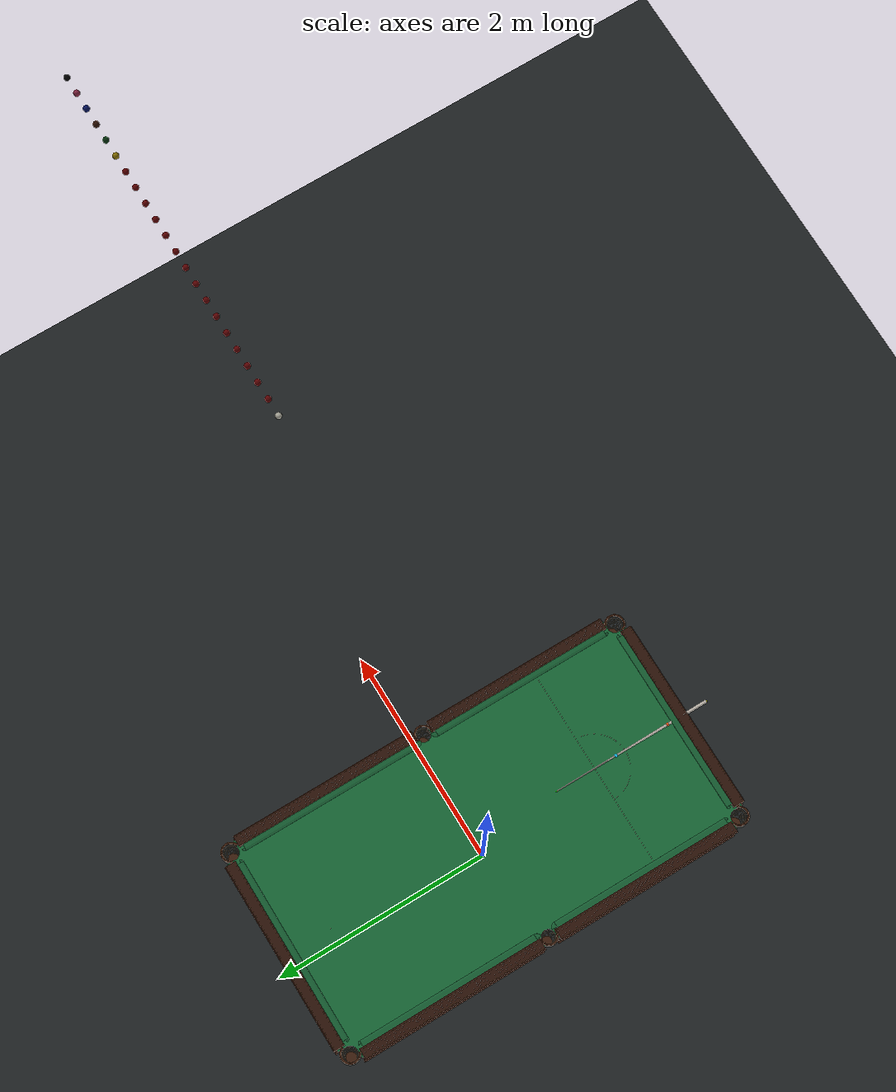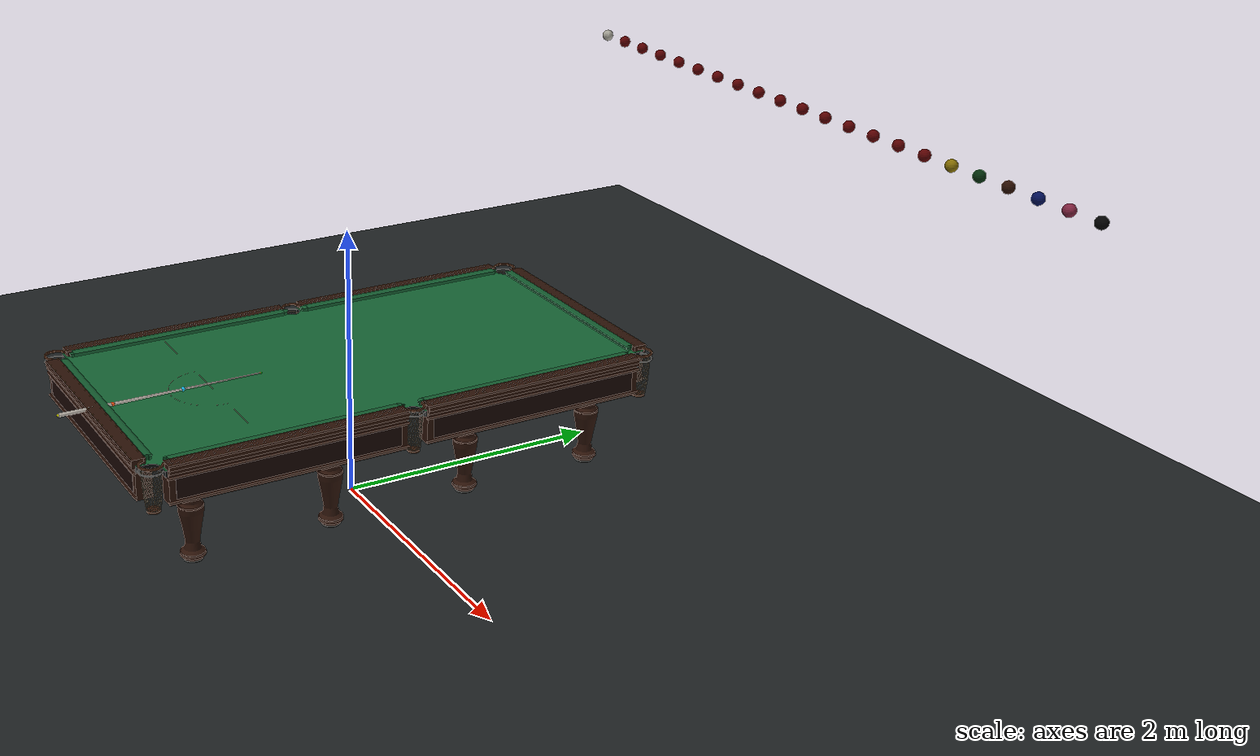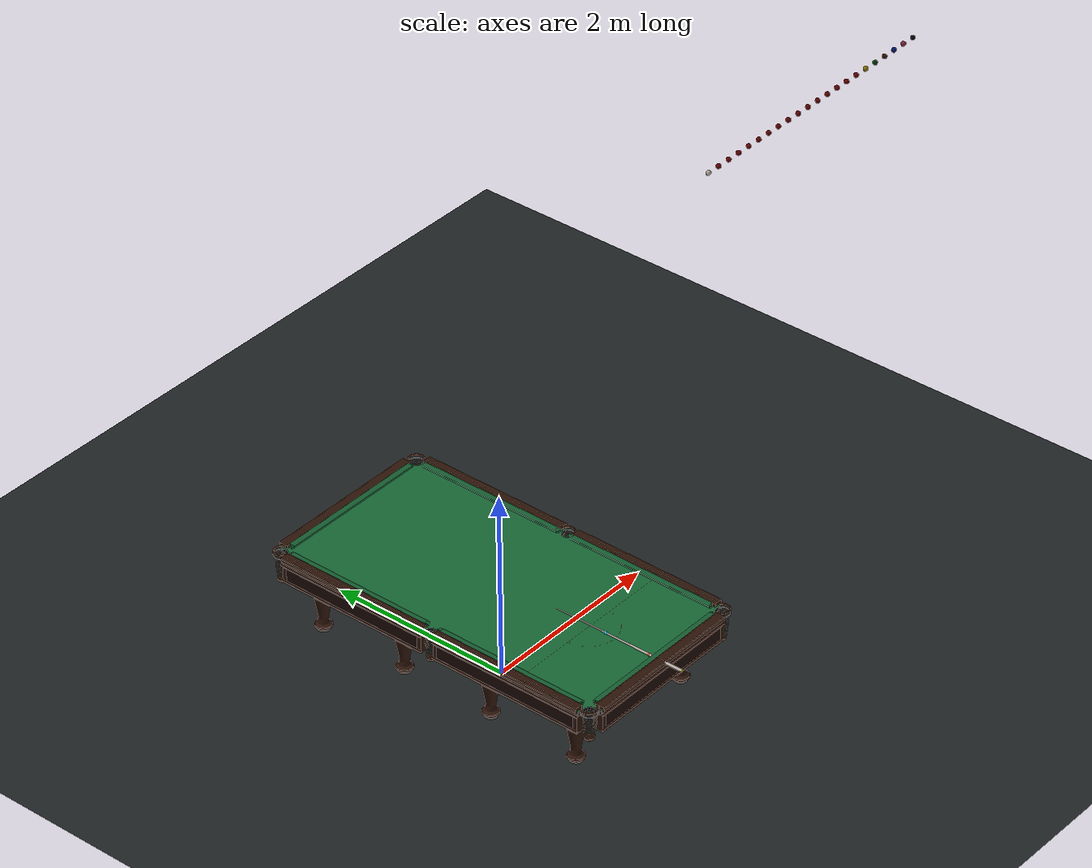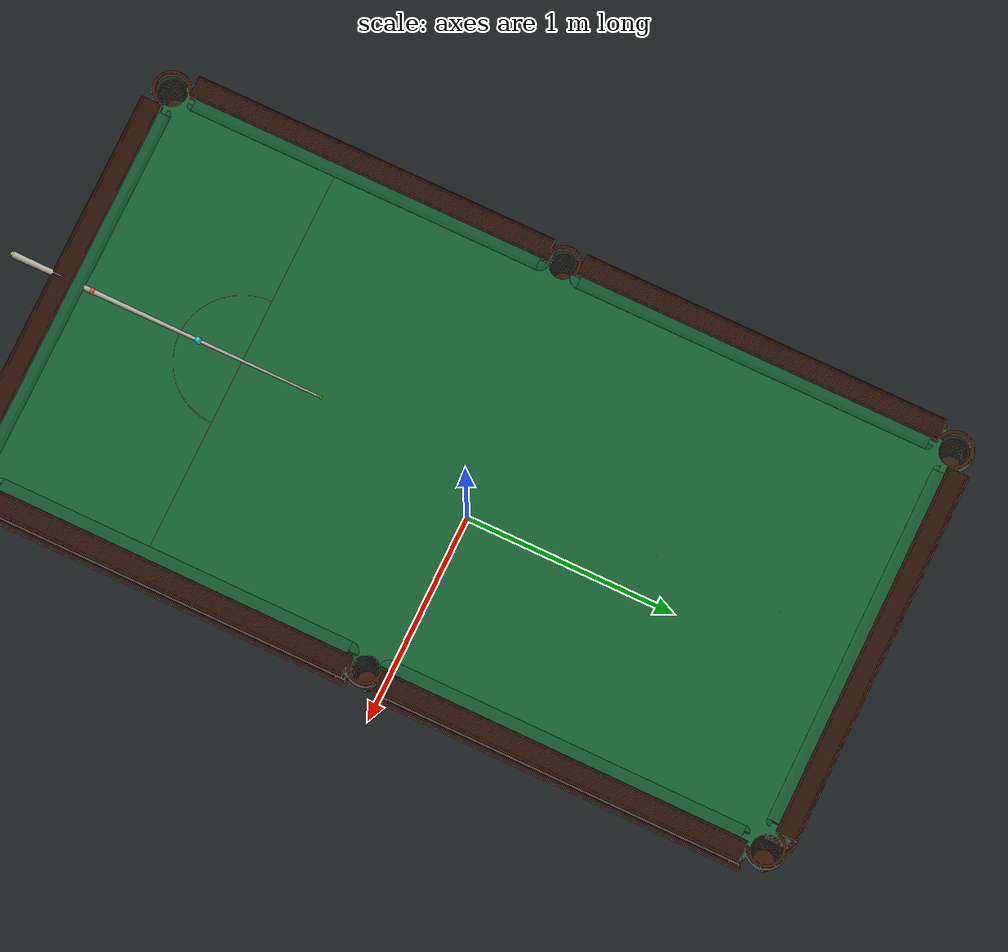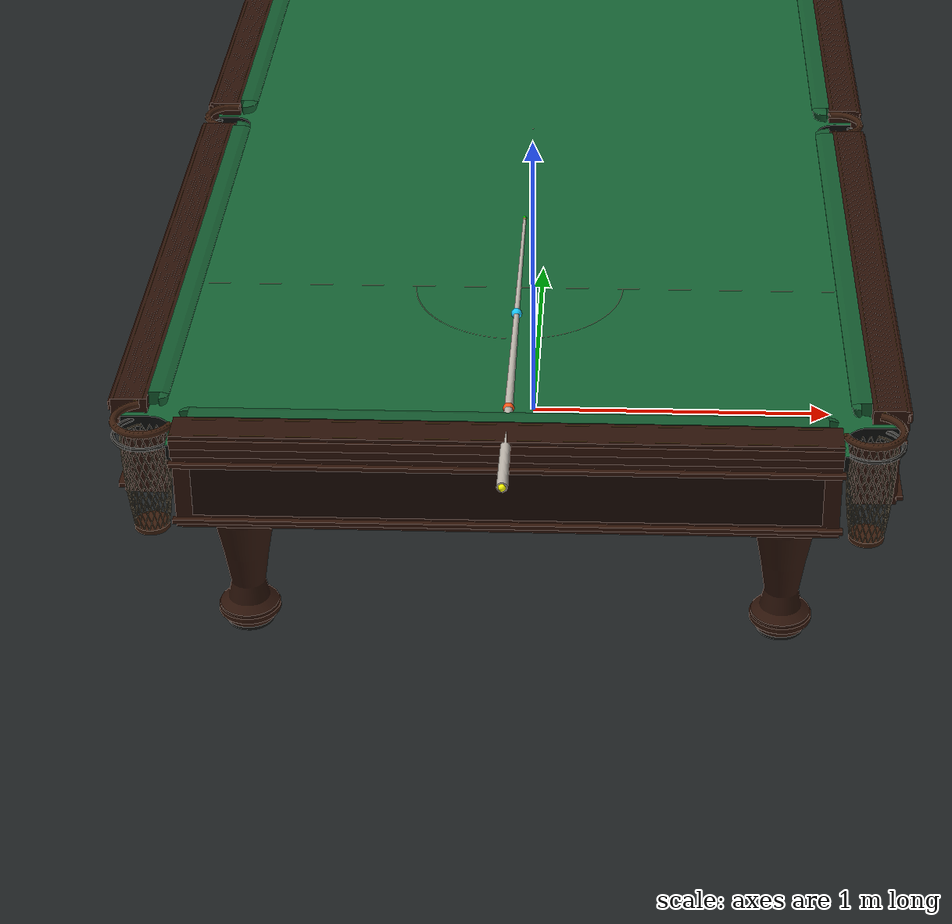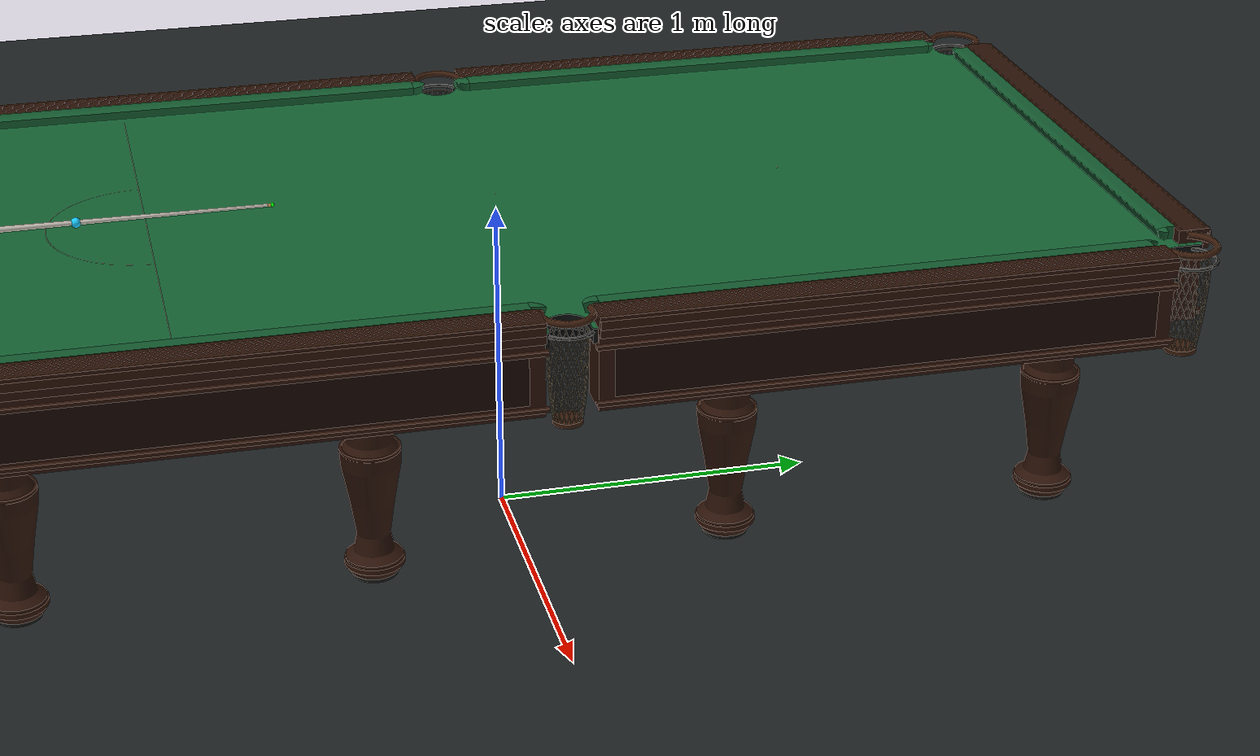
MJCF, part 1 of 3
<mujoco model="snooker_match">
  <compiler angle="degree" autolimits="true" />
  <option timestep="5e-05" gravity="0 0 -9.81" integrator="Euler" solver="Newton" cone="elliptic" iterations="80" tolerance="1e-8" />
  <visual>
    <global offheight="1200" offwidth="1600" />
    <quality shadowsize="4096" offsamples="4" />
    <map znear=".01" shadowclip="5" />
    <headlight ambient=".43 .43 .43" diffuse=".40 .40 .40" specular=".09 .09 .09" />
  </visual>
  <default>
    <default class="snooker_ball">
      <geom size="0.02625" type="sphere" friction="0.05 0 0" solref="-10000000 -236.98049786" solimp="0.95 0.99 0.001" condim="3" priority="0" mass="0.1406" />
    </default>
    <default class="snooker_cloth">
      <geom friction="0.21528167485 0.000618090421658 0.000470203303267" solref="-1000000 -1000" solimp="0.95 0.99 0.001" condim="6" priority="1" />
    </default>
    <default class="snooker_cushion">
      <geom friction="0.14 0 0" solref="-1000000 -50.3364521839" solimp="0.95 0.99 0.001" condim="3" priority="1" />
    </default>
    <default class="snooker_jaw">
      <geom friction="0.14 0 0" solref="-1000000 -50.3364521839" solimp="0.95 0.99 0.001" condim="3" priority="1" />
    </default>
  </default>
  <asset>
    <texture name="snooker_cloth_weave" type="2d" builtin="flat" rgb1=".075 .352 .181" rgb2=".080 .360 .189" mark="random" markrgb=".072 .342 .176" random=".17" width="128" height="128" />
    <material name="mat-surface" texture="snooker_cloth_weave" texrepeat="18 36" rgba="1 1 1 1" specular=".12" shininess=".08" />
    <texture name="snooker_bed_cloth_weave" type="2d" builtin="flat" rgb1=".084 .394 .203" rgb2=".090 .403 .212" mark="random" markrgb=".081 .383 .197" random=".17" width="128" height="128" />
    <material name="snooker_bed_cloth" texture="snooker_bed_cloth_weave" texrepeat="18 36" rgba="1 1 1 1" specular=".12" shininess=".08" />
    <material name="snooker_wood" rgba=".17 .070 .031 1" specular=".28" shininess=".42" />
    <material name="snooker_panel" rgba=".095 .029 .014 1" specular=".20" shininess=".3" />
    <material name="snooker_moulding" rgba=".19 .077 .031 1" specular=".30" shininess=".5" />
    <material name="snooker_wood_grain" rgba=".080 .026 .009 1" specular=".18" shininess=".3" />
    <material name="snooker_leather" rgba=".23 .112 .049 1" specular=".10" shininess=".08" />
    <material name="snooker_stitch" rgba=".43 .30 .157 1" specular=".05" shininess=".03" />
    <material name="snooker_brass" rgba=".40 .28 .091 1" specular=".55" shininess=".7" />
    <material name="snooker_iron" rgba=".077 .074 .063 1" specular=".40" shininess=".65" />
    <material name="snooker_net" rgba=".35 .31 .24 1" specular=".04" shininess=".01" />
    <material name="snooker_shadow" rgba=".018 .013 .009 1" specular=".02" shininess=".01" />
    <material name="snooker_slate" rgba=".047 .050 .049 1" specular=".06" shininess=".03" />
    <material name="snooker_marking" rgba=".50 .54 .42 1" specular=".02" shininess=".01" />
    <material name="snooker_ball_finish" rgba="1 1 1 1" specular=".40" shininess=".74" />
    <mesh name="snooker_cloth_shelf_0" vertex="-0.871 1.9095 1.005 -0.874 1.9095 1.005 -0.874 -1.9095 1.005 -0.871 -1.9095 1.005 -0.871 1.9095 1.05 -0.874 1.9095 1.05 -0.874 -1.9095 1.05 -0.871 -1.9095 1.05" face="0 2 1 0 3 2 4 5 6 4 6 7 0 1 5 0 5 4 1 2 6 1 6 5 2 3 7 2 7 6 3 0 4 3 4 7" />
    <mesh name="snooker_cloth_shelf_1" vertex="-0.874 1.8345 1.005 -0.87413917 1.8302488 1.005 -0.87413917 -1.8302488 1.005 -0.874 -1.8345 1.005 -0.874 1.8345 1.05 -0.87413917 1.8302488 1.05 -0.87413917 -1.8302488 1.05 -0.874 -1.8345 1.05" face="0 2 1 0 3 2 4 5 6 4 6 7 0 1 5 0 5 4 1 2 6 1 6 5 2 3 7 2 7 6 3 0 4 3 4 7" />
    <mesh name="snooker_cloth_shelf_2" vertex="-0.87413917 1.8302488 1.005 -0.874556084 1.8260158 1.005 -0.874556084 -1.8260158 1.005 -0.87413917 -1.8302488 1.005 -0.87413917 1.8302488 1.05 -0.874556084 1.8260158 1.05 -0.874556084 -1.8260158 1.05 -0.87413917 -1.8302488 1.05" face="0 2 1 0 3 2 4 5 6 4 6 7 0 1 5 0 5 4 1 2 6 1 6 5 2 3 7 2 7 6 3 0 4 3 4 7" />
    <mesh name="snooker_cloth_shelf_3" vertex="-0.874556084 1.8260158 1.005 -0.875248957 1.82181913 1.005 -0.875248957 -1.82181913 1.005 -0.874556084 -1.8260158 1.005 -0.874556084 1.8260158 1.05 -0.875248957 1.82181913 1.05 -0.875248957 -1.82181913 1.05 -0.874556084 -1.8260158 1.05" face="0 2 1 0 3 2 4 5 6 4 6 7 0 1 5 0 5 4 1 2 6 1 6 5 2 3 7 2 7 6 3 0 4 3 4 7" />
    <mesh name="snooker_cloth_shelf_4" vertex="-0.875248957 1.82181913 1.005 -0.876214821 1.81767676 1.005 -0.876214821 -1.81767676 1.005 -0.875248957 -1.82181913 1.005 -0.875248957 1.82181913 1.05 -0.876214821 1.81767676 1.05 -0.876214821 -1.81767676 1.05 -0.875248957 -1.82181913 1.05" face="0 2 1 0 3 2 4 5 6 4 6 7 0 1 5 0 5 4 1 2 6 1 6 5 2 3 7 2 7 6 3 0 4 3 4 7" />
    <mesh name="snooker_cloth_shelf_5" vertex="-0.876214821 1.81767676 1.005 -0.877449542 1.81360643 1.005 -0.877449542 -1.81360643 1.005 -0.876214821 -1.81767676 1.005 -0.876214821 1.81767676 1.05 -0.877449542 1.81360643 1.05 -0.877449542 -1.81360643 1.05 -0.876214821 -1.81767676 1.05" face="0 2 1 0 3 2 4 5 6 4 6 7 0 1 5 0 5 4 1 2 6 1 6 5 2 3 7 2 7 6 3 0 4 3 4 7" />
    <mesh name="snooker_cloth_shelf_6" vertex="-0.877449542 1.81360643 1.005 -0.87894783 1.80962558 1.005 -0.87894783 -1.80962558 1.005 -0.877449542 -1.81360643 1.005 -0.877449542 1.81360643 1.05 -0.87894783 1.80962558 1.05 -0.87894783 -1.80962558 1.05 -0.877449542 -1.81360643 1.05" face="0 2 1 0 3 2 4 5 6 4 6 7 0 1 5 0 5 4 1 2 6 1 6 5 2 3 7 2 7 6 3 0 4 3 4 7" />
    <mesh name="snooker_cloth_shelf_7" vertex="-0.87894783 1.80962558 1.005 -0.880703272 1.80575124 1.005 -0.880703272 -1.80575124 1.005 -0.87894783 -1.80962558 1.005 -0.87894783 1.80962558 1.05 -0.880703272 1.80575124 1.05 -0.880703272 -1.80575124 1.05 -0.87894783 -1.80962558 1.05" face="0 2 1 0 3 2 4 5 6 4 6 7 0 1 5 0 5 4 1 2 6 1 6 5 2 3 7 2 7 6 3 0 4 3 4 7" />
    <mesh name="snooker_cloth_shelf_8" vertex="-0.880703272 1.80575124 1.005 -0.882708349 1.802 1.005 -0.882708349 -1.802 1.005 -0.880703272 -1.80575124 1.005 -0.880703272 1.80575124 1.05 -0.882708349 1.802 1.05 -0.882708349 -1.802 1.05 -0.880703272 -1.80575124 1.05" face="0 2 1 0 3 2 4 5 6 4 6 7 0 1 5 0 5 4 1 2 6 1 6 5 2 3 7 2 7 6 3 0 4 3 4 7" />
    <mesh name="snooker_cloth_shelf_9" vertex="-0.882708349 1.802 1.005 -0.884954475 1.79838793 1.005 -0.884954475 -1.79838793 1.005 -0.882708349 -1.802 1.005 -0.882708349 1.802 1.05 -0.884954475 1.79838793 1.05 -0.884954475 -1.79838793 1.05 -0.882708349 -1.802 1.05" face="0 2 1 0 3 2 4 5 6 4 6 7 0 1 5 0 5 4 1 2 6 1 6 5 2 3 7 2 7 6 3 0 4 3 4 7" />
    <mesh name="snooker_cloth_shelf_10" vertex="-0.884954475 1.79838793 1.005 -0.887432033 1.79493051 1.005 -0.887432033 -1.79493051 1.005 -0.884954475 -1.79838793 1.005 -0.884954475 1.79838793 1.05 -0.887432033 1.79493051 1.05 -0.887432033 -1.79493051 1.05 -0.884954475 -1.79838793 1.05" face="0 2 1 0 3 2 4 5 6 4 6 7 0 1 5 0 5 4 1 2 6 1 6 5 2 3 7 2 7 6 3 0 4 3 4 7" />
    <mesh name="snooker_cloth_shelf_11" vertex="-0.887432033 1.79493051 1.005 -0.890130413 1.79164252 1.005 -0.890130413 -1.79164252 1.005 -0.887432033 -1.79493051 1.005 -0.887432033 1.79493051 1.05 -0.890130413 1.79164252 1.05 -0.890130413 -1.79164252 1.05 -0.887432033 -1.79493051 1.05" face="0 2 1 0 3 2 4 5 6 4 6 7 0 1 5 0 5 4 1 2 6 1 6 5 2 3 7 2 7 6 3 0 4 3 4 7" />
    <mesh name="snooker_cloth_shelf_12" vertex="-0.890130413 1.79164252 1.005 -0.893038059 1.78853806 1.005 -0.893038059 -1.78853806 1.005 -0.890130413 -1.79164252 1.005 -0.890130413 1.79164252 1.05 -0.893038059 1.78853806 1.05 -0.893038059 -1.78853806 1.05 -0.890130413 -1.79164252 1.05" face="0 2 1 0 3 2 4 5 6 4 6 7 0 1 5 0 5 4 1 2 6 1 6 5 2 3 7 2 7 6 3 0 4 3 4 7" />
    <mesh name="snooker_cloth_shelf_13" vertex="-0.893038059 1.78853806 1.005 -0.896142522 1.78563041 1.005 -0.896142522 -1.78563041 1.005 -0.893038059 -1.78853806 1.005 -0.893038059 1.78853806 1.05 -0.896142522 1.78563041 1.05 -0.896142522 -1.78563041 1.05 -0.893038059 -1.78853806 1.05" face="0 2 1 0 3 2 4 5 6 4 6 7 0 1 5 0 5 4 1 2 6 1 6 5 2 3 7 2 7 6 3 0 4 3 4 7" />
    <mesh name="snooker_cloth_shelf_14" vertex="-0.896142522 1.78563041 1.005 -0.899430507 1.78293203 1.005 -0.899430507 -1.78293203 1.005 -0.896142522 -1.78563041 1.005 -0.896142522 1.78563041 1.05 -0.899430507 1.78293203 1.05 -0.899430507 -1.78293203 1.05 -0.896142522 -1.78563041 1.05" face="0 2 1 0 3 2 4 5 6 4 6 7 0 1 5 0 5 4 1 2 6 1 6 5 2 3 7 2 7 6 3 0 4 3 4 7" />
    <mesh name="snooker_cloth_shelf_15" vertex="-0.899430507 1.78293203 1.005 -0.902887935 1.78045448 1.005 -0.902887935 -1.78045448 1.005 -0.899430507 -1.78293203 1.005 -0.899430507 1.78293203 1.05 -0.902887935 1.78045448 1.05 -0.902887935 -1.78045448 1.05 -0.899430507 -1.78293203 1.05" face="0 2 1 0 3 2 4 5 6 4 6 7 0 1 5 0 5 4 1 2 6 1 6 5 2 3 7 2 7 6 3 0 4 3 4 7" />
    <mesh name="snooker_cloth_shelf_16" vertex="-0.902887935 1.78045448 1.005 -0.904 1.77972774 1.005 -0.904 -1.77972774 1.005 -0.902887935 -1.78045448 1.005 -0.902887935 1.78045448 1.05 -0.904 1.77972774 1.05 -0.904 -1.77972774 1.05 -0.902887935 -1.78045448 1.05" face="0 2 1 0 3 2 4 5 6 4 6 7 0 1 5 0 5 4 1 2 6 1 6 5 2 3 7 2 7 6 3 0 4 3 4 7" />
    <mesh name="snooker_cloth_shelf_17" vertex="-0.904 0 1.005 -0.904128465 -0.00392418775 1.005 -0.904128465 -1.77964587 1.005 -0.904 -1.77972774 1.005 -0.904 0 1.05 -0.904128465 -0.00392418775 1.05 -0.904128465 -1.77964587 1.05 -0.904 -1.77972774 1.05" face="0 2 1 0 3 2 4 5 6 4 6 7 0 1 5 0 5 4 1 2 6 1 6 5 2 3 7 2 7 6 3 0 4 3 4 7" />
    <mesh name="snooker_cloth_shelf_18" vertex="-0.904 1.77972774 1.005 -0.904128465 1.77964587 1.005 -0.904128465 0.00392418775 1.005 -0.904 0 1.005 -0.904 1.77972774 1.05 -0.904128465 1.77964587 1.05 -0.904128465 0.00392418775 1.05 -0.904 0 1.05" face="0 2 1 0 3 2 4 5 6 4 6 7 0 1 5 0 5 4 1 2 6 1 6 5 2 3 7 2 7 6 3 0 4 3 4 7" />
    <mesh name="snooker_cloth_shelf_19" vertex="-0.904128465 -0.00392418775 1.005 -0.904513308 -0.00783157153 1.005 -0.904513308 -1.7794031 1.005 -0.904128465 -1.77964587 1.005 -0.904128465 -0.00392418775 1.05 -0.904513308 -0.00783157153 1.05 -0.904513308 -1.7794031 1.05 -0.904128465 -1.77964587 1.05" face="0 2 1 0 3 2 4 5 6 4 6 7 0 1 5 0 5 4 1 2 6 1 6 5 2 3 7 2 7 6 3 0 4 3 4 7" />
    <mesh name="snooker_cloth_shelf_20" vertex="-0.904128465 1.77964587 1.005 -0.904513308 1.7794031 1.005 -0.904513308 0.00783157153 1.005 -0.904128465 0.00392418775 1.005 -0.904128465 1.77964587 1.05 -0.904513308 1.7794031 1.05 -0.904513308 0.00783157153 1.05 -0.904128465 0.00392418775 1.05" face="0 2 1 0 3 2 4 5 6 4 6 7 0 1 5 0 5 4 1 2 6 1 6 5 2 3 7 2 7 6 3 0 4 3 4 7" />
    <mesh name="snooker_cloth_shelf_21" vertex="-0.904513308 -0.00783157153 1.005 -0.905152883 -0.0117054193 1.005 -0.905152883 -1.7790079 1.005 -0.904513308 -1.7794031 1.005 -0.904513308 -0.00783157153 1.05 -0.905152883 -0.0117054193 1.05 -0.905152883 -1.7790079 1.05 -0.904513308 -1.7794031 1.05" face="0 2 1 0 3 2 4 5 6 4 6 7 0 1 5 0 5 4 1 2 6 1 6 5 2 3 7 2 7 6 3 0 4 3 4 7" />
    <mesh name="snooker_cloth_shelf_22" vertex="-0.904513308 1.7794031 1.005 -0.905152883 1.7790079 1.005 -0.905152883 0.0117054193 1.005 -0.904513308 0.00783157153 1.005 -0.904513308 1.7794031 1.05 -0.905152883 1.7790079 1.05 -0.905152883 0.0117054193 1.05 -0.904513308 0.00783157153 1.05" face="0 2 1 0 3 2 4 5 6 4 6 7 0 1 5 0 5 4 1 2 6 1 6 5 2 3 7 2 7 6 3 0 4 3 4 7" />
    <mesh name="snooker_cloth_shelf_23" vertex="-0.905152883 -0.0117054193 1.005 -0.90604445 -0.0155291427 1.005 -0.90604445 -1.77847383 1.005 -0.905152883 -1.7790079 1.005 -0.905152883 -0.0117054193 1.05 -0.90604445 -0.0155291427 1.05 -0.90604445 -1.77847383 1.05 -0.905152883 -1.7790079 1.05" face="0 2 1 0 3 2 4 5 6 4 6 7 0 1 5 0 5 4 1 2 6 1 6 5 2 3 7 2 7 6 3 0 4 3 4 7" />
    <mesh name="snooker_cloth_shelf_24" vertex="-0.905152883 1.7790079 1.005 -0.90604445 1.77847383 1.005 -0.90604445 0.0155291427 1.005 -0.905152883 0.0117054193 1.005 -0.905152883 1.7790079 1.05 -0.90604445 1.77847383 1.05 -0.90604445 0.0155291427 1.05 -0.905152883 0.0117054193 1.05" face="0 2 1 0 3 2 4 5 6 4 6 7 0 1 5 0 5 4 1 2 6 1 6 5 2 3 7 2 7 6 3 0 4 3 4 7" />
    <mesh name="snooker_cloth_shelf_25" vertex="-0.90604445 -0.0155291427 1.005 -0.9065 -0.0171391365 1.005 -0.9065 -1.77820835 1.005 -0.90604445 -1.77847383 1.005 -0.90604445 -0.0155291427 1.05 -0.9065 -0.0171391365 1.05 -0.9065 -1.77820835 1.05 -0.90604445 -1.77847383 1.05" face="0 2 1 0 3 2 4 5 6 4 6 7 0 1 5 0 5 4 1 2 6 1 6 5 2 3 7 2 7 6 3 0 4 3 4 7" />
    <mesh name="snooker_cloth_shelf_26" vertex="-0.90604445 1.77847383 1.005 -0.9065 1.77820835 1.005 -0.9065 0.0171391365 1.005 -0.90604445 0.0155291427 1.005 -0.90604445 1.77847383 1.05 -0.9065 1.77820835 1.05 -0.9065 0.0171391365 1.05 -0.90604445 0.0155291427 1.05" face="0 2 1 0 3 2 4 5 6 4 6 7 0 1 5 0 5 4 1 2 6 1 6 5 2 3 7 2 7 6 3 0 4 3 4 7" />
    <mesh name="snooker_cloth_shelf_27" vertex="-0.9065 -0.0171391365 1.005 -0.907184192 -0.0192863679 1.005 -0.907184192 -1.77781884 1.005 -0.9065 -1.77820835 1.005 -0.9065 -0.0171391365 1.05 -0.907184192 -0.0192863679 1.05 -0.907184192 -1.77781884 1.05 -0.9065 -1.77820835 1.05" face="0 2 1 0 3 2 4 5 6 4 6 7 0 1 5 0 5 4 1 2 6 1 6 5 2 3 7 2 7 6 3 0 4 3 4 7" />
    <mesh name="snooker_cloth_shelf_28" vertex="-0.9065 1.77820835 1.005 -0.907184192 1.77781884 1.005 -0.907184192 0.0192863679 1.005 -0.9065 0.0171391365 1.005 -0.9065 1.77820835 1.05 -0.907184192 1.77781884 1.05 -0.907184192 0.0192863679 1.05 -0.9065 0.0171391365 1.05" face="0 2 1 0 3 2 4 5 6 4 6 7 0 1 5 0 5 4 1 2 6 1 6 5 2 3 7 2 7 6 3 0 4 3 4 7" />
    <mesh name="snooker_cloth_shelf_29" vertex="-0.907184192 -0.0192863679 1.005 -0.908567228 -0.0229610059 1.005 -0.908567228 -1.77706442 1.005 -0.907184192 -1.77781884 1.005 -0.907184192 -0.0192863679 1.05 -0.908567228 -0.0229610059 1.05 -0.908567228 -1.77706442 1.05 -0.907184192 -1.77781884 1.05" face="0 2 1 0 3 2 4 5 6 4 6 7 0 1 5 0 5 4 1 2 6 1 6 5 2 3 7 2 7 6 3 0 4 3 4 7" />
    <mesh name="snooker_cloth_shelf_30" vertex="-0.907184192 1.77781884 1.005 -0.908567228 1.77706442 1.005 -0.908567228 0.0229610059 1.005 -0.907184192 0.0192863679 1.005 -0.907184192 1.77781884 1.05 -0.908567228 1.77706442 1.05 -0.908567228 0.0229610059 1.05 -0.907184192 0.0192863679 1.05" face="0 2 1 0 3 2 4 5 6 4 6 7 0 1 5 0 5 4 1 2 6 1 6 5 2 3 7 2 7 6 3 0 4 3 4 7" />
    <mesh name="snooker_cloth_shelf_31" vertex="-0.908567228 -0.0229610059 1.005 -0.910187636 -0.0265373214 1.005 -0.910187636 -1.77623468 1.005 -0.908567228 -1.77706442 1.005 -0.908567228 -0.0229610059 1.05 -0.910187636 -0.0265373214 1.05 -0.910187636 -1.77623468 1.05 -0.908567228 -1.77706442 1.05" face="0 2 1 0 3 2 4 5 6 4 6 7 0 1 5 0 5 4 1 2 6 1 6 5 2 3 7 2 7 6 3 0 4 3 4 7" />
    <mesh name="snooker_cloth_shelf_32" vertex="-0.908567228 1.77706442 1.005 -0.910187636 1.77623468 1.005 -0.910187636 0.0265373214 1.005 -0.908567228 0.0229610059 1.005 -0.908567228 1.77706442 1.05 -0.910187636 1.77623468 1.05 -0.910187636 0.0265373214 1.05 -0.908567228 0.0229610059 1.05" face="0 2 1 0 3 2 4 5 6 4 6 7 0 1 5 0 5 4 1 2 6 1 6 5 2 3 7 2 7 6 3 0 4 3 4 7" />
    <mesh name="snooker_cloth_shelf_33" vertex="-0.910187636 -0.0265373214 1.005 -0.910251235 -0.026665901 1.005 -0.910251235 -1.77620327 1.005 -0.910187636 -1.77623468 1.005 -0.910187636 -0.0265373214 1.05 -0.910251235 -0.026665901 1.05 -0.910251235 -1.77620327 1.05 -0.910187636 -1.77623468 1.05" face="0 2 1 0 3 2 4 5 6 4 6 7 0 1 5 0 5 4 1 2 6 1 6 5 2 3 7 2 7 6 3 0 4 3 4 7" />
    <mesh name="snooker_cloth_shelf_34" vertex="-0.910187636 1.77623468 1.005 -0.910251235 1.77620327 1.005 -0.910251235 0.026665901 1.005 -0.910187636 0.0265373214 1.005 -0.910187636 1.77623468 1.05 -0.910251235 1.77620327 1.05 -0.910251235 0.026665901 1.05 -0.910187636 0.0265373214 1.05" face="0 2 1 0 3 2 4 5 6 4 6 7 0 1 5 0 5 4 1 2 6 1 6 5 2 3 7 2 7 6 3 0 4 3 4 7" />
    <mesh name="snooker_cloth_shelf_35" vertex="-0.910251235 -0.026665901 1.005 -0.912038476 -0.03 1.005 -0.912038476 -1.77535546 1.005 -0.910251235 -1.77620327 1.005 -0.910251235 -0.026665901 1.05 -0.912038476 -0.03 1.05 -0.912038476 -1.77535546 1.05 -0.910251235 -1.77620327 1.05" face="0 2 1 0 3 2 4 5 6 4 6 7 0 1 5 0 5 4 1 2 6 1 6 5 2 3 7 2 7 6 3 0 4 3 4 7" />
    <mesh name="snooker_cloth_shelf_36" vertex="-0.910251235 1.77620327 1.005 -0.912038476 1.77535546 1.005 -0.912038476 0.03 1.005 -0.910251235 0.026665901 1.005 -0.910251235 1.77620327 1.05 -0.912038476 1.77535546 1.05 -0.912038476 0.03 1.05 -0.910251235 0.026665901 1.05" face="0 2 1 0 3 2 4 5 6 4 6 7 0 1 5 0 5 4 1 2 6 1 6 5 2 3 7 2 7 6 3 0 4 3 4 7" />
    <mesh name="snooker_cloth_shelf_37" vertex="-0.912038476 -0.03 1.005 -0.914111823 -0.033334214 1.005 -0.914111823 -1.77445353 1.005 -0.912038476 -1.77535546 1.005 -0.912038476 -0.03 1.05 -0.914111823 -0.033334214 1.05 -0.914111823 -1.77445353 1.05 -0.912038476 -1.77535546 1.05" face="0 2 1 0 3 2 4 5 6 4 6 7 0 1 5 0 5 4 1 2 6 1 6 5 2 3 7 2 7 6 3 0 4 3 4 7" />
    <mesh name="snooker_cloth_shelf_38" vertex="-0.912038476 1.77535546 1.005 -0.914111823 1.77445353 1.005 -0.914111823 0.033334214 1.005 -0.912038476 0.03 1.005 -0.912038476 1.77535546 1.05 -0.914111823 1.77445353 1.05 -0.914111823 0.033334214 1.05 -0.912038476 0.03 1.05" face="0 2 1 0 3 2 4 5 6 4 6 7 0 1 5 0 5 4 1 2 6 1 6 5 2 3 7 2 7 6 3 0 4 3 4 7" />
    <mesh name="snooker_cloth_shelf_39" vertex="-0.914111823 -0.033334214 1.005 -0.914125577 -0.0333547886 1.005 -0.914125577 -1.77444783 1.005 -0.914111823 -1.77445353 1.005 -0.914111823 -0.033334214 1.05 -0.914125577 -0.0333547886 1.05 -0.914125577 -1.77444783 1.05 -0.914111823 -1.77445353 1.05" face="0 2 1 0 3 2 4 5 6 4 6 7 0 1 5 0 5 4 1 2 6 1 6 5 2 3 7 2 7 6 3 0 4 3 4 7" />
    <mesh name="snooker_cloth_shelf_40" vertex="-0.914111823 1.77445353 1.005 -0.914125577 1.77444783 1.005 -0.914125577 0.0333547886 1.005 -0.914111823 0.033334214 1.005 -0.914111823 1.77445353 1.05 -0.914125577 1.77444783 1.05 -0.914125577 0.0333547886 1.05 -0.914111823 0.033334214 1.05" face="0 2 1 0 3 2 4 5 6 4 6 7 0 1 5 0 5 4 1 2 6 1 6 5 2 3 7 2 7 6 3 0 4 3 4 7" />
    <mesh name="snooker_cloth_shelf_41" vertex="-0.914125577 -0.0333547886 1.005 -0.9163988 -0.0365256857 1.005 -0.9163988 -1.77355588 1.005 -0.914125577 -1.77444783 1.005 -0.914125577 -0.0333547886 1.05 -0.9163988 -0.0365256857 1.05 -0.9163988 -1.77355588 1.05 -0.914125577 -1.77444783 1.05" face="0 2 1 0 3 2 4 5 6 4 6 7 0 1 5 0 5 4 1 2 6 1 6 5 2 3 7 2 7 6 3 0 4 3 4 7" />
    <mesh name="snooker_cloth_shelf_42" vertex="-0.914125577 1.77444783 1.005 -0.9163988 1.77355588 1.005 -0.9163988 0.0365256857 1.005 -0.914125577 0.0333547886 1.005 -0.914125577 1.77444783 1.05 -0.9163988 1.77355588 1.05 -0.9163988 0.0365256857 1.05 -0.914125577 0.0333547886 1.05" face="0 2 1 0 3 2 4 5 6 4 6 7 0 1 5 0 5 4 1 2 6 1 6 5 2 3 7 2 7 6 3 0 4 3 4 7" />
    <mesh name="snooker_cloth_shelf_43" vertex="-0.9163988 -0.0365256857 1.005 -0.918106435 -0.0386494588 1.005 -0.918106435 -1.77294954 1.005 -0.9163988 -1.77355588 1.005 -0.9163988 -0.0365256857 1.05 -0.918106435 -0.0386494588 1.05 -0.918106435 -1.77294954 1.05 -0.9163988 -1.77355588 1.05" face="0 2 1 0 3 2 4 5 6 4 6 7 0 1 5 0 5 4 1 2 6 1 6 5 2 3 7 2 7 6 3 0 4 3 4 7" />
    <mesh name="snooker_cloth_shelf_44" vertex="-0.9163988 1.77355588 1.005 -0.918106435 1.77294954 1.005 -0.918106435 0.0386494588 1.005 -0.9163988 0.0365256857 1.005 -0.9163988 1.77355588 1.05 -0.918106435 1.77294954 1.05 -0.918106435 0.0386494588 1.05 -0.9163988 0.0365256857 1.05" face="0 2 1 0 3 2 4 5 6 4 6 7 0 1 5 0 5 4 1 2 6 1 6 5 2 3 7 2 7 6 3 0 4 3 4 7" />
    <mesh name="snooker_cloth_shelf_45" vertex="-0.918106435 -0.0386494588 1.005 -0.918889612 -0.0395607489 1.005 -0.918889612 -1.77268922 1.005 -0.918106435 -1.77294954 1.005 -0.918106435 -0.0386494588 1.05 -0.918889612 -0.0395607489 1.05 -0.918889612 -1.77268922 1.05 -0.918106435 -1.77294954 1.05" face="0 2 1 0 3 2 4 5 6 4 6 7 0 1 5 0 5 4 1 2 6 1 6 5 2 3 7 2 7 6 3 0 4 3 4 7" />
    <mesh name="snooker_cloth_shelf_46" vertex="-0.918106435 1.77294954 1.005 -0.918889612 1.77268922 1.005 -0.918889612 0.0395607489 1.005 -0.918106435 0.0386494588 1.005 -0.918106435 1.77294954 1.05 -0.918889612 1.77268922 1.05 -0.918889612 0.0395607489 1.05 -0.918106435 0.0386494588 1.05" face="0 2 1 0 3 2 4 5 6 4 6 7 0 1 5 0 5 4 1 2 6 1 6 5 2 3 7 2 7 6 3 0 4 3 4 7" />
    <mesh name="snooker_cloth_shelf_47" vertex="-0.918889612 -0.0395607489 1.005 -0.921573593 -0.0424264069 1.005 -0.921573593 -1.77187955 1.005 -0.918889612 -1.77268922 1.005 -0.918889612 -0.0395607489 1.05 -0.921573593 -0.0424264069 1.05 -0.921573593 -1.77187955 1.05 -0.918889612 -1.77268922 1.05" face="0 2 1 0 3 2 4 5 6 4 6 7 0 1 5 0 5 4 1 2 6 1 6 5 2 3 7 2 7 6 3 0 4 3 4 7" />
    <mesh name="snooker_cloth_shelf_48" vertex="-0.918889612 1.77268922 1.005 -0.921573593 1.77187955 1.005 -0.921573593 0.0424264069 1.005 -0.918889612 0.0395607489 1.005 -0.918889612 1.77268922 1.05 -0.921573593 1.77187955 1.05 -0.921573593 0.0424264069 1.05 -0.918889612 0.0395607489 1.05" face="0 2 1 0 3 2 4 5 6 4 6 7 0 1 5 0 5 4 1 2 6 1 6 5 2 3 7 2 7 6 3 0 4 3 4 7" />
    <mesh name="snooker_cloth_shelf_49" vertex="-0.921573593 -0.0424264069 1.005 -0.922176762 -0.04302112 1.005 -0.922176762 -1.77171482 1.005 -0.921573593 -1.77187955 1.005 -0.921573593 -0.0424264069 1.05 -0.922176762 -0.04302112 1.05 -0.922176762 -1.77171482 1.05 -0.921573593 -1.77187955 1.05" face="0 2 1 0 3 2 4 5 6 4 6 7 0 1 5 0 5 4 1 2 6 1 6 5 2 3 7 2 7 6 3 0 4 3 4 7" />
    <mesh name="snooker_cloth_shelf_50" vertex="-0.921573593 1.77187955 1.005 -0.922176762 1.77171482 1.005 -0.922176762 0.04302112 1.005 -0.921573593 0.0424264069 1.005 -0.921573593 1.77187955 1.05 -0.922176762 1.77171482 1.05 -0.922176762 0.04302112 1.05 -0.921573593 0.0424264069 1.05" face="0 2 1 0 3 2 4 5 6 4 6 7 0 1 5 0 5 4 1 2 6 1 6 5 2 3 7 2 7 6 3 0 4 3 4 7" />
    <mesh name="snooker_cloth_shelf_51" vertex="-0.922176762 -0.04302112 1.005 -0.924439251 -0.0451103884 1.005 -0.924439251 -1.77115188 1.005 -0.922176762 -1.77171482 1.005 -0.922176762 -0.04302112 1.05 -0.924439251 -0.0451103884 1.05 -0.924439251 -1.77115188 1.05 -0.922176762 -1.77171482 1.05" face="0 2 1 0 3 2 4 5 6 4 6 7 0 1 5 0 5 4 1 2 6 1 6 5 2 3 7 2 7 6 3 0 4 3 4 7" />
    <mesh name="snooker_cloth_shelf_52" vertex="-0.922176762 1.77171482 1.005 -0.924439251 1.77115188 1.005 -0.924439251 0.0451103884 1.005 -0.922176762 0.04302112 1.005 -0.922176762 1.77171482 1.05 -0.924439251 1.77115188 1.05 -0.924439251 0.0451103884 1.05 -0.922176762 0.04302112 1.05" face="0 2 1 0 3 2 4 5 6 4 6 7 0 1 5 0 5 4 1 2 6 1 6 5 2 3 7 2 7 6 3 0 4 3 4 7" />
    <mesh name="snooker_cloth_shelf_53" vertex="-0.924439251 -0.0451103884 1.005 -0.926319129 -0.0466920975 1.005 -0.926319129 -1.77074896 1.005 -0.924439251 -1.77115188 1.005 -0.924439251 -0.0451103884 1.05 -0.926319129 -0.0466920975 1.05 -0.926319129 -1.77074896 1.05 -0.924439251 -1.77115188 1.05" face="0 2 1 0 3 2 4 5 6 4 6 7 0 1 5 0 5 4 1 2 6 1 6 5 2 3 7 2 7 6 3 0 4 3 4 7" />
    <mesh name="snooker_cloth_shelf_54" vertex="-0.924439251 1.77115188 1.005 -0.926319129 1.77074896 1.005 -0.926319129 0.0466920975 1.005 -0.924439251 0.0451103884 1.005 -0.924439251 1.77115188 1.05 -0.926319129 1.77074896 1.05 -0.926319129 0.0466920975 1.05 -0.924439251 0.0451103884 1.05" face="0 2 1 0 3 2 4 5 6 4 6 7 0 1 5 0 5 4 1 2 6 1 6 5 2 3 7 2 7 6 3 0 4 3 4 7" />
    <mesh name="snooker_cloth_shelf_55" vertex="-0.926319129 -0.0466920975 1.005 -0.927474314 -0.0476012004 1.005 -0.927474314 -1.77053002 1.005 -0.926319129 -1.77074896 1.005 -0.926319129 -0.0466920975 1.05 -0.927474314 -0.0476012004 1.05 -0.927474314 -1.77053002 1.05 -0.926319129 -1.77074896 1.05" face="0 2 1 0 3 2 4 5 6 4 6 7 0 1 5 0 5 4 1 2 6 1 6 5 2 3 7 2 7 6 3 0 4 3 4 7" />
    <mesh name="snooker_cloth_shelf_56" vertex="-0.926319129 1.77074896 1.005 -0.927474314 1.77053002 1.005 -0.927474314 0.0476012004 1.005 -0.926319129 0.0466920975 1.005 -0.926319129 1.77074896 1.05 -0.927474314 1.77053002 1.05 -0.927474314 0.0476012004 1.05 -0.926319129 0.0466920975 1.05" face="0 2 1 0 3 2 4 5 6 4 6 7 0 1 5 0 5 4 1 2 6 1 6 5 2 3 7 2 7 6 3 0 4 3 4 7" />
    <mesh name="snooker_cloth_shelf_57" vertex="-0.927474314 -0.0476012004 1.005 -0.930515798 -0.0497876308 1.005 -0.930515798 -1.77005608 1.005 -0.927474314 -1.77053002 1.005 -0.927474314 -0.0476012004 1.05 -0.930515798 -0.0497876308 1.05 -0.930515798 -1.77005608 1.05 -0.927474314 -1.77053002 1.05" face="0 2 1 0 3 2 4 5 6 4 6 7 0 1 5 0 5 4 1 2 6 1 6 5 2 3 7 2 7 6 3 0 4 3 4 7" />
    <mesh name="snooker_cloth_shelf_58" vertex="-0.927474314 1.77053002 1.005 -0.930515798 1.77005608 1.005 -0.930515798 0.0497876308 1.005 -0.927474314 0.0476012004 1.005 -0.927474314 1.77053002 1.05 -0.930515798 1.77005608 1.05 -0.930515798 0.0497876308 1.05 -0.927474314 0.0476012004 1.05" face="0 2 1 0 3 2 4 5 6 4 6 7 0 1 5 0 5 4 1 2 6 1 6 5 2 3 7 2 7 6 3 0 4 3 4 7" />
    <mesh name="snooker_cloth_shelf_59" vertex="-0.930515798 -0.0497876308 1.005 -0.930665786 -0.0498881767 1.005 -0.930665786 -1.77003652 1.005 -0.930515798 -1.77005608 1.005 -0.930515798 -0.0497876308 1.05 -0.930665786 -0.0498881767 1.05 -0.930665786 -1.77003652 1.05 -0.930515798 -1.77005608 1.05" face="0 2 1 0 3 2 4 5 6 4 6 7 0 1 5 0 5 4 1 2 6 1 6 5 2 3 7 2 7 6 3 0 4 3 4 7" />
    <mesh name="snooker_cloth_shelf_60" vertex="-0.930515798 1.77005608 1.005 -0.930665786 1.77003652 1.005 -0.930665786 0.0498881767 1.005 -0.930515798 0.0497876308 1.005 -0.930515798 1.77005608 1.05 -0.930665786 1.77003652 1.05 -0.930665786 0.0498881767 1.05 -0.930515798 0.0497876308 1.05" face="0 2 1 0 3 2 4 5 6 4 6 7 0 1 5 0 5 4 1 2 6 1 6 5 2 3 7 2 7 6 3 0 4 3 4 7" />
    <mesh name="snooker_cloth_shelf_61" vertex="-0.930665786 -0.0498881767 1.005 -0.934 -0.0519615242 1.005 -0.934 -1.76969259 1.005 -0.930665786 -1.77003652 1.005 -0.930665786 -0.0498881767 1.05 -0.934 -0.0519615242 1.05 -0.934 -1.76969259 1.05 -0.930665786 -1.77003652 1.05" face="0 2 1 0 3 2 4 5 6 4 6 7 0 1 5 0 5 4 1 2 6 1 6 5 2 3 7 2 7 6 3 0 4 3 4 7" />
    <mesh name="snooker_cloth_shelf_62" vertex="-0.930665786 1.77003652 1.005 -0.934 1.76969259 1.005 -0.934 0.0519615242 1.005 -0.930665786 0.0498881767 1.005 -0.930665786 1.77003652 1.05 -0.934 1.76969259 1.05 -0.934 0.0519615242 1.05 -0.930665786 0.0498881767 1.05" face="0 2 1 0 3 2 4 5 6 4 6 7 0 1 5 0 5 4 1 2 6 1 6 5 2 3 7 2 7 6 3 0 4 3 4 7" />
    <mesh name="snooker_cloth_shelf_63" vertex="-0.934 -0.0519615242 1.005 -0.934748797 -0.0523867073 1.005 -0.934748797 -1.76963917 1.005 -0.934 -1.76969259 1.005 -0.934 -0.0519615242 1.05 -0.934748797 -0.0523867073 1.05 -0.934748797 -1.76963917 1.05 -0.934 -1.76969259 1.05" face="0 2 1 0 3 2 4 5 6 4 6 7 0 1 5 0 5 4 1 2 6 1 6 5 2 3 7 2 7 6 3 0 4 3 4 7" />
    <mesh name="snooker_cloth_shelf_64" vertex="-0.934 1.76969259 1.005 -0.934748797 1.76963917 1.005 -0.934748797 0.0523867073 1.005 -0.934 0.0519615242 1.005 -0.934 1.76969259 1.05 -0.934748797 1.76963917 1.05 -0.934748797 0.0523867073 1.05 -0.934 0.0519615242 1.05" face="0 2 1 0 3 2 4 5 6 4 6 7 0 1 5 0 5 4 1 2 6 1 6 5 2 3 7 2 7 6 3 0 4 3 4 7" />
    <mesh name="snooker_cloth_shelf_65" vertex="-0.934748797 -0.0523867073 1.005 -0.937462679 -0.0538123645 1.005 -0.937462679 -1.76951818 1.005 -0.934748797 -1.76963917 1.005 -0.934748797 -0.0523867073 1.05 -0.937462679 -0.0538123645 1.05 -0.937462679 -1.76951818 1.05 -0.934748797 -1.76963917 1.05" face="0 2 1 0 3 2 4 5 6 4 6 7 0 1 5 0 5 4 1 2 6 1 6 5 2 3 7 2 7 6 3 0 4 3 4 7" />
    <mesh name="snooker_cloth_shelf_66" vertex="-0.934748797 1.76963917 1.005 -0.937462679 1.76951818 1.005 -0.937462679 0.0538123645 1.005 -0.934748797 0.0523867073 1.005 -0.934748797 1.76963917 1.05 -0.937462679 1.76951818 1.05 -0.937462679 0.0538123645 1.05 -0.934748797 0.0523867073 1.05" face="0 2 1 0 3 2 4 5 6 4 6 7 0 1 5 0 5 4 1 2 6 1 6 5 2 3 7 2 7 6 3 0 4 3 4 7" />
    <mesh name="snooker_cloth_shelf_67" vertex="-0.937462679 -0.0538123645 1.005 -0.939 -0.0545435606 1.005 -0.939 -1.7695 1.005 -0.937462679 -1.76951818 1.005 -0.937462679 -0.0538123645 1.05 -0.939 -0.0545435606 1.05 -0.939 -1.7695 1.05 -0.937462679 -1.76951818 1.05" face="0 2 1 0 3 2 4 5 6 4 6 7 0 1 5 0 5 4 1 2 6 1 6 5 2 3 7 2 7 6 3 0 4 3 4 7" />
    <mesh name="snooker_cloth_shelf_68" vertex="-0.937462679 1.76951818 1.005 -0.939 1.7695 1.005 -0.939 0.0545435606 1.005 -0.937462679 0.0538123645 1.005 -0.937462679 1.76951818 1.05 -0.939 1.7695 1.05 -0.939 0.0545435606 1.05 -0.937462679 0.0538123645 1.05" face="0 2 1 0 3 2 4 5 6 4 6 7 0 1 5 0 5 4 1 2 6 1 6 5 2 3 7 2 7 6 3 0 4 3 4 7" />
    <mesh name="snooker_cloth_shelf_69" vertex="-0.939 -0.0545435606 1.005 -0.941038994 -0.055432772 1.005 -0.941038994 -1.7695 1.005 -0.939 -1.7695 1.005 -0.939 -0.0545435606 1.05 -0.941038994 -0.055432772 1.05 -0.941038994 -1.7695 1.05 -0.939 -1.7695 1.05" face="0 2 1 0 3 2 4 5 6 4 6 7 0 1 5 0 5 4 1 2 6 1 6 5 2 3 7 2 7 6 3 0 4 3 4 7" />
    <mesh name="snooker_cloth_shelf_70" vertex="-0.939 1.7695 1.005 -0.941038994 1.7695 1.005 -0.941038994 0.055432772 1.005 -0.939 0.0545435606 1.005 -0.939 1.7695 1.05 -0.941038994 1.7695 1.05 -0.941038994 0.055432772 1.05 -0.939 0.0545435606 1.05" face="0 2 1 0 3 2 4 5 6 4 6 7 0 1 5 0 5 4 1 2 6 1 6 5 2 3 7 2 7 6 3 0 4 3 4 7" />
    <mesh name="snooker_cloth_shelf_71" vertex="-0.941038994 -0.055432772 1.005 -0.944713632 -0.0568158078 1.005 -0.944713632 -1.7695 1.005 -0.941038994 -1.7695 1.005 -0.941038994 -0.055432772 1.05 -0.944713632 -0.0568158078 1.05 -0.944713632 -1.7695 1.05 -0.941038994 -1.7695 1.05" face="0 2 1 0 3 2 4 5 6 4 6 7 0 1 5 0 5 4 1 2 6 1 6 5 2 3 7 2 7 6 3 0 4 3 4 7" />
    <mesh name="snooker_cloth_shelf_72" vertex="-0.941038994 1.7695 1.005 -0.944713632 1.7695 1.005 -0.944713632 0.0568158078 1.005 -0.941038994 0.055432772 1.005 -0.941038994 1.7695 1.05 -0.944713632 1.7695 1.05 -0.944713632 0.0568158078 1.05 -0.941038994 0.055432772 1.05" face="0 2 1 0 3 2 4 5 6 4 6 7 0 1 5 0 5 4 1 2 6 1 6 5 2 3 7 2 7 6 3 0 4 3 4 7" />
    <mesh name="snooker_cloth_shelf_73" vertex="-0.944713632 -0.0568158078 1.005 -0.948470857 -0.0579555496 1.005 -0.948470857 -1.7695 1.005 -0.944713632 -1.7695 1.005 -0.944713632 -0.0568158078 1.05 -0.948470857 -0.0579555496 1.05 -0.948470857 -1.7695 1.05 -0.944713632 -1.7695 1.05" face="0 2 1 0 3 2 4 5 6 4 6 7 0 1 5 0 5 4 1 2 6 1 6 5 2 3 7 2 7 6 3 0 4 3 4 7" />
    <mesh name="snooker_cloth_shelf_74" vertex="-0.944713632 1.7695 1.005 -0.948470857 1.7695 1.005 -0.948470857 0.0579555496 1.005 -0.944713632 0.0568158078 1.005 -0.944713632 1.7695 1.05 -0.948470857 1.7695 1.05 -0.948470857 0.0579555496 1.05 -0.944713632 0.0568158078 1.05" face="0 2 1 0 3 2 4 5 6 4 6 7 0 1 5 0 5 4 1 2 6 1 6 5 2 3 7 2 7 6 3 0 4 3 4 7" />
    <mesh name="snooker_cloth_shelf_75" vertex="-0.948470857 -0.0579555496 1.005 -0.952294581 -0.0588471168 1.005 -0.952294581 -1.7695 1.005 -0.948470857 -1.7695 1.005 -0.948470857 -0.0579555496 1.05 -0.952294581 -0.0588471168 1.05 -0.952294581 -1.7695 1.05 -0.948470857 -1.7695 1.05" face="0 2 1 0 3 2 4 5 6 4 6 7 0 1 5 0 5 4 1 2 6 1 6 5 2 3 7 2 7 6 3 0 4 3 4 7" />
    <mesh name="snooker_cloth_shelf_76" vertex="-0.948470857 1.7695 1.005 -0.952294581 1.7695 1.005 -0.952294581 0.0588471168 1.005 -0.948470857 0.0579555496 1.005 -0.948470857 1.7695 1.05 -0.952294581 1.7695 1.05 -0.952294581 0.0588471168 1.05 -0.948470857 0.0579555496 1.05" face="0 2 1 0 3 2 4 5 6 4 6 7 0 1 5 0 5 4 1 2 6 1 6 5 2 3 7 2 7 6 3 0 4 3 4 7" />
    <mesh name="snooker_cloth_shelf_77" vertex="-0.952294581 -0.0588471168 1.005 -0.956168428 -0.0594866917 1.005 -0.956168428 -1.7695 1.005 -0.952294581 -1.7695 1.005 -0.952294581 -0.0588471168 1.05 -0.956168428 -0.0594866917 1.05 -0.956168428 -1.7695 1.05 -0.952294581 -1.7695 1.05" face="0 2 1 0 3 2 4 5 6 4 6 7 0 1 5 0 5 4 1 2 6 1 6 5 2 3 7 2 7 6 3 0 4 3 4 7" />
    <mesh name="snooker_cloth_shelf_78" vertex="-0.952294581 1.7695 1.005 -0.956168428 1.7695 1.005 -0.956168428 0.0594866917 1.005 -0.952294581 0.0588471168 1.005 -0.952294581 1.7695 1.05 -0.956168428 1.7695 1.05 -0.956168428 0.0594866917 1.05 -0.952294581 0.0588471168 1.05" face="0 2 1 0 3 2 4 5 6 4 6 7 0 1 5 0 5 4 1 2 6 1 6 5 2 3 7 2 7 6 3 0 4 3 4 7" />
    <mesh name="snooker_cloth_shelf_79" vertex="-0.956168428 -0.0594866917 1.005 -0.960075812 -0.0598715354 1.005 -0.960075812 -1.7695 1.005 -0.956168428 -1.7695 1.005 -0.956168428 -0.0594866917 1.05 -0.960075812 -0.0598715354 1.05 -0.960075812 -1.7695 1.05 -0.956168428 -1.7695 1.05" face="0 2 1 0 3 2 4 5 6 4 6 7 0 1 5 0 5 4 1 2 6 1 6 5 2 3 7 2 7 6 3 0 4 3 4 7" />
    <mesh name="snooker_cloth_shelf_80" vertex="-0.956168428 1.7695 1.005 -0.960075812 1.7695 1.005 -0.960075812 0.0598715354 1.005 -0.956168428 0.0594866917 1.005 -0.956168428 1.7695 1.05 -0.960075812 1.7695 1.05 -0.960075812 0.0598715354 1.05 -0.956168428 0.0594866917 1.05" face="0 2 1 0 3 2 4 5 6 4 6 7 0 1 5 0 5 4 1 2 6 1 6 5 2 3 7 2 7 6 3 0 4 3 4 7" />
    <mesh name="snooker_cloth_shelf_81" vertex="-0.960075812 -0.0598715354 1.005 -0.964 -0.06 1.005 -0.964 -1.7695 1.005 -0.960075812 -1.7695 1.005 -0.960075812 -0.0598715354 1.05 -0.964 -0.06 1.05 -0.964 -1.7695 1.05 -0.960075812 -1.7695 1.05" face="0 2 1 0 3 2 4 5 6 4 6 7 0 1 5 0 5 4 1 2 6 1 6 5 2 3 7 2 7 6 3 0 4 3 4 7" />
    <mesh name="snooker_cloth_shelf_82" vertex="-0.960075812 1.7695 1.005 -0.964 1.7695 1.005 -0.964 0.06 1.005 -0.960075812 0.0598715354 1.005 -0.960075812 1.7695 1.05 -0.964 1.7695 1.05 -0.964 0.06 1.05 -0.960075812 0.0598715354 1.05" face="0 2 1 0 3 2 4 5 6 4 6 7 0 1 5 0 5 4 1 2 6 1 6 5 2 3 7 2 7 6 3 0 4 3 4 7" />
    <mesh name="snooker_cloth_shelf_83" vertex="-0.964 -0.06 1.005 -1.014 -0.06 1.005 -1.014 -1.7695 1.005 -0.964 -1.7695 1.005 -0.964 -0.06 1.05 -1.014 -0.06 1.05 -1.014 -1.7695 1.05 -0.964 -1.7695 1.05" face="0 2 1 0 3 2 4 5 6 4 6 7 0 1 5 0 5 4 1 2 6 1 6 5 2 3 7 2 7 6 3 0 4 3 4 7" />
    <mesh name="snooker_cloth_shelf_84" vertex="-0.964 1.7695 1.005 -1.014 1.7695 1.005 -1.014 0.06 1.005 -0.964 0.06 1.005 -0.964 1.7695 1.05 -1.014 1.7695 1.05 -1.014 0.06 1.05 -0.964 0.06 1.05" face="0 2 1 0 3 2 4 5 6 4 6 7 0 1 5 0 5 4 1 2 6 1 6 5 2 3 7 2 7 6 3 0 4 3 4 7" />
    <mesh name="snooker_cloth_shelf_85" vertex="0.871 -1.9095 1.005 0.874 -1.9095 1.005 0.874 1.9095 1.005 0.871 1.9095 1.005 0.871 -1.9095 1.05 0.874 -1.9095 1.05 0.874 1.9095 1.05 0.871 1.9095 1.05" face="0 2 1 0 3 2 4 5 6 4 6 7 0 1 5 0 5 4 1 2 6 1 6 5 2 3 7 2 7 6 3 0 4 3 4 7" />
    <mesh name="snooker_cloth_shelf_86" vertex="0.874 -1.8345 1.005 0.87413917 -1.8302488 1.005 0.87413917 1.8302488 1.005 0.874 1.8345 1.005 0.874 -1.8345 1.05 0.87413917 -1.8302488 1.05 0.87413917 1.8302488 1.05 0.874 1.8345 1.05" face="0 2 1 0 3 2 4 5 6 4 6 7 0 1 5 0 5 4 1 2 6 1 6 5 2 3 7 2 7 6 3 0 4 3 4 7" />
    <mesh name="snooker_cloth_shelf_87" vertex="0.87413917 -1.8302488 1.005 0.874556084 -1.8260158 1.005 0.874556084 1.8260158 1.005 0.87413917 1.8302488 1.005 0.87413917 -1.8302488 1.05 0.874556084 -1.8260158 1.05 0.874556084 1.8260158 1.05 0.87413917 1.8302488 1.05" face="0 2 1 0 3 2 4 5 6 4 6 7 0 1 5 0 5 4 1 2 6 1 6 5 2 3 7 2 7 6 3 0 4 3 4 7" />
    <mesh name="snooker_cloth_shelf_88" vertex="0.874556084 -1.8260158 1.005 0.875248957 -1.82181913 1.005 0.875248957 1.82181913 1.005 0.874556084 1.8260158 1.005 0.874556084 -1.8260158 1.05 0.875248957 -1.82181913 1.05 0.875248957 1.82181913 1.05 0.874556084 1.8260158 1.05" face="0 2 1 0 3 2 4 5 6 4 6 7 0 1 5 0 5 4 1 2 6 1 6 5 2 3 7 2 7 6 3 0 4 3 4 7" />
    <mesh name="snooker_cloth_shelf_89" vertex="0.875248957 -1.82181913 1.005 0.876214821 -1.81767676 1.005 0.876214821 1.81767676 1.005 0.875248957 1.82181913 1.005 0.875248957 -1.82181913 1.05 0.876214821 -1.81767676 1.05 0.876214821 1.81767676 1.05 0.875248957 1.82181913 1.05" face="0 2 1 0 3 2 4 5 6 4 6 7 0 1 5 0 5 4 1 2 6 1 6 5 2 3 7 2 7 6 3 0 4 3 4 7" />
    <mesh name="snooker_cloth_shelf_90" vertex="0.876214821 -1.81767676 1.005 0.877449542 -1.81360643 1.005 0.877449542 1.81360643 1.005 0.876214821 1.81767676 1.005 0.876214821 -1.81767676 1.05 0.877449542 -1.81360643 1.05 0.877449542 1.81360643 1.05 0.876214821 1.81767676 1.05" face="0 2 1 0 3 2 4 5 6 4 6 7 0 1 5 0 5 4 1 2 6 1 6 5 2 3 7 2 7 6 3 0 4 3 4 7" />
    <mesh name="snooker_cloth_shelf_91" vertex="0.877449542 -1.81360643 1.005 0.87894783 -1.80962558 1.005 0.87894783 1.80962558 1.005 0.877449542 1.81360643 1.005 0.877449542 -1.81360643 1.05 0.87894783 -1.80962558 1.05 0.87894783 1.80962558 1.05 0.877449542 1.81360643 1.05" face="0 2 1 0 3 2 4 5 6 4 6 7 0 1 5 0 5 4 1 2 6 1 6 5 2 3 7 2 7 6 3 0 4 3 4 7" />
    <mesh name="snooker_cloth_shelf_92" vertex="0.87894783 -1.80962558 1.005 0.880703272 -1.80575124 1.005 0.880703272 1.80575124 1.005 0.87894783 1.80962558 1.005 0.87894783 -1.80962558 1.05 0.880703272 -1.80575124 1.05 0.880703272 1.80575124 1.05 0.87894783 1.80962558 1.05" face="0 2 1 0 3 2 4 5 6 4 6 7 0 1 5 0 5 4 1 2 6 1 6 5 2 3 7 2 7 6 3 0 4 3 4 7" />
    <mesh name="snooker_cloth_shelf_93" vertex="0.880703272 -1.80575124 1.005 0.882708349 -1.802 1.005 0.882708349 1.802 1.005 0.880703272 1.80575124 1.005 0.880703272 -1.80575124 1.05 0.882708349 -1.802 1.05 0.882708349 1.802 1.05 0.880703272 1.80575124 1.05" face="0 2 1 0 3 2 4 5 6 4 6 7 0 1 5 0 5 4 1 2 6 1 6 5 2 3 7 2 7 6 3 0 4 3 4 7" />
    <mesh name="snooker_cloth_shelf_94" vertex="0.882708349 -1.802 1.005 0.884954475 -1.79838793 1.005 0.884954475 1.79838793 1.005 0.882708349 1.802 1.005 0.882708349 -1.802 1.05 0.884954475 -1.79838793 1.05 0.884954475 1.79838793 1.05 0.882708349 1.802 1.05" face="0 2 1 0 3 2 4 5 6 4 6 7 0 1 5 0 5 4 1 2 6 1 6 5 2 3 7 2 7 6 3 0 4 3 4 7" />
    <mesh name="snooker_cloth_shelf_95" vertex="0.884954475 -1.79838793 1.005 0.887432033 -1.79493051 1.005 0.887432033 1.79493051 1.005 0.884954475 1.79838793 1.005 0.884954475 -1.79838793 1.05 0.887432033 -1.79493051 1.05 0.887432033 1.79493051 1.05 0.884954475 1.79838793 1.05" face="0 2 1 0 3 2 4 5 6 4 6 7 0 1 5 0 5 4 1 2 6 1 6 5 2 3 7 2 7 6 3 0 4 3 4 7" />
    <mesh name="snooker_cloth_shelf_96" vertex="0.887432033 -1.79493051 1.005 0.890130413 -1.79164252 1.005 0.890130413 1.79164252 1.005 0.887432033 1.79493051 1.005 0.887432033 -1.79493051 1.05 0.890130413 -1.79164252 1.05 0.890130413 1.79164252 1.05 0.887432033 1.79493051 1.05" face="0 2 1 0 3 2 4 5 6 4 6 7 0 1 5 0 5 4 1 2 6 1 6 5 2 3 7 2 7 6 3 0 4 3 4 7" />
    <mesh name="snooker_cloth_shelf_97" vertex="0.890130413 -1.79164252 1.005 0.893038059 -1.78853806 1.005 0.893038059 1.78853806 1.005 0.890130413 1.79164252 1.005 0.890130413 -1.79164252 1.05 0.893038059 -1.78853806 1.05 0.893038059 1.78853806 1.05 0.890130413 1.79164252 1.05" face="0 2 1 0 3 2 4 5 6 4 6 7 0 1 5 0 5 4 1 2 6 1 6 5 2 3 7 2 7 6 3 0 4 3 4 7" />
    <mesh name="snooker_cloth_shelf_98" vertex="0.893038059 -1.78853806 1.005 0.896142522 -1.78563041 1.005 0.896142522 1.78563041 1.005 0.893038059 1.78853806 1.005 0.893038059 -1.78853806 1.05 0.896142522 -1.78563041 1.05 0.896142522 1.78563041 1.05 0.893038059 1.78853806 1.05" face="0 2 1 0 3 2 4 5 6 4 6 7 0 1 5 0 5 4 1 2 6 1 6 5 2 3 7 2 7 6 3 0 4 3 4 7" />
    <mesh name="snooker_cloth_shelf_99" vertex="0.896142522 -1.78563041 1.005 0.899430507 -1.78293203 1.005 0.899430507 1.78293203 1.005 0.896142522 1.78563041 1.005 0.896142522 -1.78563041 1.05 0.899430507 -1.78293203 1.05 0.899430507 1.78293203 1.05 0.896142522 1.78563041 1.05" face="0 2 1 0 3 2 4 5 6 4 6 7 0 1 5 0 5 4 1 2 6 1 6 5 2 3 7 2 7 6 3 0 4 3 4 7" />
    <mesh name="snooker_cloth_shelf_100" vertex="0.899430507 -1.78293203 1.005 0.902887935 -1.78045448 1.005 0.902887935 1.78045448 1.005 0.899430507 1.78293203 1.005 0.899430507 -1.78293203 1.05 0.902887935 -1.78045448 1.05 0.902887935 1.78045448 1.05 0.899430507 1.78293203 1.05" face="0 2 1 0 3 2 4 5 6 4 6 7 0 1 5 0 5 4 1 2 6 1 6 5 2 3 7 2 7 6 3 0 4 3 4 7" />
    <mesh name="snooker_cloth_shelf_101" vertex="0.902887935 -1.78045448 1.005 0.904 -1.77972774 1.005 0.904 1.77972774 1.005 0.902887935 1.78045448 1.005 0.902887935 -1.78045448 1.05 0.904 -1.77972774 1.05 0.904 1.77972774 1.05 0.902887935 1.78045448 1.05" face="0 2 1 0 3 2 4 5 6 4 6 7 0 1 5 0 5 4 1 2 6 1 6 5 2 3 7 2 7 6 3 0 4 3 4 7" />
    <mesh name="snooker_cloth_shelf_102" vertex="0.904 -1.77972774 1.005 0.904128465 -1.77964587 1.005 0.904128465 -0.00392418775 1.005 0.904 0 1.005 0.904 -1.77972774 1.05 0.904128465 -1.77964587 1.05 0.904128465 -0.00392418775 1.05 0.904 0 1.05" face="0 2 1 0 3 2 4 5 6 4 6 7 0 1 5 0 5 4 1 2 6 1 6 5 2 3 7 2 7 6 3 0 4 3 4 7" />
    <mesh name="snooker_cloth_shelf_103" vertex="0.904 0 1.005 0.904128465 0.00392418775 1.005 0.904128465 1.77964587 1.005 0.904 1.77972774 1.005 0.904 0 1.05 0.904128465 0.00392418775 1.05 0.904128465 1.77964587 1.05 0.904 1.77972774 1.05" face="0 2 1 0 3 2 4 5 6 4 6 7 0 1 5 0 5 4 1 2 6 1 6 5 2 3 7 2 7 6 3 0 4 3 4 7" />
    <mesh name="snooker_cloth_shelf_104" vertex="0.904128465 -1.77964587 1.005 0.904513308 -1.7794031 1.005 0.904513308 -0.00783157153 1.005 0.904128465 -0.00392418775 1.005 0.904128465 -1.77964587 1.05 0.904513308 -1.7794031 1.05 0.904513308 -0.00783157153 1.05 0.904128465 -0.00392418775 1.05" face="0 2 1 0 3 2 4 5 6 4 6 7 0 1 5 0 5 4 1 2 6 1 6 5 2 3 7 2 7 6 3 0 4 3 4 7" />
    <mesh name="snooker_cloth_shelf_105" vertex="0.904128465 0.00392418775 1.005 0.904513308 0.00783157153 1.005 0.904513308 1.7794031 1.005 0.904128465 1.77964587 1.005 0.904128465 0.00392418775 1.05 0.904513308 0.00783157153 1.05 0.904513308 1.7794031 1.05 0.904128465 1.77964587 1.05" face="0 2 1 0 3 2 4 5 6 4 6 7 0 1 5 0 5 4 1 2 6 1 6 5 2 3 7 2 7 6 3 0 4 3 4 7" />
    <mesh name="snooker_cloth_shelf_106" vertex="0.904513308 -1.7794031 1.005 0.905152883 -1.7790079 1.005 0.905152883 -0.0117054193 1.005 0.904513308 -0.00783157153 1.005 0.904513308 -1.7794031 1.05 0.905152883 -1.7790079 1.05 0.905152883 -0.0117054193 1.05 0.904513308 -0.00783157153 1.05" face="0 2 1 0 3 2 4 5 6 4 6 7 0 1 5 0 5 4 1 2 6 1 6 5 2 3 7 2 7 6 3 0 4 3 4 7" />
    <mesh name="snooker_cloth_shelf_107" vertex="0.904513308 0.00783157153 1.005 0.905152883 0.0117054193 1.005 0.905152883 1.7790079 1.005 0.904513308 1.7794031 1.005 0.904513308 0.00783157153 1.05 0.905152883 0.0117054193 1.05 0.905152883 1.7790079 1.05 0.904513308 1.7794031 1.05" face="0 2 1 0 3 2 4 5 6 4 6 7 0 1 5 0 5 4 1 2 6 1 6 5 2 3 7 2 7 6 3 0 4 3 4 7" />
    <mesh name="snooker_cloth_shelf_108" vertex="0.905152883 -1.7790079 1.005 0.90604445 -1.77847383 1.005 0.90604445 -0.0155291427 1.005 0.905152883 -0.0117054193 1.005 0.905152883 -1.7790079 1.05 0.90604445 -1.77847383 1.05 0.90604445 -0.0155291427 1.05 0.905152883 -0.0117054193 1.05" face="0 2 1 0 3 2 4 5 6 4 6 7 0 1 5 0 5 4 1 2 6 1 6 5 2 3 7 2 7 6 3 0 4 3 4 7" />
    <mesh name="snooker_cloth_shelf_109" vertex="0.905152883 0.0117054193 1.005 0.90604445 0.0155291427 1.005 0.90604445 1.77847383 1.005 0.905152883 1.7790079 1.005 0.905152883 0.0117054193 1.05 0.90604445 0.0155291427 1.05 0.90604445 1.77847383 1.05 0.905152883 1.7790079 1.05" face="0 2 1 0 3 2 4 5 6 4 6 7 0 1 5 0 5 4 1 2 6 1 6 5 2 3 7 2 7 6 3 0 4 3 4 7" />
    <mesh name="snooker_cloth_shelf_110" vertex="0.90604445 -1.77847383 1.005 0.9065 -1.77820835 1.005 0.9065 -0.0171391365 1.005 0.90604445 -0.0155291427 1.005 0.90604445 -1.77847383 1.05 0.9065 -1.77820835 1.05 0.9065 -0.0171391365 1.05 0.90604445 -0.0155291427 1.05" face="0 2 1 0 3 2 4 5 6 4 6 7 0 1 5 0 5 4 1 2 6 1 6 5 2 3 7 2 7 6 3 0 4 3 4 7" />
    <mesh name="snooker_cloth_shelf_111" vertex="0.90604445 0.0155291427 1.005 0.9065 0.0171391365 1.005 0.9065 1.77820835 1.005 0.90604445 1.77847383 1.005 0.90604445 0.0155291427 1.05 0.9065 0.0171391365 1.05 0.9065 1.77820835 1.05 0.90604445 1.77847383 1.05" face="0 2 1 0 3 2 4 5 6 4 6 7 0 1 5 0 5 4 1 2 6 1 6 5 2 3 7 2 7 6 3 0 4 3 4 7" />
    <mesh name="snooker_cloth_shelf_112" vertex="0.9065 -1.77820835 1.005 0.907184192 -1.77781884 1.005 0.907184192 -0.0192863679 1.005 0.9065 -0.0171391365 1.005 0.9065 -1.77820835 1.05 0.907184192 -1.77781884 1.05 0.907184192 -0.0192863679 1.05 0.9065 -0.0171391365 1.05" face="0 2 1 0 3 2 4 5 6 4 6 7 0 1 5 0 5 4 1 2 6 1 6 5 2 3 7 2 7 6 3 0 4 3 4 7" />
    <mesh name="snooker_cloth_shelf_113" vertex="0.9065 0.0171391365 1.005 0.907184192 0.0192863679 1.005 0.907184192 1.77781884 1.005 0.9065 1.77820835 1.005 0.9065 0.0171391365 1.05 0.907184192 0.0192863679 1.05 0.907184192 1.77781884 1.05 0.9065 1.77820835 1.05" face="0 2 1 0 3 2 4 5 6 4 6 7 0 1 5 0 5 4 1 2 6 1 6 5 2 3 7 2 7 6 3 0 4 3 4 7" />
    <mesh name="snooker_cloth_shelf_114" vertex="0.907184192 -1.77781884 1.005 0.908567228 -1.77706442 1.005 0.908567228 -0.0229610059 1.005 0.907184192 -0.0192863679 1.005 0.907184192 -1.77781884 1.05 0.908567228 -1.77706442 1.05 0.908567228 -0.0229610059 1.05 0.907184192 -0.0192863679 1.05" face="0 2 1 0 3 2 4 5 6 4 6 7 0 1 5 0 5 4 1 2 6 1 6 5 2 3 7 2 7 6 3 0 4 3 4 7" />
    <mesh name="snooker_cloth_shelf_115" vertex="0.907184192 0.0192863679 1.005 0.908567228 0.0229610059 1.005 0.908567228 1.77706442 1.005 0.907184192 1.77781884 1.005 0.907184192 0.0192863679 1.05 0.908567228 0.0229610059 1.05 0.908567228 1.77706442 1.05 0.907184192 1.77781884 1.05" face="0 2 1 0 3 2 4 5 6 4 6 7 0 1 5 0 5 4 1 2 6 1 6 5 2 3 7 2 7 6 3 0 4 3 4 7" />
    <mesh name="snooker_cloth_shelf_116" vertex="0.908567228 -1.77706442 1.005 0.910187636 -1.77623468 1.005 0.910187636 -0.0265373214 1.005 0.908567228 -0.0229610059 1.005 0.908567228 -1.77706442 1.05 0.910187636 -1.77623468 1.05 0.910187636 -0.0265373214 1.05 0.908567228 -0.0229610059 1.05" face="0 2 1 0 3 2 4 5 6 4 6 7 0 1 5 0 5 4 1 2 6 1 6 5 2 3 7 2 7 6 3 0 4 3 4 7" />
    <mesh name="snooker_cloth_shelf_117" vertex="0.908567228 0.0229610059 1.005 0.910187636 0.0265373214 1.005 0.910187636 1.77623468 1.005 0.908567228 1.77706442 1.005 0.908567228 0.0229610059 1.05 0.910187636 0.0265373214 1.05 0.910187636 1.77623468 1.05 0.908567228 1.77706442 1.05" face="0 2 1 0 3 2 4 5 6 4 6 7 0 1 5 0 5 4 1 2 6 1 6 5 2 3 7 2 7 6 3 0 4 3 4 7" />
    <mesh name="snooker_cloth_shelf_118" vertex="0.910187636 -1.77623468 1.005 0.910251235 -1.77620327 1.005 0.910251235 -0.026665901 1.005 0.910187636 -0.0265373214 1.005 0.910187636 -1.77623468 1.05 0.910251235 -1.77620327 1.05 0.910251235 -0.026665901 1.05 0.910187636 -0.0265373214 1.05" face="0 2 1 0 3 2 4 5 6 4 6 7 0 1 5 0 5 4 1 2 6 1 6 5 2 3 7 2 7 6 3 0 4 3 4 7" />
    <mesh name="snooker_cloth_shelf_119" vertex="0.910187636 0.0265373214 1.005 0.910251235 0.026665901 1.005 0.910251235 1.77620327 1.005 0.910187636 1.77623468 1.005 0.910187636 0.0265373214 1.05 0.910251235 0.026665901 1.05 0.910251235 1.77620327 1.05 0.910187636 1.77623468 1.05" face="0 2 1 0 3 2 4 5 6 4 6 7 0 1 5 0 5 4 1 2 6 1 6 5 2 3 7 2 7 6 3 0 4 3 4 7" />
    <mesh name="snooker_cloth_shelf_120" vertex="0.910251235 -1.77620327 1.005 0.912038476 -1.77535546 1.005 0.912038476 -0.03 1.005 0.910251235 -0.026665901 1.005 0.910251235 -1.77620327 1.05 0.912038476 -1.77535546 1.05 0.912038476 -0.03 1.05 0.910251235 -0.026665901 1.05" face="0 2 1 0 3 2 4 5 6 4 6 7 0 1 5 0 5 4 1 2 6 1 6 5 2 3 7 2 7 6 3 0 4 3 4 7" />
    <mesh name="snooker_cloth_shelf_121" vertex="0.910251235 0.026665901 1.005 0.912038476 0.03 1.005 0.912038476 1.77535546 1.005 0.910251235 1.77620327 1.005 0.910251235 0.026665901 1.05 0.912038476 0.03 1.05 0.912038476 1.77535546 1.05 0.910251235 1.77620327 1.05" face="0 2 1 0 3 2 4 5 6 4 6 7 0 1 5 0 5 4 1 2 6 1 6 5 2 3 7 2 7 6 3 0 4 3 4 7" />
    <mesh name="snooker_cloth_shelf_122" vertex="0.912038476 -1.77535546 1.005 0.914111823 -1.77445353 1.005 0.914111823 -0.033334214 1.005 0.912038476 -0.03 1.005 0.912038476 -1.77535546 1.05 0.914111823 -1.77445353 1.05 0.914111823 -0.033334214 1.05 0.912038476 -0.03 1.05" face="0 2 1 0 3 2 4 5 6 4 6 7 0 1 5 0 5 4 1 2 6 1 6 5 2 3 7 2 7 6 3 0 4 3 4 7" />
    <mesh name="snooker_cloth_shelf_123" vertex="0.912038476 0.03 1.005 0.914111823 0.033334214 1.005 0.914111823 1.77445353 1.005 0.912038476 1.77535546 1.005 0.912038476 0.03 1.05 0.914111823 0.033334214 1.05 0.914111823 1.77445353 1.05 0.912038476 1.77535546 1.05" face="0 2 1 0 3 2 4 5 6 4 6 7 0 1 5 0 5 4 1 2 6 1 6 5 2 3 7 2 7 6 3 0 4 3 4 7" />
    <mesh name="snooker_cloth_shelf_124" vertex="0.914111823 -1.77445353 1.005 0.914125577 -1.77444783 1.005 0.914125577 -0.0333547886 1.005 0.914111823 -0.033334214 1.005 0.914111823 -1.77445353 1.05 0.914125577 -1.77444783 1.05 0.914125577 -0.0333547886 1.05 0.914111823 -0.033334214 1.05" face="0 2 1 0 3 2 4 5 6 4 6 7 0 1 5 0 5 4 1 2 6 1 6 5 2 3 7 2 7 6 3 0 4 3 4 7" />
    <mesh name="snooker_cloth_shelf_125" vertex="0.914111823 0.033334214 1.005 0.914125577 0.0333547886 1.005 0.914125577 1.77444783 1.005 0.914111823 1.77445353 1.005 0.914111823 0.033334214 1.05 0.914125577 0.0333547886 1.05 0.914125577 1.77444783 1.05 0.914111823 1.77445353 1.05" face="0 2 1 0 3 2 4 5 6 4 6 7 0 1 5 0 5 4 1 2 6 1 6 5 2 3 7 2 7 6 3 0 4 3 4 7" />
    <mesh name="snooker_cloth_shelf_126" vertex="0.914125577 -1.77444783 1.005 0.9163988 -1.77355588 1.005 0.9163988 -0.0365256857 1.005 0.914125577 -0.0333547886 1.005 0.914125577 -1.77444783 1.05 0.9163988 -1.77355588 1.05 0.9163988 -0.0365256857 1.05 0.914125577 -0.0333547886 1.05" face="0 2 1 0 3 2 4 5 6 4 6 7 0 1 5 0 5 4 1 2 6 1 6 5 2 3 7 2 7 6 3 0 4 3 4 7" />
    <mesh name="snooker_cloth_shelf_127" vertex="0.914125577 0.0333547886 1.005 0.9163988 0.0365256857 1.005 0.9163988 1.77355588 1.005 0.914125577 1.77444783 1.005 0.914125577 0.0333547886 1.05 0.9163988 0.0365256857 1.05 0.9163988 1.77355588 1.05 0.914125577 1.77444783 1.05" face="0 2 1 0 3 2 4 5 6 4 6 7 0 1 5 0 5 4 1 2 6 1 6 5 2 3 7 2 7 6 3 0 4 3 4 7" />
    <mesh name="snooker_cloth_shelf_128" vertex="0.9163988 -1.77355588 1.005 0.918106435 -1.77294954 1.005 0.918106435 -0.0386494588 1.005 0.9163988 -0.0365256857 1.005 0.9163988 -1.77355588 1.05 0.918106435 -1.77294954 1.05 0.918106435 -0.0386494588 1.05 0.9163988 -0.0365256857 1.05" face="0 2 1 0 3 2 4 5 6 4 6 7 0 1 5 0 5 4 1 2 6 1 6 5 2 3 7 2 7 6 3 0 4 3 4 7" />
    <mesh name="snooker_cloth_shelf_129" vertex="0.9163988 0.0365256857 1.005 0.918106435 0.0386494588 1.005 0.918106435 1.77294954 1.005 0.9163988 1.77355588 1.005 0.9163988 0.0365256857 1.05 0.918106435 0.0386494588 1.05 0.918106435 1.77294954 1.05 0.9163988 1.77355588 1.05" face="0 2 1 0 3 2 4 5 6 4 6 7 0 1 5 0 5 4 1 2 6 1 6 5 2 3 7 2 7 6 3 0 4 3 4 7" />
    <mesh name="snooker_cloth_shelf_130" vertex="0.918106435 -1.77294954 1.005 0.918889612 -1.77268922 1.005 0.918889612 -0.0395607489 1.005 0.918106435 -0.0386494588 1.005 0.918106435 -1.77294954 1.05 0.918889612 -1.77268922 1.05 0.918889612 -0.0395607489 1.05 0.918106435 -0.0386494588 1.05" face="0 2 1 0 3 2 4 5 6 4 6 7 0 1 5 0 5 4 1 2 6 1 6 5 2 3 7 2 7 6 3 0 4 3 4 7" />
    <mesh name="snooker_cloth_shelf_131" vertex="0.918106435 0.0386494588 1.005 0.918889612 0.0395607489 1.005 0.918889612 1.77268922 1.005 0.918106435 1.77294954 1.005 0.918106435 0.0386494588 1.05 0.918889612 0.0395607489 1.05 0.918889612 1.77268922 1.05 0.918106435 1.77294954 1.05" face="0 2 1 0 3 2 4 5 6 4 6 7 0 1 5 0 5 4 1 2 6 1 6 5 2 3 7 2 7 6 3 0 4 3 4 7" />
    <mesh name="snooker_cloth_shelf_132" vertex="0.918889612 -1.77268922 1.005 0.921573593 -1.77187955 1.005 0.921573593 -0.0424264069 1.005 0.918889612 -0.0395607489 1.005 0.918889612 -1.77268922 1.05 0.921573593 -1.77187955 1.05 0.921573593 -0.0424264069 1.05 0.918889612 -0.0395607489 1.05" face="0 2 1 0 3 2 4 5 6 4 6 7 0 1 5 0 5 4 1 2 6 1 6 5 2 3 7 2 7 6 3 0 4 3 4 7" />
    <mesh name="snooker_cloth_shelf_133" vertex="0.918889612 0.0395607489 1.005 0.921573593 0.0424264069 1.005 0.921573593 1.77187955 1.005 0.918889612 1.77268922 1.005 0.918889612 0.0395607489 1.05 0.921573593 0.0424264069 1.05 0.921573593 1.77187955 1.05 0.918889612 1.77268922 1.05" face="0 2 1 0 3 2 4 5 6 4 6 7 0 1 5 0 5 4 1 2 6 1 6 5 2 3 7 2 7 6 3 0 4 3 4 7" />
    <mesh name="snooker_cloth_shelf_134" vertex="0.921573593 -1.77187955 1.005 0.922176762 -1.77171482 1.005 0.922176762 -0.04302112 1.005 0.921573593 -0.0424264069 1.005 0.921573593 -1.77187955 1.05 0.922176762 -1.77171482 1.05 0.922176762 -0.04302112 1.05 0.921573593 -0.0424264069 1.05" face="0 2 1 0 3 2 4 5 6 4 6 7 0 1 5 0 5 4 1 2 6 1 6 5 2 3 7 2 7 6 3 0 4 3 4 7" />
    <mesh name="snooker_cloth_shelf_135" vertex="0.921573593 0.0424264069 1.005 0.922176762 0.04302112 1.005 0.922176762 1.77171482 1.005 0.921573593 1.77187955 1.005 0.921573593 0.0424264069 1.05 0.922176762 0.04302112 1.05 0.922176762 1.77171482 1.05 0.921573593 1.77187955 1.05" face="0 2 1 0 3 2 4 5 6 4 6 7 0 1 5 0 5 4 1 2 6 1 6 5 2 3 7 2 7 6 3 0 4 3 4 7" />
    <mesh name="snooker_cloth_shelf_136" vertex="0.922176762 -1.77171482 1.005 0.924439251 -1.77115188 1.005 0.924439251 -0.0451103884 1.005 0.922176762 -0.04302112 1.005 0.922176762 -1.77171482 1.05 0.924439251 -1.77115188 1.05 0.924439251 -0.0451103884 1.05 0.922176762 -0.04302112 1.05" face="0 2 1 0 3 2 4 5 6 4 6 7 0 1 5 0 5 4 1 2 6 1 6 5 2 3 7 2 7 6 3 0 4 3 4 7" />
    <mesh name="snooker_cloth_shelf_137" vertex="0.922176762 0.04302112 1.005 0.924439251 0.0451103884 1.005 0.924439251 1.77115188 1.005 0.922176762 1.77171482 1.005 0.922176762 0.04302112 1.05 0.924439251 0.0451103884 1.05 0.924439251 1.77115188 1.05 0.922176762 1.77171482 1.05" face="0 2 1 0 3 2 4 5 6 4 6 7 0 1 5 0 5 4 1 2 6 1 6 5 2 3 7 2 7 6 3 0 4 3 4 7" />
    <mesh name="snooker_cloth_shelf_138" vertex="0.924439251 -1.77115188 1.005 0.926319129 -1.77074896 1.005 0.926319129 -0.0466920975 1.005 0.924439251 -0.0451103884 1.005 0.924439251 -1.77115188 1.05 0.926319129 -1.77074896 1.05 0.926319129 -0.0466920975 1.05 0.924439251 -0.0451103884 1.05" face="0 2 1 0 3 2 4 5 6 4 6 7 0 1 5 0 5 4 1 2 6 1 6 5 2 3 7 2 7 6 3 0 4 3 4 7" />
    <mesh name="snooker_cloth_shelf_139" vertex="0.924439251 0.0451103884 1.005 0.926319129 0.0466920975 1.005 0.926319129 1.77074896 1.005 0.924439251 1.77115188 1.005 0.924439251 0.0451103884 1.05 0.926319129 0.0466920975 1.05 0.926319129 1.77074896 1.05 0.924439251 1.77115188 1.05" face="0 2 1 0 3 2 4 5 6 4 6 7 0 1 5 0 5 4 1 2 6 1 6 5 2 3 7 2 7 6 3 0 4 3 4 7" />
    <mesh name="snooker_cloth_shelf_140" vertex="0.926319129 -1.77074896 1.005 0.927474314 -1.77053002 1.005 0.927474314 -0.0476012004 1.005 0.926319129 -0.0466920975 1.005 0.926319129 -1.77074896 1.05 0.927474314 -1.77053002 1.05 0.927474314 -0.0476012004 1.05 0.926319129 -0.0466920975 1.05" face="0 2 1 0 3 2 4 5 6 4 6 7 0 1 5 0 5 4 1 2 6 1 6 5 2 3 7 2 7 6 3 0 4 3 4 7" />
    <mesh name="snooker_cloth_shelf_141" vertex="0.926319129 0.0466920975 1.005 0.927474314 0.0476012004 1.005 0.927474314 1.77053002 1.005 0.926319129 1.77074896 1.005 0.926319129 0.0466920975 1.05 0.927474314 0.0476012004 1.05 0.927474314 1.77053002 1.05 0.926319129 1.77074896 1.05" face="0 2 1 0 3 2 4 5 6 4 6 7 0 1 5 0 5 4 1 2 6 1 6 5 2 3 7 2 7 6 3 0 4 3 4 7" />
    <mesh name="snooker_cloth_shelf_142" vertex="0.927474314 -1.77053002 1.005 0.930515798 -1.77005608 1.005 0.930515798 -0.0497876308 1.005 0.927474314 -0.0476012004 1.005 0.927474314 -1.77053002 1.05 0.930515798 -1.77005608 1.05 0.930515798 -0.0497876308 1.05 0.927474314 -0.0476012004 1.05" face="0 2 1 0 3 2 4 5 6 4 6 7 0 1 5 0 5 4 1 2 6 1 6 5 2 3 7 2 7 6 3 0 4 3 4 7" />
    <mesh name="snooker_cloth_shelf_143" vertex="0.927474314 0.0476012004 1.005 0.930515798 0.0497876308 1.005 0.930515798 1.77005608 1.005 0.927474314 1.77053002 1.005 0.927474314 0.0476012004 1.05 0.930515798 0.0497876308 1.05 0.930515798 1.77005608 1.05 0.927474314 1.77053002 1.05" face="0 2 1 0 3 2 4 5 6 4 6 7 0 1 5 0 5 4 1 2 6 1 6 5 2 3 7 2 7 6 3 0 4 3 4 7" />
    <mesh name="snooker_cloth_shelf_144" vertex="0.930515798 -1.77005608 1.005 0.930665786 -1.77003652 1.005 0.930665786 -0.0498881767 1.005 0.930515798 -0.0497876308 1.005 0.930515798 -1.77005608 1.05 0.930665786 -1.77003652 1.05 0.930665786 -0.0498881767 1.05 0.930515798 -0.0497876308 1.05" face="0 2 1 0 3 2 4 5 6 4 6 7 0 1 5 0 5 4 1 2 6 1 6 5 2 3 7 2 7 6 3 0 4 3 4 7" />
    <mesh name="snooker_cloth_shelf_145" vertex="0.930515798 0.0497876308 1.005 0.930665786 0.0498881767 1.005 0.930665786 1.77003652 1.005 0.930515798 1.77005608 1.005 0.930515798 0.0497876308 1.05 0.930665786 0.0498881767 1.05 0.930665786 1.77003652 1.05 0.930515798 1.77005608 1.05" face="0 2 1 0 3 2 4 5 6 4 6 7 0 1 5 0 5 4 1 2 6 1 6 5 2 3 7 2 7 6 3 0 4 3 4 7" />
    <mesh name="snooker_cloth_shelf_146" vertex="0.930665786 -1.77003652 1.005 0.934 -1.76969259 1.005 0.934 -0.0519615242 1.005 0.930665786 -0.0498881767 1.005 0.930665786 -1.77003652 1.05 0.934 -1.76969259 1.05 0.934 -0.0519615242 1.05 0.930665786 -0.0498881767 1.05" face="0 2 1 0 3 2 4 5 6 4 6 7 0 1 5 0 5 4 1 2 6 1 6 5 2 3 7 2 7 6 3 0 4 3 4 7" />
    <mesh name="snooker_cloth_shelf_147" vertex="0.930665786 0.0498881767 1.005 0.934 0.0519615242 1.005 0.934 1.76969259 1.005 0.930665786 1.77003652 1.005 0.930665786 0.0498881767 1.05 0.934 0.0519615242 1.05 0.934 1.76969259 1.05 0.930665786 1.77003652 1.05" face="0 2 1 0 3 2 4 5 6 4 6 7 0 1 5 0 5 4 1 2 6 1 6 5 2 3 7 2 7 6 3 0 4 3 4 7" />
    <mesh name="snooker_cloth_shelf_148" vertex="0.934 -1.76969259 1.005 0.934748797 -1.76963917 1.005 0.934748797 -0.0523867073 1.005 0.934 -0.0519615242 1.005 0.934 -1.76969259 1.05 0.934748797 -1.76963917 1.05 0.934748797 -0.0523867073 1.05 0.934 -0.0519615242 1.05" face="0 2 1 0 3 2 4 5 6 4 6 7 0 1 5 0 5 4 1 2 6 1 6 5 2 3 7 2 7 6 3 0 4 3 4 7" />
    <mesh name="snooker_cloth_shelf_149" vertex="0.934 0.0519615242 1.005 0.934748797 0.0523867073 1.005 0.934748797 1.76963917 1.005 0.934 1.76969259 1.005 0.934 0.0519615242 1.05 0.934748797 0.0523867073 1.05 0.934748797 1.76963917 1.05 0.934 1.76969259 1.05" face="0 2 1 0 3 2 4 5 6 4 6 7 0 1 5 0 5 4 1 2 6 1 6 5 2 3 7 2 7 6 3 0 4 3 4 7" />
    <mesh name="snooker_cloth_shelf_150" vertex="0.934748797 -1.76963917 1.005 0.937462679 -1.76951818 1.005 0.937462679 -0.0538123645 1.005 0.934748797 -0.0523867073 1.005 0.934748797 -1.76963917 1.05 0.937462679 -1.76951818 1.05 0.937462679 -0.0538123645 1.05 0.934748797 -0.0523867073 1.05" face="0 2 1 0 3 2 4 5 6 4 6 7 0 1 5 0 5 4 1 2 6 1 6 5 2 3 7 2 7 6 3 0 4 3 4 7" />
    <mesh name="snooker_cloth_shelf_151" vertex="0.934748797 0.0523867073 1.005 0.937462679 0.0538123645 1.005 0.937462679 1.76951818 1.005 0.934748797 1.76963917 1.005 0.934748797 0.0523867073 1.05 0.937462679 0.0538123645 1.05 0.937462679 1.76951818 1.05 0.934748797 1.76963917 1.05" face="0 2 1 0 3 2 4 5 6 4 6 7 0 1 5 0 5 4 1 2 6 1 6 5 2 3 7 2 7 6 3 0 4 3 4 7" />
    <mesh name="snooker_cloth_shelf_152" vertex="0.937462679 -1.76951818 1.005 0.939 -1.7695 1.005 0.939 -0.0545435606 1.005 0.937462679 -0.0538123645 1.005 0.937462679 -1.76951818 1.05 0.939 -1.7695 1.05 0.939 -0.0545435606 1.05 0.937462679 -0.0538123645 1.05" face="0 2 1 0 3 2 4 5 6 4 6 7 0 1 5 0 5 4 1 2 6 1 6 5 2 3 7 2 7 6 3 0 4 3 4 7" />
    <mesh name="snooker_cloth_shelf_153" vertex="0.937462679 0.0538123645 1.005 0.939 0.0545435606 1.005 0.939 1.7695 1.005 0.937462679 1.76951818 1.005 0.937462679 0.0538123645 1.05 0.939 0.0545435606 1.05 0.939 1.7695 1.05 0.937462679 1.76951818 1.05" face="0 2 1 0 3 2 4 5 6 4 6 7 0 1 5 0 5 4 1 2 6 1 6 5 2 3 7 2 7 6 3 0 4 3 4 7" />
    <mesh name="snooker_cloth_shelf_154" vertex="0.939 -1.7695 1.005 0.941038994 -1.7695 1.005 0.941038994 -0.055432772 1.005 0.939 -0.0545435606 1.005 0.939 -1.7695 1.05 0.941038994 -1.7695 1.05 0.941038994 -0.055432772 1.05 0.939 -0.0545435606 1.05" face="0 2 1 0 3 2 4 5 6 4 6 7 0 1 5 0 5 4 1 2 6 1 6 5 2 3 7 2 7 6 3 0 4 3 4 7" />
    <mesh name="snooker_cloth_shelf_155" vertex="0.939 0.0545435606 1.005 0.941038994 0.055432772 1.005 0.941038994 1.7695 1.005 0.939 1.7695 1.005 0.939 0.0545435606 1.05 0.941038994 0.055432772 1.05 0.941038994 1.7695 1.05 0.939 1.7695 1.05" face="0 2 1 0 3 2 4 5 6 4 6 7 0 1 5 0 5 4 1 2 6 1 6 5 2 3 7 2 7 6 3 0 4 3 4 7" />
    <mesh name="snooker_cloth_shelf_156" vertex="0.941038994 -1.7695 1.005 0.944713632 -1.7695 1.005 0.944713632 -0.0568158078 1.005 0.941038994 -0.055432772 1.005 0.941038994 -1.7695 1.05 0.944713632 -1.7695 1.05 0.944713632 -0.0568158078 1.05 0.941038994 -0.055432772 1.05" face="0 2 1 0 3 2 4 5 6 4 6 7 0 1 5 0 5 4 1 2 6 1 6 5 2 3 7 2 7 6 3 0 4 3 4 7" />
    <mesh name="snooker_cloth_shelf_157" vertex="0.941038994 0.055432772 1.005 0.944713632 0.0568158078 1.005 0.944713632 1.7695 1.005 0.941038994 1.7695 1.005 0.941038994 0.055432772 1.05 0.944713632 0.0568158078 1.05 0.944713632 1.7695 1.05 0.941038994 1.7695 1.05" face="0 2 1 0 3 2 4 5 6 4 6 7 0 1 5 0 5 4 1 2 6 1 6 5 2 3 7 2 7 6 3 0 4 3 4 7" />
    <mesh name="snooker_cloth_shelf_158" vertex="0.944713632 -1.7695 1.005 0.948470857 -1.7695 1.005 0.948470857 -0.0579555496 1.005 0.944713632 -0.0568158078 1.005 0.944713632 -1.7695 1.05 0.948470857 -1.7695 1.05 0.948470857 -0.0579555496 1.05 0.944713632 -0.0568158078 1.05" face="0 2 1 0 3 2 4 5 6 4 6 7 0 1 5 0 5 4 1 2 6 1 6 5 2 3 7 2 7 6 3 0 4 3 4 7" />
    <mesh name="snooker_cloth_shelf_159" vertex="0.944713632 0.0568158078 1.005 0.948470857 0.0579555496 1.005 0.948470857 1.7695 1.005 0.944713632 1.7695 1.005 0.944713632 0.0568158078 1.05 0.948470857 0.0579555496 1.05 0.948470857 1.7695 1.05 0.944713632 1.7695 1.05" face="0 2 1 0 3 2 4 5 6 4 6 7 0 1 5 0 5 4 1 2 6 1 6 5 2 3 7 2 7 6 3 0 4 3 4 7" />
    <mesh name="snooker_cloth_shelf_160" vertex="0.948470857 -1.7695 1.005 0.952294581 -1.7695 1.005 0.952294581 -0.0588471168 1.005 0.948470857 -0.0579555496 1.005 0.948470857 -1.7695 1.05 0.952294581 -1.7695 1.05 0.952294581 -0.0588471168 1.05 0.948470857 -0.0579555496 1.05" face="0 2 1 0 3 2 4 5 6 4 6 7 0 1 5 0 5 4 1 2 6 1 6 5 2 3 7 2 7 6 3 0 4 3 4 7" />
    <mesh name="snooker_cloth_shelf_161" vertex="0.948470857 0.0579555496 1.005 0.952294581 0.0588471168 1.005 0.952294581 1.7695 1.005 0.948470857 1.7695 1.005 0.948470857 0.0579555496 1.05 0.952294581 0.0588471168 1.05 0.952294581 1.7695 1.05 0.948470857 1.7695 1.05" face="0 2 1 0 3 2 4 5 6 4 6 7 0 1 5 0 5 4 1 2 6 1 6 5 2 3 7 2 7 6 3 0 4 3 4 7" />
    <mesh name="snooker_cloth_shelf_162" vertex="0.952294581 -1.7695 1.005 0.956168428 -1.7695 1.005 0.956168428 -0.0594866917 1.005 0.952294581 -0.0588471168 1.005 0.952294581 -1.7695 1.05 0.956168428 -1.7695 1.05 0.956168428 -0.0594866917 1.05 0.952294581 -0.0588471168 1.05" face="0 2 1 0 3 2 4 5 6 4 6 7 0 1 5 0 5 4 1 2 6 1 6 5 2 3 7 2 7 6 3 0 4 3 4 7" />
    <mesh name="snooker_cloth_shelf_163" vertex="0.952294581 0.0588471168 1.005 0.956168428 0.0594866917 1.005 0.956168428 1.7695 1.005 0.952294581 1.7695 1.005 0.952294581 0.0588471168 1.05 0.956168428 0.0594866917 1.05 0.956168428 1.7695 1.05 0.952294581 1.7695 1.05" face="0 2 1 0 3 2 4 5 6 4 6 7 0 1 5 0 5 4 1 2 6 1 6 5 2 3 7 2 7 6 3 0 4 3 4 7" />
    <mesh name="snooker_cloth_shelf_164" vertex="0.956168428 -1.7695 1.005 0.960075812 -1.7695 1.005 0.960075812 -0.0598715354 1.005 0.956168428 -0.0594866917 1.005 0.956168428 -1.7695 1.05 0.960075812 -1.7695 1.05 0.960075812 -0.0598715354 1.05 0.956168428 -0.0594866917 1.05" face="0 2 1 0 3 2 4 5 6 4 6 7 0 1 5 0 5 4 1 2 6 1 6 5 2 3 7 2 7 6 3 0 4 3 4 7" />
    <mesh name="snooker_cloth_shelf_165" vertex="0.956168428 0.0594866917 1.005 0.960075812 0.0598715354 1.005 0.960075812 1.7695 1.005 0.956168428 1.7695 1.005 0.956168428 0.0594866917 1.05 0.960075812 0.0598715354 1.05 0.960075812 1.7695 1.05 0.956168428 1.7695 1.05" face="0 2 1 0 3 2 4 5 6 4 6 7 0 1 5 0 5 4 1 2 6 1 6 5 2 3 7 2 7 6 3 0 4 3 4 7" />
    <mesh name="snooker_cloth_shelf_166" vertex="0.960075812 -1.7695 1.005 0.964 -1.7695 1.005 0.964 -0.06 1.005 0.960075812 -0.0598715354 1.005 0.960075812 -1.7695 1.05 0.964 -1.7695 1.05 0.964 -0.06 1.05 0.960075812 -0.0598715354 1.05" face="0 2 1 0 3 2 4 5 6 4 6 7 0 1 5 0 5 4 1 2 6 1 6 5 2 3 7 2 7 6 3 0 4 3 4 7" />
    <mesh name="snooker_cloth_shelf_167" vertex="0.960075812 0.0598715354 1.005 0.964 0.06 1.005 0.964 1.7695 1.005 0.960075812 1.7695 1.005 0.960075812 0.0598715354 1.05 0.964 0.06 1.05 0.964 1.7695 1.05 0.960075812 1.7695 1.05" face="0 2 1 0 3 2 4 5 6 4 6 7 0 1 5 0 5 4 1 2 6 1 6 5 2 3 7 2 7 6 3 0 4 3 4 7" />
    <mesh name="snooker_cloth_shelf_168" vertex="0.964 -1.7695 1.005 1.014 -1.7695 1.005 1.014 -0.06 1.005 0.964 -0.06 1.005 0.964 -1.7695 1.05 1.014 -1.7695 1.05 1.014 -0.06 1.05 0.964 -0.06 1.05" face="0 2 1 0 3 2 4 5 6 4 6 7 0 1 5 0 5 4 1 2 6 1 6 5 2 3 7 2 7 6 3 0 4 3 4 7" />
    <mesh name="snooker_cloth_shelf_169" vertex="0.964 0.06 1.005 1.014 0.06 1.005 1.014 1.7695 1.005 0.964 1.7695 1.005 0.964 0.06 1.05 1.014 0.06 1.05 1.014 1.7695 1.05 0.964 1.7695 1.05" face="0 2 1 0 3 2 4 5 6 4 6 7 0 1 5 0 5 4 1 2 6 1 6 5 2 3 7 2 7 6 3 0 4 3 4 7" />
    <mesh name="snooker_bed_cloth_visual" vertex="-0.871 -1.9095 1.048 0.871 -1.9095 1.048 0.871 1.9095 1.048 -0.871 1.9095 1.048 -0.871 -1.9095 1.05 0.871 -1.9095 1.05 0.871 1.9095 1.05 -0.871 1.9095 1.05 -0.871 1.9095 1.048 -0.874 1.9095 1.048 -0.874 -1.9095 1.048 -0.871 -1.9095 1.048 -0.871 1.9095 1.05 -0.874 1.9095 1.05 -0.874 -1.9095 1.05 -0.871 -1.9095 1.05 -0.874 1.8345 1.048 -0.87413917 1.8302488 1.048 -0.87413917 -1.8302488 1.048 -0.874 -1.8345 1.048 -0.874 1.8345 1.05 -0.87413917 1.8302488 1.05 -0.87413917 -1.8302488 1.05 -0.874 -1.8345 1.05 -0.87413917 1.8302488 1.048 -0.874556084 1.8260158 1.048 -0.874556084 -1.8260158 1.048 -0.87413917 -1.8302488 1.048 -0.87413917 1.8302488 1.05 -0.874556084 1.8260158 1.05 -0.874556084 -1.8260158 1.05 -0.87413917 -1.8302488 1.05 -0.874556084 1.8260158 1.048 -0.875248957 1.82181913 1.048 -0.875248957 -1.82181913 1.048 -0.874556084 -1.8260158 1.048 -0.874556084 1.8260158 1.05 -0.875248957 1.82181913 1.05 -0.875248957 -1.82181913 1.05 -0.874556084 -1.8260158 1.05 -0.875248957 1.82181913 1.048 -0.876214821 1.81767676 1.048 -0.876214821 -1.81767676 1.048 -0.875248957 -1.82181913 1.048 -0.875248957 1.82181913 1.05 -0.876214821 1.81767676 1.05 -0.876214821 -1.81767676 1.05 -0.875248957 -1.82181913 1.05 -0.876214821 1.81767676 1.048 -0.877449542 1.81360643 1.048 -0.877449542 -1.81360643 1.048 -0.876214821 -1.81767676 1.048 -0.876214821 1.81767676 1.05 -0.877449542 1.81360643 1.05 -0.877449542 -1.81360643 1.05 -0.876214821 -1.81767676 1.05 -0.877449542 1.81360643 1.048 -0.87894783 1.80962558 1.048 -0.87894783 -1.80962558 1.048 -0.877449542 -1.81360643 1.048 -0.877449542 1.81360643 1.05 -0.87894783 1.80962558 1.05 -0.87894783 -1.80962558 1.05 -0.877449542 -1.81360643 1.05 -0.87894783 1.80962558 1.048 -0.880703272 1.80575124 1.048 -0.880703272 -1.80575124 1.048 -0.87894783 -1.80962558 1.048 -0.87894783 1.80962558 1.05 -0.880703272 1.80575124 1.05 -0.880703272 -1.80575124 1.05 -0.87894783 -1.80962558 1.05 -0.880703272 1.80575124 1.048 -0.882708349 1.802 1.048 -0.882708349 -1.802 1.048 -0.880703272 -1.80575124 1.048 -0.880703272 1.80575124 1.05 -0.882708349 1.802 1.05 -0.882708349 -1.802 1.05 -0.880703272 -1.80575124 1.05 -0.882708349 1.802 1.048 -0.884954475 1.79838793 1.048 -0.884954475 -1.79838793 1.048 -0.882708349 -1.802 1.048 -0.882708349 1.802 1.05 -0.884954475 1.79838793 1.05 -0.884954475 -1.79838793 1.05 -0.882708349 -1.802 1.05 -0.884954475 1.79838793 1.048 -0.887432033 1.79493051 1.048 -0.887432033 -1.79493051 1.048 -0.884954475 -1.79838793 1.048 -0.884954475 1.79838793 1.05 -0.887432033 1.79493051 1.05 -0.887432033 -1.79493051 1.05 -0.884954475 -1.79838793 1.05 -0.887432033 1.79493051 1.048 -0.890130413 1.79164252 1.048 -0.890130413 -1.79164252 1.048 -0.887432033 -1.79493051 1.048 -0.887432033 1.79493051 1.05 -0.890130413 1.79164252 1.05 -0.890130413 -1.79164252 1.05 -0.887432033 -1.79493051 1.05 -0.890130413 1.79164252 1.048 -0.893038059 1.78853806 1.048 -0.893038059 -1.78853806 1.048 -0.890130413 -1.79164252 1.048 -0.890130413 1.79164252 1.05 -0.893038059 1.78853806 1.05 -0.893038059 -1.78853806 1.05 -0.890130413 -1.79164252 1.05 -0.893038059 1.78853806 1.048 -0.896142522 1.78563041 1.048 -0.896142522 -1.78563041 1.048 -0.893038059 -1.78853806 1.048 -0.893038059 1.78853806 1.05 -0.896142522 1.78563041 1.05 -0.896142522 -1.78563041 1.05 -0.893038059 -1.78853806 1.05 -0.896142522 1.78563041 1.048 -0.899430507 1.78293203 1.048 -0.899430507 -1.78293203 1.048 -0.896142522 -1.78563041 1.048 -0.896142522 1.78563041 1.05 -0.899430507 1.78293203 1.05 -0.899430507 -1.78293203 1.05 -0.896142522 -1.78563041 1.05 -0.899430507 1.78293203 1.048 -0.902887935 1.78045448 1.048 -0.902887935 -1.78045448 1.048 -0.899430507 -1.78293203 1.048 -0.899430507 1.78293203 1.05 -0.902887935 1.78045448 1.05 -0.902887935 -1.78045448 1.05 -0.899430507 -1.78293203 1.05 -0.902887935 1.78045448 1.048 -0.904 1.77972774 1.048 -0.904 -1.77972774 1.048 -0.902887935 -1.78045448 1.048 -0.902887935 1.78045448 1.05 -0.904 1.77972774 1.05 -0.904 -1.77972774 1.05 -0.902887935 -1.78045448 1.05 -0.904 0 1.048 -0.904128465 -0.00392418775 1.048 -0.904128465 -1.77964587 1.048 -0.904 -1.77972774 1.048 -0.904 0 1.05 -0.904128465 -0.00392418775 1.05 -0.904128465 -1.77964587 1.05 -0.904 -1.77972774 1.05 -0.904 1.77972774 1.048 -0.904128465 1.77964587 1.048 -0.904128465 0.00392418775 1.048 -0.904 0 1.048 -0.904 1.77972774 1.05 -0.904128465 1.77964587 1.05 -0.904128465 0.00392418775 1.05 -0.904 0 1.05 -0.904128465 -0.00392418775 1.048 -0.904513308 -0.00783157153 1.048 -0.904513308 -1.7794031 1.048 -0.904128465 -1.77964587 1.048 -0.904128465 -0.00392418775 1.05 -0.904513308 -0.00783157153 1.05 -0.904513308 -1.7794031 1.05 -0.904128465 -1.77964587 1.05 -0.904128465 1.77964587 1.048 -0.904513308 1.7794031 1.048 -0.904513308 0.00783157153 1.048 -0.904128465 0.00392418775 1.048 -0.904128465 1.77964587 1.05 -0.904513308 1.7794031 1.05 -0.904513308 0.00783157153 1.05 -0.904128465 0.00392418775 1.05 -0.904513308 -0.00783157153 1.048 -0.905152883 -0.0117054193 1.048 -0.905152883 -1.7790079 1.048 -0.904513308 -1.7794031 1.048 -0.904513308 -0.00783157153 1.05 -0.905152883 -0.0117054193 1.05 -0.905152883 -1.7790079 1.05 -0.904513308 -1.7794031 1.05 -0.904513308 1.7794031 1.048 -0.905152883 1.7790079 1.048 -0.905152883 0.0117054193 1.048 -0.904513308 0.00783157153 1.048 -0.904513308 1.7794031 1.05 -0.905152883 1.7790079 1.05 -0.905152883 0.0117054193 1.05 -0.904513308 0.00783157153 1.05 -0.905152883 -0.0117054193 1.048 -0.90604445 -0.0155291427 1.048 -0.90604445 -1.77847383 1.048 -0.905152883 -1.7790079 1.048 -0.905152883 -0.0117054193 1.05 -0.90604445 -0.0155291427 1.05 -0.90604445 -1.77847383 1.05 -0.905152883 -1.7790079 1.05 -0.905152883 1.7790079 1.048 -0.90604445 1.77847383 1.048 -0.90604445 0.0155291427 1.048 -0.905152883 0.0117054193 1.048 -0.905152883 1.7790079 1.05 -0.90604445 1.77847383 1.05 -0.90604445 0.0155291427 1.05 -0.905152883 0.0117054193 1.05 -0.90604445 -0.0155291427 1.048 -0.9065 -0.0171391365 1.048 -0.9065 -1.77820835 1.048 -0.90604445 -1.77847383 1.048 -0.90604445 -0.0155291427 1.05 -0.9065 -0.0171391365 1.05 -0.9065 -1.77820835 1.05 -0.90604445 -1.77847383 1.05 -0.90604445 1.77847383 1.048 -0.9065 1.77820835 1.048 -0.9065 0.0171391365 1.048 -0.90604445 0.0155291427 1.048 -0.90604445 1.77847383 1.05 -0.9065 1.77820835 1.05 -0.9065 0.0171391365 1.05 -0.90604445 0.0155291427 1.05 -0.9065 -0.0171391365 1.048 -0.907184192 -0.0192863679 1.048 -0.907184192 -1.77781884 1.048 -0.9065 -1.77820835 1.048 -0.9065 -0.0171391365 1.05 -0.907184192 -0.0192863679 1.05 -0.907184192 -1.77781884 1.05 -0.9065 -1.77820835 1.05 -0.9065 1.77820835 1.048 -0.907184192 1.77781884 1.048 -0.907184192 0.0192863679 1.048 -0.9065 0.0171391365 1.048 -0.9065 1.77820835 1.05 -0.907184192 1.77781884 1.05 -0.907184192 0.0192863679 1.05 -0.9065 0.0171391365 1.05 -0.907184192 -0.0192863679 1.048 -0.908567228 -0.0229610059 1.048 -0.908567228 -1.77706442 1.048 -0.907184192 -1.77781884 1.048 -0.907184192 -0.0192863679 1.05 -0.908567228 -0.0229610059 1.05 -0.908567228 -1.77706442 1.05 -0.907184192 -1.77781884 1.05 -0.907184192 1.77781884 1.048 -0.908567228 1.77706442 1.048 -0.908567228 0.0229610059 1.048 -0.907184192 0.0192863679 1.048 -0.907184192 1.77781884 1.05 -0.908567228 1.77706442 1.05 -0.908567228 0.0229610059 1.05 -0.907184192 0.0192863679 1.05 -0.908567228 -0.0229610059 1.048 -0.910187636 -0.0265373214 1.048 -0.910187636 -1.77623468 1.048 -0.908567228 -1.77706442 1.048 -0.908567228 -0.0229610059 1.05 -0.910187636 -0.0265373214 1.05 -0.910187636 -1.77623468 1.05 -0.908567228 -1.77706442 1.05 -0.908567228 1.77706442 1.048 -0.910187636 1.77623468 1.048 -0.910187636 0.0265373214 1.048 -0.908567228 0.0229610059 1.048 -0.908567228 1.77706442 1.05 -0.910187636 1.77623468 1.05 -0.910187636 0.0265373214 1.05 -0.908567228 0.0229610059 1.05 -0.910187636 -0.0265373214 1.048 -0.910251235 -0.026665901 1.048 -0.910251235 -1.77620327 1.048 -0.910187636 -1.77623468 1.048 -0.910187636 -0.0265373214 1.05 -0.910251235 -0.026665901 1.05 -0.910251235 -1.77620327 1.05 -0.910187636 -1.77623468 1.05 -0.910187636 1.77623468 1.048 -0.910251235 1.77620327 1.048 -0.910251235 0.026665901 1.048 -0.910187636 0.0265373214 1.048 -0.910187636 1.77623468 1.05 -0.910251235 1.77620327 1.05 -0.910251235 0.026665901 1.05 -0.910187636 0.0265373214 1.05 -0.910251235 -0.026665901 1.048 -0.912038476 -0.03 1.048 -0.912038476 -1.77535546 1.048 -0.910251235 -1.77620327 1.048 -0.910251235 -0.026665901 1.05 -0.912038476 -0.03 1.05 -0.912038476 -1.77535546 1.05 -0.910251235 -1.77620327 1.05 -0.910251235 1.77620327 1.048 -0.912038476 1.77535546 1.048 -0.912038476 0.03 1.048 -0.910251235 0.026665901 1.048 -0.910251235 1.77620327 1.05 -0.912038476 1.77535546 1.05 -0.912038476 0.03 1.05 -0.910251235 0.026665901 1.05 -0.912038476 -0.03 1.048 -0.914111823 -0.033334214 1.048 -0.914111823 -1.77445353 1.048 -0.912038476 -1.77535546 1.048 -0.912038476 -0.03 1.05 -0.914111823 -0.033334214 1.05 -0.914111823 -1.77445353 1.05 -0.912038476 -1.77535546 1.05 -0.912038476 1.77535546 1.048 -0.914111823 1.77445353 1.048 -0.914111823 0.033334214 1.048 -0.912038476 0.03 1.048 -0.912038476 1.77535546 1.05 -0.914111823 1.77445353 1.05 -0.914111823 0.033334214 1.05 -0.912038476 0.03 1.05 -0.914111823 -0.033334214 1.048 -0.914125577 -0.0333547886 1.048 -0.914125577 -1.77444783 1.048 -0.914111823 -1.77445353 1.048 -0.914111823 -0.033334214 1.05 -0.914125577 -0.0333547886 1.05 -0.914125577 -1.77444783 1.05 -0.914111823 -1.77445353 1.05 -0.914111823 1.77445353 1.048 -0.914125577 1.77444783 1.048 -0.914125577 0.0333547886 1.048 -0.914111823 0.033334214 1.048 -0.914111823 1.77445353 1.05 -0.914125577 1.77444783 1.05 -0.914125577 0.0333547886 1.05 -0.914111823 0.033334214 1.05 -0.914125577 -0.0333547886 1.048 -0.9163988 -0.0365256857 1.048 -0.9163988 -1.77355588 1.048 -0.914125577 -1.77444783 1.048 -0.914125577 -0.0333547886 1.05 -0.9163988 -0.0365256857 1.05 -0.9163988 -1.77355588 1.05 -0.914125577 -1.77444783 1.05 -0.914125577 1.77444783 1.048 -0.9163988 1.77355588 1.048 -0.9163988 0.0365256857 1.048 -0.914125577 0.0333547886 1.048 -0.914125577 1.77444783 1.05 -0.9163988 1.77355588 1.05 -0.9163988 0.0365256857 1.05 -0.914125577 0.0333547886 1.05 -0.9163988 -0.0365256857 1.048 -0.918106435 -0.0386494588 1.048 -0.918106435 -1.77294954 1.048 -0.9163988 -1.77355588 1.048 -0.9163988 -0.0365256857 1.05 -0.918106435 -0.0386494588 1.05 -0.918106435 -1.77294954 1.05 -0.9163988 -1.77355588 1.05 -0.9163988 1.77355588 1.048 -0.918106435 1.77294954 1.048 -0.918106435 0.0386494588 1.048 -0.9163988 0.0365256857 1.048 -0.9163988 1.77355588 1.05 -0.918106435 1.77294954 1.05 -0.918106435 0.0386494588 1.05 -0.9163988 0.0365256857 1.05 -0.918106435 -0.0386494588 1.048 -0.918889612 -0.0395607489 1.048 -0.918889612 -1.77268922 1.048 -0.918106435 -1.77294954 1.048 -0.918106435 -0.0386494588 1.05 -0.918889612 -0.0395607489 1.05 -0.918889612 -1.77268922 1.05 -0.918106435 -1.77294954 1.05 -0.918106435 1.77294954 1.048 -0.918889612 1.77268922 1.048 -0.918889612 0.0395607489 1.048 -0.918106435 0.0386494588 1.048 -0.918106435 1.77294954 1.05 -0.918889612 1.77268922 1.05 -0.918889612 0.0395607489 1.05 -0.918106435 0.0386494588 1.05 -0.918889612 -0.0395607489 1.048 -0.921573593 -0.0424264069 1.048 -0.921573593 -1.77187955 1.048 -0.918889612 -1.77268922 1.048 -0.918889612 -0.0395607489 1.05 -0.921573593 -0.0424264069 1.05 -0.921573593 -1.77187955 1.05 -0.918889612 -1.77268922 1.05 -0.918889612 1.77268922 1.048 -0.921573593 1.77187955 1.048 -0.921573593 0.0424264069 1.048 -0.918889612 0.0395607489 1.048 -0.918889612 1.77268922 1.05 -0.921573593 1.77187955 1.05 -0.921573593 0.0424264069 1.05 -0.918889612 0.0395607489 1.05 -0.921573593 -0.0424264069 1.048 -0.922176762 -0.04302112 1.048 -0.922176762 -1.77171482 1.048 -0.921573593 -1.77187955 1.048 -0.921573593 -0.0424264069 1.05 -0.922176762 -0.04302112 1.05 -0.922176762 -1.77171482 1.05 -0.921573593 -1.77187955 1.05 -0.921573593 1.77187955 1.048 -0.922176762 1.77171482 1.048 -0.922176762 0.04302112 1.048 -0.921573593 0.0424264069 1.048 -0.921573593 1.77187955 1.05 -0.922176762 1.77171482 1.05 -0.922176762 0.04302112 1.05 -0.921573593 0.0424264069 1.05 -0.922176762 -0.04302112 1.048 -0.924439251 -0.0451103884 1.048 -0.924439251 -1.77115188 1.048 -0.922176762 -1.77171482 1.048 -0.922176762 -0.04302112 1.05 -0.924439251 -0.0451103884 1.05 -0.924439251 -1.77115188 1.05 -0.922176762 -1.77171482 1.05 -0.922176762 1.77171482 1.048 -0.924439251 1.77115188 1.048 -0.924439251 0.0451103884 1.048 -0.922176762 0.04302112 1.048 -0.922176762 1.77171482 1.05 -0.924439251 1.77115188 1.05 -0.924439251 0.0451103884 1.05 -0.922176762 0.04302112 1.05 -0.924439251 -0.0451103884 1.048 -0.926319129 -0.0466920975 1.048 -0.926319129 -1.77074896 1.048 -0.924439251 -1.77115188 1.048 -0.924439251 -0.0451103884 1.05 -0.926319129 -0.0466920975 1.05 -0.926319129 -1.77074896 1.05 -0.924439251 -1.77115188 1.05 -0.924439251 1.77115188 1.048 -0.926319129 1.77074896 1.048 -0.926319129 0.0466920975 1.048 -0.924439251 0.0451103884 1.048 -0.924439251 1.77115188 1.05 -0.926319129 1.77074896 1.05 -0.926319129 0.0466920975 1.05 -0.924439251 0.0451103884 1.05 -0.926319129 -0.0466920975 1.048 -0.927474314 -0.0476012004 1.048 -0.927474314 -1.77053002 1.048 -0.926319129 -1.77074896 1.048 -0.926319129 -0.0466920975 1.05 -0.927474314 -0.0476012004 1.05 -0.927474314 -1.77053002 1.05 -0.926319129 -1.77074896 1.05 -0.926319129 1.77074896 1.048 -0.927474314 1.77053002 1.048 -0.927474314 0.0476012004 1.048 -0.926319129 0.0466920975 1.048 -0.926319129 1.77074896 1.05 -0.927474314 1.77053002 1.05 -0.927474314 0.0476012004 1.05 -0.926319129 0.0466920975 1.05 -0.927474314 -0.0476012004 1.048 -0.930515798 -0.0497876308 1.048 -0.930515798 -1.77005608 1.048 -0.927474314 -1.77053002 1.048 -0.927474314 -0.0476012004 1.05 -0.930515798 -0.0497876308 1.05 -0.930515798 -1.77005608 1.05 -0.927474314 -1.77053002 1.05 -0.927474314 1.77053002 1.048 -0.930515798 1.77005608 1.048 -0.930515798 0.0497876308 1.048 -0.927474314 0.0476012004 1.048 -0.927474314 1.77053002 1.05 -0.930515798 1.77005608 1.05 -0.930515798 0.0497876308 1.05 -0.927474314 0.0476012004 1.05 -0.930515798 -0.0497876308 1.048 -0.930665786 -0.0498881767 1.048 -0.930665786 -1.77003652 1.048 -0.930515798 -1.77005608 1.048 -0.930515798 -0.0497876308 1.05 -0.930665786 -0.0498881767 1.05 -0.930665786 -1.77003652 1.05 -0.930515798 -1.77005608 1.05 -0.930515798 1.77005608 1.048 -0.930665786 1.77003652 1.048 -0.930665786 0.0498881767 1.048 -0.930515798 0.0497876308 1.048 -0.930515798 1.77005608 1.05 -0.930665786 1.77003652 1.05 -0.930665786 0.0498881767 1.05 -0.930515798 0.0497876308 1.05 -0.930665786 -0.0498881767 1.048 -0.934 -0.0519615242 1.048 -0.934 -1.76969259 1.048 -0.930665786 -1.77003652 1.048 -0.930665786 -0.0498881767 1.05 -0.934 -0.0519615242 1.05 -0.934 -1.76969259 1.05 -0.930665786 -1.77003652 1.05 -0.930665786 1.77003652 1.048 -0.934 1.76969259 1.048 -0.934 0.0519615242 1.048 -0.930665786 0.0498881767 1.048 -0.930665786 1.77003652 1.05 -0.934 1.76969259 1.05 -0.934 0.0519615242 1.05 -0.930665786 0.0498881767 1.05 -0.934 -0.0519615242 1.048 -0.934748797 -0.0523867073 1.048 -0.934748797 -1.76963917 1.048 -0.934 -1.76969259 1.048 -0.934 -0.0519615242 1.05 -0.934748797 -0.0523867073 1.05 -0.934748797 -1.76963917 1.05 -0.934 -1.76969259 1.05 -0.934 1.76969259 1.048 -0.934748797 1.76963917 1.048 -0.934748797 0.0523867073 1.048 -0.934 0.0519615242 1.048 -0.934 1.76969259 1.05 -0.934748797 1.76963917 1.05 -0.934748797 0.0523867073 1.05 -0.934 0.0519615242 1.05 -0.934748797 -0.0523867073 1.048 -0.937462679 -0.0538123645 1.048 -0.937462679 -1.76951818 1.048 -0.934748797 -1.76963917 1.048 -0.934748797 -0.0523867073 1.05 -0.937462679 -0.0538123645 1.05 -0.937462679 -1.76951818 1.05 -0.934748797 -1.76963917 1.05 -0.934748797 1.76963917 1.048 -0.937462679 1.76951818 1.048 -0.937462679 0.0538123645 1.048 -0.934748797 0.0523867073 1.048 -0.934748797 1.76963917 1.05 -0.937462679 1.76951818 1.05 -0.937462679 0.0538123645 1.05 -0.934748797 0.0523867073 1.05 -0.937462679 -0.0538123645 1.048 -0.939 -0.0545435606 1.048 -0.939 -1.7695 1.048 -0.937462679 -1.76951818 1.048 -0.937462679 -0.0538123645 1.05 -0.939 -0.0545435606 1.05 -0.939 -1.7695 1.05 -0.937462679 -1.76951818 1.05 -0.937462679 1.76951818 1.048 -0.939 1.7695 1.048 -0.939 0.0545435606 1.048 -0.937462679 0.0538123645 1.048 -0.937462679 1.76951818 1.05 -0.939 1.7695 1.05 -0.939 0.0545435606 1.05 -0.937462679 0.0538123645 1.05 -0.939 -0.0545435606 1.048 -0.941038994 -0.055432772 1.048 -0.941038994 -1.7695 1.048 -0.939 -1.7695 1.048 -0.939 -0.0545435606 1.05 -0.941038994 -0.055432772 1.05 -0.941038994 -1.7695 1.05 -0.939 -1.7695 1.05 -0.939 1.7695 1.048 -0.941038994 1.7695 1.048 -0.941038994 0.055432772 1.048 -0.939 0.0545435606 1.048 -0.939 1.7695 1.05 -0.941038994 1.7695 1.05 -0.941038994 0.055432772 1.05 -0.939 0.0545435606 1.05 -0.941038994 -0.055432772 1.048 -0.944713632 -0.0568158078 1.048 -0.944713632 -1.7695 1.048 -0.941038994 -1.7695 1.048 -0.941038994 -0.055432772 1.05 -0.944713632 -0.0568158078 1.05 -0.944713632 -1.7695 1.05 -0.941038994 -1.7695 1.05 -0.941038994 1.7695 1.048 -0.944713632 1.7695 1.048 -0.944713632 0.0568158078 1.048 -0.941038994 0.055432772 1.048 -0.941038994 1.7695 1.05 -0.944713632 1.7695 1.05 -0.944713632 0.0568158078 1.05 -0.941038994 0.055432772 1.05 -0.944713632 -0.0568158078 1.048 -0.948470857 -0.0579555496 1.048 -0.948470857 -1.7695 1.048 -0.944713632 -1.7695 1.048 -0.944713632 -0.0568158078 1.05 -0.948470857 -0.0579555496 1.05 -0.948470857 -1.7695 1.05 -0.944713632 -1.7695 1.05 -0.944713632 1.7695 1.048 -0.948470857 1.7695 1.048 -0.948470857 0.0579555496 1.048 -0.944713632 0.0568158078 1.048 -0.944713632 1.7695 1.05 -0.948470857 1.7695 1.05 -0.948470857 0.0579555496 1.05 -0.944713632 0.0568158078 1.05 -0.948470857 -0.0579555496 1.048 -0.952294581 -0.0588471168 1.048 -0.952294581 -1.7695 1.048 -0.948470857 -1.7695 1.048 -0.948470857 -0.0579555496 1.05 -0.952294581 -0.0588471168 1.05 -0.952294581 -1.7695 1.05 -0.948470857 -1.7695 1.05 -0.948470857 1.7695 1.048 -0.952294581 1.7695 1.048 -0.952294581 0.0588471168 1.048 -0.948470857 0.0579555496 1.048 -0.948470857 1.7695 1.05 -0.952294581 1.7695 1.05 -0.952294581 0.0588471168 1.05 -0.948470857 0.0579555496 1.05 -0.952294581 -0.0588471168 1.048 -0.956168428 -0.0594866917 1.048 -0.956168428 -1.7695 1.048 -0.952294581 -1.7695 1.048 -0.952294581 -0.0588471168 1.05 -0.956168428 -0.0594866917 1.05 -0.956168428 -1.7695 1.05 -0.952294581 -1.7695 1.05 -0.952294581 1.7695 1.048 -0.956168428 1.7695 1.048 -0.956168428 0.0594866917 1.048 -0.952294581 0.0588471168 1.048 -0.952294581 1.7695 1.05 -0.956168428 1.7695 1.05 -0.956168428 0.0594866917 1.05 -0.952294581 0.0588471168 1.05 -0.956168428 -0.0594866917 1.048 -0.960075812 -0.0598715354 1.048 -0.960075812 -1.7695 1.048 -0.956168428 -1.7695 1.048 -0.956168428 -0.0594866917 1.05 -0.960075812 -0.0598715354 1.05 -0.960075812 -1.7695 1.05 -0.956168428 -1.7695 1.05 -0.956168428 1.7695 1.048 -0.960075812 1.7695 1.048 -0.960075812 0.0598715354 1.048 -0.956168428 0.0594866917 1.048 -0.956168428 1.7695 1.05 -0.960075812 1.7695 1.05 -0.960075812 0.0598715354 1.05 -0.956168428 0.0594866917 1.05 -0.960075812 -0.0598715354 1.048 -0.964 -0.06 1.048 -0.964 -1.7695 1.048 -0.960075812 -1.7695 1.048 -0.960075812 -0.0598715354 1.05 -0.964 -0.06 1.05 -0.964 -1.7695 1.05 -0.960075812 -1.7695 1.05 -0.960075812 1.7695 1.048 -0.964 1.7695 1.048 -0.964 0.06 1.048 -0.960075812 0.0598715354 1.048 -0.960075812 1.7695 1.05 -0.964 1.7695 1.05 -0.964 0.06 1.05 -0.960075812 0.0598715354 1.05 -0.964 -0.06 1.048 -1.014 -0.06 1.048 -1.014 -1.7695 1.048 -0.964 -1.7695 1.048 -0.964 -0.06 1.05 -1.014 -0.06 1.05 -1.014 -1.7695 1.05 -0.964 -1.7695 1.05 -0.964 1.7695 1.048 -1.014 1.7695 1.048 -1.014 0.06 1.048 -0.964 0.06 1.048 -0.964 1.7695 1.05 -1.014 1.7695 1.05 -1.014 0.06 1.05 -0.964 0.06 1.05 0.871 -1.9095 1.048 0.874 -1.9095 1.048 0.874 1.9095 1.048 0.871 1.9095 1.048 0.871 -1.9095 1.05 0.874 -1.9095 1.05 0.874 1.9095 1.05 0.871 1.9095 1.05 0.874 -1.8345 1.048 0.87413917 -1.8302488 1.048 0.87413917 1.8302488 1.048 0.874 1.8345 1.048 0.874 -1.8345 1.05 0.87413917 -1.8302488 1.05 0.87413917 1.8302488 1.05 0.874 1.8345 1.05 0.87413917 -1.8302488 1.048 0.874556084 -1.8260158 1.048 0.874556084 1.8260158 1.048 0.87413917 1.8302488 1.048 0.87413917 -1.8302488 1.05 0.874556084 -1.8260158 1.05 0.874556084 1.8260158 1.05 0.87413917 1.8302488 1.05 0.874556084 -1.8260158 1.048 0.875248957 -1.82181913 1.048 0.875248957 1.82181913 1.048 0.874556084 1.8260158 1.048 0.874556084 -1.8260158 1.05 0.875248957 -1.82181913 1.05 0.875248957 1.82181913 1.05 0.874556084 1.8260158 1.05 0.875248957 -1.82181913 1.048 0.876214821 -1.81767676 1.048 0.876214821 1.81767676 1.048 0.875248957 1.82181913 1.048 0.875248957 -1.82181913 1.05 0.876214821 -1.81767676 1.05 0.876214821 1.81767676 1.05 0.875248957 1.82181913 1.05 0.876214821 -1.81767676 1.048 0.877449542 -1.81360643 1.048 0.877449542 1.81360643 1.048 0.876214821 1.81767676 1.048 0.876214821 -1.81767676 1.05 0.877449542 -1.81360643 1.05 0.877449542 1.81360643 1.05 0.876214821 1.81767676 1.05 0.877449542 -1.81360643 1.048 0.87894783 -1.80962558 1.048 0.87894783 1.80962558 1.048 0.877449542 1.81360643 1.048 0.877449542 -1.81360643 1.05 0.87894783 -1.80962558 1.05 0.87894783 1.80962558 1.05 0.877449542 1.81360643 1.05 0.87894783 -1.80962558 1.048 0.880703272 -1.80575124 1.048 0.880703272 1.80575124 1.048 0.87894783 1.80962558 1.048 0.87894783 -1.80962558 1.05 0.880703272 -1.80575124 1.05 0.880703272 1.80575124 1.05 0.87894783 1.80962558 1.05 0.880703272 -1.80575124 1.048 0.882708349 -1.802 1.048 0.882708349 1.802 1.048 0.880703272 1.80575124 1.048 0.880703272 -1.80575124 1.05 0.882708349 -1.802 1.05 0.882708349 1.802 1.05 0.880703272 1.80575124 1.05 0.882708349 -1.802 1.048 0.884954475 -1.79838793 1.048 0.884954475 1.79838793 1.048 0.882708349 1.802 1.048 0.882708349 -1.802 1.05 0.884954475 -1.79838793 1.05 0.884954475 1.79838793 1.05 0.882708349 1.802 1.05 0.884954475 -1.79838793 1.048 0.887432033 -1.79493051 1.048 0.887432033 1.79493051 1.048 0.884954475 1.79838793 1.048 0.884954475 -1.79838793 1.05 0.887432033 -1.79493051 1.05 0.887432033 1.79493051 1.05 0.884954475 1.79838793 1.05 0.887432033 -1.79493051 1.048 0.890130413 -1.79164252 1.048 0.890130413 1.79164252 1.048 0.887432033 1.79493051 1.048 0.887432033 -1.79493051 1.05 0.890130413 -1.79164252 1.05 0.890130413 1.79164252 1.05 0.887432033 1.79493051 1.05 0.890130413 -1.79164252 1.048 0.893038059 -1.78853806 1.048 0.893038059 1.78853806 1.048 0.890130413 1.79164252 1.048 0.890130413 -1.79164252 1.05 0.893038059 -1.78853806 1.05 0.893038059 1.78853806 1.05 0.890130413 1.79164252 1.05 0.893038059 -1.78853806 1.048 0.896142522 -1.78563041 1.048 0.896142522 1.78563041 1.048 0.893038059 1.78853806 1.048 0.893038059 -1.78853806 1.05 0.896142522 -1.78563041 1.05 0.896142522 1.78563041 1.05 0.893038059 1.78853806 1.05 0.896142522 -1.78563041 1.048 0.899430507 -1.78293203 1.048 0.899430507 1.78293203 1.048 0.896142522 1.78563041 1.048 0.896142522 -1.78563041 1.05 0.899430507 -1.78293203 1.05 0.899430507 1.78293203 1.05 0.896142522 1.78563041 1.05 0.899430507 -1.78293203 1.048 0.902887935 -1.78045448 1.048 0.902887935 1.78045448 1.048 0.899430507 1.78293203 1.048 0.899430507 -1.78293203 1.05 0.902887935 -1.78045448 1.05 0.902887935 1.78045448 1.05 0.899430507 1.78293203 1.05 0.902887935 -1.78045448 1.048 0.904 -1.77972774 1.048 0.904 1.77972774 1.048 0.902887935 1.78045448 1.048 0.902887935 -1.78045448 1.05 0.904 -1.77972774 1.05 0.904 1.77972774 1.05 0.902887935 1.78045448 1.05 0.904 -1.77972774 1.048 0.904128465 -1.77964587 1.048 0.904128465 -0.00392418775 1.048 0.904 0 1.048 0.904 -1.77972774 1.05 0.904128465 -1.77964587 1.05 0.904128465 -0.00392418775 1.05 0.904 0 1.05 0.904 0 1.048 0.904128465 0.00392418775 1.048 0.904128465 1.77964587 1.048 0.904 1.77972774 1.048 0.904 0 1.05 0.904128465 0.00392418775 1.05 0.904128465 1.77964587 1.05 0.904 1.77972774 1.05 0.904128465 -1.77964587 1.048 0.904513308 -1.7794031 1.048 0.904513308 -0.00783157153 1.048 0.904128465 -0.00392418775 1.048 0.904128465 -1.77964587 1.05 0.904513308 -1.7794031 1.05 0.904513308 -0.00783157153 1.05 0.904128465 -0.00392418775 1.05 0.904128465 0.00392418775 1.048 0.904513308 0.00783157153 1.048 0.904513308 1.7794031 1.048 0.904128465 1.77964587 1.048 0.904128465 0.00392418775 1.05 0.904513308 0.00783157153 1.05 0.904513308 1.7794031 1.05 0.904128465 1.77964587 1.05 0.904513308 -1.7794031 1.048 0.905152883 -1.7790079 1.048 0.905152883 -0.0117054193 1.048 0.904513308 -0.00783157153 1.048 0.904513308 -1.7794031 1.05 0.905152883 -1.7790079 1.05 0.905152883 -0.0117054193 1.05 0.904513308 -0.00783157153 1.05 0.904513308 0.00783157153 1.048 0.905152883 0.0117054193 1.048 0.905152883 1.7790079 1.048 0.904513308 1.7794031 1.048 0.904513308 0.00783157153 1.05 0.905152883 0.0117054193 1.05 0.905152883 1.7790079 1.05 0.904513308 1.7794031 1.05 0.905152883 -1.7790079 1.048 0.90604445 -1.77847383 1.048 0.90604445 -0.0155291427 1.048 0.905152883 -0.0117054193 1.048 0.905152883 -1.7790079 1.05 0.90604445 -1.77847383 1.05 0.90604445 -0.0155291427 1.05 0.905152883 -0.0117054193 1.05 0.905152883 0.0117054193 1.048 0.90604445 0.0155291427 1.048 0.90604445 1.77847383 1.048 0.905152883 1.7790079 1.048 0.905152883 0.0117054193 1.05 0.90604445 0.0155291427 1.05 0.90604445 1.77847383 1.05 0.905152883 1.7790079 1.05 0.90604445 -1.77847383 1.048 0.9065 -1.77820835 1.048 0.9065 -0.0171391365 1.048 0.90604445 -0.0155291427 1.048 0.90604445 -1.77847383 1.05 0.9065 -1.77820835 1.05 0.9065 -0.0171391365 1.05 0.90604445 -0.0155291427 1.05 0.90604445 0.0155291427 1.048 0.9065 0.0171391365 1.048 0.9065 1.77820835 1.048 0.90604445 1.77847383 1.048 0.90604445 0.0155291427 1.05 0.9065 0.0171391365 1.05 0.9065 1.77820835 1.05 0.90604445 1.77847383 1.05 0.9065 -1.77820835 1.048 0.907184192 -1.77781884 1.048 0.907184192 -0.0192863679 1.048 0.9065 -0.0171391365 1.048 0.9065 -1.77820835 1.05 0.907184192 -1.77781884 1.05 0.907184192 -0.0192863679 1.05 0.9065 -0.0171391365 1.05 0.9065 0.0171391365 1.048 0.907184192 0.0192863679 1.048 0.907184192 1.77781884 1.048 0.9065 1.77820835 1.048 0.9065 0.0171391365 1.05 0.907184192 0.0192863679 1.05 0.907184192 1.77781884 1.05 0.9065 1.77820835 1.05 0.907184192 -1.77781884 1.048 0.908567228 -1.77706442 1.048 0.908567228 -0.0229610059 1.048 0.907184192 -0.0192863679 1.048 0.907184192 -1.77781884 1.05 0.908567228 -1.77706442 1.05 0.908567228 -0.0229610059 1.05 0.907184192 -0.0192863679 1.05 0.907184192 0.0192863679 1.048 0.908567228 0.0229610059 1.048 0.908567228 1.77706442 1.048 0.907184192 1.77781884 1.048 0.907184192 0.0192863679 1.05 0.908567228 0.0229610059 1.05 0.908567228 1.77706442 1.05 0.907184192 1.77781884 1.05 0.908567228 -1.77706442 1.048 0.910187636 -1.77623468 1.048 0.910187636 -0.0265373214 1.048 0.908567228 -0.0229610059 1.048 0.908567228 -1.77706442 1.05 0.910187636 -1.77623468 1.05 0.910187636 -0.0265373214 1.05 0.908567228 -0.0229610059 1.05 0.908567228 0.0229610059 1.048 0.910187636 0.0265373214 1.048 0.910187636 1.77623468 1.048 0.908567228 1.77706442 1.048 0.908567228 0.0229610059 1.05 0.910187636 0.0265373214 1.05 0.910187636 1.77623468 1.05 0.908567228 1.77706442 1.05 0.910187636 -1.77623468 1.048 0.910251235 -1.77620327 1.048 0.910251235 -0.026665901 1.048 0.910187636 -0.0265373214 1.048 0.910187636 -1.77623468 1.05 0.910251235 -1.77620327 1.05 0.910251235 -0.026665901 1.05 0.910187636 -0.0265373214 1.05 0.910187636 0.0265373214 1.048 0.910251235 0.026665901 1.048 0.910251235 1.77620327 1.048 0.910187636 1.77623468 1.048 0.910187636 0.0265373214 1.05 0.910251235 0.026665901 1.05 0.910251235 1.77620327 1.05 0.910187636 1.77623468 1.05 0.910251235 -1.77620327 1.048 0.912038476 -1.77535546 1.048 0.912038476 -0.03 1.048 0.910251235 -0.026665901 1.048 0.910251235 -1.77620327 1.05 0.912038476 -1.77535546 1.05 0.912038476 -0.03 1.05 0.910251235 -0.026665901 1.05 0.910251235 0.026665901 1.048 0.912038476 0.03 1.048 0.912038476 1.77535546 1.048 0.910251235 1.77620327 1.048 0.910251235 0.026665901 1.05 0.912038476 0.03 1.05 0.912038476 1.77535546 1.05 0.910251235 1.77620327 1.05 0.912038476 -1.77535546 1.048 0.914111823 -1.77445353 1.048 0.914111823 -0.033334214 1.048 0.912038476 -0.03 1.048 0.912038476 -1.77535546 1.05 0.914111823 -1.77445353 1.05 0.914111823 -0.033334214 1.05 0.912038476 -0.03 1.05 0.912038476 0.03 1.048 0.914111823 0.033334214 1.048 0.914111823 1.77445353 1.048 0.912038476 1.77535546 1.048 0.912038476 0.03 1.05 0.914111823 0.033334214 1.05 0.914111823 1.77445353 1.05 0.912038476 1.77535546 1.05 0.914111823 -1.77445353 1.048 0.914125577 -1.77444783 1.048 0.914125577 -0.0333547886 1.048 0.914111823 -0.033334214 1.048 0.914111823 -1.77445353 1.05 0.914125577 -1.77444783 1.05 0.914125577 -0.0333547886 1.05 0.914111823 -0.033334214 1.05 0.914111823 0.033334214 1.048 0.914125577 0.0333547886 1.048 0.914125577 1.77444783 1.048 0.914111823 1.77445353 1.048 0.914111823 0.033334214 1.05 0.914125577 0.0333547886 1.05 0.914125577 1.77444783 1.05 0.914111823 1.77445353 1.05 0.914125577 -1.77444783 1.048 0.9163988 -1.77355588 1.048 0.9163988 -0.0365256857 1.048 0.914125577 -0.0333547886 1.048 0.914125577 -1.77444783 1.05 0.9163988 -1.77355588 1.05 0.9163988 -0.0365256857 1.05 0.914125577 -0.0333547886 1.05 0.914125577 0.0333547886 1.048 0.9163988 0.0365256857 1.048 0.9163988 1.77355588 1.048 0.914125577 1.77444783 1.048 0.914125577 0.0333547886 1.05 0.9163988 0.0365256857 1.05 0.9163988 1.77355588 1.05 0.914125577 1.77444783 1.05 0.9163988 -1.77355588 1.048 0.918106435 -1.77294954 1.048 0.918106435 -0.0386494588 1.048 0.9163988 -0.0365256857 1.048 0.9163988 -1.77355588 1.05 0.918106435 -1.77294954 1.05 0.918106435 -0.0386494588 1.05 0.9163988 -0.0365256857 1.05 0.9163988 0.0365256857 1.048 0.918106435 0.0386494588 1.048 0.918106435 1.77294954 1.048 0.9163988 1.77355588 1.048 0.9163988 0.0365256857 1.05 0.918106435 0.0386494588 1.05 0.918106435 1.77294954 1.05 0.9163988 1.77355588 1.05 0.918106435 -1.77294954 1.048 0.918889612 -1.77268922 1.048 0.918889612 -0.0395607489 1.048 0.918106435 -0.0386494588 1.048 0.918106435 -1.77294954 1.05 0.918889612 -1.77268922 1.05 0.918889612 -0.0395607489 1.05 0.918106435 -0.0386494588 1.05 0.918106435 0.0386494588 1.048 0.918889612 0.0395607489 1.048 0.918889612 1.77268922 1.048 0.918106435 1.77294954 1.048 0.918106435 0.0386494588 1.05 0.918889612 0.0395607489 1.05 0.918889612 1.77268922 1.05 0.918106435 1.77294954 1.05 0.918889612 -1.77268922 1.048 0.921573593 -1.77187955 1.048 0.921573593 -0.0424264069 1.048 0.918889612 -0.0395607489 1.048 0.918889612 -1.77268922 1.05 0.921573593 -1.77187955 1.05 0.921573593 -0.0424264069 1.05 0.918889612 -0.0395607489 1.05 0.918889612 0.0395607489 1.048 0.921573593 0.0424264069 1.048 0.921573593 1.77187955 1.048 0.918889612 1.77268922 1.048 0.918889612 0.0395607489 1.05 0.921573593 0.0424264069 1.05 0.921573593 1.77187955 1.05 0.918889612 1.77268922 1.05 0.921573593 -1.77187955 1.048 0.922176762 -1.77171482 1.048 0.922176762 -0.04302112 1.048 0.921573593 -0.0424264069 1.048 0.921573593 -1.77187955 1.05 0.922176762 -1.77171482 1.05 0.922176762 -0.04302112 1.05 0.921573593 -0.0424264069 1.05 0.921573593 0.0424264069 1.048 0.922176762 0.04302112 1.048 0.922176762 1.77171482 1.048 0.921573593 1.77187955 1.048 0.921573593 0.0424264069 1.05 0.922176762 0.04302112 1.05 0.922176762 1.77171482 1.05 0.921573593 1.77187955 1.05 0.922176762 -1.77171482 1.048 0.924439251 -1.77115188 1.048 0.924439251 -0.0451103884 1.048 0.922176762 -0.04302112 1.048 0.922176762 -1.77171482 1.05 0.924439251 -1.77115188 1.05 0.924439251 -0.0451103884 1.05 0.922176762 -0.04302112 1.05 0.922176762 0.04302112 1.048 0.924439251 0.0451103884 1.048 0.924439251 1.77115188 1.048 0.922176762 1.77171482 1.048 0.922176762 0.04302112 1.05 0.924439251 0.0451103884 1.05 0.924439251 1.77115188 1.05 0.922176762 1.77171482 1.05 0.924439251 -1.77115188 1.048 0.926319129 -1.77074896 1.048 0.926319129 -0.0466920975 1.048 0.924439251 -0.0451103884 1.048 0.924439251 -1.77115188 1.05 0.926319129 -1.77074896 1.05 0.926319129 -0.0466920975 1.05 0.924439251 -0.0451103884 1.05 0.924439251 0.0451103884 1.048 0.926319129 0.0466920975 1.048 0.926319129 1.77074896 1.048 0.924439251 1.77115188 1.048 0.924439251 0.0451103884 1.05 0.926319129 0.0466920975 1.05 0.926319129 1.77074896 1.05 0.924439251 1.77115188 1.05 0.926319129 -1.77074896 1.048 0.927474314 -1.77053002 1.048 0.927474314 -0.0476012004 1.048 0.926319129 -0.0466920975 1.048 0.926319129 -1.77074896 1.05 0.927474314 -1.77053002 1.05 0.927474314 -0.0476012004 1.05 0.926319129 -0.0466920975 1.05 0.926319129 0.0466920975 1.048 0.927474314 0.0476012004 1.048 0.927474314 1.77053002 1.048 0.926319129 1.77074896 1.048 0.926319129 0.0466920975 1.05 0.927474314 0.0476012004 1.05 0.927474314 1.77053002 1.05 0.926319129 1.77074896 1.05 0.927474314 -1.77053002 1.048 0.930515798 -1.77005608 1.048 0.930515798 -0.0497876308 1.048 0.927474314 -0.0476012004 1.048 0.927474314 -1.77053002 1.05 0.930515798 -1.77005608 1.05 0.930515798 -0.0497876308 1.05 0.927474314 -0.0476012004 1.05 0.927474314 0.0476012004 1.048 0.930515798 0.0497876308 1.048 0.930515798 1.77005608 1.048 0.927474314 1.77053002 1.048 0.927474314 0.0476012004 1.05 0.930515798 0.0497876308 1.05 0.930515798 1.77005608 1.05 0.927474314 1.77053002 1.05 0.930515798 -1.77005608 1.048 0.930665786 -1.77003652 1.048 0.930665786 -0.0498881767 1.048 0.930515798 -0.0497876308 1.048 0.930515798 -1.77005608 1.05 0.930665786 -1.77003652 1.05 0.930665786 -0.0498881767 1.05 0.930515798 -0.0497876308 1.05 0.930515798 0.0497876308 1.048 0.930665786 0.0498881767 1.048 0.930665786 1.77003652 1.048 0.930515798 1.77005608 1.048 0.930515798 0.0497876308 1.05 0.930665786 0.0498881767 1.05 0.930665786 1.77003652 1.05 0.930515798 1.77005608 1.05 0.930665786 -1.77003652 1.048 0.934 -1.76969259 1.048 0.934 -0.0519615242 1.048 0.930665786 -0.0498881767 1.048 0.930665786 -1.77003652 1.05 0.934 -1.76969259 1.05 0.934 -0.0519615242 1.05 0.930665786 -0.0498881767 1.05 0.930665786 0.0498881767 1.048 0.934 0.0519615242 1.048 0.934 1.76969259 1.048 0.930665786 1.77003652 1.048 0.930665786 0.0498881767 1.05 0.934 0.0519615242 1.05 0.934 1.76969259 1.05 0.930665786 1.77003652 1.05 0.934 -1.76969259 1.048 0.934748797 -1.76963917 1.048 0.934748797 -0.0523867073 1.048 0.934 -0.0519615242 1.048 0.934 -1.76969259 1.05 0.934748797 -1.76963917 1.05 0.934748797 -0.0523867073 1.05 0.934 -0.0519615242 1.05 0.934 0.0519615242 1.048 0.934748797 0.0523867073 1.048 0.934748797 1.76963917 1.048 0.934 1.76969259 1.048 0.934 0.0519615242 1.05 0.934748797 0.0523867073 1.05 0.934748797 1.76963917 1.05 0.934 1.76969259 1.05 0.934748797 -1.76963917 1.048 0.937462679 -1.76951818 1.048 0.937462679 -0.0538123645 1.048 0.934748797 -0.0523867073 1.048 0.934748797 -1.76963917 1.05 0.937462679 -1.76951818 1.05 0.937462679 -0.0538123645 1.05 0.934748797 -0.0523867073 1.05 0.934748797 0.0523867073 1.048 0.937462679 0.0538123645 1.048 0.937462679 1.76951818 1.048 0.934748797 1.76963917 1.048 0.934748797 0.0523867073 1.05 0.937462679 0.0538123645 1.05 0.937462679 1.76951818 1.05 0.934748797 1.76963917 1.05 0.937462679 -1.76951818 1.048 0.939 -1.7695 1.048 0.939 -0.0545435606 1.048 0.937462679 -0.0538123645 1.048 0.937462679 -1.76951818 1.05 0.939 -1.7695 1.05 0.939 -0.0545435606 1.05 0.937462679 -0.0538123645 1.05 0.937462679 0.0538123645 1.048 0.939 0.0545435606 1.048 0.939 1.7695 1.048 0.937462679 1.76951818 1.048 0.937462679 0.0538123645 1.05 0.939 0.0545435606 1.05 0.939 1.7695 1.05 0.937462679 1.76951818 1.05 0.939 -1.7695 1.048 0.941038994 -1.7695 1.048 0.941038994 -0.055432772 1.048 0.939 -0.0545435606 1.048 0.939 -1.7695 1.05 0.941038994 -1.7695 1.05 0.941038994 -0.055432772 1.05 0.939 -0.0545435606 1.05 0.939 0.0545435606 1.048 0.941038994 0.055432772 1.048 0.941038994 1.7695 1.048 0.939 1.7695 1.048 0.939 0.0545435606 1.05 0.941038994 0.055432772 1.05 0.941038994 1.7695 1.05 0.939 1.7695 1.05 0.941038994 -1.7695 1.048 0.944713632 -1.7695 1.048 0.944713632 -0.0568158078 1.048 0.941038994 -0.055432772 1.048 0.941038994 -1.7695 1.05 0.944713632 -1.7695 1.05 0.944713632 -0.0568158078 1.05 0.941038994 -0.055432772 1.05 0.941038994 0.055432772 1.048 0.944713632 0.0568158078 1.048 0.944713632 1.7695 1.048 0.941038994 1.7695 1.048 0.941038994 0.055432772 1.05 0.944713632 0.0568158078 1.05 0.944713632 1.7695 1.05 0.941038994 1.7695 1.05 0.944713632 -1.7695 1.048 0.948470857 -1.7695 1.048 0.948470857 -0.0579555496 1.048 0.944713632 -0.0568158078 1.048 0.944713632 -1.7695 1.05 0.948470857 -1.7695 1.05 0.948470857 -0.0579555496 1.05 0.944713632 -0.0568158078 1.05 0.944713632 0.0568158078 1.048 0.948470857 0.0579555496 1.048 0.948470857 1.7695 1.048 0.944713632 1.7695 1.048 0.944713632 0.0568158078 1.05 0.948470857 0.0579555496 1.05 0.948470857 1.7695 1.05 0.944713632 1.7695 1.05 0.948470857 -1.7695 1.048 0.952294581 -1.7695 1.048 0.952294581 -0.0588471168 1.048 0.948470857 -0.0579555496 1.048 0.948470857 -1.7695 1.05 0.952294581 -1.7695 1.05 0.952294581 -0.0588471168 1.05 0.948470857 -0.0579555496 1.05 0.948470857 0.0579555496 1.048 0.952294581 0.0588471168 1.048 0.952294581 1.7695 1.048 0.948470857 1.7695 1.048 0.948470857 0.0579555496 1.05 0.952294581 0.0588471168 1.05 0.952294581 1.7695 1.05 0.948470857 1.7695 1.05 0.952294581 -1.7695 1.048 0.956168428 -1.7695 1.048 0.956168428 -0.0594866917 1.048 0.952294581 -0.0588471168 1.048 0.952294581 -1.7695 1.05 0.956168428 -1.7695 1.05 0.956168428 -0.0594866917 1.05 0.952294581 -0.0588471168 1.05 0.952294581 0.0588471168 1.048 0.956168428 0.0594866917 1.048 0.956168428 1.7695 1.048 0.952294581 1.7695 1.048 0.952294581 0.0588471168 1.05 0.956168428 0.0594866917 1.05 0.956168428 1.7695 1.05 0.952294581 1.7695 1.05 0.956168428 -1.7695 1.048 0.960075812 -1.7695 1.048 0.960075812 -0.0598715354 1.048 0.956168428 -0.0594866917 1.048 0.956168428 -1.7695 1.05 0.960075812 -1.7695 1.05 0.960075812 -0.0598715354 1.05 0.956168428 -0.0594866917 1.05 0.956168428 0.0594866917 1.048 0.960075812 0.0598715354 1.048 0.960075812 1.7695 1.048 0.956168428 1.7695 1.048 0.956168428 0.0594866917 1.05 0.960075812 0.0598715354 1.05 0.960075812 1.7695 1.05 0.956168428 1.7695 1.05 0.960075812 -1.7695 1.048 0.964 -1.7695 1.048 0.964 -0.06 1.048 0.960075812 -0.0598715354 1.048 0.960075812 -1.7695 1.05 0.964 -1.7695 1.05 0.964 -0.06 1.05 0.960075812 -0.0598715354 1.05 0.960075812 0.0598715354 1.048 0.964 0.06 1.048 0.964 1.7695 1.048 0.960075812 1.7695 1.048 0.960075812 0.0598715354 1.05 0.964 0.06 1.05 0.964 1.7695 1.05 0.960075812 1.7695 1.05 0.964 -1.7695 1.048 1.014 -1.7695 1.048 1.014 -0.06 1.048 0.964 -0.06 1.048 0.964 -1.7695 1.05 1.014 -1.7695 1.05 1.014 -0.06 1.05 0.964 -0.06 1.05 0.964 0.06 1.048 1.014 0.06 1.048 1.014 1.7695 1.048 0.964 1.7695 1.048 0.964 0.06 1.05 1.014 0.06 1.05 1.014 1.7695 1.05 0.964 1.7695 1.05" face="0 2 1 0 3 2 4 5 6 4 6 7 0 1 5 0 5 4 1 2 6 1 6 5 2 3 7 2 7 6 3 0 4 3 4 7 8 10 9 8 11 10 12 13 14 12 14 15 8 9 13 8 13 12 9 10 14 9 14 13 10 11 15 10 15 14 11 8 12 11 12 15 16 18 17 16 19 18 20 21 22 20 22 23 16 17 21 16 21 20 17 18 22 17 22 21 18 19 23 18 23 22 19 16 20 19 20 23 24 26 25 24 27 26 28 29 30 28 30 31 24 25 29 24 29 28 25 26 30 25 30 29 26 27 31 26 31 30 27 24 28 27 28 31 32 34 33 32 35 34 36 37 38 36 38 39 32 33 37 32 37 36 33 34 38 33 38 37 34 35 39 34 39 38 35 32 36 35 36 39 40 42 41 40 43 42 44 45 46 44 46 47 40 41 45 40 45 44 41 42 46 41 46 45 42 43 47 42 47 46 43 40 44 43 44 47 48 50 49 48 51 50 52 53 54 52 54 55 48 49 53 48 53 52 49 50 54 49 54 53 50 51 55 50 55 54 51 48 52 51 52 55 56 58 57 56 59 58 60 61 62 60 62 63 56 57 61 56 61 60 57 58 62 57 62 61 58 59 63 58 63 62 59 56 60 59 60 63 64 66 65 64 67 66 68 69 70 68 70 71 64 65 69 64 69 68 65 66 70 65 70 69 66 67 71 66 71 70 67 64 68 67 68 71 72 74 73 72 75 74 76 77 78 76 78 79 72 73 77 72 77 76 73 74 78 73 78 77 74 75 79 74 79 78 75 72 76 75 76 79 80 82 81 80 83 82 84 85 86 84 86 87 80 81 85 80 85 84 81 82 86 81 86 85 82 83 87 82 87 86 83 80 84 83 84 87 88 90 89 88 91 90 92 93 94 92 94 95 88 89 93 88 93 92 89 90 94 89 94 93 90 91 95 90 95 94 91 88 92 91 92 95 96 98 97 96 99 98 100 101 102 100 102 103 96 97 101 96 101 100 97 98 102 97 102 101 98 99 103 98 103 102 99 96 100 99 100 103 104 106 105 104 107 106 108 109 110 108 110 111 104 105 109 104 109 108 105 106 110 105 110 109 106 107 111 106 111 110 107 104 108 107 108 111 112 114 113 112 115 114 116 117 118 116 118 119 112 113 117 112 117 116 113 114 118 113 118 117 114 115 119 114 119 118 115 112 116 115 116 119 120 122 121 120 123 122 124 125 126 124 126 127 120 121 125 120 125 124 121 122 126 121 126 125 122 123 127 122 127 126 123 120 124 123 124 127 128 130 129 128 131 130 132 133 134 132 134 135 128 129 133 128 133 132 129 130 134 129 134 133 130 131 135 130 135 134 131 128 132 131 132 135 136 138 137 136 139 138 140 141 142 140 142 143 136 137 141 136 141 140 137 138 142 137 142 141 138 139 143 138 143 142 139 136 140 139 140 143 144 146 145 144 147 146 148 149 150 148 150 151 144 145 149 144 149 148 145 146 150 145 150 149 146 147 151 146 151 150 147 144 148 147 148 151 152 154 153 152 155 154 156 157 158 156 158 159 152 153 157 152 157 156 153 154 158 153 158 157 154 155 159 154 159 158 155 152 156 155 156 159 160 162 161 160 163 162 164 165 166 164 166 167 160 161 165 160 165 164 161 162 166 161 166 165 162 163 167 162 167 166 163 160 164 163 164 167 168 170 169 168 171 170 172 173 174 172 174 175 168 169 173 168 173 172 169 170 174 169 174 173 170 171 175 170 175 174 171 168 172 171 172 175 176 178 177 176 179 178 180 181 182 180 182 183 176 177 181 176 181 180 177 178 182 177 182 181 178 179 183 178 183 182 179 176 180 179 180 183 184 186 185 184 187 186 188 189 190 188 190 191 184 185 189 184 189 188 185 186 190 185 190 189 186 187 191 186 191 190 187 184 188 187 188 191 192 194 193 192 195 194 196 197 198 196 198 199 192 193 197 192 197 196 193 194 198 193 198 197 194 195 199 194 199 198 195 192 196 195 196 199 200 202 201 200 203 202 204 205 206 204 206 207 200 201 205 200 205 204 201 202 206 201 206 205 202 203 207 202 207 206 203 200 204 203 204 207 208 210 209 208 211 210 212 213 214 212 214 215 208 209 213 208 213 212 209 210 214 209 214 213 210 211 215 210 215 214 211 208 212 211 212 215 216 218 217 216 219 218 220 221 222 220 222 223 216 217 221 216 221 220 217 218 222 217 222 221 218 219 223 218 223 222 219 216 220 219 220 223 224 226 225 224 227 226 228 229 230 228 230 231 224 225 229 224 229 228 225 226 230 225 230 229 226 227 231 226 231 230 227 224 228 227 228 231 232 234 233 232 235 234 236 237 238 236 238 239 232 233 237 232 237 236 233 234 238 233 238 237 234 235 239 234 239 238 235 232 236 235 236 239 240 242 241 240 243 242 244 245 246 244 246 247 240 241 245 240 245 244 241 242 246 241 246 245 242 243 247 242 247 246 243 240 244 243 244 247 248 250 249 248 251 250 252 253 254 252 254 255 248 249 253 248 253 252 249 250 254 249 254 253 250 251 255 250 255 254 251 248 252 251 252 255 256 258 257 256 259 258 260 261 262 260 262 263 256 257 261 256 261 260 257 258 262 257 262 261 258 259 263 258 263 262 259 256 260 259 260 263 264 266 265 264 267 266 268 269 270 268 270 271 264 265 269 264 269 268 265 266 270 265 270 269 266 267 271 266 271 270 267 264 268 267 268 271 272 274 273 272 275 274 276 277 278 276 278 279 272 273 277 272 277 276 273 274 278 273 278 277 274 275 279 274 279 278 275 272 276 275 276 279 280 282 281 280 283 282 284 285 286 284 286 287 280 281 285 280 285 284 281 282 286 281 286 285 282 283 287 282 287 286 283 280 284 283 284 287 288 290 289 288 291 290 292 293 294 292 294 295 288 289 293 288 293 292 289 290 294 289 294 293 290 291 295 290 295 294 291 288 292 291 292 295 296 298 297 296 299 298 300 301 302 300 302 303 296 297 301 296 301 300 297 298 302 297 302 301 298 299 303 298 303 302 299 296 300 299 300 303 304 306 305 304 307 306 308 309 310 308 310 311 304 305 309 304 309 308 305 306 310 305 310 309 306 307 311 306 311 310 307 304 308 307 308 311 312 314 313 312 315 314 316 317 318 316 318 319 312 313 317 312 317 316 313 314 318 313 318 317 314 315 319 314 319 318 315 312 316 315 316 319 320 322 321 320 323 322 324 325 326 324 326 327 320 321 325 320 325 324 321 322 326 321 326 325 322 323 327 322 327 326 323 320 324 323 324 327 328 330 329 328 331 330 332 333 334 332 334 335 328 329 333 328 333 332 329 330 334 329 334 333 330 331 335 330 335 334 331 328 332 331 332 335 336 338 337 336 339 338 340 341 342 340 342 343 336 337 341 336 341 340 337 338 342 337 342 341 338 339 343 338 343 342 339 336 340 339 340 343 344 346 345 344 347 346 348 349 350 348 350 351 344 345 349 344 349 348 345 346 350 345 350 349 346 347 351 346 351 350 347 344 348 347 348 351 352 354 353 352 355 354 356 357 358 356 358 359 352 353 357 352 357 356 353 354 358 353 358 357 354 355 359 354 359 358 355 352 356 355 356 359 360 362 361 360 363 362 364 365 366 364 366 367 360 361 365 360 365 364 361 362 366 361 366 365 362 363 367 362 367 366 363 360 364 363 364 367 368 370 369 368 371 370 372 373 374 372 374 375 368 369 373 368 373 372 369 370 374 369 374 373 370 371 375 370 375 374 371 368 372 371 372 375 376 378 377 376 379 378 380 381 382 380 382 383 376 377 381 376 381 380 377 378 382 377 382 381 378 379 383 378 383 382 379 376 380 379 380 383 384 386 385 384 387 386 388 389 390 388 390 391 384 385 389 384 389 388 385 386 390 385 390 389 386 387 391 386 391 390 387 384 388 387 388 391 392 394 393 392 395 394 396 397 398 396 398 399 392 393 397 392 397 396 393 394 398 393 398 397 394 395 399 394 399 398 395 392 396 395 396 399 400 402 401 400 403 402 404 405 406 404 406 407 400 401 405 400 405 404 401 402 406 401 406 405 402 403 407 402 407 406 403 400 404 403 404 407 408 410 409 408 411 410 412 413 414 412 414 415 408 409 413 408 413 412 409 410 414 409 414 413 410 411 415 410 415 414 411 408 412 411 412 415 416 418 417 416 419 418 420 421 422 420 422 423 416 417 421 416 421 420 417 418 422 417 422 421 418 419 423 418 423 422 419 416 420 419 420 423 424 426 425 424 427 426 428 429 430 428 430 431 424 425 429 424 429 428 425 426 430 425 430 429 426 427 431 426 431 430 427 424 428 427 428 431 432 434 433 432 435 434 436 437 438 436 438 439 432 433 437 432 437 436 433 434 438 433 438 437 434 435 439 434 439 438 435 432 436 435 436 439 440 442 441 440 443 442 444 445 446 444 446 447 440 441 445 440 445 444 441 442 446 441 446 445 442 443 447 442 447 446 443 440 444 443 444 447 448 450 449 448 451 450 452 453 454 452 454 455 448 449 453 448 453 452 449 450 454 449 454 453 450 451 455 450 455 454 451 448 452 451 452 455 456 458 457 456 459 458 460 461 462 460 462 463 456 457 461 456 461 460 457 458 462 457 462 461 458 459 463 458 463 462 459 456 460 459 460 463 464 466 465 464 467 466 468 469 470 468 470 471 464 465 469 464 469 468 465 466 470 465 470 469 466 467 471 466 471 470 467 464 468 467 468 471 472 474 473 472 475 474 476 477 478 476 478 479 472 473 477 472 477 476 473 474 478 473 478 477 474 475 479 474 479 478 475 472 476 475 476 479 480 482 481 480 483 482 484 485 486 484 486 487 480 481 485 480 485 484 481 482 486 481 486 485 482 483 487 482 487 486 483 480 484 483 484 487 488 490 489 488 491 490 492 493 494 492 494 495 488 489 493 488 493 492 489 490 494 489 494 493 490 491 495 490 495 494 491 488 492 491 492 495 496 498 497 496 499 498 500 501 502 500 502 503 496 497 501 496 501 500 497 498 502 497 502 501 498 499 503 498 503 502 499 496 500 499 500 503 504 506 505 504 507 506 508 509 510 508 510 511 504 505 509 504 509 508 505 506 510 505 510 509 506 507 511 506 511 510 507 504 508 507 508 511 512 514 513 512 515 514 516 517 518 516 518 519 512 513 517 512 517 516 513 514 518 513 518 517 514 515 519 514 519 518 515 512 516 515 516 519 520 522 521 520 523 522 524 525 526 524 526 527 520 521 525 520 525 524 521 522 526 521 526 525 522 523 527 522 527 526 523 520 524 523 524 527 528 530 529 528 531 530 532 533 534 532 534 535 528 529 533 528 533 532 529 530 534 529 534 533 530 531 535 530 535 534 531 528 532 531 532 535 536 538 537 536 539 538 540 541 542 540 542 543 536 537 541 536 541 540 537 538 542 537 542 541 538 539 543 538 543 542 539 536 540 539 540 543 544 546 545 544 547 546 548 549 550 548 550 551 544 545 549 544 549 548 545 546 550 545 550 549 546 547 551 546 551 550 547 544 548 547 548 551 552 554 553 552 555 554 556 557 558 556 558 559 552 553 557 552 557 556 553 554 558 553 558 557 554 555 559 554 559 558 555 552 556 555 556 559 560 562 561 560 563 562 564 565 566 564 566 567 560 561 565 560 565 564 561 562 566 561 566 565 562 563 567 562 567 566 563 560 564 563 564 567 568 570 569 568 571 570 572 573 574 572 574 575 568 569 573 568 573 572 569 570 574 569 574 573 570 571 575 570 575 574 571 568 572 571 572 575 576 578 577 576 579 578 580 581 582 580 582 583 576 577 581 576 581 580 577 578 582 577 582 581 578 579 583 578 583 582 579 576 580 579 580 583 584 586 585 584 587 586 588 589 590 588 590 591 584 585 589 584 589 588 585 586 590 585 590 589 586 587 591 586 591 590 587 584 588 587 588 591 592 594 593 592 595 594 596 597 598 596 598 599 592 593 597 592 597 596 593 594 598 593 598 597 594 595 599 594 599 598 595 592 596 595 596 599 600 602 601 600 603 602 604 605 606 604 606 607 600 601 605 600 605 604 601 602 606 601 606 605 602 603 607 602 607 606 603 600 604 603 604 607 608 610 609 608 611 610 612 613 614 612 614 615 608 609 613 608 613 612 609 610 614 609 614 613 610 611 615 610 615 614 611 608 612 611 612 615 616 618 617 616 619 618 620 621 622 620 622 623 616 617 621 616 621 620 617 618 622 617 622 621 618 619 623 618 623 622 619 616 620 619 620 623 624 626 625 624 627 626 628 629 630 628 630 631 624 625 629 624 629 628 625 626 630 625 630 629 626 627 631 626 631 630 627 624 628 627 628 631 632 634 633 632 635 634 636 637 638 636 638 639 632 633 637 632 637 636 633 634 638 633 638 637 634 635 639 634 639 638 635 632 636 635 636 639 640 642 641 640 643 642 644 645 646 644 646 647 640 641 645 640 645 644 641 642 646 641 646 645 642 643 647 642 647 646 643 640 644 643 644 647 648 650 649 648 651 650 652 653 654 652 654 655 648 649 653 648 653 652 649 650 654 649 654 653 650 651 655 650 655 654 651 648 652 651 652 655 656 658 657 656 659 658 660 661 662 660 662 663 656 657 661 656 661 660 657 658 662 657 662 661 658 659 663 658 663 662 659 656 660 659 660 663 664 666 665 664 667 666 668 669 670 668 670 671 664 665 669 664 669 668 665 666 670 665 670 669 666 667 671 666 671 670 667 664 668 667 668 671 672 674 673 672 675 674 676 677 678 676 678 679 672 673 677 672 677 676 673 674 678 673 678 677 674 675 679 674 679 678 675 672 676 675 676 679 680 682 681 680 683 682 684 685 686 684 686 687 680 681 685 680 685 684 681 682 686 681 686 685 682 683 687 682 687 686 683 680 684 683 684 687 688 690 689 688 691 690 692 693 694 692 694 695 688 689 693 688 693 692 689 690 694 689 694 693 690 691 695 690 695 694 691 688 692 691 692 695 696 698 697 696 699 698 700 701 702 700 702 703 696 697 701 696 701 700 697 698 702 697 702 701 698 699 703 698 703 702 699 696 700 699 700 703 704 706 705 704 707 706 708 709 710 708 710 711 704 705 709 704 709 708 705 706 710 705 710 709 706 707 711 706 711 710 707 704 708 707 708 711 712 714 713 712 715 714 716 717 718 716 718 719 712 713 717 712 717 716 713 714 718 713 718 717 714 715 719 714 719 718 715 712 716 715 716 719 720 722 721 720 723 722 724 725 726 724 726 727 720 721 725 720 725 724 721 722 726 721 726 725 722 723 727 722 727 726 723 720 724 723 724 727 728 730 729 728 731 730 732 733 734 732 734 735 728 729 733 728 733 732 729 730 734 729 734 733 730 731 735 730 735 734 731 728 732 731 732 735 736 738 737 736 739 738 740 741 742 740 742 743 736 737 741 736 741 740 737 738 742 737 742 741 738 739 743 738 743 742 739 736 740 739 740 743 744 746 745 744 747 746 748 749 750 748 750 751 744 745 749 744 749 748 745 746 750 745 750 749 746 747 751 746 751 750 747 744 748 747 748 751 752 754 753 752 755 754 756 757 758 756 758 759 752 753 757 752 757 756 753 754 758 753 758 757 754 755 759 754 759 758 755 752 756 755 756 759 760 762 761 760 763 762 764 765 766 764 766 767 760 761 765 760 765 764 761 762 766 761 766 765 762 763 767 762 767 766 763 760 764 763 764 767 768 770 769 768 771 770 772 773 774 772 774 775 768 769 773 768 773 772 769 770 774 769 774 773 770 771 775 770 775 774 771 768 772 771 772 775 776 778 777 776 779 778 780 781 782 780 782 783 776 777 781 776 781 780 777 778 782 777 782 781 778 779 783 778 783 782 779 776 780 779 780 783 784 786 785 784 787 786 788 789 790 788 790 791 784 785 789 784 789 788 785 786 790 785 790 789 786 787 791 786 791 790 787 784 788 787 788 791 792 794 793 792 795 794 796 797 798 796 798 799 792 793 797 792 797 796 793 794 798 793 798 797 794 795 799 794 799 798 795 792 796 795 796 799 800 802 801 800 803 802 804 805 806 804 806 807 800 801 805 800 805 804 801 802 806 801 806 805 802 803 807 802 807 806 803 800 804 803 804 807 808 810 809 808 811 810 812 813 814 812 814 815 808 809 813 808 813 812 809 810 814 809 814 813 810 811 815 810 815 814 811 808 812 811 812 815 816 818 817 816 819 818 820 821 822 820 822 823 816 817 821 816 821 820 817 818 822 817 822 821 818 819 823 818 823 822 819 816 820 819 820 823 824 826 825 824 827 826 828 829 830 828 830 831 824 825 829 824 829 828 825 826 830 825 830 829 826 827 831 826 831 830 827 824 828 827 828 831 832 834 833 832 835 834 836 837 838 836 838 839 832 833 837 832 837 836 833 834 838 833 838 837 834 835 839 834 839 838 835 832 836 835 836 839 840 842 841 840 843 842 844 845 846 844 846 847 840 841 845 840 845 844 841 842 846 841 846 845 842 843 847 842 847 846 843 840 844 843 844 847 848 850 849 848 851 850 852 853 854 852 854 855 848 849 853 848 853 852 849 850 854 849 854 853 850 851 855 850 855 854 851 848 852 851 852 855 856 858 857 856 859 858 860 861 862 860 862 863 856 857 861 856 861 860 857 858 862 857 862 861 858 859 863 858 863 862 859 856 860 859 860 863 864 866 865 864 867 866 868 869 870 868 870 871 864 865 869 864 869 868 865 866 870 865 870 869 866 867 871 866 871 870 867 864 868 867 868 871 872 874 873 872 875 874 876 877 878 876 878 879 872 873 877 872 877 876 873 874 878 873 878 877 874 875 879 874 879 878 875 872 876 875 876 879 880 882 881 880 883 882 884 885 886 884 886 887 880 881 885 880 885 884 881 882 886 881 886 885 882 883 887 882 887 886 883 880 884 883 884 887 888 890 889 888 891 890 892 893 894 892 894 895 888 889 893 888 893 892 889 890 894 889 894 893 890 891 895 890 895 894 891 888 892 891 892 895 896 898 897 896 899 898 900 901 902 900 902 903 896 897 901 896 901 900 897 898 902 897 902 901 898 899 903 898 903 902 899 896 900 899 900 903 904 906 905 904 907 906 908 909 910 908 910 911 904 905 909 904 909 908 905 906 910 905 910 909 906 907 911 906 911 910 907 904 908 907 908 911 912 914 913 912 915 914 916 917 918 916 918 919 912 913 917 912 917 916 913 914 918 913 918 917 914 915 919 914 919 918 915 912 916 915 916 919 920 922 921 920 923 922 924 925 926 924 926 927 920 921 925 920 925 924 921 922 926 921 926 925 922 923 927 922 927 926 923 920 924 923 924 927 928 930 929 928 931 930 932 933 934 932 934 935 928 929 933 928 933 932 929 930 934 929 934 933 930 931 935 930 935 934 931 928 932 931 932 935 936 938 937 936 939 938 940 941 942 940 942 943 936 937 941 936 941 940 937 938 942 937 942 941 938 939 943 938 943 942 939 936 940 939 940 943 944 946 945 944 947 946 948 949 950 948 950 951 944 945 949 944 949 948 945 946 950 945 950 949 946 947 951 946 951 950 947 944 948 947 948 951 952 954 953 952 955 954 956 957 958 956 958 959 952 953 957 952 957 956 953 954 958 953 958 957 954 955 959 954 959 958 955 952 956 955 956 959 960 962 961 960 963 962 964 965 966 964 966 967 960 961 965 960 965 964 961 962 966 961 966 965 962 963 967 962 967 966 963 960 964 963 964 967 968 970 969 968 971 970 972 973 974 972 974 975 968 969 973 968 973 972 969 970 974 969 974 973 970 971 975 970 975 974 971 968 972 971 972 975 976 978 977 976 979 978 980 981 982 980 982 983 976 977 981 976 981 980 977 978 982 977 982 981 978 979 983 978 983 982 979 976 980 979 980 983 984 986 985 984 987 986 988 989 990 988 990 991 984 985 989 984 989 988 985 986 990 985 990 989 986 987 991 986 991 990 987 984 988 987 988 991 992 994 993 992 995 994 996 997 998 996 998 999 992 993 997 992 997 996 993 994 998 993 998 997 994 995 999 994 999 998 995 992 996 995 996 999 1000 1002 1001 1000 1003 1002 1004 1005 1006 1004 1006 1007 1000 1001 1005 1000 1005 1004 1001 1002 1006 1001 1006 1005 1002 1003 1007 1002 1007 1006 1003 1000 1004 1003 1004 1007 1008 1010 1009 1008 1011 1010 1012 1013 1014 1012 1014 1015 1008 1009 1013 1008 1013 1012 1009 1010 1014 1009 1014 1013 1010 1011 1015 1010 1015 1014 1011 1008 1012 1011 1012 1015 1016 1018 1017 1016 1019 1018 1020 1021 1022 1020 1022 1023 1016 1017 1021 1016 1021 1020 1017 1018 1022 1017 1022 1021 1018 1019 1023 1018 1023 1022 1019 1016 1020 1019 1020 1023 1024 1026 1025 1024 1027 1026 1028 1029 1030 1028 1030 1031 1024 1025 1029 1024 1029 1028 1025 1026 1030 1025 1030 1029 1026 1027 1031 1026 1031 1030 1027 1024 1028 1027 1028 1031 1032 1034 1033 1032 1035 1034 1036 1037 1038 1036 1038 1039 1032 1033 1037 1032 1037 1036 1033 1034 1038 1033 1038 1037 1034 1035 1039 1034 1039 1038 1035 1032 1036 1035 1036 1039 1040 1042 1041 1040 1043 1042 1044 1045 1046 1044 1046 1047 1040 1041 1045 1040 1045 1044 1041 1042 1046 1041 1046 1045 1042 1043 1047 1042 1047 1046 1043 1040 1044 1043 1044 1047 1048 1050 1049 1048 1051 1050 1052 1053 1054 1052 1054 1055 1048 1049 1053 1048 1053 1052 1049 1050 1054 1049 1054 1053 1050 1051 1055 1050 1055 1054 1051 1048 1052 1051 1052 1055 1056 1058 1057 1056 1059 1058 1060 1061 1062 1060 1062 1063 1056 1057 1061 1056 1061 1060 1057 1058 1062 1057 1062 1061 1058 1059 1063 1058 1063 1062 1059 1056 1060 1059 1060 1063 1064 1066 1065 1064 1067 1066 1068 1069 1070 1068 1070 1071 1064 1065 1069 1064 1069 1068 1065 1066 1070 1065 1070 1069 1066 1067 1071 1066 1071 1070 1067 1064 1068 1067 1068 1071 1072 1074 1073 1072 1075 1074 1076 1077 1078 1076 1078 1079 1072 1073 1077 1072 1077 1076 1073 1074 1078 1073 1078 1077 1074 1075 1079 1074 1079 1078 1075 1072 1076 1075 1076 1079 1080 1082 1081 1080 1083 1082 1084 1085 1086 1084 1086 1087 1080 1081 1085 1080 1085 1084 1081 1082 1086 1081 1086 1085 1082 1083 1087 1082 1087 1086 1083 1080 1084 1083 1084 1087 1088 1090 1089 1088 1091 1090 1092 1093 1094 1092 1094 1095 1088 1089 1093 1088 1093 1092 1089 1090 1094 1089 1094 1093 1090 1091 1095 1090 1095 1094 1091 1088 1092 1091 1092 1095 1096 1098 1097 1096 1099 1098 1100 1101 1102 1100 1102 1103 1096 1097 1101 1096 1101 1100 1097 1098 1102 1097 1102 1101 1098 1099 1103 1098 1103 1102 1099 1096 1100 1099 1100 1103 1104 1106 1105 1104 1107 1106 1108 1109 1110 1108 1110 1111 1104 1105 1109 1104 1109 1108 1105 1106 1110 1105 1110 1109 1106 1107 1111 1106 1111 1110 1107 1104 1108 1107 1108 1111 1112 1114 1113 1112 1115 1114 1116 1117 1118 1116 1118 1119 1112 1113 1117 1112 1117 1116 1113 1114 1118 1113 1118 1117 1114 1115 1119 1114 1119 1118 1115 1112 1116 1115 1116 1119 1120 1122 1121 1120 1123 1122 1124 1125 1126 1124 1126 1127 1120 1121 1125 1120 1125 1124 1121 1122 1126 1121 1126 1125 1122 1123 1127 1122 1127 1126 1123 1120 1124 1123 1124 1127 1128 1130 1129 1128 1131 1130 1132 1133 1134 1132 1134 1135 1128 1129 1133 1128 1133 1132 1129 1130 1134 1129 1134 1133 1130 1131 1135 1130 1135 1134 1131 1128 1132 1131 1132 1135 1136 1138 1137 1136 1139 1138 1140 1141 1142 1140 1142 1143 1136 1137 1141 1136 1141 1140 1137 1138 1142 1137 1142 1141 1138 1139 1143 1138 1143 1142 1139 1136 1140 1139 1140 1143 1144 1146 1145 1144 1147 1146 1148 1149 1150 1148 1150 1151 1144 1145 1149 1144 1149 1148 1145 1146 1150 1145 1150 1149 1146 1147 1151 1146 1151 1150 1147 1144 1148 1147 1148 1151 1152 1154 1153 1152 1155 1154 1156 1157 1158 1156 1158 1159 1152 1153 1157 1152 1157 1156 1153 1154 1158 1153 1158 1157 1154 1155 1159 1154 1159 1158 1155 1152 1156 1155 1156 1159 1160 1162 1161 1160 1163 1162 1164 1165 1166 1164 1166 1167 1160 1161 1165 1160 1165 1164 1161 1162 1166 1161 1166 1165 1162 1163 1167 1162 1167 1166 1163 1160 1164 1163 1164 1167 1168 1170 1169 1168 1171 1170 1172 1173 1174 1172 1174 1175 1168 1169 1173 1168 1173 1172 1169 1170 1174 1169 1174 1173 1170 1171 1175 1170 1175 1174 1171 1168 1172 1171 1172 1175 1176 1178 1177 1176 1179 1178 1180 1181 1182 1180 1182 1183 1176 1177 1181 1176 1181 1180 1177 1178 1182 1177 1182 1181 1178 1179 1183 1178 1183 1182 1179 1176 1180 1179 1180 1183 1184 1186 1185 1184 1187 1186 1188 1189 1190 1188 1190 1191 1184 1185 1189 1184 1189 1188 1185 1186 1190 1185 1190 1189 1186 1187 1191 1186 1191 1190 1187 1184 1188 1187 1188 1191 1192 1194 1193 1192 1195 1194 1196 1197 1198 1196 1198 1199 1192 1193 1197 1192 1197 1196 1193 1194 1198 1193 1198 1197 1194 1195 1199 1194 1199 1198 1195 1192 1196 1195 1196 1199 1200 1202 1201 1200 1203 1202 1204 1205 1206 1204 1206 1207 1200 1201 1205 1200 1205 1204 1201 1202 1206 1201 1206 1205 1202 1203 1207 1202 1207 1206 1203 1200 1204 1203 1204 1207 1208 1210 1209 1208 1211 1210 1212 1213 1214 1212 1214 1215 1208 1209 1213 1208 1213 1212 1209 1210 1214 1209 1214 1213 1210 1211 1215 1210 1215 1214 1211 1208 1212 1211 1212 1215 1216 1218 1217 1216 1219 1218 1220 1221 1222 1220 1222 1223 1216 1217 1221 1216 1221 1220 1217 1218 1222 1217 1222 1221 1218 1219 1223 1218 1223 1222 1219 1216 1220 1219 1220 1223 1224 1226 1225 1224 1227 1226 1228 1229 1230 1228 1230 1231 1224 1225 1229 1224 1229 1228 1225 1226 1230 1225 1230 1229 1226 1227 1231 1226 1231 1230 1227 1224 1228 1227 1228 1231 1232 1234 1233 1232 1235 1234 1236 1237 1238 1236 1238 1239 1232 1233 1237 1232 1237 1236 1233 1234 1238 1233 1238 1237 1234 1235 1239 1234 1239 1238 1235 1232 1236 1235 1236 1239 1240 1242 1241 1240 1243 1242 1244 1245 1246 1244 1246 1247 1240 1241 1245 1240 1245 1244 1241 1242 1246 1241 1246 1245 1242 1243 1247 1242 1247 1246 1243 1240 1244 1243 1244 1247 1248 1250 1249 1248 1251 1250 1252 1253 1254 1252 1254 1255 1248 1249 1253 1248 1253 1252 1249 1250 1254 1249 1254 1253 1250 1251 1255 1250 1255 1254 1251 1248 1252 1251 1252 1255 1256 1258 1257 1256 1259 1258 1260 1261 1262 1260 1262 1263 1256 1257 1261 1256 1261 1260 1257 1258 1262 1257 1262 1261 1258 1259 1263 1258 1263 1262 1259 1256 1260 1259 1260 1263 1264 1266 1265 1264 1267 1266 1268 1269 1270 1268 1270 1271 1264 1265 1269 1264 1269 1268 1265 1266 1270 1265 1270 1269 1266 1267 1271 1266 1271 1270 1267 1264 1268 1267 1268 1271 1272 1274 1273 1272 1275 1274 1276 1277 1278 1276 1278 1279 1272 1273 1277 1272 1277 1276 1273 1274 1278 1273 1278 1277 1274 1275 1279 1274 1279 1278 1275 1272 1276 1275 1276 1279 1280 1282 1281 1280 1283 1282 1284 1285 1286 1284 1286 1287 1280 1281 1285 1280 1285 1284 1281 1282 1286 1281 1286 1285 1282 1283 1287 1282 1287 1286 1283 1280 1284 1283 1284 1287 1288 1290 1289 1288 1291 1290 1292 1293 1294 1292 1294 1295 1288 1289 1293 1288 1293 1292 1289 1290 1294 1289 1294 1293 1290 1291 1295 1290 1295 1294 1291 1288 1292 1291 1292 1295 1296 1298 1297 1296 1299 1298 1300 1301 1302 1300 1302 1303 1296 1297 1301 1296 1301 1300 1297 1298 1302 1297 1302 1301 1298 1299 1303 1298 1303 1302 1299 1296 1300 1299 1300 1303 1304 1306 1305 1304 1307 1306 1308 1309 1310 1308 1310 1311 1304 1305 1309 1304 1309 1308 1305 1306 1310 1305 1310 1309 1306 1307 1311 1306 1311 1310 1307 1304 1308 1307 1308 1311 1312 1314 1313 1312 1315 1314 1316 1317 1318 1316 1318 1319 1312 1313 1317 1312 1317 1316 1313 1314 1318 1313 1318 1317 1314 1315 1319 1314 1319 1318 1315 1312 1316 1315 1316 1319 1320 1322 1321 1320 1323 1322 1324 1325 1326 1324 1326 1327 1320 1321 1325 1320 1325 1324 1321 1322 1326 1321 1326 1325 1322 1323 1327 1322 1327 1326 1323 1320 1324 1323 1324 1327 1328 1330 1329 1328 1331 1330 1332 1333 1334 1332 1334 1335 1328 1329 1333 1328 1333 1332 1329 1330 1334 1329 1334 1333 1330 1331 1335 1330 1335 1334 1331 1328 1332 1331 1332 1335 1336 1338 1337 1336 1339 1338 1340 1341 1342 1340 1342 1343 1336 1337 1341 1336 1341 1340 1337 1338 1342 1337 1342 1341 1338 1339 1343 1338 1343 1342 1339 1336 1340 1339 1340 1343 1344 1346 1345 1344 1347 1346 1348 1349 1350 1348 1350 1351 1344 1345 1349 1344 1349 1348 1345 1346 1350 1345 1350 1349 1346 1347 1351 1346 1351 1350 1347 1344 1348 1347 1348 1351 1352 1354 1353 1352 1355 1354 1356 1357 1358 1356 1358 1359 1352 1353 1357 1352 1357 1356 1353 1354 1358 1353 1358 1357 1354 1355 1359 1354 1359 1358 1355 1352 1356 1355 1356 1359 1360 1362 1361 1360 1363 1362 1364 1365 1366 1364 1366 1367 1360 1361 1365 1360 1365 1364 1361 1362 1366 1361 1366 1365 1362 1363 1367 1362 1367 1366 1363 1360 1364 1363 1364 1367" />
    <mesh name="snooker_bed_slate_visual" vertex="-0.871 -1.9095 1.005 0.871 -1.9095 1.005 0.871 1.9095 1.005 -0.871 1.9095 1.005 -0.871 -1.9095 1.048 0.871 -1.9095 1.048 0.871 1.9095 1.048 -0.871 1.9095 1.048 -0.871 1.9095 1.005 -0.874 1.9095 1.005 -0.874 -1.9095 1.005 -0.871 -1.9095 1.005 -0.871 1.9095 1.048 -0.874 1.9095 1.048 -0.874 -1.9095 1.048 -0.871 -1.9095 1.048 -0.874 1.8345 1.005 -0.87413917 1.8302488 1.005 -0.87413917 -1.8302488 1.005 -0.874 -1.8345 1.005 -0.874 1.8345 1.048 -0.87413917 1.8302488 1.048 -0.87413917 -1.8302488 1.048 -0.874 -1.8345 1.048 -0.87413917 1.8302488 1.005 -0.874556084 1.8260158 1.005 -0.874556084 -1.8260158 1.005 -0.87413917 -1.8302488 1.005 -0.87413917 1.8302488 1.048 -0.874556084 1.8260158 1.048 -0.874556084 -1.8260158 1.048 -0.87413917 -1.8302488 1.048 -0.874556084 1.8260158 1.005 -0.875248957 1.82181913 1.005 -0.875248957 -1.82181913 1.005 -0.874556084 -1.8260158 1.005 -0.874556084 1.8260158 1.048 -0.875248957 1.82181913 1.048 -0.875248957 -1.82181913 1.048 -0.874556084 -1.8260158 1.048 -0.875248957 1.82181913 1.005 -0.876214821 1.81767676 1.005 -0.876214821 -1.81767676 1.005 -0.875248957 -1.82181913 1.005 -0.875248957 1.82181913 1.048 -0.876214821 1.81767676 1.048 -0.876214821 -1.81767676 1.048 -0.875248957 -1.82181913 1.048 -0.876214821 1.81767676 1.005 -0.877449542 1.81360643 1.005 -0.877449542 -1.81360643 1.005 -0.876214821 -1.81767676 1.005 -0.876214821 1.81767676 1.048 -0.877449542 1.81360643 1.048 -0.877449542 -1.81360643 1.048 -0.876214821 -1.81767676 1.048 -0.877449542 1.81360643 1.005 -0.87894783 1.80962558 1.005 -0.87894783 -1.80962558 1.005 -0.877449542 -1.81360643 1.005 -0.877449542 1.81360643 1.048 -0.87894783 1.80962558 1.048 -0.87894783 -1.80962558 1.048 -0.877449542 -1.81360643 1.048 -0.87894783 1.80962558 1.005 -0.880703272 1.80575124 1.005 -0.880703272 -1.80575124 1.005 -0.87894783 -1.80962558 1.005 -0.87894783 1.80962558 1.048 -0.880703272 1.80575124 1.048 -0.880703272 -1.80575124 1.048 -0.87894783 -1.80962558 1.048 -0.880703272 1.80575124 1.005 -0.882708349 1.802 1.005 -0.882708349 -1.802 1.005 -0.880703272 -1.80575124 1.005 -0.880703272 1.80575124 1.048 -0.882708349 1.802 1.048 -0.882708349 -1.802 1.048 -0.880703272 -1.80575124 1.048 -0.882708349 1.802 1.005 -0.884954475 1.79838793 1.005 -0.884954475 -1.79838793 1.005 -0.882708349 -1.802 1.005 -0.882708349 1.802 1.048 -0.884954475 1.79838793 1.048 -0.884954475 -1.79838793 1.048 -0.882708349 -1.802 1.048 -0.884954475 1.79838793 1.005 -0.887432033 1.79493051 1.005 -0.887432033 -1.79493051 1.005 -0.884954475 -1.79838793 1.005 -0.884954475 1.79838793 1.048 -0.887432033 1.79493051 1.048 -0.887432033 -1.79493051 1.048 -0.884954475 -1.79838793 1.048 -0.887432033 1.79493051 1.005 -0.890130413 1.79164252 1.005 -0.890130413 -1.79164252 1.005 -0.887432033 -1.79493051 1.005 -0.887432033 1.79493051 1.048 -0.890130413 1.79164252 1.048 -0.890130413 -1.79164252 1.048 -0.887432033 -1.79493051 1.048 -0.890130413 1.79164252 1.005 -0.893038059 1.78853806 1.005 -0.893038059 -1.78853806 1.005 -0.890130413 -1.79164252 1.005 -0.890130413 1.79164252 1.048 -0.893038059 1.78853806 1.048 -0.893038059 -1.78853806 1.048 -0.890130413 -1.79164252 1.048 -0.893038059 1.78853806 1.005 -0.896142522 1.78563041 1.005 -0.896142522 -1.78563041 1.005 -0.893038059 -1.78853806 1.005 -0.893038059 1.78853806 1.048 -0.896142522 1.78563041 1.048 -0.896142522 -1.78563041 1.048 -0.893038059 -1.78853806 1.048 -0.896142522 1.78563041 1.005 -0.899430507 1.78293203 1.005 -0.899430507 -1.78293203 1.005 -0.896142522 -1.78563041 1.005 -0.896142522 1.78563041 1.048 -0.899430507 1.78293203 1.048 -0.899430507 -1.78293203 1.048 -0.896142522 -1.78563041 1.048 -0.899430507 1.78293203 1.005 -0.902887935 1.78045448 1.005 -0.902887935 -1.78045448 1.005 -0.899430507 -1.78293203 1.005 -0.899430507 1.78293203 1.048 -0.902887935 1.78045448 1.048 -0.902887935 -1.78045448 1.048 -0.899430507 -1.78293203 1.048 -0.902887935 1.78045448 1.005 -0.904 1.77972774 1.005 -0.904 -1.77972774 1.005 -0.902887935 -1.78045448 1.005 -0.902887935 1.78045448 1.048 -0.904 1.77972774 1.048 -0.904 -1.77972774 1.048 -0.902887935 -1.78045448 1.048 -0.904 0 1.005 -0.904128465 -0.00392418775 1.005 -0.904128465 -1.77964587 1.005 -0.904 -1.77972774 1.005 -0.904 0 1.048 -0.904128465 -0.00392418775 1.048 -0.904128465 -1.77964587 1.048 -0.904 -1.77972774 1.048 -0.904 1.77972774 1.005 -0.904128465 1.77964587 1.005 -0.904128465 0.00392418775 1.005 -0.904 0 1.005 -0.904 1.77972774 1.048 -0.904128465 1.77964587 1.048 -0.904128465 0.00392418775 1.048 -0.904 0 1.048 -0.904128465 -0.00392418775 1.005 -0.904513308 -0.00783157153 1.005 -0.904513308 -1.7794031 1.005 -0.904128465 -1.77964587 1.005 -0.904128465 -0.00392418775 1.048 -0.904513308 -0.00783157153 1.048 -0.904513308 -1.7794031 1.048 -0.904128465 -1.77964587 1.048 -0.904128465 1.77964587 1.005 -0.904513308 1.7794031 1.005 -0.904513308 0.00783157153 1.005 -0.904128465 0.00392418775 1.005 -0.904128465 1.77964587 1.048 -0.904513308 1.7794031 1.048 -0.904513308 0.00783157153 1.048 -0.904128465 0.00392418775 1.048 -0.904513308 -0.00783157153 1.005 -0.905152883 -0.0117054193 1.005 -0.905152883 -1.7790079 1.005 -0.904513308 -1.7794031 1.005 -0.904513308 -0.00783157153 1.048 -0.905152883 -0.0117054193 1.048 -0.905152883 -1.7790079 1.048 -0.904513308 -1.7794031 1.048 -0.904513308 1.7794031 1.005 -0.905152883 1.7790079 1.005 -0.905152883 0.0117054193 1.005 -0.904513308 0.00783157153 1.005 -0.904513308 1.7794031 1.048 -0.905152883 1.7790079 1.048 -0.905152883 0.0117054193 1.048 -0.904513308 0.00783157153 1.048 -0.905152883 -0.0117054193 1.005 -0.90604445 -0.0155291427 1.005 -0.90604445 -1.77847383 1.005 -0.905152883 -1.7790079 1.005 -0.905152883 -0.0117054193 1.048 -0.90604445 -0.0155291427 1.048 -0.90604445 -1.77847383 1.048 -0.905152883 -1.7790079 1.048 -0.905152883 1.7790079 1.005 -0.90604445 1.77847383 1.005 -0.90604445 0.0155291427 1.005 -0.905152883 0.0117054193 1.005 -0.905152883 1.7790079 1.048 -0.90604445 1.77847383 1.048 -0.90604445 0.0155291427 1.048 -0.905152883 0.0117054193 1.048 -0.90604445 -0.0155291427 1.005 -0.9065 -0.0171391365 1.005 -0.9065 -1.77820835 1.005 -0.90604445 -1.77847383 1.005 -0.90604445 -0.0155291427 1.048 -0.9065 -0.0171391365 1.048 -0.9065 -1.77820835 1.048 -0.90604445 -1.77847383 1.048 -0.90604445 1.77847383 1.005 -0.9065 1.77820835 1.005 -0.9065 0.0171391365 1.005 -0.90604445 0.0155291427 1.005 -0.90604445 1.77847383 1.048 -0.9065 1.77820835 1.048 -0.9065 0.0171391365 1.048 -0.90604445 0.0155291427 1.048 -0.9065 -0.0171391365 1.005 -0.907184192 -0.0192863679 1.005 -0.907184192 -1.77781884 1.005 -0.9065 -1.77820835 1.005 -0.9065 -0.0171391365 1.048 -0.907184192 -0.0192863679 1.048 -0.907184192 -1.77781884 1.048 -0.9065 -1.77820835 1.048 -0.9065 1.77820835 1.005 -0.907184192 1.77781884 1.005 -0.907184192 0.0192863679 1.005 -0.9065 0.0171391365 1.005 -0.9065 1.77820835 1.048 -0.907184192 1.77781884 1.048 -0.907184192 0.0192863679 1.048 -0.9065 0.0171391365 1.048 -0.907184192 -0.0192863679 1.005 -0.908567228 -0.0229610059 1.005 -0.908567228 -1.77706442 1.005 -0.907184192 -1.77781884 1.005 -0.907184192 -0.0192863679 1.048 -0.908567228 -0.0229610059 1.048 -0.908567228 -1.77706442 1.048 -0.907184192 -1.77781884 1.048 -0.907184192 1.77781884 1.005 -0.908567228 1.77706442 1.005 -0.908567228 0.0229610059 1.005 -0.907184192 0.0192863679 1.005 -0.907184192 1.77781884 1.048 -0.908567228 1.77706442 1.048 -0.908567228 0.0229610059 1.048 -0.907184192 0.0192863679 1.048 -0.908567228 -0.0229610059 1.005 -0.910187636 -0.0265373214 1.005 -0.910187636 -1.77623468 1.005 -0.908567228 -1.77706442 1.005 -0.908567228 -0.0229610059 1.048 -0.910187636 -0.0265373214 1.048 -0.910187636 -1.77623468 1.048 -0.908567228 -1.77706442 1.048 -0.908567228 1.77706442 1.005 -0.910187636 1.77623468 1.005 -0.910187636 0.0265373214 1.005 -0.908567228 0.0229610059 1.005 -0.908567228 1.77706442 1.048 -0.910187636 1.77623468 1.048 -0.910187636 0.0265373214 1.048 -0.908567228 0.0229610059 1.048 -0.910187636 -0.0265373214 1.005 -0.910251235 -0.026665901 1.005 -0.910251235 -1.77620327 1.005 -0.910187636 -1.77623468 1.005 -0.910187636 -0.0265373214 1.048 -0.910251235 -0.026665901 1.048 -0.910251235 -1.77620327 1.048 -0.910187636 -1.77623468 1.048 -0.910187636 1.77623468 1.005 -0.910251235 1.77620327 1.005 -0.910251235 0.026665901 1.005 -0.910187636 0.0265373214 1.005 -0.910187636 1.77623468 1.048 -0.910251235 1.77620327 1.048 -0.910251235 0.026665901 1.048 -0.910187636 0.0265373214 1.048 -0.910251235 -0.026665901 1.005 -0.912038476 -0.03 1.005 -0.912038476 -1.77535546 1.005 -0.910251235 -1.77620327 1.005 -0.910251235 -0.026665901 1.048 -0.912038476 -0.03 1.048 -0.912038476 -1.77535546 1.048 -0.910251235 -1.77620327 1.048 -0.910251235 1.77620327 1.005 -0.912038476 1.77535546 1.005 -0.912038476 0.03 1.005 -0.910251235 0.026665901 1.005 -0.910251235 1.77620327 1.048 -0.912038476 1.77535546 1.048 -0.912038476 0.03 1.048 -0.910251235 0.026665901 1.048 -0.912038476 -0.03 1.005 -0.914111823 -0.033334214 1.005 -0.914111823 -1.77445353 1.005 -0.912038476 -1.77535546 1.005 -0.912038476 -0.03 1.048 -0.914111823 -0.033334214 1.048 -0.914111823 -1.77445353 1.048 -0.912038476 -1.77535546 1.048 -0.912038476 1.77535546 1.005 -0.914111823 1.77445353 1.005 -0.914111823 0.033334214 1.005 -0.912038476 0.03 1.005 -0.912038476 1.77535546 1.048 -0.914111823 1.77445353 1.048 -0.914111823 0.033334214 1.048 -0.912038476 0.03 1.048 -0.914111823 -0.033334214 1.005 -0.914125577 -0.0333547886 1.005 -0.914125577 -1.77444783 1.005 -0.914111823 -1.77445353 1.005 -0.914111823 -0.033334214 1.048 -0.914125577 -0.0333547886 1.048 -0.914125577 -1.77444783 1.048 -0.914111823 -1.77445353 1.048 -0.914111823 1.77445353 1.005 -0.914125577 1.77444783 1.005 -0.914125577 0.0333547886 1.005 -0.914111823 0.033334214 1.005 -0.914111823 1.77445353 1.048 -0.914125577 1.77444783 1.048 -0.914125577 0.0333547886 1.048 -0.914111823 0.033334214 1.048 -0.914125577 -0.0333547886 1.005 -0.9163988 -0.0365256857 1.005 -0.9163988 -1.77355588 1.005 -0.914125577 -1.77444783 1.005 -0.914125577 -0.0333547886 1.048 -0.9163988 -0.0365256857 1.048 -0.9163988 -1.77355588 1.048 -0.914125577 -1.77444783 1.048 -0.914125577 1.77444783 1.005 -0.9163988 1.77355588 1.005 -0.9163988 0.0365256857 1.005 -0.914125577 0.0333547886 1.005 -0.914125577 1.77444783 1.048 -0.9163988 1.77355588 1.048 -0.9163988 0.0365256857 1.048 -0.914125577 0.0333547886 1.048 -0.9163988 -0.0365256857 1.005 -0.918106435 -0.0386494588 1.005 -0.918106435 -1.77294954 1.005 -0.9163988 -1.77355588 1.005 -0.9163988 -0.0365256857 1.048 -0.918106435 -0.0386494588 1.048 -0.918106435 -1.77294954 1.048 -0.9163988 -1.77355588 1.048 -0.9163988 1.77355588 1.005 -0.918106435 1.77294954 1.005 -0.918106435 0.0386494588 1.005 -0.9163988 0.0365256857 1.005 -0.9163988 1.77355588 1.048 -0.918106435 1.77294954 1.048 -0.918106435 0.0386494588 1.048 -0.9163988 0.0365256857 1.048 -0.918106435 -0.0386494588 1.005 -0.918889612 -0.0395607489 1.005 -0.918889612 -1.77268922 1.005 -0.918106435 -1.77294954 1.005 -0.918106435 -0.0386494588 1.048 -0.918889612 -0.0395607489 1.048 -0.918889612 -1.77268922 1.048 -0.918106435 -1.77294954 1.048 -0.918106435 1.77294954 1.005 -0.918889612 1.77268922 1.005 -0.918889612 0.0395607489 1.005 -0.918106435 0.0386494588 1.005 -0.918106435 1.77294954 1.048 -0.918889612 1.77268922 1.048 -0.918889612 0.0395607489 1.048 -0.918106435 0.0386494588 1.048 -0.918889612 -0.0395607489 1.005 -0.921573593 -0.0424264069 1.005 -0.921573593 -1.77187955 1.005 -0.918889612 -1.77268922 1.005 -0.918889612 -0.0395607489 1.048 -0.921573593 -0.0424264069 1.048 -0.921573593 -1.77187955 1.048 -0.918889612 -1.77268922 1.048 -0.918889612 1.77268922 1.005 -0.921573593 1.77187955 1.005 -0.921573593 0.0424264069 1.005 -0.918889612 0.0395607489 1.005 -0.918889612 1.77268922 1.048 -0.921573593 1.77187955 1.048 -0.921573593 0.0424264069 1.048 -0.918889612 0.0395607489 1.048 -0.921573593 -0.0424264069 1.005 -0.922176762 -0.04302112 1.005 -0.922176762 -1.77171482 1.005 -0.921573593 -1.77187955 1.005 -0.921573593 -0.0424264069 1.048 -0.922176762 -0.04302112 1.048 -0.922176762 -1.77171482 1.048 -0.921573593 -1.77187955 1.048 -0.921573593 1.77187955 1.005 -0.922176762 1.77171482 1.005 -0.922176762 0.04302112 1.005 -0.921573593 0.0424264069 1.005 -0.921573593 1.77187955 1.048 -0.922176762 1.77171482 1.048 -0.922176762 0.04302112 1.048 -0.921573593 0.0424264069 1.048 -0.922176762 -0.04302112 1.005 -0.924439251 -0.0451103884 1.005 -0.924439251 -1.77115188 1.005 -0.922176762 -1.77171482 1.005 -0.922176762 -0.04302112 1.048 -0.924439251 -0.0451103884 1.048 -0.924439251 -1.77115188 1.048 -0.922176762 -1.77171482 1.048 -0.922176762 1.77171482 1.005 -0.924439251 1.77115188 1.005 -0.924439251 0.0451103884 1.005 -0.922176762 0.04302112 1.005 -0.922176762 1.77171482 1.048 -0.924439251 1.77115188 1.048 -0.924439251 0.0451103884 1.048 -0.922176762 0.04302112 1.048 -0.924439251 -0.0451103884 1.005 -0.926319129 -0.0466920975 1.005 -0.926319129 -1.77074896 1.005 -0.924439251 -1.77115188 1.005 -0.924439251 -0.0451103884 1.048 -0.926319129 -0.0466920975 1.048 -0.926319129 -1.77074896 1.048 -0.924439251 -1.77115188 1.048 -0.924439251 1.77115188 1.005 -0.926319129 1.77074896 1.005 -0.926319129 0.0466920975 1.005 -0.924439251 0.0451103884 1.005 -0.924439251 1.77115188 1.048 -0.926319129 1.77074896 1.048 -0.926319129 0.0466920975 1.048 -0.924439251 0.0451103884 1.048 -0.926319129 -0.0466920975 1.005 -0.927474314 -0.0476012004 1.005 -0.927474314 -1.77053002 1.005 -0.926319129 -1.77074896 1.005 -0.926319129 -0.0466920975 1.048 -0.927474314 -0.0476012004 1.048 -0.927474314 -1.77053002 1.048 -0.926319129 -1.77074896 1.048 -0.926319129 1.77074896 1.005 -0.927474314 1.77053002 1.005 -0.927474314 0.0476012004 1.005 -0.926319129 0.0466920975 1.005 -0.926319129 1.77074896 1.048 -0.927474314 1.77053002 1.048 -0.927474314 0.0476012004 1.048 -0.926319129 0.0466920975 1.048 -0.927474314 -0.0476012004 1.005 -0.930515798 -0.0497876308 1.005 -0.930515798 -1.77005608 1.005 -0.927474314 -1.77053002 1.005 -0.927474314 -0.0476012004 1.048 -0.930515798 -0.0497876308 1.048 -0.930515798 -1.77005608 1.048 -0.927474314 -1.77053002 1.048 -0.927474314 1.77053002 1.005 -0.930515798 1.77005608 1.005 -0.930515798 0.0497876308 1.005 -0.927474314 0.0476012004 1.005 -0.927474314 1.77053002 1.048 -0.930515798 1.77005608 1.048 -0.930515798 0.0497876308 1.048 -0.927474314 0.0476012004 1.048 -0.930515798 -0.0497876308 1.005 -0.930665786 -0.0498881767 1.005 -0.930665786 -1.77003652 1.005 -0.930515798 -1.77005608 1.005 -0.930515798 -0.0497876308 1.048 -0.930665786 -0.0498881767 1.048 -0.930665786 -1.77003652 1.048 -0.930515798 -1.77005608 1.048 -0.930515798 1.77005608 1.005 -0.930665786 1.77003652 1.005 -0.930665786 0.0498881767 1.005 -0.930515798 0.0497876308 1.005 -0.930515798 1.77005608 1.048 -0.930665786 1.77003652 1.048 -0.930665786 0.0498881767 1.048 -0.930515798 0.0497876308 1.048 -0.930665786 -0.0498881767 1.005 -0.934 -0.0519615242 1.005 -0.934 -1.76969259 1.005 -0.930665786 -1.77003652 1.005 -0.930665786 -0.0498881767 1.048 -0.934 -0.0519615242 1.048 -0.934 -1.76969259 1.048 -0.930665786 -1.77003652 1.048 -0.930665786 1.77003652 1.005 -0.934 1.76969259 1.005 -0.934 0.0519615242 1.005 -0.930665786 0.0498881767 1.005 -0.930665786 1.77003652 1.048 -0.934 1.76969259 1.048 -0.934 0.0519615242 1.048 -0.930665786 0.0498881767 1.048 -0.934 -0.0519615242 1.005 -0.934748797 -0.0523867073 1.005 -0.934748797 -1.76963917 1.005 -0.934 -1.76969259 1.005 -0.934 -0.0519615242 1.048 -0.934748797 -0.0523867073 1.048 -0.934748797 -1.76963917 1.048 -0.934 -1.76969259 1.048 -0.934 1.76969259 1.005 -0.934748797 1.76963917 1.005 -0.934748797 0.0523867073 1.005 -0.934 0.0519615242 1.005 -0.934 1.76969259 1.048 -0.934748797 1.76963917 1.048 -0.934748797 0.0523867073 1.048 -0.934 0.0519615242 1.048 -0.934748797 -0.0523867073 1.005 -0.937462679 -0.0538123645 1.005 -0.937462679 -1.76951818 1.005 -0.934748797 -1.76963917 1.005 -0.934748797 -0.0523867073 1.048 -0.937462679 -0.0538123645 1.048 -0.937462679 -1.76951818 1.048 -0.934748797 -1.76963917 1.048 -0.934748797 1.76963917 1.005 -0.937462679 1.76951818 1.005 -0.937462679 0.0538123645 1.005 -0.934748797 0.0523867073 1.005 -0.934748797 1.76963917 1.048 -0.937462679 1.76951818 1.048 -0.937462679 0.0538123645 1.048 -0.934748797 0.0523867073 1.048 -0.937462679 -0.0538123645 1.005 -0.939 -0.0545435606 1.005 -0.939 -1.7695 1.005 -0.937462679 -1.76951818 1.005 -0.937462679 -0.0538123645 1.048 -0.939 -0.0545435606 1.048 -0.939 -1.7695 1.048 -0.937462679 -1.76951818 1.048 -0.937462679 1.76951818 1.005 -0.939 1.7695 1.005 -0.939 0.0545435606 1.005 -0.937462679 0.0538123645 1.005 -0.937462679 1.76951818 1.048 -0.939 1.7695 1.048 -0.939 0.0545435606 1.048 -0.937462679 0.0538123645 1.048 -0.939 -0.0545435606 1.005 -0.941038994 -0.055432772 1.005 -0.941038994 -1.7695 1.005 -0.939 -1.7695 1.005 -0.939 -0.0545435606 1.048 -0.941038994 -0.055432772 1.048 -0.941038994 -1.7695 1.048 -0.939 -1.7695 1.048 -0.939 1.7695 1.005 -0.941038994 1.7695 1.005 -0.941038994 0.055432772 1.005 -0.939 0.0545435606 1.005 -0.939 1.7695 1.048 -0.941038994 1.7695 1.048 -0.941038994 0.055432772 1.048 -0.939 0.0545435606 1.048 -0.941038994 -0.055432772 1.005 -0.944713632 -0.0568158078 1.005 -0.944713632 -1.7695 1.005 -0.941038994 -1.7695 1.005 -0.941038994 -0.055432772 1.048 -0.944713632 -0.0568158078 1.048 -0.944713632 -1.7695 1.048 -0.941038994 -1.7695 1.048 -0.941038994 1.7695 1.005 -0.944713632 1.7695 1.005 -0.944713632 0.0568158078 1.005 -0.941038994 0.055432772 1.005 -0.941038994 1.7695 1.048 -0.944713632 1.7695 1.048 -0.944713632 0.0568158078 1.048 -0.941038994 0.055432772 1.048 -0.944713632 -0.0568158078 1.005 -0.948470857 -0.0579555496 1.005 -0.948470857 -1.7695 1.005 -0.944713632 -1.7695 1.005 -0.944713632 -0.0568158078 1.048 -0.948470857 -0.0579555496 1.048 -0.948470857 -1.7695 1.048 -0.944713632 -1.7695 1.048 -0.944713632 1.7695 1.005 -0.948470857 1.7695 1.005 -0.948470857 0.0579555496 1.005 -0.944713632 0.0568158078 1.005 -0.944713632 1.7695 1.048 -0.948470857 1.7695 1.048 -0.948470857 0.0579555496 1.048 -0.944713632 0.0568158078 1.048 -0.948470857 -0.0579555496 1.005 -0.952294581 -0.0588471168 1.005 -0.952294581 -1.7695 1.005 -0.948470857 -1.7695 1.005 -0.948470857 -0.0579555496 1.048 -0.952294581 -0.0588471168 1.048 -0.952294581 -1.7695 1.048 -0.948470857 -1.7695 1.048 -0.948470857 1.7695 1.005 -0.952294581 1.7695 1.005 -0.952294581 0.0588471168 1.005 -0.948470857 0.0579555496 1.005 -0.948470857 1.7695 1.048 -0.952294581 1.7695 1.048 -0.952294581 0.0588471168 1.048 -0.948470857 0.0579555496 1.048 -0.952294581 -0.0588471168 1.005 -0.956168428 -0.0594866917 1.005 -0.956168428 -1.7695 1.005 -0.952294581 -1.7695 1.005 -0.952294581 -0.0588471168 1.048 -0.956168428 -0.0594866917 1.048 -0.956168428 -1.7695 1.048 -0.952294581 -1.7695 1.048 -0.952294581 1.7695 1.005 -0.956168428 1.7695 1.005 -0.956168428 0.0594866917 1.005 -0.952294581 0.0588471168 1.005 -0.952294581 1.7695 1.048 -0.956168428 1.7695 1.048 -0.956168428 0.0594866917 1.048 -0.952294581 0.0588471168 1.048 -0.956168428 -0.0594866917 1.005 -0.960075812 -0.0598715354 1.005 -0.960075812 -1.7695 1.005 -0.956168428 -1.7695 1.005 -0.956168428 -0.0594866917 1.048 -0.960075812 -0.0598715354 1.048 -0.960075812 -1.7695 1.048 -0.956168428 -1.7695 1.048 -0.956168428 1.7695 1.005 -0.960075812 1.7695 1.005 -0.960075812 0.0598715354 1.005 -0.956168428 0.0594866917 1.005 -0.956168428 1.7695 1.048 -0.960075812 1.7695 1.048 -0.960075812 0.0598715354 1.048 -0.956168428 0.0594866917 1.048 -0.960075812 -0.0598715354 1.005 -0.964 -0.06 1.005 -0.964 -1.7695 1.005 -0.960075812 -1.7695 1.005 -0.960075812 -0.0598715354 1.048 -0.964 -0.06 1.048 -0.964 -1.7695 1.048 -0.960075812 -1.7695 1.048 -0.960075812 1.7695 1.005 -0.964 1.7695 1.005 -0.964 0.06 1.005 -0.960075812 0.0598715354 1.005 -0.960075812 1.7695 1.048 -0.964 1.7695 1.048 -0.964 0.06 1.048 -0.960075812 0.0598715354 1.048 -0.964 -0.06 1.005 -1.014 -0.06 1.005 -1.014 -1.7695 1.005 -0.964 -1.7695 1.005 -0.964 -0.06 1.048 -1.014 -0.06 1.048 -1.014 -1.7695 1.048 -0.964 -1.7695 1.048 -0.964 1.7695 1.005 -1.014 1.7695 1.005 -1.014 0.06 1.005 -0.964 0.06 1.005 -0.964 1.7695 1.048 -1.014 1.7695 1.048 -1.014 0.06 1.048 -0.964 0.06 1.048 0.871 -1.9095 1.005 0.874 -1.9095 1.005 0.874 1.9095 1.005 0.871 1.9095 1.005 0.871 -1.9095 1.048 0.874 -1.9095 1.048 0.874 1.9095 1.048 0.871 1.9095 1.048 0.874 -1.8345 1.005 0.87413917 -1.8302488 1.005 0.87413917 1.8302488 1.005 0.874 1.8345 1.005 0.874 -1.8345 1.048 0.87413917 -1.8302488 1.048 0.87413917 1.8302488 1.048 0.874 1.8345 1.048 0.87413917 -1.8302488 1.005 0.874556084 -1.8260158 1.005 0.874556084 1.8260158 1.005 0.87413917 1.8302488 1.005 0.87413917 -1.8302488 1.048 0.874556084 -1.8260158 1.048 0.874556084 1.8260158 1.048 0.87413917 1.8302488 1.048 0.874556084 -1.8260158 1.005 0.875248957 -1.82181913 1.005 0.875248957 1.82181913 1.005 0.874556084 1.8260158 1.005 0.874556084 -1.8260158 1.048 0.875248957 -1.82181913 1.048 0.875248957 1.82181913 1.048 0.874556084 1.8260158 1.048 0.875248957 -1.82181913 1.005 0.876214821 -1.81767676 1.005 0.876214821 1.81767676 1.005 0.875248957 1.82181913 1.005 0.875248957 -1.82181913 1.048 0.876214821 -1.81767676 1.048 0.876214821 1.81767676 1.048 0.875248957 1.82181913 1.048 0.876214821 -1.81767676 1.005 0.877449542 -1.81360643 1.005 0.877449542 1.81360643 1.005 0.876214821 1.81767676 1.005 0.876214821 -1.81767676 1.048 0.877449542 -1.81360643 1.048 0.877449542 1.81360643 1.048 0.876214821 1.81767676 1.048 0.877449542 -1.81360643 1.005 0.87894783 -1.80962558 1.005 0.87894783 1.80962558 1.005 0.877449542 1.81360643 1.005 0.877449542 -1.81360643 1.048 0.87894783 -1.80962558 1.048 0.87894783 1.80962558 1.048 0.877449542 1.81360643 1.048 0.87894783 -1.80962558 1.005 0.880703272 -1.80575124 1.005 0.880703272 1.80575124 1.005 0.87894783 1.80962558 1.005 0.87894783 -1.80962558 1.048 0.880703272 -1.80575124 1.048 0.880703272 1.80575124 1.048 0.87894783 1.80962558 1.048 0.880703272 -1.80575124 1.005 0.882708349 -1.802 1.005 0.882708349 1.802 1.005 0.880703272 1.80575124 1.005 0.880703272 -1.80575124 1.048 0.882708349 -1.802 1.048 0.882708349 1.802 1.048 0.880703272 1.80575124 1.048 0.882708349 -1.802 1.005 0.884954475 -1.79838793 1.005 0.884954475 1.79838793 1.005 0.882708349 1.802 1.005 0.882708349 -1.802 1.048 0.884954475 -1.79838793 1.048 0.884954475 1.79838793 1.048 0.882708349 1.802 1.048 0.884954475 -1.79838793 1.005 0.887432033 -1.79493051 1.005 0.887432033 1.79493051 1.005 0.884954475 1.79838793 1.005 0.884954475 -1.79838793 1.048 0.887432033 -1.79493051 1.048 0.887432033 1.79493051 1.048 0.884954475 1.79838793 1.048 0.887432033 -1.79493051 1.005 0.890130413 -1.79164252 1.005 0.890130413 1.79164252 1.005 0.887432033 1.79493051 1.005 0.887432033 -1.79493051 1.048 0.890130413 -1.79164252 1.048 0.890130413 1.79164252 1.048 0.887432033 1.79493051 1.048 0.890130413 -1.79164252 1.005 0.893038059 -1.78853806 1.005 0.893038059 1.78853806 1.005 0.890130413 1.79164252 1.005 0.890130413 -1.79164252 1.048 0.893038059 -1.78853806 1.048 0.893038059 1.78853806 1.048 0.890130413 1.79164252 1.048 0.893038059 -1.78853806 1.005 0.896142522 -1.78563041 1.005 0.896142522 1.78563041 1.005 0.893038059 1.78853806 1.005 0.893038059 -1.78853806 1.048 0.896142522 -1.78563041 1.048 0.896142522 1.78563041 1.048 0.893038059 1.78853806 1.048 0.896142522 -1.78563041 1.005 0.899430507 -1.78293203 1.005 0.899430507 1.78293203 1.005 0.896142522 1.78563041 1.005 0.896142522 -1.78563041 1.048 0.899430507 -1.78293203 1.048 0.899430507 1.78293203 1.048 0.896142522 1.78563041 1.048 0.899430507 -1.78293203 1.005 0.902887935 -1.78045448 1.005 0.902887935 1.78045448 1.005 0.899430507 1.78293203 1.005 0.899430507 -1.78293203 1.048 0.902887935 -1.78045448 1.048 0.902887935 1.78045448 1.048 0.899430507 1.78293203 1.048 0.902887935 -1.78045448 1.005 0.904 -1.77972774 1.005 0.904 1.77972774 1.005 0.902887935 1.78045448 1.005 0.902887935 -1.78045448 1.048 0.904 -1.77972774 1.048 0.904 1.77972774 1.048 0.902887935 1.78045448 1.048 0.904 -1.77972774 1.005 0.904128465 -1.77964587 1.005 0.904128465 -0.00392418775 1.005 0.904 0 1.005 0.904 -1.77972774 1.048 0.904128465 -1.77964587 1.048 0.904128465 -0.00392418775 1.048 0.904 0 1.048 0.904 0 1.005 0.904128465 0.00392418775 1.005 0.904128465 1.77964587 1.005 0.904 1.77972774 1.005 0.904 0 1.048 0.904128465 0.00392418775 1.048 0.904128465 1.77964587 1.048 0.904 1.77972774 1.048 0.904128465 -1.77964587 1.005 0.904513308 -1.7794031 1.005 0.904513308 -0.00783157153 1.005 0.904128465 -0.00392418775 1.005 0.904128465 -1.77964587 1.048 0.904513308 -1.7794031 1.048 0.904513308 -0.00783157153 1.048 0.904128465 -0.00392418775 1.048 0.904128465 0.00392418775 1.005 0.904513308 0.00783157153 1.005 0.904513308 1.7794031 1.005 0.904128465 1.77964587 1.005 0.904128465 0.00392418775 1.048 0.904513308 0.00783157153 1.048 0.904513308 1.7794031 1.048 0.904128465 1.77964587 1.048 0.904513308 -1.7794031 1.005 0.905152883 -1.7790079 1.005 0.905152883 -0.0117054193 1.005 0.904513308 -0.00783157153 1.005 0.904513308 -1.7794031 1.048 0.905152883 -1.7790079 1.048 0.905152883 -0.0117054193 1.048 0.904513308 -0.00783157153 1.048 0.904513308 0.00783157153 1.005 0.905152883 0.0117054193 1.005 0.905152883 1.7790079 1.005 0.904513308 1.7794031 1.005 0.904513308 0.00783157153 1.048 0.905152883 0.0117054193 1.048 0.905152883 1.7790079 1.048 0.904513308 1.7794031 1.048 0.905152883 -1.7790079 1.005 0.90604445 -1.77847383 1.005 0.90604445 -0.0155291427 1.005 0.905152883 -0.0117054193 1.005 0.905152883 -1.7790079 1.048 0.90604445 -1.77847383 1.048 0.90604445 -0.0155291427 1.048 0.905152883 -0.0117054193 1.048 0.905152883 0.0117054193 1.005 0.90604445 0.0155291427 1.005 0.90604445 1.77847383 1.005 0.905152883 1.7790079 1.005 0.905152883 0.0117054193 1.048 0.90604445 0.0155291427 1.048 0.90604445 1.77847383 1.048 0.905152883 1.7790079 1.048 0.90604445 -1.77847383 1.005 0.9065 -1.77820835 1.005 0.9065 -0.0171391365 1.005 0.90604445 -0.0155291427 1.005 0.90604445 -1.77847383 1.048 0.9065 -1.77820835 1.048 0.9065 -0.0171391365 1.048 0.90604445 -0.0155291427 1.048 0.90604445 0.0155291427 1.005 0.9065 0.0171391365 1.005 0.9065 1.77820835 1.005 0.90604445 1.77847383 1.005 0.90604445 0.0155291427 1.048 0.9065 0.0171391365 1.048 0.9065 1.77820835 1.048 0.90604445 1.77847383 1.048 0.9065 -1.77820835 1.005 0.907184192 -1.77781884 1.005 0.907184192 -0.0192863679 1.005 0.9065 -0.0171391365 1.005 0.9065 -1.77820835 1.048 0.907184192 -1.77781884 1.048 0.907184192 -0.0192863679 1.048 0.9065 -0.0171391365 1.048 0.9065 0.0171391365 1.005 0.907184192 0.0192863679 1.005 0.907184192 1.77781884 1.005 0.9065 1.77820835 1.005 0.9065 0.0171391365 1.048 0.907184192 0.0192863679 1.048 0.907184192 1.77781884 1.048 0.9065 1.77820835 1.048 0.907184192 -1.77781884 1.005 0.908567228 -1.77706442 1.005 0.908567228 -0.0229610059 1.005 0.907184192 -0.0192863679 1.005 0.907184192 -1.77781884 1.048 0.908567228 -1.77706442 1.048 0.908567228 -0.0229610059 1.048 0.907184192 -0.0192863679 1.048 0.907184192 0.0192863679 1.005 0.908567228 0.0229610059 1.005 0.908567228 1.77706442 1.005 0.907184192 1.77781884 1.005 0.907184192 0.0192863679 1.048 0.908567228 0.0229610059 1.048 0.908567228 1.77706442 1.048 0.907184192 1.77781884 1.048 0.908567228 -1.77706442 1.005 0.910187636 -1.77623468 1.005 0.910187636 -0.0265373214 1.005 0.908567228 -0.0229610059 1.005 0.908567228 -1.77706442 1.048 0.910187636 -1.77623468 1.048 0.910187636 -0.0265373214 1.048 0.908567228 -0.0229610059 1.048 0.908567228 0.0229610059 1.005 0.910187636 0.0265373214 1.005 0.910187636 1.77623468 1.005 0.908567228 1.77706442 1.005 0.908567228 0.0229610059 1.048 0.910187636 0.0265373214 1.048 0.910187636 1.77623468 1.048 0.908567228 1.77706442 1.048 0.910187636 -1.77623468 1.005 0.910251235 -1.77620327 1.005 0.910251235 -0.026665901 1.005 0.910187636 -0.0265373214 1.005 0.910187636 -1.77623468 1.048 0.910251235 -1.77620327 1.048 0.910251235 -0.026665901 1.048 0.910187636 -0.0265373214 1.048 0.910187636 0.0265373214 1.005 0.910251235 0.026665901 1.005 0.910251235 1.77620327 1.005 0.910187636 1.77623468 1.005 0.910187636 0.0265373214 1.048 0.910251235 0.026665901 1.048 0.910251235 1.77620327 1.048 0.910187636 1.77623468 1.048 0.910251235 -1.77620327 1.005 0.912038476 -1.77535546 1.005 0.912038476 -0.03 1.005 0.910251235 -0.026665901 1.005 0.910251235 -1.77620327 1.048 0.912038476 -1.77535546 1.048 0.912038476 -0.03 1.048 0.910251235 -0.026665901 1.048 0.910251235 0.026665901 1.005 0.912038476 0.03 1.005 0.912038476 1.77535546 1.005 0.910251235 1.77620327 1.005 0.910251235 0.026665901 1.048 0.912038476 0.03 1.048 0.912038476 1.77535546 1.048 0.910251235 1.77620327 1.048 0.912038476 -1.77535546 1.005 0.914111823 -1.77445353 1.005 0.914111823 -0.033334214 1.005 0.912038476 -0.03 1.005 0.912038476 -1.77535546 1.048 0.914111823 -1.77445353 1.048 0.914111823 -0.033334214 1.048 0.912038476 -0.03 1.048 0.912038476 0.03 1.005 0.914111823 0.033334214 1.005 0.914111823 1.77445353 1.005 0.912038476 1.77535546 1.005 0.912038476 0.03 1.048 0.914111823 0.033334214 1.048 0.914111823 1.77445353 1.048 0.912038476 1.77535546 1.048 0.914111823 -1.77445353 1.005 0.914125577 -1.77444783 1.005 0.914125577 -0.0333547886 1.005 0.914111823 -0.033334214 1.005 0.914111823 -1.77445353 1.048 0.914125577 -1.77444783 1.048 0.914125577 -0.0333547886 1.048 0.914111823 -0.033334214 1.048 0.914111823 0.033334214 1.005 0.914125577 0.0333547886 1.005 0.914125577 1.77444783 1.005 0.914111823 1.77445353 1.005 0.914111823 0.033334214 1.048 0.914125577 0.0333547886 1.048 0.914125577 1.77444783 1.048 0.914111823 1.77445353 1.048 0.914125577 -1.77444783 1.005 0.9163988 -1.77355588 1.005 0.9163988 -0.0365256857 1.005 0.914125577 -0.0333547886 1.005 0.914125577 -1.77444783 1.048 0.9163988 -1.77355588 1.048 0.9163988 -0.0365256857 1.048 0.914125577 -0.0333547886 1.048 0.914125577 0.0333547886 1.005 0.9163988 0.0365256857 1.005 0.9163988 1.77355588 1.005 0.914125577 1.77444783 1.005 0.914125577 0.0333547886 1.048 0.9163988 0.0365256857 1.048 0.9163988 1.77355588 1.048 0.914125577 1.77444783 1.048 0.9163988 -1.77355588 1.005 0.918106435 -1.77294954 1.005 0.918106435 -0.0386494588 1.005 0.9163988 -0.0365256857 1.005 0.9163988 -1.77355588 1.048 0.918106435 -1.77294954 1.048 0.918106435 -0.0386494588 1.048 0.9163988 -0.0365256857 1.048 0.9163988 0.0365256857 1.005 0.918106435 0.0386494588 1.005 0.918106435 1.77294954 1.005 0.9163988 1.77355588 1.005 0.9163988 0.0365256857 1.048 0.918106435 0.0386494588 1.048 0.918106435 1.77294954 1.048 0.9163988 1.77355588 1.048 0.918106435 -1.77294954 1.005 0.918889612 -1.77268922 1.005 0.918889612 -0.0395607489 1.005 0.918106435 -0.0386494588 1.005 0.918106435 -1.77294954 1.048 0.918889612 -1.77268922 1.048 0.918889612 -0.0395607489 1.048 0.918106435 -0.0386494588 1.048 0.918106435 0.0386494588 1.005 0.918889612 0.0395607489 1.005 0.918889612 1.77268922 1.005 0.918106435 1.77294954 1.005 0.918106435 0.0386494588 1.048 0.918889612 0.0395607489 1.048 0.918889612 1.77268922 1.048 0.918106435 1.77294954 1.048 0.918889612 -1.77268922 1.005 0.921573593 -1.77187955 1.005 0.921573593 -0.0424264069 1.005 0.918889612 -0.0395607489 1.005 0.918889612 -1.77268922 1.048 0.921573593 -1.77187955 1.048 0.921573593 -0.0424264069 1.048 0.918889612 -0.0395607489 1.048 0.918889612 0.0395607489 1.005 0.921573593 0.0424264069 1.005 0.921573593 1.77187955 1.005 0.918889612 1.77268922 1.005 0.918889612 0.0395607489 1.048 0.921573593 0.0424264069 1.048 0.921573593 1.77187955 1.048 0.918889612 1.77268922 1.048 0.921573593 -1.77187955 1.005 0.922176762 -1.77171482 1.005 0.922176762 -0.04302112 1.005 0.921573593 -0.0424264069 1.005 0.921573593 -1.77187955 1.048 0.922176762 -1.77171482 1.048 0.922176762 -0.04302112 1.048 0.921573593 -0.0424264069 1.048 0.921573593 0.0424264069 1.005 0.922176762 0.04302112 1.005 0.922176762 1.77171482 1.005 0.921573593 1.77187955 1.005 0.921573593 0.0424264069 1.048 0.922176762 0.04302112 1.048 0.922176762 1.77171482 1.048 0.921573593 1.77187955 1.048 0.922176762 -1.77171482 1.005 0.924439251 -1.77115188 1.005 0.924439251 -0.0451103884 1.005 0.922176762 -0.04302112 1.005 0.922176762 -1.77171482 1.048 0.924439251 -1.77115188 1.048 0.924439251 -0.0451103884 1.048 0.922176762 -0.04302112 1.048 0.922176762 0.04302112 1.005 0.924439251 0.0451103884 1.005 0.924439251 1.77115188 1.005 0.922176762 1.77171482 1.005 0.922176762 0.04302112 1.048 0.924439251 0.0451103884 1.048 0.924439251 1.77115188 1.048 0.922176762 1.77171482 1.048 0.924439251 -1.77115188 1.005 0.926319129 -1.77074896 1.005 0.926319129 -0.0466920975 1.005 0.924439251 -0.0451103884 1.005 0.924439251 -1.77115188 1.048 0.926319129 -1.77074896 1.048 0.926319129 -0.0466920975 1.048 0.924439251 -0.0451103884 1.048 0.924439251 0.0451103884 1.005 0.926319129 0.0466920975 1.005 0.926319129 1.77074896 1.005 0.924439251 1.77115188 1.005 0.924439251 0.0451103884 1.048 0.926319129 0.0466920975 1.048 0.926319129 1.77074896 1.048 0.924439251 1.77115188 1.048 0.926319129 -1.77074896 1.005 0.927474314 -1.77053002 1.005 0.927474314 -0.0476012004 1.005 0.926319129 -0.0466920975 1.005 0.926319129 -1.77074896 1.048 0.927474314 -1.77053002 1.048 0.927474314 -0.0476012004 1.048 0.926319129 -0.0466920975 1.048 0.926319129 0.0466920975 1.005 0.927474314 0.0476012004 1.005 0.927474314 1.77053002 1.005 0.926319129 1.77074896 1.005 0.926319129 0.0466920975 1.048 0.927474314 0.0476012004 1.048 0.927474314 1.77053002 1.048 0.926319129 1.77074896 1.048 0.927474314 -1.77053002 1.005 0.930515798 -1.77005608 1.005 0.930515798 -0.0497876308 1.005 0.927474314 -0.0476012004 1.005 0.927474314 -1.77053002 1.048 0.930515798 -1.77005608 1.048 0.930515798 -0.0497876308 1.048 0.927474314 -0.0476012004 1.048 0.927474314 0.0476012004 1.005 0.930515798 0.0497876308 1.005 0.930515798 1.77005608 1.005 0.927474314 1.77053002 1.005 0.927474314 0.0476012004 1.048 0.930515798 0.0497876308 1.048 0.930515798 1.77005608 1.048 0.927474314 1.77053002 1.048 0.930515798 -1.77005608 1.005 0.930665786 -1.77003652 1.005 0.930665786 -0.0498881767 1.005 0.930515798 -0.0497876308 1.005 0.930515798 -1.77005608 1.048 0.930665786 -1.77003652 1.048 0.930665786 -0.0498881767 1.048 0.930515798 -0.0497876308 1.048 0.930515798 0.0497876308 1.005 0.930665786 0.0498881767 1.005 0.930665786 1.77003652 1.005 0.930515798 1.77005608 1.005 0.930515798 0.0497876308 1.048 0.930665786 0.0498881767 1.048 0.930665786 1.77003652 1.048 0.930515798 1.77005608 1.048 0.930665786 -1.77003652 1.005 0.934 -1.76969259 1.005 0.934 -0.0519615242 1.005 0.930665786 -0.0498881767 1.005 0.930665786 -1.77003652 1.048 0.934 -1.76969259 1.048 0.934 -0.0519615242 1.048 0.930665786 -0.0498881767 1.048 0.930665786 0.0498881767 1.005 0.934 0.0519615242 1.005 0.934 1.76969259 1.005 0.930665786 1.77003652 1.005 0.930665786 0.0498881767 1.048 0.934 0.0519615242 1.048 0.934 1.76969259 1.048 0.930665786 1.77003652 1.048 0.934 -1.76969259 1.005 0.934748797 -1.76963917 1.005 0.934748797 -0.0523867073 1.005 0.934 -0.0519615242 1.005 0.934 -1.76969259 1.048 0.934748797 -1.76963917 1.048 0.934748797 -0.0523867073 1.048 0.934 -0.0519615242 1.048 0.934 0.0519615242 1.005 0.934748797 0.0523867073 1.005 0.934748797 1.76963917 1.005 0.934 1.76969259 1.005 0.934 0.0519615242 1.048 0.934748797 0.0523867073 1.048 0.934748797 1.76963917 1.048 0.934 1.76969259 1.048 0.934748797 -1.76963917 1.005 0.937462679 -1.76951818 1.005 0.937462679 -0.0538123645 1.005 0.934748797 -0.0523867073 1.005 0.934748797 -1.76963917 1.048 0.937462679 -1.76951818 1.048 0.937462679 -0.0538123645 1.048 0.934748797 -0.0523867073 1.048 0.934748797 0.0523867073 1.005 0.937462679 0.0538123645 1.005 0.937462679 1.76951818 1.005 0.934748797 1.76963917 1.005 0.934748797 0.0523867073 1.048 0.937462679 0.0538123645 1.048 0.937462679 1.76951818 1.048 0.934748797 1.76963917 1.048 0.937462679 -1.76951818 1.005 0.939 -1.7695 1.005 0.939 -0.0545435606 1.005 0.937462679 -0.0538123645 1.005 0.937462679 -1.76951818 1.048 0.939 -1.7695 1.048 0.939 -0.0545435606 1.048 0.937462679 -0.0538123645 1.048 0.937462679 0.0538123645 1.005 0.939 0.0545435606 1.005 0.939 1.7695 1.005 0.937462679 1.76951818 1.005 0.937462679 0.0538123645 1.048 0.939 0.0545435606 1.048 0.939 1.7695 1.048 0.937462679 1.76951818 1.048 0.939 -1.7695 1.005 0.941038994 -1.7695 1.005 0.941038994 -0.055432772 1.005 0.939 -0.0545435606 1.005 0.939 -1.7695 1.048 0.941038994 -1.7695 1.048 0.941038994 -0.055432772 1.048 0.939 -0.0545435606 1.048 0.939 0.0545435606 1.005 0.941038994 0.055432772 1.005 0.941038994 1.7695 1.005 0.939 1.7695 1.005 0.939 0.0545435606 1.048 0.941038994 0.055432772 1.048 0.941038994 1.7695 1.048 0.939 1.7695 1.048 0.941038994 -1.7695 1.005 0.944713632 -1.7695 1.005 0.944713632 -0.0568158078 1.005 0.941038994 -0.055432772 1.005 0.941038994 -1.7695 1.048 0.944713632 -1.7695 1.048 0.944713632 -0.0568158078 1.048 0.941038994 -0.055432772 1.048 0.941038994 0.055432772 1.005 0.944713632 0.0568158078 1.005 0.944713632 1.7695 1.005 0.941038994 1.7695 1.005 0.941038994 0.055432772 1.048 0.944713632 0.0568158078 1.048 0.944713632 1.7695 1.048 0.941038994 1.7695 1.048 0.944713632 -1.7695 1.005 0.948470857 -1.7695 1.005 0.948470857 -0.0579555496 1.005 0.944713632 -0.0568158078 1.005 0.944713632 -1.7695 1.048 0.948470857 -1.7695 1.048 0.948470857 -0.0579555496 1.048 0.944713632 -0.0568158078 1.048 0.944713632 0.0568158078 1.005 0.948470857 0.0579555496 1.005 0.948470857 1.7695 1.005 0.944713632 1.7695 1.005 0.944713632 0.0568158078 1.048 0.948470857 0.0579555496 1.048 0.948470857 1.7695 1.048 0.944713632 1.7695 1.048 0.948470857 -1.7695 1.005 0.952294581 -1.7695 1.005 0.952294581 -0.0588471168 1.005 0.948470857 -0.0579555496 1.005 0.948470857 -1.7695 1.048 0.952294581 -1.7695 1.048 0.952294581 -0.0588471168 1.048 0.948470857 -0.0579555496 1.048 0.948470857 0.0579555496 1.005 0.952294581 0.0588471168 1.005 0.952294581 1.7695 1.005 0.948470857 1.7695 1.005 0.948470857 0.0579555496 1.048 0.952294581 0.0588471168 1.048 0.952294581 1.7695 1.048 0.948470857 1.7695 1.048 0.952294581 -1.7695 1.005 0.956168428 -1.7695 1.005 0.956168428 -0.0594866917 1.005 0.952294581 -0.0588471168 1.005 0.952294581 -1.7695 1.048 0.956168428 -1.7695 1.048 0.956168428 -0.0594866917 1.048 0.952294581 -0.0588471168 1.048 0.952294581 0.0588471168 1.005 0.956168428 0.0594866917 1.005 0.956168428 1.7695 1.005 0.952294581 1.7695 1.005 0.952294581 0.0588471168 1.048 0.956168428 0.0594866917 1.048 0.956168428 1.7695 1.048 0.952294581 1.7695 1.048 0.956168428 -1.7695 1.005 0.960075812 -1.7695 1.005 0.960075812 -0.0598715354 1.005 0.956168428 -0.0594866917 1.005 0.956168428 -1.7695 1.048 0.960075812 -1.7695 1.048 0.960075812 -0.0598715354 1.048 0.956168428 -0.0594866917 1.048 0.956168428 0.0594866917 1.005 0.960075812 0.0598715354 1.005 0.960075812 1.7695 1.005 0.956168428 1.7695 1.005 0.956168428 0.0594866917 1.048 0.960075812 0.0598715354 1.048 0.960075812 1.7695 1.048 0.956168428 1.7695 1.048 0.960075812 -1.7695 1.005 0.964 -1.7695 1.005 0.964 -0.06 1.005 0.960075812 -0.0598715354 1.005 0.960075812 -1.7695 1.048 0.964 -1.7695 1.048 0.964 -0.06 1.048 0.960075812 -0.0598715354 1.048 0.960075812 0.0598715354 1.005 0.964 0.06 1.005 0.964 1.7695 1.005 0.960075812 1.7695 1.005 0.960075812 0.0598715354 1.048 0.964 0.06 1.048 0.964 1.7695 1.048 0.960075812 1.7695 1.048 0.964 -1.7695 1.005 1.014 -1.7695 1.005 1.014 -0.06 1.005 0.964 -0.06 1.005 0.964 -1.7695 1.048 1.014 -1.7695 1.048 1.014 -0.06 1.048 0.964 -0.06 1.048 0.964 0.06 1.005 1.014 0.06 1.005 1.014 1.7695 1.005 0.964 1.7695 1.005 0.964 0.06 1.048 1.014 0.06 1.048 1.014 1.7695 1.048 0.964 1.7695 1.048" face="0 2 1 0 3 2 4 5 6 4 6 7 0 1 5 0 5 4 1 2 6 1 6 5 2 3 7 2 7 6 3 0 4 3 4 7 8 10 9 8 11 10 12 13 14 12 14 15 8 9 13 8 13 12 9 10 14 9 14 13 10 11 15 10 15 14 11 8 12 11 12 15 16 18 17 16 19 18 20 21 22 20 22 23 16 17 21 16 21 20 17 18 22 17 22 21 18 19 23 18 23 22 19 16 20 19 20 23 24 26 25 24 27 26 28 29 30 28 30 31 24 25 29 24 29 28 25 26 30 25 30 29 26 27 31 26 31 30 27 24 28 27 28 31 32 34 33 32 35 34 36 37 38 36 38 39 32 33 37 32 37 36 33 34 38 33 38 37 34 35 39 34 39 38 35 32 36 35 36 39 40 42 41 40 43 42 44 45 46 44 46 47 40 41 45 40 45 44 41 42 46 41 46 45 42 43 47 42 47 46 43 40 44 43 44 47 48 50 49 48 51 50 52 53 54 52 54 55 48 49 53 48 53 52 49 50 54 49 54 53 50 51 55 50 55 54 51 48 52 51 52 55 56 58 57 56 59 58 60 61 62 60 62 63 56 57 61 56 61 60 57 58 62 57 62 61 58 59 63 58 63 62 59 56 60 59 60 63 64 66 65 64 67 66 68 69 70 68 70 71 64 65 69 64 69 68 65 66 70 65 70 69 66 67 71 66 71 70 67 64 68 67 68 71 72 74 73 72 75 74 76 77 78 76 78 79 72 73 77 72 77 76 73 74 78 73 78 77 74 75 79 74 79 78 75 72 76 75 76 79 80 82 81 80 83 82 84 85 86 84 86 87 80 81 85 80 85 84 81 82 86 81 86 85 82 83 87 82 87 86 83 80 84 83 84 87 88 90 89 88 91 90 92 93 94 92 94 95 88 89 93 88 93 92 89 90 94 89 94 93 90 91 95 90 95 94 91 88 92 91 92 95 96 98 97 96 99 98 100 101 102 100 102 103 96 97 101 96 101 100 97 98 102 97 102 101 98 99 103 98 103 102 99 96 100 99 100 103 104 106 105 104 107 106 108 109 110 108 110 111 104 105 109 104 109 108 105 106 110 105 110 109 106 107 111 106 111 110 107 104 108 107 108 111 112 114 113 112 115 114 116 117 118 116 118 119 112 113 117 112 117 116 113 114 118 113 118 117 114 115 119 114 119 118 115 112 116 115 116 119 120 122 121 120 123 122 124 125 126 124 126 127 120 121 125 120 125 124 121 122 126 121 126 125 122 123 127 122 127 126 123 120 124 123 124 127 128 130 129 128 131 130 132 133 134 132 134 135 128 129 133 128 133 132 129 130 134 129 134 133 130 131 135 130 135 134 131 128 132 131 132 135 136 138 137 136 139 138 140 141 142 140 142 143 136 137 141 136 141 140 137 138 142 137 142 141 138 139 143 138 143 142 139 136 140 139 140 143 144 146 145 144 147 146 148 149 150 148 150 151 144 145 149 144 149 148 145 146 150 145 150 149 146 147 151 146 151 150 147 144 148 147 148 151 152 154 153 152 155 154 156 157 158 156 158 159 152 153 157 152 157 156 153 154 158 153 158 157 154 155 159 154 159 158 155 152 156 155 156 159 160 162 161 160 163 162 164 165 166 164 166 167 160 161 165 160 165 164 161 162 166 161 166 165 162 163 167 162 167 166 163 160 164 163 164 167 168 170 169 168 171 170 172 173 174 172 174 175 168 169 173 168 173 172 169 170 174 169 174 173 170 171 175 170 175 174 171 168 172 171 172 175 176 178 177 176 179 178 180 181 182 180 182 183 176 177 181 176 181 180 177 178 182 177 182 181 178 179 183 178 183 182 179 176 180 179 180 183 184 186 185 184 187 186 188 189 190 188 190 191 184 185 189 184 189 188 185 186 190 185 190 189 186 187 191 186 191 190 187 184 188 187 188 191 192 194 193 192 195 194 196 197 198 196 198 199 192 193 197 192 197 196 193 194 198 193 198 197 194 195 199 194 199 198 195 192 196 195 196 199 200 202 201 200 203 202 204 205 206 204 206 207 200 201 205 200 205 204 201 202 206 201 206 205 202 203 207 202 207 206 203 200 204 203 204 207 208 210 209 208 211 210 212 213 214 212 214 215 208 209 213 208 213 212 209 210 214 209 214 213 210 211 215 210 215 214 211 208 212 211 212 215 216 218 217 216 219 218 220 221 222 220 222 223 216 217 221 216 221 220 217 218 222 217 222 221 218 219 223 218 223 222 219 216 220 219 220 223 224 226 225 224 227 226 228 229 230 228 230 231 224 225 229 224 229 228 225 226 230 225 230 229 226 227 231 226 231 230 227 224 228 227 228 231 232 234 233 232 235 234 236 237 238 236 238 239 232 233 237 232 237 236 233 234 238 233 238 237 234 235 239 234 239 238 235 232 236 235 236 239 240 242 241 240 243 242 244 245 246 244 246 247 240 241 245 240 245 244 241 242 246 241 246 245 242 243 247 242 247 246 243 240 244 243 244 247 248 250 249 248 251 250 252 253 254 252 254 255 248 249 253 248 253 252 249 250 254 249 254 253 250 251 255 250 255 254 251 248 252 251 252 255 256 258 257 256 259 258 260 261 262 260 262 263 256 257 261 256 261 260 257 258 262 257 262 261 258 259 263 258 263 262 259 256 260 259 260 263 264 266 265 264 267 266 268 269 270 268 270 271 264 265 269 264 269 268 265 266 270 265 270 269 266 267 271 266 271 270 267 264 268 267 268 271 272 274 273 272 275 274 276 277 278 276 278 279 272 273 277 272 277 276 273 274 278 273 278 277 274 275 279 274 279 278 275 272 276 275 276 279 280 282 281 280 283 282 284 285 286 284 286 287 280 281 285 280 285 284 281 282 286 281 286 285 282 283 287 282 287 286 283 280 284 283 284 287 288 290 289 288 291 290 292 293 294 292 294 295 288 289 293 288 293 292 289 290 294 289 294 293 290 291 295 290 295 294 291 288 292 291 292 295 296 298 297 296 299 298 300 301 302 300 302 303 296 297 301 296 301 300 297 298 302 297 302 301 298 299 303 298 303 302 299 296 300 299 300 303 304 306 305 304 307 306 308 309 310 308 310 311 304 305 309 304 309 308 305 306 310 305 310 309 306 307 311 306 311 310 307 304 308 307 308 311 312 314 313 312 315 314 316 317 318 316 318 319 312 313 317 312 317 316 313 314 318 313 318 317 314 315 319 314 319 318 315 312 316 315 316 319 320 322 321 320 323 322 324 325 326 324 326 327 320 321 325 320 325 324 321 322 326 321 326 325 322 323 327 322 327 326 323 320 324 323 324 327 328 330 329 328 331 330 332 333 334 332 334 335 328 329 333 328 333 332 329 330 334 329 334 333 330 331 335 330 335 334 331 328 332 331 332 335 336 338 337 336 339 338 340 341 342 340 342 343 336 337 341 336 341 340 337 338 342 337 342 341 338 339 343 338 343 342 339 336 340 339 340 343 344 346 345 344 347 346 348 349 350 348 350 351 344 345 349 344 349 348 345 346 350 345 350 349 346 347 351 346 351 350 347 344 348 347 348 351 352 354 353 352 355 354 356 357 358 356 358 359 352 353 357 352 357 356 353 354 358 353 358 357 354 355 359 354 359 358 355 352 356 355 356 359 360 362 361 360 363 362 364 365 366 364 366 367 360 361 365 360 365 364 361 362 366 361 366 365 362 363 367 362 367 366 363 360 364 363 364 367 368 370 369 368 371 370 372 373 374 372 374 375 368 369 373 368 373 372 369 370 374 369 374 373 370 371 375 370 375 374 371 368 372 371 372 375 376 378 377 376 379 378 380 381 382 380 382 383 376 377 381 376 381 380 377 378 382 377 382 381 378 379 383 378 383 382 379 376 380 379 380 383 384 386 385 384 387 386 388 389 390 388 390 391 384 385 389 384 389 388 385 386 390 385 390 389 386 387 391 386 391 390 387 384 388 387 388 391 392 394 393 392 395 394 396 397 398 396 398 399 392 393 397 392 397 396 393 394 398 393 398 397 394 395 399 394 399 398 395 392 396 395 396 399 400 402 401 400 403 402 404 405 406 404 406 407 400 401 405 400 405 404 401 402 406 401 406 405 402 403 407 402 407 406 403 400 404 403 404 407 408 410 409 408 411 410 412 413 414 412 414 415 408 409 413 408 413 412 409 410 414 409 414 413 410 411 415 410 415 414 411 408 412 411 412 415 416 418 417 416 419 418 420 421 422 420 422 423 416 417 421 416 421 420 417 418 422 417 422 421 418 419 423 418 423 422 419 416 420 419 420 423 424 426 425 424 427 426 428 429 430 428 430 431 424 425 429 424 429 428 425 426 430 425 430 429 426 427 431 426 431 430 427 424 428 427 428 431 432 434 433 432 435 434 436 437 438 436 438 439 432 433 437 432 437 436 433 434 438 433 438 437 434 435 439 434 439 438 435 432 436 435 436 439 440 442 441 440 443 442 444 445 446 444 446 447 440 441 445 440 445 444 441 442 446 441 446 445 442 443 447 442 447 446 443 440 444 443 444 447 448 450 449 448 451 450 452 453 454 452 454 455 448 449 453 448 453 452 449 450 454 449 454 453 450 451 455 450 455 454 451 448 452 451 452 455 456 458 457 456 459 458 460 461 462 460 462 463 456 457 461 456 461 460 457 458 462 457 462 461 458 459 463 458 463 462 459 456 460 459 460 463 464 466 465 464 467 466 468 469 470 468 470 471 464 465 469 464 469 468 465 466 470 465 470 469 466 467 471 466 471 470 467 464 468 467 468 471 472 474 473 472 475 474 476 477 478 476 478 479 472 473 477 472 477 476 473 474 478 473 478 477 474 475 479 474 479 478 475 472 476 475 476 479 480 482 481 480 483 482 484 485 486 484 486 487 480 481 485 480 485 484 481 482 486 481 486 485 482 483 487 482 487 486 483 480 484 483 484 487 488 490 489 488 491 490 492 493 494 492 494 495 488 489 493 488 493 492 489 490 494 489 494 493 490 491 495 490 495 494 491 488 492 491 492 495 496 498 497 496 499 498 500 501 502 500 502 503 496 497 501 496 501 500 497 498 502 497 502 501 498 499 503 498 503 502 499 496 500 499 500 503 504 506 505 504 507 506 508 509 510 508 510 511 504 505 509 504 509 508 505 506 510 505 510 509 506 507 511 506 511 510 507 504 508 507 508 511 512 514 513 512 515 514 516 517 518 516 518 519 512 513 517 512 517 516 513 514 518 513 518 517 514 515 519 514 519 518 515 512 516 515 516 519 520 522 521 520 523 522 524 525 526 524 526 527 520 521 525 520 525 524 521 522 526 521 526 525 522 523 527 522 527 526 523 520 524 523 524 527 528 530 529 528 531 530 532 533 534 532 534 535 528 529 533 528 533 532 529 530 534 529 534 533 530 531 535 530 535 534 531 528 532 531 532 535 536 538 537 536 539 538 540 541 542 540 542 543 536 537 541 536 541 540 537 538 542 537 542 541 538 539 543 538 543 542 539 536 540 539 540 543 544 546 545 544 547 546 548 549 550 548 550 551 544 545 549 544 549 548 545 546 550 545 550 549 546 547 551 546 551 550 547 544 548 547 548 551 552 554 553 552 555 554 556 557 558 556 558 559 552 553 557 552 557 556 553 554 558 553 558 557 554 555 559 554 559 558 555 552 556 555 556 559 560 562 561 560 563 562 564 565 566 564 566 567 560 561 565 560 565 564 561 562 566 561 566 565 562 563 567 562 567 566 563 560 564 563 564 567 568 570 569 568 571 570 572 573 574 572 574 575 568 569 573 568 573 572 569 570 574 569 574 573 570 571 575 570 575 574 571 568 572 571 572 575 576 578 577 576 579 578 580 581 582 580 582 583 576 577 581 576 581 580 577 578 582 577 582 581 578 579 583 578 583 582 579 576 580 579 580 583 584 586 585 584 587 586 588 589 590 588 590 591 584 585 589 584 589 588 585 586 590 585 590 589 586 587 591 586 591 590 587 584 588 587 588 591 592 594 593 592 595 594 596 597 598 596 598 599 592 593 597 592 597 596 593 594 598 593 598 597 594 595 599 594 599 598 595 592 596 595 596 599 600 602 601 600 603 602 604 605 606 604 606 607 600 601 605 600 605 604 601 602 606 601 606 605 602 603 607 602 607 606 603 600 604 603 604 607 608 610 609 608 611 610 612 613 614 612 614 615 608 609 613 608 613 612 609 610 614 609 614 613 610 611 615 610 615 614 611 608 612 611 612 615 616 618 617 616 619 618 620 621 622 620 622 623 616 617 621 616 621 620 617 618 622 617 622 621 618 619 623 618 623 622 619 616 620 619 620 623 624 626 625 624 627 626 628 629 630 628 630 631 624 625 629 624 629 628 625 626 630 625 630 629 626 627 631 626 631 630 627 624 628 627 628 631 632 634 633 632 635 634 636 637 638 636 638 639 632 633 637 632 637 636 633 634 638 633 638 637 634 635 639 634 639 638 635 632 636 635 636 639 640 642 641 640 643 642 644 645 646 644 646 647 640 641 645 640 645 644 641 642 646 641 646 645 642 643 647 642 647 646 643 640 644 643 644 647 648 650 649 648 651 650 652 653 654 652 654 655 648 649 653 648 653 652 649 650 654 649 654 653 650 651 655 650 655 654 651 648 652 651 652 655 656 658 657 656 659 658 660 661 662 660 662 663 656 657 661 656 661 660 657 658 662 657 662 661 658 659 663 658 663 662 659 656 660 659 660 663 664 666 665 664 667 666 668 669 670 668 670 671 664 665 669 664 669 668 665 666 670 665 670 669 666 667 671 666 671 670 667 664 668 667 668 671 672 674 673 672 675 674 676 677 678 676 678 679 672 673 677 672 677 676 673 674 678 673 678 677 674 675 679 674 679 678 675 672 676 675 676 679 680 682 681 680 683 682 684 685 686 684 686 687 680 681 685 680 685 684 681 682 686 681 686 685 682 683 687 682 687 686 683 680 684 683 684 687 688 690 689 688 691 690 692 693 694 692 694 695 688 689 693 688 693 692 689 690 694 689 694 693 690 691 695 690 695 694 691 688 692 691 692 695 696 698 697 696 699 698 700 701 702 700 702 703 696 697 701 696 701 700 697 698 702 697 702 701 698 699 703 698 703 702 699 696 700 699 700 703 704 706 705 704 707 706 708 709 710 708 710 711 704 705 709 704 709 708 705 706 710 705 710 709 706 707 711 706 711 710 707 704 708 707 708 711 712 714 713 712 715 714 716 717 718 716 718 719 712 713 717 712 717 716 713 714 718 713 718 717 714 715 719 714 719 718 715 712 716 715 716 719 720 722 721 720 723 722 724 725 726 724 726 727 720 721 725 720 725 724 721 722 726 721 726 725 722 723 727 722 727 726 723 720 724 723 724 727 728 730 729 728 731 730 732 733 734 732 734 735 728 729 733 728 733 732 729 730 734 729 734 733 730 731 735 730 735 734 731 728 732 731 732 735 736 738 737 736 739 738 740 741 742 740 742 743 736 737 741 736 741 740 737 738 742 737 742 741 738 739 743 738 743 742 739 736 740 739 740 743 744 746 745 744 747 746 748 749 750 748 750 751 744 745 749 744 749 748 745 746 750 745 750 749 746 747 751 746 751 750 747 744 748 747 748 751 752 754 753 752 755 754 756 757 758 756 758 759 752 753 757 752 757 756 753 754 758 753 758 757 754 755 759 754 759 758 755 752 756 755 756 759 760 762 761 760 763 762 764 765 766 764 766 767 760 761 765 760 765 764 761 762 766 761 766 765 762 763 767 762 767 766 763 760 764 763 764 767 768 770 769 768 771 770 772 773 774 772 774 775 768 769 773 768 773 772 769 770 774 769 774 773 770 771 775 770 775 774 771 768 772 771 772 775 776 778 777 776 779 778 780 781 782 780 782 783 776 777 781 776 781 780 777 778 782 777 782 781 778 779 783 778 783 782 779 776 780 779 780 783 784 786 785 784 787 786 788 789 790 788 790 791 784 785 789 784 789 788 785 786 790 785 790 789 786 787 791 786 791 790 787 784 788 787 788 791 792 794 793 792 795 794 796 797 798 796 798 799 792 793 797 792 797 796 793 794 798 793 798 797 794 795 799 794 799 798 795 792 796 795 796 799 800 802 801 800 803 802 804 805 806 804 806 807 800 801 805 800 805 804 801 802 806 801 806 805 802 803 807 802 807 806 803 800 804 803 804 807 808 810 809 808 811 810 812 813 814 812 814 815 808 809 813 808 813 812 809 810 814 809 814 813 810 811 815 810 815 814 811 808 812 811 812 815 816 818 817 816 819 818 820 821 822 820 822 823 816 817 821 816 821 820 817 818 822 817 822 821 818 819 823 818 823 822 819 816 820 819 820 823 824 826 825 824 827 826 828 829 830 828 830 831 824 825 829 824 829 828 825 826 830 825 830 829 826 827 831 826 831 830 827 824 828 827 828 831 832 834 833 832 835 834 836 837 838 836 838 839 832 833 837 832 837 836 833 834 838 833 838 837 834 835 839 834 839 838 835 832 836 835 836 839 840 842 841 840 843 842 844 845 846 844 846 847 840 841 845 840 845 844 841 842 846 841 846 845 842 843 847 842 847 846 843 840 844 843 844 847 848 850 849 848 851 850 852 853 854 852 854 855 848 849 853 848 853 852 849 850 854 849 854 853 850 851 855 850 855 854 851 848 852 851 852 855 856 858 857 856 859 858 860 861 862 860 862 863 856 857 861 856 861 860 857 858 862 857 862 861 858 859 863 858 863 862 859 856 860 859 860 863 864 866 865 864 867 866 868 869 870 868 870 871 864 865 869 864 869 868 865 866 870 865 870 869 866 867 871 866 871 870 867 864 868 867 868 871 872 874 873 872 875 874 876 877 878 876 878 879 872 873 877 872 877 876 873 874 878 873 878 877 874 875 879 874 879 878 875 872 876 875 876 879 880 882 881 880 883 882 884 885 886 884 886 887 880 881 885 880 885 884 881 882 886 881 886 885 882 883 887 882 887 886 883 880 884 883 884 887 888 890 889 888 891 890 892 893 894 892 894 895 888 889 893 888 893 892 889 890 894 889 894 893 890 891 895 890 895 894 891 888 892 891 892 895 896 898 897 896 899 898 900 901 902 900 902 903 896 897 901 896 901 900 897 898 902 897 902 901 898 899 903 898 903 902 899 896 900 899 900 903 904 906 905 904 907 906 908 909 910 908 910 911 904 905 909 904 909 908 905 906 910 905 910 909 906 907 911 906 911 910 907 904 908 907 908 911 912 914 913 912 915 914 916 917 918 916 918 919 912 913 917 912 917 916 913 914 918 913 918 917 914 915 919 914 919 918 915 912 916 915 916 919 920 922 921 920 923 922 924 925 926 924 926 927 920 921 925 920 925 924 921 922 926 921 926 925 922 923 927 922 927 926 923 920 924 923 924 927 928 930 929 928 931 930 932 933 934 932 934 935 928 929 933 928 933 932 929 930 934 929 934 933 930 931 935 930 935 934 931 928 932 931 932 935 936 938 937 936 939 938 940 941 942 940 942 943 936 937 941 936 941 940 937 938 942 937 942 941 938 939 943 938 943 942 939 936 940 939 940 943 944 946 945 944 947 946 948 949 950 948 950 951 944 945 949 944 949 948 945 946 950 945 950 949 946 947 951 946 951 950 947 944 948 947 948 951 952 954 953 952 955 954 956 957 958 956 958 959 952 953 957 952 957 956 953 954 958 953 958 957 954 955 959 954 959 958 955 952 956 955 956 959 960 962 961 960 963 962 964 965 966 964 966 967 960 961 965 960 965 964 961 962 966 961 966 965 962 963 967 962 967 966 963 960 964 963 964 967 968 970 969 968 971 970 972 973 974 972 974 975 968 969 973 968 973 972 969 970 974 969 974 973 970 971 975 970 975 974 971 968 972 971 972 975 976 978 977 976 979 978 980 981 982 980 982 983 976 977 981 976 981 980 977 978 982 977 982 981 978 979 983 978 983 982 979 976 980 979 980 983 984 986 985 984 987 986 988 989 990 988 990 991 984 985 989 984 989 988 985 986 990 985 990 989 986 987 991 986 991 990 987 984 988 987 988 991 992 994 993 992 995 994 996 997 998 996 998 999 992 993 997 992 997 996 993 994 998 993 998 997 994 995 999 994 999 998 995 992 996 995 996 999 1000 1002 1001 1000 1003 1002 1004 1005 1006 1004 1006 1007 1000 1001 1005 1000 1005 1004 1001 1002 1006 1001 1006 1005 1002 1003 1007 1002 1007 1006 1003 1000 1004 1003 1004 1007 1008 1010 1009 1008 1011 1010 1012 1013 1014 1012 1014 1015 1008 1009 1013 1008 1013 1012 1009 1010 1014 1009 1014 1013 1010 1011 1015 1010 1015 1014 1011 1008 1012 1011 1012 1015 1016 1018 1017 1016 1019 1018 1020 1021 1022 1020 1022 1023 1016 1017 1021 1016 1021 1020 1017 1018 1022 1017 1022 1021 1018 1019 1023 1018 1023 1022 1019 1016 1020 1019 1020 1023 1024 1026 1025 1024 1027 1026 1028 1029 1030 1028 1030 1031 1024 1025 1029 1024 1029 1028 1025 1026 1030 1025 1030 1029 1026 1027 1031 1026 1031 1030 1027 1024 1028 1027 1028 1031 1032 1034 1033 1032 1035 1034 1036 1037 1038 1036 1038 1039 1032 1033 1037 1032 1037 1036 1033 1034 1038 1033 1038 1037 1034 1035 1039 1034 1039 1038 1035 1032 1036 1035 1036 1039 1040 1042 1041 1040 1043 1042 1044 1045 1046 1044 1046 1047 1040 1041 1045 1040 1045 1044 1041 1042 1046 1041 1046 1045 1042 1043 1047 1042 1047 1046 1043 1040 1044 1043 1044 1047 1048 1050 1049 1048 1051 1050 1052 1053 1054 1052 1054 1055 1048 1049 1053 1048 1053 1052 1049 1050 1054 1049 1054 1053 1050 1051 1055 1050 1055 1054 1051 1048 1052 1051 1052 1055 1056 1058 1057 1056 1059 1058 1060 1061 1062 1060 1062 1063 1056 1057 1061 1056 1061 1060 1057 1058 1062 1057 1062 1061 1058 1059 1063 1058 1063 1062 1059 1056 1060 1059 1060 1063 1064 1066 1065 1064 1067 1066 1068 1069 1070 1068 1070 1071 1064 1065 1069 1064 1069 1068 1065 1066 1070 1065 1070 1069 1066 1067 1071 1066 1071 1070 1067 1064 1068 1067 1068 1071 1072 1074 1073 1072 1075 1074 1076 1077 1078 1076 1078 1079 1072 1073 1077 1072 1077 1076 1073 1074 1078 1073 1078 1077 1074 1075 1079 1074 1079 1078 1075 1072 1076 1075 1076 1079 1080 1082 1081 1080 1083 1082 1084 1085 1086 1084 1086 1087 1080 1081 1085 1080 1085 1084 1081 1082 1086 1081 1086 1085 1082 1083 1087 1082 1087 1086 1083 1080 1084 1083 1084 1087 1088 1090 1089 1088 1091 1090 1092 1093 1094 1092 1094 1095 1088 1089 1093 1088 1093 1092 1089 1090 1094 1089 1094 1093 1090 1091 1095 1090 1095 1094 1091 1088 1092 1091 1092 1095 1096 1098 1097 1096 1099 1098 1100 1101 1102 1100 1102 1103 1096 1097 1101 1096 1101 1100 1097 1098 1102 1097 1102 1101 1098 1099 1103 1098 1103 1102 1099 1096 1100 1099 1100 1103 1104 1106 1105 1104 1107 1106 1108 1109 1110 1108 1110 1111 1104 1105 1109 1104 1109 1108 1105 1106 1110 1105 1110 1109 1106 1107 1111 1106 1111 1110 1107 1104 1108 1107 1108 1111 1112 1114 1113 1112 1115 1114 1116 1117 1118 1116 1118 1119 1112 1113 1117 1112 1117 1116 1113 1114 1118 1113 1118 1117 1114 1115 1119 1114 1119 1118 1115 1112 1116 1115 1116 1119 1120 1122 1121 1120 1123 1122 1124 1125 1126 1124 1126 1127 1120 1121 1125 1120 1125 1124 1121 1122 1126 1121 1126 1125 1122 1123 1127 1122 1127 1126 1123 1120 1124 1123 1124 1127 1128 1130 1129 1128 1131 1130 1132 1133 1134 1132 1134 1135 1128 1129 1133 1128 1133 1132 1129 1130 1134 1129 1134 1133 1130 1131 1135 1130 1135 1134 1131 1128 1132 1131 1132 1135 1136 1138 1137 1136 1139 1138 1140 1141 1142 1140 1142 1143 1136 1137 1141 1136 1141 1140 1137 1138 1142 1137 1142 1141 1138 1139 1143 1138 1143 1142 1139 1136 1140 1139 1140 1143 1144 1146 1145 1144 1147 1146 1148 1149 1150 1148 1150 1151 1144 1145 1149 1144 1149 1148 1145 1146 1150 1145 1150 1149 1146 1147 1151 1146 1151 1150 1147 1144 1148 1147 1148 1151 1152 1154 1153 1152 1155 1154 1156 1157 1158 1156 1158 1159 1152 1153 1157 1152 1157 1156 1153 1154 1158 1153 1158 1157 1154 1155 1159 1154 1159 1158 1155 1152 1156 1155 1156 1159 1160 1162 1161 1160 1163 1162 1164 1165 1166 1164 1166 1167 1160 1161 1165 1160 1165 1164 1161 1162 1166 1161 1166 1165 1162 1163 1167 1162 1167 1166 1163 1160 1164 1163 1164 1167 1168 1170 1169 1168 1171 1170 1172 1173 1174 1172 1174 1175 1168 1169 1173 1168 1173 1172 1169 1170 1174 1169 1174 1173 1170 1171 1175 1170 1175 1174 1171 1168 1172 1171 1172 1175 1176 1178 1177 1176 1179 1178 1180 1181 1182 1180 1182 1183 1176 1177 1181 1176 1181 1180 1177 1178 1182 1177 1182 1181 1178 1179 1183 1178 1183 1182 1179 1176 1180 1179 1180 1183 1184 1186 1185 1184 1187 1186 1188 1189 1190 1188 1190 1191 1184 1185 1189 1184 1189 1188 1185 1186 1190 1185 1190 1189 1186 1187 1191 1186 1191 1190 1187 1184 1188 1187 1188 1191 1192 1194 1193 1192 1195 1194 1196 1197 1198 1196 1198 1199 1192 1193 1197 1192 1197 1196 1193 1194 1198 1193 1198 1197 1194 1195 1199 1194 1199 1198 1195 1192 1196 1195 1196 1199 1200 1202 1201 1200 1203 1202 1204 1205 1206 1204 1206 1207 1200 1201 1205 1200 1205 1204 1201 1202 1206 1201 1206 1205 1202 1203 1207 1202 1207 1206 1203 1200 1204 1203 1204 1207 1208 1210 1209 1208 1211 1210 1212 1213 1214 1212 1214 1215 1208 1209 1213 1208 1213 1212 1209 1210 1214 1209 1214 1213 1210 1211 1215 1210 1215 1214 1211 1208 1212 1211 1212 1215 1216 1218 1217 1216 1219 1218 1220 1221 1222 1220 1222 1223 1216 1217 1221 1216 1221 1220 1217 1218 1222 1217 1222 1221 1218 1219 1223 1218 1223 1222 1219 1216 1220 1219 1220 1223 1224 1226 1225 1224 1227 1226 1228 1229 1230 1228 1230 1231 1224 1225 1229 1224 1229 1228 1225 1226 1230 1225 1230 1229 1226 1227 1231 1226 1231 1230 1227 1224 1228 1227 1228 1231 1232 1234 1233 1232 1235 1234 1236 1237 1238 1236 1238 1239 1232 1233 1237 1232 1237 1236 1233 1234 1238 1233 1238 1237 1234 1235 1239 1234 1239 1238 1235 1232 1236 1235 1236 1239 1240 1242 1241 1240 1243 1242 1244 1245 1246 1244 1246 1247 1240 1241 1245 1240 1245 1244 1241 1242 1246 1241 1246 1245 1242 1243 1247 1242 1247 1246 1243 1240 1244 1243 1244 1247 1248 1250 1249 1248 1251 1250 1252 1253 1254 1252 1254 1255 1248 1249 1253 1248 1253 1252 1249 1250 1254 1249 1254 1253 1250 1251 1255 1250 1255 1254 1251 1248 1252 1251 1252 1255 1256 1258 1257 1256 1259 1258 1260 1261 1262 1260 1262 1263 1256 1257 1261 1256 1261 1260 1257 1258 1262 1257 1262 1261 1258 1259 1263 1258 1263 1262 1259 1256 1260 1259 1260 1263 1264 1266 1265 1264 1267 1266 1268 1269 1270 1268 1270 1271 1264 1265 1269 1264 1269 1268 1265 1266 1270 1265 1270 1269 1266 1267 1271 1266 1271 1270 1267 1264 1268 1267 1268 1271 1272 1274 1273 1272 1275 1274 1276 1277 1278 1276 1278 1279 1272 1273 1277 1272 1277 1276 1273 1274 1278 1273 1278 1277 1274 1275 1279 1274 1279 1278 1275 1272 1276 1275 1276 1279 1280 1282 1281 1280 1283 1282 1284 1285 1286 1284 1286 1287 1280 1281 1285 1280 1285 1284 1281 1282 1286 1281 1286 1285 1282 1283 1287 1282 1287 1286 1283 1280 1284 1283 1284 1287 1288 1290 1289 1288 1291 1290 1292 1293 1294 1292 1294 1295 1288 1289 1293 1288 1293 1292 1289 1290 1294 1289 1294 1293 1290 1291 1295 1290 1295 1294 1291 1288 1292 1291 1292 1295 1296 1298 1297 1296 1299 1298 1300 1301 1302 1300 1302 1303 1296 1297 1301 1296 1301 1300 1297 1298 1302 1297 1302 1301 1298 1299 1303 1298 1303 1302 1299 1296 1300 1299 1300 1303 1304 1306 1305 1304 1307 1306 1308 1309 1310 1308 1310 1311 1304 1305 1309 1304 1309 1308 1305 1306 1310 1305 1310 1309 1306 1307 1311 1306 1311 1310 1307 1304 1308 1307 1308 1311 1312 1314 1313 1312 1315 1314 1316 1317 1318 1316 1318 1319 1312 1313 1317 1312 1317 1316 1313 1314 1318 1313 1318 1317 1314 1315 1319 1314 1319 1318 1315 1312 1316 1315 1316 1319 1320 1322 1321 1320 1323 1322 1324 1325 1326 1324 1326 1327 1320 1321 1325 1320 1325 1324 1321 1322 1326 1321 1326 1325 1322 1323 1327 1322 1327 1326 1323 1320 1324 1323 1324 1327 1328 1330 1329 1328 1331 1330 1332 1333 1334 1332 1334 1335 1328 1329 1333 1328 1333 1332 1329 1330 1334 1329 1334 1333 1330 1331 1335 1330 1335 1334 1331 1328 1332 1331 1332 1335 1336 1338 1337 1336 1339 1338 1340 1341 1342 1340 1342 1343 1336 1337 1341 1336 1341 1340 1337 1338 1342 1337 1342 1341 1338 1339 1343 1338 1343 1342 1339 1336 1340 1339 1340 1343 1344 1346 1345 1344 1347 1346 1348 1349 1350 1348 1350 1351 1344 1345 1349 1344 1349 1348 1345 1346 1350 1345 1350 1349 1346 1347 1351 1346 1351 1350 1347 1344 1348 1347 1348 1351 1352 1354 1353 1352 1355 1354 1356 1357 1358 1356 1358 1359 1352 1353 1357 1352 1357 1356 1353 1354 1358 1353 1358 1357 1354 1355 1359 1354 1359 1358 1355 1352 1356 1355 1356 1359 1360 1362 1361 1360 1363 1362 1364 1365 1366 1364 1366 1367 1360 1361 1365 1360 1365 1364 1361 1362 1366 1361 1366 1365 1362 1363 1367 1362 1367 1366 1363 1360 1364 1363 1364 1367" />
    <mesh name="snooker_cushion_side_-1_-1" vertex="-0.889 -0.095 1.08675 -0.8893 -0.095 1.0878 -0.8902 -0.095 1.08865 -0.907 -0.095 1.093 -0.944 -0.095 1.093 -0.944 -0.095 1.053 -0.897 -0.095 1.061 -0.8893 -0.095 1.0857 -0.889 -1.72086039 1.08675 -0.8893 -1.72086039 1.0878 -0.8902 -1.72086039 1.08865 -0.907 -1.72086039 1.093 -0.944 -1.72086039 1.093 -0.944 -1.72086039 1.053 -0.897 -1.72086039 1.061 -0.8893 -1.72086039 1.0857" face="0 2 1 0 3 2 0 4 3 0 5 4 0 6 5 0 7 6 8 9 10 8 10 11 8 11 12 8 12 13 8 13 14 8 14 15 0 1 9 0 9 8 1 2 10 1 10 9 2 3 11 2 11 10 3 4 12 3 12 11 4 5 13 4 13 12 5 6 14 5 14 13 6 7 15 6 15 14 7 0 8 7 8 15" />
    <mesh name="snooker_cushion_side_-1_1" vertex="-0.889 0.095 1.08675 -0.8893 0.095 1.0878 -0.8902 0.095 1.08865 -0.907 0.095 1.093 -0.944 0.095 1.093 -0.944 0.095 1.053 -0.897 0.095 1.061 -0.8893 0.095 1.0857 -0.889 1.72086039 1.08675 -0.8893 1.72086039 1.0878 -0.8902 1.72086039 1.08865 -0.907 1.72086039 1.093 -0.944 1.72086039 1.093 -0.944 1.72086039 1.053 -0.897 1.72086039 1.061 -0.8893 1.72086039 1.0857" face="0 1 2 0 2 3 0 3 4 0 4 5 0 5 6 0 6 7 8 10 9 8 11 10 8 12 11 8 13 12 8 14 13 8 15 14 0 9 1 0 8 9 1 10 2 1 9 10 2 11 3 2 10 11 3 12 4 3 11 12 4 13 5 4 12 13 5 14 6 5 13 14 6 15 7 6 14 15 7 8 0 7 15 8" />
    <mesh name="snooker_cushion_end_-1" vertex="-0.82536039 -1.7845 1.08675 -0.82536039 -1.7848 1.0878 -0.82536039 -1.7857 1.08865 -0.82536039 -1.8025 1.093 -0.82536039 -1.8395 1.093 -0.82536039 -1.8395 1.053 -0.82536039 -1.7925 1.061 -0.82536039 -1.7848 1.0857 0.82536039 -1.7845 1.08675 0.82536039 -1.7848 1.0878 0.82536039 -1.7857 1.08865 0.82536039 -1.8025 1.093 0.82536039 -1.8395 1.093 0.82536039 -1.8395 1.053 0.82536039 -1.7925 1.061 0.82536039 -1.7848 1.0857" face="0 2 1 0 3 2 0 4 3 0 5 4 0 6 5 0 7 6 8 9 10 8 10 11 8 11 12 8 12 13 8 13 14 8 14 15 0 1 9 0 9 8 1 2 10 1 10 9 2 3 11 2 11 10 3 4 12 3 12 11 4 5 13 4 13 12 5 6 14 5 14 13 6 7 15 6 15 14 7 0 8 7 8 15" />
    <mesh name="snooker_cushion_side_1_-1" vertex="0.889 -0.095 1.08675 0.8893 -0.095 1.0878 0.8902 -0.095 1.08865 0.907 -0.095 1.093 0.944 -0.095 1.093 0.944 -0.095 1.053 0.897 -0.095 1.061 0.8893 -0.095 1.0857 0.889 -1.72086039 1.08675 0.8893 -1.72086039 1.0878 0.8902 -1.72086039 1.08865 0.907 -1.72086039 1.093 0.944 -1.72086039 1.093 0.944 -1.72086039 1.053 0.897 -1.72086039 1.061 0.8893 -1.72086039 1.0857" face="0 1 2 0 2 3 0 3 4 0 4 5 0 5 6 0 6 7 8 10 9 8 11 10 8 12 11 8 13 12 8 14 13 8 15 14 0 9 1 0 8 9 1 10 2 1 9 10 2 11 3 2 10 11 3 12 4 3 11 12 4 13 5 4 12 13 5 14 6 5 13 14 6 15 7 6 14 15 7 8 0 7 15 8" />
    <mesh name="snooker_cushion_side_1_1" vertex="0.889 0.095 1.08675 0.8893 0.095 1.0878 0.8902 0.095 1.08865 0.907 0.095 1.093 0.944 0.095 1.093 0.944 0.095 1.053 0.897 0.095 1.061 0.8893 0.095 1.0857 0.889 1.72086039 1.08675 0.8893 1.72086039 1.0878 0.8902 1.72086039 1.08865 0.907 1.72086039 1.093 0.944 1.72086039 1.093 0.944 1.72086039 1.053 0.897 1.72086039 1.061 0.8893 1.72086039 1.0857" face="0 2 1 0 3 2 0 4 3 0 5 4 0 6 5 0 7 6 8 9 10 8 10 11 8 11 12 8 12 13 8 13 14 8 14 15 0 1 9 0 9 8 1 2 10 1 10 9 2 3 11 2 11 10 3 4 12 3 12 11 4 5 13 4 13 12 5 6 14 5 14 13 6 7 15 6 15 14 7 0 8 7 8 15" />
    <mesh name="snooker_cushion_end_1" vertex="-0.82536039 1.7845 1.08675 -0.82536039 1.7848 1.0878 -0.82536039 1.7857 1.08865 -0.82536039 1.8025 1.093 -0.82536039 1.8395 1.093 -0.82536039 1.8395 1.053 -0.82536039 1.7925 1.061 -0.82536039 1.7848 1.0857 0.82536039 1.7845 1.08675 0.82536039 1.7848 1.0878 0.82536039 1.7857 1.08865 0.82536039 1.8025 1.093 0.82536039 1.8395 1.093 0.82536039 1.8395 1.053 0.82536039 1.7925 1.061 0.82536039 1.7848 1.0857" face="0 1 2 0 2 3 0 3 4 0 4 5 0 5 6 0 6 7 8 10 9 8 11 10 8 12 11 8 13 12 8 14 13 8 15 14 0 9 1 0 8 9 1 10 2 1 9 10 2 11 3 2 10 11 3 12 4 3 11 12 4 13 5 4 12 13 5 14 6 5 13 14 6 15 7 6 14 15 7 8 0 7 15 8" />
    <mesh name="snooker_cushion_jaw_corner_-1_-1_side_0" vertex="-0.889 -1.72086039 1.08675 -0.8893 -1.72086039 1.0878 -0.8902 -1.72086039 1.08865 -0.907 -1.72086039 1.093 -0.912 -1.72086039 1.093 -0.912 -1.72086039 1.053 -0.897 -1.72086039 1.061 -0.8893 -1.72086039 1.0857 -0.889095133 -1.72303928 1.08675 -0.889393991 -1.72301314 1.0878 -0.890290566 -1.7229347 1.08865 -0.907026637 -1.72147048 1.093 -0.912007611 -1.7210347 1.093 -0.912007611 -1.7210347 1.053 -0.89706469 -1.72234204 1.061 -0.889393991 -1.72301314 1.0857" face="0 2 1 0 3 2 0 4 3 0 5 4 0 6 5 0 7 6 8 9 10 8 10 11 8 11 12 8 12 13 8 13 14 8 14 15 0 1 9 0 9 8 1 2 10 1 10 9 2 3 11 2 11 10 3 4 12 3 12 11 4 5 13 4 13 12 5 6 14 5 14 13 6 7 15 6 15 14 7 0 8 7 8 15" />
    <mesh name="snooker_cushion_jaw_corner_-1_-1_side_1" vertex="-0.889095133 -1.72303928 1.08675 -0.889393991 -1.72301314 1.0878 -0.890290566 -1.7229347 1.08865 -0.907026637 -1.72147048 1.093 -0.912007611 -1.7210347 1.093 -0.912007611 -1.7210347 1.053 -0.89706469 -1.72234204 1.061 -0.889393991 -1.72301314 1.0857 -0.889379806 -1.72520159 1.08675 -0.889675249 -1.7251495 1.0878 -0.890561575 -1.72499322 1.08865 -0.907106346 -1.72207593 1.093 -0.912030384 -1.72120769 1.093 -0.912030384 -1.72120769 1.053 -0.897258268 -1.72381241 1.061 -0.889675249 -1.7251495 1.0857" face="0 2 1 0 3 2 0 4 3 0 5 4 0 6 5 0 7 6 8 9 10 8 10 11 8 11 12 8 12 13 8 13 14 8 14 15 0 1 9 0 9 8 1 2 10 1 10 9 2 3 11 2 11 10 3 4 12 3 12 11 4 5 13 4 13 12 5 6 14 5 14 13 6 7 15 6 15 14 7 0 8 7 8 15" />
    <mesh name="snooker_cushion_jaw_corner_-1_-1_side_2" vertex="-0.889379806 -1.72520159 1.08675 -0.889675249 -1.7251495 1.0878 -0.890561575 -1.72499322 1.08865 -0.907106346 -1.72207593 1.093 -0.912030384 -1.72120769 1.093 -0.912030384 -1.72120769 1.053 -0.897258268 -1.72381241 1.061 -0.889675249 -1.7251495 1.0857 -0.889851854 -1.72733087 1.08675 -0.890141632 -1.72725322 1.0878 -0.891010965 -1.72702028 1.08865 -0.907238519 -1.72267212 1.093 -0.912068148 -1.72137803 1.093 -0.912068148 -1.72137803 1.053 -0.897579261 -1.72526031 1.061 -0.890141632 -1.72725322 1.0857" face="0 2 1 0 3 2 0 4 3 0 5 4 0 6 5 0 7 6 8 9 10 8 10 11 8 11 12 8 12 13 8 13 14 8 14 15 0 1 9 0 9 8 1 2 10 1 10 9 2 3 11 2 11 10 3 4 12 3 12 11 4 5 13 4 13 12 5 6 14 5 14 13 6 7 15 6 15 14 7 0 8 7 8 15" />
    <mesh name="snooker_cushion_jaw_corner_-1_-1_side_3" vertex="-0.889851854 -1.72733087 1.08675 -0.890141632 -1.72725322 1.0878 -0.891010965 -1.72702028 1.08865 -0.907238519 -1.72267212 1.093 -0.912068148 -1.72137803 1.093 -0.912068148 -1.72137803 1.053 -0.897579261 -1.72526031 1.061 -0.890141632 -1.72725322 1.0857 -0.890507684 -1.72941089 1.08675 -0.890789592 -1.72930829 1.0878 -0.891635316 -1.72900047 1.08865 -0.907422152 -1.72325453 1.093 -0.912120615 -1.72154443 1.093 -0.912120615 -1.72154443 1.053 -0.898025225 -1.72667473 1.061 -0.890789592 -1.72930829 1.0857" face="0 2 1 0 3 2 0 4 3 0 5 4 0 6 5 0 7 6 8 9 10 8 10 11 8 11 12 8 12 13 8 13 14 8 14 15 0 1 9 0 9 8 1 2 10 1 10 9 2 3 11 2 11 10 3 4 12 3 12 11 4 5 13 4 13 12 5 6 14 5 14 13 6 7 15 6 15 14 7 0 8 7 8 15" />
    <mesh name="snooker_cushion_jaw_corner_-1_-1_side_4" vertex="-0.890507684 -1.72941089 1.08675 -0.890789592 -1.72930829 1.0878 -0.891635316 -1.72900047 1.08865 -0.907422152 -1.72325453 1.093 -0.912120615 -1.72154443 1.093 -0.912120615 -1.72154443 1.053 -0.898025225 -1.72667473 1.061 -0.890789592 -1.72930829 1.0857 -0.891342305 -1.73142585 1.08675 -0.891614198 -1.73129906 1.0878 -0.892429875 -1.7309187 1.08865 -0.907655845 -1.72381872 1.093 -0.912187384 -1.72170563 1.093 -0.912187384 -1.72170563 1.053 -0.898592768 -1.7280449 1.061 -0.891614198 -1.73129906 1.0857" face="0 2 1 0 3 2 0 4 3 0 5 4 0 6 5 0 7 6 8 9 10 8 10 11 8 11 12 8 12 13 8 13 14 8 14 15 0 1 9 0 9 8 1 2 10 1 10 9 2 3 11 2 11 10 3 4 12 3 12 11 4 5 13 4 13 12 5 6 14 5 14 13 6 7 15 6 15 14 7 0 8 7 8 15" />
    <mesh name="snooker_cushion_jaw_corner_-1_-1_side_5" vertex="-0.891342305 -1.73142585 1.08675 -0.891614198 -1.73129906 1.0878 -0.892429875 -1.7309187 1.08865 -0.907655845 -1.72381872 1.093 -0.912187384 -1.72170563 1.093 -0.912187384 -1.72170563 1.053 -0.898592768 -1.7280449 1.061 -0.891614198 -1.73129906 1.0857 -0.892349365 -1.73336039 1.08675 -0.892609173 -1.73321039 1.0878 -0.893388595 -1.73276039 1.08865 -0.907937822 -1.72436039 1.093 -0.912267949 -1.72186039 1.093 -0.912267949 -1.72186039 1.053 -0.899277568 -1.72936039 1.061 -0.892609173 -1.73321039 1.0857" face="0 2 1 0 3 2 0 4 3 0 5 4 0 6 5 0 7 6 8 9 10 8 10 11 8 11 12 8 12 13 8 13 14 8 14 15 0 1 9 0 9 8 1 2 10 1 10 9 2 3 11 2 11 10 3 4 12 3 12 11 4 5 13 4 13 12 5 6 14 5 14 13 6 7 15 6 15 14 7 0 8 7 8 15" />
    <mesh name="snooker_cushion_jaw_corner_-1_-1_side_6" vertex="-0.892349365 -1.73336039 1.08675 -0.892609173 -1.73321039 1.0878 -0.893388595 -1.73276039 1.08865 -0.907937822 -1.72436039 1.093 -0.912267949 -1.72186039 1.093 -0.912267949 -1.72186039 1.053 -0.899277568 -1.72936039 1.061 -0.892609173 -1.73321039 1.0857 -0.893521199 -1.7351998 1.08675 -0.893766945 -1.73502773 1.0878 -0.894504181 -1.73451151 1.08865 -0.908265936 -1.72487542 1.093 -0.912361696 -1.72200754 1.093 -0.912361696 -1.72200754 1.053 -0.900074415 -1.73061119 1.061 -0.893766945 -1.73502773 1.0857" face="0 2 1 0 3 2 0 4 3 0 5 4 0 6 5 0 7 6 8 9 10 8 10 11 8 11 12 8 12 13 8 13 14 8 14 15 0 1 9 0 9 8 1 2 10 1 10 9 2 3 11 2 11 10 3 4 12 3 12 11 4 5 13 4 13 12 5 6 14 5 14 13 6 7 15 6 15 14 7 0 8 7 8 15" />
    <mesh name="snooker_cushion_jaw_corner_-1_-1_side_7" vertex="-0.893521199 -1.7351998 1.08675 -0.893766945 -1.73502773 1.0878 -0.894504181 -1.73451151 1.08865 -0.908265936 -1.72487542 1.093 -0.912361696 -1.72200754 1.093 -0.912361696 -1.72200754 1.053 -0.900074415 -1.73061119 1.061 -0.893766945 -1.73502773 1.0857 -0.894848889 -1.73693008 1.08675 -0.895078702 -1.73673724 1.0878 -0.895768142 -1.73615873 1.08865 -0.908637689 -1.7253599 1.093 -0.912467911 -1.72214596 1.093 -0.912467911 -1.72214596 1.053 -0.900977244 -1.73178778 1.061 -0.895078702 -1.73673724 1.0857" face="0 2 1 0 3 2 0 4 3 0 5 4 0 6 5 0 7 6 8 9 10 8 10 11 8 11 12 8 12 13 8 13 14 8 14 15 0 1 9 0 9 8 1 2 10 1 10 9 2 3 11 2 11 10 3 4 12 3 12 11 4 5 13 4 13 12 5 6 14 5 14 13 6 7 15 6 15 14 7 0 8 7 8 15" />
    <mesh name="snooker_cushion_jaw_corner_-1_-1_side_8" vertex="-0.894848889 -1.73693008 1.08675 -0.895078702 -1.73673724 1.0878 -0.895768142 -1.73615873 1.08865 -0.908637689 -1.7253599 1.093 -0.912467911 -1.72214596 1.093 -0.912467911 -1.72214596 1.053 -0.900977244 -1.73178778 1.061 -0.895078702 -1.73673724 1.0857 -0.89632233 -1.73853806 1.08675 -0.896534463 -1.73832593 1.0878 -0.897170859 -1.73768953 1.08865 -0.909050253 -1.72581014 1.093 -0.912585786 -1.7222746 1.093 -0.912585786 -1.7222746 1.053 -0.901979185 -1.7328812 1.061 -0.896534463 -1.73832593 1.0857" face="0 2 1 0 3 2 0 4 3 0 5 4 0 6 5 0 7 6 8 9 10 8 10 11 8 11 12 8 12 13 8 13 14 8 14 15 0 1 9 0 9 8 1 2 10 1 10 9 2 3 11 2 11 10 3 4 12 3 12 11 4 5 13 4 13 12 5 6 14 5 14 13 6 7 15 6 15 14 7 0 8 7 8 15" />
    <mesh name="snooker_cushion_jaw_corner_-1_-1_side_9" vertex="-0.89632233 -1.73853806 1.08675 -0.896534463 -1.73832593 1.0878 -0.897170859 -1.73768953 1.08865 -0.909050253 -1.72581014 1.093 -0.912585786 -1.7222746 1.093 -0.912585786 -1.7222746 1.053 -0.901979185 -1.7328812 1.061 -0.896534463 -1.73832593 1.0857 -0.89793031 -1.7400115 1.08675 -0.898123146 -1.73978169 1.0878 -0.898701655 -1.73909225 1.08865 -0.909500487 -1.7262227 1.093 -0.912714425 -1.72239248 1.093 -0.912714425 -1.72239248 1.053 -0.903072611 -1.73388315 1.061 -0.898123146 -1.73978169 1.0857" face="0 2 1 0 3 2 0 4 3 0 5 4 0 6 5 0 7 6 8 9 10 8 10 11 8 11 12 8 12 13 8 13 14 8 14 15 0 1 9 0 9 8 1 2 10 1 10 9 2 3 11 2 11 10 3 4 12 3 12 11 4 5 13 4 13 12 5 6 14 5 14 13 6 7 15 6 15 14 7 0 8 7 8 15" />
    <mesh name="snooker_cushion_jaw_corner_-1_-1_side_10" vertex="-0.89793031 -1.7400115 1.08675 -0.898123146 -1.73978169 1.0878 -0.898701655 -1.73909225 1.08865 -0.909500487 -1.7262227 1.093 -0.912714425 -1.72239248 1.093 -0.912714425 -1.72239248 1.053 -0.903072611 -1.73388315 1.061 -0.898123146 -1.73978169 1.0857 -0.899660589 -1.74133919 1.08675 -0.899832662 -1.74109345 1.0878 -0.900348881 -1.74035621 1.08865 -0.909984965 -1.72659445 1.093 -0.912852847 -1.72249869 1.093 -0.912852847 -1.72249869 1.053 -0.904249201 -1.73478597 1.061 -0.899832662 -1.74109345 1.0857" face="0 2 1 0 3 2 0 4 3 0 5 4 0 6 5 0 7 6 8 9 10 8 10 11 8 11 12 8 12 13 8 13 14 8 14 15 0 1 9 0 9 8 1 2 10 1 10 9 2 3 11 2 11 10 3 4 12 3 12 11 4 5 13 4 13 12 5 6 14 5 14 13 6 7 15 6 15 14 7 0 8 7 8 15" />
    <mesh name="snooker_cushion_jaw_corner_-1_-1_side_11" vertex="-0.899660589 -1.74133919 1.08675 -0.899832662 -1.74109345 1.0878 -0.900348881 -1.74035621 1.08865 -0.909984965 -1.72659445 1.093 -0.912852847 -1.72249869 1.093 -0.912852847 -1.72249869 1.053 -0.904249201 -1.73478597 1.061 -0.899832662 -1.74109345 1.0857 -0.9015 -1.74251102 1.08675 -0.90165 -1.74225122 1.0878 -0.9021 -1.74147179 1.08865 -0.9105 -1.72692257 1.093 -0.913 -1.72259244 1.093 -0.913 -1.72259244 1.053 -0.9055 -1.73558282 1.061 -0.90165 -1.74225122 1.0857" face="0 2 1 0 3 2 0 4 3 0 5 4 0 6 5 0 7 6 8 9 10 8 10 11 8 11 12 8 12 13 8 13 14 8 14 15 0 1 9 0 9 8 1 2 10 1 10 9 2 3 11 2 11 10 3 4 12 3 12 11 4 5 13 4 13 12 5 6 14 5 14 13 6 7 15 6 15 14 7 0 8 7 8 15" />
    <mesh name="snooker_cushion_jaw_corner_-1_-1_side_12" vertex="-0.9015 -1.74251102 1.08675 -0.90165 -1.74225122 1.0878 -0.9021 -1.74147179 1.08865 -0.9105 -1.72692257 1.093 -0.913 -1.72259244 1.093 -0.913 -1.72259244 1.053 -0.9055 -1.73558282 1.061 -0.90165 -1.74225122 1.0857 -0.903434543 -1.74351808 1.08675 -0.903561329 -1.74324619 1.0878 -0.903941685 -1.74243052 1.08865 -0.911041672 -1.72720454 1.093 -0.913154763 -1.72267301 1.093 -0.913154763 -1.72267301 1.053 -0.90681549 -1.73626762 1.061 -0.903561329 -1.74324619 1.0857" face="0 2 1 0 3 2 0 4 3 0 5 4 0 6 5 0 7 6 8 9 10 8 10 11 8 11 12 8 12 13 8 13 14 8 14 15 0 1 9 0 9 8 1 2 10 1 10 9 2 3 11 2 11 10 3 4 12 3 12 11 4 5 13 4 13 12 5 6 14 5 14 13 6 7 15 6 15 14 7 0 8 7 8 15" />
    <mesh name="snooker_cushion_jaw_corner_-1_-1_side_13" vertex="-0.903434543 -1.74351808 1.08675 -0.903561329 -1.74324619 1.0878 -0.903941685 -1.74243052 1.08865 -0.911041672 -1.72720454 1.093 -0.913154763 -1.72267301 1.093 -0.913154763 -1.72267301 1.053 -0.90681549 -1.73626762 1.061 -0.903561329 -1.74324619 1.0857 -0.905449496 -1.74435271 1.08675 -0.905552102 -1.7440708 1.0878 -0.905859921 -1.74322507 1.08865 -0.911605859 -1.72743824 1.093 -0.91331596 -1.72273977 1.093 -0.91331596 -1.72273977 1.053 -0.908185658 -1.73683516 1.061 -0.905552102 -1.7440708 1.0857" face="0 2 1 0 3 2 0 4 3 0 5 4 0 6 5 0 7 6 8 9 10 8 10 11 8 11 12 8 12 13 8 13 14 8 14 15 0 1 9 0 9 8 1 2 10 1 10 9 2 3 11 2 11 10 3 4 12 3 12 11 4 5 13 4 13 12 5 6 14 5 14 13 6 7 15 6 15 14 7 0 8 7 8 15" />
    <mesh name="snooker_cushion_jaw_corner_-1_-1_side_14" vertex="-0.905449496 -1.74435271 1.08675 -0.905552102 -1.7440708 1.0878 -0.905859921 -1.74322507 1.08865 -0.911605859 -1.72743824 1.093 -0.91331596 -1.72273977 1.093 -0.91331596 -1.72273977 1.053 -0.908185658 -1.73683516 1.061 -0.905552102 -1.7440708 1.0857 -0.907529524 -1.74500854 1.08675 -0.90760717 -1.74471876 1.0878 -0.907840107 -1.74384942 1.08865 -0.912188267 -1.72762187 1.093 -0.913482362 -1.72279224 1.093 -0.913482362 -1.72279224 1.053 -0.909600076 -1.73728113 1.061 -0.90760717 -1.74471876 1.0857" face="0 2 1 0 3 2 0 4 3 0 5 4 0 6 5 0 7 6 8 9 10 8 10 11 8 11 12 8 12 13 8 13 14 8 14 15 0 1 9 0 9 8 1 2 10 1 10 9 2 3 11 2 11 10 3 4 12 3 12 11 4 5 13 4 13 12 5 6 14 5 14 13 6 7 15 6 15 14 7 0 8 7 8 15" />
    <mesh name="snooker_cushion_jaw_corner_-1_-1_side_15" vertex="-0.907529524 -1.74500854 1.08675 -0.90760717 -1.74471876 1.0878 -0.907840107 -1.74384942 1.08865 -0.912188267 -1.72762187 1.093 -0.913482362 -1.72279224 1.093 -0.913482362 -1.72279224 1.053 -0.909600076 -1.73728113 1.061 -0.90760717 -1.74471876 1.0857 -0.909658796 -1.74548058 1.08675 -0.90971089 -1.74518514 1.0878 -0.909867173 -1.74429881 1.08865 -0.912784463 -1.72775404 1.093 -0.913652704 -1.72283001 1.093 -0.913652704 -1.72283001 1.053 -0.911047981 -1.73760212 1.061 -0.90971089 -1.74518514 1.0857" face="0 2 1 0 3 2 0 4 3 0 5 4 0 6 5 0 7 6 8 9 10 8 10 11 8 11 12 8 12 13 8 13 14 8 14 15 0 1 9 0 9 8 1 2 10 1 10 9 2 3 11 2 11 10 3 4 12 3 12 11 4 5 13 4 13 12 5 6 14 5 14 13 6 7 15 6 15 14 7 0 8 7 8 15" />
    <mesh name="snooker_cushion_jaw_corner_-1_-1_side_16" vertex="-0.909658796 -1.74548058 1.08675 -0.90971089 -1.74518514 1.0878 -0.909867173 -1.74429881 1.08865 -0.912784463 -1.72775404 1.093 -0.913652704 -1.72283001 1.093 -0.913652704 -1.72283001 1.053 -0.911047981 -1.73760212 1.061 -0.90971089 -1.74518514 1.0857 -0.911821106 -1.74576526 1.08675 -0.911847253 -1.7454664 1.0878 -0.911925693 -1.74456982 1.08865 -0.91338991 -1.72783375 1.093 -0.913825689 -1.72285278 1.093 -0.913825689 -1.72285278 1.053 -0.912518352 -1.7377957 1.061 -0.911847253 -1.7454664 1.0857" face="0 2 1 0 3 2 0 4 3 0 5 4 0 6 5 0 7 6 8 9 10 8 10 11 8 11 12 8 12 13 8 13 14 8 14 15 0 1 9 0 9 8 1 2 10 1 10 9 2 3 11 2 11 10 3 4 12 3 12 11 4 5 13 4 13 12 5 6 14 5 14 13 6 7 15 6 15 14 7 0 8 7 8 15" />
    <mesh name="snooker_cushion_jaw_corner_-1_-1_side_17" vertex="-0.911821106 -1.74576526 1.08675 -0.911847253 -1.7454664 1.0878 -0.911925693 -1.74456982 1.08865 -0.91338991 -1.72783375 1.093 -0.913825689 -1.72285278 1.093 -0.913825689 -1.72285278 1.053 -0.912518352 -1.7377957 1.061 -0.911847253 -1.7454664 1.0857 -0.914 -1.74586039 1.08675 -0.914 -1.74556039 1.0878 -0.914 -1.74466039 1.08865 -0.914 -1.72786039 1.093 -0.914 -1.72286039 1.093 -0.914 -1.72286039 1.053 -0.914 -1.73786039 1.061 -0.914 -1.74556039 1.0857" face="0 2 1 0 3 2 0 4 3 0 5 4 0 6 5 0 7 6 8 9 10 8 10 11 8 11 12 8 12 13 8 13 14 8 14 15 0 1 9 0 9 8 1 2 10 1 10 9 2 3 11 2 11 10 3 4 12 3 12 11 4 5 13 4 13 12 5 6 14 5 14 13 6 7 15 6 15 14 7 0 8 7 8 15" />
    <mesh name="snooker_jaw_visual_corner_-1_-1_side" vertex="-0.889 -1.72086039 1.08675 -0.8893 -1.72086039 1.0878 -0.8902 -1.72086039 1.08865 -0.907 -1.72086039 1.093 -0.912 -1.72086039 1.093 -0.912 -1.72086039 1.053 -0.897 -1.72086039 1.061 -0.8893 -1.72086039 1.0857 -0.889095133 -1.72303928 1.08675 -0.889393991 -1.72301314 1.0878 -0.890290566 -1.7229347 1.08865 -0.907026637 -1.72147048 1.093 -0.912007611 -1.7210347 1.093 -0.912007611 -1.7210347 1.053 -0.89706469 -1.72234204 1.061 -0.889393991 -1.72301314 1.0857 -0.889379806 -1.72520159 1.08675 -0.889675249 -1.7251495 1.0878 -0.890561575 -1.72499322 1.08865 -0.907106346 -1.72207593 1.093 -0.912030384 -1.72120769 1.093 -0.912030384 -1.72120769 1.053 -0.897258268 -1.72381241 1.061 -0.889675249 -1.7251495 1.0857 -0.889851854 -1.72733087 1.08675 -0.890141632 -1.72725322 1.0878 -0.891010965 -1.72702028 1.08865 -0.907238519 -1.72267212 1.093 -0.912068148 -1.72137803 1.093 -0.912068148 -1.72137803 1.053 -0.897579261 -1.72526031 1.061 -0.890141632 -1.72725322 1.0857 -0.890507684 -1.72941089 1.08675 -0.890789592 -1.72930829 1.0878 -0.891635316 -1.72900047 1.08865 -0.907422152 -1.72325453 1.093 -0.912120615 -1.72154443 1.093 -0.912120615 -1.72154443 1.053 -0.898025225 -1.72667473 1.061 -0.890789592 -1.72930829 1.0857 -0.891342305 -1.73142585 1.08675 -0.891614198 -1.73129906 1.0878 -0.892429875 -1.7309187 1.08865 -0.907655845 -1.72381872 1.093 -0.912187384 -1.72170563 1.093 -0.912187384 -1.72170563 1.053 -0.898592768 -1.7280449 1.061 -0.891614198 -1.73129906 1.0857 -0.892349365 -1.73336039 1.08675 -0.892609173 -1.73321039 1.0878 -0.893388595 -1.73276039 1.08865 -0.907937822 -1.72436039 1.093 -0.912267949 -1.72186039 1.093 -0.912267949 -1.72186039 1.053 -0.899277568 -1.72936039 1.061 -0.892609173 -1.73321039 1.0857 -0.893521199 -1.7351998 1.08675 -0.893766945 -1.73502773 1.0878 -0.894504181 -1.73451151 1.08865 -0.908265936 -1.72487542 1.093 -0.912361696 -1.72200754 1.093 -0.912361696 -1.72200754 1.053 -0.900074415 -1.73061119 1.061 -0.893766945 -1.73502773 1.0857 -0.894848889 -1.73693008 1.08675 -0.895078702 -1.73673724 1.0878 -0.895768142 -1.73615873 1.08865 -0.908637689 -1.7253599 1.093 -0.912467911 -1.72214596 1.093 -0.912467911 -1.72214596 1.053 -0.900977244 -1.73178778 1.061 -0.895078702 -1.73673724 1.0857 -0.89632233 -1.73853806 1.08675 -0.896534463 -1.73832593 1.0878 -0.897170859 -1.73768953 1.08865 -0.909050253 -1.72581014 1.093 -0.912585786 -1.7222746 1.093 -0.912585786 -1.7222746 1.053 -0.901979185 -1.7328812 1.061 -0.896534463 -1.73832593 1.0857 -0.89793031 -1.7400115 1.08675 -0.898123146 -1.73978169 1.0878 -0.898701655 -1.73909225 1.08865 -0.909500487 -1.7262227 1.093 -0.912714425 -1.72239248 1.093 -0.912714425 -1.72239248 1.053 -0.903072611 -1.73388315 1.061 -0.898123146 -1.73978169 1.0857 -0.899660589 -1.74133919 1.08675 -0.899832662 -1.74109345 1.0878 -0.900348881 -1.74035621 1.08865 -0.909984965 -1.72659445 1.093 -0.912852847 -1.72249869 1.093 -0.912852847 -1.72249869 1.053 -0.904249201 -1.73478597 1.061 -0.899832662 -1.74109345 1.0857 -0.9015 -1.74251102 1.08675 -0.90165 -1.74225122 1.0878 -0.9021 -1.74147179 1.08865 -0.9105 -1.72692257 1.093 -0.913 -1.72259244 1.093 -0.913 -1.72259244 1.053 -0.9055 -1.73558282 1.061 -0.90165 -1.74225122 1.0857 -0.903434543 -1.74351808 1.08675 -0.903561329 -1.74324619 1.0878 -0.903941685 -1.74243052 1.08865 -0.911041672 -1.72720454 1.093 -0.913154763 -1.72267301 1.093 -0.913154763 -1.72267301 1.053 -0.90681549 -1.73626762 1.061 -0.903561329 -1.74324619 1.0857 -0.905449496 -1.74435271 1.08675 -0.905552102 -1.7440708 1.0878 -0.905859921 -1.74322507 1.08865 -0.911605859 -1.72743824 1.093 -0.91331596 -1.72273977 1.093 -0.91331596 -1.72273977 1.053 -0.908185658 -1.73683516 1.061 -0.905552102 -1.7440708 1.0857 -0.907529524 -1.74500854 1.08675 -0.90760717 -1.74471876 1.0878 -0.907840107 -1.74384942 1.08865 -0.912188267 -1.72762187 1.093 -0.913482362 -1.72279224 1.093 -0.913482362 -1.72279224 1.053 -0.909600076 -1.73728113 1.061 -0.90760717 -1.74471876 1.0857 -0.909658796 -1.74548058 1.08675 -0.90971089 -1.74518514 1.0878 -0.909867173 -1.74429881 1.08865 -0.912784463 -1.72775404 1.093 -0.913652704 -1.72283001 1.093 -0.913652704 -1.72283001 1.053 -0.911047981 -1.73760212 1.061 -0.90971089 -1.74518514 1.0857 -0.911821106 -1.74576526 1.08675 -0.911847253 -1.7454664 1.0878 -0.911925693 -1.74456982 1.08865 -0.91338991 -1.72783375 1.093 -0.913825689 -1.72285278 1.093 -0.913825689 -1.72285278 1.053 -0.912518352 -1.7377957 1.061 -0.911847253 -1.7454664 1.0857 -0.914 -1.74586039 1.08675 -0.914 -1.74556039 1.0878 -0.914 -1.74466039 1.08865 -0.914 -1.72786039 1.093 -0.914 -1.72286039 1.093 -0.914 -1.72286039 1.053 -0.914 -1.73786039 1.061 -0.914 -1.74556039 1.0857" face="0 1 9 0 9 8 1 2 10 1 10 9 2 3 11 2 11 10 3 4 12 3 12 11 4 5 13 4 13 12 5 6 14 5 14 13 6 7 15 6 15 14 7 0 8 7 8 15 8 9 17 8 17 16 9 10 18 9 18 17 10 11 19 10 19 18 11 12 20 11 20 19 12 13 21 12 21 20 13 14 22 13 22 21 14 15 23 14 23 22 15 8 16 15 16 23 16 17 25 16 25 24 17 18 26 17 26 25 18 19 27 18 27 26 19 20 28 19 28 27 20 21 29 20 29 28 21 22 30 21 30 29 22 23 31 22 31 30 23 16 24 23 24 31 24 25 33 24 33 32 25 26 34 25 34 33 26 27 35 26 35 34 27 28 36 27 36 35 28 29 37 28 37 36 29 30 38 29 38 37 30 31 39 30 39 38 31 24 32 31 32 39 32 33 41 32 41 40 33 34 42 33 42 41 34 35 43 34 43 42 35 36 44 35 44 43 36 37 45 36 45 44 37 38 46 37 46 45 38 39 47 38 47 46 39 32 40 39 40 47 40 41 49 40 49 48 41 42 50 41 50 49 42 43 51 42 51 50 43 44 52 43 52 51 44 45 53 44 53 52 45 46 54 45 54 53 46 47 55 46 55 54 47 40 48 47 48 55 48 49 57 48 57 56 49 50 58 49 58 57 50 51 59 50 59 58 51 52 60 51 60 59 52 53 61 52 61 60 53 54 62 53 62 61 54 55 63 54 63 62 55 48 56 55 56 63 56 57 65 56 65 64 57 58 66 57 66 65 58 59 67 58 67 66 59 60 68 59 68 67 60 61 69 60 69 68 61 62 70 61 70 69 62 63 71 62 71 70 63 56 64 63 64 71 64 65 73 64 73 72 65 66 74 65 74 73 66 67 75 66 75 74 67 68 76 67 76 75 68 69 77 68 77 76 69 70 78 69 78 77 70 71 79 70 79 78 71 64 72 71 72 79 72 73 81 72 81 80 73 74 82 73 82 81 74 75 83 74 83 82 75 76 84 75 84 83 76 77 85 76 85 84 77 78 86 77 86 85 78 79 87 78 87 86 79 72 80 79 80 87 80 81 89 80 89 88 81 82 90 81 90 89 82 83 91 82 91 90 83 84 92 83 92 91 84 85 93 84 93 92 85 86 94 85 94 93 86 87 95 86 95 94 87 80 88 87 88 95 88 89 97 88 97 96 89 90 98 89 98 97 90 91 99 90 99 98 91 92 100 91 100 99 92 93 101 92 101 100 93 94 102 93 102 101 94 95 103 94 103 102 95 88 96 95 96 103 96 97 105 96 105 104 97 98 106 97 106 105 98 99 107 98 107 106 99 100 108 99 108 107 100 101 109 100 109 108 101 102 110 101 110 109 102 103 111 102 111 110 103 96 104 103 104 111 104 105 113 104 113 112 105 106 114 105 114 113 106 107 115 106 115 114 107 108 116 107 116 115 108 109 117 108 117 116 109 110 118 109 118 117 110 111 119 110 119 118 111 104 112 111 112 119 112 113 121 112 121 120 113 114 122 113 122 121 114 115 123 114 123 122 115 116 124 115 124 123 116 117 125 116 125 124 117 118 126 117 126 125 118 119 127 118 127 126 119 112 120 119 120 127 120 121 129 120 129 128 121 122 130 121 130 129 122 123 131 122 131 130 123 124 132 123 132 131 124 125 133 124 133 132 125 126 134 125 134 133 126 127 135 126 135 134 127 120 128 127 128 135 128 129 137 128 137 136 129 130 138 129 138 137 130 131 139 130 139 138 131 132 140 131 140 139 132 133 141 132 141 140 133 134 142 133 142 141 134 135 143 134 143 142 135 128 136 135 136 143 136 137 145 136 145 144 137 138 146 137 146 145 138 139 147 138 147 146 139 140 148 139 148 147 140 141 149 140 149 148 141 142 150 141 150 149 142 143 151 142 151 150 143 136 144 143 144 151 0 2 1 0 3 2 0 4 3 0 5 4 0 6 5 0 7 6 144 145 146 144 146 147 144 147 148 144 148 149 144 149 150 144 150 151" />
    <mesh name="snooker_cushion_jaw_corner_-1_-1_end_0" vertex="-0.82536039 -1.7845 1.08675 -0.82536039 -1.7848 1.0878 -0.82536039 -1.7857 1.08865 -0.82536039 -1.8025 1.093 -0.82536039 -1.8075 1.093 -0.82536039 -1.8075 1.053 -0.82536039 -1.7925 1.061 -0.82536039 -1.7848 1.0857 -0.827539283 -1.78459513 1.08675 -0.827513137 -1.78489399 1.0878 -0.827434696 -1.78579057 1.08865 -0.82597048 -1.80252664 1.093 -0.825534701 -1.80750761 1.093 -0.825534701 -1.80750761 1.053 -0.826842037 -1.79256469 1.061 -0.827513137 -1.78489399 1.0857" face="0 1 2 0 2 3 0 3 4 0 4 5 0 5 6 0 6 7 8 10 9 8 11 10 8 12 11 8 13 12 8 14 13 8 15 14 0 9 1 0 8 9 1 10 2 1 9 10 2 11 3 2 10 11 3 12 4 3 11 12 4 13 5 4 12 13 5 14 6 5 13 14 6 15 7 6 14 15 7 8 0 7 15 8" />
    <mesh name="snooker_cushion_jaw_corner_-1_-1_end_1" vertex="-0.827539283 -1.78459513 1.08675 -0.827513137 -1.78489399 1.0878 -0.827434696 -1.78579057 1.08865 -0.82597048 -1.80252664 1.093 -0.825534701 -1.80750761 1.093 -0.825534701 -1.80750761 1.053 -0.826842037 -1.79256469 1.061 -0.827513137 -1.78489399 1.0857 -0.829701594 -1.78487981 1.08675 -0.8296495 -1.78517525 1.0878 -0.829493216 -1.78606158 1.08865 -0.826575927 -1.80260635 1.093 -0.825707686 -1.80753038 1.093 -0.825707686 -1.80753038 1.053 -0.828312409 -1.79275827 1.061 -0.8296495 -1.78517525 1.0857" face="0 1 2 0 2 3 0 3 4 0 4 5 0 5 6 0 6 7 8 10 9 8 11 10 8 12 11 8 13 12 8 14 13 8 15 14 0 9 1 0 8 9 1 10 2 1 9 10 2 11 3 2 10 11 3 12 4 3 11 12 4 13 5 4 12 13 5 14 6 5 13 14 6 15 7 6 14 15 7 8 0 7 15 8" />
    <mesh name="snooker_cushion_jaw_corner_-1_-1_end_2" vertex="-0.829701594 -1.78487981 1.08675 -0.8296495 -1.78517525 1.0878 -0.829493216 -1.78606158 1.08865 -0.826575927 -1.80260635 1.093 -0.825707686 -1.80753038 1.093 -0.825707686 -1.80753038 1.053 -0.828312409 -1.79275827 1.061 -0.8296495 -1.78517525 1.0857 -0.831830866 -1.78535185 1.08675 -0.83175322 -1.78564163 1.0878 -0.831520283 -1.78651097 1.08865 -0.827172123 -1.80273852 1.093 -0.825878028 -1.80756815 1.093 -0.825878028 -1.80756815 1.053 -0.829760313 -1.79307926 1.061 -0.83175322 -1.78564163 1.0857" face="0 1 2 0 2 3 0 3 4 0 4 5 0 5 6 0 6 7 8 10 9 8 11 10 8 12 11 8 13 12 8 14 13 8 15 14 0 9 1 0 8 9 1 10 2 1 9 10 2 11 3 2 10 11 3 12 4 3 11 12 4 13 5 4 12 13 5 14 6 5 13 14 6 15 7 6 14 15 7 8 0 7 15 8" />
    <mesh name="snooker_cushion_jaw_corner_-1_-1_end_3" vertex="-0.831830866 -1.78535185 1.08675 -0.83175322 -1.78564163 1.0878 -0.831520283 -1.78651097 1.08865 -0.827172123 -1.80273852 1.093 -0.825878028 -1.80756815 1.093 -0.825878028 -1.80756815 1.053 -0.829760313 -1.79307926 1.061 -0.83175322 -1.78564163 1.0857 -0.833910893 -1.78600768 1.08675 -0.833808287 -1.78628959 1.0878 -0.833500469 -1.78713532 1.08865 -0.827754531 -1.80292215 1.093 -0.82604443 -1.80762061 1.093 -0.82604443 -1.80762061 1.053 -0.831174732 -1.79352523 1.061 -0.833808287 -1.78628959 1.0857" face="0 1 2 0 2 3 0 3 4 0 4 5 0 5 6 0 6 7 8 10 9 8 11 10 8 12 11 8 13 12 8 14 13 8 15 14 0 9 1 0 8 9 1 10 2 1 9 10 2 11 3 2 10 11 3 12 4 3 11 12 4 13 5 4 12 13 5 14 6 5 13 14 6 15 7 6 14 15 7 8 0 7 15 8" />
    <mesh name="snooker_cushion_jaw_corner_-1_-1_end_4" vertex="-0.833910893 -1.78600768 1.08675 -0.833808287 -1.78628959 1.0878 -0.833500469 -1.78713532 1.08865 -0.827754531 -1.80292215 1.093 -0.82604443 -1.80762061 1.093 -0.82604443 -1.80762061 1.053 -0.831174732 -1.79352523 1.061 -0.833808287 -1.78628959 1.0857 -0.835925846 -1.78684231 1.08675 -0.835799061 -1.7871142 1.0878 -0.835418704 -1.78792987 1.08865 -0.828318718 -1.80315585 1.093 -0.826205626 -1.80768738 1.093 -0.826205626 -1.80768738 1.053 -0.8325449 -1.79409277 1.061 -0.835799061 -1.7871142 1.0857" face="0 1 2 0 2 3 0 3 4 0 4 5 0 5 6 0 6 7 8 10 9 8 11 10 8 12 11 8 13 12 8 14 13 8 15 14 0 9 1 0 8 9 1 10 2 1 9 10 2 11 3 2 10 11 3 12 4 3 11 12 4 13 5 4 12 13 5 14 6 5 13 14 6 15 7 6 14 15 7 8 0 7 15 8" />
    <mesh name="snooker_cushion_jaw_corner_-1_-1_end_5" vertex="-0.835925846 -1.78684231 1.08675 -0.835799061 -1.7871142 1.0878 -0.835418704 -1.78792987 1.08865 -0.828318718 -1.80315585 1.093 -0.826205626 -1.80768738 1.093 -0.826205626 -1.80768738 1.053 -0.8325449 -1.79409277 1.061 -0.835799061 -1.7871142 1.0857 -0.83786039 -1.78784936 1.08675 -0.83771039 -1.78810917 1.0878 -0.83726039 -1.7888886 1.08865 -0.82886039 -1.80343782 1.093 -0.82636039 -1.80776795 1.093 -0.82636039 -1.80776795 1.053 -0.83386039 -1.79477757 1.061 -0.83771039 -1.78810917 1.0857" face="0 1 2 0 2 3 0 3 4 0 4 5 0 5 6 0 6 7 8 10 9 8 11 10 8 12 11 8 13 12 8 14 13 8 15 14 0 9 1 0 8 9 1 10 2 1 9 10 2 11 3 2 10 11 3 12 4 3 11 12 4 13 5 4 12 13 5 14 6 5 13 14 6 15 7 6 14 15 7 8 0 7 15 8" />
    <mesh name="snooker_cushion_jaw_corner_-1_-1_end_6" vertex="-0.83786039 -1.78784936 1.08675 -0.83771039 -1.78810917 1.0878 -0.83726039 -1.7888886 1.08865 -0.82886039 -1.80343782 1.093 -0.82636039 -1.80776795 1.093 -0.82636039 -1.80776795 1.053 -0.83386039 -1.79477757 1.061 -0.83771039 -1.78810917 1.0857 -0.839699801 -1.7890212 1.08675 -0.839527728 -1.78926694 1.0878 -0.839011509 -1.79000418 1.08865 -0.829375425 -1.80376594 1.093 -0.826507543 -1.8078617 1.093 -0.826507543 -1.8078617 1.053 -0.835111189 -1.79557442 1.061 -0.839527728 -1.78926694 1.0857" face="0 1 2 0 2 3 0 3 4 0 4 5 0 5 6 0 6 7 8 10 9 8 11 10 8 12 11 8 13 12 8 14 13 8 15 14 0 9 1 0 8 9 1 10 2 1 9 10 2 11 3 2 10 11 3 12 4 3 11 12 4 13 5 4 12 13 5 14 6 5 13 14 6 15 7 6 14 15 7 8 0 7 15 8" />
    <mesh name="snooker_cushion_jaw_corner_-1_-1_end_7" vertex="-0.839699801 -1.7890212 1.08675 -0.839527728 -1.78926694 1.0878 -0.839011509 -1.79000418 1.08865 -0.829375425 -1.80376594 1.093 -0.826507543 -1.8078617 1.093 -0.826507543 -1.8078617 1.053 -0.835111189 -1.79557442 1.061 -0.839527728 -1.78926694 1.0857 -0.84143008 -1.79034889 1.08675 -0.841237244 -1.7905787 1.0878 -0.840658735 -1.79126814 1.08865 -0.829859903 -1.80413769 1.093 -0.826645965 -1.80796791 1.093 -0.826645965 -1.80796791 1.053 -0.836287779 -1.79647724 1.061 -0.841237244 -1.7905787 1.0857" face="0 1 2 0 2 3 0 3 4 0 4 5 0 5 6 0 6 7 8 10 9 8 11 10 8 12 11 8 13 12 8 14 13 8 15 14 0 9 1 0 8 9 1 10 2 1 9 10 2 11 3 2 10 11 3 12 4 3 11 12 4 13 5 4 12 13 5 14 6 5 13 14 6 15 7 6 14 15 7 8 0 7 15 8" />
    <mesh name="snooker_cushion_jaw_corner_-1_-1_end_8" vertex="-0.84143008 -1.79034889 1.08675 -0.841237244 -1.7905787 1.0878 -0.840658735 -1.79126814 1.08865 -0.829859903 -1.80413769 1.093 -0.826645965 -1.80796791 1.093 -0.826645965 -1.80796791 1.053 -0.836287779 -1.79647724 1.061 -0.841237244 -1.7905787 1.0857 -0.843038059 -1.79182233 1.08675 -0.842825927 -1.79203446 1.0878 -0.842189531 -1.79267086 1.08865 -0.830310137 -1.80455025 1.093 -0.826774603 -1.80808579 1.093 -0.826774603 -1.80808579 1.053 -0.837381205 -1.79747918 1.061 -0.842825927 -1.79203446 1.0857" face="0 1 2 0 2 3 0 3 4 0 4 5 0 5 6 0 6 7 8 10 9 8 11 10 8 12 11 8 13 12 8 14 13 8 15 14 0 9 1 0 8 9 1 10 2 1 9 10 2 11 3 2 10 11 3 12 4 3 11 12 4 13 5 4 12 13 5 14 6 5 13 14 6 15 7 6 14 15 7 8 0 7 15 8" />
    <mesh name="snooker_cushion_jaw_corner_-1_-1_end_9" vertex="-0.843038059 -1.79182233 1.08675 -0.842825927 -1.79203446 1.0878 -0.842189531 -1.79267086 1.08865 -0.830310137 -1.80455025 1.093 -0.826774603 -1.80808579 1.093 -0.826774603 -1.80808579 1.053 -0.837381205 -1.79747918 1.061 -0.842825927 -1.79203446 1.0857 -0.844511501 -1.79343031 1.08675 -0.844281687 -1.79362315 1.0878 -0.843592247 -1.79420165 1.08865 -0.830722701 -1.80500049 1.093 -0.826892479 -1.80821442 1.093 -0.826892479 -1.80821442 1.053 -0.838383145 -1.79857261 1.061 -0.844281687 -1.79362315 1.0857" face="0 1 2 0 2 3 0 3 4 0 4 5 0 5 6 0 6 7 8 10 9 8 11 10 8 12 11 8 13 12 8 14 13 8 15 14 0 9 1 0 8 9 1 10 2 1 9 10 2 11 3 2 10 11 3 12 4 3 11 12 4 13 5 4 12 13 5 14 6 5 13 14 6 15 7 6 14 15 7 8 0 7 15 8" />
    <mesh name="snooker_cushion_jaw_corner_-1_-1_end_10" vertex="-0.844511501 -1.79343031 1.08675 -0.844281687 -1.79362315 1.0878 -0.843592247 -1.79420165 1.08865 -0.830722701 -1.80500049 1.093 -0.826892479 -1.80821442 1.093 -0.826892479 -1.80821442 1.053 -0.838383145 -1.79857261 1.061 -0.844281687 -1.79362315 1.0857 -0.845839191 -1.79516059 1.08675 -0.845593445 -1.79533266 1.0878 -0.844856208 -1.79584888 1.08865 -0.831094454 -1.80548496 1.093 -0.826998694 -1.80835285 1.093 -0.826998694 -1.80835285 1.053 -0.839285974 -1.7997492 1.061 -0.845593445 -1.79533266 1.0857" face="0 1 2 0 2 3 0 3 4 0 4 5 0 5 6 0 6 7 8 10 9 8 11 10 8 12 11 8 13 12 8 14 13 8 15 14 0 9 1 0 8 9 1 10 2 1 9 10 2 11 3 2 10 11 3 12 4 3 11 12 4 13 5 4 12 13 5 14 6 5 13 14 6 15 7 6 14 15 7 8 0 7 15 8" />
    <mesh name="snooker_cushion_jaw_corner_-1_-1_end_11" vertex="-0.845839191 -1.79516059 1.08675 -0.845593445 -1.79533266 1.0878 -0.844856208 -1.79584888 1.08865 -0.831094454 -1.80548496 1.093 -0.826998694 -1.80835285 1.093 -0.826998694 -1.80835285 1.053 -0.839285974 -1.7997492 1.061 -0.845593445 -1.79533266 1.0857 -0.847011025 -1.797 1.08675 -0.846751217 -1.79715 1.0878 -0.845971794 -1.7976 1.08865 -0.831422568 -1.806 1.093 -0.827092441 -1.8085 1.093 -0.827092441 -1.8085 1.053 -0.840082822 -1.801 1.061 -0.846751217 -1.79715 1.0857" face="0 1 2 0 2 3 0 3 4 0 4 5 0 5 6 0 6 7 8 10 9 8 11 10 8 12 11 8 13 12 8 14 13 8 15 14 0 9 1 0 8 9 1 10 2 1 9 10 2 11 3 2 10 11 3 12 4 3 11 12 4 13 5 4 12 13 5 14 6 5 13 14 6 15 7 6 14 15 7 8 0 7 15 8" />
    <mesh name="snooker_cushion_jaw_corner_-1_-1_end_12" vertex="-0.847011025 -1.797 1.08675 -0.846751217 -1.79715 1.0878 -0.845971794 -1.7976 1.08865 -0.831422568 -1.806 1.093 -0.827092441 -1.8085 1.093 -0.827092441 -1.8085 1.053 -0.840082822 -1.801 1.061 -0.846751217 -1.79715 1.0857 -0.848018084 -1.79893454 1.08675 -0.847746192 -1.79906133 1.0878 -0.846930515 -1.79944169 1.08865 -0.831704544 -1.80654167 1.093 -0.827173005 -1.80865476 1.093 -0.827173005 -1.80865476 1.053 -0.840767622 -1.80231549 1.061 -0.847746192 -1.79906133 1.0857" face="0 1 2 0 2 3 0 3 4 0 4 5 0 5 6 0 6 7 8 10 9 8 11 10 8 12 11 8 13 12 8 14 13 8 15 14 0 9 1 0 8 9 1 10 2 1 9 10 2 11 3 2 10 11 3 12 4 3 11 12 4 13 5 4 12 13 5 14 6 5 13 14 6 15 7 6 14 15 7 8 0 7 15 8" />
    <mesh name="snooker_cushion_jaw_corner_-1_-1_end_13" vertex="-0.848018084 -1.79893454 1.08675 -0.847746192 -1.79906133 1.0878 -0.846930515 -1.79944169 1.08865 -0.831704544 -1.80654167 1.093 -0.827173005 -1.80865476 1.093 -0.827173005 -1.80865476 1.053 -0.840767622 -1.80231549 1.061 -0.847746192 -1.79906133 1.0857 -0.848852705 -1.8009495 1.08675 -0.848570797 -1.8010521 1.0878 -0.847725074 -1.80135992 1.08865 -0.831938238 -1.80710586 1.093 -0.827239775 -1.80881596 1.093 -0.827239775 -1.80881596 1.053 -0.841335164 -1.80368566 1.061 -0.848570797 -1.8010521 1.0857" face="0 1 2 0 2 3 0 3 4 0 4 5 0 5 6 0 6 7 8 10 9 8 11 10 8 12 11 8 13 12 8 14 13 8 15 14 0 9 1 0 8 9 1 10 2 1 9 10 2 11 3 2 10 11 3 12 4 3 11 12 4 13 5 4 12 13 5 14 6 5 13 14 6 15 7 6 14 15 7 8 0 7 15 8" />
    <mesh name="snooker_cushion_jaw_corner_-1_-1_end_14" vertex="-0.848852705 -1.8009495 1.08675 -0.848570797 -1.8010521 1.0878 -0.847725074 -1.80135992 1.08865 -0.831938238 -1.80710586 1.093 -0.827239775 -1.80881596 1.093 -0.827239775 -1.80881596 1.053 -0.841335164 -1.80368566 1.061 -0.848570797 -1.8010521 1.0857 -0.849508535 -1.80302952 1.08675 -0.849218758 -1.80310717 1.0878 -0.848349424 -1.80334011 1.08865 -0.83212187 -1.80768827 1.093 -0.827292241 -1.80898236 1.093 -0.827292241 -1.80898236 1.053 -0.841781129 -1.80510008 1.061 -0.849218758 -1.80310717 1.0857" face="0 1 2 0 2 3 0 3 4 0 4 5 0 5 6 0 6 7 8 10 9 8 11 10 8 12 11 8 13 12 8 14 13 8 15 14 0 9 1 0 8 9 1 10 2 1 9 10 2 11 3 2 10 11 3 12 4 3 11 12 4 13 5 4 12 13 5 14 6 5 13 14 6 15 7 6 14 15 7 8 0 7 15 8" />
    <mesh name="snooker_cushion_jaw_corner_-1_-1_end_15" vertex="-0.849508535 -1.80302952 1.08675 -0.849218758 -1.80310717 1.0878 -0.848349424 -1.80334011 1.08865 -0.83212187 -1.80768827 1.093 -0.827292241 -1.80898236 1.093 -0.827292241 -1.80898236 1.053 -0.841781129 -1.80510008 1.061 -0.849218758 -1.80310717 1.0857 -0.849980584 -1.8051588 1.08675 -0.849685141 -1.80521089 1.0878 -0.848798814 -1.80536717 1.08865 -0.832254044 -1.80828446 1.093 -0.827330005 -1.8091527 1.093 -0.827330005 -1.8091527 1.053 -0.842102121 -1.80654798 1.061 -0.849685141 -1.80521089 1.0857" face="0 1 2 0 2 3 0 3 4 0 4 5 0 5 6 0 6 7 8 10 9 8 11 10 8 12 11 8 13 12 8 14 13 8 15 14 0 9 1 0 8 9 1 10 2 1 9 10 2 11 3 2 10 11 3 12 4 3 11 12 4 13 5 4 12 13 5 14 6 5 13 14 6 15 7 6 14 15 7 8 0 7 15 8" />
    <mesh name="snooker_cushion_jaw_corner_-1_-1_end_16" vertex="-0.849980584 -1.8051588 1.08675 -0.849685141 -1.80521089 1.0878 -0.848798814 -1.80536717 1.08865 -0.832254044 -1.80828446 1.093 -0.827330005 -1.8091527 1.093 -0.827330005 -1.8091527 1.053 -0.842102121 -1.80654798 1.061 -0.849685141 -1.80521089 1.0857 -0.850265257 -1.80732111 1.08675 -0.849966399 -1.80734725 1.0878 -0.849069824 -1.80742569 1.08865 -0.832333753 -1.80888991 1.093 -0.827352779 -1.80932569 1.093 -0.827352779 -1.80932569 1.053 -0.8422957 -1.80801835 1.061 -0.849966399 -1.80734725 1.0857" face="0 1 2 0 2 3 0 3 4 0 4 5 0 5 6 0 6 7 8 10 9 8 11 10 8 12 11 8 13 12 8 14 13 8 15 14 0 9 1 0 8 9 1 10 2 1 9 10 2 11 3 2 10 11 3 12 4 3 11 12 4 13 5 4 12 13 5 14 6 5 13 14 6 15 7 6 14 15 7 8 0 7 15 8" />
    <mesh name="snooker_cushion_jaw_corner_-1_-1_end_17" vertex="-0.850265257 -1.80732111 1.08675 -0.849966399 -1.80734725 1.0878 -0.849069824 -1.80742569 1.08865 -0.832333753 -1.80888991 1.093 -0.827352779 -1.80932569 1.093 -0.827352779 -1.80932569 1.053 -0.8422957 -1.80801835 1.061 -0.849966399 -1.80734725 1.0857 -0.85036039 -1.8095 1.08675 -0.85006039 -1.8095 1.0878 -0.84916039 -1.8095 1.08865 -0.83236039 -1.8095 1.093 -0.82736039 -1.8095 1.093 -0.82736039 -1.8095 1.053 -0.84236039 -1.8095 1.061 -0.85006039 -1.8095 1.0857" face="0 1 2 0 2 3 0 3 4 0 4 5 0 5 6 0 6 7 8 10 9 8 11 10 8 12 11 8 13 12 8 14 13 8 15 14 0 9 1 0 8 9 1 10 2 1 9 10 2 11 3 2 10 11 3 12 4 3 11 12 4 13 5 4 12 13 5 14 6 5 13 14 6 15 7 6 14 15 7 8 0 7 15 8" />
    <mesh name="snooker_jaw_visual_corner_-1_-1_end" vertex="-0.82536039 -1.7845 1.08675 -0.82536039 -1.7848 1.0878 -0.82536039 -1.7857 1.08865 -0.82536039 -1.8025 1.093 -0.82536039 -1.8075 1.093 -0.82536039 -1.8075 1.053 -0.82536039 -1.7925 1.061 -0.82536039 -1.7848 1.0857 -0.827539283 -1.78459513 1.08675 -0.827513137 -1.78489399 1.0878 -0.827434696 -1.78579057 1.08865 -0.82597048 -1.80252664 1.093 -0.825534701 -1.80750761 1.093 -0.825534701 -1.80750761 1.053 -0.826842037 -1.79256469 1.061 -0.827513137 -1.78489399 1.0857 -0.829701594 -1.78487981 1.08675 -0.8296495 -1.78517525 1.0878 -0.829493216 -1.78606158 1.08865 -0.826575927 -1.80260635 1.093 -0.825707686 -1.80753038 1.093 -0.825707686 -1.80753038 1.053 -0.828312409 -1.79275827 1.061 -0.8296495 -1.78517525 1.0857 -0.831830866 -1.78535185 1.08675 -0.83175322 -1.78564163 1.0878 -0.831520283 -1.78651097 1.08865 -0.827172123 -1.80273852 1.093 -0.825878028 -1.80756815 1.093 -0.825878028 -1.80756815 1.053 -0.829760313 -1.79307926 1.061 -0.83175322 -1.78564163 1.0857 -0.833910893 -1.78600768 1.08675 -0.833808287 -1.78628959 1.0878 -0.833500469 -1.78713532 1.08865 -0.827754531 -1.80292215 1.093 -0.82604443 -1.80762061 1.093 -0.82604443 -1.80762061 1.053 -0.831174732 -1.79352523 1.061 -0.833808287 -1.78628959 1.0857 -0.835925846 -1.78684231 1.08675 -0.835799061 -1.7871142 1.0878 -0.835418704 -1.78792987 1.08865 -0.828318718 -1.80315585 1.093 -0.826205626 -1.80768738 1.093 -0.826205626 -1.80768738 1.053 -0.8325449 -1.79409277 1.061 -0.835799061 -1.7871142 1.0857 -0.83786039 -1.78784936 1.08675 -0.83771039 -1.78810917 1.0878 -0.83726039 -1.7888886 1.08865 -0.82886039 -1.80343782 1.093 -0.82636039 -1.80776795 1.093 -0.82636039 -1.80776795 1.053 -0.83386039 -1.79477757 1.061 -0.83771039 -1.78810917 1.0857 -0.839699801 -1.7890212 1.08675 -0.839527728 -1.78926694 1.0878 -0.839011509 -1.79000418 1.08865 -0.829375425 -1.80376594 1.093 -0.826507543 -1.8078617 1.093 -0.826507543 -1.8078617 1.053 -0.835111189 -1.79557442 1.061 -0.839527728 -1.78926694 1.0857 -0.84143008 -1.79034889 1.08675 -0.841237244 -1.7905787 1.0878 -0.840658735 -1.79126814 1.08865 -0.829859903 -1.80413769 1.093 -0.826645965 -1.80796791 1.093 -0.826645965 -1.80796791 1.053 -0.836287779 -1.79647724 1.061 -0.841237244 -1.7905787 1.0857 -0.843038059 -1.79182233 1.08675 -0.842825927 -1.79203446 1.0878 -0.842189531 -1.79267086 1.08865 -0.830310137 -1.80455025 1.093 -0.826774603 -1.80808579 1.093 -0.826774603 -1.80808579 1.053 -0.837381205 -1.79747918 1.061 -0.842825927 -1.79203446 1.0857 -0.844511501 -1.79343031 1.08675 -0.844281687 -1.79362315 1.0878 -0.843592247 -1.79420165 1.08865 -0.830722701 -1.80500049 1.093 -0.826892479 -1.80821442 1.093 -0.826892479 -1.80821442 1.053 -0.838383145 -1.79857261 1.061 -0.844281687 -1.79362315 1.0857 -0.845839191 -1.79516059 1.08675 -0.845593445 -1.79533266 1.0878 -0.844856208 -1.79584888 1.08865 -0.831094454 -1.80548496 1.093 -0.826998694 -1.80835285 1.093 -0.826998694 -1.80835285 1.053 -0.839285974 -1.7997492 1.061 -0.845593445 -1.79533266 1.0857 -0.847011025 -1.797 1.08675 -0.846751217 -1.79715 1.0878 -0.845971794 -1.7976 1.08865 -0.831422568 -1.806 1.093 -0.827092441 -1.8085 1.093 -0.827092441 -1.8085 1.053 -0.840082822 -1.801 1.061 -0.846751217 -1.79715 1.0857 -0.848018084 -1.79893454 1.08675 -0.847746192 -1.79906133 1.0878 -0.846930515 -1.79944169 1.08865 -0.831704544 -1.80654167 1.093 -0.827173005 -1.80865476 1.093 -0.827173005 -1.80865476 1.053 -0.840767622 -1.80231549 1.061 -0.847746192 -1.79906133 1.0857 -0.848852705 -1.8009495 1.08675 -0.848570797 -1.8010521 1.0878 -0.847725074 -1.80135992 1.08865 -0.831938238 -1.80710586 1.093 -0.827239775 -1.80881596 1.093 -0.827239775 -1.80881596 1.053 -0.841335164 -1.80368566 1.061 -0.848570797 -1.8010521 1.0857 -0.849508535 -1.80302952 1.08675 -0.849218758 -1.80310717 1.0878 -0.848349424 -1.80334011 1.08865 -0.83212187 -1.80768827 1.093 -0.827292241 -1.80898236 1.093 -0.827292241 -1.80898236 1.053 -0.841781129 -1.80510008 1.061 -0.849218758 -1.80310717 1.0857 -0.849980584 -1.8051588 1.08675 -0.849685141 -1.80521089 1.0878 -0.848798814 -1.80536717 1.08865 -0.832254044 -1.80828446 1.093 -0.827330005 -1.8091527 1.093 -0.827330005 -1.8091527 1.053 -0.842102121 -1.80654798 1.061 -0.849685141 -1.80521089 1.0857 -0.850265257 -1.80732111 1.08675 -0.849966399 -1.80734725 1.0878 -0.849069824 -1.80742569 1.08865 -0.832333753 -1.80888991 1.093 -0.827352779 -1.80932569 1.093 -0.827352779 -1.80932569 1.053 -0.8422957 -1.80801835 1.061 -0.849966399 -1.80734725 1.0857 -0.85036039 -1.8095 1.08675 -0.85006039 -1.8095 1.0878 -0.84916039 -1.8095 1.08865 -0.83236039 -1.8095 1.093 -0.82736039 -1.8095 1.093 -0.82736039 -1.8095 1.053 -0.84236039 -1.8095 1.061 -0.85006039 -1.8095 1.0857" face="0 9 1 0 8 9 1 10 2 1 9 10 2 11 3 2 10 11 3 12 4 3 11 12 4 13 5 4 12 13 5 14 6 5 13 14 6 15 7 6 14 15 7 8 0 7 15 8 8 17 9 8 16 17 9 18 10 9 17 18 10 19 11 10 18 19 11 20 12 11 19 20 12 21 13 12 20 21 13 22 14 13 21 22 14 23 15 14 22 23 15 16 8 15 23 16 16 25 17 16 24 25 17 26 18 17 25 26 18 27 19 18 26 27 19 28 20 19 27 28 20 29 21 20 28 29 21 30 22 21 29 30 22 31 23 22 30 31 23 24 16 23 31 24 24 33 25 24 32 33 25 34 26 25 33 34 26 35 27 26 34 35 27 36 28 27 35 36 28 37 29 28 36 37 29 38 30 29 37 38 30 39 31 30 38 39 31 32 24 31 39 32 32 41 33 32 40 41 33 42 34 33 41 42 34 43 35 34 42 43 35 44 36 35 43 44 36 45 37 36 44 45 37 46 38 37 45 46 38 47 39 38 46 47 39 40 32 39 47 40 40 49 41 40 48 49 41 50 42 41 49 50 42 51 43 42 50 51 43 52 44 43 51 52 44 53 45 44 52 53 45 54 46 45 53 54 46 55 47 46 54 55 47 48 40 47 55 48 48 57 49 48 56 57 49 58 50 49 57 58 50 59 51 50 58 59 51 60 52 51 59 60 52 61 53 52 60 61 53 62 54 53 61 62 54 63 55 54 62 63 55 56 48 55 63 56 56 65 57 56 64 65 57 66 58 57 65 66 58 67 59 58 66 67 59 68 60 59 67 68 60 69 61 60 68 69 61 70 62 61 69 70 62 71 63 62 70 71 63 64 56 63 71 64 64 73 65 64 72 73 65 74 66 65 73 74 66 75 67 66 74 75 67 76 68 67 75 76 68 77 69 68 76 77 69 78 70 69 77 78 70 79 71 70 78 79 71 72 64 71 79 72 72 81 73 72 80 81 73 82 74 73 81 82 74 83 75 74 82 83 75 84 76 75 83 84 76 85 77 76 84 85 77 86 78 77 85 86 78 87 79 78 86 87 79 80 72 79 87 80 80 89 81 80 88 89 81 90 82 81 89 90 82 91 83 82 90 91 83 92 84 83 91 92 84 93 85 84 92 93 85 94 86 85 93 94 86 95 87 86 94 95 87 88 80 87 95 88 88 97 89 88 96 97 89 98 90 89 97 98 90 99 91 90 98 99 91 100 92 91 99 100 92 101 93 92 100 101 93 102 94 93 101 102 94 103 95 94 102 103 95 96 88 95 103 96 96 105 97 96 104 105 97 106 98 97 105 106 98 107 99 98 106 107 99 108 100 99 107 108 100 109 101 100 108 109 101 110 102 101 109 110 102 111 103 102 110 111 103 104 96 103 111 104 104 113 105 104 112 113 105 114 106 105 113 114 106 115 107 106 114 115 107 116 108 107 115 116 108 117 109 108 116 117 109 118 110 109 117 118 110 119 111 110 118 119 111 112 104 111 119 112 112 121 113 112 120 121 113 122 114 113 121 122 114 123 115 114 122 123 115 124 116 115 123 124 116 125 117 116 124 125 117 126 118 117 125 126 118 127 119 118 126 127 119 120 112 119 127 120 120 129 121 120 128 129 121 130 122 121 129 130 122 131 123 122 130 131 123 132 124 123 131 132 124 133 125 124 132 133 125 134 126 125 133 134 126 135 127 126 134 135 127 128 120 127 135 128 128 137 129 128 136 137 129 138 130 129 137 138 130 139 131 130 138 139 131 140 132 131 139 140 132 141 133 132 140 141 133 142 134 133 141 142 134 143 135 134 142 143 135 136 128 135 143 136 136 145 137 136 144 145 137 146 138 137 145 146 138 147 139 138 146 147 139 148 140 139 147 148 140 149 141 140 148 149 141 150 142 141 149 150 142 151 143 142 150 151 143 144 136 143 151 144 0 1 2 0 2 3 0 3 4 0 4 5 0 5 6 0 6 7 144 146 145 144 147 146 144 148 147 144 149 148 144 150 149 144 151 150" />
    <mesh name="snooker_cushion_jaw_corner_-1_1_side_0" vertex="-0.889 1.72086039 1.08675 -0.8893 1.72086039 1.0878 -0.8902 1.72086039 1.08865 -0.907 1.72086039 1.093 -0.912 1.72086039 1.093 -0.912 1.72086039 1.053 -0.897 1.72086039 1.061 -0.8893 1.72086039 1.0857 -0.889095133 1.72303928 1.08675 -0.889393991 1.72301314 1.0878 -0.890290566 1.7229347 1.08865 -0.907026637 1.72147048 1.093 -0.912007611 1.7210347 1.093 -0.912007611 1.7210347 1.053 -0.89706469 1.72234204 1.061 -0.889393991 1.72301314 1.0857" face="0 1 2 0 2 3 0 3 4 0 4 5 0 5 6 0 6 7 8 10 9 8 11 10 8 12 11 8 13 12 8 14 13 8 15 14 0 9 1 0 8 9 1 10 2 1 9 10 2 11 3 2 10 11 3 12 4 3 11 12 4 13 5 4 12 13 5 14 6 5 13 14 6 15 7 6 14 15 7 8 0 7 15 8" />
    <mesh name="snooker_cushion_jaw_corner_-1_1_side_1" vertex="-0.889095133 1.72303928 1.08675 -0.889393991 1.72301314 1.0878 -0.890290566 1.7229347 1.08865 -0.907026637 1.72147048 1.093 -0.912007611 1.7210347 1.093 -0.912007611 1.7210347 1.053 -0.89706469 1.72234204 1.061 -0.889393991 1.72301314 1.0857 -0.889379806 1.72520159 1.08675 -0.889675249 1.7251495 1.0878 -0.890561575 1.72499322 1.08865 -0.907106346 1.72207593 1.093 -0.912030384 1.72120769 1.093 -0.912030384 1.72120769 1.053 -0.897258268 1.72381241 1.061 -0.889675249 1.7251495 1.0857" face="0 1 2 0 2 3 0 3 4 0 4 5 0 5 6 0 6 7 8 10 9 8 11 10 8 12 11 8 13 12 8 14 13 8 15 14 0 9 1 0 8 9 1 10 2 1 9 10 2 11 3 2 10 11 3 12 4 3 11 12 4 13 5 4 12 13 5 14 6 5 13 14 6 15 7 6 14 15 7 8 0 7 15 8" />
    <mesh name="snooker_cushion_jaw_corner_-1_1_side_2" vertex="-0.889379806 1.72520159 1.08675 -0.889675249 1.7251495 1.0878 -0.890561575 1.72499322 1.08865 -0.907106346 1.72207593 1.093 -0.912030384 1.72120769 1.093 -0.912030384 1.72120769 1.053 -0.897258268 1.72381241 1.061 -0.889675249 1.7251495 1.0857 -0.889851854 1.72733087 1.08675 -0.890141632 1.72725322 1.0878 -0.891010965 1.72702028 1.08865 -0.907238519 1.72267212 1.093 -0.912068148 1.72137803 1.093 -0.912068148 1.72137803 1.053 -0.897579261 1.72526031 1.061 -0.890141632 1.72725322 1.0857" face="0 1 2 0 2 3 0 3 4 0 4 5 0 5 6 0 6 7 8 10 9 8 11 10 8 12 11 8 13 12 8 14 13 8 15 14 0 9 1 0 8 9 1 10 2 1 9 10 2 11 3 2 10 11 3 12 4 3 11 12 4 13 5 4 12 13 5 14 6 5 13 14 6 15 7 6 14 15 7 8 0 7 15 8" />
    <mesh name="snooker_cushion_jaw_corner_-1_1_side_3" vertex="-0.889851854 1.72733087 1.08675 -0.890141632 1.72725322 1.0878 -0.891010965 1.72702028 1.08865 -0.907238519 1.72267212 1.093 -0.912068148 1.72137803 1.093 -0.912068148 1.72137803 1.053 -0.897579261 1.72526031 1.061 -0.890141632 1.72725322 1.0857 -0.890507684 1.72941089 1.08675 -0.890789592 1.72930829 1.0878 -0.891635316 1.72900047 1.08865 -0.907422152 1.72325453 1.093 -0.912120615 1.72154443 1.093 -0.912120615 1.72154443 1.053 -0.898025225 1.72667473 1.061 -0.890789592 1.72930829 1.0857" face="0 1 2 0 2 3 0 3 4 0 4 5 0 5 6 0 6 7 8 10 9 8 11 10 8 12 11 8 13 12 8 14 13 8 15 14 0 9 1 0 8 9 1 10 2 1 9 10 2 11 3 2 10 11 3 12 4 3 11 12 4 13 5 4 12 13 5 14 6 5 13 14 6 15 7 6 14 15 7 8 0 7 15 8" />
    <mesh name="snooker_cushion_jaw_corner_-1_1_side_4" vertex="-0.890507684 1.72941089 1.08675 -0.890789592 1.72930829 1.0878 -0.891635316 1.72900047 1.08865 -0.907422152 1.72325453 1.093 -0.912120615 1.72154443 1.093 -0.912120615 1.72154443 1.053 -0.898025225 1.72667473 1.061 -0.890789592 1.72930829 1.0857 -0.891342305 1.73142585 1.08675 -0.891614198 1.73129906 1.0878 -0.892429875 1.7309187 1.08865 -0.907655845 1.72381872 1.093 -0.912187384 1.72170563 1.093 -0.912187384 1.72170563 1.053 -0.898592768 1.7280449 1.061 -0.891614198 1.73129906 1.0857" face="0 1 2 0 2 3 0 3 4 0 4 5 0 5 6 0 6 7 8 10 9 8 11 10 8 12 11 8 13 12 8 14 13 8 15 14 0 9 1 0 8 9 1 10 2 1 9 10 2 11 3 2 10 11 3 12 4 3 11 12 4 13 5 4 12 13 5 14 6 5 13 14 6 15 7 6 14 15 7 8 0 7 15 8" />
    <mesh name="snooker_cushion_jaw_corner_-1_1_side_5" vertex="-0.891342305 1.73142585 1.08675 -0.891614198 1.73129906 1.0878 -0.892429875 1.7309187 1.08865 -0.907655845 1.72381872 1.093 -0.912187384 1.72170563 1.093 -0.912187384 1.72170563 1.053 -0.898592768 1.7280449 1.061 -0.891614198 1.73129906 1.0857 -0.892349365 1.73336039 1.08675 -0.892609173 1.73321039 1.0878 -0.893388595 1.73276039 1.08865 -0.907937822 1.72436039 1.093 -0.912267949 1.72186039 1.093 -0.912267949 1.72186039 1.053 -0.899277568 1.72936039 1.061 -0.892609173 1.73321039 1.0857" face="0 1 2 0 2 3 0 3 4 0 4 5 0 5 6 0 6 7 8 10 9 8 11 10 8 12 11 8 13 12 8 14 13 8 15 14 0 9 1 0 8 9 1 10 2 1 9 10 2 11 3 2 10 11 3 12 4 3 11 12 4 13 5 4 12 13 5 14 6 5 13 14 6 15 7 6 14 15 7 8 0 7 15 8" />
    <mesh name="snooker_cushion_jaw_corner_-1_1_side_6" vertex="-0.892349365 1.73336039 1.08675 -0.892609173 1.73321039 1.0878 -0.893388595 1.73276039 1.08865 -0.907937822 1.72436039 1.093 -0.912267949 1.72186039 1.093 -0.912267949 1.72186039 1.053 -0.899277568 1.72936039 1.061 -0.892609173 1.73321039 1.0857 -0.893521199 1.7351998 1.08675 -0.893766945 1.73502773 1.0878 -0.894504181 1.73451151 1.08865 -0.908265936 1.72487542 1.093 -0.912361696 1.72200754 1.093 -0.912361696 1.72200754 1.053 -0.900074415 1.73061119 1.061 -0.893766945 1.73502773 1.0857" face="0 1 2 0 2 3 0 3 4 0 4 5 0 5 6 0 6 7 8 10 9 8 11 10 8 12 11 8 13 12 8 14 13 8 15 14 0 9 1 0 8 9 1 10 2 1 9 10 2 11 3 2 10 11 3 12 4 3 11 12 4 13 5 4 12 13 5 14 6 5 13 14 6 15 7 6 14 15 7 8 0 7 15 8" />
    <mesh name="snooker_cushion_jaw_corner_-1_1_side_7" vertex="-0.893521199 1.7351998 1.08675 -0.893766945 1.73502773 1.0878 -0.894504181 1.73451151 1.08865 -0.908265936 1.72487542 1.093 -0.912361696 1.72200754 1.093 -0.912361696 1.72200754 1.053 -0.900074415 1.73061119 1.061 -0.893766945 1.73502773 1.0857 -0.894848889 1.73693008 1.08675 -0.895078702 1.73673724 1.0878 -0.895768142 1.73615873 1.08865 -0.908637689 1.7253599 1.093 -0.912467911 1.72214596 1.093 -0.912467911 1.72214596 1.053 -0.900977244 1.73178778 1.061 -0.895078702 1.73673724 1.0857" face="0 1 2 0 2 3 0 3 4 0 4 5 0 5 6 0 6 7 8 10 9 8 11 10 8 12 11 8 13 12 8 14 13 8 15 14 0 9 1 0 8 9 1 10 2 1 9 10 2 11 3 2 10 11 3 12 4 3 11 12 4 13 5 4 12 13 5 14 6 5 13 14 6 15 7 6 14 15 7 8 0 7 15 8" />
    <mesh name="snooker_cushion_jaw_corner_-1_1_side_8" vertex="-0.894848889 1.73693008 1.08675 -0.895078702 1.73673724 1.0878 -0.895768142 1.73615873 1.08865 -0.908637689 1.7253599 1.093 -0.912467911 1.72214596 1.093 -0.912467911 1.72214596 1.053 -0.900977244 1.73178778 1.061 -0.895078702 1.73673724 1.0857 -0.89632233 1.73853806 1.08675 -0.896534463 1.73832593 1.0878 -0.897170859 1.73768953 1.08865 -0.909050253 1.72581014 1.093 -0.912585786 1.7222746 1.093 -0.912585786 1.7222746 1.053 -0.901979185 1.7328812 1.061 -0.896534463 1.73832593 1.0857" face="0 1 2 0 2 3 0 3 4 0 4 5 0 5 6 0 6 7 8 10 9 8 11 10 8 12 11 8 13 12 8 14 13 8 15 14 0 9 1 0 8 9 1 10 2 1 9 10 2 11 3 2 10 11 3 12 4 3 11 12 4 13 5 4 12 13 5 14 6 5 13 14 6 15 7 6 14 15 7 8 0 7 15 8" />
    <mesh name="snooker_cushion_jaw_corner_-1_1_side_9" vertex="-0.89632233 1.73853806 1.08675 -0.896534463 1.73832593 1.0878 -0.897170859 1.73768953 1.08865 -0.909050253 1.72581014 1.093 -0.912585786 1.7222746 1.093 -0.912585786 1.7222746 1.053 -0.901979185 1.7328812 1.061 -0.896534463 1.73832593 1.0857 -0.89793031 1.7400115 1.08675 -0.898123146 1.73978169 1.0878 -0.898701655 1.73909225 1.08865 -0.909500487 1.7262227 1.093 -0.912714425 1.72239248 1.093 -0.912714425 1.72239248 1.053 -0.903072611 1.73388315 1.061 -0.898123146 1.73978169 1.0857" face="0 1 2 0 2 3 0 3 4 0 4 5 0 5 6 0 6 7 8 10 9 8 11 10 8 12 11 8 13 12 8 14 13 8 15 14 0 9 1 0 8 9 1 10 2 1 9 10 2 11 3 2 10 11 3 12 4 3 11 12 4 13 5 4 12 13 5 14 6 5 13 14 6 15 7 6 14 15 7 8 0 7 15 8" />
    <mesh name="snooker_cushion_jaw_corner_-1_1_side_10" vertex="-0.89793031 1.7400115 1.08675 -0.898123146 1.73978169 1.0878 -0.898701655 1.73909225 1.08865 -0.909500487 1.7262227 1.093 -0.912714425 1.72239248 1.093 -0.912714425 1.72239248 1.053 -0.903072611 1.73388315 1.061 -0.898123146 1.73978169 1.0857 -0.899660589 1.74133919 1.08675 -0.899832662 1.74109345 1.0878 -0.900348881 1.74035621 1.08865 -0.909984965 1.72659445 1.093 -0.912852847 1.72249869 1.093 -0.912852847 1.72249869 1.053 -0.904249201 1.73478597 1.061 -0.899832662 1.74109345 1.0857" face="0 1 2 0 2 3 0 3 4 0 4 5 0 5 6 0 6 7 8 10 9 8 11 10 8 12 11 8 13 12 8 14 13 8 15 14 0 9 1 0 8 9 1 10 2 1 9 10 2 11 3 2 10 11 3 12 4 3 11 12 4 13 5 4 12 13 5 14 6 5 13 14 6 15 7 6 14 15 7 8 0 7 15 8" />
    <mesh name="snooker_cushion_jaw_corner_-1_1_side_11" vertex="-0.899660589 1.74133919 1.08675 -0.899832662 1.74109345 1.0878 -0.900348881 1.74035621 1.08865 -0.909984965 1.72659445 1.093 -0.912852847 1.72249869 1.093 -0.912852847 1.72249869 1.053 -0.904249201 1.73478597 1.061 -0.899832662 1.74109345 1.0857 -0.9015 1.74251102 1.08675 -0.90165 1.74225122 1.0878 -0.9021 1.74147179 1.08865 -0.9105 1.72692257 1.093 -0.913 1.72259244 1.093 -0.913 1.72259244 1.053 -0.9055 1.73558282 1.061 -0.90165 1.74225122 1.0857" face="0 1 2 0 2 3 0 3 4 0 4 5 0 5 6 0 6 7 8 10 9 8 11 10 8 12 11 8 13 12 8 14 13 8 15 14 0 9 1 0 8 9 1 10 2 1 9 10 2 11 3 2 10 11 3 12 4 3 11 12 4 13 5 4 12 13 5 14 6 5 13 14 6 15 7 6 14 15 7 8 0 7 15 8" />
    <mesh name="snooker_cushion_jaw_corner_-1_1_side_12" vertex="-0.9015 1.74251102 1.08675 -0.90165 1.74225122 1.0878 -0.9021 1.74147179 1.08865 -0.9105 1.72692257 1.093 -0.913 1.72259244 1.093 -0.913 1.72259244 1.053 -0.9055 1.73558282 1.061 -0.90165 1.74225122 1.0857 -0.903434543 1.74351808 1.08675 -0.903561329 1.74324619 1.0878 -0.903941685 1.74243052 1.08865 -0.911041672 1.72720454 1.093 -0.913154763 1.72267301 1.093 -0.913154763 1.72267301 1.053 -0.90681549 1.73626762 1.061 -0.903561329 1.74324619 1.0857" face="0 1 2 0 2 3 0 3 4 0 4 5 0 5 6 0 6 7 8 10 9 8 11 10 8 12 11 8 13 12 8 14 13 8 15 14 0 9 1 0 8 9 1 10 2 1 9 10 2 11 3 2 10 11 3 12 4 3 11 12 4 13 5 4 12 13 5 14 6 5 13 14 6 15 7 6 14 15 7 8 0 7 15 8" />
    <mesh name="snooker_cushion_jaw_corner_-1_1_side_13" vertex="-0.903434543 1.74351808 1.08675 -0.903561329 1.74324619 1.0878 -0.903941685 1.74243052 1.08865 -0.911041672 1.72720454 1.093 -0.913154763 1.72267301 1.093 -0.913154763 1.72267301 1.053 -0.90681549 1.73626762 1.061 -0.903561329 1.74324619 1.0857 -0.905449496 1.74435271 1.08675 -0.905552102 1.7440708 1.0878 -0.905859921 1.74322507 1.08865 -0.911605859 1.72743824 1.093 -0.91331596 1.72273977 1.093 -0.91331596 1.72273977 1.053 -0.908185658 1.73683516 1.061 -0.905552102 1.7440708 1.0857" face="0 1 2 0 2 3 0 3 4 0 4 5 0 5 6 0 6 7 8 10 9 8 11 10 8 12 11 8 13 12 8 14 13 8 15 14 0 9 1 0 8 9 1 10 2 1 9 10 2 11 3 2 10 11 3 12 4 3 11 12 4 13 5 4 12 13 5 14 6 5 13 14 6 15 7 6 14 15 7 8 0 7 15 8" />
    <mesh name="snooker_cushion_jaw_corner_-1_1_side_14" vertex="-0.905449496 1.74435271 1.08675 -0.905552102 1.7440708 1.0878 -0.905859921 1.74322507 1.08865 -0.911605859 1.72743824 1.093 -0.91331596 1.72273977 1.093 -0.91331596 1.72273977 1.053 -0.908185658 1.73683516 1.061 -0.905552102 1.7440708 1.0857 -0.907529524 1.74500854 1.08675 -0.90760717 1.74471876 1.0878 -0.907840107 1.74384942 1.08865 -0.912188267 1.72762187 1.093 -0.913482362 1.72279224 1.093 -0.913482362 1.72279224 1.053 -0.909600076 1.73728113 1.061 -0.90760717 1.74471876 1.0857" face="0 1 2 0 2 3 0 3 4 0 4 5 0 5 6 0 6 7 8 10 9 8 11 10 8 12 11 8 13 12 8 14 13 8 15 14 0 9 1 0 8 9 1 10 2 1 9 10 2 11 3 2 10 11 3 12 4 3 11 12 4 13 5 4 12 13 5 14 6 5 13 14 6 15 7 6 14 15 7 8 0 7 15 8" />
    <mesh name="snooker_cushion_jaw_corner_-1_1_side_15" vertex="-0.907529524 1.74500854 1.08675 -0.90760717 1.74471876 1.0878 -0.907840107 1.74384942 1.08865 -0.912188267 1.72762187 1.093 -0.913482362 1.72279224 1.093 -0.913482362 1.72279224 1.053 -0.909600076 1.73728113 1.061 -0.90760717 1.74471876 1.0857 -0.909658796 1.74548058 1.08675 -0.90971089 1.74518514 1.0878 -0.909867173 1.74429881 1.08865 -0.912784463 1.72775404 1.093 -0.913652704 1.72283001 1.093 -0.913652704 1.72283001 1.053 -0.911047981 1.73760212 1.061 -0.90971089 1.74518514 1.0857" face="0 1 2 0 2 3 0 3 4 0 4 5 0 5 6 0 6 7 8 10 9 8 11 10 8 12 11 8 13 12 8 14 13 8 15 14 0 9 1 0 8 9 1 10 2 1 9 10 2 11 3 2 10 11 3 12 4 3 11 12 4 13 5 4 12 13 5 14 6 5 13 14 6 15 7 6 14 15 7 8 0 7 15 8" />
    <mesh name="snooker_cushion_jaw_corner_-1_1_side_16" vertex="-0.909658796 1.74548058 1.08675 -0.90971089 1.74518514 1.0878 -0.909867173 1.74429881 1.08865 -0.912784463 1.72775404 1.093 -0.913652704 1.72283001 1.093 -0.913652704 1.72283001 1.053 -0.911047981 1.73760212 1.061 -0.90971089 1.74518514 1.0857 -0.911821106 1.74576526 1.08675 -0.911847253 1.7454664 1.0878 -0.911925693 1.74456982 1.08865 -0.91338991 1.72783375 1.093 -0.913825689 1.72285278 1.093 -0.913825689 1.72285278 1.053 -0.912518352 1.7377957 1.061 -0.911847253 1.7454664 1.0857" face="0 1 2 0 2 3 0 3 4 0 4 5 0 5 6 0 6 7 8 10 9 8 11 10 8 12 11 8 13 12 8 14 13 8 15 14 0 9 1 0 8 9 1 10 2 1 9 10 2 11 3 2 10 11 3 12 4 3 11 12 4 13 5 4 12 13 5 14 6 5 13 14 6 15 7 6 14 15 7 8 0 7 15 8" />
    <mesh name="snooker_cushion_jaw_corner_-1_1_side_17" vertex="-0.911821106 1.74576526 1.08675 -0.911847253 1.7454664 1.0878 -0.911925693 1.74456982 1.08865 -0.91338991 1.72783375 1.093 -0.913825689 1.72285278 1.093 -0.913825689 1.72285278 1.053 -0.912518352 1.7377957 1.061 -0.911847253 1.7454664 1.0857 -0.914 1.74586039 1.08675 -0.914 1.74556039 1.0878 -0.914 1.74466039 1.08865 -0.914 1.72786039 1.093 -0.914 1.72286039 1.093 -0.914 1.72286039 1.053 -0.914 1.73786039 1.061 -0.914 1.74556039 1.0857" face="0 1 2 0 2 3 0 3 4 0 4 5 0 5 6 0 6 7 8 10 9 8 11 10 8 12 11 8 13 12 8 14 13 8 15 14 0 9 1 0 8 9 1 10 2 1 9 10 2 11 3 2 10 11 3 12 4 3 11 12 4 13 5 4 12 13 5 14 6 5 13 14 6 15 7 6 14 15 7 8 0 7 15 8" />
    <mesh name="snooker_jaw_visual_corner_-1_1_side" vertex="-0.889 1.72086039 1.08675 -0.8893 1.72086039 1.0878 -0.8902 1.72086039 1.08865 -0.907 1.72086039 1.093 -0.912 1.72086039 1.093 -0.912 1.72086039 1.053 -0.897 1.72086039 1.061 -0.8893 1.72086039 1.0857 -0.889095133 1.72303928 1.08675 -0.889393991 1.72301314 1.0878 -0.890290566 1.7229347 1.08865 -0.907026637 1.72147048 1.093 -0.912007611 1.7210347 1.093 -0.912007611 1.7210347 1.053 -0.89706469 1.72234204 1.061 -0.889393991 1.72301314 1.0857 -0.889379806 1.72520159 1.08675 -0.889675249 1.7251495 1.0878 -0.890561575 1.72499322 1.08865 -0.907106346 1.72207593 1.093 -0.912030384 1.72120769 1.093 -0.912030384 1.72120769 1.053 -0.897258268 1.72381241 1.061 -0.889675249 1.7251495 1.0857 -0.889851854 1.72733087 1.08675 -0.890141632 1.72725322 1.0878 -0.891010965 1.72702028 1.08865 -0.907238519 1.72267212 1.093 -0.912068148 1.72137803 1.093 -0.912068148 1.72137803 1.053 -0.897579261 1.72526031 1.061 -0.890141632 1.72725322 1.0857 -0.890507684 1.72941089 1.08675 -0.890789592 1.72930829 1.0878 -0.891635316 1.72900047 1.08865 -0.907422152 1.72325453 1.093 -0.912120615 1.72154443 1.093 -0.912120615 1.72154443 1.053 -0.898025225 1.72667473 1.061 -0.890789592 1.72930829 1.0857 -0.891342305 1.73142585 1.08675 -0.891614198 1.73129906 1.0878 -0.892429875 1.7309187 1.08865 -0.907655845 1.72381872 1.093 -0.912187384 1.72170563 1.093 -0.912187384 1.72170563 1.053 -0.898592768 1.7280449 1.061 -0.891614198 1.73129906 1.0857 -0.892349365 1.73336039 1.08675 -0.892609173 1.73321039 1.0878 -0.893388595 1.73276039 1.08865 -0.907937822 1.72436039 1.093 -0.912267949 1.72186039 1.093 -0.912267949 1.72186039 1.053 -0.899277568 1.72936039 1.061 -0.892609173 1.73321039 1.0857 -0.893521199 1.7351998 1.08675 -0.893766945 1.73502773 1.0878 -0.894504181 1.73451151 1.08865 -0.908265936 1.72487542 1.093 -0.912361696 1.72200754 1.093 -0.912361696 1.72200754 1.053 -0.900074415 1.73061119 1.061 -0.893766945 1.73502773 1.0857 -0.894848889 1.73693008 1.08675 -0.895078702 1.73673724 1.0878 -0.895768142 1.73615873 1.08865 -0.908637689 1.7253599 1.093 -0.912467911 1.72214596 1.093 -0.912467911 1.72214596 1.053 -0.900977244 1.73178778 1.061 -0.895078702 1.73673724 1.0857 -0.89632233 1.73853806 1.08675 -0.896534463 1.73832593 1.0878 -0.897170859 1.73768953 1.08865 -0.909050253 1.72581014 1.093 -0.912585786 1.7222746 1.093 -0.912585786 1.7222746 1.053 -0.901979185 1.7328812 1.061 -0.896534463 1.73832593 1.0857 -0.89793031 1.7400115 1.08675 -0.898123146 1.73978169 1.0878 -0.898701655 1.73909225 1.08865 -0.909500487 1.7262227 1.093 -0.912714425 1.72239248 1.093 -0.912714425 1.72239248 1.053 -0.903072611 1.73388315 1.061 -0.898123146 1.73978169 1.0857 -0.899660589 1.74133919 1.08675 -0.899832662 1.74109345 1.0878 -0.900348881 1.74035621 1.08865 -0.909984965 1.72659445 1.093 -0.912852847 1.72249869 1.093 -0.912852847 1.72249869 1.053 -0.904249201 1.73478597 1.061 -0.899832662 1.74109345 1.0857 -0.9015 1.74251102 1.08675 -0.90165 1.74225122 1.0878 -0.9021 1.74147179 1.08865 -0.9105 1.72692257 1.093 -0.913 1.72259244 1.093 -0.913 1.72259244 1.053 -0.9055 1.73558282 1.061 -0.90165 1.74225122 1.0857 -0.903434543 1.74351808 1.08675 -0.903561329 1.74324619 1.0878 -0.903941685 1.74243052 1.08865 -0.911041672 1.72720454 1.093 -0.913154763 1.72267301 1.093 -0.913154763 1.72267301 1.053 -0.90681549 1.73626762 1.061 -0.903561329 1.74324619 1.0857 -0.905449496 1.74435271 1.08675 -0.905552102 1.7440708 1.0878 -0.905859921 1.74322507 1.08865 -0.911605859 1.72743824 1.093 -0.91331596 1.72273977 1.093 -0.91331596 1.72273977 1.053 -0.908185658 1.73683516 1.061 -0.905552102 1.7440708 1.0857 -0.907529524 1.74500854 1.08675 -0.90760717 1.74471876 1.0878 -0.907840107 1.74384942 1.08865 -0.912188267 1.72762187 1.093 -0.913482362 1.72279224 1.093 -0.913482362 1.72279224 1.053 -0.909600076 1.73728113 1.061 -0.90760717 1.74471876 1.0857 -0.909658796 1.74548058 1.08675 -0.90971089 1.74518514 1.0878 -0.909867173 1.74429881 1.08865 -0.912784463 1.72775404 1.093 -0.913652704 1.72283001 1.093 -0.913652704 1.72283001 1.053 -0.911047981 1.73760212 1.061 -0.90971089 1.74518514 1.0857 -0.911821106 1.74576526 1.08675 -0.911847253 1.7454664 1.0878 -0.911925693 1.74456982 1.08865 -0.91338991 1.72783375 1.093 -0.913825689 1.72285278 1.093 -0.913825689 1.72285278 1.053 -0.912518352 1.7377957 1.061 -0.911847253 1.7454664 1.0857 -0.914 1.74586039 1.08675 -0.914 1.74556039 1.0878 -0.914 1.74466039 1.08865 -0.914 1.72786039 1.093 -0.914 1.72286039 1.093 -0.914 1.72286039 1.053 -0.914 1.73786039 1.061 -0.914 1.74556039 1.0857" face="0 9 1 0 8 9 1 10 2 1 9 10 2 11 3 2 10 11 3 12 4 3 11 12 4 13 5 4 12 13 5 14 6 5 13 14 6 15 7 6 14 15 7 8 0 7 15 8 8 17 9 8 16 17 9 18 10 9 17 18 10 19 11 10 18 19 11 20 12 11 19 20 12 21 13 12 20 21 13 22 14 13 21 22 14 23 15 14 22 23 15 16 8 15 23 16 16 25 17 16 24 25 17 26 18 17 25 26 18 27 19 18 26 27 19 28 20 19 27 28 20 29 21 20 28 29 21 30 22 21 29 30 22 31 23 22 30 31 23 24 16 23 31 24 24 33 25 24 32 33 25 34 26 25 33 34 26 35 27 26 34 35 27 36 28 27 35 36 28 37 29 28 36 37 29 38 30 29 37 38 30 39 31 30 38 39 31 32 24 31 39 32 32 41 33 32 40 41 33 42 34 33 41 42 34 43 35 34 42 43 35 44 36 35 43 44 36 45 37 36 44 45 37 46 38 37 45 46 38 47 39 38 46 47 39 40 32 39 47 40 40 49 41 40 48 49 41 50 42 41 49 50 42 51 43 42 50 51 43 52 44 43 51 52 44 53 45 44 52 53 45 54 46 45 53 54 46 55 47 46 54 55 47 48 40 47 55 48 48 57 49 48 56 57 49 58 50 49 57 58 50 59 51 50 58 59 51 60 52 51 59 60 52 61 53 52 60 61 53 62 54 53 61 62 54 63 55 54 62 63 55 56 48 55 63 56 56 65 57 56 64 65 57 66 58 57 65 66 58 67 59 58 66 67 59 68 60 59 67 68 60 69 61 60 68 69 61 70 62 61 69 70 62 71 63 62 70 71 63 64 56 63 71 64 64 73 65 64 72 73 65 74 66 65 73 74 66 75 67 66 74 75 67 76 68 67 75 76 68 77 69 68 76 77 69 78 70 69 77 78 70 79 71 70 78 79 71 72 64 71 79 72 72 81 73 72 80 81 73 82 74 73 81 82 74 83 75 74 82 83 75 84 76 75 83 84 76 85 77 76 84 85 77 86 78 77 85 86 78 87 79 78 86 87 79 80 72 79 87 80 80 89 81 80 88 89 81 90 82 81 89 90 82 91 83 82 90 91 83 92 84 83 91 92 84 93 85 84 92 93 85 94 86 85 93 94 86 95 87 86 94 95 87 88 80 87 95 88 88 97 89 88 96 97 89 98 90 89 97 98 90 99 91 90 98 99 91 100 92 91 99 100 92 101 93 92 100 101 93 102 94 93 101 102 94 103 95 94 102 103 95 96 88 95 103 96 96 105 97 96 104 105 97 106 98 97 105 106 98 107 99 98 106 107 99 108 100 99 107 108 100 109 101 100 108 109 101 110 102 101 109 110 102 111 103 102 110 111 103 104 96 103 111 104 104 113 105 104 112 113 105 114 106 105 113 114 106 115 107 106 114 115 107 116 108 107 115 116 108 117 109 108 116 117 109 118 110 109 117 118 110 119 111 110 118 119 111 112 104 111 119 112 112 121 113 112 120 121 113 122 114 113 121 122 114 123 115 114 122 123 115 124 116 115 123 124 116 125 117 116 124 125 117 126 118 117 125 126 118 127 119 118 126 127 119 120 112 119 127 120 120 129 121 120 128 129 121 130 122 121 129 130 122 131 123 122 130 131 123 132 124 123 131 132 124 133 125 124 132 133 125 134 126 125 133 134 126 135 127 126 134 135 127 128 120 127 135 128 128 137 129 128 136 137 129 138 130 129 137 138 130 139 131 130 138 139 131 140 132 131 139 140 132 141 133 132 140 141 133 142 134 133 141 142 134 143 135 134 142 143 135 136 128 135 143 136 136 145 137 136 144 145 137 146 138 137 145 146 138 147 139 138 146 147 139 148 140 139 147 148 140 149 141 140 148 149 141 150 142 141 149 150 142 151 143 142 150 151 143 144 136 143 151 144 0 1 2 0 2 3 0 3 4 0 4 5 0 5 6 0 6 7 144 146 145 144 147 146 144 148 147 144 149 148 144 150 149 144 151 150" />
    <mesh name="snooker_cushion_jaw_corner_-1_1_end_0" vertex="-0.82536039 1.7845 1.08675 -0.82536039 1.7848 1.0878 -0.82536039 1.7857 1.08865 -0.82536039 1.8025 1.093 -0.82536039 1.8075 1.093 -0.82536039 1.8075 1.053 -0.82536039 1.7925 1.061 -0.82536039 1.7848 1.0857 -0.827539283 1.78459513 1.08675 -0.827513137 1.78489399 1.0878 -0.827434696 1.78579057 1.08865 -0.82597048 1.80252664 1.093 -0.825534701 1.80750761 1.093 -0.825534701 1.80750761 1.053 -0.826842037 1.79256469 1.061 -0.827513137 1.78489399 1.0857" face="0 2 1 0 3 2 0 4 3 0 5 4 0 6 5 0 7 6 8 9 10 8 10 11 8 11 12 8 12 13 8 13 14 8 14 15 0 1 9 0 9 8 1 2 10 1 10 9 2 3 11 2 11 10 3 4 12 3 12 11 4 5 13 4 13 12 5 6 14 5 14 13 6 7 15 6 15 14 7 0 8 7 8 15" />
    <mesh name="snooker_cushion_jaw_corner_-1_1_end_1" vertex="-0.827539283 1.78459513 1.08675 -0.827513137 1.78489399 1.0878 -0.827434696 1.78579057 1.08865 -0.82597048 1.80252664 1.093 -0.825534701 1.80750761 1.093 -0.825534701 1.80750761 1.053 -0.826842037 1.79256469 1.061 -0.827513137 1.78489399 1.0857 -0.829701594 1.78487981 1.08675 -0.8296495 1.78517525 1.0878 -0.829493216 1.78606158 1.08865 -0.826575927 1.80260635 1.093 -0.825707686 1.80753038 1.093 -0.825707686 1.80753038 1.053 -0.828312409 1.79275827 1.061 -0.8296495 1.78517525 1.0857" face="0 2 1 0 3 2 0 4 3 0 5 4 0 6 5 0 7 6 8 9 10 8 10 11 8 11 12 8 12 13 8 13 14 8 14 15 0 1 9 0 9 8 1 2 10 1 10 9 2 3 11 2 11 10 3 4 12 3 12 11 4 5 13 4 13 12 5 6 14 5 14 13 6 7 15 6 15 14 7 0 8 7 8 15" />
    <mesh name="snooker_cushion_jaw_corner_-1_1_end_2" vertex="-0.829701594 1.78487981 1.08675 -0.8296495 1.78517525 1.0878 -0.829493216 1.78606158 1.08865 -0.826575927 1.80260635 1.093 -0.825707686 1.80753038 1.093 -0.825707686 1.80753038 1.053 -0.828312409 1.79275827 1.061 -0.8296495 1.78517525 1.0857 -0.831830866 1.78535185 1.08675 -0.83175322 1.78564163 1.0878 -0.831520283 1.78651097 1.08865 -0.827172123 1.80273852 1.093 -0.825878028 1.80756815 1.093 -0.825878028 1.80756815 1.053 -0.829760313 1.79307926 1.061 -0.83175322 1.78564163 1.0857" face="0 2 1 0 3 2 0 4 3 0 5 4 0 6 5 0 7 6 8 9 10 8 10 11 8 11 12 8 12 13 8 13 14 8 14 15 0 1 9 0 9 8 1 2 10 1 10 9 2 3 11 2 11 10 3 4 12 3 12 11 4 5 13 4 13 12 5 6 14 5 14 13 6 7 15 6 15 14 7 0 8 7 8 15" />
    <mesh name="snooker_cushion_jaw_corner_-1_1_end_3" vertex="-0.831830866 1.78535185 1.08675 -0.83175322 1.78564163 1.0878 -0.831520283 1.78651097 1.08865 -0.827172123 1.80273852 1.093 -0.825878028 1.80756815 1.093 -0.825878028 1.80756815 1.053 -0.829760313 1.79307926 1.061 -0.83175322 1.78564163 1.0857 -0.833910893 1.78600768 1.08675 -0.833808287 1.78628959 1.0878 -0.833500469 1.78713532 1.08865 -0.827754531 1.80292215 1.093 -0.82604443 1.80762061 1.093 -0.82604443 1.80762061 1.053 -0.831174732 1.79352523 1.061 -0.833808287 1.78628959 1.0857" face="0 2 1 0 3 2 0 4 3 0 5 4 0 6 5 0 7 6 8 9 10 8 10 11 8 11 12 8 12 13 8 13 14 8 14 15 0 1 9 0 9 8 1 2 10 1 10 9 2 3 11 2 11 10 3 4 12 3 12 11 4 5 13 4 13 12 5 6 14 5 14 13 6 7 15 6 15 14 7 0 8 7 8 15" />
    <mesh name="snooker_cushion_jaw_corner_-1_1_end_4" vertex="-0.833910893 1.78600768 1.08675 -0.833808287 1.78628959 1.0878 -0.833500469 1.78713532 1.08865 -0.827754531 1.80292215 1.093 -0.82604443 1.80762061 1.093 -0.82604443 1.80762061 1.053 -0.831174732 1.79352523 1.061 -0.833808287 1.78628959 1.0857 -0.835925846 1.78684231 1.08675 -0.835799061 1.7871142 1.0878 -0.835418704 1.78792987 1.08865 -0.828318718 1.80315585 1.093 -0.826205626 1.80768738 1.093 -0.826205626 1.80768738 1.053 -0.8325449 1.79409277 1.061 -0.835799061 1.7871142 1.0857" face="0 2 1 0 3 2 0 4 3 0 5 4 0 6 5 0 7 6 8 9 10 8 10 11 8 11 12 8 12 13 8 13 14 8 14 15 0 1 9 0 9 8 1 2 10 1 10 9 2 3 11 2 11 10 3 4 12 3 12 11 4 5 13 4 13 12 5 6 14 5 14 13 6 7 15 6 15 14 7 0 8 7 8 15" />
    <mesh name="snooker_cushion_jaw_corner_-1_1_end_5" vertex="-0.835925846 1.78684231 1.08675 -0.835799061 1.7871142 1.0878 -0.835418704 1.78792987 1.08865 -0.828318718 1.80315585 1.093 -0.826205626 1.80768738 1.093 -0.826205626 1.80768738 1.053 -0.8325449 1.79409277 1.061 -0.835799061 1.7871142 1.0857 -0.83786039 1.78784936 1.08675 -0.83771039 1.78810917 1.0878 -0.83726039 1.7888886 1.08865 -0.82886039 1.80343782 1.093 -0.82636039 1.80776795 1.093 -0.82636039 1.80776795 1.053 -0.83386039 1.79477757 1.061 -0.83771039 1.78810917 1.0857" face="0 2 1 0 3 2 0 4 3 0 5 4 0 6 5 0 7 6 8 9 10 8 10 11 8 11 12 8 12 13 8 13 14 8 14 15 0 1 9 0 9 8 1 2 10 1 10 9 2 3 11 2 11 10 3 4 12 3 12 11 4 5 13 4 13 12 5 6 14 5 14 13 6 7 15 6 15 14 7 0 8 7 8 15" />
    <mesh name="snooker_cushion_jaw_corner_-1_1_end_6" vertex="-0.83786039 1.78784936 1.08675 -0.83771039 1.78810917 1.0878 -0.83726039 1.7888886 1.08865 -0.82886039 1.80343782 1.093 -0.82636039 1.80776795 1.093 -0.82636039 1.80776795 1.053 -0.83386039 1.79477757 1.061 -0.83771039 1.78810917 1.0857 -0.839699801 1.7890212 1.08675 -0.839527728 1.78926694 1.0878 -0.839011509 1.79000418 1.08865 -0.829375425 1.80376594 1.093 -0.826507543 1.8078617 1.093 -0.826507543 1.8078617 1.053 -0.835111189 1.79557442 1.061 -0.839527728 1.78926694 1.0857" face="0 2 1 0 3 2 0 4 3 0 5 4 0 6 5 0 7 6 8 9 10 8 10 11 8 11 12 8 12 13 8 13 14 8 14 15 0 1 9 0 9 8 1 2 10 1 10 9 2 3 11 2 11 10 3 4 12 3 12 11 4 5 13 4 13 12 5 6 14 5 14 13 6 7 15 6 15 14 7 0 8 7 8 15" />
    <mesh name="snooker_cushion_jaw_corner_-1_1_end_7" vertex="-0.839699801 1.7890212 1.08675 -0.839527728 1.78926694 1.0878 -0.839011509 1.79000418 1.08865 -0.829375425 1.80376594 1.093 -0.826507543 1.8078617 1.093 -0.826507543 1.8078617 1.053 -0.835111189 1.79557442 1.061 -0.839527728 1.78926694 1.0857 -0.84143008 1.79034889 1.08675 -0.841237244 1.7905787 1.0878 -0.840658735 1.79126814 1.08865 -0.829859903 1.80413769 1.093 -0.826645965 1.80796791 1.093 -0.826645965 1.80796791 1.053 -0.836287779 1.79647724 1.061 -0.841237244 1.7905787 1.0857" face="0 2 1 0 3 2 0 4 3 0 5 4 0 6 5 0 7 6 8 9 10 8 10 11 8 11 12 8 12 13 8 13 14 8 14 15 0 1 9 0 9 8 1 2 10 1 10 9 2 3 11 2 11 10 3 4 12 3 12 11 4 5 13 4 13 12 5 6 14 5 14 13 6 7 15 6 15 14 7 0 8 7 8 15" />
    <mesh name="snooker_cushion_jaw_corner_-1_1_end_8" vertex="-0.84143008 1.79034889 1.08675 -0.841237244 1.7905787 1.0878 -0.840658735 1.79126814 1.08865 -0.829859903 1.80413769 1.093 -0.826645965 1.80796791 1.093 -0.826645965 1.80796791 1.053 -0.836287779 1.79647724 1.061 -0.841237244 1.7905787 1.0857 -0.843038059 1.79182233 1.08675 -0.842825927 1.79203446 1.0878 -0.842189531 1.79267086 1.08865 -0.830310137 1.80455025 1.093 -0.826774603 1.80808579 1.093 -0.826774603 1.80808579 1.053 -0.837381205 1.79747918 1.061 -0.842825927 1.79203446 1.0857" face="0 2 1 0 3 2 0 4 3 0 5 4 0 6 5 0 7 6 8 9 10 8 10 11 8 11 12 8 12 13 8 13 14 8 14 15 0 1 9 0 9 8 1 2 10 1 10 9 2 3 11 2 11 10 3 4 12 3 12 11 4 5 13 4 13 12 5 6 14 5 14 13 6 7 15 6 15 14 7 0 8 7 8 15" />
    <mesh name="snooker_cushion_jaw_corner_-1_1_end_9" vertex="-0.843038059 1.79182233 1.08675 -0.842825927 1.79203446 1.0878 -0.842189531 1.79267086 1.08865 -0.830310137 1.80455025 1.093 -0.826774603 1.80808579 1.093 -0.826774603 1.80808579 1.053 -0.837381205 1.79747918 1.061 -0.842825927 1.79203446 1.0857 -0.844511501 1.79343031 1.08675 -0.844281687 1.79362315 1.0878 -0.843592247 1.79420165 1.08865 -0.830722701 1.80500049 1.093 -0.826892479 1.80821442 1.093 -0.826892479 1.80821442 1.053 -0.838383145 1.79857261 1.061 -0.844281687 1.79362315 1.0857" face="0 2 1 0 3 2 0 4 3 0 5 4 0 6 5 0 7 6 8 9 10 8 10 11 8 11 12 8 12 13 8 13 14 8 14 15 0 1 9 0 9 8 1 2 10 1 10 9 2 3 11 2 11 10 3 4 12 3 12 11 4 5 13 4 13 12 5 6 14 5 14 13 6 7 15 6 15 14 7 0 8 7 8 15" />
    <mesh name="snooker_cushion_jaw_corner_-1_1_end_10" vertex="-0.844511501 1.79343031 1.08675 -0.844281687 1.79362315 1.0878 -0.843592247 1.79420165 1.08865 -0.830722701 1.80500049 1.093 -0.826892479 1.80821442 1.093 -0.826892479 1.80821442 1.053 -0.838383145 1.79857261 1.061 -0.844281687 1.79362315 1.0857 -0.845839191 1.79516059 1.08675 -0.845593445 1.79533266 1.0878 -0.844856208 1.79584888 1.08865 -0.831094454 1.80548496 1.093 -0.826998694 1.80835285 1.093 -0.826998694 1.80835285 1.053 -0.839285974 1.7997492 1.061 -0.845593445 1.79533266 1.0857" face="0 2 1 0 3 2 0 4 3 0 5 4 0 6 5 0 7 6 8 9 10 8 10 11 8 11 12 8 12 13 8 13 14 8 14 15 0 1 9 0 9 8 1 2 10 1 10 9 2 3 11 2 11 10 3 4 12 3 12 11 4 5 13 4 13 12 5 6 14 5 14 13 6 7 15 6 15 14 7 0 8 7 8 15" />
    <mesh name="snooker_cushion_jaw_corner_-1_1_end_11" vertex="-0.845839191 1.79516059 1.08675 -0.845593445 1.79533266 1.0878 -0.844856208 1.79584888 1.08865 -0.831094454 1.80548496 1.093 -0.826998694 1.80835285 1.093 -0.826998694 1.80835285 1.053 -0.839285974 1.7997492 1.061 -0.845593445 1.79533266 1.0857 -0.847011025 1.797 1.08675 -0.846751217 1.79715 1.0878 -0.845971794 1.7976 1.08865 -0.831422568 1.806 1.093 -0.827092441 1.8085 1.093 -0.827092441 1.8085 1.053 -0.840082822 1.801 1.061 -0.846751217 1.79715 1.0857" face="0 2 1 0 3 2 0 4 3 0 5 4 0 6 5 0 7 6 8 9 10 8 10 11 8 11 12 8 12 13 8 13 14 8 14 15 0 1 9 0 9 8 1 2 10 1 10 9 2 3 11 2 11 10 3 4 12 3 12 11 4 5 13 4 13 12 5 6 14 5 14 13 6 7 15 6 15 14 7 0 8 7 8 15" />
    <mesh name="snooker_cushion_jaw_corner_-1_1_end_12" vertex="-0.847011025 1.797 1.08675 -0.846751217 1.79715 1.0878 -0.845971794 1.7976 1.08865 -0.831422568 1.806 1.093 -0.827092441 1.8085 1.093 -0.827092441 1.8085 1.053 -0.840082822 1.801 1.061 -0.846751217 1.79715 1.0857 -0.848018084 1.79893454 1.08675 -0.847746192 1.79906133 1.0878 -0.846930515 1.79944169 1.08865 -0.831704544 1.80654167 1.093 -0.827173005 1.80865476 1.093 -0.827173005 1.80865476 1.053 -0.840767622 1.80231549 1.061 -0.847746192 1.79906133 1.0857" face="0 2 1 0 3 2 0 4 3 0 5 4 0 6 5 0 7 6 8 9 10 8 10 11 8 11 12 8 12 13 8 13 14 8 14 15 0 1 9 0 9 8 1 2 10 1 10 9 2 3 11 2 11 10 3 4 12 3 12 11 4 5 13 4 13 12 5 6 14 5 14 13 6 7 15 6 15 14 7 0 8 7 8 15" />
    <mesh name="snooker_cushion_jaw_corner_-1_1_end_13" vertex="-0.848018084 1.79893454 1.08675 -0.847746192 1.79906133 1.0878 -0.846930515 1.79944169 1.08865 -0.831704544 1.80654167 1.093 -0.827173005 1.80865476 1.093 -0.827173005 1.80865476 1.053 -0.840767622 1.80231549 1.061 -0.847746192 1.79906133 1.0857 -0.848852705 1.8009495 1.08675 -0.848570797 1.8010521 1.0878 -0.847725074 1.80135992 1.08865 -0.831938238 1.80710586 1.093 -0.827239775 1.80881596 1.093 -0.827239775 1.80881596 1.053 -0.841335164 1.80368566 1.061 -0.848570797 1.8010521 1.0857" face="0 2 1 0 3 2 0 4 3 0 5 4 0 6 5 0 7 6 8 9 10 8 10 11 8 11 12 8 12 13 8 13 14 8 14 15 0 1 9 0 9 8 1 2 10 1 10 9 2 3 11 2 11 10 3 4 12 3 12 11 4 5 13 4 13 12 5 6 14 5 14 13 6 7 15 6 15 14 7 0 8 7 8 15" />
    <mesh name="snooker_cushion_jaw_corner_-1_1_end_14" vertex="-0.848852705 1.8009495 1.08675 -0.848570797 1.8010521 1.0878 -0.847725074 1.80135992 1.08865 -0.831938238 1.80710586 1.093 -0.827239775 1.80881596 1.093 -0.827239775 1.80881596 1.053 -0.841335164 1.80368566 1.061 -0.848570797 1.8010521 1.0857 -0.849508535 1.80302952 1.08675 -0.849218758 1.80310717 1.0878 -0.848349424 1.80334011 1.08865 -0.83212187 1.80768827 1.093 -0.827292241 1.80898236 1.093 -0.827292241 1.80898236 1.053 -0.841781129 1.80510008 1.061 -0.849218758 1.80310717 1.0857" face="0 2 1 0 3 2 0 4 3 0 5 4 0 6 5 0 7 6 8 9 10 8 10 11 8 11 12 8 12 13 8 13 14 8 14 15 0 1 9 0 9 8 1 2 10 1 10 9 2 3 11 2 11 10 3 4 12 3 12 11 4 5 13 4 13 12 5 6 14 5 14 13 6 7 15 6 15 14 7 0 8 7 8 15" />
    <mesh name="snooker_cushion_jaw_corner_-1_1_end_15" vertex="-0.849508535 1.80302952 1.08675 -0.849218758 1.80310717 1.0878 -0.848349424 1.80334011 1.08865 -0.83212187 1.80768827 1.093 -0.827292241 1.80898236 1.093 -0.827292241 1.80898236 1.053 -0.841781129 1.80510008 1.061 -0.849218758 1.80310717 1.0857 -0.849980584 1.8051588 1.08675 -0.849685141 1.80521089 1.0878 -0.848798814 1.80536717 1.08865 -0.832254044 1.80828446 1.093 -0.827330005 1.8091527 1.093 -0.827330005 1.8091527 1.053 -0.842102121 1.80654798 1.061 -0.849685141 1.80521089 1.0857" face="0 2 1 0 3 2 0 4 3 0 5 4 0 6 5 0 7 6 8 9 10 8 10 11 8 11 12 8 12 13 8 13 14 8 14 15 0 1 9 0 9 8 1 2 10 1 10 9 2 3 11 2 11 10 3 4 12 3 12 11 4 5 13 4 13 12 5 6 14 5 14 13 6 7 15 6 15 14 7 0 8 7 8 15" />
    <mesh name="snooker_cushion_jaw_corner_-1_1_end_16" vertex="-0.849980584 1.8051588 1.08675 -0.849685141 1.80521089 1.0878 -0.848798814 1.80536717 1.08865 -0.832254044 1.80828446 1.093 -0.827330005 1.8091527 1.093 -0.827330005 1.8091527 1.053 -0.842102121 1.80654798 1.061 -0.849685141 1.80521089 1.0857 -0.850265257 1.80732111 1.08675 -0.849966399 1.80734725 1.0878 -0.849069824 1.80742569 1.08865 -0.832333753 1.80888991 1.093 -0.827352779 1.80932569 1.093 -0.827352779 1.80932569 1.053 -0.8422957 1.80801835 1.061 -0.849966399 1.80734725 1.0857" face="0 2 1 0 3 2 0 4 3 0 5 4 0 6 5 0 7 6 8 9 10 8 10 11 8 11 12 8 12 13 8 13 14 8 14 15 0 1 9 0 9 8 1 2 10 1 10 9 2 3 11 2 11 10 3 4 12 3 12 11 4 5 13 4 13 12 5 6 14 5 14 13 6 7 15 6 15 14 7 0 8 7 8 15" />
    <mesh name="snooker_cushion_jaw_corner_-1_1_end_17" vertex="-0.850265257 1.80732111 1.08675 -0.849966399 1.80734725 1.0878 -0.849069824 1.80742569 1.08865 -0.832333753 1.80888991 1.093 -0.827352779 1.80932569 1.093 -0.827352779 1.80932569 1.053 -0.8422957 1.80801835 1.061 -0.849966399 1.80734725 1.0857 -0.85036039 1.8095 1.08675 -0.85006039 1.8095 1.0878 -0.84916039 1.8095 1.08865 -0.83236039 1.8095 1.093 -0.82736039 1.8095 1.093 -0.82736039 1.8095 1.053 -0.84236039 1.8095 1.061 -0.85006039 1.8095 1.0857" face="0 2 1 0 3 2 0 4 3 0 5 4 0 6 5 0 7 6 8 9 10 8 10 11 8 11 12 8 12 13 8 13 14 8 14 15 0 1 9 0 9 8 1 2 10 1 10 9 2 3 11 2 11 10 3 4 12 3 12 11 4 5 13 4 13 12 5 6 14 5 14 13 6 7 15 6 15 14 7 0 8 7 8 15" />
    <mesh name="snooker_jaw_visual_corner_-1_1_end" vertex="-0.82536039 1.7845 1.08675 -0.82536039 1.7848 1.0878 -0.82536039 1.7857 1.08865 -0.82536039 1.8025 1.093 -0.82536039 1.8075 1.093 -0.82536039 1.8075 1.053 -0.82536039 1.7925 1.061 -0.82536039 1.7848 1.0857 -0.827539283 1.78459513 1.08675 -0.827513137 1.78489399 1.0878 -0.827434696 1.78579057 1.08865 -0.82597048 1.80252664 1.093 -0.825534701 1.80750761 1.093 -0.825534701 1.80750761 1.053 -0.826842037 1.79256469 1.061 -0.827513137 1.78489399 1.0857 -0.829701594 1.78487981 1.08675 -0.8296495 1.78517525 1.0878 -0.829493216 1.78606158 1.08865 -0.826575927 1.80260635 1.093 -0.825707686 1.80753038 1.093 -0.825707686 1.80753038 1.053 -0.828312409 1.79275827 1.061 -0.8296495 1.78517525 1.0857 -0.831830866 1.78535185 1.08675 -0.83175322 1.78564163 1.0878 -0.831520283 1.78651097 1.08865 -0.827172123 1.80273852 1.093 -0.825878028 1.80756815 1.093 -0.825878028 1.80756815 1.053 -0.829760313 1.79307926 1.061 -0.83175322 1.78564163 1.0857 -0.833910893 1.78600768 1.08675 -0.833808287 1.78628959 1.0878 -0.833500469 1.78713532 1.08865 -0.827754531 1.80292215 1.093 -0.82604443 1.80762061 1.093 -0.82604443 1.80762061 1.053 -0.831174732 1.79352523 1.061 -0.833808287 1.78628959 1.0857 -0.835925846 1.78684231 1.08675 -0.835799061 1.7871142 1.0878 -0.835418704 1.78792987 1.08865 -0.828318718 1.80315585 1.093 -0.826205626 1.80768738 1.093 -0.826205626 1.80768738 1.053 -0.8325449 1.79409277 1.061 -0.835799061 1.7871142 1.0857 -0.83786039 1.78784936 1.08675 -0.83771039 1.78810917 1.0878 -0.83726039 1.7888886 1.08865 -0.82886039 1.80343782 1.093 -0.82636039 1.80776795 1.093 -0.82636039 1.80776795 1.053 -0.83386039 1.79477757 1.061 -0.83771039 1.78810917 1.0857 -0.839699801 1.7890212 1.08675 -0.839527728 1.78926694 1.0878 -0.839011509 1.79000418 1.08865 -0.829375425 1.80376594 1.093 -0.826507543 1.8078617 1.093 -0.826507543 1.8078617 1.053 -0.835111189 1.79557442 1.061 -0.839527728 1.78926694 1.0857 -0.84143008 1.79034889 1.08675 -0.841237244 1.7905787 1.0878 -0.840658735 1.79126814 1.08865 -0.829859903 1.80413769 1.093 -0.826645965 1.80796791 1.093 -0.826645965 1.80796791 1.053 -0.836287779 1.79647724 1.061 -0.841237244 1.7905787 1.0857 -0.843038059 1.79182233 1.08675 -0.842825927 1.79203446 1.0878 -0.842189531 1.79267086 1.08865 -0.830310137 1.80455025 1.093 -0.826774603 1.80808579 1.093 -0.826774603 1.80808579 1.053 -0.837381205 1.79747918 1.061 -0.842825927 1.79203446 1.0857 -0.844511501 1.79343031 1.08675 -0.844281687 1.79362315 1.0878 -0.843592247 1.79420165 1.08865 -0.830722701 1.80500049 1.093 -0.826892479 1.80821442 1.093 -0.826892479 1.80821442 1.053 -0.838383145 1.79857261 1.061 -0.844281687 1.79362315 1.0857 -0.845839191 1.79516059 1.08675 -0.845593445 1.79533266 1.0878 -0.844856208 1.79584888 1.08865 -0.831094454 1.80548496 1.093 -0.826998694 1.80835285 1.093 -0.826998694 1.80835285 1.053 -0.839285974 1.7997492 1.061 -0.845593445 1.79533266 1.0857 -0.847011025 1.797 1.08675 -0.846751217 1.79715 1.0878 -0.845971794 1.7976 1.08865 -0.831422568 1.806 1.093 -0.827092441 1.8085 1.093 -0.827092441 1.8085 1.053 -0.840082822 1.801 1.061 -0.846751217 1.79715 1.0857 -0.848018084 1.79893454 1.08675 -0.847746192 1.79906133 1.0878 -0.846930515 1.79944169 1.08865 -0.831704544 1.80654167 1.093 -0.827173005 1.80865476 1.093 -0.827173005 1.80865476 1.053 -0.840767622 1.80231549 1.061 -0.847746192 1.79906133 1.0857 -0.848852705 1.8009495 1.08675 -0.848570797 1.8010521 1.0878 -0.847725074 1.80135992 1.08865 -0.831938238 1.80710586 1.093 -0.827239775 1.80881596 1.093 -0.827239775 1.80881596 1.053 -0.841335164 1.80368566 1.061 -0.848570797 1.8010521 1.0857 -0.849508535 1.80302952 1.08675 -0.849218758 1.80310717 1.0878 -0.848349424 1.80334011 1.08865 -0.83212187 1.80768827 1.093 -0.827292241 1.80898236 1.093 -0.827292241 1.80898236 1.053 -0.841781129 1.80510008 1.061 -0.849218758 1.80310717 1.0857 -0.849980584 1.8051588 1.08675 -0.849685141 1.80521089 1.0878 -0.848798814 1.80536717 1.08865 -0.832254044 1.80828446 1.093 -0.827330005 1.8091527 1.093 -0.827330005 1.8091527 1.053 -0.842102121 1.80654798 1.061 -0.849685141 1.80521089 1.0857 -0.850265257 1.80732111 1.08675 -0.849966399 1.80734725 1.0878 -0.849069824 1.80742569 1.08865 -0.832333753 1.80888991 1.093 -0.827352779 1.80932569 1.093 -0.827352779 1.80932569 1.053 -0.8422957 1.80801835 1.061 -0.849966399 1.80734725 1.0857 -0.85036039 1.8095 1.08675 -0.85006039 1.8095 1.0878 -0.84916039 1.8095 1.08865 -0.83236039 1.8095 1.093 -0.82736039 1.8095 1.093 -0.82736039 1.8095 1.053 -0.84236039 1.8095 1.061 -0.85006039 1.8095 1.0857" face="0 1 9 0 9 8 1 2 10 1 10 9 2 3 11 2 11 10 3 4 12 3 12 11 4 5 13 4 13 12 5 6 14 5 14 13 6 7 15 6 15 14 7 0 8 7 8 15 8 9 17 8 17 16 9 10 18 9 18 17 10 11 19 10 19 18 11 12 20 11 20 19 12 13 21 12 21 20 13 14 22 13 22 21 14 15 23 14 23 22 15 8 16 15 16 23 16 17 25 16 25 24 17 18 26 17 26 25 18 19 27 18 27 26 19 20 28 19 28 27 20 21 29 20 29 28 21 22 30 21 30 29 22 23 31 22 31 30 23 16 24 23 24 31 24 25 33 24 33 32 25 26 34 25 34 33 26 27 35 26 35 34 27 28 36 27 36 35 28 29 37 28 37 36 29 30 38 29 38 37 30 31 39 30 39 38 31 24 32 31 32 39 32 33 41 32 41 40 33 34 42 33 42 41 34 35 43 34 43 42 35 36 44 35 44 43 36 37 45 36 45 44 37 38 46 37 46 45 38 39 47 38 47 46 39 32 40 39 40 47 40 41 49 40 49 48 41 42 50 41 50 49 42 43 51 42 51 50 43 44 52 43 52 51 44 45 53 44 53 52 45 46 54 45 54 53 46 47 55 46 55 54 47 40 48 47 48 55 48 49 57 48 57 56 49 50 58 49 58 57 50 51 59 50 59 58 51 52 60 51 60 59 52 53 61 52 61 60 53 54 62 53 62 61 54 55 63 54 63 62 55 48 56 55 56 63 56 57 65 56 65 64 57 58 66 57 66 65 58 59 67 58 67 66 59 60 68 59 68 67 60 61 69 60 69 68 61 62 70 61 70 69 62 63 71 62 71 70 63 56 64 63 64 71 64 65 73 64 73 72 65 66 74 65 74 73 66 67 75 66 75 74 67 68 76 67 76 75 68 69 77 68 77 76 69 70 78 69 78 77 70 71 79 70 79 78 71 64 72 71 72 79 72 73 81 72 81 80 73 74 82 73 82 81 74 75 83 74 83 82 75 76 84 75 84 83 76 77 85 76 85 84 77 78 86 77 86 85 78 79 87 78 87 86 79 72 80 79 80 87 80 81 89 80 89 88 81 82 90 81 90 89 82 83 91 82 91 90 83 84 92 83 92 91 84 85 93 84 93 92 85 86 94 85 94 93 86 87 95 86 95 94 87 80 88 87 88 95 88 89 97 88 97 96 89 90 98 89 98 97 90 91 99 90 99 98 91 92 100 91 100 99 92 93 101 92 101 100 93 94 102 93 102 101 94 95 103 94 103 102 95 88 96 95 96 103 96 97 105 96 105 104 97 98 106 97 106 105 98 99 107 98 107 106 99 100 108 99 108 107 100 101 109 100 109 108 101 102 110 101 110 109 102 103 111 102 111 110 103 96 104 103 104 111 104 105 113 104 113 112 105 106 114 105 114 113 106 107 115 106 115 114 107 108 116 107 116 115 108 109 117 108 117 116 109 110 118 109 118 117 110 111 119 110 119 118 111 104 112 111 112 119 112 113 121 112 121 120 113 114 122 113 122 121 114 115 123 114 123 122 115 116 124 115 124 123 116 117 125 116 125 124 117 118 126 117 126 125 118 119 127 118 127 126 119 112 120 119 120 127 120 121 129 120 129 128 121 122 130 121 130 129 122 123 131 122 131 130 123 124 132 123 132 131 124 125 133 124 133 132 125 126 134 125 134 133 126 127 135 126 135 134 127 120 128 127 128 135 128 129 137 128 137 136 129 130 138 129 138 137 130 131 139 130 139 138 131 132 140 131 140 139 132 133 141 132 141 140 133 134 142 133 142 141 134 135 143 134 143 142 135 128 136 135 136 143 136 137 145 136 145 144 137 138 146 137 146 145 138 139 147 138 147 146 139 140 148 139 148 147 140 141 149 140 149 148 141 142 150 141 150 149 142 143 151 142 151 150 143 136 144 143 144 151 0 2 1 0 3 2 0 4 3 0 5 4 0 6 5 0 7 6 144 145 146 144 146 147 144 147 148 144 148 149 144 149 150 144 150 151" />
    <mesh name="snooker_cushion_jaw_middle_-1_-1_0" vertex="-0.889 -0.095 1.08675 -0.8893 -0.095 1.0878 -0.8902 -0.095 1.08865 -0.907 -0.095 1.093 -0.9304 -0.095 1.093 -0.9304 -0.095 1.053 -0.897 -0.095 1.061 -0.8893 -0.095 1.0857 -0.889171239 -0.0910779916 1.08675 -0.889470097 -0.0911041383 1.0878 -0.890366672 -0.0911825785 1.08865 -0.907102743 -0.0926467949 1.093 -0.930413699 -0.0946862393 1.093 -0.930413699 -0.0946862393 1.053 -0.897140796 -0.0917752375 1.061 -0.889470097 -0.0911041383 1.0857" face="0 1 2 0 2 3 0 3 4 0 4 5 0 5 6 0 6 7 8 10 9 8 11 10 8 12 11 8 13 12 8 14 13 8 15 14 0 9 1 0 8 9 1 10 2 1 9 10 2 11 3 2 10 11 3 12 4 3 11 12 4 13 5 4 12 13 5 14 6 5 13 14 6 15 7 6 14 15 7 8 0 7 15 8" />
    <mesh name="snooker_cushion_jaw_middle_-1_-1_1" vertex="-0.889171239 -0.0910779916 1.08675 -0.889470097 -0.0911041383 1.0878 -0.890366672 -0.0911825785 1.08865 -0.907102743 -0.0926467949 1.093 -0.930413699 -0.0946862393 1.093 -0.930413699 -0.0946862393 1.053 -0.897140796 -0.0917752375 1.061 -0.889470097 -0.0911041383 1.0857 -0.889683651 -0.087185832 1.08675 -0.889979093 -0.0872379265 1.0878 -0.89086542 -0.0873942098 1.08865 -0.907410191 -0.0903114992 1.093 -0.930454692 -0.0943748666 1.093 -0.930454692 -0.0943748666 1.053 -0.897562113 -0.0885750174 1.061 -0.889979093 -0.0872379265 1.0857" face="0 1 2 0 2 3 0 3 4 0 4 5 0 5 6 0 6 7 8 10 9 8 11 10 8 12 11 8 13 12 8 14 13 8 15 14 0 9 1 0 8 9 1 10 2 1 9 10 2 11 3 2 10 11 3 12 4 3 11 12 4 13 5 4 12 13 5 14 6 5 13 14 6 15 7 6 14 15 7 8 0 7 15 8" />
    <mesh name="snooker_cushion_jaw_middle_-1_-1_2" vertex="-0.889683651 -0.087185832 1.08675 -0.889979093 -0.0872379265 1.0878 -0.89086542 -0.0873942098 1.08865 -0.907410191 -0.0903114992 1.093 -0.930454692 -0.0943748666 1.093 -0.930454692 -0.0943748666 1.053 -0.897562113 -0.0885750174 1.061 -0.889979093 -0.0872379265 1.0857 -0.890533338 -0.083353143 1.08675 -0.890823116 -0.0834307887 1.0878 -0.891692449 -0.0836637258 1.08865 -0.907920003 -0.0880118858 1.093 -0.930522667 -0.0940682514 1.093 -0.930522667 -0.0940682514 1.053 -0.898260744 -0.0854236953 1.061 -0.890823116 -0.0834307887 1.0857" face="0 1 2 0 2 3 0 3 4 0 4 5 0 5 6 0 6 7 8 10 9 8 11 10 8 12 11 8 13 12 8 14 13 8 15 14 0 9 1 0 8 9 1 10 2 1 9 10 2 11 3 2 10 11 3 12 4 3 11 12 4 13 5 4 12 13 5 14 6 5 13 14 6 15 7 6 14 15 7 8 0 7 15 8" />
    <mesh name="snooker_cushion_jaw_middle_-1_-1_3" vertex="-0.890533338 -0.083353143 1.08675 -0.890823116 -0.0834307887 1.0878 -0.891692449 -0.0836637258 1.08865 -0.907920003 -0.0880118858 1.093 -0.930522667 -0.0940682514 1.093 -0.930522667 -0.0940682514 1.053 -0.898260744 -0.0854236953 1.061 -0.890823116 -0.0834307887 1.0857 -0.891713832 -0.0796090936 1.08675 -0.89199574 -0.0797116996 1.0878 -0.892841463 -0.0800195177 1.08865 -0.908628299 -0.0857654561 1.093 -0.930617107 -0.0937687275 1.093 -0.930617107 -0.0937687275 1.053 -0.899231373 -0.0823452547 1.061 -0.89199574 -0.0797116996 1.0857" face="0 1 2 0 2 3 0 3 4 0 4 5 0 5 6 0 6 7 8 10 9 8 11 10 8 12 11 8 13 12 8 14 13 8 15 14 0 9 1 0 8 9 1 10 2 1 9 10 2 11 3 2 10 11 3 12 4 3 11 12 4 13 5 4 12 13 5 14 6 5 13 14 6 15 7 6 14 15 7 8 0 7 15 8" />
    <mesh name="snooker_cushion_jaw_middle_-1_-1_4" vertex="-0.891713832 -0.0796090936 1.08675 -0.89199574 -0.0797116996 1.0878 -0.892841463 -0.0800195177 1.08865 -0.908628299 -0.0857654561 1.093 -0.930617107 -0.0937687275 1.093 -0.930617107 -0.0937687275 1.053 -0.899231373 -0.0823452547 1.061 -0.89199574 -0.0797116996 1.0857 -0.89321615 -0.0759821782 1.08675 -0.893488042 -0.0761089637 1.0878 -0.894303719 -0.0764893201 1.08865 -0.90952969 -0.0835893069 1.093 -0.930737292 -0.0934785743 1.093 -0.930737292 -0.0934785743 1.053 -0.900466612 -0.0793631243 1.061 -0.893488042 -0.0761089637 1.0857" face="0 1 2 0 2 3 0 3 4 0 4 5 0 5 6 0 6 7 8 10 9 8 11 10 8 12 11 8 13 12 8 14 13 8 15 14 0 9 1 0 8 9 1 10 2 1 9 10 2 11 3 2 10 11 3 12 4 3 11 12 4 13 5 4 12 13 5 14 6 5 13 14 6 15 7 6 14 15 7 8 0 7 15 8" />
    <mesh name="snooker_cushion_jaw_middle_-1_-1_5" vertex="-0.89321615 -0.0759821782 1.08675 -0.893488042 -0.0761089637 1.0878 -0.894303719 -0.0764893201 1.08865 -0.90952969 -0.0835893069 1.093 -0.930737292 -0.0934785743 1.093 -0.930737292 -0.0934785743 1.053 -0.900466612 -0.0793631243 1.061 -0.893488042 -0.0761089637 1.0857 -0.895028857 -0.0725 1.08675 -0.895288664 -0.07265 1.0878 -0.896068087 -0.0731 1.08865 -0.910617314 -0.0815 1.093 -0.930882309 -0.0932 1.093 -0.930882309 -0.0932 1.053 -0.90195706 -0.0765 1.061 -0.895288664 -0.07265 1.0857" face="0 1 2 0 2 3 0 3 4 0 4 5 0 5 6 0 6 7 8 10 9 8 11 10 8 12 11 8 13 12 8 14 13 8 15 14 0 9 1 0 8 9 1 10 2 1 9 10 2 11 3 2 10 11 3 12 4 3 11 12 4 13 5 4 12 13 5 14 6 5 13 14 6 15 7 6 14 15 7 8 0 7 15 8" />
    <mesh name="snooker_cushion_jaw_middle_-1_-1_6" vertex="-0.895028857 -0.0725 1.08675 -0.895288664 -0.07265 1.0878 -0.896068087 -0.0731 1.08865 -0.910617314 -0.0815 1.093 -0.930882309 -0.0932 1.093 -0.930882309 -0.0932 1.053 -0.90195706 -0.0765 1.061 -0.895288664 -0.07265 1.0857 -0.897138158 -0.0691890604 1.08675 -0.897383904 -0.0693611333 1.0878 -0.89812114 -0.0698773521 1.08865 -0.911882895 -0.0795134362 1.093 -0.931051053 -0.0929351248 1.093 -0.931051053 -0.0929351248 1.053 -0.903691374 -0.0737776719 1.061 -0.897383904 -0.0693611333 1.0857" face="0 1 2 0 2 3 0 3 4 0 4 5 0 5 6 0 6 7 8 10 9 8 11 10 8 12 11 8 13 12 8 14 13 8 15 14 0 9 1 0 8 9 1 10 2 1 9 10 2 11 3 2 10 11 3 12 4 3 11 12 4 13 5 4 12 13 5 14 6 5 13 14 6 15 7 6 14 15 7 8 0 7 15 8" />
    <mesh name="snooker_cushion_jaw_middle_-1_-1_7" vertex="-0.897138158 -0.0691890604 1.08675 -0.897383904 -0.0693611333 1.0878 -0.89812114 -0.0698773521 1.08865 -0.911882895 -0.0795134362 1.093 -0.931051053 -0.0929351248 1.093 -0.931051053 -0.0929351248 1.053 -0.903691374 -0.0737776719 1.061 -0.897383904 -0.0693611333 1.0857 -0.899528 -0.0660745576 1.08675 -0.899757813 -0.0662673938 1.0878 -0.900447253 -0.0668459027 1.08865 -0.9133168 -0.0776447345 1.093 -0.93124224 -0.0926859646 1.093 -0.93124224 -0.0926859646 1.053 -0.905656356 -0.0712168584 1.061 -0.899757813 -0.0662673938 1.0857" face="0 1 2 0 2 3 0 3 4 0 4 5 0 5 6 0 6 7 8 10 9 8 11 10 8 12 11 8 13 12 8 14 13 8 15 14 0 9 1 0 8 9 1 10 2 1 9 10 2 11 3 2 10 11 3 12 4 3 11 12 4 13 5 4 12 13 5 14 6 5 13 14 6 15 7 6 14 15 7 8 0 7 15 8" />
    <mesh name="snooker_cushion_jaw_middle_-1_-1_8" vertex="-0.899528 -0.0660745576 1.08675 -0.899757813 -0.0662673938 1.0878 -0.900447253 -0.0668459027 1.08865 -0.9133168 -0.0776447345 1.093 -0.93124224 -0.0926859646 1.093 -0.93124224 -0.0926859646 1.053 -0.905656356 -0.0712168584 1.061 -0.899757813 -0.0662673938 1.0857 -0.902180195 -0.0631801948 1.08675 -0.902392327 -0.0633923269 1.0878 -0.903028723 -0.064028723 1.08865 -0.914908117 -0.0759081169 1.093 -0.931454416 -0.0924544156 1.093 -0.931454416 -0.0924544156 1.053 -0.907837049 -0.0688370491 1.061 -0.902392327 -0.0633923269 1.0857" face="0 1 2 0 2 3 0 3 4 0 4 5 0 5 6 0 6 7 8 10 9 8 11 10 8 12 11 8 13 12 8 14 13 8 15 14 0 9 1 0 8 9 1 10 2 1 9 10 2 11 3 2 10 11 3 12 4 3 11 12 4 13 5 4 12 13 5 14 6 5 13 14 6 15 7 6 14 15 7 8 0 7 15 8" />
    <mesh name="snooker_cushion_jaw_middle_-1_-1_9" vertex="-0.902180195 -0.0631801948 1.08675 -0.902392327 -0.0633923269 1.0878 -0.903028723 -0.064028723 1.08865 -0.914908117 -0.0759081169 1.093 -0.931454416 -0.0924544156 1.093 -0.931454416 -0.0924544156 1.053 -0.907837049 -0.0688370491 1.061 -0.902392327 -0.0633923269 1.0857 -0.905074558 -0.0605280001 1.08675 -0.905267394 -0.0607578134 1.0878 -0.905845903 -0.0614472534 1.08865 -0.916644735 -0.0743168 1.093 -0.931685965 -0.09224224 1.093 -0.931685965 -0.09224224 1.053 -0.910216858 -0.0666563556 1.061 -0.905267394 -0.0607578134 1.0857" face="0 1 2 0 2 3 0 3 4 0 4 5 0 5 6 0 6 7 8 10 9 8 11 10 8 12 11 8 13 12 8 14 13 8 15 14 0 9 1 0 8 9 1 10 2 1 9 10 2 11 3 2 10 11 3 12 4 3 11 12 4 13 5 4 12 13 5 14 6 5 13 14 6 15 7 6 14 15 7 8 0 7 15 8" />
    <mesh name="snooker_cushion_jaw_middle_-1_-1_10" vertex="-0.905074558 -0.0605280001 1.08675 -0.905267394 -0.0607578134 1.0878 -0.905845903 -0.0614472534 1.08865 -0.916644735 -0.0743168 1.093 -0.931685965 -0.09224224 1.093 -0.931685965 -0.09224224 1.053 -0.910216858 -0.0666563556 1.061 -0.905267394 -0.0607578134 1.0857 -0.90818906 -0.058138158 1.08675 -0.908361133 -0.0583839036 1.0878 -0.908877352 -0.0591211405 1.08865 -0.918513436 -0.0728828948 1.093 -0.931935125 -0.0920510526 1.093 -0.931935125 -0.0920510526 1.053 -0.912777672 -0.0646913744 1.061 -0.908361133 -0.0583839036 1.0857" face="0 1 2 0 2 3 0 3 4 0 4 5 0 5 6 0 6 7 8 10 9 8 11 10 8 12 11 8 13 12 8 14 13 8 15 14 0 9 1 0 8 9 1 10 2 1 9 10 2 11 3 2 10 11 3 12 4 3 11 12 4 13 5 4 12 13 5 14 6 5 13 14 6 15 7 6 14 15 7 8 0 7 15 8" />
    <mesh name="snooker_cushion_jaw_middle_-1_-1_11" vertex="-0.90818906 -0.058138158 1.08675 -0.908361133 -0.0583839036 1.0878 -0.908877352 -0.0591211405 1.08865 -0.918513436 -0.0728828948 1.093 -0.931935125 -0.0920510526 1.093 -0.931935125 -0.0920510526 1.053 -0.912777672 -0.0646913744 1.061 -0.908361133 -0.0583839036 1.0857 -0.9115 -0.0560288568 1.08675 -0.91165 -0.0562886645 1.0878 -0.9121 -0.0570680873 1.08865 -0.9205 -0.0716173141 1.093 -0.9322 -0.0918823085 1.093 -0.9322 -0.0918823085 1.053 -0.9155 -0.0629570601 1.061 -0.91165 -0.0562886645 1.0857" face="0 1 2 0 2 3 0 3 4 0 4 5 0 5 6 0 6 7 8 10 9 8 11 10 8 12 11 8 13 12 8 14 13 8 15 14 0 9 1 0 8 9 1 10 2 1 9 10 2 11 3 2 10 11 3 12 4 3 11 12 4 13 5 4 12 13 5 14 6 5 13 14 6 15 7 6 14 15 7 8 0 7 15 8" />
    <mesh name="snooker_cushion_jaw_middle_-1_-1_12" vertex="-0.9115 -0.0560288568 1.08675 -0.91165 -0.0562886645 1.0878 -0.9121 -0.0570680873 1.08865 -0.9205 -0.0716173141 1.093 -0.9322 -0.0918823085 1.093 -0.9322 -0.0918823085 1.053 -0.9155 -0.0629570601 1.061 -0.91165 -0.0562886645 1.0857 -0.914982178 -0.0542161496 1.08675 -0.915108964 -0.0544880419 1.0878 -0.91548932 -0.0553037189 1.08865 -0.922589307 -0.0705296898 1.093 -0.932478574 -0.091737292 1.093 -0.932478574 -0.091737292 1.053 -0.918363124 -0.0614666119 1.061 -0.915108964 -0.0544880419 1.0857" face="0 1 2 0 2 3 0 3 4 0 4 5 0 5 6 0 6 7 8 10 9 8 11 10 8 12 11 8 13 12 8 14 13 8 15 14 0 9 1 0 8 9 1 10 2 1 9 10 2 11 3 2 10 11 3 12 4 3 11 12 4 13 5 4 12 13 5 14 6 5 13 14 6 15 7 6 14 15 7 8 0 7 15 8" />
    <mesh name="snooker_cushion_jaw_middle_-1_-1_13" vertex="-0.914982178 -0.0542161496 1.08675 -0.915108964 -0.0544880419 1.0878 -0.91548932 -0.0553037189 1.08865 -0.922589307 -0.0705296898 1.093 -0.932478574 -0.091737292 1.093 -0.932478574 -0.091737292 1.053 -0.918363124 -0.0614666119 1.061 -0.915108964 -0.0544880419 1.0857 -0.918609094 -0.0527138321 1.08675 -0.9187117 -0.0529957399 1.0878 -0.919019518 -0.0538414632 1.08865 -0.924765456 -0.0696282992 1.093 -0.932768727 -0.0916171066 1.093 -0.932768727 -0.0916171066 1.053 -0.921345255 -0.060231373 1.061 -0.9187117 -0.0529957399 1.0857" face="0 1 2 0 2 3 0 3 4 0 4 5 0 5 6 0 6 7 8 10 9 8 11 10 8 12 11 8 13 12 8 14 13 8 15 14 0 9 1 0 8 9 1 10 2 1 9 10 2 11 3 2 10 11 3 12 4 3 11 12 4 13 5 4 12 13 5 14 6 5 13 14 6 15 7 6 14 15 7 8 0 7 15 8" />
    <mesh name="snooker_cushion_jaw_middle_-1_-1_14" vertex="-0.918609094 -0.0527138321 1.08675 -0.9187117 -0.0529957399 1.0878 -0.919019518 -0.0538414632 1.08865 -0.924765456 -0.0696282992 1.093 -0.932768727 -0.0916171066 1.093 -0.932768727 -0.0916171066 1.053 -0.921345255 -0.060231373 1.061 -0.9187117 -0.0529957399 1.0857 -0.922353143 -0.0515333378 1.08675 -0.922430789 -0.0518231156 1.0878 -0.922663726 -0.0526924488 1.08865 -0.927011886 -0.0689200027 1.093 -0.933068251 -0.091522667 1.093 -0.933068251 -0.091522667 1.053 -0.924423695 -0.0592607444 1.061 -0.922430789 -0.0518231156 1.0857" face="0 1 2 0 2 3 0 3 4 0 4 5 0 5 6 0 6 7 8 10 9 8 11 10 8 12 11 8 13 12 8 14 13 8 15 14 0 9 1 0 8 9 1 10 2 1 9 10 2 11 3 2 10 11 3 12 4 3 11 12 4 13 5 4 12 13 5 14 6 5 13 14 6 15 7 6 14 15 7 8 0 7 15 8" />
    <mesh name="snooker_cushion_jaw_middle_-1_-1_15" vertex="-0.922353143 -0.0515333378 1.08675 -0.922430789 -0.0518231156 1.0878 -0.922663726 -0.0526924488 1.08865 -0.927011886 -0.0689200027 1.093 -0.933068251 -0.091522667 1.093 -0.933068251 -0.091522667 1.053 -0.924423695 -0.0592607444 1.061 -0.922430789 -0.0518231156 1.0857 -0.926185832 -0.0506836511 1.08675 -0.926237926 -0.0509790934 1.0878 -0.92639421 -0.0518654204 1.08865 -0.929311499 -0.0684101907 1.093 -0.933374867 -0.0914546921 1.093 -0.933374867 -0.0914546921 1.053 -0.927575017 -0.0585621131 1.061 -0.926237926 -0.0509790934 1.0857" face="0 1 2 0 2 3 0 3 4 0 4 5 0 5 6 0 6 7 8 10 9 8 11 10 8 12 11 8 13 12 8 14 13 8 15 14 0 9 1 0 8 9 1 10 2 1 9 10 2 11 3 2 10 11 3 12 4 3 11 12 4 13 5 4 12 13 5 14 6 5 13 14 6 15 7 6 14 15 7 8 0 7 15 8" />
    <mesh name="snooker_cushion_jaw_middle_-1_-1_16" vertex="-0.926185832 -0.0506836511 1.08675 -0.926237926 -0.0509790934 1.0878 -0.92639421 -0.0518654204 1.08865 -0.929311499 -0.0684101907 1.093 -0.933374867 -0.0914546921 1.093 -0.933374867 -0.0914546921 1.053 -0.927575017 -0.0585621131 1.061 -0.926237926 -0.0509790934 1.0857 -0.930077992 -0.0501712386 1.08675 -0.930104138 -0.050470097 1.0878 -0.930182578 -0.0513666722 1.08865 -0.931646795 -0.0681027432 1.093 -0.933686239 -0.0914136991 1.093 -0.933686239 -0.0914136991 1.053 -0.930775238 -0.0581407962 1.061 -0.930104138 -0.050470097 1.0857" face="0 1 2 0 2 3 0 3 4 0 4 5 0 5 6 0 6 7 8 10 9 8 11 10 8 12 11 8 13 12 8 14 13 8 15 14 0 9 1 0 8 9 1 10 2 1 9 10 2 11 3 2 10 11 3 12 4 3 11 12 4 13 5 4 12 13 5 14 6 5 13 14 6 15 7 6 14 15 7 8 0 7 15 8" />
    <mesh name="snooker_cushion_jaw_middle_-1_-1_17" vertex="-0.930077992 -0.0501712386 1.08675 -0.930104138 -0.050470097 1.0878 -0.930182578 -0.0513666722 1.08865 -0.931646795 -0.0681027432 1.093 -0.933686239 -0.0914136991 1.093 -0.933686239 -0.0914136991 1.053 -0.930775238 -0.0581407962 1.061 -0.930104138 -0.050470097 1.0857 -0.934 -0.05 1.08675 -0.934 -0.0503 1.0878 -0.934 -0.0512 1.08865 -0.934 -0.068 1.093 -0.934 -0.0914 1.093 -0.934 -0.0914 1.053 -0.934 -0.058 1.061 -0.934 -0.0503 1.0857" face="0 1 2 0 2 3 0 3 4 0 4 5 0 5 6 0 6 7 8 10 9 8 11 10 8 12 11 8 13 12 8 14 13 8 15 14 0 9 1 0 8 9 1 10 2 1 9 10 2 11 3 2 10 11 3 12 4 3 11 12 4 13 5 4 12 13 5 14 6 5 13 14 6 15 7 6 14 15 7 8 0 7 15 8" />
    <mesh name="snooker_jaw_visual_middle_-1_-1" vertex="-0.889 -0.095 1.08675 -0.8893 -0.095 1.0878 -0.8902 -0.095 1.08865 -0.907 -0.095 1.093 -0.9304 -0.095 1.093 -0.9304 -0.095 1.053 -0.897 -0.095 1.061 -0.8893 -0.095 1.0857 -0.889171239 -0.0910779916 1.08675 -0.889470097 -0.0911041383 1.0878 -0.890366672 -0.0911825785 1.08865 -0.907102743 -0.0926467949 1.093 -0.930413699 -0.0946862393 1.093 -0.930413699 -0.0946862393 1.053 -0.897140796 -0.0917752375 1.061 -0.889470097 -0.0911041383 1.0857 -0.889683651 -0.087185832 1.08675 -0.889979093 -0.0872379265 1.0878 -0.89086542 -0.0873942098 1.08865 -0.907410191 -0.0903114992 1.093 -0.930454692 -0.0943748666 1.093 -0.930454692 -0.0943748666 1.053 -0.897562113 -0.0885750174 1.061 -0.889979093 -0.0872379265 1.0857 -0.890533338 -0.083353143 1.08675 -0.890823116 -0.0834307887 1.0878 -0.891692449 -0.0836637258 1.08865 -0.907920003 -0.0880118858 1.093 -0.930522667 -0.0940682514 1.093 -0.930522667 -0.0940682514 1.053 -0.898260744 -0.0854236953 1.061 -0.890823116 -0.0834307887 1.0857 -0.891713832 -0.0796090936 1.08675 -0.89199574 -0.0797116996 1.0878 -0.892841463 -0.0800195177 1.08865 -0.908628299 -0.0857654561 1.093 -0.930617107 -0.0937687275 1.093 -0.930617107 -0.0937687275 1.053 -0.899231373 -0.0823452547 1.061 -0.89199574 -0.0797116996 1.0857 -0.89321615 -0.0759821782 1.08675 -0.893488042 -0.0761089637 1.0878 -0.894303719 -0.0764893201 1.08865 -0.90952969 -0.0835893069 1.093 -0.930737292 -0.0934785743 1.093 -0.930737292 -0.0934785743 1.053 -0.900466612 -0.0793631243 1.061 -0.893488042 -0.0761089637 1.0857 -0.895028857 -0.0725 1.08675 -0.895288664 -0.07265 1.0878 -0.896068087 -0.0731 1.08865 -0.910617314 -0.0815 1.093 -0.930882309 -0.0932 1.093 -0.930882309 -0.0932 1.053 -0.90195706 -0.0765 1.061 -0.895288664 -0.07265 1.0857 -0.897138158 -0.0691890604 1.08675 -0.897383904 -0.0693611333 1.0878 -0.89812114 -0.0698773521 1.08865 -0.911882895 -0.0795134362 1.093 -0.931051053 -0.0929351248 1.093 -0.931051053 -0.0929351248 1.053 -0.903691374 -0.0737776719 1.061 -0.897383904 -0.0693611333 1.0857 -0.899528 -0.0660745576 1.08675 -0.899757813 -0.0662673938 1.0878 -0.900447253 -0.0668459027 1.08865 -0.9133168 -0.0776447345 1.093 -0.93124224 -0.0926859646 1.093 -0.93124224 -0.0926859646 1.053 -0.905656356 -0.0712168584 1.061 -0.899757813 -0.0662673938 1.0857 -0.902180195 -0.0631801948 1.08675 -0.902392327 -0.0633923269 1.0878 -0.903028723 -0.064028723 1.08865 -0.914908117 -0.0759081169 1.093 -0.931454416 -0.0924544156 1.093 -0.931454416 -0.0924544156 1.053 -0.907837049 -0.0688370491 1.061 -0.902392327 -0.0633923269 1.0857 -0.905074558 -0.0605280001 1.08675 -0.905267394 -0.0607578134 1.0878 -0.905845903 -0.0614472534 1.08865 -0.916644735 -0.0743168 1.093 -0.931685965 -0.09224224 1.093 -0.931685965 -0.09224224 1.053 -0.910216858 -0.0666563556 1.061 -0.905267394 -0.0607578134 1.0857 -0.90818906 -0.058138158 1.08675 -0.908361133 -0.0583839036 1.0878 -0.908877352 -0.0591211405 1.08865 -0.918513436 -0.0728828948 1.093 -0.931935125 -0.0920510526 1.093 -0.931935125 -0.0920510526 1.053 -0.912777672 -0.0646913744 1.061 -0.908361133 -0.0583839036 1.0857 -0.9115 -0.0560288568 1.08675 -0.91165 -0.0562886645 1.0878 -0.9121 -0.0570680873 1.08865 -0.9205 -0.0716173141 1.093 -0.9322 -0.0918823085 1.093 -0.9322 -0.0918823085 1.053 -0.9155 -0.0629570601 1.061 -0.91165 -0.0562886645 1.0857 -0.914982178 -0.0542161496 1.08675 -0.915108964 -0.0544880419 1.0878 -0.91548932 -0.0553037189 1.08865 -0.922589307 -0.0705296898 1.093 -0.932478574 -0.091737292 1.093 -0.932478574 -0.091737292 1.053 -0.918363124 -0.0614666119 1.061 -0.915108964 -0.0544880419 1.0857 -0.918609094 -0.0527138321 1.08675 -0.9187117 -0.0529957399 1.0878 -0.919019518 -0.0538414632 1.08865 -0.924765456 -0.0696282992 1.093 -0.932768727 -0.0916171066 1.093 -0.932768727 -0.0916171066 1.053 -0.921345255 -0.060231373 1.061 -0.9187117 -0.0529957399 1.0857 -0.922353143 -0.0515333378 1.08675 -0.922430789 -0.0518231156 1.0878 -0.922663726 -0.0526924488 1.08865 -0.927011886 -0.0689200027 1.093 -0.933068251 -0.091522667 1.093 -0.933068251 -0.091522667 1.053 -0.924423695 -0.0592607444 1.061 -0.922430789 -0.0518231156 1.0857 -0.926185832 -0.0506836511 1.08675 -0.926237926 -0.0509790934 1.0878 -0.92639421 -0.0518654204 1.08865 -0.929311499 -0.0684101907 1.093 -0.933374867 -0.0914546921 1.093 -0.933374867 -0.0914546921 1.053 -0.927575017 -0.0585621131 1.061 -0.926237926 -0.0509790934 1.0857 -0.930077992 -0.0501712386 1.08675 -0.930104138 -0.050470097 1.0878 -0.930182578 -0.0513666722 1.08865 -0.931646795 -0.0681027432 1.093 -0.933686239 -0.0914136991 1.093 -0.933686239 -0.0914136991 1.053 -0.930775238 -0.0581407962 1.061 -0.930104138 -0.050470097 1.0857 -0.934 -0.05 1.08675 -0.934 -0.0503 1.0878 -0.934 -0.0512 1.08865 -0.934 -0.068 1.093 -0.934 -0.0914 1.093 -0.934 -0.0914 1.053 -0.934 -0.058 1.061 -0.934 -0.0503 1.0857" face="0 9 1 0 8 9 1 10 2 1 9 10 2 11 3 2 10 11 3 12 4 3 11 12 4 13 5 4 12 13 5 14 6 5 13 14 6 15 7 6 14 15 7 8 0 7 15 8 8 17 9 8 16 17 9 18 10 9 17 18 10 19 11 10 18 19 11 20 12 11 19 20 12 21 13 12 20 21 13 22 14 13 21 22 14 23 15 14 22 23 15 16 8 15 23 16 16 25 17 16 24 25 17 26 18 17 25 26 18 27 19 18 26 27 19 28 20 19 27 28 20 29 21 20 28 29 21 30 22 21 29 30 22 31 23 22 30 31 23 24 16 23 31 24 24 33 25 24 32 33 25 34 26 25 33 34 26 35 27 26 34 35 27 36 28 27 35 36 28 37 29 28 36 37 29 38 30 29 37 38 30 39 31 30 38 39 31 32 24 31 39 32 32 41 33 32 40 41 33 42 34 33 41 42 34 43 35 34 42 43 35 44 36 35 43 44 36 45 37 36 44 45 37 46 38 37 45 46 38 47 39 38 46 47 39 40 32 39 47 40 40 49 41 40 48 49 41 50 42 41 49 50 42 51 43 42 50 51 43 52 44 43 51 52 44 53 45 44 52 53 45 54 46 45 53 54 46 55 47 46 54 55 47 48 40 47 55 48 48 57 49 48 56 57 49 58 50 49 57 58 50 59 51 50 58 59 51 60 52 51 59 60 52 61 53 52 60 61 53 62 54 53 61 62 54 63 55 54 62 63 55 56 48 55 63 56 56 65 57 56 64 65 57 66 58 57 65 66 58 67 59 58 66 67 59 68 60 59 67 68 60 69 61 60 68 69 61 70 62 61 69 70 62 71 63 62 70 71 63 64 56 63 71 64 64 73 65 64 72 73 65 74 66 65 73 74 66 75 67 66 74 75 67 76 68 67 75 76 68 77 69 68 76 77 69 78 70 69 77 78 70 79 71 70 78 79 71 72 64 71 79 72 72 81 73 72 80 81 73 82 74 73 81 82 74 83 75 74 82 83 75 84 76 75 83 84 76 85 77 76 84 85 77 86 78 77 85 86 78 87 79 78 86 87 79 80 72 79 87 80 80 89 81 80 88 89 81 90 82 81 89 90 82 91 83 82 90 91 83 92 84 83 91 92 84 93 85 84 92 93 85 94 86 85 93 94 86 95 87 86 94 95 87 88 80 87 95 88 88 97 89 88 96 97 89 98 90 89 97 98 90 99 91 90 98 99 91 100 92 91 99 100 92 101 93 92 100 101 93 102 94 93 101 102 94 103 95 94 102 103 95 96 88 95 103 96 96 105 97 96 104 105 97 106 98 97 105 106 98 107 99 98 106 107 99 108 100 99 107 108 100 109 101 100 108 109 101 110 102 101 109 110 102 111 103 102 110 111 103 104 96 103 111 104 104 113 105 104 112 113 105 114 106 105 113 114 106 115 107 106 114 115 107 116 108 107 115 116 108 117 109 108 116 117 109 118 110 109 117 118 110 119 111 110 118 119 111 112 104 111 119 112 112 121 113 112 120 121 113 122 114 113 121 122 114 123 115 114 122 123 115 124 116 115 123 124 116 125 117 116 124 125 117 126 118 117 125 126 118 127 119 118 126 127 119 120 112 119 127 120 120 129 121 120 128 129 121 130 122 121 129 130 122 131 123 122 130 131 123 132 124 123 131 132 124 133 125 124 132 133 125 134 126 125 133 134 126 135 127 126 134 135 127 128 120 127 135 128 128 137 129 128 136 137 129 138 130 129 137 138 130 139 131 130 138 139 131 140 132 131 139 140 132 141 133 132 140 141 133 142 134 133 141 142 134 143 135 134 142 143 135 136 128 135 143 136 136 145 137 136 144 145 137 146 138 137 145 146 138 147 139 138 146 147 139 148 140 139 147 148 140 149 141 140 148 149 141 150 142 141 149 150 142 151 143 142 150 151 143 144 136 143 151 144 0 1 2 0 2 3 0 3 4 0 4 5 0 5 6 0 6 7 144 146 145 144 147 146 144 148 147 144 149 148 144 150 149 144 151 150" />
    <mesh name="snooker_cushion_jaw_middle_-1_1_0" vertex="-0.889 0.095 1.08675 -0.8893 0.095 1.0878 -0.8902 0.095 1.08865 -0.907 0.095 1.093 -0.9304 0.095 1.093 -0.9304 0.095 1.053 -0.897 0.095 1.061 -0.8893 0.095 1.0857 -0.889171239 0.0910779916 1.08675 -0.889470097 0.0911041383 1.0878 -0.890366672 0.0911825785 1.08865 -0.907102743 0.0926467949 1.093 -0.930413699 0.0946862393 1.093 -0.930413699 0.0946862393 1.053 -0.897140796 0.0917752375 1.061 -0.889470097 0.0911041383 1.0857" face="0 2 1 0 3 2 0 4 3 0 5 4 0 6 5 0 7 6 8 9 10 8 10 11 8 11 12 8 12 13 8 13 14 8 14 15 0 1 9 0 9 8 1 2 10 1 10 9 2 3 11 2 11 10 3 4 12 3 12 11 4 5 13 4 13 12 5 6 14 5 14 13 6 7 15 6 15 14 7 0 8 7 8 15" />
    <mesh name="snooker_cushion_jaw_middle_-1_1_1" vertex="-0.889171239 0.0910779916 1.08675 -0.889470097 0.0911041383 1.0878 -0.890366672 0.0911825785 1.08865 -0.907102743 0.0926467949 1.093 -0.930413699 0.0946862393 1.093 -0.930413699 0.0946862393 1.053 -0.897140796 0.0917752375 1.061 -0.889470097 0.0911041383 1.0857 -0.889683651 0.087185832 1.08675 -0.889979093 0.0872379265 1.0878 -0.89086542 0.0873942098 1.08865 -0.907410191 0.0903114992 1.093 -0.930454692 0.0943748666 1.093 -0.930454692 0.0943748666 1.053 -0.897562113 0.0885750174 1.061 -0.889979093 0.0872379265 1.0857" face="0 2 1 0 3 2 0 4 3 0 5 4 0 6 5 0 7 6 8 9 10 8 10 11 8 11 12 8 12 13 8 13 14 8 14 15 0 1 9 0 9 8 1 2 10 1 10 9 2 3 11 2 11 10 3 4 12 3 12 11 4 5 13 4 13 12 5 6 14 5 14 13 6 7 15 6 15 14 7 0 8 7 8 15" />
    <mesh name="snooker_cushion_jaw_middle_-1_1_2" vertex="-0.889683651 0.087185832 1.08675 -0.889979093 0.0872379265 1.0878 -0.89086542 0.0873942098 1.08865 -0.907410191 0.0903114992 1.093 -0.930454692 0.0943748666 1.093 -0.930454692 0.0943748666 1.053 -0.897562113 0.0885750174 1.061 -0.889979093 0.0872379265 1.0857 -0.890533338 0.083353143 1.08675 -0.890823116 0.0834307887 1.0878 -0.891692449 0.0836637258 1.08865 -0.907920003 0.0880118858 1.093 -0.930522667 0.0940682514 1.093 -0.930522667 0.0940682514 1.053 -0.898260744 0.0854236953 1.061 -0.890823116 0.0834307887 1.0857" face="0 2 1 0 3 2 0 4 3 0 5 4 0 6 5 0 7 6 8 9 10 8 10 11 8 11 12 8 12 13 8 13 14 8 14 15 0 1 9 0 9 8 1 2 10 1 10 9 2 3 11 2 11 10 3 4 12 3 12 11 4 5 13 4 13 12 5 6 14 5 14 13 6 7 15 6 15 14 7 0 8 7 8 15" />
    <mesh name="snooker_cushion_jaw_middle_-1_1_3" vertex="-0.890533338 0.083353143 1.08675 -0.890823116 0.0834307887 1.0878 -0.891692449 0.0836637258 1.08865 -0.907920003 0.0880118858 1.093 -0.930522667 0.0940682514 1.093 -0.930522667 0.0940682514 1.053 -0.898260744 0.0854236953 1.061 -0.890823116 0.0834307887 1.0857 -0.891713832 0.0796090936 1.08675 -0.89199574 0.0797116996 1.0878 -0.892841463 0.0800195177 1.08865 -0.908628299 0.0857654561 1.093 -0.930617107 0.0937687275 1.093 -0.930617107 0.0937687275 1.053 -0.899231373 0.0823452547 1.061 -0.89199574 0.0797116996 1.0857" face="0 2 1 0 3 2 0 4 3 0 5 4 0 6 5 0 7 6 8 9 10 8 10 11 8 11 12 8 12 13 8 13 14 8 14 15 0 1 9 0 9 8 1 2 10 1 10 9 2 3 11 2 11 10 3 4 12 3 12 11 4 5 13 4 13 12 5 6 14 5 14 13 6 7 15 6 15 14 7 0 8 7 8 15" />
    <mesh name="snooker_cushion_jaw_middle_-1_1_4" vertex="-0.891713832 0.0796090936 1.08675 -0.89199574 0.0797116996 1.0878 -0.892841463 0.0800195177 1.08865 -0.908628299 0.0857654561 1.093 -0.930617107 0.0937687275 1.093 -0.930617107 0.0937687275 1.053 -0.899231373 0.0823452547 1.061 -0.89199574 0.0797116996 1.0857 -0.89321615 0.0759821782 1.08675 -0.893488042 0.0761089637 1.0878 -0.894303719 0.0764893201 1.08865 -0.90952969 0.0835893069 1.093 -0.930737292 0.0934785743 1.093 -0.930737292 0.0934785743 1.053 -0.900466612 0.0793631243 1.061 -0.893488042 0.0761089637 1.0857" face="0 2 1 0 3 2 0 4 3 0 5 4 0 6 5 0 7 6 8 9 10 8 10 11 8 11 12 8 12 13 8 13 14 8 14 15 0 1 9 0 9 8 1 2 10 1 10 9 2 3 11 2 11 10 3 4 12 3 12 11 4 5 13 4 13 12 5 6 14 5 14 13 6 7 15 6 15 14 7 0 8 7 8 15" />
    <mesh name="snooker_cushion_jaw_middle_-1_1_5" vertex="-0.89321615 0.0759821782 1.08675 -0.893488042 0.0761089637 1.0878 -0.894303719 0.0764893201 1.08865 -0.90952969 0.0835893069 1.093 -0.930737292 0.0934785743 1.093 -0.930737292 0.0934785743 1.053 -0.900466612 0.0793631243 1.061 -0.893488042 0.0761089637 1.0857 -0.895028857 0.0725 1.08675 -0.895288664 0.07265 1.0878 -0.896068087 0.0731 1.08865 -0.910617314 0.0815 1.093 -0.930882309 0.0932 1.093 -0.930882309 0.0932 1.053 -0.90195706 0.0765 1.061 -0.895288664 0.07265 1.0857" face="0 2 1 0 3 2 0 4 3 0 5 4 0 6 5 0 7 6 8 9 10 8 10 11 8 11 12 8 12 13 8 13 14 8 14 15 0 1 9 0 9 8 1 2 10 1 10 9 2 3 11 2 11 10 3 4 12 3 12 11 4 5 13 4 13 12 5 6 14 5 14 13 6 7 15 6 15 14 7 0 8 7 8 15" />
    <mesh name="snooker_cushion_jaw_middle_-1_1_6" vertex="-0.895028857 0.0725 1.08675 -0.895288664 0.07265 1.0878 -0.896068087 0.0731 1.08865 -0.910617314 0.0815 1.093 -0.930882309 0.0932 1.093 -0.930882309 0.0932 1.053 -0.90195706 0.0765 1.061 -0.895288664 0.07265 1.0857 -0.897138158 0.0691890604 1.08675 -0.897383904 0.0693611333 1.0878 -0.89812114 0.0698773521 1.08865 -0.911882895 0.0795134362 1.093 -0.931051053 0.0929351248 1.093 -0.931051053 0.0929351248 1.053 -0.903691374 0.0737776719 1.061 -0.897383904 0.0693611333 1.0857" face="0 2 1 0 3 2 0 4 3 0 5 4 0 6 5 0 7 6 8 9 10 8 10 11 8 11 12 8 12 13 8 13 14 8 14 15 0 1 9 0 9 8 1 2 10 1 10 9 2 3 11 2 11 10 3 4 12 3 12 11 4 5 13 4 13 12 5 6 14 5 14 13 6 7 15 6 15 14 7 0 8 7 8 15" />
    <mesh name="snooker_cushion_jaw_middle_-1_1_7" vertex="-0.897138158 0.0691890604 1.08675 -0.897383904 0.0693611333 1.0878 -0.89812114 0.0698773521 1.08865 -0.911882895 0.0795134362 1.093 -0.931051053 0.0929351248 1.093 -0.931051053 0.0929351248 1.053 -0.903691374 0.0737776719 1.061 -0.897383904 0.0693611333 1.0857 -0.899528 0.0660745576 1.08675 -0.899757813 0.0662673938 1.0878 -0.900447253 0.0668459027 1.08865 -0.9133168 0.0776447345 1.093 -0.93124224 0.0926859646 1.093 -0.93124224 0.0926859646 1.053 -0.905656356 0.0712168584 1.061 -0.899757813 0.0662673938 1.0857" face="0 2 1 0 3 2 0 4 3 0 5 4 0 6 5 0 7 6 8 9 10 8 10 11 8 11 12 8 12 13 8 13 14 8 14 15 0 1 9 0 9 8 1 2 10 1 10 9 2 3 11 2 11 10 3 4 12 3 12 11 4 5 13 4 13 12 5 6 14 5 14 13 6 7 15 6 15 14 7 0 8 7 8 15" />
    <mesh name="snooker_cushion_jaw_middle_-1_1_8" vertex="-0.899528 0.0660745576 1.08675 -0.899757813 0.0662673938 1.0878 -0.900447253 0.0668459027 1.08865 -0.9133168 0.0776447345 1.093 -0.93124224 0.0926859646 1.093 -0.93124224 0.0926859646 1.053 -0.905656356 0.0712168584 1.061 -0.899757813 0.0662673938 1.0857 -0.902180195 0.0631801948 1.08675 -0.902392327 0.0633923269 1.0878 -0.903028723 0.064028723 1.08865 -0.914908117 0.0759081169 1.093 -0.931454416 0.0924544156 1.093 -0.931454416 0.0924544156 1.053 -0.907837049 0.0688370491 1.061 -0.902392327 0.0633923269 1.0857" face="0 2 1 0 3 2 0 4 3 0 5 4 0 6 5 0 7 6 8 9 10 8 10 11 8 11 12 8 12 13 8 13 14 8 14 15 0 1 9 0 9 8 1 2 10 1 10 9 2 3 11 2 11 10 3 4 12 3 12 11 4 5 13 4 13 12 5 6 14 5 14 13 6 7 15 6 15 14 7 0 8 7 8 15" />
    <mesh name="snooker_cushion_jaw_middle_-1_1_9" vertex="-0.902180195 0.0631801948 1.08675 -0.902392327 0.0633923269 1.0878 -0.903028723 0.064028723 1.08865 -0.914908117 0.0759081169 1.093 -0.931454416 0.0924544156 1.093 -0.931454416 0.0924544156 1.053 -0.907837049 0.0688370491 1.061 -0.902392327 0.0633923269 1.0857 -0.905074558 0.0605280001 1.08675 -0.905267394 0.0607578134 1.0878 -0.905845903 0.0614472534 1.08865 -0.916644735 0.0743168 1.093 -0.931685965 0.09224224 1.093 -0.931685965 0.09224224 1.053 -0.910216858 0.0666563556 1.061 -0.905267394 0.0607578134 1.0857" face="0 2 1 0 3 2 0 4 3 0 5 4 0 6 5 0 7 6 8 9 10 8 10 11 8 11 12 8 12 13 8 13 14 8 14 15 0 1 9 0 9 8 1 2 10 1 10 9 2 3 11 2 11 10 3 4 12 3 12 11 4 5 13 4 13 12 5 6 14 5 14 13 6 7 15 6 15 14 7 0 8 7 8 15" />
    <mesh name="snooker_cushion_jaw_middle_-1_1_10" vertex="-0.905074558 0.0605280001 1.08675 -0.905267394 0.0607578134 1.0878 -0.905845903 0.0614472534 1.08865 -0.916644735 0.0743168 1.093 -0.931685965 0.09224224 1.093 -0.931685965 0.09224224 1.053 -0.910216858 0.0666563556 1.061 -0.905267394 0.0607578134 1.0857 -0.90818906 0.058138158 1.08675 -0.908361133 0.0583839036 1.0878 -0.908877352 0.0591211405 1.08865 -0.918513436 0.0728828948 1.093 -0.931935125 0.0920510526 1.093 -0.931935125 0.0920510526 1.053 -0.912777672 0.0646913744 1.061 -0.908361133 0.0583839036 1.0857" face="0 2 1 0 3 2 0 4 3 0 5 4 0 6 5 0 7 6 8 9 10 8 10 11 8 11 12 8 12 13 8 13 14 8 14 15 0 1 9 0 9 8 1 2 10 1 10 9 2 3 11 2 11 10 3 4 12 3 12 11 4 5 13 4 13 12 5 6 14 5 14 13 6 7 15 6 15 14 7 0 8 7 8 15" />
    <mesh name="snooker_cushion_jaw_middle_-1_1_11" vertex="-0.90818906 0.058138158 1.08675 -0.908361133 0.0583839036 1.0878 -0.908877352 0.0591211405 1.08865 -0.918513436 0.0728828948 1.093 -0.931935125 0.0920510526 1.093 -0.931935125 0.0920510526 1.053 -0.912777672 0.0646913744 1.061 -0.908361133 0.0583839036 1.0857 -0.9115 0.0560288568 1.08675 -0.91165 0.0562886645 1.0878 -0.9121 0.0570680873 1.08865 -0.9205 0.0716173141 1.093 -0.9322 0.0918823085 1.093 -0.9322 0.0918823085 1.053 -0.9155 0.0629570601 1.061 -0.91165 0.0562886645 1.0857" face="0 2 1 0 3 2 0 4 3 0 5 4 0 6 5 0 7 6 8 9 10 8 10 11 8 11 12 8 12 13 8 13 14 8 14 15 0 1 9 0 9 8 1 2 10 1 10 9 2 3 11 2 11 10 3 4 12 3 12 11 4 5 13 4 13 12 5 6 14 5 14 13 6 7 15 6 15 14 7 0 8 7 8 15" />
    <mesh name="snooker_cushion_jaw_middle_-1_1_12" vertex="-0.9115 0.0560288568 1.08675 -0.91165 0.0562886645 1.0878 -0.9121 0.0570680873 1.08865 -0.9205 0.0716173141 1.093 -0.9322 0.0918823085 1.093 -0.9322 0.0918823085 1.053 -0.9155 0.0629570601 1.061 -0.91165 0.0562886645 1.0857 -0.914982178 0.0542161496 1.08675 -0.915108964 0.0544880419 1.0878 -0.91548932 0.0553037189 1.08865 -0.922589307 0.0705296898 1.093 -0.932478574 0.091737292 1.093 -0.932478574 0.091737292 1.053 -0.918363124 0.0614666119 1.061 -0.915108964 0.0544880419 1.0857" face="0 2 1 0 3 2 0 4 3 0 5 4 0 6 5 0 7 6 8 9 10 8 10 11 8 11 12 8 12 13 8 13 14 8 14 15 0 1 9 0 9 8 1 2 10 1 10 9 2 3 11 2 11 10 3 4 12 3 12 11 4 5 13 4 13 12 5 6 14 5 14 13 6 7 15 6 15 14 7 0 8 7 8 15" />
    <mesh name="snooker_cushion_jaw_middle_-1_1_13" vertex="-0.914982178 0.0542161496 1.08675 -0.915108964 0.0544880419 1.0878 -0.91548932 0.0553037189 1.08865 -0.922589307 0.0705296898 1.093 -0.932478574 0.091737292 1.093 -0.932478574 0.091737292 1.053 -0.918363124 0.0614666119 1.061 -0.915108964 0.0544880419 1.0857 -0.918609094 0.0527138321 1.08675 -0.9187117 0.0529957399 1.0878 -0.919019518 0.0538414632 1.08865 -0.924765456 0.0696282992 1.093 -0.932768727 0.0916171066 1.093 -0.932768727 0.0916171066 1.053 -0.921345255 0.060231373 1.061 -0.9187117 0.0529957399 1.0857" face="0 2 1 0 3 2 0 4 3 0 5 4 0 6 5 0 7 6 8 9 10 8 10 11 8 11 12 8 12 13 8 13 14 8 14 15 0 1 9 0 9 8 1 2 10 1 10 9 2 3 11 2 11 10 3 4 12 3 12 11 4 5 13 4 13 12 5 6 14 5 14 13 6 7 15 6 15 14 7 0 8 7 8 15" />
    <mesh name="snooker_cushion_jaw_middle_-1_1_14" vertex="-0.918609094 0.0527138321 1.08675 -0.9187117 0.0529957399 1.0878 -0.919019518 0.0538414632 1.08865 -0.924765456 0.0696282992 1.093 -0.932768727 0.0916171066 1.093 -0.932768727 0.0916171066 1.053 -0.921345255 0.060231373 1.061 -0.9187117 0.0529957399 1.0857 -0.922353143 0.0515333378 1.08675 -0.922430789 0.0518231156 1.0878 -0.922663726 0.0526924488 1.08865 -0.927011886 0.0689200027 1.093 -0.933068251 0.091522667 1.093 -0.933068251 0.091522667 1.053 -0.924423695 0.0592607444 1.061 -0.922430789 0.0518231156 1.0857" face="0 2 1 0 3 2 0 4 3 0 5 4 0 6 5 0 7 6 8 9 10 8 10 11 8 11 12 8 12 13 8 13 14 8 14 15 0 1 9 0 9 8 1 2 10 1 10 9 2 3 11 2 11 10 3 4 12 3 12 11 4 5 13 4 13 12 5 6 14 5 14 13 6 7 15 6 15 14 7 0 8 7 8 15" />
    <mesh name="snooker_cushion_jaw_middle_-1_1_15" vertex="-0.922353143 0.0515333378 1.08675 -0.922430789 0.0518231156 1.0878 -0.922663726 0.0526924488 1.08865 -0.927011886 0.0689200027 1.093 -0.933068251 0.091522667 1.093 -0.933068251 0.091522667 1.053 -0.924423695 0.0592607444 1.061 -0.922430789 0.0518231156 1.0857 -0.926185832 0.0506836511 1.08675 -0.926237926 0.0509790934 1.0878 -0.92639421 0.0518654204 1.08865 -0.929311499 0.0684101907 1.093 -0.933374867 0.0914546921 1.093 -0.933374867 0.0914546921 1.053 -0.927575017 0.0585621131 1.061 -0.926237926 0.0509790934 1.0857" face="0 2 1 0 3 2 0 4 3 0 5 4 0 6 5 0 7 6 8 9 10 8 10 11 8 11 12 8 12 13 8 13 14 8 14 15 0 1 9 0 9 8 1 2 10 1 10 9 2 3 11 2 11 10 3 4 12 3 12 11 4 5 13 4 13 12 5 6 14 5 14 13 6 7 15 6 15 14 7 0 8 7 8 15" />
    <mesh name="snooker_cushion_jaw_middle_-1_1_16" vertex="-0.926185832 0.0506836511 1.08675 -0.926237926 0.0509790934 1.0878 -0.92639421 0.0518654204 1.08865 -0.929311499 0.0684101907 1.093 -0.933374867 0.0914546921 1.093 -0.933374867 0.0914546921 1.053 -0.927575017 0.0585621131 1.061 -0.926237926 0.0509790934 1.0857 -0.930077992 0.0501712386 1.08675 -0.930104138 0.050470097 1.0878 -0.930182578 0.0513666722 1.08865 -0.931646795 0.0681027432 1.093 -0.933686239 0.0914136991 1.093 -0.933686239 0.0914136991 1.053 -0.930775238 0.0581407962 1.061 -0.930104138 0.050470097 1.0857" face="0 2 1 0 3 2 0 4 3 0 5 4 0 6 5 0 7 6 8 9 10 8 10 11 8 11 12 8 12 13 8 13 14 8 14 15 0 1 9 0 9 8 1 2 10 1 10 9 2 3 11 2 11 10 3 4 12 3 12 11 4 5 13 4 13 12 5 6 14 5 14 13 6 7 15 6 15 14 7 0 8 7 8 15" />
    <mesh name="snooker_cushion_jaw_middle_-1_1_17" vertex="-0.930077992 0.0501712386 1.08675 -0.930104138 0.050470097 1.0878 -0.930182578 0.0513666722 1.08865 -0.931646795 0.0681027432 1.093 -0.933686239 0.0914136991 1.093 -0.933686239 0.0914136991 1.053 -0.930775238 0.0581407962 1.061 -0.930104138 0.050470097 1.0857 -0.934 0.05 1.08675 -0.934 0.0503 1.0878 -0.934 0.0512 1.08865 -0.934 0.068 1.093 -0.934 0.0914 1.093 -0.934 0.0914 1.053 -0.934 0.058 1.061 -0.934 0.0503 1.0857" face="0 2 1 0 3 2 0 4 3 0 5 4 0 6 5 0 7 6 8 9 10 8 10 11 8 11 12 8 12 13 8 13 14 8 14 15 0 1 9 0 9 8 1 2 10 1 10 9 2 3 11 2 11 10 3 4 12 3 12 11 4 5 13 4 13 12 5 6 14 5 14 13 6 7 15 6 15 14 7 0 8 7 8 15" />
    <mesh name="snooker_jaw_visual_middle_-1_1" vertex="-0.889 0.095 1.08675 -0.8893 0.095 1.0878 -0.8902 0.095 1.08865 -0.907 0.095 1.093 -0.9304 0.095 1.093 -0.9304 0.095 1.053 -0.897 0.095 1.061 -0.8893 0.095 1.0857 -0.889171239 0.0910779916 1.08675 -0.889470097 0.0911041383 1.0878 -0.890366672 0.0911825785 1.08865 -0.907102743 0.0926467949 1.093 -0.930413699 0.0946862393 1.093 -0.930413699 0.0946862393 1.053 -0.897140796 0.0917752375 1.061 -0.889470097 0.0911041383 1.0857 -0.889683651 0.087185832 1.08675 -0.889979093 0.0872379265 1.0878 -0.89086542 0.0873942098 1.08865 -0.907410191 0.0903114992 1.093 -0.930454692 0.0943748666 1.093 -0.930454692 0.0943748666 1.053 -0.897562113 0.0885750174 1.061 -0.889979093 0.0872379265 1.0857 -0.890533338 0.083353143 1.08675 -0.890823116 0.0834307887 1.0878 -0.891692449 0.0836637258 1.08865 -0.907920003 0.0880118858 1.093 -0.930522667 0.0940682514 1.093 -0.930522667 0.0940682514 1.053 -0.898260744 0.0854236953 1.061 -0.890823116 0.0834307887 1.0857 -0.891713832 0.0796090936 1.08675 -0.89199574 0.0797116996 1.0878 -0.892841463 0.0800195177 1.08865 -0.908628299 0.0857654561 1.093 -0.930617107 0.0937687275 1.093 -0.930617107 0.0937687275 1.053 -0.899231373 0.0823452547 1.061 -0.89199574 0.0797116996 1.0857 -0.89321615 0.0759821782 1.08675 -0.893488042 0.0761089637 1.0878 -0.894303719 0.0764893201 1.08865 -0.90952969 0.0835893069 1.093 -0.930737292 0.0934785743 1.093 -0.930737292 0.0934785743 1.053 -0.900466612 0.0793631243 1.061 -0.893488042 0.0761089637 1.0857 -0.895028857 0.0725 1.08675 -0.895288664 0.07265 1.0878 -0.896068087 0.0731 1.08865 -0.910617314 0.0815 1.093 -0.930882309 0.0932 1.093 -0.930882309 0.0932 1.053 -0.90195706 0.0765 1.061 -0.895288664 0.07265 1.0857 -0.897138158 0.0691890604 1.08675 -0.897383904 0.0693611333 1.0878 -0.89812114 0.0698773521 1.08865 -0.911882895 0.0795134362 1.093 -0.931051053 0.0929351248 1.093 -0.931051053 0.0929351248 1.053 -0.903691374 0.0737776719 1.061 -0.897383904 0.0693611333 1.0857 -0.899528 0.0660745576 1.08675 -0.899757813 0.0662673938 1.0878 -0.900447253 0.0668459027 1.08865 -0.9133168 0.0776447345 1.093 -0.93124224 0.0926859646 1.093 -0.93124224 0.0926859646 1.053 -0.905656356 0.0712168584 1.061 -0.899757813 0.0662673938 1.0857 -0.902180195 0.0631801948 1.08675 -0.902392327 0.0633923269 1.0878 -0.903028723 0.064028723 1.08865 -0.914908117 0.0759081169 1.093 -0.931454416 0.0924544156 1.093 -0.931454416 0.0924544156 1.053 -0.907837049 0.0688370491 1.061 -0.902392327 0.0633923269 1.0857 -0.905074558 0.0605280001 1.08675 -0.905267394 0.0607578134 1.0878 -0.905845903 0.0614472534 1.08865 -0.916644735 0.0743168 1.093 -0.931685965 0.09224224 1.093 -0.931685965 0.09224224 1.053 -0.910216858 0.0666563556 1.061 -0.905267394 0.0607578134 1.0857 -0.90818906 0.058138158 1.08675 -0.908361133 0.0583839036 1.0878 -0.908877352 0.0591211405 1.08865 -0.918513436 0.0728828948 1.093 -0.931935125 0.0920510526 1.093 -0.931935125 0.0920510526 1.053 -0.912777672 0.0646913744 1.061 -0.908361133 0.0583839036 1.0857 -0.9115 0.0560288568 1.08675 -0.91165 0.0562886645 1.0878 -0.9121 0.0570680873 1.08865 -0.9205 0.0716173141 1.093 -0.9322 0.0918823085 1.093 -0.9322 0.0918823085 1.053 -0.9155 0.0629570601 1.061 -0.91165 0.0562886645 1.0857 -0.914982178 0.0542161496 1.08675 -0.915108964 0.0544880419 1.0878 -0.91548932 0.0553037189 1.08865 -0.922589307 0.0705296898 1.093 -0.932478574 0.091737292 1.093 -0.932478574 0.091737292 1.053 -0.918363124 0.0614666119 1.061 -0.915108964 0.0544880419 1.0857 -0.918609094 0.0527138321 1.08675 -0.9187117 0.0529957399 1.0878 -0.919019518 0.0538414632 1.08865 -0.924765456 0.0696282992 1.093 -0.932768727 0.0916171066 1.093 -0.932768727 0.0916171066 1.053 -0.921345255 0.060231373 1.061 -0.9187117 0.0529957399 1.0857 -0.922353143 0.0515333378 1.08675 -0.922430789 0.0518231156 1.0878 -0.922663726 0.0526924488 1.08865 -0.927011886 0.0689200027 1.093 -0.933068251 0.091522667 1.093 -0.933068251 0.091522667 1.053 -0.924423695 0.0592607444 1.061 -0.922430789 0.0518231156 1.0857 -0.926185832 0.0506836511 1.08675 -0.926237926 0.0509790934 1.0878 -0.92639421 0.0518654204 1.08865 -0.929311499 0.0684101907 1.093 -0.933374867 0.0914546921 1.093 -0.933374867 0.0914546921 1.053 -0.927575017 0.0585621131 1.061 -0.926237926 0.0509790934 1.0857 -0.930077992 0.0501712386 1.08675 -0.930104138 0.050470097 1.0878 -0.930182578 0.0513666722 1.08865 -0.931646795 0.0681027432 1.093 -0.933686239 0.0914136991 1.093 -0.933686239 0.0914136991 1.053 -0.930775238 0.0581407962 1.061 -0.930104138 0.050470097 1.0857 -0.934 0.05 1.08675 -0.934 0.0503 1.0878 -0.934 0.0512 1.08865 -0.934 0.068 1.093 -0.934 0.0914 1.093 -0.934 0.0914 1.053 -0.934 0.058 1.061 -0.934 0.0503 1.0857" face="0 1 9 0 9 8 1 2 10 1 10 9 2 3 11 2 11 10 3 4 12 3 12 11 4 5 13 4 13 12 5 6 14 5 14 13 6 7 15 6 15 14 7 0 8 7 8 15 8 9 17 8 17 16 9 10 18 9 18 17 10 11 19 10 19 18 11 12 20 11 20 19 12 13 21 12 21 20 13 14 22 13 22 21 14 15 23 14 23 22 15 8 16 15 16 23 16 17 25 16 25 24 17 18 26 17 26 25 18 19 27 18 27 26 19 20 28 19 28 27 20 21 29 20 29 28 21 22 30 21 30 29 22 23 31 22 31 30 23 16 24 23 24 31 24 25 33 24 33 32 25 26 34 25 34 33 26 27 35 26 35 34 27 28 36 27 36 35 28 29 37 28 37 36 29 30 38 29 38 37 30 31 39 30 39 38 31 24 32 31 32 39 32 33 41 32 41 40 33 34 42 33 42 41 34 35 43 34 43 42 35 36 44 35 44 43 36 37 45 36 45 44 37 38 46 37 46 45 38 39 47 38 47 46 39 32 40 39 40 47 40 41 49 40 49 48 41 42 50 41 50 49 42 43 51 42 51 50 43 44 52 43 52 51 44 45 53 44 53 52 45 46 54 45 54 53 46 47 55 46 55 54 47 40 48 47 48 55 48 49 57 48 57 56 49 50 58 49 58 57 50 51 59 50 59 58 51 52 60 51 60 59 52 53 61 52 61 60 53 54 62 53 62 61 54 55 63 54 63 62 55 48 56 55 56 63 56 57 65 56 65 64 57 58 66 57 66 65 58 59 67 58 67 66 59 60 68 59 68 67 60 61 69 60 69 68 61 62 70 61 70 69 62 63 71 62 71 70 63 56 64 63 64 71 64 65 73 64 73 72 65 66 74 65 74 73 66 67 75 66 75 74 67 68 76 67 76 75 68 69 77 68 77 76 69 70 78 69 78 77 70 71 79 70 79 78 71 64 72 71 72 79 72 73 81 72 81 80 73 74 82 73 82 81 74 75 83 74 83 82 75 76 84 75 84 83 76 77 85 76 85 84 77 78 86 77 86 85 78 79 87 78 87 86 79 72 80 79 80 87 80 81 89 80 89 88 81 82 90 81 90 89 82 83 91 82 91 90 83 84 92 83 92 91 84 85 93 84 93 92 85 86 94 85 94 93 86 87 95 86 95 94 87 80 88 87 88 95 88 89 97 88 97 96 89 90 98 89 98 97 90 91 99 90 99 98 91 92 100 91 100 99 92 93 101 92 101 100 93 94 102 93 102 101 94 95 103 94 103 102 95 88 96 95 96 103 96 97 105 96 105 104 97 98 106 97 106 105 98 99 107 98 107 106 99 100 108 99 108 107 100 101 109 100 109 108 101 102 110 101 110 109 102 103 111 102 111 110 103 96 104 103 104 111 104 105 113 104 113 112 105 106 114 105 114 113 106 107 115 106 115 114 107 108 116 107 116 115 108 109 117 108 117 116 109 110 118 109 118 117 110 111 119 110 119 118 111 104 112 111 112 119 112 113 121 112 121 120 113 114 122 113 122 121 114 115 123 114 123 122 115 116 124 115 124 123 116 117 125 116 125 124 117 118 126 117 126 125 118 119 127 118 127 126 119 112 120 119 120 127 120 121 129 120 129 128 121 122 130 121 130 129 122 123 131 122 131 130 123 124 132 123 132 131 124 125 133 124 133 132 125 126 134 125 134 133 126 127 135 126 135 134 127 120 128 127 128 135 128 129 137 128 137 136 129 130 138 129 138 137 130 131 139 130 139 138 131 132 140 131 140 139 132 133 141 132 141 140 133 134 142 133 142 141 134 135 143 134 143 142 135 128 136 135 136 143 136 137 145 136 145 144 137 138 146 137 146 145 138 139 147 138 147 146 139 140 148 139 148 147 140 141 149 140 149 148 141 142 150 141 150 149 142 143 151 142 151 150 143 136 144 143 144 151 0 2 1 0 3 2 0 4 3 0 5 4 0 6 5 0 7 6 144 145 146 144 146 147 144 147 148 144 148 149 144 149 150 144 150 151" />
    <mesh name="snooker_cushion_jaw_corner_1_-1_side_0" vertex="0.889 -1.72086039 1.08675 0.8893 -1.72086039 1.0878 0.8902 -1.72086039 1.08865 0.907 -1.72086039 1.093 0.912 -1.72086039 1.093 0.912 -1.72086039 1.053 0.897 -1.72086039 1.061 0.8893 -1.72086039 1.0857 0.889095133 -1.72303928 1.08675 0.889393991 -1.72301314 1.0878 0.890290566 -1.7229347 1.08865 0.907026637 -1.72147048 1.093 0.912007611 -1.7210347 1.093 0.912007611 -1.7210347 1.053 0.89706469 -1.72234204 1.061 0.889393991 -1.72301314 1.0857" face="0 1 2 0 2 3 0 3 4 0 4 5 0 5 6 0 6 7 8 10 9 8 11 10 8 12 11 8 13 12 8 14 13 8 15 14 0 9 1 0 8 9 1 10 2 1 9 10 2 11 3 2 10 11 3 12 4 3 11 12 4 13 5 4 12 13 5 14 6 5 13 14 6 15 7 6 14 15 7 8 0 7 15 8" />
    <mesh name="snooker_cushion_jaw_corner_1_-1_side_1" vertex="0.889095133 -1.72303928 1.08675 0.889393991 -1.72301314 1.0878 0.890290566 -1.7229347 1.08865 0.907026637 -1.72147048 1.093 0.912007611 -1.7210347 1.093 0.912007611 -1.7210347 1.053 0.89706469 -1.72234204 1.061 0.889393991 -1.72301314 1.0857 0.889379806 -1.72520159 1.08675 0.889675249 -1.7251495 1.0878 0.890561575 -1.72499322 1.08865 0.907106346 -1.72207593 1.093 0.912030384 -1.72120769 1.093 0.912030384 -1.72120769 1.053 0.897258268 -1.72381241 1.061 0.889675249 -1.7251495 1.0857" face="0 1 2 0 2 3 0 3 4 0 4 5 0 5 6 0 6 7 8 10 9 8 11 10 8 12 11 8 13 12 8 14 13 8 15 14 0 9 1 0 8 9 1 10 2 1 9 10 2 11 3 2 10 11 3 12 4 3 11 12 4 13 5 4 12 13 5 14 6 5 13 14 6 15 7 6 14 15 7 8 0 7 15 8" />
    <mesh name="snooker_cushion_jaw_corner_1_-1_side_2" vertex="0.889379806 -1.72520159 1.08675 0.889675249 -1.7251495 1.0878 0.890561575 -1.72499322 1.08865 0.907106346 -1.72207593 1.093 0.912030384 -1.72120769 1.093 0.912030384 -1.72120769 1.053 0.897258268 -1.72381241 1.061 0.889675249 -1.7251495 1.0857 0.889851854 -1.72733087 1.08675 0.890141632 -1.72725322 1.0878 0.891010965 -1.72702028 1.08865 0.907238519 -1.72267212 1.093 0.912068148 -1.72137803 1.093 0.912068148 -1.72137803 1.053 0.897579261 -1.72526031 1.061 0.890141632 -1.72725322 1.0857" face="0 1 2 0 2 3 0 3 4 0 4 5 0 5 6 0 6 7 8 10 9 8 11 10 8 12 11 8 13 12 8 14 13 8 15 14 0 9 1 0 8 9 1 10 2 1 9 10 2 11 3 2 10 11 3 12 4 3 11 12 4 13 5 4 12 13 5 14 6 5 13 14 6 15 7 6 14 15 7 8 0 7 15 8" />
    <mesh name="snooker_cushion_jaw_corner_1_-1_side_3" vertex="0.889851854 -1.72733087 1.08675 0.890141632 -1.72725322 1.0878 0.891010965 -1.72702028 1.08865 0.907238519 -1.72267212 1.093 0.912068148 -1.72137803 1.093 0.912068148 -1.72137803 1.053 0.897579261 -1.72526031 1.061 0.890141632 -1.72725322 1.0857 0.890507684 -1.72941089 1.08675 0.890789592 -1.72930829 1.0878 0.891635316 -1.72900047 1.08865 0.907422152 -1.72325453 1.093 0.912120615 -1.72154443 1.093 0.912120615 -1.72154443 1.053 0.898025225 -1.72667473 1.061 0.890789592 -1.72930829 1.0857" face="0 1 2 0 2 3 0 3 4 0 4 5 0 5 6 0 6 7 8 10 9 8 11 10 8 12 11 8 13 12 8 14 13 8 15 14 0 9 1 0 8 9 1 10 2 1 9 10 2 11 3 2 10 11 3 12 4 3 11 12 4 13 5 4 12 13 5 14 6 5 13 14 6 15 7 6 14 15 7 8 0 7 15 8" />
    <mesh name="snooker_cushion_jaw_corner_1_-1_side_4" vertex="0.890507684 -1.72941089 1.08675 0.890789592 -1.72930829 1.0878 0.891635316 -1.72900047 1.08865 0.907422152 -1.72325453 1.093 0.912120615 -1.72154443 1.093 0.912120615 -1.72154443 1.053 0.898025225 -1.72667473 1.061 0.890789592 -1.72930829 1.0857 0.891342305 -1.73142585 1.08675 0.891614198 -1.73129906 1.0878 0.892429875 -1.7309187 1.08865 0.907655845 -1.72381872 1.093 0.912187384 -1.72170563 1.093 0.912187384 -1.72170563 1.053 0.898592768 -1.7280449 1.061 0.891614198 -1.73129906 1.0857" face="0 1 2 0 2 3 0 3 4 0 4 5 0 5 6 0 6 7 8 10 9 8 11 10 8 12 11 8 13 12 8 14 13 8 15 14 0 9 1 0 8 9 1 10 2 1 9 10 2 11 3 2 10 11 3 12 4 3 11 12 4 13 5 4 12 13 5 14 6 5 13 14 6 15 7 6 14 15 7 8 0 7 15 8" />
    <mesh name="snooker_cushion_jaw_corner_1_-1_side_5" vertex="0.891342305 -1.73142585 1.08675 0.891614198 -1.73129906 1.0878 0.892429875 -1.7309187 1.08865 0.907655845 -1.72381872 1.093 0.912187384 -1.72170563 1.093 0.912187384 -1.72170563 1.053 0.898592768 -1.7280449 1.061 0.891614198 -1.73129906 1.0857 0.892349365 -1.73336039 1.08675 0.892609173 -1.73321039 1.0878 0.893388595 -1.73276039 1.08865 0.907937822 -1.72436039 1.093 0.912267949 -1.72186039 1.093 0.912267949 -1.72186039 1.053 0.899277568 -1.72936039 1.061 0.892609173 -1.73321039 1.0857" face="0 1 2 0 2 3 0 3 4 0 4 5 0 5 6 0 6 7 8 10 9 8 11 10 8 12 11 8 13 12 8 14 13 8 15 14 0 9 1 0 8 9 1 10 2 1 9 10 2 11 3 2 10 11 3 12 4 3 11 12 4 13 5 4 12 13 5 14 6 5 13 14 6 15 7 6 14 15 7 8 0 7 15 8" />
    <mesh name="snooker_cushion_jaw_corner_1_-1_side_6" vertex="0.892349365 -1.73336039 1.08675 0.892609173 -1.73321039 1.0878 0.893388595 -1.73276039 1.08865 0.907937822 -1.72436039 1.093 0.912267949 -1.72186039 1.093 0.912267949 -1.72186039 1.053 0.899277568 -1.72936039 1.061 0.892609173 -1.73321039 1.0857 0.893521199 -1.7351998 1.08675 0.893766945 -1.73502773 1.0878 0.894504181 -1.73451151 1.08865 0.908265936 -1.72487542 1.093 0.912361696 -1.72200754 1.093 0.912361696 -1.72200754 1.053 0.900074415 -1.73061119 1.061 0.893766945 -1.73502773 1.0857" face="0 1 2 0 2 3 0 3 4 0 4 5 0 5 6 0 6 7 8 10 9 8 11 10 8 12 11 8 13 12 8 14 13 8 15 14 0 9 1 0 8 9 1 10 2 1 9 10 2 11 3 2 10 11 3 12 4 3 11 12 4 13 5 4 12 13 5 14 6 5 13 14 6 15 7 6 14 15 7 8 0 7 15 8" />
    <mesh name="snooker_cushion_jaw_corner_1_-1_side_7" vertex="0.893521199 -1.7351998 1.08675 0.893766945 -1.73502773 1.0878 0.894504181 -1.73451151 1.08865 0.908265936 -1.72487542 1.093 0.912361696 -1.72200754 1.093 0.912361696 -1.72200754 1.053 0.900074415 -1.73061119 1.061 0.893766945 -1.73502773 1.0857 0.894848889 -1.73693008 1.08675 0.895078702 -1.73673724 1.0878 0.895768142 -1.73615873 1.08865 0.908637689 -1.7253599 1.093 0.912467911 -1.72214596 1.093 0.912467911 -1.72214596 1.053 0.900977244 -1.73178778 1.061 0.895078702 -1.73673724 1.0857" face="0 1 2 0 2 3 0 3 4 0 4 5 0 5 6 0 6 7 8 10 9 8 11 10 8 12 11 8 13 12 8 14 13 8 15 14 0 9 1 0 8 9 1 10 2 1 9 10 2 11 3 2 10 11 3 12 4 3 11 12 4 13 5 4 12 13 5 14 6 5 13 14 6 15 7 6 14 15 7 8 0 7 15 8" />
    <mesh name="snooker_cushion_jaw_corner_1_-1_side_8" vertex="0.894848889 -1.73693008 1.08675 0.895078702 -1.73673724 1.0878 0.895768142 -1.73615873 1.08865 0.908637689 -1.7253599 1.093 0.912467911 -1.72214596 1.093 0.912467911 -1.72214596 1.053 0.900977244 -1.73178778 1.061 0.895078702 -1.73673724 1.0857 0.89632233 -1.73853806 1.08675 0.896534463 -1.73832593 1.0878 0.897170859 -1.73768953 1.08865 0.909050253 -1.72581014 1.093 0.912585786 -1.7222746 1.093 0.912585786 -1.7222746 1.053 0.901979185 -1.7328812 1.061 0.896534463 -1.73832593 1.0857" face="0 1 2 0 2 3 0 3 4 0 4 5 0 5 6 0 6 7 8 10 9 8 11 10 8 12 11 8 13 12 8 14 13 8 15 14 0 9 1 0 8 9 1 10 2 1 9 10 2 11 3 2 10 11 3 12 4 3 11 12 4 13 5 4 12 13 5 14 6 5 13 14 6 15 7 6 14 15 7 8 0 7 15 8" />
    <mesh name="snooker_cushion_jaw_corner_1_-1_side_9" vertex="0.89632233 -1.73853806 1.08675 0.896534463 -1.73832593 1.0878 0.897170859 -1.73768953 1.08865 0.909050253 -1.72581014 1.093 0.912585786 -1.7222746 1.093 0.912585786 -1.7222746 1.053 0.901979185 -1.7328812 1.061 0.896534463 -1.73832593 1.0857 0.89793031 -1.7400115 1.08675 0.898123146 -1.73978169 1.0878 0.898701655 -1.73909225 1.08865 0.909500487 -1.7262227 1.093 0.912714425 -1.72239248 1.093 0.912714425 -1.72239248 1.053 0.903072611 -1.73388315 1.061 0.898123146 -1.73978169 1.0857" face="0 1 2 0 2 3 0 3 4 0 4 5 0 5 6 0 6 7 8 10 9 8 11 10 8 12 11 8 13 12 8 14 13 8 15 14 0 9 1 0 8 9 1 10 2 1 9 10 2 11 3 2 10 11 3 12 4 3 11 12 4 13 5 4 12 13 5 14 6 5 13 14 6 15 7 6 14 15 7 8 0 7 15 8" />
    <mesh name="snooker_cushion_jaw_corner_1_-1_side_10" vertex="0.89793031 -1.7400115 1.08675 0.898123146 -1.73978169 1.0878 0.898701655 -1.73909225 1.08865 0.909500487 -1.7262227 1.093 0.912714425 -1.72239248 1.093 0.912714425 -1.72239248 1.053 0.903072611 -1.73388315 1.061 0.898123146 -1.73978169 1.0857 0.899660589 -1.74133919 1.08675 0.899832662 -1.74109345 1.0878 0.900348881 -1.74035621 1.08865 0.909984965 -1.72659445 1.093 0.912852847 -1.72249869 1.093 0.912852847 -1.72249869 1.053 0.904249201 -1.73478597 1.061 0.899832662 -1.74109345 1.0857" face="0 1 2 0 2 3 0 3 4 0 4 5 0 5 6 0 6 7 8 10 9 8 11 10 8 12 11 8 13 12 8 14 13 8 15 14 0 9 1 0 8 9 1 10 2 1 9 10 2 11 3 2 10 11 3 12 4 3 11 12 4 13 5 4 12 13 5 14 6 5 13 14 6 15 7 6 14 15 7 8 0 7 15 8" />
    <mesh name="snooker_cushion_jaw_corner_1_-1_side_11" vertex="0.899660589 -1.74133919 1.08675 0.899832662 -1.74109345 1.0878 0.900348881 -1.74035621 1.08865 0.909984965 -1.72659445 1.093 0.912852847 -1.72249869 1.093 0.912852847 -1.72249869 1.053 0.904249201 -1.73478597 1.061 0.899832662 -1.74109345 1.0857 0.9015 -1.74251102 1.08675 0.90165 -1.74225122 1.0878 0.9021 -1.74147179 1.08865 0.9105 -1.72692257 1.093 0.913 -1.72259244 1.093 0.913 -1.72259244 1.053 0.9055 -1.73558282 1.061 0.90165 -1.74225122 1.0857" face="0 1 2 0 2 3 0 3 4 0 4 5 0 5 6 0 6 7 8 10 9 8 11 10 8 12 11 8 13 12 8 14 13 8 15 14 0 9 1 0 8 9 1 10 2 1 9 10 2 11 3 2 10 11 3 12 4 3 11 12 4 13 5 4 12 13 5 14 6 5 13 14 6 15 7 6 14 15 7 8 0 7 15 8" />
    <mesh name="snooker_cushion_jaw_corner_1_-1_side_12" vertex="0.9015 -1.74251102 1.08675 0.90165 -1.74225122 1.0878 0.9021 -1.74147179 1.08865 0.9105 -1.72692257 1.093 0.913 -1.72259244 1.093 0.913 -1.72259244 1.053 0.9055 -1.73558282 1.061 0.90165 -1.74225122 1.0857 0.903434543 -1.74351808 1.08675 0.903561329 -1.74324619 1.0878 0.903941685 -1.74243052 1.08865 0.911041672 -1.72720454 1.093 0.913154763 -1.72267301 1.093 0.913154763 -1.72267301 1.053 0.90681549 -1.73626762 1.061 0.903561329 -1.74324619 1.0857" face="0 1 2 0 2 3 0 3 4 0 4 5 0 5 6 0 6 7 8 10 9 8 11 10 8 12 11 8 13 12 8 14 13 8 15 14 0 9 1 0 8 9 1 10 2 1 9 10 2 11 3 2 10 11 3 12 4 3 11 12 4 13 5 4 12 13 5 14 6 5 13 14 6 15 7 6 14 15 7 8 0 7 15 8" />
    <mesh name="snooker_cushion_jaw_corner_1_-1_side_13" vertex="0.903434543 -1.74351808 1.08675 0.903561329 -1.74324619 1.0878 0.903941685 -1.74243052 1.08865 0.911041672 -1.72720454 1.093 0.913154763 -1.72267301 1.093 0.913154763 -1.72267301 1.053 0.90681549 -1.73626762 1.061 0.903561329 -1.74324619 1.0857 0.905449496 -1.74435271 1.08675 0.905552102 -1.7440708 1.0878 0.905859921 -1.74322507 1.08865 0.911605859 -1.72743824 1.093 0.91331596 -1.72273977 1.093 0.91331596 -1.72273977 1.053 0.908185658 -1.73683516 1.061 0.905552102 -1.7440708 1.0857" face="0 1 2 0 2 3 0 3 4 0 4 5 0 5 6 0 6 7 8 10 9 8 11 10 8 12 11 8 13 12 8 14 13 8 15 14 0 9 1 0 8 9 1 10 2 1 9 10 2 11 3 2 10 11 3 12 4 3 11 12 4 13 5 4 12 13 5 14 6 5 13 14 6 15 7 6 14 15 7 8 0 7 15 8" />
    <mesh name="snooker_cushion_jaw_corner_1_-1_side_14" vertex="0.905449496 -1.74435271 1.08675 0.905552102 -1.7440708 1.0878 0.905859921 -1.74322507 1.08865 0.911605859 -1.72743824 1.093 0.91331596 -1.72273977 1.093 0.91331596 -1.72273977 1.053 0.908185658 -1.73683516 1.061 0.905552102 -1.7440708 1.0857 0.907529524 -1.74500854 1.08675 0.90760717 -1.74471876 1.0878 0.907840107 -1.74384942 1.08865 0.912188267 -1.72762187 1.093 0.913482362 -1.72279224 1.093 0.913482362 -1.72279224 1.053 0.909600076 -1.73728113 1.061 0.90760717 -1.74471876 1.0857" face="0 1 2 0 2 3 0 3 4 0 4 5 0 5 6 0 6 7 8 10 9 8 11 10 8 12 11 8 13 12 8 14 13 8 15 14 0 9 1 0 8 9 1 10 2 1 9 10 2 11 3 2 10 11 3 12 4 3 11 12 4 13 5 4 12 13 5 14 6 5 13 14 6 15 7 6 14 15 7 8 0 7 15 8" />
    <mesh name="snooker_cushion_jaw_corner_1_-1_side_15" vertex="0.907529524 -1.74500854 1.08675 0.90760717 -1.74471876 1.0878 0.907840107 -1.74384942 1.08865 0.912188267 -1.72762187 1.093 0.913482362 -1.72279224 1.093 0.913482362 -1.72279224 1.053 0.909600076 -1.73728113 1.061 0.90760717 -1.74471876 1.0857 0.909658796 -1.74548058 1.08675 0.90971089 -1.74518514 1.0878 0.909867173 -1.74429881 1.08865 0.912784463 -1.72775404 1.093 0.913652704 -1.72283001 1.093 0.913652704 -1.72283001 1.053 0.911047981 -1.73760212 1.061 0.90971089 -1.74518514 1.0857" face="0 1 2 0 2 3 0 3 4 0 4 5 0 5 6 0 6 7 8 10 9 8 11 10 8 12 11 8 13 12 8 14 13 8 15 14 0 9 1 0 8 9 1 10 2 1 9 10 2 11 3 2 10 11 3 12 4 3 11 12 4 13 5 4 12 13 5 14 6 5 13 14 6 15 7 6 14 15 7 8 0 7 15 8" />
    <mesh name="snooker_cushion_jaw_corner_1_-1_side_16" vertex="0.909658796 -1.74548058 1.08675 0.90971089 -1.74518514 1.0878 0.909867173 -1.74429881 1.08865 0.912784463 -1.72775404 1.093 0.913652704 -1.72283001 1.093 0.913652704 -1.72283001 1.053 0.911047981 -1.73760212 1.061 0.90971089 -1.74518514 1.0857 0.911821106 -1.74576526 1.08675 0.911847253 -1.7454664 1.0878 0.911925693 -1.74456982 1.08865 0.91338991 -1.72783375 1.093 0.913825689 -1.72285278 1.093 0.913825689 -1.72285278 1.053 0.912518352 -1.7377957 1.061 0.911847253 -1.7454664 1.0857" face="0 1 2 0 2 3 0 3 4 0 4 5 0 5 6 0 6 7 8 10 9 8 11 10 8 12 11 8 13 12 8 14 13 8 15 14 0 9 1 0 8 9 1 10 2 1 9 10 2 11 3 2 10 11 3 12 4 3 11 12 4 13 5 4 12 13 5 14 6 5 13 14 6 15 7 6 14 15 7 8 0 7 15 8" />
    <mesh name="snooker_cushion_jaw_corner_1_-1_side_17" vertex="0.911821106 -1.74576526 1.08675 0.911847253 -1.7454664 1.0878 0.911925693 -1.74456982 1.08865 0.91338991 -1.72783375 1.093 0.913825689 -1.72285278 1.093 0.913825689 -1.72285278 1.053 0.912518352 -1.7377957 1.061 0.911847253 -1.7454664 1.0857 0.914 -1.74586039 1.08675 0.914 -1.74556039 1.0878 0.914 -1.74466039 1.08865 0.914 -1.72786039 1.093 0.914 -1.72286039 1.093 0.914 -1.72286039 1.053 0.914 -1.73786039 1.061 0.914 -1.74556039 1.0857" face="0 1 2 0 2 3 0 3 4 0 4 5 0 5 6 0 6 7 8 10 9 8 11 10 8 12 11 8 13 12 8 14 13 8 15 14 0 9 1 0 8 9 1 10 2 1 9 10 2 11 3 2 10 11 3 12 4 3 11 12 4 13 5 4 12 13 5 14 6 5 13 14 6 15 7 6 14 15 7 8 0 7 15 8" />
    <mesh name="snooker_jaw_visual_corner_1_-1_side" vertex="0.889 -1.72086039 1.08675 0.8893 -1.72086039 1.0878 0.8902 -1.72086039 1.08865 0.907 -1.72086039 1.093 0.912 -1.72086039 1.093 0.912 -1.72086039 1.053 0.897 -1.72086039 1.061 0.8893 -1.72086039 1.0857 0.889095133 -1.72303928 1.08675 0.889393991 -1.72301314 1.0878 0.890290566 -1.7229347 1.08865 0.907026637 -1.72147048 1.093 0.912007611 -1.7210347 1.093 0.912007611 -1.7210347 1.053 0.89706469 -1.72234204 1.061 0.889393991 -1.72301314 1.0857 0.889379806 -1.72520159 1.08675 0.889675249 -1.7251495 1.0878 0.890561575 -1.72499322 1.08865 0.907106346 -1.72207593 1.093 0.912030384 -1.72120769 1.093 0.912030384 -1.72120769 1.053 0.897258268 -1.72381241 1.061 0.889675249 -1.7251495 1.0857 0.889851854 -1.72733087 1.08675 0.890141632 -1.72725322 1.0878 0.891010965 -1.72702028 1.08865 0.907238519 -1.72267212 1.093 0.912068148 -1.72137803 1.093 0.912068148 -1.72137803 1.053 0.897579261 -1.72526031 1.061 0.890141632 -1.72725322 1.0857 0.890507684 -1.72941089 1.08675 0.890789592 -1.72930829 1.0878 0.891635316 -1.72900047 1.08865 0.907422152 -1.72325453 1.093 0.912120615 -1.72154443 1.093 0.912120615 -1.72154443 1.053 0.898025225 -1.72667473 1.061 0.890789592 -1.72930829 1.0857 0.891342305 -1.73142585 1.08675 0.891614198 -1.73129906 1.0878 0.892429875 -1.7309187 1.08865 0.907655845 -1.72381872 1.093 0.912187384 -1.72170563 1.093 0.912187384 -1.72170563 1.053 0.898592768 -1.7280449 1.061 0.891614198 -1.73129906 1.0857 0.892349365 -1.73336039 1.08675 0.892609173 -1.73321039 1.0878 0.893388595 -1.73276039 1.08865 0.907937822 -1.72436039 1.093 0.912267949 -1.72186039 1.093 0.912267949 -1.72186039 1.053 0.899277568 -1.72936039 1.061 0.892609173 -1.73321039 1.0857 0.893521199 -1.7351998 1.08675 0.893766945 -1.73502773 1.0878 0.894504181 -1.73451151 1.08865 0.908265936 -1.72487542 1.093 0.912361696 -1.72200754 1.093 0.912361696 -1.72200754 1.053 0.900074415 -1.73061119 1.061 0.893766945 -1.73502773 1.0857 0.894848889 -1.73693008 1.08675 0.895078702 -1.73673724 1.0878 0.895768142 -1.73615873 1.08865 0.908637689 -1.7253599 1.093 0.912467911 -1.72214596 1.093 0.912467911 -1.72214596 1.053 0.900977244 -1.73178778 1.061 0.895078702 -1.73673724 1.0857 0.89632233 -1.73853806 1.08675 0.896534463 -1.73832593 1.0878 0.897170859 -1.73768953 1.08865 0.909050253 -1.72581014 1.093 0.912585786 -1.7222746 1.093 0.912585786 -1.7222746 1.053 0.901979185 -1.7328812 1.061 0.896534463 -1.73832593 1.0857 0.89793031 -1.7400115 1.08675 0.898123146 -1.73978169 1.0878 0.898701655 -1.73909225 1.08865 0.909500487 -1.7262227 1.093 0.912714425 -1.72239248 1.093 0.912714425 -1.72239248 1.053 0.903072611 -1.73388315 1.061 0.898123146 -1.73978169 1.0857 0.899660589 -1.74133919 1.08675 0.899832662 -1.74109345 1.0878 0.900348881 -1.74035621 1.08865 0.909984965 -1.72659445 1.093 0.912852847 -1.72249869 1.093 0.912852847 -1.72249869 1.053 0.904249201 -1.73478597 1.061 0.899832662 -1.74109345 1.0857 0.9015 -1.74251102 1.08675 0.90165 -1.74225122 1.0878 0.9021 -1.74147179 1.08865 0.9105 -1.72692257 1.093 0.913 -1.72259244 1.093 0.913 -1.72259244 1.053 0.9055 -1.73558282 1.061 0.90165 -1.74225122 1.0857 0.903434543 -1.74351808 1.08675 0.903561329 -1.74324619 1.0878 0.903941685 -1.74243052 1.08865 0.911041672 -1.72720454 1.093 0.913154763 -1.72267301 1.093 0.913154763 -1.72267301 1.053 0.90681549 -1.73626762 1.061 0.903561329 -1.74324619 1.0857 0.905449496 -1.74435271 1.08675 0.905552102 -1.7440708 1.0878 0.905859921 -1.74322507 1.08865 0.911605859 -1.72743824 1.093 0.91331596 -1.72273977 1.093 0.91331596 -1.72273977 1.053 0.908185658 -1.73683516 1.061 0.905552102 -1.7440708 1.0857 0.907529524 -1.74500854 1.08675 0.90760717 -1.74471876 1.0878 0.907840107 -1.74384942 1.08865 0.912188267 -1.72762187 1.093 0.913482362 -1.72279224 1.093 0.913482362 -1.72279224 1.053 0.909600076 -1.73728113 1.061 0.90760717 -1.74471876 1.0857 0.909658796 -1.74548058 1.08675 0.90971089 -1.74518514 1.0878 0.909867173 -1.74429881 1.08865 0.912784463 -1.72775404 1.093 0.913652704 -1.72283001 1.093 0.913652704 -1.72283001 1.053 0.911047981 -1.73760212 1.061 0.90971089 -1.74518514 1.0857 0.911821106 -1.74576526 1.08675 0.911847253 -1.7454664 1.0878 0.911925693 -1.74456982 1.08865 0.91338991 -1.72783375 1.093 0.913825689 -1.72285278 1.093 0.913825689 -1.72285278 1.053 0.912518352 -1.7377957 1.061 0.911847253 -1.7454664 1.0857 0.914 -1.74586039 1.08675 0.914 -1.74556039 1.0878 0.914 -1.74466039 1.08865 0.914 -1.72786039 1.093 0.914 -1.72286039 1.093 0.914 -1.72286039 1.053 0.914 -1.73786039 1.061 0.914 -1.74556039 1.0857" face="0 9 1 0 8 9 1 10 2 1 9 10 2 11 3 2 10 11 3 12 4 3 11 12 4 13 5 4 12 13 5 14 6 5 13 14 6 15 7 6 14 15 7 8 0 7 15 8 8 17 9 8 16 17 9 18 10 9 17 18 10 19 11 10 18 19 11 20 12 11 19 20 12 21 13 12 20 21 13 22 14 13 21 22 14 23 15 14 22 23 15 16 8 15 23 16 16 25 17 16 24 25 17 26 18 17 25 26 18 27 19 18 26 27 19 28 20 19 27 28 20 29 21 20 28 29 21 30 22 21 29 30 22 31 23 22 30 31 23 24 16 23 31 24 24 33 25 24 32 33 25 34 26 25 33 34 26 35 27 26 34 35 27 36 28 27 35 36 28 37 29 28 36 37 29 38 30 29 37 38 30 39 31 30 38 39 31 32 24 31 39 32 32 41 33 32 40 41 33 42 34 33 41 42 34 43 35 34 42 43 35 44 36 35 43 44 36 45 37 36 44 45 37 46 38 37 45 46 38 47 39 38 46 47 39 40 32 39 47 40 40 49 41 40 48 49 41 50 42 41 49 50 42 51 43 42 50 51 43 52 44 43 51 52 44 53 45 44 52 53 45 54 46 45 53 54 46 55 47 46 54 55 47 48 40 47 55 48 48 57 49 48 56 57 49 58 50 49 57 58 50 59 51 50 58 59 51 60 52 51 59 60 52 61 53 52 60 61 53 62 54 53 61 62 54 63 55 54 62 63 55 56 48 55 63 56 56 65 57 56 64 65 57 66 58 57 65 66 58 67 59 58 66 67 59 68 60 59 67 68 60 69 61 60 68 69 61 70 62 61 69 70 62 71 63 62 70 71 63 64 56 63 71 64 64 73 65 64 72 73 65 74 66 65 73 74 66 75 67 66 74 75 67 76 68 67 75 76 68 77 69 68 76 77 69 78 70 69 77 78 70 79 71 70 78 79 71 72 64 71 79 72 72 81 73 72 80 81 73 82 74 73 81 82 74 83 75 74 82 83 75 84 76 75 83 84 76 85 77 76 84 85 77 86 78 77 85 86 78 87 79 78 86 87 79 80 72 79 87 80 80 89 81 80 88 89 81 90 82 81 89 90 82 91 83 82 90 91 83 92 84 83 91 92 84 93 85 84 92 93 85 94 86 85 93 94 86 95 87 86 94 95 87 88 80 87 95 88 88 97 89 88 96 97 89 98 90 89 97 98 90 99 91 90 98 99 91 100 92 91 99 100 92 101 93 92 100 101 93 102 94 93 101 102 94 103 95 94 102 103 95 96 88 95 103 96 96 105 97 96 104 105 97 106 98 97 105 106 98 107 99 98 106 107 99 108 100 99 107 108 100 109 101 100 108 109 101 110 102 101 109 110 102 111 103 102 110 111 103 104 96 103 111 104 104 113 105 104 112 113 105 114 106 105 113 114 106 115 107 106 114 115 107 116 108 107 115 116 108 117 109 108 116 117 109 118 110 109 117 118 110 119 111 110 118 119 111 112 104 111 119 112 112 121 113 112 120 121 113 122 114 113 121 122 114 123 115 114 122 123 115 124 116 115 123 124 116 125 117 116 124 125 117 126 118 117 125 126 118 127 119 118 126 127 119 120 112 119 127 120 120 129 121 120 128 129 121 130 122 121 129 130 122 131 123 122 130 131 123 132 124 123 131 132 124 133 125 124 132 133 125 134 126 125 133 134 126 135 127 126 134 135 127 128 120 127 135 128 128 137 129 128 136 137 129 138 130 129 137 138 130 139 131 130 138 139 131 140 132 131 139 140 132 141 133 132 140 141 133 142 134 133 141 142 134 143 135 134 142 143 135 136 128 135 143 136 136 145 137 136 144 145 137 146 138 137 145 146 138 147 139 138 146 147 139 148 140 139 147 148 140 149 141 140 148 149 141 150 142 141 149 150 142 151 143 142 150 151 143 144 136 143 151 144 0 1 2 0 2 3 0 3 4 0 4 5 0 5 6 0 6 7 144 146 145 144 147 146 144 148 147 144 149 148 144 150 149 144 151 150" />
    <mesh name="snooker_cushion_jaw_corner_1_-1_end_0" vertex="0.82536039 -1.7845 1.08675 0.82536039 -1.7848 1.0878 0.82536039 -1.7857 1.08865 0.82536039 -1.8025 1.093 0.82536039 -1.8075 1.093 0.82536039 -1.8075 1.053 0.82536039 -1.7925 1.061 0.82536039 -1.7848 1.0857 0.827539283 -1.78459513 1.08675 0.827513137 -1.78489399 1.0878 0.827434696 -1.78579057 1.08865 0.82597048 -1.80252664 1.093 0.825534701 -1.80750761 1.093 0.825534701 -1.80750761 1.053 0.826842037 -1.79256469 1.061 0.827513137 -1.78489399 1.0857" face="0 2 1 0 3 2 0 4 3 0 5 4 0 6 5 0 7 6 8 9 10 8 10 11 8 11 12 8 12 13 8 13 14 8 14 15 0 1 9 0 9 8 1 2 10 1 10 9 2 3 11 2 11 10 3 4 12 3 12 11 4 5 13 4 13 12 5 6 14 5 14 13 6 7 15 6 15 14 7 0 8 7 8 15" />
    <mesh name="snooker_cushion_jaw_corner_1_-1_end_1" vertex="0.827539283 -1.78459513 1.08675 0.827513137 -1.78489399 1.0878 0.827434696 -1.78579057 1.08865 0.82597048 -1.80252664 1.093 0.825534701 -1.80750761 1.093 0.825534701 -1.80750761 1.053 0.826842037 -1.79256469 1.061 0.827513137 -1.78489399 1.0857 0.829701594 -1.78487981 1.08675 0.8296495 -1.78517525 1.0878 0.829493216 -1.78606158 1.08865 0.826575927 -1.80260635 1.093 0.825707686 -1.80753038 1.093 0.825707686 -1.80753038 1.053 0.828312409 -1.79275827 1.061 0.8296495 -1.78517525 1.0857" face="0 2 1 0 3 2 0 4 3 0 5 4 0 6 5 0 7 6 8 9 10 8 10 11 8 11 12 8 12 13 8 13 14 8 14 15 0 1 9 0 9 8 1 2 10 1 10 9 2 3 11 2 11 10 3 4 12 3 12 11 4 5 13 4 13 12 5 6 14 5 14 13 6 7 15 6 15 14 7 0 8 7 8 15" />
    <mesh name="snooker_cushion_jaw_corner_1_-1_end_2" vertex="0.829701594 -1.78487981 1.08675 0.8296495 -1.78517525 1.0878 0.829493216 -1.78606158 1.08865 0.826575927 -1.80260635 1.093 0.825707686 -1.80753038 1.093 0.825707686 -1.80753038 1.053 0.828312409 -1.79275827 1.061 0.8296495 -1.78517525 1.0857 0.831830866 -1.78535185 1.08675 0.83175322 -1.78564163 1.0878 0.831520283 -1.78651097 1.08865 0.827172123 -1.80273852 1.093 0.825878028 -1.80756815 1.093 0.825878028 -1.80756815 1.053 0.829760313 -1.79307926 1.061 0.83175322 -1.78564163 1.0857" face="0 2 1 0 3 2 0 4 3 0 5 4 0 6 5 0 7 6 8 9 10 8 10 11 8 11 12 8 12 13 8 13 14 8 14 15 0 1 9 0 9 8 1 2 10 1 10 9 2 3 11 2 11 10 3 4 12 3 12 11 4 5 13 4 13 12 5 6 14 5 14 13 6 7 15 6 15 14 7 0 8 7 8 15" />
    <mesh name="snooker_cushion_jaw_corner_1_-1_end_3" vertex="0.831830866 -1.78535185 1.08675 0.83175322 -1.78564163 1.0878 0.831520283 -1.78651097 1.08865 0.827172123 -1.80273852 1.093 0.825878028 -1.80756815 1.093 0.825878028 -1.80756815 1.053 0.829760313 -1.79307926 1.061 0.83175322 -1.78564163 1.0857 0.833910893 -1.78600768 1.08675 0.833808287 -1.78628959 1.0878 0.833500469 -1.78713532 1.08865 0.827754531 -1.80292215 1.093 0.82604443 -1.80762061 1.093 0.82604443 -1.80762061 1.053 0.831174732 -1.79352523 1.061 0.833808287 -1.78628959 1.0857" face="0 2 1 0 3 2 0 4 3 0 5 4 0 6 5 0 7 6 8 9 10 8 10 11 8 11 12 8 12 13 8 13 14 8 14 15 0 1 9 0 9 8 1 2 10 1 10 9 2 3 11 2 11 10 3 4 12 3 12 11 4 5 13 4 13 12 5 6 14 5 14 13 6 7 15 6 15 14 7 0 8 7 8 15" />
    <mesh name="snooker_cushion_jaw_corner_1_-1_end_4" vertex="0.833910893 -1.78600768 1.08675 0.833808287 -1.78628959 1.0878 0.833500469 -1.78713532 1.08865 0.827754531 -1.80292215 1.093 0.82604443 -1.80762061 1.093 0.82604443 -1.80762061 1.053 0.831174732 -1.79352523 1.061 0.833808287 -1.78628959 1.0857 0.835925846 -1.78684231 1.08675 0.835799061 -1.7871142 1.0878 0.835418704 -1.78792987 1.08865 0.828318718 -1.80315585 1.093 0.826205626 -1.80768738 1.093 0.826205626 -1.80768738 1.053 0.8325449 -1.79409277 1.061 0.835799061 -1.7871142 1.0857" face="0 2 1 0 3 2 0 4 3 0 5 4 0 6 5 0 7 6 8 9 10 8 10 11 8 11 12 8 12 13 8 13 14 8 14 15 0 1 9 0 9 8 1 2 10 1 10 9 2 3 11 2 11 10 3 4 12 3 12 11 4 5 13 4 13 12 5 6 14 5 14 13 6 7 15 6 15 14 7 0 8 7 8 15" />
    <mesh name="snooker_cushion_jaw_corner_1_-1_end_5" vertex="0.835925846 -1.78684231 1.08675 0.835799061 -1.7871142 1.0878 0.835418704 -1.78792987 1.08865 0.828318718 -1.80315585 1.093 0.826205626 -1.80768738 1.093 0.826205626 -1.80768738 1.053 0.8325449 -1.79409277 1.061 0.835799061 -1.7871142 1.0857 0.83786039 -1.78784936 1.08675 0.83771039 -1.78810917 1.0878 0.83726039 -1.7888886 1.08865 0.82886039 -1.80343782 1.093 0.82636039 -1.80776795 1.093 0.82636039 -1.80776795 1.053 0.83386039 -1.79477757 1.061 0.83771039 -1.78810917 1.0857" face="0 2 1 0 3 2 0 4 3 0 5 4 0 6 5 0 7 6 8 9 10 8 10 11 8 11 12 8 12 13 8 13 14 8 14 15 0 1 9 0 9 8 1 2 10 1 10 9 2 3 11 2 11 10 3 4 12 3 12 11 4 5 13 4 13 12 5 6 14 5 14 13 6 7 15 6 15 14 7 0 8 7 8 15" />
    <mesh name="snooker_cushion_jaw_corner_1_-1_end_6" vertex="0.83786039 -1.78784936 1.08675 0.83771039 -1.78810917 1.0878 0.83726039 -1.7888886 1.08865 0.82886039 -1.80343782 1.093 0.82636039 -1.80776795 1.093 0.82636039 -1.80776795 1.053 0.83386039 -1.79477757 1.061 0.83771039 -1.78810917 1.0857 0.839699801 -1.7890212 1.08675 0.839527728 -1.78926694 1.0878 0.839011509 -1.79000418 1.08865 0.829375425 -1.80376594 1.093 0.826507543 -1.8078617 1.093 0.826507543 -1.8078617 1.053 0.835111189 -1.79557442 1.061 0.839527728 -1.78926694 1.0857" face="0 2 1 0 3 2 0 4 3 0 5 4 0 6 5 0 7 6 8 9 10 8 10 11 8 11 12 8 12 13 8 13 14 8 14 15 0 1 9 0 9 8 1 2 10 1 10 9 2 3 11 2 11 10 3 4 12 3 12 11 4 5 13 4 13 12 5 6 14 5 14 13 6 7 15 6 15 14 7 0 8 7 8 15" />
    <mesh name="snooker_cushion_jaw_corner_1_-1_end_7" vertex="0.839699801 -1.7890212 1.08675 0.839527728 -1.78926694 1.0878 0.839011509 -1.79000418 1.08865 0.829375425 -1.80376594 1.093 0.826507543 -1.8078617 1.093 0.826507543 -1.8078617 1.053 0.835111189 -1.79557442 1.061 0.839527728 -1.78926694 1.0857 0.84143008 -1.79034889 1.08675 0.841237244 -1.7905787 1.0878 0.840658735 -1.79126814 1.08865 0.829859903 -1.80413769 1.093 0.826645965 -1.80796791 1.093 0.826645965 -1.80796791 1.053 0.836287779 -1.79647724 1.061 0.841237244 -1.7905787 1.0857" face="0 2 1 0 3 2 0 4 3 0 5 4 0 6 5 0 7 6 8 9 10 8 10 11 8 11 12 8 12 13 8 13 14 8 14 15 0 1 9 0 9 8 1 2 10 1 10 9 2 3 11 2 11 10 3 4 12 3 12 11 4 5 13 4 13 12 5 6 14 5 14 13 6 7 15 6 15 14 7 0 8 7 8 15" />
    <mesh name="snooker_cushion_jaw_corner_1_-1_end_8" vertex="0.84143008 -1.79034889 1.08675 0.841237244 -1.7905787 1.0878 0.840658735 -1.79126814 1.08865 0.829859903 -1.80413769 1.093 0.826645965 -1.80796791 1.093 0.826645965 -1.80796791 1.053 0.836287779 -1.79647724 1.061 0.841237244 -1.7905787 1.0857 0.843038059 -1.79182233 1.08675 0.842825927 -1.79203446 1.0878 0.842189531 -1.79267086 1.08865 0.830310137 -1.80455025 1.093 0.826774603 -1.80808579 1.093 0.826774603 -1.80808579 1.053 0.837381205 -1.79747918 1.061 0.842825927 -1.79203446 1.0857" face="0 2 1 0 3 2 0 4 3 0 5 4 0 6 5 0 7 6 8 9 10 8 10 11 8 11 12 8 12 13 8 13 14 8 14 15 0 1 9 0 9 8 1 2 10 1 10 9 2 3 11 2 11 10 3 4 12 3 12 11 4 5 13 4 13 12 5 6 14 5 14 13 6 7 15 6 15 14 7 0 8 7 8 15" />
    <mesh name="snooker_cushion_jaw_corner_1_-1_end_9" vertex="0.843038059 -1.79182233 1.08675 0.842825927 -1.79203446 1.0878 0.842189531 -1.79267086 1.08865 0.830310137 -1.80455025 1.093 0.826774603 -1.80808579 1.093 0.826774603 -1.80808579 1.053 0.837381205 -1.79747918 1.061 0.842825927 -1.79203446 1.0857 0.844511501 -1.79343031 1.08675 0.844281687 -1.79362315 1.0878 0.843592247 -1.79420165 1.08865 0.830722701 -1.80500049 1.093 0.826892479 -1.80821442 1.093 0.826892479 -1.80821442 1.053 0.838383145 -1.79857261 1.061 0.844281687 -1.79362315 1.0857" face="0 2 1 0 3 2 0 4 3 0 5 4 0 6 5 0 7 6 8 9 10 8 10 11 8 11 12 8 12 13 8 13 14 8 14 15 0 1 9 0 9 8 1 2 10 1 10 9 2 3 11 2 11 10 3 4 12 3 12 11 4 5 13 4 13 12 5 6 14 5 14 13 6 7 15 6 15 14 7 0 8 7 8 15" />
    <mesh name="snooker_cushion_jaw_corner_1_-1_end_10" vertex="0.844511501 -1.79343031 1.08675 0.844281687 -1.79362315 1.0878 0.843592247 -1.79420165 1.08865 0.830722701 -1.80500049 1.093 0.826892479 -1.80821442 1.093 0.826892479 -1.80821442 1.053 0.838383145 -1.79857261 1.061 0.844281687 -1.79362315 1.0857 0.845839191 -1.79516059 1.08675 0.845593445 -1.79533266 1.0878 0.844856208 -1.79584888 1.08865 0.831094454 -1.80548496 1.093 0.826998694 -1.80835285 1.093 0.826998694 -1.80835285 1.053 0.839285974 -1.7997492 1.061 0.845593445 -1.79533266 1.0857" face="0 2 1 0 3 2 0 4 3 0 5 4 0 6 5 0 7 6 8 9 10 8 10 11 8 11 12 8 12 13 8 13 14 8 14 15 0 1 9 0 9 8 1 2 10 1 10 9 2 3 11 2 11 10 3 4 12 3 12 11 4 5 13 4 13 12 5 6 14 5 14 13 6 7 15 6 15 14 7 0 8 7 8 15" />
    <mesh name="snooker_cushion_jaw_corner_1_-1_end_11" vertex="0.845839191 -1.79516059 1.08675 0.845593445 -1.79533266 1.0878 0.844856208 -1.79584888 1.08865 0.831094454 -1.80548496 1.093 0.826998694 -1.80835285 1.093 0.826998694 -1.80835285 1.053 0.839285974 -1.7997492 1.061 0.845593445 -1.79533266 1.0857 0.847011025 -1.797 1.08675 0.846751217 -1.79715 1.0878 0.845971794 -1.7976 1.08865 0.831422568 -1.806 1.093 0.827092441 -1.8085 1.093 0.827092441 -1.8085 1.053 0.840082822 -1.801 1.061 0.846751217 -1.79715 1.0857" face="0 2 1 0 3 2 0 4 3 0 5 4 0 6 5 0 7 6 8 9 10 8 10 11 8 11 12 8 12 13 8 13 14 8 14 15 0 1 9 0 9 8 1 2 10 1 10 9 2 3 11 2 11 10 3 4 12 3 12 11 4 5 13 4 13 12 5 6 14 5 14 13 6 7 15 6 15 14 7 0 8 7 8 15" />
    <mesh name="snooker_cushion_jaw_corner_1_-1_end_12" vertex="0.847011025 -1.797 1.08675 0.846751217 -1.79715 1.0878 0.845971794 -1.7976 1.08865 0.831422568 -1.806 1.093 0.827092441 -1.8085 1.093 0.827092441 -1.8085 1.053 0.840082822 -1.801 1.061 0.846751217 -1.79715 1.0857 0.848018084 -1.79893454 1.08675 0.847746192 -1.79906133 1.0878 0.846930515 -1.79944169 1.08865 0.831704544 -1.80654167 1.093 0.827173005 -1.80865476 1.093 0.827173005 -1.80865476 1.053 0.840767622 -1.80231549 1.061 0.847746192 -1.79906133 1.0857" face="0 2 1 0 3 2 0 4 3 0 5 4 0 6 5 0 7 6 8 9 10 8 10 11 8 11 12 8 12 13 8 13 14 8 14 15 0 1 9 0 9 8 1 2 10 1 10 9 2 3 11 2 11 10 3 4 12 3 12 11 4 5 13 4 13 12 5 6 14 5 14 13 6 7 15 6 15 14 7 0 8 7 8 15" />
    <mesh name="snooker_cushion_jaw_corner_1_-1_end_13" vertex="0.848018084 -1.79893454 1.08675 0.847746192 -1.79906133 1.0878 0.846930515 -1.79944169 1.08865 0.831704544 -1.80654167 1.093 0.827173005 -1.80865476 1.093 0.827173005 -1.80865476 1.053 0.840767622 -1.80231549 1.061 0.847746192 -1.79906133 1.0857 0.848852705 -1.8009495 1.08675 0.848570797 -1.8010521 1.0878 0.847725074 -1.80135992 1.08865 0.831938238 -1.80710586 1.093 0.827239775 -1.80881596 1.093 0.827239775 -1.80881596 1.053 0.841335164 -1.80368566 1.061 0.848570797 -1.8010521 1.0857" face="0 2 1 0 3 2 0 4 3 0 5 4 0 6 5 0 7 6 8 9 10 8 10 11 8 11 12 8 12 13 8 13 14 8 14 15 0 1 9 0 9 8 1 2 10 1 10 9 2 3 11 2 11 10 3 4 12 3 12 11 4 5 13 4 13 12 5 6 14 5 14 13 6 7 15 6 15 14 7 0 8 7 8 15" />
    <mesh name="snooker_cushion_jaw_corner_1_-1_end_14" vertex="0.848852705 -1.8009495 1.08675 0.848570797 -1.8010521 1.0878 0.847725074 -1.80135992 1.08865 0.831938238 -1.80710586 1.093 0.827239775 -1.80881596 1.093 0.827239775 -1.80881596 1.053 0.841335164 -1.80368566 1.061 0.848570797 -1.8010521 1.0857 0.849508535 -1.80302952 1.08675 0.849218758 -1.80310717 1.0878 0.848349424 -1.80334011 1.08865 0.83212187 -1.80768827 1.093 0.827292241 -1.80898236 1.093 0.827292241 -1.80898236 1.053 0.841781129 -1.80510008 1.061 0.849218758 -1.80310717 1.0857" face="0 2 1 0 3 2 0 4 3 0 5 4 0 6 5 0 7 6 8 9 10 8 10 11 8 11 12 8 12 13 8 13 14 8 14 15 0 1 9 0 9 8 1 2 10 1 10 9 2 3 11 2 11 10 3 4 12 3 12 11 4 5 13 4 13 12 5 6 14 5 14 13 6 7 15 6 15 14 7 0 8 7 8 15" />
    <mesh name="snooker_cushion_jaw_corner_1_-1_end_15" vertex="0.849508535 -1.80302952 1.08675 0.849218758 -1.80310717 1.0878 0.848349424 -1.80334011 1.08865 0.83212187 -1.80768827 1.093 0.827292241 -1.80898236 1.093 0.827292241 -1.80898236 1.053 0.841781129 -1.80510008 1.061 0.849218758 -1.80310717 1.0857 0.849980584 -1.8051588 1.08675 0.849685141 -1.80521089 1.0878 0.848798814 -1.80536717 1.08865 0.832254044 -1.80828446 1.093 0.827330005 -1.8091527 1.093 0.827330005 -1.8091527 1.053 0.842102121 -1.80654798 1.061 0.849685141 -1.80521089 1.0857" face="0 2 1 0 3 2 0 4 3 0 5 4 0 6 5 0 7 6 8 9 10 8 10 11 8 11 12 8 12 13 8 13 14 8 14 15 0 1 9 0 9 8 1 2 10 1 10 9 2 3 11 2 11 10 3 4 12 3 12 11 4 5 13 4 13 12 5 6 14 5 14 13 6 7 15 6 15 14 7 0 8 7 8 15" />
    <mesh name="snooker_cushion_jaw_corner_1_-1_end_16" vertex="0.849980584 -1.8051588 1.08675 0.849685141 -1.80521089 1.0878 0.848798814 -1.80536717 1.08865 0.832254044 -1.80828446 1.093 0.827330005 -1.8091527 1.093 0.827330005 -1.8091527 1.053 0.842102121 -1.80654798 1.061 0.849685141 -1.80521089 1.0857 0.850265257 -1.80732111 1.08675 0.849966399 -1.80734725 1.0878 0.849069824 -1.80742569 1.08865 0.832333753 -1.80888991 1.093 0.827352779 -1.80932569 1.093 0.827352779 -1.80932569 1.053 0.8422957 -1.80801835 1.061 0.849966399 -1.80734725 1.0857" face="0 2 1 0 3 2 0 4 3 0 5 4 0 6 5 0 7 6 8 9 10 8 10 11 8 11 12 8 12 13 8 13 14 8 14 15 0 1 9 0 9 8 1 2 10 1 10 9 2 3 11 2 11 10 3 4 12 3 12 11 4 5 13 4 13 12 5 6 14 5 14 13 6 7 15 6 15 14 7 0 8 7 8 15" />
    <mesh name="snooker_cushion_jaw_corner_1_-1_end_17" vertex="0.850265257 -1.80732111 1.08675 0.849966399 -1.80734725 1.0878 0.849069824 -1.80742569 1.08865 0.832333753 -1.80888991 1.093 0.827352779 -1.80932569 1.093 0.827352779 -1.80932569 1.053 0.8422957 -1.80801835 1.061 0.849966399 -1.80734725 1.0857 0.85036039 -1.8095 1.08675 0.85006039 -1.8095 1.0878 0.84916039 -1.8095 1.08865 0.83236039 -1.8095 1.093 0.82736039 -1.8095 1.093 0.82736039 -1.8095 1.053 0.84236039 -1.8095 1.061 0.85006039 -1.8095 1.0857" face="0 2 1 0 3 2 0 4 3 0 5 4 0 6 5 0 7 6 8 9 10 8 10 11 8 11 12 8 12 13 8 13 14 8 14 15 0 1 9 0 9 8 1 2 10 1 10 9 2 3 11 2 11 10 3 4 12 3 12 11 4 5 13 4 13 12 5 6 14 5 14 13 6 7 15 6 15 14 7 0 8 7 8 15" />
    <mesh name="snooker_jaw_visual_corner_1_-1_end" vertex="0.82536039 -1.7845 1.08675 0.82536039 -1.7848 1.0878 0.82536039 -1.7857 1.08865 0.82536039 -1.8025 1.093 0.82536039 -1.8075 1.093 0.82536039 -1.8075 1.053 0.82536039 -1.7925 1.061 0.82536039 -1.7848 1.0857 0.827539283 -1.78459513 1.08675 0.827513137 -1.78489399 1.0878 0.827434696 -1.78579057 1.08865 0.82597048 -1.80252664 1.093 0.825534701 -1.80750761 1.093 0.825534701 -1.80750761 1.053 0.826842037 -1.79256469 1.061 0.827513137 -1.78489399 1.0857 0.829701594 -1.78487981 1.08675 0.8296495 -1.78517525 1.0878 0.829493216 -1.78606158 1.08865 0.826575927 -1.80260635 1.093 0.825707686 -1.80753038 1.093 0.825707686 -1.80753038 1.053 0.828312409 -1.79275827 1.061 0.8296495 -1.78517525 1.0857 0.831830866 -1.78535185 1.08675 0.83175322 -1.78564163 1.0878 0.831520283 -1.78651097 1.08865 0.827172123 -1.80273852 1.093 0.825878028 -1.80756815 1.093 0.825878028 -1.80756815 1.053 0.829760313 -1.79307926 1.061 0.83175322 -1.78564163 1.0857 0.833910893 -1.78600768 1.08675 0.833808287 -1.78628959 1.0878 0.833500469 -1.78713532 1.08865 0.827754531 -1.80292215 1.093 0.82604443 -1.80762061 1.093 0.82604443 -1.80762061 1.053 0.831174732 -1.79352523 1.061 0.833808287 -1.78628959 1.0857 0.835925846 -1.78684231 1.08675 0.835799061 -1.7871142 1.0878 0.835418704 -1.78792987 1.08865 0.828318718 -1.80315585 1.093 0.826205626 -1.80768738 1.093 0.826205626 -1.80768738 1.053 0.8325449 -1.79409277 1.061 0.835799061 -1.7871142 1.0857 0.83786039 -1.78784936 1.08675 0.83771039 -1.78810917 1.0878 0.83726039 -1.7888886 1.08865 0.82886039 -1.80343782 1.093 0.82636039 -1.80776795 1.093 0.82636039 -1.80776795 1.053 0.83386039 -1.79477757 1.061 0.83771039 -1.78810917 1.0857 0.839699801 -1.7890212 1.08675 0.839527728 -1.78926694 1.0878 0.839011509 -1.79000418 1.08865 0.829375425 -1.80376594 1.093 0.826507543 -1.8078617 1.093 0.826507543 -1.8078617 1.053 0.835111189 -1.79557442 1.061 0.839527728 -1.78926694 1.0857 0.84143008 -1.79034889 1.08675 0.841237244 -1.7905787 1.0878 0.840658735 -1.79126814 1.08865 0.829859903 -1.80413769 1.093 0.826645965 -1.80796791 1.093 0.826645965 -1.80796791 1.053 0.836287779 -1.79647724 1.061 0.841237244 -1.7905787 1.0857 0.843038059 -1.79182233 1.08675 0.842825927 -1.79203446 1.0878 0.842189531 -1.79267086 1.08865 0.830310137 -1.80455025 1.093 0.826774603 -1.80808579 1.093 0.826774603 -1.80808579 1.053 0.837381205 -1.79747918 1.061 0.842825927 -1.79203446 1.0857 0.844511501 -1.79343031 1.08675 0.844281687 -1.79362315 1.0878 0.843592247 -1.79420165 1.08865 0.830722701 -1.80500049 1.093 0.826892479 -1.80821442 1.093 0.826892479 -1.80821442 1.053 0.838383145 -1.79857261 1.061 0.844281687 -1.79362315 1.0857 0.845839191 -1.79516059 1.08675 0.845593445 -1.79533266 1.0878 0.844856208 -1.79584888 1.08865 0.831094454 -1.80548496 1.093 0.826998694 -1.80835285 1.093 0.826998694 -1.80835285 1.053 0.839285974 -1.7997492 1.061 0.845593445 -1.79533266 1.0857 0.847011025 -1.797 1.08675 0.846751217 -1.79715 1.0878 0.845971794 -1.7976 1.08865 0.831422568 -1.806 1.093 0.827092441 -1.8085 1.093 0.827092441 -1.8085 1.053 0.840082822 -1.801 1.061 0.846751217 -1.79715 1.0857 0.848018084 -1.79893454 1.08675 0.847746192 -1.79906133 1.0878 0.846930515 -1.79944169 1.08865 0.831704544 -1.80654167 1.093 0.827173005 -1.80865476 1.093 0.827173005 -1.80865476 1.053 0.840767622 -1.80231549 1.061 0.847746192 -1.79906133 1.0857 0.848852705 -1.8009495 1.08675 0.848570797 -1.8010521 1.0878 0.847725074 -1.80135992 1.08865 0.831938238 -1.80710586 1.093 0.827239775 -1.80881596 1.093 0.827239775 -1.80881596 1.053 0.841335164 -1.80368566 1.061 0.848570797 -1.8010521 1.0857 0.849508535 -1.80302952 1.08675 0.849218758 -1.80310717 1.0878 0.848349424 -1.80334011 1.08865 0.83212187 -1.80768827 1.093 0.827292241 -1.80898236 1.093 0.827292241 -1.80898236 1.053 0.841781129 -1.80510008 1.061 0.849218758 -1.80310717 1.0857 0.849980584 -1.8051588 1.08675 0.849685141 -1.80521089 1.0878 0.848798814 -1.80536717 1.08865 0.832254044 -1.80828446 1.093 0.827330005 -1.8091527 1.093 0.827330005 -1.8091527 1.053 0.842102121 -1.80654798 1.061 0.849685141 -1.80521089 1.0857 0.850265257 -1.80732111 1.08675 0.849966399 -1.80734725 1.0878 0.849069824 -1.80742569 1.08865 0.832333753 -1.80888991 1.093 0.827352779 -1.80932569 1.093 0.827352779 -1.80932569 1.053 0.8422957 -1.80801835 1.061 0.849966399 -1.80734725 1.0857 0.85036039 -1.8095 1.08675 0.85006039 -1.8095 1.0878 0.84916039 -1.8095 1.08865 0.83236039 -1.8095 1.093 0.82736039 -1.8095 1.093 0.82736039 -1.8095 1.053 0.84236039 -1.8095 1.061 0.85006039 -1.8095 1.0857" face="0 1 9 0 9 8 1 2 10 1 10 9 2 3 11 2 11 10 3 4 12 3 12 11 4 5 13 4 13 12 5 6 14 5 14 13 6 7 15 6 15 14 7 0 8 7 8 15 8 9 17 8 17 16 9 10 18 9 18 17 10 11 19 10 19 18 11 12 20 11 20 19 12 13 21 12 21 20 13 14 22 13 22 21 14 15 23 14 23 22 15 8 16 15 16 23 16 17 25 16 25 24 17 18 26 17 26 25 18 19 27 18 27 26 19 20 28 19 28 27 20 21 29 20 29 28 21 22 30 21 30 29 22 23 31 22 31 30 23 16 24 23 24 31 24 25 33 24 33 32 25 26 34 25 34 33 26 27 35 26 35 34 27 28 36 27 36 35 28 29 37 28 37 36 29 30 38 29 38 37 30 31 39 30 39 38 31 24 32 31 32 39 32 33 41 32 41 40 33 34 42 33 42 41 34 35 43 34 43 42 35 36 44 35 44 43 36 37 45 36 45 44 37 38 46 37 46 45 38 39 47 38 47 46 39 32 40 39 40 47 40 41 49 40 49 48 41 42 50 41 50 49 42 43 51 42 51 50 43 44 52 43 52 51 44 45 53 44 53 52 45 46 54 45 54 53 46 47 55 46 55 54 47 40 48 47 48 55 48 49 57 48 57 56 49 50 58 49 58 57 50 51 59 50 59 58 51 52 60 51 60 59 52 53 61 52 61 60 53 54 62 53 62 61 54 55 63 54 63 62 55 48 56 55 56 63 56 57 65 56 65 64 57 58 66 57 66 65 58 59 67 58 67 66 59 60 68 59 68 67 60 61 69 60 69 68 61 62 70 61 70 69 62 63 71 62 71 70 63 56 64 63 64 71 64 65 73 64 73 72 65 66 74 65 74 73 66 67 75 66 75 74 67 68 76 67 76 75 68 69 77 68 77 76 69 70 78 69 78 77 70 71 79 70 79 78 71 64 72 71 72 79 72 73 81 72 81 80 73 74 82 73 82 81 74 75 83 74 83 82 75 76 84 75 84 83 76 77 85 76 85 84 77 78 86 77 86 85 78 79 87 78 87 86 79 72 80 79 80 87 80 81 89 80 89 88 81 82 90 81 90 89 82 83 91 82 91 90 83 84 92 83 92 91 84 85 93 84 93 92 85 86 94 85 94 93 86 87 95 86 95 94 87 80 88 87 88 95 88 89 97 88 97 96 89 90 98 89 98 97 90 91 99 90 99 98 91 92 100 91 100 99 92 93 101 92 101 100 93 94 102 93 102 101 94 95 103 94 103 102 95 88 96 95 96 103 96 97 105 96 105 104 97 98 106 97 106 105 98 99 107 98 107 106 99 100 108 99 108 107 100 101 109 100 109 108 101 102 110 101 110 109 102 103 111 102 111 110 103 96 104 103 104 111 104 105 113 104 113 112 105 106 114 105 114 113 106 107 115 106 115 114 107 108 116 107 116 115 108 109 117 108 117 116 109 110 118 109 118 117 110 111 119 110 119 118 111 104 112 111 112 119 112 113 121 112 121 120 113 114 122 113 122 121 114 115 123 114 123 122 115 116 124 115 124 123 116 117 125 116 125 124 117 118 126 117 126 125 118 119 127 118 127 126 119 112 120 119 120 127 120 121 129 120 129 128 121 122 130 121 130 129 122 123 131 122 131 130 123 124 132 123 132 131 124 125 133 124 133 132 125 126 134 125 134 133 126 127 135 126 135 134 127 120 128 127 128 135 128 129 137 128 137 136 129 130 138 129 138 137 130 131 139 130 139 138 131 132 140 131 140 139 132 133 141 132 141 140 133 134 142 133 142 141 134 135 143 134 143 142 135 128 136 135 136 143 136 137 145 136 145 144 137 138 146 137 146 145 138 139 147 138 147 146 139 140 148 139 148 147 140 141 149 140 149 148 141 142 150 141 150 149 142 143 151 142 151 150 143 136 144 143 144 151 0 2 1 0 3 2 0 4 3 0 5 4 0 6 5 0 7 6 144 145 146 144 146 147 144 147 148 144 148 149 144 149 150 144 150 151" />
    <mesh name="snooker_cushion_jaw_corner_1_1_side_0" vertex="0.889 1.72086039 1.08675 0.8893 1.72086039 1.0878 0.8902 1.72086039 1.08865 0.907 1.72086039 1.093 0.912 1.72086039 1.093 0.912 1.72086039 1.053 0.897 1.72086039 1.061 0.8893 1.72086039 1.0857 0.889095133 1.72303928 1.08675 0.889393991 1.72301314 1.0878 0.890290566 1.7229347 1.08865 0.907026637 1.72147048 1.093 0.912007611 1.7210347 1.093 0.912007611 1.7210347 1.053 0.89706469 1.72234204 1.061 0.889393991 1.72301314 1.0857" face="0 2 1 0 3 2 0 4 3 0 5 4 0 6 5 0 7 6 8 9 10 8 10 11 8 11 12 8 12 13 8 13 14 8 14 15 0 1 9 0 9 8 1 2 10 1 10 9 2 3 11 2 11 10 3 4 12 3 12 11 4 5 13 4 13 12 5 6 14 5 14 13 6 7 15 6 15 14 7 0 8 7 8 15" />
    <mesh name="snooker_cushion_jaw_corner_1_1_side_1" vertex="0.889095133 1.72303928 1.08675 0.889393991 1.72301314 1.0878 0.890290566 1.7229347 1.08865 0.907026637 1.72147048 1.093 0.912007611 1.7210347 1.093 0.912007611 1.7210347 1.053 0.89706469 1.72234204 1.061 0.889393991 1.72301314 1.0857 0.889379806 1.72520159 1.08675 0.889675249 1.7251495 1.0878 0.890561575 1.72499322 1.08865 0.907106346 1.72207593 1.093 0.912030384 1.72120769 1.093 0.912030384 1.72120769 1.053 0.897258268 1.72381241 1.061 0.889675249 1.7251495 1.0857" face="0 2 1 0 3 2 0 4 3 0 5 4 0 6 5 0 7 6 8 9 10 8 10 11 8 11 12 8 12 13 8 13 14 8 14 15 0 1 9 0 9 8 1 2 10 1 10 9 2 3 11 2 11 10 3 4 12 3 12 11 4 5 13 4 13 12 5 6 14 5 14 13 6 7 15 6 15 14 7 0 8 7 8 15" />
    <mesh name="snooker_cushion_jaw_corner_1_1_side_2" vertex="0.889379806 1.72520159 1.08675 0.889675249 1.7251495 1.0878 0.890561575 1.72499322 1.08865 0.907106346 1.72207593 1.093 0.912030384 1.72120769 1.093 0.912030384 1.72120769 1.053 0.897258268 1.72381241 1.061 0.889675249 1.7251495 1.0857 0.889851854 1.72733087 1.08675 0.890141632 1.72725322 1.0878 0.891010965 1.72702028 1.08865 0.907238519 1.72267212 1.093 0.912068148 1.72137803 1.093 0.912068148 1.72137803 1.053 0.897579261 1.72526031 1.061 0.890141632 1.72725322 1.0857" face="0 2 1 0 3 2 0 4 3 0 5 4 0 6 5 0 7 6 8 9 10 8 10 11 8 11 12 8 12 13 8 13 14 8 14 15 0 1 9 0 9 8 1 2 10 1 10 9 2 3 11 2 11 10 3 4 12 3 12 11 4 5 13 4 13 12 5 6 14 5 14 13 6 7 15 6 15 14 7 0 8 7 8 15" />
    <mesh name="snooker_cushion_jaw_corner_1_1_side_3" vertex="0.889851854 1.72733087 1.08675 0.890141632 1.72725322 1.0878 0.891010965 1.72702028 1.08865 0.907238519 1.72267212 1.093 0.912068148 1.72137803 1.093 0.912068148 1.72137803 1.053 0.897579261 1.72526031 1.061 0.890141632 1.72725322 1.0857 0.890507684 1.72941089 1.08675 0.890789592 1.72930829 1.0878 0.891635316 1.72900047 1.08865 0.907422152 1.72325453 1.093 0.912120615 1.72154443 1.093 0.912120615 1.72154443 1.053 0.898025225 1.72667473 1.061 0.890789592 1.72930829 1.0857" face="0 2 1 0 3 2 0 4 3 0 5 4 0 6 5 0 7 6 8 9 10 8 10 11 8 11 12 8 12 13 8 13 14 8 14 15 0 1 9 0 9 8 1 2 10 1 10 9 2 3 11 2 11 10 3 4 12 3 12 11 4 5 13 4 13 12 5 6 14 5 14 13 6 7 15 6 15 14 7 0 8 7 8 15" />
    <mesh name="snooker_cushion_jaw_corner_1_1_side_4" vertex="0.890507684 1.72941089 1.08675 0.890789592 1.72930829 1.0878 0.891635316 1.72900047 1.08865 0.907422152 1.72325453 1.093 0.912120615 1.72154443 1.093 0.912120615 1.72154443 1.053 0.898025225 1.72667473 1.061 0.890789592 1.72930829 1.0857 0.891342305 1.73142585 1.08675 0.891614198 1.73129906 1.0878 0.892429875 1.7309187 1.08865 0.907655845 1.72381872 1.093 0.912187384 1.72170563 1.093 0.912187384 1.72170563 1.053 0.898592768 1.7280449 1.061 0.891614198 1.73129906 1.0857" face="0 2 1 0 3 2 0 4 3 0 5 4 0 6 5 0 7 6 8 9 10 8 10 11 8 11 12 8 12 13 8 13 14 8 14 15 0 1 9 0 9 8 1 2 10 1 10 9 2 3 11 2 11 10 3 4 12 3 12 11 4 5 13 4 13 12 5 6 14 5 14 13 6 7 15 6 15 14 7 0 8 7 8 15" />
    <mesh name="snooker_cushion_jaw_corner_1_1_side_5" vertex="0.891342305 1.73142585 1.08675 0.891614198 1.73129906 1.0878 0.892429875 1.7309187 1.08865 0.907655845 1.72381872 1.093 0.912187384 1.72170563 1.093 0.912187384 1.72170563 1.053 0.898592768 1.7280449 1.061 0.891614198 1.73129906 1.0857 0.892349365 1.73336039 1.08675 0.892609173 1.73321039 1.0878 0.893388595 1.73276039 1.08865 0.907937822 1.72436039 1.093 0.912267949 1.72186039 1.093 0.912267949 1.72186039 1.053 0.899277568 1.72936039 1.061 0.892609173 1.73321039 1.0857" face="0 2 1 0 3 2 0 4 3 0 5 4 0 6 5 0 7 6 8 9 10 8 10 11 8 11 12 8 12 13 8 13 14 8 14 15 0 1 9 0 9 8 1 2 10 1 10 9 2 3 11 2 11 10 3 4 12 3 12 11 4 5 13 4 13 12 5 6 14 5 14 13 6 7 15 6 15 14 7 0 8 7 8 15" />
    <mesh name="snooker_cushion_jaw_corner_1_1_side_6" vertex="0.892349365 1.73336039 1.08675 0.892609173 1.73321039 1.0878 0.893388595 1.73276039 1.08865 0.907937822 1.72436039 1.093 0.912267949 1.72186039 1.093 0.912267949 1.72186039 1.053 0.899277568 1.72936039 1.061 0.892609173 1.73321039 1.0857 0.893521199 1.7351998 1.08675 0.893766945 1.73502773 1.0878 0.894504181 1.73451151 1.08865 0.908265936 1.72487542 1.093 0.912361696 1.72200754 1.093 0.912361696 1.72200754 1.053 0.900074415 1.73061119 1.061 0.893766945 1.73502773 1.0857" face="0 2 1 0 3 2 0 4 3 0 5 4 0 6 5 0 7 6 8 9 10 8 10 11 8 11 12 8 12 13 8 13 14 8 14 15 0 1 9 0 9 8 1 2 10 1 10 9 2 3 11 2 11 10 3 4 12 3 12 11 4 5 13 4 13 12 5 6 14 5 14 13 6 7 15 6 15 14 7 0 8 7 8 15" />
    <mesh name="snooker_cushion_jaw_corner_1_1_side_7" vertex="0.893521199 1.7351998 1.08675 0.893766945 1.73502773 1.0878 0.894504181 1.73451151 1.08865 0.908265936 1.72487542 1.093 0.912361696 1.72200754 1.093 0.912361696 1.72200754 1.053 0.900074415 1.73061119 1.061 0.893766945 1.73502773 1.0857 0.894848889 1.73693008 1.08675 0.895078702 1.73673724 1.0878 0.895768142 1.73615873 1.08865 0.908637689 1.7253599 1.093 0.912467911 1.72214596 1.093 0.912467911 1.72214596 1.053 0.900977244 1.73178778 1.061 0.895078702 1.73673724 1.0857" face="0 2 1 0 3 2 0 4 3 0 5 4 0 6 5 0 7 6 8 9 10 8 10 11 8 11 12 8 12 13 8 13 14 8 14 15 0 1 9 0 9 8 1 2 10 1 10 9 2 3 11 2 11 10 3 4 12 3 12 11 4 5 13 4 13 12 5 6 14 5 14 13 6 7 15 6 15 14 7 0 8 7 8 15" />
    <mesh name="snooker_cushion_jaw_corner_1_1_side_8" vertex="0.894848889 1.73693008 1.08675 0.895078702 1.73673724 1.0878 0.895768142 1.73615873 1.08865 0.908637689 1.7253599 1.093 0.912467911 1.72214596 1.093 0.912467911 1.72214596 1.053 0.900977244 1.73178778 1.061 0.895078702 1.73673724 1.0857 0.89632233 1.73853806 1.08675 0.896534463 1.73832593 1.0878 0.897170859 1.73768953 1.08865 0.909050253 1.72581014 1.093 0.912585786 1.7222746 1.093 0.912585786 1.7222746 1.053 0.901979185 1.7328812 1.061 0.896534463 1.73832593 1.0857" face="0 2 1 0 3 2 0 4 3 0 5 4 0 6 5 0 7 6 8 9 10 8 10 11 8 11 12 8 12 13 8 13 14 8 14 15 0 1 9 0 9 8 1 2 10 1 10 9 2 3 11 2 11 10 3 4 12 3 12 11 4 5 13 4 13 12 5 6 14 5 14 13 6 7 15 6 15 14 7 0 8 7 8 15" />
    <mesh name="snooker_cushion_jaw_corner_1_1_side_9" vertex="0.89632233 1.73853806 1.08675 0.896534463 1.73832593 1.0878 0.897170859 1.73768953 1.08865 0.909050253 1.72581014 1.093 0.912585786 1.7222746 1.093 0.912585786 1.7222746 1.053 0.901979185 1.7328812 1.061 0.896534463 1.73832593 1.0857 0.89793031 1.7400115 1.08675 0.898123146 1.73978169 1.0878 0.898701655 1.73909225 1.08865 0.909500487 1.7262227 1.093 0.912714425 1.72239248 1.093 0.912714425 1.72239248 1.053 0.903072611 1.73388315 1.061 0.898123146 1.73978169 1.0857" face="0 2 1 0 3 2 0 4 3 0 5 4 0 6 5 0 7 6 8 9 10 8 10 11 8 11 12 8 12 13 8 13 14 8 14 15 0 1 9 0 9 8 1 2 10 1 10 9 2 3 11 2 11 10 3 4 12 3 12 11 4 5 13 4 13 12 5 6 14 5 14 13 6 7 15 6 15 14 7 0 8 7 8 15" />
    <mesh name="snooker_cushion_jaw_corner_1_1_side_10" vertex="0.89793031 1.7400115 1.08675 0.898123146 1.73978169 1.0878 0.898701655 1.73909225 1.08865 0.909500487 1.7262227 1.093 0.912714425 1.72239248 1.093 0.912714425 1.72239248 1.053 0.903072611 1.73388315 1.061 0.898123146 1.73978169 1.0857 0.899660589 1.74133919 1.08675 0.899832662 1.74109345 1.0878 0.900348881 1.74035621 1.08865 0.909984965 1.72659445 1.093 0.912852847 1.72249869 1.093 0.912852847 1.72249869 1.053 0.904249201 1.73478597 1.061 0.899832662 1.74109345 1.0857" face="0 2 1 0 3 2 0 4 3 0 5 4 0 6 5 0 7 6 8 9 10 8 10 11 8 11 12 8 12 13 8 13 14 8 14 15 0 1 9 0 9 8 1 2 10 1 10 9 2 3 11 2 11 10 3 4 12 3 12 11 4 5 13 4 13 12 5 6 14 5 14 13 6 7 15 6 15 14 7 0 8 7 8 15" />
    <mesh name="snooker_cushion_jaw_corner_1_1_side_11" vertex="0.899660589 1.74133919 1.08675 0.899832662 1.74109345 1.0878 0.900348881 1.74035621 1.08865 0.909984965 1.72659445 1.093 0.912852847 1.72249869 1.093 0.912852847 1.72249869 1.053 0.904249201 1.73478597 1.061 0.899832662 1.74109345 1.0857 0.9015 1.74251102 1.08675 0.90165 1.74225122 1.0878 0.9021 1.74147179 1.08865 0.9105 1.72692257 1.093 0.913 1.72259244 1.093 0.913 1.72259244 1.053 0.9055 1.73558282 1.061 0.90165 1.74225122 1.0857" face="0 2 1 0 3 2 0 4 3 0 5 4 0 6 5 0 7 6 8 9 10 8 10 11 8 11 12 8 12 13 8 13 14 8 14 15 0 1 9 0 9 8 1 2 10 1 10 9 2 3 11 2 11 10 3 4 12 3 12 11 4 5 13 4 13 12 5 6 14 5 14 13 6 7 15 6 15 14 7 0 8 7 8 15" />
    <mesh name="snooker_cushion_jaw_corner_1_1_side_12" vertex="0.9015 1.74251102 1.08675 0.90165 1.74225122 1.0878 0.9021 1.74147179 1.08865 0.9105 1.72692257 1.093 0.913 1.72259244 1.093 0.913 1.72259244 1.053 0.9055 1.73558282 1.061 0.90165 1.74225122 1.0857 0.903434543 1.74351808 1.08675 0.903561329 1.74324619 1.0878 0.903941685 1.74243052 1.08865 0.911041672 1.72720454 1.093 0.913154763 1.72267301 1.093 0.913154763 1.72267301 1.053 0.90681549 1.73626762 1.061 0.903561329 1.74324619 1.0857" face="0 2 1 0 3 2 0 4 3 0 5 4 0 6 5 0 7 6 8 9 10 8 10 11 8 11 12 8 12 13 8 13 14 8 14 15 0 1 9 0 9 8 1 2 10 1 10 9 2 3 11 2 11 10 3 4 12 3 12 11 4 5 13 4 13 12 5 6 14 5 14 13 6 7 15 6 15 14 7 0 8 7 8 15" />
    <mesh name="snooker_cushion_jaw_corner_1_1_side_13" vertex="0.903434543 1.74351808 1.08675 0.903561329 1.74324619 1.0878 0.903941685 1.74243052 1.08865 0.911041672 1.72720454 1.093 0.913154763 1.72267301 1.093 0.913154763 1.72267301 1.053 0.90681549 1.73626762 1.061 0.903561329 1.74324619 1.0857 0.905449496 1.74435271 1.08675 0.905552102 1.7440708 1.0878 0.905859921 1.74322507 1.08865 0.911605859 1.72743824 1.093 0.91331596 1.72273977 1.093 0.91331596 1.72273977 1.053 0.908185658 1.73683516 1.061 0.905552102 1.7440708 1.0857" face="0 2 1 0 3 2 0 4 3 0 5 4 0 6 5 0 7 6 8 9 10 8 10 11 8 11 12 8 12 13 8 13 14 8 14 15 0 1 9 0 9 8 1 2 10 1 10 9 2 3 11 2 11 10 3 4 12 3 12 11 4 5 13 4 13 12 5 6 14 5 14 13 6 7 15 6 15 14 7 0 8 7 8 15" />
    <mesh name="snooker_cushion_jaw_corner_1_1_side_14" vertex="0.905449496 1.74435271 1.08675 0.905552102 1.7440708 1.0878 0.905859921 1.74322507 1.08865 0.911605859 1.72743824 1.093 0.91331596 1.72273977 1.093 0.91331596 1.72273977 1.053 0.908185658 1.73683516 1.061 0.905552102 1.7440708 1.0857 0.907529524 1.74500854 1.08675 0.90760717 1.74471876 1.0878 0.907840107 1.74384942 1.08865 0.912188267 1.72762187 1.093 0.913482362 1.72279224 1.093 0.913482362 1.72279224 1.053 0.909600076 1.73728113 1.061 0.90760717 1.74471876 1.0857" face="0 2 1 0 3 2 0 4 3 0 5 4 0 6 5 0 7 6 8 9 10 8 10 11 8 11 12 8 12 13 8 13 14 8 14 15 0 1 9 0 9 8 1 2 10 1 10 9 2 3 11 2 11 10 3 4 12 3 12 11 4 5 13 4 13 12 5 6 14 5 14 13 6 7 15 6 15 14 7 0 8 7 8 15" />
    <mesh name="snooker_cushion_jaw_corner_1_1_side_15" vertex="0.907529524 1.74500854 1.08675 0.90760717 1.74471876 1.0878 0.907840107 1.74384942 1.08865 0.912188267 1.72762187 1.093 0.913482362 1.72279224 1.093 0.913482362 1.72279224 1.053 0.909600076 1.73728113 1.061 0.90760717 1.74471876 1.0857 0.909658796 1.74548058 1.08675 0.90971089 1.74518514 1.0878 0.909867173 1.74429881 1.08865 0.912784463 1.72775404 1.093 0.913652704 1.72283001 1.093 0.913652704 1.72283001 1.053 0.911047981 1.73760212 1.061 0.90971089 1.74518514 1.0857" face="0 2 1 0 3 2 0 4 3 0 5 4 0 6 5 0 7 6 8 9 10 8 10 11 8 11 12 8 12 13 8 13 14 8 14 15 0 1 9 0 9 8 1 2 10 1 10 9 2 3 11 2 11 10 3 4 12 3 12 11 4 5 13 4 13 12 5 6 14 5 14 13 6 7 15 6 15 14 7 0 8 7 8 15" />
    <mesh name="snooker_cushion_jaw_corner_1_1_side_16" vertex="0.909658796 1.74548058 1.08675 0.90971089 1.74518514 1.0878 0.909867173 1.74429881 1.08865 0.912784463 1.72775404 1.093 0.913652704 1.72283001 1.093 0.913652704 1.72283001 1.053 0.911047981 1.73760212 1.061 0.90971089 1.74518514 1.0857 0.911821106 1.74576526 1.08675 0.911847253 1.7454664 1.0878 0.911925693 1.74456982 1.08865 0.91338991 1.72783375 1.093 0.913825689 1.72285278 1.093 0.913825689 1.72285278 1.053 0.912518352 1.7377957 1.061 0.911847253 1.7454664 1.0857" face="0 2 1 0 3 2 0 4 3 0 5 4 0 6 5 0 7 6 8 9 10 8 10 11 8 11 12 8 12 13 8 13 14 8 14 15 0 1 9 0 9 8 1 2 10 1 10 9 2 3 11 2 11 10 3 4 12 3 12 11 4 5 13 4 13 12 5 6 14 5 14 13 6 7 15 6 15 14 7 0 8 7 8 15" />
    <mesh name="snooker_cushion_jaw_corner_1_1_side_17" vertex="0.911821106 1.74576526 1.08675 0.911847253 1.7454664 1.0878 0.911925693 1.74456982 1.08865 0.91338991 1.72783375 1.093 0.913825689 1.72285278 1.093 0.913825689 1.72285278 1.053 0.912518352 1.7377957 1.061 0.911847253 1.7454664 1.0857 0.914 1.74586039 1.08675 0.914 1.74556039 1.0878 0.914 1.74466039 1.08865 0.914 1.72786039 1.093 0.914 1.72286039 1.093 0.914 1.72286039 1.053 0.914 1.73786039 1.061 0.914 1.74556039 1.0857" face="0 2 1 0 3 2 0 4 3 0 5 4 0 6 5 0 7 6 8 9 10 8 10 11 8 11 12 8 12 13 8 13 14 8 14 15 0 1 9 0 9 8 1 2 10 1 10 9 2 3 11 2 11 10 3 4 12 3 12 11 4 5 13 4 13 12 5 6 14 5 14 13 6 7 15 6 15 14 7 0 8 7 8 15" />
    <mesh name="snooker_jaw_visual_corner_1_1_side" vertex="0.889 1.72086039 1.08675 0.8893 1.72086039 1.0878 0.8902 1.72086039 1.08865 0.907 1.72086039 1.093 0.912 1.72086039 1.093 0.912 1.72086039 1.053 0.897 1.72086039 1.061 0.8893 1.72086039 1.0857 0.889095133 1.72303928 1.08675 0.889393991 1.72301314 1.0878 0.890290566 1.7229347 1.08865 0.907026637 1.72147048 1.093 0.912007611 1.7210347 1.093 0.912007611 1.7210347 1.053 0.89706469 1.72234204 1.061 0.889393991 1.72301314 1.0857 0.889379806 1.72520159 1.08675 0.889675249 1.7251495 1.0878 0.890561575 1.72499322 1.08865 0.907106346 1.72207593 1.093 0.912030384 1.72120769 1.093 0.912030384 1.72120769 1.053 0.897258268 1.72381241 1.061 0.889675249 1.7251495 1.0857 0.889851854 1.72733087 1.08675 0.890141632 1.72725322 1.0878 0.891010965 1.72702028 1.08865 0.907238519 1.72267212 1.093 0.912068148 1.72137803 1.093 0.912068148 1.72137803 1.053 0.897579261 1.72526031 1.061 0.890141632 1.72725322 1.0857 0.890507684 1.72941089 1.08675 0.890789592 1.72930829 1.0878 0.891635316 1.72900047 1.08865 0.907422152 1.72325453 1.093 0.912120615 1.72154443 1.093 0.912120615 1.72154443 1.053 0.898025225 1.72667473 1.061 0.890789592 1.72930829 1.0857 0.891342305 1.73142585 1.08675 0.891614198 1.73129906 1.0878 0.892429875 1.7309187 1.08865 0.907655845 1.72381872 1.093 0.912187384 1.72170563 1.093 0.912187384 1.72170563 1.053 0.898592768 1.7280449 1.061 0.891614198 1.73129906 1.0857 0.892349365 1.73336039 1.08675 0.892609173 1.73321039 1.0878 0.893388595 1.73276039 1.08865 0.907937822 1.72436039 1.093 0.912267949 1.72186039 1.093 0.912267949 1.72186039 1.053 0.899277568 1.72936039 1.061 0.892609173 1.73321039 1.0857 0.893521199 1.7351998 1.08675 0.893766945 1.73502773 1.0878 0.894504181 1.73451151 1.08865 0.908265936 1.72487542 1.093 0.912361696 1.72200754 1.093 0.912361696 1.72200754 1.053 0.900074415 1.73061119 1.061 0.893766945 1.73502773 1.0857 0.894848889 1.73693008 1.08675 0.895078702 1.73673724 1.0878 0.895768142 1.73615873 1.08865 0.908637689 1.7253599 1.093 0.912467911 1.72214596 1.093 0.912467911 1.72214596 1.053 0.900977244 1.73178778 1.061 0.895078702 1.73673724 1.0857 0.89632233 1.73853806 1.08675 0.896534463 1.73832593 1.0878 0.897170859 1.73768953 1.08865 0.909050253 1.72581014 1.093 0.912585786 1.7222746 1.093 0.912585786 1.7222746 1.053 0.901979185 1.7328812 1.061 0.896534463 1.73832593 1.0857 0.89793031 1.7400115 1.08675 0.898123146 1.73978169 1.0878 0.898701655 1.73909225 1.08865 0.909500487 1.7262227 1.093 0.912714425 1.72239248 1.093 0.912714425 1.72239248 1.053 0.903072611 1.73388315 1.061 0.898123146 1.73978169 1.0857 0.899660589 1.74133919 1.08675 0.899832662 1.74109345 1.0878 0.900348881 1.74035621 1.08865 0.909984965 1.72659445 1.093 0.912852847 1.72249869 1.093 0.912852847 1.72249869 1.053 0.904249201 1.73478597 1.061 0.899832662 1.74109345 1.0857 0.9015 1.74251102 1.08675 0.90165 1.74225122 1.0878 0.9021 1.74147179 1.08865 0.9105 1.72692257 1.093 0.913 1.72259244 1.093 0.913 1.72259244 1.053 0.9055 1.73558282 1.061 0.90165 1.74225122 1.0857 0.903434543 1.74351808 1.08675 0.903561329 1.74324619 1.0878 0.903941685 1.74243052 1.08865 0.911041672 1.72720454 1.093 0.913154763 1.72267301 1.093 0.913154763 1.72267301 1.053 0.90681549 1.73626762 1.061 0.903561329 1.74324619 1.0857 0.905449496 1.74435271 1.08675 0.905552102 1.7440708 1.0878 0.905859921 1.74322507 1.08865 0.911605859 1.72743824 1.093 0.91331596 1.72273977 1.093 0.91331596 1.72273977 1.053 0.908185658 1.73683516 1.061 0.905552102 1.7440708 1.0857 0.907529524 1.74500854 1.08675 0.90760717 1.74471876 1.0878 0.907840107 1.74384942 1.08865 0.912188267 1.72762187 1.093 0.913482362 1.72279224 1.093 0.913482362 1.72279224 1.053 0.909600076 1.73728113 1.061 0.90760717 1.74471876 1.0857 0.909658796 1.74548058 1.08675 0.90971089 1.74518514 1.0878 0.909867173 1.74429881 1.08865 0.912784463 1.72775404 1.093 0.913652704 1.72283001 1.093 0.913652704 1.72283001 1.053 0.911047981 1.73760212 1.061 0.90971089 1.74518514 1.0857 0.911821106 1.74576526 1.08675 0.911847253 1.7454664 1.0878 0.911925693 1.74456982 1.08865 0.91338991 1.72783375 1.093 0.913825689 1.72285278 1.093 0.913825689 1.72285278 1.053 0.912518352 1.7377957 1.061 0.911847253 1.7454664 1.0857 0.914 1.74586039 1.08675 0.914 1.74556039 1.0878 0.914 1.74466039 1.08865 0.914 1.72786039 1.093 0.914 1.72286039 1.093 0.914 1.72286039 1.053 0.914 1.73786039 1.061 0.914 1.74556039 1.0857" face="0 1 9 0 9 8 1 2 10 1 10 9 2 3 11 2 11 10 3 4 12 3 12 11 4 5 13 4 13 12 5 6 14 5 14 13 6 7 15 6 15 14 7 0 8 7 8 15 8 9 17 8 17 16 9 10 18 9 18 17 10 11 19 10 19 18 11 12 20 11 20 19 12 13 21 12 21 20 13 14 22 13 22 21 14 15 23 14 23 22 15 8 16 15 16 23 16 17 25 16 25 24 17 18 26 17 26 25 18 19 27 18 27 26 19 20 28 19 28 27 20 21 29 20 29 28 21 22 30 21 30 29 22 23 31 22 31 30 23 16 24 23 24 31 24 25 33 24 33 32 25 26 34 25 34 33 26 27 35 26 35 34 27 28 36 27 36 35 28 29 37 28 37 36 29 30 38 29 38 37 30 31 39 30 39 38 31 24 32 31 32 39 32 33 41 32 41 40 33 34 42 33 42 41 34 35 43 34 43 42 35 36 44 35 44 43 36 37 45 36 45 44 37 38 46 37 46 45 38 39 47 38 47 46 39 32 40 39 40 47 40 41 49 40 49 48 41 42 50 41 50 49 42 43 51 42 51 50 43 44 52 43 52 51 44 45 53 44 53 52 45 46 54 45 54 53 46 47 55 46 55 54 47 40 48 47 48 55 48 49 57 48 57 56 49 50 58 49 58 57 50 51 59 50 59 58 51 52 60 51 60 59 52 53 61 52 61 60 53 54 62 53 62 61 54 55 63 54 63 62 55 48 56 55 56 63 56 57 65 56 65 64 57 58 66 57 66 65 58 59 67 58 67 66 59 60 68 59 68 67 60 61 69 60 69 68 61 62 70 61 70 69 62 63 71 62 71 70 63 56 64 63 64 71 64 65 73 64 73 72 65 66 74 65 74 73 66 67 75 66 75 74 67 68 76 67 76 75 68 69 77 68 77 76 69 70 78 69 78 77 70 71 79 70 79 78 71 64 72 71 72 79 72 73 81 72 81 80 73 74 82 73 82 81 74 75 83 74 83 82 75 76 84 75 84 83 76 77 85 76 85 84 77 78 86 77 86 85 78 79 87 78 87 86 79 72 80 79 80 87 80 81 89 80 89 88 81 82 90 81 90 89 82 83 91 82 91 90 83 84 92 83 92 91 84 85 93 84 93 92 85 86 94 85 94 93 86 87 95 86 95 94 87 80 88 87 88 95 88 89 97 88 97 96 89 90 98 89 98 97 90 91 99 90 99 98 91 92 100 91 100 99 92 93 101 92 101 100 93 94 102 93 102 101 94 95 103 94 103 102 95 88 96 95 96 103 96 97 105 96 105 104 97 98 106 97 106 105 98 99 107 98 107 106 99 100 108 99 108 107 100 101 109 100 109 108 101 102 110 101 110 109 102 103 111 102 111 110 103 96 104 103 104 111 104 105 113 104 113 112 105 106 114 105 114 113 106 107 115 106 115 114 107 108 116 107 116 115 108 109 117 108 117 116 109 110 118 109 118 117 110 111 119 110 119 118 111 104 112 111 112 119 112 113 121 112 121 120 113 114 122 113 122 121 114 115 123 114 123 122 115 116 124 115 124 123 116 117 125 116 125 124 117 118 126 117 126 125 118 119 127 118 127 126 119 112 120 119 120 127 120 121 129 120 129 128 121 122 130 121 130 129 122 123 131 122 131 130 123 124 132 123 132 131 124 125 133 124 133 132 125 126 134 125 134 133 126 127 135 126 135 134 127 120 128 127 128 135 128 129 137 128 137 136 129 130 138 129 138 137 130 131 139 130 139 138 131 132 140 131 140 139 132 133 141 132 141 140 133 134 142 133 142 141 134 135 143 134 143 142 135 128 136 135 136 143 136 137 145 136 145 144 137 138 146 137 146 145 138 139 147 138 147 146 139 140 148 139 148 147 140 141 149 140 149 148 141 142 150 141 150 149 142 143 151 142 151 150 143 136 144 143 144 151 0 2 1 0 3 2 0 4 3 0 5 4 0 6 5 0 7 6 144 145 146 144 146 147 144 147 148 144 148 149 144 149 150 144 150 151" />
    <mesh name="snooker_cushion_jaw_corner_1_1_end_0" vertex="0.82536039 1.7845 1.08675 0.82536039 1.7848 1.0878 0.82536039 1.7857 1.08865 0.82536039 1.8025 1.093 0.82536039 1.8075 1.093 0.82536039 1.8075 1.053 0.82536039 1.7925 1.061 0.82536039 1.7848 1.0857 0.827539283 1.78459513 1.08675 0.827513137 1.78489399 1.0878 0.827434696 1.78579057 1.08865 0.82597048 1.80252664 1.093 0.825534701 1.80750761 1.093 0.825534701 1.80750761 1.053 0.826842037 1.79256469 1.061 0.827513137 1.78489399 1.0857" face="0 1 2 0 2 3 0 3 4 0 4 5 0 5 6 0 6 7 8 10 9 8 11 10 8 12 11 8 13 12 8 14 13 8 15 14 0 9 1 0 8 9 1 10 2 1 9 10 2 11 3 2 10 11 3 12 4 3 11 12 4 13 5 4 12 13 5 14 6 5 13 14 6 15 7 6 14 15 7 8 0 7 15 8" />
    <mesh name="snooker_cushion_jaw_corner_1_1_end_1" vertex="0.827539283 1.78459513 1.08675 0.827513137 1.78489399 1.0878 0.827434696 1.78579057 1.08865 0.82597048 1.80252664 1.093 0.825534701 1.80750761 1.093 0.825534701 1.80750761 1.053 0.826842037 1.79256469 1.061 0.827513137 1.78489399 1.0857 0.829701594 1.78487981 1.08675 0.8296495 1.78517525 1.0878 0.829493216 1.78606158 1.08865 0.826575927 1.80260635 1.093 0.825707686 1.80753038 1.093 0.825707686 1.80753038 1.053 0.828312409 1.79275827 1.061 0.8296495 1.78517525 1.0857" face="0 1 2 0 2 3 0 3 4 0 4 5 0 5 6 0 6 7 8 10 9 8 11 10 8 12 11 8 13 12 8 14 13 8 15 14 0 9 1 0 8 9 1 10 2 1 9 10 2 11 3 2 10 11 3 12 4 3 11 12 4 13 5 4 12 13 5 14 6 5 13 14 6 15 7 6 14 15 7 8 0 7 15 8" />
    <mesh name="snooker_cushion_jaw_corner_1_1_end_2" vertex="0.829701594 1.78487981 1.08675 0.8296495 1.78517525 1.0878 0.829493216 1.78606158 1.08865 0.826575927 1.80260635 1.093 0.825707686 1.80753038 1.093 0.825707686 1.80753038 1.053 0.828312409 1.79275827 1.061 0.8296495 1.78517525 1.0857 0.831830866 1.78535185 1.08675 0.83175322 1.78564163 1.0878 0.831520283 1.78651097 1.08865 0.827172123 1.80273852 1.093 0.825878028 1.80756815 1.093 0.825878028 1.80756815 1.053 0.829760313 1.79307926 1.061 0.83175322 1.78564163 1.0857" face="0 1 2 0 2 3 0 3 4 0 4 5 0 5 6 0 6 7 8 10 9 8 11 10 8 12 11 8 13 12 8 14 13 8 15 14 0 9 1 0 8 9 1 10 2 1 9 10 2 11 3 2 10 11 3 12 4 3 11 12 4 13 5 4 12 13 5 14 6 5 13 14 6 15 7 6 14 15 7 8 0 7 15 8" />
    <mesh name="snooker_cushion_jaw_corner_1_1_end_3" vertex="0.831830866 1.78535185 1.08675 0.83175322 1.78564163 1.0878 0.831520283 1.78651097 1.08865 0.827172123 1.80273852 1.093 0.825878028 1.80756815 1.093 0.825878028 1.80756815 1.053 0.829760313 1.79307926 1.061 0.83175322 1.78564163 1.0857 0.833910893 1.78600768 1.08675 0.833808287 1.78628959 1.0878 0.833500469 1.78713532 1.08865 0.827754531 1.80292215 1.093 0.82604443 1.80762061 1.093 0.82604443 1.80762061 1.053 0.831174732 1.79352523 1.061 0.833808287 1.78628959 1.0857" face="0 1 2 0 2 3 0 3 4 0 4 5 0 5 6 0 6 7 8 10 9 8 11 10 8 12 11 8 13 12 8 14 13 8 15 14 0 9 1 0 8 9 1 10 2 1 9 10 2 11 3 2 10 11 3 12 4 3 11 12 4 13 5 4 12 13 5 14 6 5 13 14 6 15 7 6 14 15 7 8 0 7 15 8" />
    <mesh name="snooker_cushion_jaw_corner_1_1_end_4" vertex="0.833910893 1.78600768 1.08675 0.833808287 1.78628959 1.0878 0.833500469 1.78713532 1.08865 0.827754531 1.80292215 1.093 0.82604443 1.80762061 1.093 0.82604443 1.80762061 1.053 0.831174732 1.79352523 1.061 0.833808287 1.78628959 1.0857 0.835925846 1.78684231 1.08675 0.835799061 1.7871142 1.0878 0.835418704 1.78792987 1.08865 0.828318718 1.80315585 1.093 0.826205626 1.80768738 1.093 0.826205626 1.80768738 1.053 0.8325449 1.79409277 1.061 0.835799061 1.7871142 1.0857" face="0 1 2 0 2 3 0 3 4 0 4 5 0 5 6 0 6 7 8 10 9 8 11 10 8 12 11 8 13 12 8 14 13 8 15 14 0 9 1 0 8 9 1 10 2 1 9 10 2 11 3 2 10 11 3 12 4 3 11 12 4 13 5 4 12 13 5 14 6 5 13 14 6 15 7 6 14 15 7 8 0 7 15 8" />
    <mesh name="snooker_cushion_jaw_corner_1_1_end_5" vertex="0.835925846 1.78684231 1.08675 0.835799061 1.7871142 1.0878 0.835418704 1.78792987 1.08865 0.828318718 1.80315585 1.093 0.826205626 1.80768738 1.093 0.826205626 1.80768738 1.053 0.8325449 1.79409277 1.061 0.835799061 1.7871142 1.0857 0.83786039 1.78784936 1.08675 0.83771039 1.78810917 1.0878 0.83726039 1.7888886 1.08865 0.82886039 1.80343782 1.093 0.82636039 1.80776795 1.093 0.82636039 1.80776795 1.053 0.83386039 1.79477757 1.061 0.83771039 1.78810917 1.0857" face="0 1 2 0 2 3 0 3 4 0 4 5 0 5 6 0 6 7 8 10 9 8 11 10 8 12 11 8 13 12 8 14 13 8 15 14 0 9 1 0 8 9 1 10 2 1 9 10 2 11 3 2 10 11 3 12 4 3 11 12 4 13 5 4 12 13 5 14 6 5 13 14 6 15 7 6 14 15 7 8 0 7 15 8" />
    <mesh name="snooker_cushion_jaw_corner_1_1_end_6" vertex="0.83786039 1.78784936 1.08675 0.83771039 1.78810917 1.0878 0.83726039 1.7888886 1.08865 0.82886039 1.80343782 1.093 0.82636039 1.80776795 1.093 0.82636039 1.80776795 1.053 0.83386039 1.79477757 1.061 0.83771039 1.78810917 1.0857 0.839699801 1.7890212 1.08675 0.839527728 1.78926694 1.0878 0.839011509 1.79000418 1.08865 0.829375425 1.80376594 1.093 0.826507543 1.8078617 1.093 0.826507543 1.8078617 1.053 0.835111189 1.79557442 1.061 0.839527728 1.78926694 1.0857" face="0 1 2 0 2 3 0 3 4 0 4 5 0 5 6 0 6 7 8 10 9 8 11 10 8 12 11 8 13 12 8 14 13 8 15 14 0 9 1 0 8 9 1 10 2 1 9 10 2 11 3 2 10 11 3 12 4 3 11 12 4 13 5 4 12 13 5 14 6 5 13 14 6 15 7 6 14 15 7 8 0 7 15 8" />
    <mesh name="snooker_cushion_jaw_corner_1_1_end_7" vertex="0.839699801 1.7890212 1.08675 0.839527728 1.78926694 1.0878 0.839011509 1.79000418 1.08865 0.829375425 1.80376594 1.093 0.826507543 1.8078617 1.093 0.826507543 1.8078617 1.053 0.835111189 1.79557442 1.061 0.839527728 1.78926694 1.0857 0.84143008 1.79034889 1.08675 0.841237244 1.7905787 1.0878 0.840658735 1.79126814 1.08865 0.829859903 1.80413769 1.093 0.826645965 1.80796791 1.093 0.826645965 1.80796791 1.053 0.836287779 1.79647724 1.061 0.841237244 1.7905787 1.0857" face="0 1 2 0 2 3 0 3 4 0 4 5 0 5 6 0 6 7 8 10 9 8 11 10 8 12 11 8 13 12 8 14 13 8 15 14 0 9 1 0 8 9 1 10 2 1 9 10 2 11 3 2 10 11 3 12 4 3 11 12 4 13 5 4 12 13 5 14 6 5 13 14 6 15 7 6 14 15 7 8 0 7 15 8" />
    <mesh name="snooker_cushion_jaw_corner_1_1_end_8" vertex="0.84143008 1.79034889 1.08675 0.841237244 1.7905787 1.0878 0.840658735 1.79126814 1.08865 0.829859903 1.80413769 1.093 0.826645965 1.80796791 1.093 0.826645965 1.80796791 1.053 0.836287779 1.79647724 1.061 0.841237244 1.7905787 1.0857 0.843038059 1.79182233 1.08675 0.842825927 1.79203446 1.0878 0.842189531 1.79267086 1.08865 0.830310137 1.80455025 1.093 0.826774603 1.80808579 1.093 0.826774603 1.80808579 1.053 0.837381205 1.79747918 1.061 0.842825927 1.79203446 1.0857" face="0 1 2 0 2 3 0 3 4 0 4 5 0 5 6 0 6 7 8 10 9 8 11 10 8 12 11 8 13 12 8 14 13 8 15 14 0 9 1 0 8 9 1 10 2 1 9 10 2 11 3 2 10 11 3 12 4 3 11 12 4 13 5 4 12 13 5 14 6 5 13 14 6 15 7 6 14 15 7 8 0 7 15 8" />
    <mesh name="snooker_cushion_jaw_corner_1_1_end_9" vertex="0.843038059 1.79182233 1.08675 0.842825927 1.79203446 1.0878 0.842189531 1.79267086 1.08865 0.830310137 1.80455025 1.093 0.826774603 1.80808579 1.093 0.826774603 1.80808579 1.053 0.837381205 1.79747918 1.061 0.842825927 1.79203446 1.0857 0.844511501 1.79343031 1.08675 0.844281687 1.79362315 1.0878 0.843592247 1.79420165 1.08865 0.830722701 1.80500049 1.093 0.826892479 1.80821442 1.093 0.826892479 1.80821442 1.053 0.838383145 1.79857261 1.061 0.844281687 1.79362315 1.0857" face="0 1 2 0 2 3 0 3 4 0 4 5 0 5 6 0 6 7 8 10 9 8 11 10 8 12 11 8 13 12 8 14 13 8 15 14 0 9 1 0 8 9 1 10 2 1 9 10 2 11 3 2 10 11 3 12 4 3 11 12 4 13 5 4 12 13 5 14 6 5 13 14 6 15 7 6 14 15 7 8 0 7 15 8" />
    <mesh name="snooker_cushion_jaw_corner_1_1_end_10" vertex="0.844511501 1.79343031 1.08675 0.844281687 1.79362315 1.0878 0.843592247 1.79420165 1.08865 0.830722701 1.80500049 1.093 0.826892479 1.80821442 1.093 0.826892479 1.80821442 1.053 0.838383145 1.79857261 1.061 0.844281687 1.79362315 1.0857 0.845839191 1.79516059 1.08675 0.845593445 1.79533266 1.0878 0.844856208 1.79584888 1.08865 0.831094454 1.80548496 1.093 0.826998694 1.80835285 1.093 0.826998694 1.80835285 1.053 0.839285974 1.7997492 1.061 0.845593445 1.79533266 1.0857" face="0 1 2 0 2 3 0 3 4 0 4 5 0 5 6 0 6 7 8 10 9 8 11 10 8 12 11 8 13 12 8 14 13 8 15 14 0 9 1 0 8 9 1 10 2 1 9 10 2 11 3 2 10 11 3 12 4 3 11 12 4 13 5 4 12 13 5 14 6 5 13 14 6 15 7 6 14 15 7 8 0 7 15 8" />
    <mesh name="snooker_cushion_jaw_corner_1_1_end_11" vertex="0.845839191 1.79516059 1.08675 0.845593445 1.79533266 1.0878 0.844856208 1.79584888 1.08865 0.831094454 1.80548496 1.093 0.826998694 1.80835285 1.093 0.826998694 1.80835285 1.053 0.839285974 1.7997492 1.061 0.845593445 1.79533266 1.0857 0.847011025 1.797 1.08675 0.846751217 1.79715 1.0878 0.845971794 1.7976 1.08865 0.831422568 1.806 1.093 0.827092441 1.8085 1.093 0.827092441 1.8085 1.053 0.840082822 1.801 1.061 0.846751217 1.79715 1.0857" face="0 1 2 0 2 3 0 3 4 0 4 5 0 5 6 0 6 7 8 10 9 8 11 10 8 12 11 8 13 12 8 14 13 8 15 14 0 9 1 0 8 9 1 10 2 1 9 10 2 11 3 2 10 11 3 12 4 3 11 12 4 13 5 4 12 13 5 14 6 5 13 14 6 15 7 6 14 15 7 8 0 7 15 8" />
    <mesh name="snooker_cushion_jaw_corner_1_1_end_12" vertex="0.847011025 1.797 1.08675 0.846751217 1.79715 1.0878 0.845971794 1.7976 1.08865 0.831422568 1.806 1.093 0.827092441 1.8085 1.093 0.827092441 1.8085 1.053 0.840082822 1.801 1.061 0.846751217 1.79715 1.0857 0.848018084 1.79893454 1.08675 0.847746192 1.79906133 1.0878 0.846930515 1.79944169 1.08865 0.831704544 1.80654167 1.093 0.827173005 1.80865476 1.093 0.827173005 1.80865476 1.053 0.840767622 1.80231549 1.061 0.847746192 1.79906133 1.0857" face="0 1 2 0 2 3 0 3 4 0 4 5 0 5 6 0 6 7 8 10 9 8 11 10 8 12 11 8 13 12 8 14 13 8 15 14 0 9 1 0 8 9 1 10 2 1 9 10 2 11 3 2 10 11 3 12 4 3 11 12 4 13 5 4 12 13 5 14 6 5 13 14 6 15 7 6 14 15 7 8 0 7 15 8" />
    <mesh name="snooker_cushion_jaw_corner_1_1_end_13" vertex="0.848018084 1.79893454 1.08675 0.847746192 1.79906133 1.0878 0.846930515 1.79944169 1.08865 0.831704544 1.80654167 1.093 0.827173005 1.80865476 1.093 0.827173005 1.80865476 1.053 0.840767622 1.80231549 1.061 0.847746192 1.79906133 1.0857 0.848852705 1.8009495 1.08675 0.848570797 1.8010521 1.0878 0.847725074 1.80135992 1.08865 0.831938238 1.80710586 1.093 0.827239775 1.80881596 1.093 0.827239775 1.80881596 1.053 0.841335164 1.80368566 1.061 0.848570797 1.8010521 1.0857" face="0 1 2 0 2 3 0 3 4 0 4 5 0 5 6 0 6 7 8 10 9 8 11 10 8 12 11 8 13 12 8 14 13 8 15 14 0 9 1 0 8 9 1 10 2 1 9 10 2 11 3 2 10 11 3 12 4 3 11 12 4 13 5 4 12 13 5 14 6 5 13 14 6 15 7 6 14 15 7 8 0 7 15 8" />
    <mesh name="snooker_cushion_jaw_corner_1_1_end_14" vertex="0.848852705 1.8009495 1.08675 0.848570797 1.8010521 1.0878 0.847725074 1.80135992 1.08865 0.831938238 1.80710586 1.093 0.827239775 1.80881596 1.093 0.827239775 1.80881596 1.053 0.841335164 1.80368566 1.061 0.848570797 1.8010521 1.0857 0.849508535 1.80302952 1.08675 0.849218758 1.80310717 1.0878 0.848349424 1.80334011 1.08865 0.83212187 1.80768827 1.093 0.827292241 1.80898236 1.093 0.827292241 1.80898236 1.053 0.841781129 1.80510008 1.061 0.849218758 1.80310717 1.0857" face="0 1 2 0 2 3 0 3 4 0 4 5 0 5 6 0 6 7 8 10 9 8 11 10 8 12 11 8 13 12 8 14 13 8 15 14 0 9 1 0 8 9 1 10 2 1 9 10 2 11 3 2 10 11 3 12 4 3 11 12 4 13 5 4 12 13 5 14 6 5 13 14 6 15 7 6 14 15 7 8 0 7 15 8" />
    <mesh name="snooker_cushion_jaw_corner_1_1_end_15" vertex="0.849508535 1.80302952 1.08675 0.849218758 1.80310717 1.0878 0.848349424 1.80334011 1.08865 0.83212187 1.80768827 1.093 0.827292241 1.80898236 1.093 0.827292241 1.80898236 1.053 0.841781129 1.80510008 1.061 0.849218758 1.80310717 1.0857 0.849980584 1.8051588 1.08675 0.849685141 1.80521089 1.0878 0.848798814 1.80536717 1.08865 0.832254044 1.80828446 1.093 0.827330005 1.8091527 1.093 0.827330005 1.8091527 1.053 0.842102121 1.80654798 1.061 0.849685141 1.80521089 1.0857" face="0 1 2 0 2 3 0 3 4 0 4 5 0 5 6 0 6 7 8 10 9 8 11 10 8 12 11 8 13 12 8 14 13 8 15 14 0 9 1 0 8 9 1 10 2 1 9 10 2 11 3 2 10 11 3 12 4 3 11 12 4 13 5 4 12 13 5 14 6 5 13 14 6 15 7 6 14 15 7 8 0 7 15 8" />
    <mesh name="snooker_cushion_jaw_corner_1_1_end_16" vertex="0.849980584 1.8051588 1.08675 0.849685141 1.80521089 1.0878 0.848798814 1.80536717 1.08865 0.832254044 1.80828446 1.093 0.827330005 1.8091527 1.093 0.827330005 1.8091527 1.053 0.842102121 1.80654798 1.061 0.849685141 1.80521089 1.0857 0.850265257 1.80732111 1.08675 0.849966399 1.80734725 1.0878 0.849069824 1.80742569 1.08865 0.832333753 1.80888991 1.093 0.827352779 1.80932569 1.093 0.827352779 1.80932569 1.053 0.8422957 1.80801835 1.061 0.849966399 1.80734725 1.0857" face="0 1 2 0 2 3 0 3 4 0 4 5 0 5 6 0 6 7 8 10 9 8 11 10 8 12 11 8 13 12 8 14 13 8 15 14 0 9 1 0 8 9 1 10 2 1 9 10 2 11 3 2 10 11 3 12 4 3 11 12 4 13 5 4 12 13 5 14 6 5 13 14 6 15 7 6 14 15 7 8 0 7 15 8" />
    <mesh name="snooker_cushion_jaw_corner_1_1_end_17" vertex="0.850265257 1.80732111 1.08675 0.849966399 1.80734725 1.0878 0.849069824 1.80742569 1.08865 0.832333753 1.80888991 1.093 0.827352779 1.80932569 1.093 0.827352779 1.80932569 1.053 0.8422957 1.80801835 1.061 0.849966399 1.80734725 1.0857 0.85036039 1.8095 1.08675 0.85006039 1.8095 1.0878 0.84916039 1.8095 1.08865 0.83236039 1.8095 1.093 0.82736039 1.8095 1.093 0.82736039 1.8095 1.053 0.84236039 1.8095 1.061 0.85006039 1.8095 1.0857" face="0 1 2 0 2 3 0 3 4 0 4 5 0 5 6 0 6 7 8 10 9 8 11 10 8 12 11 8 13 12 8 14 13 8 15 14 0 9 1 0 8 9 1 10 2 1 9 10 2 11 3 2 10 11 3 12 4 3 11 12 4 13 5 4 12 13 5 14 6 5 13 14 6 15 7 6 14 15 7 8 0 7 15 8" />
    <mesh name="snooker_jaw_visual_corner_1_1_end" vertex="0.82536039 1.7845 1.08675 0.82536039 1.7848 1.0878 0.82536039 1.7857 1.08865 0.82536039 1.8025 1.093 0.82536039 1.8075 1.093 0.82536039 1.8075 1.053 0.82536039 1.7925 1.061 0.82536039 1.7848 1.0857 0.827539283 1.78459513 1.08675 0.827513137 1.78489399 1.0878 0.827434696 1.78579057 1.08865 0.82597048 1.80252664 1.093 0.825534701 1.80750761 1.093 0.825534701 1.80750761 1.053 0.826842037 1.79256469 1.061 0.827513137 1.78489399 1.0857 0.829701594 1.78487981 1.08675 0.8296495 1.78517525 1.0878 0.829493216 1.78606158 1.08865 0.826575927 1.80260635 1.093 0.825707686 1.80753038 1.093 0.825707686 1.80753038 1.053 0.828312409 1.79275827 1.061 0.8296495 1.78517525 1.0857 0.831830866 1.78535185 1.08675 0.83175322 1.78564163 1.0878 0.831520283 1.78651097 1.08865 0.827172123 1.80273852 1.093 0.825878028 1.80756815 1.093 0.825878028 1.80756815 1.053 0.829760313 1.79307926 1.061 0.83175322 1.78564163 1.0857 0.833910893 1.78600768 1.08675 0.833808287 1.78628959 1.0878 0.833500469 1.78713532 1.08865 0.827754531 1.80292215 1.093 0.82604443 1.80762061 1.093 0.82604443 1.80762061 1.053 0.831174732 1.79352523 1.061 0.833808287 1.78628959 1.0857 0.835925846 1.78684231 1.08675 0.835799061 1.7871142 1.0878 0.835418704 1.78792987 1.08865 0.828318718 1.80315585 1.093 0.826205626 1.80768738 1.093 0.826205626 1.80768738 1.053 0.8325449 1.79409277 1.061 0.835799061 1.7871142 1.0857 0.83786039 1.78784936 1.08675 0.83771039 1.78810917 1.0878 0.83726039 1.7888886 1.08865 0.82886039 1.80343782 1.093 0.82636039 1.80776795 1.093 0.82636039 1.80776795 1.053 0.83386039 1.79477757 1.061 0.83771039 1.78810917 1.0857 0.839699801 1.7890212 1.08675 0.839527728 1.78926694 1.0878 0.839011509 1.79000418 1.08865 0.829375425 1.80376594 1.093 0.826507543 1.8078617 1.093 0.826507543 1.8078617 1.053 0.835111189 1.79557442 1.061 0.839527728 1.78926694 1.0857 0.84143008 1.79034889 1.08675 0.841237244 1.7905787 1.0878 0.840658735 1.79126814 1.08865 0.829859903 1.80413769 1.093 0.826645965 1.80796791 1.093 0.826645965 1.80796791 1.053 0.836287779 1.79647724 1.061 0.841237244 1.7905787 1.0857 0.843038059 1.79182233 1.08675 0.842825927 1.79203446 1.0878 0.842189531 1.79267086 1.08865 0.830310137 1.80455025 1.093 0.826774603 1.80808579 1.093 0.826774603 1.80808579 1.053 0.837381205 1.79747918 1.061 0.842825927 1.79203446 1.0857 0.844511501 1.79343031 1.08675 0.844281687 1.79362315 1.0878 0.843592247 1.79420165 1.08865 0.830722701 1.80500049 1.093 0.826892479 1.80821442 1.093 0.826892479 1.80821442 1.053 0.838383145 1.79857261 1.061 0.844281687 1.79362315 1.0857 0.845839191 1.79516059 1.08675 0.845593445 1.79533266 1.0878 0.844856208 1.79584888 1.08865 0.831094454 1.80548496 1.093 0.826998694 1.80835285 1.093 0.826998694 1.80835285 1.053 0.839285974 1.7997492 1.061 0.845593445 1.79533266 1.0857 0.847011025 1.797 1.08675 0.846751217 1.79715 1.0878 0.845971794 1.7976 1.08865 0.831422568 1.806 1.093 0.827092441 1.8085 1.093 0.827092441 1.8085 1.053 0.840082822 1.801 1.061 0.846751217 1.79715 1.0857 0.848018084 1.79893454 1.08675 0.847746192 1.79906133 1.0878 0.846930515 1.79944169 1.08865 0.831704544 1.80654167 1.093 0.827173005 1.80865476 1.093 0.827173005 1.80865476 1.053 0.840767622 1.80231549 1.061 0.847746192 1.79906133 1.0857 0.848852705 1.8009495 1.08675 0.848570797 1.8010521 1.0878 0.847725074 1.80135992 1.08865 0.831938238 1.80710586 1.093 0.827239775 1.80881596 1.093 0.827239775 1.80881596 1.053 0.841335164 1.80368566 1.061 0.848570797 1.8010521 1.0857 0.849508535 1.80302952 1.08675 0.849218758 1.80310717 1.0878 0.848349424 1.80334011 1.08865 0.83212187 1.80768827 1.093 0.827292241 1.80898236 1.093 0.827292241 1.80898236 1.053 0.841781129 1.80510008 1.061 0.849218758 1.80310717 1.0857 0.849980584 1.8051588 1.08675 0.849685141 1.80521089 1.0878 0.848798814 1.80536717 1.08865 0.832254044 1.80828446 1.093 0.827330005 1.8091527 1.093 0.827330005 1.8091527 1.053 0.842102121 1.80654798 1.061 0.849685141 1.80521089 1.0857 0.850265257 1.80732111 1.08675 0.849966399 1.80734725 1.0878 0.849069824 1.80742569 1.08865 0.832333753 1.80888991 1.093 0.827352779 1.80932569 1.093 0.827352779 1.80932569 1.053 0.8422957 1.80801835 1.061 0.849966399 1.80734725 1.0857 0.85036039 1.8095 1.08675 0.85006039 1.8095 1.0878 0.84916039 1.8095 1.08865 0.83236039 1.8095 1.093 0.82736039 1.8095 1.093 0.82736039 1.8095 1.053 0.84236039 1.8095 1.061 0.85006039 1.8095 1.0857" face="0 9 1 0 8 9 1 10 2 1 9 10 2 11 3 2 10 11 3 12 4 3 11 12 4 13 5 4 12 13 5 14 6 5 13 14 6 15 7 6 14 15 7 8 0 7 15 8 8 17 9 8 16 17 9 18 10 9 17 18 10 19 11 10 18 19 11 20 12 11 19 20 12 21 13 12 20 21 13 22 14 13 21 22 14 23 15 14 22 23 15 16 8 15 23 16 16 25 17 16 24 25 17 26 18 17 25 26 18 27 19 18 26 27 19 28 20 19 27 28 20 29 21 20 28 29 21 30 22 21 29 30 22 31 23 22 30 31 23 24 16 23 31 24 24 33 25 24 32 33 25 34 26 25 33 34 26 35 27 26 34 35 27 36 28 27 35 36 28 37 29 28 36 37 29 38 30 29 37 38 30 39 31 30 38 39 31 32 24 31 39 32 32 41 33 32 40 41 33 42 34 33 41 42 34 43 35 34 42 43 35 44 36 35 43 44 36 45 37 36 44 45 37 46 38 37 45 46 38 47 39 38 46 47 39 40 32 39 47 40 40 49 41 40 48 49 41 50 42 41 49 50 42 51 43 42 50 51 43 52 44 43 51 52 44 53 45 44 52 53 45 54 46 45 53 54 46 55 47 46 54 55 47 48 40 47 55 48 48 57 49 48 56 57 49 58 50 49 57 58 50 59 51 50 58 59 51 60 52 51 59 60 52 61 53 52 60 61 53 62 54 53 61 62 54 63 55 54 62 63 55 56 48 55 63 56 56 65 57 56 64 65 57 66 58 57 65 66 58 67 59 58 66 67 59 68 60 59 67 68 60 69 61 60 68 69 61 70 62 61 69 70 62 71 63 62 70 71 63 64 56 63 71 64 64 73 65 64 72 73 65 74 66 65 73 74 66 75 67 66 74 75 67 76 68 67 75 76 68 77 69 68 76 77 69 78 70 69 77 78 70 79 71 70 78 79 71 72 64 71 79 72 72 81 73 72 80 81 73 82 74 73 81 82 74 83 75 74 82 83 75 84 76 75 83 84 76 85 77 76 84 85 77 86 78 77 85 86 78 87 79 78 86 87 79 80 72 79 87 80 80 89 81 80 88 89 81 90 82 81 89 90 82 91 83 82 90 91 83 92 84 83 91 92 84 93 85 84 92 93 85 94 86 85 93 94 86 95 87 86 94 95 87 88 80 87 95 88 88 97 89 88 96 97 89 98 90 89 97 98 90 99 91 90 98 99 91 100 92 91 99 100 92 101 93 92 100 101 93 102 94 93 101 102 94 103 95 94 102 103 95 96 88 95 103 96 96 105 97 96 104 105 97 106 98 97 105 106 98 107 99 98 106 107 99 108 100 99 107 108 100 109 101 100 108 109 101 110 102 101 109 110 102 111 103 102 110 111 103 104 96 103 111 104 104 113 105 104 112 113 105 114 106 105 113 114 106 115 107 106 114 115 107 116 108 107 115 116 108 117 109 108 116 117 109 118 110 109 117 118 110 119 111 110 118 119 111 112 104 111 119 112 112 121 113 112 120 121 113 122 114 113 121 122 114 123 115 114 122 123 115 124 116 115 123 124 116 125 117 116 124 125 117 126 118 117 125 126 118 127 119 118 126 127 119 120 112 119 127 120 120 129 121 120 128 129 121 130 122 121 129 130 122 131 123 122 130 131 123 132 124 123 131 132 124 133 125 124 132 133 125 134 126 125 133 134 126 135 127 126 134 135 127 128 120 127 135 128 128 137 129 128 136 137 129 138 130 129 137 138 130 139 131 130 138 139 131 140 132 131 139 140 132 141 133 132 140 141 133 142 134 133 141 142 134 143 135 134 142 143 135 136 128 135 143 136 136 145 137 136 144 145 137 146 138 137 145 146 138 147 139 138 146 147 139 148 140 139 147 148 140 149 141 140 148 149 141 150 142 141 149 150 142 151 143 142 150 151 143 144 136 143 151 144 0 1 2 0 2 3 0 3 4 0 4 5 0 5 6 0 6 7 144 146 145 144 147 146 144 148 147 144 149 148 144 150 149 144 151 150" />
    <mesh name="snooker_cushion_jaw_middle_1_-1_0" vertex="0.889 -0.095 1.08675 0.8893 -0.095 1.0878 0.8902 -0.095 1.08865 0.907 -0.095 1.093 0.9304 -0.095 1.093 0.9304 -0.095 1.053 0.897 -0.095 1.061 0.8893 -0.095 1.0857 0.889171239 -0.0910779916 1.08675 0.889470097 -0.0911041383 1.0878 0.890366672 -0.0911825785 1.08865 0.907102743 -0.0926467949 1.093 0.930413699 -0.0946862393 1.093 0.930413699 -0.0946862393 1.053 0.897140796 -0.0917752375 1.061 0.889470097 -0.0911041383 1.0857" face="0 2 1 0 3 2 0 4 3 0 5 4 0 6 5 0 7 6 8 9 10 8 10 11 8 11 12 8 12 13 8 13 14 8 14 15 0 1 9 0 9 8 1 2 10 1 10 9 2 3 11 2 11 10 3 4 12 3 12 11 4 5 13 4 13 12 5 6 14 5 14 13 6 7 15 6 15 14 7 0 8 7 8 15" />
    <mesh name="snooker_cushion_jaw_middle_1_-1_1" vertex="0.889171239 -0.0910779916 1.08675 0.889470097 -0.0911041383 1.0878 0.890366672 -0.0911825785 1.08865 0.907102743 -0.0926467949 1.093 0.930413699 -0.0946862393 1.093 0.930413699 -0.0946862393 1.053 0.897140796 -0.0917752375 1.061 0.889470097 -0.0911041383 1.0857 0.889683651 -0.087185832 1.08675 0.889979093 -0.0872379265 1.0878 0.89086542 -0.0873942098 1.08865 0.907410191 -0.0903114992 1.093 0.930454692 -0.0943748666 1.093 0.930454692 -0.0943748666 1.053 0.897562113 -0.0885750174 1.061 0.889979093 -0.0872379265 1.0857" face="0 2 1 0 3 2 0 4 3 0 5 4 0 6 5 0 7 6 8 9 10 8 10 11 8 11 12 8 12 13 8 13 14 8 14 15 0 1 9 0 9 8 1 2 10 1 10 9 2 3 11 2 11 10 3 4 12 3 12 11 4 5 13 4 13 12 5 6 14 5 14 13 6 7 15 6 15 14 7 0 8 7 8 15" />
    <mesh name="snooker_cushion_jaw_middle_1_-1_2" vertex="0.889683651 -0.087185832 1.08675 0.889979093 -0.0872379265 1.0878 0.89086542 -0.0873942098 1.08865 0.907410191 -0.0903114992 1.093 0.930454692 -0.0943748666 1.093 0.930454692 -0.0943748666 1.053 0.897562113 -0.0885750174 1.061 0.889979093 -0.0872379265 1.0857 0.890533338 -0.083353143 1.08675 0.890823116 -0.0834307887 1.0878 0.891692449 -0.0836637258 1.08865 0.907920003 -0.0880118858 1.093 0.930522667 -0.0940682514 1.093 0.930522667 -0.0940682514 1.053 0.898260744 -0.0854236953 1.061 0.890823116 -0.0834307887 1.0857" face="0 2 1 0 3 2 0 4 3 0 5 4 0 6 5 0 7 6 8 9 10 8 10 11 8 11 12 8 12 13 8 13 14 8 14 15 0 1 9 0 9 8 1 2 10 1 10 9 2 3 11 2 11 10 3 4 12 3 12 11 4 5 13 4 13 12 5 6 14 5 14 13 6 7 15 6 15 14 7 0 8 7 8 15" />
    <mesh name="snooker_cushion_jaw_middle_1_-1_3" vertex="0.890533338 -0.083353143 1.08675 0.890823116 -0.0834307887 1.0878 0.891692449 -0.0836637258 1.08865 0.907920003 -0.0880118858 1.093 0.930522667 -0.0940682514 1.093 0.930522667 -0.0940682514 1.053 0.898260744 -0.0854236953 1.061 0.890823116 -0.0834307887 1.0857 0.891713832 -0.0796090936 1.08675 0.89199574 -0.0797116996 1.0878 0.892841463 -0.0800195177 1.08865 0.908628299 -0.0857654561 1.093 0.930617107 -0.0937687275 1.093 0.930617107 -0.0937687275 1.053 0.899231373 -0.0823452547 1.061 0.89199574 -0.0797116996 1.0857" face="0 2 1 0 3 2 0 4 3 0 5 4 0 6 5 0 7 6 8 9 10 8 10 11 8 11 12 8 12 13 8 13 14 8 14 15 0 1 9 0 9 8 1 2 10 1 10 9 2 3 11 2 11 10 3 4 12 3 12 11 4 5 13 4 13 12 5 6 14 5 14 13 6 7 15 6 15 14 7 0 8 7 8 15" />
    <mesh name="snooker_cushion_jaw_middle_1_-1_4" vertex="0.891713832 -0.0796090936 1.08675 0.89199574 -0.0797116996 1.0878 0.892841463 -0.0800195177 1.08865 0.908628299 -0.0857654561 1.093 0.930617107 -0.0937687275 1.093 0.930617107 -0.0937687275 1.053 0.899231373 -0.0823452547 1.061 0.89199574 -0.0797116996 1.0857 0.89321615 -0.0759821782 1.08675 0.893488042 -0.0761089637 1.0878 0.894303719 -0.0764893201 1.08865 0.90952969 -0.0835893069 1.093 0.930737292 -0.0934785743 1.093 0.930737292 -0.0934785743 1.053 0.900466612 -0.0793631243 1.061 0.893488042 -0.0761089637 1.0857" face="0 2 1 0 3 2 0 4 3 0 5 4 0 6 5 0 7 6 8 9 10 8 10 11 8 11 12 8 12 13 8 13 14 8 14 15 0 1 9 0 9 8 1 2 10 1 10 9 2 3 11 2 11 10 3 4 12 3 12 11 4 5 13 4 13 12 5 6 14 5 14 13 6 7 15 6 15 14 7 0 8 7 8 15" />
    <mesh name="snooker_cushion_jaw_middle_1_-1_5" vertex="0.89321615 -0.0759821782 1.08675 0.893488042 -0.0761089637 1.0878 0.894303719 -0.0764893201 1.08865 0.90952969 -0.0835893069 1.093 0.930737292 -0.0934785743 1.093 0.930737292 -0.0934785743 1.053 0.900466612 -0.0793631243 1.061 0.893488042 -0.0761089637 1.0857 0.895028857 -0.0725 1.08675 0.895288664 -0.07265 1.0878 0.896068087 -0.0731 1.08865 0.910617314 -0.0815 1.093 0.930882309 -0.0932 1.093 0.930882309 -0.0932 1.053 0.90195706 -0.0765 1.061 0.895288664 -0.07265 1.0857" face="0 2 1 0 3 2 0 4 3 0 5 4 0 6 5 0 7 6 8 9 10 8 10 11 8 11 12 8 12 13 8 13 14 8 14 15 0 1 9 0 9 8 1 2 10 1 10 9 2 3 11 2 11 10 3 4 12 3 12 11 4 5 13 4 13 12 5 6 14 5 14 13 6 7 15 6 15 14 7 0 8 7 8 15" />
    <mesh name="snooker_cushion_jaw_middle_1_-1_6" vertex="0.895028857 -0.0725 1.08675 0.895288664 -0.07265 1.0878 0.896068087 -0.0731 1.08865 0.910617314 -0.0815 1.093 0.930882309 -0.0932 1.093 0.930882309 -0.0932 1.053 0.90195706 -0.0765 1.061 0.895288664 -0.07265 1.0857 0.897138158 -0.0691890604 1.08675 0.897383904 -0.0693611333 1.0878 0.89812114 -0.0698773521 1.08865 0.911882895 -0.0795134362 1.093 0.931051053 -0.0929351248 1.093 0.931051053 -0.0929351248 1.053 0.903691374 -0.0737776719 1.061 0.897383904 -0.0693611333 1.0857" face="0 2 1 0 3 2 0 4 3 0 5 4 0 6 5 0 7 6 8 9 10 8 10 11 8 11 12 8 12 13 8 13 14 8 14 15 0 1 9 0 9 8 1 2 10 1 10 9 2 3 11 2 11 10 3 4 12 3 12 11 4 5 13 4 13 12 5 6 14 5 14 13 6 7 15 6 15 14 7 0 8 7 8 15" />
    <mesh name="snooker_cushion_jaw_middle_1_-1_7" vertex="0.897138158 -0.0691890604 1.08675 0.897383904 -0.0693611333 1.0878 0.89812114 -0.0698773521 1.08865 0.911882895 -0.0795134362 1.093 0.931051053 -0.0929351248 1.093 0.931051053 -0.0929351248 1.053 0.903691374 -0.0737776719 1.061 0.897383904 -0.0693611333 1.0857 0.899528 -0.0660745576 1.08675 0.899757813 -0.0662673938 1.0878 0.900447253 -0.0668459027 1.08865 0.9133168 -0.0776447345 1.093 0.93124224 -0.0926859646 1.093 0.93124224 -0.0926859646 1.053 0.905656356 -0.0712168584 1.061 0.899757813 -0.0662673938 1.0857" face="0 2 1 0 3 2 0 4 3 0 5 4 0 6 5 0 7 6 8 9 10 8 10 11 8 11 12 8 12 13 8 13 14 8 14 15 0 1 9 0 9 8 1 2 10 1 10 9 2 3 11 2 11 10 3 4 12 3 12 11 4 5 13 4 13 12 5 6 14 5 14 13 6 7 15 6 15 14 7 0 8 7 8 15" />
    <mesh name="snooker_cushion_jaw_middle_1_-1_8" vertex="0.899528 -0.0660745576 1.08675 0.899757813 -0.0662673938 1.0878 0.900447253 -0.0668459027 1.08865 0.9133168 -0.0776447345 1.093 0.93124224 -0.0926859646 1.093 0.93124224 -0.0926859646 1.053 0.905656356 -0.0712168584 1.061 0.899757813 -0.0662673938 1.0857 0.902180195 -0.0631801948 1.08675 0.902392327 -0.0633923269 1.0878 0.903028723 -0.064028723 1.08865 0.914908117 -0.0759081169 1.093 0.931454416 -0.0924544156 1.093 0.931454416 -0.0924544156 1.053 0.907837049 -0.0688370491 1.061 0.902392327 -0.0633923269 1.0857" face="0 2 1 0 3 2 0 4 3 0 5 4 0 6 5 0 7 6 8 9 10 8 10 11 8 11 12 8 12 13 8 13 14 8 14 15 0 1 9 0 9 8 1 2 10 1 10 9 2 3 11 2 11 10 3 4 12 3 12 11 4 5 13 4 13 12 5 6 14 5 14 13 6 7 15 6 15 14 7 0 8 7 8 15" />
    <mesh name="snooker_cushion_jaw_middle_1_-1_9" vertex="0.902180195 -0.0631801948 1.08675 0.902392327 -0.0633923269 1.0878 0.903028723 -0.064028723 1.08865 0.914908117 -0.0759081169 1.093 0.931454416 -0.0924544156 1.093 0.931454416 -0.0924544156 1.053 0.907837049 -0.0688370491 1.061 0.902392327 -0.0633923269 1.0857 0.905074558 -0.0605280001 1.08675 0.905267394 -0.0607578134 1.0878 0.905845903 -0.0614472534 1.08865 0.916644735 -0.0743168 1.093 0.931685965 -0.09224224 1.093 0.931685965 -0.09224224 1.053 0.910216858 -0.0666563556 1.061 0.905267394 -0.0607578134 1.0857" face="0 2 1 0 3 2 0 4 3 0 5 4 0 6 5 0 7 6 8 9 10 8 10 11 8 11 12 8 12 13 8 13 14 8 14 15 0 1 9 0 9 8 1 2 10 1 10 9 2 3 11 2 11 10 3 4 12 3 12 11 4 5 13 4 13 12 5 6 14 5 14 13 6 7 15 6 15 14 7 0 8 7 8 15" />
    <mesh name="snooker_cushion_jaw_middle_1_-1_10" vertex="0.905074558 -0.0605280001 1.08675 0.905267394 -0.0607578134 1.0878 0.905845903 -0.0614472534 1.08865 0.916644735 -0.0743168 1.093 0.931685965 -0.09224224 1.093 0.931685965 -0.09224224 1.053 0.910216858 -0.0666563556 1.061 0.905267394 -0.0607578134 1.0857 0.90818906 -0.058138158 1.08675 0.908361133 -0.0583839036 1.0878 0.908877352 -0.0591211405 1.08865 0.918513436 -0.0728828948 1.093 0.931935125 -0.0920510526 1.093 0.931935125 -0.0920510526 1.053 0.912777672 -0.0646913744 1.061 0.908361133 -0.0583839036 1.0857" face="0 2 1 0 3 2 0 4 3 0 5 4 0 6 5 0 7 6 8 9 10 8 10 11 8 11 12 8 12 13 8 13 14 8 14 15 0 1 9 0 9 8 1 2 10 1 10 9 2 3 11 2 11 10 3 4 12 3 12 11 4 5 13 4 13 12 5 6 14 5 14 13 6 7 15 6 15 14 7 0 8 7 8 15" />
    <mesh name="snooker_cushion_jaw_middle_1_-1_11" vertex="0.90818906 -0.058138158 1.08675 0.908361133 -0.0583839036 1.0878 0.908877352 -0.0591211405 1.08865 0.918513436 -0.0728828948 1.093 0.931935125 -0.0920510526 1.093 0.931935125 -0.0920510526 1.053 0.912777672 -0.0646913744 1.061 0.908361133 -0.0583839036 1.0857 0.9115 -0.0560288568 1.08675 0.91165 -0.0562886645 1.0878 0.9121 -0.0570680873 1.08865 0.9205 -0.0716173141 1.093 0.9322 -0.0918823085 1.093 0.9322 -0.0918823085 1.053 0.9155 -0.0629570601 1.061 0.91165 -0.0562886645 1.0857" face="0 2 1 0 3 2 0 4 3 0 5 4 0 6 5 0 7 6 8 9 10 8 10 11 8 11 12 8 12 13 8 13 14 8 14 15 0 1 9 0 9 8 1 2 10 1 10 9 2 3 11 2 11 10 3 4 12 3 12 11 4 5 13 4 13 12 5 6 14 5 14 13 6 7 15 6 15 14 7 0 8 7 8 15" />
    <mesh name="snooker_cushion_jaw_middle_1_-1_12" vertex="0.9115 -0.0560288568 1.08675 0.91165 -0.0562886645 1.0878 0.9121 -0.0570680873 1.08865 0.9205 -0.0716173141 1.093 0.9322 -0.0918823085 1.093 0.9322 -0.0918823085 1.053 0.9155 -0.0629570601 1.061 0.91165 -0.0562886645 1.0857 0.914982178 -0.0542161496 1.08675 0.915108964 -0.0544880419 1.0878 0.91548932 -0.0553037189 1.08865 0.922589307 -0.0705296898 1.093 0.932478574 -0.091737292 1.093 0.932478574 -0.091737292 1.053 0.918363124 -0.0614666119 1.061 0.915108964 -0.0544880419 1.0857" face="0 2 1 0 3 2 0 4 3 0 5 4 0 6 5 0 7 6 8 9 10 8 10 11 8 11 12 8 12 13 8 13 14 8 14 15 0 1 9 0 9 8 1 2 10 1 10 9 2 3 11 2 11 10 3 4 12 3 12 11 4 5 13 4 13 12 5 6 14 5 14 13 6 7 15 6 15 14 7 0 8 7 8 15" />
    <mesh name="snooker_cushion_jaw_middle_1_-1_13" vertex="0.914982178 -0.0542161496 1.08675 0.915108964 -0.0544880419 1.0878 0.91548932 -0.0553037189 1.08865 0.922589307 -0.0705296898 1.093 0.932478574 -0.091737292 1.093 0.932478574 -0.091737292 1.053 0.918363124 -0.0614666119 1.061 0.915108964 -0.0544880419 1.0857 0.918609094 -0.0527138321 1.08675 0.9187117 -0.0529957399 1.0878 0.919019518 -0.0538414632 1.08865 0.924765456 -0.0696282992 1.093 0.932768727 -0.0916171066 1.093 0.932768727 -0.0916171066 1.053 0.921345255 -0.060231373 1.061 0.9187117 -0.0529957399 1.0857" face="0 2 1 0 3 2 0 4 3 0 5 4 0 6 5 0 7 6 8 9 10 8 10 11 8 11 12 8 12 13 8 13 14 8 14 15 0 1 9 0 9 8 1 2 10 1 10 9 2 3 11 2 11 10 3 4 12 3 12 11 4 5 13 4 13 12 5 6 14 5 14 13 6 7 15 6 15 14 7 0 8 7 8 15" />
    <mesh name="snooker_cushion_jaw_middle_1_-1_14" vertex="0.918609094 -0.0527138321 1.08675 0.9187117 -0.0529957399 1.0878 0.919019518 -0.0538414632 1.08865 0.924765456 -0.0696282992 1.093 0.932768727 -0.0916171066 1.093 0.932768727 -0.0916171066 1.053 0.921345255 -0.060231373 1.061 0.9187117 -0.0529957399 1.0857 0.922353143 -0.0515333378 1.08675 0.922430789 -0.0518231156 1.0878 0.922663726 -0.0526924488 1.08865 0.927011886 -0.0689200027 1.093 0.933068251 -0.091522667 1.093 0.933068251 -0.091522667 1.053 0.924423695 -0.0592607444 1.061 0.922430789 -0.0518231156 1.0857" face="0 2 1 0 3 2 0 4 3 0 5 4 0 6 5 0 7 6 8 9 10 8 10 11 8 11 12 8 12 13 8 13 14 8 14 15 0 1 9 0 9 8 1 2 10 1 10 9 2 3 11 2 11 10 3 4 12 3 12 11 4 5 13 4 13 12 5 6 14 5 14 13 6 7 15 6 15 14 7 0 8 7 8 15" />
    <mesh name="snooker_cushion_jaw_middle_1_-1_15" vertex="0.922353143 -0.0515333378 1.08675 0.922430789 -0.0518231156 1.0878 0.922663726 -0.0526924488 1.08865 0.927011886 -0.0689200027 1.093 0.933068251 -0.091522667 1.093 0.933068251 -0.091522667 1.053 0.924423695 -0.0592607444 1.061 0.922430789 -0.0518231156 1.0857 0.926185832 -0.0506836511 1.08675 0.926237926 -0.0509790934 1.0878 0.92639421 -0.0518654204 1.08865 0.929311499 -0.0684101907 1.093 0.933374867 -0.0914546921 1.093 0.933374867 -0.0914546921 1.053 0.927575017 -0.0585621131 1.061 0.926237926 -0.0509790934 1.0857" face="0 2 1 0 3 2 0 4 3 0 5 4 0 6 5 0 7 6 8 9 10 8 10 11 8 11 12 8 12 13 8 13 14 8 14 15 0 1 9 0 9 8 1 2 10 1 10 9 2 3 11 2 11 10 3 4 12 3 12 11 4 5 13 4 13 12 5 6 14 5 14 13 6 7 15 6 15 14 7 0 8 7 8 15" />
    <mesh name="snooker_cushion_jaw_middle_1_-1_16" vertex="0.926185832 -0.0506836511 1.08675 0.926237926 -0.0509790934 1.0878 0.92639421 -0.0518654204 1.08865 0.929311499 -0.0684101907 1.093 0.933374867 -0.0914546921 1.093 0.933374867 -0.0914546921 1.053 0.927575017 -0.0585621131 1.061 0.926237926 -0.0509790934 1.0857 0.930077992 -0.0501712386 1.08675 0.930104138 -0.050470097 1.0878 0.930182578 -0.0513666722 1.08865 0.931646795 -0.0681027432 1.093 0.933686239 -0.0914136991 1.093 0.933686239 -0.0914136991 1.053 0.930775238 -0.0581407962 1.061 0.930104138 -0.050470097 1.0857" face="0 2 1 0 3 2 0 4 3 0 5 4 0 6 5 0 7 6 8 9 10 8 10 11 8 11 12 8 12 13 8 13 14 8 14 15 0 1 9 0 9 8 1 2 10 1 10 9 2 3 11 2 11 10 3 4 12 3 12 11 4 5 13 4 13 12 5 6 14 5 14 13 6 7 15 6 15 14 7 0 8 7 8 15" />
    <mesh name="snooker_cushion_jaw_middle_1_-1_17" vertex="0.930077992 -0.0501712386 1.08675 0.930104138 -0.050470097 1.0878 0.930182578 -0.0513666722 1.08865 0.931646795 -0.0681027432 1.093 0.933686239 -0.0914136991 1.093 0.933686239 -0.0914136991 1.053 0.930775238 -0.0581407962 1.061 0.930104138 -0.050470097 1.0857 0.934 -0.05 1.08675 0.934 -0.0503 1.0878 0.934 -0.0512 1.08865 0.934 -0.068 1.093 0.934 -0.0914 1.093 0.934 -0.0914 1.053 0.934 -0.058 1.061 0.934 -0.0503 1.0857" face="0 2 1 0 3 2 0 4 3 0 5 4 0 6 5 0 7 6 8 9 10 8 10 11 8 11 12 8 12 13 8 13 14 8 14 15 0 1 9 0 9 8 1 2 10 1 10 9 2 3 11 2 11 10 3 4 12 3 12 11 4 5 13 4 13 12 5 6 14 5 14 13 6 7 15 6 15 14 7 0 8 7 8 15" />
    <mesh name="snooker_jaw_visual_middle_1_-1" vertex="0.889 -0.095 1.08675 0.8893 -0.095 1.0878 0.8902 -0.095 1.08865 0.907 -0.095 1.093 0.9304 -0.095 1.093 0.9304 -0.095 1.053 0.897 -0.095 1.061 0.8893 -0.095 1.0857 0.889171239 -0.0910779916 1.08675 0.889470097 -0.0911041383 1.0878 0.890366672 -0.0911825785 1.08865 0.907102743 -0.0926467949 1.093 0.930413699 -0.0946862393 1.093 0.930413699 -0.0946862393 1.053 0.897140796 -0.0917752375 1.061 0.889470097 -0.0911041383 1.0857 0.889683651 -0.087185832 1.08675 0.889979093 -0.0872379265 1.0878 0.89086542 -0.0873942098 1.08865 0.907410191 -0.0903114992 1.093 0.930454692 -0.0943748666 1.093 0.930454692 -0.0943748666 1.053 0.897562113 -0.0885750174 1.061 0.889979093 -0.0872379265 1.0857 0.890533338 -0.083353143 1.08675 0.890823116 -0.0834307887 1.0878 0.891692449 -0.0836637258 1.08865 0.907920003 -0.0880118858 1.093 0.930522667 -0.0940682514 1.093 0.930522667 -0.0940682514 1.053 0.898260744 -0.0854236953 1.061 0.890823116 -0.0834307887 1.0857 0.891713832 -0.0796090936 1.08675 0.89199574 -0.0797116996 1.0878 0.892841463 -0.0800195177 1.08865 0.908628299 -0.0857654561 1.093 0.930617107 -0.0937687275 1.093 0.930617107 -0.0937687275 1.053 0.899231373 -0.0823452547 1.061 0.89199574 -0.0797116996 1.0857 0.89321615 -0.0759821782 1.08675 0.893488042 -0.0761089637 1.0878 0.894303719 -0.0764893201 1.08865 0.90952969 -0.0835893069 1.093 0.930737292 -0.0934785743 1.093 0.930737292 -0.0934785743 1.053 0.900466612 -0.0793631243 1.061 0.893488042 -0.0761089637 1.0857 0.895028857 -0.0725 1.08675 0.895288664 -0.07265 1.0878 0.896068087 -0.0731 1.08865 0.910617314 -0.0815 1.093 0.930882309 -0.0932 1.093 0.930882309 -0.0932 1.053 0.90195706 -0.0765 1.061 0.895288664 -0.07265 1.0857 0.897138158 -0.0691890604 1.08675 0.897383904 -0.0693611333 1.0878 0.89812114 -0.0698773521 1.08865 0.911882895 -0.0795134362 1.093 0.931051053 -0.0929351248 1.093 0.931051053 -0.0929351248 1.053 0.903691374 -0.0737776719 1.061 0.897383904 -0.0693611333 1.0857 0.899528 -0.0660745576 1.08675 0.899757813 -0.0662673938 1.0878 0.900447253 -0.0668459027 1.08865 0.9133168 -0.0776447345 1.093 0.93124224 -0.0926859646 1.093 0.93124224 -0.0926859646 1.053 0.905656356 -0.0712168584 1.061 0.899757813 -0.0662673938 1.0857 0.902180195 -0.0631801948 1.08675 0.902392327 -0.0633923269 1.0878 0.903028723 -0.064028723 1.08865 0.914908117 -0.0759081169 1.093 0.931454416 -0.0924544156 1.093 0.931454416 -0.0924544156 1.053 0.907837049 -0.0688370491 1.061 0.902392327 -0.0633923269 1.0857 0.905074558 -0.0605280001 1.08675 0.905267394 -0.0607578134 1.0878 0.905845903 -0.0614472534 1.08865 0.916644735 -0.0743168 1.093 0.931685965 -0.09224224 1.093 0.931685965 -0.09224224 1.053 0.910216858 -0.0666563556 1.061 0.905267394 -0.0607578134 1.0857 0.90818906 -0.058138158 1.08675 0.908361133 -0.0583839036 1.0878 0.908877352 -0.0591211405 1.08865 0.918513436 -0.0728828948 1.093 0.931935125 -0.0920510526 1.093 0.931935125 -0.0920510526 1.053 0.912777672 -0.0646913744 1.061 0.908361133 -0.0583839036 1.0857 0.9115 -0.0560288568 1.08675 0.91165 -0.0562886645 1.0878 0.9121 -0.0570680873 1.08865 0.9205 -0.0716173141 1.093 0.9322 -0.0918823085 1.093 0.9322 -0.0918823085 1.053 0.9155 -0.0629570601 1.061 0.91165 -0.0562886645 1.0857 0.914982178 -0.0542161496 1.08675 0.915108964 -0.0544880419 1.0878 0.91548932 -0.0553037189 1.08865 0.922589307 -0.0705296898 1.093 0.932478574 -0.091737292 1.093 0.932478574 -0.091737292 1.053 0.918363124 -0.0614666119 1.061 0.915108964 -0.0544880419 1.0857 0.918609094 -0.0527138321 1.08675 0.9187117 -0.0529957399 1.0878 0.919019518 -0.0538414632 1.08865 0.924765456 -0.0696282992 1.093 0.932768727 -0.0916171066 1.093 0.932768727 -0.0916171066 1.053 0.921345255 -0.060231373 1.061 0.9187117 -0.0529957399 1.0857 0.922353143 -0.0515333378 1.08675 0.922430789 -0.0518231156 1.0878 0.922663726 -0.0526924488 1.08865 0.927011886 -0.0689200027 1.093 0.933068251 -0.091522667 1.093 0.933068251 -0.091522667 1.053 0.924423695 -0.0592607444 1.061 0.922430789 -0.0518231156 1.0857 0.926185832 -0.0506836511 1.08675 0.926237926 -0.0509790934 1.0878 0.92639421 -0.0518654204 1.08865 0.929311499 -0.0684101907 1.093 0.933374867 -0.0914546921 1.093 0.933374867 -0.0914546921 1.053 0.927575017 -0.0585621131 1.061 0.926237926 -0.0509790934 1.0857 0.930077992 -0.0501712386 1.08675 0.930104138 -0.050470097 1.0878 0.930182578 -0.0513666722 1.08865 0.931646795 -0.0681027432 1.093 0.933686239 -0.0914136991 1.093 0.933686239 -0.0914136991 1.053 0.930775238 -0.0581407962 1.061 0.930104138 -0.050470097 1.0857 0.934 -0.05 1.08675 0.934 -0.0503 1.0878 0.934 -0.0512 1.08865 0.934 -0.068 1.093 0.934 -0.0914 1.093 0.934 -0.0914 1.053 0.934 -0.058 1.061 0.934 -0.0503 1.0857" face="0 1 9 0 9 8 1 2 10 1 10 9 2 3 11 2 11 10 3 4 12 3 12 11 4 5 13 4 13 12 5 6 14 5 14 13 6 7 15 6 15 14 7 0 8 7 8 15 8 9 17 8 17 16 9 10 18 9 18 17 10 11 19 10 19 18 11 12 20 11 20 19 12 13 21 12 21 20 13 14 22 13 22 21 14 15 23 14 23 22 15 8 16 15 16 23 16 17 25 16 25 24 17 18 26 17 26 25 18 19 27 18 27 26 19 20 28 19 28 27 20 21 29 20 29 28 21 22 30 21 30 29 22 23 31 22 31 30 23 16 24 23 24 31 24 25 33 24 33 32 25 26 34 25 34 33 26 27 35 26 35 34 27 28 36 27 36 35 28 29 37 28 37 36 29 30 38 29 38 37 30 31 39 30 39 38 31 24 32 31 32 39 32 33 41 32 41 40 33 34 42 33 42 41 34 35 43 34 43 42 35 36 44 35 44 43 36 37 45 36 45 44 37 38 46 37 46 45 38 39 47 38 47 46 39 32 40 39 40 47 40 41 49 40 49 48 41 42 50 41 50 49 42 43 51 42 51 50 43 44 52 43 52 51 44 45 53 44 53 52 45 46 54 45 54 53 46 47 55 46 55 54 47 40 48 47 48 55 48 49 57 48 57 56 49 50 58 49 58 57 50 51 59 50 59 58 51 52 60 51 60 59 52 53 61 52 61 60 53 54 62 53 62 61 54 55 63 54 63 62 55 48 56 55 56 63 56 57 65 56 65 64 57 58 66 57 66 65 58 59 67 58 67 66 59 60 68 59 68 67 60 61 69 60 69 68 61 62 70 61 70 69 62 63 71 62 71 70 63 56 64 63 64 71 64 65 73 64 73 72 65 66 74 65 74 73 66 67 75 66 75 74 67 68 76 67 76 75 68 69 77 68 77 76 69 70 78 69 78 77 70 71 79 70 79 78 71 64 72 71 72 79 72 73 81 72 81 80 73 74 82 73 82 81 74 75 83 74 83 82 75 76 84 75 84 83 76 77 85 76 85 84 77 78 86 77 86 85 78 79 87 78 87 86 79 72 80 79 80 87 80 81 89 80 89 88 81 82 90 81 90 89 82 83 91 82 91 90 83 84 92 83 92 91 84 85 93 84 93 92 85 86 94 85 94 93 86 87 95 86 95 94 87 80 88 87 88 95 88 89 97 88 97 96 89 90 98 89 98 97 90 91 99 90 99 98 91 92 100 91 100 99 92 93 101 92 101 100 93 94 102 93 102 101 94 95 103 94 103 102 95 88 96 95 96 103 96 97 105 96 105 104 97 98 106 97 106 105 98 99 107 98 107 106 99 100 108 99 108 107 100 101 109 100 109 108 101 102 110 101 110 109 102 103 111 102 111 110 103 96 104 103 104 111 104 105 113 104 113 112 105 106 114 105 114 113 106 107 115 106 115 114 107 108 116 107 116 115 108 109 117 108 117 116 109 110 118 109 118 117 110 111 119 110 119 118 111 104 112 111 112 119 112 113 121 112 121 120 113 114 122 113 122 121 114 115 123 114 123 122 115 116 124 115 124 123 116 117 125 116 125 124 117 118 126 117 126 125 118 119 127 118 127 126 119 112 120 119 120 127 120 121 129 120 129 128 121 122 130 121 130 129 122 123 131 122 131 130 123 124 132 123 132 131 124 125 133 124 133 132 125 126 134 125 134 133 126 127 135 126 135 134 127 120 128 127 128 135 128 129 137 128 137 136 129 130 138 129 138 137 130 131 139 130 139 138 131 132 140 131 140 139 132 133 141 132 141 140 133 134 142 133 142 141 134 135 143 134 143 142 135 128 136 135 136 143 136 137 145 136 145 144 137 138 146 137 146 145 138 139 147 138 147 146 139 140 148 139 148 147 140 141 149 140 149 148 141 142 150 141 150 149 142 143 151 142 151 150 143 136 144 143 144 151 0 2 1 0 3 2 0 4 3 0 5 4 0 6 5 0 7 6 144 145 146 144 146 147 144 147 148 144 148 149 144 149 150 144 150 151" />
    <mesh name="snooker_cushion_jaw_middle_1_1_0" vertex="0.889 0.095 1.08675 0.8893 0.095 1.0878 0.8902 0.095 1.08865 0.907 0.095 1.093 0.9304 0.095 1.093 0.9304 0.095 1.053 0.897 0.095 1.061 0.8893 0.095 1.0857 0.889171239 0.0910779916 1.08675 0.889470097 0.0911041383 1.0878 0.890366672 0.0911825785 1.08865 0.907102743 0.0926467949 1.093 0.930413699 0.0946862393 1.093 0.930413699 0.0946862393 1.053 0.897140796 0.0917752375 1.061 0.889470097 0.0911041383 1.0857" face="0 1 2 0 2 3 0 3 4 0 4 5 0 5 6 0 6 7 8 10 9 8 11 10 8 12 11 8 13 12 8 14 13 8 15 14 0 9 1 0 8 9 1 10 2 1 9 10 2 11 3 2 10 11 3 12 4 3 11 12 4 13 5 4 12 13 5 14 6 5 13 14 6 15 7 6 14 15 7 8 0 7 15 8" />
    <mesh name="snooker_cushion_jaw_middle_1_1_1" vertex="0.889171239 0.0910779916 1.08675 0.889470097 0.0911041383 1.0878 0.890366672 0.0911825785 1.08865 0.907102743 0.0926467949 1.093 0.930413699 0.0946862393 1.093 0.930413699 0.0946862393 1.053 0.897140796 0.0917752375 1.061 0.889470097 0.0911041383 1.0857 0.889683651 0.087185832 1.08675 0.889979093 0.0872379265 1.0878 0.89086542 0.0873942098 1.08865 0.907410191 0.0903114992 1.093 0.930454692 0.0943748666 1.093 0.930454692 0.0943748666 1.053 0.897562113 0.0885750174 1.061 0.889979093 0.0872379265 1.0857" face="0 1 2 0 2 3 0 3 4 0 4 5 0 5 6 0 6 7 8 10 9 8 11 10 8 12 11 8 13 12 8 14 13 8 15 14 0 9 1 0 8 9 1 10 2 1 9 10 2 11 3 2 10 11 3 12 4 3 11 12 4 13 5 4 12 13 5 14 6 5 13 14 6 15 7 6 14 15 7 8 0 7 15 8" />
    <mesh name="snooker_cushion_jaw_middle_1_1_2" vertex="0.889683651 0.087185832 1.08675 0.889979093 0.0872379265 1.0878 0.89086542 0.0873942098 1.08865 0.907410191 0.0903114992 1.093 0.930454692 0.0943748666 1.093 0.930454692 0.0943748666 1.053 0.897562113 0.0885750174 1.061 0.889979093 0.0872379265 1.0857 0.890533338 0.083353143 1.08675 0.890823116 0.0834307887 1.0878 0.891692449 0.0836637258 1.08865 0.907920003 0.0880118858 1.093 0.930522667 0.0940682514 1.093 0.930522667 0.0940682514 1.053 0.898260744 0.0854236953 1.061 0.890823116 0.0834307887 1.0857" face="0 1 2 0 2 3 0 3 4 0 4 5 0 5 6 0 6 7 8 10 9 8 11 10 8 12 11 8 13 12 8 14 13 8 15 14 0 9 1 0 8 9 1 10 2 1 9 10 2 11 3 2 10 11 3 12 4 3 11 12 4 13 5 4 12 13 5 14 6 5 13 14 6 15 7 6 14 15 7 8 0 7 15 8" />
    <mesh name="snooker_cushion_jaw_middle_1_1_3" vertex="0.890533338 0.083353143 1.08675 0.890823116 0.0834307887 1.0878 0.891692449 0.0836637258 1.08865 0.907920003 0.0880118858 1.093 0.930522667 0.0940682514 1.093 0.930522667 0.0940682514 1.053 0.898260744 0.0854236953 1.061 0.890823116 0.0834307887 1.0857 0.891713832 0.0796090936 1.08675 0.89199574 0.0797116996 1.0878 0.892841463 0.0800195177 1.08865 0.908628299 0.0857654561 1.093 0.930617107 0.0937687275 1.093 0.930617107 0.0937687275 1.053 0.899231373 0.0823452547 1.061 0.89199574 0.0797116996 1.0857" face="0 1 2 0 2 3 0 3 4 0 4 5 0 5 6 0 6 7 8 10 9 8 11 10 8 12 11 8 13 12 8 14 13 8 15 14 0 9 1 0 8 9 1 10 2 1 9 10 2 11 3 2 10 11 3 12 4 3 11 12 4 13 5 4 12 13 5 14 6 5 13 14 6 15 7 6 14 15 7 8 0 7 15 8" />
    <mesh name="snooker_cushion_jaw_middle_1_1_4" vertex="0.891713832 0.0796090936 1.08675 0.89199574 0.0797116996 1.0878 0.892841463 0.0800195177 1.08865 0.908628299 0.0857654561 1.093 0.930617107 0.0937687275 1.093 0.930617107 0.0937687275 1.053 0.899231373 0.0823452547 1.061 0.89199574 0.0797116996 1.0857 0.89321615 0.0759821782 1.08675 0.893488042 0.0761089637 1.0878 0.894303719 0.0764893201 1.08865 0.90952969 0.0835893069 1.093 0.930737292 0.0934785743 1.093 0.930737292 0.0934785743 1.053 0.900466612 0.0793631243 1.061 0.893488042 0.0761089637 1.0857" face="0 1 2 0 2 3 0 3 4 0 4 5 0 5 6 0 6 7 8 10 9 8 11 10 8 12 11 8 13 12 8 14 13 8 15 14 0 9 1 0 8 9 1 10 2 1 9 10 2 11 3 2 10 11 3 12 4 3 11 12 4 13 5 4 12 13 5 14 6 5 13 14 6 15 7 6 14 15 7 8 0 7 15 8" />
    <mesh name="snooker_cushion_jaw_middle_1_1_5" vertex="0.89321615 0.0759821782 1.08675 0.893488042 0.0761089637 1.0878 0.894303719 0.0764893201 1.08865 0.90952969 0.0835893069 1.093 0.930737292 0.0934785743 1.093 0.930737292 0.0934785743 1.053 0.900466612 0.0793631243 1.061 0.893488042 0.0761089637 1.0857 0.895028857 0.0725 1.08675 0.895288664 0.07265 1.0878 0.896068087 0.0731 1.08865 0.910617314 0.0815 1.093 0.930882309 0.0932 1.093 0.930882309 0.0932 1.053 0.90195706 0.0765 1.061 0.895288664 0.07265 1.0857" face="0 1 2 0 2 3 0 3 4 0 4 5 0 5 6 0 6 7 8 10 9 8 11 10 8 12 11 8 13 12 8 14 13 8 15 14 0 9 1 0 8 9 1 10 2 1 9 10 2 11 3 2 10 11 3 12 4 3 11 12 4 13 5 4 12 13 5 14 6 5 13 14 6 15 7 6 14 15 7 8 0 7 15 8" />
    <mesh name="snooker_cushion_jaw_middle_1_1_6" vertex="0.895028857 0.0725 1.08675 0.895288664 0.07265 1.0878 0.896068087 0.0731 1.08865 0.910617314 0.0815 1.093 0.930882309 0.0932 1.093 0.930882309 0.0932 1.053 0.90195706 0.0765 1.061 0.895288664 0.07265 1.0857 0.897138158 0.0691890604 1.08675 0.897383904 0.0693611333 1.0878 0.89812114 0.0698773521 1.08865 0.911882895 0.0795134362 1.093 0.931051053 0.0929351248 1.093 0.931051053 0.0929351248 1.053 0.903691374 0.0737776719 1.061 0.897383904 0.0693611333 1.0857" face="0 1 2 0 2 3 0 3 4 0 4 5 0 5 6 0 6 7 8 10 9 8 11 10 8 12 11 8 13 12 8 14 13 8 15 14 0 9 1 0 8 9 1 10 2 1 9 10 2 11 3 2 10 11 3 12 4 3 11 12 4 13 5 4 12 13 5 14 6 5 13 14 6 15 7 6 14 15 7 8 0 7 15 8" />
    <mesh name="snooker_cushion_jaw_middle_1_1_7" vertex="0.897138158 0.0691890604 1.08675 0.897383904 0.0693611333 1.0878 0.89812114 0.0698773521 1.08865 0.911882895 0.0795134362 1.093 0.931051053 0.0929351248 1.093 0.931051053 0.0929351248 1.053 0.903691374 0.0737776719 1.061 0.897383904 0.0693611333 1.0857 0.899528 0.0660745576 1.08675 0.899757813 0.0662673938 1.0878 0.900447253 0.0668459027 1.08865 0.9133168 0.0776447345 1.093 0.93124224 0.0926859646 1.093 0.93124224 0.0926859646 1.053 0.905656356 0.0712168584 1.061 0.899757813 0.0662673938 1.0857" face="0 1 2 0 2 3 0 3 4 0 4 5 0 5 6 0 6 7 8 10 9 8 11 10 8 12 11 8 13 12 8 14 13 8 15 14 0 9 1 0 8 9 1 10 2 1 9 10 2 11 3 2 10 11 3 12 4 3 11 12 4 13 5 4 12 13 5 14 6 5 13 14 6 15 7 6 14 15 7 8 0 7 15 8" />
    <mesh name="snooker_cushion_jaw_middle_1_1_8" vertex="0.899528 0.0660745576 1.08675 0.899757813 0.0662673938 1.0878 0.900447253 0.0668459027 1.08865 0.9133168 0.0776447345 1.093 0.93124224 0.0926859646 1.093 0.93124224 0.0926859646 1.053 0.905656356 0.0712168584 1.061 0.899757813 0.0662673938 1.0857 0.902180195 0.0631801948 1.08675 0.902392327 0.0633923269 1.0878 0.903028723 0.064028723 1.08865 0.914908117 0.0759081169 1.093 0.931454416 0.0924544156 1.093 0.931454416 0.0924544156 1.053 0.907837049 0.0688370491 1.061 0.902392327 0.0633923269 1.0857" face="0 1 2 0 2 3 0 3 4 0 4 5 0 5 6 0 6 7 8 10 9 8 11 10 8 12 11 8 13 12 8 14 13 8 15 14 0 9 1 0 8 9 1 10 2 1 9 10 2 11 3 2 10 11 3 12 4 3 11 12 4 13 5 4 12 13 5 14 6 5 13 14 6 15 7 6 14 15 7 8 0 7 15 8" />
    <mesh name="snooker_cushion_jaw_middle_1_1_9" vertex="0.902180195 0.0631801948 1.08675 0.902392327 0.0633923269 1.0878 0.903028723 0.064028723 1.08865 0.914908117 0.0759081169 1.093 0.931454416 0.0924544156 1.093 0.931454416 0.0924544156 1.053 0.907837049 0.0688370491 1.061 0.902392327 0.0633923269 1.0857 0.905074558 0.0605280001 1.08675 0.905267394 0.0607578134 1.0878 0.905845903 0.0614472534 1.08865 0.916644735 0.0743168 1.093 0.931685965 0.09224224 1.093 0.931685965 0.09224224 1.053 0.910216858 0.0666563556 1.061 0.905267394 0.0607578134 1.0857" face="0 1 2 0 2 3 0 3 4 0 4 5 0 5 6 0 6 7 8 10 9 8 11 10 8 12 11 8 13 12 8 14 13 8 15 14 0 9 1 0 8 9 1 10 2 1 9 10 2 11 3 2 10 11 3 12 4 3 11 12 4 13 5 4 12 13 5 14 6 5 13 14 6 15 7 6 14 15 7 8 0 7 15 8" />
    <mesh name="snooker_cushion_jaw_middle_1_1_10" vertex="0.905074558 0.0605280001 1.08675 0.905267394 0.0607578134 1.0878 0.905845903 0.0614472534 1.08865 0.916644735 0.0743168 1.093 0.931685965 0.09224224 1.093 0.931685965 0.09224224 1.053 0.910216858 0.0666563556 1.061 0.905267394 0.0607578134 1.0857 0.90818906 0.058138158 1.08675 0.908361133 0.0583839036 1.0878 0.908877352 0.0591211405 1.08865 0.918513436 0.0728828948 1.093 0.931935125 0.0920510526 1.093 0.931935125 0.0920510526 1.053 0.912777672 0.0646913744 1.061 0.908361133 0.0583839036 1.0857" face="0 1 2 0 2 3 0 3 4 0 4 5 0 5 6 0 6 7 8 10 9 8 11 10 8 12 11 8 13 12 8 14 13 8 15 14 0 9 1 0 8 9 1 10 2 1 9 10 2 11 3 2 10 11 3 12 4 3 11 12 4 13 5 4 12 13 5 14 6 5 13 14 6 15 7 6 14 15 7 8 0 7 15 8" />
    <mesh name="snooker_cushion_jaw_middle_1_1_11" vertex="0.90818906 0.058138158 1.08675 0.908361133 0.0583839036 1.0878 0.908877352 0.0591211405 1.08865 0.918513436 0.0728828948 1.093 0.931935125 0.0920510526 1.093 0.931935125 0.0920510526 1.053 0.912777672 0.0646913744 1.061 0.908361133 0.0583839036 1.0857 0.9115 0.0560288568 1.08675 0.91165 0.0562886645 1.0878 0.9121 0.0570680873 1.08865 0.9205 0.0716173141 1.093 0.9322 0.0918823085 1.093 0.9322 0.0918823085 1.053 0.9155 0.0629570601 1.061 0.91165 0.0562886645 1.0857" face="0 1 2 0 2 3 0 3 4 0 4 5 0 5 6 0 6 7 8 10 9 8 11 10 8 12 11 8 13 12 8 14 13 8 15 14 0 9 1 0 8 9 1 10 2 1 9 10 2 11 3 2 10 11 3 12 4 3 11 12 4 13 5 4 12 13 5 14 6 5 13 14 6 15 7 6 14 15 7 8 0 7 15 8" />
    <mesh name="snooker_cushion_jaw_middle_1_1_12" vertex="0.9115 0.0560288568 1.08675 0.91165 0.0562886645 1.0878 0.9121 0.0570680873 1.08865 0.9205 0.0716173141 1.093 0.9322 0.0918823085 1.093 0.9322 0.0918823085 1.053 0.9155 0.0629570601 1.061 0.91165 0.0562886645 1.0857 0.914982178 0.0542161496 1.08675 0.915108964 0.0544880419 1.0878 0.91548932 0.0553037189 1.08865 0.922589307 0.0705296898 1.093 0.932478574 0.091737292 1.093 0.932478574 0.091737292 1.053 0.918363124 0.0614666119 1.061 0.915108964 0.0544880419 1.0857" face="0 1 2 0 2 3 0 3 4 0 4 5 0 5 6 0 6 7 8 10 9 8 11 10 8 12 11 8 13 12 8 14 13 8 15 14 0 9 1 0 8 9 1 10 2 1 9 10 2 11 3 2 10 11 3 12 4 3 11 12 4 13 5 4 12 13 5 14 6 5 13 14 6 15 7 6 14 15 7 8 0 7 15 8" />
    <mesh name="snooker_cushion_jaw_middle_1_1_13" vertex="0.914982178 0.0542161496 1.08675 0.915108964 0.0544880419 1.0878 0.91548932 0.0553037189 1.08865 0.922589307 0.0705296898 1.093 0.932478574 0.091737292 1.093 0.932478574 0.091737292 1.053 0.918363124 0.0614666119 1.061 0.915108964 0.0544880419 1.0857 0.918609094 0.0527138321 1.08675 0.9187117 0.0529957399 1.0878 0.919019518 0.0538414632 1.08865 0.924765456 0.0696282992 1.093 0.932768727 0.0916171066 1.093 0.932768727 0.0916171066 1.053 0.921345255 0.060231373 1.061 0.9187117 0.0529957399 1.0857" face="0 1 2 0 2 3 0 3 4 0 4 5 0 5 6 0 6 7 8 10 9 8 11 10 8 12 11 8 13 12 8 14 13 8 15 14 0 9 1 0 8 9 1 10 2 1 9 10 2 11 3 2 10 11 3 12 4 3 11 12 4 13 5 4 12 13 5 14 6 5 13 14 6 15 7 6 14 15 7 8 0 7 15 8" />
    <mesh name="snooker_cushion_jaw_middle_1_1_14" vertex="0.918609094 0.0527138321 1.08675 0.9187117 0.0529957399 1.0878 0.919019518 0.0538414632 1.08865 0.924765456 0.0696282992 1.093 0.932768727 0.0916171066 1.093 0.932768727 0.0916171066 1.053 0.921345255 0.060231373 1.061 0.9187117 0.0529957399 1.0857 0.922353143 0.0515333378 1.08675 0.922430789 0.0518231156 1.0878 0.922663726 0.0526924488 1.08865 0.927011886 0.0689200027 1.093 0.933068251 0.091522667 1.093 0.933068251 0.091522667 1.053 0.924423695 0.0592607444 1.061 0.922430789 0.0518231156 1.0857" face="0 1 2 0 2 3 0 3 4 0 4 5 0 5 6 0 6 7 8 10 9 8 11 10 8 12 11 8 13 12 8 14 13 8 15 14 0 9 1 0 8 9 1 10 2 1 9 10 2 11 3 2 10 11 3 12 4 3 11 12 4 13 5 4 12 13 5 14 6 5 13 14 6 15 7 6 14 15 7 8 0 7 15 8" />
    <mesh name="snooker_cushion_jaw_middle_1_1_15" vertex="0.922353143 0.0515333378 1.08675 0.922430789 0.0518231156 1.0878 0.922663726 0.0526924488 1.08865 0.927011886 0.0689200027 1.093 0.933068251 0.091522667 1.093 0.933068251 0.091522667 1.053 0.924423695 0.0592607444 1.061 0.922430789 0.0518231156 1.0857 0.926185832 0.0506836511 1.08675 0.926237926 0.0509790934 1.0878 0.92639421 0.0518654204 1.08865 0.929311499 0.0684101907 1.093 0.933374867 0.0914546921 1.093 0.933374867 0.0914546921 1.053 0.927575017 0.0585621131 1.061 0.926237926 0.0509790934 1.0857" face="0 1 2 0 2 3 0 3 4 0 4 5 0 5 6 0 6 7 8 10 9 8 11 10 8 12 11 8 13 12 8 14 13 8 15 14 0 9 1 0 8 9 1 10 2 1 9 10 2 11 3 2 10 11 3 12 4 3 11 12 4 13 5 4 12 13 5 14 6 5 13 14 6 15 7 6 14 15 7 8 0 7 15 8" />
    <mesh name="snooker_cushion_jaw_middle_1_1_16" vertex="0.926185832 0.0506836511 1.08675 0.926237926 0.0509790934 1.0878 0.92639421 0.0518654204 1.08865 0.929311499 0.0684101907 1.093 0.933374867 0.0914546921 1.093 0.933374867 0.0914546921 1.053 0.927575017 0.0585621131 1.061 0.926237926 0.0509790934 1.0857 0.930077992 0.0501712386 1.08675 0.930104138 0.050470097 1.0878 0.930182578 0.0513666722 1.08865 0.931646795 0.0681027432 1.093 0.933686239 0.0914136991 1.093 0.933686239 0.0914136991 1.053 0.930775238 0.0581407962 1.061 0.930104138 0.050470097 1.0857" face="0 1 2 0 2 3 0 3 4 0 4 5 0 5 6 0 6 7 8 10 9 8 11 10 8 12 11 8 13 12 8 14 13 8 15 14 0 9 1 0 8 9 1 10 2 1 9 10 2 11 3 2 10 11 3 12 4 3 11 12 4 13 5 4 12 13 5 14 6 5 13 14 6 15 7 6 14 15 7 8 0 7 15 8" />
    <mesh name="snooker_cushion_jaw_middle_1_1_17" vertex="0.930077992 0.0501712386 1.08675 0.930104138 0.050470097 1.0878 0.930182578 0.0513666722 1.08865 0.931646795 0.0681027432 1.093 0.933686239 0.0914136991 1.093 0.933686239 0.0914136991 1.053 0.930775238 0.0581407962 1.061 0.930104138 0.050470097 1.0857 0.934 0.05 1.08675 0.934 0.0503 1.0878 0.934 0.0512 1.08865 0.934 0.068 1.093 0.934 0.0914 1.093 0.934 0.0914 1.053 0.934 0.058 1.061 0.934 0.0503 1.0857" face="0 1 2 0 2 3 0 3 4 0 4 5 0 5 6 0 6 7 8 10 9 8 11 10 8 12 11 8 13 12 8 14 13 8 15 14 0 9 1 0 8 9 1 10 2 1 9 10 2 11 3 2 10 11 3 12 4 3 11 12 4 13 5 4 12 13 5 14 6 5 13 14 6 15 7 6 14 15 7 8 0 7 15 8" />
    <mesh name="snooker_jaw_visual_middle_1_1" vertex="0.889 0.095 1.08675 0.8893 0.095 1.0878 0.8902 0.095 1.08865 0.907 0.095 1.093 0.9304 0.095 1.093 0.9304 0.095 1.053 0.897 0.095 1.061 0.8893 0.095 1.0857 0.889171239 0.0910779916 1.08675 0.889470097 0.0911041383 1.0878 0.890366672 0.0911825785 1.08865 0.907102743 0.0926467949 1.093 0.930413699 0.0946862393 1.093 0.930413699 0.0946862393 1.053 0.897140796 0.0917752375 1.061 0.889470097 0.0911041383 1.0857 0.889683651 0.087185832 1.08675 0.889979093 0.0872379265 1.0878 0.89086542 0.0873942098 1.08865 0.907410191 0.0903114992 1.093 0.930454692 0.0943748666 1.093 0.930454692 0.0943748666 1.053 0.897562113 0.0885750174 1.061 0.889979093 0.0872379265 1.0857 0.890533338 0.083353143 1.08675 0.890823116 0.0834307887 1.0878 0.891692449 0.0836637258 1.08865 0.907920003 0.0880118858 1.093 0.930522667 0.0940682514 1.093 0.930522667 0.0940682514 1.053 0.898260744 0.0854236953 1.061 0.890823116 0.0834307887 1.0857 0.891713832 0.0796090936 1.08675 0.89199574 0.0797116996 1.0878 0.892841463 0.0800195177 1.08865 0.908628299 0.0857654561 1.093 0.930617107 0.0937687275 1.093 0.930617107 0.0937687275 1.053 0.899231373 0.0823452547 1.061 0.89199574 0.0797116996 1.0857 0.89321615 0.0759821782 1.08675 0.893488042 0.0761089637 1.0878 0.894303719 0.0764893201 1.08865 0.90952969 0.0835893069 1.093 0.930737292 0.0934785743 1.093 0.930737292 0.0934785743 1.053 0.900466612 0.0793631243 1.061 0.893488042 0.0761089637 1.0857 0.895028857 0.0725 1.08675 0.895288664 0.07265 1.0878 0.896068087 0.0731 1.08865 0.910617314 0.0815 1.093 0.930882309 0.0932 1.093 0.930882309 0.0932 1.053 0.90195706 0.0765 1.061 0.895288664 0.07265 1.0857 0.897138158 0.0691890604 1.08675 0.897383904 0.0693611333 1.0878 0.89812114 0.0698773521 1.08865 0.911882895 0.0795134362 1.093 0.931051053 0.0929351248 1.093 0.931051053 0.0929351248 1.053 0.903691374 0.0737776719 1.061 0.897383904 0.0693611333 1.0857 0.899528 0.0660745576 1.08675 0.899757813 0.0662673938 1.0878 0.900447253 0.0668459027 1.08865 0.9133168 0.0776447345 1.093 0.93124224 0.0926859646 1.093 0.93124224 0.0926859646 1.053 0.905656356 0.0712168584 1.061 0.899757813 0.0662673938 1.0857 0.902180195 0.0631801948 1.08675 0.902392327 0.0633923269 1.0878 0.903028723 0.064028723 1.08865 0.914908117 0.0759081169 1.093 0.931454416 0.0924544156 1.093 0.931454416 0.0924544156 1.053 0.907837049 0.0688370491 1.061 0.902392327 0.0633923269 1.0857 0.905074558 0.0605280001 1.08675 0.905267394 0.0607578134 1.0878 0.905845903 0.0614472534 1.08865 0.916644735 0.0743168 1.093 0.931685965 0.09224224 1.093 0.931685965 0.09224224 1.053 0.910216858 0.0666563556 1.061 0.905267394 0.0607578134 1.0857 0.90818906 0.058138158 1.08675 0.908361133 0.0583839036 1.0878 0.908877352 0.0591211405 1.08865 0.918513436 0.0728828948 1.093 0.931935125 0.0920510526 1.093 0.931935125 0.0920510526 1.053 0.912777672 0.0646913744 1.061 0.908361133 0.0583839036 1.0857 0.9115 0.0560288568 1.08675 0.91165 0.0562886645 1.0878 0.9121 0.0570680873 1.08865 0.9205 0.0716173141 1.093 0.9322 0.0918823085 1.093 0.9322 0.0918823085 1.053 0.9155 0.0629570601 1.061 0.91165 0.0562886645 1.0857 0.914982178 0.0542161496 1.08675 0.915108964 0.0544880419 1.0878 0.91548932 0.0553037189 1.08865 0.922589307 0.0705296898 1.093 0.932478574 0.091737292 1.093 0.932478574 0.091737292 1.053 0.918363124 0.0614666119 1.061 0.915108964 0.0544880419 1.0857 0.918609094 0.0527138321 1.08675 0.9187117 0.0529957399 1.0878 0.919019518 0.0538414632 1.08865 0.924765456 0.0696282992 1.093 0.932768727 0.0916171066 1.093 0.932768727 0.0916171066 1.053 0.921345255 0.060231373 1.061 0.9187117 0.0529957399 1.0857 0.922353143 0.0515333378 1.08675 0.922430789 0.0518231156 1.0878 0.922663726 0.0526924488 1.08865 0.927011886 0.0689200027 1.093 0.933068251 0.091522667 1.093 0.933068251 0.091522667 1.053 0.924423695 0.0592607444 1.061 0.922430789 0.0518231156 1.0857 0.926185832 0.0506836511 1.08675 0.926237926 0.0509790934 1.0878 0.92639421 0.0518654204 1.08865 0.929311499 0.0684101907 1.093 0.933374867 0.0914546921 1.093 0.933374867 0.0914546921 1.053 0.927575017 0.0585621131 1.061 0.926237926 0.0509790934 1.0857 0.930077992 0.0501712386 1.08675 0.930104138 0.050470097 1.0878 0.930182578 0.0513666722 1.08865 0.931646795 0.0681027432 1.093 0.933686239 0.0914136991 1.093 0.933686239 0.0914136991 1.053 0.930775238 0.0581407962 1.061 0.930104138 0.050470097 1.0857 0.934 0.05 1.08675 0.934 0.0503 1.0878 0.934 0.0512 1.08865 0.934 0.068 1.093 0.934 0.0914 1.093 0.934 0.0914 1.053 0.934 0.058 1.061 0.934 0.0503 1.0857" face="0 9 1 0 8 9 1 10 2 1 9 10 2 11 3 2 10 11 3 12 4 3 11 12 4 13 5 4 12 13 5 14 6 5 13 14 6 15 7 6 14 15 7 8 0 7 15 8 8 17 9 8 16 17 9 18 10 9 17 18 10 19 11 10 18 19 11 20 12 11 19 20 12 21 13 12 20 21 13 22 14 13 21 22 14 23 15 14 22 23 15 16 8 15 23 16 16 25 17 16 24 25 17 26 18 17 25 26 18 27 19 18 26 27 19 28 20 19 27 28 20 29 21 20 28 29 21 30 22 21 29 30 22 31 23 22 30 31 23 24 16 23 31 24 24 33 25 24 32 33 25 34 26 25 33 34 26 35 27 26 34 35 27 36 28 27 35 36 28 37 29 28 36 37 29 38 30 29 37 38 30 39 31 30 38 39 31 32 24 31 39 32 32 41 33 32 40 41 33 42 34 33 41 42 34 43 35 34 42 43 35 44 36 35 43 44 36 45 37 36 44 45 37 46 38 37 45 46 38 47 39 38 46 47 39 40 32 39 47 40 40 49 41 40 48 49 41 50 42 41 49 50 42 51 43 42 50 51 43 52 44 43 51 52 44 53 45 44 52 53 45 54 46 45 53 54 46 55 47 46 54 55 47 48 40 47 55 48 48 57 49 48 56 57 49 58 50 49 57 58 50 59 51 50 58 59 51 60 52 51 59 60 52 61 53 52 60 61 53 62 54 53 61 62 54 63 55 54 62 63 55 56 48 55 63 56 56 65 57 56 64 65 57 66 58 57 65 66 58 67 59 58 66 67 59 68 60 59 67 68 60 69 61 60 68 69 61 70 62 61 69 70 62 71 63 62 70 71 63 64 56 63 71 64 64 73 65 64 72 73 65 74 66 65 73 74 66 75 67 66 74 75 67 76 68 67 75 76 68 77 69 68 76 77 69 78 70 69 77 78 70 79 71 70 78 79 71 72 64 71 79 72 72 81 73 72 80 81 73 82 74 73 81 82 74 83 75 74 82 83 75 84 76 75 83 84 76 85 77 76 84 85 77 86 78 77 85 86 78 87 79 78 86 87 79 80 72 79 87 80 80 89 81 80 88 89 81 90 82 81 89 90 82 91 83 82 90 91 83 92 84 83 91 92 84 93 85 84 92 93 85 94 86 85 93 94 86 95 87 86 94 95 87 88 80 87 95 88 88 97 89 88 96 97 89 98 90 89 97 98 90 99 91 90 98 99 91 100 92 91 99 100 92 101 93 92 100 101 93 102 94 93 101 102 94 103 95 94 102 103 95 96 88 95 103 96 96 105 97 96 104 105 97 106 98 97 105 106 98 107 99 98 106 107 99 108 100 99 107 108 100 109 101 100 108 109 101 110 102 101 109 110 102 111 103 102 110 111 103 104 96 103 111 104 104 113 105 104 112 113 105 114 106 105 113 114 106 115 107 106 114 115 107 116 108 107 115 116 108 117 109 108 116 117 109 118 110 109 117 118 110 119 111 110 118 119 111 112 104 111 119 112 112 121 113 112 120 121 113 122 114 113 121 122 114 123 115 114 122 123 115 124 116 115 123 124 116 125 117 116 124 125 117 126 118 117 125 126 118 127 119 118 126 127 119 120 112 119 127 120 120 129 121 120 128 129 121 130 122 121 129 130 122 131 123 122 130 131 123 132 124 123 131 132 124 133 125 124 132 133 125 134 126 125 133 134 126 135 127 126 134 135 127 128 120 127 135 128 128 137 129 128 136 137 129 138 130 129 137 138 130 139 131 130 138 139 131 140 132 131 139 140 132 141 133 132 140 141 133 142 134 133 141 142 134 143 135 134 142 143 135 136 128 135 143 136 136 145 137 136 144 145 137 146 138 137 145 146 138 147 139 138 146 147 139 148 140 139 147 148 140 149 141 140 148 149 141 150 142 141 149 150 142 151 143 142 150 151 143 144 136 143 151 144 0 1 2 0 2 3 0 3 4 0 4 5 0 5 6 0 6 7 144 146 145 144 147 146 144 148 147 144 149 148 144 150 149 144 151 150" />
    <mesh name="snooker_rail_inlay_side_-1_-1" vertex="-0.95565 -0.074 1.0911 -0.955325 -0.074 1.09053708 -0.954675 -0.074 1.09053708 -0.95435 -0.074 1.0911 -0.954675 -0.074 1.09166292 -0.955325 -0.074 1.09166292 -0.95565 -1.7545 1.0911 -0.955325 -1.7545 1.09053708 -0.954675 -1.7545 1.09053708 -0.95435 -1.7545 1.0911 -0.954675 -1.7545 1.09166292 -0.955325 -1.7545 1.09166292 -1.03165 -0.074 1.0911 -1.031325 -0.074 1.09053708 -1.030675 -0.074 1.09053708 -1.03035 -0.074 1.0911 -1.030675 -0.074 1.09166292 -1.031325 -0.074 1.09166292 -1.03165 -1.7545 1.0911 -1.031325 -1.7545 1.09053708 -1.030675 -1.7545 1.09053708 -1.03035 -1.7545 1.0911 -1.030675 -1.7545 1.09166292 -1.031325 -1.7545 1.09166292" face="0 2 1 0 3 2 0 4 3 0 5 4 6 7 8 6 8 9 6 9 10 6 10 11 0 1 7 0 7 6 1 2 8 1 8 7 2 3 9 2 9 8 3 4 10 3 10 9 4 5 11 4 11 10 5 0 6 5 6 11 12 14 13 12 15 14 12 16 15 12 17 16 18 19 20 18 20 21 18 21 22 18 22 23 12 13 19 12 19 18 13 14 20 13 20 19 14 15 21 14 21 20 15 16 22 15 22 21 16 17 23 16 23 22 17 12 18 17 18 23" />
    <mesh name="snooker_rail_grain_side_-1_-1" vertex="-0.961987368 -0.0819987927 1.09115 -0.961807372 -0.082 1.09097 -0.961627376 -0.0820012073 1.09115 -0.961807372 -0.082 1.09133 -0.962224901 -0.117413686 1.09115 -0.962044905 -0.117414894 1.09097 -0.961864909 -0.117416101 1.09115 -0.962044905 -0.117414894 1.09133 -0.962224904 -0.117414221 1.09115 -0.962044905 -0.117414894 1.09097 -0.961864906 -0.117415566 1.09115 -0.962044905 -0.117414894 1.09133 -0.96235718 -0.152829115 1.09115 -0.962177181 -0.152829787 1.09097 -0.961997182 -0.15283046 1.09115 -0.962177181 -0.152829787 1.09133 -0.962357181 -0.152829718 1.09115 -0.962177181 -0.152829787 1.09097 -0.961997181 -0.152829857 1.09115 -0.962177181 -0.152829787 1.09133 -0.962370874 -0.188244611 1.09115 -0.962190874 -0.188244681 1.09097 -0.962010874 -0.18824475 1.09115 -0.962190874 -0.188244681 1.09133 -0.962370873 -0.188245221 1.09115 -0.962190874 -0.188244681 1.09097 -0.962010875 -0.188244141 1.09115 -0.962190874 -0.188244681 1.09133 -0.962264605 -0.223660115 1.09115 -0.962084606 -0.223659574 1.09097 -0.961904607 -0.223659034 1.09115 -0.962084606 -0.223659574 1.09133 -0.962264602 -0.22366067 1.09115 -0.962084606 -0.223659574 1.09097 -0.961904609 -0.223658479 1.09115 -0.962084606 -0.223659574 1.09133 -0.962049077 -0.259075563 1.09115 -0.96186908 -0.259074468 1.09097 -0.961689084 -0.259073373 1.09115 -0.96186908 -0.259074468 1.09133 -0.962049074 -0.259076008 1.09115 -0.96186908 -0.259074468 1.09097 -0.961689087 -0.259072928 1.09115 -0.96186908 -0.259074468 1.09133 -0.961746002 -0.294490902 1.09115 -0.961566009 -0.294489362 1.09097 -0.961386016 -0.294487821 1.09115 -0.961566009 -0.294489362 1.09133 -0.961746 -0.294491192 1.09115 -0.961566009 -0.294489362 1.09097 -0.961386018 -0.294487532 1.09115 -0.961566009 -0.294489362 1.09133 -0.961385912 -0.329906085 1.09115 -0.961205921 -0.329904255 1.09097 -0.96102593 -0.329902425 1.09115 -0.961205921 -0.329904255 1.09133 -0.961385911 -0.329906191 1.09115 -0.961205921 -0.329904255 1.09097 -0.961025931 -0.32990232 1.09115 -0.961205921 -0.329904255 1.09133 -0.961005079 -0.365321084 1.09115 -0.96082509 -0.365319149 1.09097 -0.9606451 -0.365317213 1.09115 -0.96082509 -0.365319149 1.09133 -0.96100508 -0.365320995 1.09115 -0.96082509 -0.365319149 1.09097 -0.960645099 -0.365317303 1.09115 -0.96082509 -0.365319149 1.09133 -0.960641868 -0.400735889 1.09115 -0.960461878 -0.400734043 1.09097 -0.960281887 -0.400732197 1.09115 -0.960461878 -0.400734043 1.09133 -0.960641871 -0.400735613 1.09115 -0.960461878 -0.400734043 1.09097 -0.960281885 -0.400732472 1.09115 -0.960461878 -0.400734043 1.09133 -0.960332867 -0.436150507 1.09115 -0.960152873 -0.436148936 1.09097 -0.95997288 -0.436147366 1.09115 -0.960152873 -0.436148936 1.09133 -0.96033287 -0.436150073 1.09115 -0.960152873 -0.436148936 1.09097 -0.959972877 -0.436147799 1.09115 -0.960152873 -0.436148936 1.09133 -0.9601092 -0.471564967 1.09115 -0.959929204 -0.47156383 1.09097 -0.959749207 -0.471562693 1.09115 -0.959929204 -0.47156383 1.09133 -0.960109203 -0.471564418 1.09115 -0.959929204 -0.47156383 1.09097 -0.959749205 -0.471563241 1.09115 -0.959929204 -0.47156383 1.09133 -0.959993399 -0.506979312 1.09115 -0.9598134 -0.506978723 1.09097 -0.959633401 -0.506978135 1.09115 -0.9598134 -0.506978723 1.09133 -0.9599934 -0.506978704 1.09115 -0.9598134 -0.506978723 1.09097 -0.9596334 -0.506978742 1.09115 -0.9598134 -0.506978723 1.09133 -0.959997127 -0.542393598 1.09115 -0.959817127 -0.542393617 1.09097 -0.959637127 -0.542393636 1.09115 -0.959817127 -0.542393617 1.09133 -0.959997126 -0.542392992 1.09115 -0.959817127 -0.542393617 1.09097 -0.959637128 -0.542394242 1.09115 -0.959817127 -0.542393617 1.09133 -0.960120009 -0.577807886 1.09115 -0.95994001 -0.577808511 1.09097 -0.959760011 -0.577809135 1.09115 -0.95994001 -0.577808511 1.09133 -0.960120006 -0.577807343 1.09115 -0.95994001 -0.577808511 1.09097 -0.959760014 -0.577809678 1.09115 -0.95994001 -0.577808511 1.09133 -0.960349667 -0.613222237 1.09115 -0.96016967 -0.613223404 1.09097 -0.959989674 -0.613224572 1.09115 -0.96016967 -0.613223404 1.09133 -0.960349663 -0.613221812 1.09115 -0.96016967 -0.613223404 1.09097 -0.959989677 -0.613224997 1.09115 -0.96016967 -0.613223404 1.09133 -0.960662966 -0.648636706 1.09115 -0.960482973 -0.648638298 1.09097 -0.96030298 -0.64863989 1.09115 -0.960482973 -0.648638298 1.09133 -0.960662964 -0.648636441 1.09115 -0.960482973 -0.648638298 1.09097 -0.960302983 -0.648640155 1.09115 -0.960482973 -0.648638298 1.09133 -0.961028349 -0.684051334 1.09115 -0.960848359 -0.684053191 1.09097 -0.960668368 -0.684055049 1.09115 -0.960848359 -0.684053191 1.09133 -0.961028348 -0.684051257 1.09115 -0.960848359 -0.684053191 1.09097 -0.960668369 -0.684055126 1.09115 -0.960848359 -0.684053191 1.09133 -0.961409009 -0.71946615 1.09115 -0.961229019 -0.719468085 1.09097 -0.96104903 -0.71947002 1.09115 -0.961229019 -0.719468085 1.09133 -0.96140901 -0.719466268 1.09115 -0.961229019 -0.719468085 1.09097 -0.961049029 -0.719469903 1.09115 -0.961229019 -0.719468085 1.09133 -0.961766601 -0.754881161 1.09115 -0.96158661 -0.754882979 1.09097 -0.961406619 -0.754884796 1.09115 -0.96158661 -0.754882979 1.09133 -0.961766604 -0.754881462 1.09115 -0.96158661 -0.754882979 1.09097 -0.961406616 -0.754884496 1.09115 -0.96158661 -0.754882979 1.09133 -0.962065103 -0.790296355 1.09115 -0.961885109 -0.790297872 1.09097 -0.961705115 -0.790299389 1.09115 -0.961885109 -0.790297872 1.09133 -0.962065106 -0.790296808 1.09115 -0.961885109 -0.790297872 1.09097 -0.961705112 -0.790298936 1.09115 -0.961885109 -0.790297872 1.09133 -0.962274444 -0.825711702 1.09115 -0.962094447 -0.825712766 1.09097 -0.96191445 -0.82571383 1.09115 -0.962094447 -0.825712766 1.09133 -0.962274446 -0.825712262 1.09115 -0.962094447 -0.825712766 1.09097 -0.961914448 -0.82571327 1.09115 -0.962094447 -0.825712766 1.09133 -0.962373536 -0.861127156 1.09115 -0.962193537 -0.86112766 1.09097 -0.962013538 -0.861128163 1.09115 -0.962193537 -0.86112766 1.09133 -0.962373537 -0.861127767 1.09115 -0.962193537 -0.86112766 1.09097 -0.962013537 -0.861127552 1.09115 -0.962193537 -0.86112766 1.09133 -0.962352397 -0.896542661 1.09115 -0.962172397 -0.896542553 1.09097 -0.961992397 -0.896542446 1.09115 -0.962172397 -0.896542553 1.09133 -0.962352396 -0.896543261 1.09115 -0.962172397 -0.896542553 1.09097 -0.961992398 -0.896541845 1.09115 -0.962172397 -0.896542553 1.09133 -0.962213155 -0.931958155 1.09115 -0.962033156 -0.931957447 1.09097 -0.961853158 -0.931956739 1.09115 -0.962033156 -0.931957447 1.09133 -0.962213152 -0.931958683 1.09115 -0.962033156 -0.931957447 1.09097 -0.961853161 -0.93195621 1.09115 -0.962033156 -0.931957447 1.09133 -0.961969837 -0.967373577 1.09115 -0.961789841 -0.96737234 1.09097 -0.961609846 -0.967371104 1.09115 -0.961789841 -0.96737234 1.09133 -0.961969834 -0.967373981 1.09115 -0.961789841 -0.96737234 1.09097 -0.961609849 -0.967370699 1.09115 -0.961789841 -0.96737234 1.09133 -0.961646955 -1.00278888 1.09115 -0.961466963 -1.00278723 1.09097 -0.96128697 -1.00278559 1.09115 -0.961466963 -1.00278723 1.09133 -0.961646953 -1.00278911 1.09115 -0.961466963 -1.00278723 1.09097 -0.961286972 -1.00278535 1.09115 -0.961466963 -1.00278723 1.09133 -0.961277035 -1.03820401 1.09115 -0.961097044 -1.03820213 1.09097 -0.960917054 -1.03820025 1.09115 -0.961097044 -1.03820213 1.09133 -0.961277034 -1.03820406 1.09115 -0.961097044 -1.03820213 1.09097 -0.960917055 -1.0382002 1.09115 -0.961097044 -1.03820213 1.09133 -0.96089734 -1.07361895 1.09115 -0.960717351 -1.07361702 1.09097 -0.960537361 -1.07361509 1.09115 -0.960717351 -1.07361702 1.09133 -0.960897342 -1.07361881 1.09115 -0.960717351 -1.07361702 1.09097 -0.96053736 -1.07361524 1.09115 -0.960717351 -1.07361702 1.09133 -0.960546121 -1.1090337 1.09115 -0.960366129 -1.10903191 1.09097 -0.960186138 -1.10903013 1.09115 -0.960366129 -1.10903191 1.09133 -0.960546124 -1.10903338 1.09115 -0.960366129 -1.10903191 1.09097 -0.960186135 -1.10903045 1.09115 -0.960366129 -1.10903191 1.09133 -0.960258755 -1.14444827 1.09115 -0.960078761 -1.14444681 1.09097 -0.959898767 -1.14444535 1.09115 -0.960078761 -1.14444681 1.09133 -0.960258758 -1.1444478 1.09115 -0.960078761 -1.14444681 1.09097 -0.959898763 -1.14444582 1.09115 -0.960078761 -1.14444681 1.09133 -0.960064189 -1.17986269 1.09115 -0.959884192 -1.1798617 1.09097 -0.959704195 -1.17986071 1.09115 -0.959884192 -1.1798617 1.09133 -0.960064192 -1.17986212 1.09115 -0.959884192 -1.1798617 1.09097 -0.959704193 -1.17986128 1.09115 -0.959884192 -1.1798617 1.09133 -0.959982023 -1.21527701 1.09115 -0.959802024 -1.2152766 1.09097 -0.959622024 -1.21527618 1.09115 -0.959802024 -1.2152766 1.09133 -0.959982024 -1.2152764 1.09115 -0.959802024 -1.2152766 1.09097 -0.959622024 -1.21527679 1.09115 -0.959802024 -1.2152766 1.09133 -0.960020532 -1.25069129 1.09115 -0.959840533 -1.25069149 1.09097 -0.959660533 -1.25069169 1.09115 -0.959840533 -1.25069149 1.09133 -0.960020531 -1.2506907 1.09115 -0.959840533 -1.25069149 1.09097 -0.959660534 -1.25069228 1.09115 -0.959840533 -1.25069149 1.09133 -0.960175838 -1.28610559 1.09115 -0.959995839 -1.28610638 1.09097 -0.959815841 -1.28610717 1.09115 -0.959995839 -1.28610638 1.09133 -0.960175835 -1.28610508 1.09115 -0.959995839 -1.28610638 1.09097 -0.959815844 -1.28610769 1.09115 -0.959995839 -1.28610638 1.09133 -0.960432295 -1.32151997 1.09115 -0.9602523 -1.32152128 1.09097 -0.960072304 -1.32152258 1.09115 -0.9602523 -1.32152128 1.09133 -0.960432292 -1.32151959 1.09115 -0.9602523 -1.32152128 1.09097 -0.960072307 -1.32152296 1.09115 -0.9602523 -1.32152128 1.09133 -0.960764071 -1.35693448 1.09115 -0.960584079 -1.35693617 1.09097 -0.960404087 -1.35693786 1.09115 -0.960584079 -1.35693617 1.09133 -0.960764069 -1.35693427 1.09115 -0.960584079 -1.35693617 1.09097 -0.960404089 -1.35693807 1.09115 -0.960584079 -1.35693617 1.09133 -0.961137745 -1.39234916 1.09115 -0.960957755 -1.39235106 1.09097 -0.960777766 -1.39235296 1.09115 -0.960957755 -1.39235106 1.09133 -0.961137745 -1.39234914 1.09115 -0.960957755 -1.39235106 1.09097 -0.960777766 -1.39235298 1.09115 -0.960957755 -1.39235106 1.09133 -0.961515677 -1.42776404 1.09115 -0.961335688 -1.42776596 1.09097 -0.961155698 -1.42776788 1.09115 -0.961335688 -1.42776596 1.09133 -0.961515679 -1.42776421 1.09115 -0.961335688 -1.42776596 1.09097 -0.961155696 -1.42776771 1.09115 -0.961335688 -1.42776596 1.09133 -0.961859796 -1.4631791 1.09115 -0.961679805 -1.46318085 1.09097 -0.961499813 -1.4631826 1.09115 -0.961679805 -1.46318085 1.09133 -0.961859799 -1.46317945 1.09115 -0.961679805 -1.46318085 1.09097 -0.96149981 -1.46318225 1.09115 -0.961679805 -1.46318085 1.09133 -0.962135437 -1.49859434 1.09115 -0.961955442 -1.49859574 1.09097 -0.961775447 -1.49859715 1.09115 -0.961955442 -1.49859574 1.09133 -0.96213544 -1.49859483 1.09115 -0.961955442 -1.49859574 1.09097 -0.961775444 -1.49859666 1.09115 -0.961955442 -1.49859574 1.09133 -0.962314831 -1.53400973 1.09115 -0.962134834 -1.53401064 1.09097 -0.961954836 -1.53401155 1.09115 -0.962134834 -1.53401064 1.09133 -0.962314833 -1.53401031 1.09115 -0.962134834 -1.53401064 1.09097 -0.961954834 -1.53401097 1.09115 -0.962134834 -1.53401064 1.09133 -0.962379908 -1.5694252 1.09115 -0.962199909 -1.56942553 1.09097 -0.962019909 -1.56942586 1.09115 -0.962199909 -1.56942553 1.09133 -0.962379908 -1.56942582 1.09115 -0.962199909 -1.56942553 1.09097 -0.962019909 -1.56942525 1.09115 -0.962199909 -1.56942553 1.09133 -0.962324112 -1.60484071 1.09115 -0.962144112 -1.60484043 1.09097 -0.961964112 -1.60484014 1.09115 -0.962144112 -1.60484043 1.09133 -0.96232411 -1.60484129 1.09115 -0.962144112 -1.60484043 1.09097 -0.961964114 -1.60483956 1.09115 -0.962144112 -1.60484043 1.09133 -0.962153062 -1.64025619 1.09115 -0.961973064 -1.64025532 1.09097 -0.961793066 -1.64025445 1.09115 -0.961973064 -1.64025532 1.09133 -0.962153059 -1.64025669 1.09115 -0.961973064 -1.64025532 1.09097 -0.961793069 -1.64025395 1.09115 -0.961973064 -1.64025532 1.09133 -0.96188399 -1.67567158 1.09115 -0.961703995 -1.67567021 1.09097 -0.961524 -1.67566885 1.09115 -0.961703995 -1.67567021 1.09133 -0.961883987 -1.67567194 1.09115 -0.961703995 -1.67567021 1.09097 -0.961524003 -1.67566848 1.09115 -0.961703995 -1.67567021 1.09133 -0.961544001 -1.71108683 1.09115 -0.96136401 -1.71108511 1.09097 -0.961184018 -1.71108338 1.09115 -0.96136401 -1.71108511 1.09133 -0.961543999 -1.71108702 1.09115 -0.96136401 -1.71108511 1.09097 -0.96118402 -1.71108319 1.09115 -0.96136401 -1.71108511 1.09133 -0.961167346 -1.74650191 1.09115 -0.960987356 -1.7465 1.09097 -0.960807366 -1.74649809 1.09115 -0.960987356 -1.7465 1.09133 -0.969363264 -0.082000621 1.09115 -0.969183265 -0.082 1.09097 -0.969003266 -0.081999379 1.09115 -0.969183265 -0.082 1.09133 -0.969241084 -0.117415515 1.09115 -0.969061085 -0.117414894 1.09097 -0.968881086 -0.117414273 1.09115 -0.969061085 -0.117414894 1.09133 -0.969241081 -0.117416058 1.09115 -0.969061085 -0.117414894 1.09097 -0.968881089 -0.117413729 1.09115 -0.969061085 -0.117414894 1.09133 -0.969012014 -0.152830951 1.09115 -0.968832017 -0.152829787 1.09097 -0.968652021 -0.152828623 1.09115 -0.968832017 -0.152829787 1.09133 -0.96901201 -0.152831377 1.09115 -0.968832017 -0.152829787 1.09097 -0.968652024 -0.152828197 1.09115 -0.968832017 -0.152829787 1.09133 -0.96869913 -0.188246271 1.09115 -0.968519137 -0.188244681 1.09097 -0.968339144 -0.188243091 1.09115 -0.968519137 -0.188244681 1.09133 -0.968699128 -0.188246537 1.09115 -0.968519137 -0.188244681 1.09097 -0.968339147 -0.188242825 1.09115 -0.968519137 -0.188244681 1.09133 -0.968333953 -0.22366143 1.09115 -0.968153962 -0.223659574 1.09097 -0.967973972 -0.223657719 1.09115 -0.968153962 -0.223659574 1.09133 -0.968333952 -0.223661509 1.09115 -0.968153962 -0.223659574 1.09097 -0.967973973 -0.22365764 1.09115 -0.968153962 -0.223659574 1.09133 -0.967953268 -0.259076403 1.09115 -0.967773278 -0.259074468 1.09097 -0.967593288 -0.259072533 1.09115 -0.967773278 -0.259074468 1.09133 -0.967953269 -0.259076287 1.09115 -0.967773278 -0.259074468 1.09097 -0.967593287 -0.259072649 1.09115 -0.967773278 -0.259074468 1.09133 -0.967595423 -0.29449118 1.09115 -0.967415432 -0.294489362 1.09097 -0.967235442 -0.294487543 1.09115 -0.967415432 -0.294489362 1.09133 -0.967595426 -0.294490881 1.09115 -0.967415432 -0.294489362 1.09097 -0.967235439 -0.294487842 1.09115 -0.967415432 -0.294489362 1.09133 -0.967296466 -0.329905775 1.09115 -0.967116473 -0.329904255 1.09097 -0.966936479 -0.329902736 1.09115 -0.967116473 -0.329904255 1.09133 -0.96729647 -0.329905322 1.09115 -0.967116473 -0.329904255 1.09097 -0.966936476 -0.329903188 1.09115 -0.967116473 -0.329904255 1.09133 -0.967086511 -0.365320216 1.09115 -0.966906514 -0.365319149 1.09097 -0.966726518 -0.365318082 1.09115 -0.966906514 -0.365319149 1.09133 -0.967086514 -0.365319656 1.09115 -0.966906514 -0.365319149 1.09097 -0.966726515 -0.365318642 1.09115 -0.966906514 -0.365319149 1.09133 -0.966986707 -0.40073455 1.09115 -0.966806708 -0.400734043 1.09097 -0.966626708 -0.400733535 1.09115 -0.966806708 -0.400734043 1.09133 -0.966986708 -0.400733939 1.09115 -0.966806708 -0.400734043 1.09097 -0.966626708 -0.400734146 1.09115 -0.966806708 -0.400734043 1.09133 -0.967007106 -0.436148832 1.09115 -0.966827106 -0.436148936 1.09097 -0.966647106 -0.43614904 1.09115 -0.966827106 -0.436148936 1.09133 -0.967007105 -0.436148232 1.09115 -0.966827106 -0.436148936 1.09097 -0.966647108 -0.43614964 1.09115 -0.966827106 -0.436148936 1.09133 -0.967145654 -0.471563126 1.09115 -0.966965655 -0.47156383 1.09097 -0.966785657 -0.471564534 1.09115 -0.966965655 -0.47156383 1.09133 -0.967145651 -0.471562596 1.09115 -0.966965655 -0.47156383 1.09097 -0.96678566 -0.471565064 1.09115 -0.966965655 -0.47156383 1.09133 -0.967388394 -0.50697749 1.09115 -0.967208399 -0.506978723 1.09097 -0.967028403 -0.506979957 1.09115 -0.967208399 -0.506978723 1.09133 -0.967388391 -0.506977084 1.09115 -0.967208399 -0.506978723 1.09097 -0.967028406 -0.506980362 1.09115 -0.967208399 -0.506978723 1.09133 -0.967710875 -0.542391978 1.09115 -0.967530883 -0.542393617 1.09097 -0.96735089 -0.542395256 1.09115 -0.967530883 -0.542393617 1.09133 -0.967710873 -0.542391738 1.09115 -0.967530883 -0.542393617 1.09097 -0.967350893 -0.542395496 1.09115 -0.967530883 -0.542393617 1.09133 -0.968080614 -0.577806631 1.09115 -0.967900623 -0.577808511 1.09097 -0.967720633 -0.57781039 1.09115 -0.967900623 -0.577808511 1.09133 -0.968080613 -0.577806581 1.09115 -0.967900623 -0.577808511 1.09097 -0.967720634 -0.577810441 1.09115 -0.967900623 -0.577808511 1.09133 -0.968460364 -0.613221474 1.09115 -0.968280375 -0.613223404 1.09097 -0.968100385 -0.613225334 1.09115 -0.968280375 -0.613223404 1.09133 -0.968460366 -0.613221618 1.09115 -0.968280375 -0.613223404 1.09097 -0.968100384 -0.613225191 1.09115 -0.968280375 -0.613223404 1.09133 -0.968811874 -0.648636511 1.09115 -0.968631883 -0.648638298 1.09097 -0.968451891 -0.648640084 1.09115 -0.968631883 -0.648638298 1.09133 -0.968811877 -0.648636835 1.09115 -0.968631883 -0.648638298 1.09097 -0.968451888 -0.648639761 1.09115 -0.968631883 -0.648638298 1.09133 -0.969099732 -0.684051728 1.09115 -0.968919738 -0.684053191 1.09097 -0.968739744 -0.684054654 1.09115 -0.968919738 -0.684053191 1.09133 -0.969099735 -0.684052199 1.09115 -0.968919738 -0.684053191 1.09097 -0.968739741 -0.684054184 1.09115 -0.968919738 -0.684053191 1.09133 -0.969294942 -0.719467093 1.09115 -0.969114945 -0.719468085 1.09097 -0.968934947 -0.719469077 1.09115 -0.969114945 -0.719468085 1.09133 -0.969294944 -0.719467664 1.09115 -0.969114945 -0.719468085 1.09097 -0.968934945 -0.719468506 1.09115 -0.969114945 -0.719468085 1.09133 -0.969377838 -0.754882557 1.09115 -0.969197838 -0.754882979 1.09097 -0.969017839 -0.7548834 1.09115 -0.969197838 -0.754882979 1.09133 -0.969377838 -0.754883171 1.09115 -0.969197838 -0.754882979 1.09097 -0.969017838 -0.754882787 1.09115 -0.969197838 -0.754882979 1.09133 -0.969340068 -0.790298064 1.09115 -0.969160068 -0.790297872 1.09097 -0.968980068 -0.79029768 1.09115 -0.969160068 -0.790297872 1.09133 -0.969340067 -0.790298658 1.09115 -0.969160068 -0.790297872 1.09097 -0.96898007 -0.790297086 1.09115 -0.969160068 -0.790297872 1.09133 -0.969185438 -0.825713552 1.09115 -0.96900544 -0.825712766 1.09097 -0.968825442 -0.82571198 1.09115 -0.96900544 -0.825712766 1.09133 -0.969185435 -0.825714067 1.09115 -0.96900544 -0.825712766 1.09097 -0.968825445 -0.825711465 1.09115 -0.96900544 -0.825712766 1.09133 -0.968929524 -0.86112896 1.09115 -0.968749529 -0.86112766 1.09097 -0.968569534 -0.861126359 1.09115 -0.968749529 -0.86112766 1.09133 -0.968929521 -0.861129344 1.09115 -0.968749529 -0.86112766 1.09097 -0.968569537 -0.861125975 1.09115 -0.968749529 -0.86112766 1.09133 -0.968598107 -0.896544238 1.09115 -0.968418115 -0.896542553 1.09097 -0.968238123 -0.896540869 1.09115 -0.968418115 -0.896542553 1.09133 -0.968598105 -0.896544452 1.09115 -0.968418115 -0.896542553 1.09097 -0.968238125 -0.896540655 1.09115 -0.968418115 -0.896542553 1.09133 -0.968224573 -0.931959345 1.09115 -0.968044583 -0.931957447 1.09097 -0.967864593 -0.931955548 1.09115 -0.968044583 -0.931957447 1.09133 -0.968224573 -0.931959368 1.09115 -0.968044583 -0.931957447 1.09097 -0.967864593 -0.931955526 1.09115 -0.968044583 -0.931957447 1.09133 -0.967846549 -0.967374262 1.09115 -0.967666559 -0.96737234 1.09097 -0.96748657 -0.967370419 1.09115 -0.967666559 -0.96737234 1.09133 -0.967846551 -0.967374091 1.09115 -0.967666559 -0.96737234 1.09097 -0.967486568 -0.96737059 1.09115 -0.967666559 -0.96737234 1.09133 -0.967502116 -1.00278898 1.09115 -0.967322125 -1.00278723 1.09097 -0.967142133 -1.00278548 1.09115 -0.967322125 -1.00278723 1.09133 -0.967502119 -1.00278864 1.09115 -0.967322125 -1.00278723 1.09097 -0.96714213 -1.00278583 1.09115 -0.967322125 -1.00278723 1.09133 -0.96722597 -1.03820353 1.09115 -0.967045976 -1.03820213 1.09097 -0.966865981 -1.03820072 1.09115 -0.967045976 -1.03820213 1.09133 -0.967225973 -1.03820304 1.09115 -0.967045976 -1.03820213 1.09097 -0.966865978 -1.03820121 1.09115 -0.967045976 -1.03820213 1.09133 -0.967045927 -1.07361794 1.09115 -0.966865929 -1.07361702 1.09097 -0.966685931 -1.07361611 1.09115 -0.966865929 -1.07361702 1.09133 -0.967045929 -1.07361736 1.09115 -0.966865929 -1.07361702 1.09097 -0.966685929 -1.07361669 1.09115 -0.966865929 -1.07361702 1.09133 -0.966980122 -1.10903225 1.09115 -0.966800122 -1.10903191 1.09097 -0.966620123 -1.10903158 1.09115 -0.966800122 -1.10903191 1.09133 -0.966980122 -1.10903164 1.09115 -0.966800122 -1.10903191 1.09097 -0.966620123 -1.10903219 1.09115 -0.966800122 -1.10903191 1.09133 -0.967035184 -1.14444653 1.09115 -0.966855185 -1.14444681 1.09097 -0.966675185 -1.14444709 1.09115 -0.966855185 -1.14444681 1.09133 -0.967035182 -1.14444594 1.09115 -0.966855185 -1.14444681 1.09097 -0.966675187 -1.14444767 1.09115 -0.966855185 -1.14444681 1.09133 -0.967205567 -1.17986084 1.09115 -0.967025569 -1.1798617 1.09097 -0.966845571 -1.17986257 1.09115 -0.967025569 -1.1798617 1.09133 -0.967205564 -1.17986034 1.09115 -0.967025569 -1.1798617 1.09097 -0.966845574 -1.17986307 1.09115 -0.967025569 -1.1798617 1.09133 -0.967474106 -1.21527523 1.09115 -0.967294112 -1.2152766 1.09097 -0.967114117 -1.21527796 1.09115 -0.967294112 -1.2152766 1.09133 -0.967474103 -1.21527487 1.09115 -0.967294112 -1.2152766 1.09097 -0.96711412 -1.21527832 1.09115 -0.967294112 -1.2152766 1.09133 -0.967813753 -1.25068976 1.09115 -0.967633761 -1.25069149 1.09097 -0.96745377 -1.25069322 1.09115 -0.967633761 -1.25069149 1.09133 -0.967813751 -1.25068958 1.09115 -0.967633761 -1.25069149 1.09097 -0.967453772 -1.2506934 1.09115 -0.967633761 -1.25069149 1.09133 -0.968190294 -1.28610447 1.09115 -0.968010304 -1.28610638 1.09097 -0.967830314 -1.2861083 1.09115 -0.968010304 -1.28610638 1.09133 -0.968190294 -1.28610447 1.09115 -0.968010304 -1.28610638 1.09097 -0.967830314 -1.28610829 1.09115 -0.968010304 -1.28610638 1.09133 -0.968565799 -1.32151937 1.09115 -0.968385809 -1.32152128 1.09097 -0.968205819 -1.32152319 1.09115 -0.968385809 -1.32152128 1.09133 -0.968565801 -1.32151957 1.09115 -0.968385809 -1.32152128 1.09097 -0.968205817 -1.32152299 1.09115 -0.968385809 -1.32152128 1.09133 -0.968902441 -1.35693446 1.09115 -0.968722449 -1.35693617 1.09097 -0.968542457 -1.35693788 1.09115 -0.968722449 -1.35693617 1.09133 -0.968902444 -1.35693483 1.09115 -0.968722449 -1.35693617 1.09097 -0.968542454 -1.35693751 1.09115 -0.968722449 -1.35693617 1.09133 -0.969166309 -1.39234972 1.09115 -0.968986314 -1.39235106 1.09097 -0.968806319 -1.3923524 1.09115 -0.968986314 -1.39235106 1.09133 -0.969166313 -1.39235023 1.09115 -0.968986314 -1.39235106 1.09097 -0.968806316 -1.3923519 1.09115 -0.968986314 -1.39235106 1.09133 -0.969330822 -1.42776512 1.09115 -0.969150824 -1.42776596 1.09097 -0.968970826 -1.42776679 1.09115 -0.969150824 -1.42776596 1.09133 -0.969330824 -1.42776571 1.09115 -0.969150824 -1.42776596 1.09097 -0.968970824 -1.4277662 1.09115 -0.969150824 -1.42776596 1.09133 -0.969379406 -1.4631806 1.09115 -0.969199406 -1.46318085 1.09097 -0.969019406 -1.4631811 1.09115 -0.969199406 -1.46318085 1.09133 -0.969379406 -1.46318122 1.09115 -0.969199406 -1.46318085 1.09097 -0.969019407 -1.46318048 1.09115 -0.969199406 -1.46318085 1.09133 -0.969307167 -1.49859611 1.09115 -0.969127167 -1.49859574 1.09097 -0.968947167 -1.49859538 1.09115 -0.969127167 -1.49859574 1.09133 -0.969307165 -1.49859669 1.09115 -0.969127167 -1.49859574 1.09097 -0.96894717 -1.4985948 1.09115 -0.969127167 -1.49859574 1.09133 -0.969121381 -1.53401158 1.09115 -0.968941384 -1.53401064 1.09097 -0.968761386 -1.53400969 1.09115 -0.968941384 -1.53401064 1.09133 -0.969121378 -1.53401206 1.09115 -0.968941384 -1.53401064 1.09097 -0.968761389 -1.53400921 1.09115 -0.968941384 -1.53401064 1.09133 -0.968840765 -1.56942696 1.09115 -0.968660771 -1.56942553 1.09097 -0.968480776 -1.56942411 1.09115 -0.968660771 -1.56942553 1.09133 -0.968840762 -1.5694273 1.09115 -0.968660771 -1.56942553 1.09097 -0.968480779 -1.56942377 1.09115 -0.968660771 -1.56942553 1.09133 -0.968493587 -1.60484219 1.09115 -0.968313596 -1.60484043 1.09097 -0.968133604 -1.60483866 1.09115 -0.968313596 -1.60484043 1.09133 -0.968493585 -1.60484235 1.09115 -0.968313596 -1.60484043 1.09097 -0.968133606 -1.6048385 1.09115 -0.968313596 -1.60484043 1.09133 -0.96811482 -1.64025724 1.09115 -0.967934831 -1.64025532 1.09097 -0.967754841 -1.64025339 1.09115 -0.967934831 -1.64025532 1.09133 -0.968114821 -1.64025721 1.09115 -0.967934831 -1.64025532 1.09097 -0.96775484 -1.64025343 1.09115 -0.967934831 -1.64025532 1.09133 -0.96774262 -1.6756721 1.09115 -0.96756263 -1.67567021 1.09097 -0.96738264 -1.67566832 1.09115 -0.96756263 -1.67567021 1.09133 -0.967742623 -1.67567188 1.09115 -0.96756263 -1.67567021 1.09097 -0.967382638 -1.67566855 1.09115 -0.96756263 -1.67567021 1.09133 -0.967414481 -1.71108677 1.09115 -0.967234488 -1.71108511 1.09097 -0.967054496 -1.71108344 1.09115 -0.967234488 -1.71108511 1.09133 -0.967414484 -1.71108638 1.09115 -0.967234488 -1.71108511 1.09097 -0.967054493 -1.71108383 1.09115 -0.967234488 -1.71108511 1.09133 -0.967163455 -1.74650128 1.09115 -0.966983459 -1.7465 1.09097 -0.966803464 -1.74649872 1.09115 -0.966983459 -1.7465 1.09133 -0.97565126 -0.0820018782 1.09115 -0.97547127 -0.082 1.09097 -0.97529128 -0.0819981218 1.09115 -0.97547127 -0.082 1.09133 -0.975281698 -0.117416772 1.09115 -0.975101708 -0.117414894 1.09097 -0.974921718 -0.117413015 1.09115 -0.975101708 -0.117414894 1.09133 -0.975281698 -0.117416824 1.09115 -0.975101708 -0.117414894 1.09097 -0.974921719 -0.117412963 1.09115 -0.975101708 -0.117414894 1.09133 -0.974901891 -0.152831718 1.09115 -0.974721901 -0.152829787 1.09097 -0.974541911 -0.152827857 1.09115 -0.974721901 -0.152829787 1.09133 -0.974901892 -0.152831575 1.09115 -0.974721901 -0.152829787 1.09097 -0.97454191 -0.152827999 1.09115 -0.974721901 -0.152829787 1.09133 -0.974550099 -0.188246469 1.09115 -0.974370108 -0.188244681 1.09097 -0.974190117 -0.188242893 1.09115 -0.974370108 -0.188244681 1.09133 -0.974550102 -0.188246146 1.09115 -0.974370108 -0.188244681 1.09097 -0.974190114 -0.188243215 1.09115 -0.974370108 -0.188244681 1.09133 -0.974261761 -0.22366104 1.09115 -0.974081767 -0.223659574 1.09097 -0.973901772 -0.223658109 1.09115 -0.974081767 -0.223659574 1.09133 -0.974261764 -0.22366057 1.09115 -0.974081767 -0.223659574 1.09097 -0.973901769 -0.223658579 1.09115 -0.974081767 -0.223659574 1.09133 -0.97406592 -0.259075463 1.09115 -0.973885923 -0.259074468 1.09097 -0.973705925 -0.259073473 1.09115 -0.973885923 -0.259074468 1.09133 -0.974065922 -0.259074893 1.09115 -0.973885923 -0.259074468 1.09097 -0.973705923 -0.259074043 1.09115 -0.973885923 -0.259074468 1.09133 -0.973982304 -0.294489787 1.09115 -0.973802305 -0.294489362 1.09097 -0.973622305 -0.294488937 1.09115 -0.973802305 -0.294489362 1.09133 -0.973982304 -0.294489173 1.09115 -0.973802305 -0.294489362 1.09097 -0.973622305 -0.29448955 1.09115 -0.973802305 -0.294489362 1.09133 -0.974019335 -0.329904067 1.09115 -0.973839335 -0.329904255 1.09097 -0.973659335 -0.329904444 1.09115 -0.973839335 -0.329904255 1.09133 -0.974019334 -0.329903473 1.09115 -0.973839335 -0.329904255 1.09097 -0.973659337 -0.329905038 1.09115 -0.973839335 -0.329904255 1.09133 -0.974173283 -0.365318366 1.09115 -0.973993285 -0.365319149 1.09097 -0.973813286 -0.365319931 1.09115 -0.973993285 -0.365319149 1.09133 -0.97417328 -0.365317851 1.09115 -0.973993285 -0.365319149 1.09097 -0.973813289 -0.365320447 1.09115 -0.973993285 -0.365319149 1.09133 -0.97442864 -0.400732745 1.09115 -0.974248645 -0.400734043 1.09097 -0.97406865 -0.40073534 1.09115 -0.974248645 -0.400734043 1.09133 -0.974428637 -0.40073236 1.09115 -0.974248645 -0.400734043 1.09097 -0.974068653 -0.400735725 1.09115 -0.974248645 -0.400734043 1.09133 -0.974759684 -0.436147254 1.09115 -0.974579692 -0.436148936 1.09097 -0.9743997 -0.436150619 1.09115 -0.974579692 -0.436148936 1.09133 -0.974759682 -0.436147038 1.09115 -0.974579692 -0.436148936 1.09097 -0.974399702 -0.436150834 1.09115 -0.974579692 -0.436148936 1.09133 -0.975133069 -0.471561932 1.09115 -0.974953079 -0.47156383 1.09097 -0.974773089 -0.471565727 1.09115 -0.974953079 -0.47156383 1.09133 -0.975133069 -0.471561908 1.09115 -0.974953079 -0.47156383 1.09097 -0.974773089 -0.471565751 1.09115 -0.974953079 -0.47156383 1.09133 -0.975511182 -0.506976802 1.09115 -0.975331192 -0.506978723 1.09097 -0.975151202 -0.506980645 1.09115 -0.975331192 -0.506978723 1.09133 -0.975511184 -0.506976971 1.09115 -0.975331192 -0.506978723 1.09097 -0.975151201 -0.506980476 1.09115 -0.975331192 -0.506978723 1.09133 -0.975855935 -0.542391865 1.09115 -0.975675943 -0.542393617 1.09097 -0.975495952 -0.542395369 1.09115 -0.975675943 -0.542393617 1.09133 -0.975855938 -0.542392211 1.09115 -0.975675943 -0.542393617 1.09097 -0.975495949 -0.542395023 1.09115 -0.975675943 -0.542393617 1.09133 -0.976132598 -0.577807105 1.09115 -0.975952603 -0.577808511 1.09097 -0.975772609 -0.577809917 1.09115 -0.975952603 -0.577808511 1.09133 -0.976132601 -0.577807592 1.09115 -0.975952603 -0.577808511 1.09097 -0.975772606 -0.577809429 1.09115 -0.975952603 -0.577808511 1.09133 -0.976313301 -0.613222486 1.09115 -0.976133304 -0.613223404 1.09097 -0.975953306 -0.613224323 1.09115 -0.976133304 -0.613223404 1.09133 -0.976313303 -0.613223066 1.09115 -0.976133304 -0.613223404 1.09097 -0.975953304 -0.613223742 1.09115 -0.976133304 -0.613223404 1.09133 -0.976379842 -0.64863796 1.09115 -0.976199842 -0.648638298 1.09097 -0.976019842 -0.648638636 1.09115 -0.976199842 -0.648638298 1.09133 -0.976379842 -0.648638574 1.09115 -0.976199842 -0.648638298 1.09097 -0.976019842 -0.648638022 1.09115 -0.976199842 -0.648638298 1.09133 -0.976325514 -0.684053468 1.09115 -0.976145515 -0.684053191 1.09097 -0.975965515 -0.684052915 1.09115 -0.976145515 -0.684053191 1.09133 -0.976325513 -0.684054054 1.09115 -0.976145515 -0.684053191 1.09097 -0.975965517 -0.684052329 1.09115 -0.976145515 -0.684053191 1.09133 -0.976155793 -0.719468948 1.09115 -0.975975795 -0.719468085 1.09097 -0.975795797 -0.719467222 1.09115 -0.975975795 -0.719468085 1.09133 -0.97615579 -0.719469447 1.09115 -0.975975795 -0.719468085 1.09097 -0.9757958 -0.719466723 1.09115 -0.975975795 -0.719468085 1.09133 -0.975887774 -0.754884341 1.09115 -0.975707779 -0.754882979 1.09097 -0.975527785 -0.754881617 1.09115 -0.975707779 -0.754882979 1.09133 -0.975887771 -0.754884703 1.09115 -0.975707779 -0.754882979 1.09097 -0.975527788 -0.754881254 1.09115 -0.975707779 -0.754882979 1.09133 -0.975548458 -0.790299597 1.09115 -0.975368466 -0.790297872 1.09097 -0.975188474 -0.790296148 1.09115 -0.975368466 -0.790297872 1.09133 -0.975548456 -0.790299785 1.09115 -0.975368466 -0.790297872 1.09097 -0.975188476 -0.790295959 1.09115 -0.975368466 -0.790297872 1.09133 -0.975172026 -0.825714679 1.09115 -0.974992036 -0.825712766 1.09097 -0.974812046 -0.825710853 1.09115 -0.974992036 -0.825712766 1.09133 -0.975172026 -0.825714675 1.09115 -0.974992036 -0.825712766 1.09097 -0.974812046 -0.825710857 1.09115 -0.974992036 -0.825712766 1.09133 -0.974796397 -0.861129569 1.09115 -0.974616408 -0.86112766 1.09097 -0.974436418 -0.861125751 1.09115 -0.974616408 -0.86112766 1.09133 -0.974796399 -0.861129372 1.09115 -0.974616408 -0.86112766 1.09097 -0.974436416 -0.861125947 1.09115 -0.974616408 -0.86112766 1.09133 -0.974459412 -0.896544266 1.09115 -0.97427942 -0.896542553 1.09097 -0.974099429 -0.89654084 1.09115 -0.97427942 -0.896542553 1.09133 -0.974459415 -0.896543897 1.09115 -0.97427942 -0.896542553 1.09097 -0.974099425 -0.896541209 1.09115 -0.97427942 -0.896542553 1.09133 -0.974195015 -0.931958791 1.09115 -0.97401502 -0.931957447 1.09097 -0.973835025 -0.931956103 1.09115 -0.97401502 -0.931957447 1.09133 -0.974195018 -0.931958286 1.09115 -0.97401502 -0.931957447 1.09097 -0.973835022 -0.931956607 1.09115 -0.97401502 -0.931957447 1.09133 -0.974029839 -0.96737318 1.09115 -0.973849841 -0.96737234 1.09097 -0.973669843 -0.967371501 1.09115 -0.973849841 -0.96737234 1.09133 -0.974029841 -0.967372591 1.09115 -0.973849841 -0.96737234 1.09097 -0.973669841 -0.96737209 1.09115 -0.973849841 -0.96737234 1.09133 -0.973980522 -1.00278748 1.09115 -0.973800522 -1.00278723 1.09097 -0.973620523 -1.00278698 1.09115 -0.973800522 -1.00278723 1.09133 -0.973980522 -1.00278687 1.09115 -0.973800522 -1.00278723 1.09097 -0.973620523 -1.0027876 1.09115 -0.973800522 -1.00278723 1.09133 -0.974052032 -1.03820176 1.09115 -0.973872032 -1.03820213 1.09097 -0.973692033 -1.03820249 1.09115 -0.973872032 -1.03820213 1.09133 -0.97405203 -1.03820119 1.09115 -0.973872032 -1.03820213 1.09097 -0.973692035 -1.03820307 1.09115 -0.973872032 -1.03820213 1.09133 -0.974237165 -1.07361608 1.09115 -0.974057167 -1.07361702 1.09097 -0.973877169 -1.07361796 1.09115 -0.974057167 -1.07361702 1.09133 -0.974237161 -1.0736156 1.09115 -0.974057167 -1.07361702 1.09097 -0.973877173 -1.07361844 1.09115 -0.974057167 -1.07361702 1.09133 -0.974517272 -1.10903049 1.09115 -0.974337277 -1.10903191 1.09097 -0.974157283 -1.10903334 1.09115 -0.974337277 -1.10903191 1.09133 -0.974517269 -1.10903015 1.09115 -0.974337277 -1.10903191 1.09097 -0.974157286 -1.10903368 1.09115 -0.974337277 -1.10903191 1.09133 -0.974864138 -1.14444505 1.09115 -0.974684146 -1.14444681 1.09097 -0.974504155 -1.14444857 1.09115 -0.974684146 -1.14444681 1.09133 -0.974864136 -1.14444488 1.09115 -0.974684146 -1.14444681 1.09097 -0.974504157 -1.14444873 1.09115 -0.974684146 -1.14444681 1.09133 -0.975242823 -1.17985978 1.09115 -0.975062833 -1.1798617 1.09097 -0.974882843 -1.17986363 1.09115 -0.975062833 -1.1798617 1.09133 -0.975242823 -1.17985981 1.09115 -0.975062833 -1.1798617 1.09097 -0.974882843 -1.17986359 1.09115 -0.975062833 -1.1798617 1.09133 -0.97561518 -1.2152747 1.09115 -0.97543519 -1.2152766 1.09097 -0.9752552 -1.21527849 1.09115 -0.97543519 -1.2152766 1.09133 -0.975615182 -1.21527493 1.09115 -0.97543519 -1.2152766 1.09097 -0.975255198 -1.21527827 1.09115 -0.97543519 -1.2152766 1.09133 -0.975943701 -1.25068982 1.09115 -0.975763708 -1.25069149 1.09097 -0.975583716 -1.25069316 1.09115 -0.975763708 -1.25069149 1.09133 -0.975943704 -1.25069021 1.09115 -0.975763708 -1.25069149 1.09097 -0.975583713 -1.25069277 1.09115 -0.975763708 -1.25069149 1.09133 -0.976195291 -1.2861051 1.09115 -0.976015295 -1.28610638 1.09097 -0.9758353 -1.28610766 1.09115 -0.976015295 -1.28610638 1.09133 -0.976195294 -1.28610562 1.09115 -0.976015295 -1.28610638 1.09097 -0.975835297 -1.28610714 1.09115 -0.976015295 -1.28610638 1.09133 -0.976344606 -1.32152052 1.09115 -0.976164607 -1.32152128 1.09097 -0.975984609 -1.32152204 1.09115 -0.976164607 -1.32152128 1.09133 -0.976344607 -1.32152111 1.09115 -0.976164607 -1.32152128 1.09097 -0.975984607 -1.32152144 1.09115 -0.976164607 -1.32152128 1.09133 -0.976376603 -1.35693601 1.09115 -0.976196603 -1.35693617 1.09097 -0.976016603 -1.35693633 1.09115 -0.976196603 -1.35693617 1.09133 -0.976376603 -1.35693662 1.09115 -0.976196603 -1.35693617 1.09097 -0.976016604 -1.35693572 1.09115 -0.976196603 -1.35693617 1.09133 -0.97628806 -1.39235151 1.09115 -0.97610806 -1.39235106 1.09097 -0.975928061 -1.39235061 1.09115 -0.97610806 -1.39235106 1.09133 -0.976288058 -1.39235208 1.09115 -0.97610806 -1.39235106 1.09097 -0.975928063 -1.39235005 1.09115 -0.97610806 -1.39235106 1.09133 -0.976087895 -1.42776697 1.09115 -0.975907898 -1.42776596 1.09097 -0.975727901 -1.42776494 1.09115 -0.975907898 -1.42776596 1.09133 -0.976087892 -1.42776744 1.09115 -0.975907898 -1.42776596 1.09097 -0.975727904 -1.42776448 1.09115 -0.975907898 -1.42776596 1.09133 -0.975796273 -1.46318233 1.09115 -0.975616279 -1.46318085 1.09097 -0.975436285 -1.46317937 1.09115 -0.975616279 -1.46318085 1.09133 -0.97579627 -1.46318265 1.09115 -0.975616279 -1.46318085 1.09097 -0.975436288 -1.46317905 1.09115 -0.975616279 -1.46318085 1.09133 -0.975442571 -1.49859754 1.09115 -0.97526258 -1.49859574 1.09097 -0.975082589 -1.49859395 1.09115 -0.97526258 -1.49859574 1.09133 -0.97544257 -1.49859768 1.09115 -0.97526258 -1.49859574 1.09097 -0.97508259 -1.49859381 1.09115 -0.97526258 -1.49859574 1.09133 -0.97506242 -1.53401257 1.09115 -0.97488243 -1.53401064 1.09097 -0.97470244 -1.53400871 1.09115 -0.97488243 -1.53401064 1.09133 -0.97506242 -1.53401251 1.09115 -0.97488243 -1.53401064 1.09097 -0.97470244 -1.53400877 1.09115 -0.97488243 -1.53401064 1.09133 -0.974694113 -1.5694274 1.09115 -0.974514123 -1.56942553 1.09097 -0.974334133 -1.56942366 1.09115 -0.974514123 -1.56942553 1.09133 -0.974694116 -1.56942716 1.09115 -0.974514123 -1.56942553 1.09097 -0.974334131 -1.56942391 1.09115 -0.974514123 -1.56942553 1.09133 -0.974374754 -1.60484205 1.09115 -0.974194761 -1.60484043 1.09097 -0.974014768 -1.6048388 1.09115 -0.974194761 -1.60484043 1.09133 -0.974374757 -1.60484164 1.09115 -0.974194761 -1.60484043 1.09097 -0.974014765 -1.60483921 1.09115 -0.974194761 -1.60484043 1.09133 -0.97413651 -1.64025653 1.09115 -0.973956514 -1.64025532 1.09097 -0.973776518 -1.64025411 1.09115 -0.973956514 -1.64025532 1.09133 -0.974136513 -1.640256 1.09115 -0.973956514 -1.64025532 1.09097 -0.973776515 -1.64025464 1.09115 -0.973956514 -1.64025532 1.09133 -0.97400338 -1.67567089 1.09115 -0.973823381 -1.67567021 1.09097 -0.973643383 -1.67566954 1.09115 -0.973823381 -1.67567021 1.09133 -0.974003381 -1.67567029 1.09115 -0.973823381 -1.67567021 1.09097 -0.973643381 -1.67567014 1.09115 -0.973823381 -1.67567021 1.09133 -0.973988775 -1.71108518 1.09115 -0.973808775 -1.71108511 1.09097 -0.973628775 -1.71108503 1.09115 -0.973808775 -1.71108511 1.09133 -0.973988774 -1.71108457 1.09115 -0.973808775 -1.71108511 1.09097 -0.973628776 -1.71108564 1.09115 -0.973808775 -1.71108511 1.09133 -0.974094165 -1.74649946 1.09115 -0.973914165 -1.7465 1.09097 -0.973734166 -1.74650054 1.09115 -0.973914165 -1.7465 1.09133 -0.981505986 -0.0820014087 1.09115 -0.981325992 -0.082 1.09097 -0.981145997 -0.0819985913 1.09115 -0.981325992 -0.082 1.09133 -0.981228816 -0.117416302 1.09115 -0.981048821 -0.117414894 1.09097 -0.980868827 -0.117413485 1.09115 -0.981048821 -0.117414894 1.09133 -0.981228819 -0.117415815 1.09115 -0.981048821 -0.117414894 1.09097 -0.980868824 -0.117413972 1.09115 -0.981048821 -0.117414894 1.09133 -0.981047465 -0.152830709 1.09115 -0.980867468 -0.152829787 1.09097 -0.98068747 -0.152828865 1.09115 -0.980867468 -0.152829787 1.09133 -0.981047467 -0.152830129 1.09115 -0.980867468 -0.152829787 1.09097 -0.980687468 -0.152829445 1.09115 -0.980867468 -0.152829787 1.09133 -0.980980198 -0.188245023 1.09115 -0.980800198 -0.188244681 1.09097 -0.980620199 -0.188244339 1.09115 -0.980800198 -0.188244681 1.09133 -0.980980198 -0.188244408 1.09115 -0.980800198 -0.188244681 1.09097 -0.980620199 -0.188244953 1.09115 -0.980800198 -0.188244681 1.09133 -0.98103379 -0.223659302 1.09115 -0.98085379 -0.223659574 1.09097 -0.980673791 -0.223659847 1.09115 -0.98085379 -0.223659574 1.09133 -0.981033788 -0.223658715 1.09115 -0.98085379 -0.223659574 1.09097 -0.980673792 -0.223660434 1.09115 -0.98085379 -0.223659574 1.09133 -0.981202843 -0.259073609 1.09115 -0.981022845 -0.259074468 1.09097 -0.980842847 -0.259075327 1.09115 -0.981022845 -0.259074468 1.09133 -0.98120284 -0.259073109 1.09115 -0.981022845 -0.259074468 1.09097 -0.98084285 -0.259075828 1.09115 -0.981022845 -0.259074468 1.09133 -0.981470327 -0.294488002 1.09115 -0.981290332 -0.294489362 1.09097 -0.981110338 -0.294490721 1.09115 -0.981290332 -0.294489362 1.09133 -0.981470324 -0.294487639 1.09115 -0.981290332 -0.294489362 1.09097 -0.981110341 -0.294491085 1.09115 -0.981290332 -0.294489362 1.09133 -0.981809299 -0.329902533 1.09115 -0.981629308 -0.329904255 1.09097 -0.981449316 -0.329905978 1.09115 -0.981629308 -0.329904255 1.09133 -0.981809298 -0.329902343 1.09115 -0.981629308 -0.329904255 1.09097 -0.981449318 -0.329906168 1.09115 -0.981629308 -0.329904255 1.09133 -0.982185614 -0.365317236 1.09115 -0.982005624 -0.365319149 1.09097 -0.981825635 -0.365321061 1.09115 -0.982005624 -0.365319149 1.09133 -0.982185614 -0.365317239 1.09115 -0.982005624 -0.365319149 1.09097 -0.981825635 -0.365321059 1.09115 -0.982005624 -0.365319149 1.09133 -0.982561364 -0.400732133 1.09115 -0.982381375 -0.400734043 1.09097 -0.982201385 -0.400735952 1.09115 -0.982381375 -0.400734043 1.09133 -0.982561366 -0.400732328 1.09115 -0.982381375 -0.400734043 1.09097 -0.982201383 -0.400735757 1.09115 -0.982381375 -0.400734043 1.09133 -0.982898699 -0.436147222 1.09115 -0.982718707 -0.436148936 1.09097 -0.982538715 -0.436150651 1.09115 -0.982718707 -0.436148936 1.09133 -0.982898702 -0.43614759 1.09115 -0.982718707 -0.436148936 1.09097 -0.982538712 -0.436150283 1.09115 -0.982718707 -0.436148936 1.09133 -0.983163636 -0.471562483 1.09115 -0.982983641 -0.47156383 1.09097 -0.982803646 -0.471565176 1.09115 -0.982983641 -0.47156383 1.09133 -0.983163639 -0.471562987 1.09115 -0.982983641 -0.47156383 1.09097 -0.982803643 -0.471564673 1.09115 -0.982983641 -0.47156383 1.09133 -0.983329487 -0.50697788 1.09115 -0.983149489 -0.506978723 1.09097 -0.982969491 -0.506979566 1.09115 -0.983149489 -0.506978723 1.09133 -0.983329489 -0.506978469 1.09115 -0.983149489 -0.506978723 1.09097 -0.982969489 -0.506978978 1.09115 -0.983149489 -0.506978723 1.09133 -0.983379544 -0.542393363 1.09115 -0.983199544 -0.542393617 1.09097 -0.983019544 -0.542393871 1.09115 -0.983199544 -0.542393617 1.09133 -0.983379544 -0.542393977 1.09115 -0.983199544 -0.542393617 1.09097 -0.983019545 -0.542393257 1.09115 -0.983199544 -0.542393617 1.09133 -0.983308764 -0.57780887 1.09115 -0.983128764 -0.577808511 1.09097 -0.982948764 -0.577808151 1.09115 -0.983128764 -0.577808511 1.09133 -0.983308762 -0.577809448 1.09115 -0.983128764 -0.577808511 1.09097 -0.982948766 -0.577807573 1.09115 -0.983128764 -0.577808511 1.09133 -0.983124276 -0.613224342 1.09115 -0.982944279 -0.613223404 1.09097 -0.982764281 -0.613222467 1.09115 -0.982944279 -0.613223404 1.09133 -0.983124273 -0.613224825 1.09115 -0.982944279 -0.613223404 1.09097 -0.982764284 -0.613221983 1.09115 -0.982944279 -0.613223404 1.09133 -0.982844666 -0.648639719 1.09115 -0.982664672 -0.648638298 1.09097 -0.982484678 -0.648636877 1.09115 -0.982664672 -0.648638298 1.09133 -0.982844663 -0.648640059 1.09115 -0.982664672 -0.648638298 1.09097 -0.982484681 -0.648636537 1.09115 -0.982664672 -0.648638298 1.09133 -0.982498102 -0.684054953 1.09115 -0.98231811 -0.684053191 1.09097 -0.982138119 -0.68405143 1.09115 -0.98231811 -0.684053191 1.09133 -0.9824981 -0.684055116 1.09115 -0.98231811 -0.684053191 1.09097 -0.982138121 -0.684051267 1.09115 -0.98231811 -0.684053191 1.09133 -0.982119494 -0.719470009 1.09115 -0.981939504 -0.719468085 1.09097 -0.981759514 -0.719466161 1.09115 -0.981939504 -0.719468085 1.09133 -0.982119494 -0.719469978 1.09115 -0.981939504 -0.719468085 1.09097 -0.981759514 -0.719466192 1.09115 -0.981939504 -0.719468085 1.09133 -0.981746982 -0.754884872 1.09115 -0.981566992 -0.754882979 1.09097 -0.981387001 -0.754881085 1.09115 -0.981566992 -0.754882979 1.09133 -0.981746984 -0.75488465 1.09115 -0.981566992 -0.754882979 1.09097 -0.981386999 -0.754881307 1.09115 -0.981566992 -0.754882979 1.09133 -0.98141809 -0.790299544 1.09115 -0.981238098 -0.790297872 1.09097 -0.981058106 -0.790296201 1.09115 -0.981238098 -0.790297872 1.09133 -0.981418093 -0.790299154 1.09115 -0.981238098 -0.790297872 1.09097 -0.981058102 -0.790296591 1.09115 -0.981238098 -0.790297872 1.09133 -0.981165949 -0.825714047 1.09115 -0.980985954 -0.825712766 1.09097 -0.980805959 -0.825711484 1.09115 -0.980985954 -0.825712766 1.09133 -0.981165952 -0.825713528 1.09115 -0.980985954 -0.825712766 1.09097 -0.980805956 -0.825712004 1.09115 -0.980985954 -0.825712766 1.09133 -0.981015958 -0.861128422 1.09115 -0.980835959 -0.86112766 1.09097 -0.980655961 -0.861126897 1.09115 -0.980835959 -0.86112766 1.09133 -0.981015959 -0.861127826 1.09115 -0.980835959 -0.86112766 1.09097 -0.980655959 -0.861127493 1.09115 -0.980835959 -0.86112766 1.09133 -0.980983223 -0.89654272 1.09115 -0.980803223 -0.896542553 1.09097 -0.980623223 -0.896542387 1.09115 -0.980803223 -0.896542553 1.09133 -0.980983223 -0.896542107 1.09115 -0.980803223 -0.896542553 1.09097 -0.980623224 -0.896543 1.09115 -0.980803223 -0.896542553 1.09133 -0.981071043 -0.931957 1.09115 -0.980891043 -0.931957447 1.09097 -0.980711044 -0.931957893 1.09115 -0.980891043 -0.931957447 1.09133 -0.981071041 -0.931956433 1.09115 -0.980891043 -0.931957447 1.09097 -0.980711046 -0.931958461 1.09115 -0.980891043 -0.931957447 1.09133 -0.981270571 -0.967371326 1.09115 -0.981090574 -0.96737234 1.09097 -0.980910576 -0.967373355 1.09115 -0.981090574 -0.96737234 1.09133 -0.981270568 -0.967370861 1.09115 -0.981090574 -0.96737234 1.09097 -0.98091058 -0.96737382 1.09115 -0.981090574 -0.96737234 1.09133 -0.981561708 -1.00278575 1.09115 -0.981381714 -1.00278723 1.09097 -0.98120172 -1.00278871 1.09115 -0.981381714 -1.00278723 1.09133 -0.981561705 -1.00278544 1.09115 -0.981381714 -1.00278723 1.09097 -0.981201723 -1.00278903 1.09115 -0.981381714 -1.00278723 1.09133 -0.981915128 -1.03820033 1.09115 -0.981735137 -1.03820213 1.09097 -0.981555146 -1.03820392 1.09115 -0.981735137 -1.03820213 1.09133 -0.981915127 -1.0382002 1.09115 -0.981735137 -1.03820213 1.09097 -0.981555148 -1.03820406 1.09115 -0.981735137 -1.03820213 1.09133 -0.982295231 -1.07361509 1.09115 -0.982115241 -1.07361702 1.09097 -0.981935252 -1.07361895 1.09115 -0.982115241 -1.07361702 1.09133 -0.982295231 -1.07361515 1.09115 -0.982115241 -1.07361702 1.09097 -0.981935251 -1.07361889 1.09115 -0.982115241 -1.07361702 1.09133 -0.982663727 -1.10903004 1.09115 -0.982483736 -1.10903191 1.09097 -0.982303746 -1.10903379 1.09115 -0.982483736 -1.10903191 1.09133 -0.982663729 -1.10903029 1.09115 -0.982483736 -1.10903191 1.09097 -0.982303744 -1.10903354 1.09115 -0.982483736 -1.10903191 1.09133 -0.982983495 -1.14444518 1.09115 -0.982803503 -1.14444681 1.09097 -0.98262351 -1.14444843 1.09115 -0.982803503 -1.14444681 1.09133 -0.982983499 -1.14444559 1.09115 -0.982803503 -1.14444681 1.09097 -0.982623507 -1.14444802 1.09115 -0.982803503 -1.14444681 1.09133 -0.983222325 -1.17986049 1.09115 -0.983042329 -1.1798617 1.09097 -0.982862333 -1.17986292 1.09115 -0.983042329 -1.1798617 1.09133 -0.983222327 -1.17986102 1.09115 -0.983042329 -1.1798617 1.09097 -0.98286233 -1.17986238 1.09115 -0.983042329 -1.1798617 1.09133 -0.983356155 -1.21527592 1.09115 -0.983176157 -1.2152766 1.09097 -0.982996158 -1.21527728 1.09115 -0.983176157 -1.2152766 1.09133 -0.983356157 -1.21527652 1.09115 -0.983176157 -1.2152766 1.09097 -0.982996157 -1.21527667 1.09115 -0.983176157 -1.2152766 1.09133 -0.983371505 -1.25069141 1.09115 -0.983191505 -1.25069149 1.09097 -0.983011505 -1.25069157 1.09115 -0.983191505 -1.25069149 1.09133 -0.983371505 -1.25069202 1.09115 -0.983191505 -1.25069149 1.09097 -0.983011506 -1.25069096 1.09115 -0.983191505 -1.25069149 1.09133 -0.983266828 -1.28610692 1.09115 -0.983086829 -1.28610638 1.09097 -0.982906829 -1.28610585 1.09115 -0.983086829 -1.28610638 1.09133 -0.983266825 -1.28610747 1.09115 -0.983086829 -1.28610638 1.09097 -0.982906832 -1.28610529 1.09115 -0.983086829 -1.28610638 1.09133 -0.983052668 -1.32152237 1.09115 -0.982872671 -1.32152128 1.09097 -0.982692674 -1.32152019 1.09115 -0.982872671 -1.32152128 1.09133 -0.983052665 -1.32152281 1.09115 -0.982872671 -1.32152128 1.09097 -0.982692678 -1.32151974 1.09115 -0.982872671 -1.32152128 1.09133 -0.982750599 -1.35693771 1.09115 -0.982570606 -1.35693617 1.09097 -0.982390612 -1.35693463 1.09115 -0.982570606 -1.35693617 1.09133 -0.982750596 -1.356938 1.09115 -0.982570606 -1.35693617 1.09097 -0.982390615 -1.35693434 1.09115 -0.982570606 -1.35693617 1.09133 -0.982391052 -1.39235289 1.09115 -0.982211061 -1.39235106 1.09097 -0.98203107 -1.39234924 1.09115 -0.982211061 -1.39235106 1.09133 -0.98239105 -1.392353 1.09115 -0.982211061 -1.39235106 1.09097 -0.982031071 -1.39234913 1.09115 -0.982211061 -1.39235106 1.09133 -0.982010244 -1.42776789 1.09115 -0.981830255 -1.42776596 1.09097 -0.981650265 -1.42776402 1.09115 -0.981830255 -1.42776596 1.09133 -0.982010245 -1.42776781 1.09115 -0.981830255 -1.42776596 1.09097 -0.981650264 -1.42776411 1.09115 -0.981830255 -1.42776596 1.09133 -0.981646539 -1.4631827 1.09115 -0.981466548 -1.46318085 1.09097 -0.981286557 -1.463179 1.09115 -0.981466548 -1.46318085 1.09133 -0.981646541 -1.46318243 1.09115 -0.981466548 -1.46318085 1.09097 -0.981286555 -1.46317928 1.09115 -0.981466548 -1.46318085 1.09133 -0.981336571 -1.49859732 1.09115 -0.981156578 -1.49859574 1.09097 -0.980976585 -1.49859417 1.09115 -0.981156578 -1.49859574 1.09133 -0.981336574 -1.49859689 1.09115 -0.981156578 -1.49859574 1.09097 -0.980976582 -1.4985946 1.09115 -0.981156578 -1.49859574 1.09133 -0.981111566 -1.53401178 1.09115 -0.98093157 -1.53401064 1.09097 -0.980751573 -1.53400949 1.09115 -0.98093157 -1.53401064 1.09133 -0.981111569 -1.53401123 1.09115 -0.98093157 -1.53401064 1.09097 -0.980751571 -1.53401004 1.09115 -0.98093157 -1.53401064 1.09133 -0.980994188 -1.56942613 1.09115 -0.980814189 -1.56942553 1.09097 -0.98063419 -1.56942494 1.09115 -0.980814189 -1.56942553 1.09133 -0.980994189 -1.56942552 1.09115 -0.980814189 -1.56942553 1.09097 -0.980634189 -1.56942554 1.09115 -0.980814189 -1.56942553 1.09133 -0.980996259 -1.60484042 1.09115 -0.980816259 -1.60484043 1.09097 -0.980636259 -1.60484044 1.09115 -0.980816259 -1.60484043 1.09133 -0.980996258 -1.60483981 1.09115 -0.980816259 -1.60484043 1.09097 -0.98063626 -1.60484104 1.09115 -0.980816259 -1.60484043 1.09133 -0.981117572 -1.6402547 1.09115 -0.980937573 -1.64025532 1.09097 -0.980757574 -1.64025594 1.09115 -0.980937573 -1.64025532 1.09133 -0.98111757 -1.64025416 1.09115 -0.980937573 -1.64025532 1.09097 -0.980757577 -1.64025648 1.09115 -0.980937573 -1.64025532 1.09133 -0.981345906 -1.67566905 1.09115 -0.98116591 -1.67567021 1.09097 -0.980985914 -1.67567137 1.09115 -0.98116591 -1.67567021 1.09133 -0.981345903 -1.67566863 1.09115 -0.98116591 -1.67567021 1.09097 -0.980985917 -1.6756718 1.09115 -0.98116591 -1.67567021 1.09133 -0.981658261 -1.71108352 1.09115 -0.981478268 -1.71108511 1.09097 -0.981298275 -1.71108669 1.09115 -0.981478268 -1.71108511 1.09133 -0.981658259 -1.71108325 1.09115 -0.981478268 -1.71108511 1.09097 -0.981298278 -1.71108696 1.09115 -0.981478268 -1.71108511 1.09133 -0.982023173 -1.74649815 1.09115 -0.981843183 -1.7465 1.09097 -0.981663192 -1.74650185 1.09115 -0.981843183 -1.7465 1.09133 -0.987980393 -0.081999644 1.09115 -0.987800394 -0.082 1.09097 -0.987620394 -0.082000356 1.09115 -0.987800394 -0.082 1.09133 -0.988050444 -0.117414538 1.09115 -0.987870444 -0.117414894 1.09097 -0.987690444 -0.11741525 1.09115 -0.987870444 -0.117414894 1.09133 -0.988050441 -0.117413959 1.09115 -0.987870444 -0.117414894 1.09097 -0.987690446 -0.117415828 1.09115 -0.987870444 -0.117414894 1.09133 -0.988234277 -0.152828853 1.09115 -0.988054279 -0.152829787 1.09097 -0.987874282 -0.152830722 1.09115 -0.988054279 -0.152829787 1.09133 -0.988234274 -0.152828369 1.09115 -0.988054279 -0.152829787 1.09097 -0.987874285 -0.152831206 1.09115 -0.988054279 -0.152829787 1.09133 -0.988513375 -0.188243262 1.09115 -0.988333381 -0.188244681 1.09097 -0.988153387 -0.188246099 1.09115 -0.988333381 -0.188244681 1.09133 -0.988513372 -0.188242921 1.09115 -0.988333381 -0.188244681 1.09097 -0.98815339 -0.188246441 1.09115 -0.988333381 -0.188244681 1.09133 -0.988859626 -0.223657815 1.09115 -0.988679634 -0.223659574 1.09097 -0.988499643 -0.223661334 1.09115 -0.988679634 -0.223659574 1.09133 -0.988859624 -0.223657651 1.09115 -0.988679634 -0.223659574 1.09097 -0.988499644 -0.223661498 1.09115 -0.988679634 -0.223659574 1.09133 -0.989238149 -0.259072544 1.09115 -0.989058159 -0.259074468 1.09097 -0.988878169 -0.259076392 1.09115 -0.989058159 -0.259074468 1.09133 -0.989238149 -0.259072574 1.09115 -0.989058159 -0.259074468 1.09097 -0.988878169 -0.259076362 1.09115 -0.989058159 -0.259074468 1.09133 -0.989610815 -0.294487468 1.09115 -0.989430825 -0.294489362 1.09097 -0.989250835 -0.294491256 1.09115 -0.989430825 -0.294489362 1.09133 -0.989610818 -0.294487688 1.09115 -0.989430825 -0.294489362 1.09097 -0.989250833 -0.294491035 1.09115 -0.989430825 -0.294489362 1.09133 -0.989940085 -0.329902582 1.09115 -0.989760093 -0.329904255 1.09097 -0.989580101 -0.329905929 1.09115 -0.989760093 -0.329904255 1.09133 -0.989940088 -0.329902971 1.09115 -0.989760093 -0.329904255 1.09097 -0.989580097 -0.32990554 1.09115 -0.989760093 -0.329904255 1.09133 -0.990192788 -0.365317865 1.09115 -0.990012793 -0.365319149 1.09097 -0.989832798 -0.365320433 1.09115 -0.990012793 -0.365319149 1.09133 -0.990192791 -0.365318383 1.09115 -0.990012793 -0.365319149 1.09097 -0.989832795 -0.365319915 1.09115 -0.990012793 -0.365319149 1.09133 -0.990343469 -0.400733277 1.09115 -0.99016347 -0.400734043 1.09097 -0.989983472 -0.400734808 1.09115 -0.99016347 -0.400734043 1.09133 -0.99034347 -0.400733872 1.09115 -0.99016347 -0.400734043 1.09097 -0.98998347 -0.400734213 1.09115 -0.99016347 -0.400734043 1.09133 -0.990376946 -0.436148766 1.09115 -0.990196946 -0.436148936 1.09097 -0.990016946 -0.436149106 1.09115 -0.990196946 -0.436148936 1.09133 -0.990376946 -0.436149379 1.09115 -0.990196946 -0.436148936 1.09097 -0.990016947 -0.436148493 1.09115 -0.990196946 -0.436148936 1.09133 -0.990289848 -0.471564272 1.09115 -0.990109849 -0.47156383 1.09097 -0.989929849 -0.471563387 1.09115 -0.990109849 -0.47156383 1.09133 -0.990289846 -0.471564841 1.09115 -0.990109849 -0.47156383 1.09097 -0.989929851 -0.471562819 1.09115 -0.990109849 -0.47156383 1.09133 -0.990090948 -0.506979734 1.09115 -0.989910951 -0.506978723 1.09097 -0.989730954 -0.506977713 1.09115 -0.989910951 -0.506978723 1.09133 -0.990090945 -0.506980201 1.09115 -0.989910951 -0.506978723 1.09097 -0.989730957 -0.506977246 1.09115 -0.989910951 -0.506978723 1.09133 -0.989800284 -0.542395094 1.09115 -0.98962029 -0.542393617 1.09097 -0.989440296 -0.54239214 1.09115 -0.98962029 -0.542393617 1.09133 -0.989800281 -0.542395412 1.09115 -0.98962029 -0.542393617 1.09097 -0.989440299 -0.542391822 1.09115 -0.98962029 -0.542393617 1.09133 -0.989447135 -0.577810305 1.09115 -0.989267144 -0.577808511 1.09097 -0.989087153 -0.577806716 1.09115 -0.989267144 -0.577808511 1.09133 -0.989447134 -0.577810442 1.09115 -0.989267144 -0.577808511 1.09097 -0.989087155 -0.577806579 1.09115 -0.989267144 -0.577808511 1.09133 -0.989067078 -0.613225336 1.09115 -0.988887088 -0.613223404 1.09097 -0.988707098 -0.613221473 1.09115 -0.988887088 -0.613223404 1.09133 -0.989067078 -0.613225278 1.09115 -0.988887088 -0.613223404 1.09097 -0.988707098 -0.61322153 1.09115 -0.988887088 -0.613223404 1.09133 -0.988698396 -0.648640172 1.09115 -0.988518406 -0.648638298 1.09097 -0.988338416 -0.648636424 1.09115 -0.988518406 -0.648638298 1.09133 -0.988698399 -0.648639925 1.09115 -0.988518406 -0.648638298 1.09097 -0.988338413 -0.648636671 1.09115 -0.988518406 -0.648638298 1.09133 -0.988378229 -0.684054819 1.09115 -0.988198237 -0.684053191 1.09097 -0.988018244 -0.684051564 1.09115 -0.988198237 -0.684053191 1.09133 -0.988378233 -0.684054408 1.09115 -0.988198237 -0.684053191 1.09097 -0.988018241 -0.684051975 1.09115 -0.988198237 -0.684053191 1.09133 -0.988138828 -0.719469302 1.09115 -0.987958833 -0.719468085 1.09097 -0.987778837 -0.719466868 1.09115 -0.987958833 -0.719468085 1.09133 -0.988138831 -0.719468769 1.09115 -0.987958833 -0.719468085 1.09097 -0.987778834 -0.719467401 1.09115 -0.987958833 -0.719468085 1.09133 -0.988004308 -0.754883662 1.09115 -0.98782431 -0.754882979 1.09097 -0.987644311 -0.754882295 1.09115 -0.98782431 -0.754882979 1.09133 -0.98800431 -0.754883061 1.09115 -0.98782431 -0.754882979 1.09097 -0.98764431 -0.754882897 1.09115 -0.98782431 -0.754882979 1.09133 -0.987988219 -0.790297954 1.09115 -0.987808219 -0.790297872 1.09097 -0.987628219 -0.790297791 1.09115 -0.987808219 -0.790297872 1.09133 -0.987988218 -0.790297344 1.09115 -0.987808219 -0.790297872 1.09097 -0.98762822 -0.790298401 1.09115 -0.987808219 -0.790297872 1.09133 -0.988092181 -0.825712238 1.09115 -0.987912181 -0.825712766 1.09097 -0.987732182 -0.825713294 1.09115 -0.987912181 -0.825712766 1.09133 -0.988092178 -0.825711681 1.09115 -0.987912181 -0.825712766 1.09097 -0.987732185 -0.825713851 1.09115 -0.987912181 -0.825712766 1.09133 -0.988305721 -0.861126574 1.09115 -0.988125724 -0.86112766 1.09097 -0.987945728 -0.861128745 1.09115 -0.988125724 -0.86112766 1.09133 -0.988305718 -0.861126127 1.09115 -0.988125724 -0.86112766 1.09097 -0.987945731 -0.861129192 1.09115 -0.988125724 -0.86112766 1.09133 -0.98860733 -0.89654102 1.09115 -0.988427337 -0.896542553 1.09097 -0.988247343 -0.896544086 1.09115 -0.988427337 -0.896542553 1.09133 -0.988607328 -0.896540727 1.09115 -0.988427337 -0.896542553 1.09097 -0.988247346 -0.896544379 1.09115 -0.988427337 -0.896542553 1.09133 -0.988966627 -0.931955621 1.09115 -0.988786636 -0.931957447 1.09097 -0.988606645 -0.931959273 1.09115 -0.988786636 -0.931957447 1.09133 -0.988966626 -0.931955512 1.09115 -0.988786636 -0.931957447 1.09097 -0.988606647 -0.931959382 1.09115 -0.988786636 -0.931957447 1.09133 -0.989347418 -0.967370405 1.09115 -0.989167429 -0.96737234 1.09097 -0.988987439 -0.967374276 1.09115 -0.989167429 -0.96737234 1.09133 -0.989347419 -0.967370491 1.09115 -0.989167429 -0.96737234 1.09097 -0.988987438 -0.96737419 1.09115 -0.989167429 -0.96737234 1.09133 -0.989711346 -1.00278538 1.09115 -0.989531355 -1.00278723 1.09097 -0.989351365 -1.00278908 1.09115 -0.989531355 -1.00278723 1.09133 -0.989711348 -1.00278566 1.09115 -0.989531355 -1.00278723 1.09097 -0.989351362 -1.00278881 1.09115 -0.989531355 -1.00278723 1.09133 -0.990021749 -1.03820055 1.09115 -0.989841756 -1.03820213 1.09097 -0.989661763 -1.03820371 1.09115 -0.989841756 -1.03820213 1.09133 -0.990021752 -1.03820098 1.09115 -0.989841756 -1.03820213 1.09097 -0.98966176 -1.03820327 1.09115 -0.989841756 -1.03820213 1.09133 -0.99024736 -1.07361587 1.09115 -0.990067363 -1.07361702 1.09097 -0.989887367 -1.07361817 1.09115 -0.990067363 -1.07361702 1.09133 -0.990247362 -1.07361642 1.09115 -0.990067363 -1.07361702 1.09097 -0.989887364 -1.07361762 1.09115 -0.990067363 -1.07361702 1.09133 -0.990365449 -1.10903131 1.09115 -0.99018545 -1.10903191 1.09097 -0.990005451 -1.10903252 1.09115 -0.99018545 -1.10903191 1.09133 -0.99036545 -1.10903192 1.09115 -0.99018545 -1.10903191 1.09097 -0.99000545 -1.10903191 1.09115 -0.99018545 -1.10903191 1.09133 -0.990364122 -1.14444682 1.09115 -0.990184122 -1.14444681 1.09097 -0.990004122 -1.1444468 1.09115 -0.990184122 -1.14444681 1.09133 -0.990364121 -1.14444742 1.09115 -0.990184122 -1.14444681 1.09097 -0.990004123 -1.1444462 1.09115 -0.990184122 -1.14444681 1.09133 -0.990243511 -1.17986232 1.09115 -0.990063512 -1.1798617 1.09097 -0.989883513 -1.17986109 1.09115 -0.990063512 -1.1798617 1.09133 -0.990243509 -1.17986286 1.09115 -0.990063512 -1.1798617 1.09097 -0.989883516 -1.17986054 1.09115 -0.990063512 -1.1798617 1.09133 -0.990015767 -1.21527775 1.09115 -0.98983577 -1.2152766 1.09097 -0.989655774 -1.21527544 1.09115 -0.98983577 -1.2152766 1.09133 -0.990015763 -1.21527818 1.09115 -0.98983577 -1.2152766 1.09097 -0.989655777 -1.21527501 1.09115 -0.98983577 -1.2152766 1.09133 -0.989703831 -1.25069307 1.09115 -0.989523838 -1.25069149 1.09097 -0.989343845 -1.2506899 1.09115 -0.989523838 -1.25069149 1.09133 -0.989703828 -1.25069334 1.09115 -0.989523838 -1.25069149 1.09097 -0.989343847 -1.25068964 1.09115 -0.989523838 -1.25069149 1.09133 -0.989339127 -1.28610824 1.09115 -0.989159137 -1.28610638 1.09097 -0.988979146 -1.28610453 1.09115 -0.989159137 -1.28610638 1.09133 -0.989339126 -1.28610832 1.09115 -0.989159137 -1.28610638 1.09097 -0.988979147 -1.28610445 1.09115 -0.989159137 -1.28610638 1.09133 -0.988958395 -1.32152321 1.09115 -0.988778405 -1.32152128 1.09097 -0.988598416 -1.32151934 1.09115 -0.988778405 -1.32152128 1.09133 -0.988958396 -1.3215231 1.09115 -0.988778405 -1.32152128 1.09097 -0.988598414 -1.32151946 1.09115 -0.988778405 -1.32152128 1.09133 -0.988599987 -1.35693799 1.09115 -0.988419996 -1.35693617 1.09097 -0.988240005 -1.35693435 1.09115 -0.988419996 -1.35693617 1.09133 -0.988599989 -1.35693769 1.09115 -0.988419996 -1.35693617 1.09097 -0.988240002 -1.35693465 1.09115 -0.988419996 -1.35693617 1.09133 -0.988300006 -1.39235259 1.09115 -0.988120013 -1.39235106 1.09097 -0.987940019 -1.39234954 1.09115 -0.988120013 -1.39235106 1.09133 -0.98830001 -1.39235214 1.09115 -0.988120013 -1.39235106 1.09097 -0.987940016 -1.39234999 1.09115 -0.988120013 -1.39235106 1.09133 -0.988088671 -1.42776703 1.09115 -0.987908675 -1.42776596 1.09097 -0.987728678 -1.42776488 1.09115 -0.987908675 -1.42776596 1.09133 -0.988088674 -1.42776647 1.09115 -0.987908675 -1.42776596 1.09097 -0.987728675 -1.42776544 1.09115 -0.987908675 -1.42776596 1.09133 -0.987987269 -1.46318137 1.09115 -0.98780727 -1.46318085 1.09097 -0.987627271 -1.46318034 1.09115 -0.98780727 -1.46318085 1.09133 -0.98798727 -1.46318076 1.09115 -0.98780727 -1.46318085 1.09097 -0.98762727 -1.46318095 1.09115 -0.98780727 -1.46318085 1.09133 -0.988006014 -1.49859565 1.09115 -0.987826014 -1.49859574 1.09097 -0.987646014 -1.49859584 1.09115 -0.987826014 -1.49859574 1.09133 -0.988006013 -1.49859505 1.09115 -0.987826014 -1.49859574 1.09097 -0.987646016 -1.49859644 1.09115 -0.987826014 -1.49859574 1.09133 -0.988143018 -1.53400994 1.09115 -0.987963019 -1.53401064 1.09097 -0.987783021 -1.53401133 1.09115 -0.987963019 -1.53401064 1.09133 -0.988143015 -1.53400941 1.09115 -0.987963019 -1.53401064 1.09097 -0.987783023 -1.53401187 1.09115 -0.987963019 -1.53401064 1.09133 -0.988384479 -1.5694243 1.09115 -0.988204483 -1.56942553 1.09097 -0.988024488 -1.56942676 1.09115 -0.988204483 -1.56942553 1.09133 -0.988384476 -1.5694239 1.09115 -0.988204483 -1.56942553 1.09097 -0.988024491 -1.56942717 1.09115 -0.988204483 -1.56942553 1.09133 -0.988706076 -1.60483879 1.09115 -0.988526084 -1.60484043 1.09097 -0.988346091 -1.60484206 1.09115 -0.988526084 -1.60484043 1.09133 -0.988706074 -1.60483855 1.09115 -0.988526084 -1.60484043 1.09097 -0.988346093 -1.6048423 1.09115 -0.988526084 -1.60484043 1.09133 -0.989075413 -1.64025344 1.09115 -0.988895423 -1.64025532 1.09097 -0.988715433 -1.6402572 1.09115 -0.988895423 -1.64025532 1.09133 -0.989075413 -1.64025339 1.09115 -0.988895423 -1.64025532 1.09097 -0.988715434 -1.64025725 1.09115 -0.988895423 -1.64025532 1.09133 -0.989455287 -1.67566828 1.09115 -0.989275297 -1.67567021 1.09097 -0.989095308 -1.67567214 1.09115 -0.989275297 -1.67567021 1.09133 -0.989455288 -1.67566842 1.09115 -0.989275297 -1.67567021 1.09097 -0.989095306 -1.675672 1.09115 -0.989275297 -1.67567021 1.09133 -0.989807431 -1.71108332 1.09115 -0.98962744 -1.71108511 1.09097 -0.989447448 -1.7110869 1.09115 -0.98962744 -1.71108511 1.09133 -0.989807434 -1.71108364 1.09115 -0.98962744 -1.71108511 1.09097 -0.989447446 -1.71108657 1.09115 -0.98962744 -1.71108511 1.09133 -0.990096371 -1.74649853 1.09115 -0.989916377 -1.7465 1.09097 -0.989736383 -1.74650147 1.09115 -0.989916377 -1.7465 1.09133 -0.995557699 -0.0819982066 1.09115 -0.995377708 -0.082 1.09097 -0.995197717 -0.0820017934 1.09115 -0.995377708 -0.082 1.09133 -0.995910566 -0.1174131 1.09115 -0.995730575 -0.117414894 1.09097 -0.995550584 -0.117416687 1.09115 -0.995730575 -0.117414894 1.09133 -0.995910565 -0.117412962 1.09115 -0.995730575 -0.117414894 1.09097 -0.995550585 -0.117416825 1.09115 -0.995730575 -0.117414894 1.09133 -0.996290572 -0.152827856 1.09115 -0.996110582 -0.152829787 1.09097 -0.995930593 -0.152831719 1.09115 -0.996110582 -0.152829787 1.09133 -0.996290572 -0.152827913 1.09115 -0.996110582 -0.152829787 1.09097 -0.995930592 -0.152831662 1.09115 -0.996110582 -0.152829787 1.09133 -0.99665944 -0.188242806 1.09115 -0.99647945 -0.188244681 1.09097 -0.99629946 -0.188246556 1.09115 -0.99647945 -0.188244681 1.09133 -0.996659443 -0.188243052 1.09115 -0.99647945 -0.188244681 1.09097 -0.996299457 -0.18824631 1.09115 -0.99647945 -0.188244681 1.09133 -0.996980013 -0.223657945 1.09115 -0.996800021 -0.223659574 1.09097 -0.996620028 -0.223661204 1.09115 -0.996800021 -0.223659574 1.09133 -0.996980017 -0.223658355 1.09115 -0.996800021 -0.223659574 1.09097 -0.996620025 -0.223660794 1.09115 -0.996800021 -0.223659574 1.09133 -0.997219998 -0.259073248 1.09115 -0.997040002 -0.259074468 1.09097 -0.996860006 -0.259075688 1.09115 -0.997040002 -0.259074468 1.09133 -0.997220001 -0.259073781 1.09115 -0.997040002 -0.259074468 1.09097 -0.996860003 -0.259075155 1.09115 -0.997040002 -0.259074468 1.09133 -0.997355218 -0.294488674 1.09115 -0.99717522 -0.294489362 1.09097 -0.996995221 -0.294490049 1.09115 -0.99717522 -0.294489362 1.09133 -0.997355219 -0.294489276 1.09115 -0.99717522 -0.294489362 1.09097 -0.99699522 -0.294489447 1.09115 -0.99717522 -0.294489362 1.09133 -0.997372052 -0.32990417 1.09115 -0.997192052 -0.329904255 1.09097 -0.997012052 -0.329904341 1.09115 -0.997192052 -0.329904255 1.09133 -0.997372051 -0.32990478 1.09115 -0.997192052 -0.329904255 1.09097 -0.997012053 -0.329903731 1.09115 -0.997192052 -0.329904255 1.09133 -0.997268804 -0.365319674 1.09115 -0.997088804 -0.365319149 1.09097 -0.996908805 -0.365318624 1.09115 -0.997088804 -0.365319149 1.09133 -0.997268801 -0.365320231 1.09115 -0.997088804 -0.365319149 1.09097 -0.996908808 -0.365318067 1.09115 -0.997088804 -0.365319149 1.09133 -0.997055873 -0.400735125 1.09115 -0.996875877 -0.400734043 1.09097 -0.99669588 -0.40073296 1.09115 -0.996875877 -0.400734043 1.09133 -0.99705587 -0.400735573 1.09115 -0.996875877 -0.400734043 1.09097 -0.996695883 -0.400732512 1.09115 -0.996875877 -0.400734043 1.09133 -0.996754712 -0.436150467 1.09115 -0.996574718 -0.436148936 1.09097 -0.996394725 -0.436147406 1.09115 -0.996574718 -0.436148936 1.09133 -0.996754709 -0.436150761 1.09115 -0.996574718 -0.436148936 1.09097 -0.996394727 -0.436147111 1.09115 -0.996574718 -0.436148936 1.09133 -0.996395657 -0.471565655 1.09115 -0.996215666 -0.47156383 1.09097 -0.996035675 -0.471562005 1.09115 -0.996215666 -0.47156383 1.09133 -0.996395656 -0.471565765 1.09115 -0.996215666 -0.47156383 1.09097 -0.996035676 -0.471561895 1.09115 -0.996215666 -0.47156383 1.09133 -0.996014878 -0.506980659 1.09115 -0.995834889 -0.506978723 1.09097 -0.995654899 -0.506976788 1.09115 -0.995834889 -0.506978723 1.09133 -0.996014879 -0.506980574 1.09115 -0.995834889 -0.506978723 1.09097 -0.995654898 -0.506976873 1.09115 -0.995834889 -0.506978723 1.09133 -0.995650734 -0.542395468 1.09115 -0.995470744 -0.542393617 1.09097 -0.995290753 -0.542391766 1.09115 -0.995470744 -0.542393617 1.09133 -0.995650737 -0.542395197 1.09115 -0.995470744 -0.542393617 1.09097 -0.995290751 -0.542392037 1.09115 -0.995470744 -0.542393617 1.09133 -0.995339906 -0.57781009 1.09115 -0.995159913 -0.577808511 1.09097 -0.99497992 -0.577806931 1.09115 -0.995159913 -0.577808511 1.09133 -0.99533991 -0.57780966 1.09115 -0.995159913 -0.577808511 1.09097 -0.994979917 -0.577807361 1.09115 -0.995159913 -0.577808511 1.09133 -0.995113705 -0.613224554 1.09115 -0.994933708 -0.613223404 1.09097 -0.994753712 -0.613222255 1.09115 -0.994933708 -0.613223404 1.09133 -0.995113707 -0.613224008 1.09115 -0.994933708 -0.613223404 1.09097 -0.994753709 -0.6132228 1.09115 -0.994933708 -0.613223404 1.09133 -0.994994914 -0.648638902 1.09115 -0.994814915 -0.648638298 1.09097 -0.994634916 -0.648637694 1.09115 -0.994814915 -0.648638298 1.09133 -0.994994915 -0.648638295 1.09115 -0.994814915 -0.648638298 1.09097 -0.994634915 -0.648638301 1.09115 -0.994814915 -0.648638298 1.09133 -0.994995501 -0.684053189 1.09115 -0.994815501 -0.684053191 1.09097 -0.994635501 -0.684053194 1.09115 -0.994815501 -0.684053191 1.09133 -0.9949955 -0.684052582 1.09115 -0.994815501 -0.684053191 1.09097 -0.994635502 -0.684053801 1.09115 -0.994815501 -0.684053191 1.09133 -0.995115405 -0.719467476 1.09115 -0.994935406 -0.719468085 1.09097 -0.994755407 -0.719468695 1.09115 -0.994935406 -0.719468085 1.09133 -0.995115402 -0.719466931 1.09115 -0.994935406 -0.719468085 1.09097 -0.99475541 -0.71946924 1.09115 -0.994935406 -0.719468085 1.09133 -0.995342548 -0.754881824 1.09115 -0.995162552 -0.754882979 1.09097 -0.994982556 -0.754884133 1.09115 -0.995162552 -0.754882979 1.09133 -0.995342545 -0.754881396 1.09115 -0.995162552 -0.754882979 1.09097 -0.994982559 -0.754884562 1.09115 -0.995162552 -0.754882979 1.09133 -0.995654051 -0.790296289 1.09115 -0.995474058 -0.790297872 1.09097 -0.995294065 -0.790299456 1.09115 -0.995474058 -0.790297872 1.09133 -0.995654048 -0.79029602 1.09115 -0.995474058 -0.790297872 1.09097 -0.995294068 -0.790299725 1.09115 -0.995474058 -0.790297872 1.09133 -0.996018535 -0.825710914 1.09115 -0.995838544 -0.825712766 1.09097 -0.995658554 -0.825714618 1.09115 -0.995838544 -0.825712766 1.09133 -0.996018534 -0.825710831 1.09115 -0.995838544 -0.825712766 1.09097 -0.995658555 -0.825714701 1.09115 -0.995838544 -0.825712766 1.09133 -0.996399284 -0.861125724 1.09115 -0.996219295 -0.86112766 1.09097 -0.996039305 -0.861129595 1.09115 -0.996219295 -0.86112766 1.09133 -0.996399285 -0.861125837 1.09115 -0.996219295 -0.86112766 1.09097 -0.996039304 -0.861129482 1.09115 -0.996219295 -0.86112766 1.09133 -0.996757945 -0.89654073 1.09115 -0.996577955 -0.896542553 1.09097 -0.996397964 -0.896544376 1.09115 -0.996577955 -0.896542553 1.09133 -0.996757948 -0.896541026 1.09115 -0.996577955 -0.896542553 1.09097 -0.996397961 -0.89654408 1.09115 -0.996577955 -0.896542553 1.09133 -0.997058388 -0.93195592 1.09115 -0.996878395 -0.931957447 1.09097 -0.996698401 -0.931958974 1.09115 -0.996878395 -0.931957447 1.09133 -0.997058391 -0.93195637 1.09115 -0.996878395 -0.931957447 1.09097 -0.996698398 -0.931958524 1.09115 -0.996878395 -0.931957447 1.09133 -0.997270347 -0.967371263 1.09115 -0.99709035 -0.96737234 1.09097 -0.996910354 -0.967373418 1.09115 -0.99709035 -0.96737234 1.09133 -0.99727035 -0.967371821 1.09115 -0.99709035 -0.96737234 1.09097 -0.996910351 -0.967372859 1.09115 -0.99709035 -0.96737234 1.09133 -0.99737247 -1.00278672 1.09115 -0.99719247 -1.00278723 1.09097 -0.997012471 -1.00278775 1.09115 -0.99719247 -1.00278723 1.09133 -0.99737247 -1.00278733 1.09115 -0.99719247 -1.00278723 1.09097 -0.997012471 -1.00278714 1.09115 -0.99719247 -1.00278723 1.09133 -0.997354468 -1.03820222 1.09115 -0.997174468 -1.03820213 1.09097 -0.996994468 -1.03820204 1.09115 -0.997174468 -1.03820213 1.09133 -0.997354467 -1.03820282 1.09115 -0.997174468 -1.03820213 1.09097 -0.996994469 -1.03820143 1.09115 -0.997174468 -1.03820213 1.09133 -0.997218155 -1.07361771 1.09115 -0.997038156 -1.07361702 1.09097 -0.996858158 -1.07361633 1.09115 -0.997038156 -1.07361702 1.09133 -0.997218152 -1.07361825 1.09115 -0.997038156 -1.07361702 1.09097 -0.996858161 -1.0736158 1.09115 -0.997038156 -1.07361702 1.09133 -0.996977263 -1.10903314 1.09115 -0.996797267 -1.10903191 1.09097 -0.996617271 -1.10903069 1.09115 -0.996797267 -1.10903191 1.09133 -0.996977259 -1.10903355 1.09115 -0.996797267 -1.10903191 1.09097 -0.996617274 -1.10903028 1.09115 -0.996797267 -1.10903191 1.09133 -0.996656058 -1.14444844 1.09115 -0.996476065 -1.14444681 1.09097 -0.996296073 -1.14444518 1.09115 -0.996476065 -1.14444681 1.09133 -0.996656055 -1.14444868 1.09115 -0.996476065 -1.14444681 1.09097 -0.996296075 -1.14444493 1.09115 -0.996476065 -1.14444681 1.09133 -0.996286898 -1.17986358 1.09115 -0.996106908 -1.1798617 1.09097 -0.995926917 -1.17985983 1.09115 -0.996106908 -1.1798617 1.09133 -0.996286897 -1.17986363 1.09115 -0.996106908 -1.1798617 1.09097 -0.995926918 -1.17985977 1.09115 -0.996106908 -1.1798617 1.09133 -0.99590697 -1.21527853 1.09115 -0.995726981 -1.2152766 1.09097 -0.995546991 -1.21527466 1.09115 -0.995726981 -1.2152766 1.09133 -0.995906972 -1.21527839 1.09115 -0.995726981 -1.2152766 1.09097 -0.99554699 -1.2152748 1.09115 -0.995726981 -1.2152766 1.09133 -0.995554547 -1.25069328 1.09115 -0.995374556 -1.25069149 1.09097 -0.995194565 -1.2506897 1.09115 -0.995374556 -1.25069149 1.09133 -0.99555455 -1.25069296 1.09115 -0.995374556 -1.25069149 1.09097 -0.995194562 -1.25069002 1.09115 -0.995374556 -1.25069149 1.09133 -0.995265129 -1.28610785 1.09115 -0.995085135 -1.28610638 1.09097 -0.994905141 -1.28610491 1.09115 -0.995085135 -1.28610638 1.09133 -0.995265133 -1.28610739 1.09115 -0.995085135 -1.28610638 1.09097 -0.994905138 -1.28610538 1.09115 -0.995085135 -1.28610638 1.09133 -0.99506787 -1.32152228 1.09115 -0.994887873 -1.32152128 1.09097 -0.994707875 -1.32152027 1.09115 -0.994887873 -1.32152128 1.09133 -0.995067872 -1.32152171 1.09115 -0.994887873 -1.32152128 1.09097 -0.994707873 -1.32152084 1.09115 -0.994887873 -1.32152128 1.09133 -0.994982639 -1.3569366 1.09115 -0.994802639 -1.35693617 1.09097 -0.99462264 -1.35693574 1.09115 -0.994802639 -1.35693617 1.09133 -0.994982639 -1.35693599 1.09115 -0.994802639 -1.35693617 1.09097 -0.994622639 -1.35693635 1.09115 -0.994802639 -1.35693617 1.09133 -0.995018021 -1.39235088 1.09115 -0.994838021 -1.39235106 1.09097 -0.994658021 -1.39235124 1.09115 -0.994838021 -1.39235106 1.09133 -0.995018019 -1.39235029 1.09115 -0.994838021 -1.39235106 1.09097 -0.994658023 -1.39235184 1.09115 -0.994838021 -1.39235106 1.09133 -0.995170452 -1.42776518 1.09115 -0.994990454 -1.42776596 1.09097 -0.994810455 -1.42776673 1.09115 -0.994990454 -1.42776596 1.09133 -0.995170449 -1.42776467 1.09115 -0.994990454 -1.42776596 1.09097 -0.994810458 -1.42776725 1.09115 -0.994990454 -1.42776596 1.09133 -0.995424578 -1.46317956 1.09115 -0.995244583 -1.46318085 1.09097 -0.995064587 -1.46318214 1.09115 -0.995244583 -1.46318085 1.09133 -0.995424575 -1.46317917 1.09115 -0.995244583 -1.46318085 1.09097 -0.99506459 -1.46318253 1.09115 -0.995244583 -1.46318085 1.09133 -0.9957548 -1.49859407 1.09115 -0.995574808 -1.49859574 1.09097 -0.995394815 -1.49859742 1.09115 -0.995574808 -1.49859574 1.09133 -0.995754798 -1.49859385 1.09115 -0.995574808 -1.49859574 1.09097 -0.995394818 -1.49859764 1.09115 -0.995574808 -1.49859574 1.09133 -0.996127854 -1.53400874 1.09115 -0.995947864 -1.53401064 1.09097 -0.995767874 -1.53401253 1.09115 -0.995947864 -1.53401064 1.09133 -0.996127854 -1.53400872 1.09115 -0.995947864 -1.53401064 1.09097 -0.995767874 -1.53401256 1.09115 -0.995947864 -1.53401064 1.09133 -0.996506162 -1.56942361 1.09115 -0.996326173 -1.56942553 1.09097 -0.996146183 -1.56942745 1.09115 -0.996326173 -1.56942553 1.09133 -0.996506164 -1.56942378 1.09115 -0.996326173 -1.56942553 1.09097 -0.996146181 -1.56942729 1.09115 -0.996326173 -1.56942553 1.09133 -0.996851616 -1.60483867 1.09115 -0.996671624 -1.60484043 1.09097 -0.996491633 -1.60484218 1.09115 -0.996671624 -1.60484043 1.09133 -0.996851619 -1.60483901 1.09115 -0.996671624 -1.60484043 1.09097 -0.99649163 -1.60484184 1.09115 -0.996671624 -1.60484043 1.09133 -0.997129415 -1.64025391 1.09115 -0.99694942 -1.64025532 1.09097 -0.996769426 -1.64025673 1.09115 -0.99694942 -1.64025532 1.09133 -0.997129418 -1.64025439 1.09115 -0.99694942 -1.64025532 1.09097 -0.996769423 -1.64025624 1.09115 -0.99694942 -1.64025532 1.09133 -0.997311575 -1.67566929 1.09115 -0.997131577 -1.67567021 1.09097 -0.99695158 -1.67567114 1.09115 -0.997131577 -1.67567021 1.09133 -0.997311577 -1.67566987 1.09115 -0.997131577 -1.67567021 1.09097 -0.996951578 -1.67567056 1.09115 -0.997131577 -1.67567021 1.09133 -0.997379745 -1.71108476 1.09115 -0.997199746 -1.71108511 1.09097 -0.997019746 -1.71108545 1.09115 -0.997199746 -1.71108511 1.09133 -0.997379746 -1.71108537 1.09115 -0.997199746 -1.71108511 1.09097 -0.997019746 -1.71108484 1.09115 -0.997199746 -1.71108511 1.09133 -0.997327058 -1.74650027 1.09115 -0.997147059 -1.7465 1.09097 -0.996967059 -1.74649973 1.09115 -0.997147059 -1.7465 1.09133 -1.00370715 -0.0819984181 1.09115 -1.00352716 -0.082 1.09097 -1.00334716 -0.0820015819 1.09115 -1.00352716 -0.082 1.09133 -1.00401841 -0.117413312 1.09115 -1.00383841 -0.117414894 1.09097 -1.00365842 -0.117416476 1.09115 -1.00383841 -0.117414894 1.09133 -1.00401841 -0.117413741 1.09115 -1.00383841 -0.117414894 1.09097 -1.00365842 -0.117416046 1.09115 -1.00383841 -0.117414894 1.09133 -1.00424521 -0.152828635 1.09115 -1.00406522 -0.152829787 1.09097 -1.00388522 -0.15283094 1.09115 -1.00406522 -0.152829787 1.09133 -1.00424522 -0.15282918 1.09115 -1.00406522 -0.152829787 1.09097 -1.00388522 -0.152830395 1.09115 -1.00406522 -0.152829787 1.09133 -1.00436471 -0.188244073 1.09115 -1.00418471 -0.188244681 1.09097 -1.00400472 -0.188245288 1.09115 -1.00418471 -0.188244681 1.09133 -1.00436471 -0.18824468 1.09115 -1.00418471 -0.188244681 1.09097 -1.00400471 -0.188244682 1.09115 -1.00418471 -0.188244681 1.09133 -1.00436487 -0.223659574 1.09115 -1.00418487 -0.223659574 1.09097 -1.00400487 -0.223659575 1.09115 -1.00418487 -0.223659574 1.09133 -1.00436487 -0.22366018 1.09115 -1.00418487 -0.223659574 1.09097 -1.00400487 -0.223658969 1.09115 -1.00418487 -0.223659574 1.09133 -1.00424567 -0.259075074 1.09115 -1.00406567 -0.259074468 1.09097 -1.00388567 -0.259073862 1.09115 -1.00406567 -0.259074468 1.09133 -1.00424567 -0.25907562 1.09115 -1.00406567 -0.259074468 1.09097 -1.00388568 -0.259073317 1.09115 -1.00406567 -0.259074468 1.09133 -1.00401912 -0.294490513 1.09115 -1.00383912 -0.294489362 1.09097 -1.00365913 -0.29448821 1.09115 -1.00383912 -0.294489362 1.09133 -1.00401912 -0.294490943 1.09115 -1.00383912 -0.294489362 1.09097 -1.00365913 -0.294487781 1.09115 -1.00383912 -0.294489362 1.09133 -1.00370804 -0.329905836 1.09115 -1.00352804 -0.329904255 1.09097 -1.00334805 -0.329902674 1.09115 -1.00352804 -0.329904255 1.09133 -1.00370803 -0.329906107 1.09115 -1.00352804 -0.329904255 1.09097 -1.00334805 -0.329902404 1.09115 -1.00352804 -0.329904255 1.09133 -1.00334376 -0.365321 1.09115 -1.00316377 -0.365319149 1.09097 -1.00298378 -0.365317298 1.09115 -1.00316377 -0.365319149 1.09133 -1.00334376 -0.365321084 1.09115 -1.00316377 -0.365319149 1.09097 -1.00298378 -0.365317214 1.09115 -1.00316377 -0.365319149 1.09133 -1.002963 -0.400735978 1.09115 -1.00278301 -0.400734043 1.09097 -1.00260302 -0.400732107 1.09115 -1.00278301 -0.400734043 1.09133 -1.002963 -0.400735867 1.09115 -1.00278301 -0.400734043 1.09097 -1.00260302 -0.400732218 1.09115 -1.00278301 -0.400734043 1.09133 -1.00260409 -0.43615076 1.09115 -1.0024241 -0.436148936 1.09097 -1.00224411 -0.436147112 1.09115 -1.0024241 -0.436148936 1.09133 -1.00260409 -0.436150465 1.09115 -1.0024241 -0.436148936 1.09097 -1.0022441 -0.436147407 1.09115 -1.0024241 -0.436148936 1.09133 -1.00230319 -0.471565359 1.09115 -1.0021232 -0.47156383 1.09097 -1.00194321 -0.471562301 1.09115 -1.0021232 -0.47156383 1.09133 -1.0023032 -0.47156491 1.09115 -1.0021232 -0.47156383 1.09097 -1.0019432 -0.471562749 1.09115 -1.0021232 -0.47156383 1.09133 -1.00209063 -0.506979804 1.09115 -1.00191063 -0.506978723 1.09097 -1.00173063 -0.506977643 1.09115 -1.00191063 -0.506978723 1.09133 -1.00209063 -0.506979246 1.09115 -1.00191063 -0.506978723 1.09097 -1.00173063 -0.506978201 1.09115 -1.00191063 -0.506978723 1.09133 -1.00198779 -0.54239414 1.09115 -1.00180779 -0.542393617 1.09097 -1.00162779 -0.542393094 1.09115 -1.00180779 -0.542393617 1.09133 -1.00198779 -0.542393529 1.09115 -1.00180779 -0.542393617 1.09097 -1.00162779 -0.542393705 1.09115 -1.00180779 -0.542393617 1.09133 -1.00200505 -0.577808423 1.09115 -1.00182505 -0.577808511 1.09097 -1.00164505 -0.577808598 1.09115 -1.00182505 -0.577808511 1.09133 -1.00200505 -0.577807821 1.09115 -1.00182505 -0.577808511 1.09097 -1.00164506 -0.5778092 1.09115 -1.00182505 -0.577808511 1.09133 -1.00214067 -0.613222715 1.09115 -1.00196067 -0.613223404 1.09097 -1.00178067 -0.613224094 1.09115 -1.00196067 -0.613223404 1.09133 -1.00214067 -0.613222183 1.09115 -1.00196067 -0.613223404 1.09097 -1.00178068 -0.613224626 1.09115 -1.00196067 -0.613223404 1.09133 -1.00238098 -0.648637076 1.09115 -1.00220099 -0.648638298 1.09097 -1.00202099 -0.648639519 1.09115 -1.00220099 -0.648638298 1.09133 -1.00238098 -0.648636667 1.09115 -1.00220099 -0.648638298 1.09097 -1.00202099 -0.648639928 1.09115 -1.00220099 -0.648638298 1.09133 -1.00270178 -0.684051561 1.09115 -1.00252179 -0.684053191 1.09097 -1.0023418 -0.684054822 1.09115 -1.00252179 -0.684053191 1.09133 -1.00270178 -0.684051316 1.09115 -1.00252179 -0.684053191 1.09097 -1.0023418 -0.684055067 1.09115 -1.00252179 -0.684053191 1.09133 -1.00307075 -0.71946621 1.09115 -1.00289076 -0.719468085 1.09097 -1.00271077 -0.71946996 1.09115 -1.00289076 -0.719468085 1.09133 -1.00307075 -0.719466154 1.09115 -1.00289076 -0.719468085 1.09097 -1.00271077 -0.719470016 1.09115 -1.00289076 -0.719468085 1.09133 -1.00345073 -0.754881048 1.09115 -1.00327074 -0.754882979 1.09097 -1.00309075 -0.75488491 1.09115 -1.00327074 -0.754882979 1.09133 -1.00345073 -0.754881186 1.09115 -1.00327074 -0.754882979 1.09097 -1.00309075 -0.754884771 1.09115 -1.00327074 -0.754882979 1.09133 -1.00380344 -0.79029608 1.09115 -1.00362345 -0.790297872 1.09097 -1.00344345 -0.790299665 1.09115 -1.00362345 -0.790297872 1.09133 -1.00380344 -0.790296399 1.09115 -1.00362345 -0.790297872 1.09097 -1.00344345 -0.790299346 1.09115 -1.00362345 -0.790297872 1.09133 -1.00409334 -0.825711293 1.09115 -1.00391335 -0.825712766 1.09097 -1.00373335 -0.825714239 1.09115 -1.00391335 -0.825712766 1.09133 -1.00409335 -0.82571176 1.09115 -1.00391335 -0.825712766 1.09097 -1.00373335 -0.825713772 1.09115 -1.00391335 -0.825712766 1.09133 -1.00429124 -0.861126654 1.09115 -1.00411125 -0.86112766 1.09097 -1.00393125 -0.861128665 1.09115 -1.00411125 -0.86112766 1.09133 -1.00429125 -0.861127223 1.09115 -1.00411125 -0.86112766 1.09097 -1.00393125 -0.861128096 1.09115 -1.00411125 -0.86112766 1.09133 -1.0043772 -0.896542116 1.09115 -1.0041972 -0.896542553 1.09097 -1.0040172 -0.89654299 1.09115 -1.0041972 -0.896542553 1.09133 -1.0043772 -0.896542729 1.09115 -1.0041972 -0.896542553 1.09097 -1.0040172 -0.896542377 1.09115 -1.0041972 -0.896542553 1.09133 -1.00434256 -0.931957623 1.09115 -1.00416256 -0.931957447 1.09097 -1.00398256 -0.931957271 1.09115 -1.00416256 -0.931957447 1.09133 -1.00434256 -0.931958218 1.09115 -1.00416256 -0.931957447 1.09097 -1.00398256 -0.931956676 1.09115 -1.00416256 -0.931957447 1.09133 -1.00419081 -0.967373112 1.09115 -1.00401081 -0.96737234 1.09097 -1.00383081 -0.967371569 1.09115 -1.00401081 -0.96737234 1.09133 -1.0041908 -0.967373629 1.09115 -1.00401081 -0.96737234 1.09097 -1.00383081 -0.967371052 1.09115 -1.00401081 -0.96737234 1.09133 -1.00393723 -1.00278852 1.09115 -1.00375723 -1.00278723 1.09097 -1.00357724 -1.00278595 1.09115 -1.00375723 -1.00278723 1.09133 -1.00393723 -1.00278891 1.09115 -1.00375723 -1.00278723 1.09097 -1.00357724 -1.00278556 1.09115 -1.00375723 -1.00278723 1.09133 -1.00360737 -1.0382038 1.09115 -1.00342738 -1.03820213 1.09097 -1.00324739 -1.03820045 1.09115 -1.00342738 -1.03820213 1.09133 -1.00360737 -1.03820402 1.09115 -1.00342738 -1.03820213 1.09097 -1.00324739 -1.03820023 1.09115 -1.00342738 -1.03820213 1.09133 -1.00323446 -1.07361892 1.09115 -1.00305447 -1.07361702 1.09097 -1.00287448 -1.07361513 1.09115 -1.00305447 -1.07361702 1.09133 -1.00323446 -1.07361894 1.09115 -1.00305447 -1.07361702 1.09097 -1.00287448 -1.0736151 1.09115 -1.00305447 -1.07361702 1.09133 -1.00285607 -1.10903384 1.09115 -1.00267608 -1.10903191 1.09097 -1.00249609 -1.10902999 1.09115 -1.00267608 -1.10903191 1.09133 -1.00285607 -1.10903367 1.09115 -1.00267608 -1.10903191 1.09097 -1.00249609 -1.10903016 1.09115 -1.00267608 -1.10903191 1.09133 -1.00251031 -1.14444857 1.09115 -1.00233032 -1.14444681 1.09097 -1.00215032 -1.14444505 1.09115 -1.00233032 -1.14444681 1.09133 -1.00251031 -1.14444822 1.09115 -1.00233032 -1.14444681 1.09097 -1.00215032 -1.14444539 1.09115 -1.00233032 -1.14444681 1.09133 -1.00223201 -1.17986312 1.09115 -1.00205201 -1.1798617 1.09097 -1.00187202 -1.17986029 1.09115 -1.00205201 -1.1798617 1.09133 -1.00223201 -1.17986263 1.09115 -1.00205201 -1.1798617 1.09097 -1.00187201 -1.17986077 1.09115 -1.00205201 -1.1798617 1.09133 -1.0020492 -1.21527752 1.09115 -1.0018692 -1.2152766 1.09097 -1.00168921 -1.21527567 1.09115 -1.0018692 -1.2152766 1.09133 -1.0020492 -1.21527695 1.09115 -1.0018692 -1.2152766 1.09097 -1.0016892 -1.21527625 1.09115 -1.0018692 -1.2152766 1.09133 -1.0019803 -1.25069184 1.09115 -1.0018003 -1.25069149 1.09097 -1.00162031 -1.25069114 1.09115 -1.0018003 -1.25069149 1.09133 -1.0019803 -1.25069123 1.09115 -1.0018003 -1.25069149 1.09097 -1.0016203 -1.25069175 1.09115 -1.0018003 -1.25069149 1.09133 -1.00203226 -1.28610612 1.09115 -1.00185226 -1.28610638 1.09097 -1.00167226 -1.28610665 1.09115 -1.00185226 -1.28610638 1.09133 -1.00203225 -1.28610553 1.09115 -1.00185226 -1.28610638 1.09097 -1.00167226 -1.28610723 1.09115 -1.00185226 -1.28610638 1.09133 -1.00219982 -1.32152042 1.09115 -1.00201982 -1.32152128 1.09097 -1.00183983 -1.32152213 1.09115 -1.00201982 -1.32152128 1.09133 -1.00219982 -1.32151992 1.09115 -1.00201982 -1.32152128 1.09097 -1.00183983 -1.32152263 1.09115 -1.00201982 -1.32152128 1.09133 -1.00246613 -1.35693482 1.09115 -1.00228613 -1.35693617 1.09097 -1.00210614 -1.35693752 1.09115 -1.00228613 -1.35693617 1.09133 -1.00246612 -1.35693445 1.09115 -1.00228613 -1.35693617 1.09097 -1.00210614 -1.35693789 1.09115 -1.00228613 -1.35693617 1.09133 -1.00280434 -1.39234934 1.09115 -1.00262435 -1.39235106 1.09097 -1.00244436 -1.39235278 1.09115 -1.00262435 -1.39235106 1.09133 -1.00280434 -1.39234915 1.09115 -1.00262435 -1.39235106 1.09097 -1.00244436 -1.39235298 1.09115 -1.00262435 -1.39235106 1.09133 -1.0031804 -1.42776405 1.09115 -1.00300041 -1.42776596 1.09097 -1.00282042 -1.42776787 1.09115 -1.00300041 -1.42776596 1.09133 -1.0031804 -1.42776405 1.09115 -1.00300041 -1.42776596 1.09097 -1.00282042 -1.42776787 1.09115 -1.00300041 -1.42776596 1.09133 -1.00355641 -1.46317894 1.09115 -1.00337642 -1.46318085 1.09097 -1.00319643 -1.46318276 1.09115 -1.00337642 -1.46318085 1.09133 -1.00355641 -1.46317913 1.09115 -1.00337642 -1.46318085 1.09097 -1.00319643 -1.46318257 1.09115 -1.00337642 -1.46318085 1.09133 -1.00389451 -1.49859403 1.09115 -1.00371452 -1.49859574 1.09097 -1.00353453 -1.49859746 1.09115 -1.00371452 -1.49859574 1.09133 -1.00389452 -1.49859439 1.09115 -1.00371452 -1.49859574 1.09097 -1.00353453 -1.4985971 1.09115 -1.00371452 -1.49859574 1.09133 -1.00416064 -1.53400929 1.09115 -1.00398064 -1.53401064 1.09097 -1.00380065 -1.53401199 1.09115 -1.00398064 -1.53401064 1.09133 -1.00416064 -1.53400979 1.09115 -1.00398064 -1.53401064 1.09097 -1.00380064 -1.53401149 1.09115 -1.00398064 -1.53401064 1.09133 -1.00432798 -1.56942468 1.09115 -1.00414798 -1.56942553 1.09097 -1.00396798 -1.56942638 1.09115 -1.00414798 -1.56942553 1.09133 -1.00432798 -1.56942527 1.09115 -1.00414798 -1.56942553 1.09097 -1.00396798 -1.56942579 1.09115 -1.00414798 -1.56942553 1.09133 -1.00437968 -1.60484016 1.09115 -1.00419968 -1.60484043 1.09097 -1.00401968 -1.60484069 1.09115 -1.00419968 -1.60484043 1.09133 -1.00437968 -1.60484078 1.09115 -1.00419968 -1.60484043 1.09097 -1.00401968 -1.60484007 1.09115 -1.00419968 -1.60484043 1.09133 -1.00431052 -1.64025567 1.09115 -1.00413052 -1.64025532 1.09097 -1.00395053 -1.64025497 1.09115 -1.00413052 -1.64025532 1.09133 -1.00431052 -1.64025625 1.09115 -1.00413052 -1.64025532 1.09097 -1.00395053 -1.64025439 1.09115 -1.00413052 -1.64025532 1.09133 -1.00412749 -1.67567114 1.09115 -1.00394749 -1.67567021 1.09097 -1.00376749 -1.67566928 1.09115 -1.00394749 -1.67567021 1.09133 -1.00412748 -1.67567163 1.09115 -1.00394749 -1.67567021 1.09097 -1.0037675 -1.6756688 1.09115 -1.00394749 -1.67567021 1.09133 -1.00384901 -1.71108652 1.09115 -1.00366901 -1.71108511 1.09097 -1.00348902 -1.71108369 1.09115 -1.00366901 -1.71108511 1.09133 -1.003849 -1.71108686 1.09115 -1.00366901 -1.71108511 1.09097 -1.00348902 -1.71108335 1.09115 -1.00366901 -1.71108511 1.09133 -1.00350313 -1.74650176 1.09115 -1.00332314 -1.7465 1.09097 -1.00314315 -1.74649824 1.09115 -1.00332314 -1.7465 1.09133 -1.01137194 -0.082000084 1.09115 -1.01119194 -0.082 1.09097 -1.01101194 -0.081999916 1.09115 -1.01119194 -0.082 1.09133 -1.01135542 -0.117414978 1.09115 -1.01117542 -0.117414894 1.09097 -1.01099542 -0.11741481 1.09115 -1.01117542 -0.117414894 1.09133 -1.01135542 -0.117415579 1.09115 -1.01117542 -0.117414894 1.09097 -1.01099542 -0.117414208 1.09115 -1.01117542 -0.117414894 1.09133 -1.01122049 -0.152830473 1.09115 -1.0110405 -0.152829787 1.09097 -1.0108605 -0.152829101 1.09115 -1.0110405 -0.152829787 1.09133 -1.01122049 -0.152831006 1.09115 -1.0110405 -0.152829787 1.09097 -1.0108605 -0.152828569 1.09115 -1.0110405 -0.152829787 1.09133 -1.01098075 -0.188245899 1.09115 -1.01080076 -0.188244681 1.09097 -1.01062076 -0.188243462 1.09115 -1.01080076 -0.188244681 1.09133 -1.01098075 -0.188246309 1.09115 -1.01080076 -0.188244681 1.09097 -1.01062077 -0.188243052 1.09115 -1.01080076 -0.188244681 1.09133 -1.01066035 -0.223661203 1.09115 -1.01048036 -0.223659574 1.09097 -1.01030036 -0.223657946 1.09115 -1.01048036 -0.223659574 1.09133 -1.01066035 -0.223661449 1.09115 -1.01048036 -0.223659574 1.09097 -1.01030037 -0.2236577 1.09115 -1.01048036 -0.223659574 1.09133 -1.01029156 -0.259076342 1.09115 -1.01011157 -0.259074468 1.09097 -1.00993158 -0.259072594 1.09115 -1.01011157 -0.259074468 1.09133 -1.01029156 -0.2590764 1.09115 -1.01011157 -0.259074468 1.09097 -1.00993158 -0.259072537 1.09115 -1.01011157 -0.259074468 1.09133 -1.00991153 -0.294491293 1.09115 -1.00973154 -0.294489362 1.09097 -1.00955155 -0.29448743 1.09115 -1.00973154 -0.294489362 1.09133 -1.00991153 -0.294491156 1.09115 -1.00973154 -0.294489362 1.09097 -1.00955155 -0.294487568 1.09115 -1.00973154 -0.294489362 1.09133 -1.00955855 -0.329906049 1.09115 -1.00937855 -0.329904255 1.09097 -1.00919856 -0.329902461 1.09115 -1.00937855 -0.329904255 1.09133 -1.00955855 -0.329905731 1.09115 -1.00937855 -0.329904255 1.09097 -1.00919856 -0.329902779 1.09115 -1.00937855 -0.329904255 1.09133 -1.00926816 -0.365320625 1.09115 -1.00908817 -0.365319149 1.09097 -1.00890818 -0.365317673 1.09115 -1.00908817 -0.365319149 1.09133 -1.00926817 -0.365320158 1.09115 -1.00908817 -0.365319149 1.09097 -1.00890817 -0.36531814 1.09115 -1.00908817 -0.365319149 1.09133 -1.00906964 -0.400735052 1.09115 -1.00888964 -0.400734043 1.09097 -1.00870964 -0.400733034 1.09115 -1.00888964 -0.400734043 1.09133 -1.00906964 -0.400734483 1.09115 -1.00888964 -0.400734043 1.09097 -1.00870964 -0.400733602 1.09115 -1.00888964 -0.400734043 1.09133 -1.00898296 -0.436149377 1.09115 -1.00880296 -0.436148936 1.09097 -1.00862296 -0.436148496 1.09115 -1.00880296 -0.436148936 1.09133 -1.00898296 -0.436148764 1.09115 -1.00880296 -0.436148936 1.09097 -1.00862296 -0.436149108 1.09115 -1.00880296 -0.436148936 1.09133 -1.00901686 -0.471563657 1.09115 -1.00883686 -0.47156383 1.09097 -1.00865686 -0.471564002 1.09115 -1.00883686 -0.47156383 1.09133 -1.00901686 -0.471563062 1.09115 -1.00883686 -0.47156383 1.09097 -1.00865686 -0.471564598 1.09115 -1.00883686 -0.47156383 1.09133 -1.00916793 -0.506977956 1.09115 -1.00898793 -0.506978723 1.09097 -1.00880793 -0.506979491 1.09115 -1.00898793 -0.506978723 1.09133 -1.00916793 -0.506977437 1.09115 -1.00898793 -0.506978723 1.09097 -1.00880794 -0.506980009 1.09115 -1.00898793 -0.506978723 1.09133 -1.00942095 -0.542392331 1.09115 -1.00924095 -0.542393617 1.09097 -1.00906096 -0.542394903 1.09115 -1.00924095 -0.542393617 1.09133 -1.00942094 -0.542391942 1.09115 -1.00924095 -0.542393617 1.09097 -1.00906096 -0.542395292 1.09115 -1.00924095 -0.542393617 1.09133 -1.00975043 -0.577806836 1.09115 -1.00957043 -0.577808511 1.09097 -1.00939044 -0.577810185 1.09115 -1.00957043 -0.577808511 1.09133 -1.00975042 -0.577806616 1.09115 -1.00957043 -0.577808511 1.09097 -1.00939044 -0.577810405 1.09115 -1.00957043 -0.577808511 1.09133 -1.01012318 -0.61322151 1.09115 -1.00994319 -0.613223404 1.09097 -1.0097632 -0.613225299 1.09115 -1.00994319 -0.613223404 1.09133 -1.01012318 -0.613221481 1.09115 -1.00994319 -0.613223404 1.09097 -1.0097632 -0.613225328 1.09115 -1.00994319 -0.613223404 1.09133 -1.01050166 -0.648636374 1.09115 -1.01032167 -0.648638298 1.09097 -1.01014168 -0.648640221 1.09115 -1.01032167 -0.648638298 1.09133 -1.01050166 -0.648636539 1.09115 -1.01032167 -0.648638298 1.09097 -1.01014168 -0.648640057 1.09115 -1.01032167 -0.648638298 1.09133 -1.01084773 -0.684051433 1.09115 -1.01066774 -0.684053191 1.09097 -1.01048775 -0.68405495 1.09115 -1.01066774 -0.684053191 1.09133 -1.01084774 -0.684051774 1.09115 -1.01066774 -0.684053191 1.09097 -1.01048775 -0.684054609 1.09115 -1.01066774 -0.684053191 1.09133 -1.01112655 -0.719466668 1.09115 -1.01094655 -0.719468085 1.09097 -1.01076656 -0.719469502 1.09115 -1.01094655 -0.719468085 1.09133 -1.01112655 -0.719467153 1.09115 -1.01094655 -0.719468085 1.09097 -1.01076655 -0.719469018 1.09115 -1.01094655 -0.719468085 1.09133 -1.01131001 -0.754882046 1.09115 -1.01113001 -0.754882979 1.09097 -1.01095001 -0.754883911 1.09115 -1.01113001 -0.754882979 1.09133 -1.01131001 -0.754882625 1.09115 -1.01113001 -0.754882979 1.09097 -1.01095001 -0.754883333 1.09115 -1.01113001 -0.754882979 1.09133 -1.01137964 -0.790297518 1.09115 -1.01119964 -0.790297872 1.09097 -1.01101964 -0.790298226 1.09115 -1.01119964 -0.790297872 1.09133 -1.01137964 -0.790298133 1.09115 -1.01119964 -0.790297872 1.09097 -1.01101964 -0.790297612 1.09115 -1.01119964 -0.790297872 1.09133 -1.01132842 -0.825713026 1.09115 -1.01114842 -0.825712766 1.09097 -1.01096842 -0.825712506 1.09115 -1.01114842 -0.825712766 1.09133 -1.01132842 -0.825713614 1.09115 -1.01114842 -0.825712766 1.09097 -1.01096843 -0.825711918 1.09115 -1.01114842 -0.825712766 1.09133 -1.01116152 -0.861128508 1.09115 -1.01098152 -0.86112766 1.09097 -1.01080153 -0.861126811 1.09115 -1.01098152 -0.86112766 1.09133 -1.01116152 -0.86112901 1.09115 -1.01098152 -0.86112766 1.09097 -1.01080153 -0.861126309 1.09115 -1.01098152 -0.86112766 1.09133 -1.01089574 -0.896543904 1.09115 -1.01071575 -0.896542553 1.09097 -1.01053575 -0.896541202 1.09115 -1.01071575 -0.896542553 1.09133 -1.01089574 -0.89654427 1.09115 -1.01071575 -0.896542553 1.09097 -1.01053576 -0.896540836 1.09115 -1.01071575 -0.896542553 1.09133 -1.01055787 -0.931959164 1.09115 -1.01037787 -0.931957447 1.09097 -1.01019788 -0.93195573 1.09115 -1.01037787 -0.931957447 1.09133 -1.01055786 -0.931959357 1.09115 -1.01037787 -0.931957447 1.09097 -1.01019788 -0.931955536 1.09115 -1.01037787 -0.931957447 1.09133 -1.01018192 -0.967374251 1.09115 -1.01000193 -0.96737234 1.09097 -1.00982194 -0.96737043 1.09115 -1.01000193 -0.96737234 1.09133 -1.01018192 -0.967374252 1.09115 -1.01000193 -0.96737234 1.09097 -1.00982194 -0.967370429 1.09115 -1.01000193 -0.96737234 1.09133 -1.00980579 -1.00278915 1.09115 -1.0096258 -1.00278723 1.09097 -1.00944581 -1.00278532 1.09115 -1.0096258 -1.00278723 1.09133 -1.00980579 -1.00278895 1.09115 -1.0096258 -1.00278723 1.09097 -1.00944581 -1.00278551 1.09115 -1.0096258 -1.00278723 1.09133 -1.00946735 -1.03820385 1.09115 -1.00928736 -1.03820213 1.09097 -1.00910737 -1.03820041 1.09115 -1.00928736 -1.03820213 1.09133 -1.00946736 -1.03820348 1.09115 -1.00928736 -1.03820213 1.09097 -1.00910737 -1.03820077 1.09115 -1.00928736 -1.03820213 1.09133 -1.0092007 -1.07361838 1.09115 -1.00902071 -1.07361702 1.09097 -1.00884071 -1.07361567 1.09115 -1.00902071 -1.07361702 1.09133 -1.00920071 -1.07361788 1.09115 -1.00902071 -1.07361702 1.09097 -1.00884071 -1.07361617 1.09115 -1.00902071 -1.07361702 1.09133 -1.0090327 -1.10903277 1.09115 -1.0088527 -1.10903191 1.09097 -1.00867271 -1.10903106 1.09115 -1.0088527 -1.10903191 1.09133 -1.0090327 -1.10903218 1.09115 -1.0088527 -1.10903191 1.09097 -1.0086727 -1.10903165 1.09115 -1.0088527 -1.10903191 1.09133 -1.00898027 -1.14444708 1.09115 -1.00880027 -1.14444681 1.09097 -1.00862027 -1.14444654 1.09115 -1.00880027 -1.14444681 1.09133 -1.00898027 -1.14444646 1.09115 -1.00880027 -1.14444681 1.09097 -1.00862027 -1.14444716 1.09115 -1.00880027 -1.14444681 1.09133 -1.00904869 -1.17986135 1.09115 -1.00886869 -1.1798617 1.09097 -1.00868869 -1.17986205 1.09115 -1.00886869 -1.1798617 1.09133 -1.00904869 -1.17986078 1.09115 -1.00886869 -1.1798617 1.09097 -1.0086887 -1.17986263 1.09115 -1.00886869 -1.1798617 1.09133 -1.00923107 -1.21527567 1.09115 -1.00905108 -1.2152766 1.09097 -1.00887108 -1.21527752 1.09115 -1.00905108 -1.2152766 1.09133 -1.00923107 -1.21527518 1.09115 -1.00905108 -1.2152766 1.09097 -1.00887108 -1.21527801 1.09115 -1.00905108 -1.2152766 1.09133 -1.00950904 -1.25069008 1.09115 -1.00932905 -1.25069149 1.09097 -1.00914905 -1.2506929 1.09115 -1.00932905 -1.25069149 1.09133 -1.00950904 -1.25068973 1.09115 -1.00932905 -1.25069149 1.09097 -1.00914906 -1.25069325 1.09115 -1.00932905 -1.25069149 1.09133 -1.0098546 -1.28610463 1.09115 -1.00967461 -1.28610638 1.09097 -1.00949462 -1.28610814 1.09115 -1.00967461 -1.28610638 1.09133 -1.0098546 -1.28610446 1.09115 -1.00967461 -1.28610638 1.09097 -1.00949462 -1.28610831 1.09115 -1.00967461 -1.28610638 1.09133 -1.01023294 -1.32151935 1.09115 -1.01005295 -1.32152128 1.09097 -1.00987296 -1.3215232 1.09115 -1.01005295 -1.32152128 1.09133 -1.01023294 -1.32151938 1.09115 -1.01005295 -1.32152128 1.09097 -1.00987296 -1.32152317 1.09115 -1.01005295 -1.32152128 1.09133 -1.01060594 -1.35693427 1.09115 -1.01042595 -1.35693617 1.09097 -1.01024596 -1.35693807 1.09115 -1.01042595 -1.35693617 1.09133 -1.01060594 -1.35693449 1.09115 -1.01042595 -1.35693617 1.09097 -1.01024596 -1.35693785 1.09115 -1.01042595 -1.35693617 1.09133 -1.01093604 -1.39234939 1.09115 -1.01075605 -1.39235106 1.09097 -1.01057605 -1.39235274 1.09115 -1.01075605 -1.39235106 1.09133 -1.01093604 -1.39234977 1.09115 -1.01075605 -1.39235106 1.09097 -1.01057605 -1.39235235 1.09115 -1.01075605 -1.39235106 1.09133 -1.01118998 -1.42776467 1.09115 -1.01100998 -1.42776596 1.09097 -1.01082999 -1.42776725 1.09115 -1.01100998 -1.42776596 1.09133 -1.01118998 -1.42776518 1.09115 -1.01100998 -1.42776596 1.09097 -1.01082999 -1.42776673 1.09115 -1.01100998 -1.42776596 1.09133 -1.01134218 -1.46318008 1.09115 -1.01116218 -1.46318085 1.09097 -1.01098218 -1.46318162 1.09115 -1.01116218 -1.46318085 1.09133 -1.01134218 -1.46318067 1.09115 -1.01116218 -1.46318085 1.09097 -1.01098218 -1.46318103 1.09115 -1.01116218 -1.46318085 1.09133 -1.01137731 -1.49859557 1.09115 -1.01119731 -1.49859574 1.09097 -1.01101731 -1.49859592 1.09115 -1.01119731 -1.49859574 1.09133 -1.01137731 -1.49859618 1.09115 -1.01119731 -1.49859574 1.09097 -1.01101731 -1.49859531 1.09115 -1.01119731 -1.49859574 1.09133 -1.01129182 -1.53401107 1.09115 -1.01111182 -1.53401064 1.09097 -1.01093182 -1.5340102 1.09115 -1.01111182 -1.53401064 1.09133 -1.01129182 -1.53401164 1.09115 -1.01111182 -1.53401064 1.09097 -1.01093183 -1.53400963 1.09115 -1.01111182 -1.53401064 1.09133 -1.01109434 -1.56942654 1.09115 -1.01091434 -1.56942553 1.09097 -1.01073434 -1.56942453 1.09115 -1.01091434 -1.56942553 1.09133 -1.01109433 -1.569427 1.09115 -1.01091434 -1.56942553 1.09097 -1.01073435 -1.56942406 1.09115 -1.01091434 -1.56942553 1.09133 -1.01080475 -1.6048419 1.09115 -1.01062475 -1.60484043 1.09097 -1.01044476 -1.60483895 1.09115 -1.01062475 -1.60484043 1.09133 -1.01080474 -1.60484222 1.09115 -1.01062475 -1.60484043 1.09097 -1.01044476 -1.60483863 1.09115 -1.01062475 -1.60484043 1.09133 -1.01045222 -1.64025711 1.09115 -1.01027223 -1.64025532 1.09097 -1.01009224 -1.64025353 1.09115 -1.01027223 -1.64025532 1.09133 -1.01045222 -1.64025725 1.09115 -1.01027223 -1.64025532 1.09097 -1.01009224 -1.64025339 1.09115 -1.01027223 -1.64025532 1.09133 -1.01007227 -1.67567214 1.09115 -1.00989229 -1.67567021 1.09097 -1.0097123 -1.67566828 1.09115 -1.00989229 -1.67567021 1.09133 -1.01007228 -1.67567209 1.09115 -1.00989229 -1.67567021 1.09097 -1.00971229 -1.67566834 1.09115 -1.00989229 -1.67567021 1.09133 -1.00970318 -1.71108698 1.09115 -1.00952319 -1.71108511 1.09097 -1.0093432 -1.71108323 1.09115 -1.00952319 -1.71108511 1.09133 -1.00970318 -1.71108674 1.09115 -1.00952319 -1.71108511 1.09097 -1.0093432 -1.71108347 1.09115 -1.00952319 -1.71108511 1.09133 -1.00938212 -1.74650163 1.09115 -1.00920213 -1.7465 1.09097 -1.00902214 -1.74649837 1.09115 -1.00920213 -1.7465 1.09133 -1.01794085 -0.0820016727 1.09115 -1.01776086 -0.082 1.09097 -1.01758087 -0.0819983273 1.09115 -1.01776086 -0.082 1.09133 -1.01761174 -0.117416566 1.09115 -1.01743175 -0.117414894 1.09097 -1.01725176 -0.117413221 1.09115 -1.01743175 -0.117414894 1.09133 -1.01761174 -0.117416787 1.09115 -1.01743175 -0.117414894 1.09097 -1.01725176 -0.117413 1.09115 -1.01743175 -0.117414894 1.09133 -1.01723914 -0.152831681 1.09115 -1.01705915 -0.152829787 1.09097 -1.01687916 -0.152827894 1.09115 -1.01705915 -0.152829787 1.09133 -1.01723914 -0.152831711 1.09115 -1.01705915 -0.152829787 1.09097 -1.01687916 -0.152827863 1.09115 -1.01705915 -0.152829787 1.09133 -1.01686058 -0.188246605 1.09115 -1.01668059 -0.188244681 1.09097 -1.0165006 -0.188242757 1.09115 -1.01668059 -0.188244681 1.09133 -1.01686058 -0.188246441 1.09115 -1.01668059 -0.188244681 1.09097 -1.0165006 -0.18824292 1.09115 -1.01668059 -0.188244681 1.09133 -1.0165142 -0.223661335 1.09115 -1.0163342 -0.223659574 1.09097 -1.01615421 -0.223657814 1.09115 -1.0163342 -0.223659574 1.09133 -1.0165142 -0.223660994 1.09115 -1.0163342 -0.223659574 1.09097 -1.01615421 -0.223658155 1.09115 -1.0163342 -0.223659574 1.09133 -1.01623488 -0.259075888 1.09115 -1.01605489 -0.259074468 1.09097 -1.01587489 -0.259073048 1.09115 -1.01605489 -0.259074468 1.09133 -1.01623489 -0.259075404 1.09115 -1.01605489 -0.259074468 1.09097 -1.01587489 -0.259073532 1.09115 -1.01605489 -0.259074468 1.09133 -1.01605078 -0.294490297 1.09115 -1.01587078 -0.294489362 1.09097 -1.01569078 -0.294488426 1.09115 -1.01587078 -0.294489362 1.09133 -1.01605078 -0.294489719 1.09115 -1.01587078 -0.294489362 1.09097 -1.01569078 -0.294489004 1.09115 -1.01587078 -0.294489362 1.09133 -1.01598042 -0.329904613 1.09115 -1.01580042 -0.329904255 1.09097 -1.01562042 -0.329903898 1.09115 -1.01580042 -0.329904255 1.09133 -1.01598042 -0.329903999 1.09115 -1.01580042 -0.329904255 1.09097 -1.01562042 -0.329904512 1.09115 -1.01580042 -0.329904255 1.09133 -1.0160309 -0.365318892 1.09115 -1.0158509 -0.365319149 1.09097 -1.0156709 -0.365319406 1.09115 -1.0158509 -0.365319149 1.09133 -1.0160309 -0.365318304 1.09115 -1.0158509 -0.365319149 1.09097 -1.0156709 -0.365319994 1.09115 -1.0158509 -0.365319149 1.09133 -1.01619713 -0.400733198 1.09115 -1.01601713 -0.400734043 1.09097 -1.01583713 -0.400734887 1.09115 -1.01601713 -0.400734043 1.09133 -1.01619713 -0.400732694 1.09115 -1.01601713 -0.400734043 1.09097 -1.01583714 -0.400735391 1.09115 -1.01601713 -0.400734043 1.09133 -1.01646237 -0.436147588 1.09115 -1.01628237 -0.436148936 1.09097 -1.01610238 -0.436150284 1.09115 -1.01628237 -0.436148936 1.09133 -1.01646237 -0.436147221 1.09115 -1.01628237 -0.436148936 1.09097 -1.01610238 -0.436150652 1.09115 -1.01628237 -0.436148936 1.09133 -1.0167999 -0.471562114 1.09115 -1.01661991 -0.47156383 1.09097 -1.01643991 -0.471565545 1.09115 -1.01661991 -0.47156383 1.09133 -1.0167999 -0.47156192 1.09115 -1.01661991 -0.47156383 1.09097 -1.01643992 -0.47156574 1.09115 -1.01661991 -0.47156383 1.09133 -1.01717572 -0.506976813 1.09115 -1.01699573 -0.506978723 1.09097 -1.01681574 -0.506980633 1.09115 -1.01699573 -0.506978723 1.09133 -1.01717572 -0.506976811 1.09115 -1.01699573 -0.506978723 1.09097 -1.01681574 -0.506980636 1.09115 -1.01699573 -0.506978723 1.09133 -1.01755197 -0.542391705 1.09115 -1.01737198 -0.542393617 1.09097 -1.01719199 -0.542395529 1.09115 -1.01737198 -0.542393617 1.09133 -1.01755197 -0.542391895 1.09115 -1.01737198 -0.542393617 1.09097 -1.01719198 -0.542395339 1.09115 -1.01737198 -0.542393617 1.09133 -1.01789075 -0.577806789 1.09115 -1.01771076 -0.577808511 1.09097 -1.01753076 -0.577810232 1.09115 -1.01771076 -0.577808511 1.09133 -1.01789075 -0.577807153 1.09115 -1.01771076 -0.577808511 1.09097 -1.01753076 -0.577809869 1.09115 -1.01771076 -0.577808511 1.09133 -1.01815793 -0.613222046 1.09115 -1.01797794 -0.613223404 1.09097 -1.01779794 -0.613224762 1.09115 -1.01797794 -0.613223404 1.09133 -1.01815794 -0.613222547 1.09115 -1.01797794 -0.613223404 1.09097 -1.01779794 -0.613224262 1.09115 -1.01797794 -0.613223404 1.09133 -1.01832661 -0.648637441 1.09115 -1.01814661 -0.648638298 1.09097 -1.01796661 -0.648639155 1.09115 -1.01814661 -0.648638298 1.09133 -1.01832661 -0.648638028 1.09115 -1.01814661 -0.648638298 1.09097 -1.01796661 -0.648638568 1.09115 -1.01814661 -0.648638298 1.09133 -1.01837978 -0.684052921 1.09115 -1.01819978 -0.684053191 1.09097 -1.01801978 -0.684053462 1.09115 -1.01819978 -0.684053191 1.09133 -1.01837978 -0.684053536 1.09115 -1.01819978 -0.684053191 1.09097 -1.01801978 -0.684052847 1.09115 -1.01819978 -0.684053191 1.09133 -1.01831209 -0.719468429 1.09115 -1.01813209 -0.719468085 1.09097 -1.01795209 -0.719467741 1.09115 -1.01813209 -0.719468085 1.09133 -1.01831208 -0.719469009 1.09115 -1.01813209 -0.719468085 1.09097 -1.01795209 -0.719467161 1.09115 -1.01813209 -0.719468085 1.09133 -1.01813035 -0.754883902 1.09115 -1.01795035 -0.754882979 1.09097 -1.01777036 -0.754882055 1.09115 -1.01795035 -0.754882979 1.09133 -1.01813035 -0.754884389 1.09115 -1.01795035 -0.754882979 1.09097 -1.01777036 -0.754881569 1.09115 -1.01795035 -0.754882979 1.09133 -1.01785289 -0.790299283 1.09115 -1.01767289 -0.790297872 1.09097 -1.0174929 -0.790296462 1.09115 -1.01767289 -0.790297872 1.09133 -1.01785288 -0.790299627 1.09115 -1.01767289 -0.790297872 1.09097 -1.0174929 -0.790296118 1.09115 -1.01767289 -0.790297872 1.09133 -1.01750764 -0.825714521 1.09115 -1.01732764 -0.825712766 1.09097 -1.01714765 -0.825711011 1.09115 -1.01732764 -0.825712766 1.09133 -1.01750763 -0.825714688 1.09115 -1.01732764 -0.825712766 1.09097 -1.01714765 -0.825710844 1.09115 -1.01732764 -0.825712766 1.09133 -1.01712938 -0.861129582 1.09115 -1.01694939 -0.86112766 1.09097 -1.0167694 -0.861125737 1.09115 -1.01694939 -0.86112766 1.09133 -1.01712938 -0.861129556 1.09115 -1.01694939 -0.86112766 1.09097 -1.0167694 -0.861125763 1.09115 -1.01694939 -0.86112766 1.09133 -1.01675623 -0.89654445 1.09115 -1.01657624 -0.896542553 1.09097 -1.01639625 -0.896540657 1.09115 -1.01657624 -0.896542553 1.09133 -1.01675623 -0.896544233 1.09115 -1.01657624 -0.896542553 1.09097 -1.01639625 -0.896540874 1.09115 -1.01657624 -0.896542553 1.09133 -1.01642576 -0.931959126 1.09115 -1.01624577 -0.931957447 1.09097 -1.01606578 -0.931955767 1.09115 -1.01624577 -0.931957447 1.09133 -1.01642577 -0.93195874 1.09115 -1.01624577 -0.931957447 1.09097 -1.01606578 -0.931956153 1.09115 -1.01624577 -0.931957447 1.09133 -1.01617128 -0.967373634 1.09115 -1.01599128 -0.96737234 1.09097 -1.01581129 -0.967371047 1.09115 -1.01599128 -0.96737234 1.09133 -1.01617128 -0.967373117 1.09115 -1.01599128 -0.96737234 1.09097 -1.01581128 -0.967371563 1.09115 -1.01599128 -0.96737234 1.09133 -1.0160184 -1.00278801 1.09115 -1.0158384 -1.00278723 1.09097 -1.01565841 -1.00278646 1.09115 -1.0158384 -1.00278723 1.09133 -1.0160184 -1.00278742 1.09115 -1.0158384 -1.00278723 1.09097 -1.0156584 -1.00278705 1.09115 -1.0158384 -1.00278723 1.09133 -1.01598254 -1.03820231 1.09115 -1.01580254 -1.03820213 1.09097 -1.01562254 -1.03820195 1.09115 -1.01580254 -1.03820213 1.09133 -1.01598254 -1.0382017 1.09115 -1.01580254 -1.03820213 1.09097 -1.01562254 -1.03820256 1.09115 -1.01580254 -1.03820213 1.09133 -1.0160673 -1.07361659 1.09115 -1.0158873 -1.07361702 1.09097 -1.0157073 -1.07361745 1.09115 -1.0158873 -1.07361702 1.09133 -1.0160673 -1.07361602 1.09115 -1.0158873 -1.07361702 1.09097 -1.0157073 -1.07361802 1.09115 -1.0158873 -1.07361702 1.09133 -1.01626414 -1.10903091 1.09115 -1.01608415 -1.10903191 1.09097 -1.01590415 -1.10903292 1.09115 -1.01608415 -1.10903191 1.09133 -1.01626414 -1.10903045 1.09115 -1.01608415 -1.10903191 1.09097 -1.01590415 -1.10903338 1.09115 -1.01608415 -1.10903191 1.09133 -1.01655325 -1.14444534 1.09115 -1.01637325 -1.14444681 1.09097 -1.01619326 -1.14444828 1.09115 -1.01637325 -1.14444681 1.09133 -1.01655324 -1.14444502 1.09115 -1.01637325 -1.14444681 1.09097 -1.01619326 -1.1444486 1.09115 -1.01637325 -1.14444681 1.09133 -1.01690548 -1.17985991 1.09115 -1.01672549 -1.1798617 1.09097 -1.0165455 -1.17986349 1.09115 -1.01672549 -1.1798617 1.09133 -1.01690548 -1.17985977 1.09115 -1.01672549 -1.1798617 1.09097 -1.0165455 -1.17986363 1.09115 -1.01672549 -1.1798617 1.09133 -1.01728537 -1.21527467 1.09115 -1.01710538 -1.2152766 1.09097 -1.01692539 -1.21527853 1.09115 -1.01710538 -1.2152766 1.09133 -1.01728537 -1.21527472 1.09115 -1.01710538 -1.2152766 1.09097 -1.01692539 -1.21527847 1.09115 -1.01710538 -1.2152766 1.09133 -1.01765465 -1.25068961 1.09115 -1.01747466 -1.25069149 1.09097 -1.01729467 -1.25069337 1.09115 -1.01747466 -1.25069149 1.09133 -1.01765465 -1.25068986 1.09115 -1.01747466 -1.25069149 1.09097 -1.01729467 -1.25069312 1.09115 -1.01747466 -1.25069149 1.09133 -1.01797612 -1.28610475 1.09115 -1.01779612 -1.28610638 1.09097 -1.01761613 -1.28610802 1.09115 -1.01779612 -1.28610638 1.09133 -1.01797612 -1.28610516 1.09115 -1.01779612 -1.28610638 1.09097 -1.01761613 -1.28610761 1.09115 -1.01779612 -1.28610638 1.09133 -1.01821738 -1.32152005 1.09115 -1.01803739 -1.32152128 1.09097 -1.01785739 -1.3215225 1.09115 -1.01803739 -1.32152128 1.09133 -1.01821739 -1.32152058 1.09115 -1.01803739 -1.32152128 1.09097 -1.01785739 -1.32152197 1.09115 -1.01803739 -1.32152128 1.09133 -1.01835415 -1.35693548 1.09115 -1.01817415 -1.35693617 1.09097 -1.01799415 -1.35693687 1.09115 -1.01817415 -1.35693617 1.09133 -1.01835415 -1.35693608 1.09115 -1.01817415 -1.35693617 1.09097 -1.01799415 -1.35693626 1.09115 -1.01817415 -1.35693617 1.09133 -1.01837264 -1.39235097 1.09115 -1.01819264 -1.39235106 1.09097 -1.01801264 -1.39235116 1.09115 -1.01819264 -1.39235106 1.09133 -1.01837264 -1.39235158 1.09115 -1.01819264 -1.39235106 1.09097 -1.01801264 -1.39235055 1.09115 -1.01819264 -1.39235106 1.09133 -1.01827099 -1.42776647 1.09115 -1.01809099 -1.42776596 1.09097 -1.01791099 -1.42776544 1.09115 -1.01809099 -1.42776596 1.09133 -1.01827099 -1.42776703 1.09115 -1.01809099 -1.42776596 1.09097 -1.01791099 -1.42776488 1.09115 -1.01809099 -1.42776596 1.09133 -1.01805943 -1.46318193 1.09115 -1.01787944 -1.46318085 1.09097 -1.01769944 -1.46317978 1.09115 -1.01787944 -1.46318085 1.09133 -1.01805943 -1.46318238 1.09115 -1.01787944 -1.46318085 1.09097 -1.01769944 -1.46317933 1.09115 -1.01787944 -1.46318085 1.09133 -1.01775929 -1.49859727 1.09115 -1.01757929 -1.49859574 1.09097 -1.0173993 -1.49859422 1.09115 -1.01757929 -1.49859574 1.09133 -1.01775929 -1.49859757 1.09115 -1.01757929 -1.49859574 1.09097 -1.0173993 -1.49859392 1.09115 -1.01757929 -1.49859574 1.09133 -1.01740079 -1.53401246 1.09115 -1.0172208 -1.53401064 1.09097 -1.01704081 -1.53400882 1.09115 -1.0172208 -1.53401064 1.09133 -1.01740079 -1.53401257 1.09115 -1.0172208 -1.53401064 1.09097 -1.01704081 -1.5340087 1.09115 -1.0172208 -1.53401064 1.09133 -1.01702005 -1.56942747 1.09115 -1.01684006 -1.56942553 1.09097 -1.01666007 -1.5694236 1.09115 -1.01684006 -1.56942553 1.09133 -1.01702005 -1.56942739 1.09115 -1.01684006 -1.56942553 1.09097 -1.01666007 -1.56942368 1.09115 -1.01684006 -1.56942553 1.09133 -1.01665542 -1.60484228 1.09115 -1.01647543 -1.60484043 1.09097 -1.01629544 -1.60483857 1.09115 -1.01647543 -1.60484043 1.09133 -1.01665543 -1.60484201 1.09115 -1.01647543 -1.60484043 1.09097 -1.01629544 -1.60483884 1.09115 -1.01647543 -1.60484043 1.09133 -1.01634364 -1.6402569 1.09115 -1.01616365 -1.64025532 1.09097 -1.01598366 -1.64025373 1.09115 -1.01616365 -1.64025532 1.09133 -1.01634364 -1.64025648 1.09115 -1.01616365 -1.64025532 1.09097 -1.01598365 -1.64025416 1.09115 -1.01616365 -1.64025532 1.09133 -1.01611611 -1.67567137 1.09115 -1.01593611 -1.67567021 1.09097 -1.01575612 -1.67566906 1.09115 -1.01593611 -1.67567021 1.09133 -1.01611611 -1.67567082 1.09115 -1.01593611 -1.67567021 1.09097 -1.01575611 -1.6756696 1.09115 -1.01593611 -1.67567021 1.09133 -1.01599575 -1.71108572 1.09115 -1.01581575 -1.71108511 1.09097 -1.01563575 -1.71108449 1.09115 -1.01581575 -1.71108511 1.09133 -1.01599575 -1.71108511 1.09115 -1.01581575 -1.71108511 1.09097 -1.01563575 -1.7110851 1.09115 -1.01581575 -1.71108511 1.09133 -1.01599468 -1.74650001 1.09115 -1.01581468 -1.7465 1.09097 -1.01563468 -1.74649999 1.09115 -1.01581468 -1.7465 1.09133" face="0 2 1 0 3 2 4 5 6 4 6 7 0 1 5 0 5 4 1 2 6 1 6 5 2 3 7 2 7 6 3 0 4 3 4 7 8 10 9 8 11 10 12 13 14 12 14 15 8 9 13 8 13 12 9 10 14 9 14 13 10 11 15 10 15 14 11 8 12 11 12 15 16 18 17 16 19 18 20 21 22 20 22 23 16 17 21 16 21 20 17 18 22 17 22 21 18 19 23 18 23 22 19 16 20 19 20 23 24 26 25 24 27 26 28 29 30 28 30 31 24 25 29 24 29 28 25 26 30 25 30 29 26 27 31 26 31 30 27 24 28 27 28 31 32 34 33 32 35 34 36 37 38 36 38 39 32 33 37 32 37 36 33 34 38 33 38 37 34 35 39 34 39 38 35 32 36 35 36 39 40 42 41 40 43 42 44 45 46 44 46 47 40 41 45 40 45 44 41 42 46 41 46 45 42 43 47 42 47 46 43 40 44 43 44 47 48 50 49 48 51 50 52 53 54 52 54 55 48 49 53 48 53 52 49 50 54 49 54 53 50 51 55 50 55 54 51 48 52 51 52 55 56 58 57 56 59 58 60 61 62 60 62 63 56 57 61 56 61 60 57 58 62 57 62 61 58 59 63 58 63 62 59 56 60 59 60 63 64 66 65 64 67 66 68 69 70 68 70 71 64 65 69 64 69 68 65 66 70 65 70 69 66 67 71 66 71 70 67 64 68 67 68 71 72 74 73 72 75 74 76 77 78 76 78 79 72 73 77 72 77 76 73 74 78 73 78 77 74 75 79 74 79 78 75 72 76 75 76 79 80 82 81 80 83 82 84 85 86 84 86 87 80 81 85 80 85 84 81 82 86 81 86 85 82 83 87 82 87 86 83 80 84 83 84 87 88 90 89 88 91 90 92 93 94 92 94 95 88 89 93 88 93 92 89 90 94 89 94 93 90 91 95 90 95 94 91 88 92 91 92 95 96 98 97 96 99 98 100 101 102 100 102 103 96 97 101 96 101 100 97 98 102 97 102 101 98 99 103 98 103 102 99 96 100 99 100 103 104 106 105 104 107 106 108 109 110 108 110 111 104 105 109 104 109 108 105 106 110 105 110 109 106 107 111 106 111 110 107 104 108 107 108 111 112 114 113 112 115 114 116 117 118 116 118 119 112 113 117 112 117 116 113 114 118 113 118 117 114 115 119 114 119 118 115 112 116 115 116 119 120 122 121 120 123 122 124 125 126 124 126 127 120 121 125 120 125 124 121 122 126 121 126 125 122 123 127 122 127 126 123 120 124 123 124 127 128 130 129 128 131 130 132 133 134 132 134 135 128 129 133 128 133 132 129 130 134 129 134 133 130 131 135 130 135 134 131 128 132 131 132 135 136 138 137 136 139 138 140 141 142 140 142 143 136 137 141 136 141 140 137 138 142 137 142 141 138 139 143 138 143 142 139 136 140 139 140 143 144 146 145 144 147 146 148 149 150 148 150 151 144 145 149 144 149 148 145 146 150 145 150 149 146 147 151 146 151 150 147 144 148 147 148 151 152 154 153 152 155 154 156 157 158 156 158 159 152 153 157 152 157 156 153 154 158 153 158 157 154 155 159 154 159 158 155 152 156 155 156 159 160 162 161 160 163 162 164 165 166 164 166 167 160 161 165 160 165 164 161 162 166 161 166 165 162 163 167 162 167 166 163 160 164 163 164 167 168 170 169 168 171 170 172 173 174 172 174 175 168 169 173 168 173 172 169 170 174 169 174 173 170 171 175 170 175 174 171 168 172 171 172 175 176 178 177 176 179 178 180 181 182 180 182 183 176 177 181 176 181 180 177 178 182 177 182 181 178 179 183 178 183 182 179 176 180 179 180 183 184 186 185 184 187 186 188 189 190 188 190 191 184 185 189 184 189 188 185 186 190 185 190 189 186 187 191 186 191 190 187 184 188 187 188 191 192 194 193 192 195 194 196 197 198 196 198 199 192 193 197 192 197 196 193 194 198 193 198 197 194 195 199 194 199 198 195 192 196 195 196 199 200 202 201 200 203 202 204 205 206 204 206 207 200 201 205 200 205 204 201 202 206 201 206 205 202 203 207 202 207 206 203 200 204 203 204 207 208 210 209 208 211 210 212 213 214 212 214 215 208 209 213 208 213 212 209 210 214 209 214 213 210 211 215 210 215 214 211 208 212 211 212 215 216 218 217 216 219 218 220 221 222 220 222 223 216 217 221 216 221 220 217 218 222 217 222 221 218 219 223 218 223 222 219 216 220 219 220 223 224 226 225 224 227 226 228 229 230 228 230 231 224 225 229 224 229 228 225 226 230 225 230 229 226 227 231 226 231 230 227 224 228 227 228 231 232 234 233 232 235 234 236 237 238 236 238 239 232 233 237 232 237 236 233 234 238 233 238 237 234 235 239 234 239 238 235 232 236 235 236 239 240 242 241 240 243 242 244 245 246 244 246 247 240 241 245 240 245 244 241 242 246 241 246 245 242 243 247 242 247 246 243 240 244 243 244 247 248 250 249 248 251 250 252 253 254 252 254 255 248 249 253 248 253 252 249 250 254 249 254 253 250 251 255 250 255 254 251 248 252 251 252 255 256 258 257 256 259 258 260 261 262 260 262 263 256 257 261 256 261 260 257 258 262 257 262 261 258 259 263 258 263 262 259 256 260 259 260 263 264 266 265 264 267 266 268 269 270 268 270 271 264 265 269 264 269 268 265 266 270 265 270 269 266 267 271 266 271 270 267 264 268 267 268 271 272 274 273 272 275 274 276 277 278 276 278 279 272 273 277 272 277 276 273 274 278 273 278 277 274 275 279 274 279 278 275 272 276 275 276 279 280 282 281 280 283 282 284 285 286 284 286 287 280 281 285 280 285 284 281 282 286 281 286 285 282 283 287 282 287 286 283 280 284 283 284 287 288 290 289 288 291 290 292 293 294 292 294 295 288 289 293 288 293 292 289 290 294 289 294 293 290 291 295 290 295 294 291 288 292 291 292 295 296 298 297 296 299 298 300 301 302 300 302 303 296 297 301 296 301 300 297 298 302 297 302 301 298 299 303 298 303 302 299 296 300 299 300 303 304 306 305 304 307 306 308 309 310 308 310 311 304 305 309 304 309 308 305 306 310 305 310 309 306 307 311 306 311 310 307 304 308 307 308 311 312 314 313 312 315 314 316 317 318 316 318 319 312 313 317 312 317 316 313 314 318 313 318 317 314 315 319 314 319 318 315 312 316 315 316 319 320 322 321 320 323 322 324 325 326 324 326 327 320 321 325 320 325 324 321 322 326 321 326 325 322 323 327 322 327 326 323 320 324 323 324 327 328 330 329 328 331 330 332 333 334 332 334 335 328 329 333 328 333 332 329 330 334 329 334 333 330 331 335 330 335 334 331 328 332 331 332 335 336 338 337 336 339 338 340 341 342 340 342 343 336 337 341 336 341 340 337 338 342 337 342 341 338 339 343 338 343 342 339 336 340 339 340 343 344 346 345 344 347 346 348 349 350 348 350 351 344 345 349 344 349 348 345 346 350 345 350 349 346 347 351 346 351 350 347 344 348 347 348 351 352 354 353 352 355 354 356 357 358 356 358 359 352 353 357 352 357 356 353 354 358 353 358 357 354 355 359 354 359 358 355 352 356 355 356 359 360 362 361 360 363 362 364 365 366 364 366 367 360 361 365 360 365 364 361 362 366 361 366 365 362 363 367 362 367 366 363 360 364 363 364 367 368 370 369 368 371 370 372 373 374 372 374 375 368 369 373 368 373 372 369 370 374 369 374 373 370 371 375 370 375 374 371 368 372 371 372 375 376 378 377 376 379 378 380 381 382 380 382 383 376 377 381 376 381 380 377 378 382 377 382 381 378 379 383 378 383 382 379 376 380 379 380 383 384 386 385 384 387 386 388 389 390 388 390 391 384 385 389 384 389 388 385 386 390 385 390 389 386 387 391 386 391 390 387 384 388 387 388 391 392 394 393 392 395 394 396 397 398 396 398 399 392 393 397 392 397 396 393 394 398 393 398 397 394 395 399 394 399 398 395 392 396 395 396 399 400 402 401 400 403 402 404 405 406 404 406 407 400 401 405 400 405 404 401 402 406 401 406 405 402 403 407 402 407 406 403 400 404 403 404 407 408 410 409 408 411 410 412 413 414 412 414 415 408 409 413 408 413 412 409 410 414 409 414 413 410 411 415 410 415 414 411 408 412 411 412 415 416 418 417 416 419 418 420 421 422 420 422 423 416 417 421 416 421 420 417 418 422 417 422 421 418 419 423 418 423 422 419 416 420 419 420 423 424 426 425 424 427 426 428 429 430 428 430 431 424 425 429 424 429 428 425 426 430 425 430 429 426 427 431 426 431 430 427 424 428 427 428 431 432 434 433 432 435 434 436 437 438 436 438 439 432 433 437 432 437 436 433 434 438 433 438 437 434 435 439 434 439 438 435 432 436 435 436 439 440 442 441 440 443 442 444 445 446 444 446 447 440 441 445 440 445 444 441 442 446 441 446 445 442 443 447 442 447 446 443 440 444 443 444 447 448 450 449 448 451 450 452 453 454 452 454 455 448 449 453 448 453 452 449 450 454 449 454 453 450 451 455 450 455 454 451 448 452 451 452 455 456 458 457 456 459 458 460 461 462 460 462 463 456 457 461 456 461 460 457 458 462 457 462 461 458 459 463 458 463 462 459 456 460 459 460 463 464 466 465 464 467 466 468 469 470 468 470 471 464 465 469 464 469 468 465 466 470 465 470 469 466 467 471 466 471 470 467 464 468 467 468 471 472 474 473 472 475 474 476 477 478 476 478 479 472 473 477 472 477 476 473 474 478 473 478 477 474 475 479 474 479 478 475 472 476 475 476 479 480 482 481 480 483 482 484 485 486 484 486 487 480 481 485 480 485 484 481 482 486 481 486 485 482 483 487 482 487 486 483 480 484 483 484 487 488 490 489 488 491 490 492 493 494 492 494 495 488 489 493 488 493 492 489 490 494 489 494 493 490 491 495 490 495 494 491 488 492 491 492 495 496 498 497 496 499 498 500 501 502 500 502 503 496 497 501 496 501 500 497 498 502 497 502 501 498 499 503 498 503 502 499 496 500 499 500 503 504 506 505 504 507 506 508 509 510 508 510 511 504 505 509 504 509 508 505 506 510 505 510 509 506 507 511 506 511 510 507 504 508 507 508 511 512 514 513 512 515 514 516 517 518 516 518 519 512 513 517 512 517 516 513 514 518 513 518 517 514 515 519 514 519 518 515 512 516 515 516 519 520 522 521 520 523 522 524 525 526 524 526 527 520 521 525 520 525 524 521 522 526 521 526 525 522 523 527 522 527 526 523 520 524 523 524 527 528 530 529 528 531 530 532 533 534 532 534 535 528 529 533 528 533 532 529 530 534 529 534 533 530 531 535 530 535 534 531 528 532 531 532 535 536 538 537 536 539 538 540 541 542 540 542 543 536 537 541 536 541 540 537 538 542 537 542 541 538 539 543 538 543 542 539 536 540 539 540 543 544 546 545 544 547 546 548 549 550 548 550 551 544 545 549 544 549 548 545 546 550 545 550 549 546 547 551 546 551 550 547 544 548 547 548 551 552 554 553 552 555 554 556 557 558 556 558 559 552 553 557 552 557 556 553 554 558 553 558 557 554 555 559 554 559 558 555 552 556 555 556 559 560 562 561 560 563 562 564 565 566 564 566 567 560 561 565 560 565 564 561 562 566 561 566 565 562 563 567 562 567 566 563 560 564 563 564 567 568 570 569 568 571 570 572 573 574 572 574 575 568 569 573 568 573 572 569 570 574 569 574 573 570 571 575 570 575 574 571 568 572 571 572 575 576 578 577 576 579 578 580 581 582 580 582 583 576 577 581 576 581 580 577 578 582 577 582 581 578 579 583 578 583 582 579 576 580 579 580 583 584 586 585 584 587 586 588 589 590 588 590 591 584 585 589 584 589 588 585 586 590 585 590 589 586 587 591 586 591 590 587 584 588 587 588 591 592 594 593 592 595 594 596 597 598 596 598 599 592 593 597 592 597 596 593 594 598 593 598 597 594 595 599 594 599 598 595 592 596 595 596 599 600 602 601 600 603 602 604 605 606 604 606 607 600 601 605 600 605 604 601 602 606 601 606 605 602 603 607 602 607 606 603 600 604 603 604 607 608 610 609 608 611 610 612 613 614 612 614 615 608 609 613 608 613 612 609 610 614 609 614 613 610 611 615 610 615 614 611 608 612 611 612 615 616 618 617 616 619 618 620 621 622 620 622 623 616 617 621 616 621 620 617 618 622 617 622 621 618 619 623 618 623 622 619 616 620 619 620 623 624 626 625 624 627 626 628 629 630 628 630 631 624 625 629 624 629 628 625 626 630 625 630 629 626 627 631 626 631 630 627 624 628 627 628 631 632 634 633 632 635 634 636 637 638 636 638 639 632 633 637 632 637 636 633 634 638 633 638 637 634 635 639 634 639 638 635 632 636 635 636 639 640 642 641 640 643 642 644 645 646 644 646 647 640 641 645 640 645 644 641 642 646 641 646 645 642 643 647 642 647 646 643 640 644 643 644 647 648 650 649 648 651 650 652 653 654 652 654 655 648 649 653 648 653 652 649 650 654 649 654 653 650 651 655 650 655 654 651 648 652 651 652 655 656 658 657 656 659 658 660 661 662 660 662 663 656 657 661 656 661 660 657 658 662 657 662 661 658 659 663 658 663 662 659 656 660 659 660 663 664 666 665 664 667 666 668 669 670 668 670 671 664 665 669 664 669 668 665 666 670 665 670 669 666 667 671 666 671 670 667 664 668 667 668 671 672 674 673 672 675 674 676 677 678 676 678 679 672 673 677 672 677 676 673 674 678 673 678 677 674 675 679 674 679 678 675 672 676 675 676 679 680 682 681 680 683 682 684 685 686 684 686 687 680 681 685 680 685 684 681 682 686 681 686 685 682 683 687 682 687 686 683 680 684 683 684 687 688 690 689 688 691 690 692 693 694 692 694 695 688 689 693 688 693 692 689 690 694 689 694 693 690 691 695 690 695 694 691 688 692 691 692 695 696 698 697 696 699 698 700 701 702 700 702 703 696 697 701 696 701 700 697 698 702 697 702 701 698 699 703 698 703 702 699 696 700 699 700 703 704 706 705 704 707 706 708 709 710 708 710 711 704 705 709 704 709 708 705 706 710 705 710 709 706 707 711 706 711 710 707 704 708 707 708 711 712 714 713 712 715 714 716 717 718 716 718 719 712 713 717 712 717 716 713 714 718 713 718 717 714 715 719 714 719 718 715 712 716 715 716 719 720 722 721 720 723 722 724 725 726 724 726 727 720 721 725 720 725 724 721 722 726 721 726 725 722 723 727 722 727 726 723 720 724 723 724 727 728 730 729 728 731 730 732 733 734 732 734 735 728 729 733 728 733 732 729 730 734 729 734 733 730 731 735 730 735 734 731 728 732 731 732 735 736 738 737 736 739 738 740 741 742 740 742 743 736 737 741 736 741 740 737 738 742 737 742 741 738 739 743 738 743 742 739 736 740 739 740 743 744 746 745 744 747 746 748 749 750 748 750 751 744 745 749 744 749 748 745 746 750 745 750 749 746 747 751 746 751 750 747 744 748 747 748 751 752 754 753 752 755 754 756 757 758 756 758 759 752 753 757 752 757 756 753 754 758 753 758 757 754 755 759 754 759 758 755 752 756 755 756 759 760 762 761 760 763 762 764 765 766 764 766 767 760 761 765 760 765 764 761 762 766 761 766 765 762 763 767 762 767 766 763 760 764 763 764 767 768 770 769 768 771 770 772 773 774 772 774 775 768 769 773 768 773 772 769 770 774 769 774 773 770 771 775 770 775 774 771 768 772 771 772 775 776 778 777 776 779 778 780 781 782 780 782 783 776 777 781 776 781 780 777 778 782 777 782 781 778 779 783 778 783 782 779 776 780 779 780 783 784 786 785 784 787 786 788 789 790 788 790 791 784 785 789 784 789 788 785 786 790 785 790 789 786 787 791 786 791 790 787 784 788 787 788 791 792 794 793 792 795 794 796 797 798 796 798 799 792 793 797 792 797 796 793 794 798 793 798 797 794 795 799 794 799 798 795 792 796 795 796 799 800 802 801 800 803 802 804 805 806 804 806 807 800 801 805 800 805 804 801 802 806 801 806 805 802 803 807 802 807 806 803 800 804 803 804 807 808 810 809 808 811 810 812 813 814 812 814 815 808 809 813 808 813 812 809 810 814 809 814 813 810 811 815 810 815 814 811 808 812 811 812 815 816 818 817 816 819 818 820 821 822 820 822 823 816 817 821 816 821 820 817 818 822 817 822 821 818 819 823 818 823 822 819 816 820 819 820 823 824 826 825 824 827 826 828 829 830 828 830 831 824 825 829 824 829 828 825 826 830 825 830 829 826 827 831 826 831 830 827 824 828 827 828 831 832 834 833 832 835 834 836 837 838 836 838 839 832 833 837 832 837 836 833 834 838 833 838 837 834 835 839 834 839 838 835 832 836 835 836 839 840 842 841 840 843 842 844 845 846 844 846 847 840 841 845 840 845 844 841 842 846 841 846 845 842 843 847 842 847 846 843 840 844 843 844 847 848 850 849 848 851 850 852 853 854 852 854 855 848 849 853 848 853 852 849 850 854 849 854 853 850 851 855 850 855 854 851 848 852 851 852 855 856 858 857 856 859 858 860 861 862 860 862 863 856 857 861 856 861 860 857 858 862 857 862 861 858 859 863 858 863 862 859 856 860 859 860 863 864 866 865 864 867 866 868 869 870 868 870 871 864 865 869 864 869 868 865 866 870 865 870 869 866 867 871 866 871 870 867 864 868 867 868 871 872 874 873 872 875 874 876 877 878 876 878 879 872 873 877 872 877 876 873 874 878 873 878 877 874 875 879 874 879 878 875 872 876 875 876 879 880 882 881 880 883 882 884 885 886 884 886 887 880 881 885 880 885 884 881 882 886 881 886 885 882 883 887 882 887 886 883 880 884 883 884 887 888 890 889 888 891 890 892 893 894 892 894 895 888 889 893 888 893 892 889 890 894 889 894 893 890 891 895 890 895 894 891 888 892 891 892 895 896 898 897 896 899 898 900 901 902 900 902 903 896 897 901 896 901 900 897 898 902 897 902 901 898 899 903 898 903 902 899 896 900 899 900 903 904 906 905 904 907 906 908 909 910 908 910 911 904 905 909 904 909 908 905 906 910 905 910 909 906 907 911 906 911 910 907 904 908 907 908 911 912 914 913 912 915 914 916 917 918 916 918 919 912 913 917 912 917 916 913 914 918 913 918 917 914 915 919 914 919 918 915 912 916 915 916 919 920 922 921 920 923 922 924 925 926 924 926 927 920 921 925 920 925 924 921 922 926 921 926 925 922 923 927 922 927 926 923 920 924 923 924 927 928 930 929 928 931 930 932 933 934 932 934 935 928 929 933 928 933 932 929 930 934 929 934 933 930 931 935 930 935 934 931 928 932 931 932 935 936 938 937 936 939 938 940 941 942 940 942 943 936 937 941 936 941 940 937 938 942 937 942 941 938 939 943 938 943 942 939 936 940 939 940 943 944 946 945 944 947 946 948 949 950 948 950 951 944 945 949 944 949 948 945 946 950 945 950 949 946 947 951 946 951 950 947 944 948 947 948 951 952 954 953 952 955 954 956 957 958 956 958 959 952 953 957 952 957 956 953 954 958 953 958 957 954 955 959 954 959 958 955 952 956 955 956 959 960 962 961 960 963 962 964 965 966 964 966 967 960 961 965 960 965 964 961 962 966 961 966 965 962 963 967 962 967 966 963 960 964 963 964 967 968 970 969 968 971 970 972 973 974 972 974 975 968 969 973 968 973 972 969 970 974 969 974 973 970 971 975 970 975 974 971 968 972 971 972 975 976 978 977 976 979 978 980 981 982 980 982 983 976 977 981 976 981 980 977 978 982 977 982 981 978 979 983 978 983 982 979 976 980 979 980 983 984 986 985 984 987 986 988 989 990 988 990 991 984 985 989 984 989 988 985 986 990 985 990 989 986 987 991 986 991 990 987 984 988 987 988 991 992 994 993 992 995 994 996 997 998 996 998 999 992 993 997 992 997 996 993 994 998 993 998 997 994 995 999 994 999 998 995 992 996 995 996 999 1000 1002 1001 1000 1003 1002 1004 1005 1006 1004 1006 1007 1000 1001 1005 1000 1005 1004 1001 1002 1006 1001 1006 1005 1002 1003 1007 1002 1007 1006 1003 1000 1004 1003 1004 1007 1008 1010 1009 1008 1011 1010 1012 1013 1014 1012 1014 1015 1008 1009 1013 1008 1013 1012 1009 1010 1014 1009 1014 1013 1010 1011 1015 1010 1015 1014 1011 1008 1012 1011 1012 1015 1016 1018 1017 1016 1019 1018 1020 1021 1022 1020 1022 1023 1016 1017 1021 1016 1021 1020 1017 1018 1022 1017 1022 1021 1018 1019 1023 1018 1023 1022 1019 1016 1020 1019 1020 1023 1024 1026 1025 1024 1027 1026 1028 1029 1030 1028 1030 1031 1024 1025 1029 1024 1029 1028 1025 1026 1030 1025 1030 1029 1026 1027 1031 1026 1031 1030 1027 1024 1028 1027 1028 1031 1032 1034 1033 1032 1035 1034 1036 1037 1038 1036 1038 1039 1032 1033 1037 1032 1037 1036 1033 1034 1038 1033 1038 1037 1034 1035 1039 1034 1039 1038 1035 1032 1036 1035 1036 1039 1040 1042 1041 1040 1043 1042 1044 1045 1046 1044 1046 1047 1040 1041 1045 1040 1045 1044 1041 1042 1046 1041 1046 1045 1042 1043 1047 1042 1047 1046 1043 1040 1044 1043 1044 1047 1048 1050 1049 1048 1051 1050 1052 1053 1054 1052 1054 1055 1048 1049 1053 1048 1053 1052 1049 1050 1054 1049 1054 1053 1050 1051 1055 1050 1055 1054 1051 1048 1052 1051 1052 1055 1056 1058 1057 1056 1059 1058 1060 1061 1062 1060 1062 1063 1056 1057 1061 1056 1061 1060 1057 1058 1062 1057 1062 1061 1058 1059 1063 1058 1063 1062 1059 1056 1060 1059 1060 1063 1064 1066 1065 1064 1067 1066 1068 1069 1070 1068 1070 1071 1064 1065 1069 1064 1069 1068 1065 1066 1070 1065 1070 1069 1066 1067 1071 1066 1071 1070 1067 1064 1068 1067 1068 1071 1072 1074 1073 1072 1075 1074 1076 1077 1078 1076 1078 1079 1072 1073 1077 1072 1077 1076 1073 1074 1078 1073 1078 1077 1074 1075 1079 1074 1079 1078 1075 1072 1076 1075 1076 1079 1080 1082 1081 1080 1083 1082 1084 1085 1086 1084 1086 1087 1080 1081 1085 1080 1085 1084 1081 1082 1086 1081 1086 1085 1082 1083 1087 1082 1087 1086 1083 1080 1084 1083 1084 1087 1088 1090 1089 1088 1091 1090 1092 1093 1094 1092 1094 1095 1088 1089 1093 1088 1093 1092 1089 1090 1094 1089 1094 1093 1090 1091 1095 1090 1095 1094 1091 1088 1092 1091 1092 1095 1096 1098 1097 1096 1099 1098 1100 1101 1102 1100 1102 1103 1096 1097 1101 1096 1101 1100 1097 1098 1102 1097 1102 1101 1098 1099 1103 1098 1103 1102 1099 1096 1100 1099 1100 1103 1104 1106 1105 1104 1107 1106 1108 1109 1110 1108 1110 1111 1104 1105 1109 1104 1109 1108 1105 1106 1110 1105 1110 1109 1106 1107 1111 1106 1111 1110 1107 1104 1108 1107 1108 1111 1112 1114 1113 1112 1115 1114 1116 1117 1118 1116 1118 1119 1112 1113 1117 1112 1117 1116 1113 1114 1118 1113 1118 1117 1114 1115 1119 1114 1119 1118 1115 1112 1116 1115 1116 1119 1120 1122 1121 1120 1123 1122 1124 1125 1126 1124 1126 1127 1120 1121 1125 1120 1125 1124 1121 1122 1126 1121 1126 1125 1122 1123 1127 1122 1127 1126 1123 1120 1124 1123 1124 1127 1128 1130 1129 1128 1131 1130 1132 1133 1134 1132 1134 1135 1128 1129 1133 1128 1133 1132 1129 1130 1134 1129 1134 1133 1130 1131 1135 1130 1135 1134 1131 1128 1132 1131 1132 1135 1136 1138 1137 1136 1139 1138 1140 1141 1142 1140 1142 1143 1136 1137 1141 1136 1141 1140 1137 1138 1142 1137 1142 1141 1138 1139 1143 1138 1143 1142 1139 1136 1140 1139 1140 1143 1144 1146 1145 1144 1147 1146 1148 1149 1150 1148 1150 1151 1144 1145 1149 1144 1149 1148 1145 1146 1150 1145 1150 1149 1146 1147 1151 1146 1151 1150 1147 1144 1148 1147 1148 1151 1152 1154 1153 1152 1155 1154 1156 1157 1158 1156 1158 1159 1152 1153 1157 1152 1157 1156 1153 1154 1158 1153 1158 1157 1154 1155 1159 1154 1159 1158 1155 1152 1156 1155 1156 1159 1160 1162 1161 1160 1163 1162 1164 1165 1166 1164 1166 1167 1160 1161 1165 1160 1165 1164 1161 1162 1166 1161 1166 1165 1162 1163 1167 1162 1167 1166 1163 1160 1164 1163 1164 1167 1168 1170 1169 1168 1171 1170 1172 1173 1174 1172 1174 1175 1168 1169 1173 1168 1173 1172 1169 1170 1174 1169 1174 1173 1170 1171 1175 1170 1175 1174 1171 1168 1172 1171 1172 1175 1176 1178 1177 1176 1179 1178 1180 1181 1182 1180 1182 1183 1176 1177 1181 1176 1181 1180 1177 1178 1182 1177 1182 1181 1178 1179 1183 1178 1183 1182 1179 1176 1180 1179 1180 1183 1184 1186 1185 1184 1187 1186 1188 1189 1190 1188 1190 1191 1184 1185 1189 1184 1189 1188 1185 1186 1190 1185 1190 1189 1186 1187 1191 1186 1191 1190 1187 1184 1188 1187 1188 1191 1192 1194 1193 1192 1195 1194 1196 1197 1198 1196 1198 1199 1192 1193 1197 1192 1197 1196 1193 1194 1198 1193 1198 1197 1194 1195 1199 1194 1199 1198 1195 1192 1196 1195 1196 1199 1200 1202 1201 1200 1203 1202 1204 1205 1206 1204 1206 1207 1200 1201 1205 1200 1205 1204 1201 1202 1206 1201 1206 1205 1202 1203 1207 1202 1207 1206 1203 1200 1204 1203 1204 1207 1208 1210 1209 1208 1211 1210 1212 1213 1214 1212 1214 1215 1208 1209 1213 1208 1213 1212 1209 1210 1214 1209 1214 1213 1210 1211 1215 1210 1215 1214 1211 1208 1212 1211 1212 1215 1216 1218 1217 1216 1219 1218 1220 1221 1222 1220 1222 1223 1216 1217 1221 1216 1221 1220 1217 1218 1222 1217 1222 1221 1218 1219 1223 1218 1223 1222 1219 1216 1220 1219 1220 1223 1224 1226 1225 1224 1227 1226 1228 1229 1230 1228 1230 1231 1224 1225 1229 1224 1229 1228 1225 1226 1230 1225 1230 1229 1226 1227 1231 1226 1231 1230 1227 1224 1228 1227 1228 1231 1232 1234 1233 1232 1235 1234 1236 1237 1238 1236 1238 1239 1232 1233 1237 1232 1237 1236 1233 1234 1238 1233 1238 1237 1234 1235 1239 1234 1239 1238 1235 1232 1236 1235 1236 1239 1240 1242 1241 1240 1243 1242 1244 1245 1246 1244 1246 1247 1240 1241 1245 1240 1245 1244 1241 1242 1246 1241 1246 1245 1242 1243 1247 1242 1247 1246 1243 1240 1244 1243 1244 1247 1248 1250 1249 1248 1251 1250 1252 1253 1254 1252 1254 1255 1248 1249 1253 1248 1253 1252 1249 1250 1254 1249 1254 1253 1250 1251 1255 1250 1255 1254 1251 1248 1252 1251 1252 1255 1256 1258 1257 1256 1259 1258 1260 1261 1262 1260 1262 1263 1256 1257 1261 1256 1261 1260 1257 1258 1262 1257 1262 1261 1258 1259 1263 1258 1263 1262 1259 1256 1260 1259 1260 1263 1264 1266 1265 1264 1267 1266 1268 1269 1270 1268 1270 1271 1264 1265 1269 1264 1269 1268 1265 1266 1270 1265 1270 1269 1266 1267 1271 1266 1271 1270 1267 1264 1268 1267 1268 1271 1272 1274 1273 1272 1275 1274 1276 1277 1278 1276 1278 1279 1272 1273 1277 1272 1277 1276 1273 1274 1278 1273 1278 1277 1274 1275 1279 1274 1279 1278 1275 1272 1276 1275 1276 1279 1280 1282 1281 1280 1283 1282 1284 1285 1286 1284 1286 1287 1280 1281 1285 1280 1285 1284 1281 1282 1286 1281 1286 1285 1282 1283 1287 1282 1287 1286 1283 1280 1284 1283 1284 1287 1288 1290 1289 1288 1291 1290 1292 1293 1294 1292 1294 1295 1288 1289 1293 1288 1293 1292 1289 1290 1294 1289 1294 1293 1290 1291 1295 1290 1295 1294 1291 1288 1292 1291 1292 1295 1296 1298 1297 1296 1299 1298 1300 1301 1302 1300 1302 1303 1296 1297 1301 1296 1301 1300 1297 1298 1302 1297 1302 1301 1298 1299 1303 1298 1303 1302 1299 1296 1300 1299 1300 1303 1304 1306 1305 1304 1307 1306 1308 1309 1310 1308 1310 1311 1304 1305 1309 1304 1309 1308 1305 1306 1310 1305 1310 1309 1306 1307 1311 1306 1311 1310 1307 1304 1308 1307 1308 1311 1312 1314 1313 1312 1315 1314 1316 1317 1318 1316 1318 1319 1312 1313 1317 1312 1317 1316 1313 1314 1318 1313 1318 1317 1314 1315 1319 1314 1319 1318 1315 1312 1316 1315 1316 1319 1320 1322 1321 1320 1323 1322 1324 1325 1326 1324 1326 1327 1320 1321 1325 1320 1325 1324 1321 1322 1326 1321 1326 1325 1322 1323 1327 1322 1327 1326 1323 1320 1324 1323 1324 1327 1328 1330 1329 1328 1331 1330 1332 1333 1334 1332 1334 1335 1328 1329 1333 1328 1333 1332 1329 1330 1334 1329 1334 1333 1330 1331 1335 1330 1335 1334 1331 1328 1332 1331 1332 1335 1336 1338 1337 1336 1339 1338 1340 1341 1342 1340 1342 1343 1336 1337 1341 1336 1341 1340 1337 1338 1342 1337 1342 1341 1338 1339 1343 1338 1343 1342 1339 1336 1340 1339 1340 1343 1344 1346 1345 1344 1347 1346 1348 1349 1350 1348 1350 1351 1344 1345 1349 1344 1349 1348 1345 1346 1350 1345 1350 1349 1346 1347 1351 1346 1351 1350 1347 1344 1348 1347 1348 1351 1352 1354 1353 1352 1355 1354 1356 1357 1358 1356 1358 1359 1352 1353 1357 1352 1357 1356 1353 1354 1358 1353 1358 1357 1354 1355 1359 1354 1359 1358 1355 1352 1356 1355 1356 1359 1360 1362 1361 1360 1363 1362 1364 1365 1366 1364 1366 1367 1360 1361 1365 1360 1365 1364 1361 1362 1366 1361 1366 1365 1362 1363 1367 1362 1367 1366 1363 1360 1364 1363 1364 1367 1368 1370 1369 1368 1371 1370 1372 1373 1374 1372 1374 1375 1368 1369 1373 1368 1373 1372 1369 1370 1374 1369 1374 1373 1370 1371 1375 1370 1375 1374 1371 1368 1372 1371 1372 1375 1376 1378 1377 1376 1379 1378 1380 1381 1382 1380 1382 1383 1376 1377 1381 1376 1381 1380 1377 1378 1382 1377 1382 1381 1378 1379 1383 1378 1383 1382 1379 1376 1380 1379 1380 1383 1384 1386 1385 1384 1387 1386 1388 1389 1390 1388 1390 1391 1384 1385 1389 1384 1389 1388 1385 1386 1390 1385 1390 1389 1386 1387 1391 1386 1391 1390 1387 1384 1388 1387 1388 1391 1392 1394 1393 1392 1395 1394 1396 1397 1398 1396 1398 1399 1392 1393 1397 1392 1397 1396 1393 1394 1398 1393 1398 1397 1394 1395 1399 1394 1399 1398 1395 1392 1396 1395 1396 1399 1400 1402 1401 1400 1403 1402 1404 1405 1406 1404 1406 1407 1400 1401 1405 1400 1405 1404 1401 1402 1406 1401 1406 1405 1402 1403 1407 1402 1407 1406 1403 1400 1404 1403 1404 1407 1408 1410 1409 1408 1411 1410 1412 1413 1414 1412 1414 1415 1408 1409 1413 1408 1413 1412 1409 1410 1414 1409 1414 1413 1410 1411 1415 1410 1415 1414 1411 1408 1412 1411 1412 1415 1416 1418 1417 1416 1419 1418 1420 1421 1422 1420 1422 1423 1416 1417 1421 1416 1421 1420 1417 1418 1422 1417 1422 1421 1418 1419 1423 1418 1423 1422 1419 1416 1420 1419 1420 1423 1424 1426 1425 1424 1427 1426 1428 1429 1430 1428 1430 1431 1424 1425 1429 1424 1429 1428 1425 1426 1430 1425 1430 1429 1426 1427 1431 1426 1431 1430 1427 1424 1428 1427 1428 1431 1432 1434 1433 1432 1435 1434 1436 1437 1438 1436 1438 1439 1432 1433 1437 1432 1437 1436 1433 1434 1438 1433 1438 1437 1434 1435 1439 1434 1439 1438 1435 1432 1436 1435 1436 1439 1440 1442 1441 1440 1443 1442 1444 1445 1446 1444 1446 1447 1440 1441 1445 1440 1445 1444 1441 1442 1446 1441 1446 1445 1442 1443 1447 1442 1447 1446 1443 1440 1444 1443 1444 1447 1448 1450 1449 1448 1451 1450 1452 1453 1454 1452 1454 1455 1448 1449 1453 1448 1453 1452 1449 1450 1454 1449 1454 1453 1450 1451 1455 1450 1455 1454 1451 1448 1452 1451 1452 1455 1456 1458 1457 1456 1459 1458 1460 1461 1462 1460 1462 1463 1456 1457 1461 1456 1461 1460 1457 1458 1462 1457 1462 1461 1458 1459 1463 1458 1463 1462 1459 1456 1460 1459 1460 1463 1464 1466 1465 1464 1467 1466 1468 1469 1470 1468 1470 1471 1464 1465 1469 1464 1469 1468 1465 1466 1470 1465 1470 1469 1466 1467 1471 1466 1471 1470 1467 1464 1468 1467 1468 1471 1472 1474 1473 1472 1475 1474 1476 1477 1478 1476 1478 1479 1472 1473 1477 1472 1477 1476 1473 1474 1478 1473 1478 1477 1474 1475 1479 1474 1479 1478 1475 1472 1476 1475 1476 1479 1480 1482 1481 1480 1483 1482 1484 1485 1486 1484 1486 1487 1480 1481 1485 1480 1485 1484 1481 1482 1486 1481 1486 1485 1482 1483 1487 1482 1487 1486 1483 1480 1484 1483 1484 1487 1488 1490 1489 1488 1491 1490 1492 1493 1494 1492 1494 1495 1488 1489 1493 1488 1493 1492 1489 1490 1494 1489 1494 1493 1490 1491 1495 1490 1495 1494 1491 1488 1492 1491 1492 1495 1496 1498 1497 1496 1499 1498 1500 1501 1502 1500 1502 1503 1496 1497 1501 1496 1501 1500 1497 1498 1502 1497 1502 1501 1498 1499 1503 1498 1503 1502 1499 1496 1500 1499 1500 1503 1504 1506 1505 1504 1507 1506 1508 1509 1510 1508 1510 1511 1504 1505 1509 1504 1509 1508 1505 1506 1510 1505 1510 1509 1506 1507 1511 1506 1511 1510 1507 1504 1508 1507 1508 1511 1512 1514 1513 1512 1515 1514 1516 1517 1518 1516 1518 1519 1512 1513 1517 1512 1517 1516 1513 1514 1518 1513 1518 1517 1514 1515 1519 1514 1519 1518 1515 1512 1516 1515 1516 1519 1520 1522 1521 1520 1523 1522 1524 1525 1526 1524 1526 1527 1520 1521 1525 1520 1525 1524 1521 1522 1526 1521 1526 1525 1522 1523 1527 1522 1527 1526 1523 1520 1524 1523 1524 1527 1528 1530 1529 1528 1531 1530 1532 1533 1534 1532 1534 1535 1528 1529 1533 1528 1533 1532 1529 1530 1534 1529 1534 1533 1530 1531 1535 1530 1535 1534 1531 1528 1532 1531 1532 1535 1536 1538 1537 1536 1539 1538 1540 1541 1542 1540 1542 1543 1536 1537 1541 1536 1541 1540 1537 1538 1542 1537 1542 1541 1538 1539 1543 1538 1543 1542 1539 1536 1540 1539 1540 1543 1544 1546 1545 1544 1547 1546 1548 1549 1550 1548 1550 1551 1544 1545 1549 1544 1549 1548 1545 1546 1550 1545 1550 1549 1546 1547 1551 1546 1551 1550 1547 1544 1548 1547 1548 1551 1552 1554 1553 1552 1555 1554 1556 1557 1558 1556 1558 1559 1552 1553 1557 1552 1557 1556 1553 1554 1558 1553 1558 1557 1554 1555 1559 1554 1559 1558 1555 1552 1556 1555 1556 1559 1560 1562 1561 1560 1563 1562 1564 1565 1566 1564 1566 1567 1560 1561 1565 1560 1565 1564 1561 1562 1566 1561 1566 1565 1562 1563 1567 1562 1567 1566 1563 1560 1564 1563 1564 1567 1568 1570 1569 1568 1571 1570 1572 1573 1574 1572 1574 1575 1568 1569 1573 1568 1573 1572 1569 1570 1574 1569 1574 1573 1570 1571 1575 1570 1575 1574 1571 1568 1572 1571 1572 1575 1576 1578 1577 1576 1579 1578 1580 1581 1582 1580 1582 1583 1576 1577 1581 1576 1581 1580 1577 1578 1582 1577 1582 1581 1578 1579 1583 1578 1583 1582 1579 1576 1580 1579 1580 1583 1584 1586 1585 1584 1587 1586 1588 1589 1590 1588 1590 1591 1584 1585 1589 1584 1589 1588 1585 1586 1590 1585 1590 1589 1586 1587 1591 1586 1591 1590 1587 1584 1588 1587 1588 1591 1592 1594 1593 1592 1595 1594 1596 1597 1598 1596 1598 1599 1592 1593 1597 1592 1597 1596 1593 1594 1598 1593 1598 1597 1594 1595 1599 1594 1599 1598 1595 1592 1596 1595 1596 1599 1600 1602 1601 1600 1603 1602 1604 1605 1606 1604 1606 1607 1600 1601 1605 1600 1605 1604 1601 1602 1606 1601 1606 1605 1602 1603 1607 1602 1607 1606 1603 1600 1604 1603 1604 1607 1608 1610 1609 1608 1611 1610 1612 1613 1614 1612 1614 1615 1608 1609 1613 1608 1613 1612 1609 1610 1614 1609 1614 1613 1610 1611 1615 1610 1615 1614 1611 1608 1612 1611 1612 1615 1616 1618 1617 1616 1619 1618 1620 1621 1622 1620 1622 1623 1616 1617 1621 1616 1621 1620 1617 1618 1622 1617 1622 1621 1618 1619 1623 1618 1623 1622 1619 1616 1620 1619 1620 1623 1624 1626 1625 1624 1627 1626 1628 1629 1630 1628 1630 1631 1624 1625 1629 1624 1629 1628 1625 1626 1630 1625 1630 1629 1626 1627 1631 1626 1631 1630 1627 1624 1628 1627 1628 1631 1632 1634 1633 1632 1635 1634 1636 1637 1638 1636 1638 1639 1632 1633 1637 1632 1637 1636 1633 1634 1638 1633 1638 1637 1634 1635 1639 1634 1639 1638 1635 1632 1636 1635 1636 1639 1640 1642 1641 1640 1643 1642 1644 1645 1646 1644 1646 1647 1640 1641 1645 1640 1645 1644 1641 1642 1646 1641 1646 1645 1642 1643 1647 1642 1647 1646 1643 1640 1644 1643 1644 1647 1648 1650 1649 1648 1651 1650 1652 1653 1654 1652 1654 1655 1648 1649 1653 1648 1653 1652 1649 1650 1654 1649 1654 1653 1650 1651 1655 1650 1655 1654 1651 1648 1652 1651 1652 1655 1656 1658 1657 1656 1659 1658 1660 1661 1662 1660 1662 1663 1656 1657 1661 1656 1661 1660 1657 1658 1662 1657 1662 1661 1658 1659 1663 1658 1663 1662 1659 1656 1660 1659 1660 1663 1664 1666 1665 1664 1667 1666 1668 1669 1670 1668 1670 1671 1664 1665 1669 1664 1669 1668 1665 1666 1670 1665 1670 1669 1666 1667 1671 1666 1671 1670 1667 1664 1668 1667 1668 1671 1672 1674 1673 1672 1675 1674 1676 1677 1678 1676 1678 1679 1672 1673 1677 1672 1677 1676 1673 1674 1678 1673 1678 1677 1674 1675 1679 1674 1679 1678 1675 1672 1676 1675 1676 1679 1680 1682 1681 1680 1683 1682 1684 1685 1686 1684 1686 1687 1680 1681 1685 1680 1685 1684 1681 1682 1686 1681 1686 1685 1682 1683 1687 1682 1687 1686 1683 1680 1684 1683 1684 1687 1688 1690 1689 1688 1691 1690 1692 1693 1694 1692 1694 1695 1688 1689 1693 1688 1693 1692 1689 1690 1694 1689 1694 1693 1690 1691 1695 1690 1695 1694 1691 1688 1692 1691 1692 1695 1696 1698 1697 1696 1699 1698 1700 1701 1702 1700 1702 1703 1696 1697 1701 1696 1701 1700 1697 1698 1702 1697 1702 1701 1698 1699 1703 1698 1703 1702 1699 1696 1700 1699 1700 1703 1704 1706 1705 1704 1707 1706 1708 1709 1710 1708 1710 1711 1704 1705 1709 1704 1709 1708 1705 1706 1710 1705 1710 1709 1706 1707 1711 1706 1711 1710 1707 1704 1708 1707 1708 1711 1712 1714 1713 1712 1715 1714 1716 1717 1718 1716 1718 1719 1712 1713 1717 1712 1717 1716 1713 1714 1718 1713 1718 1717 1714 1715 1719 1714 1719 1718 1715 1712 1716 1715 1716 1719 1720 1722 1721 1720 1723 1722 1724 1725 1726 1724 1726 1727 1720 1721 1725 1720 1725 1724 1721 1722 1726 1721 1726 1725 1722 1723 1727 1722 1727 1726 1723 1720 1724 1723 1724 1727 1728 1730 1729 1728 1731 1730 1732 1733 1734 1732 1734 1735 1728 1729 1733 1728 1733 1732 1729 1730 1734 1729 1734 1733 1730 1731 1735 1730 1735 1734 1731 1728 1732 1731 1732 1735 1736 1738 1737 1736 1739 1738 1740 1741 1742 1740 1742 1743 1736 1737 1741 1736 1741 1740 1737 1738 1742 1737 1742 1741 1738 1739 1743 1738 1743 1742 1739 1736 1740 1739 1740 1743 1744 1746 1745 1744 1747 1746 1748 1749 1750 1748 1750 1751 1744 1745 1749 1744 1749 1748 1745 1746 1750 1745 1750 1749 1746 1747 1751 1746 1751 1750 1747 1744 1748 1747 1748 1751 1752 1754 1753 1752 1755 1754 1756 1757 1758 1756 1758 1759 1752 1753 1757 1752 1757 1756 1753 1754 1758 1753 1758 1757 1754 1755 1759 1754 1759 1758 1755 1752 1756 1755 1756 1759 1760 1762 1761 1760 1763 1762 1764 1765 1766 1764 1766 1767 1760 1761 1765 1760 1765 1764 1761 1762 1766 1761 1766 1765 1762 1763 1767 1762 1767 1766 1763 1760 1764 1763 1764 1767 1768 1770 1769 1768 1771 1770 1772 1773 1774 1772 1774 1775 1768 1769 1773 1768 1773 1772 1769 1770 1774 1769 1774 1773 1770 1771 1775 1770 1775 1774 1771 1768 1772 1771 1772 1775 1776 1778 1777 1776 1779 1778 1780 1781 1782 1780 1782 1783 1776 1777 1781 1776 1781 1780 1777 1778 1782 1777 1782 1781 1778 1779 1783 1778 1783 1782 1779 1776 1780 1779 1780 1783 1784 1786 1785 1784 1787 1786 1788 1789 1790 1788 1790 1791 1784 1785 1789 1784 1789 1788 1785 1786 1790 1785 1790 1789 1786 1787 1791 1786 1791 1790 1787 1784 1788 1787 1788 1791 1792 1794 1793 1792 1795 1794 1796 1797 1798 1796 1798 1799 1792 1793 1797 1792 1797 1796 1793 1794 1798 1793 1798 1797 1794 1795 1799 1794 1799 1798 1795 1792 1796 1795 1796 1799 1800 1802 1801 1800 1803 1802 1804 1805 1806 1804 1806 1807 1800 1801 1805 1800 1805 1804 1801 1802 1806 1801 1806 1805 1802 1803 1807 1802 1807 1806 1803 1800 1804 1803 1804 1807 1808 1810 1809 1808 1811 1810 1812 1813 1814 1812 1814 1815 1808 1809 1813 1808 1813 1812 1809 1810 1814 1809 1814 1813 1810 1811 1815 1810 1815 1814 1811 1808 1812 1811 1812 1815 1816 1818 1817 1816 1819 1818 1820 1821 1822 1820 1822 1823 1816 1817 1821 1816 1821 1820 1817 1818 1822 1817 1822 1821 1818 1819 1823 1818 1823 1822 1819 1816 1820 1819 1820 1823 1824 1826 1825 1824 1827 1826 1828 1829 1830 1828 1830 1831 1824 1825 1829 1824 1829 1828 1825 1826 1830 1825 1830 1829 1826 1827 1831 1826 1831 1830 1827 1824 1828 1827 1828 1831 1832 1834 1833 1832 1835 1834 1836 1837 1838 1836 1838 1839 1832 1833 1837 1832 1837 1836 1833 1834 1838 1833 1838 1837 1834 1835 1839 1834 1839 1838 1835 1832 1836 1835 1836 1839 1840 1842 1841 1840 1843 1842 1844 1845 1846 1844 1846 1847 1840 1841 1845 1840 1845 1844 1841 1842 1846 1841 1846 1845 1842 1843 1847 1842 1847 1846 1843 1840 1844 1843 1844 1847 1848 1850 1849 1848 1851 1850 1852 1853 1854 1852 1854 1855 1848 1849 1853 1848 1853 1852 1849 1850 1854 1849 1854 1853 1850 1851 1855 1850 1855 1854 1851 1848 1852 1851 1852 1855 1856 1858 1857 1856 1859 1858 1860 1861 1862 1860 1862 1863 1856 1857 1861 1856 1861 1860 1857 1858 1862 1857 1862 1861 1858 1859 1863 1858 1863 1862 1859 1856 1860 1859 1860 1863 1864 1866 1865 1864 1867 1866 1868 1869 1870 1868 1870 1871 1864 1865 1869 1864 1869 1868 1865 1866 1870 1865 1870 1869 1866 1867 1871 1866 1871 1870 1867 1864 1868 1867 1868 1871 1872 1874 1873 1872 1875 1874 1876 1877 1878 1876 1878 1879 1872 1873 1877 1872 1877 1876 1873 1874 1878 1873 1878 1877 1874 1875 1879 1874 1879 1878 1875 1872 1876 1875 1876 1879 1880 1882 1881 1880 1883 1882 1884 1885 1886 1884 1886 1887 1880 1881 1885 1880 1885 1884 1881 1882 1886 1881 1886 1885 1882 1883 1887 1882 1887 1886 1883 1880 1884 1883 1884 1887 1888 1890 1889 1888 1891 1890 1892 1893 1894 1892 1894 1895 1888 1889 1893 1888 1893 1892 1889 1890 1894 1889 1894 1893 1890 1891 1895 1890 1895 1894 1891 1888 1892 1891 1892 1895 1896 1898 1897 1896 1899 1898 1900 1901 1902 1900 1902 1903 1896 1897 1901 1896 1901 1900 1897 1898 1902 1897 1902 1901 1898 1899 1903 1898 1903 1902 1899 1896 1900 1899 1900 1903 1904 1906 1905 1904 1907 1906 1908 1909 1910 1908 1910 1911 1904 1905 1909 1904 1909 1908 1905 1906 1910 1905 1910 1909 1906 1907 1911 1906 1911 1910 1907 1904 1908 1907 1908 1911 1912 1914 1913 1912 1915 1914 1916 1917 1918 1916 1918 1919 1912 1913 1917 1912 1917 1916 1913 1914 1918 1913 1918 1917 1914 1915 1919 1914 1919 1918 1915 1912 1916 1915 1916 1919 1920 1922 1921 1920 1923 1922 1924 1925 1926 1924 1926 1927 1920 1921 1925 1920 1925 1924 1921 1922 1926 1921 1926 1925 1922 1923 1927 1922 1927 1926 1923 1920 1924 1923 1924 1927 1928 1930 1929 1928 1931 1930 1932 1933 1934 1932 1934 1935 1928 1929 1933 1928 1933 1932 1929 1930 1934 1929 1934 1933 1930 1931 1935 1930 1935 1934 1931 1928 1932 1931 1932 1935 1936 1938 1937 1936 1939 1938 1940 1941 1942 1940 1942 1943 1936 1937 1941 1936 1941 1940 1937 1938 1942 1937 1942 1941 1938 1939 1943 1938 1943 1942 1939 1936 1940 1939 1940 1943 1944 1946 1945 1944 1947 1946 1948 1949 1950 1948 1950 1951 1944 1945 1949 1944 1949 1948 1945 1946 1950 1945 1950 1949 1946 1947 1951 1946 1951 1950 1947 1944 1948 1947 1948 1951 1952 1954 1953 1952 1955 1954 1956 1957 1958 1956 1958 1959 1952 1953 1957 1952 1957 1956 1953 1954 1958 1953 1958 1957 1954 1955 1959 1954 1959 1958 1955 1952 1956 1955 1956 1959 1960 1962 1961 1960 1963 1962 1964 1965 1966 1964 1966 1967 1960 1961 1965 1960 1965 1964 1961 1962 1966 1961 1966 1965 1962 1963 1967 1962 1967 1966 1963 1960 1964 1963 1964 1967 1968 1970 1969 1968 1971 1970 1972 1973 1974 1972 1974 1975 1968 1969 1973 1968 1973 1972 1969 1970 1974 1969 1974 1973 1970 1971 1975 1970 1975 1974 1971 1968 1972 1971 1972 1975 1976 1978 1977 1976 1979 1978 1980 1981 1982 1980 1982 1983 1976 1977 1981 1976 1981 1980 1977 1978 1982 1977 1982 1981 1978 1979 1983 1978 1983 1982 1979 1976 1980 1979 1980 1983 1984 1986 1985 1984 1987 1986 1988 1989 1990 1988 1990 1991 1984 1985 1989 1984 1989 1988 1985 1986 1990 1985 1990 1989 1986 1987 1991 1986 1991 1990 1987 1984 1988 1987 1988 1991 1992 1994 1993 1992 1995 1994 1996 1997 1998 1996 1998 1999 1992 1993 1997 1992 1997 1996 1993 1994 1998 1993 1998 1997 1994 1995 1999 1994 1999 1998 1995 1992 1996 1995 1996 1999 2000 2002 2001 2000 2003 2002 2004 2005 2006 2004 2006 2007 2000 2001 2005 2000 2005 2004 2001 2002 2006 2001 2006 2005 2002 2003 2007 2002 2007 2006 2003 2000 2004 2003 2004 2007 2008 2010 2009 2008 2011 2010 2012 2013 2014 2012 2014 2015 2008 2009 2013 2008 2013 2012 2009 2010 2014 2009 2014 2013 2010 2011 2015 2010 2015 2014 2011 2008 2012 2011 2012 2015 2016 2018 2017 2016 2019 2018 2020 2021 2022 2020 2022 2023 2016 2017 2021 2016 2021 2020 2017 2018 2022 2017 2022 2021 2018 2019 2023 2018 2023 2022 2019 2016 2020 2019 2020 2023 2024 2026 2025 2024 2027 2026 2028 2029 2030 2028 2030 2031 2024 2025 2029 2024 2029 2028 2025 2026 2030 2025 2030 2029 2026 2027 2031 2026 2031 2030 2027 2024 2028 2027 2028 2031 2032 2034 2033 2032 2035 2034 2036 2037 2038 2036 2038 2039 2032 2033 2037 2032 2037 2036 2033 2034 2038 2033 2038 2037 2034 2035 2039 2034 2039 2038 2035 2032 2036 2035 2036 2039 2040 2042 2041 2040 2043 2042 2044 2045 2046 2044 2046 2047 2040 2041 2045 2040 2045 2044 2041 2042 2046 2041 2046 2045 2042 2043 2047 2042 2047 2046 2043 2040 2044 2043 2044 2047 2048 2050 2049 2048 2051 2050 2052 2053 2054 2052 2054 2055 2048 2049 2053 2048 2053 2052 2049 2050 2054 2049 2054 2053 2050 2051 2055 2050 2055 2054 2051 2048 2052 2051 2052 2055 2056 2058 2057 2056 2059 2058 2060 2061 2062 2060 2062 2063 2056 2057 2061 2056 2061 2060 2057 2058 2062 2057 2062 2061 2058 2059 2063 2058 2063 2062 2059 2056 2060 2059 2060 2063 2064 2066 2065 2064 2067 2066 2068 2069 2070 2068 2070 2071 2064 2065 2069 2064 2069 2068 2065 2066 2070 2065 2070 2069 2066 2067 2071 2066 2071 2070 2067 2064 2068 2067 2068 2071 2072 2074 2073 2072 2075 2074 2076 2077 2078 2076 2078 2079 2072 2073 2077 2072 2077 2076 2073 2074 2078 2073 2078 2077 2074 2075 2079 2074 2079 2078 2075 2072 2076 2075 2076 2079 2080 2082 2081 2080 2083 2082 2084 2085 2086 2084 2086 2087 2080 2081 2085 2080 2085 2084 2081 2082 2086 2081 2086 2085 2082 2083 2087 2082 2087 2086 2083 2080 2084 2083 2084 2087 2088 2090 2089 2088 2091 2090 2092 2093 2094 2092 2094 2095 2088 2089 2093 2088 2093 2092 2089 2090 2094 2089 2094 2093 2090 2091 2095 2090 2095 2094 2091 2088 2092 2091 2092 2095 2096 2098 2097 2096 2099 2098 2100 2101 2102 2100 2102 2103 2096 2097 2101 2096 2101 2100 2097 2098 2102 2097 2102 2101 2098 2099 2103 2098 2103 2102 2099 2096 2100 2099 2100 2103 2104 2106 2105 2104 2107 2106 2108 2109 2110 2108 2110 2111 2104 2105 2109 2104 2109 2108 2105 2106 2110 2105 2110 2109 2106 2107 2111 2106 2111 2110 2107 2104 2108 2107 2108 2111 2112 2114 2113 2112 2115 2114 2116 2117 2118 2116 2118 2119 2112 2113 2117 2112 2117 2116 2113 2114 2118 2113 2118 2117 2114 2115 2119 2114 2119 2118 2115 2112 2116 2115 2116 2119 2120 2122 2121 2120 2123 2122 2124 2125 2126 2124 2126 2127 2120 2121 2125 2120 2125 2124 2121 2122 2126 2121 2126 2125 2122 2123 2127 2122 2127 2126 2123 2120 2124 2123 2124 2127 2128 2130 2129 2128 2131 2130 2132 2133 2134 2132 2134 2135 2128 2129 2133 2128 2133 2132 2129 2130 2134 2129 2134 2133 2130 2131 2135 2130 2135 2134 2131 2128 2132 2131 2132 2135 2136 2138 2137 2136 2139 2138 2140 2141 2142 2140 2142 2143 2136 2137 2141 2136 2141 2140 2137 2138 2142 2137 2142 2141 2138 2139 2143 2138 2143 2142 2139 2136 2140 2139 2140 2143 2144 2146 2145 2144 2147 2146 2148 2149 2150 2148 2150 2151 2144 2145 2149 2144 2149 2148 2145 2146 2150 2145 2150 2149 2146 2147 2151 2146 2151 2150 2147 2144 2148 2147 2148 2151 2152 2154 2153 2152 2155 2154 2156 2157 2158 2156 2158 2159 2152 2153 2157 2152 2157 2156 2153 2154 2158 2153 2158 2157 2154 2155 2159 2154 2159 2158 2155 2152 2156 2155 2156 2159 2160 2162 2161 2160 2163 2162 2164 2165 2166 2164 2166 2167 2160 2161 2165 2160 2165 2164 2161 2162 2166 2161 2166 2165 2162 2163 2167 2162 2167 2166 2163 2160 2164 2163 2164 2167 2168 2170 2169 2168 2171 2170 2172 2173 2174 2172 2174 2175 2168 2169 2173 2168 2173 2172 2169 2170 2174 2169 2174 2173 2170 2171 2175 2170 2175 2174 2171 2168 2172 2171 2172 2175 2176 2178 2177 2176 2179 2178 2180 2181 2182 2180 2182 2183 2176 2177 2181 2176 2181 2180 2177 2178 2182 2177 2182 2181 2178 2179 2183 2178 2183 2182 2179 2176 2180 2179 2180 2183 2184 2186 2185 2184 2187 2186 2188 2189 2190 2188 2190 2191 2184 2185 2189 2184 2189 2188 2185 2186 2190 2185 2190 2189 2186 2187 2191 2186 2191 2190 2187 2184 2188 2187 2188 2191 2192 2194 2193 2192 2195 2194 2196 2197 2198 2196 2198 2199 2192 2193 2197 2192 2197 2196 2193 2194 2198 2193 2198 2197 2194 2195 2199 2194 2199 2198 2195 2192 2196 2195 2196 2199 2200 2202 2201 2200 2203 2202 2204 2205 2206 2204 2206 2207 2200 2201 2205 2200 2205 2204 2201 2202 2206 2201 2206 2205 2202 2203 2207 2202 2207 2206 2203 2200 2204 2203 2204 2207 2208 2210 2209 2208 2211 2210 2212 2213 2214 2212 2214 2215 2208 2209 2213 2208 2213 2212 2209 2210 2214 2209 2214 2213 2210 2211 2215 2210 2215 2214 2211 2208 2212 2211 2212 2215 2216 2218 2217 2216 2219 2218 2220 2221 2222 2220 2222 2223 2216 2217 2221 2216 2221 2220 2217 2218 2222 2217 2222 2221 2218 2219 2223 2218 2223 2222 2219 2216 2220 2219 2220 2223 2224 2226 2225 2224 2227 2226 2228 2229 2230 2228 2230 2231 2224 2225 2229 2224 2229 2228 2225 2226 2230 2225 2230 2229 2226 2227 2231 2226 2231 2230 2227 2224 2228 2227 2228 2231 2232 2234 2233 2232 2235 2234 2236 2237 2238 2236 2238 2239 2232 2233 2237 2232 2237 2236 2233 2234 2238 2233 2238 2237 2234 2235 2239 2234 2239 2238 2235 2232 2236 2235 2236 2239 2240 2242 2241 2240 2243 2242 2244 2245 2246 2244 2246 2247 2240 2241 2245 2240 2245 2244 2241 2242 2246 2241 2246 2245 2242 2243 2247 2242 2247 2246 2243 2240 2244 2243 2244 2247 2248 2250 2249 2248 2251 2250 2252 2253 2254 2252 2254 2255 2248 2249 2253 2248 2253 2252 2249 2250 2254 2249 2254 2253 2250 2251 2255 2250 2255 2254 2251 2248 2252 2251 2252 2255 2256 2258 2257 2256 2259 2258 2260 2261 2262 2260 2262 2263 2256 2257 2261 2256 2261 2260 2257 2258 2262 2257 2262 2261 2258 2259 2263 2258 2263 2262 2259 2256 2260 2259 2260 2263 2264 2266 2265 2264 2267 2266 2268 2269 2270 2268 2270 2271 2264 2265 2269 2264 2269 2268 2265 2266 2270 2265 2270 2269 2266 2267 2271 2266 2271 2270 2267 2264 2268 2267 2268 2271 2272 2274 2273 2272 2275 2274 2276 2277 2278 2276 2278 2279 2272 2273 2277 2272 2277 2276 2273 2274 2278 2273 2278 2277 2274 2275 2279 2274 2279 2278 2275 2272 2276 2275 2276 2279 2280 2282 2281 2280 2283 2282 2284 2285 2286 2284 2286 2287 2280 2281 2285 2280 2285 2284 2281 2282 2286 2281 2286 2285 2282 2283 2287 2282 2287 2286 2283 2280 2284 2283 2284 2287 2288 2290 2289 2288 2291 2290 2292 2293 2294 2292 2294 2295 2288 2289 2293 2288 2293 2292 2289 2290 2294 2289 2294 2293 2290 2291 2295 2290 2295 2294 2291 2288 2292 2291 2292 2295 2296 2298 2297 2296 2299 2298 2300 2301 2302 2300 2302 2303 2296 2297 2301 2296 2301 2300 2297 2298 2302 2297 2302 2301 2298 2299 2303 2298 2303 2302 2299 2296 2300 2299 2300 2303 2304 2306 2305 2304 2307 2306 2308 2309 2310 2308 2310 2311 2304 2305 2309 2304 2309 2308 2305 2306 2310 2305 2310 2309 2306 2307 2311 2306 2311 2310 2307 2304 2308 2307 2308 2311 2312 2314 2313 2312 2315 2314 2316 2317 2318 2316 2318 2319 2312 2313 2317 2312 2317 2316 2313 2314 2318 2313 2318 2317 2314 2315 2319 2314 2319 2318 2315 2312 2316 2315 2316 2319 2320 2322 2321 2320 2323 2322 2324 2325 2326 2324 2326 2327 2320 2321 2325 2320 2325 2324 2321 2322 2326 2321 2326 2325 2322 2323 2327 2322 2327 2326 2323 2320 2324 2323 2324 2327 2328 2330 2329 2328 2331 2330 2332 2333 2334 2332 2334 2335 2328 2329 2333 2328 2333 2332 2329 2330 2334 2329 2334 2333 2330 2331 2335 2330 2335 2334 2331 2328 2332 2331 2332 2335 2336 2338 2337 2336 2339 2338 2340 2341 2342 2340 2342 2343 2336 2337 2341 2336 2341 2340 2337 2338 2342 2337 2342 2341 2338 2339 2343 2338 2343 2342 2339 2336 2340 2339 2340 2343 2344 2346 2345 2344 2347 2346 2348 2349 2350 2348 2350 2351 2344 2345 2349 2344 2349 2348 2345 2346 2350 2345 2350 2349 2346 2347 2351 2346 2351 2350 2347 2344 2348 2347 2348 2351 2352 2354 2353 2352 2355 2354 2356 2357 2358 2356 2358 2359 2352 2353 2357 2352 2357 2356 2353 2354 2358 2353 2358 2357 2354 2355 2359 2354 2359 2358 2355 2352 2356 2355 2356 2359 2360 2362 2361 2360 2363 2362 2364 2365 2366 2364 2366 2367 2360 2361 2365 2360 2365 2364 2361 2362 2366 2361 2366 2365 2362 2363 2367 2362 2367 2366 2363 2360 2364 2363 2364 2367 2368 2370 2369 2368 2371 2370 2372 2373 2374 2372 2374 2375 2368 2369 2373 2368 2373 2372 2369 2370 2374 2369 2374 2373 2370 2371 2375 2370 2375 2374 2371 2368 2372 2371 2372 2375 2376 2378 2377 2376 2379 2378 2380 2381 2382 2380 2382 2383 2376 2377 2381 2376 2381 2380 2377 2378 2382 2377 2382 2381 2378 2379 2383 2378 2383 2382 2379 2376 2380 2379 2380 2383 2384 2386 2385 2384 2387 2386 2388 2389 2390 2388 2390 2391 2384 2385 2389 2384 2389 2388 2385 2386 2390 2385 2390 2389 2386 2387 2391 2386 2391 2390 2387 2384 2388 2387 2388 2391 2392 2394 2393 2392 2395 2394 2396 2397 2398 2396 2398 2399 2392 2393 2397 2392 2397 2396 2393 2394 2398 2393 2398 2397 2394 2395 2399 2394 2399 2398 2395 2392 2396 2395 2396 2399 2400 2402 2401 2400 2403 2402 2404 2405 2406 2404 2406 2407 2400 2401 2405 2400 2405 2404 2401 2402 2406 2401 2406 2405 2402 2403 2407 2402 2407 2406 2403 2400 2404 2403 2404 2407 2408 2410 2409 2408 2411 2410 2412 2413 2414 2412 2414 2415 2408 2409 2413 2408 2413 2412 2409 2410 2414 2409 2414 2413 2410 2411 2415 2410 2415 2414 2411 2408 2412 2411 2412 2415 2416 2418 2417 2416 2419 2418 2420 2421 2422 2420 2422 2423 2416 2417 2421 2416 2421 2420 2417 2418 2422 2417 2422 2421 2418 2419 2423 2418 2423 2422 2419 2416 2420 2419 2420 2423 2424 2426 2425 2424 2427 2426 2428 2429 2430 2428 2430 2431 2424 2425 2429 2424 2429 2428 2425 2426 2430 2425 2430 2429 2426 2427 2431 2426 2431 2430 2427 2424 2428 2427 2428 2431 2432 2434 2433 2432 2435 2434 2436 2437 2438 2436 2438 2439 2432 2433 2437 2432 2437 2436 2433 2434 2438 2433 2438 2437 2434 2435 2439 2434 2439 2438 2435 2432 2436 2435 2436 2439 2440 2442 2441 2440 2443 2442 2444 2445 2446 2444 2446 2447 2440 2441 2445 2440 2445 2444 2441 2442 2446 2441 2446 2445 2442 2443 2447 2442 2447 2446 2443 2440 2444 2443 2444 2447 2448 2450 2449 2448 2451 2450 2452 2453 2454 2452 2454 2455 2448 2449 2453 2448 2453 2452 2449 2450 2454 2449 2454 2453 2450 2451 2455 2450 2455 2454 2451 2448 2452 2451 2452 2455 2456 2458 2457 2456 2459 2458 2460 2461 2462 2460 2462 2463 2456 2457 2461 2456 2461 2460 2457 2458 2462 2457 2462 2461 2458 2459 2463 2458 2463 2462 2459 2456 2460 2459 2460 2463 2464 2466 2465 2464 2467 2466 2468 2469 2470 2468 2470 2471 2464 2465 2469 2464 2469 2468 2465 2466 2470 2465 2470 2469 2466 2467 2471 2466 2471 2470 2467 2464 2468 2467 2468 2471 2472 2474 2473 2472 2475 2474 2476 2477 2478 2476 2478 2479 2472 2473 2477 2472 2477 2476 2473 2474 2478 2473 2478 2477 2474 2475 2479 2474 2479 2478 2475 2472 2476 2475 2476 2479 2480 2482 2481 2480 2483 2482 2484 2485 2486 2484 2486 2487 2480 2481 2485 2480 2485 2484 2481 2482 2486 2481 2486 2485 2482 2483 2487 2482 2487 2486 2483 2480 2484 2483 2484 2487 2488 2490 2489 2488 2491 2490 2492 2493 2494 2492 2494 2495 2488 2489 2493 2488 2493 2492 2489 2490 2494 2489 2494 2493 2490 2491 2495 2490 2495 2494 2491 2488 2492 2491 2492 2495 2496 2498 2497 2496 2499 2498 2500 2501 2502 2500 2502 2503 2496 2497 2501 2496 2501 2500 2497 2498 2502 2497 2502 2501 2498 2499 2503 2498 2503 2502 2499 2496 2500 2499 2500 2503 2504 2506 2505 2504 2507 2506 2508 2509 2510 2508 2510 2511 2504 2505 2509 2504 2509 2508 2505 2506 2510 2505 2510 2509 2506 2507 2511 2506 2511 2510 2507 2504 2508 2507 2508 2511 2512 2514 2513 2512 2515 2514 2516 2517 2518 2516 2518 2519 2512 2513 2517 2512 2517 2516 2513 2514 2518 2513 2518 2517 2514 2515 2519 2514 2519 2518 2515 2512 2516 2515 2516 2519 2520 2522 2521 2520 2523 2522 2524 2525 2526 2524 2526 2527 2520 2521 2525 2520 2525 2524 2521 2522 2526 2521 2526 2525 2522 2523 2527 2522 2527 2526 2523 2520 2524 2523 2524 2527 2528 2530 2529 2528 2531 2530 2532 2533 2534 2532 2534 2535 2528 2529 2533 2528 2533 2532 2529 2530 2534 2529 2534 2533 2530 2531 2535 2530 2535 2534 2531 2528 2532 2531 2532 2535 2536 2538 2537 2536 2539 2538 2540 2541 2542 2540 2542 2543 2536 2537 2541 2536 2541 2540 2537 2538 2542 2537 2542 2541 2538 2539 2543 2538 2543 2542 2539 2536 2540 2539 2540 2543 2544 2546 2545 2544 2547 2546 2548 2549 2550 2548 2550 2551 2544 2545 2549 2544 2549 2548 2545 2546 2550 2545 2550 2549 2546 2547 2551 2546 2551 2550 2547 2544 2548 2547 2548 2551 2552 2554 2553 2552 2555 2554 2556 2557 2558 2556 2558 2559 2552 2553 2557 2552 2557 2556 2553 2554 2558 2553 2558 2557 2554 2555 2559 2554 2559 2558 2555 2552 2556 2555 2556 2559 2560 2562 2561 2560 2563 2562 2564 2565 2566 2564 2566 2567 2560 2561 2565 2560 2565 2564 2561 2562 2566 2561 2566 2565 2562 2563 2567 2562 2567 2566 2563 2560 2564 2563 2564 2567 2568 2570 2569 2568 2571 2570 2572 2573 2574 2572 2574 2575 2568 2569 2573 2568 2573 2572 2569 2570 2574 2569 2574 2573 2570 2571 2575 2570 2575 2574 2571 2568 2572 2571 2572 2575 2576 2578 2577 2576 2579 2578 2580 2581 2582 2580 2582 2583 2576 2577 2581 2576 2581 2580 2577 2578 2582 2577 2582 2581 2578 2579 2583 2578 2583 2582 2579 2576 2580 2579 2580 2583 2584 2586 2585 2584 2587 2586 2588 2589 2590 2588 2590 2591 2584 2585 2589 2584 2589 2588 2585 2586 2590 2585 2590 2589 2586 2587 2591 2586 2591 2590 2587 2584 2588 2587 2588 2591 2592 2594 2593 2592 2595 2594 2596 2597 2598 2596 2598 2599 2592 2593 2597 2592 2597 2596 2593 2594 2598 2593 2598 2597 2594 2595 2599 2594 2599 2598 2595 2592 2596 2595 2596 2599 2600 2602 2601 2600 2603 2602 2604 2605 2606 2604 2606 2607 2600 2601 2605 2600 2605 2604 2601 2602 2606 2601 2606 2605 2602 2603 2607 2602 2607 2606 2603 2600 2604 2603 2604 2607 2608 2610 2609 2608 2611 2610 2612 2613 2614 2612 2614 2615 2608 2609 2613 2608 2613 2612 2609 2610 2614 2609 2614 2613 2610 2611 2615 2610 2615 2614 2611 2608 2612 2611 2612 2615 2616 2618 2617 2616 2619 2618 2620 2621 2622 2620 2622 2623 2616 2617 2621 2616 2621 2620 2617 2618 2622 2617 2622 2621 2618 2619 2623 2618 2623 2622 2619 2616 2620 2619 2620 2623 2624 2626 2625 2624 2627 2626 2628 2629 2630 2628 2630 2631 2624 2625 2629 2624 2629 2628 2625 2626 2630 2625 2630 2629 2626 2627 2631 2626 2631 2630 2627 2624 2628 2627 2628 2631 2632 2634 2633 2632 2635 2634 2636 2637 2638 2636 2638 2639 2632 2633 2637 2632 2637 2636 2633 2634 2638 2633 2638 2637 2634 2635 2639 2634 2639 2638 2635 2632 2636 2635 2636 2639 2640 2642 2641 2640 2643 2642 2644 2645 2646 2644 2646 2647 2640 2641 2645 2640 2645 2644 2641 2642 2646 2641 2646 2645 2642 2643 2647 2642 2647 2646 2643 2640 2644 2643 2644 2647 2648 2650 2649 2648 2651 2650 2652 2653 2654 2652 2654 2655 2648 2649 2653 2648 2653 2652 2649 2650 2654 2649 2654 2653 2650 2651 2655 2650 2655 2654 2651 2648 2652 2651 2652 2655 2656 2658 2657 2656 2659 2658 2660 2661 2662 2660 2662 2663 2656 2657 2661 2656 2661 2660 2657 2658 2662 2657 2662 2661 2658 2659 2663 2658 2663 2662 2659 2656 2660 2659 2660 2663 2664 2666 2665 2664 2667 2666 2668 2669 2670 2668 2670 2671 2664 2665 2669 2664 2669 2668 2665 2666 2670 2665 2670 2669 2666 2667 2671 2666 2671 2670 2667 2664 2668 2667 2668 2671 2672 2674 2673 2672 2675 2674 2676 2677 2678 2676 2678 2679 2672 2673 2677 2672 2677 2676 2673 2674 2678 2673 2678 2677 2674 2675 2679 2674 2679 2678 2675 2672 2676 2675 2676 2679 2680 2682 2681 2680 2683 2682 2684 2685 2686 2684 2686 2687 2680 2681 2685 2680 2685 2684 2681 2682 2686 2681 2686 2685 2682 2683 2687 2682 2687 2686 2683 2680 2684 2683 2684 2687 2688 2690 2689 2688 2691 2690 2692 2693 2694 2692 2694 2695 2688 2689 2693 2688 2693 2692 2689 2690 2694 2689 2694 2693 2690 2691 2695 2690 2695 2694 2691 2688 2692 2691 2692 2695 2696 2698 2697 2696 2699 2698 2700 2701 2702 2700 2702 2703 2696 2697 2701 2696 2701 2700 2697 2698 2702 2697 2702 2701 2698 2699 2703 2698 2703 2702 2699 2696 2700 2699 2700 2703 2704 2706 2705 2704 2707 2706 2708 2709 2710 2708 2710 2711 2704 2705 2709 2704 2709 2708 2705 2706 2710 2705 2710 2709 2706 2707 2711 2706 2711 2710 2707 2704 2708 2707 2708 2711 2712 2714 2713 2712 2715 2714 2716 2717 2718 2716 2718 2719 2712 2713 2717 2712 2717 2716 2713 2714 2718 2713 2718 2717 2714 2715 2719 2714 2719 2718 2715 2712 2716 2715 2716 2719 2720 2722 2721 2720 2723 2722 2724 2725 2726 2724 2726 2727 2720 2721 2725 2720 2725 2724 2721 2722 2726 2721 2726 2725 2722 2723 2727 2722 2727 2726 2723 2720 2724 2723 2724 2727 2728 2730 2729 2728 2731 2730 2732 2733 2734 2732 2734 2735 2728 2729 2733 2728 2733 2732 2729 2730 2734 2729 2734 2733 2730 2731 2735 2730 2735 2734 2731 2728 2732 2731 2732 2735 2736 2738 2737 2736 2739 2738 2740 2741 2742 2740 2742 2743 2736 2737 2741 2736 2741 2740 2737 2738 2742 2737 2742 2741 2738 2739 2743 2738 2743 2742 2739 2736 2740 2739 2740 2743 2744 2746 2745 2744 2747 2746 2748 2749 2750 2748 2750 2751 2744 2745 2749 2744 2749 2748 2745 2746 2750 2745 2750 2749 2746 2747 2751 2746 2751 2750 2747 2744 2748 2747 2748 2751 2752 2754 2753 2752 2755 2754 2756 2757 2758 2756 2758 2759 2752 2753 2757 2752 2757 2756 2753 2754 2758 2753 2758 2757 2754 2755 2759 2754 2759 2758 2755 2752 2756 2755 2756 2759 2760 2762 2761 2760 2763 2762 2764 2765 2766 2764 2766 2767 2760 2761 2765 2760 2765 2764 2761 2762 2766 2761 2766 2765 2762 2763 2767 2762 2767 2766 2763 2760 2764 2763 2764 2767 2768 2770 2769 2768 2771 2770 2772 2773 2774 2772 2774 2775 2768 2769 2773 2768 2773 2772 2769 2770 2774 2769 2774 2773 2770 2771 2775 2770 2775 2774 2771 2768 2772 2771 2772 2775 2776 2778 2777 2776 2779 2778 2780 2781 2782 2780 2782 2783 2776 2777 2781 2776 2781 2780 2777 2778 2782 2777 2782 2781 2778 2779 2783 2778 2783 2782 2779 2776 2780 2779 2780 2783 2784 2786 2785 2784 2787 2786 2788 2789 2790 2788 2790 2791 2784 2785 2789 2784 2789 2788 2785 2786 2790 2785 2790 2789 2786 2787 2791 2786 2791 2790 2787 2784 2788 2787 2788 2791 2792 2794 2793 2792 2795 2794 2796 2797 2798 2796 2798 2799 2792 2793 2797 2792 2797 2796 2793 2794 2798 2793 2798 2797 2794 2795 2799 2794 2799 2798 2795 2792 2796 2795 2796 2799 2800 2802 2801 2800 2803 2802 2804 2805 2806 2804 2806 2807 2800 2801 2805 2800 2805 2804 2801 2802 2806 2801 2806 2805 2802 2803 2807 2802 2807 2806 2803 2800 2804 2803 2804 2807 2808 2810 2809 2808 2811 2810 2812 2813 2814 2812 2814 2815 2808 2809 2813 2808 2813 2812 2809 2810 2814 2809 2814 2813 2810 2811 2815 2810 2815 2814 2811 2808 2812 2811 2812 2815 2816 2818 2817 2816 2819 2818 2820 2821 2822 2820 2822 2823 2816 2817 2821 2816 2821 2820 2817 2818 2822 2817 2822 2821 2818 2819 2823 2818 2823 2822 2819 2816 2820 2819 2820 2823 2824 2826 2825 2824 2827 2826 2828 2829 2830 2828 2830 2831 2824 2825 2829 2824 2829 2828 2825 2826 2830 2825 2830 2829 2826 2827 2831 2826 2831 2830 2827 2824 2828 2827 2828 2831 2832 2834 2833 2832 2835 2834 2836 2837 2838 2836 2838 2839 2832 2833 2837 2832 2837 2836 2833 2834 2838 2833 2838 2837 2834 2835 2839 2834 2839 2838 2835 2832 2836 2835 2836 2839 2840 2842 2841 2840 2843 2842 2844 2845 2846 2844 2846 2847 2840 2841 2845 2840 2845 2844 2841 2842 2846 2841 2846 2845 2842 2843 2847 2842 2847 2846 2843 2840 2844 2843 2844 2847 2848 2850 2849 2848 2851 2850 2852 2853 2854 2852 2854 2855 2848 2849 2853 2848 2853 2852 2849 2850 2854 2849 2854 2853 2850 2851 2855 2850 2855 2854 2851 2848 2852 2851 2852 2855 2856 2858 2857 2856 2859 2858 2860 2861 2862 2860 2862 2863 2856 2857 2861 2856 2861 2860 2857 2858 2862 2857 2862 2861 2858 2859 2863 2858 2863 2862 2859 2856 2860 2859 2860 2863 2864 2866 2865 2864 2867 2866 2868 2869 2870 2868 2870 2871 2864 2865 2869 2864 2869 2868 2865 2866 2870 2865 2870 2869 2866 2867 2871 2866 2871 2870 2867 2864 2868 2867 2868 2871 2872 2874 2873 2872 2875 2874 2876 2877 2878 2876 2878 2879 2872 2873 2877 2872 2877 2876 2873 2874 2878 2873 2878 2877 2874 2875 2879 2874 2879 2878 2875 2872 2876 2875 2876 2879 2880 2882 2881 2880 2883 2882 2884 2885 2886 2884 2886 2887 2880 2881 2885 2880 2885 2884 2881 2882 2886 2881 2886 2885 2882 2883 2887 2882 2887 2886 2883 2880 2884 2883 2884 2887 2888 2890 2889 2888 2891 2890 2892 2893 2894 2892 2894 2895 2888 2889 2893 2888 2893 2892 2889 2890 2894 2889 2894 2893 2890 2891 2895 2890 2895 2894 2891 2888 2892 2891 2892 2895 2896 2898 2897 2896 2899 2898 2900 2901 2902 2900 2902 2903 2896 2897 2901 2896 2901 2900 2897 2898 2902 2897 2902 2901 2898 2899 2903 2898 2903 2902 2899 2896 2900 2899 2900 2903 2904 2906 2905 2904 2907 2906 2908 2909 2910 2908 2910 2911 2904 2905 2909 2904 2909 2908 2905 2906 2910 2905 2910 2909 2906 2907 2911 2906 2911 2910 2907 2904 2908 2907 2908 2911 2912 2914 2913 2912 2915 2914 2916 2917 2918 2916 2918 2919 2912 2913 2917 2912 2917 2916 2913 2914 2918 2913 2918 2917 2914 2915 2919 2914 2919 2918 2915 2912 2916 2915 2916 2919 2920 2922 2921 2920 2923 2922 2924 2925 2926 2924 2926 2927 2920 2921 2925 2920 2925 2924 2921 2922 2926 2921 2926 2925 2922 2923 2927 2922 2927 2926 2923 2920 2924 2923 2924 2927 2928 2930 2929 2928 2931 2930 2932 2933 2934 2932 2934 2935 2928 2929 2933 2928 2933 2932 2929 2930 2934 2929 2934 2933 2930 2931 2935 2930 2935 2934 2931 2928 2932 2931 2932 2935 2936 2938 2937 2936 2939 2938 2940 2941 2942 2940 2942 2943 2936 2937 2941 2936 2941 2940 2937 2938 2942 2937 2942 2941 2938 2939 2943 2938 2943 2942 2939 2936 2940 2939 2940 2943 2944 2946 2945 2944 2947 2946 2948 2949 2950 2948 2950 2951 2944 2945 2949 2944 2949 2948 2945 2946 2950 2945 2950 2949 2946 2947 2951 2946 2951 2950 2947 2944 2948 2947 2948 2951 2952 2954 2953 2952 2955 2954 2956 2957 2958 2956 2958 2959 2952 2953 2957 2952 2957 2956 2953 2954 2958 2953 2958 2957 2954 2955 2959 2954 2959 2958 2955 2952 2956 2955 2956 2959 2960 2962 2961 2960 2963 2962 2964 2965 2966 2964 2966 2967 2960 2961 2965 2960 2965 2964 2961 2962 2966 2961 2966 2965 2962 2963 2967 2962 2967 2966 2963 2960 2964 2963 2964 2967 2968 2970 2969 2968 2971 2970 2972 2973 2974 2972 2974 2975 2968 2969 2973 2968 2973 2972 2969 2970 2974 2969 2974 2973 2970 2971 2975 2970 2975 2974 2971 2968 2972 2971 2972 2975 2976 2978 2977 2976 2979 2978 2980 2981 2982 2980 2982 2983 2976 2977 2981 2976 2981 2980 2977 2978 2982 2977 2982 2981 2978 2979 2983 2978 2983 2982 2979 2976 2980 2979 2980 2983 2984 2986 2985 2984 2987 2986 2988 2989 2990 2988 2990 2991 2984 2985 2989 2984 2989 2988 2985 2986 2990 2985 2990 2989 2986 2987 2991 2986 2991 2990 2987 2984 2988 2987 2988 2991 2992 2994 2993 2992 2995 2994 2996 2997 2998 2996 2998 2999 2992 2993 2997 2992 2997 2996 2993 2994 2998 2993 2998 2997 2994 2995 2999 2994 2999 2998 2995 2992 2996 2995 2996 2999 3000 3002 3001 3000 3003 3002 3004 3005 3006 3004 3006 3007 3000 3001 3005 3000 3005 3004 3001 3002 3006 3001 3006 3005 3002 3003 3007 3002 3007 3006 3003 3000 3004 3003 3004 3007 3008 3010 3009 3008 3011 3010 3012 3013 3014 3012 3014 3015 3008 3009 3013 3008 3013 3012 3009 3010 3014 3009 3014 3013 3010 3011 3015 3010 3015 3014 3011 3008 3012 3011 3012 3015 3016 3018 3017 3016 3019 3018 3020 3021 3022 3020 3022 3023 3016 3017 3021 3016 3021 3020 3017 3018 3022 3017 3022 3021 3018 3019 3023 3018 3023 3022 3019 3016 3020 3019 3020 3023 3024 3026 3025 3024 3027 3026 3028 3029 3030 3028 3030 3031 3024 3025 3029 3024 3029 3028 3025 3026 3030 3025 3030 3029 3026 3027 3031 3026 3031 3030 3027 3024 3028 3027 3028 3031 3032 3034 3033 3032 3035 3034 3036 3037 3038 3036 3038 3039 3032 3033 3037 3032 3037 3036 3033 3034 3038 3033 3038 3037 3034 3035 3039 3034 3039 3038 3035 3032 3036 3035 3036 3039 3040 3042 3041 3040 3043 3042 3044 3045 3046 3044 3046 3047 3040 3041 3045 3040 3045 3044 3041 3042 3046 3041 3046 3045 3042 3043 3047 3042 3047 3046 3043 3040 3044 3043 3044 3047 3048 3050 3049 3048 3051 3050 3052 3053 3054 3052 3054 3055 3048 3049 3053 3048 3053 3052 3049 3050 3054 3049 3054 3053 3050 3051 3055 3050 3055 3054 3051 3048 3052 3051 3052 3055 3056 3058 3057 3056 3059 3058 3060 3061 3062 3060 3062 3063 3056 3057 3061 3056 3061 3060 3057 3058 3062 3057 3062 3061 3058 3059 3063 3058 3063 3062 3059 3056 3060 3059 3060 3063 3064 3066 3065 3064 3067 3066 3068 3069 3070 3068 3070 3071 3064 3065 3069 3064 3069 3068 3065 3066 3070 3065 3070 3069 3066 3067 3071 3066 3071 3070 3067 3064 3068 3067 3068 3071 3072 3074 3073 3072 3075 3074 3076 3077 3078 3076 3078 3079 3072 3073 3077 3072 3077 3076 3073 3074 3078 3073 3078 3077 3074 3075 3079 3074 3079 3078 3075 3072 3076 3075 3076 3079 3080 3082 3081 3080 3083 3082 3084 3085 3086 3084 3086 3087 3080 3081 3085 3080 3085 3084 3081 3082 3086 3081 3086 3085 3082 3083 3087 3082 3087 3086 3083 3080 3084 3083 3084 3087 3088 3090 3089 3088 3091 3090 3092 3093 3094 3092 3094 3095 3088 3089 3093 3088 3093 3092 3089 3090 3094 3089 3094 3093 3090 3091 3095 3090 3095 3094 3091 3088 3092 3091 3092 3095 3096 3098 3097 3096 3099 3098 3100 3101 3102 3100 3102 3103 3096 3097 3101 3096 3101 3100 3097 3098 3102 3097 3102 3101 3098 3099 3103 3098 3103 3102 3099 3096 3100 3099 3100 3103 3104 3106 3105 3104 3107 3106 3108 3109 3110 3108 3110 3111 3104 3105 3109 3104 3109 3108 3105 3106 3110 3105 3110 3109 3106 3107 3111 3106 3111 3110 3107 3104 3108 3107 3108 3111 3112 3114 3113 3112 3115 3114 3116 3117 3118 3116 3118 3119 3112 3113 3117 3112 3117 3116 3113 3114 3118 3113 3118 3117 3114 3115 3119 3114 3119 3118 3115 3112 3116 3115 3116 3119 3120 3122 3121 3120 3123 3122 3124 3125 3126 3124 3126 3127 3120 3121 3125 3120 3125 3124 3121 3122 3126 3121 3126 3125 3122 3123 3127 3122 3127 3126 3123 3120 3124 3123 3124 3127 3128 3130 3129 3128 3131 3130 3132 3133 3134 3132 3134 3135 3128 3129 3133 3128 3133 3132 3129 3130 3134 3129 3134 3133 3130 3131 3135 3130 3135 3134 3131 3128 3132 3131 3132 3135 3136 3138 3137 3136 3139 3138 3140 3141 3142 3140 3142 3143 3136 3137 3141 3136 3141 3140 3137 3138 3142 3137 3142 3141 3138 3139 3143 3138 3143 3142 3139 3136 3140 3139 3140 3143 3144 3146 3145 3144 3147 3146 3148 3149 3150 3148 3150 3151 3144 3145 3149 3144 3149 3148 3145 3146 3150 3145 3150 3149 3146 3147 3151 3146 3151 3150 3147 3144 3148 3147 3148 3151 3152 3154 3153 3152 3155 3154 3156 3157 3158 3156 3158 3159 3152 3153 3157 3152 3157 3156 3153 3154 3158 3153 3158 3157 3154 3155 3159 3154 3159 3158 3155 3152 3156 3155 3156 3159 3160 3162 3161 3160 3163 3162 3164 3165 3166 3164 3166 3167 3160 3161 3165 3160 3165 3164 3161 3162 3166 3161 3166 3165 3162 3163 3167 3162 3167 3166 3163 3160 3164 3163 3164 3167 3168 3170 3169 3168 3171 3170 3172 3173 3174 3172 3174 3175 3168 3169 3173 3168 3173 3172 3169 3170 3174 3169 3174 3173 3170 3171 3175 3170 3175 3174 3171 3168 3172 3171 3172 3175 3176 3178 3177 3176 3179 3178 3180 3181 3182 3180 3182 3183 3176 3177 3181 3176 3181 3180 3177 3178 3182 3177 3182 3181 3178 3179 3183 3178 3183 3182 3179 3176 3180 3179 3180 3183 3184 3186 3185 3184 3187 3186 3188 3189 3190 3188 3190 3191 3184 3185 3189 3184 3189 3188 3185 3186 3190 3185 3190 3189 3186 3187 3191 3186 3191 3190 3187 3184 3188 3187 3188 3191 3192 3194 3193 3192 3195 3194 3196 3197 3198 3196 3198 3199 3192 3193 3197 3192 3197 3196 3193 3194 3198 3193 3198 3197 3194 3195 3199 3194 3199 3198 3195 3192 3196 3195 3196 3199 3200 3202 3201 3200 3203 3202 3204 3205 3206 3204 3206 3207 3200 3201 3205 3200 3205 3204 3201 3202 3206 3201 3206 3205 3202 3203 3207 3202 3207 3206 3203 3200 3204 3203 3204 3207 3208 3210 3209 3208 3211 3210 3212 3213 3214 3212 3214 3215 3208 3209 3213 3208 3213 3212 3209 3210 3214 3209 3214 3213 3210 3211 3215 3210 3215 3214 3211 3208 3212 3211 3212 3215 3216 3218 3217 3216 3219 3218 3220 3221 3222 3220 3222 3223 3216 3217 3221 3216 3221 3220 3217 3218 3222 3217 3222 3221 3218 3219 3223 3218 3223 3222 3219 3216 3220 3219 3220 3223 3224 3226 3225 3224 3227 3226 3228 3229 3230 3228 3230 3231 3224 3225 3229 3224 3229 3228 3225 3226 3230 3225 3230 3229 3226 3227 3231 3226 3231 3230 3227 3224 3228 3227 3228 3231 3232 3234 3233 3232 3235 3234 3236 3237 3238 3236 3238 3239 3232 3233 3237 3232 3237 3236 3233 3234 3238 3233 3238 3237 3234 3235 3239 3234 3239 3238 3235 3232 3236 3235 3236 3239 3240 3242 3241 3240 3243 3242 3244 3245 3246 3244 3246 3247 3240 3241 3245 3240 3245 3244 3241 3242 3246 3241 3246 3245 3242 3243 3247 3242 3247 3246 3243 3240 3244 3243 3244 3247 3248 3250 3249 3248 3251 3250 3252 3253 3254 3252 3254 3255 3248 3249 3253 3248 3253 3252 3249 3250 3254 3249 3254 3253 3250 3251 3255 3250 3255 3254 3251 3248 3252 3251 3252 3255 3256 3258 3257 3256 3259 3258 3260 3261 3262 3260 3262 3263 3256 3257 3261 3256 3261 3260 3257 3258 3262 3257 3262 3261 3258 3259 3263 3258 3263 3262 3259 3256 3260 3259 3260 3263 3264 3266 3265 3264 3267 3266 3268 3269 3270 3268 3270 3271 3264 3265 3269 3264 3269 3268 3265 3266 3270 3265 3270 3269 3266 3267 3271 3266 3271 3270 3267 3264 3268 3267 3268 3271 3272 3274 3273 3272 3275 3274 3276 3277 3278 3276 3278 3279 3272 3273 3277 3272 3277 3276 3273 3274 3278 3273 3278 3277 3274 3275 3279 3274 3279 3278 3275 3272 3276 3275 3276 3279 3280 3282 3281 3280 3283 3282 3284 3285 3286 3284 3286 3287 3280 3281 3285 3280 3285 3284 3281 3282 3286 3281 3286 3285 3282 3283 3287 3282 3287 3286 3283 3280 3284 3283 3284 3287 3288 3290 3289 3288 3291 3290 3292 3293 3294 3292 3294 3295 3288 3289 3293 3288 3293 3292 3289 3290 3294 3289 3294 3293 3290 3291 3295 3290 3295 3294 3291 3288 3292 3291 3292 3295 3296 3298 3297 3296 3299 3298 3300 3301 3302 3300 3302 3303 3296 3297 3301 3296 3301 3300 3297 3298 3302 3297 3302 3301 3298 3299 3303 3298 3303 3302 3299 3296 3300 3299 3300 3303 3304 3306 3305 3304 3307 3306 3308 3309 3310 3308 3310 3311 3304 3305 3309 3304 3309 3308 3305 3306 3310 3305 3310 3309 3306 3307 3311 3306 3311 3310 3307 3304 3308 3307 3308 3311 3312 3314 3313 3312 3315 3314 3316 3317 3318 3316 3318 3319 3312 3313 3317 3312 3317 3316 3313 3314 3318 3313 3318 3317 3314 3315 3319 3314 3319 3318 3315 3312 3316 3315 3316 3319 3320 3322 3321 3320 3323 3322 3324 3325 3326 3324 3326 3327 3320 3321 3325 3320 3325 3324 3321 3322 3326 3321 3326 3325 3322 3323 3327 3322 3327 3326 3323 3320 3324 3323 3324 3327 3328 3330 3329 3328 3331 3330 3332 3333 3334 3332 3334 3335 3328 3329 3333 3328 3333 3332 3329 3330 3334 3329 3334 3333 3330 3331 3335 3330 3335 3334 3331 3328 3332 3331 3332 3335 3336 3338 3337 3336 3339 3338 3340 3341 3342 3340 3342 3343 3336 3337 3341 3336 3341 3340 3337 3338 3342 3337 3342 3341 3338 3339 3343 3338 3343 3342 3339 3336 3340 3339 3340 3343 3344 3346 3345 3344 3347 3346 3348 3349 3350 3348 3350 3351 3344 3345 3349 3344 3349 3348 3345 3346 3350 3345 3350 3349 3346 3347 3351 3346 3351 3350 3347 3344 3348 3347 3348 3351 3352 3354 3353 3352 3355 3354 3356 3357 3358 3356 3358 3359 3352 3353 3357 3352 3357 3356 3353 3354 3358 3353 3358 3357 3354 3355 3359 3354 3359 3358 3355 3352 3356 3355 3356 3359 3360 3362 3361 3360 3363 3362 3364 3365 3366 3364 3366 3367 3360 3361 3365 3360 3365 3364 3361 3362 3366 3361 3366 3365 3362 3363 3367 3362 3367 3366 3363 3360 3364 3363 3364 3367 3368 3370 3369 3368 3371 3370 3372 3373 3374 3372 3374 3375 3368 3369 3373 3368 3373 3372 3369 3370 3374 3369 3374 3373 3370 3371 3375 3370 3375 3374 3371 3368 3372 3371 3372 3375 3376 3378 3377 3376 3379 3378 3380 3381 3382 3380 3382 3383 3376 3377 3381 3376 3381 3380 3377 3378 3382 3377 3382 3381 3378 3379 3383 3378 3383 3382 3379 3376 3380 3379 3380 3383" />
    <mesh name="snooker_rail_inlay_side_-1_1" vertex="-0.95435 0.074 1.0911 -0.954675 0.074 1.09053708 -0.955325 0.074 1.09053708 -0.95565 0.074 1.0911 -0.955325 0.074 1.09166292 -0.954675 0.074 1.09166292 -0.95435 1.7545 1.0911 -0.954675 1.7545 1.09053708 -0.955325 1.7545 1.09053708 -0.95565 1.7545 1.0911 -0.955325 1.7545 1.09166292 -0.954675 1.7545 1.09166292 -1.03035 0.074 1.0911 -1.030675 0.074 1.09053708 -1.031325 0.074 1.09053708 -1.03165 0.074 1.0911 -1.031325 0.074 1.09166292 -1.030675 0.074 1.09166292 -1.03035 1.7545 1.0911 -1.030675 1.7545 1.09053708 -1.031325 1.7545 1.09053708 -1.03165 1.7545 1.0911 -1.031325 1.7545 1.09166292 -1.030675 1.7545 1.09166292" face="0 2 1 0 3 2 0 4 3 0 5 4 6 7 8 6 8 9 6 9 10 6 10 11 0 1 7 0 7 6 1 2 8 1 8 7 2 3 9 2 9 8 3 4 10 3 10 9 4 5 11 4 11 10 5 0 6 5 6 11 12 14 13 12 15 14 12 16 15 12 17 16 18 19 20 18 20 21 18 21 22 18 22 23 12 13 19 12 19 18 13 14 20 13 20 19 14 15 21 14 21 20 15 16 22 15 22 21 16 17 23 16 23 22 17 12 18 17 18 23" />
    <mesh name="snooker_rail_grain_side_-1_1" vertex="-0.961627376 0.0820012073 1.09115 -0.961807372 0.082 1.09097 -0.961987368 0.0819987927 1.09115 -0.961807372 0.082 1.09133 -0.961864909 0.117416101 1.09115 -0.962044905 0.117414894 1.09097 -0.962224901 0.117413686 1.09115 -0.962044905 0.117414894 1.09133 -0.961864906 0.117415566 1.09115 -0.962044905 0.117414894 1.09097 -0.962224904 0.117414221 1.09115 -0.962044905 0.117414894 1.09133 -0.961997182 0.15283046 1.09115 -0.962177181 0.152829787 1.09097 -0.96235718 0.152829115 1.09115 -0.962177181 0.152829787 1.09133 -0.961997181 0.152829857 1.09115 -0.962177181 0.152829787 1.09097 -0.962357181 0.152829718 1.09115 -0.962177181 0.152829787 1.09133 -0.962010874 0.18824475 1.09115 -0.962190874 0.188244681 1.09097 -0.962370874 0.188244611 1.09115 -0.962190874 0.188244681 1.09133 -0.962010875 0.188244141 1.09115 -0.962190874 0.188244681 1.09097 -0.962370873 0.188245221 1.09115 -0.962190874 0.188244681 1.09133 -0.961904607 0.223659034 1.09115 -0.962084606 0.223659574 1.09097 -0.962264605 0.223660115 1.09115 -0.962084606 0.223659574 1.09133 -0.961904609 0.223658479 1.09115 -0.962084606 0.223659574 1.09097 -0.962264602 0.22366067 1.09115 -0.962084606 0.223659574 1.09133 -0.961689084 0.259073373 1.09115 -0.96186908 0.259074468 1.09097 -0.962049077 0.259075563 1.09115 -0.96186908 0.259074468 1.09133 -0.961689087 0.259072928 1.09115 -0.96186908 0.259074468 1.09097 -0.962049074 0.259076008 1.09115 -0.96186908 0.259074468 1.09133 -0.961386016 0.294487821 1.09115 -0.961566009 0.294489362 1.09097 -0.961746002 0.294490902 1.09115 -0.961566009 0.294489362 1.09133 -0.961386018 0.294487532 1.09115 -0.961566009 0.294489362 1.09097 -0.961746 0.294491192 1.09115 -0.961566009 0.294489362 1.09133 -0.96102593 0.329902425 1.09115 -0.961205921 0.329904255 1.09097 -0.961385912 0.329906085 1.09115 -0.961205921 0.329904255 1.09133 -0.961025931 0.32990232 1.09115 -0.961205921 0.329904255 1.09097 -0.961385911 0.329906191 1.09115 -0.961205921 0.329904255 1.09133 -0.9606451 0.365317213 1.09115 -0.96082509 0.365319149 1.09097 -0.961005079 0.365321084 1.09115 -0.96082509 0.365319149 1.09133 -0.960645099 0.365317303 1.09115 -0.96082509 0.365319149 1.09097 -0.96100508 0.365320995 1.09115 -0.96082509 0.365319149 1.09133 -0.960281887 0.400732197 1.09115 -0.960461878 0.400734043 1.09097 -0.960641868 0.400735889 1.09115 -0.960461878 0.400734043 1.09133 -0.960281885 0.400732472 1.09115 -0.960461878 0.400734043 1.09097 -0.960641871 0.400735613 1.09115 -0.960461878 0.400734043 1.09133 -0.95997288 0.436147366 1.09115 -0.960152873 0.436148936 1.09097 -0.960332867 0.436150507 1.09115 -0.960152873 0.436148936 1.09133 -0.959972877 0.436147799 1.09115 -0.960152873 0.436148936 1.09097 -0.96033287 0.436150073 1.09115 -0.960152873 0.436148936 1.09133 -0.959749207 0.471562693 1.09115 -0.959929204 0.47156383 1.09097 -0.9601092 0.471564967 1.09115 -0.959929204 0.47156383 1.09133 -0.959749205 0.471563241 1.09115 -0.959929204 0.47156383 1.09097 -0.960109203 0.471564418 1.09115 -0.959929204 0.47156383 1.09133 -0.959633401 0.506978135 1.09115 -0.9598134 0.506978723 1.09097 -0.959993399 0.506979312 1.09115 -0.9598134 0.506978723 1.09133 -0.9596334 0.506978742 1.09115 -0.9598134 0.506978723 1.09097 -0.9599934 0.506978704 1.09115 -0.9598134 0.506978723 1.09133 -0.959637127 0.542393636 1.09115 -0.959817127 0.542393617 1.09097 -0.959997127 0.542393598 1.09115 -0.959817127 0.542393617 1.09133 -0.959637128 0.542394242 1.09115 -0.959817127 0.542393617 1.09097 -0.959997126 0.542392992 1.09115 -0.959817127 0.542393617 1.09133 -0.959760011 0.577809135 1.09115 -0.95994001 0.577808511 1.09097 -0.960120009 0.577807886 1.09115 -0.95994001 0.577808511 1.09133 -0.959760014 0.577809678 1.09115 -0.95994001 0.577808511 1.09097 -0.960120006 0.577807343 1.09115 -0.95994001 0.577808511 1.09133 -0.959989674 0.613224572 1.09115 -0.96016967 0.613223404 1.09097 -0.960349667 0.613222237 1.09115 -0.96016967 0.613223404 1.09133 -0.959989677 0.613224997 1.09115 -0.96016967 0.613223404 1.09097 -0.960349663 0.613221812 1.09115 -0.96016967 0.613223404 1.09133 -0.96030298 0.64863989 1.09115 -0.960482973 0.648638298 1.09097 -0.960662966 0.648636706 1.09115 -0.960482973 0.648638298 1.09133 -0.960302983 0.648640155 1.09115 -0.960482973 0.648638298 1.09097 -0.960662964 0.648636441 1.09115 -0.960482973 0.648638298 1.09133 -0.960668368 0.684055049 1.09115 -0.960848359 0.684053191 1.09097 -0.961028349 0.684051334 1.09115 -0.960848359 0.684053191 1.09133 -0.960668369 0.684055126 1.09115 -0.960848359 0.684053191 1.09097 -0.961028348 0.684051257 1.09115 -0.960848359 0.684053191 1.09133 -0.96104903 0.71947002 1.09115 -0.961229019 0.719468085 1.09097 -0.961409009 0.71946615 1.09115 -0.961229019 0.719468085 1.09133 -0.961049029 0.719469903 1.09115 -0.961229019 0.719468085 1.09097 -0.96140901 0.719466268 1.09115 -0.961229019 0.719468085 1.09133 -0.961406619 0.754884796 1.09115 -0.96158661 0.754882979 1.09097 -0.961766601 0.754881161 1.09115 -0.96158661 0.754882979 1.09133 -0.961406616 0.754884496 1.09115 -0.96158661 0.754882979 1.09097 -0.961766604 0.754881462 1.09115 -0.96158661 0.754882979 1.09133 -0.961705115 0.790299389 1.09115 -0.961885109 0.790297872 1.09097 -0.962065103 0.790296355 1.09115 -0.961885109 0.790297872 1.09133 -0.961705112 0.790298936 1.09115 -0.961885109 0.790297872 1.09097 -0.962065106 0.790296808 1.09115 -0.961885109 0.790297872 1.09133 -0.96191445 0.82571383 1.09115 -0.962094447 0.825712766 1.09097 -0.962274444 0.825711702 1.09115 -0.962094447 0.825712766 1.09133 -0.961914448 0.82571327 1.09115 -0.962094447 0.825712766 1.09097 -0.962274446 0.825712262 1.09115 -0.962094447 0.825712766 1.09133 -0.962013538 0.861128163 1.09115 -0.962193537 0.86112766 1.09097 -0.962373536 0.861127156 1.09115 -0.962193537 0.86112766 1.09133 -0.962013537 0.861127552 1.09115 -0.962193537 0.86112766 1.09097 -0.962373537 0.861127767 1.09115 -0.962193537 0.86112766 1.09133 -0.961992397 0.896542446 1.09115 -0.962172397 0.896542553 1.09097 -0.962352397 0.896542661 1.09115 -0.962172397 0.896542553 1.09133 -0.961992398 0.896541845 1.09115 -0.962172397 0.896542553 1.09097 -0.962352396 0.896543261 1.09115 -0.962172397 0.896542553 1.09133 -0.961853158 0.931956739 1.09115 -0.962033156 0.931957447 1.09097 -0.962213155 0.931958155 1.09115 -0.962033156 0.931957447 1.09133 -0.961853161 0.93195621 1.09115 -0.962033156 0.931957447 1.09097 -0.962213152 0.931958683 1.09115 -0.962033156 0.931957447 1.09133 -0.961609846 0.967371104 1.09115 -0.961789841 0.96737234 1.09097 -0.961969837 0.967373577 1.09115 -0.961789841 0.96737234 1.09133 -0.961609849 0.967370699 1.09115 -0.961789841 0.96737234 1.09097 -0.961969834 0.967373981 1.09115 -0.961789841 0.96737234 1.09133 -0.96128697 1.00278559 1.09115 -0.961466963 1.00278723 1.09097 -0.961646955 1.00278888 1.09115 -0.961466963 1.00278723 1.09133 -0.961286972 1.00278535 1.09115 -0.961466963 1.00278723 1.09097 -0.961646953 1.00278911 1.09115 -0.961466963 1.00278723 1.09133 -0.960917054 1.03820025 1.09115 -0.961097044 1.03820213 1.09097 -0.961277035 1.03820401 1.09115 -0.961097044 1.03820213 1.09133 -0.960917055 1.0382002 1.09115 -0.961097044 1.03820213 1.09097 -0.961277034 1.03820406 1.09115 -0.961097044 1.03820213 1.09133 -0.960537361 1.07361509 1.09115 -0.960717351 1.07361702 1.09097 -0.96089734 1.07361895 1.09115 -0.960717351 1.07361702 1.09133 -0.96053736 1.07361524 1.09115 -0.960717351 1.07361702 1.09097 -0.960897342 1.07361881 1.09115 -0.960717351 1.07361702 1.09133 -0.960186138 1.10903013 1.09115 -0.960366129 1.10903191 1.09097 -0.960546121 1.1090337 1.09115 -0.960366129 1.10903191 1.09133 -0.960186135 1.10903045 1.09115 -0.960366129 1.10903191 1.09097 -0.960546124 1.10903338 1.09115 -0.960366129 1.10903191 1.09133 -0.959898767 1.14444535 1.09115 -0.960078761 1.14444681 1.09097 -0.960258755 1.14444827 1.09115 -0.960078761 1.14444681 1.09133 -0.959898763 1.14444582 1.09115 -0.960078761 1.14444681 1.09097 -0.960258758 1.1444478 1.09115 -0.960078761 1.14444681 1.09133 -0.959704195 1.17986071 1.09115 -0.959884192 1.1798617 1.09097 -0.960064189 1.17986269 1.09115 -0.959884192 1.1798617 1.09133 -0.959704193 1.17986128 1.09115 -0.959884192 1.1798617 1.09097 -0.960064192 1.17986212 1.09115 -0.959884192 1.1798617 1.09133 -0.959622024 1.21527618 1.09115 -0.959802024 1.2152766 1.09097 -0.959982023 1.21527701 1.09115 -0.959802024 1.2152766 1.09133 -0.959622024 1.21527679 1.09115 -0.959802024 1.2152766 1.09097 -0.959982024 1.2152764 1.09115 -0.959802024 1.2152766 1.09133 -0.959660533 1.25069169 1.09115 -0.959840533 1.25069149 1.09097 -0.960020532 1.25069129 1.09115 -0.959840533 1.25069149 1.09133 -0.959660534 1.25069228 1.09115 -0.959840533 1.25069149 1.09097 -0.960020531 1.2506907 1.09115 -0.959840533 1.25069149 1.09133 -0.959815841 1.28610717 1.09115 -0.959995839 1.28610638 1.09097 -0.960175838 1.28610559 1.09115 -0.959995839 1.28610638 1.09133 -0.959815844 1.28610769 1.09115 -0.959995839 1.28610638 1.09097 -0.960175835 1.28610508 1.09115 -0.959995839 1.28610638 1.09133 -0.960072304 1.32152258 1.09115 -0.9602523 1.32152128 1.09097 -0.960432295 1.32151997 1.09115 -0.9602523 1.32152128 1.09133 -0.960072307 1.32152296 1.09115 -0.9602523 1.32152128 1.09097 -0.960432292 1.32151959 1.09115 -0.9602523 1.32152128 1.09133 -0.960404087 1.35693786 1.09115 -0.960584079 1.35693617 1.09097 -0.960764071 1.35693448 1.09115 -0.960584079 1.35693617 1.09133 -0.960404089 1.35693807 1.09115 -0.960584079 1.35693617 1.09097 -0.960764069 1.35693427 1.09115 -0.960584079 1.35693617 1.09133 -0.960777766 1.39235296 1.09115 -0.960957755 1.39235106 1.09097 -0.961137745 1.39234916 1.09115 -0.960957755 1.39235106 1.09133 -0.960777766 1.39235298 1.09115 -0.960957755 1.39235106 1.09097 -0.961137745 1.39234914 1.09115 -0.960957755 1.39235106 1.09133 -0.961155698 1.42776788 1.09115 -0.961335688 1.42776596 1.09097 -0.961515677 1.42776404 1.09115 -0.961335688 1.42776596 1.09133 -0.961155696 1.42776771 1.09115 -0.961335688 1.42776596 1.09097 -0.961515679 1.42776421 1.09115 -0.961335688 1.42776596 1.09133 -0.961499813 1.4631826 1.09115 -0.961679805 1.46318085 1.09097 -0.961859796 1.4631791 1.09115 -0.961679805 1.46318085 1.09133 -0.96149981 1.46318225 1.09115 -0.961679805 1.46318085 1.09097 -0.961859799 1.46317945 1.09115 -0.961679805 1.46318085 1.09133 -0.961775447 1.49859715 1.09115 -0.961955442 1.49859574 1.09097 -0.962135437 1.49859434 1.09115 -0.961955442 1.49859574 1.09133 -0.961775444 1.49859666 1.09115 -0.961955442 1.49859574 1.09097 -0.96213544 1.49859483 1.09115 -0.961955442 1.49859574 1.09133 -0.961954836 1.53401155 1.09115 -0.962134834 1.53401064 1.09097 -0.962314831 1.53400973 1.09115 -0.962134834 1.53401064 1.09133 -0.961954834 1.53401097 1.09115 -0.962134834 1.53401064 1.09097 -0.962314833 1.53401031 1.09115 -0.962134834 1.53401064 1.09133 -0.962019909 1.56942586 1.09115 -0.962199909 1.56942553 1.09097 -0.962379908 1.5694252 1.09115 -0.962199909 1.56942553 1.09133 -0.962019909 1.56942525 1.09115 -0.962199909 1.56942553 1.09097 -0.962379908 1.56942582 1.09115 -0.962199909 1.56942553 1.09133 -0.961964112 1.60484014 1.09115 -0.962144112 1.60484043 1.09097 -0.962324112 1.60484071 1.09115 -0.962144112 1.60484043 1.09133 -0.961964114 1.60483956 1.09115 -0.962144112 1.60484043 1.09097 -0.96232411 1.60484129 1.09115 -0.962144112 1.60484043 1.09133 -0.961793066 1.64025445 1.09115 -0.961973064 1.64025532 1.09097 -0.962153062 1.64025619 1.09115 -0.961973064 1.64025532 1.09133 -0.961793069 1.64025395 1.09115 -0.961973064 1.64025532 1.09097 -0.962153059 1.64025669 1.09115 -0.961973064 1.64025532 1.09133 -0.961524 1.67566885 1.09115 -0.961703995 1.67567021 1.09097 -0.96188399 1.67567158 1.09115 -0.961703995 1.67567021 1.09133 -0.961524003 1.67566848 1.09115 -0.961703995 1.67567021 1.09097 -0.961883987 1.67567194 1.09115 -0.961703995 1.67567021 1.09133 -0.961184018 1.71108338 1.09115 -0.96136401 1.71108511 1.09097 -0.961544001 1.71108683 1.09115 -0.96136401 1.71108511 1.09133 -0.96118402 1.71108319 1.09115 -0.96136401 1.71108511 1.09097 -0.961543999 1.71108702 1.09115 -0.96136401 1.71108511 1.09133 -0.960807366 1.74649809 1.09115 -0.960987356 1.7465 1.09097 -0.961167346 1.74650191 1.09115 -0.960987356 1.7465 1.09133 -0.969003266 0.081999379 1.09115 -0.969183265 0.082 1.09097 -0.969363264 0.082000621 1.09115 -0.969183265 0.082 1.09133 -0.968881086 0.117414273 1.09115 -0.969061085 0.117414894 1.09097 -0.969241084 0.117415515 1.09115 -0.969061085 0.117414894 1.09133 -0.968881089 0.117413729 1.09115 -0.969061085 0.117414894 1.09097 -0.969241081 0.117416058 1.09115 -0.969061085 0.117414894 1.09133 -0.968652021 0.152828623 1.09115 -0.968832017 0.152829787 1.09097 -0.969012014 0.152830951 1.09115 -0.968832017 0.152829787 1.09133 -0.968652024 0.152828197 1.09115 -0.968832017 0.152829787 1.09097 -0.96901201 0.152831377 1.09115 -0.968832017 0.152829787 1.09133 -0.968339144 0.188243091 1.09115 -0.968519137 0.188244681 1.09097 -0.96869913 0.188246271 1.09115 -0.968519137 0.188244681 1.09133 -0.968339147 0.188242825 1.09115 -0.968519137 0.188244681 1.09097 -0.968699128 0.188246537 1.09115 -0.968519137 0.188244681 1.09133 -0.967973972 0.223657719 1.09115 -0.968153962 0.223659574 1.09097 -0.968333953 0.22366143 1.09115 -0.968153962 0.223659574 1.09133 -0.967973973 0.22365764 1.09115 -0.968153962 0.223659574 1.09097 -0.968333952 0.223661509 1.09115 -0.968153962 0.223659574 1.09133 -0.967593288 0.259072533 1.09115 -0.967773278 0.259074468 1.09097 -0.967953268 0.259076403 1.09115 -0.967773278 0.259074468 1.09133 -0.967593287 0.259072649 1.09115 -0.967773278 0.259074468 1.09097 -0.967953269 0.259076287 1.09115 -0.967773278 0.259074468 1.09133 -0.967235442 0.294487543 1.09115 -0.967415432 0.294489362 1.09097 -0.967595423 0.29449118 1.09115 -0.967415432 0.294489362 1.09133 -0.967235439 0.294487842 1.09115 -0.967415432 0.294489362 1.09097 -0.967595426 0.294490881 1.09115 -0.967415432 0.294489362 1.09133 -0.966936479 0.329902736 1.09115 -0.967116473 0.329904255 1.09097 -0.967296466 0.329905775 1.09115 -0.967116473 0.329904255 1.09133 -0.966936476 0.329903188 1.09115 -0.967116473 0.329904255 1.09097 -0.96729647 0.329905322 1.09115 -0.967116473 0.329904255 1.09133 -0.966726518 0.365318082 1.09115 -0.966906514 0.365319149 1.09097 -0.967086511 0.365320216 1.09115 -0.966906514 0.365319149 1.09133 -0.966726515 0.365318642 1.09115 -0.966906514 0.365319149 1.09097 -0.967086514 0.365319656 1.09115 -0.966906514 0.365319149 1.09133 -0.966626708 0.400733535 1.09115 -0.966806708 0.400734043 1.09097 -0.966986707 0.40073455 1.09115 -0.966806708 0.400734043 1.09133 -0.966626708 0.400734146 1.09115 -0.966806708 0.400734043 1.09097 -0.966986708 0.400733939 1.09115 -0.966806708 0.400734043 1.09133 -0.966647106 0.43614904 1.09115 -0.966827106 0.436148936 1.09097 -0.967007106 0.436148832 1.09115 -0.966827106 0.436148936 1.09133 -0.966647108 0.43614964 1.09115 -0.966827106 0.436148936 1.09097 -0.967007105 0.436148232 1.09115 -0.966827106 0.436148936 1.09133 -0.966785657 0.471564534 1.09115 -0.966965655 0.47156383 1.09097 -0.967145654 0.471563126 1.09115 -0.966965655 0.47156383 1.09133 -0.96678566 0.471565064 1.09115 -0.966965655 0.47156383 1.09097 -0.967145651 0.471562596 1.09115 -0.966965655 0.47156383 1.09133 -0.967028403 0.506979957 1.09115 -0.967208399 0.506978723 1.09097 -0.967388394 0.50697749 1.09115 -0.967208399 0.506978723 1.09133 -0.967028406 0.506980362 1.09115 -0.967208399 0.506978723 1.09097 -0.967388391 0.506977084 1.09115 -0.967208399 0.506978723 1.09133 -0.96735089 0.542395256 1.09115 -0.967530883 0.542393617 1.09097 -0.967710875 0.542391978 1.09115 -0.967530883 0.542393617 1.09133 -0.967350893 0.542395496 1.09115 -0.967530883 0.542393617 1.09097 -0.967710873 0.542391738 1.09115 -0.967530883 0.542393617 1.09133 -0.967720633 0.57781039 1.09115 -0.967900623 0.577808511 1.09097 -0.968080614 0.577806631 1.09115 -0.967900623 0.577808511 1.09133 -0.967720634 0.577810441 1.09115 -0.967900623 0.577808511 1.09097 -0.968080613 0.577806581 1.09115 -0.967900623 0.577808511 1.09133 -0.968100385 0.613225334 1.09115 -0.968280375 0.613223404 1.09097 -0.968460364 0.613221474 1.09115 -0.968280375 0.613223404 1.09133 -0.968100384 0.613225191 1.09115 -0.968280375 0.613223404 1.09097 -0.968460366 0.613221618 1.09115 -0.968280375 0.613223404 1.09133 -0.968451891 0.648640084 1.09115 -0.968631883 0.648638298 1.09097 -0.968811874 0.648636511 1.09115 -0.968631883 0.648638298 1.09133 -0.968451888 0.648639761 1.09115 -0.968631883 0.648638298 1.09097 -0.968811877 0.648636835 1.09115 -0.968631883 0.648638298 1.09133 -0.968739744 0.684054654 1.09115 -0.968919738 0.684053191 1.09097 -0.969099732 0.684051728 1.09115 -0.968919738 0.684053191 1.09133 -0.968739741 0.684054184 1.09115 -0.968919738 0.684053191 1.09097 -0.969099735 0.684052199 1.09115 -0.968919738 0.684053191 1.09133 -0.968934947 0.719469077 1.09115 -0.969114945 0.719468085 1.09097 -0.969294942 0.719467093 1.09115 -0.969114945 0.719468085 1.09133 -0.968934945 0.719468506 1.09115 -0.969114945 0.719468085 1.09097 -0.969294944 0.719467664 1.09115 -0.969114945 0.719468085 1.09133 -0.969017839 0.7548834 1.09115 -0.969197838 0.754882979 1.09097 -0.969377838 0.754882557 1.09115 -0.969197838 0.754882979 1.09133 -0.969017838 0.754882787 1.09115 -0.969197838 0.754882979 1.09097 -0.969377838 0.754883171 1.09115 -0.969197838 0.754882979 1.09133 -0.968980068 0.79029768 1.09115 -0.969160068 0.790297872 1.09097 -0.969340068 0.790298064 1.09115 -0.969160068 0.790297872 1.09133 -0.96898007 0.790297086 1.09115 -0.969160068 0.790297872 1.09097 -0.969340067 0.790298658 1.09115 -0.969160068 0.790297872 1.09133 -0.968825442 0.82571198 1.09115 -0.96900544 0.825712766 1.09097 -0.969185438 0.825713552 1.09115 -0.96900544 0.825712766 1.09133 -0.968825445 0.825711465 1.09115 -0.96900544 0.825712766 1.09097 -0.969185435 0.825714067 1.09115 -0.96900544 0.825712766 1.09133 -0.968569534 0.861126359 1.09115 -0.968749529 0.86112766 1.09097 -0.968929524 0.86112896 1.09115 -0.968749529 0.86112766 1.09133 -0.968569537 0.861125975 1.09115 -0.968749529 0.86112766 1.09097 -0.968929521 0.861129344 1.09115 -0.968749529 0.86112766 1.09133 -0.968238123 0.896540869 1.09115 -0.968418115 0.896542553 1.09097 -0.968598107 0.896544238 1.09115 -0.968418115 0.896542553 1.09133 -0.968238125 0.896540655 1.09115 -0.968418115 0.896542553 1.09097 -0.968598105 0.896544452 1.09115 -0.968418115 0.896542553 1.09133 -0.967864593 0.931955548 1.09115 -0.968044583 0.931957447 1.09097 -0.968224573 0.931959345 1.09115 -0.968044583 0.931957447 1.09133 -0.967864593 0.931955526 1.09115 -0.968044583 0.931957447 1.09097 -0.968224573 0.931959368 1.09115 -0.968044583 0.931957447 1.09133 -0.96748657 0.967370419 1.09115 -0.967666559 0.96737234 1.09097 -0.967846549 0.967374262 1.09115 -0.967666559 0.96737234 1.09133 -0.967486568 0.96737059 1.09115 -0.967666559 0.96737234 1.09097 -0.967846551 0.967374091 1.09115 -0.967666559 0.96737234 1.09133 -0.967142133 1.00278548 1.09115 -0.967322125 1.00278723 1.09097 -0.967502116 1.00278898 1.09115 -0.967322125 1.00278723 1.09133 -0.96714213 1.00278583 1.09115 -0.967322125 1.00278723 1.09097 -0.967502119 1.00278864 1.09115 -0.967322125 1.00278723 1.09133 -0.966865981 1.03820072 1.09115 -0.967045976 1.03820213 1.09097 -0.96722597 1.03820353 1.09115 -0.967045976 1.03820213 1.09133 -0.966865978 1.03820121 1.09115 -0.967045976 1.03820213 1.09097 -0.967225973 1.03820304 1.09115 -0.967045976 1.03820213 1.09133 -0.966685931 1.07361611 1.09115 -0.966865929 1.07361702 1.09097 -0.967045927 1.07361794 1.09115 -0.966865929 1.07361702 1.09133 -0.966685929 1.07361669 1.09115 -0.966865929 1.07361702 1.09097 -0.967045929 1.07361736 1.09115 -0.966865929 1.07361702 1.09133 -0.966620123 1.10903158 1.09115 -0.966800122 1.10903191 1.09097 -0.966980122 1.10903225 1.09115 -0.966800122 1.10903191 1.09133 -0.966620123 1.10903219 1.09115 -0.966800122 1.10903191 1.09097 -0.966980122 1.10903164 1.09115 -0.966800122 1.10903191 1.09133 -0.966675185 1.14444709 1.09115 -0.966855185 1.14444681 1.09097 -0.967035184 1.14444653 1.09115 -0.966855185 1.14444681 1.09133 -0.966675187 1.14444767 1.09115 -0.966855185 1.14444681 1.09097 -0.967035182 1.14444594 1.09115 -0.966855185 1.14444681 1.09133 -0.966845571 1.17986257 1.09115 -0.967025569 1.1798617 1.09097 -0.967205567 1.17986084 1.09115 -0.967025569 1.1798617 1.09133 -0.966845574 1.17986307 1.09115 -0.967025569 1.1798617 1.09097 -0.967205564 1.17986034 1.09115 -0.967025569 1.1798617 1.09133 -0.967114117 1.21527796 1.09115 -0.967294112 1.2152766 1.09097 -0.967474106 1.21527523 1.09115 -0.967294112 1.2152766 1.09133 -0.96711412 1.21527832 1.09115 -0.967294112 1.2152766 1.09097 -0.967474103 1.21527487 1.09115 -0.967294112 1.2152766 1.09133 -0.96745377 1.25069322 1.09115 -0.967633761 1.25069149 1.09097 -0.967813753 1.25068976 1.09115 -0.967633761 1.25069149 1.09133 -0.967453772 1.2506934 1.09115 -0.967633761 1.25069149 1.09097 -0.967813751 1.25068958 1.09115 -0.967633761 1.25069149 1.09133 -0.967830314 1.2861083 1.09115 -0.968010304 1.28610638 1.09097 -0.968190294 1.28610447 1.09115 -0.968010304 1.28610638 1.09133 -0.967830314 1.28610829 1.09115 -0.968010304 1.28610638 1.09097 -0.968190294 1.28610447 1.09115 -0.968010304 1.28610638 1.09133 -0.968205819 1.32152319 1.09115 -0.968385809 1.32152128 1.09097 -0.968565799 1.32151937 1.09115 -0.968385809 1.32152128 1.09133 -0.968205817 1.32152299 1.09115 -0.968385809 1.32152128 1.09097 -0.968565801 1.32151957 1.09115 -0.968385809 1.32152128 1.09133 -0.968542457 1.35693788 1.09115 -0.968722449 1.35693617 1.09097 -0.968902441 1.35693446 1.09115 -0.968722449 1.35693617 1.09133 -0.968542454 1.35693751 1.09115 -0.968722449 1.35693617 1.09097 -0.968902444 1.35693483 1.09115 -0.968722449 1.35693617 1.09133 -0.968806319 1.3923524 1.09115 -0.968986314 1.39235106 1.09097 -0.969166309 1.39234972 1.09115 -0.968986314 1.39235106 1.09133 -0.968806316 1.3923519 1.09115 -0.968986314 1.39235106 1.09097 -0.969166313 1.39235023 1.09115 -0.968986314 1.39235106 1.09133 -0.968970826 1.42776679 1.09115 -0.969150824 1.42776596 1.09097 -0.969330822 1.42776512 1.09115 -0.969150824 1.42776596 1.09133 -0.968970824 1.4277662 1.09115 -0.969150824 1.42776596 1.09097 -0.969330824 1.42776571 1.09115 -0.969150824 1.42776596 1.09133 -0.969019406 1.4631811 1.09115 -0.969199406 1.46318085 1.09097 -0.969379406 1.4631806 1.09115 -0.969199406 1.46318085 1.09133 -0.969019407 1.46318048 1.09115 -0.969199406 1.46318085 1.09097 -0.969379406 1.46318122 1.09115 -0.969199406 1.46318085 1.09133 -0.968947167 1.49859538 1.09115 -0.969127167 1.49859574 1.09097 -0.969307167 1.49859611 1.09115 -0.969127167 1.49859574 1.09133 -0.96894717 1.4985948 1.09115 -0.969127167 1.49859574 1.09097 -0.969307165 1.49859669 1.09115 -0.969127167 1.49859574 1.09133 -0.968761386 1.53400969 1.09115 -0.968941384 1.53401064 1.09097 -0.969121381 1.53401158 1.09115 -0.968941384 1.53401064 1.09133 -0.968761389 1.53400921 1.09115 -0.968941384 1.53401064 1.09097 -0.969121378 1.53401206 1.09115 -0.968941384 1.53401064 1.09133 -0.968480776 1.56942411 1.09115 -0.968660771 1.56942553 1.09097 -0.968840765 1.56942696 1.09115 -0.968660771 1.56942553 1.09133 -0.968480779 1.56942377 1.09115 -0.968660771 1.56942553 1.09097 -0.968840762 1.5694273 1.09115 -0.968660771 1.56942553 1.09133 -0.968133604 1.60483866 1.09115 -0.968313596 1.60484043 1.09097 -0.968493587 1.60484219 1.09115 -0.968313596 1.60484043 1.09133 -0.968133606 1.6048385 1.09115 -0.968313596 1.60484043 1.09097 -0.968493585 1.60484235 1.09115 -0.968313596 1.60484043 1.09133 -0.967754841 1.64025339 1.09115 -0.967934831 1.64025532 1.09097 -0.96811482 1.64025724 1.09115 -0.967934831 1.64025532 1.09133 -0.96775484 1.64025343 1.09115 -0.967934831 1.64025532 1.09097 -0.968114821 1.64025721 1.09115 -0.967934831 1.64025532 1.09133 -0.96738264 1.67566832 1.09115 -0.96756263 1.67567021 1.09097 -0.96774262 1.6756721 1.09115 -0.96756263 1.67567021 1.09133 -0.967382638 1.67566855 1.09115 -0.96756263 1.67567021 1.09097 -0.967742623 1.67567188 1.09115 -0.96756263 1.67567021 1.09133 -0.967054496 1.71108344 1.09115 -0.967234488 1.71108511 1.09097 -0.967414481 1.71108677 1.09115 -0.967234488 1.71108511 1.09133 -0.967054493 1.71108383 1.09115 -0.967234488 1.71108511 1.09097 -0.967414484 1.71108638 1.09115 -0.967234488 1.71108511 1.09133 -0.966803464 1.74649872 1.09115 -0.966983459 1.7465 1.09097 -0.967163455 1.74650128 1.09115 -0.966983459 1.7465 1.09133 -0.97529128 0.0819981218 1.09115 -0.97547127 0.082 1.09097 -0.97565126 0.0820018782 1.09115 -0.97547127 0.082 1.09133 -0.974921718 0.117413015 1.09115 -0.975101708 0.117414894 1.09097 -0.975281698 0.117416772 1.09115 -0.975101708 0.117414894 1.09133 -0.974921719 0.117412963 1.09115 -0.975101708 0.117414894 1.09097 -0.975281698 0.117416824 1.09115 -0.975101708 0.117414894 1.09133 -0.974541911 0.152827857 1.09115 -0.974721901 0.152829787 1.09097 -0.974901891 0.152831718 1.09115 -0.974721901 0.152829787 1.09133 -0.97454191 0.152827999 1.09115 -0.974721901 0.152829787 1.09097 -0.974901892 0.152831575 1.09115 -0.974721901 0.152829787 1.09133 -0.974190117 0.188242893 1.09115 -0.974370108 0.188244681 1.09097 -0.974550099 0.188246469 1.09115 -0.974370108 0.188244681 1.09133 -0.974190114 0.188243215 1.09115 -0.974370108 0.188244681 1.09097 -0.974550102 0.188246146 1.09115 -0.974370108 0.188244681 1.09133 -0.973901772 0.223658109 1.09115 -0.974081767 0.223659574 1.09097 -0.974261761 0.22366104 1.09115 -0.974081767 0.223659574 1.09133 -0.973901769 0.223658579 1.09115 -0.974081767 0.223659574 1.09097 -0.974261764 0.22366057 1.09115 -0.974081767 0.223659574 1.09133 -0.973705925 0.259073473 1.09115 -0.973885923 0.259074468 1.09097 -0.97406592 0.259075463 1.09115 -0.973885923 0.259074468 1.09133 -0.973705923 0.259074043 1.09115 -0.973885923 0.259074468 1.09097 -0.974065922 0.259074893 1.09115 -0.973885923 0.259074468 1.09133 -0.973622305 0.294488937 1.09115 -0.973802305 0.294489362 1.09097 -0.973982304 0.294489787 1.09115 -0.973802305 0.294489362 1.09133 -0.973622305 0.29448955 1.09115 -0.973802305 0.294489362 1.09097 -0.973982304 0.294489173 1.09115 -0.973802305 0.294489362 1.09133 -0.973659335 0.329904444 1.09115 -0.973839335 0.329904255 1.09097 -0.974019335 0.329904067 1.09115 -0.973839335 0.329904255 1.09133 -0.973659337 0.329905038 1.09115 -0.973839335 0.329904255 1.09097 -0.974019334 0.329903473 1.09115 -0.973839335 0.329904255 1.09133 -0.973813286 0.365319931 1.09115 -0.973993285 0.365319149 1.09097 -0.974173283 0.365318366 1.09115 -0.973993285 0.365319149 1.09133 -0.973813289 0.365320447 1.09115 -0.973993285 0.365319149 1.09097 -0.97417328 0.365317851 1.09115 -0.973993285 0.365319149 1.09133 -0.97406865 0.40073534 1.09115 -0.974248645 0.400734043 1.09097 -0.97442864 0.400732745 1.09115 -0.974248645 0.400734043 1.09133 -0.974068653 0.400735725 1.09115 -0.974248645 0.400734043 1.09097 -0.974428637 0.40073236 1.09115 -0.974248645 0.400734043 1.09133 -0.9743997 0.436150619 1.09115 -0.974579692 0.436148936 1.09097 -0.974759684 0.436147254 1.09115 -0.974579692 0.436148936 1.09133 -0.974399702 0.436150834 1.09115 -0.974579692 0.436148936 1.09097 -0.974759682 0.436147038 1.09115 -0.974579692 0.436148936 1.09133 -0.974773089 0.471565727 1.09115 -0.974953079 0.47156383 1.09097 -0.975133069 0.471561932 1.09115 -0.974953079 0.47156383 1.09133 -0.974773089 0.471565751 1.09115 -0.974953079 0.47156383 1.09097 -0.975133069 0.471561908 1.09115 -0.974953079 0.47156383 1.09133 -0.975151202 0.506980645 1.09115 -0.975331192 0.506978723 1.09097 -0.975511182 0.506976802 1.09115 -0.975331192 0.506978723 1.09133 -0.975151201 0.506980476 1.09115 -0.975331192 0.506978723 1.09097 -0.975511184 0.506976971 1.09115 -0.975331192 0.506978723 1.09133 -0.975495952 0.542395369 1.09115 -0.975675943 0.542393617 1.09097 -0.975855935 0.542391865 1.09115 -0.975675943 0.542393617 1.09133 -0.975495949 0.542395023 1.09115 -0.975675943 0.542393617 1.09097 -0.975855938 0.542392211 1.09115 -0.975675943 0.542393617 1.09133 -0.975772609 0.577809917 1.09115 -0.975952603 0.577808511 1.09097 -0.976132598 0.577807105 1.09115 -0.975952603 0.577808511 1.09133 -0.975772606 0.577809429 1.09115 -0.975952603 0.577808511 1.09097 -0.976132601 0.577807592 1.09115 -0.975952603 0.577808511 1.09133 -0.975953306 0.613224323 1.09115 -0.976133304 0.613223404 1.09097 -0.976313301 0.613222486 1.09115 -0.976133304 0.613223404 1.09133 -0.975953304 0.613223742 1.09115 -0.976133304 0.613223404 1.09097 -0.976313303 0.613223066 1.09115 -0.976133304 0.613223404 1.09133 -0.976019842 0.648638636 1.09115 -0.976199842 0.648638298 1.09097 -0.976379842 0.64863796 1.09115 -0.976199842 0.648638298 1.09133 -0.976019842 0.648638022 1.09115 -0.976199842 0.648638298 1.09097 -0.976379842 0.648638574 1.09115 -0.976199842 0.648638298 1.09133 -0.975965515 0.684052915 1.09115 -0.976145515 0.684053191 1.09097 -0.976325514 0.684053468 1.09115 -0.976145515 0.684053191 1.09133 -0.975965517 0.684052329 1.09115 -0.976145515 0.684053191 1.09097 -0.976325513 0.684054054 1.09115 -0.976145515 0.684053191 1.09133 -0.975795797 0.719467222 1.09115 -0.975975795 0.719468085 1.09097 -0.976155793 0.719468948 1.09115 -0.975975795 0.719468085 1.09133 -0.9757958 0.719466723 1.09115 -0.975975795 0.719468085 1.09097 -0.97615579 0.719469447 1.09115 -0.975975795 0.719468085 1.09133 -0.975527785 0.754881617 1.09115 -0.975707779 0.754882979 1.09097 -0.975887774 0.754884341 1.09115 -0.975707779 0.754882979 1.09133 -0.975527788 0.754881254 1.09115 -0.975707779 0.754882979 1.09097 -0.975887771 0.754884703 1.09115 -0.975707779 0.754882979 1.09133 -0.975188474 0.790296148 1.09115 -0.975368466 0.790297872 1.09097 -0.975548458 0.790299597 1.09115 -0.975368466 0.790297872 1.09133 -0.975188476 0.790295959 1.09115 -0.975368466 0.790297872 1.09097 -0.975548456 0.790299785 1.09115 -0.975368466 0.790297872 1.09133 -0.974812046 0.825710853 1.09115 -0.974992036 0.825712766 1.09097 -0.975172026 0.825714679 1.09115 -0.974992036 0.825712766 1.09133 -0.974812046 0.825710857 1.09115 -0.974992036 0.825712766 1.09097 -0.975172026 0.825714675 1.09115 -0.974992036 0.825712766 1.09133 -0.974436418 0.861125751 1.09115 -0.974616408 0.86112766 1.09097 -0.974796397 0.861129569 1.09115 -0.974616408 0.86112766 1.09133 -0.974436416 0.861125947 1.09115 -0.974616408 0.86112766 1.09097 -0.974796399 0.861129372 1.09115 -0.974616408 0.86112766 1.09133 -0.974099429 0.89654084 1.09115 -0.97427942 0.896542553 1.09097 -0.974459412 0.896544266 1.09115 -0.97427942 0.896542553 1.09133 -0.974099425 0.896541209 1.09115 -0.97427942 0.896542553 1.09097 -0.974459415 0.896543897 1.09115 -0.97427942 0.896542553 1.09133 -0.973835025 0.931956103 1.09115 -0.97401502 0.931957447 1.09097 -0.974195015 0.931958791 1.09115 -0.97401502 0.931957447 1.09133 -0.973835022 0.931956607 1.09115 -0.97401502 0.931957447 1.09097 -0.974195018 0.931958286 1.09115 -0.97401502 0.931957447 1.09133 -0.973669843 0.967371501 1.09115 -0.973849841 0.96737234 1.09097 -0.974029839 0.96737318 1.09115 -0.973849841 0.96737234 1.09133 -0.973669841 0.96737209 1.09115 -0.973849841 0.96737234 1.09097 -0.974029841 0.967372591 1.09115 -0.973849841 0.96737234 1.09133 -0.973620523 1.00278698 1.09115 -0.973800522 1.00278723 1.09097 -0.973980522 1.00278748 1.09115 -0.973800522 1.00278723 1.09133 -0.973620523 1.0027876 1.09115 -0.973800522 1.00278723 1.09097 -0.973980522 1.00278687 1.09115 -0.973800522 1.00278723 1.09133 -0.973692033 1.03820249 1.09115 -0.973872032 1.03820213 1.09097 -0.974052032 1.03820176 1.09115 -0.973872032 1.03820213 1.09133 -0.973692035 1.03820307 1.09115 -0.973872032 1.03820213 1.09097 -0.97405203 1.03820119 1.09115 -0.973872032 1.03820213 1.09133 -0.973877169 1.07361796 1.09115 -0.974057167 1.07361702 1.09097 -0.974237165 1.07361608 1.09115 -0.974057167 1.07361702 1.09133 -0.973877173 1.07361844 1.09115 -0.974057167 1.07361702 1.09097 -0.974237161 1.0736156 1.09115 -0.974057167 1.07361702 1.09133 -0.974157283 1.10903334 1.09115 -0.974337277 1.10903191 1.09097 -0.974517272 1.10903049 1.09115 -0.974337277 1.10903191 1.09133 -0.974157286 1.10903368 1.09115 -0.974337277 1.10903191 1.09097 -0.974517269 1.10903015 1.09115 -0.974337277 1.10903191 1.09133 -0.974504155 1.14444857 1.09115 -0.974684146 1.14444681 1.09097 -0.974864138 1.14444505 1.09115 -0.974684146 1.14444681 1.09133 -0.974504157 1.14444873 1.09115 -0.974684146 1.14444681 1.09097 -0.974864136 1.14444488 1.09115 -0.974684146 1.14444681 1.09133 -0.974882843 1.17986363 1.09115 -0.975062833 1.1798617 1.09097 -0.975242823 1.17985978 1.09115 -0.975062833 1.1798617 1.09133 -0.974882843 1.17986359 1.09115 -0.975062833 1.1798617 1.09097 -0.975242823 1.17985981 1.09115 -0.975062833 1.1798617 1.09133 -0.9752552 1.21527849 1.09115 -0.97543519 1.2152766 1.09097 -0.97561518 1.2152747 1.09115 -0.97543519 1.2152766 1.09133 -0.975255198 1.21527827 1.09115 -0.97543519 1.2152766 1.09097 -0.975615182 1.21527493 1.09115 -0.97543519 1.2152766 1.09133 -0.975583716 1.25069316 1.09115 -0.975763708 1.25069149 1.09097 -0.975943701 1.25068982 1.09115 -0.975763708 1.25069149 1.09133 -0.975583713 1.25069277 1.09115 -0.975763708 1.25069149 1.09097 -0.975943704 1.25069021 1.09115 -0.975763708 1.25069149 1.09133 -0.9758353 1.28610766 1.09115 -0.976015295 1.28610638 1.09097 -0.976195291 1.2861051 1.09115 -0.976015295 1.28610638 1.09133 -0.975835297 1.28610714 1.09115 -0.976015295 1.28610638 1.09097 -0.976195294 1.28610562 1.09115 -0.976015295 1.28610638 1.09133 -0.975984609 1.32152204 1.09115 -0.976164607 1.32152128 1.09097 -0.976344606 1.32152052 1.09115 -0.976164607 1.32152128 1.09133 -0.975984607 1.32152144 1.09115 -0.976164607 1.32152128 1.09097 -0.976344607 1.32152111 1.09115 -0.976164607 1.32152128 1.09133 -0.976016603 1.35693633 1.09115 -0.976196603 1.35693617 1.09097 -0.976376603 1.35693601 1.09115 -0.976196603 1.35693617 1.09133 -0.976016604 1.35693572 1.09115 -0.976196603 1.35693617 1.09097 -0.976376603 1.35693662 1.09115 -0.976196603 1.35693617 1.09133 -0.975928061 1.39235061 1.09115 -0.97610806 1.39235106 1.09097 -0.97628806 1.39235151 1.09115 -0.97610806 1.39235106 1.09133 -0.975928063 1.39235005 1.09115 -0.97610806 1.39235106 1.09097 -0.976288058 1.39235208 1.09115 -0.97610806 1.39235106 1.09133 -0.975727901 1.42776494 1.09115 -0.975907898 1.42776596 1.09097 -0.976087895 1.42776697 1.09115 -0.975907898 1.42776596 1.09133 -0.975727904 1.42776448 1.09115 -0.975907898 1.42776596 1.09097 -0.976087892 1.42776744 1.09115 -0.975907898 1.42776596 1.09133 -0.975436285 1.46317937 1.09115 -0.975616279 1.46318085 1.09097 -0.975796273 1.46318233 1.09115 -0.975616279 1.46318085 1.09133 -0.975436288 1.46317905 1.09115 -0.975616279 1.46318085 1.09097 -0.97579627 1.46318265 1.09115 -0.975616279 1.46318085 1.09133 -0.975082589 1.49859395 1.09115 -0.97526258 1.49859574 1.09097 -0.975442571 1.49859754 1.09115 -0.97526258 1.49859574 1.09133 -0.97508259 1.49859381 1.09115 -0.97526258 1.49859574 1.09097 -0.97544257 1.49859768 1.09115 -0.97526258 1.49859574 1.09133 -0.97470244 1.53400871 1.09115 -0.97488243 1.53401064 1.09097 -0.97506242 1.53401257 1.09115 -0.97488243 1.53401064 1.09133 -0.97470244 1.53400877 1.09115 -0.97488243 1.53401064 1.09097 -0.97506242 1.53401251 1.09115 -0.97488243 1.53401064 1.09133 -0.974334133 1.56942366 1.09115 -0.974514123 1.56942553 1.09097 -0.974694113 1.5694274 1.09115 -0.974514123 1.56942553 1.09133 -0.974334131 1.56942391 1.09115 -0.974514123 1.56942553 1.09097 -0.974694116 1.56942716 1.09115 -0.974514123 1.56942553 1.09133 -0.974014768 1.6048388 1.09115 -0.974194761 1.60484043 1.09097 -0.974374754 1.60484205 1.09115 -0.974194761 1.60484043 1.09133 -0.974014765 1.60483921 1.09115 -0.974194761 1.60484043 1.09097 -0.974374757 1.60484164 1.09115 -0.974194761 1.60484043 1.09133 -0.973776518 1.64025411 1.09115 -0.973956514 1.64025532 1.09097 -0.97413651 1.64025653 1.09115 -0.973956514 1.64025532 1.09133 -0.973776515 1.64025464 1.09115 -0.973956514 1.64025532 1.09097 -0.974136513 1.640256 1.09115 -0.973956514 1.64025532 1.09133 -0.973643383 1.67566954 1.09115 -0.973823381 1.67567021 1.09097 -0.97400338 1.67567089 1.09115 -0.973823381 1.67567021 1.09133 -0.973643381 1.67567014 1.09115 -0.973823381 1.67567021 1.09097 -0.974003381 1.67567029 1.09115 -0.973823381 1.67567021 1.09133 -0.973628775 1.71108503 1.09115 -0.973808775 1.71108511 1.09097 -0.973988775 1.71108518 1.09115 -0.973808775 1.71108511 1.09133 -0.973628776 1.71108564 1.09115 -0.973808775 1.71108511 1.09097 -0.973988774 1.71108457 1.09115 -0.973808775 1.71108511 1.09133 -0.973734166 1.74650054 1.09115 -0.973914165 1.7465 1.09097 -0.974094165 1.74649946 1.09115 -0.973914165 1.7465 1.09133 -0.981145997 0.0819985913 1.09115 -0.981325992 0.082 1.09097 -0.981505986 0.0820014087 1.09115 -0.981325992 0.082 1.09133 -0.980868827 0.117413485 1.09115 -0.981048821 0.117414894 1.09097 -0.981228816 0.117416302 1.09115 -0.981048821 0.117414894 1.09133 -0.980868824 0.117413972 1.09115 -0.981048821 0.117414894 1.09097 -0.981228819 0.117415815 1.09115 -0.981048821 0.117414894 1.09133 -0.98068747 0.152828865 1.09115 -0.980867468 0.152829787 1.09097 -0.981047465 0.152830709 1.09115 -0.980867468 0.152829787 1.09133 -0.980687468 0.152829445 1.09115 -0.980867468 0.152829787 1.09097 -0.981047467 0.152830129 1.09115 -0.980867468 0.152829787 1.09133 -0.980620199 0.188244339 1.09115 -0.980800198 0.188244681 1.09097 -0.980980198 0.188245023 1.09115 -0.980800198 0.188244681 1.09133 -0.980620199 0.188244953 1.09115 -0.980800198 0.188244681 1.09097 -0.980980198 0.188244408 1.09115 -0.980800198 0.188244681 1.09133 -0.980673791 0.223659847 1.09115 -0.98085379 0.223659574 1.09097 -0.98103379 0.223659302 1.09115 -0.98085379 0.223659574 1.09133 -0.980673792 0.223660434 1.09115 -0.98085379 0.223659574 1.09097 -0.981033788 0.223658715 1.09115 -0.98085379 0.223659574 1.09133 -0.980842847 0.259075327 1.09115 -0.981022845 0.259074468 1.09097 -0.981202843 0.259073609 1.09115 -0.981022845 0.259074468 1.09133 -0.98084285 0.259075828 1.09115 -0.981022845 0.259074468 1.09097 -0.98120284 0.259073109 1.09115 -0.981022845 0.259074468 1.09133 -0.981110338 0.294490721 1.09115 -0.981290332 0.294489362 1.09097 -0.981470327 0.294488002 1.09115 -0.981290332 0.294489362 1.09133 -0.981110341 0.294491085 1.09115 -0.981290332 0.294489362 1.09097 -0.981470324 0.294487639 1.09115 -0.981290332 0.294489362 1.09133 -0.981449316 0.329905978 1.09115 -0.981629308 0.329904255 1.09097 -0.981809299 0.329902533 1.09115 -0.981629308 0.329904255 1.09133 -0.981449318 0.329906168 1.09115 -0.981629308 0.329904255 1.09097 -0.981809298 0.329902343 1.09115 -0.981629308 0.329904255 1.09133 -0.981825635 0.365321061 1.09115 -0.982005624 0.365319149 1.09097 -0.982185614 0.365317236 1.09115 -0.982005624 0.365319149 1.09133 -0.981825635 0.365321059 1.09115 -0.982005624 0.365319149 1.09097 -0.982185614 0.365317239 1.09115 -0.982005624 0.365319149 1.09133 -0.982201385 0.400735952 1.09115 -0.982381375 0.400734043 1.09097 -0.982561364 0.400732133 1.09115 -0.982381375 0.400734043 1.09133 -0.982201383 0.400735757 1.09115 -0.982381375 0.400734043 1.09097 -0.982561366 0.400732328 1.09115 -0.982381375 0.400734043 1.09133 -0.982538715 0.436150651 1.09115 -0.982718707 0.436148936 1.09097 -0.982898699 0.436147222 1.09115 -0.982718707 0.436148936 1.09133 -0.982538712 0.436150283 1.09115 -0.982718707 0.436148936 1.09097 -0.982898702 0.43614759 1.09115 -0.982718707 0.436148936 1.09133 -0.982803646 0.471565176 1.09115 -0.982983641 0.47156383 1.09097 -0.983163636 0.471562483 1.09115 -0.982983641 0.47156383 1.09133 -0.982803643 0.471564673 1.09115 -0.982983641 0.47156383 1.09097 -0.983163639 0.471562987 1.09115 -0.982983641 0.47156383 1.09133 -0.982969491 0.506979566 1.09115 -0.983149489 0.506978723 1.09097 -0.983329487 0.50697788 1.09115 -0.983149489 0.506978723 1.09133 -0.982969489 0.506978978 1.09115 -0.983149489 0.506978723 1.09097 -0.983329489 0.506978469 1.09115 -0.983149489 0.506978723 1.09133 -0.983019544 0.542393871 1.09115 -0.983199544 0.542393617 1.09097 -0.983379544 0.542393363 1.09115 -0.983199544 0.542393617 1.09133 -0.983019545 0.542393257 1.09115 -0.983199544 0.542393617 1.09097 -0.983379544 0.542393977 1.09115 -0.983199544 0.542393617 1.09133 -0.982948764 0.577808151 1.09115 -0.983128764 0.577808511 1.09097 -0.983308764 0.57780887 1.09115 -0.983128764 0.577808511 1.09133 -0.982948766 0.577807573 1.09115 -0.983128764 0.577808511 1.09097 -0.983308762 0.577809448 1.09115 -0.983128764 0.577808511 1.09133 -0.982764281 0.613222467 1.09115 -0.982944279 0.613223404 1.09097 -0.983124276 0.613224342 1.09115 -0.982944279 0.613223404 1.09133 -0.982764284 0.613221983 1.09115 -0.982944279 0.613223404 1.09097 -0.983124273 0.613224825 1.09115 -0.982944279 0.613223404 1.09133 -0.982484678 0.648636877 1.09115 -0.982664672 0.648638298 1.09097 -0.982844666 0.648639719 1.09115 -0.982664672 0.648638298 1.09133 -0.982484681 0.648636537 1.09115 -0.982664672 0.648638298 1.09097 -0.982844663 0.648640059 1.09115 -0.982664672 0.648638298 1.09133 -0.982138119 0.68405143 1.09115 -0.98231811 0.684053191 1.09097 -0.982498102 0.684054953 1.09115 -0.98231811 0.684053191 1.09133 -0.982138121 0.684051267 1.09115 -0.98231811 0.684053191 1.09097 -0.9824981 0.684055116 1.09115 -0.98231811 0.684053191 1.09133 -0.981759514 0.719466161 1.09115 -0.981939504 0.719468085 1.09097 -0.982119494 0.719470009 1.09115 -0.981939504 0.719468085 1.09133 -0.981759514 0.719466192 1.09115 -0.981939504 0.719468085 1.09097 -0.982119494 0.719469978 1.09115 -0.981939504 0.719468085 1.09133 -0.981387001 0.754881085 1.09115 -0.981566992 0.754882979 1.09097 -0.981746982 0.754884872 1.09115 -0.981566992 0.754882979 1.09133 -0.981386999 0.754881307 1.09115 -0.981566992 0.754882979 1.09097 -0.981746984 0.75488465 1.09115 -0.981566992 0.754882979 1.09133 -0.981058106 0.790296201 1.09115 -0.981238098 0.790297872 1.09097 -0.98141809 0.790299544 1.09115 -0.981238098 0.790297872 1.09133 -0.981058102 0.790296591 1.09115 -0.981238098 0.790297872 1.09097 -0.981418093 0.790299154 1.09115 -0.981238098 0.790297872 1.09133 -0.980805959 0.825711484 1.09115 -0.980985954 0.825712766 1.09097 -0.981165949 0.825714047 1.09115 -0.980985954 0.825712766 1.09133 -0.980805956 0.825712004 1.09115 -0.980985954 0.825712766 1.09097 -0.981165952 0.825713528 1.09115 -0.980985954 0.825712766 1.09133 -0.980655961 0.861126897 1.09115 -0.980835959 0.86112766 1.09097 -0.981015958 0.861128422 1.09115 -0.980835959 0.86112766 1.09133 -0.980655959 0.861127493 1.09115 -0.980835959 0.86112766 1.09097 -0.981015959 0.861127826 1.09115 -0.980835959 0.86112766 1.09133 -0.980623223 0.896542387 1.09115 -0.980803223 0.896542553 1.09097 -0.980983223 0.89654272 1.09115 -0.980803223 0.896542553 1.09133 -0.980623224 0.896543 1.09115 -0.980803223 0.896542553 1.09097 -0.980983223 0.896542107 1.09115 -0.980803223 0.896542553 1.09133 -0.980711044 0.931957893 1.09115 -0.980891043 0.931957447 1.09097 -0.981071043 0.931957 1.09115 -0.980891043 0.931957447 1.09133 -0.980711046 0.931958461 1.09115 -0.980891043 0.931957447 1.09097 -0.981071041 0.931956433 1.09115 -0.980891043 0.931957447 1.09133 -0.980910576 0.967373355 1.09115 -0.981090574 0.96737234 1.09097 -0.981270571 0.967371326 1.09115 -0.981090574 0.96737234 1.09133 -0.98091058 0.96737382 1.09115 -0.981090574 0.96737234 1.09097 -0.981270568 0.967370861 1.09115 -0.981090574 0.96737234 1.09133 -0.98120172 1.00278871 1.09115 -0.981381714 1.00278723 1.09097 -0.981561708 1.00278575 1.09115 -0.981381714 1.00278723 1.09133 -0.981201723 1.00278903 1.09115 -0.981381714 1.00278723 1.09097 -0.981561705 1.00278544 1.09115 -0.981381714 1.00278723 1.09133 -0.981555146 1.03820392 1.09115 -0.981735137 1.03820213 1.09097 -0.981915128 1.03820033 1.09115 -0.981735137 1.03820213 1.09133 -0.981555148 1.03820406 1.09115 -0.981735137 1.03820213 1.09097 -0.981915127 1.0382002 1.09115 -0.981735137 1.03820213 1.09133 -0.981935252 1.07361895 1.09115 -0.982115241 1.07361702 1.09097 -0.982295231 1.07361509 1.09115 -0.982115241 1.07361702 1.09133 -0.981935251 1.07361889 1.09115 -0.982115241 1.07361702 1.09097 -0.982295231 1.07361515 1.09115 -0.982115241 1.07361702 1.09133 -0.982303746 1.10903379 1.09115 -0.982483736 1.10903191 1.09097 -0.982663727 1.10903004 1.09115 -0.982483736 1.10903191 1.09133 -0.982303744 1.10903354 1.09115 -0.982483736 1.10903191 1.09097 -0.982663729 1.10903029 1.09115 -0.982483736 1.10903191 1.09133 -0.98262351 1.14444843 1.09115 -0.982803503 1.14444681 1.09097 -0.982983495 1.14444518 1.09115 -0.982803503 1.14444681 1.09133 -0.982623507 1.14444802 1.09115 -0.982803503 1.14444681 1.09097 -0.982983499 1.14444559 1.09115 -0.982803503 1.14444681 1.09133 -0.982862333 1.17986292 1.09115 -0.983042329 1.1798617 1.09097 -0.983222325 1.17986049 1.09115 -0.983042329 1.1798617 1.09133 -0.98286233 1.17986238 1.09115 -0.983042329 1.1798617 1.09097 -0.983222327 1.17986102 1.09115 -0.983042329 1.1798617 1.09133 -0.982996158 1.21527728 1.09115 -0.983176157 1.2152766 1.09097 -0.983356155 1.21527592 1.09115 -0.983176157 1.2152766 1.09133 -0.982996157 1.21527667 1.09115 -0.983176157 1.2152766 1.09097 -0.983356157 1.21527652 1.09115 -0.983176157 1.2152766 1.09133 -0.983011505 1.25069157 1.09115 -0.983191505 1.25069149 1.09097 -0.983371505 1.25069141 1.09115 -0.983191505 1.25069149 1.09133 -0.983011506 1.25069096 1.09115 -0.983191505 1.25069149 1.09097 -0.983371505 1.25069202 1.09115 -0.983191505 1.25069149 1.09133 -0.982906829 1.28610585 1.09115 -0.983086829 1.28610638 1.09097 -0.983266828 1.28610692 1.09115 -0.983086829 1.28610638 1.09133 -0.982906832 1.28610529 1.09115 -0.983086829 1.28610638 1.09097 -0.983266825 1.28610747 1.09115 -0.983086829 1.28610638 1.09133 -0.982692674 1.32152019 1.09115 -0.982872671 1.32152128 1.09097 -0.983052668 1.32152237 1.09115 -0.982872671 1.32152128 1.09133 -0.982692678 1.32151974 1.09115 -0.982872671 1.32152128 1.09097 -0.983052665 1.32152281 1.09115 -0.982872671 1.32152128 1.09133 -0.982390612 1.35693463 1.09115 -0.982570606 1.35693617 1.09097 -0.982750599 1.35693771 1.09115 -0.982570606 1.35693617 1.09133 -0.982390615 1.35693434 1.09115 -0.982570606 1.35693617 1.09097 -0.982750596 1.356938 1.09115 -0.982570606 1.35693617 1.09133 -0.98203107 1.39234924 1.09115 -0.982211061 1.39235106 1.09097 -0.982391052 1.39235289 1.09115 -0.982211061 1.39235106 1.09133 -0.982031071 1.39234913 1.09115 -0.982211061 1.39235106 1.09097 -0.98239105 1.392353 1.09115 -0.982211061 1.39235106 1.09133 -0.981650265 1.42776402 1.09115 -0.981830255 1.42776596 1.09097 -0.982010244 1.42776789 1.09115 -0.981830255 1.42776596 1.09133 -0.981650264 1.42776411 1.09115 -0.981830255 1.42776596 1.09097 -0.982010245 1.42776781 1.09115 -0.981830255 1.42776596 1.09133 -0.981286557 1.463179 1.09115 -0.981466548 1.46318085 1.09097 -0.981646539 1.4631827 1.09115 -0.981466548 1.46318085 1.09133 -0.981286555 1.46317928 1.09115 -0.981466548 1.46318085 1.09097 -0.981646541 1.46318243 1.09115 -0.981466548 1.46318085 1.09133 -0.980976585 1.49859417 1.09115 -0.981156578 1.49859574 1.09097 -0.981336571 1.49859732 1.09115 -0.981156578 1.49859574 1.09133 -0.980976582 1.4985946 1.09115 -0.981156578 1.49859574 1.09097 -0.981336574 1.49859689 1.09115 -0.981156578 1.49859574 1.09133 -0.980751573 1.53400949 1.09115 -0.98093157 1.53401064 1.09097 -0.981111566 1.53401178 1.09115 -0.98093157 1.53401064 1.09133 -0.980751571 1.53401004 1.09115 -0.98093157 1.53401064 1.09097 -0.981111569 1.53401123 1.09115 -0.98093157 1.53401064 1.09133 -0.98063419 1.56942494 1.09115 -0.980814189 1.56942553 1.09097 -0.980994188 1.56942613 1.09115 -0.980814189 1.56942553 1.09133 -0.980634189 1.56942554 1.09115 -0.980814189 1.56942553 1.09097 -0.980994189 1.56942552 1.09115 -0.980814189 1.56942553 1.09133 -0.980636259 1.60484044 1.09115 -0.980816259 1.60484043 1.09097 -0.980996259 1.60484042 1.09115 -0.980816259 1.60484043 1.09133 -0.98063626 1.60484104 1.09115 -0.980816259 1.60484043 1.09097 -0.980996258 1.60483981 1.09115 -0.980816259 1.60484043 1.09133 -0.980757574 1.64025594 1.09115 -0.980937573 1.64025532 1.09097 -0.981117572 1.6402547 1.09115 -0.980937573 1.64025532 1.09133 -0.980757577 1.64025648 1.09115 -0.980937573 1.64025532 1.09097 -0.98111757 1.64025416 1.09115 -0.980937573 1.64025532 1.09133 -0.980985914 1.67567137 1.09115 -0.98116591 1.67567021 1.09097 -0.981345906 1.67566905 1.09115 -0.98116591 1.67567021 1.09133 -0.980985917 1.6756718 1.09115 -0.98116591 1.67567021 1.09097 -0.981345903 1.67566863 1.09115 -0.98116591 1.67567021 1.09133 -0.981298275 1.71108669 1.09115 -0.981478268 1.71108511 1.09097 -0.981658261 1.71108352 1.09115 -0.981478268 1.71108511 1.09133 -0.981298278 1.71108696 1.09115 -0.981478268 1.71108511 1.09097 -0.981658259 1.71108325 1.09115 -0.981478268 1.71108511 1.09133 -0.981663192 1.74650185 1.09115 -0.981843183 1.7465 1.09097 -0.982023173 1.74649815 1.09115 -0.981843183 1.7465 1.09133 -0.987620394 0.082000356 1.09115 -0.987800394 0.082 1.09097 -0.987980393 0.081999644 1.09115 -0.987800394 0.082 1.09133 -0.987690444 0.11741525 1.09115 -0.987870444 0.117414894 1.09097 -0.988050444 0.117414538 1.09115 -0.987870444 0.117414894 1.09133 -0.987690446 0.117415828 1.09115 -0.987870444 0.117414894 1.09097 -0.988050441 0.117413959 1.09115 -0.987870444 0.117414894 1.09133 -0.987874282 0.152830722 1.09115 -0.988054279 0.152829787 1.09097 -0.988234277 0.152828853 1.09115 -0.988054279 0.152829787 1.09133 -0.987874285 0.152831206 1.09115 -0.988054279 0.152829787 1.09097 -0.988234274 0.152828369 1.09115 -0.988054279 0.152829787 1.09133 -0.988153387 0.188246099 1.09115 -0.988333381 0.188244681 1.09097 -0.988513375 0.188243262 1.09115 -0.988333381 0.188244681 1.09133 -0.98815339 0.188246441 1.09115 -0.988333381 0.188244681 1.09097 -0.988513372 0.188242921 1.09115 -0.988333381 0.188244681 1.09133 -0.988499643 0.223661334 1.09115 -0.988679634 0.223659574 1.09097 -0.988859626 0.223657815 1.09115 -0.988679634 0.223659574 1.09133 -0.988499644 0.223661498 1.09115 -0.988679634 0.223659574 1.09097 -0.988859624 0.223657651 1.09115 -0.988679634 0.223659574 1.09133 -0.988878169 0.259076392 1.09115 -0.989058159 0.259074468 1.09097 -0.989238149 0.259072544 1.09115 -0.989058159 0.259074468 1.09133 -0.988878169 0.259076362 1.09115 -0.989058159 0.259074468 1.09097 -0.989238149 0.259072574 1.09115 -0.989058159 0.259074468 1.09133 -0.989250835 0.294491256 1.09115 -0.989430825 0.294489362 1.09097 -0.989610815 0.294487468 1.09115 -0.989430825 0.294489362 1.09133 -0.989250833 0.294491035 1.09115 -0.989430825 0.294489362 1.09097 -0.989610818 0.294487688 1.09115 -0.989430825 0.294489362 1.09133 -0.989580101 0.329905929 1.09115 -0.989760093 0.329904255 1.09097 -0.989940085 0.329902582 1.09115 -0.989760093 0.329904255 1.09133 -0.989580097 0.32990554 1.09115 -0.989760093 0.329904255 1.09097 -0.989940088 0.329902971 1.09115 -0.989760093 0.329904255 1.09133 -0.989832798 0.365320433 1.09115 -0.990012793 0.365319149 1.09097 -0.990192788 0.365317865 1.09115 -0.990012793 0.365319149 1.09133 -0.989832795 0.365319915 1.09115 -0.990012793 0.365319149 1.09097 -0.990192791 0.365318383 1.09115 -0.990012793 0.365319149 1.09133 -0.989983472 0.400734808 1.09115 -0.99016347 0.400734043 1.09097 -0.990343469 0.400733277 1.09115 -0.99016347 0.400734043 1.09133 -0.98998347 0.400734213 1.09115 -0.99016347 0.400734043 1.09097 -0.99034347 0.400733872 1.09115 -0.99016347 0.400734043 1.09133 -0.990016946 0.436149106 1.09115 -0.990196946 0.436148936 1.09097 -0.990376946 0.436148766 1.09115 -0.990196946 0.436148936 1.09133 -0.990016947 0.436148493 1.09115 -0.990196946 0.436148936 1.09097 -0.990376946 0.436149379 1.09115 -0.990196946 0.436148936 1.09133 -0.989929849 0.471563387 1.09115 -0.990109849 0.47156383 1.09097 -0.990289848 0.471564272 1.09115 -0.990109849 0.47156383 1.09133 -0.989929851 0.471562819 1.09115 -0.990109849 0.47156383 1.09097 -0.990289846 0.471564841 1.09115 -0.990109849 0.47156383 1.09133 -0.989730954 0.506977713 1.09115 -0.989910951 0.506978723 1.09097 -0.990090948 0.506979734 1.09115 -0.989910951 0.506978723 1.09133 -0.989730957 0.506977246 1.09115 -0.989910951 0.506978723 1.09097 -0.990090945 0.506980201 1.09115 -0.989910951 0.506978723 1.09133 -0.989440296 0.54239214 1.09115 -0.98962029 0.542393617 1.09097 -0.989800284 0.542395094 1.09115 -0.98962029 0.542393617 1.09133 -0.989440299 0.542391822 1.09115 -0.98962029 0.542393617 1.09097 -0.989800281 0.542395412 1.09115 -0.98962029 0.542393617 1.09133 -0.989087153 0.577806716 1.09115 -0.989267144 0.577808511 1.09097 -0.989447135 0.577810305 1.09115 -0.989267144 0.577808511 1.09133 -0.989087155 0.577806579 1.09115 -0.989267144 0.577808511 1.09097 -0.989447134 0.577810442 1.09115 -0.989267144 0.577808511 1.09133 -0.988707098 0.613221473 1.09115 -0.988887088 0.613223404 1.09097 -0.989067078 0.613225336 1.09115 -0.988887088 0.613223404 1.09133 -0.988707098 0.61322153 1.09115 -0.988887088 0.613223404 1.09097 -0.989067078 0.613225278 1.09115 -0.988887088 0.613223404 1.09133 -0.988338416 0.648636424 1.09115 -0.988518406 0.648638298 1.09097 -0.988698396 0.648640172 1.09115 -0.988518406 0.648638298 1.09133 -0.988338413 0.648636671 1.09115 -0.988518406 0.648638298 1.09097 -0.988698399 0.648639925 1.09115 -0.988518406 0.648638298 1.09133 -0.988018244 0.684051564 1.09115 -0.988198237 0.684053191 1.09097 -0.988378229 0.684054819 1.09115 -0.988198237 0.684053191 1.09133 -0.988018241 0.684051975 1.09115 -0.988198237 0.684053191 1.09097 -0.988378233 0.684054408 1.09115 -0.988198237 0.684053191 1.09133 -0.987778837 0.719466868 1.09115 -0.987958833 0.719468085 1.09097 -0.988138828 0.719469302 1.09115 -0.987958833 0.719468085 1.09133 -0.987778834 0.719467401 1.09115 -0.987958833 0.719468085 1.09097 -0.988138831 0.719468769 1.09115 -0.987958833 0.719468085 1.09133 -0.987644311 0.754882295 1.09115 -0.98782431 0.754882979 1.09097 -0.988004308 0.754883662 1.09115 -0.98782431 0.754882979 1.09133 -0.98764431 0.754882897 1.09115 -0.98782431 0.754882979 1.09097 -0.98800431 0.754883061 1.09115 -0.98782431 0.754882979 1.09133 -0.987628219 0.790297791 1.09115 -0.987808219 0.790297872 1.09097 -0.987988219 0.790297954 1.09115 -0.987808219 0.790297872 1.09133 -0.98762822 0.790298401 1.09115 -0.987808219 0.790297872 1.09097 -0.987988218 0.790297344 1.09115 -0.987808219 0.790297872 1.09133 -0.987732182 0.825713294 1.09115 -0.987912181 0.825712766 1.09097 -0.988092181 0.825712238 1.09115 -0.987912181 0.825712766 1.09133 -0.987732185 0.825713851 1.09115 -0.987912181 0.825712766 1.09097 -0.988092178 0.825711681 1.09115 -0.987912181 0.825712766 1.09133 -0.987945728 0.861128745 1.09115 -0.988125724 0.86112766 1.09097 -0.988305721 0.861126574 1.09115 -0.988125724 0.86112766 1.09133 -0.987945731 0.861129192 1.09115 -0.988125724 0.86112766 1.09097 -0.988305718 0.861126127 1.09115 -0.988125724 0.86112766 1.09133 -0.988247343 0.896544086 1.09115 -0.988427337 0.896542553 1.09097 -0.98860733 0.89654102 1.09115 -0.988427337 0.896542553 1.09133 -0.988247346 0.896544379 1.09115 -0.988427337 0.896542553 1.09097 -0.988607328 0.896540727 1.09115 -0.988427337 0.896542553 1.09133 -0.988606645 0.931959273 1.09115 -0.988786636 0.931957447 1.09097 -0.988966627 0.931955621 1.09115 -0.988786636 0.931957447 1.09133 -0.988606647 0.931959382 1.09115 -0.988786636 0.931957447 1.09097 -0.988966626 0.931955512 1.09115 -0.988786636 0.931957447 1.09133 -0.988987439 0.967374276 1.09115 -0.989167429 0.96737234 1.09097 -0.989347418 0.967370405 1.09115 -0.989167429 0.96737234 1.09133 -0.988987438 0.96737419 1.09115 -0.989167429 0.96737234 1.09097 -0.989347419 0.967370491 1.09115 -0.989167429 0.96737234 1.09133 -0.989351365 1.00278908 1.09115 -0.989531355 1.00278723 1.09097 -0.989711346 1.00278538 1.09115 -0.989531355 1.00278723 1.09133 -0.989351362 1.00278881 1.09115 -0.989531355 1.00278723 1.09097 -0.989711348 1.00278566 1.09115 -0.989531355 1.00278723 1.09133 -0.989661763 1.03820371 1.09115 -0.989841756 1.03820213 1.09097 -0.990021749 1.03820055 1.09115 -0.989841756 1.03820213 1.09133 -0.98966176 1.03820327 1.09115 -0.989841756 1.03820213 1.09097 -0.990021752 1.03820098 1.09115 -0.989841756 1.03820213 1.09133 -0.989887367 1.07361817 1.09115 -0.990067363 1.07361702 1.09097 -0.99024736 1.07361587 1.09115 -0.990067363 1.07361702 1.09133 -0.989887364 1.07361762 1.09115 -0.990067363 1.07361702 1.09097 -0.990247362 1.07361642 1.09115 -0.990067363 1.07361702 1.09133 -0.990005451 1.10903252 1.09115 -0.99018545 1.10903191 1.09097 -0.990365449 1.10903131 1.09115 -0.99018545 1.10903191 1.09133 -0.99000545 1.10903191 1.09115 -0.99018545 1.10903191 1.09097 -0.99036545 1.10903192 1.09115 -0.99018545 1.10903191 1.09133 -0.990004122 1.1444468 1.09115 -0.990184122 1.14444681 1.09097 -0.990364122 1.14444682 1.09115 -0.990184122 1.14444681 1.09133 -0.990004123 1.1444462 1.09115 -0.990184122 1.14444681 1.09097 -0.990364121 1.14444742 1.09115 -0.990184122 1.14444681 1.09133 -0.989883513 1.17986109 1.09115 -0.990063512 1.1798617 1.09097 -0.990243511 1.17986232 1.09115 -0.990063512 1.1798617 1.09133 -0.989883516 1.17986054 1.09115 -0.990063512 1.1798617 1.09097 -0.990243509 1.17986286 1.09115 -0.990063512 1.1798617 1.09133 -0.989655774 1.21527544 1.09115 -0.98983577 1.2152766 1.09097 -0.990015767 1.21527775 1.09115 -0.98983577 1.2152766 1.09133 -0.989655777 1.21527501 1.09115 -0.98983577 1.2152766 1.09097 -0.990015763 1.21527818 1.09115 -0.98983577 1.2152766 1.09133 -0.989343845 1.2506899 1.09115 -0.989523838 1.25069149 1.09097 -0.989703831 1.25069307 1.09115 -0.989523838 1.25069149 1.09133 -0.989343847 1.25068964 1.09115 -0.989523838 1.25069149 1.09097 -0.989703828 1.25069334 1.09115 -0.989523838 1.25069149 1.09133 -0.988979146 1.28610453 1.09115 -0.989159137 1.28610638 1.09097 -0.989339127 1.28610824 1.09115 -0.989159137 1.28610638 1.09133 -0.988979147 1.28610445 1.09115 -0.989159137 1.28610638 1.09097 -0.989339126 1.28610832 1.09115 -0.989159137 1.28610638 1.09133 -0.988598416 1.32151934 1.09115 -0.988778405 1.32152128 1.09097 -0.988958395 1.32152321 1.09115 -0.988778405 1.32152128 1.09133 -0.988598414 1.32151946 1.09115 -0.988778405 1.32152128 1.09097 -0.988958396 1.3215231 1.09115 -0.988778405 1.32152128 1.09133 -0.988240005 1.35693435 1.09115 -0.988419996 1.35693617 1.09097 -0.988599987 1.35693799 1.09115 -0.988419996 1.35693617 1.09133 -0.988240002 1.35693465 1.09115 -0.988419996 1.35693617 1.09097 -0.988599989 1.35693769 1.09115 -0.988419996 1.35693617 1.09133 -0.987940019 1.39234954 1.09115 -0.988120013 1.39235106 1.09097 -0.988300006 1.39235259 1.09115 -0.988120013 1.39235106 1.09133 -0.987940016 1.39234999 1.09115 -0.988120013 1.39235106 1.09097 -0.98830001 1.39235214 1.09115 -0.988120013 1.39235106 1.09133 -0.987728678 1.42776488 1.09115 -0.987908675 1.42776596 1.09097 -0.988088671 1.42776703 1.09115 -0.987908675 1.42776596 1.09133 -0.987728675 1.42776544 1.09115 -0.987908675 1.42776596 1.09097 -0.988088674 1.42776647 1.09115 -0.987908675 1.42776596 1.09133 -0.987627271 1.46318034 1.09115 -0.98780727 1.46318085 1.09097 -0.987987269 1.46318137 1.09115 -0.98780727 1.46318085 1.09133 -0.98762727 1.46318095 1.09115 -0.98780727 1.46318085 1.09097 -0.98798727 1.46318076 1.09115 -0.98780727 1.46318085 1.09133 -0.987646014 1.49859584 1.09115 -0.987826014 1.49859574 1.09097 -0.988006014 1.49859565 1.09115 -0.987826014 1.49859574 1.09133 -0.987646016 1.49859644 1.09115 -0.987826014 1.49859574 1.09097 -0.988006013 1.49859505 1.09115 -0.987826014 1.49859574 1.09133 -0.987783021 1.53401133 1.09115 -0.987963019 1.53401064 1.09097 -0.988143018 1.53400994 1.09115 -0.987963019 1.53401064 1.09133 -0.987783023 1.53401187 1.09115 -0.987963019 1.53401064 1.09097 -0.988143015 1.53400941 1.09115 -0.987963019 1.53401064 1.09133 -0.988024488 1.56942676 1.09115 -0.988204483 1.56942553 1.09097 -0.988384479 1.5694243 1.09115 -0.988204483 1.56942553 1.09133 -0.988024491 1.56942717 1.09115 -0.988204483 1.56942553 1.09097 -0.988384476 1.5694239 1.09115 -0.988204483 1.56942553 1.09133 -0.988346091 1.60484206 1.09115 -0.988526084 1.60484043 1.09097 -0.988706076 1.60483879 1.09115 -0.988526084 1.60484043 1.09133 -0.988346093 1.6048423 1.09115 -0.988526084 1.60484043 1.09097 -0.988706074 1.60483855 1.09115 -0.988526084 1.60484043 1.09133 -0.988715433 1.6402572 1.09115 -0.988895423 1.64025532 1.09097 -0.989075413 1.64025344 1.09115 -0.988895423 1.64025532 1.09133 -0.988715434 1.64025725 1.09115 -0.988895423 1.64025532 1.09097 -0.989075413 1.64025339 1.09115 -0.988895423 1.64025532 1.09133 -0.989095308 1.67567214 1.09115 -0.989275297 1.67567021 1.09097 -0.989455287 1.67566828 1.09115 -0.989275297 1.67567021 1.09133 -0.989095306 1.675672 1.09115 -0.989275297 1.67567021 1.09097 -0.989455288 1.67566842 1.09115 -0.989275297 1.67567021 1.09133 -0.989447448 1.7110869 1.09115 -0.98962744 1.71108511 1.09097 -0.989807431 1.71108332 1.09115 -0.98962744 1.71108511 1.09133 -0.989447446 1.71108657 1.09115 -0.98962744 1.71108511 1.09097 -0.989807434 1.71108364 1.09115 -0.98962744 1.71108511 1.09133 -0.989736383 1.74650147 1.09115 -0.989916377 1.7465 1.09097 -0.990096371 1.74649853 1.09115 -0.989916377 1.7465 1.09133 -0.995197717 0.0820017934 1.09115 -0.995377708 0.082 1.09097 -0.995557699 0.0819982066 1.09115 -0.995377708 0.082 1.09133 -0.995550584 0.117416687 1.09115 -0.995730575 0.117414894 1.09097 -0.995910566 0.1174131 1.09115 -0.995730575 0.117414894 1.09133 -0.995550585 0.117416825 1.09115 -0.995730575 0.117414894 1.09097 -0.995910565 0.117412962 1.09115 -0.995730575 0.117414894 1.09133 -0.995930593 0.152831719 1.09115 -0.996110582 0.152829787 1.09097 -0.996290572 0.152827856 1.09115 -0.996110582 0.152829787 1.09133 -0.995930592 0.152831662 1.09115 -0.996110582 0.152829787 1.09097 -0.996290572 0.152827913 1.09115 -0.996110582 0.152829787 1.09133 -0.99629946 0.188246556 1.09115 -0.99647945 0.188244681 1.09097 -0.99665944 0.188242806 1.09115 -0.99647945 0.188244681 1.09133 -0.996299457 0.18824631 1.09115 -0.99647945 0.188244681 1.09097 -0.996659443 0.188243052 1.09115 -0.99647945 0.188244681 1.09133 -0.996620028 0.223661204 1.09115 -0.996800021 0.223659574 1.09097 -0.996980013 0.223657945 1.09115 -0.996800021 0.223659574 1.09133 -0.996620025 0.223660794 1.09115 -0.996800021 0.223659574 1.09097 -0.996980017 0.223658355 1.09115 -0.996800021 0.223659574 1.09133 -0.996860006 0.259075688 1.09115 -0.997040002 0.259074468 1.09097 -0.997219998 0.259073248 1.09115 -0.997040002 0.259074468 1.09133 -0.996860003 0.259075155 1.09115 -0.997040002 0.259074468 1.09097 -0.997220001 0.259073781 1.09115 -0.997040002 0.259074468 1.09133 -0.996995221 0.294490049 1.09115 -0.99717522 0.294489362 1.09097 -0.997355218 0.294488674 1.09115 -0.99717522 0.294489362 1.09133 -0.99699522 0.294489447 1.09115 -0.99717522 0.294489362 1.09097 -0.997355219 0.294489276 1.09115 -0.99717522 0.294489362 1.09133 -0.997012052 0.329904341 1.09115 -0.997192052 0.329904255 1.09097 -0.997372052 0.32990417 1.09115 -0.997192052 0.329904255 1.09133 -0.997012053 0.329903731 1.09115 -0.997192052 0.329904255 1.09097 -0.997372051 0.32990478 1.09115 -0.997192052 0.329904255 1.09133 -0.996908805 0.365318624 1.09115 -0.997088804 0.365319149 1.09097 -0.997268804 0.365319674 1.09115 -0.997088804 0.365319149 1.09133 -0.996908808 0.365318067 1.09115 -0.997088804 0.365319149 1.09097 -0.997268801 0.365320231 1.09115 -0.997088804 0.365319149 1.09133 -0.99669588 0.40073296 1.09115 -0.996875877 0.400734043 1.09097 -0.997055873 0.400735125 1.09115 -0.996875877 0.400734043 1.09133 -0.996695883 0.400732512 1.09115 -0.996875877 0.400734043 1.09097 -0.99705587 0.400735573 1.09115 -0.996875877 0.400734043 1.09133 -0.996394725 0.436147406 1.09115 -0.996574718 0.436148936 1.09097 -0.996754712 0.436150467 1.09115 -0.996574718 0.436148936 1.09133 -0.996394727 0.436147111 1.09115 -0.996574718 0.436148936 1.09097 -0.996754709 0.436150761 1.09115 -0.996574718 0.436148936 1.09133 -0.996035675 0.471562005 1.09115 -0.996215666 0.47156383 1.09097 -0.996395657 0.471565655 1.09115 -0.996215666 0.47156383 1.09133 -0.996035676 0.471561895 1.09115 -0.996215666 0.47156383 1.09097 -0.996395656 0.471565765 1.09115 -0.996215666 0.47156383 1.09133 -0.995654899 0.506976788 1.09115 -0.995834889 0.506978723 1.09097 -0.996014878 0.506980659 1.09115 -0.995834889 0.506978723 1.09133 -0.995654898 0.506976873 1.09115 -0.995834889 0.506978723 1.09097 -0.996014879 0.506980574 1.09115 -0.995834889 0.506978723 1.09133 -0.995290753 0.542391766 1.09115 -0.995470744 0.542393617 1.09097 -0.995650734 0.542395468 1.09115 -0.995470744 0.542393617 1.09133 -0.995290751 0.542392037 1.09115 -0.995470744 0.542393617 1.09097 -0.995650737 0.542395197 1.09115 -0.995470744 0.542393617 1.09133 -0.99497992 0.577806931 1.09115 -0.995159913 0.577808511 1.09097 -0.995339906 0.57781009 1.09115 -0.995159913 0.577808511 1.09133 -0.994979917 0.577807361 1.09115 -0.995159913 0.577808511 1.09097 -0.99533991 0.57780966 1.09115 -0.995159913 0.577808511 1.09133 -0.994753712 0.613222255 1.09115 -0.994933708 0.613223404 1.09097 -0.995113705 0.613224554 1.09115 -0.994933708 0.613223404 1.09133 -0.994753709 0.6132228 1.09115 -0.994933708 0.613223404 1.09097 -0.995113707 0.613224008 1.09115 -0.994933708 0.613223404 1.09133 -0.994634916 0.648637694 1.09115 -0.994814915 0.648638298 1.09097 -0.994994914 0.648638902 1.09115 -0.994814915 0.648638298 1.09133 -0.994634915 0.648638301 1.09115 -0.994814915 0.648638298 1.09097 -0.994994915 0.648638295 1.09115 -0.994814915 0.648638298 1.09133 -0.994635501 0.684053194 1.09115 -0.994815501 0.684053191 1.09097 -0.994995501 0.684053189 1.09115 -0.994815501 0.684053191 1.09133 -0.994635502 0.684053801 1.09115 -0.994815501 0.684053191 1.09097 -0.9949955 0.684052582 1.09115 -0.994815501 0.684053191 1.09133 -0.994755407 0.719468695 1.09115 -0.994935406 0.719468085 1.09097 -0.995115405 0.719467476 1.09115 -0.994935406 0.719468085 1.09133 -0.99475541 0.71946924 1.09115 -0.994935406 0.719468085 1.09097 -0.995115402 0.719466931 1.09115 -0.994935406 0.719468085 1.09133 -0.994982556 0.754884133 1.09115 -0.995162552 0.754882979 1.09097 -0.995342548 0.754881824 1.09115 -0.995162552 0.754882979 1.09133 -0.994982559 0.754884562 1.09115 -0.995162552 0.754882979 1.09097 -0.995342545 0.754881396 1.09115 -0.995162552 0.754882979 1.09133 -0.995294065 0.790299456 1.09115 -0.995474058 0.790297872 1.09097 -0.995654051 0.790296289 1.09115 -0.995474058 0.790297872 1.09133 -0.995294068 0.790299725 1.09115 -0.995474058 0.790297872 1.09097 -0.995654048 0.79029602 1.09115 -0.995474058 0.790297872 1.09133 -0.995658554 0.825714618 1.09115 -0.995838544 0.825712766 1.09097 -0.996018535 0.825710914 1.09115 -0.995838544 0.825712766 1.09133 -0.995658555 0.825714701 1.09115 -0.995838544 0.825712766 1.09097 -0.996018534 0.825710831 1.09115 -0.995838544 0.825712766 1.09133 -0.996039305 0.861129595 1.09115 -0.996219295 0.86112766 1.09097 -0.996399284 0.861125724 1.09115 -0.996219295 0.86112766 1.09133 -0.996039304 0.861129482 1.09115 -0.996219295 0.86112766 1.09097 -0.996399285 0.861125837 1.09115 -0.996219295 0.86112766 1.09133 -0.996397964 0.896544376 1.09115 -0.996577955 0.896542553 1.09097 -0.996757945 0.89654073 1.09115 -0.996577955 0.896542553 1.09133 -0.996397961 0.89654408 1.09115 -0.996577955 0.896542553 1.09097 -0.996757948 0.896541026 1.09115 -0.996577955 0.896542553 1.09133 -0.996698401 0.931958974 1.09115 -0.996878395 0.931957447 1.09097 -0.997058388 0.93195592 1.09115 -0.996878395 0.931957447 1.09133 -0.996698398 0.931958524 1.09115 -0.996878395 0.931957447 1.09097 -0.997058391 0.93195637 1.09115 -0.996878395 0.931957447 1.09133 -0.996910354 0.967373418 1.09115 -0.99709035 0.96737234 1.09097 -0.997270347 0.967371263 1.09115 -0.99709035 0.96737234 1.09133 -0.996910351 0.967372859 1.09115 -0.99709035 0.96737234 1.09097 -0.99727035 0.967371821 1.09115 -0.99709035 0.96737234 1.09133 -0.997012471 1.00278775 1.09115 -0.99719247 1.00278723 1.09097 -0.99737247 1.00278672 1.09115 -0.99719247 1.00278723 1.09133 -0.997012471 1.00278714 1.09115 -0.99719247 1.00278723 1.09097 -0.99737247 1.00278733 1.09115 -0.99719247 1.00278723 1.09133 -0.996994468 1.03820204 1.09115 -0.997174468 1.03820213 1.09097 -0.997354468 1.03820222 1.09115 -0.997174468 1.03820213 1.09133 -0.996994469 1.03820143 1.09115 -0.997174468 1.03820213 1.09097 -0.997354467 1.03820282 1.09115 -0.997174468 1.03820213 1.09133 -0.996858158 1.07361633 1.09115 -0.997038156 1.07361702 1.09097 -0.997218155 1.07361771 1.09115 -0.997038156 1.07361702 1.09133 -0.996858161 1.0736158 1.09115 -0.997038156 1.07361702 1.09097 -0.997218152 1.07361825 1.09115 -0.997038156 1.07361702 1.09133 -0.996617271 1.10903069 1.09115 -0.996797267 1.10903191 1.09097 -0.996977263 1.10903314 1.09115 -0.996797267 1.10903191 1.09133 -0.996617274 1.10903028 1.09115 -0.996797267 1.10903191 1.09097 -0.996977259 1.10903355 1.09115 -0.996797267 1.10903191 1.09133 -0.996296073 1.14444518 1.09115 -0.996476065 1.14444681 1.09097 -0.996656058 1.14444844 1.09115 -0.996476065 1.14444681 1.09133 -0.996296075 1.14444493 1.09115 -0.996476065 1.14444681 1.09097 -0.996656055 1.14444868 1.09115 -0.996476065 1.14444681 1.09133 -0.995926917 1.17985983 1.09115 -0.996106908 1.1798617 1.09097 -0.996286898 1.17986358 1.09115 -0.996106908 1.1798617 1.09133 -0.995926918 1.17985977 1.09115 -0.996106908 1.1798617 1.09097 -0.996286897 1.17986363 1.09115 -0.996106908 1.1798617 1.09133 -0.995546991 1.21527466 1.09115 -0.995726981 1.2152766 1.09097 -0.99590697 1.21527853 1.09115 -0.995726981 1.2152766 1.09133 -0.99554699 1.2152748 1.09115 -0.995726981 1.2152766 1.09097 -0.995906972 1.21527839 1.09115 -0.995726981 1.2152766 1.09133 -0.995194565 1.2506897 1.09115 -0.995374556 1.25069149 1.09097 -0.995554547 1.25069328 1.09115 -0.995374556 1.25069149 1.09133 -0.995194562 1.25069002 1.09115 -0.995374556 1.25069149 1.09097 -0.99555455 1.25069296 1.09115 -0.995374556 1.25069149 1.09133 -0.994905141 1.28610491 1.09115 -0.995085135 1.28610638 1.09097 -0.995265129 1.28610785 1.09115 -0.995085135 1.28610638 1.09133 -0.994905138 1.28610538 1.09115 -0.995085135 1.28610638 1.09097 -0.995265133 1.28610739 1.09115 -0.995085135 1.28610638 1.09133 -0.994707875 1.32152027 1.09115 -0.994887873 1.32152128 1.09097 -0.99506787 1.32152228 1.09115 -0.994887873 1.32152128 1.09133 -0.994707873 1.32152084 1.09115 -0.994887873 1.32152128 1.09097 -0.995067872 1.32152171 1.09115 -0.994887873 1.32152128 1.09133 -0.99462264 1.35693574 1.09115 -0.994802639 1.35693617 1.09097 -0.994982639 1.3569366 1.09115 -0.994802639 1.35693617 1.09133 -0.994622639 1.35693635 1.09115 -0.994802639 1.35693617 1.09097 -0.994982639 1.35693599 1.09115 -0.994802639 1.35693617 1.09133 -0.994658021 1.39235124 1.09115 -0.994838021 1.39235106 1.09097 -0.995018021 1.39235088 1.09115 -0.994838021 1.39235106 1.09133 -0.994658023 1.39235184 1.09115 -0.994838021 1.39235106 1.09097 -0.995018019 1.39235029 1.09115 -0.994838021 1.39235106 1.09133 -0.994810455 1.42776673 1.09115 -0.994990454 1.42776596 1.09097 -0.995170452 1.42776518 1.09115 -0.994990454 1.42776596 1.09133 -0.994810458 1.42776725 1.09115 -0.994990454 1.42776596 1.09097 -0.995170449 1.42776467 1.09115 -0.994990454 1.42776596 1.09133 -0.995064587 1.46318214 1.09115 -0.995244583 1.46318085 1.09097 -0.995424578 1.46317956 1.09115 -0.995244583 1.46318085 1.09133 -0.99506459 1.46318253 1.09115 -0.995244583 1.46318085 1.09097 -0.995424575 1.46317917 1.09115 -0.995244583 1.46318085 1.09133 -0.995394815 1.49859742 1.09115 -0.995574808 1.49859574 1.09097 -0.9957548 1.49859407 1.09115 -0.995574808 1.49859574 1.09133 -0.995394818 1.49859764 1.09115 -0.995574808 1.49859574 1.09097 -0.995754798 1.49859385 1.09115 -0.995574808 1.49859574 1.09133 -0.995767874 1.53401253 1.09115 -0.995947864 1.53401064 1.09097 -0.996127854 1.53400874 1.09115 -0.995947864 1.53401064 1.09133 -0.995767874 1.53401256 1.09115 -0.995947864 1.53401064 1.09097 -0.996127854 1.53400872 1.09115 -0.995947864 1.53401064 1.09133 -0.996146183 1.56942745 1.09115 -0.996326173 1.56942553 1.09097 -0.996506162 1.56942361 1.09115 -0.996326173 1.56942553 1.09133 -0.996146181 1.56942729 1.09115 -0.996326173 1.56942553 1.09097 -0.996506164 1.56942378 1.09115 -0.996326173 1.56942553 1.09133 -0.996491633 1.60484218 1.09115 -0.996671624 1.60484043 1.09097 -0.996851616 1.60483867 1.09115 -0.996671624 1.60484043 1.09133 -0.99649163 1.60484184 1.09115 -0.996671624 1.60484043 1.09097 -0.996851619 1.60483901 1.09115 -0.996671624 1.60484043 1.09133 -0.996769426 1.64025673 1.09115 -0.99694942 1.64025532 1.09097 -0.997129415 1.64025391 1.09115 -0.99694942 1.64025532 1.09133 -0.996769423 1.64025624 1.09115 -0.99694942 1.64025532 1.09097 -0.997129418 1.64025439 1.09115 -0.99694942 1.64025532 1.09133 -0.99695158 1.67567114 1.09115 -0.997131577 1.67567021 1.09097 -0.997311575 1.67566929 1.09115 -0.997131577 1.67567021 1.09133 -0.996951578 1.67567056 1.09115 -0.997131577 1.67567021 1.09097 -0.997311577 1.67566987 1.09115 -0.997131577 1.67567021 1.09133 -0.997019746 1.71108545 1.09115 -0.997199746 1.71108511 1.09097 -0.997379745 1.71108476 1.09115 -0.997199746 1.71108511 1.09133 -0.997019746 1.71108484 1.09115 -0.997199746 1.71108511 1.09097 -0.997379746 1.71108537 1.09115 -0.997199746 1.71108511 1.09133 -0.996967059 1.74649973 1.09115 -0.997147059 1.7465 1.09097 -0.997327058 1.74650027 1.09115 -0.997147059 1.7465 1.09133 -1.00334716 0.0820015819 1.09115 -1.00352716 0.082 1.09097 -1.00370715 0.0819984181 1.09115 -1.00352716 0.082 1.09133 -1.00365842 0.117416476 1.09115 -1.00383841 0.117414894 1.09097 -1.00401841 0.117413312 1.09115 -1.00383841 0.117414894 1.09133 -1.00365842 0.117416046 1.09115 -1.00383841 0.117414894 1.09097 -1.00401841 0.117413741 1.09115 -1.00383841 0.117414894 1.09133 -1.00388522 0.15283094 1.09115 -1.00406522 0.152829787 1.09097 -1.00424521 0.152828635 1.09115 -1.00406522 0.152829787 1.09133 -1.00388522 0.152830395 1.09115 -1.00406522 0.152829787 1.09097 -1.00424522 0.15282918 1.09115 -1.00406522 0.152829787 1.09133 -1.00400472 0.188245288 1.09115 -1.00418471 0.188244681 1.09097 -1.00436471 0.188244073 1.09115 -1.00418471 0.188244681 1.09133 -1.00400471 0.188244682 1.09115 -1.00418471 0.188244681 1.09097 -1.00436471 0.18824468 1.09115 -1.00418471 0.188244681 1.09133 -1.00400487 0.223659575 1.09115 -1.00418487 0.223659574 1.09097 -1.00436487 0.223659574 1.09115 -1.00418487 0.223659574 1.09133 -1.00400487 0.223658969 1.09115 -1.00418487 0.223659574 1.09097 -1.00436487 0.22366018 1.09115 -1.00418487 0.223659574 1.09133 -1.00388567 0.259073862 1.09115 -1.00406567 0.259074468 1.09097 -1.00424567 0.259075074 1.09115 -1.00406567 0.259074468 1.09133 -1.00388568 0.259073317 1.09115 -1.00406567 0.259074468 1.09097 -1.00424567 0.25907562 1.09115 -1.00406567 0.259074468 1.09133 -1.00365913 0.29448821 1.09115 -1.00383912 0.294489362 1.09097 -1.00401912 0.294490513 1.09115 -1.00383912 0.294489362 1.09133 -1.00365913 0.294487781 1.09115 -1.00383912 0.294489362 1.09097 -1.00401912 0.294490943 1.09115 -1.00383912 0.294489362 1.09133 -1.00334805 0.329902674 1.09115 -1.00352804 0.329904255 1.09097 -1.00370804 0.329905836 1.09115 -1.00352804 0.329904255 1.09133 -1.00334805 0.329902404 1.09115 -1.00352804 0.329904255 1.09097 -1.00370803 0.329906107 1.09115 -1.00352804 0.329904255 1.09133 -1.00298378 0.365317298 1.09115 -1.00316377 0.365319149 1.09097 -1.00334376 0.365321 1.09115 -1.00316377 0.365319149 1.09133 -1.00298378 0.365317214 1.09115 -1.00316377 0.365319149 1.09097 -1.00334376 0.365321084 1.09115 -1.00316377 0.365319149 1.09133 -1.00260302 0.400732107 1.09115 -1.00278301 0.400734043 1.09097 -1.002963 0.400735978 1.09115 -1.00278301 0.400734043 1.09133 -1.00260302 0.400732218 1.09115 -1.00278301 0.400734043 1.09097 -1.002963 0.400735867 1.09115 -1.00278301 0.400734043 1.09133 -1.00224411 0.436147112 1.09115 -1.0024241 0.436148936 1.09097 -1.00260409 0.43615076 1.09115 -1.0024241 0.436148936 1.09133 -1.0022441 0.436147407 1.09115 -1.0024241 0.436148936 1.09097 -1.00260409 0.436150465 1.09115 -1.0024241 0.436148936 1.09133 -1.00194321 0.471562301 1.09115 -1.0021232 0.47156383 1.09097 -1.00230319 0.471565359 1.09115 -1.0021232 0.47156383 1.09133 -1.0019432 0.471562749 1.09115 -1.0021232 0.47156383 1.09097 -1.0023032 0.47156491 1.09115 -1.0021232 0.47156383 1.09133 -1.00173063 0.506977643 1.09115 -1.00191063 0.506978723 1.09097 -1.00209063 0.506979804 1.09115 -1.00191063 0.506978723 1.09133 -1.00173063 0.506978201 1.09115 -1.00191063 0.506978723 1.09097 -1.00209063 0.506979246 1.09115 -1.00191063 0.506978723 1.09133 -1.00162779 0.542393094 1.09115 -1.00180779 0.542393617 1.09097 -1.00198779 0.54239414 1.09115 -1.00180779 0.542393617 1.09133 -1.00162779 0.542393705 1.09115 -1.00180779 0.542393617 1.09097 -1.00198779 0.542393529 1.09115 -1.00180779 0.542393617 1.09133 -1.00164505 0.577808598 1.09115 -1.00182505 0.577808511 1.09097 -1.00200505 0.577808423 1.09115 -1.00182505 0.577808511 1.09133 -1.00164506 0.5778092 1.09115 -1.00182505 0.577808511 1.09097 -1.00200505 0.577807821 1.09115 -1.00182505 0.577808511 1.09133 -1.00178067 0.613224094 1.09115 -1.00196067 0.613223404 1.09097 -1.00214067 0.613222715 1.09115 -1.00196067 0.613223404 1.09133 -1.00178068 0.613224626 1.09115 -1.00196067 0.613223404 1.09097 -1.00214067 0.613222183 1.09115 -1.00196067 0.613223404 1.09133 -1.00202099 0.648639519 1.09115 -1.00220099 0.648638298 1.09097 -1.00238098 0.648637076 1.09115 -1.00220099 0.648638298 1.09133 -1.00202099 0.648639928 1.09115 -1.00220099 0.648638298 1.09097 -1.00238098 0.648636667 1.09115 -1.00220099 0.648638298 1.09133 -1.0023418 0.684054822 1.09115 -1.00252179 0.684053191 1.09097 -1.00270178 0.684051561 1.09115 -1.00252179 0.684053191 1.09133 -1.0023418 0.684055067 1.09115 -1.00252179 0.684053191 1.09097 -1.00270178 0.684051316 1.09115 -1.00252179 0.684053191 1.09133 -1.00271077 0.71946996 1.09115 -1.00289076 0.719468085 1.09097 -1.00307075 0.71946621 1.09115 -1.00289076 0.719468085 1.09133 -1.00271077 0.719470016 1.09115 -1.00289076 0.719468085 1.09097 -1.00307075 0.719466154 1.09115 -1.00289076 0.719468085 1.09133 -1.00309075 0.75488491 1.09115 -1.00327074 0.754882979 1.09097 -1.00345073 0.754881048 1.09115 -1.00327074 0.754882979 1.09133 -1.00309075 0.754884771 1.09115 -1.00327074 0.754882979 1.09097 -1.00345073 0.754881186 1.09115 -1.00327074 0.754882979 1.09133 -1.00344345 0.790299665 1.09115 -1.00362345 0.790297872 1.09097 -1.00380344 0.79029608 1.09115 -1.00362345 0.790297872 1.09133 -1.00344345 0.790299346 1.09115 -1.00362345 0.790297872 1.09097 -1.00380344 0.790296399 1.09115 -1.00362345 0.790297872 1.09133 -1.00373335 0.825714239 1.09115 -1.00391335 0.825712766 1.09097 -1.00409334 0.825711293 1.09115 -1.00391335 0.825712766 1.09133 -1.00373335 0.825713772 1.09115 -1.00391335 0.825712766 1.09097 -1.00409335 0.82571176 1.09115 -1.00391335 0.825712766 1.09133 -1.00393125 0.861128665 1.09115 -1.00411125 0.86112766 1.09097 -1.00429124 0.861126654 1.09115 -1.00411125 0.86112766 1.09133 -1.00393125 0.861128096 1.09115 -1.00411125 0.86112766 1.09097 -1.00429125 0.861127223 1.09115 -1.00411125 0.86112766 1.09133 -1.0040172 0.89654299 1.09115 -1.0041972 0.896542553 1.09097 -1.0043772 0.896542116 1.09115 -1.0041972 0.896542553 1.09133 -1.0040172 0.896542377 1.09115 -1.0041972 0.896542553 1.09097 -1.0043772 0.896542729 1.09115 -1.0041972 0.896542553 1.09133 -1.00398256 0.931957271 1.09115 -1.00416256 0.931957447 1.09097 -1.00434256 0.931957623 1.09115 -1.00416256 0.931957447 1.09133 -1.00398256 0.931956676 1.09115 -1.00416256 0.931957447 1.09097 -1.00434256 0.931958218 1.09115 -1.00416256 0.931957447 1.09133 -1.00383081 0.967371569 1.09115 -1.00401081 0.96737234 1.09097 -1.00419081 0.967373112 1.09115 -1.00401081 0.96737234 1.09133 -1.00383081 0.967371052 1.09115 -1.00401081 0.96737234 1.09097 -1.0041908 0.967373629 1.09115 -1.00401081 0.96737234 1.09133 -1.00357724 1.00278595 1.09115 -1.00375723 1.00278723 1.09097 -1.00393723 1.00278852 1.09115 -1.00375723 1.00278723 1.09133 -1.00357724 1.00278556 1.09115 -1.00375723 1.00278723 1.09097 -1.00393723 1.00278891 1.09115 -1.00375723 1.00278723 1.09133 -1.00324739 1.03820045 1.09115 -1.00342738 1.03820213 1.09097 -1.00360737 1.0382038 1.09115 -1.00342738 1.03820213 1.09133 -1.00324739 1.03820023 1.09115 -1.00342738 1.03820213 1.09097 -1.00360737 1.03820402 1.09115 -1.00342738 1.03820213 1.09133 -1.00287448 1.07361513 1.09115 -1.00305447 1.07361702 1.09097 -1.00323446 1.07361892 1.09115 -1.00305447 1.07361702 1.09133 -1.00287448 1.0736151 1.09115 -1.00305447 1.07361702 1.09097 -1.00323446 1.07361894 1.09115 -1.00305447 1.07361702 1.09133 -1.00249609 1.10902999 1.09115 -1.00267608 1.10903191 1.09097 -1.00285607 1.10903384 1.09115 -1.00267608 1.10903191 1.09133 -1.00249609 1.10903016 1.09115 -1.00267608 1.10903191 1.09097 -1.00285607 1.10903367 1.09115 -1.00267608 1.10903191 1.09133 -1.00215032 1.14444505 1.09115 -1.00233032 1.14444681 1.09097 -1.00251031 1.14444857 1.09115 -1.00233032 1.14444681 1.09133 -1.00215032 1.14444539 1.09115 -1.00233032 1.14444681 1.09097 -1.00251031 1.14444822 1.09115 -1.00233032 1.14444681 1.09133 -1.00187202 1.17986029 1.09115 -1.00205201 1.1798617 1.09097 -1.00223201 1.17986312 1.09115 -1.00205201 1.1798617 1.09133 -1.00187201 1.17986077 1.09115 -1.00205201 1.1798617 1.09097 -1.00223201 1.17986263 1.09115 -1.00205201 1.1798617 1.09133 -1.00168921 1.21527567 1.09115 -1.0018692 1.2152766 1.09097 -1.0020492 1.21527752 1.09115 -1.0018692 1.2152766 1.09133 -1.0016892 1.21527625 1.09115 -1.0018692 1.2152766 1.09097 -1.0020492 1.21527695 1.09115 -1.0018692 1.2152766 1.09133 -1.00162031 1.25069114 1.09115 -1.0018003 1.25069149 1.09097 -1.0019803 1.25069184 1.09115 -1.0018003 1.25069149 1.09133 -1.0016203 1.25069175 1.09115 -1.0018003 1.25069149 1.09097 -1.0019803 1.25069123 1.09115 -1.0018003 1.25069149 1.09133 -1.00167226 1.28610665 1.09115 -1.00185226 1.28610638 1.09097 -1.00203226 1.28610612 1.09115 -1.00185226 1.28610638 1.09133 -1.00167226 1.28610723 1.09115 -1.00185226 1.28610638 1.09097 -1.00203225 1.28610553 1.09115 -1.00185226 1.28610638 1.09133 -1.00183983 1.32152213 1.09115 -1.00201982 1.32152128 1.09097 -1.00219982 1.32152042 1.09115 -1.00201982 1.32152128 1.09133 -1.00183983 1.32152263 1.09115 -1.00201982 1.32152128 1.09097 -1.00219982 1.32151992 1.09115 -1.00201982 1.32152128 1.09133 -1.00210614 1.35693752 1.09115 -1.00228613 1.35693617 1.09097 -1.00246613 1.35693482 1.09115 -1.00228613 1.35693617 1.09133 -1.00210614 1.35693789 1.09115 -1.00228613 1.35693617 1.09097 -1.00246612 1.35693445 1.09115 -1.00228613 1.35693617 1.09133 -1.00244436 1.39235278 1.09115 -1.00262435 1.39235106 1.09097 -1.00280434 1.39234934 1.09115 -1.00262435 1.39235106 1.09133 -1.00244436 1.39235298 1.09115 -1.00262435 1.39235106 1.09097 -1.00280434 1.39234915 1.09115 -1.00262435 1.39235106 1.09133 -1.00282042 1.42776787 1.09115 -1.00300041 1.42776596 1.09097 -1.0031804 1.42776405 1.09115 -1.00300041 1.42776596 1.09133 -1.00282042 1.42776787 1.09115 -1.00300041 1.42776596 1.09097 -1.0031804 1.42776405 1.09115 -1.00300041 1.42776596 1.09133 -1.00319643 1.46318276 1.09115 -1.00337642 1.46318085 1.09097 -1.00355641 1.46317894 1.09115 -1.00337642 1.46318085 1.09133 -1.00319643 1.46318257 1.09115 -1.00337642 1.46318085 1.09097 -1.00355641 1.46317913 1.09115 -1.00337642 1.46318085 1.09133 -1.00353453 1.49859746 1.09115 -1.00371452 1.49859574 1.09097 -1.00389451 1.49859403 1.09115 -1.00371452 1.49859574 1.09133 -1.00353453 1.4985971 1.09115 -1.00371452 1.49859574 1.09097 -1.00389452 1.49859439 1.09115 -1.00371452 1.49859574 1.09133 -1.00380065 1.53401199 1.09115 -1.00398064 1.53401064 1.09097 -1.00416064 1.53400929 1.09115 -1.00398064 1.53401064 1.09133 -1.00380064 1.53401149 1.09115 -1.00398064 1.53401064 1.09097 -1.00416064 1.53400979 1.09115 -1.00398064 1.53401064 1.09133 -1.00396798 1.56942638 1.09115 -1.00414798 1.56942553 1.09097 -1.00432798 1.56942468 1.09115 -1.00414798 1.56942553 1.09133 -1.00396798 1.56942579 1.09115 -1.00414798 1.56942553 1.09097 -1.00432798 1.56942527 1.09115 -1.00414798 1.56942553 1.09133 -1.00401968 1.60484069 1.09115 -1.00419968 1.60484043 1.09097 -1.00437968 1.60484016 1.09115 -1.00419968 1.60484043 1.09133 -1.00401968 1.60484007 1.09115 -1.00419968 1.60484043 1.09097 -1.00437968 1.60484078 1.09115 -1.00419968 1.60484043 1.09133 -1.00395053 1.64025497 1.09115 -1.00413052 1.64025532 1.09097 -1.00431052 1.64025567 1.09115 -1.00413052 1.64025532 1.09133 -1.00395053 1.64025439 1.09115 -1.00413052 1.64025532 1.09097 -1.00431052 1.64025625 1.09115 -1.00413052 1.64025532 1.09133 -1.00376749 1.67566928 1.09115 -1.00394749 1.67567021 1.09097 -1.00412749 1.67567114 1.09115 -1.00394749 1.67567021 1.09133 -1.0037675 1.6756688 1.09115 -1.00394749 1.67567021 1.09097 -1.00412748 1.67567163 1.09115 -1.00394749 1.67567021 1.09133 -1.00348902 1.71108369 1.09115 -1.00366901 1.71108511 1.09097 -1.00384901 1.71108652 1.09115 -1.00366901 1.71108511 1.09133 -1.00348902 1.71108335 1.09115 -1.00366901 1.71108511 1.09097 -1.003849 1.71108686 1.09115 -1.00366901 1.71108511 1.09133 -1.00314315 1.74649824 1.09115 -1.00332314 1.7465 1.09097 -1.00350313 1.74650176 1.09115 -1.00332314 1.7465 1.09133 -1.01101194 0.081999916 1.09115 -1.01119194 0.082 1.09097 -1.01137194 0.082000084 1.09115 -1.01119194 0.082 1.09133 -1.01099542 0.11741481 1.09115 -1.01117542 0.117414894 1.09097 -1.01135542 0.117414978 1.09115 -1.01117542 0.117414894 1.09133 -1.01099542 0.117414208 1.09115 -1.01117542 0.117414894 1.09097 -1.01135542 0.117415579 1.09115 -1.01117542 0.117414894 1.09133 -1.0108605 0.152829101 1.09115 -1.0110405 0.152829787 1.09097 -1.01122049 0.152830473 1.09115 -1.0110405 0.152829787 1.09133 -1.0108605 0.152828569 1.09115 -1.0110405 0.152829787 1.09097 -1.01122049 0.152831006 1.09115 -1.0110405 0.152829787 1.09133 -1.01062076 0.188243462 1.09115 -1.01080076 0.188244681 1.09097 -1.01098075 0.188245899 1.09115 -1.01080076 0.188244681 1.09133 -1.01062077 0.188243052 1.09115 -1.01080076 0.188244681 1.09097 -1.01098075 0.188246309 1.09115 -1.01080076 0.188244681 1.09133 -1.01030036 0.223657946 1.09115 -1.01048036 0.223659574 1.09097 -1.01066035 0.223661203 1.09115 -1.01048036 0.223659574 1.09133 -1.01030037 0.2236577 1.09115 -1.01048036 0.223659574 1.09097 -1.01066035 0.223661449 1.09115 -1.01048036 0.223659574 1.09133 -1.00993158 0.259072594 1.09115 -1.01011157 0.259074468 1.09097 -1.01029156 0.259076342 1.09115 -1.01011157 0.259074468 1.09133 -1.00993158 0.259072537 1.09115 -1.01011157 0.259074468 1.09097 -1.01029156 0.2590764 1.09115 -1.01011157 0.259074468 1.09133 -1.00955155 0.29448743 1.09115 -1.00973154 0.294489362 1.09097 -1.00991153 0.294491293 1.09115 -1.00973154 0.294489362 1.09133 -1.00955155 0.294487568 1.09115 -1.00973154 0.294489362 1.09097 -1.00991153 0.294491156 1.09115 -1.00973154 0.294489362 1.09133 -1.00919856 0.329902461 1.09115 -1.00937855 0.329904255 1.09097 -1.00955855 0.329906049 1.09115 -1.00937855 0.329904255 1.09133 -1.00919856 0.329902779 1.09115 -1.00937855 0.329904255 1.09097 -1.00955855 0.329905731 1.09115 -1.00937855 0.329904255 1.09133 -1.00890818 0.365317673 1.09115 -1.00908817 0.365319149 1.09097 -1.00926816 0.365320625 1.09115 -1.00908817 0.365319149 1.09133 -1.00890817 0.36531814 1.09115 -1.00908817 0.365319149 1.09097 -1.00926817 0.365320158 1.09115 -1.00908817 0.365319149 1.09133 -1.00870964 0.400733034 1.09115 -1.00888964 0.400734043 1.09097 -1.00906964 0.400735052 1.09115 -1.00888964 0.400734043 1.09133 -1.00870964 0.400733602 1.09115 -1.00888964 0.400734043 1.09097 -1.00906964 0.400734483 1.09115 -1.00888964 0.400734043 1.09133 -1.00862296 0.436148496 1.09115 -1.00880296 0.436148936 1.09097 -1.00898296 0.436149377 1.09115 -1.00880296 0.436148936 1.09133 -1.00862296 0.436149108 1.09115 -1.00880296 0.436148936 1.09097 -1.00898296 0.436148764 1.09115 -1.00880296 0.436148936 1.09133 -1.00865686 0.471564002 1.09115 -1.00883686 0.47156383 1.09097 -1.00901686 0.471563657 1.09115 -1.00883686 0.47156383 1.09133 -1.00865686 0.471564598 1.09115 -1.00883686 0.47156383 1.09097 -1.00901686 0.471563062 1.09115 -1.00883686 0.47156383 1.09133 -1.00880793 0.506979491 1.09115 -1.00898793 0.506978723 1.09097 -1.00916793 0.506977956 1.09115 -1.00898793 0.506978723 1.09133 -1.00880794 0.506980009 1.09115 -1.00898793 0.506978723 1.09097 -1.00916793 0.506977437 1.09115 -1.00898793 0.506978723 1.09133 -1.00906096 0.542394903 1.09115 -1.00924095 0.542393617 1.09097 -1.00942095 0.542392331 1.09115 -1.00924095 0.542393617 1.09133 -1.00906096 0.542395292 1.09115 -1.00924095 0.542393617 1.09097 -1.00942094 0.542391942 1.09115 -1.00924095 0.542393617 1.09133 -1.00939044 0.577810185 1.09115 -1.00957043 0.577808511 1.09097 -1.00975043 0.577806836 1.09115 -1.00957043 0.577808511 1.09133 -1.00939044 0.577810405 1.09115 -1.00957043 0.577808511 1.09097 -1.00975042 0.577806616 1.09115 -1.00957043 0.577808511 1.09133 -1.0097632 0.613225299 1.09115 -1.00994319 0.613223404 1.09097 -1.01012318 0.61322151 1.09115 -1.00994319 0.613223404 1.09133 -1.0097632 0.613225328 1.09115 -1.00994319 0.613223404 1.09097 -1.01012318 0.613221481 1.09115 -1.00994319 0.613223404 1.09133 -1.01014168 0.648640221 1.09115 -1.01032167 0.648638298 1.09097 -1.01050166 0.648636374 1.09115 -1.01032167 0.648638298 1.09133 -1.01014168 0.648640057 1.09115 -1.01032167 0.648638298 1.09097 -1.01050166 0.648636539 1.09115 -1.01032167 0.648638298 1.09133 -1.01048775 0.68405495 1.09115 -1.01066774 0.684053191 1.09097 -1.01084773 0.684051433 1.09115 -1.01066774 0.684053191 1.09133 -1.01048775 0.684054609 1.09115 -1.01066774 0.684053191 1.09097 -1.01084774 0.684051774 1.09115 -1.01066774 0.684053191 1.09133 -1.01076656 0.719469502 1.09115 -1.01094655 0.719468085 1.09097 -1.01112655 0.719466668 1.09115 -1.01094655 0.719468085 1.09133 -1.01076655 0.719469018 1.09115 -1.01094655 0.719468085 1.09097 -1.01112655 0.719467153 1.09115 -1.01094655 0.719468085 1.09133 -1.01095001 0.754883911 1.09115 -1.01113001 0.754882979 1.09097 -1.01131001 0.754882046 1.09115 -1.01113001 0.754882979 1.09133 -1.01095001 0.754883333 1.09115 -1.01113001 0.754882979 1.09097 -1.01131001 0.754882625 1.09115 -1.01113001 0.754882979 1.09133 -1.01101964 0.790298226 1.09115 -1.01119964 0.790297872 1.09097 -1.01137964 0.790297518 1.09115 -1.01119964 0.790297872 1.09133 -1.01101964 0.790297612 1.09115 -1.01119964 0.790297872 1.09097 -1.01137964 0.790298133 1.09115 -1.01119964 0.790297872 1.09133 -1.01096842 0.825712506 1.09115 -1.01114842 0.825712766 1.09097 -1.01132842 0.825713026 1.09115 -1.01114842 0.825712766 1.09133 -1.01096843 0.825711918 1.09115 -1.01114842 0.825712766 1.09097 -1.01132842 0.825713614 1.09115 -1.01114842 0.825712766 1.09133 -1.01080153 0.861126811 1.09115 -1.01098152 0.86112766 1.09097 -1.01116152 0.861128508 1.09115 -1.01098152 0.86112766 1.09133 -1.01080153 0.861126309 1.09115 -1.01098152 0.86112766 1.09097 -1.01116152 0.86112901 1.09115 -1.01098152 0.86112766 1.09133 -1.01053575 0.896541202 1.09115 -1.01071575 0.896542553 1.09097 -1.01089574 0.896543904 1.09115 -1.01071575 0.896542553 1.09133 -1.01053576 0.896540836 1.09115 -1.01071575 0.896542553 1.09097 -1.01089574 0.89654427 1.09115 -1.01071575 0.896542553 1.09133 -1.01019788 0.93195573 1.09115 -1.01037787 0.931957447 1.09097 -1.01055787 0.931959164 1.09115 -1.01037787 0.931957447 1.09133 -1.01019788 0.931955536 1.09115 -1.01037787 0.931957447 1.09097 -1.01055786 0.931959357 1.09115 -1.01037787 0.931957447 1.09133 -1.00982194 0.96737043 1.09115 -1.01000193 0.96737234 1.09097 -1.01018192 0.967374251 1.09115 -1.01000193 0.96737234 1.09133 -1.00982194 0.967370429 1.09115 -1.01000193 0.96737234 1.09097 -1.01018192 0.967374252 1.09115 -1.01000193 0.96737234 1.09133 -1.00944581 1.00278532 1.09115 -1.0096258 1.00278723 1.09097 -1.00980579 1.00278915 1.09115 -1.0096258 1.00278723 1.09133 -1.00944581 1.00278551 1.09115 -1.0096258 1.00278723 1.09097 -1.00980579 1.00278895 1.09115 -1.0096258 1.00278723 1.09133 -1.00910737 1.03820041 1.09115 -1.00928736 1.03820213 1.09097 -1.00946735 1.03820385 1.09115 -1.00928736 1.03820213 1.09133 -1.00910737 1.03820077 1.09115 -1.00928736 1.03820213 1.09097 -1.00946736 1.03820348 1.09115 -1.00928736 1.03820213 1.09133 -1.00884071 1.07361567 1.09115 -1.00902071 1.07361702 1.09097 -1.0092007 1.07361838 1.09115 -1.00902071 1.07361702 1.09133 -1.00884071 1.07361617 1.09115 -1.00902071 1.07361702 1.09097 -1.00920071 1.07361788 1.09115 -1.00902071 1.07361702 1.09133 -1.00867271 1.10903106 1.09115 -1.0088527 1.10903191 1.09097 -1.0090327 1.10903277 1.09115 -1.0088527 1.10903191 1.09133 -1.0086727 1.10903165 1.09115 -1.0088527 1.10903191 1.09097 -1.0090327 1.10903218 1.09115 -1.0088527 1.10903191 1.09133 -1.00862027 1.14444654 1.09115 -1.00880027 1.14444681 1.09097 -1.00898027 1.14444708 1.09115 -1.00880027 1.14444681 1.09133 -1.00862027 1.14444716 1.09115 -1.00880027 1.14444681 1.09097 -1.00898027 1.14444646 1.09115 -1.00880027 1.14444681 1.09133 -1.00868869 1.17986205 1.09115 -1.00886869 1.1798617 1.09097 -1.00904869 1.17986135 1.09115 -1.00886869 1.1798617 1.09133 -1.0086887 1.17986263 1.09115 -1.00886869 1.1798617 1.09097 -1.00904869 1.17986078 1.09115 -1.00886869 1.1798617 1.09133 -1.00887108 1.21527752 1.09115 -1.00905108 1.2152766 1.09097 -1.00923107 1.21527567 1.09115 -1.00905108 1.2152766 1.09133 -1.00887108 1.21527801 1.09115 -1.00905108 1.2152766 1.09097 -1.00923107 1.21527518 1.09115 -1.00905108 1.2152766 1.09133 -1.00914905 1.2506929 1.09115 -1.00932905 1.25069149 1.09097 -1.00950904 1.25069008 1.09115 -1.00932905 1.25069149 1.09133 -1.00914906 1.25069325 1.09115 -1.00932905 1.25069149 1.09097 -1.00950904 1.25068973 1.09115 -1.00932905 1.25069149 1.09133 -1.00949462 1.28610814 1.09115 -1.00967461 1.28610638 1.09097 -1.0098546 1.28610463 1.09115 -1.00967461 1.28610638 1.09133 -1.00949462 1.28610831 1.09115 -1.00967461 1.28610638 1.09097 -1.0098546 1.28610446 1.09115 -1.00967461 1.28610638 1.09133 -1.00987296 1.3215232 1.09115 -1.01005295 1.32152128 1.09097 -1.01023294 1.32151935 1.09115 -1.01005295 1.32152128 1.09133 -1.00987296 1.32152317 1.09115 -1.01005295 1.32152128 1.09097 -1.01023294 1.32151938 1.09115 -1.01005295 1.32152128 1.09133 -1.01024596 1.35693807 1.09115 -1.01042595 1.35693617 1.09097 -1.01060594 1.35693427 1.09115 -1.01042595 1.35693617 1.09133 -1.01024596 1.35693785 1.09115 -1.01042595 1.35693617 1.09097 -1.01060594 1.35693449 1.09115 -1.01042595 1.35693617 1.09133 -1.01057605 1.39235274 1.09115 -1.01075605 1.39235106 1.09097 -1.01093604 1.39234939 1.09115 -1.01075605 1.39235106 1.09133 -1.01057605 1.39235235 1.09115 -1.01075605 1.39235106 1.09097 -1.01093604 1.39234977 1.09115 -1.01075605 1.39235106 1.09133 -1.01082999 1.42776725 1.09115 -1.01100998 1.42776596 1.09097 -1.01118998 1.42776467 1.09115 -1.01100998 1.42776596 1.09133 -1.01082999 1.42776673 1.09115 -1.01100998 1.42776596 1.09097 -1.01118998 1.42776518 1.09115 -1.01100998 1.42776596 1.09133 -1.01098218 1.46318162 1.09115 -1.01116218 1.46318085 1.09097 -1.01134218 1.46318008 1.09115 -1.01116218 1.46318085 1.09133 -1.01098218 1.46318103 1.09115 -1.01116218 1.46318085 1.09097 -1.01134218 1.46318067 1.09115 -1.01116218 1.46318085 1.09133 -1.01101731 1.49859592 1.09115 -1.01119731 1.49859574 1.09097 -1.01137731 1.49859557 1.09115 -1.01119731 1.49859574 1.09133 -1.01101731 1.49859531 1.09115 -1.01119731 1.49859574 1.09097 -1.01137731 1.49859618 1.09115 -1.01119731 1.49859574 1.09133 -1.01093182 1.5340102 1.09115 -1.01111182 1.53401064 1.09097 -1.01129182 1.53401107 1.09115 -1.01111182 1.53401064 1.09133 -1.01093183 1.53400963 1.09115 -1.01111182 1.53401064 1.09097 -1.01129182 1.53401164 1.09115 -1.01111182 1.53401064 1.09133 -1.01073434 1.56942453 1.09115 -1.01091434 1.56942553 1.09097 -1.01109434 1.56942654 1.09115 -1.01091434 1.56942553 1.09133 -1.01073435 1.56942406 1.09115 -1.01091434 1.56942553 1.09097 -1.01109433 1.569427 1.09115 -1.01091434 1.56942553 1.09133 -1.01044476 1.60483895 1.09115 -1.01062475 1.60484043 1.09097 -1.01080475 1.6048419 1.09115 -1.01062475 1.60484043 1.09133 -1.01044476 1.60483863 1.09115 -1.01062475 1.60484043 1.09097 -1.01080474 1.60484222 1.09115 -1.01062475 1.60484043 1.09133 -1.01009224 1.64025353 1.09115 -1.01027223 1.64025532 1.09097 -1.01045222 1.64025711 1.09115 -1.01027223 1.64025532 1.09133 -1.01009224 1.64025339 1.09115 -1.01027223 1.64025532 1.09097 -1.01045222 1.64025725 1.09115 -1.01027223 1.64025532 1.09133 -1.0097123 1.67566828 1.09115 -1.00989229 1.67567021 1.09097 -1.01007227 1.67567214 1.09115 -1.00989229 1.67567021 1.09133 -1.00971229 1.67566834 1.09115 -1.00989229 1.67567021 1.09097 -1.01007228 1.67567209 1.09115 -1.00989229 1.67567021 1.09133 -1.0093432 1.71108323 1.09115 -1.00952319 1.71108511 1.09097 -1.00970318 1.71108698 1.09115 -1.00952319 1.71108511 1.09133 -1.0093432 1.71108347 1.09115 -1.00952319 1.71108511 1.09097 -1.00970318 1.71108674 1.09115 -1.00952319 1.71108511 1.09133 -1.00902214 1.74649837 1.09115 -1.00920213 1.7465 1.09097 -1.00938212 1.74650163 1.09115 -1.00920213 1.7465 1.09133 -1.01758087 0.0819983273 1.09115 -1.01776086 0.082 1.09097 -1.01794085 0.0820016727 1.09115 -1.01776086 0.082 1.09133 -1.01725176 0.117413221 1.09115 -1.01743175 0.117414894 1.09097 -1.01761174 0.117416566 1.09115 -1.01743175 0.117414894 1.09133 -1.01725176 0.117413 1.09115 -1.01743175 0.117414894 1.09097 -1.01761174 0.117416787 1.09115 -1.01743175 0.117414894 1.09133 -1.01687916 0.152827894 1.09115 -1.01705915 0.152829787 1.09097 -1.01723914 0.152831681 1.09115 -1.01705915 0.152829787 1.09133 -1.01687916 0.152827863 1.09115 -1.01705915 0.152829787 1.09097 -1.01723914 0.152831711 1.09115 -1.01705915 0.152829787 1.09133 -1.0165006 0.188242757 1.09115 -1.01668059 0.188244681 1.09097 -1.01686058 0.188246605 1.09115 -1.01668059 0.188244681 1.09133 -1.0165006 0.18824292 1.09115 -1.01668059 0.188244681 1.09097 -1.01686058 0.188246441 1.09115 -1.01668059 0.188244681 1.09133 -1.01615421 0.223657814 1.09115 -1.0163342 0.223659574 1.09097 -1.0165142 0.223661335 1.09115 -1.0163342 0.223659574 1.09133 -1.01615421 0.223658155 1.09115 -1.0163342 0.223659574 1.09097 -1.0165142 0.223660994 1.09115 -1.0163342 0.223659574 1.09133 -1.01587489 0.259073048 1.09115 -1.01605489 0.259074468 1.09097 -1.01623488 0.259075888 1.09115 -1.01605489 0.259074468 1.09133 -1.01587489 0.259073532 1.09115 -1.01605489 0.259074468 1.09097 -1.01623489 0.259075404 1.09115 -1.01605489 0.259074468 1.09133 -1.01569078 0.294488426 1.09115 -1.01587078 0.294489362 1.09097 -1.01605078 0.294490297 1.09115 -1.01587078 0.294489362 1.09133 -1.01569078 0.294489004 1.09115 -1.01587078 0.294489362 1.09097 -1.01605078 0.294489719 1.09115 -1.01587078 0.294489362 1.09133 -1.01562042 0.329903898 1.09115 -1.01580042 0.329904255 1.09097 -1.01598042 0.329904613 1.09115 -1.01580042 0.329904255 1.09133 -1.01562042 0.329904512 1.09115 -1.01580042 0.329904255 1.09097 -1.01598042 0.329903999 1.09115 -1.01580042 0.329904255 1.09133 -1.0156709 0.365319406 1.09115 -1.0158509 0.365319149 1.09097 -1.0160309 0.365318892 1.09115 -1.0158509 0.365319149 1.09133 -1.0156709 0.365319994 1.09115 -1.0158509 0.365319149 1.09097 -1.0160309 0.365318304 1.09115 -1.0158509 0.365319149 1.09133 -1.01583713 0.400734887 1.09115 -1.01601713 0.400734043 1.09097 -1.01619713 0.400733198 1.09115 -1.01601713 0.400734043 1.09133 -1.01583714 0.400735391 1.09115 -1.01601713 0.400734043 1.09097 -1.01619713 0.400732694 1.09115 -1.01601713 0.400734043 1.09133 -1.01610238 0.436150284 1.09115 -1.01628237 0.436148936 1.09097 -1.01646237 0.436147588 1.09115 -1.01628237 0.436148936 1.09133 -1.01610238 0.436150652 1.09115 -1.01628237 0.436148936 1.09097 -1.01646237 0.436147221 1.09115 -1.01628237 0.436148936 1.09133 -1.01643991 0.471565545 1.09115 -1.01661991 0.47156383 1.09097 -1.0167999 0.471562114 1.09115 -1.01661991 0.47156383 1.09133 -1.01643992 0.47156574 1.09115 -1.01661991 0.47156383 1.09097 -1.0167999 0.47156192 1.09115 -1.01661991 0.47156383 1.09133 -1.01681574 0.506980633 1.09115 -1.01699573 0.506978723 1.09097 -1.01717572 0.506976813 1.09115 -1.01699573 0.506978723 1.09133 -1.01681574 0.506980636 1.09115 -1.01699573 0.506978723 1.09097 -1.01717572 0.506976811 1.09115 -1.01699573 0.506978723 1.09133 -1.01719199 0.542395529 1.09115 -1.01737198 0.542393617 1.09097 -1.01755197 0.542391705 1.09115 -1.01737198 0.542393617 1.09133 -1.01719198 0.542395339 1.09115 -1.01737198 0.542393617 1.09097 -1.01755197 0.542391895 1.09115 -1.01737198 0.542393617 1.09133 -1.01753076 0.577810232 1.09115 -1.01771076 0.577808511 1.09097 -1.01789075 0.577806789 1.09115 -1.01771076 0.577808511 1.09133 -1.01753076 0.577809869 1.09115 -1.01771076 0.577808511 1.09097 -1.01789075 0.577807153 1.09115 -1.01771076 0.577808511 1.09133 -1.01779794 0.613224762 1.09115 -1.01797794 0.613223404 1.09097 -1.01815793 0.613222046 1.09115 -1.01797794 0.613223404 1.09133 -1.01779794 0.613224262 1.09115 -1.01797794 0.613223404 1.09097 -1.01815794 0.613222547 1.09115 -1.01797794 0.613223404 1.09133 -1.01796661 0.648639155 1.09115 -1.01814661 0.648638298 1.09097 -1.01832661 0.648637441 1.09115 -1.01814661 0.648638298 1.09133 -1.01796661 0.648638568 1.09115 -1.01814661 0.648638298 1.09097 -1.01832661 0.648638028 1.09115 -1.01814661 0.648638298 1.09133 -1.01801978 0.684053462 1.09115 -1.01819978 0.684053191 1.09097 -1.01837978 0.684052921 1.09115 -1.01819978 0.684053191 1.09133 -1.01801978 0.684052847 1.09115 -1.01819978 0.684053191 1.09097 -1.01837978 0.684053536 1.09115 -1.01819978 0.684053191 1.09133 -1.01795209 0.719467741 1.09115 -1.01813209 0.719468085 1.09097 -1.01831209 0.719468429 1.09115 -1.01813209 0.719468085 1.09133 -1.01795209 0.719467161 1.09115 -1.01813209 0.719468085 1.09097 -1.01831208 0.719469009 1.09115 -1.01813209 0.719468085 1.09133 -1.01777036 0.754882055 1.09115 -1.01795035 0.754882979 1.09097 -1.01813035 0.754883902 1.09115 -1.01795035 0.754882979 1.09133 -1.01777036 0.754881569 1.09115 -1.01795035 0.754882979 1.09097 -1.01813035 0.754884389 1.09115 -1.01795035 0.754882979 1.09133 -1.0174929 0.790296462 1.09115 -1.01767289 0.790297872 1.09097 -1.01785289 0.790299283 1.09115 -1.01767289 0.790297872 1.09133 -1.0174929 0.790296118 1.09115 -1.01767289 0.790297872 1.09097 -1.01785288 0.790299627 1.09115 -1.01767289 0.790297872 1.09133 -1.01714765 0.825711011 1.09115 -1.01732764 0.825712766 1.09097 -1.01750764 0.825714521 1.09115 -1.01732764 0.825712766 1.09133 -1.01714765 0.825710844 1.09115 -1.01732764 0.825712766 1.09097 -1.01750763 0.825714688 1.09115 -1.01732764 0.825712766 1.09133 -1.0167694 0.861125737 1.09115 -1.01694939 0.86112766 1.09097 -1.01712938 0.861129582 1.09115 -1.01694939 0.86112766 1.09133 -1.0167694 0.861125763 1.09115 -1.01694939 0.86112766 1.09097 -1.01712938 0.861129556 1.09115 -1.01694939 0.86112766 1.09133 -1.01639625 0.896540657 1.09115 -1.01657624 0.896542553 1.09097 -1.01675623 0.89654445 1.09115 -1.01657624 0.896542553 1.09133 -1.01639625 0.896540874 1.09115 -1.01657624 0.896542553 1.09097 -1.01675623 0.896544233 1.09115 -1.01657624 0.896542553 1.09133 -1.01606578 0.931955767 1.09115 -1.01624577 0.931957447 1.09097 -1.01642576 0.931959126 1.09115 -1.01624577 0.931957447 1.09133 -1.01606578 0.931956153 1.09115 -1.01624577 0.931957447 1.09097 -1.01642577 0.93195874 1.09115 -1.01624577 0.931957447 1.09133 -1.01581129 0.967371047 1.09115 -1.01599128 0.96737234 1.09097 -1.01617128 0.967373634 1.09115 -1.01599128 0.96737234 1.09133 -1.01581128 0.967371563 1.09115 -1.01599128 0.96737234 1.09097 -1.01617128 0.967373117 1.09115 -1.01599128 0.96737234 1.09133 -1.01565841 1.00278646 1.09115 -1.0158384 1.00278723 1.09097 -1.0160184 1.00278801 1.09115 -1.0158384 1.00278723 1.09133 -1.0156584 1.00278705 1.09115 -1.0158384 1.00278723 1.09097 -1.0160184 1.00278742 1.09115 -1.0158384 1.00278723 1.09133 -1.01562254 1.03820195 1.09115 -1.01580254 1.03820213 1.09097 -1.01598254 1.03820231 1.09115 -1.01580254 1.03820213 1.09133 -1.01562254 1.03820256 1.09115 -1.01580254 1.03820213 1.09097 -1.01598254 1.0382017 1.09115 -1.01580254 1.03820213 1.09133 -1.0157073 1.07361745 1.09115 -1.0158873 1.07361702 1.09097 -1.0160673 1.07361659 1.09115 -1.0158873 1.07361702 1.09133 -1.0157073 1.07361802 1.09115 -1.0158873 1.07361702 1.09097 -1.0160673 1.07361602 1.09115 -1.0158873 1.07361702 1.09133 -1.01590415 1.10903292 1.09115 -1.01608415 1.10903191 1.09097 -1.01626414 1.10903091 1.09115 -1.01608415 1.10903191 1.09133 -1.01590415 1.10903338 1.09115 -1.01608415 1.10903191 1.09097 -1.01626414 1.10903045 1.09115 -1.01608415 1.10903191 1.09133 -1.01619326 1.14444828 1.09115 -1.01637325 1.14444681 1.09097 -1.01655325 1.14444534 1.09115 -1.01637325 1.14444681 1.09133 -1.01619326 1.1444486 1.09115 -1.01637325 1.14444681 1.09097 -1.01655324 1.14444502 1.09115 -1.01637325 1.14444681 1.09133 -1.0165455 1.17986349 1.09115 -1.01672549 1.1798617 1.09097 -1.01690548 1.17985991 1.09115 -1.01672549 1.1798617 1.09133 -1.0165455 1.17986363 1.09115 -1.01672549 1.1798617 1.09097 -1.01690548 1.17985977 1.09115 -1.01672549 1.1798617 1.09133 -1.01692539 1.21527853 1.09115 -1.01710538 1.2152766 1.09097 -1.01728537 1.21527467 1.09115 -1.01710538 1.2152766 1.09133 -1.01692539 1.21527847 1.09115 -1.01710538 1.2152766 1.09097 -1.01728537 1.21527472 1.09115 -1.01710538 1.2152766 1.09133 -1.01729467 1.25069337 1.09115 -1.01747466 1.25069149 1.09097 -1.01765465 1.25068961 1.09115 -1.01747466 1.25069149 1.09133 -1.01729467 1.25069312 1.09115 -1.01747466 1.25069149 1.09097 -1.01765465 1.25068986 1.09115 -1.01747466 1.25069149 1.09133 -1.01761613 1.28610802 1.09115 -1.01779612 1.28610638 1.09097 -1.01797612 1.28610475 1.09115 -1.01779612 1.28610638 1.09133 -1.01761613 1.28610761 1.09115 -1.01779612 1.28610638 1.09097 -1.01797612 1.28610516 1.09115 -1.01779612 1.28610638 1.09133 -1.01785739 1.3215225 1.09115 -1.01803739 1.32152128 1.09097 -1.01821738 1.32152005 1.09115 -1.01803739 1.32152128 1.09133 -1.01785739 1.32152197 1.09115 -1.01803739 1.32152128 1.09097 -1.01821739 1.32152058 1.09115 -1.01803739 1.32152128 1.09133 -1.01799415 1.35693687 1.09115 -1.01817415 1.35693617 1.09097 -1.01835415 1.35693548 1.09115 -1.01817415 1.35693617 1.09133 -1.01799415 1.35693626 1.09115 -1.01817415 1.35693617 1.09097 -1.01835415 1.35693608 1.09115 -1.01817415 1.35693617 1.09133 -1.01801264 1.39235116 1.09115 -1.01819264 1.39235106 1.09097 -1.01837264 1.39235097 1.09115 -1.01819264 1.39235106 1.09133 -1.01801264 1.39235055 1.09115 -1.01819264 1.39235106 1.09097 -1.01837264 1.39235158 1.09115 -1.01819264 1.39235106 1.09133 -1.01791099 1.42776544 1.09115 -1.01809099 1.42776596 1.09097 -1.01827099 1.42776647 1.09115 -1.01809099 1.42776596 1.09133 -1.01791099 1.42776488 1.09115 -1.01809099 1.42776596 1.09097 -1.01827099 1.42776703 1.09115 -1.01809099 1.42776596 1.09133 -1.01769944 1.46317978 1.09115 -1.01787944 1.46318085 1.09097 -1.01805943 1.46318193 1.09115 -1.01787944 1.46318085 1.09133 -1.01769944 1.46317933 1.09115 -1.01787944 1.46318085 1.09097 -1.01805943 1.46318238 1.09115 -1.01787944 1.46318085 1.09133 -1.0173993 1.49859422 1.09115 -1.01757929 1.49859574 1.09097 -1.01775929 1.49859727 1.09115 -1.01757929 1.49859574 1.09133 -1.0173993 1.49859392 1.09115 -1.01757929 1.49859574 1.09097 -1.01775929 1.49859757 1.09115 -1.01757929 1.49859574 1.09133 -1.01704081 1.53400882 1.09115 -1.0172208 1.53401064 1.09097 -1.01740079 1.53401246 1.09115 -1.0172208 1.53401064 1.09133 -1.01704081 1.5340087 1.09115 -1.0172208 1.53401064 1.09097 -1.01740079 1.53401257 1.09115 -1.0172208 1.53401064 1.09133 -1.01666007 1.5694236 1.09115 -1.01684006 1.56942553 1.09097 -1.01702005 1.56942747 1.09115 -1.01684006 1.56942553 1.09133 -1.01666007 1.56942368 1.09115 -1.01684006 1.56942553 1.09097 -1.01702005 1.56942739 1.09115 -1.01684006 1.56942553 1.09133 -1.01629544 1.60483857 1.09115 -1.01647543 1.60484043 1.09097 -1.01665542 1.60484228 1.09115 -1.01647543 1.60484043 1.09133 -1.01629544 1.60483884 1.09115 -1.01647543 1.60484043 1.09097 -1.01665543 1.60484201 1.09115 -1.01647543 1.60484043 1.09133 -1.01598366 1.64025373 1.09115 -1.01616365 1.64025532 1.09097 -1.01634364 1.6402569 1.09115 -1.01616365 1.64025532 1.09133 -1.01598365 1.64025416 1.09115 -1.01616365 1.64025532 1.09097 -1.01634364 1.64025648 1.09115 -1.01616365 1.64025532 1.09133 -1.01575612 1.67566906 1.09115 -1.01593611 1.67567021 1.09097 -1.01611611 1.67567137 1.09115 -1.01593611 1.67567021 1.09133 -1.01575611 1.6756696 1.09115 -1.01593611 1.67567021 1.09097 -1.01611611 1.67567082 1.09115 -1.01593611 1.67567021 1.09133 -1.01563575 1.71108449 1.09115 -1.01581575 1.71108511 1.09097 -1.01599575 1.71108572 1.09115 -1.01581575 1.71108511 1.09133 -1.01563575 1.7110851 1.09115 -1.01581575 1.71108511 1.09097 -1.01599575 1.71108511 1.09115 -1.01581575 1.71108511 1.09133 -1.01563468 1.74649999 1.09115 -1.01581468 1.7465 1.09097 -1.01599468 1.74650001 1.09115 -1.01581468 1.7465 1.09133" face="0 2 1 0 3 2 4 5 6 4 6 7 0 1 5 0 5 4 1 2 6 1 6 5 2 3 7 2 7 6 3 0 4 3 4 7 8 10 9 8 11 10 12 13 14 12 14 15 8 9 13 8 13 12 9 10 14 9 14 13 10 11 15 10 15 14 11 8 12 11 12 15 16 18 17 16 19 18 20 21 22 20 22 23 16 17 21 16 21 20 17 18 22 17 22 21 18 19 23 18 23 22 19 16 20 19 20 23 24 26 25 24 27 26 28 29 30 28 30 31 24 25 29 24 29 28 25 26 30 25 30 29 26 27 31 26 31 30 27 24 28 27 28 31 32 34 33 32 35 34 36 37 38 36 38 39 32 33 37 32 37 36 33 34 38 33 38 37 34 35 39 34 39 38 35 32 36 35 36 39 40 42 41 40 43 42 44 45 46 44 46 47 40 41 45 40 45 44 41 42 46 41 46 45 42 43 47 42 47 46 43 40 44 43 44 47 48 50 49 48 51 50 52 53 54 52 54 55 48 49 53 48 53 52 49 50 54 49 54 53 50 51 55 50 55 54 51 48 52 51 52 55 56 58 57 56 59 58 60 61 62 60 62 63 56 57 61 56 61 60 57 58 62 57 62 61 58 59 63 58 63 62 59 56 60 59 60 63 64 66 65 64 67 66 68 69 70 68 70 71 64 65 69 64 69 68 65 66 70 65 70 69 66 67 71 66 71 70 67 64 68 67 68 71 72 74 73 72 75 74 76 77 78 76 78 79 72 73 77 72 77 76 73 74 78 73 78 77 74 75 79 74 79 78 75 72 76 75 76 79 80 82 81 80 83 82 84 85 86 84 86 87 80 81 85 80 85 84 81 82 86 81 86 85 82 83 87 82 87 86 83 80 84 83 84 87 88 90 89 88 91 90 92 93 94 92 94 95 88 89 93 88 93 92 89 90 94 89 94 93 90 91 95 90 95 94 91 88 92 91 92 95 96 98 97 96 99 98 100 101 102 100 102 103 96 97 101 96 101 100 97 98 102 97 102 101 98 99 103 98 103 102 99 96 100 99 100 103 104 106 105 104 107 106 108 109 110 108 110 111 104 105 109 104 109 108 105 106 110 105 110 109 106 107 111 106 111 110 107 104 108 107 108 111 112 114 113 112 115 114 116 117 118 116 118 119 112 113 117 112 117 116 113 114 118 113 118 117 114 115 119 114 119 118 115 112 116 115 116 119 120 122 121 120 123 122 124 125 126 124 126 127 120 121 125 120 125 124 121 122 126 121 126 125 122 123 127 122 127 126 123 120 124 123 124 127 128 130 129 128 131 130 132 133 134 132 134 135 128 129 133 128 133 132 129 130 134 129 134 133 130 131 135 130 135 134 131 128 132 131 132 135 136 138 137 136 139 138 140 141 142 140 142 143 136 137 141 136 141 140 137 138 142 137 142 141 138 139 143 138 143 142 139 136 140 139 140 143 144 146 145 144 147 146 148 149 150 148 150 151 144 145 149 144 149 148 145 146 150 145 150 149 146 147 151 146 151 150 147 144 148 147 148 151 152 154 153 152 155 154 156 157 158 156 158 159 152 153 157 152 157 156 153 154 158 153 158 157 154 155 159 154 159 158 155 152 156 155 156 159 160 162 161 160 163 162 164 165 166 164 166 167 160 161 165 160 165 164 161 162 166 161 166 165 162 163 167 162 167 166 163 160 164 163 164 167 168 170 169 168 171 170 172 173 174 172 174 175 168 169 173 168 173 172 169 170 174 169 174 173 170 171 175 170 175 174 171 168 172 171 172 175 176 178 177 176 179 178 180 181 182 180 182 183 176 177 181 176 181 180 177 178 182 177 182 181 178 179 183 178 183 182 179 176 180 179 180 183 184 186 185 184 187 186 188 189 190 188 190 191 184 185 189 184 189 188 185 186 190 185 190 189 186 187 191 186 191 190 187 184 188 187 188 191 192 194 193 192 195 194 196 197 198 196 198 199 192 193 197 192 197 196 193 194 198 193 198 197 194 195 199 194 199 198 195 192 196 195 196 199 200 202 201 200 203 202 204 205 206 204 206 207 200 201 205 200 205 204 201 202 206 201 206 205 202 203 207 202 207 206 203 200 204 203 204 207 208 210 209 208 211 210 212 213 214 212 214 215 208 209 213 208 213 212 209 210 214 209 214 213 210 211 215 210 215 214 211 208 212 211 212 215 216 218 217 216 219 218 220 221 222 220 222 223 216 217 221 216 221 220 217 218 222 217 222 221 218 219 223 218 223 222 219 216 220 219 220 223 224 226 225 224 227 226 228 229 230 228 230 231 224 225 229 224 229 228 225 226 230 225 230 229 226 227 231 226 231 230 227 224 228 227 228 231 232 234 233 232 235 234 236 237 238 236 238 239 232 233 237 232 237 236 233 234 238 233 238 237 234 235 239 234 239 238 235 232 236 235 236 239 240 242 241 240 243 242 244 245 246 244 246 247 240 241 245 240 245 244 241 242 246 241 246 245 242 243 247 242 247 246 243 240 244 243 244 247 248 250 249 248 251 250 252 253 254 252 254 255 248 249 253 248 253 252 249 250 254 249 254 253 250 251 255 250 255 254 251 248 252 251 252 255 256 258 257 256 259 258 260 261 262 260 262 263 256 257 261 256 261 260 257 258 262 257 262 261 258 259 263 258 263 262 259 256 260 259 260 263 264 266 265 264 267 266 268 269 270 268 270 271 264 265 269 264 269 268 265 266 270 265 270 269 266 267 271 266 271 270 267 264 268 267 268 271 272 274 273 272 275 274 276 277 278 276 278 279 272 273 277 272 277 276 273 274 278 273 278 277 274 275 279 274 279 278 275 272 276 275 276 279 280 282 281 280 283 282 284 285 286 284 286 287 280 281 285 280 285 284 281 282 286 281 286 285 282 283 287 282 287 286 283 280 284 283 284 287 288 290 289 288 291 290 292 293 294 292 294 295 288 289 293 288 293 292 289 290 294 289 294 293 290 291 295 290 295 294 291 288 292 291 292 295 296 298 297 296 299 298 300 301 302 300 302 303 296 297 301 296 301 300 297 298 302 297 302 301 298 299 303 298 303 302 299 296 300 299 300 303 304 306 305 304 307 306 308 309 310 308 310 311 304 305 309 304 309 308 305 306 310 305 310 309 306 307 311 306 311 310 307 304 308 307 308 311 312 314 313 312 315 314 316 317 318 316 318 319 312 313 317 312 317 316 313 314 318 313 318 317 314 315 319 314 319 318 315 312 316 315 316 319 320 322 321 320 323 322 324 325 326 324 326 327 320 321 325 320 325 324 321 322 326 321 326 325 322 323 327 322 327 326 323 320 324 323 324 327 328 330 329 328 331 330 332 333 334 332 334 335 328 329 333 328 333 332 329 330 334 329 334 333 330 331 335 330 335 334 331 328 332 331 332 335 336 338 337 336 339 338 340 341 342 340 342 343 336 337 341 336 341 340 337 338 342 337 342 341 338 339 343 338 343 342 339 336 340 339 340 343 344 346 345 344 347 346 348 349 350 348 350 351 344 345 349 344 349 348 345 346 350 345 350 349 346 347 351 346 351 350 347 344 348 347 348 351 352 354 353 352 355 354 356 357 358 356 358 359 352 353 357 352 357 356 353 354 358 353 358 357 354 355 359 354 359 358 355 352 356 355 356 359 360 362 361 360 363 362 364 365 366 364 366 367 360 361 365 360 365 364 361 362 366 361 366 365 362 363 367 362 367 366 363 360 364 363 364 367 368 370 369 368 371 370 372 373 374 372 374 375 368 369 373 368 373 372 369 370 374 369 374 373 370 371 375 370 375 374 371 368 372 371 372 375 376 378 377 376 379 378 380 381 382 380 382 383 376 377 381 376 381 380 377 378 382 377 382 381 378 379 383 378 383 382 379 376 380 379 380 383 384 386 385 384 387 386 388 389 390 388 390 391 384 385 389 384 389 388 385 386 390 385 390 389 386 387 391 386 391 390 387 384 388 387 388 391 392 394 393 392 395 394 396 397 398 396 398 399 392 393 397 392 397 396 393 394 398 393 398 397 394 395 399 394 399 398 395 392 396 395 396 399 400 402 401 400 403 402 404 405 406 404 406 407 400 401 405 400 405 404 401 402 406 401 406 405 402 403 407 402 407 406 403 400 404 403 404 407 408 410 409 408 411 410 412 413 414 412 414 415 408 409 413 408 413 412 409 410 414 409 414 413 410 411 415 410 415 414 411 408 412 411 412 415 416 418 417 416 419 418 420 421 422 420 422 423 416 417 421 416 421 420 417 418 422 417 422 421 418 419 423 418 423 422 419 416 420 419 420 423 424 426 425 424 427 426 428 429 430 428 430 431 424 425 429 424 429 428 425 426 430 425 430 429 426 427 431 426 431 430 427 424 428 427 428 431 432 434 433 432 435 434 436 437 438 436 438 439 432 433 437 432 437 436 433 434 438 433 438 437 434 435 439 434 439 438 435 432 436 435 436 439 440 442 441 440 443 442 444 445 446 444 446 447 440 441 445 440 445 444 441 442 446 441 446 445 442 443 447 442 447 446 443 440 444 443 444 447 448 450 449 448 451 450 452 453 454 452 454 455 448 449 453 448 453 452 449 450 454 449 454 453 450 451 455 450 455 454 451 448 452 451 452 455 456 458 457 456 459 458 460 461 462 460 462 463 456 457 461 456 461 460 457 458 462 457 462 461 458 459 463 458 463 462 459 456 460 459 460 463 464 466 465 464 467 466 468 469 470 468 470 471 464 465 469 464 469 468 465 466 470 465 470 469 466 467 471 466 471 470 467 464 468 467 468 471 472 474 473 472 475 474 476 477 478 476 478 479 472 473 477 472 477 476 473 474 478 473 478 477 474 475 479 474 479 478 475 472 476 475 476 479 480 482 481 480 483 482 484 485 486 484 486 487 480 481 485 480 485 484 481 482 486 481 486 485 482 483 487 482 487 486 483 480 484 483 484 487 488 490 489 488 491 490 492 493 494 492 494 495 488 489 493 488 493 492 489 490 494 489 494 493 490 491 495 490 495 494 491 488 492 491 492 495 496 498 497 496 499 498 500 501 502 500 502 503 496 497 501 496 501 500 497 498 502 497 502 501 498 499 503 498 503 502 499 496 500 499 500 503 504 506 505 504 507 506 508 509 510 508 510 511 504 505 509 504 509 508 505 506 510 505 510 509 506 507 511 506 511 510 507 504 508 507 508 511 512 514 513 512 515 514 516 517 518 516 518 519 512 513 517 512 517 516 513 514 518 513 518 517 514 515 519 514 519 518 515 512 516 515 516 519 520 522 521 520 523 522 524 525 526 524 526 527 520 521 525 520 525 524 521 522 526 521 526 525 522 523 527 522 527 526 523 520 524 523 524 527 528 530 529 528 531 530 532 533 534 532 534 535 528 529 533 528 533 532 529 530 534 529 534 533 530 531 535 530 535 534 531 528 532 531 532 535 536 538 537 536 539 538 540 541 542 540 542 543 536 537 541 536 541 540 537 538 542 537 542 541 538 539 543 538 543 542 539 536 540 539 540 543 544 546 545 544 547 546 548 549 550 548 550 551 544 545 549 544 549 548 545 546 550 545 550 549 546 547 551 546 551 550 547 544 548 547 548 551 552 554 553 552 555 554 556 557 558 556 558 559 552 553 557 552 557 556 553 554 558 553 558 557 554 555 559 554 559 558 555 552 556 555 556 559 560 562 561 560 563 562 564 565 566 564 566 567 560 561 565 560 565 564 561 562 566 561 566 565 562 563 567 562 567 566 563 560 564 563 564 567 568 570 569 568 571 570 572 573 574 572 574 575 568 569 573 568 573 572 569 570 574 569 574 573 570 571 575 570 575 574 571 568 572 571 572 575 576 578 577 576 579 578 580 581 582 580 582 583 576 577 581 576 581 580 577 578 582 577 582 581 578 579 583 578 583 582 579 576 580 579 580 583 584 586 585 584 587 586 588 589 590 588 590 591 584 585 589 584 589 588 585 586 590 585 590 589 586 587 591 586 591 590 587 584 588 587 588 591 592 594 593 592 595 594 596 597 598 596 598 599 592 593 597 592 597 596 593 594 598 593 598 597 594 595 599 594 599 598 595 592 596 595 596 599 600 602 601 600 603 602 604 605 606 604 606 607 600 601 605 600 605 604 601 602 606 601 606 605 602 603 607 602 607 606 603 600 604 603 604 607 608 610 609 608 611 610 612 613 614 612 614 615 608 609 613 608 613 612 609 610 614 609 614 613 610 611 615 610 615 614 611 608 612 611 612 615 616 618 617 616 619 618 620 621 622 620 622 623 616 617 621 616 621 620 617 618 622 617 622 621 618 619 623 618 623 622 619 616 620 619 620 623 624 626 625 624 627 626 628 629 630 628 630 631 624 625 629 624 629 628 625 626 630 625 630 629 626 627 631 626 631 630 627 624 628 627 628 631 632 634 633 632 635 634 636 637 638 636 638 639 632 633 637 632 637 636 633 634 638 633 638 637 634 635 639 634 639 638 635 632 636 635 636 639 640 642 641 640 643 642 644 645 646 644 646 647 640 641 645 640 645 644 641 642 646 641 646 645 642 643 647 642 647 646 643 640 644 643 644 647 648 650 649 648 651 650 652 653 654 652 654 655 648 649 653 648 653 652 649 650 654 649 654 653 650 651 655 650 655 654 651 648 652 651 652 655 656 658 657 656 659 658 660 661 662 660 662 663 656 657 661 656 661 660 657 658 662 657 662 661 658 659 663 658 663 662 659 656 660 659 660 663 664 666 665 664 667 666 668 669 670 668 670 671 664 665 669 664 669 668 665 666 670 665 670 669 666 667 671 666 671 670 667 664 668 667 668 671 672 674 673 672 675 674 676 677 678 676 678 679 672 673 677 672 677 676 673 674 678 673 678 677 674 675 679 674 679 678 675 672 676 675 676 679 680 682 681 680 683 682 684 685 686 684 686 687 680 681 685 680 685 684 681 682 686 681 686 685 682 683 687 682 687 686 683 680 684 683 684 687 688 690 689 688 691 690 692 693 694 692 694 695 688 689 693 688 693 692 689 690 694 689 694 693 690 691 695 690 695 694 691 688 692 691 692 695 696 698 697 696 699 698 700 701 702 700 702 703 696 697 701 696 701 700 697 698 702 697 702 701 698 699 703 698 703 702 699 696 700 699 700 703 704 706 705 704 707 706 708 709 710 708 710 711 704 705 709 704 709 708 705 706 710 705 710 709 706 707 711 706 711 710 707 704 708 707 708 711 712 714 713 712 715 714 716 717 718 716 718 719 712 713 717 712 717 716 713 714 718 713 718 717 714 715 719 714 719 718 715 712 716 715 716 719 720 722 721 720 723 722 724 725 726 724 726 727 720 721 725 720 725 724 721 722 726 721 726 725 722 723 727 722 727 726 723 720 724 723 724 727 728 730 729 728 731 730 732 733 734 732 734 735 728 729 733 728 733 732 729 730 734 729 734 733 730 731 735 730 735 734 731 728 732 731 732 735 736 738 737 736 739 738 740 741 742 740 742 743 736 737 741 736 741 740 737 738 742 737 742 741 738 739 743 738 743 742 739 736 740 739 740 743 744 746 745 744 747 746 748 749 750 748 750 751 744 745 749 744 749 748 745 746 750 745 750 749 746 747 751 746 751 750 747 744 748 747 748 751 752 754 753 752 755 754 756 757 758 756 758 759 752 753 757 752 757 756 753 754 758 753 758 757 754 755 759 754 759 758 755 752 756 755 756 759 760 762 761 760 763 762 764 765 766 764 766 767 760 761 765 760 765 764 761 762 766 761 766 765 762 763 767 762 767 766 763 760 764 763 764 767 768 770 769 768 771 770 772 773 774 772 774 775 768 769 773 768 773 772 769 770 774 769 774 773 770 771 775 770 775 774 771 768 772 771 772 775 776 778 777 776 779 778 780 781 782 780 782 783 776 777 781 776 781 780 777 778 782 777 782 781 778 779 783 778 783 782 779 776 780 779 780 783 784 786 785 784 787 786 788 789 790 788 790 791 784 785 789 784 789 788 785 786 790 785 790 789 786 787 791 786 791 790 787 784 788 787 788 791 792 794 793 792 795 794 796 797 798 796 798 799 792 793 797 792 797 796 793 794 798 793 798 797 794 795 799 794 799 798 795 792 796 795 796 799 800 802 801 800 803 802 804 805 806 804 806 807 800 801 805 800 805 804 801 802 806 801 806 805 802 803 807 802 807 806 803 800 804 803 804 807 808 810 809 808 811 810 812 813 814 812 814 815 808 809 813 808 813 812 809 810 814 809 814 813 810 811 815 810 815 814 811 808 812 811 812 815 816 818 817 816 819 818 820 821 822 820 822 823 816 817 821 816 821 820 817 818 822 817 822 821 818 819 823 818 823 822 819 816 820 819 820 823 824 826 825 824 827 826 828 829 830 828 830 831 824 825 829 824 829 828 825 826 830 825 830 829 826 827 831 826 831 830 827 824 828 827 828 831 832 834 833 832 835 834 836 837 838 836 838 839 832 833 837 832 837 836 833 834 838 833 838 837 834 835 839 834 839 838 835 832 836 835 836 839 840 842 841 840 843 842 844 845 846 844 846 847 840 841 845 840 845 844 841 842 846 841 846 845 842 843 847 842 847 846 843 840 844 843 844 847 848 850 849 848 851 850 852 853 854 852 854 855 848 849 853 848 853 852 849 850 854 849 854 853 850 851 855 850 855 854 851 848 852 851 852 855 856 858 857 856 859 858 860 861 862 860 862 863 856 857 861 856 861 860 857 858 862 857 862 861 858 859 863 858 863 862 859 856 860 859 860 863 864 866 865 864 867 866 868 869 870 868 870 871 864 865 869 864 869 868 865 866 870 865 870 869 866 867 871 866 871 870 867 864 868 867 868 871 872 874 873 872 875 874 876 877 878 876 878 879 872 873 877 872 877 876 873 874 878 873 878 877 874 875 879 874 879 878 875 872 876 875 876 879 880 882 881 880 883 882 884 885 886 884 886 887 880 881 885 880 885 884 881 882 886 881 886 885 882 883 887 882 887 886 883 880 884 883 884 887 888 890 889 888 891 890 892 893 894 892 894 895 888 889 893 888 893 892 889 890 894 889 894 893 890 891 895 890 895 894 891 888 892 891 892 895 896 898 897 896 899 898 900 901 902 900 902 903 896 897 901 896 901 900 897 898 902 897 902 901 898 899 903 898 903 902 899 896 900 899 900 903 904 906 905 904 907 906 908 909 910 908 910 911 904 905 909 904 909 908 905 906 910 905 910 909 906 907 911 906 911 910 907 904 908 907 908 911 912 914 913 912 915 914 916 917 918 916 918 919 912 913 917 912 917 916 913 914 918 913 918 917 914 915 919 914 919 918 915 912 916 915 916 919 920 922 921 920 923 922 924 925 926 924 926 927 920 921 925 920 925 924 921 922 926 921 926 925 922 923 927 922 927 926 923 920 924 923 924 927 928 930 929 928 931 930 932 933 934 932 934 935 928 929 933 928 933 932 929 930 934 929 934 933 930 931 935 930 935 934 931 928 932 931 932 935 936 938 937 936 939 938 940 941 942 940 942 943 936 937 941 936 941 940 937 938 942 937 942 941 938 939 943 938 943 942 939 936 940 939 940 943 944 946 945 944 947 946 948 949 950 948 950 951 944 945 949 944 949 948 945 946 950 945 950 949 946 947 951 946 951 950 947 944 948 947 948 951 952 954 953 952 955 954 956 957 958 956 958 959 952 953 957 952 957 956 953 954 958 953 958 957 954 955 959 954 959 958 955 952 956 955 956 959 960 962 961 960 963 962 964 965 966 964 966 967 960 961 965 960 965 964 961 962 966 961 966 965 962 963 967 962 967 966 963 960 964 963 964 967 968 970 969 968 971 970 972 973 974 972 974 975 968 969 973 968 973 972 969 970 974 969 974 973 970 971 975 970 975 974 971 968 972 971 972 975 976 978 977 976 979 978 980 981 982 980 982 983 976 977 981 976 981 980 977 978 982 977 982 981 978 979 983 978 983 982 979 976 980 979 980 983 984 986 985 984 987 986 988 989 990 988 990 991 984 985 989 984 989 988 985 986 990 985 990 989 986 987 991 986 991 990 987 984 988 987 988 991 992 994 993 992 995 994 996 997 998 996 998 999 992 993 997 992 997 996 993 994 998 993 998 997 994 995 999 994 999 998 995 992 996 995 996 999 1000 1002 1001 1000 1003 1002 1004 1005 1006 1004 1006 1007 1000 1001 1005 1000 1005 1004 1001 1002 1006 1001 1006 1005 1002 1003 1007 1002 1007 1006 1003 1000 1004 1003 1004 1007 1008 1010 1009 1008 1011 1010 1012 1013 1014 1012 1014 1015 1008 1009 1013 1008 1013 1012 1009 1010 1014 1009 1014 1013 1010 1011 1015 1010 1015 1014 1011 1008 1012 1011 1012 1015 1016 1018 1017 1016 1019 1018 1020 1021 1022 1020 1022 1023 1016 1017 1021 1016 1021 1020 1017 1018 1022 1017 1022 1021 1018 1019 1023 1018 1023 1022 1019 1016 1020 1019 1020 1023 1024 1026 1025 1024 1027 1026 1028 1029 1030 1028 1030 1031 1024 1025 1029 1024 1029 1028 1025 1026 1030 1025 1030 1029 1026 1027 1031 1026 1031 1030 1027 1024 1028 1027 1028 1031 1032 1034 1033 1032 1035 1034 1036 1037 1038 1036 1038 1039 1032 1033 1037 1032 1037 1036 1033 1034 1038 1033 1038 1037 1034 1035 1039 1034 1039 1038 1035 1032 1036 1035 1036 1039 1040 1042 1041 1040 1043 1042 1044 1045 1046 1044 1046 1047 1040 1041 1045 1040 1045 1044 1041 1042 1046 1041 1046 1045 1042 1043 1047 1042 1047 1046 1043 1040 1044 1043 1044 1047 1048 1050 1049 1048 1051 1050 1052 1053 1054 1052 1054 1055 1048 1049 1053 1048 1053 1052 1049 1050 1054 1049 1054 1053 1050 1051 1055 1050 1055 1054 1051 1048 1052 1051 1052 1055 1056 1058 1057 1056 1059 1058 1060 1061 1062 1060 1062 1063 1056 1057 1061 1056 1061 1060 1057 1058 1062 1057 1062 1061 1058 1059 1063 1058 1063 1062 1059 1056 1060 1059 1060 1063 1064 1066 1065 1064 1067 1066 1068 1069 1070 1068 1070 1071 1064 1065 1069 1064 1069 1068 1065 1066 1070 1065 1070 1069 1066 1067 1071 1066 1071 1070 1067 1064 1068 1067 1068 1071 1072 1074 1073 1072 1075 1074 1076 1077 1078 1076 1078 1079 1072 1073 1077 1072 1077 1076 1073 1074 1078 1073 1078 1077 1074 1075 1079 1074 1079 1078 1075 1072 1076 1075 1076 1079 1080 1082 1081 1080 1083 1082 1084 1085 1086 1084 1086 1087 1080 1081 1085 1080 1085 1084 1081 1082 1086 1081 1086 1085 1082 1083 1087 1082 1087 1086 1083 1080 1084 1083 1084 1087 1088 1090 1089 1088 1091 1090 1092 1093 1094 1092 1094 1095 1088 1089 1093 1088 1093 1092 1089 1090 1094 1089 1094 1093 1090 1091 1095 1090 1095 1094 1091 1088 1092 1091 1092 1095 1096 1098 1097 1096 1099 1098 1100 1101 1102 1100 1102 1103 1096 1097 1101 1096 1101 1100 1097 1098 1102 1097 1102 1101 1098 1099 1103 1098 1103 1102 1099 1096 1100 1099 1100 1103 1104 1106 1105 1104 1107 1106 1108 1109 1110 1108 1110 1111 1104 1105 1109 1104 1109 1108 1105 1106 1110 1105 1110 1109 1106 1107 1111 1106 1111 1110 1107 1104 1108 1107 1108 1111 1112 1114 1113 1112 1115 1114 1116 1117 1118 1116 1118 1119 1112 1113 1117 1112 1117 1116 1113 1114 1118 1113 1118 1117 1114 1115 1119 1114 1119 1118 1115 1112 1116 1115 1116 1119 1120 1122 1121 1120 1123 1122 1124 1125 1126 1124 1126 1127 1120 1121 1125 1120 1125 1124 1121 1122 1126 1121 1126 1125 1122 1123 1127 1122 1127 1126 1123 1120 1124 1123 1124 1127 1128 1130 1129 1128 1131 1130 1132 1133 1134 1132 1134 1135 1128 1129 1133 1128 1133 1132 1129 1130 1134 1129 1134 1133 1130 1131 1135 1130 1135 1134 1131 1128 1132 1131 1132 1135 1136 1138 1137 1136 1139 1138 1140 1141 1142 1140 1142 1143 1136 1137 1141 1136 1141 1140 1137 1138 1142 1137 1142 1141 1138 1139 1143 1138 1143 1142 1139 1136 1140 1139 1140 1143 1144 1146 1145 1144 1147 1146 1148 1149 1150 1148 1150 1151 1144 1145 1149 1144 1149 1148 1145 1146 1150 1145 1150 1149 1146 1147 1151 1146 1151 1150 1147 1144 1148 1147 1148 1151 1152 1154 1153 1152 1155 1154 1156 1157 1158 1156 1158 1159 1152 1153 1157 1152 1157 1156 1153 1154 1158 1153 1158 1157 1154 1155 1159 1154 1159 1158 1155 1152 1156 1155 1156 1159 1160 1162 1161 1160 1163 1162 1164 1165 1166 1164 1166 1167 1160 1161 1165 1160 1165 1164 1161 1162 1166 1161 1166 1165 1162 1163 1167 1162 1167 1166 1163 1160 1164 1163 1164 1167 1168 1170 1169 1168 1171 1170 1172 1173 1174 1172 1174 1175 1168 1169 1173 1168 1173 1172 1169 1170 1174 1169 1174 1173 1170 1171 1175 1170 1175 1174 1171 1168 1172 1171 1172 1175 1176 1178 1177 1176 1179 1178 1180 1181 1182 1180 1182 1183 1176 1177 1181 1176 1181 1180 1177 1178 1182 1177 1182 1181 1178 1179 1183 1178 1183 1182 1179 1176 1180 1179 1180 1183 1184 1186 1185 1184 1187 1186 1188 1189 1190 1188 1190 1191 1184 1185 1189 1184 1189 1188 1185 1186 1190 1185 1190 1189 1186 1187 1191 1186 1191 1190 1187 1184 1188 1187 1188 1191 1192 1194 1193 1192 1195 1194 1196 1197 1198 1196 1198 1199 1192 1193 1197 1192 1197 1196 1193 1194 1198 1193 1198 1197 1194 1195 1199 1194 1199 1198 1195 1192 1196 1195 1196 1199 1200 1202 1201 1200 1203 1202 1204 1205 1206 1204 1206 1207 1200 1201 1205 1200 1205 1204 1201 1202 1206 1201 1206 1205 1202 1203 1207 1202 1207 1206 1203 1200 1204 1203 1204 1207 1208 1210 1209 1208 1211 1210 1212 1213 1214 1212 1214 1215 1208 1209 1213 1208 1213 1212 1209 1210 1214 1209 1214 1213 1210 1211 1215 1210 1215 1214 1211 1208 1212 1211 1212 1215 1216 1218 1217 1216 1219 1218 1220 1221 1222 1220 1222 1223 1216 1217 1221 1216 1221 1220 1217 1218 1222 1217 1222 1221 1218 1219 1223 1218 1223 1222 1219 1216 1220 1219 1220 1223 1224 1226 1225 1224 1227 1226 1228 1229 1230 1228 1230 1231 1224 1225 1229 1224 1229 1228 1225 1226 1230 1225 1230 1229 1226 1227 1231 1226 1231 1230 1227 1224 1228 1227 1228 1231 1232 1234 1233 1232 1235 1234 1236 1237 1238 1236 1238 1239 1232 1233 1237 1232 1237 1236 1233 1234 1238 1233 1238 1237 1234 1235 1239 1234 1239 1238 1235 1232 1236 1235 1236 1239 1240 1242 1241 1240 1243 1242 1244 1245 1246 1244 1246 1247 1240 1241 1245 1240 1245 1244 1241 1242 1246 1241 1246 1245 1242 1243 1247 1242 1247 1246 1243 1240 1244 1243 1244 1247 1248 1250 1249 1248 1251 1250 1252 1253 1254 1252 1254 1255 1248 1249 1253 1248 1253 1252 1249 1250 1254 1249 1254 1253 1250 1251 1255 1250 1255 1254 1251 1248 1252 1251 1252 1255 1256 1258 1257 1256 1259 1258 1260 1261 1262 1260 1262 1263 1256 1257 1261 1256 1261 1260 1257 1258 1262 1257 1262 1261 1258 1259 1263 1258 1263 1262 1259 1256 1260 1259 1260 1263 1264 1266 1265 1264 1267 1266 1268 1269 1270 1268 1270 1271 1264 1265 1269 1264 1269 1268 1265 1266 1270 1265 1270 1269 1266 1267 1271 1266 1271 1270 1267 1264 1268 1267 1268 1271 1272 1274 1273 1272 1275 1274 1276 1277 1278 1276 1278 1279 1272 1273 1277 1272 1277 1276 1273 1274 1278 1273 1278 1277 1274 1275 1279 1274 1279 1278 1275 1272 1276 1275 1276 1279 1280 1282 1281 1280 1283 1282 1284 1285 1286 1284 1286 1287 1280 1281 1285 1280 1285 1284 1281 1282 1286 1281 1286 1285 1282 1283 1287 1282 1287 1286 1283 1280 1284 1283 1284 1287 1288 1290 1289 1288 1291 1290 1292 1293 1294 1292 1294 1295 1288 1289 1293 1288 1293 1292 1289 1290 1294 1289 1294 1293 1290 1291 1295 1290 1295 1294 1291 1288 1292 1291 1292 1295 1296 1298 1297 1296 1299 1298 1300 1301 1302 1300 1302 1303 1296 1297 1301 1296 1301 1300 1297 1298 1302 1297 1302 1301 1298 1299 1303 1298 1303 1302 1299 1296 1300 1299 1300 1303 1304 1306 1305 1304 1307 1306 1308 1309 1310 1308 1310 1311 1304 1305 1309 1304 1309 1308 1305 1306 1310 1305 1310 1309 1306 1307 1311 1306 1311 1310 1307 1304 1308 1307 1308 1311 1312 1314 1313 1312 1315 1314 1316 1317 1318 1316 1318 1319 1312 1313 1317 1312 1317 1316 1313 1314 1318 1313 1318 1317 1314 1315 1319 1314 1319 1318 1315 1312 1316 1315 1316 1319 1320 1322 1321 1320 1323 1322 1324 1325 1326 1324 1326 1327 1320 1321 1325 1320 1325 1324 1321 1322 1326 1321 1326 1325 1322 1323 1327 1322 1327 1326 1323 1320 1324 1323 1324 1327 1328 1330 1329 1328 1331 1330 1332 1333 1334 1332 1334 1335 1328 1329 1333 1328 1333 1332 1329 1330 1334 1329 1334 1333 1330 1331 1335 1330 1335 1334 1331 1328 1332 1331 1332 1335 1336 1338 1337 1336 1339 1338 1340 1341 1342 1340 1342 1343 1336 1337 1341 1336 1341 1340 1337 1338 1342 1337 1342 1341 1338 1339 1343 1338 1343 1342 1339 1336 1340 1339 1340 1343 1344 1346 1345 1344 1347 1346 1348 1349 1350 1348 1350 1351 1344 1345 1349 1344 1349 1348 1345 1346 1350 1345 1350 1349 1346 1347 1351 1346 1351 1350 1347 1344 1348 1347 1348 1351 1352 1354 1353 1352 1355 1354 1356 1357 1358 1356 1358 1359 1352 1353 1357 1352 1357 1356 1353 1354 1358 1353 1358 1357 1354 1355 1359 1354 1359 1358 1355 1352 1356 1355 1356 1359 1360 1362 1361 1360 1363 1362 1364 1365 1366 1364 1366 1367 1360 1361 1365 1360 1365 1364 1361 1362 1366 1361 1366 1365 1362 1363 1367 1362 1367 1366 1363 1360 1364 1363 1364 1367 1368 1370 1369 1368 1371 1370 1372 1373 1374 1372 1374 1375 1368 1369 1373 1368 1373 1372 1369 1370 1374 1369 1374 1373 1370 1371 1375 1370 1375 1374 1371 1368 1372 1371 1372 1375 1376 1378 1377 1376 1379 1378 1380 1381 1382 1380 1382 1383 1376 1377 1381 1376 1381 1380 1377 1378 1382 1377 1382 1381 1378 1379 1383 1378 1383 1382 1379 1376 1380 1379 1380 1383 1384 1386 1385 1384 1387 1386 1388 1389 1390 1388 1390 1391 1384 1385 1389 1384 1389 1388 1385 1386 1390 1385 1390 1389 1386 1387 1391 1386 1391 1390 1387 1384 1388 1387 1388 1391 1392 1394 1393 1392 1395 1394 1396 1397 1398 1396 1398 1399 1392 1393 1397 1392 1397 1396 1393 1394 1398 1393 1398 1397 1394 1395 1399 1394 1399 1398 1395 1392 1396 1395 1396 1399 1400 1402 1401 1400 1403 1402 1404 1405 1406 1404 1406 1407 1400 1401 1405 1400 1405 1404 1401 1402 1406 1401 1406 1405 1402 1403 1407 1402 1407 1406 1403 1400 1404 1403 1404 1407 1408 1410 1409 1408 1411 1410 1412 1413 1414 1412 1414 1415 1408 1409 1413 1408 1413 1412 1409 1410 1414 1409 1414 1413 1410 1411 1415 1410 1415 1414 1411 1408 1412 1411 1412 1415 1416 1418 1417 1416 1419 1418 1420 1421 1422 1420 1422 1423 1416 1417 1421 1416 1421 1420 1417 1418 1422 1417 1422 1421 1418 1419 1423 1418 1423 1422 1419 1416 1420 1419 1420 1423 1424 1426 1425 1424 1427 1426 1428 1429 1430 1428 1430 1431 1424 1425 1429 1424 1429 1428 1425 1426 1430 1425 1430 1429 1426 1427 1431 1426 1431 1430 1427 1424 1428 1427 1428 1431 1432 1434 1433 1432 1435 1434 1436 1437 1438 1436 1438 1439 1432 1433 1437 1432 1437 1436 1433 1434 1438 1433 1438 1437 1434 1435 1439 1434 1439 1438 1435 1432 1436 1435 1436 1439 1440 1442 1441 1440 1443 1442 1444 1445 1446 1444 1446 1447 1440 1441 1445 1440 1445 1444 1441 1442 1446 1441 1446 1445 1442 1443 1447 1442 1447 1446 1443 1440 1444 1443 1444 1447 1448 1450 1449 1448 1451 1450 1452 1453 1454 1452 1454 1455 1448 1449 1453 1448 1453 1452 1449 1450 1454 1449 1454 1453 1450 1451 1455 1450 1455 1454 1451 1448 1452 1451 1452 1455 1456 1458 1457 1456 1459 1458 1460 1461 1462 1460 1462 1463 1456 1457 1461 1456 1461 1460 1457 1458 1462 1457 1462 1461 1458 1459 1463 1458 1463 1462 1459 1456 1460 1459 1460 1463 1464 1466 1465 1464 1467 1466 1468 1469 1470 1468 1470 1471 1464 1465 1469 1464 1469 1468 1465 1466 1470 1465 1470 1469 1466 1467 1471 1466 1471 1470 1467 1464 1468 1467 1468 1471 1472 1474 1473 1472 1475 1474 1476 1477 1478 1476 1478 1479 1472 1473 1477 1472 1477 1476 1473 1474 1478 1473 1478 1477 1474 1475 1479 1474 1479 1478 1475 1472 1476 1475 1476 1479 1480 1482 1481 1480 1483 1482 1484 1485 1486 1484 1486 1487 1480 1481 1485 1480 1485 1484 1481 1482 1486 1481 1486 1485 1482 1483 1487 1482 1487 1486 1483 1480 1484 1483 1484 1487 1488 1490 1489 1488 1491 1490 1492 1493 1494 1492 1494 1495 1488 1489 1493 1488 1493 1492 1489 1490 1494 1489 1494 1493 1490 1491 1495 1490 1495 1494 1491 1488 1492 1491 1492 1495 1496 1498 1497 1496 1499 1498 1500 1501 1502 1500 1502 1503 1496 1497 1501 1496 1501 1500 1497 1498 1502 1497 1502 1501 1498 1499 1503 1498 1503 1502 1499 1496 1500 1499 1500 1503 1504 1506 1505 1504 1507 1506 1508 1509 1510 1508 1510 1511 1504 1505 1509 1504 1509 1508 1505 1506 1510 1505 1510 1509 1506 1507 1511 1506 1511 1510 1507 1504 1508 1507 1508 1511 1512 1514 1513 1512 1515 1514 1516 1517 1518 1516 1518 1519 1512 1513 1517 1512 1517 1516 1513 1514 1518 1513 1518 1517 1514 1515 1519 1514 1519 1518 1515 1512 1516 1515 1516 1519 1520 1522 1521 1520 1523 1522 1524 1525 1526 1524 1526 1527 1520 1521 1525 1520 1525 1524 1521 1522 1526 1521 1526 1525 1522 1523 1527 1522 1527 1526 1523 1520 1524 1523 1524 1527 1528 1530 1529 1528 1531 1530 1532 1533 1534 1532 1534 1535 1528 1529 1533 1528 1533 1532 1529 1530 1534 1529 1534 1533 1530 1531 1535 1530 1535 1534 1531 1528 1532 1531 1532 1535 1536 1538 1537 1536 1539 1538 1540 1541 1542 1540 1542 1543 1536 1537 1541 1536 1541 1540 1537 1538 1542 1537 1542 1541 1538 1539 1543 1538 1543 1542 1539 1536 1540 1539 1540 1543 1544 1546 1545 1544 1547 1546 1548 1549 1550 1548 1550 1551 1544 1545 1549 1544 1549 1548 1545 1546 1550 1545 1550 1549 1546 1547 1551 1546 1551 1550 1547 1544 1548 1547 1548 1551 1552 1554 1553 1552 1555 1554 1556 1557 1558 1556 1558 1559 1552 1553 1557 1552 1557 1556 1553 1554 1558 1553 1558 1557 1554 1555 1559 1554 1559 1558 1555 1552 1556 1555 1556 1559 1560 1562 1561 1560 1563 1562 1564 1565 1566 1564 1566 1567 1560 1561 1565 1560 1565 1564 1561 1562 1566 1561 1566 1565 1562 1563 1567 1562 1567 1566 1563 1560 1564 1563 1564 1567 1568 1570 1569 1568 1571 1570 1572 1573 1574 1572 1574 1575 1568 1569 1573 1568 1573 1572 1569 1570 1574 1569 1574 1573 1570 1571 1575 1570 1575 1574 1571 1568 1572 1571 1572 1575 1576 1578 1577 1576 1579 1578 1580 1581 1582 1580 1582 1583 1576 1577 1581 1576 1581 1580 1577 1578 1582 1577 1582 1581 1578 1579 1583 1578 1583 1582 1579 1576 1580 1579 1580 1583 1584 1586 1585 1584 1587 1586 1588 1589 1590 1588 1590 1591 1584 1585 1589 1584 1589 1588 1585 1586 1590 1585 1590 1589 1586 1587 1591 1586 1591 1590 1587 1584 1588 1587 1588 1591 1592 1594 1593 1592 1595 1594 1596 1597 1598 1596 1598 1599 1592 1593 1597 1592 1597 1596 1593 1594 1598 1593 1598 1597 1594 1595 1599 1594 1599 1598 1595 1592 1596 1595 1596 1599 1600 1602 1601 1600 1603 1602 1604 1605 1606 1604 1606 1607 1600 1601 1605 1600 1605 1604 1601 1602 1606 1601 1606 1605 1602 1603 1607 1602 1607 1606 1603 1600 1604 1603 1604 1607 1608 1610 1609 1608 1611 1610 1612 1613 1614 1612 1614 1615 1608 1609 1613 1608 1613 1612 1609 1610 1614 1609 1614 1613 1610 1611 1615 1610 1615 1614 1611 1608 1612 1611 1612 1615 1616 1618 1617 1616 1619 1618 1620 1621 1622 1620 1622 1623 1616 1617 1621 1616 1621 1620 1617 1618 1622 1617 1622 1621 1618 1619 1623 1618 1623 1622 1619 1616 1620 1619 1620 1623 1624 1626 1625 1624 1627 1626 1628 1629 1630 1628 1630 1631 1624 1625 1629 1624 1629 1628 1625 1626 1630 1625 1630 1629 1626 1627 1631 1626 1631 1630 1627 1624 1628 1627 1628 1631 1632 1634 1633 1632 1635 1634 1636 1637 1638 1636 1638 1639 1632 1633 1637 1632 1637 1636 1633 1634 1638 1633 1638 1637 1634 1635 1639 1634 1639 1638 1635 1632 1636 1635 1636 1639 1640 1642 1641 1640 1643 1642 1644 1645 1646 1644 1646 1647 1640 1641 1645 1640 1645 1644 1641 1642 1646 1641 1646 1645 1642 1643 1647 1642 1647 1646 1643 1640 1644 1643 1644 1647 1648 1650 1649 1648 1651 1650 1652 1653 1654 1652 1654 1655 1648 1649 1653 1648 1653 1652 1649 1650 1654 1649 1654 1653 1650 1651 1655 1650 1655 1654 1651 1648 1652 1651 1652 1655 1656 1658 1657 1656 1659 1658 1660 1661 1662 1660 1662 1663 1656 1657 1661 1656 1661 1660 1657 1658 1662 1657 1662 1661 1658 1659 1663 1658 1663 1662 1659 1656 1660 1659 1660 1663 1664 1666 1665 1664 1667 1666 1668 1669 1670 1668 1670 1671 1664 1665 1669 1664 1669 1668 1665 1666 1670 1665 1670 1669 1666 1667 1671 1666 1671 1670 1667 1664 1668 1667 1668 1671 1672 1674 1673 1672 1675 1674 1676 1677 1678 1676 1678 1679 1672 1673 1677 1672 1677 1676 1673 1674 1678 1673 1678 1677 1674 1675 1679 1674 1679 1678 1675 1672 1676 1675 1676 1679 1680 1682 1681 1680 1683 1682 1684 1685 1686 1684 1686 1687 1680 1681 1685 1680 1685 1684 1681 1682 1686 1681 1686 1685 1682 1683 1687 1682 1687 1686 1683 1680 1684 1683 1684 1687 1688 1690 1689 1688 1691 1690 1692 1693 1694 1692 1694 1695 1688 1689 1693 1688 1693 1692 1689 1690 1694 1689 1694 1693 1690 1691 1695 1690 1695 1694 1691 1688 1692 1691 1692 1695 1696 1698 1697 1696 1699 1698 1700 1701 1702 1700 1702 1703 1696 1697 1701 1696 1701 1700 1697 1698 1702 1697 1702 1701 1698 1699 1703 1698 1703 1702 1699 1696 1700 1699 1700 1703 1704 1706 1705 1704 1707 1706 1708 1709 1710 1708 1710 1711 1704 1705 1709 1704 1709 1708 1705 1706 1710 1705 1710 1709 1706 1707 1711 1706 1711 1710 1707 1704 1708 1707 1708 1711 1712 1714 1713 1712 1715 1714 1716 1717 1718 1716 1718 1719 1712 1713 1717 1712 1717 1716 1713 1714 1718 1713 1718 1717 1714 1715 1719 1714 1719 1718 1715 1712 1716 1715 1716 1719 1720 1722 1721 1720 1723 1722 1724 1725 1726 1724 1726 1727 1720 1721 1725 1720 1725 1724 1721 1722 1726 1721 1726 1725 1722 1723 1727 1722 1727 1726 1723 1720 1724 1723 1724 1727 1728 1730 1729 1728 1731 1730 1732 1733 1734 1732 1734 1735 1728 1729 1733 1728 1733 1732 1729 1730 1734 1729 1734 1733 1730 1731 1735 1730 1735 1734 1731 1728 1732 1731 1732 1735 1736 1738 1737 1736 1739 1738 1740 1741 1742 1740 1742 1743 1736 1737 1741 1736 1741 1740 1737 1738 1742 1737 1742 1741 1738 1739 1743 1738 1743 1742 1739 1736 1740 1739 1740 1743 1744 1746 1745 1744 1747 1746 1748 1749 1750 1748 1750 1751 1744 1745 1749 1744 1749 1748 1745 1746 1750 1745 1750 1749 1746 1747 1751 1746 1751 1750 1747 1744 1748 1747 1748 1751 1752 1754 1753 1752 1755 1754 1756 1757 1758 1756 1758 1759 1752 1753 1757 1752 1757 1756 1753 1754 1758 1753 1758 1757 1754 1755 1759 1754 1759 1758 1755 1752 1756 1755 1756 1759 1760 1762 1761 1760 1763 1762 1764 1765 1766 1764 1766 1767 1760 1761 1765 1760 1765 1764 1761 1762 1766 1761 1766 1765 1762 1763 1767 1762 1767 1766 1763 1760 1764 1763 1764 1767 1768 1770 1769 1768 1771 1770 1772 1773 1774 1772 1774 1775 1768 1769 1773 1768 1773 1772 1769 1770 1774 1769 1774 1773 1770 1771 1775 1770 1775 1774 1771 1768 1772 1771 1772 1775 1776 1778 1777 1776 1779 1778 1780 1781 1782 1780 1782 1783 1776 1777 1781 1776 1781 1780 1777 1778 1782 1777 1782 1781 1778 1779 1783 1778 1783 1782 1779 1776 1780 1779 1780 1783 1784 1786 1785 1784 1787 1786 1788 1789 1790 1788 1790 1791 1784 1785 1789 1784 1789 1788 1785 1786 1790 1785 1790 1789 1786 1787 1791 1786 1791 1790 1787 1784 1788 1787 1788 1791 1792 1794 1793 1792 1795 1794 1796 1797 1798 1796 1798 1799 1792 1793 1797 1792 1797 1796 1793 1794 1798 1793 1798 1797 1794 1795 1799 1794 1799 1798 1795 1792 1796 1795 1796 1799 1800 1802 1801 1800 1803 1802 1804 1805 1806 1804 1806 1807 1800 1801 1805 1800 1805 1804 1801 1802 1806 1801 1806 1805 1802 1803 1807 1802 1807 1806 1803 1800 1804 1803 1804 1807 1808 1810 1809 1808 1811 1810 1812 1813 1814 1812 1814 1815 1808 1809 1813 1808 1813 1812 1809 1810 1814 1809 1814 1813 1810 1811 1815 1810 1815 1814 1811 1808 1812 1811 1812 1815 1816 1818 1817 1816 1819 1818 1820 1821 1822 1820 1822 1823 1816 1817 1821 1816 1821 1820 1817 1818 1822 1817 1822 1821 1818 1819 1823 1818 1823 1822 1819 1816 1820 1819 1820 1823 1824 1826 1825 1824 1827 1826 1828 1829 1830 1828 1830 1831 1824 1825 1829 1824 1829 1828 1825 1826 1830 1825 1830 1829 1826 1827 1831 1826 1831 1830 1827 1824 1828 1827 1828 1831 1832 1834 1833 1832 1835 1834 1836 1837 1838 1836 1838 1839 1832 1833 1837 1832 1837 1836 1833 1834 1838 1833 1838 1837 1834 1835 1839 1834 1839 1838 1835 1832 1836 1835 1836 1839 1840 1842 1841 1840 1843 1842 1844 1845 1846 1844 1846 1847 1840 1841 1845 1840 1845 1844 1841 1842 1846 1841 1846 1845 1842 1843 1847 1842 1847 1846 1843 1840 1844 1843 1844 1847 1848 1850 1849 1848 1851 1850 1852 1853 1854 1852 1854 1855 1848 1849 1853 1848 1853 1852 1849 1850 1854 1849 1854 1853 1850 1851 1855 1850 1855 1854 1851 1848 1852 1851 1852 1855 1856 1858 1857 1856 1859 1858 1860 1861 1862 1860 1862 1863 1856 1857 1861 1856 1861 1860 1857 1858 1862 1857 1862 1861 1858 1859 1863 1858 1863 1862 1859 1856 1860 1859 1860 1863 1864 1866 1865 1864 1867 1866 1868 1869 1870 1868 1870 1871 1864 1865 1869 1864 1869 1868 1865 1866 1870 1865 1870 1869 1866 1867 1871 1866 1871 1870 1867 1864 1868 1867 1868 1871 1872 1874 1873 1872 1875 1874 1876 1877 1878 1876 1878 1879 1872 1873 1877 1872 1877 1876 1873 1874 1878 1873 1878 1877 1874 1875 1879 1874 1879 1878 1875 1872 1876 1875 1876 1879 1880 1882 1881 1880 1883 1882 1884 1885 1886 1884 1886 1887 1880 1881 1885 1880 1885 1884 1881 1882 1886 1881 1886 1885 1882 1883 1887 1882 1887 1886 1883 1880 1884 1883 1884 1887 1888 1890 1889 1888 1891 1890 1892 1893 1894 1892 1894 1895 1888 1889 1893 1888 1893 1892 1889 1890 1894 1889 1894 1893 1890 1891 1895 1890 1895 1894 1891 1888 1892 1891 1892 1895 1896 1898 1897 1896 1899 1898 1900 1901 1902 1900 1902 1903 1896 1897 1901 1896 1901 1900 1897 1898 1902 1897 1902 1901 1898 1899 1903 1898 1903 1902 1899 1896 1900 1899 1900 1903 1904 1906 1905 1904 1907 1906 1908 1909 1910 1908 1910 1911 1904 1905 1909 1904 1909 1908 1905 1906 1910 1905 1910 1909 1906 1907 1911 1906 1911 1910 1907 1904 1908 1907 1908 1911 1912 1914 1913 1912 1915 1914 1916 1917 1918 1916 1918 1919 1912 1913 1917 1912 1917 1916 1913 1914 1918 1913 1918 1917 1914 1915 1919 1914 1919 1918 1915 1912 1916 1915 1916 1919 1920 1922 1921 1920 1923 1922 1924 1925 1926 1924 1926 1927 1920 1921 1925 1920 1925 1924 1921 1922 1926 1921 1926 1925 1922 1923 1927 1922 1927 1926 1923 1920 1924 1923 1924 1927 1928 1930 1929 1928 1931 1930 1932 1933 1934 1932 1934 1935 1928 1929 1933 1928 1933 1932 1929 1930 1934 1929 1934 1933 1930 1931 1935 1930 1935 1934 1931 1928 1932 1931 1932 1935 1936 1938 1937 1936 1939 1938 1940 1941 1942 1940 1942 1943 1936 1937 1941 1936 1941 1940 1937 1938 1942 1937 1942 1941 1938 1939 1943 1938 1943 1942 1939 1936 1940 1939 1940 1943 1944 1946 1945 1944 1947 1946 1948 1949 1950 1948 1950 1951 1944 1945 1949 1944 1949 1948 1945 1946 1950 1945 1950 1949 1946 1947 1951 1946 1951 1950 1947 1944 1948 1947 1948 1951 1952 1954 1953 1952 1955 1954 1956 1957 1958 1956 1958 1959 1952 1953 1957 1952 1957 1956 1953 1954 1958 1953 1958 1957 1954 1955 1959 1954 1959 1958 1955 1952 1956 1955 1956 1959 1960 1962 1961 1960 1963 1962 1964 1965 1966 1964 1966 1967 1960 1961 1965 1960 1965 1964 1961 1962 1966 1961 1966 1965 1962 1963 1967 1962 1967 1966 1963 1960 1964 1963 1964 1967 1968 1970 1969 1968 1971 1970 1972 1973 1974 1972 1974 1975 1968 1969 1973 1968 1973 1972 1969 1970 1974 1969 1974 1973 1970 1971 1975 1970 1975 1974 1971 1968 1972 1971 1972 1975 1976 1978 1977 1976 1979 1978 1980 1981 1982 1980 1982 1983 1976 1977 1981 1976 1981 1980 1977 1978 1982 1977 1982 1981 1978 1979 1983 1978 1983 1982 1979 1976 1980 1979 1980 1983 1984 1986 1985 1984 1987 1986 1988 1989 1990 1988 1990 1991 1984 1985 1989 1984 1989 1988 1985 1986 1990 1985 1990 1989 1986 1987 1991 1986 1991 1990 1987 1984 1988 1987 1988 1991 1992 1994 1993 1992 1995 1994 1996 1997 1998 1996 1998 1999 1992 1993 1997 1992 1997 1996 1993 1994 1998 1993 1998 1997 1994 1995 1999 1994 1999 1998 1995 1992 1996 1995 1996 1999 2000 2002 2001 2000 2003 2002 2004 2005 2006 2004 2006 2007 2000 2001 2005 2000 2005 2004 2001 2002 2006 2001 2006 2005 2002 2003 2007 2002 2007 2006 2003 2000 2004 2003 2004 2007 2008 2010 2009 2008 2011 2010 2012 2013 2014 2012 2014 2015 2008 2009 2013 2008 2013 2012 2009 2010 2014 2009 2014 2013 2010 2011 2015 2010 2015 2014 2011 2008 2012 2011 2012 2015 2016 2018 2017 2016 2019 2018 2020 2021 2022 2020 2022 2023 2016 2017 2021 2016 2021 2020 2017 2018 2022 2017 2022 2021 2018 2019 2023 2018 2023 2022 2019 2016 2020 2019 2020 2023 2024 2026 2025 2024 2027 2026 2028 2029 2030 2028 2030 2031 2024 2025 2029 2024 2029 2028 2025 2026 2030 2025 2030 2029 2026 2027 2031 2026 2031 2030 2027 2024 2028 2027 2028 2031 2032 2034 2033 2032 2035 2034 2036 2037 2038 2036 2038 2039 2032 2033 2037 2032 2037 2036 2033 2034 2038 2033 2038 2037 2034 2035 2039 2034 2039 2038 2035 2032 2036 2035 2036 2039 2040 2042 2041 2040 2043 2042 2044 2045 2046 2044 2046 2047 2040 2041 2045 2040 2045 2044 2041 2042 2046 2041 2046 2045 2042 2043 2047 2042 2047 2046 2043 2040 2044 2043 2044 2047 2048 2050 2049 2048 2051 2050 2052 2053 2054 2052 2054 2055 2048 2049 2053 2048 2053 2052 2049 2050 2054 2049 2054 2053 2050 2051 2055 2050 2055 2054 2051 2048 2052 2051 2052 2055 2056 2058 2057 2056 2059 2058 2060 2061 2062 2060 2062 2063 2056 2057 2061 2056 2061 2060 2057 2058 2062 2057 2062 2061 2058 2059 2063 2058 2063 2062 2059 2056 2060 2059 2060 2063 2064 2066 2065 2064 2067 2066 2068 2069 2070 2068 2070 2071 2064 2065 2069 2064 2069 2068 2065 2066 2070 2065 2070 2069 2066 2067 2071 2066 2071 2070 2067 2064 2068 2067 2068 2071 2072 2074 2073 2072 2075 2074 2076 2077 2078 2076 2078 2079 2072 2073 2077 2072 2077 2076 2073 2074 2078 2073 2078 2077 2074 2075 2079 2074 2079 2078 2075 2072 2076 2075 2076 2079 2080 2082 2081 2080 2083 2082 2084 2085 2086 2084 2086 2087 2080 2081 2085 2080 2085 2084 2081 2082 2086 2081 2086 2085 2082 2083 2087 2082 2087 2086 2083 2080 2084 2083 2084 2087 2088 2090 2089 2088 2091 2090 2092 2093 2094 2092 2094 2095 2088 2089 2093 2088 2093 2092 2089 2090 2094 2089 2094 2093 2090 2091 2095 2090 2095 2094 2091 2088 2092 2091 2092 2095 2096 2098 2097 2096 2099 2098 2100 2101 2102 2100 2102 2103 2096 2097 2101 2096 2101 2100 2097 2098 2102 2097 2102 2101 2098 2099 2103 2098 2103 2102 2099 2096 2100 2099 2100 2103 2104 2106 2105 2104 2107 2106 2108 2109 2110 2108 2110 2111 2104 2105 2109 2104 2109 2108 2105 2106 2110 2105 2110 2109 2106 2107 2111 2106 2111 2110 2107 2104 2108 2107 2108 2111 2112 2114 2113 2112 2115 2114 2116 2117 2118 2116 2118 2119 2112 2113 2117 2112 2117 2116 2113 2114 2118 2113 2118 2117 2114 2115 2119 2114 2119 2118 2115 2112 2116 2115 2116 2119 2120 2122 2121 2120 2123 2122 2124 2125 2126 2124 2126 2127 2120 2121 2125 2120 2125 2124 2121 2122 2126 2121 2126 2125 2122 2123 2127 2122 2127 2126 2123 2120 2124 2123 2124 2127 2128 2130 2129 2128 2131 2130 2132 2133 2134 2132 2134 2135 2128 2129 2133 2128 2133 2132 2129 2130 2134 2129 2134 2133 2130 2131 2135 2130 2135 2134 2131 2128 2132 2131 2132 2135 2136 2138 2137 2136 2139 2138 2140 2141 2142 2140 2142 2143 2136 2137 2141 2136 2141 2140 2137 2138 2142 2137 2142 2141 2138 2139 2143 2138 2143 2142 2139 2136 2140 2139 2140 2143 2144 2146 2145 2144 2147 2146 2148 2149 2150 2148 2150 2151 2144 2145 2149 2144 2149 2148 2145 2146 2150 2145 2150 2149 2146 2147 2151 2146 2151 2150 2147 2144 2148 2147 2148 2151 2152 2154 2153 2152 2155 2154 2156 2157 2158 2156 2158 2159 2152 2153 2157 2152 2157 2156 2153 2154 2158 2153 2158 2157 2154 2155 2159 2154 2159 2158 2155 2152 2156 2155 2156 2159 2160 2162 2161 2160 2163 2162 2164 2165 2166 2164 2166 2167 2160 2161 2165 2160 2165 2164 2161 2162 2166 2161 2166 2165 2162 2163 2167 2162 2167 2166 2163 2160 2164 2163 2164 2167 2168 2170 2169 2168 2171 2170 2172 2173 2174 2172 2174 2175 2168 2169 2173 2168 2173 2172 2169 2170 2174 2169 2174 2173 2170 2171 2175 2170 2175 2174 2171 2168 2172 2171 2172 2175 2176 2178 2177 2176 2179 2178 2180 2181 2182 2180 2182 2183 2176 2177 2181 2176 2181 2180 2177 2178 2182 2177 2182 2181 2178 2179 2183 2178 2183 2182 2179 2176 2180 2179 2180 2183 2184 2186 2185 2184 2187 2186 2188 2189 2190 2188 2190 2191 2184 2185 2189 2184 2189 2188 2185 2186 2190 2185 2190 2189 2186 2187 2191 2186 2191 2190 2187 2184 2188 2187 2188 2191 2192 2194 2193 2192 2195 2194 2196 2197 2198 2196 2198 2199 2192 2193 2197 2192 2197 2196 2193 2194 2198 2193 2198 2197 2194 2195 2199 2194 2199 2198 2195 2192 2196 2195 2196 2199 2200 2202 2201 2200 2203 2202 2204 2205 2206 2204 2206 2207 2200 2201 2205 2200 2205 2204 2201 2202 2206 2201 2206 2205 2202 2203 2207 2202 2207 2206 2203 2200 2204 2203 2204 2207 2208 2210 2209 2208 2211 2210 2212 2213 2214 2212 2214 2215 2208 2209 2213 2208 2213 2212 2209 2210 2214 2209 2214 2213 2210 2211 2215 2210 2215 2214 2211 2208 2212 2211 2212 2215 2216 2218 2217 2216 2219 2218 2220 2221 2222 2220 2222 2223 2216 2217 2221 2216 2221 2220 2217 2218 2222 2217 2222 2221 2218 2219 2223 2218 2223 2222 2219 2216 2220 2219 2220 2223 2224 2226 2225 2224 2227 2226 2228 2229 2230 2228 2230 2231 2224 2225 2229 2224 2229 2228 2225 2226 2230 2225 2230 2229 2226 2227 2231 2226 2231 2230 2227 2224 2228 2227 2228 2231 2232 2234 2233 2232 2235 2234 2236 2237 2238 2236 2238 2239 2232 2233 2237 2232 2237 2236 2233 2234 2238 2233 2238 2237 2234 2235 2239 2234 2239 2238 2235 2232 2236 2235 2236 2239 2240 2242 2241 2240 2243 2242 2244 2245 2246 2244 2246 2247 2240 2241 2245 2240 2245 2244 2241 2242 2246 2241 2246 2245 2242 2243 2247 2242 2247 2246 2243 2240 2244 2243 2244 2247 2248 2250 2249 2248 2251 2250 2252 2253 2254 2252 2254 2255 2248 2249 2253 2248 2253 2252 2249 2250 2254 2249 2254 2253 2250 2251 2255 2250 2255 2254 2251 2248 2252 2251 2252 2255 2256 2258 2257 2256 2259 2258 2260 2261 2262 2260 2262 2263 2256 2257 2261 2256 2261 2260 2257 2258 2262 2257 2262 2261 2258 2259 2263 2258 2263 2262 2259 2256 2260 2259 2260 2263 2264 2266 2265 2264 2267 2266 2268 2269 2270 2268 2270 2271 2264 2265 2269 2264 2269 2268 2265 2266 2270 2265 2270 2269 2266 2267 2271 2266 2271 2270 2267 2264 2268 2267 2268 2271 2272 2274 2273 2272 2275 2274 2276 2277 2278 2276 2278 2279 2272 2273 2277 2272 2277 2276 2273 2274 2278 2273 2278 2277 2274 2275 2279 2274 2279 2278 2275 2272 2276 2275 2276 2279 2280 2282 2281 2280 2283 2282 2284 2285 2286 2284 2286 2287 2280 2281 2285 2280 2285 2284 2281 2282 2286 2281 2286 2285 2282 2283 2287 2282 2287 2286 2283 2280 2284 2283 2284 2287 2288 2290 2289 2288 2291 2290 2292 2293 2294 2292 2294 2295 2288 2289 2293 2288 2293 2292 2289 2290 2294 2289 2294 2293 2290 2291 2295 2290 2295 2294 2291 2288 2292 2291 2292 2295 2296 2298 2297 2296 2299 2298 2300 2301 2302 2300 2302 2303 2296 2297 2301 2296 2301 2300 2297 2298 2302 2297 2302 2301 2298 2299 2303 2298 2303 2302 2299 2296 2300 2299 2300 2303 2304 2306 2305 2304 2307 2306 2308 2309 2310 2308 2310 2311 2304 2305 2309 2304 2309 2308 2305 2306 2310 2305 2310 2309 2306 2307 2311 2306 2311 2310 2307 2304 2308 2307 2308 2311 2312 2314 2313 2312 2315 2314 2316 2317 2318 2316 2318 2319 2312 2313 2317 2312 2317 2316 2313 2314 2318 2313 2318 2317 2314 2315 2319 2314 2319 2318 2315 2312 2316 2315 2316 2319 2320 2322 2321 2320 2323 2322 2324 2325 2326 2324 2326 2327 2320 2321 2325 2320 2325 2324 2321 2322 2326 2321 2326 2325 2322 2323 2327 2322 2327 2326 2323 2320 2324 2323 2324 2327 2328 2330 2329 2328 2331 2330 2332 2333 2334 2332 2334 2335 2328 2329 2333 2328 2333 2332 2329 2330 2334 2329 2334 2333 2330 2331 2335 2330 2335 2334 2331 2328 2332 2331 2332 2335 2336 2338 2337 2336 2339 2338 2340 2341 2342 2340 2342 2343 2336 2337 2341 2336 2341 2340 2337 2338 2342 2337 2342 2341 2338 2339 2343 2338 2343 2342 2339 2336 2340 2339 2340 2343 2344 2346 2345 2344 2347 2346 2348 2349 2350 2348 2350 2351 2344 2345 2349 2344 2349 2348 2345 2346 2350 2345 2350 2349 2346 2347 2351 2346 2351 2350 2347 2344 2348 2347 2348 2351 2352 2354 2353 2352 2355 2354 2356 2357 2358 2356 2358 2359 2352 2353 2357 2352 2357 2356 2353 2354 2358 2353 2358 2357 2354 2355 2359 2354 2359 2358 2355 2352 2356 2355 2356 2359 2360 2362 2361 2360 2363 2362 2364 2365 2366 2364 2366 2367 2360 2361 2365 2360 2365 2364 2361 2362 2366 2361 2366 2365 2362 2363 2367 2362 2367 2366 2363 2360 2364 2363 2364 2367 2368 2370 2369 2368 2371 2370 2372 2373 2374 2372 2374 2375 2368 2369 2373 2368 2373 2372 2369 2370 2374 2369 2374 2373 2370 2371 2375 2370 2375 2374 2371 2368 2372 2371 2372 2375 2376 2378 2377 2376 2379 2378 2380 2381 2382 2380 2382 2383 2376 2377 2381 2376 2381 2380 2377 2378 2382 2377 2382 2381 2378 2379 2383 2378 2383 2382 2379 2376 2380 2379 2380 2383 2384 2386 2385 2384 2387 2386 2388 2389 2390 2388 2390 2391 2384 2385 2389 2384 2389 2388 2385 2386 2390 2385 2390 2389 2386 2387 2391 2386 2391 2390 2387 2384 2388 2387 2388 2391 2392 2394 2393 2392 2395 2394 2396 2397 2398 2396 2398 2399 2392 2393 2397 2392 2397 2396 2393 2394 2398 2393 2398 2397 2394 2395 2399 2394 2399 2398 2395 2392 2396 2395 2396 2399 2400 2402 2401 2400 2403 2402 2404 2405 2406 2404 2406 2407 2400 2401 2405 2400 2405 2404 2401 2402 2406 2401 2406 2405 2402 2403 2407 2402 2407 2406 2403 2400 2404 2403 2404 2407 2408 2410 2409 2408 2411 2410 2412 2413 2414 2412 2414 2415 2408 2409 2413 2408 2413 2412 2409 2410 2414 2409 2414 2413 2410 2411 2415 2410 2415 2414 2411 2408 2412 2411 2412 2415 2416 2418 2417 2416 2419 2418 2420 2421 2422 2420 2422 2423 2416 2417 2421 2416 2421 2420 2417 2418 2422 2417 2422 2421 2418 2419 2423 2418 2423 2422 2419 2416 2420 2419 2420 2423 2424 2426 2425 2424 2427 2426 2428 2429 2430 2428 2430 2431 2424 2425 2429 2424 2429 2428 2425 2426 2430 2425 2430 2429 2426 2427 2431 2426 2431 2430 2427 2424 2428 2427 2428 2431 2432 2434 2433 2432 2435 2434 2436 2437 2438 2436 2438 2439 2432 2433 2437 2432 2437 2436 2433 2434 2438 2433 2438 2437 2434 2435 2439 2434 2439 2438 2435 2432 2436 2435 2436 2439 2440 2442 2441 2440 2443 2442 2444 2445 2446 2444 2446 2447 2440 2441 2445 2440 2445 2444 2441 2442 2446 2441 2446 2445 2442 2443 2447 2442 2447 2446 2443 2440 2444 2443 2444 2447 2448 2450 2449 2448 2451 2450 2452 2453 2454 2452 2454 2455 2448 2449 2453 2448 2453 2452 2449 2450 2454 2449 2454 2453 2450 2451 2455 2450 2455 2454 2451 2448 2452 2451 2452 2455 2456 2458 2457 2456 2459 2458 2460 2461 2462 2460 2462 2463 2456 2457 2461 2456 2461 2460 2457 2458 2462 2457 2462 2461 2458 2459 2463 2458 2463 2462 2459 2456 2460 2459 2460 2463 2464 2466 2465 2464 2467 2466 2468 2469 2470 2468 2470 2471 2464 2465 2469 2464 2469 2468 2465 2466 2470 2465 2470 2469 2466 2467 2471 2466 2471 2470 2467 2464 2468 2467 2468 2471 2472 2474 2473 2472 2475 2474 2476 2477 2478 2476 2478 2479 2472 2473 2477 2472 2477 2476 2473 2474 2478 2473 2478 2477 2474 2475 2479 2474 2479 2478 2475 2472 2476 2475 2476 2479 2480 2482 2481 2480 2483 2482 2484 2485 2486 2484 2486 2487 2480 2481 2485 2480 2485 2484 2481 2482 2486 2481 2486 2485 2482 2483 2487 2482 2487 2486 2483 2480 2484 2483 2484 2487 2488 2490 2489 2488 2491 2490 2492 2493 2494 2492 2494 2495 2488 2489 2493 2488 2493 2492 2489 2490 2494 2489 2494 2493 2490 2491 2495 2490 2495 2494 2491 2488 2492 2491 2492 2495 2496 2498 2497 2496 2499 2498 2500 2501 2502 2500 2502 2503 2496 2497 2501 2496 2501 2500 2497 2498 2502 2497 2502 2501 2498 2499 2503 2498 2503 2502 2499 2496 2500 2499 2500 2503 2504 2506 2505 2504 2507 2506 2508 2509 2510 2508 2510 2511 2504 2505 2509 2504 2509 2508 2505 2506 2510 2505 2510 2509 2506 2507 2511 2506 2511 2510 2507 2504 2508 2507 2508 2511 2512 2514 2513 2512 2515 2514 2516 2517 2518 2516 2518 2519 2512 2513 2517 2512 2517 2516 2513 2514 2518 2513 2518 2517 2514 2515 2519 2514 2519 2518 2515 2512 2516 2515 2516 2519 2520 2522 2521 2520 2523 2522 2524 2525 2526 2524 2526 2527 2520 2521 2525 2520 2525 2524 2521 2522 2526 2521 2526 2525 2522 2523 2527 2522 2527 2526 2523 2520 2524 2523 2524 2527 2528 2530 2529 2528 2531 2530 2532 2533 2534 2532 2534 2535 2528 2529 2533 2528 2533 2532 2529 2530 2534 2529 2534 2533 2530 2531 2535 2530 2535 2534 2531 2528 2532 2531 2532 2535 2536 2538 2537 2536 2539 2538 2540 2541 2542 2540 2542 2543 2536 2537 2541 2536 2541 2540 2537 2538 2542 2537 2542 2541 2538 2539 2543 2538 2543 2542 2539 2536 2540 2539 2540 2543 2544 2546 2545 2544 2547 2546 2548 2549 2550 2548 2550 2551 2544 2545 2549 2544 2549 2548 2545 2546 2550 2545 2550 2549 2546 2547 2551 2546 2551 2550 2547 2544 2548 2547 2548 2551 2552 2554 2553 2552 2555 2554 2556 2557 2558 2556 2558 2559 2552 2553 2557 2552 2557 2556 2553 2554 2558 2553 2558 2557 2554 2555 2559 2554 2559 2558 2555 2552 2556 2555 2556 2559 2560 2562 2561 2560 2563 2562 2564 2565 2566 2564 2566 2567 2560 2561 2565 2560 2565 2564 2561 2562 2566 2561 2566 2565 2562 2563 2567 2562 2567 2566 2563 2560 2564 2563 2564 2567 2568 2570 2569 2568 2571 2570 2572 2573 2574 2572 2574 2575 2568 2569 2573 2568 2573 2572 2569 2570 2574 2569 2574 2573 2570 2571 2575 2570 2575 2574 2571 2568 2572 2571 2572 2575 2576 2578 2577 2576 2579 2578 2580 2581 2582 2580 2582 2583 2576 2577 2581 2576 2581 2580 2577 2578 2582 2577 2582 2581 2578 2579 2583 2578 2583 2582 2579 2576 2580 2579 2580 2583 2584 2586 2585 2584 2587 2586 2588 2589 2590 2588 2590 2591 2584 2585 2589 2584 2589 2588 2585 2586 2590 2585 2590 2589 2586 2587 2591 2586 2591 2590 2587 2584 2588 2587 2588 2591 2592 2594 2593 2592 2595 2594 2596 2597 2598 2596 2598 2599 2592 2593 2597 2592 2597 2596 2593 2594 2598 2593 2598 2597 2594 2595 2599 2594 2599 2598 2595 2592 2596 2595 2596 2599 2600 2602 2601 2600 2603 2602 2604 2605 2606 2604 2606 2607 2600 2601 2605 2600 2605 2604 2601 2602 2606 2601 2606 2605 2602 2603 2607 2602 2607 2606 2603 2600 2604 2603 2604 2607 2608 2610 2609 2608 2611 2610 2612 2613 2614 2612 2614 2615 2608 2609 2613 2608 2613 2612 2609 2610 2614 2609 2614 2613 2610 2611 2615 2610 2615 2614 2611 2608 2612 2611 2612 2615 2616 2618 2617 2616 2619 2618 2620 2621 2622 2620 2622 2623 2616 2617 2621 2616 2621 2620 2617 2618 2622 2617 2622 2621 2618 2619 2623 2618 2623 2622 2619 2616 2620 2619 2620 2623 2624 2626 2625 2624 2627 2626 2628 2629 2630 2628 2630 2631 2624 2625 2629 2624 2629 2628 2625 2626 2630 2625 2630 2629 2626 2627 2631 2626 2631 2630 2627 2624 2628 2627 2628 2631 2632 2634 2633 2632 2635 2634 2636 2637 2638 2636 2638 2639 2632 2633 2637 2632 2637 2636 2633 2634 2638 2633 2638 2637 2634 2635 2639 2634 2639 2638 2635 2632 2636 2635 2636 2639 2640 2642 2641 2640 2643 2642 2644 2645 2646 2644 2646 2647 2640 2641 2645 2640 2645 2644 2641 2642 2646 2641 2646 2645 2642 2643 2647 2642 2647 2646 2643 2640 2644 2643 2644 2647 2648 2650 2649 2648 2651 2650 2652 2653 2654 2652 2654 2655 2648 2649 2653 2648 2653 2652 2649 2650 2654 2649 2654 2653 2650 2651 2655 2650 2655 2654 2651 2648 2652 2651 2652 2655 2656 2658 2657 2656 2659 2658 2660 2661 2662 2660 2662 2663 2656 2657 2661 2656 2661 2660 2657 2658 2662 2657 2662 2661 2658 2659 2663 2658 2663 2662 2659 2656 2660 2659 2660 2663 2664 2666 2665 2664 2667 2666 2668 2669 2670 2668 2670 2671 2664 2665 2669 2664 2669 2668 2665 2666 2670 2665 2670 2669 2666 2667 2671 2666 2671 2670 2667 2664 2668 2667 2668 2671 2672 2674 2673 2672 2675 2674 2676 2677 2678 2676 2678 2679 2672 2673 2677 2672 2677 2676 2673 2674 2678 2673 2678 2677 2674 2675 2679 2674 2679 2678 2675 2672 2676 2675 2676 2679 2680 2682 2681 2680 2683 2682 2684 2685 2686 2684 2686 2687 2680 2681 2685 2680 2685 2684 2681 2682 2686 2681 2686 2685 2682 2683 2687 2682 2687 2686 2683 2680 2684 2683 2684 2687 2688 2690 2689 2688 2691 2690 2692 2693 2694 2692 2694 2695 2688 2689 2693 2688 2693 2692 2689 2690 2694 2689 2694 2693 2690 2691 2695 2690 2695 2694 2691 2688 2692 2691 2692 2695 2696 2698 2697 2696 2699 2698 2700 2701 2702 2700 2702 2703 2696 2697 2701 2696 2701 2700 2697 2698 2702 2697 2702 2701 2698 2699 2703 2698 2703 2702 2699 2696 2700 2699 2700 2703 2704 2706 2705 2704 2707 2706 2708 2709 2710 2708 2710 2711 2704 2705 2709 2704 2709 2708 2705 2706 2710 2705 2710 2709 2706 2707 2711 2706 2711 2710 2707 2704 2708 2707 2708 2711 2712 2714 2713 2712 2715 2714 2716 2717 2718 2716 2718 2719 2712 2713 2717 2712 2717 2716 2713 2714 2718 2713 2718 2717 2714 2715 2719 2714 2719 2718 2715 2712 2716 2715 2716 2719 2720 2722 2721 2720 2723 2722 2724 2725 2726 2724 2726 2727 2720 2721 2725 2720 2725 2724 2721 2722 2726 2721 2726 2725 2722 2723 2727 2722 2727 2726 2723 2720 2724 2723 2724 2727 2728 2730 2729 2728 2731 2730 2732 2733 2734 2732 2734 2735 2728 2729 2733 2728 2733 2732 2729 2730 2734 2729 2734 2733 2730 2731 2735 2730 2735 2734 2731 2728 2732 2731 2732 2735 2736 2738 2737 2736 2739 2738 2740 2741 2742 2740 2742 2743 2736 2737 2741 2736 2741 2740 2737 2738 2742 2737 2742 2741 2738 2739 2743 2738 2743 2742 2739 2736 2740 2739 2740 2743 2744 2746 2745 2744 2747 2746 2748 2749 2750 2748 2750 2751 2744 2745 2749 2744 2749 2748 2745 2746 2750 2745 2750 2749 2746 2747 2751 2746 2751 2750 2747 2744 2748 2747 2748 2751 2752 2754 2753 2752 2755 2754 2756 2757 2758 2756 2758 2759 2752 2753 2757 2752 2757 2756 2753 2754 2758 2753 2758 2757 2754 2755 2759 2754 2759 2758 2755 2752 2756 2755 2756 2759 2760 2762 2761 2760 2763 2762 2764 2765 2766 2764 2766 2767 2760 2761 2765 2760 2765 2764 2761 2762 2766 2761 2766 2765 2762 2763 2767 2762 2767 2766 2763 2760 2764 2763 2764 2767 2768 2770 2769 2768 2771 2770 2772 2773 2774 2772 2774 2775 2768 2769 2773 2768 2773 2772 2769 2770 2774 2769 2774 2773 2770 2771 2775 2770 2775 2774 2771 2768 2772 2771 2772 2775 2776 2778 2777 2776 2779 2778 2780 2781 2782 2780 2782 2783 2776 2777 2781 2776 2781 2780 2777 2778 2782 2777 2782 2781 2778 2779 2783 2778 2783 2782 2779 2776 2780 2779 2780 2783 2784 2786 2785 2784 2787 2786 2788 2789 2790 2788 2790 2791 2784 2785 2789 2784 2789 2788 2785 2786 2790 2785 2790 2789 2786 2787 2791 2786 2791 2790 2787 2784 2788 2787 2788 2791 2792 2794 2793 2792 2795 2794 2796 2797 2798 2796 2798 2799 2792 2793 2797 2792 2797 2796 2793 2794 2798 2793 2798 2797 2794 2795 2799 2794 2799 2798 2795 2792 2796 2795 2796 2799 2800 2802 2801 2800 2803 2802 2804 2805 2806 2804 2806 2807 2800 2801 2805 2800 2805 2804 2801 2802 2806 2801 2806 2805 2802 2803 2807 2802 2807 2806 2803 2800 2804 2803 2804 2807 2808 2810 2809 2808 2811 2810 2812 2813 2814 2812 2814 2815 2808 2809 2813 2808 2813 2812 2809 2810 2814 2809 2814 2813 2810 2811 2815 2810 2815 2814 2811 2808 2812 2811 2812 2815 2816 2818 2817 2816 2819 2818 2820 2821 2822 2820 2822 2823 2816 2817 2821 2816 2821 2820 2817 2818 2822 2817 2822 2821 2818 2819 2823 2818 2823 2822 2819 2816 2820 2819 2820 2823 2824 2826 2825 2824 2827 2826 2828 2829 2830 2828 2830 2831 2824 2825 2829 2824 2829 2828 2825 2826 2830 2825 2830 2829 2826 2827 2831 2826 2831 2830 2827 2824 2828 2827 2828 2831 2832 2834 2833 2832 2835 2834 2836 2837 2838 2836 2838 2839 2832 2833 2837 2832 2837 2836 2833 2834 2838 2833 2838 2837 2834 2835 2839 2834 2839 2838 2835 2832 2836 2835 2836 2839 2840 2842 2841 2840 2843 2842 2844 2845 2846 2844 2846 2847 2840 2841 2845 2840 2845 2844 2841 2842 2846 2841 2846 2845 2842 2843 2847 2842 2847 2846 2843 2840 2844 2843 2844 2847 2848 2850 2849 2848 2851 2850 2852 2853 2854 2852 2854 2855 2848 2849 2853 2848 2853 2852 2849 2850 2854 2849 2854 2853 2850 2851 2855 2850 2855 2854 2851 2848 2852 2851 2852 2855 2856 2858 2857 2856 2859 2858 2860 2861 2862 2860 2862 2863 2856 2857 2861 2856 2861 2860 2857 2858 2862 2857 2862 2861 2858 2859 2863 2858 2863 2862 2859 2856 2860 2859 2860 2863 2864 2866 2865 2864 2867 2866 2868 2869 2870 2868 2870 2871 2864 2865 2869 2864 2869 2868 2865 2866 2870 2865 2870 2869 2866 2867 2871 2866 2871 2870 2867 2864 2868 2867 2868 2871 2872 2874 2873 2872 2875 2874 2876 2877 2878 2876 2878 2879 2872 2873 2877 2872 2877 2876 2873 2874 2878 2873 2878 2877 2874 2875 2879 2874 2879 2878 2875 2872 2876 2875 2876 2879 2880 2882 2881 2880 2883 2882 2884 2885 2886 2884 2886 2887 2880 2881 2885 2880 2885 2884 2881 2882 2886 2881 2886 2885 2882 2883 2887 2882 2887 2886 2883 2880 2884 2883 2884 2887 2888 2890 2889 2888 2891 2890 2892 2893 2894 2892 2894 2895 2888 2889 2893 2888 2893 2892 2889 2890 2894 2889 2894 2893 2890 2891 2895 2890 2895 2894 2891 2888 2892 2891 2892 2895 2896 2898 2897 2896 2899 2898 2900 2901 2902 2900 2902 2903 2896 2897 2901 2896 2901 2900 2897 2898 2902 2897 2902 2901 2898 2899 2903 2898 2903 2902 2899 2896 2900 2899 2900 2903 2904 2906 2905 2904 2907 2906 2908 2909 2910 2908 2910 2911 2904 2905 2909 2904 2909 2908 2905 2906 2910 2905 2910 2909 2906 2907 2911 2906 2911 2910 2907 2904 2908 2907 2908 2911 2912 2914 2913 2912 2915 2914 2916 2917 2918 2916 2918 2919 2912 2913 2917 2912 2917 2916 2913 2914 2918 2913 2918 2917 2914 2915 2919 2914 2919 2918 2915 2912 2916 2915 2916 2919 2920 2922 2921 2920 2923 2922 2924 2925 2926 2924 2926 2927 2920 2921 2925 2920 2925 2924 2921 2922 2926 2921 2926 2925 2922 2923 2927 2922 2927 2926 2923 2920 2924 2923 2924 2927 2928 2930 2929 2928 2931 2930 2932 2933 2934 2932 2934 2935 2928 2929 2933 2928 2933 2932 2929 2930 2934 2929 2934 2933 2930 2931 2935 2930 2935 2934 2931 2928 2932 2931 2932 2935 2936 2938 2937 2936 2939 2938 2940 2941 2942 2940 2942 2943 2936 2937 2941 2936 2941 2940 2937 2938 2942 2937 2942 2941 2938 2939 2943 2938 2943 2942 2939 2936 2940 2939 2940 2943 2944 2946 2945 2944 2947 2946 2948 2949 2950 2948 2950 2951 2944 2945 2949 2944 2949 2948 2945 2946 2950 2945 2950 2949 2946 2947 2951 2946 2951 2950 2947 2944 2948 2947 2948 2951 2952 2954 2953 2952 2955 2954 2956 2957 2958 2956 2958 2959 2952 2953 2957 2952 2957 2956 2953 2954 2958 2953 2958 2957 2954 2955 2959 2954 2959 2958 2955 2952 2956 2955 2956 2959 2960 2962 2961 2960 2963 2962 2964 2965 2966 2964 2966 2967 2960 2961 2965 2960 2965 2964 2961 2962 2966 2961 2966 2965 2962 2963 2967 2962 2967 2966 2963 2960 2964 2963 2964 2967 2968 2970 2969 2968 2971 2970 2972 2973 2974 2972 2974 2975 2968 2969 2973 2968 2973 2972 2969 2970 2974 2969 2974 2973 2970 2971 2975 2970 2975 2974 2971 2968 2972 2971 2972 2975 2976 2978 2977 2976 2979 2978 2980 2981 2982 2980 2982 2983 2976 2977 2981 2976 2981 2980 2977 2978 2982 2977 2982 2981 2978 2979 2983 2978 2983 2982 2979 2976 2980 2979 2980 2983 2984 2986 2985 2984 2987 2986 2988 2989 2990 2988 2990 2991 2984 2985 2989 2984 2989 2988 2985 2986 2990 2985 2990 2989 2986 2987 2991 2986 2991 2990 2987 2984 2988 2987 2988 2991 2992 2994 2993 2992 2995 2994 2996 2997 2998 2996 2998 2999 2992 2993 2997 2992 2997 2996 2993 2994 2998 2993 2998 2997 2994 2995 2999 2994 2999 2998 2995 2992 2996 2995 2996 2999 3000 3002 3001 3000 3003 3002 3004 3005 3006 3004 3006 3007 3000 3001 3005 3000 3005 3004 3001 3002 3006 3001 3006 3005 3002 3003 3007 3002 3007 3006 3003 3000 3004 3003 3004 3007 3008 3010 3009 3008 3011 3010 3012 3013 3014 3012 3014 3015 3008 3009 3013 3008 3013 3012 3009 3010 3014 3009 3014 3013 3010 3011 3015 3010 3015 3014 3011 3008 3012 3011 3012 3015 3016 3018 3017 3016 3019 3018 3020 3021 3022 3020 3022 3023 3016 3017 3021 3016 3021 3020 3017 3018 3022 3017 3022 3021 3018 3019 3023 3018 3023 3022 3019 3016 3020 3019 3020 3023 3024 3026 3025 3024 3027 3026 3028 3029 3030 3028 3030 3031 3024 3025 3029 3024 3029 3028 3025 3026 3030 3025 3030 3029 3026 3027 3031 3026 3031 3030 3027 3024 3028 3027 3028 3031 3032 3034 3033 3032 3035 3034 3036 3037 3038 3036 3038 3039 3032 3033 3037 3032 3037 3036 3033 3034 3038 3033 3038 3037 3034 3035 3039 3034 3039 3038 3035 3032 3036 3035 3036 3039 3040 3042 3041 3040 3043 3042 3044 3045 3046 3044 3046 3047 3040 3041 3045 3040 3045 3044 3041 3042 3046 3041 3046 3045 3042 3043 3047 3042 3047 3046 3043 3040 3044 3043 3044 3047 3048 3050 3049 3048 3051 3050 3052 3053 3054 3052 3054 3055 3048 3049 3053 3048 3053 3052 3049 3050 3054 3049 3054 3053 3050 3051 3055 3050 3055 3054 3051 3048 3052 3051 3052 3055 3056 3058 3057 3056 3059 3058 3060 3061 3062 3060 3062 3063 3056 3057 3061 3056 3061 3060 3057 3058 3062 3057 3062 3061 3058 3059 3063 3058 3063 3062 3059 3056 3060 3059 3060 3063 3064 3066 3065 3064 3067 3066 3068 3069 3070 3068 3070 3071 3064 3065 3069 3064 3069 3068 3065 3066 3070 3065 3070 3069 3066 3067 3071 3066 3071 3070 3067 3064 3068 3067 3068 3071 3072 3074 3073 3072 3075 3074 3076 3077 3078 3076 3078 3079 3072 3073 3077 3072 3077 3076 3073 3074 3078 3073 3078 3077 3074 3075 3079 3074 3079 3078 3075 3072 3076 3075 3076 3079 3080 3082 3081 3080 3083 3082 3084 3085 3086 3084 3086 3087 3080 3081 3085 3080 3085 3084 3081 3082 3086 3081 3086 3085 3082 3083 3087 3082 3087 3086 3083 3080 3084 3083 3084 3087 3088 3090 3089 3088 3091 3090 3092 3093 3094 3092 3094 3095 3088 3089 3093 3088 3093 3092 3089 3090 3094 3089 3094 3093 3090 3091 3095 3090 3095 3094 3091 3088 3092 3091 3092 3095 3096 3098 3097 3096 3099 3098 3100 3101 3102 3100 3102 3103 3096 3097 3101 3096 3101 3100 3097 3098 3102 3097 3102 3101 3098 3099 3103 3098 3103 3102 3099 3096 3100 3099 3100 3103 3104 3106 3105 3104 3107 3106 3108 3109 3110 3108 3110 3111 3104 3105 3109 3104 3109 3108 3105 3106 3110 3105 3110 3109 3106 3107 3111 3106 3111 3110 3107 3104 3108 3107 3108 3111 3112 3114 3113 3112 3115 3114 3116 3117 3118 3116 3118 3119 3112 3113 3117 3112 3117 3116 3113 3114 3118 3113 3118 3117 3114 3115 3119 3114 3119 3118 3115 3112 3116 3115 3116 3119 3120 3122 3121 3120 3123 3122 3124 3125 3126 3124 3126 3127 3120 3121 3125 3120 3125 3124 3121 3122 3126 3121 3126 3125 3122 3123 3127 3122 3127 3126 3123 3120 3124 3123 3124 3127 3128 3130 3129 3128 3131 3130 3132 3133 3134 3132 3134 3135 3128 3129 3133 3128 3133 3132 3129 3130 3134 3129 3134 3133 3130 3131 3135 3130 3135 3134 3131 3128 3132 3131 3132 3135 3136 3138 3137 3136 3139 3138 3140 3141 3142 3140 3142 3143 3136 3137 3141 3136 3141 3140 3137 3138 3142 3137 3142 3141 3138 3139 3143 3138 3143 3142 3139 3136 3140 3139 3140 3143 3144 3146 3145 3144 3147 3146 3148 3149 3150 3148 3150 3151 3144 3145 3149 3144 3149 3148 3145 3146 3150 3145 3150 3149 3146 3147 3151 3146 3151 3150 3147 3144 3148 3147 3148 3151 3152 3154 3153 3152 3155 3154 3156 3157 3158 3156 3158 3159 3152 3153 3157 3152 3157 3156 3153 3154 3158 3153 3158 3157 3154 3155 3159 3154 3159 3158 3155 3152 3156 3155 3156 3159 3160 3162 3161 3160 3163 3162 3164 3165 3166 3164 3166 3167 3160 3161 3165 3160 3165 3164 3161 3162 3166 3161 3166 3165 3162 3163 3167 3162 3167 3166 3163 3160 3164 3163 3164 3167 3168 3170 3169 3168 3171 3170 3172 3173 3174 3172 3174 3175 3168 3169 3173 3168 3173 3172 3169 3170 3174 3169 3174 3173 3170 3171 3175 3170 3175 3174 3171 3168 3172 3171 3172 3175 3176 3178 3177 3176 3179 3178 3180 3181 3182 3180 3182 3183 3176 3177 3181 3176 3181 3180 3177 3178 3182 3177 3182 3181 3178 3179 3183 3178 3183 3182 3179 3176 3180 3179 3180 3183 3184 3186 3185 3184 3187 3186 3188 3189 3190 3188 3190 3191 3184 3185 3189 3184 3189 3188 3185 3186 3190 3185 3190 3189 3186 3187 3191 3186 3191 3190 3187 3184 3188 3187 3188 3191 3192 3194 3193 3192 3195 3194 3196 3197 3198 3196 3198 3199 3192 3193 3197 3192 3197 3196 3193 3194 3198 3193 3198 3197 3194 3195 3199 3194 3199 3198 3195 3192 3196 3195 3196 3199 3200 3202 3201 3200 3203 3202 3204 3205 3206 3204 3206 3207 3200 3201 3205 3200 3205 3204 3201 3202 3206 3201 3206 3205 3202 3203 3207 3202 3207 3206 3203 3200 3204 3203 3204 3207 3208 3210 3209 3208 3211 3210 3212 3213 3214 3212 3214 3215 3208 3209 3213 3208 3213 3212 3209 3210 3214 3209 3214 3213 3210 3211 3215 3210 3215 3214 3211 3208 3212 3211 3212 3215 3216 3218 3217 3216 3219 3218 3220 3221 3222 3220 3222 3223 3216 3217 3221 3216 3221 3220 3217 3218 3222 3217 3222 3221 3218 3219 3223 3218 3223 3222 3219 3216 3220 3219 3220 3223 3224 3226 3225 3224 3227 3226 3228 3229 3230 3228 3230 3231 3224 3225 3229 3224 3229 3228 3225 3226 3230 3225 3230 3229 3226 3227 3231 3226 3231 3230 3227 3224 3228 3227 3228 3231 3232 3234 3233 3232 3235 3234 3236 3237 3238 3236 3238 3239 3232 3233 3237 3232 3237 3236 3233 3234 3238 3233 3238 3237 3234 3235 3239 3234 3239 3238 3235 3232 3236 3235 3236 3239 3240 3242 3241 3240 3243 3242 3244 3245 3246 3244 3246 3247 3240 3241 3245 3240 3245 3244 3241 3242 3246 3241 3246 3245 3242 3243 3247 3242 3247 3246 3243 3240 3244 3243 3244 3247 3248 3250 3249 3248 3251 3250 3252 3253 3254 3252 3254 3255 3248 3249 3253 3248 3253 3252 3249 3250 3254 3249 3254 3253 3250 3251 3255 3250 3255 3254 3251 3248 3252 3251 3252 3255 3256 3258 3257 3256 3259 3258 3260 3261 3262 3260 3262 3263 3256 3257 3261 3256 3261 3260 3257 3258 3262 3257 3262 3261 3258 3259 3263 3258 3263 3262 3259 3256 3260 3259 3260 3263 3264 3266 3265 3264 3267 3266 3268 3269 3270 3268 3270 3271 3264 3265 3269 3264 3269 3268 3265 3266 3270 3265 3270 3269 3266 3267 3271 3266 3271 3270 3267 3264 3268 3267 3268 3271 3272 3274 3273 3272 3275 3274 3276 3277 3278 3276 3278 3279 3272 3273 3277 3272 3277 3276 3273 3274 3278 3273 3278 3277 3274 3275 3279 3274 3279 3278 3275 3272 3276 3275 3276 3279 3280 3282 3281 3280 3283 3282 3284 3285 3286 3284 3286 3287 3280 3281 3285 3280 3285 3284 3281 3282 3286 3281 3286 3285 3282 3283 3287 3282 3287 3286 3283 3280 3284 3283 3284 3287 3288 3290 3289 3288 3291 3290 3292 3293 3294 3292 3294 3295 3288 3289 3293 3288 3293 3292 3289 3290 3294 3289 3294 3293 3290 3291 3295 3290 3295 3294 3291 3288 3292 3291 3292 3295 3296 3298 3297 3296 3299 3298 3300 3301 3302 3300 3302 3303 3296 3297 3301 3296 3301 3300 3297 3298 3302 3297 3302 3301 3298 3299 3303 3298 3303 3302 3299 3296 3300 3299 3300 3303 3304 3306 3305 3304 3307 3306 3308 3309 3310 3308 3310 3311 3304 3305 3309 3304 3309 3308 3305 3306 3310 3305 3310 3309 3306 3307 3311 3306 3311 3310 3307 3304 3308 3307 3308 3311 3312 3314 3313 3312 3315 3314 3316 3317 3318 3316 3318 3319 3312 3313 3317 3312 3317 3316 3313 3314 3318 3313 3318 3317 3314 3315 3319 3314 3319 3318 3315 3312 3316 3315 3316 3319 3320 3322 3321 3320 3323 3322 3324 3325 3326 3324 3326 3327 3320 3321 3325 3320 3325 3324 3321 3322 3326 3321 3326 3325 3322 3323 3327 3322 3327 3326 3323 3320 3324 3323 3324 3327 3328 3330 3329 3328 3331 3330 3332 3333 3334 3332 3334 3335 3328 3329 3333 3328 3333 3332 3329 3330 3334 3329 3334 3333 3330 3331 3335 3330 3335 3334 3331 3328 3332 3331 3332 3335 3336 3338 3337 3336 3339 3338 3340 3341 3342 3340 3342 3343 3336 3337 3341 3336 3341 3340 3337 3338 3342 3337 3342 3341 3338 3339 3343 3338 3343 3342 3339 3336 3340 3339 3340 3343 3344 3346 3345 3344 3347 3346 3348 3349 3350 3348 3350 3351 3344 3345 3349 3344 3349 3348 3345 3346 3350 3345 3350 3349 3346 3347 3351 3346 3351 3350 3347 3344 3348 3347 3348 3351 3352 3354 3353 3352 3355 3354 3356 3357 3358 3356 3358 3359 3352 3353 3357 3352 3357 3356 3353 3354 3358 3353 3358 3357 3354 3355 3359 3354 3359 3358 3355 3352 3356 3355 3356 3359 3360 3362 3361 3360 3363 3362 3364 3365 3366 3364 3366 3367 3360 3361 3365 3360 3365 3364 3361 3362 3366 3361 3366 3365 3362 3363 3367 3362 3367 3366 3363 3360 3364 3363 3364 3367 3368 3370 3369 3368 3371 3370 3372 3373 3374 3372 3374 3375 3368 3369 3373 3368 3373 3372 3369 3370 3374 3369 3374 3373 3370 3371 3375 3370 3375 3374 3371 3368 3372 3371 3372 3375 3376 3378 3377 3376 3379 3378 3380 3381 3382 3380 3382 3383 3376 3377 3381 3376 3381 3380 3377 3378 3382 3377 3382 3381 3378 3379 3383 3378 3383 3382 3379 3376 3380 3379 3380 3383" />
    <mesh name="snooker_rail_end_inlay_-1" vertex="-0.859 -1.85115 1.0911 -0.859 -1.850825 1.09053708 -0.859 -1.850175 1.09053708 -0.859 -1.84985 1.0911 -0.859 -1.850175 1.09166292 -0.859 -1.850825 1.09166292 0.859 -1.85115 1.0911 0.859 -1.850825 1.09053708 0.859 -1.850175 1.09053708 0.859 -1.84985 1.0911 0.859 -1.850175 1.09166292 0.859 -1.850825 1.09166292 -0.859 -1.92615 1.0911 -0.859 -1.925825 1.09053708 -0.859 -1.925175 1.09053708 -0.859 -1.92485 1.0911 -0.859 -1.925175 1.09166292 -0.859 -1.925825 1.09166292 0.859 -1.92615 1.0911 0.859 -1.925825 1.09053708 0.859 -1.925175 1.09053708 0.859 -1.92485 1.0911 0.859 -1.925175 1.09166292 0.859 -1.925825 1.09166292" face="0 2 1 0 3 2 0 4 3 0 5 4 6 7 8 6 8 9 6 9 10 6 10 11 0 1 7 0 7 6 1 2 8 1 8 7 2 3 9 2 9 8 3 4 10 3 10 9 4 5 11 4 11 10 5 0 6 5 6 11 12 14 13 12 15 14 12 16 15 12 17 16 18 19 20 18 20 21 18 21 22 18 22 23 12 13 19 12 19 18 13 14 20 13 20 19 14 15 21 14 21 20 15 16 22 15 22 21 16 17 23 16 23 22 17 12 18 17 18 23" />
    <mesh name="snooker_rail_inlay_side_1_-1" vertex="0.95435 -0.074 1.0911 0.954675 -0.074 1.09053708 0.955325 -0.074 1.09053708 0.95565 -0.074 1.0911 0.955325 -0.074 1.09166292 0.954675 -0.074 1.09166292 0.95435 -1.7545 1.0911 0.954675 -1.7545 1.09053708 0.955325 -1.7545 1.09053708 0.95565 -1.7545 1.0911 0.955325 -1.7545 1.09166292 0.954675 -1.7545 1.09166292 1.03035 -0.074 1.0911 1.030675 -0.074 1.09053708 1.031325 -0.074 1.09053708 1.03165 -0.074 1.0911 1.031325 -0.074 1.09166292 1.030675 -0.074 1.09166292 1.03035 -1.7545 1.0911 1.030675 -1.7545 1.09053708 1.031325 -1.7545 1.09053708 1.03165 -1.7545 1.0911 1.031325 -1.7545 1.09166292 1.030675 -1.7545 1.09166292" face="0 2 1 0 3 2 0 4 3 0 5 4 6 7 8 6 8 9 6 9 10 6 10 11 0 1 7 0 7 6 1 2 8 1 8 7 2 3 9 2 9 8 3 4 10 3 10 9 4 5 11 4 11 10 5 0 6 5 6 11 12 14 13 12 15 14 12 16 15 12 17 16 18 19 20 18 20 21 18 21 22 18 22 23 12 13 19 12 19 18 13 14 20 13 20 19 14 15 21 14 21 20 15 16 22 15 22 21 16 17 23 16 23 22 17 12 18 17 18 23" />
    <mesh name="snooker_rail_grain_side_1_-1" vertex="0.961627376 -0.0820012073 1.09115 0.961807372 -0.082 1.09097 0.961987368 -0.0819987927 1.09115 0.961807372 -0.082 1.09133 0.961864909 -0.117416101 1.09115 0.962044905 -0.117414894 1.09097 0.962224901 -0.117413686 1.09115 0.962044905 -0.117414894 1.09133 0.961864906 -0.117415566 1.09115 0.962044905 -0.117414894 1.09097 0.962224904 -0.117414221 1.09115 0.962044905 -0.117414894 1.09133 0.961997182 -0.15283046 1.09115 0.962177181 -0.152829787 1.09097 0.96235718 -0.152829115 1.09115 0.962177181 -0.152829787 1.09133 0.961997181 -0.152829857 1.09115 0.962177181 -0.152829787 1.09097 0.962357181 -0.152829718 1.09115 0.962177181 -0.152829787 1.09133 0.962010874 -0.18824475 1.09115 0.962190874 -0.188244681 1.09097 0.962370874 -0.188244611 1.09115 0.962190874 -0.188244681 1.09133 0.962010875 -0.188244141 1.09115 0.962190874 -0.188244681 1.09097 0.962370873 -0.188245221 1.09115 0.962190874 -0.188244681 1.09133 0.961904607 -0.223659034 1.09115 0.962084606 -0.223659574 1.09097 0.962264605 -0.223660115 1.09115 0.962084606 -0.223659574 1.09133 0.961904609 -0.223658479 1.09115 0.962084606 -0.223659574 1.09097 0.962264602 -0.22366067 1.09115 0.962084606 -0.223659574 1.09133 0.961689084 -0.259073373 1.09115 0.96186908 -0.259074468 1.09097 0.962049077 -0.259075563 1.09115 0.96186908 -0.259074468 1.09133 0.961689087 -0.259072928 1.09115 0.96186908 -0.259074468 1.09097 0.962049074 -0.259076008 1.09115 0.96186908 -0.259074468 1.09133 0.961386016 -0.294487821 1.09115 0.961566009 -0.294489362 1.09097 0.961746002 -0.294490902 1.09115 0.961566009 -0.294489362 1.09133 0.961386018 -0.294487532 1.09115 0.961566009 -0.294489362 1.09097 0.961746 -0.294491192 1.09115 0.961566009 -0.294489362 1.09133 0.96102593 -0.329902425 1.09115 0.961205921 -0.329904255 1.09097 0.961385912 -0.329906085 1.09115 0.961205921 -0.329904255 1.09133 0.961025931 -0.32990232 1.09115 0.961205921 -0.329904255 1.09097 0.961385911 -0.329906191 1.09115 0.961205921 -0.329904255 1.09133 0.9606451 -0.365317213 1.09115 0.96082509 -0.365319149 1.09097 0.961005079 -0.365321084 1.09115 0.96082509 -0.365319149 1.09133 0.960645099 -0.365317303 1.09115 0.96082509 -0.365319149 1.09097 0.96100508 -0.365320995 1.09115 0.96082509 -0.365319149 1.09133 0.960281887 -0.400732197 1.09115 0.960461878 -0.400734043 1.09097 0.960641868 -0.400735889 1.09115 0.960461878 -0.400734043 1.09133 0.960281885 -0.400732472 1.09115 0.960461878 -0.400734043 1.09097 0.960641871 -0.400735613 1.09115 0.960461878 -0.400734043 1.09133 0.95997288 -0.436147366 1.09115 0.960152873 -0.436148936 1.09097 0.960332867 -0.436150507 1.09115 0.960152873 -0.436148936 1.09133 0.959972877 -0.436147799 1.09115 0.960152873 -0.436148936 1.09097 0.96033287 -0.436150073 1.09115 0.960152873 -0.436148936 1.09133 0.959749207 -0.471562693 1.09115 0.959929204 -0.47156383 1.09097 0.9601092 -0.471564967 1.09115 0.959929204 -0.47156383 1.09133 0.959749205 -0.471563241 1.09115 0.959929204 -0.47156383 1.09097 0.960109203 -0.471564418 1.09115 0.959929204 -0.47156383 1.09133 0.959633401 -0.506978135 1.09115 0.9598134 -0.506978723 1.09097 0.959993399 -0.506979312 1.09115 0.9598134 -0.506978723 1.09133 0.9596334 -0.506978742 1.09115 0.9598134 -0.506978723 1.09097 0.9599934 -0.506978704 1.09115 0.9598134 -0.506978723 1.09133 0.959637127 -0.542393636 1.09115 0.959817127 -0.542393617 1.09097 0.959997127 -0.542393598 1.09115 0.959817127 -0.542393617 1.09133 0.959637128 -0.542394242 1.09115 0.959817127 -0.542393617 1.09097 0.959997126 -0.542392992 1.09115 0.959817127 -0.542393617 1.09133 0.959760011 -0.577809135 1.09115 0.95994001 -0.577808511 1.09097 0.960120009 -0.577807886 1.09115 0.95994001 -0.577808511 1.09133 0.959760014 -0.577809678 1.09115 0.95994001 -0.577808511 1.09097 0.960120006 -0.577807343 1.09115 0.95994001 -0.577808511 1.09133 0.959989674 -0.613224572 1.09115 0.96016967 -0.613223404 1.09097 0.960349667 -0.613222237 1.09115 0.96016967 -0.613223404 1.09133 0.959989677 -0.613224997 1.09115 0.96016967 -0.613223404 1.09097 0.960349663 -0.613221812 1.09115 0.96016967 -0.613223404 1.09133 0.96030298 -0.64863989 1.09115 0.960482973 -0.648638298 1.09097 0.960662966 -0.648636706 1.09115 0.960482973 -0.648638298 1.09133 0.960302983 -0.648640155 1.09115 0.960482973 -0.648638298 1.09097 0.960662964 -0.648636441 1.09115 0.960482973 -0.648638298 1.09133 0.960668368 -0.684055049 1.09115 0.960848359 -0.684053191 1.09097 0.961028349 -0.684051334 1.09115 0.960848359 -0.684053191 1.09133 0.960668369 -0.684055126 1.09115 0.960848359 -0.684053191 1.09097 0.961028348 -0.684051257 1.09115 0.960848359 -0.684053191 1.09133 0.96104903 -0.71947002 1.09115 0.961229019 -0.719468085 1.09097 0.961409009 -0.71946615 1.09115 0.961229019 -0.719468085 1.09133 0.961049029 -0.719469903 1.09115 0.961229019 -0.719468085 1.09097 0.96140901 -0.719466268 1.09115 0.961229019 -0.719468085 1.09133 0.961406619 -0.754884796 1.09115 0.96158661 -0.754882979 1.09097 0.961766601 -0.754881161 1.09115 0.96158661 -0.754882979 1.09133 0.961406616 -0.754884496 1.09115 0.96158661 -0.754882979 1.09097 0.961766604 -0.754881462 1.09115 0.96158661 -0.754882979 1.09133 0.961705115 -0.790299389 1.09115 0.961885109 -0.790297872 1.09097 0.962065103 -0.790296355 1.09115 0.961885109 -0.790297872 1.09133 0.961705112 -0.790298936 1.09115 0.961885109 -0.790297872 1.09097 0.962065106 -0.790296808 1.09115 0.961885109 -0.790297872 1.09133 0.96191445 -0.82571383 1.09115 0.962094447 -0.825712766 1.09097 0.962274444 -0.825711702 1.09115 0.962094447 -0.825712766 1.09133 0.961914448 -0.82571327 1.09115 0.962094447 -0.825712766 1.09097 0.962274446 -0.825712262 1.09115 0.962094447 -0.825712766 1.09133 0.962013538 -0.861128163 1.09115 0.962193537 -0.86112766 1.09097 0.962373536 -0.861127156 1.09115 0.962193537 -0.86112766 1.09133 0.962013537 -0.861127552 1.09115 0.962193537 -0.86112766 1.09097 0.962373537 -0.861127767 1.09115 0.962193537 -0.86112766 1.09133 0.961992397 -0.896542446 1.09115 0.962172397 -0.896542553 1.09097 0.962352397 -0.896542661 1.09115 0.962172397 -0.896542553 1.09133 0.961992398 -0.896541845 1.09115 0.962172397 -0.896542553 1.09097 0.962352396 -0.896543261 1.09115 0.962172397 -0.896542553 1.09133 0.961853158 -0.931956739 1.09115 0.962033156 -0.931957447 1.09097 0.962213155 -0.931958155 1.09115 0.962033156 -0.931957447 1.09133 0.961853161 -0.93195621 1.09115 0.962033156 -0.931957447 1.09097 0.962213152 -0.931958683 1.09115 0.962033156 -0.931957447 1.09133 0.961609846 -0.967371104 1.09115 0.961789841 -0.96737234 1.09097 0.961969837 -0.967373577 1.09115 0.961789841 -0.96737234 1.09133 0.961609849 -0.967370699 1.09115 0.961789841 -0.96737234 1.09097 0.961969834 -0.967373981 1.09115 0.961789841 -0.96737234 1.09133 0.96128697 -1.00278559 1.09115 0.961466963 -1.00278723 1.09097 0.961646955 -1.00278888 1.09115 0.961466963 -1.00278723 1.09133 0.961286972 -1.00278535 1.09115 0.961466963 -1.00278723 1.09097 0.961646953 -1.00278911 1.09115 0.961466963 -1.00278723 1.09133 0.960917054 -1.03820025 1.09115 0.961097044 -1.03820213 1.09097 0.961277035 -1.03820401 1.09115 0.961097044 -1.03820213 1.09133 0.960917055 -1.0382002 1.09115 0.961097044 -1.03820213 1.09097 0.961277034 -1.03820406 1.09115 0.961097044 -1.03820213 1.09133 0.960537361 -1.07361509 1.09115 0.960717351 -1.07361702 1.09097 0.96089734 -1.07361895 1.09115 0.960717351 -1.07361702 1.09133 0.96053736 -1.07361524 1.09115 0.960717351 -1.07361702 1.09097 0.960897342 -1.07361881 1.09115 0.960717351 -1.07361702 1.09133 0.960186138 -1.10903013 1.09115 0.960366129 -1.10903191 1.09097 0.960546121 -1.1090337 1.09115 0.960366129 -1.10903191 1.09133 0.960186135 -1.10903045 1.09115 0.960366129 -1.10903191 1.09097 0.960546124 -1.10903338 1.09115 0.960366129 -1.10903191 1.09133 0.959898767 -1.14444535 1.09115 0.960078761 -1.14444681 1.09097 0.960258755 -1.14444827 1.09115 0.960078761 -1.14444681 1.09133 0.959898763 -1.14444582 1.09115 0.960078761 -1.14444681 1.09097 0.960258758 -1.1444478 1.09115 0.960078761 -1.14444681 1.09133 0.959704195 -1.17986071 1.09115 0.959884192 -1.1798617 1.09097 0.960064189 -1.17986269 1.09115 0.959884192 -1.1798617 1.09133 0.959704193 -1.17986128 1.09115 0.959884192 -1.1798617 1.09097 0.960064192 -1.17986212 1.09115 0.959884192 -1.1798617 1.09133 0.959622024 -1.21527618 1.09115 0.959802024 -1.2152766 1.09097 0.959982023 -1.21527701 1.09115 0.959802024 -1.2152766 1.09133 0.959622024 -1.21527679 1.09115 0.959802024 -1.2152766 1.09097 0.959982024 -1.2152764 1.09115 0.959802024 -1.2152766 1.09133 0.959660533 -1.25069169 1.09115 0.959840533 -1.25069149 1.09097 0.960020532 -1.25069129 1.09115 0.959840533 -1.25069149 1.09133 0.959660534 -1.25069228 1.09115 0.959840533 -1.25069149 1.09097 0.960020531 -1.2506907 1.09115 0.959840533 -1.25069149 1.09133 0.959815841 -1.28610717 1.09115 0.959995839 -1.28610638 1.09097 0.960175838 -1.28610559 1.09115 0.959995839 -1.28610638 1.09133 0.959815844 -1.28610769 1.09115 0.959995839 -1.28610638 1.09097 0.960175835 -1.28610508 1.09115 0.959995839 -1.28610638 1.09133 0.960072304 -1.32152258 1.09115 0.9602523 -1.32152128 1.09097 0.960432295 -1.32151997 1.09115 0.9602523 -1.32152128 1.09133 0.960072307 -1.32152296 1.09115 0.9602523 -1.32152128 1.09097 0.960432292 -1.32151959 1.09115 0.9602523 -1.32152128 1.09133 0.960404087 -1.35693786 1.09115 0.960584079 -1.35693617 1.09097 0.960764071 -1.35693448 1.09115 0.960584079 -1.35693617 1.09133 0.960404089 -1.35693807 1.09115 0.960584079 -1.35693617 1.09097 0.960764069 -1.35693427 1.09115 0.960584079 -1.35693617 1.09133 0.960777766 -1.39235296 1.09115 0.960957755 -1.39235106 1.09097 0.961137745 -1.39234916 1.09115 0.960957755 -1.39235106 1.09133 0.960777766 -1.39235298 1.09115 0.960957755 -1.39235106 1.09097 0.961137745 -1.39234914 1.09115 0.960957755 -1.39235106 1.09133 0.961155698 -1.42776788 1.09115 0.961335688 -1.42776596 1.09097 0.961515677 -1.42776404 1.09115 0.961335688 -1.42776596 1.09133 0.961155696 -1.42776771 1.09115 0.961335688 -1.42776596 1.09097 0.961515679 -1.42776421 1.09115 0.961335688 -1.42776596 1.09133 0.961499813 -1.4631826 1.09115 0.961679805 -1.46318085 1.09097 0.961859796 -1.4631791 1.09115 0.961679805 -1.46318085 1.09133 0.96149981 -1.46318225 1.09115 0.961679805 -1.46318085 1.09097 0.961859799 -1.46317945 1.09115 0.961679805 -1.46318085 1.09133 0.961775447 -1.49859715 1.09115 0.961955442 -1.49859574 1.09097 0.962135437 -1.49859434 1.09115 0.961955442 -1.49859574 1.09133 0.961775444 -1.49859666 1.09115 0.961955442 -1.49859574 1.09097 0.96213544 -1.49859483 1.09115 0.961955442 -1.49859574 1.09133 0.961954836 -1.53401155 1.09115 0.962134834 -1.53401064 1.09097 0.962314831 -1.53400973 1.09115 0.962134834 -1.53401064 1.09133 0.961954834 -1.53401097 1.09115 0.962134834 -1.53401064 1.09097 0.962314833 -1.53401031 1.09115 0.962134834 -1.53401064 1.09133 0.962019909 -1.56942586 1.09115 0.962199909 -1.56942553 1.09097 0.962379908 -1.5694252 1.09115 0.962199909 -1.56942553 1.09133 0.962019909 -1.56942525 1.09115 0.962199909 -1.56942553 1.09097 0.962379908 -1.56942582 1.09115 0.962199909 -1.56942553 1.09133 0.961964112 -1.60484014 1.09115 0.962144112 -1.60484043 1.09097 0.962324112 -1.60484071 1.09115 0.962144112 -1.60484043 1.09133 0.961964114 -1.60483956 1.09115 0.962144112 -1.60484043 1.09097 0.96232411 -1.60484129 1.09115 0.962144112 -1.60484043 1.09133 0.961793066 -1.64025445 1.09115 0.961973064 -1.64025532 1.09097 0.962153062 -1.64025619 1.09115 0.961973064 -1.64025532 1.09133 0.961793069 -1.64025395 1.09115 0.961973064 -1.64025532 1.09097 0.962153059 -1.64025669 1.09115 0.961973064 -1.64025532 1.09133 0.961524 -1.67566885 1.09115 0.961703995 -1.67567021 1.09097 0.96188399 -1.67567158 1.09115 0.961703995 -1.67567021 1.09133 0.961524003 -1.67566848 1.09115 0.961703995 -1.67567021 1.09097 0.961883987 -1.67567194 1.09115 0.961703995 -1.67567021 1.09133 0.961184018 -1.71108338 1.09115 0.96136401 -1.71108511 1.09097 0.961544001 -1.71108683 1.09115 0.96136401 -1.71108511 1.09133 0.96118402 -1.71108319 1.09115 0.96136401 -1.71108511 1.09097 0.961543999 -1.71108702 1.09115 0.96136401 -1.71108511 1.09133 0.960807366 -1.74649809 1.09115 0.960987356 -1.7465 1.09097 0.961167346 -1.74650191 1.09115 0.960987356 -1.7465 1.09133 0.969003266 -0.081999379 1.09115 0.969183265 -0.082 1.09097 0.969363264 -0.082000621 1.09115 0.969183265 -0.082 1.09133 0.968881086 -0.117414273 1.09115 0.969061085 -0.117414894 1.09097 0.969241084 -0.117415515 1.09115 0.969061085 -0.117414894 1.09133 0.968881089 -0.117413729 1.09115 0.969061085 -0.117414894 1.09097 0.969241081 -0.117416058 1.09115 0.969061085 -0.117414894 1.09133 0.968652021 -0.152828623 1.09115 0.968832017 -0.152829787 1.09097 0.969012014 -0.152830951 1.09115 0.968832017 -0.152829787 1.09133 0.968652024 -0.152828197 1.09115 0.968832017 -0.152829787 1.09097 0.96901201 -0.152831377 1.09115 0.968832017 -0.152829787 1.09133 0.968339144 -0.188243091 1.09115 0.968519137 -0.188244681 1.09097 0.96869913 -0.188246271 1.09115 0.968519137 -0.188244681 1.09133 0.968339147 -0.188242825 1.09115 0.968519137 -0.188244681 1.09097 0.968699128 -0.188246537 1.09115 0.968519137 -0.188244681 1.09133 0.967973972 -0.223657719 1.09115 0.968153962 -0.223659574 1.09097 0.968333953 -0.22366143 1.09115 0.968153962 -0.223659574 1.09133 0.967973973 -0.22365764 1.09115 0.968153962 -0.223659574 1.09097 0.968333952 -0.223661509 1.09115 0.968153962 -0.223659574 1.09133 0.967593288 -0.259072533 1.09115 0.967773278 -0.259074468 1.09097 0.967953268 -0.259076403 1.09115 0.967773278 -0.259074468 1.09133 0.967593287 -0.259072649 1.09115 0.967773278 -0.259074468 1.09097 0.967953269 -0.259076287 1.09115 0.967773278 -0.259074468 1.09133 0.967235442 -0.294487543 1.09115 0.967415432 -0.294489362 1.09097 0.967595423 -0.29449118 1.09115 0.967415432 -0.294489362 1.09133 0.967235439 -0.294487842 1.09115 0.967415432 -0.294489362 1.09097 0.967595426 -0.294490881 1.09115 0.967415432 -0.294489362 1.09133 0.966936479 -0.329902736 1.09115 0.967116473 -0.329904255 1.09097 0.967296466 -0.329905775 1.09115 0.967116473 -0.329904255 1.09133 0.966936476 -0.329903188 1.09115 0.967116473 -0.329904255 1.09097 0.96729647 -0.329905322 1.09115 0.967116473 -0.329904255 1.09133 0.966726518 -0.365318082 1.09115 0.966906514 -0.365319149 1.09097 0.967086511 -0.365320216 1.09115 0.966906514 -0.365319149 1.09133 0.966726515 -0.365318642 1.09115 0.966906514 -0.365319149 1.09097 0.967086514 -0.365319656 1.09115 0.966906514 -0.365319149 1.09133 0.966626708 -0.400733535 1.09115 0.966806708 -0.400734043 1.09097 0.966986707 -0.40073455 1.09115 0.966806708 -0.400734043 1.09133 0.966626708 -0.400734146 1.09115 0.966806708 -0.400734043 1.09097 0.966986708 -0.400733939 1.09115 0.966806708 -0.400734043 1.09133 0.966647106 -0.43614904 1.09115 0.966827106 -0.436148936 1.09097 0.967007106 -0.436148832 1.09115 0.966827106 -0.436148936 1.09133 0.966647108 -0.43614964 1.09115 0.966827106 -0.436148936 1.09097 0.967007105 -0.436148232 1.09115 0.966827106 -0.436148936 1.09133 0.966785657 -0.471564534 1.09115 0.966965655 -0.47156383 1.09097 0.967145654 -0.471563126 1.09115 0.966965655 -0.47156383 1.09133 0.96678566 -0.471565064 1.09115 0.966965655 -0.47156383 1.09097 0.967145651 -0.471562596 1.09115 0.966965655 -0.47156383 1.09133 0.967028403 -0.506979957 1.09115 0.967208399 -0.506978723 1.09097 0.967388394 -0.50697749 1.09115 0.967208399 -0.506978723 1.09133 0.967028406 -0.506980362 1.09115 0.967208399 -0.506978723 1.09097 0.967388391 -0.506977084 1.09115 0.967208399 -0.506978723 1.09133 0.96735089 -0.542395256 1.09115 0.967530883 -0.542393617 1.09097 0.967710875 -0.542391978 1.09115 0.967530883 -0.542393617 1.09133 0.967350893 -0.542395496 1.09115 0.967530883 -0.542393617 1.09097 0.967710873 -0.542391738 1.09115 0.967530883 -0.542393617 1.09133 0.967720633 -0.57781039 1.09115 0.967900623 -0.577808511 1.09097 0.968080614 -0.577806631 1.09115 0.967900623 -0.577808511 1.09133 0.967720634 -0.577810441 1.09115 0.967900623 -0.577808511 1.09097 0.968080613 -0.577806581 1.09115 0.967900623 -0.577808511 1.09133 0.968100385 -0.613225334 1.09115 0.968280375 -0.613223404 1.09097 0.968460364 -0.613221474 1.09115 0.968280375 -0.613223404 1.09133 0.968100384 -0.613225191 1.09115 0.968280375 -0.613223404 1.09097 0.968460366 -0.613221618 1.09115 0.968280375 -0.613223404 1.09133 0.968451891 -0.648640084 1.09115 0.968631883 -0.648638298 1.09097 0.968811874 -0.648636511 1.09115 0.968631883 -0.648638298 1.09133 0.968451888 -0.648639761 1.09115 0.968631883 -0.648638298 1.09097 0.968811877 -0.648636835 1.09115 0.968631883 -0.648638298 1.09133 0.968739744 -0.684054654 1.09115 0.968919738 -0.684053191 1.09097 0.969099732 -0.684051728 1.09115 0.968919738 -0.684053191 1.09133 0.968739741 -0.684054184 1.09115 0.968919738 -0.684053191 1.09097 0.969099735 -0.684052199 1.09115 0.968919738 -0.684053191 1.09133 0.968934947 -0.719469077 1.09115 0.969114945 -0.719468085 1.09097 0.969294942 -0.719467093 1.09115 0.969114945 -0.719468085 1.09133 0.968934945 -0.719468506 1.09115 0.969114945 -0.719468085 1.09097 0.969294944 -0.719467664 1.09115 0.969114945 -0.719468085 1.09133 0.969017839 -0.7548834 1.09115 0.969197838 -0.754882979 1.09097 0.969377838 -0.754882557 1.09115 0.969197838 -0.754882979 1.09133 0.969017838 -0.754882787 1.09115 0.969197838 -0.754882979 1.09097 0.969377838 -0.754883171 1.09115 0.969197838 -0.754882979 1.09133 0.968980068 -0.79029768 1.09115 0.969160068 -0.790297872 1.09097 0.969340068 -0.790298064 1.09115 0.969160068 -0.790297872 1.09133 0.96898007 -0.790297086 1.09115 0.969160068 -0.790297872 1.09097 0.969340067 -0.790298658 1.09115 0.969160068 -0.790297872 1.09133 0.968825442 -0.82571198 1.09115 0.96900544 -0.825712766 1.09097 0.969185438 -0.825713552 1.09115 0.96900544 -0.825712766 1.09133 0.968825445 -0.825711465 1.09115 0.96900544 -0.825712766 1.09097 0.969185435 -0.825714067 1.09115 0.96900544 -0.825712766 1.09133 0.968569534 -0.861126359 1.09115 0.968749529 -0.86112766 1.09097 0.968929524 -0.86112896 1.09115 0.968749529 -0.86112766 1.09133 0.968569537 -0.861125975 1.09115 0.968749529 -0.86112766 1.09097 0.968929521 -0.861129344 1.09115 0.968749529 -0.86112766 1.09133 0.968238123 -0.896540869 1.09115 0.968418115 -0.896542553 1.09097 0.968598107 -0.896544238 1.09115 0.968418115 -0.896542553 1.09133 0.968238125 -0.896540655 1.09115 0.968418115 -0.896542553 1.09097 0.968598105 -0.896544452 1.09115 0.968418115 -0.896542553 1.09133 0.967864593 -0.931955548 1.09115 0.968044583 -0.931957447 1.09097 0.968224573 -0.931959345 1.09115 0.968044583 -0.931957447 1.09133 0.967864593 -0.931955526 1.09115 0.968044583 -0.931957447 1.09097 0.968224573 -0.931959368 1.09115 0.968044583 -0.931957447 1.09133 0.96748657 -0.967370419 1.09115 0.967666559 -0.96737234 1.09097 0.967846549 -0.967374262 1.09115 0.967666559 -0.96737234 1.09133 0.967486568 -0.96737059 1.09115 0.967666559 -0.96737234 1.09097 0.967846551 -0.967374091 1.09115 0.967666559 -0.96737234 1.09133 0.967142133 -1.00278548 1.09115 0.967322125 -1.00278723 1.09097 0.967502116 -1.00278898 1.09115 0.967322125 -1.00278723 1.09133 0.96714213 -1.00278583 1.09115 0.967322125 -1.00278723 1.09097 0.967502119 -1.00278864 1.09115 0.967322125 -1.00278723 1.09133 0.966865981 -1.03820072 1.09115 0.967045976 -1.03820213 1.09097 0.96722597 -1.03820353 1.09115 0.967045976 -1.03820213 1.09133 0.966865978 -1.03820121 1.09115 0.967045976 -1.03820213 1.09097 0.967225973 -1.03820304 1.09115 0.967045976 -1.03820213 1.09133 0.966685931 -1.07361611 1.09115 0.966865929 -1.07361702 1.09097 0.967045927 -1.07361794 1.09115 0.966865929 -1.07361702 1.09133 0.966685929 -1.07361669 1.09115 0.966865929 -1.07361702 1.09097 0.967045929 -1.07361736 1.09115 0.966865929 -1.07361702 1.09133 0.966620123 -1.10903158 1.09115 0.966800122 -1.10903191 1.09097 0.966980122 -1.10903225 1.09115 0.966800122 -1.10903191 1.09133 0.966620123 -1.10903219 1.09115 0.966800122 -1.10903191 1.09097 0.966980122 -1.10903164 1.09115 0.966800122 -1.10903191 1.09133 0.966675185 -1.14444709 1.09115 0.966855185 -1.14444681 1.09097 0.967035184 -1.14444653 1.09115 0.966855185 -1.14444681 1.09133 0.966675187 -1.14444767 1.09115 0.966855185 -1.14444681 1.09097 0.967035182 -1.14444594 1.09115 0.966855185 -1.14444681 1.09133 0.966845571 -1.17986257 1.09115 0.967025569 -1.1798617 1.09097 0.967205567 -1.17986084 1.09115 0.967025569 -1.1798617 1.09133 0.966845574 -1.17986307 1.09115 0.967025569 -1.1798617 1.09097 0.967205564 -1.17986034 1.09115 0.967025569 -1.1798617 1.09133 0.967114117 -1.21527796 1.09115 0.967294112 -1.2152766 1.09097 0.967474106 -1.21527523 1.09115 0.967294112 -1.2152766 1.09133 0.96711412 -1.21527832 1.09115 0.967294112 -1.2152766 1.09097 0.967474103 -1.21527487 1.09115 0.967294112 -1.2152766 1.09133 0.96745377 -1.25069322 1.09115 0.967633761 -1.25069149 1.09097 0.967813753 -1.25068976 1.09115 0.967633761 -1.25069149 1.09133 0.967453772 -1.2506934 1.09115 0.967633761 -1.25069149 1.09097 0.967813751 -1.25068958 1.09115 0.967633761 -1.25069149 1.09133 0.967830314 -1.2861083 1.09115 0.968010304 -1.28610638 1.09097 0.968190294 -1.28610447 1.09115 0.968010304 -1.28610638 1.09133 0.967830314 -1.28610829 1.09115 0.968010304 -1.28610638 1.09097 0.968190294 -1.28610447 1.09115 0.968010304 -1.28610638 1.09133 0.968205819 -1.32152319 1.09115 0.968385809 -1.32152128 1.09097 0.968565799 -1.32151937 1.09115 0.968385809 -1.32152128 1.09133 0.968205817 -1.32152299 1.09115 0.968385809 -1.32152128 1.09097 0.968565801 -1.32151957 1.09115 0.968385809 -1.32152128 1.09133 0.968542457 -1.35693788 1.09115 0.968722449 -1.35693617 1.09097 0.968902441 -1.35693446 1.09115 0.968722449 -1.35693617 1.09133 0.968542454 -1.35693751 1.09115 0.968722449 -1.35693617 1.09097 0.968902444 -1.35693483 1.09115 0.968722449 -1.35693617 1.09133 0.968806319 -1.3923524 1.09115 0.968986314 -1.39235106 1.09097 0.969166309 -1.39234972 1.09115 0.968986314 -1.39235106 1.09133 0.968806316 -1.3923519 1.09115 0.968986314 -1.39235106 1.09097 0.969166313 -1.39235023 1.09115 0.968986314 -1.39235106 1.09133 0.968970826 -1.42776679 1.09115 0.969150824 -1.42776596 1.09097 0.969330822 -1.42776512 1.09115 0.969150824 -1.42776596 1.09133 0.968970824 -1.4277662 1.09115 0.969150824 -1.42776596 1.09097 0.969330824 -1.42776571 1.09115 0.969150824 -1.42776596 1.09133 0.969019406 -1.4631811 1.09115 0.969199406 -1.46318085 1.09097 0.969379406 -1.4631806 1.09115 0.969199406 -1.46318085 1.09133 0.969019407 -1.46318048 1.09115 0.969199406 -1.46318085 1.09097 0.969379406 -1.46318122 1.09115 0.969199406 -1.46318085 1.09133 0.968947167 -1.49859538 1.09115 0.969127167 -1.49859574 1.09097 0.969307167 -1.49859611 1.09115 0.969127167 -1.49859574 1.09133 0.96894717 -1.4985948 1.09115 0.969127167 -1.49859574 1.09097 0.969307165 -1.49859669 1.09115 0.969127167 -1.49859574 1.09133 0.968761386 -1.53400969 1.09115 0.968941384 -1.53401064 1.09097 0.969121381 -1.53401158 1.09115 0.968941384 -1.53401064 1.09133 0.968761389 -1.53400921 1.09115 0.968941384 -1.53401064 1.09097 0.969121378 -1.53401206 1.09115 0.968941384 -1.53401064 1.09133 0.968480776 -1.56942411 1.09115 0.968660771 -1.56942553 1.09097 0.968840765 -1.56942696 1.09115 0.968660771 -1.56942553 1.09133 0.968480779 -1.56942377 1.09115 0.968660771 -1.56942553 1.09097 0.968840762 -1.5694273 1.09115 0.968660771 -1.56942553 1.09133 0.968133604 -1.60483866 1.09115 0.968313596 -1.60484043 1.09097 0.968493587 -1.60484219 1.09115 0.968313596 -1.60484043 1.09133 0.968133606 -1.6048385 1.09115 0.968313596 -1.60484043 1.09097 0.968493585 -1.60484235 1.09115 0.968313596 -1.60484043 1.09133 0.967754841 -1.64025339 1.09115 0.967934831 -1.64025532 1.09097 0.96811482 -1.64025724 1.09115 0.967934831 -1.64025532 1.09133 0.96775484 -1.64025343 1.09115 0.967934831 -1.64025532 1.09097 0.968114821 -1.64025721 1.09115 0.967934831 -1.64025532 1.09133 0.96738264 -1.67566832 1.09115 0.96756263 -1.67567021 1.09097 0.96774262 -1.6756721 1.09115 0.96756263 -1.67567021 1.09133 0.967382638 -1.67566855 1.09115 0.96756263 -1.67567021 1.09097 0.967742623 -1.67567188 1.09115 0.96756263 -1.67567021 1.09133 0.967054496 -1.71108344 1.09115 0.967234488 -1.71108511 1.09097 0.967414481 -1.71108677 1.09115 0.967234488 -1.71108511 1.09133 0.967054493 -1.71108383 1.09115 0.967234488 -1.71108511 1.09097 0.967414484 -1.71108638 1.09115 0.967234488 -1.71108511 1.09133 0.966803464 -1.74649872 1.09115 0.966983459 -1.7465 1.09097 0.967163455 -1.74650128 1.09115 0.966983459 -1.7465 1.09133 0.97529128 -0.0819981218 1.09115 0.97547127 -0.082 1.09097 0.97565126 -0.0820018782 1.09115 0.97547127 -0.082 1.09133 0.974921718 -0.117413015 1.09115 0.975101708 -0.117414894 1.09097 0.975281698 -0.117416772 1.09115 0.975101708 -0.117414894 1.09133 0.974921719 -0.117412963 1.09115 0.975101708 -0.117414894 1.09097 0.975281698 -0.117416824 1.09115 0.975101708 -0.117414894 1.09133 0.974541911 -0.152827857 1.09115 0.974721901 -0.152829787 1.09097 0.974901891 -0.152831718 1.09115 0.974721901 -0.152829787 1.09133 0.97454191 -0.152827999 1.09115 0.974721901 -0.152829787 1.09097 0.974901892 -0.152831575 1.09115 0.974721901 -0.152829787 1.09133 0.974190117 -0.188242893 1.09115 0.974370108 -0.188244681 1.09097 0.974550099 -0.188246469 1.09115 0.974370108 -0.188244681 1.09133 0.974190114 -0.188243215 1.09115 0.974370108 -0.188244681 1.09097 0.974550102 -0.188246146 1.09115 0.974370108 -0.188244681 1.09133 0.973901772 -0.223658109 1.09115 0.974081767 -0.223659574 1.09097 0.974261761 -0.22366104 1.09115 0.974081767 -0.223659574 1.09133 0.973901769 -0.223658579 1.09115 0.974081767 -0.223659574 1.09097 0.974261764 -0.22366057 1.09115 0.974081767 -0.223659574 1.09133 0.973705925 -0.259073473 1.09115 0.973885923 -0.259074468 1.09097 0.97406592 -0.259075463 1.09115 0.973885923 -0.259074468 1.09133 0.973705923 -0.259074043 1.09115 0.973885923 -0.259074468 1.09097 0.974065922 -0.259074893 1.09115 0.973885923 -0.259074468 1.09133 0.973622305 -0.294488937 1.09115 0.973802305 -0.294489362 1.09097 0.973982304 -0.294489787 1.09115 0.973802305 -0.294489362 1.09133 0.973622305 -0.29448955 1.09115 0.973802305 -0.294489362 1.09097 0.973982304 -0.294489173 1.09115 0.973802305 -0.294489362 1.09133 0.973659335 -0.329904444 1.09115 0.973839335 -0.329904255 1.09097 0.974019335 -0.329904067 1.09115 0.973839335 -0.329904255 1.09133 0.973659337 -0.329905038 1.09115 0.973839335 -0.329904255 1.09097 0.974019334 -0.329903473 1.09115 0.973839335 -0.329904255 1.09133 0.973813286 -0.365319931 1.09115 0.973993285 -0.365319149 1.09097 0.974173283 -0.365318366 1.09115 0.973993285 -0.365319149 1.09133 0.973813289 -0.365320447 1.09115 0.973993285 -0.365319149 1.09097 0.97417328 -0.365317851 1.09115 0.973993285 -0.365319149 1.09133 0.97406865 -0.40073534 1.09115 0.974248645 -0.400734043 1.09097 0.97442864 -0.400732745 1.09115 0.974248645 -0.400734043 1.09133 0.974068653 -0.400735725 1.09115 0.974248645 -0.400734043 1.09097 0.974428637 -0.40073236 1.09115 0.974248645 -0.400734043 1.09133 0.9743997 -0.436150619 1.09115 0.974579692 -0.436148936 1.09097 0.974759684 -0.436147254 1.09115 0.974579692 -0.436148936 1.09133 0.974399702 -0.436150834 1.09115 0.974579692 -0.436148936 1.09097 0.974759682 -0.436147038 1.09115 0.974579692 -0.436148936 1.09133 0.974773089 -0.471565727 1.09115 0.974953079 -0.47156383 1.09097 0.975133069 -0.471561932 1.09115 0.974953079 -0.47156383 1.09133 0.974773089 -0.471565751 1.09115 0.974953079 -0.47156383 1.09097 0.975133069 -0.471561908 1.09115 0.974953079 -0.47156383 1.09133 0.975151202 -0.506980645 1.09115 0.975331192 -0.506978723 1.09097 0.975511182 -0.506976802 1.09115 0.975331192 -0.506978723 1.09133 0.975151201 -0.506980476 1.09115 0.975331192 -0.506978723 1.09097 0.975511184 -0.506976971 1.09115 0.975331192 -0.506978723 1.09133 0.975495952 -0.542395369 1.09115 0.975675943 -0.542393617 1.09097 0.975855935 -0.542391865 1.09115 0.975675943 -0.542393617 1.09133 0.975495949 -0.542395023 1.09115 0.975675943 -0.542393617 1.09097 0.975855938 -0.542392211 1.09115 0.975675943 -0.542393617 1.09133 0.975772609 -0.577809917 1.09115 0.975952603 -0.577808511 1.09097 0.976132598 -0.577807105 1.09115 0.975952603 -0.577808511 1.09133 0.975772606 -0.577809429 1.09115 0.975952603 -0.577808511 1.09097 0.976132601 -0.577807592 1.09115 0.975952603 -0.577808511 1.09133 0.975953306 -0.613224323 1.09115 0.976133304 -0.613223404 1.09097 0.976313301 -0.613222486 1.09115 0.976133304 -0.613223404 1.09133 0.975953304 -0.613223742 1.09115 0.976133304 -0.613223404 1.09097 0.976313303 -0.613223066 1.09115 0.976133304 -0.613223404 1.09133 0.976019842 -0.648638636 1.09115 0.976199842 -0.648638298 1.09097 0.976379842 -0.64863796 1.09115 0.976199842 -0.648638298 1.09133 0.976019842 -0.648638022 1.09115 0.976199842 -0.648638298 1.09097 0.976379842 -0.648638574 1.09115 0.976199842 -0.648638298 1.09133 0.975965515 -0.684052915 1.09115 0.976145515 -0.684053191 1.09097 0.976325514 -0.684053468 1.09115 0.976145515 -0.684053191 1.09133 0.975965517 -0.684052329 1.09115 0.976145515 -0.684053191 1.09097 0.976325513 -0.684054054 1.09115 0.976145515 -0.684053191 1.09133 0.975795797 -0.719467222 1.09115 0.975975795 -0.719468085 1.09097 0.976155793 -0.719468948 1.09115 0.975975795 -0.719468085 1.09133 0.9757958 -0.719466723 1.09115 0.975975795 -0.719468085 1.09097 0.97615579 -0.719469447 1.09115 0.975975795 -0.719468085 1.09133 0.975527785 -0.754881617 1.09115 0.975707779 -0.754882979 1.09097 0.975887774 -0.754884341 1.09115 0.975707779 -0.754882979 1.09133 0.975527788 -0.754881254 1.09115 0.975707779 -0.754882979 1.09097 0.975887771 -0.754884703 1.09115 0.975707779 -0.754882979 1.09133 0.975188474 -0.790296148 1.09115 0.975368466 -0.790297872 1.09097 0.975548458 -0.790299597 1.09115 0.975368466 -0.790297872 1.09133 0.975188476 -0.790295959 1.09115 0.975368466 -0.790297872 1.09097 0.975548456 -0.790299785 1.09115 0.975368466 -0.790297872 1.09133 0.974812046 -0.825710853 1.09115 0.974992036 -0.825712766 1.09097 0.975172026 -0.825714679 1.09115 0.974992036 -0.825712766 1.09133 0.974812046 -0.825710857 1.09115 0.974992036 -0.825712766 1.09097 0.975172026 -0.825714675 1.09115 0.974992036 -0.825712766 1.09133 0.974436418 -0.861125751 1.09115 0.974616408 -0.86112766 1.09097 0.974796397 -0.861129569 1.09115 0.974616408 -0.86112766 1.09133 0.974436416 -0.861125947 1.09115 0.974616408 -0.86112766 1.09097 0.974796399 -0.861129372 1.09115 0.974616408 -0.86112766 1.09133 0.974099429 -0.89654084 1.09115 0.97427942 -0.896542553 1.09097 0.974459412 -0.896544266 1.09115 0.97427942 -0.896542553 1.09133 0.974099425 -0.896541209 1.09115 0.97427942 -0.896542553 1.09097 0.974459415 -0.896543897 1.09115 0.97427942 -0.896542553 1.09133 0.973835025 -0.931956103 1.09115 0.97401502 -0.931957447 1.09097 0.974195015 -0.931958791 1.09115 0.97401502 -0.931957447 1.09133 0.973835022 -0.931956607 1.09115 0.97401502 -0.931957447 1.09097 0.974195018 -0.931958286 1.09115 0.97401502 -0.931957447 1.09133 0.973669843 -0.967371501 1.09115 0.973849841 -0.96737234 1.09097 0.974029839 -0.96737318 1.09115 0.973849841 -0.96737234 1.09133 0.973669841 -0.96737209 1.09115 0.973849841 -0.96737234 1.09097 0.974029841 -0.967372591 1.09115 0.973849841 -0.96737234 1.09133 0.973620523 -1.00278698 1.09115 0.973800522 -1.00278723 1.09097 0.973980522 -1.00278748 1.09115 0.973800522 -1.00278723 1.09133 0.973620523 -1.0027876 1.09115 0.973800522 -1.00278723 1.09097 0.973980522 -1.00278687 1.09115 0.973800522 -1.00278723 1.09133 0.973692033 -1.03820249 1.09115 0.973872032 -1.03820213 1.09097 0.974052032 -1.03820176 1.09115 0.973872032 -1.03820213 1.09133 0.973692035 -1.03820307 1.09115 0.973872032 -1.03820213 1.09097 0.97405203 -1.03820119 1.09115 0.973872032 -1.03820213 1.09133 0.973877169 -1.07361796 1.09115 0.974057167 -1.07361702 1.09097 0.974237165 -1.07361608 1.09115 0.974057167 -1.07361702 1.09133 0.973877173 -1.07361844 1.09115 0.974057167 -1.07361702 1.09097 0.974237161 -1.0736156 1.09115 0.974057167 -1.07361702 1.09133 0.974157283 -1.10903334 1.09115 0.974337277 -1.10903191 1.09097 0.974517272 -1.10903049 1.09115 0.974337277 -1.10903191 1.09133 0.974157286 -1.10903368 1.09115 0.974337277 -1.10903191 1.09097 0.974517269 -1.10903015 1.09115 0.974337277 -1.10903191 1.09133 0.974504155 -1.14444857 1.09115 0.974684146 -1.14444681 1.09097 0.974864138 -1.14444505 1.09115 0.974684146 -1.14444681 1.09133 0.974504157 -1.14444873 1.09115 0.974684146 -1.14444681 1.09097 0.974864136 -1.14444488 1.09115 0.974684146 -1.14444681 1.09133 0.974882843 -1.17986363 1.09115 0.975062833 -1.1798617 1.09097 0.975242823 -1.17985978 1.09115 0.975062833 -1.1798617 1.09133 0.974882843 -1.17986359 1.09115 0.975062833 -1.1798617 1.09097 0.975242823 -1.17985981 1.09115 0.975062833 -1.1798617 1.09133 0.9752552 -1.21527849 1.09115 0.97543519 -1.2152766 1.09097 0.97561518 -1.2152747 1.09115 0.97543519 -1.2152766 1.09133 0.975255198 -1.21527827 1.09115 0.97543519 -1.2152766 1.09097 0.975615182 -1.21527493 1.09115 0.97543519 -1.2152766 1.09133 0.975583716 -1.25069316 1.09115 0.975763708 -1.25069149 1.09097 0.975943701 -1.25068982 1.09115 0.975763708 -1.25069149 1.09133 0.975583713 -1.25069277 1.09115 0.975763708 -1.25069149 1.09097 0.975943704 -1.25069021 1.09115 0.975763708 -1.25069149 1.09133 0.9758353 -1.28610766 1.09115 0.976015295 -1.28610638 1.09097 0.976195291 -1.2861051 1.09115 0.976015295 -1.28610638 1.09133 0.975835297 -1.28610714 1.09115 0.976015295 -1.28610638 1.09097 0.976195294 -1.28610562 1.09115 0.976015295 -1.28610638 1.09133 0.975984609 -1.32152204 1.09115 0.976164607 -1.32152128 1.09097 0.976344606 -1.32152052 1.09115 0.976164607 -1.32152128 1.09133 0.975984607 -1.32152144 1.09115 0.976164607 -1.32152128 1.09097 0.976344607 -1.32152111 1.09115 0.976164607 -1.32152128 1.09133 0.976016603 -1.35693633 1.09115 0.976196603 -1.35693617 1.09097 0.976376603 -1.35693601 1.09115 0.976196603 -1.35693617 1.09133 0.976016604 -1.35693572 1.09115 0.976196603 -1.35693617 1.09097 0.976376603 -1.35693662 1.09115 0.976196603 -1.35693617 1.09133 0.975928061 -1.39235061 1.09115 0.97610806 -1.39235106 1.09097 0.97628806 -1.39235151 1.09115 0.97610806 -1.39235106 1.09133 0.975928063 -1.39235005 1.09115 0.97610806 -1.39235106 1.09097 0.976288058 -1.39235208 1.09115 0.97610806 -1.39235106 1.09133 0.975727901 -1.42776494 1.09115 0.975907898 -1.42776596 1.09097 0.976087895 -1.42776697 1.09115 0.975907898 -1.42776596 1.09133 0.975727904 -1.42776448 1.09115 0.975907898 -1.42776596 1.09097 0.976087892 -1.42776744 1.09115 0.975907898 -1.42776596 1.09133 0.975436285 -1.46317937 1.09115 0.975616279 -1.46318085 1.09097 0.975796273 -1.46318233 1.09115 0.975616279 -1.46318085 1.09133 0.975436288 -1.46317905 1.09115 0.975616279 -1.46318085 1.09097 0.97579627 -1.46318265 1.09115 0.975616279 -1.46318085 1.09133 0.975082589 -1.49859395 1.09115 0.97526258 -1.49859574 1.09097 0.975442571 -1.49859754 1.09115 0.97526258 -1.49859574 1.09133 0.97508259 -1.49859381 1.09115 0.97526258 -1.49859574 1.09097 0.97544257 -1.49859768 1.09115 0.97526258 -1.49859574 1.09133 0.97470244 -1.53400871 1.09115 0.97488243 -1.53401064 1.09097 0.97506242 -1.53401257 1.09115 0.97488243 -1.53401064 1.09133 0.97470244 -1.53400877 1.09115 0.97488243 -1.53401064 1.09097 0.97506242 -1.53401251 1.09115 0.97488243 -1.53401064 1.09133 0.974334133 -1.56942366 1.09115 0.974514123 -1.56942553 1.09097 0.974694113 -1.5694274 1.09115 0.974514123 -1.56942553 1.09133 0.974334131 -1.56942391 1.09115 0.974514123 -1.56942553 1.09097 0.974694116 -1.56942716 1.09115 0.974514123 -1.56942553 1.09133 0.974014768 -1.6048388 1.09115 0.974194761 -1.60484043 1.09097 0.974374754 -1.60484205 1.09115 0.974194761 -1.60484043 1.09133 0.974014765 -1.60483921 1.09115 0.974194761 -1.60484043 1.09097 0.974374757 -1.60484164 1.09115 0.974194761 -1.60484043 1.09133 0.973776518 -1.64025411 1.09115 0.973956514 -1.64025532 1.09097 0.97413651 -1.64025653 1.09115 0.973956514 -1.64025532 1.09133 0.973776515 -1.64025464 1.09115 0.973956514 -1.64025532 1.09097 0.974136513 -1.640256 1.09115 0.973956514 -1.64025532 1.09133 0.973643383 -1.67566954 1.09115 0.973823381 -1.67567021 1.09097 0.97400338 -1.67567089 1.09115 0.973823381 -1.67567021 1.09133 0.973643381 -1.67567014 1.09115 0.973823381 -1.67567021 1.09097 0.974003381 -1.67567029 1.09115 0.973823381 -1.67567021 1.09133 0.973628775 -1.71108503 1.09115 0.973808775 -1.71108511 1.09097 0.973988775 -1.71108518 1.09115 0.973808775 -1.71108511 1.09133 0.973628776 -1.71108564 1.09115 0.973808775 -1.71108511 1.09097 0.973988774 -1.71108457 1.09115 0.973808775 -1.71108511 1.09133 0.973734166 -1.74650054 1.09115 0.973914165 -1.7465 1.09097 0.974094165 -1.74649946 1.09115 0.973914165 -1.7465 1.09133 0.981145997 -0.0819985913 1.09115 0.981325992 -0.082 1.09097 0.981505986 -0.0820014087 1.09115 0.981325992 -0.082 1.09133 0.980868827 -0.117413485 1.09115 0.981048821 -0.117414894 1.09097 0.981228816 -0.117416302 1.09115 0.981048821 -0.117414894 1.09133 0.980868824 -0.117413972 1.09115 0.981048821 -0.117414894 1.09097 0.981228819 -0.117415815 1.09115 0.981048821 -0.117414894 1.09133 0.98068747 -0.152828865 1.09115 0.980867468 -0.152829787 1.09097 0.981047465 -0.152830709 1.09115 0.980867468 -0.152829787 1.09133 0.980687468 -0.152829445 1.09115 0.980867468 -0.152829787 1.09097 0.981047467 -0.152830129 1.09115 0.980867468 -0.152829787 1.09133 0.980620199 -0.188244339 1.09115 0.980800198 -0.188244681 1.09097 0.980980198 -0.188245023 1.09115 0.980800198 -0.188244681 1.09133 0.980620199 -0.188244953 1.09115 0.980800198 -0.188244681 1.09097 0.980980198 -0.188244408 1.09115 0.980800198 -0.188244681 1.09133 0.980673791 -0.223659847 1.09115 0.98085379 -0.223659574 1.09097 0.98103379 -0.223659302 1.09115 0.98085379 -0.223659574 1.09133 0.980673792 -0.223660434 1.09115 0.98085379 -0.223659574 1.09097 0.981033788 -0.223658715 1.09115 0.98085379 -0.223659574 1.09133 0.980842847 -0.259075327 1.09115 0.981022845 -0.259074468 1.09097 0.981202843 -0.259073609 1.09115 0.981022845 -0.259074468 1.09133 0.98084285 -0.259075828 1.09115 0.981022845 -0.259074468 1.09097 0.98120284 -0.259073109 1.09115 0.981022845 -0.259074468 1.09133 0.981110338 -0.294490721 1.09115 0.981290332 -0.294489362 1.09097 0.981470327 -0.294488002 1.09115 0.981290332 -0.294489362 1.09133 0.981110341 -0.294491085 1.09115 0.981290332 -0.294489362 1.09097 0.981470324 -0.294487639 1.09115 0.981290332 -0.294489362 1.09133 0.981449316 -0.329905978 1.09115 0.981629308 -0.329904255 1.09097 0.981809299 -0.329902533 1.09115 0.981629308 -0.329904255 1.09133 0.981449318 -0.329906168 1.09115 0.981629308 -0.329904255 1.09097 0.981809298 -0.329902343 1.09115 0.981629308 -0.329904255 1.09133 0.981825635 -0.365321061 1.09115 0.982005624 -0.365319149 1.09097 0.982185614 -0.365317236 1.09115 0.982005624 -0.365319149 1.09133 0.981825635 -0.365321059 1.09115 0.982005624 -0.365319149 1.09097 0.982185614 -0.365317239 1.09115 0.982005624 -0.365319149 1.09133 0.982201385 -0.400735952 1.09115 0.982381375 -0.400734043 1.09097 0.982561364 -0.400732133 1.09115 0.982381375 -0.400734043 1.09133 0.982201383 -0.400735757 1.09115 0.982381375 -0.400734043 1.09097 0.982561366 -0.400732328 1.09115 0.982381375 -0.400734043 1.09133 0.982538715 -0.436150651 1.09115 0.982718707 -0.436148936 1.09097 0.982898699 -0.436147222 1.09115 0.982718707 -0.436148936 1.09133 0.982538712 -0.436150283 1.09115 0.982718707 -0.436148936 1.09097 0.982898702 -0.43614759 1.09115 0.982718707 -0.436148936 1.09133 0.982803646 -0.471565176 1.09115 0.982983641 -0.47156383 1.09097 0.983163636 -0.471562483 1.09115 0.982983641 -0.47156383 1.09133 0.982803643 -0.471564673 1.09115 0.982983641 -0.47156383 1.09097 0.983163639 -0.471562987 1.09115 0.982983641 -0.47156383 1.09133 0.982969491 -0.506979566 1.09115 0.983149489 -0.506978723 1.09097 0.983329487 -0.50697788 1.09115 0.983149489 -0.506978723 1.09133 0.982969489 -0.506978978 1.09115 0.983149489 -0.506978723 1.09097 0.983329489 -0.506978469 1.09115 0.983149489 -0.506978723 1.09133 0.983019544 -0.542393871 1.09115 0.983199544 -0.542393617 1.09097 0.983379544 -0.542393363 1.09115 0.983199544 -0.542393617 1.09133 0.983019545 -0.542393257 1.09115 0.983199544 -0.542393617 1.09097 0.983379544 -0.542393977 1.09115 0.983199544 -0.542393617 1.09133 0.982948764 -0.577808151 1.09115 0.983128764 -0.577808511 1.09097 0.983308764 -0.57780887 1.09115 0.983128764 -0.577808511 1.09133 0.982948766 -0.577807573 1.09115 0.983128764 -0.577808511 1.09097 0.983308762 -0.577809448 1.09115 0.983128764 -0.577808511 1.09133 0.982764281 -0.613222467 1.09115 0.982944279 -0.613223404 1.09097 0.983124276 -0.613224342 1.09115 0.982944279 -0.613223404 1.09133 0.982764284 -0.613221983 1.09115 0.982944279 -0.613223404 1.09097 0.983124273 -0.613224825 1.09115 0.982944279 -0.613223404 1.09133 0.982484678 -0.648636877 1.09115 0.982664672 -0.648638298 1.09097 0.982844666 -0.648639719 1.09115 0.982664672 -0.648638298 1.09133 0.982484681 -0.648636537 1.09115 0.982664672 -0.648638298 1.09097 0.982844663 -0.648640059 1.09115 0.982664672 -0.648638298 1.09133 0.982138119 -0.68405143 1.09115 0.98231811 -0.684053191 1.09097 0.982498102 -0.684054953 1.09115 0.98231811 -0.684053191 1.09133 0.982138121 -0.684051267 1.09115 0.98231811 -0.684053191 1.09097 0.9824981 -0.684055116 1.09115 0.98231811 -0.684053191 1.09133 0.981759514 -0.719466161 1.09115 0.981939504 -0.719468085 1.09097 0.982119494 -0.719470009 1.09115 0.981939504 -0.719468085 1.09133 0.981759514 -0.719466192 1.09115 0.981939504 -0.719468085 1.09097 0.982119494 -0.719469978 1.09115 0.981939504 -0.719468085 1.09133 0.981387001 -0.754881085 1.09115 0.981566992 -0.754882979 1.09097 0.981746982 -0.754884872 1.09115 0.981566992 -0.754882979 1.09133 0.981386999 -0.754881307 1.09115 0.981566992 -0.754882979 1.09097 0.981746984 -0.75488465 1.09115 0.981566992 -0.754882979 1.09133 0.981058106 -0.790296201 1.09115 0.981238098 -0.790297872 1.09097 0.98141809 -0.790299544 1.09115 0.981238098 -0.790297872 1.09133 0.981058102 -0.790296591 1.09115 0.981238098 -0.790297872 1.09097 0.981418093 -0.790299154 1.09115 0.981238098 -0.790297872 1.09133 0.980805959 -0.825711484 1.09115 0.980985954 -0.825712766 1.09097 0.981165949 -0.825714047 1.09115 0.980985954 -0.825712766 1.09133 0.980805956 -0.825712004 1.09115 0.980985954 -0.825712766 1.09097 0.981165952 -0.825713528 1.09115 0.980985954 -0.825712766 1.09133 0.980655961 -0.861126897 1.09115 0.980835959 -0.86112766 1.09097 0.981015958 -0.861128422 1.09115 0.980835959 -0.86112766 1.09133 0.980655959 -0.861127493 1.09115 0.980835959 -0.86112766 1.09097 0.981015959 -0.861127826 1.09115 0.980835959 -0.86112766 1.09133 0.980623223 -0.896542387 1.09115 0.980803223 -0.896542553 1.09097 0.980983223 -0.89654272 1.09115 0.980803223 -0.896542553 1.09133 0.980623224 -0.896543 1.09115 0.980803223 -0.896542553 1.09097 0.980983223 -0.896542107 1.09115 0.980803223 -0.896542553 1.09133 0.980711044 -0.931957893 1.09115 0.980891043 -0.931957447 1.09097 0.981071043 -0.931957 1.09115 0.980891043 -0.931957447 1.09133 0.980711046 -0.931958461 1.09115 0.980891043 -0.931957447 1.09097 0.981071041 -0.931956433 1.09115 0.980891043 -0.931957447 1.09133 0.980910576 -0.967373355 1.09115 0.981090574 -0.96737234 1.09097 0.981270571 -0.967371326 1.09115 0.981090574 -0.96737234 1.09133 0.98091058 -0.96737382 1.09115 0.981090574 -0.96737234 1.09097 0.981270568 -0.967370861 1.09115 0.981090574 -0.96737234 1.09133 0.98120172 -1.00278871 1.09115 0.981381714 -1.00278723 1.09097 0.981561708 -1.00278575 1.09115 0.981381714 -1.00278723 1.09133 0.981201723 -1.00278903 1.09115 0.981381714 -1.00278723 1.09097 0.981561705 -1.00278544 1.09115 0.981381714 -1.00278723 1.09133 0.981555146 -1.03820392 1.09115 0.981735137 -1.03820213 1.09097 0.981915128 -1.03820033 1.09115 0.981735137 -1.03820213 1.09133 0.981555148 -1.03820406 1.09115 0.981735137 -1.03820213 1.09097 0.981915127 -1.0382002 1.09115 0.981735137 -1.03820213 1.09133 0.981935252 -1.07361895 1.09115 0.982115241 -1.07361702 1.09097 0.982295231 -1.07361509 1.09115 0.982115241 -1.07361702 1.09133 0.981935251 -1.07361889 1.09115 0.982115241 -1.07361702 1.09097 0.982295231 -1.07361515 1.09115 0.982115241 -1.07361702 1.09133 0.982303746 -1.10903379 1.09115 0.982483736 -1.10903191 1.09097 0.982663727 -1.10903004 1.09115 0.982483736 -1.10903191 1.09133 0.982303744 -1.10903354 1.09115 0.982483736 -1.10903191 1.09097 0.982663729 -1.10903029 1.09115 0.982483736 -1.10903191 1.09133 0.98262351 -1.14444843 1.09115 0.982803503 -1.14444681 1.09097 0.982983495 -1.14444518 1.09115 0.982803503 -1.14444681 1.09133 0.982623507 -1.14444802 1.09115 0.982803503 -1.14444681 1.09097 0.982983499 -1.14444559 1.09115 0.982803503 -1.14444681 1.09133 0.982862333 -1.17986292 1.09115 0.983042329 -1.1798617 1.09097 0.983222325 -1.17986049 1.09115 0.983042329 -1.1798617 1.09133 0.98286233 -1.17986238 1.09115 0.983042329 -1.1798617 1.09097 0.983222327 -1.17986102 1.09115 0.983042329 -1.1798617 1.09133 0.982996158 -1.21527728 1.09115 0.983176157 -1.2152766 1.09097 0.983356155 -1.21527592 1.09115 0.983176157 -1.2152766 1.09133 0.982996157 -1.21527667 1.09115 0.983176157 -1.2152766 1.09097 0.983356157 -1.21527652 1.09115 0.983176157 -1.2152766 1.09133 0.983011505 -1.25069157 1.09115 0.983191505 -1.25069149 1.09097 0.983371505 -1.25069141 1.09115 0.983191505 -1.25069149 1.09133 0.983011506 -1.25069096 1.09115 0.983191505 -1.25069149 1.09097 0.983371505 -1.25069202 1.09115 0.983191505 -1.25069149 1.09133 0.982906829 -1.28610585 1.09115 0.983086829 -1.28610638 1.09097 0.983266828 -1.28610692 1.09115 0.983086829 -1.28610638 1.09133 0.982906832 -1.28610529 1.09115 0.983086829 -1.28610638 1.09097 0.983266825 -1.28610747 1.09115 0.983086829 -1.28610638 1.09133 0.982692674 -1.32152019 1.09115 0.982872671 -1.32152128 1.09097 0.983052668 -1.32152237 1.09115 0.982872671 -1.32152128 1.09133 0.982692678 -1.32151974 1.09115 0.982872671 -1.32152128 1.09097 0.983052665 -1.32152281 1.09115 0.982872671 -1.32152128 1.09133 0.982390612 -1.35693463 1.09115 0.982570606 -1.35693617 1.09097 0.982750599 -1.35693771 1.09115 0.982570606 -1.35693617 1.09133 0.982390615 -1.35693434 1.09115 0.982570606 -1.35693617 1.09097 0.982750596 -1.356938 1.09115 0.982570606 -1.35693617 1.09133 0.98203107 -1.39234924 1.09115 0.982211061 -1.39235106 1.09097 0.982391052 -1.39235289 1.09115 0.982211061 -1.39235106 1.09133 0.982031071 -1.39234913 1.09115 0.982211061 -1.39235106 1.09097 0.98239105 -1.392353 1.09115 0.982211061 -1.39235106 1.09133 0.981650265 -1.42776402 1.09115 0.981830255 -1.42776596 1.09097 0.982010244 -1.42776789 1.09115 0.981830255 -1.42776596 1.09133 0.981650264 -1.42776411 1.09115 0.981830255 -1.42776596 1.09097 0.982010245 -1.42776781 1.09115 0.981830255 -1.42776596 1.09133 0.981286557 -1.463179 1.09115 0.981466548 -1.46318085 1.09097 0.981646539 -1.4631827 1.09115 0.981466548 -1.46318085 1.09133 0.981286555 -1.46317928 1.09115 0.981466548 -1.46318085 1.09097 0.981646541 -1.46318243 1.09115 0.981466548 -1.46318085 1.09133 0.980976585 -1.49859417 1.09115 0.981156578 -1.49859574 1.09097 0.981336571 -1.49859732 1.09115 0.981156578 -1.49859574 1.09133 0.980976582 -1.4985946 1.09115 0.981156578 -1.49859574 1.09097 0.981336574 -1.49859689 1.09115 0.981156578 -1.49859574 1.09133 0.980751573 -1.53400949 1.09115 0.98093157 -1.53401064 1.09097 0.981111566 -1.53401178 1.09115 0.98093157 -1.53401064 1.09133 0.980751571 -1.53401004 1.09115 0.98093157 -1.53401064 1.09097 0.981111569 -1.53401123 1.09115 0.98093157 -1.53401064 1.09133 0.98063419 -1.56942494 1.09115 0.980814189 -1.56942553 1.09097 0.980994188 -1.56942613 1.09115 0.980814189 -1.56942553 1.09133 0.980634189 -1.56942554 1.09115 0.980814189 -1.56942553 1.09097 0.980994189 -1.56942552 1.09115 0.980814189 -1.56942553 1.09133 0.980636259 -1.60484044 1.09115 0.980816259 -1.60484043 1.09097 0.980996259 -1.60484042 1.09115 0.980816259 -1.60484043 1.09133 0.98063626 -1.60484104 1.09115 0.980816259 -1.60484043 1.09097 0.980996258 -1.60483981 1.09115 0.980816259 -1.60484043 1.09133 0.980757574 -1.64025594 1.09115 0.980937573 -1.64025532 1.09097 0.981117572 -1.6402547 1.09115 0.980937573 -1.64025532 1.09133 0.980757577 -1.64025648 1.09115 0.980937573 -1.64025532 1.09097 0.98111757 -1.64025416 1.09115 0.980937573 -1.64025532 1.09133 0.980985914 -1.67567137 1.09115 0.98116591 -1.67567021 1.09097 0.981345906 -1.67566905 1.09115 0.98116591 -1.67567021 1.09133 0.980985917 -1.6756718 1.09115 0.98116591 -1.67567021 1.09097 0.981345903 -1.67566863 1.09115 0.98116591 -1.67567021 1.09133 0.981298275 -1.71108669 1.09115 0.981478268 -1.71108511 1.09097 0.981658261 -1.71108352 1.09115 0.981478268 -1.71108511 1.09133 0.981298278 -1.71108696 1.09115 0.981478268 -1.71108511 1.09097 0.981658259 -1.71108325 1.09115 0.981478268 -1.71108511 1.09133 0.981663192 -1.74650185 1.09115 0.981843183 -1.7465 1.09097 0.982023173 -1.74649815 1.09115 0.981843183 -1.7465 1.09133 0.987620394 -0.082000356 1.09115 0.987800394 -0.082 1.09097 0.987980393 -0.081999644 1.09115 0.987800394 -0.082 1.09133 0.987690444 -0.11741525 1.09115 0.987870444 -0.117414894 1.09097 0.988050444 -0.117414538 1.09115 0.987870444 -0.117414894 1.09133 0.987690446 -0.117415828 1.09115 0.987870444 -0.117414894 1.09097 0.988050441 -0.117413959 1.09115 0.987870444 -0.117414894 1.09133 0.987874282 -0.152830722 1.09115 0.988054279 -0.152829787 1.09097 0.988234277 -0.152828853 1.09115 0.988054279 -0.152829787 1.09133 0.987874285 -0.152831206 1.09115 0.988054279 -0.152829787 1.09097 0.988234274 -0.152828369 1.09115 0.988054279 -0.152829787 1.09133 0.988153387 -0.188246099 1.09115 0.988333381 -0.188244681 1.09097 0.988513375 -0.188243262 1.09115 0.988333381 -0.188244681 1.09133 0.98815339 -0.188246441 1.09115 0.988333381 -0.188244681 1.09097 0.988513372 -0.188242921 1.09115 0.988333381 -0.188244681 1.09133 0.988499643 -0.223661334 1.09115 0.988679634 -0.223659574 1.09097 0.988859626 -0.223657815 1.09115 0.988679634 -0.223659574 1.09133 0.988499644 -0.223661498 1.09115 0.988679634 -0.223659574 1.09097 0.988859624 -0.223657651 1.09115 0.988679634 -0.223659574 1.09133 0.988878169 -0.259076392 1.09115 0.989058159 -0.259074468 1.09097 0.989238149 -0.259072544 1.09115 0.989058159 -0.259074468 1.09133 0.988878169 -0.259076362 1.09115 0.989058159 -0.259074468 1.09097 0.989238149 -0.259072574 1.09115 0.989058159 -0.259074468 1.09133 0.989250835 -0.294491256 1.09115 0.989430825 -0.294489362 1.09097 0.989610815 -0.294487468 1.09115 0.989430825 -0.294489362 1.09133 0.989250833 -0.294491035 1.09115 0.989430825 -0.294489362 1.09097 0.989610818 -0.294487688 1.09115 0.989430825 -0.294489362 1.09133 0.989580101 -0.329905929 1.09115 0.989760093 -0.329904255 1.09097 0.989940085 -0.329902582 1.09115 0.989760093 -0.329904255 1.09133 0.989580097 -0.32990554 1.09115 0.989760093 -0.329904255 1.09097 0.989940088 -0.329902971 1.09115 0.989760093 -0.329904255 1.09133 0.989832798 -0.365320433 1.09115 0.990012793 -0.365319149 1.09097 0.990192788 -0.365317865 1.09115 0.990012793 -0.365319149 1.09133 0.989832795 -0.365319915 1.09115 0.990012793 -0.365319149 1.09097 0.990192791 -0.365318383 1.09115 0.990012793 -0.365319149 1.09133 0.989983472 -0.400734808 1.09115 0.99016347 -0.400734043 1.09097 0.990343469 -0.400733277 1.09115 0.99016347 -0.400734043 1.09133 0.98998347 -0.400734213 1.09115 0.99016347 -0.400734043 1.09097 0.99034347 -0.400733872 1.09115 0.99016347 -0.400734043 1.09133 0.990016946 -0.436149106 1.09115 0.990196946 -0.436148936 1.09097 0.990376946 -0.436148766 1.09115 0.990196946 -0.436148936 1.09133 0.990016947 -0.436148493 1.09115 0.990196946 -0.436148936 1.09097 0.990376946 -0.436149379 1.09115 0.990196946 -0.436148936 1.09133 0.989929849 -0.471563387 1.09115 0.990109849 -0.47156383 1.09097 0.990289848 -0.471564272 1.09115 0.990109849 -0.47156383 1.09133 0.989929851 -0.471562819 1.09115 0.990109849 -0.47156383 1.09097 0.990289846 -0.471564841 1.09115 0.990109849 -0.47156383 1.09133 0.989730954 -0.506977713 1.09115 0.989910951 -0.506978723 1.09097 0.990090948 -0.506979734 1.09115 0.989910951 -0.506978723 1.09133 0.989730957 -0.506977246 1.09115 0.989910951 -0.506978723 1.09097 0.990090945 -0.506980201 1.09115 0.989910951 -0.506978723 1.09133 0.989440296 -0.54239214 1.09115 0.98962029 -0.542393617 1.09097 0.989800284 -0.542395094 1.09115 0.98962029 -0.542393617 1.09133 0.989440299 -0.542391822 1.09115 0.98962029 -0.542393617 1.09097 0.989800281 -0.542395412 1.09115 0.98962029 -0.542393617 1.09133 0.989087153 -0.577806716 1.09115 0.989267144 -0.577808511 1.09097 0.989447135 -0.577810305 1.09115 0.989267144 -0.577808511 1.09133 0.989087155 -0.577806579 1.09115 0.989267144 -0.577808511 1.09097 0.989447134 -0.577810442 1.09115 0.989267144 -0.577808511 1.09133 0.988707098 -0.613221473 1.09115 0.988887088 -0.613223404 1.09097 0.989067078 -0.613225336 1.09115 0.988887088 -0.613223404 1.09133 0.988707098 -0.61322153 1.09115 0.988887088 -0.613223404 1.09097 0.989067078 -0.613225278 1.09115 0.988887088 -0.613223404 1.09133 0.988338416 -0.648636424 1.09115 0.988518406 -0.648638298 1.09097 0.988698396 -0.648640172 1.09115 0.988518406 -0.648638298 1.09133 0.988338413 -0.648636671 1.09115 0.988518406 -0.648638298 1.09097 0.988698399 -0.648639925 1.09115 0.988518406 -0.648638298 1.09133 0.988018244 -0.684051564 1.09115 0.988198237 -0.684053191 1.09097 0.988378229 -0.684054819 1.09115 0.988198237 -0.684053191 1.09133 0.988018241 -0.684051975 1.09115 0.988198237 -0.684053191 1.09097 0.988378233 -0.684054408 1.09115 0.988198237 -0.684053191 1.09133 0.987778837 -0.719466868 1.09115 0.987958833 -0.719468085 1.09097 0.988138828 -0.719469302 1.09115 0.987958833 -0.719468085 1.09133 0.987778834 -0.719467401 1.09115 0.987958833 -0.719468085 1.09097 0.988138831 -0.719468769 1.09115 0.987958833 -0.719468085 1.09133 0.987644311 -0.754882295 1.09115 0.98782431 -0.754882979 1.09097 0.988004308 -0.754883662 1.09115 0.98782431 -0.754882979 1.09133 0.98764431 -0.754882897 1.09115 0.98782431 -0.754882979 1.09097 0.98800431 -0.754883061 1.09115 0.98782431 -0.754882979 1.09133 0.987628219 -0.790297791 1.09115 0.987808219 -0.790297872 1.09097 0.987988219 -0.790297954 1.09115 0.987808219 -0.790297872 1.09133 0.98762822 -0.790298401 1.09115 0.987808219 -0.790297872 1.09097 0.987988218 -0.790297344 1.09115 0.987808219 -0.790297872 1.09133 0.987732182 -0.825713294 1.09115 0.987912181 -0.825712766 1.09097 0.988092181 -0.825712238 1.09115 0.987912181 -0.825712766 1.09133 0.987732185 -0.825713851 1.09115 0.987912181 -0.825712766 1.09097 0.988092178 -0.825711681 1.09115 0.987912181 -0.825712766 1.09133 0.987945728 -0.861128745 1.09115 0.988125724 -0.86112766 1.09097 0.988305721 -0.861126574 1.09115 0.988125724 -0.86112766 1.09133 0.987945731 -0.861129192 1.09115 0.988125724 -0.86112766 1.09097 0.988305718 -0.861126127 1.09115 0.988125724 -0.86112766 1.09133 0.988247343 -0.896544086 1.09115 0.988427337 -0.896542553 1.09097 0.98860733 -0.89654102 1.09115 0.988427337 -0.896542553 1.09133 0.988247346 -0.896544379 1.09115 0.988427337 -0.896542553 1.09097 0.988607328 -0.896540727 1.09115 0.988427337 -0.896542553 1.09133 0.988606645 -0.931959273 1.09115 0.988786636 -0.931957447 1.09097 0.988966627 -0.931955621 1.09115 0.988786636 -0.931957447 1.09133 0.988606647 -0.931959382 1.09115 0.988786636 -0.931957447 1.09097 0.988966626 -0.931955512 1.09115 0.988786636 -0.931957447 1.09133 0.988987439 -0.967374276 1.09115 0.989167429 -0.96737234 1.09097 0.989347418 -0.967370405 1.09115 0.989167429 -0.96737234 1.09133 0.988987438 -0.96737419 1.09115 0.989167429 -0.96737234 1.09097 0.989347419 -0.967370491 1.09115 0.989167429 -0.96737234 1.09133 0.989351365 -1.00278908 1.09115 0.989531355 -1.00278723 1.09097 0.989711346 -1.00278538 1.09115 0.989531355 -1.00278723 1.09133 0.989351362 -1.00278881 1.09115 0.989531355 -1.00278723 1.09097 0.989711348 -1.00278566 1.09115 0.989531355 -1.00278723 1.09133 0.989661763 -1.03820371 1.09115 0.989841756 -1.03820213 1.09097 0.990021749 -1.03820055 1.09115 0.989841756 -1.03820213 1.09133 0.98966176 -1.03820327 1.09115 0.989841756 -1.03820213 1.09097 0.990021752 -1.03820098 1.09115 0.989841756 -1.03820213 1.09133 0.989887367 -1.07361817 1.09115 0.990067363 -1.07361702 1.09097 0.99024736 -1.07361587 1.09115 0.990067363 -1.07361702 1.09133 0.989887364 -1.07361762 1.09115 0.990067363 -1.07361702 1.09097 0.990247362 -1.07361642 1.09115 0.990067363 -1.07361702 1.09133 0.990005451 -1.10903252 1.09115 0.99018545 -1.10903191 1.09097 0.990365449 -1.10903131 1.09115 0.99018545 -1.10903191 1.09133 0.99000545 -1.10903191 1.09115 0.99018545 -1.10903191 1.09097 0.99036545 -1.10903192 1.09115 0.99018545 -1.10903191 1.09133 0.990004122 -1.1444468 1.09115 0.990184122 -1.14444681 1.09097 0.990364122 -1.14444682 1.09115 0.990184122 -1.14444681 1.09133 0.990004123 -1.1444462 1.09115 0.990184122 -1.14444681 1.09097 0.990364121 -1.14444742 1.09115 0.990184122 -1.14444681 1.09133 0.989883513 -1.17986109 1.09115 0.990063512 -1.1798617 1.09097 0.990243511 -1.17986232 1.09115 0.990063512 -1.1798617 1.09133 0.989883516 -1.17986054 1.09115 0.990063512 -1.1798617 1.09097 0.990243509 -1.17986286 1.09115 0.990063512 -1.1798617 1.09133 0.989655774 -1.21527544 1.09115 0.98983577 -1.2152766 1.09097 0.990015767 -1.21527775 1.09115 0.98983577 -1.2152766 1.09133 0.989655777 -1.21527501 1.09115 0.98983577 -1.2152766 1.09097 0.990015763 -1.21527818 1.09115 0.98983577 -1.2152766 1.09133 0.989343845 -1.2506899 1.09115 0.989523838 -1.25069149 1.09097 0.989703831 -1.25069307 1.09115 0.989523838 -1.25069149 1.09133 0.989343847 -1.25068964 1.09115 0.989523838 -1.25069149 1.09097 0.989703828 -1.25069334 1.09115 0.989523838 -1.25069149 1.09133 0.988979146 -1.28610453 1.09115 0.989159137 -1.28610638 1.09097 0.989339127 -1.28610824 1.09115 0.989159137 -1.28610638 1.09133 0.988979147 -1.28610445 1.09115 0.989159137 -1.28610638 1.09097 0.989339126 -1.28610832 1.09115 0.989159137 -1.28610638 1.09133 0.988598416 -1.32151934 1.09115 0.988778405 -1.32152128 1.09097 0.988958395 -1.32152321 1.09115 0.988778405 -1.32152128 1.09133 0.988598414 -1.32151946 1.09115 0.988778405 -1.32152128 1.09097 0.988958396 -1.3215231 1.09115 0.988778405 -1.32152128 1.09133 0.988240005 -1.35693435 1.09115 0.988419996 -1.35693617 1.09097 0.988599987 -1.35693799 1.09115 0.988419996 -1.35693617 1.09133 0.988240002 -1.35693465 1.09115 0.988419996 -1.35693617 1.09097 0.988599989 -1.35693769 1.09115 0.988419996 -1.35693617 1.09133 0.987940019 -1.39234954 1.09115 0.988120013 -1.39235106 1.09097 0.988300006 -1.39235259 1.09115 0.988120013 -1.39235106 1.09133 0.987940016 -1.39234999 1.09115 0.988120013 -1.39235106 1.09097 0.98830001 -1.39235214 1.09115 0.988120013 -1.39235106 1.09133 0.987728678 -1.42776488 1.09115 0.987908675 -1.42776596 1.09097 0.988088671 -1.42776703 1.09115 0.987908675 -1.42776596 1.09133 0.987728675 -1.42776544 1.09115 0.987908675 -1.42776596 1.09097 0.988088674 -1.42776647 1.09115 0.987908675 -1.42776596 1.09133 0.987627271 -1.46318034 1.09115 0.98780727 -1.46318085 1.09097 0.987987269 -1.46318137 1.09115 0.98780727 -1.46318085 1.09133 0.98762727 -1.46318095 1.09115 0.98780727 -1.46318085 1.09097 0.98798727 -1.46318076 1.09115 0.98780727 -1.46318085 1.09133 0.987646014 -1.49859584 1.09115 0.987826014 -1.49859574 1.09097 0.988006014 -1.49859565 1.09115 0.987826014 -1.49859574 1.09133 0.987646016 -1.49859644 1.09115 0.987826014 -1.49859574 1.09097 0.988006013 -1.49859505 1.09115 0.987826014 -1.49859574 1.09133 0.987783021 -1.53401133 1.09115 0.987963019 -1.53401064 1.09097 0.988143018 -1.53400994 1.09115 0.987963019 -1.53401064 1.09133 0.987783023 -1.53401187 1.09115 0.987963019 -1.53401064 1.09097 0.988143015 -1.53400941 1.09115 0.987963019 -1.53401064 1.09133 0.988024488 -1.56942676 1.09115 0.988204483 -1.56942553 1.09097 0.988384479 -1.5694243 1.09115 0.988204483 -1.56942553 1.09133 0.988024491 -1.56942717 1.09115 0.988204483 -1.56942553 1.09097 0.988384476 -1.5694239 1.09115 0.988204483 -1.56942553 1.09133 0.988346091 -1.60484206 1.09115 0.988526084 -1.60484043 1.09097 0.988706076 -1.60483879 1.09115 0.988526084 -1.60484043 1.09133 0.988346093 -1.6048423 1.09115 0.988526084 -1.60484043 1.09097 0.988706074 -1.60483855 1.09115 0.988526084 -1.60484043 1.09133 0.988715433 -1.6402572 1.09115 0.988895423 -1.64025532 1.09097 0.989075413 -1.64025344 1.09115 0.988895423 -1.64025532 1.09133 0.988715434 -1.64025725 1.09115 0.988895423 -1.64025532 1.09097 0.989075413 -1.64025339 1.09115 0.988895423 -1.64025532 1.09133 0.989095308 -1.67567214 1.09115 0.989275297 -1.67567021 1.09097 0.989455287 -1.67566828 1.09115 0.989275297 -1.67567021 1.09133 0.989095306 -1.675672 1.09115 0.989275297 -1.67567021 1.09097 0.989455288 -1.67566842 1.09115 0.989275297 -1.67567021 1.09133 0.989447448 -1.7110869 1.09115 0.98962744 -1.71108511 1.09097 0.989807431 -1.71108332 1.09115 0.98962744 -1.71108511 1.09133 0.989447446 -1.71108657 1.09115 0.98962744 -1.71108511 1.09097 0.989807434 -1.71108364 1.09115 0.98962744 -1.71108511 1.09133 0.989736383 -1.74650147 1.09115 0.989916377 -1.7465 1.09097 0.990096371 -1.74649853 1.09115 0.989916377 -1.7465 1.09133 0.995197717 -0.0820017934 1.09115 0.995377708 -0.082 1.09097 0.995557699 -0.0819982066 1.09115 0.995377708 -0.082 1.09133 0.995550584 -0.117416687 1.09115 0.995730575 -0.117414894 1.09097 0.995910566 -0.1174131 1.09115 0.995730575 -0.117414894 1.09133 0.995550585 -0.117416825 1.09115 0.995730575 -0.117414894 1.09097 0.995910565 -0.117412962 1.09115 0.995730575 -0.117414894 1.09133 0.995930593 -0.152831719 1.09115 0.996110582 -0.152829787 1.09097 0.996290572 -0.152827856 1.09115 0.996110582 -0.152829787 1.09133 0.995930592 -0.152831662 1.09115 0.996110582 -0.152829787 1.09097 0.996290572 -0.152827913 1.09115 0.996110582 -0.152829787 1.09133 0.99629946 -0.188246556 1.09115 0.99647945 -0.188244681 1.09097 0.99665944 -0.188242806 1.09115 0.99647945 -0.188244681 1.09133 0.996299457 -0.18824631 1.09115 0.99647945 -0.188244681 1.09097 0.996659443 -0.188243052 1.09115 0.99647945 -0.188244681 1.09133 0.996620028 -0.223661204 1.09115 0.996800021 -0.223659574 1.09097 0.996980013 -0.223657945 1.09115 0.996800021 -0.223659574 1.09133 0.996620025 -0.223660794 1.09115 0.996800021 -0.223659574 1.09097 0.996980017 -0.223658355 1.09115 0.996800021 -0.223659574 1.09133 0.996860006 -0.259075688 1.09115 0.997040002 -0.259074468 1.09097 0.997219998 -0.259073248 1.09115 0.997040002 -0.259074468 1.09133 0.996860003 -0.259075155 1.09115 0.997040002 -0.259074468 1.09097 0.997220001 -0.259073781 1.09115 0.997040002 -0.259074468 1.09133 0.996995221 -0.294490049 1.09115 0.99717522 -0.294489362 1.09097 0.997355218 -0.294488674 1.09115 0.99717522 -0.294489362 1.09133 0.99699522 -0.294489447 1.09115 0.99717522 -0.294489362 1.09097 0.997355219 -0.294489276 1.09115 0.99717522 -0.294489362 1.09133 0.997012052 -0.329904341 1.09115 0.997192052 -0.329904255 1.09097 0.997372052 -0.32990417 1.09115 0.997192052 -0.329904255 1.09133 0.997012053 -0.329903731 1.09115 0.997192052 -0.329904255 1.09097 0.997372051 -0.32990478 1.09115 0.997192052 -0.329904255 1.09133 0.996908805 -0.365318624 1.09115 0.997088804 -0.365319149 1.09097 0.997268804 -0.365319674 1.09115 0.997088804 -0.365319149 1.09133 0.996908808 -0.365318067 1.09115 0.997088804 -0.365319149 1.09097 0.997268801 -0.365320231 1.09115 0.997088804 -0.365319149 1.09133 0.99669588 -0.40073296 1.09115 0.996875877 -0.400734043 1.09097 0.997055873 -0.400735125 1.09115 0.996875877 -0.400734043 1.09133 0.996695883 -0.400732512 1.09115 0.996875877 -0.400734043 1.09097 0.99705587 -0.400735573 1.09115 0.996875877 -0.400734043 1.09133 0.996394725 -0.436147406 1.09115 0.996574718 -0.436148936 1.09097 0.996754712 -0.436150467 1.09115 0.996574718 -0.436148936 1.09133 0.996394727 -0.436147111 1.09115 0.996574718 -0.436148936 1.09097 0.996754709 -0.436150761 1.09115 0.996574718 -0.436148936 1.09133 0.996035675 -0.471562005 1.09115 0.996215666 -0.47156383 1.09097 0.996395657 -0.471565655 1.09115 0.996215666 -0.47156383 1.09133 0.996035676 -0.471561895 1.09115 0.996215666 -0.47156383 1.09097 0.996395656 -0.471565765 1.09115 0.996215666 -0.47156383 1.09133 0.995654899 -0.506976788 1.09115 0.995834889 -0.506978723 1.09097 0.996014878 -0.506980659 1.09115 0.995834889 -0.506978723 1.09133 0.995654898 -0.506976873 1.09115 0.995834889 -0.506978723 1.09097 0.996014879 -0.506980574 1.09115 0.995834889 -0.506978723 1.09133 0.995290753 -0.542391766 1.09115 0.995470744 -0.542393617 1.09097 0.995650734 -0.542395468 1.09115 0.995470744 -0.542393617 1.09133 0.995290751 -0.542392037 1.09115 0.995470744 -0.542393617 1.09097 0.995650737 -0.542395197 1.09115 0.995470744 -0.542393617 1.09133 0.99497992 -0.577806931 1.09115 0.995159913 -0.577808511 1.09097 0.995339906 -0.57781009 1.09115 0.995159913 -0.577808511 1.09133 0.994979917 -0.577807361 1.09115 0.995159913 -0.577808511 1.09097 0.99533991 -0.57780966 1.09115 0.995159913 -0.577808511 1.09133 0.994753712 -0.613222255 1.09115 0.994933708 -0.613223404 1.09097 0.995113705 -0.613224554 1.09115 0.994933708 -0.613223404 1.09133 0.994753709 -0.6132228 1.09115 0.994933708 -0.613223404 1.09097 0.995113707 -0.613224008 1.09115 0.994933708 -0.613223404 1.09133 0.994634916 -0.648637694 1.09115 0.994814915 -0.648638298 1.09097 0.994994914 -0.648638902 1.09115 0.994814915 -0.648638298 1.09133 0.994634915 -0.648638301 1.09115 0.994814915 -0.648638298 1.09097 0.994994915 -0.648638295 1.09115 0.994814915 -0.648638298 1.09133 0.994635501 -0.684053194 1.09115 0.994815501 -0.684053191 1.09097 0.994995501 -0.684053189 1.09115 0.994815501 -0.684053191 1.09133 0.994635502 -0.684053801 1.09115 0.994815501 -0.684053191 1.09097 0.9949955 -0.684052582 1.09115 0.994815501 -0.684053191 1.09133 0.994755407 -0.719468695 1.09115 0.994935406 -0.719468085 1.09097 0.995115405 -0.719467476 1.09115 0.994935406 -0.719468085 1.09133 0.99475541 -0.71946924 1.09115 0.994935406 -0.719468085 1.09097 0.995115402 -0.719466931 1.09115 0.994935406 -0.719468085 1.09133 0.994982556 -0.754884133 1.09115 0.995162552 -0.754882979 1.09097 0.995342548 -0.754881824 1.09115 0.995162552 -0.754882979 1.09133 0.994982559 -0.754884562 1.09115 0.995162552 -0.754882979 1.09097 0.995342545 -0.754881396 1.09115 0.995162552 -0.754882979 1.09133 0.995294065 -0.790299456 1.09115 0.995474058 -0.790297872 1.09097 0.995654051 -0.790296289 1.09115 0.995474058 -0.790297872 1.09133 0.995294068 -0.790299725 1.09115 0.995474058 -0.790297872 1.09097 0.995654048 -0.79029602 1.09115 0.995474058 -0.790297872 1.09133 0.995658554 -0.825714618 1.09115 0.995838544 -0.825712766 1.09097 0.996018535 -0.825710914 1.09115 0.995838544 -0.825712766 1.09133 0.995658555 -0.825714701 1.09115 0.995838544 -0.825712766 1.09097 0.996018534 -0.825710831 1.09115 0.995838544 -0.825712766 1.09133 0.996039305 -0.861129595 1.09115 0.996219295 -0.86112766 1.09097 0.996399284 -0.861125724 1.09115 0.996219295 -0.86112766 1.09133 0.996039304 -0.861129482 1.09115 0.996219295 -0.86112766 1.09097 0.996399285 -0.861125837 1.09115 0.996219295 -0.86112766 1.09133 0.996397964 -0.896544376 1.09115 0.996577955 -0.896542553 1.09097 0.996757945 -0.89654073 1.09115 0.996577955 -0.896542553 1.09133 0.996397961 -0.89654408 1.09115 0.996577955 -0.896542553 1.09097 0.996757948 -0.896541026 1.09115 0.996577955 -0.896542553 1.09133 0.996698401 -0.931958974 1.09115 0.996878395 -0.931957447 1.09097 0.997058388 -0.93195592 1.09115 0.996878395 -0.931957447 1.09133 0.996698398 -0.931958524 1.09115 0.996878395 -0.931957447 1.09097 0.997058391 -0.93195637 1.09115 0.996878395 -0.931957447 1.09133 0.996910354 -0.967373418 1.09115 0.99709035 -0.96737234 1.09097 0.997270347 -0.967371263 1.09115 0.99709035 -0.96737234 1.09133 0.996910351 -0.967372859 1.09115 0.99709035 -0.96737234 1.09097 0.99727035 -0.967371821 1.09115 0.99709035 -0.96737234 1.09133 0.997012471 -1.00278775 1.09115 0.99719247 -1.00278723 1.09097 0.99737247 -1.00278672 1.09115 0.99719247 -1.00278723 1.09133 0.997012471 -1.00278714 1.09115 0.99719247 -1.00278723 1.09097 0.99737247 -1.00278733 1.09115 0.99719247 -1.00278723 1.09133 0.996994468 -1.03820204 1.09115 0.997174468 -1.03820213 1.09097 0.997354468 -1.03820222 1.09115 0.997174468 -1.03820213 1.09133 0.996994469 -1.03820143 1.09115 0.997174468 -1.03820213 1.09097 0.997354467 -1.03820282 1.09115 0.997174468 -1.03820213 1.09133 0.996858158 -1.07361633 1.09115 0.997038156 -1.07361702 1.09097 0.997218155 -1.07361771 1.09115 0.997038156 -1.07361702 1.09133 0.996858161 -1.0736158 1.09115 0.997038156 -1.07361702 1.09097 0.997218152 -1.07361825 1.09115 0.997038156 -1.07361702 1.09133 0.996617271 -1.10903069 1.09115 0.996797267 -1.10903191 1.09097 0.996977263 -1.10903314 1.09115 0.996797267 -1.10903191 1.09133 0.996617274 -1.10903028 1.09115 0.996797267 -1.10903191 1.09097 0.996977259 -1.10903355 1.09115 0.996797267 -1.10903191 1.09133 0.996296073 -1.14444518 1.09115 0.996476065 -1.14444681 1.09097 0.996656058 -1.14444844 1.09115 0.996476065 -1.14444681 1.09133 0.996296075 -1.14444493 1.09115 0.996476065 -1.14444681 1.09097 0.996656055 -1.14444868 1.09115 0.996476065 -1.14444681 1.09133 0.995926917 -1.17985983 1.09115 0.996106908 -1.1798617 1.09097 0.996286898 -1.17986358 1.09115 0.996106908 -1.1798617 1.09133 0.995926918 -1.17985977 1.09115 0.996106908 -1.1798617 1.09097 0.996286897 -1.17986363 1.09115 0.996106908 -1.1798617 1.09133 0.995546991 -1.21527466 1.09115 0.995726981 -1.2152766 1.09097 0.99590697 -1.21527853 1.09115 0.995726981 -1.2152766 1.09133 0.99554699 -1.2152748 1.09115 0.995726981 -1.2152766 1.09097 0.995906972 -1.21527839 1.09115 0.995726981 -1.2152766 1.09133 0.995194565 -1.2506897 1.09115 0.995374556 -1.25069149 1.09097 0.995554547 -1.25069328 1.09115 0.995374556 -1.25069149 1.09133 0.995194562 -1.25069002 1.09115 0.995374556 -1.25069149 1.09097 0.99555455 -1.25069296 1.09115 0.995374556 -1.25069149 1.09133 0.994905141 -1.28610491 1.09115 0.995085135 -1.28610638 1.09097 0.995265129 -1.28610785 1.09115 0.995085135 -1.28610638 1.09133 0.994905138 -1.28610538 1.09115 0.995085135 -1.28610638 1.09097 0.995265133 -1.28610739 1.09115 0.995085135 -1.28610638 1.09133 0.994707875 -1.32152027 1.09115 0.994887873 -1.32152128 1.09097 0.99506787 -1.32152228 1.09115 0.994887873 -1.32152128 1.09133 0.994707873 -1.32152084 1.09115 0.994887873 -1.32152128 1.09097 0.995067872 -1.32152171 1.09115 0.994887873 -1.32152128 1.09133 0.99462264 -1.35693574 1.09115 0.994802639 -1.35693617 1.09097 0.994982639 -1.3569366 1.09115 0.994802639 -1.35693617 1.09133 0.994622639 -1.35693635 1.09115 0.994802639 -1.35693617 1.09097 0.994982639 -1.35693599 1.09115 0.994802639 -1.35693617 1.09133 0.994658021 -1.39235124 1.09115 0.994838021 -1.39235106 1.09097 0.995018021 -1.39235088 1.09115 0.994838021 -1.39235106 1.09133 0.994658023 -1.39235184 1.09115 0.994838021 -1.39235106 1.09097 0.995018019 -1.39235029 1.09115 0.994838021 -1.39235106 1.09133 0.994810455 -1.42776673 1.09115 0.994990454 -1.42776596 1.09097 0.995170452 -1.42776518 1.09115 0.994990454 -1.42776596 1.09133 0.994810458 -1.42776725 1.09115 0.994990454 -1.42776596 1.09097 0.995170449 -1.42776467 1.09115 0.994990454 -1.42776596 1.09133 0.995064587 -1.46318214 1.09115 0.995244583 -1.46318085 1.09097 0.995424578 -1.46317956 1.09115 0.995244583 -1.46318085 1.09133 0.99506459 -1.46318253 1.09115 0.995244583 -1.46318085 1.09097 0.995424575 -1.46317917 1.09115 0.995244583 -1.46318085 1.09133 0.995394815 -1.49859742 1.09115 0.995574808 -1.49859574 1.09097 0.9957548 -1.49859407 1.09115 0.995574808 -1.49859574 1.09133 0.995394818 -1.49859764 1.09115 0.995574808 -1.49859574 1.09097 0.995754798 -1.49859385 1.09115 0.995574808 -1.49859574 1.09133 0.995767874 -1.53401253 1.09115 0.995947864 -1.53401064 1.09097 0.996127854 -1.53400874 1.09115 0.995947864 -1.53401064 1.09133 0.995767874 -1.53401256 1.09115 0.995947864 -1.53401064 1.09097 0.996127854 -1.53400872 1.09115 0.995947864 -1.53401064 1.09133 0.996146183 -1.56942745 1.09115 0.996326173 -1.56942553 1.09097 0.996506162 -1.56942361 1.09115 0.996326173 -1.56942553 1.09133 0.996146181 -1.56942729 1.09115 0.996326173 -1.56942553 1.09097 0.996506164 -1.56942378 1.09115 0.996326173 -1.56942553 1.09133 0.996491633 -1.60484218 1.09115 0.996671624 -1.60484043 1.09097 0.996851616 -1.60483867 1.09115 0.996671624 -1.60484043 1.09133 0.99649163 -1.60484184 1.09115 0.996671624 -1.60484043 1.09097 0.996851619 -1.60483901 1.09115 0.996671624 -1.60484043 1.09133 0.996769426 -1.64025673 1.09115 0.99694942 -1.64025532 1.09097 0.997129415 -1.64025391 1.09115 0.99694942 -1.64025532 1.09133 0.996769423 -1.64025624 1.09115 0.99694942 -1.64025532 1.09097 0.997129418 -1.64025439 1.09115 0.99694942 -1.64025532 1.09133 0.99695158 -1.67567114 1.09115 0.997131577 -1.67567021 1.09097 0.997311575 -1.67566929 1.09115 0.997131577 -1.67567021 1.09133 0.996951578 -1.67567056 1.09115 0.997131577 -1.67567021 1.09097 0.997311577 -1.67566987 1.09115 0.997131577 -1.67567021 1.09133 0.997019746 -1.71108545 1.09115 0.997199746 -1.71108511 1.09097 0.997379745 -1.71108476 1.09115 0.997199746 -1.71108511 1.09133 0.997019746 -1.71108484 1.09115 0.997199746 -1.71108511 1.09097 0.997379746 -1.71108537 1.09115 0.997199746 -1.71108511 1.09133 0.996967059 -1.74649973 1.09115 0.997147059 -1.7465 1.09097 0.997327058 -1.74650027 1.09115 0.997147059 -1.7465 1.09133 1.00334716 -0.0820015819 1.09115 1.00352716 -0.082 1.09097 1.00370715 -0.0819984181 1.09115 1.00352716 -0.082 1.09133 1.00365842 -0.117416476 1.09115 1.00383841 -0.117414894 1.09097 1.00401841 -0.117413312 1.09115 1.00383841 -0.117414894 1.09133 1.00365842 -0.117416046 1.09115 1.00383841 -0.117414894 1.09097 1.00401841 -0.117413741 1.09115 1.00383841 -0.117414894 1.09133 1.00388522 -0.15283094 1.09115 1.00406522 -0.152829787 1.09097 1.00424521 -0.152828635 1.09115 1.00406522 -0.152829787 1.09133 1.00388522 -0.152830395 1.09115 1.00406522 -0.152829787 1.09097 1.00424522 -0.15282918 1.09115 1.00406522 -0.152829787 1.09133 1.00400472 -0.188245288 1.09115 1.00418471 -0.188244681 1.09097 1.00436471 -0.188244073 1.09115 1.00418471 -0.188244681 1.09133 1.00400471 -0.188244682 1.09115 1.00418471 -0.188244681 1.09097 1.00436471 -0.18824468 1.09115 1.00418471 -0.188244681 1.09133 1.00400487 -0.223659575 1.09115 1.00418487 -0.223659574 1.09097 1.00436487 -0.223659574 1.09115 1.00418487 -0.223659574 1.09133 1.00400487 -0.223658969 1.09115 1.00418487 -0.223659574 1.09097 1.00436487 -0.22366018 1.09115 1.00418487 -0.223659574 1.09133 1.00388567 -0.259073862 1.09115 1.00406567 -0.259074468 1.09097 1.00424567 -0.259075074 1.09115 1.00406567 -0.259074468 1.09133 1.00388568 -0.259073317 1.09115 1.00406567 -0.259074468 1.09097 1.00424567 -0.25907562 1.09115 1.00406567 -0.259074468 1.09133 1.00365913 -0.29448821 1.09115 1.00383912 -0.294489362 1.09097 1.00401912 -0.294490513 1.09115 1.00383912 -0.294489362 1.09133 1.00365913 -0.294487781 1.09115 1.00383912 -0.294489362 1.09097 1.00401912 -0.294490943 1.09115 1.00383912 -0.294489362 1.09133 1.00334805 -0.329902674 1.09115 1.00352804 -0.329904255 1.09097 1.00370804 -0.329905836 1.09115 1.00352804 -0.329904255 1.09133 1.00334805 -0.329902404 1.09115 1.00352804 -0.329904255 1.09097 1.00370803 -0.329906107 1.09115 1.00352804 -0.329904255 1.09133 1.00298378 -0.365317298 1.09115 1.00316377 -0.365319149 1.09097 1.00334376 -0.365321 1.09115 1.00316377 -0.365319149 1.09133 1.00298378 -0.365317214 1.09115 1.00316377 -0.365319149 1.09097 1.00334376 -0.365321084 1.09115 1.00316377 -0.365319149 1.09133 1.00260302 -0.400732107 1.09115 1.00278301 -0.400734043 1.09097 1.002963 -0.400735978 1.09115 1.00278301 -0.400734043 1.09133 1.00260302 -0.400732218 1.09115 1.00278301 -0.400734043 1.09097 1.002963 -0.400735867 1.09115 1.00278301 -0.400734043 1.09133 1.00224411 -0.436147112 1.09115 1.0024241 -0.436148936 1.09097 1.00260409 -0.43615076 1.09115 1.0024241 -0.436148936 1.09133 1.0022441 -0.436147407 1.09115 1.0024241 -0.436148936 1.09097 1.00260409 -0.436150465 1.09115 1.0024241 -0.436148936 1.09133 1.00194321 -0.471562301 1.09115 1.0021232 -0.47156383 1.09097 1.00230319 -0.471565359 1.09115 1.0021232 -0.47156383 1.09133 1.0019432 -0.471562749 1.09115 1.0021232 -0.47156383 1.09097 1.0023032 -0.47156491 1.09115 1.0021232 -0.47156383 1.09133 1.00173063 -0.506977643 1.09115 1.00191063 -0.506978723 1.09097 1.00209063 -0.506979804 1.09115 1.00191063 -0.506978723 1.09133 1.00173063 -0.506978201 1.09115 1.00191063 -0.506978723 1.09097 1.00209063 -0.506979246 1.09115 1.00191063 -0.506978723 1.09133 1.00162779 -0.542393094 1.09115 1.00180779 -0.542393617 1.09097 1.00198779 -0.54239414 1.09115 1.00180779 -0.542393617 1.09133 1.00162779 -0.542393705 1.09115 1.00180779 -0.542393617 1.09097 1.00198779 -0.542393529 1.09115 1.00180779 -0.542393617 1.09133 1.00164505 -0.577808598 1.09115 1.00182505 -0.577808511 1.09097 1.00200505 -0.577808423 1.09115 1.00182505 -0.577808511 1.09133 1.00164506 -0.5778092 1.09115 1.00182505 -0.577808511 1.09097 1.00200505 -0.577807821 1.09115 1.00182505 -0.577808511 1.09133 1.00178067 -0.613224094 1.09115 1.00196067 -0.613223404 1.09097 1.00214067 -0.613222715 1.09115 1.00196067 -0.613223404 1.09133 1.00178068 -0.613224626 1.09115 1.00196067 -0.613223404 1.09097 1.00214067 -0.613222183 1.09115 1.00196067 -0.613223404 1.09133 1.00202099 -0.648639519 1.09115 1.00220099 -0.648638298 1.09097 1.00238098 -0.648637076 1.09115 1.00220099 -0.648638298 1.09133 1.00202099 -0.648639928 1.09115 1.00220099 -0.648638298 1.09097 1.00238098 -0.648636667 1.09115 1.00220099 -0.648638298 1.09133 1.0023418 -0.684054822 1.09115 1.00252179 -0.684053191 1.09097 1.00270178 -0.684051561 1.09115 1.00252179 -0.684053191 1.09133 1.0023418 -0.684055067 1.09115 1.00252179 -0.684053191 1.09097 1.00270178 -0.684051316 1.09115 1.00252179 -0.684053191 1.09133 1.00271077 -0.71946996 1.09115 1.00289076 -0.719468085 1.09097 1.00307075 -0.71946621 1.09115 1.00289076 -0.719468085 1.09133 1.00271077 -0.719470016 1.09115 1.00289076 -0.719468085 1.09097 1.00307075 -0.719466154 1.09115 1.00289076 -0.719468085 1.09133 1.00309075 -0.75488491 1.09115 1.00327074 -0.754882979 1.09097 1.00345073 -0.754881048 1.09115 1.00327074 -0.754882979 1.09133 1.00309075 -0.754884771 1.09115 1.00327074 -0.754882979 1.09097 1.00345073 -0.754881186 1.09115 1.00327074 -0.754882979 1.09133 1.00344345 -0.790299665 1.09115 1.00362345 -0.790297872 1.09097 1.00380344 -0.79029608 1.09115 1.00362345 -0.790297872 1.09133 1.00344345 -0.790299346 1.09115 1.00362345 -0.790297872 1.09097 1.00380344 -0.790296399 1.09115 1.00362345 -0.790297872 1.09133 1.00373335 -0.825714239 1.09115 1.00391335 -0.825712766 1.09097 1.00409334 -0.825711293 1.09115 1.00391335 -0.825712766 1.09133 1.00373335 -0.825713772 1.09115 1.00391335 -0.825712766 1.09097 1.00409335 -0.82571176 1.09115 1.00391335 -0.825712766 1.09133 1.00393125 -0.861128665 1.09115 1.00411125 -0.86112766 1.09097 1.00429124 -0.861126654 1.09115 1.00411125 -0.86112766 1.09133 1.00393125 -0.861128096 1.09115 1.00411125 -0.86112766 1.09097 1.00429125 -0.861127223 1.09115 1.00411125 -0.86112766 1.09133 1.0040172 -0.89654299 1.09115 1.0041972 -0.896542553 1.09097 1.0043772 -0.896542116 1.09115 1.0041972 -0.896542553 1.09133 1.0040172 -0.896542377 1.09115 1.0041972 -0.896542553 1.09097 1.0043772 -0.896542729 1.09115 1.0041972 -0.896542553 1.09133 1.00398256 -0.931957271 1.09115 1.00416256 -0.931957447 1.09097 1.00434256 -0.931957623 1.09115 1.00416256 -0.931957447 1.09133 1.00398256 -0.931956676 1.09115 1.00416256 -0.931957447 1.09097 1.00434256 -0.931958218 1.09115 1.00416256 -0.931957447 1.09133 1.00383081 -0.967371569 1.09115 1.00401081 -0.96737234 1.09097 1.00419081 -0.967373112 1.09115 1.00401081 -0.96737234 1.09133 1.00383081 -0.967371052 1.09115 1.00401081 -0.96737234 1.09097 1.0041908 -0.967373629 1.09115 1.00401081 -0.96737234 1.09133 1.00357724 -1.00278595 1.09115 1.00375723 -1.00278723 1.09097 1.00393723 -1.00278852 1.09115 1.00375723 -1.00278723 1.09133 1.00357724 -1.00278556 1.09115 1.00375723 -1.00278723 1.09097 1.00393723 -1.00278891 1.09115 1.00375723 -1.00278723 1.09133 1.00324739 -1.03820045 1.09115 1.00342738 -1.03820213 1.09097 1.00360737 -1.0382038 1.09115 1.00342738 -1.03820213 1.09133 1.00324739 -1.03820023 1.09115 1.00342738 -1.03820213 1.09097 1.00360737 -1.03820402 1.09115 1.00342738 -1.03820213 1.09133 1.00287448 -1.07361513 1.09115 1.00305447 -1.07361702 1.09097 1.00323446 -1.07361892 1.09115 1.00305447 -1.07361702 1.09133 1.00287448 -1.0736151 1.09115 1.00305447 -1.07361702 1.09097 1.00323446 -1.07361894 1.09115 1.00305447 -1.07361702 1.09133 1.00249609 -1.10902999 1.09115 1.00267608 -1.10903191 1.09097 1.00285607 -1.10903384 1.09115 1.00267608 -1.10903191 1.09133 1.00249609 -1.10903016 1.09115 1.00267608 -1.10903191 1.09097 1.00285607 -1.10903367 1.09115 1.00267608 -1.10903191 1.09133 1.00215032 -1.14444505 1.09115 1.00233032 -1.14444681 1.09097 1.00251031 -1.14444857 1.09115 1.00233032 -1.14444681 1.09133 1.00215032 -1.14444539 1.09115 1.00233032 -1.14444681 1.09097 1.00251031 -1.14444822 1.09115 1.00233032 -1.14444681 1.09133 1.00187202 -1.17986029 1.09115 1.00205201 -1.1798617 1.09097 1.00223201 -1.17986312 1.09115 1.00205201 -1.1798617 1.09133 1.00187201 -1.17986077 1.09115 1.00205201 -1.1798617 1.09097 1.00223201 -1.17986263 1.09115 1.00205201 -1.1798617 1.09133 1.00168921 -1.21527567 1.09115 1.0018692 -1.2152766 1.09097 1.0020492 -1.21527752 1.09115 1.0018692 -1.2152766 1.09133 1.0016892 -1.21527625 1.09115 1.0018692 -1.2152766 1.09097 1.0020492 -1.21527695 1.09115 1.0018692 -1.2152766 1.09133 1.00162031 -1.25069114 1.09115 1.0018003 -1.25069149 1.09097 1.0019803 -1.25069184 1.09115 1.0018003 -1.25069149 1.09133 1.0016203 -1.25069175 1.09115 1.0018003 -1.25069149 1.09097 1.0019803 -1.25069123 1.09115 1.0018003 -1.25069149 1.09133 1.00167226 -1.28610665 1.09115 1.00185226 -1.28610638 1.09097 1.00203226 -1.28610612 1.09115 1.00185226 -1.28610638 1.09133 1.00167226 -1.28610723 1.09115 1.00185226 -1.28610638 1.09097 1.00203225 -1.28610553 1.09115 1.00185226 -1.28610638 1.09133 1.00183983 -1.32152213 1.09115 1.00201982 -1.32152128 1.09097 1.00219982 -1.32152042 1.09115 1.00201982 -1.32152128 1.09133 1.00183983 -1.32152263 1.09115 1.00201982 -1.32152128 1.09097 1.00219982 -1.32151992 1.09115 1.00201982 -1.32152128 1.09133 1.00210614 -1.35693752 1.09115 1.00228613 -1.35693617 1.09097 1.00246613 -1.35693482 1.09115 1.00228613 -1.35693617 1.09133 1.00210614 -1.35693789 1.09115 1.00228613 -1.35693617 1.09097 1.00246612 -1.35693445 1.09115 1.00228613 -1.35693617 1.09133 1.00244436 -1.39235278 1.09115 1.00262435 -1.39235106 1.09097 1.00280434 -1.39234934 1.09115 1.00262435 -1.39235106 1.09133 1.00244436 -1.39235298 1.09115 1.00262435 -1.39235106 1.09097 1.00280434 -1.39234915 1.09115 1.00262435 -1.39235106 1.09133 1.00282042 -1.42776787 1.09115 1.00300041 -1.42776596 1.09097 1.0031804 -1.42776405 1.09115 1.00300041 -1.42776596 1.09133 1.00282042 -1.42776787 1.09115 1.00300041 -1.42776596 1.09097 1.0031804 -1.42776405 1.09115 1.00300041 -1.42776596 1.09133 1.00319643 -1.46318276 1.09115 1.00337642 -1.46318085 1.09097 1.00355641 -1.46317894 1.09115 1.00337642 -1.46318085 1.09133 1.00319643 -1.46318257 1.09115 1.00337642 -1.46318085 1.09097 1.00355641 -1.46317913 1.09115 1.00337642 -1.46318085 1.09133 1.00353453 -1.49859746 1.09115 1.00371452 -1.49859574 1.09097 1.00389451 -1.49859403 1.09115 1.00371452 -1.49859574 1.09133 1.00353453 -1.4985971 1.09115 1.00371452 -1.49859574 1.09097 1.00389452 -1.49859439 1.09115 1.00371452 -1.49859574 1.09133 1.00380065 -1.53401199 1.09115 1.00398064 -1.53401064 1.09097 1.00416064 -1.53400929 1.09115 1.00398064 -1.53401064 1.09133 1.00380064 -1.53401149 1.09115 1.00398064 -1.53401064 1.09097 1.00416064 -1.53400979 1.09115 1.00398064 -1.53401064 1.09133 1.00396798 -1.56942638 1.09115 1.00414798 -1.56942553 1.09097 1.00432798 -1.56942468 1.09115 1.00414798 -1.56942553 1.09133 1.00396798 -1.56942579 1.09115 1.00414798 -1.56942553 1.09097 1.00432798 -1.56942527 1.09115 1.00414798 -1.56942553 1.09133 1.00401968 -1.60484069 1.09115 1.00419968 -1.60484043 1.09097 1.00437968 -1.60484016 1.09115 1.00419968 -1.60484043 1.09133 1.00401968 -1.60484007 1.09115 1.00419968 -1.60484043 1.09097 1.00437968 -1.60484078 1.09115 1.00419968 -1.60484043 1.09133 1.00395053 -1.64025497 1.09115 1.00413052 -1.64025532 1.09097 1.00431052 -1.64025567 1.09115 1.00413052 -1.64025532 1.09133 1.00395053 -1.64025439 1.09115 1.00413052 -1.64025532 1.09097 1.00431052 -1.64025625 1.09115 1.00413052 -1.64025532 1.09133 1.00376749 -1.67566928 1.09115 1.00394749 -1.67567021 1.09097 1.00412749 -1.67567114 1.09115 1.00394749 -1.67567021 1.09133 1.0037675 -1.6756688 1.09115 1.00394749 -1.67567021 1.09097 1.00412748 -1.67567163 1.09115 1.00394749 -1.67567021 1.09133 1.00348902 -1.71108369 1.09115 1.00366901 -1.71108511 1.09097 1.00384901 -1.71108652 1.09115 1.00366901 -1.71108511 1.09133 1.00348902 -1.71108335 1.09115 1.00366901 -1.71108511 1.09097 1.003849 -1.71108686 1.09115 1.00366901 -1.71108511 1.09133 1.00314315 -1.74649824 1.09115 1.00332314 -1.7465 1.09097 1.00350313 -1.74650176 1.09115 1.00332314 -1.7465 1.09133 1.01101194 -0.081999916 1.09115 1.01119194 -0.082 1.09097 1.01137194 -0.082000084 1.09115 1.01119194 -0.082 1.09133 1.01099542 -0.11741481 1.09115 1.01117542 -0.117414894 1.09097 1.01135542 -0.117414978 1.09115 1.01117542 -0.117414894 1.09133 1.01099542 -0.117414208 1.09115 1.01117542 -0.117414894 1.09097 1.01135542 -0.117415579 1.09115 1.01117542 -0.117414894 1.09133 1.0108605 -0.152829101 1.09115 1.0110405 -0.152829787 1.09097 1.01122049 -0.152830473 1.09115 1.0110405 -0.152829787 1.09133 1.0108605 -0.152828569 1.09115 1.0110405 -0.152829787 1.09097 1.01122049 -0.152831006 1.09115 1.0110405 -0.152829787 1.09133 1.01062076 -0.188243462 1.09115 1.01080076 -0.188244681 1.09097 1.01098075 -0.188245899 1.09115 1.01080076 -0.188244681 1.09133 1.01062077 -0.188243052 1.09115 1.01080076 -0.188244681 1.09097 1.01098075 -0.188246309 1.09115 1.01080076 -0.188244681 1.09133 1.01030036 -0.223657946 1.09115 1.01048036 -0.223659574 1.09097 1.01066035 -0.223661203 1.09115 1.01048036 -0.223659574 1.09133 1.01030037 -0.2236577 1.09115 1.01048036 -0.223659574 1.09097 1.01066035 -0.223661449 1.09115 1.01048036 -0.223659574 1.09133 1.00993158 -0.259072594 1.09115 1.01011157 -0.259074468 1.09097 1.01029156 -0.259076342 1.09115 1.01011157 -0.259074468 1.09133 1.00993158 -0.259072537 1.09115 1.01011157 -0.259074468 1.09097 1.01029156 -0.2590764 1.09115 1.01011157 -0.259074468 1.09133 1.00955155 -0.29448743 1.09115 1.00973154 -0.294489362 1.09097 1.00991153 -0.294491293 1.09115 1.00973154 -0.294489362 1.09133 1.00955155 -0.294487568 1.09115 1.00973154 -0.294489362 1.09097 1.00991153 -0.294491156 1.09115 1.00973154 -0.294489362 1.09133 1.00919856 -0.329902461 1.09115 1.00937855 -0.329904255 1.09097 1.00955855 -0.329906049 1.09115 1.00937855 -0.329904255 1.09133 1.00919856 -0.329902779 1.09115 1.00937855 -0.329904255 1.09097 1.00955855 -0.329905731 1.09115 1.00937855 -0.329904255 1.09133 1.00890818 -0.365317673 1.09115 1.00908817 -0.365319149 1.09097 1.00926816 -0.365320625 1.09115 1.00908817 -0.365319149 1.09133 1.00890817 -0.36531814 1.09115 1.00908817 -0.365319149 1.09097 1.00926817 -0.365320158 1.09115 1.00908817 -0.365319149 1.09133 1.00870964 -0.400733034 1.09115 1.00888964 -0.400734043 1.09097 1.00906964 -0.400735052 1.09115 1.00888964 -0.400734043 1.09133 1.00870964 -0.400733602 1.09115 1.00888964 -0.400734043 1.09097 1.00906964 -0.400734483 1.09115 1.00888964 -0.400734043 1.09133 1.00862296 -0.436148496 1.09115 1.00880296 -0.436148936 1.09097 1.00898296 -0.436149377 1.09115 1.00880296 -0.436148936 1.09133 1.00862296 -0.436149108 1.09115 1.00880296 -0.436148936 1.09097 1.00898296 -0.436148764 1.09115 1.00880296 -0.436148936 1.09133 1.00865686 -0.471564002 1.09115 1.00883686 -0.47156383 1.09097 1.00901686 -0.471563657 1.09115 1.00883686 -0.47156383 1.09133 1.00865686 -0.471564598 1.09115 1.00883686 -0.47156383 1.09097 1.00901686 -0.471563062 1.09115 1.00883686 -0.47156383 1.09133 1.00880793 -0.506979491 1.09115 1.00898793 -0.506978723 1.09097 1.00916793 -0.506977956 1.09115 1.00898793 -0.506978723 1.09133 1.00880794 -0.506980009 1.09115 1.00898793 -0.506978723 1.09097 1.00916793 -0.506977437 1.09115 1.00898793 -0.506978723 1.09133 1.00906096 -0.542394903 1.09115 1.00924095 -0.542393617 1.09097 1.00942095 -0.542392331 1.09115 1.00924095 -0.542393617 1.09133 1.00906096 -0.542395292 1.09115 1.00924095 -0.542393617 1.09097 1.00942094 -0.542391942 1.09115 1.00924095 -0.542393617 1.09133 1.00939044 -0.577810185 1.09115 1.00957043 -0.577808511 1.09097 1.00975043 -0.577806836 1.09115 1.00957043 -0.577808511 1.09133 1.00939044 -0.577810405 1.09115 1.00957043 -0.577808511 1.09097 1.00975042 -0.577806616 1.09115 1.00957043 -0.577808511 1.09133 1.0097632 -0.613225299 1.09115 1.00994319 -0.613223404 1.09097 1.01012318 -0.61322151 1.09115 1.00994319 -0.613223404 1.09133 1.0097632 -0.613225328 1.09115 1.00994319 -0.613223404 1.09097 1.01012318 -0.613221481 1.09115 1.00994319 -0.613223404 1.09133 1.01014168 -0.648640221 1.09115 1.01032167 -0.648638298 1.09097 1.01050166 -0.648636374 1.09115 1.01032167 -0.648638298 1.09133 1.01014168 -0.648640057 1.09115 1.01032167 -0.648638298 1.09097 1.01050166 -0.648636539 1.09115 1.01032167 -0.648638298 1.09133 1.01048775 -0.68405495 1.09115 1.01066774 -0.684053191 1.09097 1.01084773 -0.684051433 1.09115 1.01066774 -0.684053191 1.09133 1.01048775 -0.684054609 1.09115 1.01066774 -0.684053191 1.09097 1.01084774 -0.684051774 1.09115 1.01066774 -0.684053191 1.09133 1.01076656 -0.719469502 1.09115 1.01094655 -0.719468085 1.09097 1.01112655 -0.719466668 1.09115 1.01094655 -0.719468085 1.09133 1.01076655 -0.719469018 1.09115 1.01094655 -0.719468085 1.09097 1.01112655 -0.719467153 1.09115 1.01094655 -0.719468085 1.09133 1.01095001 -0.754883911 1.09115 1.01113001 -0.754882979 1.09097 1.01131001 -0.754882046 1.09115 1.01113001 -0.754882979 1.09133 1.01095001 -0.754883333 1.09115 1.01113001 -0.754882979 1.09097 1.01131001 -0.754882625 1.09115 1.01113001 -0.754882979 1.09133 1.01101964 -0.790298226 1.09115 1.01119964 -0.790297872 1.09097 1.01137964 -0.790297518 1.09115 1.01119964 -0.790297872 1.09133 1.01101964 -0.790297612 1.09115 1.01119964 -0.790297872 1.09097 1.01137964 -0.790298133 1.09115 1.01119964 -0.790297872 1.09133 1.01096842 -0.825712506 1.09115 1.01114842 -0.825712766 1.09097 1.01132842 -0.825713026 1.09115 1.01114842 -0.825712766 1.09133 1.01096843 -0.825711918 1.09115 1.01114842 -0.825712766 1.09097 1.01132842 -0.825713614 1.09115 1.01114842 -0.825712766 1.09133 1.01080153 -0.861126811 1.09115 1.01098152 -0.86112766 1.09097 1.01116152 -0.861128508 1.09115 1.01098152 -0.86112766 1.09133 1.01080153 -0.861126309 1.09115 1.01098152 -0.86112766 1.09097 1.01116152 -0.86112901 1.09115 1.01098152 -0.86112766 1.09133 1.01053575 -0.896541202 1.09115 1.01071575 -0.896542553 1.09097 1.01089574 -0.896543904 1.09115 1.01071575 -0.896542553 1.09133 1.01053576 -0.896540836 1.09115 1.01071575 -0.896542553 1.09097 1.01089574 -0.89654427 1.09115 1.01071575 -0.896542553 1.09133 1.01019788 -0.93195573 1.09115 1.01037787 -0.931957447 1.09097 1.01055787 -0.931959164 1.09115 1.01037787 -0.931957447 1.09133 1.01019788 -0.931955536 1.09115 1.01037787 -0.931957447 1.09097 1.01055786 -0.931959357 1.09115 1.01037787 -0.931957447 1.09133 1.00982194 -0.96737043 1.09115 1.01000193 -0.96737234 1.09097 1.01018192 -0.967374251 1.09115 1.01000193 -0.96737234 1.09133 1.00982194 -0.967370429 1.09115 1.01000193 -0.96737234 1.09097 1.01018192 -0.967374252 1.09115 1.01000193 -0.96737234 1.09133 1.00944581 -1.00278532 1.09115 1.0096258 -1.00278723 1.09097 1.00980579 -1.00278915 1.09115 1.0096258 -1.00278723 1.09133 1.00944581 -1.00278551 1.09115 1.0096258 -1.00278723 1.09097 1.00980579 -1.00278895 1.09115 1.0096258 -1.00278723 1.09133 1.00910737 -1.03820041 1.09115 1.00928736 -1.03820213 1.09097 1.00946735 -1.03820385 1.09115 1.00928736 -1.03820213 1.09133 1.00910737 -1.03820077 1.09115 1.00928736 -1.03820213 1.09097 1.00946736 -1.03820348 1.09115 1.00928736 -1.03820213 1.09133 1.00884071 -1.07361567 1.09115 1.00902071 -1.07361702 1.09097 1.0092007 -1.07361838 1.09115 1.00902071 -1.07361702 1.09133 1.00884071 -1.07361617 1.09115 1.00902071 -1.07361702 1.09097 1.00920071 -1.07361788 1.09115 1.00902071 -1.07361702 1.09133 1.00867271 -1.10903106 1.09115 1.0088527 -1.10903191 1.09097 1.0090327 -1.10903277 1.09115 1.0088527 -1.10903191 1.09133 1.0086727 -1.10903165 1.09115 1.0088527 -1.10903191 1.09097 1.0090327 -1.10903218 1.09115 1.0088527 -1.10903191 1.09133 1.00862027 -1.14444654 1.09115 1.00880027 -1.14444681 1.09097 1.00898027 -1.14444708 1.09115 1.00880027 -1.14444681 1.09133 1.00862027 -1.14444716 1.09115 1.00880027 -1.14444681 1.09097 1.00898027 -1.14444646 1.09115 1.00880027 -1.14444681 1.09133 1.00868869 -1.17986205 1.09115 1.00886869 -1.1798617 1.09097 1.00904869 -1.17986135 1.09115 1.00886869 -1.1798617 1.09133 1.0086887 -1.17986263 1.09115 1.00886869 -1.1798617 1.09097 1.00904869 -1.17986078 1.09115 1.00886869 -1.1798617 1.09133 1.00887108 -1.21527752 1.09115 1.00905108 -1.2152766 1.09097 1.00923107 -1.21527567 1.09115 1.00905108 -1.2152766 1.09133 1.00887108 -1.21527801 1.09115 1.00905108 -1.2152766 1.09097 1.00923107 -1.21527518 1.09115 1.00905108 -1.2152766 1.09133 1.00914905 -1.2506929 1.09115 1.00932905 -1.25069149 1.09097 1.00950904 -1.25069008 1.09115 1.00932905 -1.25069149 1.09133 1.00914906 -1.25069325 1.09115 1.00932905 -1.25069149 1.09097 1.00950904 -1.25068973 1.09115 1.00932905 -1.25069149 1.09133 1.00949462 -1.28610814 1.09115 1.00967461 -1.28610638 1.09097 1.0098546 -1.28610463 1.09115 1.00967461 -1.28610638 1.09133 1.00949462 -1.28610831 1.09115 1.00967461 -1.28610638 1.09097 1.0098546 -1.28610446 1.09115 1.00967461 -1.28610638 1.09133 1.00987296 -1.3215232 1.09115 1.01005295 -1.32152128 1.09097 1.01023294 -1.32151935 1.09115 1.01005295 -1.32152128 1.09133 1.00987296 -1.32152317 1.09115 1.01005295 -1.32152128 1.09097 1.01023294 -1.32151938 1.09115 1.01005295 -1.32152128 1.09133 1.01024596 -1.35693807 1.09115 1.01042595 -1.35693617 1.09097 1.01060594 -1.35693427 1.09115 1.01042595 -1.35693617 1.09133 1.01024596 -1.35693785 1.09115 1.01042595 -1.35693617 1.09097 1.01060594 -1.35693449 1.09115 1.01042595 -1.35693617 1.09133 1.01057605 -1.39235274 1.09115 1.01075605 -1.39235106 1.09097 1.01093604 -1.39234939 1.09115 1.01075605 -1.39235106 1.09133 1.01057605 -1.39235235 1.09115 1.01075605 -1.39235106 1.09097 1.01093604 -1.39234977 1.09115 1.01075605 -1.39235106 1.09133 1.01082999 -1.42776725 1.09115 1.01100998 -1.42776596 1.09097 1.01118998 -1.42776467 1.09115 1.01100998 -1.42776596 1.09133 1.01082999 -1.42776673 1.09115 1.01100998 -1.42776596 1.09097 1.01118998 -1.42776518 1.09115 1.01100998 -1.42776596 1.09133 1.01098218 -1.46318162 1.09115 1.01116218 -1.46318085 1.09097 1.01134218 -1.46318008 1.09115 1.01116218 -1.46318085 1.09133 1.01098218 -1.46318103 1.09115 1.01116218 -1.46318085 1.09097 1.01134218 -1.46318067 1.09115 1.01116218 -1.46318085 1.09133 1.01101731 -1.49859592 1.09115 1.01119731 -1.49859574 1.09097 1.01137731 -1.49859557 1.09115 1.01119731 -1.49859574 1.09133 1.01101731 -1.49859531 1.09115 1.01119731 -1.49859574 1.09097 1.01137731 -1.49859618 1.09115 1.01119731 -1.49859574 1.09133 1.01093182 -1.5340102 1.09115 1.01111182 -1.53401064 1.09097 1.01129182 -1.53401107 1.09115 1.01111182 -1.53401064 1.09133 1.01093183 -1.53400963 1.09115 1.01111182 -1.53401064 1.09097 1.01129182 -1.53401164 1.09115 1.01111182 -1.53401064 1.09133 1.01073434 -1.56942453 1.09115 1.01091434 -1.56942553 1.09097 1.01109434 -1.56942654 1.09115 1.01091434 -1.56942553 1.09133 1.01073435 -1.56942406 1.09115 1.01091434 -1.56942553 1.09097 1.01109433 -1.569427 1.09115 1.01091434 -1.56942553 1.09133 1.01044476 -1.60483895 1.09115 1.01062475 -1.60484043 1.09097 1.01080475 -1.6048419 1.09115 1.01062475 -1.60484043 1.09133 1.01044476 -1.60483863 1.09115 1.01062475 -1.60484043 1.09097 1.01080474 -1.60484222 1.09115 1.01062475 -1.60484043 1.09133 1.01009224 -1.64025353 1.09115 1.01027223 -1.64025532 1.09097 1.01045222 -1.64025711 1.09115 1.01027223 -1.64025532 1.09133 1.01009224 -1.64025339 1.09115 1.01027223 -1.64025532 1.09097 1.01045222 -1.64025725 1.09115 1.01027223 -1.64025532 1.09133 1.0097123 -1.67566828 1.09115 1.00989229 -1.67567021 1.09097 1.01007227 -1.67567214 1.09115 1.00989229 -1.67567021 1.09133 1.00971229 -1.67566834 1.09115 1.00989229 -1.67567021 1.09097 1.01007228 -1.67567209 1.09115 1.00989229 -1.67567021 1.09133 1.0093432 -1.71108323 1.09115 1.00952319 -1.71108511 1.09097 1.00970318 -1.71108698 1.09115 1.00952319 -1.71108511 1.09133 1.0093432 -1.71108347 1.09115 1.00952319 -1.71108511 1.09097 1.00970318 -1.71108674 1.09115 1.00952319 -1.71108511 1.09133 1.00902214 -1.74649837 1.09115 1.00920213 -1.7465 1.09097 1.00938212 -1.74650163 1.09115 1.00920213 -1.7465 1.09133 1.01758087 -0.0819983273 1.09115 1.01776086 -0.082 1.09097 1.01794085 -0.0820016727 1.09115 1.01776086 -0.082 1.09133 1.01725176 -0.117413221 1.09115 1.01743175 -0.117414894 1.09097 1.01761174 -0.117416566 1.09115 1.01743175 -0.117414894 1.09133 1.01725176 -0.117413 1.09115 1.01743175 -0.117414894 1.09097 1.01761174 -0.117416787 1.09115 1.01743175 -0.117414894 1.09133 1.01687916 -0.152827894 1.09115 1.01705915 -0.152829787 1.09097 1.01723914 -0.152831681 1.09115 1.01705915 -0.152829787 1.09133 1.01687916 -0.152827863 1.09115 1.01705915 -0.152829787 1.09097 1.01723914 -0.152831711 1.09115 1.01705915 -0.152829787 1.09133 1.0165006 -0.188242757 1.09115 1.01668059 -0.188244681 1.09097 1.01686058 -0.188246605 1.09115 1.01668059 -0.188244681 1.09133 1.0165006 -0.18824292 1.09115 1.01668059 -0.188244681 1.09097 1.01686058 -0.188246441 1.09115 1.01668059 -0.188244681 1.09133 1.01615421 -0.223657814 1.09115 1.0163342 -0.223659574 1.09097 1.0165142 -0.223661335 1.09115 1.0163342 -0.223659574 1.09133 1.01615421 -0.223658155 1.09115 1.0163342 -0.223659574 1.09097 1.0165142 -0.223660994 1.09115 1.0163342 -0.223659574 1.09133 1.01587489 -0.259073048 1.09115 1.01605489 -0.259074468 1.09097 1.01623488 -0.259075888 1.09115 1.01605489 -0.259074468 1.09133 1.01587489 -0.259073532 1.09115 1.01605489 -0.259074468 1.09097 1.01623489 -0.259075404 1.09115 1.01605489 -0.259074468 1.09133 1.01569078 -0.294488426 1.09115 1.01587078 -0.294489362 1.09097 1.01605078 -0.294490297 1.09115 1.01587078 -0.294489362 1.09133 1.01569078 -0.294489004 1.09115 1.01587078 -0.294489362 1.09097 1.01605078 -0.294489719 1.09115 1.01587078 -0.294489362 1.09133 1.01562042 -0.329903898 1.09115 1.01580042 -0.329904255 1.09097 1.01598042 -0.329904613 1.09115 1.01580042 -0.329904255 1.09133 1.01562042 -0.329904512 1.09115 1.01580042 -0.329904255 1.09097 1.01598042 -0.329903999 1.09115 1.01580042 -0.329904255 1.09133 1.0156709 -0.365319406 1.09115 1.0158509 -0.365319149 1.09097 1.0160309 -0.365318892 1.09115 1.0158509 -0.365319149 1.09133 1.0156709 -0.365319994 1.09115 1.0158509 -0.365319149 1.09097 1.0160309 -0.365318304 1.09115 1.0158509 -0.365319149 1.09133 1.01583713 -0.400734887 1.09115 1.01601713 -0.400734043 1.09097 1.01619713 -0.400733198 1.09115 1.01601713 -0.400734043 1.09133 1.01583714 -0.400735391 1.09115 1.01601713 -0.400734043 1.09097 1.01619713 -0.400732694 1.09115 1.01601713 -0.400734043 1.09133 1.01610238 -0.436150284 1.09115 1.01628237 -0.436148936 1.09097 1.01646237 -0.436147588 1.09115 1.01628237 -0.436148936 1.09133 1.01610238 -0.436150652 1.09115 1.01628237 -0.436148936 1.09097 1.01646237 -0.436147221 1.09115 1.01628237 -0.436148936 1.09133 1.01643991 -0.471565545 1.09115 1.01661991 -0.47156383 1.09097 1.0167999 -0.471562114 1.09115 1.01661991 -0.47156383 1.09133 1.01643992 -0.47156574 1.09115 1.01661991 -0.47156383 1.09097 1.0167999 -0.47156192 1.09115 1.01661991 -0.47156383 1.09133 1.01681574 -0.506980633 1.09115 1.01699573 -0.506978723 1.09097 1.01717572 -0.506976813 1.09115 1.01699573 -0.506978723 1.09133 1.01681574 -0.506980636 1.09115 1.01699573 -0.506978723 1.09097 1.01717572 -0.506976811 1.09115 1.01699573 -0.506978723 1.09133 1.01719199 -0.542395529 1.09115 1.01737198 -0.542393617 1.09097 1.01755197 -0.542391705 1.09115 1.01737198 -0.542393617 1.09133 1.01719198 -0.542395339 1.09115 1.01737198 -0.542393617 1.09097 1.01755197 -0.542391895 1.09115 1.01737198 -0.542393617 1.09133 1.01753076 -0.577810232 1.09115 1.01771076 -0.577808511 1.09097 1.01789075 -0.577806789 1.09115 1.01771076 -0.577808511 1.09133 1.01753076 -0.577809869 1.09115 1.01771076 -0.577808511 1.09097 1.01789075 -0.577807153 1.09115 1.01771076 -0.577808511 1.09133 1.01779794 -0.613224762 1.09115 1.01797794 -0.613223404 1.09097 1.01815793 -0.613222046 1.09115 1.01797794 -0.613223404 1.09133 1.01779794 -0.613224262 1.09115 1.01797794 -0.613223404 1.09097 1.01815794 -0.613222547 1.09115 1.01797794 -0.613223404 1.09133 1.01796661 -0.648639155 1.09115 1.01814661 -0.648638298 1.09097 1.01832661 -0.648637441 1.09115 1.01814661 -0.648638298 1.09133 1.01796661 -0.648638568 1.09115 1.01814661 -0.648638298 1.09097 1.01832661 -0.648638028 1.09115 1.01814661 -0.648638298 1.09133 1.01801978 -0.684053462 1.09115 1.01819978 -0.684053191 1.09097 1.01837978 -0.684052921 1.09115 1.01819978 -0.684053191 1.09133 1.01801978 -0.684052847 1.09115 1.01819978 -0.684053191 1.09097 1.01837978 -0.684053536 1.09115 1.01819978 -0.684053191 1.09133 1.01795209 -0.719467741 1.09115 1.01813209 -0.719468085 1.09097 1.01831209 -0.719468429 1.09115 1.01813209 -0.719468085 1.09133 1.01795209 -0.719467161 1.09115 1.01813209 -0.719468085 1.09097 1.01831208 -0.719469009 1.09115 1.01813209 -0.719468085 1.09133 1.01777036 -0.754882055 1.09115 1.01795035 -0.754882979 1.09097 1.01813035 -0.754883902 1.09115 1.01795035 -0.754882979 1.09133 1.01777036 -0.754881569 1.09115 1.01795035 -0.754882979 1.09097 1.01813035 -0.754884389 1.09115 1.01795035 -0.754882979 1.09133 1.0174929 -0.790296462 1.09115 1.01767289 -0.790297872 1.09097 1.01785289 -0.790299283 1.09115 1.01767289 -0.790297872 1.09133 1.0174929 -0.790296118 1.09115 1.01767289 -0.790297872 1.09097 1.01785288 -0.790299627 1.09115 1.01767289 -0.790297872 1.09133 1.01714765 -0.825711011 1.09115 1.01732764 -0.825712766 1.09097 1.01750764 -0.825714521 1.09115 1.01732764 -0.825712766 1.09133 1.01714765 -0.825710844 1.09115 1.01732764 -0.825712766 1.09097 1.01750763 -0.825714688 1.09115 1.01732764 -0.825712766 1.09133 1.0167694 -0.861125737 1.09115 1.01694939 -0.86112766 1.09097 1.01712938 -0.861129582 1.09115 1.01694939 -0.86112766 1.09133 1.0167694 -0.861125763 1.09115 1.01694939 -0.86112766 1.09097 1.01712938 -0.861129556 1.09115 1.01694939 -0.86112766 1.09133 1.01639625 -0.896540657 1.09115 1.01657624 -0.896542553 1.09097 1.01675623 -0.89654445 1.09115 1.01657624 -0.896542553 1.09133 1.01639625 -0.896540874 1.09115 1.01657624 -0.896542553 1.09097 1.01675623 -0.896544233 1.09115 1.01657624 -0.896542553 1.09133 1.01606578 -0.931955767 1.09115 1.01624577 -0.931957447 1.09097 1.01642576 -0.931959126 1.09115 1.01624577 -0.931957447 1.09133 1.01606578 -0.931956153 1.09115 1.01624577 -0.931957447 1.09097 1.01642577 -0.93195874 1.09115 1.01624577 -0.931957447 1.09133 1.01581129 -0.967371047 1.09115 1.01599128 -0.96737234 1.09097 1.01617128 -0.967373634 1.09115 1.01599128 -0.96737234 1.09133 1.01581128 -0.967371563 1.09115 1.01599128 -0.96737234 1.09097 1.01617128 -0.967373117 1.09115 1.01599128 -0.96737234 1.09133 1.01565841 -1.00278646 1.09115 1.0158384 -1.00278723 1.09097 1.0160184 -1.00278801 1.09115 1.0158384 -1.00278723 1.09133 1.0156584 -1.00278705 1.09115 1.0158384 -1.00278723 1.09097 1.0160184 -1.00278742 1.09115 1.0158384 -1.00278723 1.09133 1.01562254 -1.03820195 1.09115 1.01580254 -1.03820213 1.09097 1.01598254 -1.03820231 1.09115 1.01580254 -1.03820213 1.09133 1.01562254 -1.03820256 1.09115 1.01580254 -1.03820213 1.09097 1.01598254 -1.0382017 1.09115 1.01580254 -1.03820213 1.09133 1.0157073 -1.07361745 1.09115 1.0158873 -1.07361702 1.09097 1.0160673 -1.07361659 1.09115 1.0158873 -1.07361702 1.09133 1.0157073 -1.07361802 1.09115 1.0158873 -1.07361702 1.09097 1.0160673 -1.07361602 1.09115 1.0158873 -1.07361702 1.09133 1.01590415 -1.10903292 1.09115 1.01608415 -1.10903191 1.09097 1.01626414 -1.10903091 1.09115 1.01608415 -1.10903191 1.09133 1.01590415 -1.10903338 1.09115 1.01608415 -1.10903191 1.09097 1.01626414 -1.10903045 1.09115 1.01608415 -1.10903191 1.09133 1.01619326 -1.14444828 1.09115 1.01637325 -1.14444681 1.09097 1.01655325 -1.14444534 1.09115 1.01637325 -1.14444681 1.09133 1.01619326 -1.1444486 1.09115 1.01637325 -1.14444681 1.09097 1.01655324 -1.14444502 1.09115 1.01637325 -1.14444681 1.09133 1.0165455 -1.17986349 1.09115 1.01672549 -1.1798617 1.09097 1.01690548 -1.17985991 1.09115 1.01672549 -1.1798617 1.09133 1.0165455 -1.17986363 1.09115 1.01672549 -1.1798617 1.09097 1.01690548 -1.17985977 1.09115 1.01672549 -1.1798617 1.09133 1.01692539 -1.21527853 1.09115 1.01710538 -1.2152766 1.09097 1.01728537 -1.21527467 1.09115 1.01710538 -1.2152766 1.09133 1.01692539 -1.21527847 1.09115 1.01710538 -1.2152766 1.09097 1.01728537 -1.21527472 1.09115 1.01710538 -1.2152766 1.09133 1.01729467 -1.25069337 1.09115 1.01747466 -1.25069149 1.09097 1.01765465 -1.25068961 1.09115 1.01747466 -1.25069149 1.09133 1.01729467 -1.25069312 1.09115 1.01747466 -1.25069149 1.09097 1.01765465 -1.25068986 1.09115 1.01747466 -1.25069149 1.09133 1.01761613 -1.28610802 1.09115 1.01779612 -1.28610638 1.09097 1.01797612 -1.28610475 1.09115 1.01779612 -1.28610638 1.09133 1.01761613 -1.28610761 1.09115 1.01779612 -1.28610638 1.09097 1.01797612 -1.28610516 1.09115 1.01779612 -1.28610638 1.09133 1.01785739 -1.3215225 1.09115 1.01803739 -1.32152128 1.09097 1.01821738 -1.32152005 1.09115 1.01803739 -1.32152128 1.09133 1.01785739 -1.32152197 1.09115 1.01803739 -1.32152128 1.09097 1.01821739 -1.32152058 1.09115 1.01803739 -1.32152128 1.09133 1.01799415 -1.35693687 1.09115 1.01817415 -1.35693617 1.09097 1.01835415 -1.35693548 1.09115 1.01817415 -1.35693617 1.09133 1.01799415 -1.35693626 1.09115 1.01817415 -1.35693617 1.09097 1.01835415 -1.35693608 1.09115 1.01817415 -1.35693617 1.09133 1.01801264 -1.39235116 1.09115 1.01819264 -1.39235106 1.09097 1.01837264 -1.39235097 1.09115 1.01819264 -1.39235106 1.09133 1.01801264 -1.39235055 1.09115 1.01819264 -1.39235106 1.09097 1.01837264 -1.39235158 1.09115 1.01819264 -1.39235106 1.09133 1.01791099 -1.42776544 1.09115 1.01809099 -1.42776596 1.09097 1.01827099 -1.42776647 1.09115 1.01809099 -1.42776596 1.09133 1.01791099 -1.42776488 1.09115 1.01809099 -1.42776596 1.09097 1.01827099 -1.42776703 1.09115 1.01809099 -1.42776596 1.09133 1.01769944 -1.46317978 1.09115 1.01787944 -1.46318085 1.09097 1.01805943 -1.46318193 1.09115 1.01787944 -1.46318085 1.09133 1.01769944 -1.46317933 1.09115 1.01787944 -1.46318085 1.09097 1.01805943 -1.46318238 1.09115 1.01787944 -1.46318085 1.09133 1.0173993 -1.49859422 1.09115 1.01757929 -1.49859574 1.09097 1.01775929 -1.49859727 1.09115 1.01757929 -1.49859574 1.09133 1.0173993 -1.49859392 1.09115 1.01757929 -1.49859574 1.09097 1.01775929 -1.49859757 1.09115 1.01757929 -1.49859574 1.09133 1.01704081 -1.53400882 1.09115 1.0172208 -1.53401064 1.09097 1.01740079 -1.53401246 1.09115 1.0172208 -1.53401064 1.09133 1.01704081 -1.5340087 1.09115 1.0172208 -1.53401064 1.09097 1.01740079 -1.53401257 1.09115 1.0172208 -1.53401064 1.09133 1.01666007 -1.5694236 1.09115 1.01684006 -1.56942553 1.09097 1.01702005 -1.56942747 1.09115 1.01684006 -1.56942553 1.09133 1.01666007 -1.56942368 1.09115 1.01684006 -1.56942553 1.09097 1.01702005 -1.56942739 1.09115 1.01684006 -1.56942553 1.09133 1.01629544 -1.60483857 1.09115 1.01647543 -1.60484043 1.09097 1.01665542 -1.60484228 1.09115 1.01647543 -1.60484043 1.09133 1.01629544 -1.60483884 1.09115 1.01647543 -1.60484043 1.09097 1.01665543 -1.60484201 1.09115 1.01647543 -1.60484043 1.09133 1.01598366 -1.64025373 1.09115 1.01616365 -1.64025532 1.09097 1.01634364 -1.6402569 1.09115 1.01616365 -1.64025532 1.09133 1.01598365 -1.64025416 1.09115 1.01616365 -1.64025532 1.09097 1.01634364 -1.64025648 1.09115 1.01616365 -1.64025532 1.09133 1.01575612 -1.67566906 1.09115 1.01593611 -1.67567021 1.09097 1.01611611 -1.67567137 1.09115 1.01593611 -1.67567021 1.09133 1.01575611 -1.6756696 1.09115 1.01593611 -1.67567021 1.09097 1.01611611 -1.67567082 1.09115 1.01593611 -1.67567021 1.09133 1.01563575 -1.71108449 1.09115 1.01581575 -1.71108511 1.09097 1.01599575 -1.71108572 1.09115 1.01581575 -1.71108511 1.09133 1.01563575 -1.7110851 1.09115 1.01581575 -1.71108511 1.09097 1.01599575 -1.71108511 1.09115 1.01581575 -1.71108511 1.09133 1.01563468 -1.74649999 1.09115 1.01581468 -1.7465 1.09097 1.01599468 -1.74650001 1.09115 1.01581468 -1.7465 1.09133" face="0 2 1 0 3 2 4 5 6 4 6 7 0 1 5 0 5 4 1 2 6 1 6 5 2 3 7 2 7 6 3 0 4 3 4 7 8 10 9 8 11 10 12 13 14 12 14 15 8 9 13 8 13 12 9 10 14 9 14 13 10 11 15 10 15 14 11 8 12 11 12 15 16 18 17 16 19 18 20 21 22 20 22 23 16 17 21 16 21 20 17 18 22 17 22 21 18 19 23 18 23 22 19 16 20 19 20 23 24 26 25 24 27 26 28 29 30 28 30 31 24 25 29 24 29 28 25 26 30 25 30 29 26 27 31 26 31 30 27 24 28 27 28 31 32 34 33 32 35 34 36 37 38 36 38 39 32 33 37 32 37 36 33 34 38 33 38 37 34 35 39 34 39 38 35 32 36 35 36 39 40 42 41 40 43 42 44 45 46 44 46 47 40 41 45 40 45 44 41 42 46 41 46 45 42 43 47 42 47 46 43 40 44 43 44 47 48 50 49 48 51 50 52 53 54 52 54 55 48 49 53 48 53 52 49 50 54 49 54 53 50 51 55 50 55 54 51 48 52 51 52 55 56 58 57 56 59 58 60 61 62 60 62 63 56 57 61 56 61 60 57 58 62 57 62 61 58 59 63 58 63 62 59 56 60 59 60 63 64 66 65 64 67 66 68 69 70 68 70 71 64 65 69 64 69 68 65 66 70 65 70 69 66 67 71 66 71 70 67 64 68 67 68 71 72 74 73 72 75 74 76 77 78 76 78 79 72 73 77 72 77 76 73 74 78 73 78 77 74 75 79 74 79 78 75 72 76 75 76 79 80 82 81 80 83 82 84 85 86 84 86 87 80 81 85 80 85 84 81 82 86 81 86 85 82 83 87 82 87 86 83 80 84 83 84 87 88 90 89 88 91 90 92 93 94 92 94 95 88 89 93 88 93 92 89 90 94 89 94 93 90 91 95 90 95 94 91 88 92 91 92 95 96 98 97 96 99 98 100 101 102 100 102 103 96 97 101 96 101 100 97 98 102 97 102 101 98 99 103 98 103 102 99 96 100 99 100 103 104 106 105 104 107 106 108 109 110 108 110 111 104 105 109 104 109 108 105 106 110 105 110 109 106 107 111 106 111 110 107 104 108 107 108 111 112 114 113 112 115 114 116 117 118 116 118 119 112 113 117 112 117 116 113 114 118 113 118 117 114 115 119 114 119 118 115 112 116 115 116 119 120 122 121 120 123 122 124 125 126 124 126 127 120 121 125 120 125 124 121 122 126 121 126 125 122 123 127 122 127 126 123 120 124 123 124 127 128 130 129 128 131 130 132 133 134 132 134 135 128 129 133 128 133 132 129 130 134 129 134 133 130 131 135 130 135 134 131 128 132 131 132 135 136 138 137 136 139 138 140 141 142 140 142 143 136 137 141 136 141 140 137 138 142 137 142 141 138 139 143 138 143 142 139 136 140 139 140 143 144 146 145 144 147 146 148 149 150 148 150 151 144 145 149 144 149 148 145 146 150 145 150 149 146 147 151 146 151 150 147 144 148 147 148 151 152 154 153 152 155 154 156 157 158 156 158 159 152 153 157 152 157 156 153 154 158 153 158 157 154 155 159 154 159 158 155 152 156 155 156 159 160 162 161 160 163 162 164 165 166 164 166 167 160 161 165 160 165 164 161 162 166 161 166 165 162 163 167 162 167 166 163 160 164 163 164 167 168 170 169 168 171 170 172 173 174 172 174 175 168 169 173 168 173 172 169 170 174 169 174 173 170 171 175 170 175 174 171 168 172 171 172 175 176 178 177 176 179 178 180 181 182 180 182 183 176 177 181 176 181 180 177 178 182 177 182 181 178 179 183 178 183 182 179 176 180 179 180 183 184 186 185 184 187 186 188 189 190 188 190 191 184 185 189 184 189 188 185 186 190 185 190 189 186 187 191 186 191 190 187 184 188 187 188 191 192 194 193 192 195 194 196 197 198 196 198 199 192 193 197 192 197 196 193 194 198 193 198 197 194 195 199 194 199 198 195 192 196 195 196 199 200 202 201 200 203 202 204 205 206 204 206 207 200 201 205 200 205 204 201 202 206 201 206 205 202 203 207 202 207 206 203 200 204 203 204 207 208 210 209 208 211 210 212 213 214 212 214 215 208 209 213 208 213 212 209 210 214 209 214 213 210 211 215 210 215 214 211 208 212 211 212 215 216 218 217 216 219 218 220 221 222 220 222 223 216 217 221 216 221 220 217 218 222 217 222 221 218 219 223 218 223 222 219 216 220 219 220 223 224 226 225 224 227 226 228 229 230 228 230 231 224 225 229 224 229 228 225 226 230 225 230 229 226 227 231 226 231 230 227 224 228 227 228 231 232 234 233 232 235 234 236 237 238 236 238 239 232 233 237 232 237 236 233 234 238 233 238 237 234 235 239 234 239 238 235 232 236 235 236 239 240 242 241 240 243 242 244 245 246 244 246 247 240 241 245 240 245 244 241 242 246 241 246 245 242 243 247 242 247 246 243 240 244 243 244 247 248 250 249 248 251 250 252 253 254 252 254 255 248 249 253 248 253 252 249 250 254 249 254 253 250 251 255 250 255 254 251 248 252 251 252 255 256 258 257 256 259 258 260 261 262 260 262 263 256 257 261 256 261 260 257 258 262 257 262 261 258 259 263 258 263 262 259 256 260 259 260 263 264 266 265 264 267 266 268 269 270 268 270 271 264 265 269 264 269 268 265 266 270 265 270 269 266 267 271 266 271 270 267 264 268 267 268 271 272 274 273 272 275 274 276 277 278 276 278 279 272 273 277 272 277 276 273 274 278 273 278 277 274 275 279 274 279 278 275 272 276 275 276 279 280 282 281 280 283 282 284 285 286 284 286 287 280 281 285 280 285 284 281 282 286 281 286 285 282 283 287 282 287 286 283 280 284 283 284 287 288 290 289 288 291 290 292 293 294 292 294 295 288 289 293 288 293 292 289 290 294 289 294 293 290 291 295 290 295 294 291 288 292 291 292 295 296 298 297 296 299 298 300 301 302 300 302 303 296 297 301 296 301 300 297 298 302 297 302 301 298 299 303 298 303 302 299 296 300 299 300 303 304 306 305 304 307 306 308 309 310 308 310 311 304 305 309 304 309 308 305 306 310 305 310 309 306 307 311 306 311 310 307 304 308 307 308 311 312 314 313 312 315 314 316 317 318 316 318 319 312 313 317 312 317 316 313 314 318 313 318 317 314 315 319 314 319 318 315 312 316 315 316 319 320 322 321 320 323 322 324 325 326 324 326 327 320 321 325 320 325 324 321 322 326 321 326 325 322 323 327 322 327 326 323 320 324 323 324 327 328 330 329 328 331 330 332 333 334 332 334 335 328 329 333 328 333 332 329 330 334 329 334 333 330 331 335 330 335 334 331 328 332 331 332 335 336 338 337 336 339 338 340 341 342 340 342 343 336 337 341 336 341 340 337 338 342 337 342 341 338 339 343 338 343 342 339 336 340 339 340 343 344 346 345 344 347 346 348 349 350 348 350 351 344 345 349 344 349 348 345 346 350 345 350 349 346 347 351 346 351 350 347 344 348 347 348 351 352 354 353 352 355 354 356 357 358 356 358 359 352 353 357 352 357 356 353 354 358 353 358 357 354 355 359 354 359 358 355 352 356 355 356 359 360 362 361 360 363 362 364 365 366 364 366 367 360 361 365 360 365 364 361 362 366 361 366 365 362 363 367 362 367 366 363 360 364 363 364 367 368 370 369 368 371 370 372 373 374 372 374 375 368 369 373 368 373 372 369 370 374 369 374 373 370 371 375 370 375 374 371 368 372 371 372 375 376 378 377 376 379 378 380 381 382 380 382 383 376 377 381 376 381 380 377 378 382 377 382 381 378 379 383 378 383 382 379 376 380 379 380 383 384 386 385 384 387 386 388 389 390 388 390 391 384 385 389 384 389 388 385 386 390 385 390 389 386 387 391 386 391 390 387 384 388 387 388 391 392 394 393 392 395 394 396 397 398 396 398 399 392 393 397 392 397 396 393 394 398 393 398 397 394 395 399 394 399 398 395 392 396 395 396 399 400 402 401 400 403 402 404 405 406 404 406 407 400 401 405 400 405 404 401 402 406 401 406 405 402 403 407 402 407 406 403 400 404 403 404 407 408 410 409 408 411 410 412 413 414 412 414 415 408 409 413 408 413 412 409 410 414 409 414 413 410 411 415 410 415 414 411 408 412 411 412 415 416 418 417 416 419 418 420 421 422 420 422 423 416 417 421 416 421 420 417 418 422 417 422 421 418 419 423 418 423 422 419 416 420 419 420 423 424 426 425 424 427 426 428 429 430 428 430 431 424 425 429 424 429 428 425 426 430 425 430 429 426 427 431 426 431 430 427 424 428 427 428 431 432 434 433 432 435 434 436 437 438 436 438 439 432 433 437 432 437 436 433 434 438 433 438 437 434 435 439 434 439 438 435 432 436 435 436 439 440 442 441 440 443 442 444 445 446 444 446 447 440 441 445 440 445 444 441 442 446 441 446 445 442 443 447 442 447 446 443 440 444 443 444 447 448 450 449 448 451 450 452 453 454 452 454 455 448 449 453 448 453 452 449 450 454 449 454 453 450 451 455 450 455 454 451 448 452 451 452 455 456 458 457 456 459 458 460 461 462 460 462 463 456 457 461 456 461 460 457 458 462 457 462 461 458 459 463 458 463 462 459 456 460 459 460 463 464 466 465 464 467 466 468 469 470 468 470 471 464 465 469 464 469 468 465 466 470 465 470 469 466 467 471 466 471 470 467 464 468 467 468 471 472 474 473 472 475 474 476 477 478 476 478 479 472 473 477 472 477 476 473 474 478 473 478 477 474 475 479 474 479 478 475 472 476 475 476 479 480 482 481 480 483 482 484 485 486 484 486 487 480 481 485 480 485 484 481 482 486 481 486 485 482 483 487 482 487 486 483 480 484 483 484 487 488 490 489 488 491 490 492 493 494 492 494 495 488 489 493 488 493 492 489 490 494 489 494 493 490 491 495 490 495 494 491 488 492 491 492 495 496 498 497 496 499 498 500 501 502 500 502 503 496 497 501 496 501 500 497 498 502 497 502 501 498 499 503 498 503 502 499 496 500 499 500 503 504 506 505 504 507 506 508 509 510 508 510 511 504 505 509 504 509 508 505 506 510 505 510 509 506 507 511 506 511 510 507 504 508 507 508 511 512 514 513 512 515 514 516 517 518 516 518 519 512 513 517 512 517 516 513 514 518 513 518 517 514 515 519 514 519 518 515 512 516 515 516 519 520 522 521 520 523 522 524 525 526 524 526 527 520 521 525 520 525 524 521 522 526 521 526 525 522 523 527 522 527 526 523 520 524 523 524 527 528 530 529 528 531 530 532 533 534 532 534 535 528 529 533 528 533 532 529 530 534 529 534 533 530 531 535 530 535 534 531 528 532 531 532 535 536 538 537 536 539 538 540 541 542 540 542 543 536 537 541 536 541 540 537 538 542 537 542 541 538 539 543 538 543 542 539 536 540 539 540 543 544 546 545 544 547 546 548 549 550 548 550 551 544 545 549 544 549 548 545 546 550 545 550 549 546 547 551 546 551 550 547 544 548 547 548 551 552 554 553 552 555 554 556 557 558 556 558 559 552 553 557 552 557 556 553 554 558 553 558 557 554 555 559 554 559 558 555 552 556 555 556 559 560 562 561 560 563 562 564 565 566 564 566 567 560 561 565 560 565 564 561 562 566 561 566 565 562 563 567 562 567 566 563 560 564 563 564 567 568 570 569 568 571 570 572 573 574 572 574 575 568 569 573 568 573 572 569 570 574 569 574 573 570 571 575 570 575 574 571 568 572 571 572 575 576 578 577 576 579 578 580 581 582 580 582 583 576 577 581 576 581 580 577 578 582 577 582 581 578 579 583 578 583 582 579 576 580 579 580 583 584 586 585 584 587 586 588 589 590 588 590 591 584 585 589 584 589 588 585 586 590 585 590 589 586 587 591 586 591 590 587 584 588 587 588 591 592 594 593 592 595 594 596 597 598 596 598 599 592 593 597 592 597 596 593 594 598 593 598 597 594 595 599 594 599 598 595 592 596 595 596 599 600 602 601 600 603 602 604 605 606 604 606 607 600 601 605 600 605 604 601 602 606 601 606 605 602 603 607 602 607 606 603 600 604 603 604 607 608 610 609 608 611 610 612 613 614 612 614 615 608 609 613 608 613 612 609 610 614 609 614 613 610 611 615 610 615 614 611 608 612 611 612 615 616 618 617 616 619 618 620 621 622 620 622 623 616 617 621 616 621 620 617 618 622 617 622 621 618 619 623 618 623 622 619 616 620 619 620 623 624 626 625 624 627 626 628 629 630 628 630 631 624 625 629 624 629 628 625 626 630 625 630 629 626 627 631 626 631 630 627 624 628 627 628 631 632 634 633 632 635 634 636 637 638 636 638 639 632 633 637 632 637 636 633 634 638 633 638 637 634 635 639 634 639 638 635 632 636 635 636 639 640 642 641 640 643 642 644 645 646 644 646 647 640 641 645 640 645 644 641 642 646 641 646 645 642 643 647 642 647 646 643 640 644 643 644 647 648 650 649 648 651 650 652 653 654 652 654 655 648 649 653 648 653 652 649 650 654 649 654 653 650 651 655 650 655 654 651 648 652 651 652 655 656 658 657 656 659 658 660 661 662 660 662 663 656 657 661 656 661 660 657 658 662 657 662 661 658 659 663 658 663 662 659 656 660 659 660 663 664 666 665 664 667 666 668 669 670 668 670 671 664 665 669 664 669 668 665 666 670 665 670 669 666 667 671 666 671 670 667 664 668 667 668 671 672 674 673 672 675 674 676 677 678 676 678 679 672 673 677 672 677 676 673 674 678 673 678 677 674 675 679 674 679 678 675 672 676 675 676 679 680 682 681 680 683 682 684 685 686 684 686 687 680 681 685 680 685 684 681 682 686 681 686 685 682 683 687 682 687 686 683 680 684 683 684 687 688 690 689 688 691 690 692 693 694 692 694 695 688 689 693 688 693 692 689 690 694 689 694 693 690 691 695 690 695 694 691 688 692 691 692 695 696 698 697 696 699 698 700 701 702 700 702 703 696 697 701 696 701 700 697 698 702 697 702 701 698 699 703 698 703 702 699 696 700 699 700 703 704 706 705 704 707 706 708 709 710 708 710 711 704 705 709 704 709 708 705 706 710 705 710 709 706 707 711 706 711 710 707 704 708 707 708 711 712 714 713 712 715 714 716 717 718 716 718 719 712 713 717 712 717 716 713 714 718 713 718 717 714 715 719 714 719 718 715 712 716 715 716 719 720 722 721 720 723 722 724 725 726 724 726 727 720 721 725 720 725 724 721 722 726 721 726 725 722 723 727 722 727 726 723 720 724 723 724 727 728 730 729 728 731 730 732 733 734 732 734 735 728 729 733 728 733 732 729 730 734 729 734 733 730 731 735 730 735 734 731 728 732 731 732 735 736 738 737 736 739 738 740 741 742 740 742 743 736 737 741 736 741 740 737 738 742 737 742 741 738 739 743 738 743 742 739 736 740 739 740 743 744 746 745 744 747 746 748 749 750 748 750 751 744 745 749 744 749 748 745 746 750 745 750 749 746 747 751 746 751 750 747 744 748 747 748 751 752 754 753 752 755 754 756 757 758 756 758 759 752 753 757 752 757 756 753 754 758 753 758 757 754 755 759 754 759 758 755 752 756 755 756 759 760 762 761 760 763 762 764 765 766 764 766 767 760 761 765 760 765 764 761 762 766 761 766 765 762 763 767 762 767 766 763 760 764 763 764 767 768 770 769 768 771 770 772 773 774 772 774 775 768 769 773 768 773 772 769 770 774 769 774 773 770 771 775 770 775 774 771 768 772 771 772 775 776 778 777 776 779 778 780 781 782 780 782 783 776 777 781 776 781 780 777 778 782 777 782 781 778 779 783 778 783 782 779 776 780 779 780 783 784 786 785 784 787 786 788 789 790 788 790 791 784 785 789 784 789 788 785 786 790 785 790 789 786 787 791 786 791 790 787 784 788 787 788 791 792 794 793 792 795 794 796 797 798 796 798 799 792 793 797 792 797 796 793 794 798 793 798 797 794 795 799 794 799 798 795 792 796 795 796 799 800 802 801 800 803 802 804 805 806 804 806 807 800 801 805 800 805 804 801 802 806 801 806 805 802 803 807 802 807 806 803 800 804 803 804 807 808 810 809 808 811 810 812 813 814 812 814 815 808 809 813 808 813 812 809 810 814 809 814 813 810 811 815 810 815 814 811 808 812 811 812 815 816 818 817 816 819 818 820 821 822 820 822 823 816 817 821 816 821 820 817 818 822 817 822 821 818 819 823 818 823 822 819 816 820 819 820 823 824 826 825 824 827 826 828 829 830 828 830 831 824 825 829 824 829 828 825 826 830 825 830 829 826 827 831 826 831 830 827 824 828 827 828 831 832 834 833 832 835 834 836 837 838 836 838 839 832 833 837 832 837 836 833 834 838 833 838 837 834 835 839 834 839 838 835 832 836 835 836 839 840 842 841 840 843 842 844 845 846 844 846 847 840 841 845 840 845 844 841 842 846 841 846 845 842 843 847 842 847 846 843 840 844 843 844 847 848 850 849 848 851 850 852 853 854 852 854 855 848 849 853 848 853 852 849 850 854 849 854 853 850 851 855 850 855 854 851 848 852 851 852 855 856 858 857 856 859 858 860 861 862 860 862 863 856 857 861 856 861 860 857 858 862 857 862 861 858 859 863 858 863 862 859 856 860 859 860 863 864 866 865 864 867 866 868 869 870 868 870 871 864 865 869 864 869 868 865 866 870 865 870 869 866 867 871 866 871 870 867 864 868 867 868 871 872 874 873 872 875 874 876 877 878 876 878 879 872 873 877 872 877 876 873 874 878 873 878 877 874 875 879 874 879 878 875 872 876 875 876 879 880 882 881 880 883 882 884 885 886 884 886 887 880 881 885 880 885 884 881 882 886 881 886 885 882 883 887 882 887 886 883 880 884 883 884 887 888 890 889 888 891 890 892 893 894 892 894 895 888 889 893 888 893 892 889 890 894 889 894 893 890 891 895 890 895 894 891 888 892 891 892 895 896 898 897 896 899 898 900 901 902 900 902 903 896 897 901 896 901 900 897 898 902 897 902 901 898 899 903 898 903 902 899 896 900 899 900 903 904 906 905 904 907 906 908 909 910 908 910 911 904 905 909 904 909 908 905 906 910 905 910 909 906 907 911 906 911 910 907 904 908 907 908 911 912 914 913 912 915 914 916 917 918 916 918 919 912 913 917 912 917 916 913 914 918 913 918 917 914 915 919 914 919 918 915 912 916 915 916 919 920 922 921 920 923 922 924 925 926 924 926 927 920 921 925 920 925 924 921 922 926 921 926 925 922 923 927 922 927 926 923 920 924 923 924 927 928 930 929 928 931 930 932 933 934 932 934 935 928 929 933 928 933 932 929 930 934 929 934 933 930 931 935 930 935 934 931 928 932 931 932 935 936 938 937 936 939 938 940 941 942 940 942 943 936 937 941 936 941 940 937 938 942 937 942 941 938 939 943 938 943 942 939 936 940 939 940 943 944 946 945 944 947 946 948 949 950 948 950 951 944 945 949 944 949 948 945 946 950 945 950 949 946 947 951 946 951 950 947 944 948 947 948 951 952 954 953 952 955 954 956 957 958 956 958 959 952 953 957 952 957 956 953 954 958 953 958 957 954 955 959 954 959 958 955 952 956 955 956 959 960 962 961 960 963 962 964 965 966 964 966 967 960 961 965 960 965 964 961 962 966 961 966 965 962 963 967 962 967 966 963 960 964 963 964 967 968 970 969 968 971 970 972 973 974 972 974 975 968 969 973 968 973 972 969 970 974 969 974 973 970 971 975 970 975 974 971 968 972 971 972 975 976 978 977 976 979 978 980 981 982 980 982 983 976 977 981 976 981 980 977 978 982 977 982 981 978 979 983 978 983 982 979 976 980 979 980 983 984 986 985 984 987 986 988 989 990 988 990 991 984 985 989 984 989 988 985 986 990 985 990 989 986 987 991 986 991 990 987 984 988 987 988 991 992 994 993 992 995 994 996 997 998 996 998 999 992 993 997 992 997 996 993 994 998 993 998 997 994 995 999 994 999 998 995 992 996 995 996 999 1000 1002 1001 1000 1003 1002 1004 1005 1006 1004 1006 1007 1000 1001 1005 1000 1005 1004 1001 1002 1006 1001 1006 1005 1002 1003 1007 1002 1007 1006 1003 1000 1004 1003 1004 1007 1008 1010 1009 1008 1011 1010 1012 1013 1014 1012 1014 1015 1008 1009 1013 1008 1013 1012 1009 1010 1014 1009 1014 1013 1010 1011 1015 1010 1015 1014 1011 1008 1012 1011 1012 1015 1016 1018 1017 1016 1019 1018 1020 1021 1022 1020 1022 1023 1016 1017 1021 1016 1021 1020 1017 1018 1022 1017 1022 1021 1018 1019 1023 1018 1023 1022 1019 1016 1020 1019 1020 1023 1024 1026 1025 1024 1027 1026 1028 1029 1030 1028 1030 1031 1024 1025 1029 1024 1029 1028 1025 1026 1030 1025 1030 1029 1026 1027 1031 1026 1031 1030 1027 1024 1028 1027 1028 1031 1032 1034 1033 1032 1035 1034 1036 1037 1038 1036 1038 1039 1032 1033 1037 1032 1037 1036 1033 1034 1038 1033 1038 1037 1034 1035 1039 1034 1039 1038 1035 1032 1036 1035 1036 1039 1040 1042 1041 1040 1043 1042 1044 1045 1046 1044 1046 1047 1040 1041 1045 1040 1045 1044 1041 1042 1046 1041 1046 1045 1042 1043 1047 1042 1047 1046 1043 1040 1044 1043 1044 1047 1048 1050 1049 1048 1051 1050 1052 1053 1054 1052 1054 1055 1048 1049 1053 1048 1053 1052 1049 1050 1054 1049 1054 1053 1050 1051 1055 1050 1055 1054 1051 1048 1052 1051 1052 1055 1056 1058 1057 1056 1059 1058 1060 1061 1062 1060 1062 1063 1056 1057 1061 1056 1061 1060 1057 1058 1062 1057 1062 1061 1058 1059 1063 1058 1063 1062 1059 1056 1060 1059 1060 1063 1064 1066 1065 1064 1067 1066 1068 1069 1070 1068 1070 1071 1064 1065 1069 1064 1069 1068 1065 1066 1070 1065 1070 1069 1066 1067 1071 1066 1071 1070 1067 1064 1068 1067 1068 1071 1072 1074 1073 1072 1075 1074 1076 1077 1078 1076 1078 1079 1072 1073 1077 1072 1077 1076 1073 1074 1078 1073 1078 1077 1074 1075 1079 1074 1079 1078 1075 1072 1076 1075 1076 1079 1080 1082 1081 1080 1083 1082 1084 1085 1086 1084 1086 1087 1080 1081 1085 1080 1085 1084 1081 1082 1086 1081 1086 1085 1082 1083 1087 1082 1087 1086 1083 1080 1084 1083 1084 1087 1088 1090 1089 1088 1091 1090 1092 1093 1094 1092 1094 1095 1088 1089 1093 1088 1093 1092 1089 1090 1094 1089 1094 1093 1090 1091 1095 1090 1095 1094 1091 1088 1092 1091 1092 1095 1096 1098 1097 1096 1099 1098 1100 1101 1102 1100 1102 1103 1096 1097 1101 1096 1101 1100 1097 1098 1102 1097 1102 1101 1098 1099 1103 1098 1103 1102 1099 1096 1100 1099 1100 1103 1104 1106 1105 1104 1107 1106 1108 1109 1110 1108 1110 1111 1104 1105 1109 1104 1109 1108 1105 1106 1110 1105 1110 1109 1106 1107 1111 1106 1111 1110 1107 1104 1108 1107 1108 1111 1112 1114 1113 1112 1115 1114 1116 1117 1118 1116 1118 1119 1112 1113 1117 1112 1117 1116 1113 1114 1118 1113 1118 1117 1114 1115 1119 1114 1119 1118 1115 1112 1116 1115 1116 1119 1120 1122 1121 1120 1123 1122 1124 1125 1126 1124 1126 1127 1120 1121 1125 1120 1125 1124 1121 1122 1126 1121 1126 1125 1122 1123 1127 1122 1127 1126 1123 1120 1124 1123 1124 1127 1128 1130 1129 1128 1131 1130 1132 1133 1134 1132 1134 1135 1128 1129 1133 1128 1133 1132 1129 1130 1134 1129 1134 1133 1130 1131 1135 1130 1135 1134 1131 1128 1132 1131 1132 1135 1136 1138 1137 1136 1139 1138 1140 1141 1142 1140 1142 1143 1136 1137 1141 1136 1141 1140 1137 1138 1142 1137 1142 1141 1138 1139 1143 1138 1143 1142 1139 1136 1140 1139 1140 1143 1144 1146 1145 1144 1147 1146 1148 1149 1150 1148 1150 1151 1144 1145 1149 1144 1149 1148 1145 1146 1150 1145 1150 1149 1146 1147 1151 1146 1151 1150 1147 1144 1148 1147 1148 1151 1152 1154 1153 1152 1155 1154 1156 1157 1158 1156 1158 1159 1152 1153 1157 1152 1157 1156 1153 1154 1158 1153 1158 1157 1154 1155 1159 1154 1159 1158 1155 1152 1156 1155 1156 1159 1160 1162 1161 1160 1163 1162 1164 1165 1166 1164 1166 1167 1160 1161 1165 1160 1165 1164 1161 1162 1166 1161 1166 1165 1162 1163 1167 1162 1167 1166 1163 1160 1164 1163 1164 1167 1168 1170 1169 1168 1171 1170 1172 1173 1174 1172 1174 1175 1168 1169 1173 1168 1173 1172 1169 1170 1174 1169 1174 1173 1170 1171 1175 1170 1175 1174 1171 1168 1172 1171 1172 1175 1176 1178 1177 1176 1179 1178 1180 1181 1182 1180 1182 1183 1176 1177 1181 1176 1181 1180 1177 1178 1182 1177 1182 1181 1178 1179 1183 1178 1183 1182 1179 1176 1180 1179 1180 1183 1184 1186 1185 1184 1187 1186 1188 1189 1190 1188 1190 1191 1184 1185 1189 1184 1189 1188 1185 1186 1190 1185 1190 1189 1186 1187 1191 1186 1191 1190 1187 1184 1188 1187 1188 1191 1192 1194 1193 1192 1195 1194 1196 1197 1198 1196 1198 1199 1192 1193 1197 1192 1197 1196 1193 1194 1198 1193 1198 1197 1194 1195 1199 1194 1199 1198 1195 1192 1196 1195 1196 1199 1200 1202 1201 1200 1203 1202 1204 1205 1206 1204 1206 1207 1200 1201 1205 1200 1205 1204 1201 1202 1206 1201 1206 1205 1202 1203 1207 1202 1207 1206 1203 1200 1204 1203 1204 1207 1208 1210 1209 1208 1211 1210 1212 1213 1214 1212 1214 1215 1208 1209 1213 1208 1213 1212 1209 1210 1214 1209 1214 1213 1210 1211 1215 1210 1215 1214 1211 1208 1212 1211 1212 1215 1216 1218 1217 1216 1219 1218 1220 1221 1222 1220 1222 1223 1216 1217 1221 1216 1221 1220 1217 1218 1222 1217 1222 1221 1218 1219 1223 1218 1223 1222 1219 1216 1220 1219 1220 1223 1224 1226 1225 1224 1227 1226 1228 1229 1230 1228 1230 1231 1224 1225 1229 1224 1229 1228 1225 1226 1230 1225 1230 1229 1226 1227 1231 1226 1231 1230 1227 1224 1228 1227 1228 1231 1232 1234 1233 1232 1235 1234 1236 1237 1238 1236 1238 1239 1232 1233 1237 1232 1237 1236 1233 1234 1238 1233 1238 1237 1234 1235 1239 1234 1239 1238 1235 1232 1236 1235 1236 1239 1240 1242 1241 1240 1243 1242 1244 1245 1246 1244 1246 1247 1240 1241 1245 1240 1245 1244 1241 1242 1246 1241 1246 1245 1242 1243 1247 1242 1247 1246 1243 1240 1244 1243 1244 1247 1248 1250 1249 1248 1251 1250 1252 1253 1254 1252 1254 1255 1248 1249 1253 1248 1253 1252 1249 1250 1254 1249 1254 1253 1250 1251 1255 1250 1255 1254 1251 1248 1252 1251 1252 1255 1256 1258 1257 1256 1259 1258 1260 1261 1262 1260 1262 1263 1256 1257 1261 1256 1261 1260 1257 1258 1262 1257 1262 1261 1258 1259 1263 1258 1263 1262 1259 1256 1260 1259 1260 1263 1264 1266 1265 1264 1267 1266 1268 1269 1270 1268 1270 1271 1264 1265 1269 1264 1269 1268 1265 1266 1270 1265 1270 1269 1266 1267 1271 1266 1271 1270 1267 1264 1268 1267 1268 1271 1272 1274 1273 1272 1275 1274 1276 1277 1278 1276 1278 1279 1272 1273 1277 1272 1277 1276 1273 1274 1278 1273 1278 1277 1274 1275 1279 1274 1279 1278 1275 1272 1276 1275 1276 1279 1280 1282 1281 1280 1283 1282 1284 1285 1286 1284 1286 1287 1280 1281 1285 1280 1285 1284 1281 1282 1286 1281 1286 1285 1282 1283 1287 1282 1287 1286 1283 1280 1284 1283 1284 1287 1288 1290 1289 1288 1291 1290 1292 1293 1294 1292 1294 1295 1288 1289 1293 1288 1293 1292 1289 1290 1294 1289 1294 1293 1290 1291 1295 1290 1295 1294 1291 1288 1292 1291 1292 1295 1296 1298 1297 1296 1299 1298 1300 1301 1302 1300 1302 1303 1296 1297 1301 1296 1301 1300 1297 1298 1302 1297 1302 1301 1298 1299 1303 1298 1303 1302 1299 1296 1300 1299 1300 1303 1304 1306 1305 1304 1307 1306 1308 1309 1310 1308 1310 1311 1304 1305 1309 1304 1309 1308 1305 1306 1310 1305 1310 1309 1306 1307 1311 1306 1311 1310 1307 1304 1308 1307 1308 1311 1312 1314 1313 1312 1315 1314 1316 1317 1318 1316 1318 1319 1312 1313 1317 1312 1317 1316 1313 1314 1318 1313 1318 1317 1314 1315 1319 1314 1319 1318 1315 1312 1316 1315 1316 1319 1320 1322 1321 1320 1323 1322 1324 1325 1326 1324 1326 1327 1320 1321 1325 1320 1325 1324 1321 1322 1326 1321 1326 1325 1322 1323 1327 1322 1327 1326 1323 1320 1324 1323 1324 1327 1328 1330 1329 1328 1331 1330 1332 1333 1334 1332 1334 1335 1328 1329 1333 1328 1333 1332 1329 1330 1334 1329 1334 1333 1330 1331 1335 1330 1335 1334 1331 1328 1332 1331 1332 1335 1336 1338 1337 1336 1339 1338 1340 1341 1342 1340 1342 1343 1336 1337 1341 1336 1341 1340 1337 1338 1342 1337 1342 1341 1338 1339 1343 1338 1343 1342 1339 1336 1340 1339 1340 1343 1344 1346 1345 1344 1347 1346 1348 1349 1350 1348 1350 1351 1344 1345 1349 1344 1349 1348 1345 1346 1350 1345 1350 1349 1346 1347 1351 1346 1351 1350 1347 1344 1348 1347 1348 1351 1352 1354 1353 1352 1355 1354 1356 1357 1358 1356 1358 1359 1352 1353 1357 1352 1357 1356 1353 1354 1358 1353 1358 1357 1354 1355 1359 1354 1359 1358 1355 1352 1356 1355 1356 1359 1360 1362 1361 1360 1363 1362 1364 1365 1366 1364 1366 1367 1360 1361 1365 1360 1365 1364 1361 1362 1366 1361 1366 1365 1362 1363 1367 1362 1367 1366 1363 1360 1364 1363 1364 1367 1368 1370 1369 1368 1371 1370 1372 1373 1374 1372 1374 1375 1368 1369 1373 1368 1373 1372 1369 1370 1374 1369 1374 1373 1370 1371 1375 1370 1375 1374 1371 1368 1372 1371 1372 1375 1376 1378 1377 1376 1379 1378 1380 1381 1382 1380 1382 1383 1376 1377 1381 1376 1381 1380 1377 1378 1382 1377 1382 1381 1378 1379 1383 1378 1383 1382 1379 1376 1380 1379 1380 1383 1384 1386 1385 1384 1387 1386 1388 1389 1390 1388 1390 1391 1384 1385 1389 1384 1389 1388 1385 1386 1390 1385 1390 1389 1386 1387 1391 1386 1391 1390 1387 1384 1388 1387 1388 1391 1392 1394 1393 1392 1395 1394 1396 1397 1398 1396 1398 1399 1392 1393 1397 1392 1397 1396 1393 1394 1398 1393 1398 1397 1394 1395 1399 1394 1399 1398 1395 1392 1396 1395 1396 1399 1400 1402 1401 1400 1403 1402 1404 1405 1406 1404 1406 1407 1400 1401 1405 1400 1405 1404 1401 1402 1406 1401 1406 1405 1402 1403 1407 1402 1407 1406 1403 1400 1404 1403 1404 1407 1408 1410 1409 1408 1411 1410 1412 1413 1414 1412 1414 1415 1408 1409 1413 1408 1413 1412 1409 1410 1414 1409 1414 1413 1410 1411 1415 1410 1415 1414 1411 1408 1412 1411 1412 1415 1416 1418 1417 1416 1419 1418 1420 1421 1422 1420 1422 1423 1416 1417 1421 1416 1421 1420 1417 1418 1422 1417 1422 1421 1418 1419 1423 1418 1423 1422 1419 1416 1420 1419 1420 1423 1424 1426 1425 1424 1427 1426 1428 1429 1430 1428 1430 1431 1424 1425 1429 1424 1429 1428 1425 1426 1430 1425 1430 1429 1426 1427 1431 1426 1431 1430 1427 1424 1428 1427 1428 1431 1432 1434 1433 1432 1435 1434 1436 1437 1438 1436 1438 1439 1432 1433 1437 1432 1437 1436 1433 1434 1438 1433 1438 1437 1434 1435 1439 1434 1439 1438 1435 1432 1436 1435 1436 1439 1440 1442 1441 1440 1443 1442 1444 1445 1446 1444 1446 1447 1440 1441 1445 1440 1445 1444 1441 1442 1446 1441 1446 1445 1442 1443 1447 1442 1447 1446 1443 1440 1444 1443 1444 1447 1448 1450 1449 1448 1451 1450 1452 1453 1454 1452 1454 1455 1448 1449 1453 1448 1453 1452 1449 1450 1454 1449 1454 1453 1450 1451 1455 1450 1455 1454 1451 1448 1452 1451 1452 1455 1456 1458 1457 1456 1459 1458 1460 1461 1462 1460 1462 1463 1456 1457 1461 1456 1461 1460 1457 1458 1462 1457 1462 1461 1458 1459 1463 1458 1463 1462 1459 1456 1460 1459 1460 1463 1464 1466 1465 1464 1467 1466 1468 1469 1470 1468 1470 1471 1464 1465 1469 1464 1469 1468 1465 1466 1470 1465 1470 1469 1466 1467 1471 1466 1471 1470 1467 1464 1468 1467 1468 1471 1472 1474 1473 1472 1475 1474 1476 1477 1478 1476 1478 1479 1472 1473 1477 1472 1477 1476 1473 1474 1478 1473 1478 1477 1474 1475 1479 1474 1479 1478 1475 1472 1476 1475 1476 1479 1480 1482 1481 1480 1483 1482 1484 1485 1486 1484 1486 1487 1480 1481 1485 1480 1485 1484 1481 1482 1486 1481 1486 1485 1482 1483 1487 1482 1487 1486 1483 1480 1484 1483 1484 1487 1488 1490 1489 1488 1491 1490 1492 1493 1494 1492 1494 1495 1488 1489 1493 1488 1493 1492 1489 1490 1494 1489 1494 1493 1490 1491 1495 1490 1495 1494 1491 1488 1492 1491 1492 1495 1496 1498 1497 1496 1499 1498 1500 1501 1502 1500 1502 1503 1496 1497 1501 1496 1501 1500 1497 1498 1502 1497 1502 1501 1498 1499 1503 1498 1503 1502 1499 1496 1500 1499 1500 1503 1504 1506 1505 1504 1507 1506 1508 1509 1510 1508 1510 1511 1504 1505 1509 1504 1509 1508 1505 1506 1510 1505 1510 1509 1506 1507 1511 1506 1511 1510 1507 1504 1508 1507 1508 1511 1512 1514 1513 1512 1515 1514 1516 1517 1518 1516 1518 1519 1512 1513 1517 1512 1517 1516 1513 1514 1518 1513 1518 1517 1514 1515 1519 1514 1519 1518 1515 1512 1516 1515 1516 1519 1520 1522 1521 1520 1523 1522 1524 1525 1526 1524 1526 1527 1520 1521 1525 1520 1525 1524 1521 1522 1526 1521 1526 1525 1522 1523 1527 1522 1527 1526 1523 1520 1524 1523 1524 1527 1528 1530 1529 1528 1531 1530 1532 1533 1534 1532 1534 1535 1528 1529 1533 1528 1533 1532 1529 1530 1534 1529 1534 1533 1530 1531 1535 1530 1535 1534 1531 1528 1532 1531 1532 1535 1536 1538 1537 1536 1539 1538 1540 1541 1542 1540 1542 1543 1536 1537 1541 1536 1541 1540 1537 1538 1542 1537 1542 1541 1538 1539 1543 1538 1543 1542 1539 1536 1540 1539 1540 1543 1544 1546 1545 1544 1547 1546 1548 1549 1550 1548 1550 1551 1544 1545 1549 1544 1549 1548 1545 1546 1550 1545 1550 1549 1546 1547 1551 1546 1551 1550 1547 1544 1548 1547 1548 1551 1552 1554 1553 1552 1555 1554 1556 1557 1558 1556 1558 1559 1552 1553 1557 1552 1557 1556 1553 1554 1558 1553 1558 1557 1554 1555 1559 1554 1559 1558 1555 1552 1556 1555 1556 1559 1560 1562 1561 1560 1563 1562 1564 1565 1566 1564 1566 1567 1560 1561 1565 1560 1565 1564 1561 1562 1566 1561 1566 1565 1562 1563 1567 1562 1567 1566 1563 1560 1564 1563 1564 1567 1568 1570 1569 1568 1571 1570 1572 1573 1574 1572 1574 1575 1568 1569 1573 1568 1573 1572 1569 1570 1574 1569 1574 1573 1570 1571 1575 1570 1575 1574 1571 1568 1572 1571 1572 1575 1576 1578 1577 1576 1579 1578 1580 1581 1582 1580 1582 1583 1576 1577 1581 1576 1581 1580 1577 1578 1582 1577 1582 1581 1578 1579 1583 1578 1583 1582 1579 1576 1580 1579 1580 1583 1584 1586 1585 1584 1587 1586 1588 1589 1590 1588 1590 1591 1584 1585 1589 1584 1589 1588 1585 1586 1590 1585 1590 1589 1586 1587 1591 1586 1591 1590 1587 1584 1588 1587 1588 1591 1592 1594 1593 1592 1595 1594 1596 1597 1598 1596 1598 1599 1592 1593 1597 1592 1597 1596 1593 1594 1598 1593 1598 1597 1594 1595 1599 1594 1599 1598 1595 1592 1596 1595 1596 1599 1600 1602 1601 1600 1603 1602 1604 1605 1606 1604 1606 1607 1600 1601 1605 1600 1605 1604 1601 1602 1606 1601 1606 1605 1602 1603 1607 1602 1607 1606 1603 1600 1604 1603 1604 1607 1608 1610 1609 1608 1611 1610 1612 1613 1614 1612 1614 1615 1608 1609 1613 1608 1613 1612 1609 1610 1614 1609 1614 1613 1610 1611 1615 1610 1615 1614 1611 1608 1612 1611 1612 1615 1616 1618 1617 1616 1619 1618 1620 1621 1622 1620 1622 1623 1616 1617 1621 1616 1621 1620 1617 1618 1622 1617 1622 1621 1618 1619 1623 1618 1623 1622 1619 1616 1620 1619 1620 1623 1624 1626 1625 1624 1627 1626 1628 1629 1630 1628 1630 1631 1624 1625 1629 1624 1629 1628 1625 1626 1630 1625 1630 1629 1626 1627 1631 1626 1631 1630 1627 1624 1628 1627 1628 1631 1632 1634 1633 1632 1635 1634 1636 1637 1638 1636 1638 1639 1632 1633 1637 1632 1637 1636 1633 1634 1638 1633 1638 1637 1634 1635 1639 1634 1639 1638 1635 1632 1636 1635 1636 1639 1640 1642 1641 1640 1643 1642 1644 1645 1646 1644 1646 1647 1640 1641 1645 1640 1645 1644 1641 1642 1646 1641 1646 1645 1642 1643 1647 1642 1647 1646 1643 1640 1644 1643 1644 1647 1648 1650 1649 1648 1651 1650 1652 1653 1654 1652 1654 1655 1648 1649 1653 1648 1653 1652 1649 1650 1654 1649 1654 1653 1650 1651 1655 1650 1655 1654 1651 1648 1652 1651 1652 1655 1656 1658 1657 1656 1659 1658 1660 1661 1662 1660 1662 1663 1656 1657 1661 1656 1661 1660 1657 1658 1662 1657 1662 1661 1658 1659 1663 1658 1663 1662 1659 1656 1660 1659 1660 1663 1664 1666 1665 1664 1667 1666 1668 1669 1670 1668 1670 1671 1664 1665 1669 1664 1669 1668 1665 1666 1670 1665 1670 1669 1666 1667 1671 1666 1671 1670 1667 1664 1668 1667 1668 1671 1672 1674 1673 1672 1675 1674 1676 1677 1678 1676 1678 1679 1672 1673 1677 1672 1677 1676 1673 1674 1678 1673 1678 1677 1674 1675 1679 1674 1679 1678 1675 1672 1676 1675 1676 1679 1680 1682 1681 1680 1683 1682 1684 1685 1686 1684 1686 1687 1680 1681 1685 1680 1685 1684 1681 1682 1686 1681 1686 1685 1682 1683 1687 1682 1687 1686 1683 1680 1684 1683 1684 1687 1688 1690 1689 1688 1691 1690 1692 1693 1694 1692 1694 1695 1688 1689 1693 1688 1693 1692 1689 1690 1694 1689 1694 1693 1690 1691 1695 1690 1695 1694 1691 1688 1692 1691 1692 1695 1696 1698 1697 1696 1699 1698 1700 1701 1702 1700 1702 1703 1696 1697 1701 1696 1701 1700 1697 1698 1702 1697 1702 1701 1698 1699 1703 1698 1703 1702 1699 1696 1700 1699 1700 1703 1704 1706 1705 1704 1707 1706 1708 1709 1710 1708 1710 1711 1704 1705 1709 1704 1709 1708 1705 1706 1710 1705 1710 1709 1706 1707 1711 1706 1711 1710 1707 1704 1708 1707 1708 1711 1712 1714 1713 1712 1715 1714 1716 1717 1718 1716 1718 1719 1712 1713 1717 1712 1717 1716 1713 1714 1718 1713 1718 1717 1714 1715 1719 1714 1719 1718 1715 1712 1716 1715 1716 1719 1720 1722 1721 1720 1723 1722 1724 1725 1726 1724 1726 1727 1720 1721 1725 1720 1725 1724 1721 1722 1726 1721 1726 1725 1722 1723 1727 1722 1727 1726 1723 1720 1724 1723 1724 1727 1728 1730 1729 1728 1731 1730 1732 1733 1734 1732 1734 1735 1728 1729 1733 1728 1733 1732 1729 1730 1734 1729 1734 1733 1730 1731 1735 1730 1735 1734 1731 1728 1732 1731 1732 1735 1736 1738 1737 1736 1739 1738 1740 1741 1742 1740 1742 1743 1736 1737 1741 1736 1741 1740 1737 1738 1742 1737 1742 1741 1738 1739 1743 1738 1743 1742 1739 1736 1740 1739 1740 1743 1744 1746 1745 1744 1747 1746 1748 1749 1750 1748 1750 1751 1744 1745 1749 1744 1749 1748 1745 1746 1750 1745 1750 1749 1746 1747 1751 1746 1751 1750 1747 1744 1748 1747 1748 1751 1752 1754 1753 1752 1755 1754 1756 1757 1758 1756 1758 1759 1752 1753 1757 1752 1757 1756 1753 1754 1758 1753 1758 1757 1754 1755 1759 1754 1759 1758 1755 1752 1756 1755 1756 1759 1760 1762 1761 1760 1763 1762 1764 1765 1766 1764 1766 1767 1760 1761 1765 1760 1765 1764 1761 1762 1766 1761 1766 1765 1762 1763 1767 1762 1767 1766 1763 1760 1764 1763 1764 1767 1768 1770 1769 1768 1771 1770 1772 1773 1774 1772 1774 1775 1768 1769 1773 1768 1773 1772 1769 1770 1774 1769 1774 1773 1770 1771 1775 1770 1775 1774 1771 1768 1772 1771 1772 1775 1776 1778 1777 1776 1779 1778 1780 1781 1782 1780 1782 1783 1776 1777 1781 1776 1781 1780 1777 1778 1782 1777 1782 1781 1778 1779 1783 1778 1783 1782 1779 1776 1780 1779 1780 1783 1784 1786 1785 1784 1787 1786 1788 1789 1790 1788 1790 1791 1784 1785 1789 1784 1789 1788 1785 1786 1790 1785 1790 1789 1786 1787 1791 1786 1791 1790 1787 1784 1788 1787 1788 1791 1792 1794 1793 1792 1795 1794 1796 1797 1798 1796 1798 1799 1792 1793 1797 1792 1797 1796 1793 1794 1798 1793 1798 1797 1794 1795 1799 1794 1799 1798 1795 1792 1796 1795 1796 1799 1800 1802 1801 1800 1803 1802 1804 1805 1806 1804 1806 1807 1800 1801 1805 1800 1805 1804 1801 1802 1806 1801 1806 1805 1802 1803 1807 1802 1807 1806 1803 1800 1804 1803 1804 1807 1808 1810 1809 1808 1811 1810 1812 1813 1814 1812 1814 1815 1808 1809 1813 1808 1813 1812 1809 1810 1814 1809 1814 1813 1810 1811 1815 1810 1815 1814 1811 1808 1812 1811 1812 1815 1816 1818 1817 1816 1819 1818 1820 1821 1822 1820 1822 1823 1816 1817 1821 1816 1821 1820 1817 1818 1822 1817 1822 1821 1818 1819 1823 1818 1823 1822 1819 1816 1820 1819 1820 1823 1824 1826 1825 1824 1827 1826 1828 1829 1830 1828 1830 1831 1824 1825 1829 1824 1829 1828 1825 1826 1830 1825 1830 1829 1826 1827 1831 1826 1831 1830 1827 1824 1828 1827 1828 1831 1832 1834 1833 1832 1835 1834 1836 1837 1838 1836 1838 1839 1832 1833 1837 1832 1837 1836 1833 1834 1838 1833 1838 1837 1834 1835 1839 1834 1839 1838 1835 1832 1836 1835 1836 1839 1840 1842 1841 1840 1843 1842 1844 1845 1846 1844 1846 1847 1840 1841 1845 1840 1845 1844 1841 1842 1846 1841 1846 1845 1842 1843 1847 1842 1847 1846 1843 1840 1844 1843 1844 1847 1848 1850 1849 1848 1851 1850 1852 1853 1854 1852 1854 1855 1848 1849 1853 1848 1853 1852 1849 1850 1854 1849 1854 1853 1850 1851 1855 1850 1855 1854 1851 1848 1852 1851 1852 1855 1856 1858 1857 1856 1859 1858 1860 1861 1862 1860 1862 1863 1856 1857 1861 1856 1861 1860 1857 1858 1862 1857 1862 1861 1858 1859 1863 1858 1863 1862 1859 1856 1860 1859 1860 1863 1864 1866 1865 1864 1867 1866 1868 1869 1870 1868 1870 1871 1864 1865 1869 1864 1869 1868 1865 1866 1870 1865 1870 1869 1866 1867 1871 1866 1871 1870 1867 1864 1868 1867 1868 1871 1872 1874 1873 1872 1875 1874 1876 1877 1878 1876 1878 1879 1872 1873 1877 1872 1877 1876 1873 1874 1878 1873 1878 1877 1874 1875 1879 1874 1879 1878 1875 1872 1876 1875 1876 1879 1880 1882 1881 1880 1883 1882 1884 1885 1886 1884 1886 1887 1880 1881 1885 1880 1885 1884 1881 1882 1886 1881 1886 1885 1882 1883 1887 1882 1887 1886 1883 1880 1884 1883 1884 1887 1888 1890 1889 1888 1891 1890 1892 1893 1894 1892 1894 1895 1888 1889 1893 1888 1893 1892 1889 1890 1894 1889 1894 1893 1890 1891 1895 1890 1895 1894 1891 1888 1892 1891 1892 1895 1896 1898 1897 1896 1899 1898 1900 1901 1902 1900 1902 1903 1896 1897 1901 1896 1901 1900 1897 1898 1902 1897 1902 1901 1898 1899 1903 1898 1903 1902 1899 1896 1900 1899 1900 1903 1904 1906 1905 1904 1907 1906 1908 1909 1910 1908 1910 1911 1904 1905 1909 1904 1909 1908 1905 1906 1910 1905 1910 1909 1906 1907 1911 1906 1911 1910 1907 1904 1908 1907 1908 1911 1912 1914 1913 1912 1915 1914 1916 1917 1918 1916 1918 1919 1912 1913 1917 1912 1917 1916 1913 1914 1918 1913 1918 1917 1914 1915 1919 1914 1919 1918 1915 1912 1916 1915 1916 1919 1920 1922 1921 1920 1923 1922 1924 1925 1926 1924 1926 1927 1920 1921 1925 1920 1925 1924 1921 1922 1926 1921 1926 1925 1922 1923 1927 1922 1927 1926 1923 1920 1924 1923 1924 1927 1928 1930 1929 1928 1931 1930 1932 1933 1934 1932 1934 1935 1928 1929 1933 1928 1933 1932 1929 1930 1934 1929 1934 1933 1930 1931 1935 1930 1935 1934 1931 1928 1932 1931 1932 1935 1936 1938 1937 1936 1939 1938 1940 1941 1942 1940 1942 1943 1936 1937 1941 1936 1941 1940 1937 1938 1942 1937 1942 1941 1938 1939 1943 1938 1943 1942 1939 1936 1940 1939 1940 1943 1944 1946 1945 1944 1947 1946 1948 1949 1950 1948 1950 1951 1944 1945 1949 1944 1949 1948 1945 1946 1950 1945 1950 1949 1946 1947 1951 1946 1951 1950 1947 1944 1948 1947 1948 1951 1952 1954 1953 1952 1955 1954 1956 1957 1958 1956 1958 1959 1952 1953 1957 1952 1957 1956 1953 1954 1958 1953 1958 1957 1954 1955 1959 1954 1959 1958 1955 1952 1956 1955 1956 1959 1960 1962 1961 1960 1963 1962 1964 1965 1966 1964 1966 1967 1960 1961 1965 1960 1965 1964 1961 1962 1966 1961 1966 1965 1962 1963 1967 1962 1967 1966 1963 1960 1964 1963 1964 1967 1968 1970 1969 1968 1971 1970 1972 1973 1974 1972 1974 1975 1968 1969 1973 1968 1973 1972 1969 1970 1974 1969 1974 1973 1970 1971 1975 1970 1975 1974 1971 1968 1972 1971 1972 1975 1976 1978 1977 1976 1979 1978 1980 1981 1982 1980 1982 1983 1976 1977 1981 1976 1981 1980 1977 1978 1982 1977 1982 1981 1978 1979 1983 1978 1983 1982 1979 1976 1980 1979 1980 1983 1984 1986 1985 1984 1987 1986 1988 1989 1990 1988 1990 1991 1984 1985 1989 1984 1989 1988 1985 1986 1990 1985 1990 1989 1986 1987 1991 1986 1991 1990 1987 1984 1988 1987 1988 1991 1992 1994 1993 1992 1995 1994 1996 1997 1998 1996 1998 1999 1992 1993 1997 1992 1997 1996 1993 1994 1998 1993 1998 1997 1994 1995 1999 1994 1999 1998 1995 1992 1996 1995 1996 1999 2000 2002 2001 2000 2003 2002 2004 2005 2006 2004 2006 2007 2000 2001 2005 2000 2005 2004 2001 2002 2006 2001 2006 2005 2002 2003 2007 2002 2007 2006 2003 2000 2004 2003 2004 2007 2008 2010 2009 2008 2011 2010 2012 2013 2014 2012 2014 2015 2008 2009 2013 2008 2013 2012 2009 2010 2014 2009 2014 2013 2010 2011 2015 2010 2015 2014 2011 2008 2012 2011 2012 2015 2016 2018 2017 2016 2019 2018 2020 2021 2022 2020 2022 2023 2016 2017 2021 2016 2021 2020 2017 2018 2022 2017 2022 2021 2018 2019 2023 2018 2023 2022 2019 2016 2020 2019 2020 2023 2024 2026 2025 2024 2027 2026 2028 2029 2030 2028 2030 2031 2024 2025 2029 2024 2029 2028 2025 2026 2030 2025 2030 2029 2026 2027 2031 2026 2031 2030 2027 2024 2028 2027 2028 2031 2032 2034 2033 2032 2035 2034 2036 2037 2038 2036 2038 2039 2032 2033 2037 2032 2037 2036 2033 2034 2038 2033 2038 2037 2034 2035 2039 2034 2039 2038 2035 2032 2036 2035 2036 2039 2040 2042 2041 2040 2043 2042 2044 2045 2046 2044 2046 2047 2040 2041 2045 2040 2045 2044 2041 2042 2046 2041 2046 2045 2042 2043 2047 2042 2047 2046 2043 2040 2044 2043 2044 2047 2048 2050 2049 2048 2051 2050 2052 2053 2054 2052 2054 2055 2048 2049 2053 2048 2053 2052 2049 2050 2054 2049 2054 2053 2050 2051 2055 2050 2055 2054 2051 2048 2052 2051 2052 2055 2056 2058 2057 2056 2059 2058 2060 2061 2062 2060 2062 2063 2056 2057 2061 2056 2061 2060 2057 2058 2062 2057 2062 2061 2058 2059 2063 2058 2063 2062 2059 2056 2060 2059 2060 2063 2064 2066 2065 2064 2067 2066 2068 2069 2070 2068 2070 2071 2064 2065 2069 2064 2069 2068 2065 2066 2070 2065 2070 2069 2066 2067 2071 2066 2071 2070 2067 2064 2068 2067 2068 2071 2072 2074 2073 2072 2075 2074 2076 2077 2078 2076 2078 2079 2072 2073 2077 2072 2077 2076 2073 2074 2078 2073 2078 2077 2074 2075 2079 2074 2079 2078 2075 2072 2076 2075 2076 2079 2080 2082 2081 2080 2083 2082 2084 2085 2086 2084 2086 2087 2080 2081 2085 2080 2085 2084 2081 2082 2086 2081 2086 2085 2082 2083 2087 2082 2087 2086 2083 2080 2084 2083 2084 2087 2088 2090 2089 2088 2091 2090 2092 2093 2094 2092 2094 2095 2088 2089 2093 2088 2093 2092 2089 2090 2094 2089 2094 2093 2090 2091 2095 2090 2095 2094 2091 2088 2092 2091 2092 2095 2096 2098 2097 2096 2099 2098 2100 2101 2102 2100 2102 2103 2096 2097 2101 2096 2101 2100 2097 2098 2102 2097 2102 2101 2098 2099 2103 2098 2103 2102 2099 2096 2100 2099 2100 2103 2104 2106 2105 2104 2107 2106 2108 2109 2110 2108 2110 2111 2104 2105 2109 2104 2109 2108 2105 2106 2110 2105 2110 2109 2106 2107 2111 2106 2111 2110 2107 2104 2108 2107 2108 2111 2112 2114 2113 2112 2115 2114 2116 2117 2118 2116 2118 2119 2112 2113 2117 2112 2117 2116 2113 2114 2118 2113 2118 2117 2114 2115 2119 2114 2119 2118 2115 2112 2116 2115 2116 2119 2120 2122 2121 2120 2123 2122 2124 2125 2126 2124 2126 2127 2120 2121 2125 2120 2125 2124 2121 2122 2126 2121 2126 2125 2122 2123 2127 2122 2127 2126 2123 2120 2124 2123 2124 2127 2128 2130 2129 2128 2131 2130 2132 2133 2134 2132 2134 2135 2128 2129 2133 2128 2133 2132 2129 2130 2134 2129 2134 2133 2130 2131 2135 2130 2135 2134 2131 2128 2132 2131 2132 2135 2136 2138 2137 2136 2139 2138 2140 2141 2142 2140 2142 2143 2136 2137 2141 2136 2141 2140 2137 2138 2142 2137 2142 2141 2138 2139 2143 2138 2143 2142 2139 2136 2140 2139 2140 2143 2144 2146 2145 2144 2147 2146 2148 2149 2150 2148 2150 2151 2144 2145 2149 2144 2149 2148 2145 2146 2150 2145 2150 2149 2146 2147 2151 2146 2151 2150 2147 2144 2148 2147 2148 2151 2152 2154 2153 2152 2155 2154 2156 2157 2158 2156 2158 2159 2152 2153 2157 2152 2157 2156 2153 2154 2158 2153 2158 2157 2154 2155 2159 2154 2159 2158 2155 2152 2156 2155 2156 2159 2160 2162 2161 2160 2163 2162 2164 2165 2166 2164 2166 2167 2160 2161 2165 2160 2165 2164 2161 2162 2166 2161 2166 2165 2162 2163 2167 2162 2167 2166 2163 2160 2164 2163 2164 2167 2168 2170 2169 2168 2171 2170 2172 2173 2174 2172 2174 2175 2168 2169 2173 2168 2173 2172 2169 2170 2174 2169 2174 2173 2170 2171 2175 2170 2175 2174 2171 2168 2172 2171 2172 2175 2176 2178 2177 2176 2179 2178 2180 2181 2182 2180 2182 2183 2176 2177 2181 2176 2181 2180 2177 2178 2182 2177 2182 2181 2178 2179 2183 2178 2183 2182 2179 2176 2180 2179 2180 2183 2184 2186 2185 2184 2187 2186 2188 2189 2190 2188 2190 2191 2184 2185 2189 2184 2189 2188 2185 2186 2190 2185 2190 2189 2186 2187 2191 2186 2191 2190 2187 2184 2188 2187 2188 2191 2192 2194 2193 2192 2195 2194 2196 2197 2198 2196 2198 2199 2192 2193 2197 2192 2197 2196 2193 2194 2198 2193 2198 2197 2194 2195 2199 2194 2199 2198 2195 2192 2196 2195 2196 2199 2200 2202 2201 2200 2203 2202 2204 2205 2206 2204 2206 2207 2200 2201 2205 2200 2205 2204 2201 2202 2206 2201 2206 2205 2202 2203 2207 2202 2207 2206 2203 2200 2204 2203 2204 2207 2208 2210 2209 2208 2211 2210 2212 2213 2214 2212 2214 2215 2208 2209 2213 2208 2213 2212 2209 2210 2214 2209 2214 2213 2210 2211 2215 2210 2215 2214 2211 2208 2212 2211 2212 2215 2216 2218 2217 2216 2219 2218 2220 2221 2222 2220 2222 2223 2216 2217 2221 2216 2221 2220 2217 2218 2222 2217 2222 2221 2218 2219 2223 2218 2223 2222 2219 2216 2220 2219 2220 2223 2224 2226 2225 2224 2227 2226 2228 2229 2230 2228 2230 2231 2224 2225 2229 2224 2229 2228 2225 2226 2230 2225 2230 2229 2226 2227 2231 2226 2231 2230 2227 2224 2228 2227 2228 2231 2232 2234 2233 2232 2235 2234 2236 2237 2238 2236 2238 2239 2232 2233 2237 2232 2237 2236 2233 2234 2238 2233 2238 2237 2234 2235 2239 2234 2239 2238 2235 2232 2236 2235 2236 2239 2240 2242 2241 2240 2243 2242 2244 2245 2246 2244 2246 2247 2240 2241 2245 2240 2245 2244 2241 2242 2246 2241 2246 2245 2242 2243 2247 2242 2247 2246 2243 2240 2244 2243 2244 2247 2248 2250 2249 2248 2251 2250 2252 2253 2254 2252 2254 2255 2248 2249 2253 2248 2253 2252 2249 2250 2254 2249 2254 2253 2250 2251 2255 2250 2255 2254 2251 2248 2252 2251 2252 2255 2256 2258 2257 2256 2259 2258 2260 2261 2262 2260 2262 2263 2256 2257 2261 2256 2261 2260 2257 2258 2262 2257 2262 2261 2258 2259 2263 2258 2263 2262 2259 2256 2260 2259 2260 2263 2264 2266 2265 2264 2267 2266 2268 2269 2270 2268 2270 2271 2264 2265 2269 2264 2269 2268 2265 2266 2270 2265 2270 2269 2266 2267 2271 2266 2271 2270 2267 2264 2268 2267 2268 2271 2272 2274 2273 2272 2275 2274 2276 2277 2278 2276 2278 2279 2272 2273 2277 2272 2277 2276 2273 2274 2278 2273 2278 2277 2274 2275 2279 2274 2279 2278 2275 2272 2276 2275 2276 2279 2280 2282 2281 2280 2283 2282 2284 2285 2286 2284 2286 2287 2280 2281 2285 2280 2285 2284 2281 2282 2286 2281 2286 2285 2282 2283 2287 2282 2287 2286 2283 2280 2284 2283 2284 2287 2288 2290 2289 2288 2291 2290 2292 2293 2294 2292 2294 2295 2288 2289 2293 2288 2293 2292 2289 2290 2294 2289 2294 2293 2290 2291 2295 2290 2295 2294 2291 2288 2292 2291 2292 2295 2296 2298 2297 2296 2299 2298 2300 2301 2302 2300 2302 2303 2296 2297 2301 2296 2301 2300 2297 2298 2302 2297 2302 2301 2298 2299 2303 2298 2303 2302 2299 2296 2300 2299 2300 2303 2304 2306 2305 2304 2307 2306 2308 2309 2310 2308 2310 2311 2304 2305 2309 2304 2309 2308 2305 2306 2310 2305 2310 2309 2306 2307 2311 2306 2311 2310 2307 2304 2308 2307 2308 2311 2312 2314 2313 2312 2315 2314 2316 2317 2318 2316 2318 2319 2312 2313 2317 2312 2317 2316 2313 2314 2318 2313 2318 2317 2314 2315 2319 2314 2319 2318 2315 2312 2316 2315 2316 2319 2320 2322 2321 2320 2323 2322 2324 2325 2326 2324 2326 2327 2320 2321 2325 2320 2325 2324 2321 2322 2326 2321 2326 2325 2322 2323 2327 2322 2327 2326 2323 2320 2324 2323 2324 2327 2328 2330 2329 2328 2331 2330 2332 2333 2334 2332 2334 2335 2328 2329 2333 2328 2333 2332 2329 2330 2334 2329 2334 2333 2330 2331 2335 2330 2335 2334 2331 2328 2332 2331 2332 2335 2336 2338 2337 2336 2339 2338 2340 2341 2342 2340 2342 2343 2336 2337 2341 2336 2341 2340 2337 2338 2342 2337 2342 2341 2338 2339 2343 2338 2343 2342 2339 2336 2340 2339 2340 2343 2344 2346 2345 2344 2347 2346 2348 2349 2350 2348 2350 2351 2344 2345 2349 2344 2349 2348 2345 2346 2350 2345 2350 2349 2346 2347 2351 2346 2351 2350 2347 2344 2348 2347 2348 2351 2352 2354 2353 2352 2355 2354 2356 2357 2358 2356 2358 2359 2352 2353 2357 2352 2357 2356 2353 2354 2358 2353 2358 2357 2354 2355 2359 2354 2359 2358 2355 2352 2356 2355 2356 2359 2360 2362 2361 2360 2363 2362 2364 2365 2366 2364 2366 2367 2360 2361 2365 2360 2365 2364 2361 2362 2366 2361 2366 2365 2362 2363 2367 2362 2367 2366 2363 2360 2364 2363 2364 2367 2368 2370 2369 2368 2371 2370 2372 2373 2374 2372 2374 2375 2368 2369 2373 2368 2373 2372 2369 2370 2374 2369 2374 2373 2370 2371 2375 2370 2375 2374 2371 2368 2372 2371 2372 2375 2376 2378 2377 2376 2379 2378 2380 2381 2382 2380 2382 2383 2376 2377 2381 2376 2381 2380 2377 2378 2382 2377 2382 2381 2378 2379 2383 2378 2383 2382 2379 2376 2380 2379 2380 2383 2384 2386 2385 2384 2387 2386 2388 2389 2390 2388 2390 2391 2384 2385 2389 2384 2389 2388 2385 2386 2390 2385 2390 2389 2386 2387 2391 2386 2391 2390 2387 2384 2388 2387 2388 2391 2392 2394 2393 2392 2395 2394 2396 2397 2398 2396 2398 2399 2392 2393 2397 2392 2397 2396 2393 2394 2398 2393 2398 2397 2394 2395 2399 2394 2399 2398 2395 2392 2396 2395 2396 2399 2400 2402 2401 2400 2403 2402 2404 2405 2406 2404 2406 2407 2400 2401 2405 2400 2405 2404 2401 2402 2406 2401 2406 2405 2402 2403 2407 2402 2407 2406 2403 2400 2404 2403 2404 2407 2408 2410 2409 2408 2411 2410 2412 2413 2414 2412 2414 2415 2408 2409 2413 2408 2413 2412 2409 2410 2414 2409 2414 2413 2410 2411 2415 2410 2415 2414 2411 2408 2412 2411 2412 2415 2416 2418 2417 2416 2419 2418 2420 2421 2422 2420 2422 2423 2416 2417 2421 2416 2421 2420 2417 2418 2422 2417 2422 2421 2418 2419 2423 2418 2423 2422 2419 2416 2420 2419 2420 2423 2424 2426 2425 2424 2427 2426 2428 2429 2430 2428 2430 2431 2424 2425 2429 2424 2429 2428 2425 2426 2430 2425 2430 2429 2426 2427 2431 2426 2431 2430 2427 2424 2428 2427 2428 2431 2432 2434 2433 2432 2435 2434 2436 2437 2438 2436 2438 2439 2432 2433 2437 2432 2437 2436 2433 2434 2438 2433 2438 2437 2434 2435 2439 2434 2439 2438 2435 2432 2436 2435 2436 2439 2440 2442 2441 2440 2443 2442 2444 2445 2446 2444 2446 2447 2440 2441 2445 2440 2445 2444 2441 2442 2446 2441 2446 2445 2442 2443 2447 2442 2447 2446 2443 2440 2444 2443 2444 2447 2448 2450 2449 2448 2451 2450 2452 2453 2454 2452 2454 2455 2448 2449 2453 2448 2453 2452 2449 2450 2454 2449 2454 2453 2450 2451 2455 2450 2455 2454 2451 2448 2452 2451 2452 2455 2456 2458 2457 2456 2459 2458 2460 2461 2462 2460 2462 2463 2456 2457 2461 2456 2461 2460 2457 2458 2462 2457 2462 2461 2458 2459 2463 2458 2463 2462 2459 2456 2460 2459 2460 2463 2464 2466 2465 2464 2467 2466 2468 2469 2470 2468 2470 2471 2464 2465 2469 2464 2469 2468 2465 2466 2470 2465 2470 2469 2466 2467 2471 2466 2471 2470 2467 2464 2468 2467 2468 2471 2472 2474 2473 2472 2475 2474 2476 2477 2478 2476 2478 2479 2472 2473 2477 2472 2477 2476 2473 2474 2478 2473 2478 2477 2474 2475 2479 2474 2479 2478 2475 2472 2476 2475 2476 2479 2480 2482 2481 2480 2483 2482 2484 2485 2486 2484 2486 2487 2480 2481 2485 2480 2485 2484 2481 2482 2486 2481 2486 2485 2482 2483 2487 2482 2487 2486 2483 2480 2484 2483 2484 2487 2488 2490 2489 2488 2491 2490 2492 2493 2494 2492 2494 2495 2488 2489 2493 2488 2493 2492 2489 2490 2494 2489 2494 2493 2490 2491 2495 2490 2495 2494 2491 2488 2492 2491 2492 2495 2496 2498 2497 2496 2499 2498 2500 2501 2502 2500 2502 2503 2496 2497 2501 2496 2501 2500 2497 2498 2502 2497 2502 2501 2498 2499 2503 2498 2503 2502 2499 2496 2500 2499 2500 2503 2504 2506 2505 2504 2507 2506 2508 2509 2510 2508 2510 2511 2504 2505 2509 2504 2509 2508 2505 2506 2510 2505 2510 2509 2506 2507 2511 2506 2511 2510 2507 2504 2508 2507 2508 2511 2512 2514 2513 2512 2515 2514 2516 2517 2518 2516 2518 2519 2512 2513 2517 2512 2517 2516 2513 2514 2518 2513 2518 2517 2514 2515 2519 2514 2519 2518 2515 2512 2516 2515 2516 2519 2520 2522 2521 2520 2523 2522 2524 2525 2526 2524 2526 2527 2520 2521 2525 2520 2525 2524 2521 2522 2526 2521 2526 2525 2522 2523 2527 2522 2527 2526 2523 2520 2524 2523 2524 2527 2528 2530 2529 2528 2531 2530 2532 2533 2534 2532 2534 2535 2528 2529 2533 2528 2533 2532 2529 2530 2534 2529 2534 2533 2530 2531 2535 2530 2535 2534 2531 2528 2532 2531 2532 2535 2536 2538 2537 2536 2539 2538 2540 2541 2542 2540 2542 2543 2536 2537 2541 2536 2541 2540 2537 2538 2542 2537 2542 2541 2538 2539 2543 2538 2543 2542 2539 2536 2540 2539 2540 2543 2544 2546 2545 2544 2547 2546 2548 2549 2550 2548 2550 2551 2544 2545 2549 2544 2549 2548 2545 2546 2550 2545 2550 2549 2546 2547 2551 2546 2551 2550 2547 2544 2548 2547 2548 2551 2552 2554 2553 2552 2555 2554 2556 2557 2558 2556 2558 2559 2552 2553 2557 2552 2557 2556 2553 2554 2558 2553 2558 2557 2554 2555 2559 2554 2559 2558 2555 2552 2556 2555 2556 2559 2560 2562 2561 2560 2563 2562 2564 2565 2566 2564 2566 2567 2560 2561 2565 2560 2565 2564 2561 2562 2566 2561 2566 2565 2562 2563 2567 2562 2567 2566 2563 2560 2564 2563 2564 2567 2568 2570 2569 2568 2571 2570 2572 2573 2574 2572 2574 2575 2568 2569 2573 2568 2573 2572 2569 2570 2574 2569 2574 2573 2570 2571 2575 2570 2575 2574 2571 2568 2572 2571 2572 2575 2576 2578 2577 2576 2579 2578 2580 2581 2582 2580 2582 2583 2576 2577 2581 2576 2581 2580 2577 2578 2582 2577 2582 2581 2578 2579 2583 2578 2583 2582 2579 2576 2580 2579 2580 2583 2584 2586 2585 2584 2587 2586 2588 2589 2590 2588 2590 2591 2584 2585 2589 2584 2589 2588 2585 2586 2590 2585 2590 2589 2586 2587 2591 2586 2591 2590 2587 2584 2588 2587 2588 2591 2592 2594 2593 2592 2595 2594 2596 2597 2598 2596 2598 2599 2592 2593 2597 2592 2597 2596 2593 2594 2598 2593 2598 2597 2594 2595 2599 2594 2599 2598 2595 2592 2596 2595 2596 2599 2600 2602 2601 2600 2603 2602 2604 2605 2606 2604 2606 2607 2600 2601 2605 2600 2605 2604 2601 2602 2606 2601 2606 2605 2602 2603 2607 2602 2607 2606 2603 2600 2604 2603 2604 2607 2608 2610 2609 2608 2611 2610 2612 2613 2614 2612 2614 2615 2608 2609 2613 2608 2613 2612 2609 2610 2614 2609 2614 2613 2610 2611 2615 2610 2615 2614 2611 2608 2612 2611 2612 2615 2616 2618 2617 2616 2619 2618 2620 2621 2622 2620 2622 2623 2616 2617 2621 2616 2621 2620 2617 2618 2622 2617 2622 2621 2618 2619 2623 2618 2623 2622 2619 2616 2620 2619 2620 2623 2624 2626 2625 2624 2627 2626 2628 2629 2630 2628 2630 2631 2624 2625 2629 2624 2629 2628 2625 2626 2630 2625 2630 2629 2626 2627 2631 2626 2631 2630 2627 2624 2628 2627 2628 2631 2632 2634 2633 2632 2635 2634 2636 2637 2638 2636 2638 2639 2632 2633 2637 2632 2637 2636 2633 2634 2638 2633 2638 2637 2634 2635 2639 2634 2639 2638 2635 2632 2636 2635 2636 2639 2640 2642 2641 2640 2643 2642 2644 2645 2646 2644 2646 2647 2640 2641 2645 2640 2645 2644 2641 2642 2646 2641 2646 2645 2642 2643 2647 2642 2647 2646 2643 2640 2644 2643 2644 2647 2648 2650 2649 2648 2651 2650 2652 2653 2654 2652 2654 2655 2648 2649 2653 2648 2653 2652 2649 2650 2654 2649 2654 2653 2650 2651 2655 2650 2655 2654 2651 2648 2652 2651 2652 2655 2656 2658 2657 2656 2659 2658 2660 2661 2662 2660 2662 2663 2656 2657 2661 2656 2661 2660 2657 2658 2662 2657 2662 2661 2658 2659 2663 2658 2663 2662 2659 2656 2660 2659 2660 2663 2664 2666 2665 2664 2667 2666 2668 2669 2670 2668 2670 2671 2664 2665 2669 2664 2669 2668 2665 2666 2670 2665 2670 2669 2666 2667 2671 2666 2671 2670 2667 2664 2668 2667 2668 2671 2672 2674 2673 2672 2675 2674 2676 2677 2678 2676 2678 2679 2672 2673 2677 2672 2677 2676 2673 2674 2678 2673 2678 2677 2674 2675 2679 2674 2679 2678 2675 2672 2676 2675 2676 2679 2680 2682 2681 2680 2683 2682 2684 2685 2686 2684 2686 2687 2680 2681 2685 2680 2685 2684 2681 2682 2686 2681 2686 2685 2682 2683 2687 2682 2687 2686 2683 2680 2684 2683 2684 2687 2688 2690 2689 2688 2691 2690 2692 2693 2694 2692 2694 2695 2688 2689 2693 2688 2693 2692 2689 2690 2694 2689 2694 2693 2690 2691 2695 2690 2695 2694 2691 2688 2692 2691 2692 2695 2696 2698 2697 2696 2699 2698 2700 2701 2702 2700 2702 2703 2696 2697 2701 2696 2701 2700 2697 2698 2702 2697 2702 2701 2698 2699 2703 2698 2703 2702 2699 2696 2700 2699 2700 2703 2704 2706 2705 2704 2707 2706 2708 2709 2710 2708 2710 2711 2704 2705 2709 2704 2709 2708 2705 2706 2710 2705 2710 2709 2706 2707 2711 2706 2711 2710 2707 2704 2708 2707 2708 2711 2712 2714 2713 2712 2715 2714 2716 2717 2718 2716 2718 2719 2712 2713 2717 2712 2717 2716 2713 2714 2718 2713 2718 2717 2714 2715 2719 2714 2719 2718 2715 2712 2716 2715 2716 2719 2720 2722 2721 2720 2723 2722 2724 2725 2726 2724 2726 2727 2720 2721 2725 2720 2725 2724 2721 2722 2726 2721 2726 2725 2722 2723 2727 2722 2727 2726 2723 2720 2724 2723 2724 2727 2728 2730 2729 2728 2731 2730 2732 2733 2734 2732 2734 2735 2728 2729 2733 2728 2733 2732 2729 2730 2734 2729 2734 2733 2730 2731 2735 2730 2735 2734 2731 2728 2732 2731 2732 2735 2736 2738 2737 2736 2739 2738 2740 2741 2742 2740 2742 2743 2736 2737 2741 2736 2741 2740 2737 2738 2742 2737 2742 2741 2738 2739 2743 2738 2743 2742 2739 2736 2740 2739 2740 2743 2744 2746 2745 2744 2747 2746 2748 2749 2750 2748 2750 2751 2744 2745 2749 2744 2749 2748 2745 2746 2750 2745 2750 2749 2746 2747 2751 2746 2751 2750 2747 2744 2748 2747 2748 2751 2752 2754 2753 2752 2755 2754 2756 2757 2758 2756 2758 2759 2752 2753 2757 2752 2757 2756 2753 2754 2758 2753 2758 2757 2754 2755 2759 2754 2759 2758 2755 2752 2756 2755 2756 2759 2760 2762 2761 2760 2763 2762 2764 2765 2766 2764 2766 2767 2760 2761 2765 2760 2765 2764 2761 2762 2766 2761 2766 2765 2762 2763 2767 2762 2767 2766 2763 2760 2764 2763 2764 2767 2768 2770 2769 2768 2771 2770 2772 2773 2774 2772 2774 2775 2768 2769 2773 2768 2773 2772 2769 2770 2774 2769 2774 2773 2770 2771 2775 2770 2775 2774 2771 2768 2772 2771 2772 2775 2776 2778 2777 2776 2779 2778 2780 2781 2782 2780 2782 2783 2776 2777 2781 2776 2781 2780 2777 2778 2782 2777 2782 2781 2778 2779 2783 2778 2783 2782 2779 2776 2780 2779 2780 2783 2784 2786 2785 2784 2787 2786 2788 2789 2790 2788 2790 2791 2784 2785 2789 2784 2789 2788 2785 2786 2790 2785 2790 2789 2786 2787 2791 2786 2791 2790 2787 2784 2788 2787 2788 2791 2792 2794 2793 2792 2795 2794 2796 2797 2798 2796 2798 2799 2792 2793 2797 2792 2797 2796 2793 2794 2798 2793 2798 2797 2794 2795 2799 2794 2799 2798 2795 2792 2796 2795 2796 2799 2800 2802 2801 2800 2803 2802 2804 2805 2806 2804 2806 2807 2800 2801 2805 2800 2805 2804 2801 2802 2806 2801 2806 2805 2802 2803 2807 2802 2807 2806 2803 2800 2804 2803 2804 2807 2808 2810 2809 2808 2811 2810 2812 2813 2814 2812 2814 2815 2808 2809 2813 2808 2813 2812 2809 2810 2814 2809 2814 2813 2810 2811 2815 2810 2815 2814 2811 2808 2812 2811 2812 2815 2816 2818 2817 2816 2819 2818 2820 2821 2822 2820 2822 2823 2816 2817 2821 2816 2821 2820 2817 2818 2822 2817 2822 2821 2818 2819 2823 2818 2823 2822 2819 2816 2820 2819 2820 2823 2824 2826 2825 2824 2827 2826 2828 2829 2830 2828 2830 2831 2824 2825 2829 2824 2829 2828 2825 2826 2830 2825 2830 2829 2826 2827 2831 2826 2831 2830 2827 2824 2828 2827 2828 2831 2832 2834 2833 2832 2835 2834 2836 2837 2838 2836 2838 2839 2832 2833 2837 2832 2837 2836 2833 2834 2838 2833 2838 2837 2834 2835 2839 2834 2839 2838 2835 2832 2836 2835 2836 2839 2840 2842 2841 2840 2843 2842 2844 2845 2846 2844 2846 2847 2840 2841 2845 2840 2845 2844 2841 2842 2846 2841 2846 2845 2842 2843 2847 2842 2847 2846 2843 2840 2844 2843 2844 2847 2848 2850 2849 2848 2851 2850 2852 2853 2854 2852 2854 2855 2848 2849 2853 2848 2853 2852 2849 2850 2854 2849 2854 2853 2850 2851 2855 2850 2855 2854 2851 2848 2852 2851 2852 2855 2856 2858 2857 2856 2859 2858 2860 2861 2862 2860 2862 2863 2856 2857 2861 2856 2861 2860 2857 2858 2862 2857 2862 2861 2858 2859 2863 2858 2863 2862 2859 2856 2860 2859 2860 2863 2864 2866 2865 2864 2867 2866 2868 2869 2870 2868 2870 2871 2864 2865 2869 2864 2869 2868 2865 2866 2870 2865 2870 2869 2866 2867 2871 2866 2871 2870 2867 2864 2868 2867 2868 2871 2872 2874 2873 2872 2875 2874 2876 2877 2878 2876 2878 2879 2872 2873 2877 2872 2877 2876 2873 2874 2878 2873 2878 2877 2874 2875 2879 2874 2879 2878 2875 2872 2876 2875 2876 2879 2880 2882 2881 2880 2883 2882 2884 2885 2886 2884 2886 2887 2880 2881 2885 2880 2885 2884 2881 2882 2886 2881 2886 2885 2882 2883 2887 2882 2887 2886 2883 2880 2884 2883 2884 2887 2888 2890 2889 2888 2891 2890 2892 2893 2894 2892 2894 2895 2888 2889 2893 2888 2893 2892 2889 2890 2894 2889 2894 2893 2890 2891 2895 2890 2895 2894 2891 2888 2892 2891 2892 2895 2896 2898 2897 2896 2899 2898 2900 2901 2902 2900 2902 2903 2896 2897 2901 2896 2901 2900 2897 2898 2902 2897 2902 2901 2898 2899 2903 2898 2903 2902 2899 2896 2900 2899 2900 2903 2904 2906 2905 2904 2907 2906 2908 2909 2910 2908 2910 2911 2904 2905 2909 2904 2909 2908 2905 2906 2910 2905 2910 2909 2906 2907 2911 2906 2911 2910 2907 2904 2908 2907 2908 2911 2912 2914 2913 2912 2915 2914 2916 2917 2918 2916 2918 2919 2912 2913 2917 2912 2917 2916 2913 2914 2918 2913 2918 2917 2914 2915 2919 2914 2919 2918 2915 2912 2916 2915 2916 2919 2920 2922 2921 2920 2923 2922 2924 2925 2926 2924 2926 2927 2920 2921 2925 2920 2925 2924 2921 2922 2926 2921 2926 2925 2922 2923 2927 2922 2927 2926 2923 2920 2924 2923 2924 2927 2928 2930 2929 2928 2931 2930 2932 2933 2934 2932 2934 2935 2928 2929 2933 2928 2933 2932 2929 2930 2934 2929 2934 2933 2930 2931 2935 2930 2935 2934 2931 2928 2932 2931 2932 2935 2936 2938 2937 2936 2939 2938 2940 2941 2942 2940 2942 2943 2936 2937 2941 2936 2941 2940 2937 2938 2942 2937 2942 2941 2938 2939 2943 2938 2943 2942 2939 2936 2940 2939 2940 2943 2944 2946 2945 2944 2947 2946 2948 2949 2950 2948 2950 2951 2944 2945 2949 2944 2949 2948 2945 2946 2950 2945 2950 2949 2946 2947 2951 2946 2951 2950 2947 2944 2948 2947 2948 2951 2952 2954 2953 2952 2955 2954 2956 2957 2958 2956 2958 2959 2952 2953 2957 2952 2957 2956 2953 2954 2958 2953 2958 2957 2954 2955 2959 2954 2959 2958 2955 2952 2956 2955 2956 2959 2960 2962 2961 2960 2963 2962 2964 2965 2966 2964 2966 2967 2960 2961 2965 2960 2965 2964 2961 2962 2966 2961 2966 2965 2962 2963 2967 2962 2967 2966 2963 2960 2964 2963 2964 2967 2968 2970 2969 2968 2971 2970 2972 2973 2974 2972 2974 2975 2968 2969 2973 2968 2973 2972 2969 2970 2974 2969 2974 2973 2970 2971 2975 2970 2975 2974 2971 2968 2972 2971 2972 2975 2976 2978 2977 2976 2979 2978 2980 2981 2982 2980 2982 2983 2976 2977 2981 2976 2981 2980 2977 2978 2982 2977 2982 2981 2978 2979 2983 2978 2983 2982 2979 2976 2980 2979 2980 2983 2984 2986 2985 2984 2987 2986 2988 2989 2990 2988 2990 2991 2984 2985 2989 2984 2989 2988 2985 2986 2990 2985 2990 2989 2986 2987 2991 2986 2991 2990 2987 2984 2988 2987 2988 2991 2992 2994 2993 2992 2995 2994 2996 2997 2998 2996 2998 2999 2992 2993 2997 2992 2997 2996 2993 2994 2998 2993 2998 2997 2994 2995 2999 2994 2999 2998 2995 2992 2996 2995 2996 2999 3000 3002 3001 3000 3003 3002 3004 3005 3006 3004 3006 3007 3000 3001 3005 3000 3005 3004 3001 3002 3006 3001 3006 3005 3002 3003 3007 3002 3007 3006 3003 3000 3004 3003 3004 3007 3008 3010 3009 3008 3011 3010 3012 3013 3014 3012 3014 3015 3008 3009 3013 3008 3013 3012 3009 3010 3014 3009 3014 3013 3010 3011 3015 3010 3015 3014 3011 3008 3012 3011 3012 3015 3016 3018 3017 3016 3019 3018 3020 3021 3022 3020 3022 3023 3016 3017 3021 3016 3021 3020 3017 3018 3022 3017 3022 3021 3018 3019 3023 3018 3023 3022 3019 3016 3020 3019 3020 3023 3024 3026 3025 3024 3027 3026 3028 3029 3030 3028 3030 3031 3024 3025 3029 3024 3029 3028 3025 3026 3030 3025 3030 3029 3026 3027 3031 3026 3031 3030 3027 3024 3028 3027 3028 3031 3032 3034 3033 3032 3035 3034 3036 3037 3038 3036 3038 3039 3032 3033 3037 3032 3037 3036 3033 3034 3038 3033 3038 3037 3034 3035 3039 3034 3039 3038 3035 3032 3036 3035 3036 3039 3040 3042 3041 3040 3043 3042 3044 3045 3046 3044 3046 3047 3040 3041 3045 3040 3045 3044 3041 3042 3046 3041 3046 3045 3042 3043 3047 3042 3047 3046 3043 3040 3044 3043 3044 3047 3048 3050 3049 3048 3051 3050 3052 3053 3054 3052 3054 3055 3048 3049 3053 3048 3053 3052 3049 3050 3054 3049 3054 3053 3050 3051 3055 3050 3055 3054 3051 3048 3052 3051 3052 3055 3056 3058 3057 3056 3059 3058 3060 3061 3062 3060 3062 3063 3056 3057 3061 3056 3061 3060 3057 3058 3062 3057 3062 3061 3058 3059 3063 3058 3063 3062 3059 3056 3060 3059 3060 3063 3064 3066 3065 3064 3067 3066 3068 3069 3070 3068 3070 3071 3064 3065 3069 3064 3069 3068 3065 3066 3070 3065 3070 3069 3066 3067 3071 3066 3071 3070 3067 3064 3068 3067 3068 3071 3072 3074 3073 3072 3075 3074 3076 3077 3078 3076 3078 3079 3072 3073 3077 3072 3077 3076 3073 3074 3078 3073 3078 3077 3074 3075 3079 3074 3079 3078 3075 3072 3076 3075 3076 3079 3080 3082 3081 3080 3083 3082 3084 3085 3086 3084 3086 3087 3080 3081 3085 3080 3085 3084 3081 3082 3086 3081 3086 3085 3082 3083 3087 3082 3087 3086 3083 3080 3084 3083 3084 3087 3088 3090 3089 3088 3091 3090 3092 3093 3094 3092 3094 3095 3088 3089 3093 3088 3093 3092 3089 3090 3094 3089 3094 3093 3090 3091 3095 3090 3095 3094 3091 3088 3092 3091 3092 3095 3096 3098 3097 3096 3099 3098 3100 3101 3102 3100 3102 3103 3096 3097 3101 3096 3101 3100 3097 3098 3102 3097 3102 3101 3098 3099 3103 3098 3103 3102 3099 3096 3100 3099 3100 3103 3104 3106 3105 3104 3107 3106 3108 3109 3110 3108 3110 3111 3104 3105 3109 3104 3109 3108 3105 3106 3110 3105 3110 3109 3106 3107 3111 3106 3111 3110 3107 3104 3108 3107 3108 3111 3112 3114 3113 3112 3115 3114 3116 3117 3118 3116 3118 3119 3112 3113 3117 3112 3117 3116 3113 3114 3118 3113 3118 3117 3114 3115 3119 3114 3119 3118 3115 3112 3116 3115 3116 3119 3120 3122 3121 3120 3123 3122 3124 3125 3126 3124 3126 3127 3120 3121 3125 3120 3125 3124 3121 3122 3126 3121 3126 3125 3122 3123 3127 3122 3127 3126 3123 3120 3124 3123 3124 3127 3128 3130 3129 3128 3131 3130 3132 3133 3134 3132 3134 3135 3128 3129 3133 3128 3133 3132 3129 3130 3134 3129 3134 3133 3130 3131 3135 3130 3135 3134 3131 3128 3132 3131 3132 3135 3136 3138 3137 3136 3139 3138 3140 3141 3142 3140 3142 3143 3136 3137 3141 3136 3141 3140 3137 3138 3142 3137 3142 3141 3138 3139 3143 3138 3143 3142 3139 3136 3140 3139 3140 3143 3144 3146 3145 3144 3147 3146 3148 3149 3150 3148 3150 3151 3144 3145 3149 3144 3149 3148 3145 3146 3150 3145 3150 3149 3146 3147 3151 3146 3151 3150 3147 3144 3148 3147 3148 3151 3152 3154 3153 3152 3155 3154 3156 3157 3158 3156 3158 3159 3152 3153 3157 3152 3157 3156 3153 3154 3158 3153 3158 3157 3154 3155 3159 3154 3159 3158 3155 3152 3156 3155 3156 3159 3160 3162 3161 3160 3163 3162 3164 3165 3166 3164 3166 3167 3160 3161 3165 3160 3165 3164 3161 3162 3166 3161 3166 3165 3162 3163 3167 3162 3167 3166 3163 3160 3164 3163 3164 3167 3168 3170 3169 3168 3171 3170 3172 3173 3174 3172 3174 3175 3168 3169 3173 3168 3173 3172 3169 3170 3174 3169 3174 3173 3170 3171 3175 3170 3175 3174 3171 3168 3172 3171 3172 3175 3176 3178 3177 3176 3179 3178 3180 3181 3182 3180 3182 3183 3176 3177 3181 3176 3181 3180 3177 3178 3182 3177 3182 3181 3178 3179 3183 3178 3183 3182 3179 3176 3180 3179 3180 3183 3184 3186 3185 3184 3187 3186 3188 3189 3190 3188 3190 3191 3184 3185 3189 3184 3189 3188 3185 3186 3190 3185 3190 3189 3186 3187 3191 3186 3191 3190 3187 3184 3188 3187 3188 3191 3192 3194 3193 3192 3195 3194 3196 3197 3198 3196 3198 3199 3192 3193 3197 3192 3197 3196 3193 3194 3198 3193 3198 3197 3194 3195 3199 3194 3199 3198 3195 3192 3196 3195 3196 3199 3200 3202 3201 3200 3203 3202 3204 3205 3206 3204 3206 3207 3200 3201 3205 3200 3205 3204 3201 3202 3206 3201 3206 3205 3202 3203 3207 3202 3207 3206 3203 3200 3204 3203 3204 3207 3208 3210 3209 3208 3211 3210 3212 3213 3214 3212 3214 3215 3208 3209 3213 3208 3213 3212 3209 3210 3214 3209 3214 3213 3210 3211 3215 3210 3215 3214 3211 3208 3212 3211 3212 3215 3216 3218 3217 3216 3219 3218 3220 3221 3222 3220 3222 3223 3216 3217 3221 3216 3221 3220 3217 3218 3222 3217 3222 3221 3218 3219 3223 3218 3223 3222 3219 3216 3220 3219 3220 3223 3224 3226 3225 3224 3227 3226 3228 3229 3230 3228 3230 3231 3224 3225 3229 3224 3229 3228 3225 3226 3230 3225 3230 3229 3226 3227 3231 3226 3231 3230 3227 3224 3228 3227 3228 3231 3232 3234 3233 3232 3235 3234 3236 3237 3238 3236 3238 3239 3232 3233 3237 3232 3237 3236 3233 3234 3238 3233 3238 3237 3234 3235 3239 3234 3239 3238 3235 3232 3236 3235 3236 3239 3240 3242 3241 3240 3243 3242 3244 3245 3246 3244 3246 3247 3240 3241 3245 3240 3245 3244 3241 3242 3246 3241 3246 3245 3242 3243 3247 3242 3247 3246 3243 3240 3244 3243 3244 3247 3248 3250 3249 3248 3251 3250 3252 3253 3254 3252 3254 3255 3248 3249 3253 3248 3253 3252 3249 3250 3254 3249 3254 3253 3250 3251 3255 3250 3255 3254 3251 3248 3252 3251 3252 3255 3256 3258 3257 3256 3259 3258 3260 3261 3262 3260 3262 3263 3256 3257 3261 3256 3261 3260 3257 3258 3262 3257 3262 3261 3258 3259 3263 3258 3263 3262 3259 3256 3260 3259 3260 3263 3264 3266 3265 3264 3267 3266 3268 3269 3270 3268 3270 3271 3264 3265 3269 3264 3269 3268 3265 3266 3270 3265 3270 3269 3266 3267 3271 3266 3271 3270 3267 3264 3268 3267 3268 3271 3272 3274 3273 3272 3275 3274 3276 3277 3278 3276 3278 3279 3272 3273 3277 3272 3277 3276 3273 3274 3278 3273 3278 3277 3274 3275 3279 3274 3279 3278 3275 3272 3276 3275 3276 3279 3280 3282 3281 3280 3283 3282 3284 3285 3286 3284 3286 3287 3280 3281 3285 3280 3285 3284 3281 3282 3286 3281 3286 3285 3282 3283 3287 3282 3287 3286 3283 3280 3284 3283 3284 3287 3288 3290 3289 3288 3291 3290 3292 3293 3294 3292 3294 3295 3288 3289 3293 3288 3293 3292 3289 3290 3294 3289 3294 3293 3290 3291 3295 3290 3295 3294 3291 3288 3292 3291 3292 3295 3296 3298 3297 3296 3299 3298 3300 3301 3302 3300 3302 3303 3296 3297 3301 3296 3301 3300 3297 3298 3302 3297 3302 3301 3298 3299 3303 3298 3303 3302 3299 3296 3300 3299 3300 3303 3304 3306 3305 3304 3307 3306 3308 3309 3310 3308 3310 3311 3304 3305 3309 3304 3309 3308 3305 3306 3310 3305 3310 3309 3306 3307 3311 3306 3311 3310 3307 3304 3308 3307 3308 3311 3312 3314 3313 3312 3315 3314 3316 3317 3318 3316 3318 3319 3312 3313 3317 3312 3317 3316 3313 3314 3318 3313 3318 3317 3314 3315 3319 3314 3319 3318 3315 3312 3316 3315 3316 3319 3320 3322 3321 3320 3323 3322 3324 3325 3326 3324 3326 3327 3320 3321 3325 3320 3325 3324 3321 3322 3326 3321 3326 3325 3322 3323 3327 3322 3327 3326 3323 3320 3324 3323 3324 3327 3328 3330 3329 3328 3331 3330 3332 3333 3334 3332 3334 3335 3328 3329 3333 3328 3333 3332 3329 3330 3334 3329 3334 3333 3330 3331 3335 3330 3335 3334 3331 3328 3332 3331 3332 3335 3336 3338 3337 3336 3339 3338 3340 3341 3342 3340 3342 3343 3336 3337 3341 3336 3341 3340 3337 3338 3342 3337 3342 3341 3338 3339 3343 3338 3343 3342 3339 3336 3340 3339 3340 3343 3344 3346 3345 3344 3347 3346 3348 3349 3350 3348 3350 3351 3344 3345 3349 3344 3349 3348 3345 3346 3350 3345 3350 3349 3346 3347 3351 3346 3351 3350 3347 3344 3348 3347 3348 3351 3352 3354 3353 3352 3355 3354 3356 3357 3358 3356 3358 3359 3352 3353 3357 3352 3357 3356 3353 3354 3358 3353 3358 3357 3354 3355 3359 3354 3359 3358 3355 3352 3356 3355 3356 3359 3360 3362 3361 3360 3363 3362 3364 3365 3366 3364 3366 3367 3360 3361 3365 3360 3365 3364 3361 3362 3366 3361 3366 3365 3362 3363 3367 3362 3367 3366 3363 3360 3364 3363 3364 3367 3368 3370 3369 3368 3371 3370 3372 3373 3374 3372 3374 3375 3368 3369 3373 3368 3373 3372 3369 3370 3374 3369 3374 3373 3370 3371 3375 3370 3375 3374 3371 3368 3372 3371 3372 3375 3376 3378 3377 3376 3379 3378 3380 3381 3382 3380 3382 3383 3376 3377 3381 3376 3381 3380 3377 3378 3382 3377 3382 3381 3378 3379 3383 3378 3383 3382 3379 3376 3380 3379 3380 3383" />
    <mesh name="snooker_rail_inlay_side_1_1" vertex="0.95565 0.074 1.0911 0.955325 0.074 1.09053708 0.954675 0.074 1.09053708 0.95435 0.074 1.0911 0.954675 0.074 1.09166292 0.955325 0.074 1.09166292 0.95565 1.7545 1.0911 0.955325 1.7545 1.09053708 0.954675 1.7545 1.09053708 0.95435 1.7545 1.0911 0.954675 1.7545 1.09166292 0.955325 1.7545 1.09166292 1.03165 0.074 1.0911 1.031325 0.074 1.09053708 1.030675 0.074 1.09053708 1.03035 0.074 1.0911 1.030675 0.074 1.09166292 1.031325 0.074 1.09166292 1.03165 1.7545 1.0911 1.031325 1.7545 1.09053708 1.030675 1.7545 1.09053708 1.03035 1.7545 1.0911 1.030675 1.7545 1.09166292 1.031325 1.7545 1.09166292" face="0 2 1 0 3 2 0 4 3 0 5 4 6 7 8 6 8 9 6 9 10 6 10 11 0 1 7 0 7 6 1 2 8 1 8 7 2 3 9 2 9 8 3 4 10 3 10 9 4 5 11 4 11 10 5 0 6 5 6 11 12 14 13 12 15 14 12 16 15 12 17 16 18 19 20 18 20 21 18 21 22 18 22 23 12 13 19 12 19 18 13 14 20 13 20 19 14 15 21 14 21 20 15 16 22 15 22 21 16 17 23 16 23 22 17 12 18 17 18 23" />
    <mesh name="snooker_rail_grain_side_1_1" vertex="0.961987368 0.0819987927 1.09115 0.961807372 0.082 1.09097 0.961627376 0.0820012073 1.09115 0.961807372 0.082 1.09133 0.962224901 0.117413686 1.09115 0.962044905 0.117414894 1.09097 0.961864909 0.117416101 1.09115 0.962044905 0.117414894 1.09133 0.962224904 0.117414221 1.09115 0.962044905 0.117414894 1.09097 0.961864906 0.117415566 1.09115 0.962044905 0.117414894 1.09133 0.96235718 0.152829115 1.09115 0.962177181 0.152829787 1.09097 0.961997182 0.15283046 1.09115 0.962177181 0.152829787 1.09133 0.962357181 0.152829718 1.09115 0.962177181 0.152829787 1.09097 0.961997181 0.152829857 1.09115 0.962177181 0.152829787 1.09133 0.962370874 0.188244611 1.09115 0.962190874 0.188244681 1.09097 0.962010874 0.18824475 1.09115 0.962190874 0.188244681 1.09133 0.962370873 0.188245221 1.09115 0.962190874 0.188244681 1.09097 0.962010875 0.188244141 1.09115 0.962190874 0.188244681 1.09133 0.962264605 0.223660115 1.09115 0.962084606 0.223659574 1.09097 0.961904607 0.223659034 1.09115 0.962084606 0.223659574 1.09133 0.962264602 0.22366067 1.09115 0.962084606 0.223659574 1.09097 0.961904609 0.223658479 1.09115 0.962084606 0.223659574 1.09133 0.962049077 0.259075563 1.09115 0.96186908 0.259074468 1.09097 0.961689084 0.259073373 1.09115 0.96186908 0.259074468 1.09133 0.962049074 0.259076008 1.09115 0.96186908 0.259074468 1.09097 0.961689087 0.259072928 1.09115 0.96186908 0.259074468 1.09133 0.961746002 0.294490902 1.09115 0.961566009 0.294489362 1.09097 0.961386016 0.294487821 1.09115 0.961566009 0.294489362 1.09133 0.961746 0.294491192 1.09115 0.961566009 0.294489362 1.09097 0.961386018 0.294487532 1.09115 0.961566009 0.294489362 1.09133 0.961385912 0.329906085 1.09115 0.961205921 0.329904255 1.09097 0.96102593 0.329902425 1.09115 0.961205921 0.329904255 1.09133 0.961385911 0.329906191 1.09115 0.961205921 0.329904255 1.09097 0.961025931 0.32990232 1.09115 0.961205921 0.329904255 1.09133 0.961005079 0.365321084 1.09115 0.96082509 0.365319149 1.09097 0.9606451 0.365317213 1.09115 0.96082509 0.365319149 1.09133 0.96100508 0.365320995 1.09115 0.96082509 0.365319149 1.09097 0.960645099 0.365317303 1.09115 0.96082509 0.365319149 1.09133 0.960641868 0.400735889 1.09115 0.960461878 0.400734043 1.09097 0.960281887 0.400732197 1.09115 0.960461878 0.400734043 1.09133 0.960641871 0.400735613 1.09115 0.960461878 0.400734043 1.09097 0.960281885 0.400732472 1.09115 0.960461878 0.400734043 1.09133 0.960332867 0.436150507 1.09115 0.960152873 0.436148936 1.09097 0.95997288 0.436147366 1.09115 0.960152873 0.436148936 1.09133 0.96033287 0.436150073 1.09115 0.960152873 0.436148936 1.09097 0.959972877 0.436147799 1.09115 0.960152873 0.436148936 1.09133 0.9601092 0.471564967 1.09115 0.959929204 0.47156383 1.09097 0.959749207 0.471562693 1.09115 0.959929204 0.47156383 1.09133 0.960109203 0.471564418 1.09115 0.959929204 0.47156383 1.09097 0.959749205 0.471563241 1.09115 0.959929204 0.47156383 1.09133 0.959993399 0.506979312 1.09115 0.9598134 0.506978723 1.09097 0.959633401 0.506978135 1.09115 0.9598134 0.506978723 1.09133 0.9599934 0.506978704 1.09115 0.9598134 0.506978723 1.09097 0.9596334 0.506978742 1.09115 0.9598134 0.506978723 1.09133 0.959997127 0.542393598 1.09115 0.959817127 0.542393617 1.09097 0.959637127 0.542393636 1.09115 0.959817127 0.542393617 1.09133 0.959997126 0.542392992 1.09115 0.959817127 0.542393617 1.09097 0.959637128 0.542394242 1.09115 0.959817127 0.542393617 1.09133 0.960120009 0.577807886 1.09115 0.95994001 0.577808511 1.09097 0.959760011 0.577809135 1.09115 0.95994001 0.577808511 1.09133 0.960120006 0.577807343 1.09115 0.95994001 0.577808511 1.09097 0.959760014 0.577809678 1.09115 0.95994001 0.577808511 1.09133 0.960349667 0.613222237 1.09115 0.96016967 0.613223404 1.09097 0.959989674 0.613224572 1.09115 0.96016967 0.613223404 1.09133 0.960349663 0.613221812 1.09115 0.96016967 0.613223404 1.09097 0.959989677 0.613224997 1.09115 0.96016967 0.613223404 1.09133 0.960662966 0.648636706 1.09115 0.960482973 0.648638298 1.09097 0.96030298 0.64863989 1.09115 0.960482973 0.648638298 1.09133 0.960662964 0.648636441 1.09115 0.960482973 0.648638298 1.09097 0.960302983 0.648640155 1.09115 0.960482973 0.648638298 1.09133 0.961028349 0.684051334 1.09115 0.960848359 0.684053191 1.09097 0.960668368 0.684055049 1.09115 0.960848359 0.684053191 1.09133 0.961028348 0.684051257 1.09115 0.960848359 0.684053191 1.09097 0.960668369 0.684055126 1.09115 0.960848359 0.684053191 1.09133 0.961409009 0.71946615 1.09115 0.961229019 0.719468085 1.09097 0.96104903 0.71947002 1.09115 0.961229019 0.719468085 1.09133 0.96140901 0.719466268 1.09115 0.961229019 0.719468085 1.09097 0.961049029 0.719469903 1.09115 0.961229019 0.719468085 1.09133 0.961766601 0.754881161 1.09115 0.96158661 0.754882979 1.09097 0.961406619 0.754884796 1.09115 0.96158661 0.754882979 1.09133 0.961766604 0.754881462 1.09115 0.96158661 0.754882979 1.09097 0.961406616 0.754884496 1.09115 0.96158661 0.754882979 1.09133 0.962065103 0.790296355 1.09115 0.961885109 0.790297872 1.09097 0.961705115 0.790299389 1.09115 0.961885109 0.790297872 1.09133 0.962065106 0.790296808 1.09115 0.961885109 0.790297872 1.09097 0.961705112 0.790298936 1.09115 0.961885109 0.790297872 1.09133 0.962274444 0.825711702 1.09115 0.962094447 0.825712766 1.09097 0.96191445 0.82571383 1.09115 0.962094447 0.825712766 1.09133 0.962274446 0.825712262 1.09115 0.962094447 0.825712766 1.09097 0.961914448 0.82571327 1.09115 0.962094447 0.825712766 1.09133 0.962373536 0.861127156 1.09115 0.962193537 0.86112766 1.09097 0.962013538 0.861128163 1.09115 0.962193537 0.86112766 1.09133 0.962373537 0.861127767 1.09115 0.962193537 0.86112766 1.09097 0.962013537 0.861127552 1.09115 0.962193537 0.86112766 1.09133 0.962352397 0.896542661 1.09115 0.962172397 0.896542553 1.09097 0.961992397 0.896542446 1.09115 0.962172397 0.896542553 1.09133 0.962352396 0.896543261 1.09115 0.962172397 0.896542553 1.09097 0.961992398 0.896541845 1.09115 0.962172397 0.896542553 1.09133 0.962213155 0.931958155 1.09115 0.962033156 0.931957447 1.09097 0.961853158 0.931956739 1.09115 0.962033156 0.931957447 1.09133 0.962213152 0.931958683 1.09115 0.962033156 0.931957447 1.09097 0.961853161 0.93195621 1.09115 0.962033156 0.931957447 1.09133 0.961969837 0.967373577 1.09115 0.961789841 0.96737234 1.09097 0.961609846 0.967371104 1.09115 0.961789841 0.96737234 1.09133 0.961969834 0.967373981 1.09115 0.961789841 0.96737234 1.09097 0.961609849 0.967370699 1.09115 0.961789841 0.96737234 1.09133 0.961646955 1.00278888 1.09115 0.961466963 1.00278723 1.09097 0.96128697 1.00278559 1.09115 0.961466963 1.00278723 1.09133 0.961646953 1.00278911 1.09115 0.961466963 1.00278723 1.09097 0.961286972 1.00278535 1.09115 0.961466963 1.00278723 1.09133 0.961277035 1.03820401 1.09115 0.961097044 1.03820213 1.09097 0.960917054 1.03820025 1.09115 0.961097044 1.03820213 1.09133 0.961277034 1.03820406 1.09115 0.961097044 1.03820213 1.09097 0.960917055 1.0382002 1.09115 0.961097044 1.03820213 1.09133 0.96089734 1.07361895 1.09115 0.960717351 1.07361702 1.09097 0.960537361 1.07361509 1.09115 0.960717351 1.07361702 1.09133 0.960897342 1.07361881 1.09115 0.960717351 1.07361702 1.09097 0.96053736 1.07361524 1.09115 0.960717351 1.07361702 1.09133 0.960546121 1.1090337 1.09115 0.960366129 1.10903191 1.09097 0.960186138 1.10903013 1.09115 0.960366129 1.10903191 1.09133 0.960546124 1.10903338 1.09115 0.960366129 1.10903191 1.09097 0.960186135 1.10903045 1.09115 0.960366129 1.10903191 1.09133 0.960258755 1.14444827 1.09115 0.960078761 1.14444681 1.09097 0.959898767 1.14444535 1.09115 0.960078761 1.14444681 1.09133 0.960258758 1.1444478 1.09115 0.960078761 1.14444681 1.09097 0.959898763 1.14444582 1.09115 0.960078761 1.14444681 1.09133 0.960064189 1.17986269 1.09115 0.959884192 1.1798617 1.09097 0.959704195 1.17986071 1.09115 0.959884192 1.1798617 1.09133 0.960064192 1.17986212 1.09115 0.959884192 1.1798617 1.09097 0.959704193 1.17986128 1.09115 0.959884192 1.1798617 1.09133 0.959982023 1.21527701 1.09115 0.959802024 1.2152766 1.09097 0.959622024 1.21527618 1.09115 0.959802024 1.2152766 1.09133 0.959982024 1.2152764 1.09115 0.959802024 1.2152766 1.09097 0.959622024 1.21527679 1.09115 0.959802024 1.2152766 1.09133 0.960020532 1.25069129 1.09115 0.959840533 1.25069149 1.09097 0.959660533 1.25069169 1.09115 0.959840533 1.25069149 1.09133 0.960020531 1.2506907 1.09115 0.959840533 1.25069149 1.09097 0.959660534 1.25069228 1.09115 0.959840533 1.25069149 1.09133 0.960175838 1.28610559 1.09115 0.959995839 1.28610638 1.09097 0.959815841 1.28610717 1.09115 0.959995839 1.28610638 1.09133 0.960175835 1.28610508 1.09115 0.959995839 1.28610638 1.09097 0.959815844 1.28610769 1.09115 0.959995839 1.28610638 1.09133 0.960432295 1.32151997 1.09115 0.9602523 1.32152128 1.09097 0.960072304 1.32152258 1.09115 0.9602523 1.32152128 1.09133 0.960432292 1.32151959 1.09115 0.9602523 1.32152128 1.09097 0.960072307 1.32152296 1.09115 0.9602523 1.32152128 1.09133 0.960764071 1.35693448 1.09115 0.960584079 1.35693617 1.09097 0.960404087 1.35693786 1.09115 0.960584079 1.35693617 1.09133 0.960764069 1.35693427 1.09115 0.960584079 1.35693617 1.09097 0.960404089 1.35693807 1.09115 0.960584079 1.35693617 1.09133 0.961137745 1.39234916 1.09115 0.960957755 1.39235106 1.09097 0.960777766 1.39235296 1.09115 0.960957755 1.39235106 1.09133 0.961137745 1.39234914 1.09115 0.960957755 1.39235106 1.09097 0.960777766 1.39235298 1.09115 0.960957755 1.39235106 1.09133 0.961515677 1.42776404 1.09115 0.961335688 1.42776596 1.09097 0.961155698 1.42776788 1.09115 0.961335688 1.42776596 1.09133 0.961515679 1.42776421 1.09115 0.961335688 1.42776596 1.09097 0.961155696 1.42776771 1.09115 0.961335688 1.42776596 1.09133 0.961859796 1.4631791 1.09115 0.961679805 1.46318085 1.09097 0.961499813 1.4631826 1.09115 0.961679805 1.46318085 1.09133 0.961859799 1.46317945 1.09115 0.961679805 1.46318085 1.09097 0.96149981 1.46318225 1.09115 0.961679805 1.46318085 1.09133 0.962135437 1.49859434 1.09115 0.961955442 1.49859574 1.09097 0.961775447 1.49859715 1.09115 0.961955442 1.49859574 1.09133 0.96213544 1.49859483 1.09115 0.961955442 1.49859574 1.09097 0.961775444 1.49859666 1.09115 0.961955442 1.49859574 1.09133 0.962314831 1.53400973 1.09115 0.962134834 1.53401064 1.09097 0.961954836 1.53401155 1.09115 0.962134834 1.53401064 1.09133 0.962314833 1.53401031 1.09115 0.962134834 1.53401064 1.09097 0.961954834 1.53401097 1.09115 0.962134834 1.53401064 1.09133 0.962379908 1.5694252 1.09115 0.962199909 1.56942553 1.09097 0.962019909 1.56942586 1.09115 0.962199909 1.56942553 1.09133 0.962379908 1.56942582 1.09115 0.962199909 1.56942553 1.09097 0.962019909 1.56942525 1.09115 0.962199909 1.56942553 1.09133 0.962324112 1.60484071 1.09115 0.962144112 1.60484043 1.09097 0.961964112 1.60484014 1.09115 0.962144112 1.60484043 1.09133 0.96232411 1.60484129 1.09115 0.962144112 1.60484043 1.09097 0.961964114 1.60483956 1.09115 0.962144112 1.60484043 1.09133 0.962153062 1.64025619 1.09115 0.961973064 1.64025532 1.09097 0.961793066 1.64025445 1.09115 0.961973064 1.64025532 1.09133 0.962153059 1.64025669 1.09115 0.961973064 1.64025532 1.09097 0.961793069 1.64025395 1.09115 0.961973064 1.64025532 1.09133 0.96188399 1.67567158 1.09115 0.961703995 1.67567021 1.09097 0.961524 1.67566885 1.09115 0.961703995 1.67567021 1.09133 0.961883987 1.67567194 1.09115 0.961703995 1.67567021 1.09097 0.961524003 1.67566848 1.09115 0.961703995 1.67567021 1.09133 0.961544001 1.71108683 1.09115 0.96136401 1.71108511 1.09097 0.961184018 1.71108338 1.09115 0.96136401 1.71108511 1.09133 0.961543999 1.71108702 1.09115 0.96136401 1.71108511 1.09097 0.96118402 1.71108319 1.09115 0.96136401 1.71108511 1.09133 0.961167346 1.74650191 1.09115 0.960987356 1.7465 1.09097 0.960807366 1.74649809 1.09115 0.960987356 1.7465 1.09133 0.969363264 0.082000621 1.09115 0.969183265 0.082 1.09097 0.969003266 0.081999379 1.09115 0.969183265 0.082 1.09133 0.969241084 0.117415515 1.09115 0.969061085 0.117414894 1.09097 0.968881086 0.117414273 1.09115 0.969061085 0.117414894 1.09133 0.969241081 0.117416058 1.09115 0.969061085 0.117414894 1.09097 0.968881089 0.117413729 1.09115 0.969061085 0.117414894 1.09133 0.969012014 0.152830951 1.09115 0.968832017 0.152829787 1.09097 0.968652021 0.152828623 1.09115 0.968832017 0.152829787 1.09133 0.96901201 0.152831377 1.09115 0.968832017 0.152829787 1.09097 0.968652024 0.152828197 1.09115 0.968832017 0.152829787 1.09133 0.96869913 0.188246271 1.09115 0.968519137 0.188244681 1.09097 0.968339144 0.188243091 1.09115 0.968519137 0.188244681 1.09133 0.968699128 0.188246537 1.09115 0.968519137 0.188244681 1.09097 0.968339147 0.188242825 1.09115 0.968519137 0.188244681 1.09133 0.968333953 0.22366143 1.09115 0.968153962 0.223659574 1.09097 0.967973972 0.223657719 1.09115 0.968153962 0.223659574 1.09133 0.968333952 0.223661509 1.09115 0.968153962 0.223659574 1.09097 0.967973973 0.22365764 1.09115 0.968153962 0.223659574 1.09133 0.967953268 0.259076403 1.09115 0.967773278 0.259074468 1.09097 0.967593288 0.259072533 1.09115 0.967773278 0.259074468 1.09133 0.967953269 0.259076287 1.09115 0.967773278 0.259074468 1.09097 0.967593287 0.259072649 1.09115 0.967773278 0.259074468 1.09133 0.967595423 0.29449118 1.09115 0.967415432 0.294489362 1.09097 0.967235442 0.294487543 1.09115 0.967415432 0.294489362 1.09133 0.967595426 0.294490881 1.09115 0.967415432 0.294489362 1.09097 0.967235439 0.294487842 1.09115 0.967415432 0.294489362 1.09133 0.967296466 0.329905775 1.09115 0.967116473 0.329904255 1.09097 0.966936479 0.329902736 1.09115 0.967116473 0.329904255 1.09133 0.96729647 0.329905322 1.09115 0.967116473 0.329904255 1.09097 0.966936476 0.329903188 1.09115 0.967116473 0.329904255 1.09133 0.967086511 0.365320216 1.09115 0.966906514 0.365319149 1.09097 0.966726518 0.365318082 1.09115 0.966906514 0.365319149 1.09133 0.967086514 0.365319656 1.09115 0.966906514 0.365319149 1.09097 0.966726515 0.365318642 1.09115 0.966906514 0.365319149 1.09133 0.966986707 0.40073455 1.09115 0.966806708 0.400734043 1.09097 0.966626708 0.400733535 1.09115 0.966806708 0.400734043 1.09133 0.966986708 0.400733939 1.09115 0.966806708 0.400734043 1.09097 0.966626708 0.400734146 1.09115 0.966806708 0.400734043 1.09133 0.967007106 0.436148832 1.09115 0.966827106 0.436148936 1.09097 0.966647106 0.43614904 1.09115 0.966827106 0.436148936 1.09133 0.967007105 0.436148232 1.09115 0.966827106 0.436148936 1.09097 0.966647108 0.43614964 1.09115 0.966827106 0.436148936 1.09133 0.967145654 0.471563126 1.09115 0.966965655 0.47156383 1.09097 0.966785657 0.471564534 1.09115 0.966965655 0.47156383 1.09133 0.967145651 0.471562596 1.09115 0.966965655 0.47156383 1.09097 0.96678566 0.471565064 1.09115 0.966965655 0.47156383 1.09133 0.967388394 0.50697749 1.09115 0.967208399 0.506978723 1.09097 0.967028403 0.506979957 1.09115 0.967208399 0.506978723 1.09133 0.967388391 0.506977084 1.09115 0.967208399 0.506978723 1.09097 0.967028406 0.506980362 1.09115 0.967208399 0.506978723 1.09133 0.967710875 0.542391978 1.09115 0.967530883 0.542393617 1.09097 0.96735089 0.542395256 1.09115 0.967530883 0.542393617 1.09133 0.967710873 0.542391738 1.09115 0.967530883 0.542393617 1.09097 0.967350893 0.542395496 1.09115 0.967530883 0.542393617 1.09133 0.968080614 0.577806631 1.09115 0.967900623 0.577808511 1.09097 0.967720633 0.57781039 1.09115 0.967900623 0.577808511 1.09133 0.968080613 0.577806581 1.09115 0.967900623 0.577808511 1.09097 0.967720634 0.577810441 1.09115 0.967900623 0.577808511 1.09133 0.968460364 0.613221474 1.09115 0.968280375 0.613223404 1.09097 0.968100385 0.613225334 1.09115 0.968280375 0.613223404 1.09133 0.968460366 0.613221618 1.09115 0.968280375 0.613223404 1.09097 0.968100384 0.613225191 1.09115 0.968280375 0.613223404 1.09133 0.968811874 0.648636511 1.09115 0.968631883 0.648638298 1.09097 0.968451891 0.648640084 1.09115 0.968631883 0.648638298 1.09133 0.968811877 0.648636835 1.09115 0.968631883 0.648638298 1.09097 0.968451888 0.648639761 1.09115 0.968631883 0.648638298 1.09133 0.969099732 0.684051728 1.09115 0.968919738 0.684053191 1.09097 0.968739744 0.684054654 1.09115 0.968919738 0.684053191 1.09133 0.969099735 0.684052199 1.09115 0.968919738 0.684053191 1.09097 0.968739741 0.684054184 1.09115 0.968919738 0.684053191 1.09133 0.969294942 0.719467093 1.09115 0.969114945 0.719468085 1.09097 0.968934947 0.719469077 1.09115 0.969114945 0.719468085 1.09133 0.969294944 0.719467664 1.09115 0.969114945 0.719468085 1.09097 0.968934945 0.719468506 1.09115 0.969114945 0.719468085 1.09133 0.969377838 0.754882557 1.09115 0.969197838 0.754882979 1.09097 0.969017839 0.7548834 1.09115 0.969197838 0.754882979 1.09133 0.969377838 0.754883171 1.09115 0.969197838 0.754882979 1.09097 0.969017838 0.754882787 1.09115 0.969197838 0.754882979 1.09133 0.969340068 0.790298064 1.09115 0.969160068 0.790297872 1.09097 0.968980068 0.79029768 1.09115 0.969160068 0.790297872 1.09133 0.969340067 0.790298658 1.09115 0.969160068 0.790297872 1.09097 0.96898007 0.790297086 1.09115 0.969160068 0.790297872 1.09133 0.969185438 0.825713552 1.09115 0.96900544 0.825712766 1.09097 0.968825442 0.82571198 1.09115 0.96900544 0.825712766 1.09133 0.969185435 0.825714067 1.09115 0.96900544 0.825712766 1.09097 0.968825445 0.825711465 1.09115 0.96900544 0.825712766 1.09133 0.968929524 0.86112896 1.09115 0.968749529 0.86112766 1.09097 0.968569534 0.861126359 1.09115 0.968749529 0.86112766 1.09133 0.968929521 0.861129344 1.09115 0.968749529 0.86112766 1.09097 0.968569537 0.861125975 1.09115 0.968749529 0.86112766 1.09133 0.968598107 0.896544238 1.09115 0.968418115 0.896542553 1.09097 0.968238123 0.896540869 1.09115 0.968418115 0.896542553 1.09133 0.968598105 0.896544452 1.09115 0.968418115 0.896542553 1.09097 0.968238125 0.896540655 1.09115 0.968418115 0.896542553 1.09133 0.968224573 0.931959345 1.09115 0.968044583 0.931957447 1.09097 0.967864593 0.931955548 1.09115 0.968044583 0.931957447 1.09133 0.968224573 0.931959368 1.09115 0.968044583 0.931957447 1.09097 0.967864593 0.931955526 1.09115 0.968044583 0.931957447 1.09133 0.967846549 0.967374262 1.09115 0.967666559 0.96737234 1.09097 0.96748657 0.967370419 1.09115 0.967666559 0.96737234 1.09133 0.967846551 0.967374091 1.09115 0.967666559 0.96737234 1.09097 0.967486568 0.96737059 1.09115 0.967666559 0.96737234 1.09133 0.967502116 1.00278898 1.09115 0.967322125 1.00278723 1.09097 0.967142133 1.00278548 1.09115 0.967322125 1.00278723 1.09133 0.967502119 1.00278864 1.09115 0.967322125 1.00278723 1.09097 0.96714213 1.00278583 1.09115 0.967322125 1.00278723 1.09133 0.96722597 1.03820353 1.09115 0.967045976 1.03820213 1.09097 0.966865981 1.03820072 1.09115 0.967045976 1.03820213 1.09133 0.967225973 1.03820304 1.09115 0.967045976 1.03820213 1.09097 0.966865978 1.03820121 1.09115 0.967045976 1.03820213 1.09133 0.967045927 1.07361794 1.09115 0.966865929 1.07361702 1.09097 0.966685931 1.07361611 1.09115 0.966865929 1.07361702 1.09133 0.967045929 1.07361736 1.09115 0.966865929 1.07361702 1.09097 0.966685929 1.07361669 1.09115 0.966865929 1.07361702 1.09133 0.966980122 1.10903225 1.09115 0.966800122 1.10903191 1.09097 0.966620123 1.10903158 1.09115 0.966800122 1.10903191 1.09133 0.966980122 1.10903164 1.09115 0.966800122 1.10903191 1.09097 0.966620123 1.10903219 1.09115 0.966800122 1.10903191 1.09133 0.967035184 1.14444653 1.09115 0.966855185 1.14444681 1.09097 0.966675185 1.14444709 1.09115 0.966855185 1.14444681 1.09133 0.967035182 1.14444594 1.09115 0.966855185 1.14444681 1.09097 0.966675187 1.14444767 1.09115 0.966855185 1.14444681 1.09133 0.967205567 1.17986084 1.09115 0.967025569 1.1798617 1.09097 0.966845571 1.17986257 1.09115 0.967025569 1.1798617 1.09133 0.967205564 1.17986034 1.09115 0.967025569 1.1798617 1.09097 0.966845574 1.17986307 1.09115 0.967025569 1.1798617 1.09133 0.967474106 1.21527523 1.09115 0.967294112 1.2152766 1.09097 0.967114117 1.21527796 1.09115 0.967294112 1.2152766 1.09133 0.967474103 1.21527487 1.09115 0.967294112 1.2152766 1.09097 0.96711412 1.21527832 1.09115 0.967294112 1.2152766 1.09133 0.967813753 1.25068976 1.09115 0.967633761 1.25069149 1.09097 0.96745377 1.25069322 1.09115 0.967633761 1.25069149 1.09133 0.967813751 1.25068958 1.09115 0.967633761 1.25069149 1.09097 0.967453772 1.2506934 1.09115 0.967633761 1.25069149 1.09133 0.968190294 1.28610447 1.09115 0.968010304 1.28610638 1.09097 0.967830314 1.2861083 1.09115 0.968010304 1.28610638 1.09133 0.968190294 1.28610447 1.09115 0.968010304 1.28610638 1.09097 0.967830314 1.28610829 1.09115 0.968010304 1.28610638 1.09133 0.968565799 1.32151937 1.09115 0.968385809 1.32152128 1.09097 0.968205819 1.32152319 1.09115 0.968385809 1.32152128 1.09133 0.968565801 1.32151957 1.09115 0.968385809 1.32152128 1.09097 0.968205817 1.32152299 1.09115 0.968385809 1.32152128 1.09133 0.968902441 1.35693446 1.09115 0.968722449 1.35693617 1.09097 0.968542457 1.35693788 1.09115 0.968722449 1.35693617 1.09133 0.968902444 1.35693483 1.09115 0.968722449 1.35693617 1.09097 0.968542454 1.35693751 1.09115 0.968722449 1.35693617 1.09133 0.969166309 1.39234972 1.09115 0.968986314 1.39235106 1.09097 0.968806319 1.3923524 1.09115 0.968986314 1.39235106 1.09133 0.969166313 1.39235023 1.09115 0.968986314 1.39235106 1.09097 0.968806316 1.3923519 1.09115 0.968986314 1.39235106 1.09133 0.969330822 1.42776512 1.09115 0.969150824 1.42776596 1.09097 0.968970826 1.42776679 1.09115 0.969150824 1.42776596 1.09133 0.969330824 1.42776571 1.09115 0.969150824 1.42776596 1.09097 0.968970824 1.4277662 1.09115 0.969150824 1.42776596 1.09133 0.969379406 1.4631806 1.09115 0.969199406 1.46318085 1.09097 0.969019406 1.4631811 1.09115 0.969199406 1.46318085 1.09133 0.969379406 1.46318122 1.09115 0.969199406 1.46318085 1.09097 0.969019407 1.46318048 1.09115 0.969199406 1.46318085 1.09133 0.969307167 1.49859611 1.09115 0.969127167 1.49859574 1.09097 0.968947167 1.49859538 1.09115 0.969127167 1.49859574 1.09133 0.969307165 1.49859669 1.09115 0.969127167 1.49859574 1.09097 0.96894717 1.4985948 1.09115 0.969127167 1.49859574 1.09133 0.969121381 1.53401158 1.09115 0.968941384 1.53401064 1.09097 0.968761386 1.53400969 1.09115 0.968941384 1.53401064 1.09133 0.969121378 1.53401206 1.09115 0.968941384 1.53401064 1.09097 0.968761389 1.53400921 1.09115 0.968941384 1.53401064 1.09133 0.968840765 1.56942696 1.09115 0.968660771 1.56942553 1.09097 0.968480776 1.56942411 1.09115 0.968660771 1.56942553 1.09133 0.968840762 1.5694273 1.09115 0.968660771 1.56942553 1.09097 0.968480779 1.56942377 1.09115 0.968660771 1.56942553 1.09133 0.968493587 1.60484219 1.09115 0.968313596 1.60484043 1.09097 0.968133604 1.60483866 1.09115 0.968313596 1.60484043 1.09133 0.968493585 1.60484235 1.09115 0.968313596 1.60484043 1.09097 0.968133606 1.6048385 1.09115 0.968313596 1.60484043 1.09133 0.96811482 1.64025724 1.09115 0.967934831 1.64025532 1.09097 0.967754841 1.64025339 1.09115 0.967934831 1.64025532 1.09133 0.968114821 1.64025721 1.09115 0.967934831 1.64025532 1.09097 0.96775484 1.64025343 1.09115 0.967934831 1.64025532 1.09133 0.96774262 1.6756721 1.09115 0.96756263 1.67567021 1.09097 0.96738264 1.67566832 1.09115 0.96756263 1.67567021 1.09133 0.967742623 1.67567188 1.09115 0.96756263 1.67567021 1.09097 0.967382638 1.67566855 1.09115 0.96756263 1.67567021 1.09133 0.967414481 1.71108677 1.09115 0.967234488 1.71108511 1.09097 0.967054496 1.71108344 1.09115 0.967234488 1.71108511 1.09133 0.967414484 1.71108638 1.09115 0.967234488 1.71108511 1.09097 0.967054493 1.71108383 1.09115 0.967234488 1.71108511 1.09133 0.967163455 1.74650128 1.09115 0.966983459 1.7465 1.09097 0.966803464 1.74649872 1.09115 0.966983459 1.7465 1.09133 0.97565126 0.0820018782 1.09115 0.97547127 0.082 1.09097 0.97529128 0.0819981218 1.09115 0.97547127 0.082 1.09133 0.975281698 0.117416772 1.09115 0.975101708 0.117414894 1.09097 0.974921718 0.117413015 1.09115 0.975101708 0.117414894 1.09133 0.975281698 0.117416824 1.09115 0.975101708 0.117414894 1.09097 0.974921719 0.117412963 1.09115 0.975101708 0.117414894 1.09133 0.974901891 0.152831718 1.09115 0.974721901 0.152829787 1.09097 0.974541911 0.152827857 1.09115 0.974721901 0.152829787 1.09133 0.974901892 0.152831575 1.09115 0.974721901 0.152829787 1.09097 0.97454191 0.152827999 1.09115 0.974721901 0.152829787 1.09133 0.974550099 0.188246469 1.09115 0.974370108 0.188244681 1.09097 0.974190117 0.188242893 1.09115 0.974370108 0.188244681 1.09133 0.974550102 0.188246146 1.09115 0.974370108 0.188244681 1.09097 0.974190114 0.188243215 1.09115 0.974370108 0.188244681 1.09133 0.974261761 0.22366104 1.09115 0.974081767 0.223659574 1.09097 0.973901772 0.223658109 1.09115 0.974081767 0.223659574 1.09133 0.974261764 0.22366057 1.09115 0.974081767 0.223659574 1.09097 0.973901769 0.223658579 1.09115 0.974081767 0.223659574 1.09133 0.97406592 0.259075463 1.09115 0.973885923 0.259074468 1.09097 0.973705925 0.259073473 1.09115 0.973885923 0.259074468 1.09133 0.974065922 0.259074893 1.09115 0.973885923 0.259074468 1.09097 0.973705923 0.259074043 1.09115 0.973885923 0.259074468 1.09133 0.973982304 0.294489787 1.09115 0.973802305 0.294489362 1.09097 0.973622305 0.294488937 1.09115 0.973802305 0.294489362 1.09133 0.973982304 0.294489173 1.09115 0.973802305 0.294489362 1.09097 0.973622305 0.29448955 1.09115 0.973802305 0.294489362 1.09133 0.974019335 0.329904067 1.09115 0.973839335 0.329904255 1.09097 0.973659335 0.329904444 1.09115 0.973839335 0.329904255 1.09133 0.974019334 0.329903473 1.09115 0.973839335 0.329904255 1.09097 0.973659337 0.329905038 1.09115 0.973839335 0.329904255 1.09133 0.974173283 0.365318366 1.09115 0.973993285 0.365319149 1.09097 0.973813286 0.365319931 1.09115 0.973993285 0.365319149 1.09133 0.97417328 0.365317851 1.09115 0.973993285 0.365319149 1.09097 0.973813289 0.365320447 1.09115 0.973993285 0.365319149 1.09133 0.97442864 0.400732745 1.09115 0.974248645 0.400734043 1.09097 0.97406865 0.40073534 1.09115 0.974248645 0.400734043 1.09133 0.974428637 0.40073236 1.09115 0.974248645 0.400734043 1.09097 0.974068653 0.400735725 1.09115 0.974248645 0.400734043 1.09133 0.974759684 0.436147254 1.09115 0.974579692 0.436148936 1.09097 0.9743997 0.436150619 1.09115 0.974579692 0.436148936 1.09133 0.974759682 0.436147038 1.09115 0.974579692 0.436148936 1.09097 0.974399702 0.436150834 1.09115 0.974579692 0.436148936 1.09133 0.975133069 0.471561932 1.09115 0.974953079 0.47156383 1.09097 0.974773089 0.471565727 1.09115 0.974953079 0.47156383 1.09133 0.975133069 0.471561908 1.09115 0.974953079 0.47156383 1.09097 0.974773089 0.471565751 1.09115 0.974953079 0.47156383 1.09133 0.975511182 0.506976802 1.09115 0.975331192 0.506978723 1.09097 0.975151202 0.506980645 1.09115 0.975331192 0.506978723 1.09133 0.975511184 0.506976971 1.09115 0.975331192 0.506978723 1.09097 0.975151201 0.506980476 1.09115 0.975331192 0.506978723 1.09133 0.975855935 0.542391865 1.09115 0.975675943 0.542393617 1.09097 0.975495952 0.542395369 1.09115 0.975675943 0.542393617 1.09133 0.975855938 0.542392211 1.09115 0.975675943 0.542393617 1.09097 0.975495949 0.542395023 1.09115 0.975675943 0.542393617 1.09133 0.976132598 0.577807105 1.09115 0.975952603 0.577808511 1.09097 0.975772609 0.577809917 1.09115 0.975952603 0.577808511 1.09133 0.976132601 0.577807592 1.09115 0.975952603 0.577808511 1.09097 0.975772606 0.577809429 1.09115 0.975952603 0.577808511 1.09133 0.976313301 0.613222486 1.09115 0.976133304 0.613223404 1.09097 0.975953306 0.613224323 1.09115 0.976133304 0.613223404 1.09133 0.976313303 0.613223066 1.09115 0.976133304 0.613223404 1.09097 0.975953304 0.613223742 1.09115 0.976133304 0.613223404 1.09133 0.976379842 0.64863796 1.09115 0.976199842 0.648638298 1.09097 0.976019842 0.648638636 1.09115 0.976199842 0.648638298 1.09133 0.976379842 0.648638574 1.09115 0.976199842 0.648638298 1.09097 0.976019842 0.648638022 1.09115 0.976199842 0.648638298 1.09133 0.976325514 0.684053468 1.09115 0.976145515 0.684053191 1.09097 0.975965515 0.684052915 1.09115 0.976145515 0.684053191 1.09133 0.976325513 0.684054054 1.09115 0.976145515 0.684053191 1.09097 0.975965517 0.684052329 1.09115 0.976145515 0.684053191 1.09133 0.976155793 0.719468948 1.09115 0.975975795 0.719468085 1.09097 0.975795797 0.719467222 1.09115 0.975975795 0.719468085 1.09133 0.97615579 0.719469447 1.09115 0.975975795 0.719468085 1.09097 0.9757958 0.719466723 1.09115 0.975975795 0.719468085 1.09133 0.975887774 0.754884341 1.09115 0.975707779 0.754882979 1.09097 0.975527785 0.754881617 1.09115 0.975707779 0.754882979 1.09133 0.975887771 0.754884703 1.09115 0.975707779 0.754882979 1.09097 0.975527788 0.754881254 1.09115 0.975707779 0.754882979 1.09133 0.975548458 0.790299597 1.09115 0.975368466 0.790297872 1.09097 0.975188474 0.790296148 1.09115 0.975368466 0.790297872 1.09133 0.975548456 0.790299785 1.09115 0.975368466 0.790297872 1.09097 0.975188476 0.790295959 1.09115 0.975368466 0.790297872 1.09133 0.975172026 0.825714679 1.09115 0.974992036 0.825712766 1.09097 0.974812046 0.825710853 1.09115 0.974992036 0.825712766 1.09133 0.975172026 0.825714675 1.09115 0.974992036 0.825712766 1.09097 0.974812046 0.825710857 1.09115 0.974992036 0.825712766 1.09133 0.974796397 0.861129569 1.09115 0.974616408 0.86112766 1.09097 0.974436418 0.861125751 1.09115 0.974616408 0.86112766 1.09133 0.974796399 0.861129372 1.09115 0.974616408 0.86112766 1.09097 0.974436416 0.861125947 1.09115 0.974616408 0.86112766 1.09133 0.974459412 0.896544266 1.09115 0.97427942 0.896542553 1.09097 0.974099429 0.89654084 1.09115 0.97427942 0.896542553 1.09133 0.974459415 0.896543897 1.09115 0.97427942 0.896542553 1.09097 0.974099425 0.896541209 1.09115 0.97427942 0.896542553 1.09133 0.974195015 0.931958791 1.09115 0.97401502 0.931957447 1.09097 0.973835025 0.931956103 1.09115 0.97401502 0.931957447 1.09133 0.974195018 0.931958286 1.09115 0.97401502 0.931957447 1.09097 0.973835022 0.931956607 1.09115 0.97401502 0.931957447 1.09133 0.974029839 0.96737318 1.09115 0.973849841 0.96737234 1.09097 0.973669843 0.967371501 1.09115 0.973849841 0.96737234 1.09133 0.974029841 0.967372591 1.09115 0.973849841 0.96737234 1.09097 0.973669841 0.96737209 1.09115 0.973849841 0.96737234 1.09133 0.973980522 1.00278748 1.09115 0.973800522 1.00278723 1.09097 0.973620523 1.00278698 1.09115 0.973800522 1.00278723 1.09133 0.973980522 1.00278687 1.09115 0.973800522 1.00278723 1.09097 0.973620523 1.0027876 1.09115 0.973800522 1.00278723 1.09133 0.974052032 1.03820176 1.09115 0.973872032 1.03820213 1.09097 0.973692033 1.03820249 1.09115 0.973872032 1.03820213 1.09133 0.97405203 1.03820119 1.09115 0.973872032 1.03820213 1.09097 0.973692035 1.03820307 1.09115 0.973872032 1.03820213 1.09133 0.974237165 1.07361608 1.09115 0.974057167 1.07361702 1.09097 0.973877169 1.07361796 1.09115 0.974057167 1.07361702 1.09133 0.974237161 1.0736156 1.09115 0.974057167 1.07361702 1.09097 0.973877173 1.07361844 1.09115 0.974057167 1.07361702 1.09133 0.974517272 1.10903049 1.09115 0.974337277 1.10903191 1.09097 0.974157283 1.10903334 1.09115 0.974337277 1.10903191 1.09133 0.974517269 1.10903015 1.09115 0.974337277 1.10903191 1.09097 0.974157286 1.10903368 1.09115 0.974337277 1.10903191 1.09133 0.974864138 1.14444505 1.09115 0.974684146 1.14444681 1.09097 0.974504155 1.14444857 1.09115 0.974684146 1.14444681 1.09133 0.974864136 1.14444488 1.09115 0.974684146 1.14444681 1.09097 0.974504157 1.14444873 1.09115 0.974684146 1.14444681 1.09133 0.975242823 1.17985978 1.09115 0.975062833 1.1798617 1.09097 0.974882843 1.17986363 1.09115 0.975062833 1.1798617 1.09133 0.975242823 1.17985981 1.09115 0.975062833 1.1798617 1.09097 0.974882843 1.17986359 1.09115 0.975062833 1.1798617 1.09133 0.97561518 1.2152747 1.09115 0.97543519 1.2152766 1.09097 0.9752552 1.21527849 1.09115 0.97543519 1.2152766 1.09133 0.975615182 1.21527493 1.09115 0.97543519 1.2152766 1.09097 0.975255198 1.21527827 1.09115 0.97543519 1.2152766 1.09133 0.975943701 1.25068982 1.09115 0.975763708 1.25069149 1.09097 0.975583716 1.25069316 1.09115 0.975763708 1.25069149 1.09133 0.975943704 1.25069021 1.09115 0.975763708 1.25069149 1.09097 0.975583713 1.25069277 1.09115 0.975763708 1.25069149 1.09133 0.976195291 1.2861051 1.09115 0.976015295 1.28610638 1.09097 0.9758353 1.28610766 1.09115 0.976015295 1.28610638 1.09133 0.976195294 1.28610562 1.09115 0.976015295 1.28610638 1.09097 0.975835297 1.28610714 1.09115 0.976015295 1.28610638 1.09133 0.976344606 1.32152052 1.09115 0.976164607 1.32152128 1.09097 0.975984609 1.32152204 1.09115 0.976164607 1.32152128 1.09133 0.976344607 1.32152111 1.09115 0.976164607 1.32152128 1.09097 0.975984607 1.32152144 1.09115 0.976164607 1.32152128 1.09133 0.976376603 1.35693601 1.09115 0.976196603 1.35693617 1.09097 0.976016603 1.35693633 1.09115 0.976196603 1.35693617 1.09133 0.976376603 1.35693662 1.09115 0.976196603 1.35693617 1.09097 0.976016604 1.35693572 1.09115 0.976196603 1.35693617 1.09133 0.97628806 1.39235151 1.09115 0.97610806 1.39235106 1.09097 0.975928061 1.39235061 1.09115 0.97610806 1.39235106 1.09133 0.976288058 1.39235208 1.09115 0.97610806 1.39235106 1.09097 0.975928063 1.39235005 1.09115 0.97610806 1.39235106 1.09133 0.976087895 1.42776697 1.09115 0.975907898 1.42776596 1.09097 0.975727901 1.42776494 1.09115 0.975907898 1.42776596 1.09133 0.976087892 1.42776744 1.09115 0.975907898 1.42776596 1.09097 0.975727904 1.42776448 1.09115 0.975907898 1.42776596 1.09133 0.975796273 1.46318233 1.09115 0.975616279 1.46318085 1.09097 0.975436285 1.46317937 1.09115 0.975616279 1.46318085 1.09133 0.97579627 1.46318265 1.09115 0.975616279 1.46318085 1.09097 0.975436288 1.46317905 1.09115 0.975616279 1.46318085 1.09133 0.975442571 1.49859754 1.09115 0.97526258 1.49859574 1.09097 0.975082589 1.49859395 1.09115 0.97526258 1.49859574 1.09133 0.97544257 1.49859768 1.09115 0.97526258 1.49859574 1.09097 0.97508259 1.49859381 1.09115 0.97526258 1.49859574 1.09133 0.97506242 1.53401257 1.09115 0.97488243 1.53401064 1.09097 0.97470244 1.53400871 1.09115 0.97488243 1.53401064 1.09133 0.97506242 1.53401251 1.09115 0.97488243 1.53401064 1.09097 0.97470244 1.53400877 1.09115 0.97488243 1.53401064 1.09133 0.974694113 1.5694274 1.09115 0.974514123 1.56942553 1.09097 0.974334133 1.56942366 1.09115 0.974514123 1.56942553 1.09133 0.974694116 1.56942716 1.09115 0.974514123 1.56942553 1.09097 0.974334131 1.56942391 1.09115 0.974514123 1.56942553 1.09133 0.974374754 1.60484205 1.09115 0.974194761 1.60484043 1.09097 0.974014768 1.6048388 1.09115 0.974194761 1.60484043 1.09133 0.974374757 1.60484164 1.09115 0.974194761 1.60484043 1.09097 0.974014765 1.60483921 1.09115 0.974194761 1.60484043 1.09133 0.97413651 1.64025653 1.09115 0.973956514 1.64025532 1.09097 0.973776518 1.64025411 1.09115 0.973956514 1.64025532 1.09133 0.974136513 1.640256 1.09115 0.973956514 1.64025532 1.09097 0.973776515 1.64025464 1.09115 0.973956514 1.64025532 1.09133 0.97400338 1.67567089 1.09115 0.973823381 1.67567021 1.09097 0.973643383 1.67566954 1.09115 0.973823381 1.67567021 1.09133 0.974003381 1.67567029 1.09115 0.973823381 1.67567021 1.09097 0.973643381 1.67567014 1.09115 0.973823381 1.67567021 1.09133 0.973988775 1.71108518 1.09115 0.973808775 1.71108511 1.09097 0.973628775 1.71108503 1.09115 0.973808775 1.71108511 1.09133 0.973988774 1.71108457 1.09115 0.973808775 1.71108511 1.09097 0.973628776 1.71108564 1.09115 0.973808775 1.71108511 1.09133 0.974094165 1.74649946 1.09115 0.973914165 1.7465 1.09097 0.973734166 1.74650054 1.09115 0.973914165 1.7465 1.09133 0.981505986 0.0820014087 1.09115 0.981325992 0.082 1.09097 0.981145997 0.0819985913 1.09115 0.981325992 0.082 1.09133 0.981228816 0.117416302 1.09115 0.981048821 0.117414894 1.09097 0.980868827 0.117413485 1.09115 0.981048821 0.117414894 1.09133 0.981228819 0.117415815 1.09115 0.981048821 0.117414894 1.09097 0.980868824 0.117413972 1.09115 0.981048821 0.117414894 1.09133 0.981047465 0.152830709 1.09115 0.980867468 0.152829787 1.09097 0.98068747 0.152828865 1.09115 0.980867468 0.152829787 1.09133 0.981047467 0.152830129 1.09115 0.980867468 0.152829787 1.09097 0.980687468 0.152829445 1.09115 0.980867468 0.152829787 1.09133 0.980980198 0.188245023 1.09115 0.980800198 0.188244681 1.09097 0.980620199 0.188244339 1.09115 0.980800198 0.188244681 1.09133 0.980980198 0.188244408 1.09115 0.980800198 0.188244681 1.09097 0.980620199 0.188244953 1.09115 0.980800198 0.188244681 1.09133 0.98103379 0.223659302 1.09115 0.98085379 0.223659574 1.09097 0.980673791 0.223659847 1.09115 0.98085379 0.223659574 1.09133 0.981033788 0.223658715 1.09115 0.98085379 0.223659574 1.09097 0.980673792 0.223660434 1.09115 0.98085379 0.223659574 1.09133 0.981202843 0.259073609 1.09115 0.981022845 0.259074468 1.09097 0.980842847 0.259075327 1.09115 0.981022845 0.259074468 1.09133 0.98120284 0.259073109 1.09115 0.981022845 0.259074468 1.09097 0.98084285 0.259075828 1.09115 0.981022845 0.259074468 1.09133 0.981470327 0.294488002 1.09115 0.981290332 0.294489362 1.09097 0.981110338 0.294490721 1.09115 0.981290332 0.294489362 1.09133 0.981470324 0.294487639 1.09115 0.981290332 0.294489362 1.09097 0.981110341 0.294491085 1.09115 0.981290332 0.294489362 1.09133 0.981809299 0.329902533 1.09115 0.981629308 0.329904255 1.09097 0.981449316 0.329905978 1.09115 0.981629308 0.329904255 1.09133 0.981809298 0.329902343 1.09115 0.981629308 0.329904255 1.09097 0.981449318 0.329906168 1.09115 0.981629308 0.329904255 1.09133 0.982185614 0.365317236 1.09115 0.982005624 0.365319149 1.09097 0.981825635 0.365321061 1.09115 0.982005624 0.365319149 1.09133 0.982185614 0.365317239 1.09115 0.982005624 0.365319149 1.09097 0.981825635 0.365321059 1.09115 0.982005624 0.365319149 1.09133 0.982561364 0.400732133 1.09115 0.982381375 0.400734043 1.09097 0.982201385 0.400735952 1.09115 0.982381375 0.400734043 1.09133 0.982561366 0.400732328 1.09115 0.982381375 0.400734043 1.09097 0.982201383 0.400735757 1.09115 0.982381375 0.400734043 1.09133 0.982898699 0.436147222 1.09115 0.982718707 0.436148936 1.09097 0.982538715 0.436150651 1.09115 0.982718707 0.436148936 1.09133 0.982898702 0.43614759 1.09115 0.982718707 0.436148936 1.09097 0.982538712 0.436150283 1.09115 0.982718707 0.436148936 1.09133 0.983163636 0.471562483 1.09115 0.982983641 0.47156383 1.09097 0.982803646 0.471565176 1.09115 0.982983641 0.47156383 1.09133 0.983163639 0.471562987 1.09115 0.982983641 0.47156383 1.09097 0.982803643 0.471564673 1.09115 0.982983641 0.47156383 1.09133 0.983329487 0.50697788 1.09115 0.983149489 0.506978723 1.09097 0.982969491 0.506979566 1.09115 0.983149489 0.506978723 1.09133 0.983329489 0.506978469 1.09115 0.983149489 0.506978723 1.09097 0.982969489 0.506978978 1.09115 0.983149489 0.506978723 1.09133 0.983379544 0.542393363 1.09115 0.983199544 0.542393617 1.09097 0.983019544 0.542393871 1.09115 0.983199544 0.542393617 1.09133 0.983379544 0.542393977 1.09115 0.983199544 0.542393617 1.09097 0.983019545 0.542393257 1.09115 0.983199544 0.542393617 1.09133 0.983308764 0.57780887 1.09115 0.983128764 0.577808511 1.09097 0.982948764 0.577808151 1.09115 0.983128764 0.577808511 1.09133 0.983308762 0.577809448 1.09115 0.983128764 0.577808511 1.09097 0.982948766 0.577807573 1.09115 0.983128764 0.577808511 1.09133 0.983124276 0.613224342 1.09115 0.982944279 0.613223404 1.09097 0.982764281 0.613222467 1.09115 0.982944279 0.613223404 1.09133 0.983124273 0.613224825 1.09115 0.982944279 0.613223404 1.09097 0.982764284 0.613221983 1.09115 0.982944279 0.613223404 1.09133 0.982844666 0.648639719 1.09115 0.982664672 0.648638298 1.09097 0.982484678 0.648636877 1.09115 0.982664672 0.648638298 1.09133 0.982844663 0.648640059 1.09115 0.982664672 0.648638298 1.09097 0.982484681 0.648636537 1.09115 0.982664672 0.648638298 1.09133 0.982498102 0.684054953 1.09115 0.98231811 0.684053191 1.09097 0.982138119 0.68405143 1.09115 0.98231811 0.684053191 1.09133 0.9824981 0.684055116 1.09115 0.98231811 0.684053191 1.09097 0.982138121 0.684051267 1.09115 0.98231811 0.684053191 1.09133 0.982119494 0.719470009 1.09115 0.981939504 0.719468085 1.09097 0.981759514 0.719466161 1.09115 0.981939504 0.719468085 1.09133 0.982119494 0.719469978 1.09115 0.981939504 0.719468085 1.09097 0.981759514 0.719466192 1.09115 0.981939504 0.719468085 1.09133 0.981746982 0.754884872 1.09115 0.981566992 0.754882979 1.09097 0.981387001 0.754881085 1.09115 0.981566992 0.754882979 1.09133 0.981746984 0.75488465 1.09115 0.981566992 0.754882979 1.09097 0.981386999 0.754881307 1.09115 0.981566992 0.754882979 1.09133 0.98141809 0.790299544 1.09115 0.981238098 0.790297872 1.09097 0.981058106 0.790296201 1.09115 0.981238098 0.790297872 1.09133 0.981418093 0.790299154 1.09115 0.981238098 0.790297872 1.09097 0.981058102 0.790296591 1.09115 0.981238098 0.790297872 1.09133 0.981165949 0.825714047 1.09115 0.980985954 0.825712766 1.09097 0.980805959 0.825711484 1.09115 0.980985954 0.825712766 1.09133 0.981165952 0.825713528 1.09115 0.980985954 0.825712766 1.09097 0.980805956 0.825712004 1.09115 0.980985954 0.825712766 1.09133 0.981015958 0.861128422 1.09115 0.980835959 0.86112766 1.09097 0.980655961 0.861126897 1.09115 0.980835959 0.86112766 1.09133 0.981015959 0.861127826 1.09115 0.980835959 0.86112766 1.09097 0.980655959 0.861127493 1.09115 0.980835959 0.86112766 1.09133 0.980983223 0.89654272 1.09115 0.980803223 0.896542553 1.09097 0.980623223 0.896542387 1.09115 0.980803223 0.896542553 1.09133 0.980983223 0.896542107 1.09115 0.980803223 0.896542553 1.09097 0.980623224 0.896543 1.09115 0.980803223 0.896542553 1.09133 0.981071043 0.931957 1.09115 0.980891043 0.931957447 1.09097 0.980711044 0.931957893 1.09115 0.980891043 0.931957447 1.09133 0.981071041 0.931956433 1.09115 0.980891043 0.931957447 1.09097 0.980711046 0.931958461 1.09115 0.980891043 0.931957447 1.09133 0.981270571 0.967371326 1.09115 0.981090574 0.96737234 1.09097 0.980910576 0.967373355 1.09115 0.981090574 0.96737234 1.09133 0.981270568 0.967370861 1.09115 0.981090574 0.96737234 1.09097 0.98091058 0.96737382 1.09115 0.981090574 0.96737234 1.09133 0.981561708 1.00278575 1.09115 0.981381714 1.00278723 1.09097 0.98120172 1.00278871 1.09115 0.981381714 1.00278723 1.09133 0.981561705 1.00278544 1.09115 0.981381714 1.00278723 1.09097 0.981201723 1.00278903 1.09115 0.981381714 1.00278723 1.09133 0.981915128 1.03820033 1.09115 0.981735137 1.03820213 1.09097 0.981555146 1.03820392 1.09115 0.981735137 1.03820213 1.09133 0.981915127 1.0382002 1.09115 0.981735137 1.03820213 1.09097 0.981555148 1.03820406 1.09115 0.981735137 1.03820213 1.09133 0.982295231 1.07361509 1.09115 0.982115241 1.07361702 1.09097 0.981935252 1.07361895 1.09115 0.982115241 1.07361702 1.09133 0.982295231 1.07361515 1.09115 0.982115241 1.07361702 1.09097 0.981935251 1.07361889 1.09115 0.982115241 1.07361702 1.09133 0.982663727 1.10903004 1.09115 0.982483736 1.10903191 1.09097 0.982303746 1.10903379 1.09115 0.982483736 1.10903191 1.09133 0.982663729 1.10903029 1.09115 0.982483736 1.10903191 1.09097 0.982303744 1.10903354 1.09115 0.982483736 1.10903191 1.09133 0.982983495 1.14444518 1.09115 0.982803503 1.14444681 1.09097 0.98262351 1.14444843 1.09115 0.982803503 1.14444681 1.09133 0.982983499 1.14444559 1.09115 0.982803503 1.14444681 1.09097 0.982623507 1.14444802 1.09115 0.982803503 1.14444681 1.09133 0.983222325 1.17986049 1.09115 0.983042329 1.1798617 1.09097 0.982862333 1.17986292 1.09115 0.983042329 1.1798617 1.09133 0.983222327 1.17986102 1.09115 0.983042329 1.1798617 1.09097 0.98286233 1.17986238 1.09115 0.983042329 1.1798617 1.09133 0.983356155 1.21527592 1.09115 0.983176157 1.2152766 1.09097 0.982996158 1.21527728 1.09115 0.983176157 1.2152766 1.09133 0.983356157 1.21527652 1.09115 0.983176157 1.2152766 1.09097 0.982996157 1.21527667 1.09115 0.983176157 1.2152766 1.09133 0.983371505 1.25069141 1.09115 0.983191505 1.25069149 1.09097 0.983011505 1.25069157 1.09115 0.983191505 1.25069149 1.09133 0.983371505 1.25069202 1.09115 0.983191505 1.25069149 1.09097 0.983011506 1.25069096 1.09115 0.983191505 1.25069149 1.09133 0.983266828 1.28610692 1.09115 0.983086829 1.28610638 1.09097 0.982906829 1.28610585 1.09115 0.983086829 1.28610638 1.09133 0.983266825 1.28610747 1.09115 0.983086829 1.28610638 1.09097 0.982906832 1.28610529 1.09115 0.983086829 1.28610638 1.09133 0.983052668 1.32152237 1.09115 0.982872671 1.32152128 1.09097 0.982692674 1.32152019 1.09115 0.982872671 1.32152128 1.09133 0.983052665 1.32152281 1.09115 0.982872671 1.32152128 1.09097 0.982692678 1.32151974 1.09115 0.982872671 1.32152128 1.09133 0.982750599 1.35693771 1.09115 0.982570606 1.35693617 1.09097 0.982390612 1.35693463 1.09115 0.982570606 1.35693617 1.09133 0.982750596 1.356938 1.09115 0.982570606 1.35693617 1.09097 0.982390615 1.35693434 1.09115 0.982570606 1.35693617 1.09133 0.982391052 1.39235289 1.09115 0.982211061 1.39235106 1.09097 0.98203107 1.39234924 1.09115 0.982211061 1.39235106 1.09133 0.98239105 1.392353 1.09115 0.982211061 1.39235106 1.09097 0.982031071 1.39234913 1.09115 0.982211061 1.39235106 1.09133 0.982010244 1.42776789 1.09115 0.981830255 1.42776596 1.09097 0.981650265 1.42776402 1.09115 0.981830255 1.42776596 1.09133 0.982010245 1.42776781 1.09115 0.981830255 1.42776596 1.09097 0.981650264 1.42776411 1.09115 0.981830255 1.42776596 1.09133 0.981646539 1.4631827 1.09115 0.981466548 1.46318085 1.09097 0.981286557 1.463179 1.09115 0.981466548 1.46318085 1.09133 0.981646541 1.46318243 1.09115 0.981466548 1.46318085 1.09097 0.981286555 1.46317928 1.09115 0.981466548 1.46318085 1.09133 0.981336571 1.49859732 1.09115 0.981156578 1.49859574 1.09097 0.980976585 1.49859417 1.09115 0.981156578 1.49859574 1.09133 0.981336574 1.49859689 1.09115 0.981156578 1.49859574 1.09097 0.980976582 1.4985946 1.09115 0.981156578 1.49859574 1.09133 0.981111566 1.53401178 1.09115 0.98093157 1.53401064 1.09097 0.980751573 1.53400949 1.09115 0.98093157 1.53401064 1.09133 0.981111569 1.53401123 1.09115 0.98093157 1.53401064 1.09097 0.980751571 1.53401004 1.09115 0.98093157 1.53401064 1.09133 0.980994188 1.56942613 1.09115 0.980814189 1.56942553 1.09097 0.98063419 1.56942494 1.09115 0.980814189 1.56942553 1.09133 0.980994189 1.56942552 1.09115 0.980814189 1.56942553 1.09097 0.980634189 1.56942554 1.09115 0.980814189 1.56942553 1.09133 0.980996259 1.60484042 1.09115 0.980816259 1.60484043 1.09097 0.980636259 1.60484044 1.09115 0.980816259 1.60484043 1.09133 0.980996258 1.60483981 1.09115 0.980816259 1.60484043 1.09097 0.98063626 1.60484104 1.09115 0.980816259 1.60484043 1.09133 0.981117572 1.6402547 1.09115 0.980937573 1.64025532 1.09097 0.980757574 1.64025594 1.09115 0.980937573 1.64025532 1.09133 0.98111757 1.64025416 1.09115 0.980937573 1.64025532 1.09097 0.980757577 1.64025648 1.09115 0.980937573 1.64025532 1.09133 0.981345906 1.67566905 1.09115 0.98116591 1.67567021 1.09097 0.980985914 1.67567137 1.09115 0.98116591 1.67567021 1.09133 0.981345903 1.67566863 1.09115 0.98116591 1.67567021 1.09097 0.980985917 1.6756718 1.09115 0.98116591 1.67567021 1.09133 0.981658261 1.71108352 1.09115 0.981478268 1.71108511 1.09097 0.981298275 1.71108669 1.09115 0.981478268 1.71108511 1.09133 0.981658259 1.71108325 1.09115 0.981478268 1.71108511 1.09097 0.981298278 1.71108696 1.09115 0.981478268 1.71108511 1.09133 0.982023173 1.74649815 1.09115 0.981843183 1.7465 1.09097 0.981663192 1.74650185 1.09115 0.981843183 1.7465 1.09133 0.987980393 0.081999644 1.09115 0.987800394 0.082 1.09097 0.987620394 0.082000356 1.09115 0.987800394 0.082 1.09133 0.988050444 0.117414538 1.09115 0.987870444 0.117414894 1.09097 0.987690444 0.11741525 1.09115 0.987870444 0.117414894 1.09133 0.988050441 0.117413959 1.09115 0.987870444 0.117414894 1.09097 0.987690446 0.117415828 1.09115 0.987870444 0.117414894 1.09133 0.988234277 0.152828853 1.09115 0.988054279 0.152829787 1.09097 0.987874282 0.152830722 1.09115 0.988054279 0.152829787 1.09133 0.988234274 0.152828369 1.09115 0.988054279 0.152829787 1.09097 0.987874285 0.152831206 1.09115 0.988054279 0.152829787 1.09133 0.988513375 0.188243262 1.09115 0.988333381 0.188244681 1.09097 0.988153387 0.188246099 1.09115 0.988333381 0.188244681 1.09133 0.988513372 0.188242921 1.09115 0.988333381 0.188244681 1.09097 0.98815339 0.188246441 1.09115 0.988333381 0.188244681 1.09133 0.988859626 0.223657815 1.09115 0.988679634 0.223659574 1.09097 0.988499643 0.223661334 1.09115 0.988679634 0.223659574 1.09133 0.988859624 0.223657651 1.09115 0.988679634 0.223659574 1.09097 0.988499644 0.223661498 1.09115 0.988679634 0.223659574 1.09133 0.989238149 0.259072544 1.09115 0.989058159 0.259074468 1.09097 0.988878169 0.259076392 1.09115 0.989058159 0.259074468 1.09133 0.989238149 0.259072574 1.09115 0.989058159 0.259074468 1.09097 0.988878169 0.259076362 1.09115 0.989058159 0.259074468 1.09133 0.989610815 0.294487468 1.09115 0.989430825 0.294489362 1.09097 0.989250835 0.294491256 1.09115 0.989430825 0.294489362 1.09133 0.989610818 0.294487688 1.09115 0.989430825 0.294489362 1.09097 0.989250833 0.294491035 1.09115 0.989430825 0.294489362 1.09133 0.989940085 0.329902582 1.09115 0.989760093 0.329904255 1.09097 0.989580101 0.329905929 1.09115 0.989760093 0.329904255 1.09133 0.989940088 0.329902971 1.09115 0.989760093 0.329904255 1.09097 0.989580097 0.32990554 1.09115 0.989760093 0.329904255 1.09133 0.990192788 0.365317865 1.09115 0.990012793 0.365319149 1.09097 0.989832798 0.365320433 1.09115 0.990012793 0.365319149 1.09133 0.990192791 0.365318383 1.09115 0.990012793 0.365319149 1.09097 0.989832795 0.365319915 1.09115 0.990012793 0.365319149 1.09133 0.990343469 0.400733277 1.09115 0.99016347 0.400734043 1.09097 0.989983472 0.400734808 1.09115 0.99016347 0.400734043 1.09133 0.99034347 0.400733872 1.09115 0.99016347 0.400734043 1.09097 0.98998347 0.400734213 1.09115 0.99016347 0.400734043 1.09133 0.990376946 0.436148766 1.09115 0.990196946 0.436148936 1.09097 0.990016946 0.436149106 1.09115 0.990196946 0.436148936 1.09133 0.990376946 0.436149379 1.09115 0.990196946 0.436148936 1.09097 0.990016947 0.436148493 1.09115 0.990196946 0.436148936 1.09133 0.990289848 0.471564272 1.09115 0.990109849 0.47156383 1.09097 0.989929849 0.471563387 1.09115 0.990109849 0.47156383 1.09133 0.990289846 0.471564841 1.09115 0.990109849 0.47156383 1.09097 0.989929851 0.471562819 1.09115 0.990109849 0.47156383 1.09133 0.990090948 0.506979734 1.09115 0.989910951 0.506978723 1.09097 0.989730954 0.506977713 1.09115 0.989910951 0.506978723 1.09133 0.990090945 0.506980201 1.09115 0.989910951 0.506978723 1.09097 0.989730957 0.506977246 1.09115 0.989910951 0.506978723 1.09133 0.989800284 0.542395094 1.09115 0.98962029 0.542393617 1.09097 0.989440296 0.54239214 1.09115 0.98962029 0.542393617 1.09133 0.989800281 0.542395412 1.09115 0.98962029 0.542393617 1.09097 0.989440299 0.542391822 1.09115 0.98962029 0.542393617 1.09133 0.989447135 0.577810305 1.09115 0.989267144 0.577808511 1.09097 0.989087153 0.577806716 1.09115 0.989267144 0.577808511 1.09133 0.989447134 0.577810442 1.09115 0.989267144 0.577808511 1.09097 0.989087155 0.577806579 1.09115 0.989267144 0.577808511 1.09133 0.989067078 0.613225336 1.09115 0.988887088 0.613223404 1.09097 0.988707098 0.613221473 1.09115 0.988887088 0.613223404 1.09133 0.989067078 0.613225278 1.09115 0.988887088 0.613223404 1.09097 0.988707098 0.61322153 1.09115 0.988887088 0.613223404 1.09133 0.988698396 0.648640172 1.09115 0.988518406 0.648638298 1.09097 0.988338416 0.648636424 1.09115 0.988518406 0.648638298 1.09133 0.988698399 0.648639925 1.09115 0.988518406 0.648638298 1.09097 0.988338413 0.648636671 1.09115 0.988518406 0.648638298 1.09133 0.988378229 0.684054819 1.09115 0.988198237 0.684053191 1.09097 0.988018244 0.684051564 1.09115 0.988198237 0.684053191 1.09133 0.988378233 0.684054408 1.09115 0.988198237 0.684053191 1.09097 0.988018241 0.684051975 1.09115 0.988198237 0.684053191 1.09133 0.988138828 0.719469302 1.09115 0.987958833 0.719468085 1.09097 0.987778837 0.719466868 1.09115 0.987958833 0.719468085 1.09133 0.988138831 0.719468769 1.09115 0.987958833 0.719468085 1.09097 0.987778834 0.719467401 1.09115 0.987958833 0.719468085 1.09133 0.988004308 0.754883662 1.09115 0.98782431 0.754882979 1.09097 0.987644311 0.754882295 1.09115 0.98782431 0.754882979 1.09133 0.98800431 0.754883061 1.09115 0.98782431 0.754882979 1.09097 0.98764431 0.754882897 1.09115 0.98782431 0.754882979 1.09133 0.987988219 0.790297954 1.09115 0.987808219 0.790297872 1.09097 0.987628219 0.790297791 1.09115 0.987808219 0.790297872 1.09133 0.987988218 0.790297344 1.09115 0.987808219 0.790297872 1.09097 0.98762822 0.790298401 1.09115 0.987808219 0.790297872 1.09133 0.988092181 0.825712238 1.09115 0.987912181 0.825712766 1.09097 0.987732182 0.825713294 1.09115 0.987912181 0.825712766 1.09133 0.988092178 0.825711681 1.09115 0.987912181 0.825712766 1.09097 0.987732185 0.825713851 1.09115 0.987912181 0.825712766 1.09133 0.988305721 0.861126574 1.09115 0.988125724 0.86112766 1.09097 0.987945728 0.861128745 1.09115 0.988125724 0.86112766 1.09133 0.988305718 0.861126127 1.09115 0.988125724 0.86112766 1.09097 0.987945731 0.861129192 1.09115 0.988125724 0.86112766 1.09133 0.98860733 0.89654102 1.09115 0.988427337 0.896542553 1.09097 0.988247343 0.896544086 1.09115 0.988427337 0.896542553 1.09133 0.988607328 0.896540727 1.09115 0.988427337 0.896542553 1.09097 0.988247346 0.896544379 1.09115 0.988427337 0.896542553 1.09133 0.988966627 0.931955621 1.09115 0.988786636 0.931957447 1.09097 0.988606645 0.931959273 1.09115 0.988786636 0.931957447 1.09133 0.988966626 0.931955512 1.09115 0.988786636 0.931957447 1.09097 0.988606647 0.931959382 1.09115 0.988786636 0.931957447 1.09133 0.989347418 0.967370405 1.09115 0.989167429 0.96737234 1.09097 0.988987439 0.967374276 1.09115 0.989167429 0.96737234 1.09133 0.989347419 0.967370491 1.09115 0.989167429 0.96737234 1.09097 0.988987438 0.96737419 1.09115 0.989167429 0.96737234 1.09133 0.989711346 1.00278538 1.09115 0.989531355 1.00278723 1.09097 0.989351365 1.00278908 1.09115 0.989531355 1.00278723 1.09133 0.989711348 1.00278566 1.09115 0.989531355 1.00278723 1.09097 0.989351362 1.00278881 1.09115 0.989531355 1.00278723 1.09133 0.990021749 1.03820055 1.09115 0.989841756 1.03820213 1.09097 0.989661763 1.03820371 1.09115 0.989841756 1.03820213 1.09133 0.990021752 1.03820098 1.09115 0.989841756 1.03820213 1.09097 0.98966176 1.03820327 1.09115 0.989841756 1.03820213 1.09133 0.99024736 1.07361587 1.09115 0.990067363 1.07361702 1.09097 0.989887367 1.07361817 1.09115 0.990067363 1.07361702 1.09133 0.990247362 1.07361642 1.09115 0.990067363 1.07361702 1.09097 0.989887364 1.07361762 1.09115 0.990067363 1.07361702 1.09133 0.990365449 1.10903131 1.09115 0.99018545 1.10903191 1.09097 0.990005451 1.10903252 1.09115 0.99018545 1.10903191 1.09133 0.99036545 1.10903192 1.09115 0.99018545 1.10903191 1.09097 0.99000545 1.10903191 1.09115 0.99018545 1.10903191 1.09133 0.990364122 1.14444682 1.09115 0.990184122 1.14444681 1.09097 0.990004122 1.1444468 1.09115 0.990184122 1.14444681 1.09133 0.990364121 1.14444742 1.09115 0.990184122 1.14444681 1.09097 0.990004123 1.1444462 1.09115 0.990184122 1.14444681 1.09133 0.990243511 1.17986232 1.09115 0.990063512 1.1798617 1.09097 0.989883513 1.17986109 1.09115 0.990063512 1.1798617 1.09133 0.990243509 1.17986286 1.09115 0.990063512 1.1798617 1.09097 0.989883516 1.17986054 1.09115 0.990063512 1.1798617 1.09133 0.990015767 1.21527775 1.09115 0.98983577 1.2152766 1.09097 0.989655774 1.21527544 1.09115 0.98983577 1.2152766 1.09133 0.990015763 1.21527818 1.09115 0.98983577 1.2152766 1.09097 0.989655777 1.21527501 1.09115 0.98983577 1.2152766 1.09133 0.989703831 1.25069307 1.09115 0.989523838 1.25069149 1.09097 0.989343845 1.2506899 1.09115 0.989523838 1.25069149 1.09133 0.989703828 1.25069334 1.09115 0.989523838 1.25069149 1.09097 0.989343847 1.25068964 1.09115 0.989523838 1.25069149 1.09133 0.989339127 1.28610824 1.09115 0.989159137 1.28610638 1.09097 0.988979146 1.28610453 1.09115 0.989159137 1.28610638 1.09133 0.989339126 1.28610832 1.09115 0.989159137 1.28610638 1.09097 0.988979147 1.28610445 1.09115 0.989159137 1.28610638 1.09133 0.988958395 1.32152321 1.09115 0.988778405 1.32152128 1.09097 0.988598416 1.32151934 1.09115 0.988778405 1.32152128 1.09133 0.988958396 1.3215231 1.09115 0.988778405 1.32152128 1.09097 0.988598414 1.32151946 1.09115 0.988778405 1.32152128 1.09133 0.988599987 1.35693799 1.09115 0.988419996 1.35693617 1.09097 0.988240005 1.35693435 1.09115 0.988419996 1.35693617 1.09133 0.988599989 1.35693769 1.09115 0.988419996 1.35693617 1.09097 0.988240002 1.35693465 1.09115 0.988419996 1.35693617 1.09133 0.988300006 1.39235259 1.09115 0.988120013 1.39235106 1.09097 0.987940019 1.39234954 1.09115 0.988120013 1.39235106 1.09133 0.98830001 1.39235214 1.09115 0.988120013 1.39235106 1.09097 0.987940016 1.39234999 1.09115 0.988120013 1.39235106 1.09133 0.988088671 1.42776703 1.09115 0.987908675 1.42776596 1.09097 0.987728678 1.42776488 1.09115 0.987908675 1.42776596 1.09133 0.988088674 1.42776647 1.09115 0.987908675 1.42776596 1.09097 0.987728675 1.42776544 1.09115 0.987908675 1.42776596 1.09133 0.987987269 1.46318137 1.09115 0.98780727 1.46318085 1.09097 0.987627271 1.46318034 1.09115 0.98780727 1.46318085 1.09133 0.98798727 1.46318076 1.09115 0.98780727 1.46318085 1.09097 0.98762727 1.46318095 1.09115 0.98780727 1.46318085 1.09133 0.988006014 1.49859565 1.09115 0.987826014 1.49859574 1.09097 0.987646014 1.49859584 1.09115 0.987826014 1.49859574 1.09133 0.988006013 1.49859505 1.09115 0.987826014 1.49859574 1.09097 0.987646016 1.49859644 1.09115 0.987826014 1.49859574 1.09133 0.988143018 1.53400994 1.09115 0.987963019 1.53401064 1.09097 0.987783021 1.53401133 1.09115 0.987963019 1.53401064 1.09133 0.988143015 1.53400941 1.09115 0.987963019 1.53401064 1.09097 0.987783023 1.53401187 1.09115 0.987963019 1.53401064 1.09133 0.988384479 1.5694243 1.09115 0.988204483 1.56942553 1.09097 0.988024488 1.56942676 1.09115 0.988204483 1.56942553 1.09133 0.988384476 1.5694239 1.09115 0.988204483 1.56942553 1.09097 0.988024491 1.56942717 1.09115 0.988204483 1.56942553 1.09133 0.988706076 1.60483879 1.09115 0.988526084 1.60484043 1.09097 0.988346091 1.60484206 1.09115 0.988526084 1.60484043 1.09133 0.988706074 1.60483855 1.09115 0.988526084 1.60484043 1.09097 0.988346093 1.6048423 1.09115 0.988526084 1.60484043 1.09133 0.989075413 1.64025344 1.09115 0.988895423 1.64025532 1.09097 0.988715433 1.6402572 1.09115 0.988895423 1.64025532 1.09133 0.989075413 1.64025339 1.09115 0.988895423 1.64025532 1.09097 0.988715434 1.64025725 1.09115 0.988895423 1.64025532 1.09133 0.989455287 1.67566828 1.09115 0.989275297 1.67567021 1.09097 0.989095308 1.67567214 1.09115 0.989275297 1.67567021 1.09133 0.989455288 1.67566842 1.09115 0.989275297 1.67567021 1.09097 0.989095306 1.675672 1.09115 0.989275297 1.67567021 1.09133 0.989807431 1.71108332 1.09115 0.98962744 1.71108511 1.09097 0.989447448 1.7110869 1.09115 0.98962744 1.71108511 1.09133 0.989807434 1.71108364 1.09115 0.98962744 1.71108511 1.09097 0.989447446 1.71108657 1.09115 0.98962744 1.71108511 1.09133 0.990096371 1.74649853 1.09115 0.989916377 1.7465 1.09097 0.989736383 1.74650147 1.09115 0.989916377 1.7465 1.09133 0.995557699 0.0819982066 1.09115 0.995377708 0.082 1.09097 0.995197717 0.0820017934 1.09115 0.995377708 0.082 1.09133 0.995910566 0.1174131 1.09115 0.995730575 0.117414894 1.09097 0.995550584 0.117416687 1.09115 0.995730575 0.117414894 1.09133 0.995910565 0.117412962 1.09115 0.995730575 0.117414894 1.09097 0.995550585 0.117416825 1.09115 0.995730575 0.117414894 1.09133 0.996290572 0.152827856 1.09115 0.996110582 0.152829787 1.09097 0.995930593 0.152831719 1.09115 0.996110582 0.152829787 1.09133 0.996290572 0.152827913 1.09115 0.996110582 0.152829787 1.09097 0.995930592 0.152831662 1.09115 0.996110582 0.152829787 1.09133 0.99665944 0.188242806 1.09115 0.99647945 0.188244681 1.09097 0.99629946 0.188246556 1.09115 0.99647945 0.188244681 1.09133 0.996659443 0.188243052 1.09115 0.99647945 0.188244681 1.09097 0.996299457 0.18824631 1.09115 0.99647945 0.188244681 1.09133 0.996980013 0.223657945 1.09115 0.996800021 0.223659574 1.09097 0.996620028 0.223661204 1.09115 0.996800021 0.223659574 1.09133 0.996980017 0.223658355 1.09115 0.996800021 0.223659574 1.09097 0.996620025 0.223660794 1.09115 0.996800021 0.223659574 1.09133 0.997219998 0.259073248 1.09115 0.997040002 0.259074468 1.09097 0.996860006 0.259075688 1.09115 0.997040002 0.259074468 1.09133 0.997220001 0.259073781 1.09115 0.997040002 0.259074468 1.09097 0.996860003 0.259075155 1.09115 0.997040002 0.259074468 1.09133 0.997355218 0.294488674 1.09115 0.99717522 0.294489362 1.09097 0.996995221 0.294490049 1.09115 0.99717522 0.294489362 1.09133 0.997355219 0.294489276 1.09115 0.99717522 0.294489362 1.09097 0.99699522 0.294489447 1.09115 0.99717522 0.294489362 1.09133 0.997372052 0.32990417 1.09115 0.997192052 0.329904255 1.09097 0.997012052 0.329904341 1.09115 0.997192052 0.329904255 1.09133 0.997372051 0.32990478 1.09115 0.997192052 0.329904255 1.09097 0.997012053 0.329903731 1.09115 0.997192052 0.329904255 1.09133 0.997268804 0.365319674 1.09115 0.997088804 0.365319149 1.09097 0.996908805 0.365318624 1.09115 0.997088804 0.365319149 1.09133 0.997268801 0.365320231 1.09115 0.997088804 0.365319149 1.09097 0.996908808 0.365318067 1.09115 0.997088804 0.365319149 1.09133 0.997055873 0.400735125 1.09115 0.996875877 0.400734043 1.09097 0.99669588 0.40073296 1.09115 0.996875877 0.400734043 1.09133 0.99705587 0.400735573 1.09115 0.996875877 0.400734043 1.09097 0.996695883 0.400732512 1.09115 0.996875877 0.400734043 1.09133 0.996754712 0.436150467 1.09115 0.996574718 0.436148936 1.09097 0.996394725 0.436147406 1.09115 0.996574718 0.436148936 1.09133 0.996754709 0.436150761 1.09115 0.996574718 0.436148936 1.09097 0.996394727 0.436147111 1.09115 0.996574718 0.436148936 1.09133 0.996395657 0.471565655 1.09115 0.996215666 0.47156383 1.09097 0.996035675 0.471562005 1.09115 0.996215666 0.47156383 1.09133 0.996395656 0.471565765 1.09115 0.996215666 0.47156383 1.09097 0.996035676 0.471561895 1.09115 0.996215666 0.47156383 1.09133 0.996014878 0.506980659 1.09115 0.995834889 0.506978723 1.09097 0.995654899 0.506976788 1.09115 0.995834889 0.506978723 1.09133 0.996014879 0.506980574 1.09115 0.995834889 0.506978723 1.09097 0.995654898 0.506976873 1.09115 0.995834889 0.506978723 1.09133 0.995650734 0.542395468 1.09115 0.995470744 0.542393617 1.09097 0.995290753 0.542391766 1.09115 0.995470744 0.542393617 1.09133 0.995650737 0.542395197 1.09115 0.995470744 0.542393617 1.09097 0.995290751 0.542392037 1.09115 0.995470744 0.542393617 1.09133 0.995339906 0.57781009 1.09115 0.995159913 0.577808511 1.09097 0.99497992 0.577806931 1.09115 0.995159913 0.577808511 1.09133 0.99533991 0.57780966 1.09115 0.995159913 0.577808511 1.09097 0.994979917 0.577807361 1.09115 0.995159913 0.577808511 1.09133 0.995113705 0.613224554 1.09115 0.994933708 0.613223404 1.09097 0.994753712 0.613222255 1.09115 0.994933708 0.613223404 1.09133 0.995113707 0.613224008 1.09115 0.994933708 0.613223404 1.09097 0.994753709 0.6132228 1.09115 0.994933708 0.613223404 1.09133 0.994994914 0.648638902 1.09115 0.994814915 0.648638298 1.09097 0.994634916 0.648637694 1.09115 0.994814915 0.648638298 1.09133 0.994994915 0.648638295 1.09115 0.994814915 0.648638298 1.09097 0.994634915 0.648638301 1.09115 0.994814915 0.648638298 1.09133 0.994995501 0.684053189 1.09115 0.994815501 0.684053191 1.09097 0.994635501 0.684053194 1.09115 0.994815501 0.684053191 1.09133 0.9949955 0.684052582 1.09115 0.994815501 0.684053191 1.09097 0.994635502 0.684053801 1.09115 0.994815501 0.684053191 1.09133 0.995115405 0.719467476 1.09115 0.994935406 0.719468085 1.09097 0.994755407 0.719468695 1.09115 0.994935406 0.719468085 1.09133 0.995115402 0.719466931 1.09115 0.994935406 0.719468085 1.09097 0.99475541 0.71946924 1.09115 0.994935406 0.719468085 1.09133 0.995342548 0.754881824 1.09115 0.995162552 0.754882979 1.09097 0.994982556 0.754884133 1.09115 0.995162552 0.754882979 1.09133 0.995342545 0.754881396 1.09115 0.995162552 0.754882979 1.09097 0.994982559 0.754884562 1.09115 0.995162552 0.754882979 1.09133 0.995654051 0.790296289 1.09115 0.995474058 0.790297872 1.09097 0.995294065 0.790299456 1.09115 0.995474058 0.790297872 1.09133 0.995654048 0.79029602 1.09115 0.995474058 0.790297872 1.09097 0.995294068 0.790299725 1.09115 0.995474058 0.790297872 1.09133 0.996018535 0.825710914 1.09115 0.995838544 0.825712766 1.09097 0.995658554 0.825714618 1.09115 0.995838544 0.825712766 1.09133 0.996018534 0.825710831 1.09115 0.995838544 0.825712766 1.09097 0.995658555 0.825714701 1.09115 0.995838544 0.825712766 1.09133 0.996399284 0.861125724 1.09115 0.996219295 0.86112766 1.09097 0.996039305 0.861129595 1.09115 0.996219295 0.86112766 1.09133 0.996399285 0.861125837 1.09115 0.996219295 0.86112766 1.09097 0.996039304 0.861129482 1.09115 0.996219295 0.86112766 1.09133 0.996757945 0.89654073 1.09115 0.996577955 0.896542553 1.09097 0.996397964 0.896544376 1.09115 0.996577955 0.896542553 1.09133 0.996757948 0.896541026 1.09115 0.996577955 0.896542553 1.09097 0.996397961 0.89654408 1.09115 0.996577955 0.896542553 1.09133 0.997058388 0.93195592 1.09115 0.996878395 0.931957447 1.09097 0.996698401 0.931958974 1.09115 0.996878395 0.931957447 1.09133 0.997058391 0.93195637 1.09115 0.996878395 0.931957447 1.09097 0.996698398 0.931958524 1.09115 0.996878395 0.931957447 1.09133 0.997270347 0.967371263 1.09115 0.99709035 0.96737234 1.09097 0.996910354 0.967373418 1.09115 0.99709035 0.96737234 1.09133 0.99727035 0.967371821 1.09115 0.99709035 0.96737234 1.09097 0.996910351 0.967372859 1.09115 0.99709035 0.96737234 1.09133 0.99737247 1.00278672 1.09115 0.99719247 1.00278723 1.09097 0.997012471 1.00278775 1.09115 0.99719247 1.00278723 1.09133 0.99737247 1.00278733 1.09115 0.99719247 1.00278723 1.09097 0.997012471 1.00278714 1.09115 0.99719247 1.00278723 1.09133 0.997354468 1.03820222 1.09115 0.997174468 1.03820213 1.09097 0.996994468 1.03820204 1.09115 0.997174468 1.03820213 1.09133 0.997354467 1.03820282 1.09115 0.997174468 1.03820213 1.09097 0.996994469 1.03820143 1.09115 0.997174468 1.03820213 1.09133 0.997218155 1.07361771 1.09115 0.997038156 1.07361702 1.09097 0.996858158 1.07361633 1.09115 0.997038156 1.07361702 1.09133 0.997218152 1.07361825 1.09115 0.997038156 1.07361702 1.09097 0.996858161 1.0736158 1.09115 0.997038156 1.07361702 1.09133 0.996977263 1.10903314 1.09115 0.996797267 1.10903191 1.09097 0.996617271 1.10903069 1.09115 0.996797267 1.10903191 1.09133 0.996977259 1.10903355 1.09115 0.996797267 1.10903191 1.09097 0.996617274 1.10903028 1.09115 0.996797267 1.10903191 1.09133 0.996656058 1.14444844 1.09115 0.996476065 1.14444681 1.09097 0.996296073 1.14444518 1.09115 0.996476065 1.14444681 1.09133 0.996656055 1.14444868 1.09115 0.996476065 1.14444681 1.09097 0.996296075 1.14444493 1.09115 0.996476065 1.14444681 1.09133 0.996286898 1.17986358 1.09115 0.996106908 1.1798617 1.09097 0.995926917 1.17985983 1.09115 0.996106908 1.1798617 1.09133 0.996286897 1.17986363 1.09115 0.996106908 1.1798617 1.09097 0.995926918 1.17985977 1.09115 0.996106908 1.1798617 1.09133 0.99590697 1.21527853 1.09115 0.995726981 1.2152766 1.09097 0.995546991 1.21527466 1.09115 0.995726981 1.2152766 1.09133 0.995906972 1.21527839 1.09115 0.995726981 1.2152766 1.09097 0.99554699 1.2152748 1.09115 0.995726981 1.2152766 1.09133 0.995554547 1.25069328 1.09115 0.995374556 1.25069149 1.09097 0.995194565 1.2506897 1.09115 0.995374556 1.25069149 1.09133 0.99555455 1.25069296 1.09115 0.995374556 1.25069149 1.09097 0.995194562 1.25069002 1.09115 0.995374556 1.25069149 1.09133 0.995265129 1.28610785 1.09115 0.995085135 1.28610638 1.09097 0.994905141 1.28610491 1.09115 0.995085135 1.28610638 1.09133 0.995265133 1.28610739 1.09115 0.995085135 1.28610638 1.09097 0.994905138 1.28610538 1.09115 0.995085135 1.28610638 1.09133 0.99506787 1.32152228 1.09115 0.994887873 1.32152128 1.09097 0.994707875 1.32152027 1.09115 0.994887873 1.32152128 1.09133 0.995067872 1.32152171 1.09115 0.994887873 1.32152128 1.09097 0.994707873 1.32152084 1.09115 0.994887873 1.32152128 1.09133 0.994982639 1.3569366 1.09115 0.994802639 1.35693617 1.09097 0.99462264 1.35693574 1.09115 0.994802639 1.35693617 1.09133 0.994982639 1.35693599 1.09115 0.994802639 1.35693617 1.09097 0.994622639 1.35693635 1.09115 0.994802639 1.35693617 1.09133 0.995018021 1.39235088 1.09115 0.994838021 1.39235106 1.09097 0.994658021 1.39235124 1.09115 0.994838021 1.39235106 1.09133 0.995018019 1.39235029 1.09115 0.994838021 1.39235106 1.09097 0.994658023 1.39235184 1.09115 0.994838021 1.39235106 1.09133 0.995170452 1.42776518 1.09115 0.994990454 1.42776596 1.09097 0.994810455 1.42776673 1.09115 0.994990454 1.42776596 1.09133 0.995170449 1.42776467 1.09115 0.994990454 1.42776596 1.09097 0.994810458 1.42776725 1.09115 0.994990454 1.42776596 1.09133 0.995424578 1.46317956 1.09115 0.995244583 1.46318085 1.09097 0.995064587 1.46318214 1.09115 0.995244583 1.46318085 1.09133 0.995424575 1.46317917 1.09115 0.995244583 1.46318085 1.09097 0.99506459 1.46318253 1.09115 0.995244583 1.46318085 1.09133 0.9957548 1.49859407 1.09115 0.995574808 1.49859574 1.09097 0.995394815 1.49859742 1.09115 0.995574808 1.49859574 1.09133 0.995754798 1.49859385 1.09115 0.995574808 1.49859574 1.09097 0.995394818 1.49859764 1.09115 0.995574808 1.49859574 1.09133 0.996127854 1.53400874 1.09115 0.995947864 1.53401064 1.09097 0.995767874 1.53401253 1.09115 0.995947864 1.53401064 1.09133 0.996127854 1.53400872 1.09115 0.995947864 1.53401064 1.09097 0.995767874 1.53401256 1.09115 0.995947864 1.53401064 1.09133 0.996506162 1.56942361 1.09115 0.996326173 1.56942553 1.09097 0.996146183 1.56942745 1.09115 0.996326173 1.56942553 1.09133 0.996506164 1.56942378 1.09115 0.996326173 1.56942553 1.09097 0.996146181 1.56942729 1.09115 0.996326173 1.56942553 1.09133 0.996851616 1.60483867 1.09115 0.996671624 1.60484043 1.09097 0.996491633 1.60484218 1.09115 0.996671624 1.60484043 1.09133 0.996851619 1.60483901 1.09115 0.996671624 1.60484043 1.09097 0.99649163 1.60484184 1.09115 0.996671624 1.60484043 1.09133 0.997129415 1.64025391 1.09115 0.99694942 1.64025532 1.09097 0.996769426 1.64025673 1.09115 0.99694942 1.64025532 1.09133 0.997129418 1.64025439 1.09115 0.99694942 1.64025532 1.09097 0.996769423 1.64025624 1.09115 0.99694942 1.64025532 1.09133 0.997311575 1.67566929 1.09115 0.997131577 1.67567021 1.09097 0.99695158 1.67567114 1.09115 0.997131577 1.67567021 1.09133 0.997311577 1.67566987 1.09115 0.997131577 1.67567021 1.09097 0.996951578 1.67567056 1.09115 0.997131577 1.67567021 1.09133 0.997379745 1.71108476 1.09115 0.997199746 1.71108511 1.09097 0.997019746 1.71108545 1.09115 0.997199746 1.71108511 1.09133 0.997379746 1.71108537 1.09115 0.997199746 1.71108511 1.09097 0.997019746 1.71108484 1.09115 0.997199746 1.71108511 1.09133 0.997327058 1.74650027 1.09115 0.997147059 1.7465 1.09097 0.996967059 1.74649973 1.09115 0.997147059 1.7465 1.09133 1.00370715 0.0819984181 1.09115 1.00352716 0.082 1.09097 1.00334716 0.0820015819 1.09115 1.00352716 0.082 1.09133 1.00401841 0.117413312 1.09115 1.00383841 0.117414894 1.09097 1.00365842 0.117416476 1.09115 1.00383841 0.117414894 1.09133 1.00401841 0.117413741 1.09115 1.00383841 0.117414894 1.09097 1.00365842 0.117416046 1.09115 1.00383841 0.117414894 1.09133 1.00424521 0.152828635 1.09115 1.00406522 0.152829787 1.09097 1.00388522 0.15283094 1.09115 1.00406522 0.152829787 1.09133 1.00424522 0.15282918 1.09115 1.00406522 0.152829787 1.09097 1.00388522 0.152830395 1.09115 1.00406522 0.152829787 1.09133 1.00436471 0.188244073 1.09115 1.00418471 0.188244681 1.09097 1.00400472 0.188245288 1.09115 1.00418471 0.188244681 1.09133 1.00436471 0.18824468 1.09115 1.00418471 0.188244681 1.09097 1.00400471 0.188244682 1.09115 1.00418471 0.188244681 1.09133 1.00436487 0.223659574 1.09115 1.00418487 0.223659574 1.09097 1.00400487 0.223659575 1.09115 1.00418487 0.223659574 1.09133 1.00436487 0.22366018 1.09115 1.00418487 0.223659574 1.09097 1.00400487 0.223658969 1.09115 1.00418487 0.223659574 1.09133 1.00424567 0.259075074 1.09115 1.00406567 0.259074468 1.09097 1.00388567 0.259073862 1.09115 1.00406567 0.259074468 1.09133 1.00424567 0.25907562 1.09115 1.00406567 0.259074468 1.09097 1.00388568 0.259073317 1.09115 1.00406567 0.259074468 1.09133 1.00401912 0.294490513 1.09115 1.00383912 0.294489362 1.09097 1.00365913 0.29448821 1.09115 1.00383912 0.294489362 1.09133 1.00401912 0.294490943 1.09115 1.00383912 0.294489362 1.09097 1.00365913 0.294487781 1.09115 1.00383912 0.294489362 1.09133 1.00370804 0.329905836 1.09115 1.00352804 0.329904255 1.09097 1.00334805 0.329902674 1.09115 1.00352804 0.329904255 1.09133 1.00370803 0.329906107 1.09115 1.00352804 0.329904255 1.09097 1.00334805 0.329902404 1.09115 1.00352804 0.329904255 1.09133 1.00334376 0.365321 1.09115 1.00316377 0.365319149 1.09097 1.00298378 0.365317298 1.09115 1.00316377 0.365319149 1.09133 1.00334376 0.365321084 1.09115 1.00316377 0.365319149 1.09097 1.00298378 0.365317214 1.09115 1.00316377 0.365319149 1.09133 1.002963 0.400735978 1.09115 1.00278301 0.400734043 1.09097 1.00260302 0.400732107 1.09115 1.00278301 0.400734043 1.09133 1.002963 0.400735867 1.09115 1.00278301 0.400734043 1.09097 1.00260302 0.400732218 1.09115 1.00278301 0.400734043 1.09133 1.00260409 0.43615076 1.09115 1.0024241 0.436148936 1.09097 1.00224411 0.436147112 1.09115 1.0024241 0.436148936 1.09133 1.00260409 0.436150465 1.09115 1.0024241 0.436148936 1.09097 1.0022441 0.436147407 1.09115 1.0024241 0.436148936 1.09133 1.00230319 0.471565359 1.09115 1.0021232 0.47156383 1.09097 1.00194321 0.471562301 1.09115 1.0021232 0.47156383 1.09133 1.0023032 0.47156491 1.09115 1.0021232 0.47156383 1.09097 1.0019432 0.471562749 1.09115 1.0021232 0.47156383 1.09133 1.00209063 0.506979804 1.09115 1.00191063 0.506978723 1.09097 1.00173063 0.506977643 1.09115 1.00191063 0.506978723 1.09133 1.00209063 0.506979246 1.09115 1.00191063 0.506978723 1.09097 1.00173063 0.506978201 1.09115 1.00191063 0.506978723 1.09133 1.00198779 0.54239414 1.09115 1.00180779 0.542393617 1.09097 1.00162779 0.542393094 1.09115 1.00180779 0.542393617 1.09133 1.00198779 0.542393529 1.09115 1.00180779 0.542393617 1.09097 1.00162779 0.542393705 1.09115 1.00180779 0.542393617 1.09133 1.00200505 0.577808423 1.09115 1.00182505 0.577808511 1.09097 1.00164505 0.577808598 1.09115 1.00182505 0.577808511 1.09133 1.00200505 0.577807821 1.09115 1.00182505 0.577808511 1.09097 1.00164506 0.5778092 1.09115 1.00182505 0.577808511 1.09133 1.00214067 0.613222715 1.09115 1.00196067 0.613223404 1.09097 1.00178067 0.613224094 1.09115 1.00196067 0.613223404 1.09133 1.00214067 0.613222183 1.09115 1.00196067 0.613223404 1.09097 1.00178068 0.613224626 1.09115 1.00196067 0.613223404 1.09133 1.00238098 0.648637076 1.09115 1.00220099 0.648638298 1.09097 1.00202099 0.648639519 1.09115 1.00220099 0.648638298 1.09133 1.00238098 0.648636667 1.09115 1.00220099 0.648638298 1.09097 1.00202099 0.648639928 1.09115 1.00220099 0.648638298 1.09133 1.00270178 0.684051561 1.09115 1.00252179 0.684053191 1.09097 1.0023418 0.684054822 1.09115 1.00252179 0.684053191 1.09133 1.00270178 0.684051316 1.09115 1.00252179 0.684053191 1.09097 1.0023418 0.684055067 1.09115 1.00252179 0.684053191 1.09133 1.00307075 0.71946621 1.09115 1.00289076 0.719468085 1.09097 1.00271077 0.71946996 1.09115 1.00289076 0.719468085 1.09133 1.00307075 0.719466154 1.09115 1.00289076 0.719468085 1.09097 1.00271077 0.719470016 1.09115 1.00289076 0.719468085 1.09133 1.00345073 0.754881048 1.09115 1.00327074 0.754882979 1.09097 1.00309075 0.75488491 1.09115 1.00327074 0.754882979 1.09133 1.00345073 0.754881186 1.09115 1.00327074 0.754882979 1.09097 1.00309075 0.754884771 1.09115 1.00327074 0.754882979 1.09133 1.00380344 0.79029608 1.09115 1.00362345 0.790297872 1.09097 1.00344345 0.790299665 1.09115 1.00362345 0.790297872 1.09133 1.00380344 0.790296399 1.09115 1.00362345 0.790297872 1.09097 1.00344345 0.790299346 1.09115 1.00362345 0.790297872 1.09133 1.00409334 0.825711293 1.09115 1.00391335 0.825712766 1.09097 1.00373335 0.825714239 1.09115 1.00391335 0.825712766 1.09133 1.00409335 0.82571176 1.09115 1.00391335 0.825712766 1.09097 1.00373335 0.825713772 1.09115 1.00391335 0.825712766 1.09133 1.00429124 0.861126654 1.09115 1.00411125 0.86112766 1.09097 1.00393125 0.861128665 1.09115 1.00411125 0.86112766 1.09133 1.00429125 0.861127223 1.09115 1.00411125 0.86112766 1.09097 1.00393125 0.861128096 1.09115 1.00411125 0.86112766 1.09133 1.0043772 0.896542116 1.09115 1.0041972 0.896542553 1.09097 1.0040172 0.89654299 1.09115 1.0041972 0.896542553 1.09133 1.0043772 0.896542729 1.09115 1.0041972 0.896542553 1.09097 1.0040172 0.896542377 1.09115 1.0041972 0.896542553 1.09133 1.00434256 0.931957623 1.09115 1.00416256 0.931957447 1.09097 1.00398256 0.931957271 1.09115 1.00416256 0.931957447 1.09133 1.00434256 0.931958218 1.09115 1.00416256 0.931957447 1.09097 1.00398256 0.931956676 1.09115 1.00416256 0.931957447 1.09133 1.00419081 0.967373112 1.09115 1.00401081 0.96737234 1.09097 1.00383081 0.967371569 1.09115 1.00401081 0.96737234 1.09133 1.0041908 0.967373629 1.09115 1.00401081 0.96737234 1.09097 1.00383081 0.967371052 1.09115 1.00401081 0.96737234 1.09133 1.00393723 1.00278852 1.09115 1.00375723 1.00278723 1.09097 1.00357724 1.00278595 1.09115 1.00375723 1.00278723 1.09133 1.00393723 1.00278891 1.09115 1.00375723 1.00278723 1.09097 1.00357724 1.00278556 1.09115 1.00375723 1.00278723 1.09133 1.00360737 1.0382038 1.09115 1.00342738 1.03820213 1.09097 1.00324739 1.03820045 1.09115 1.00342738 1.03820213 1.09133 1.00360737 1.03820402 1.09115 1.00342738 1.03820213 1.09097 1.00324739 1.03820023 1.09115 1.00342738 1.03820213 1.09133 1.00323446 1.07361892 1.09115 1.00305447 1.07361702 1.09097 1.00287448 1.07361513 1.09115 1.00305447 1.07361702 1.09133 1.00323446 1.07361894 1.09115 1.00305447 1.07361702 1.09097 1.00287448 1.0736151 1.09115 1.00305447 1.07361702 1.09133 1.00285607 1.10903384 1.09115 1.00267608 1.10903191 1.09097 1.00249609 1.10902999 1.09115 1.00267608 1.10903191 1.09133 1.00285607 1.10903367 1.09115 1.00267608 1.10903191 1.09097 1.00249609 1.10903016 1.09115 1.00267608 1.10903191 1.09133 1.00251031 1.14444857 1.09115 1.00233032 1.14444681 1.09097 1.00215032 1.14444505 1.09115 1.00233032 1.14444681 1.09133 1.00251031 1.14444822 1.09115 1.00233032 1.14444681 1.09097 1.00215032 1.14444539 1.09115 1.00233032 1.14444681 1.09133 1.00223201 1.17986312 1.09115 1.00205201 1.1798617 1.09097 1.00187202 1.17986029 1.09115 1.00205201 1.1798617 1.09133 1.00223201 1.17986263 1.09115 1.00205201 1.1798617 1.09097 1.00187201 1.17986077 1.09115 1.00205201 1.1798617 1.09133 1.0020492 1.21527752 1.09115 1.0018692 1.2152766 1.09097 1.00168921 1.21527567 1.09115 1.0018692 1.2152766 1.09133 1.0020492 1.21527695 1.09115 1.0018692 1.2152766 1.09097 1.0016892 1.21527625 1.09115 1.0018692 1.2152766 1.09133 1.0019803 1.25069184 1.09115 1.0018003 1.25069149 1.09097 1.00162031 1.25069114 1.09115 1.0018003 1.25069149 1.09133 1.0019803 1.25069123 1.09115 1.0018003 1.25069149 1.09097 1.0016203 1.25069175 1.09115 1.0018003 1.25069149 1.09133 1.00203226 1.28610612 1.09115 1.00185226 1.28610638 1.09097 1.00167226 1.28610665 1.09115 1.00185226 1.28610638 1.09133 1.00203225 1.28610553 1.09115 1.00185226 1.28610638 1.09097 1.00167226 1.28610723 1.09115 1.00185226 1.28610638 1.09133 1.00219982 1.32152042 1.09115 1.00201982 1.32152128 1.09097 1.00183983 1.32152213 1.09115 1.00201982 1.32152128 1.09133 1.00219982 1.32151992 1.09115 1.00201982 1.32152128 1.09097 1.00183983 1.32152263 1.09115 1.00201982 1.32152128 1.09133 1.00246613 1.35693482 1.09115 1.00228613 1.35693617 1.09097 1.00210614 1.35693752 1.09115 1.00228613 1.35693617 1.09133 1.00246612 1.35693445 1.09115 1.00228613 1.35693617 1.09097 1.00210614 1.35693789 1.09115 1.00228613 1.35693617 1.09133 1.00280434 1.39234934 1.09115 1.00262435 1.39235106 1.09097 1.00244436 1.39235278 1.09115 1.00262435 1.39235106 1.09133 1.00280434 1.39234915 1.09115 1.00262435 1.39235106 1.09097 1.00244436 1.39235298 1.09115 1.00262435 1.39235106 1.09133 1.0031804 1.42776405 1.09115 1.00300041 1.42776596 1.09097 1.00282042 1.42776787 1.09115 1.00300041 1.42776596 1.09133 1.0031804 1.42776405 1.09115 1.00300041 1.42776596 1.09097 1.00282042 1.42776787 1.09115 1.00300041 1.42776596 1.09133 1.00355641 1.46317894 1.09115 1.00337642 1.46318085 1.09097 1.00319643 1.46318276 1.09115 1.00337642 1.46318085 1.09133 1.00355641 1.46317913 1.09115 1.00337642 1.46318085 1.09097 1.00319643 1.46318257 1.09115 1.00337642 1.46318085 1.09133 1.00389451 1.49859403 1.09115 1.00371452 1.49859574 1.09097 1.00353453 1.49859746 1.09115 1.00371452 1.49859574 1.09133 1.00389452 1.49859439 1.09115 1.00371452 1.49859574 1.09097 1.00353453 1.4985971 1.09115 1.00371452 1.49859574 1.09133 1.00416064 1.53400929 1.09115 1.00398064 1.53401064 1.09097 1.00380065 1.53401199 1.09115 1.00398064 1.53401064 1.09133 1.00416064 1.53400979 1.09115 1.00398064 1.53401064 1.09097 1.00380064 1.53401149 1.09115 1.00398064 1.53401064 1.09133 1.00432798 1.56942468 1.09115 1.00414798 1.56942553 1.09097 1.00396798 1.56942638 1.09115 1.00414798 1.56942553 1.09133 1.00432798 1.56942527 1.09115 1.00414798 1.56942553 1.09097 1.00396798 1.56942579 1.09115 1.00414798 1.56942553 1.09133 1.00437968 1.60484016 1.09115 1.00419968 1.60484043 1.09097 1.00401968 1.60484069 1.09115 1.00419968 1.60484043 1.09133 1.00437968 1.60484078 1.09115 1.00419968 1.60484043 1.09097 1.00401968 1.60484007 1.09115 1.00419968 1.60484043 1.09133 1.00431052 1.64025567 1.09115 1.00413052 1.64025532 1.09097 1.00395053 1.64025497 1.09115 1.00413052 1.64025532 1.09133 1.00431052 1.64025625 1.09115 1.00413052 1.64025532 1.09097 1.00395053 1.64025439 1.09115 1.00413052 1.64025532 1.09133 1.00412749 1.67567114 1.09115 1.00394749 1.67567021 1.09097 1.00376749 1.67566928 1.09115 1.00394749 1.67567021 1.09133 1.00412748 1.67567163 1.09115 1.00394749 1.67567021 1.09097 1.0037675 1.6756688 1.09115 1.00394749 1.67567021 1.09133 1.00384901 1.71108652 1.09115 1.00366901 1.71108511 1.09097 1.00348902 1.71108369 1.09115 1.00366901 1.71108511 1.09133 1.003849 1.71108686 1.09115 1.00366901 1.71108511 1.09097 1.00348902 1.71108335 1.09115 1.00366901 1.71108511 1.09133 1.00350313 1.74650176 1.09115 1.00332314 1.7465 1.09097 1.00314315 1.74649824 1.09115 1.00332314 1.7465 1.09133 1.01137194 0.082000084 1.09115 1.01119194 0.082 1.09097 1.01101194 0.081999916 1.09115 1.01119194 0.082 1.09133 1.01135542 0.117414978 1.09115 1.01117542 0.117414894 1.09097 1.01099542 0.11741481 1.09115 1.01117542 0.117414894 1.09133 1.01135542 0.117415579 1.09115 1.01117542 0.117414894 1.09097 1.01099542 0.117414208 1.09115 1.01117542 0.117414894 1.09133 1.01122049 0.152830473 1.09115 1.0110405 0.152829787 1.09097 1.0108605 0.152829101 1.09115 1.0110405 0.152829787 1.09133 1.01122049 0.152831006 1.09115 1.0110405 0.152829787 1.09097 1.0108605 0.152828569 1.09115 1.0110405 0.152829787 1.09133 1.01098075 0.188245899 1.09115 1.01080076 0.188244681 1.09097 1.01062076 0.188243462 1.09115 1.01080076 0.188244681 1.09133 1.01098075 0.188246309 1.09115 1.01080076 0.188244681 1.09097 1.01062077 0.188243052 1.09115 1.01080076 0.188244681 1.09133 1.01066035 0.223661203 1.09115 1.01048036 0.223659574 1.09097 1.01030036 0.223657946 1.09115 1.01048036 0.223659574 1.09133 1.01066035 0.223661449 1.09115 1.01048036 0.223659574 1.09097 1.01030037 0.2236577 1.09115 1.01048036 0.223659574 1.09133 1.01029156 0.259076342 1.09115 1.01011157 0.259074468 1.09097 1.00993158 0.259072594 1.09115 1.01011157 0.259074468 1.09133 1.01029156 0.2590764 1.09115 1.01011157 0.259074468 1.09097 1.00993158 0.259072537 1.09115 1.01011157 0.259074468 1.09133 1.00991153 0.294491293 1.09115 1.00973154 0.294489362 1.09097 1.00955155 0.29448743 1.09115 1.00973154 0.294489362 1.09133 1.00991153 0.294491156 1.09115 1.00973154 0.294489362 1.09097 1.00955155 0.294487568 1.09115 1.00973154 0.294489362 1.09133 1.00955855 0.329906049 1.09115 1.00937855 0.329904255 1.09097 1.00919856 0.329902461 1.09115 1.00937855 0.329904255 1.09133 1.00955855 0.329905731 1.09115 1.00937855 0.329904255 1.09097 1.00919856 0.329902779 1.09115 1.00937855 0.329904255 1.09133 1.00926816 0.365320625 1.09115 1.00908817 0.365319149 1.09097 1.00890818 0.365317673 1.09115 1.00908817 0.365319149 1.09133 1.00926817 0.365320158 1.09115 1.00908817 0.365319149 1.09097 1.00890817 0.36531814 1.09115 1.00908817 0.365319149 1.09133 1.00906964 0.400735052 1.09115 1.00888964 0.400734043 1.09097 1.00870964 0.400733034 1.09115 1.00888964 0.400734043 1.09133 1.00906964 0.400734483 1.09115 1.00888964 0.400734043 1.09097 1.00870964 0.400733602 1.09115 1.00888964 0.400734043 1.09133 1.00898296 0.436149377 1.09115 1.00880296 0.436148936 1.09097 1.00862296 0.436148496 1.09115 1.00880296 0.436148936 1.09133 1.00898296 0.436148764 1.09115 1.00880296 0.436148936 1.09097 1.00862296 0.436149108 1.09115 1.00880296 0.436148936 1.09133 1.00901686 0.471563657 1.09115 1.00883686 0.47156383 1.09097 1.00865686 0.471564002 1.09115 1.00883686 0.47156383 1.09133 1.00901686 0.471563062 1.09115 1.00883686 0.47156383 1.09097 1.00865686 0.471564598 1.09115 1.00883686 0.47156383 1.09133 1.00916793 0.506977956 1.09115 1.00898793 0.506978723 1.09097 1.00880793 0.506979491 1.09115 1.00898793 0.506978723 1.09133 1.00916793 0.506977437 1.09115 1.00898793 0.506978723 1.09097 1.00880794 0.506980009 1.09115 1.00898793 0.506978723 1.09133 1.00942095 0.542392331 1.09115 1.00924095 0.542393617 1.09097 1.00906096 0.542394903 1.09115 1.00924095 0.542393617 1.09133 1.00942094 0.542391942 1.09115 1.00924095 0.542393617 1.09097 1.00906096 0.542395292 1.09115 1.00924095 0.542393617 1.09133 1.00975043 0.577806836 1.09115 1.00957043 0.577808511 1.09097 1.00939044 0.577810185 1.09115 1.00957043 0.577808511 1.09133 1.00975042 0.577806616 1.09115 1.00957043 0.577808511 1.09097 1.00939044 0.577810405 1.09115 1.00957043 0.577808511 1.09133 1.01012318 0.61322151 1.09115 1.00994319 0.613223404 1.09097 1.0097632 0.613225299 1.09115 1.00994319 0.613223404 1.09133 1.01012318 0.613221481 1.09115 1.00994319 0.613223404 1.09097 1.0097632 0.613225328 1.09115 1.00994319 0.613223404 1.09133 1.01050166 0.648636374 1.09115 1.01032167 0.648638298 1.09097 1.01014168 0.648640221 1.09115 1.01032167 0.648638298 1.09133 1.01050166 0.648636539 1.09115 1.01032167 0.648638298 1.09097 1.01014168 0.648640057 1.09115 1.01032167 0.648638298 1.09133 1.01084773 0.684051433 1.09115 1.01066774 0.684053191 1.09097 1.01048775 0.68405495 1.09115 1.01066774 0.684053191 1.09133 1.01084774 0.684051774 1.09115 1.01066774 0.684053191 1.09097 1.01048775 0.684054609 1.09115 1.01066774 0.684053191 1.09133 1.01112655 0.719466668 1.09115 1.01094655 0.719468085 1.09097 1.01076656 0.719469502 1.09115 1.01094655 0.719468085 1.09133 1.01112655 0.719467153 1.09115 1.01094655 0.719468085 1.09097 1.01076655 0.719469018 1.09115 1.01094655 0.719468085 1.09133 1.01131001 0.754882046 1.09115 1.01113001 0.754882979 1.09097 1.01095001 0.754883911 1.09115 1.01113001 0.754882979 1.09133 1.01131001 0.754882625 1.09115 1.01113001 0.754882979 1.09097 1.01095001 0.754883333 1.09115 1.01113001 0.754882979 1.09133 1.01137964 0.790297518 1.09115 1.01119964 0.790297872 1.09097 1.01101964 0.790298226 1.09115 1.01119964 0.790297872 1.09133 1.01137964 0.790298133 1.09115 1.01119964 0.790297872 1.09097 1.01101964 0.790297612 1.09115 1.01119964 0.790297872 1.09133 1.01132842 0.825713026 1.09115 1.01114842 0.825712766 1.09097 1.01096842 0.825712506 1.09115 1.01114842 0.825712766 1.09133 1.01132842 0.825713614 1.09115 1.01114842 0.825712766 1.09097 1.01096843 0.825711918 1.09115 1.01114842 0.825712766 1.09133 1.01116152 0.861128508 1.09115 1.01098152 0.86112766 1.09097 1.01080153 0.861126811 1.09115 1.01098152 0.86112766 1.09133 1.01116152 0.86112901 1.09115 1.01098152 0.86112766 1.09097 1.01080153 0.861126309 1.09115 1.01098152 0.86112766 1.09133 1.01089574 0.896543904 1.09115 1.01071575 0.896542553 1.09097 1.01053575 0.896541202 1.09115 1.01071575 0.896542553 1.09133 1.01089574 0.89654427 1.09115 1.01071575 0.896542553 1.09097 1.01053576 0.896540836 1.09115 1.01071575 0.896542553 1.09133 1.01055787 0.931959164 1.09115 1.01037787 0.931957447 1.09097 1.01019788 0.93195573 1.09115 1.01037787 0.931957447 1.09133 1.01055786 0.931959357 1.09115 1.01037787 0.931957447 1.09097 1.01019788 0.931955536 1.09115 1.01037787 0.931957447 1.09133 1.01018192 0.967374251 1.09115 1.01000193 0.96737234 1.09097 1.00982194 0.96737043 1.09115 1.01000193 0.96737234 1.09133 1.01018192 0.967374252 1.09115 1.01000193 0.96737234 1.09097 1.00982194 0.967370429 1.09115 1.01000193 0.96737234 1.09133 1.00980579 1.00278915 1.09115 1.0096258 1.00278723 1.09097 1.00944581 1.00278532 1.09115 1.0096258 1.00278723 1.09133 1.00980579 1.00278895 1.09115 1.0096258 1.00278723 1.09097 1.00944581 1.00278551 1.09115 1.0096258 1.00278723 1.09133 1.00946735 1.03820385 1.09115 1.00928736 1.03820213 1.09097 1.00910737 1.03820041 1.09115 1.00928736 1.03820213 1.09133 1.00946736 1.03820348 1.09115 1.00928736 1.03820213 1.09097 1.00910737 1.03820077 1.09115 1.00928736 1.03820213 1.09133 1.0092007 1.07361838 1.09115 1.00902071 1.07361702 1.09097 1.00884071 1.07361567 1.09115 1.00902071 1.07361702 1.09133 1.00920071 1.07361788 1.09115 1.00902071 1.07361702 1.09097 1.00884071 1.07361617 1.09115 1.00902071 1.07361702 1.09133 1.0090327 1.10903277 1.09115 1.0088527 1.10903191 1.09097 1.00867271 1.10903106 1.09115 1.0088527 1.10903191 1.09133 1.0090327 1.10903218 1.09115 1.0088527 1.10903191 1.09097 1.0086727 1.10903165 1.09115 1.0088527 1.10903191 1.09133 1.00898027 1.14444708 1.09115 1.00880027 1.14444681 1.09097 1.00862027 1.14444654 1.09115 1.00880027 1.14444681 1.09133 1.00898027 1.14444646 1.09115 1.00880027 1.14444681 1.09097 1.00862027 1.14444716 1.09115 1.00880027 1.14444681 1.09133 1.00904869 1.17986135 1.09115 1.00886869 1.1798617 1.09097 1.00868869 1.17986205 1.09115 1.00886869 1.1798617 1.09133 1.00904869 1.17986078 1.09115 1.00886869 1.1798617 1.09097 1.0086887 1.17986263 1.09115 1.00886869 1.1798617 1.09133 1.00923107 1.21527567 1.09115 1.00905108 1.2152766 1.09097 1.00887108 1.21527752 1.09115 1.00905108 1.2152766 1.09133 1.00923107 1.21527518 1.09115 1.00905108 1.2152766 1.09097 1.00887108 1.21527801 1.09115 1.00905108 1.2152766 1.09133 1.00950904 1.25069008 1.09115 1.00932905 1.25069149 1.09097 1.00914905 1.2506929 1.09115 1.00932905 1.25069149 1.09133 1.00950904 1.25068973 1.09115 1.00932905 1.25069149 1.09097 1.00914906 1.25069325 1.09115 1.00932905 1.25069149 1.09133 1.0098546 1.28610463 1.09115 1.00967461 1.28610638 1.09097 1.00949462 1.28610814 1.09115 1.00967461 1.28610638 1.09133 1.0098546 1.28610446 1.09115 1.00967461 1.28610638 1.09097 1.00949462 1.28610831 1.09115 1.00967461 1.28610638 1.09133 1.01023294 1.32151935 1.09115 1.01005295 1.32152128 1.09097 1.00987296 1.3215232 1.09115 1.01005295 1.32152128 1.09133 1.01023294 1.32151938 1.09115 1.01005295 1.32152128 1.09097 1.00987296 1.32152317 1.09115 1.01005295 1.32152128 1.09133 1.01060594 1.35693427 1.09115 1.01042595 1.35693617 1.09097 1.01024596 1.35693807 1.09115 1.01042595 1.35693617 1.09133 1.01060594 1.35693449 1.09115 1.01042595 1.35693617 1.09097 1.01024596 1.35693785 1.09115 1.01042595 1.35693617 1.09133 1.01093604 1.39234939 1.09115 1.01075605 1.39235106 1.09097 1.01057605 1.39235274 1.09115 1.01075605 1.39235106 1.09133 1.01093604 1.39234977 1.09115 1.01075605 1.39235106 1.09097 1.01057605 1.39235235 1.09115 1.01075605 1.39235106 1.09133 1.01118998 1.42776467 1.09115 1.01100998 1.42776596 1.09097 1.01082999 1.42776725 1.09115 1.01100998 1.42776596 1.09133 1.01118998 1.42776518 1.09115 1.01100998 1.42776596 1.09097 1.01082999 1.42776673 1.09115 1.01100998 1.42776596 1.09133 1.01134218 1.46318008 1.09115 1.01116218 1.46318085 1.09097 1.01098218 1.46318162 1.09115 1.01116218 1.46318085 1.09133 1.01134218 1.46318067 1.09115 1.01116218 1.46318085 1.09097 1.01098218 1.46318103 1.09115 1.01116218 1.46318085 1.09133 1.01137731 1.49859557 1.09115 1.01119731 1.49859574 1.09097 1.01101731 1.49859592 1.09115 1.01119731 1.49859574 1.09133 1.01137731 1.49859618 1.09115 1.01119731 1.49859574 1.09097 1.01101731 1.49859531 1.09115 1.01119731 1.49859574 1.09133 1.01129182 1.53401107 1.09115 1.01111182 1.53401064 1.09097 1.01093182 1.5340102 1.09115 1.01111182 1.53401064 1.09133 1.01129182 1.53401164 1.09115 1.01111182 1.53401064 1.09097 1.01093183 1.53400963 1.09115 1.01111182 1.53401064 1.09133 1.01109434 1.56942654 1.09115 1.01091434 1.56942553 1.09097 1.01073434 1.56942453 1.09115 1.01091434 1.56942553 1.09133 1.01109433 1.569427 1.09115 1.01091434 1.56942553 1.09097 1.01073435 1.56942406 1.09115 1.01091434 1.56942553 1.09133 1.01080475 1.6048419 1.09115 1.01062475 1.60484043 1.09097 1.01044476 1.60483895 1.09115 1.01062475 1.60484043 1.09133 1.01080474 1.60484222 1.09115 1.01062475 1.60484043 1.09097 1.01044476 1.60483863 1.09115 1.01062475 1.60484043 1.09133 1.01045222 1.64025711 1.09115 1.01027223 1.64025532 1.09097 1.01009224 1.64025353 1.09115 1.01027223 1.64025532 1.09133 1.01045222 1.64025725 1.09115 1.01027223 1.64025532 1.09097 1.01009224 1.64025339 1.09115 1.01027223 1.64025532 1.09133 1.01007227 1.67567214 1.09115 1.00989229 1.67567021 1.09097 1.0097123 1.67566828 1.09115 1.00989229 1.67567021 1.09133 1.01007228 1.67567209 1.09115 1.00989229 1.67567021 1.09097 1.00971229 1.67566834 1.09115 1.00989229 1.67567021 1.09133 1.00970318 1.71108698 1.09115 1.00952319 1.71108511 1.09097 1.0093432 1.71108323 1.09115 1.00952319 1.71108511 1.09133 1.00970318 1.71108674 1.09115 1.00952319 1.71108511 1.09097 1.0093432 1.71108347 1.09115 1.00952319 1.71108511 1.09133 1.00938212 1.74650163 1.09115 1.00920213 1.7465 1.09097 1.00902214 1.74649837 1.09115 1.00920213 1.7465 1.09133 1.01794085 0.0820016727 1.09115 1.01776086 0.082 1.09097 1.01758087 0.0819983273 1.09115 1.01776086 0.082 1.09133 1.01761174 0.117416566 1.09115 1.01743175 0.117414894 1.09097 1.01725176 0.117413221 1.09115 1.01743175 0.117414894 1.09133 1.01761174 0.117416787 1.09115 1.01743175 0.117414894 1.09097 1.01725176 0.117413 1.09115 1.01743175 0.117414894 1.09133 1.01723914 0.152831681 1.09115 1.01705915 0.152829787 1.09097 1.01687916 0.152827894 1.09115 1.01705915 0.152829787 1.09133 1.01723914 0.152831711 1.09115 1.01705915 0.152829787 1.09097 1.01687916 0.152827863 1.09115 1.01705915 0.152829787 1.09133 1.01686058 0.188246605 1.09115 1.01668059 0.188244681 1.09097 1.0165006 0.188242757 1.09115 1.01668059 0.188244681 1.09133 1.01686058 0.188246441 1.09115 1.01668059 0.188244681 1.09097 1.0165006 0.18824292 1.09115 1.01668059 0.188244681 1.09133 1.0165142 0.223661335 1.09115 1.0163342 0.223659574 1.09097 1.01615421 0.223657814 1.09115 1.0163342 0.223659574 1.09133 1.0165142 0.223660994 1.09115 1.0163342 0.223659574 1.09097 1.01615421 0.223658155 1.09115 1.0163342 0.223659574 1.09133 1.01623488 0.259075888 1.09115 1.01605489 0.259074468 1.09097 1.01587489 0.259073048 1.09115 1.01605489 0.259074468 1.09133 1.01623489 0.259075404 1.09115 1.01605489 0.259074468 1.09097 1.01587489 0.259073532 1.09115 1.01605489 0.259074468 1.09133 1.01605078 0.294490297 1.09115 1.01587078 0.294489362 1.09097 1.01569078 0.294488426 1.09115 1.01587078 0.294489362 1.09133 1.01605078 0.294489719 1.09115 1.01587078 0.294489362 1.09097 1.01569078 0.294489004 1.09115 1.01587078 0.294489362 1.09133 1.01598042 0.329904613 1.09115 1.01580042 0.329904255 1.09097 1.01562042 0.329903898 1.09115 1.01580042 0.329904255 1.09133 1.01598042 0.329903999 1.09115 1.01580042 0.329904255 1.09097 1.01562042 0.329904512 1.09115 1.01580042 0.329904255 1.09133 1.0160309 0.365318892 1.09115 1.0158509 0.365319149 1.09097 1.0156709 0.365319406 1.09115 1.0158509 0.365319149 1.09133 1.0160309 0.365318304 1.09115 1.0158509 0.365319149 1.09097 1.0156709 0.365319994 1.09115 1.0158509 0.365319149 1.09133 1.01619713 0.400733198 1.09115 1.01601713 0.400734043 1.09097 1.01583713 0.400734887 1.09115 1.01601713 0.400734043 1.09133 1.01619713 0.400732694 1.09115 1.01601713 0.400734043 1.09097 1.01583714 0.400735391 1.09115 1.01601713 0.400734043 1.09133 1.01646237 0.436147588 1.09115 1.01628237 0.436148936 1.09097 1.01610238 0.436150284 1.09115 1.01628237 0.436148936 1.09133 1.01646237 0.436147221 1.09115 1.01628237 0.436148936 1.09097 1.01610238 0.436150652 1.09115 1.01628237 0.436148936 1.09133 1.0167999 0.471562114 1.09115 1.01661991 0.47156383 1.09097 1.01643991 0.471565545 1.09115 1.01661991 0.47156383 1.09133 1.0167999 0.47156192 1.09115 1.01661991 0.47156383 1.09097 1.01643992 0.47156574 1.09115 1.01661991 0.47156383 1.09133 1.01717572 0.506976813 1.09115 1.01699573 0.506978723 1.09097 1.01681574 0.506980633 1.09115 1.01699573 0.506978723 1.09133 1.01717572 0.506976811 1.09115 1.01699573 0.506978723 1.09097 1.01681574 0.506980636 1.09115 1.01699573 0.506978723 1.09133 1.01755197 0.542391705 1.09115 1.01737198 0.542393617 1.09097 1.01719199 0.542395529 1.09115 1.01737198 0.542393617 1.09133 1.01755197 0.542391895 1.09115 1.01737198 0.542393617 1.09097 1.01719198 0.542395339 1.09115 1.01737198 0.542393617 1.09133 1.01789075 0.577806789 1.09115 1.01771076 0.577808511 1.09097 1.01753076 0.577810232 1.09115 1.01771076 0.577808511 1.09133 1.01789075 0.577807153 1.09115 1.01771076 0.577808511 1.09097 1.01753076 0.577809869 1.09115 1.01771076 0.577808511 1.09133 1.01815793 0.613222046 1.09115 1.01797794 0.613223404 1.09097 1.01779794 0.613224762 1.09115 1.01797794 0.613223404 1.09133 1.01815794 0.613222547 1.09115 1.01797794 0.613223404 1.09097 1.01779794 0.613224262 1.09115 1.01797794 0.613223404 1.09133 1.01832661 0.648637441 1.09115 1.01814661 0.648638298 1.09097 1.01796661 0.648639155 1.09115 1.01814661 0.648638298 1.09133 1.01832661 0.648638028 1.09115 1.01814661 0.648638298 1.09097 1.01796661 0.648638568 1.09115 1.01814661 0.648638298 1.09133 1.01837978 0.684052921 1.09115 1.01819978 0.684053191 1.09097 1.01801978 0.684053462 1.09115 1.01819978 0.684053191 1.09133 1.01837978 0.684053536 1.09115 1.01819978 0.684053191 1.09097 1.01801978 0.684052847 1.09115 1.01819978 0.684053191 1.09133 1.01831209 0.719468429 1.09115 1.01813209 0.719468085 1.09097 1.01795209 0.719467741 1.09115 1.01813209 0.719468085 1.09133 1.01831208 0.719469009 1.09115 1.01813209 0.719468085 1.09097 1.01795209 0.719467161 1.09115 1.01813209 0.719468085 1.09133 1.01813035 0.754883902 1.09115 1.01795035 0.754882979 1.09097 1.01777036 0.754882055 1.09115 1.01795035 0.754882979 1.09133 1.01813035 0.754884389 1.09115 1.01795035 0.754882979 1.09097 1.01777036 0.754881569 1.09115 1.01795035 0.754882979 1.09133 1.01785289 0.790299283 1.09115 1.01767289 0.790297872 1.09097 1.0174929 0.790296462 1.09115 1.01767289 0.790297872 1.09133 1.01785288 0.790299627 1.09115 1.01767289 0.790297872 1.09097 1.0174929 0.790296118 1.09115 1.01767289 0.790297872 1.09133 1.01750764 0.825714521 1.09115 1.01732764 0.825712766 1.09097 1.01714765 0.825711011 1.09115 1.01732764 0.825712766 1.09133 1.01750763 0.825714688 1.09115 1.01732764 0.825712766 1.09097 1.01714765 0.825710844 1.09115 1.01732764 0.825712766 1.09133 1.01712938 0.861129582 1.09115 1.01694939 0.86112766 1.09097 1.0167694 0.861125737 1.09115 1.01694939 0.86112766 1.09133 1.01712938 0.861129556 1.09115 1.01694939 0.86112766 1.09097 1.0167694 0.861125763 1.09115 1.01694939 0.86112766 1.09133 1.01675623 0.89654445 1.09115 1.01657624 0.896542553 1.09097 1.01639625 0.896540657 1.09115 1.01657624 0.896542553 1.09133 1.01675623 0.896544233 1.09115 1.01657624 0.896542553 1.09097 1.01639625 0.896540874 1.09115 1.01657624 0.896542553 1.09133 1.01642576 0.931959126 1.09115 1.01624577 0.931957447 1.09097 1.01606578 0.931955767 1.09115 1.01624577 0.931957447 1.09133 1.01642577 0.93195874 1.09115 1.01624577 0.931957447 1.09097 1.01606578 0.931956153 1.09115 1.01624577 0.931957447 1.09133 1.01617128 0.967373634 1.09115 1.01599128 0.96737234 1.09097 1.01581129 0.967371047 1.09115 1.01599128 0.96737234 1.09133 1.01617128 0.967373117 1.09115 1.01599128 0.96737234 1.09097 1.01581128 0.967371563 1.09115 1.01599128 0.96737234 1.09133 1.0160184 1.00278801 1.09115 1.0158384 1.00278723 1.09097 1.01565841 1.00278646 1.09115 1.0158384 1.00278723 1.09133 1.0160184 1.00278742 1.09115 1.0158384 1.00278723 1.09097 1.0156584 1.00278705 1.09115 1.0158384 1.00278723 1.09133 1.01598254 1.03820231 1.09115 1.01580254 1.03820213 1.09097 1.01562254 1.03820195 1.09115 1.01580254 1.03820213 1.09133 1.01598254 1.0382017 1.09115 1.01580254 1.03820213 1.09097 1.01562254 1.03820256 1.09115 1.01580254 1.03820213 1.09133 1.0160673 1.07361659 1.09115 1.0158873 1.07361702 1.09097 1.0157073 1.07361745 1.09115 1.0158873 1.07361702 1.09133 1.0160673 1.07361602 1.09115 1.0158873 1.07361702 1.09097 1.0157073 1.07361802 1.09115 1.0158873 1.07361702 1.09133 1.01626414 1.10903091 1.09115 1.01608415 1.10903191 1.09097 1.01590415 1.10903292 1.09115 1.01608415 1.10903191 1.09133 1.01626414 1.10903045 1.09115 1.01608415 1.10903191 1.09097 1.01590415 1.10903338 1.09115 1.01608415 1.10903191 1.09133 1.01655325 1.14444534 1.09115 1.01637325 1.14444681 1.09097 1.01619326 1.14444828 1.09115 1.01637325 1.14444681 1.09133 1.01655324 1.14444502 1.09115 1.01637325 1.14444681 1.09097 1.01619326 1.1444486 1.09115 1.01637325 1.14444681 1.09133 1.01690548 1.17985991 1.09115 1.01672549 1.1798617 1.09097 1.0165455 1.17986349 1.09115 1.01672549 1.1798617 1.09133 1.01690548 1.17985977 1.09115 1.01672549 1.1798617 1.09097 1.0165455 1.17986363 1.09115 1.01672549 1.1798617 1.09133 1.01728537 1.21527467 1.09115 1.01710538 1.2152766 1.09097 1.01692539 1.21527853 1.09115 1.01710538 1.2152766 1.09133 1.01728537 1.21527472 1.09115 1.01710538 1.2152766 1.09097 1.01692539 1.21527847 1.09115 1.01710538 1.2152766 1.09133 1.01765465 1.25068961 1.09115 1.01747466 1.25069149 1.09097 1.01729467 1.25069337 1.09115 1.01747466 1.25069149 1.09133 1.01765465 1.25068986 1.09115 1.01747466 1.25069149 1.09097 1.01729467 1.25069312 1.09115 1.01747466 1.25069149 1.09133 1.01797612 1.28610475 1.09115 1.01779612 1.28610638 1.09097 1.01761613 1.28610802 1.09115 1.01779612 1.28610638 1.09133 1.01797612 1.28610516 1.09115 1.01779612 1.28610638 1.09097 1.01761613 1.28610761 1.09115 1.01779612 1.28610638 1.09133 1.01821738 1.32152005 1.09115 1.01803739 1.32152128 1.09097 1.01785739 1.3215225 1.09115 1.01803739 1.32152128 1.09133 1.01821739 1.32152058 1.09115 1.01803739 1.32152128 1.09097 1.01785739 1.32152197 1.09115 1.01803739 1.32152128 1.09133 1.01835415 1.35693548 1.09115 1.01817415 1.35693617 1.09097 1.01799415 1.35693687 1.09115 1.01817415 1.35693617 1.09133 1.01835415 1.35693608 1.09115 1.01817415 1.35693617 1.09097 1.01799415 1.35693626 1.09115 1.01817415 1.35693617 1.09133 1.01837264 1.39235097 1.09115 1.01819264 1.39235106 1.09097 1.01801264 1.39235116 1.09115 1.01819264 1.39235106 1.09133 1.01837264 1.39235158 1.09115 1.01819264 1.39235106 1.09097 1.01801264 1.39235055 1.09115 1.01819264 1.39235106 1.09133 1.01827099 1.42776647 1.09115 1.01809099 1.42776596 1.09097 1.01791099 1.42776544 1.09115 1.01809099 1.42776596 1.09133 1.01827099 1.42776703 1.09115 1.01809099 1.42776596 1.09097 1.01791099 1.42776488 1.09115 1.01809099 1.42776596 1.09133 1.01805943 1.46318193 1.09115 1.01787944 1.46318085 1.09097 1.01769944 1.46317978 1.09115 1.01787944 1.46318085 1.09133 1.01805943 1.46318238 1.09115 1.01787944 1.46318085 1.09097 1.01769944 1.46317933 1.09115 1.01787944 1.46318085 1.09133 1.01775929 1.49859727 1.09115 1.01757929 1.49859574 1.09097 1.0173993 1.49859422 1.09115 1.01757929 1.49859574 1.09133 1.01775929 1.49859757 1.09115 1.01757929 1.49859574 1.09097 1.0173993 1.49859392 1.09115 1.01757929 1.49859574 1.09133 1.01740079 1.53401246 1.09115 1.0172208 1.53401064 1.09097 1.01704081 1.53400882 1.09115 1.0172208 1.53401064 1.09133 1.01740079 1.53401257 1.09115 1.0172208 1.53401064 1.09097 1.01704081 1.5340087 1.09115 1.0172208 1.53401064 1.09133 1.01702005 1.56942747 1.09115 1.01684006 1.56942553 1.09097 1.01666007 1.5694236 1.09115 1.01684006 1.56942553 1.09133 1.01702005 1.56942739 1.09115 1.01684006 1.56942553 1.09097 1.01666007 1.56942368 1.09115 1.01684006 1.56942553 1.09133 1.01665542 1.60484228 1.09115 1.01647543 1.60484043 1.09097 1.01629544 1.60483857 1.09115 1.01647543 1.60484043 1.09133 1.01665543 1.60484201 1.09115 1.01647543 1.60484043 1.09097 1.01629544 1.60483884 1.09115 1.01647543 1.60484043 1.09133 1.01634364 1.6402569 1.09115 1.01616365 1.64025532 1.09097 1.01598366 1.64025373 1.09115 1.01616365 1.64025532 1.09133 1.01634364 1.64025648 1.09115 1.01616365 1.64025532 1.09097 1.01598365 1.64025416 1.09115 1.01616365 1.64025532 1.09133 1.01611611 1.67567137 1.09115 1.01593611 1.67567021 1.09097 1.01575612 1.67566906 1.09115 1.01593611 1.67567021 1.09133 1.01611611 1.67567082 1.09115 1.01593611 1.67567021 1.09097 1.01575611 1.6756696 1.09115 1.01593611 1.67567021 1.09133 1.01599575 1.71108572 1.09115 1.01581575 1.71108511 1.09097 1.01563575 1.71108449 1.09115 1.01581575 1.71108511 1.09133 1.01599575 1.71108511 1.09115 1.01581575 1.71108511 1.09097 1.01563575 1.7110851 1.09115 1.01581575 1.71108511 1.09133 1.01599468 1.74650001 1.09115 1.01581468 1.7465 1.09097 1.01563468 1.74649999 1.09115 1.01581468 1.7465 1.09133" face="0 2 1 0 3 2 4 5 6 4 6 7 0 1 5 0 5 4 1 2 6 1 6 5 2 3 7 2 7 6 3 0 4 3 4 7 8 10 9 8 11 10 12 13 14 12 14 15 8 9 13 8 13 12 9 10 14 9 14 13 10 11 15 10 15 14 11 8 12 11 12 15 16 18 17 16 19 18 20 21 22 20 22 23 16 17 21 16 21 20 17 18 22 17 22 21 18 19 23 18 23 22 19 16 20 19 20 23 24 26 25 24 27 26 28 29 30 28 30 31 24 25 29 24 29 28 25 26 30 25 30 29 26 27 31 26 31 30 27 24 28 27 28 31 32 34 33 32 35 34 36 37 38 36 38 39 32 33 37 32 37 36 33 34 38 33 38 37 34 35 39 34 39 38 35 32 36 35 36 39 40 42 41 40 43 42 44 45 46 44 46 47 40 41 45 40 45 44 41 42 46 41 46 45 42 43 47 42 47 46 43 40 44 43 44 47 48 50 49 48 51 50 52 53 54 52 54 55 48 49 53 48 53 52 49 50 54 49 54 53 50 51 55 50 55 54 51 48 52 51 52 55 56 58 57 56 59 58 60 61 62 60 62 63 56 57 61 56 61 60 57 58 62 57 62 61 58 59 63 58 63 62 59 56 60 59 60 63 64 66 65 64 67 66 68 69 70 68 70 71 64 65 69 64 69 68 65 66 70 65 70 69 66 67 71 66 71 70 67 64 68 67 68 71 72 74 73 72 75 74 76 77 78 76 78 79 72 73 77 72 77 76 73 74 78 73 78 77 74 75 79 74 79 78 75 72 76 75 76 79 80 82 81 80 83 82 84 85 86 84 86 87 80 81 85 80 85 84 81 82 86 81 86 85 82 83 87 82 87 86 83 80 84 83 84 87 88 90 89 88 91 90 92 93 94 92 94 95 88 89 93 88 93 92 89 90 94 89 94 93 90 91 95 90 95 94 91 88 92 91 92 95 96 98 97 96 99 98 100 101 102 100 102 103 96 97 101 96 101 100 97 98 102 97 102 101 98 99 103 98 103 102 99 96 100 99 100 103 104 106 105 104 107 106 108 109 110 108 110 111 104 105 109 104 109 108 105 106 110 105 110 109 106 107 111 106 111 110 107 104 108 107 108 111 112 114 113 112 115 114 116 117 118 116 118 119 112 113 117 112 117 116 113 114 118 113 118 117 114 115 119 114 119 118 115 112 116 115 116 119 120 122 121 120 123 122 124 125 126 124 126 127 120 121 125 120 125 124 121 122 126 121 126 125 122 123 127 122 127 126 123 120 124 123 124 127 128 130 129 128 131 130 132 133 134 132 134 135 128 129 133 128 133 132 129 130 134 129 134 133 130 131 135 130 135 134 131 128 132 131 132 135 136 138 137 136 139 138 140 141 142 140 142 143 136 137 141 136 141 140 137 138 142 137 142 141 138 139 143 138 143 142 139 136 140 139 140 143 144 146 145 144 147 146 148 149 150 148 150 151 144 145 149 144 149 148 145 146 150 145 150 149 146 147 151 146 151 150 147 144 148 147 148 151 152 154 153 152 155 154 156 157 158 156 158 159 152 153 157 152 157 156 153 154 158 153 158 157 154 155 159 154 159 158 155 152 156 155 156 159 160 162 161 160 163 162 164 165 166 164 166 167 160 161 165 160 165 164 161 162 166 161 166 165 162 163 167 162 167 166 163 160 164 163 164 167 168 170 169 168 171 170 172 173 174 172 174 175 168 169 173 168 173 172 169 170 174 169 174 173 170 171 175 170 175 174 171 168 172 171 172 175 176 178 177 176 179 178 180 181 182 180 182 183 176 177 181 176 181 180 177 178 182 177 182 181 178 179 183 178 183 182 179 176 180 179 180 183 184 186 185 184 187 186 188 189 190 188 190 191 184 185 189 184 189 188 185 186 190 185 190 189 186 187 191 186 191 190 187 184 188 187 188 191 192 194 193 192 195 194 196 197 198 196 198 199 192 193 197 192 197 196 193 194 198 193 198 197 194 195 199 194 199 198 195 192 196 195 196 199 200 202 201 200 203 202 204 205 206 204 206 207 200 201 205 200 205 204 201 202 206 201 206 205 202 203 207 202 207 206 203 200 204 203 204 207 208 210 209 208 211 210 212 213 214 212 214 215 208 209 213 208 213 212 209 210 214 209 214 213 210 211 215 210 215 214 211 208 212 211 212 215 216 218 217 216 219 218 220 221 222 220 222 223 216 217 221 216 221 220 217 218 222 217 222 221 218 219 223 218 223 222 219 216 220 219 220 223 224 226 225 224 227 226 228 229 230 228 230 231 224 225 229 224 229 228 225 226 230 225 230 229 226 227 231 226 231 230 227 224 228 227 228 231 232 234 233 232 235 234 236 237 238 236 238 239 232 233 237 232 237 236 233 234 238 233 238 237 234 235 239 234 239 238 235 232 236 235 236 239 240 242 241 240 243 242 244 245 246 244 246 247 240 241 245 240 245 244 241 242 246 241 246 245 242 243 247 242 247 246 243 240 244 243 244 247 248 250 249 248 251 250 252 253 254 252 254 255 248 249 253 248 253 252 249 250 254 249 254 253 250 251 255 250 255 254 251 248 252 251 252 255 256 258 257 256 259 258 260 261 262 260 262 263 256 257 261 256 261 260 257 258 262 257 262 261 258 259 263 258 263 262 259 256 260 259 260 263 264 266 265 264 267 266 268 269 270 268 270 271 264 265 269 264 269 268 265 266 270 265 270 269 266 267 271 266 271 270 267 264 268 267 268 271 272 274 273 272 275 274 276 277 278 276 278 279 272 273 277 272 277 276 273 274 278 273 278 277 274 275 279 274 279 278 275 272 276 275 276 279 280 282 281 280 283 282 284 285 286 284 286 287 280 281 285 280 285 284 281 282 286 281 286 285 282 283 287 282 287 286 283 280 284 283 284 287 288 290 289 288 291 290 292 293 294 292 294 295 288 289 293 288 293 292 289 290 294 289 294 293 290 291 295 290 295 294 291 288 292 291 292 295 296 298 297 296 299 298 300 301 302 300 302 303 296 297 301 296 301 300 297 298 302 297 302 301 298 299 303 298 303 302 299 296 300 299 300 303 304 306 305 304 307 306 308 309 310 308 310 311 304 305 309 304 309 308 305 306 310 305 310 309 306 307 311 306 311 310 307 304 308 307 308 311 312 314 313 312 315 314 316 317 318 316 318 319 312 313 317 312 317 316 313 314 318 313 318 317 314 315 319 314 319 318 315 312 316 315 316 319 320 322 321 320 323 322 324 325 326 324 326 327 320 321 325 320 325 324 321 322 326 321 326 325 322 323 327 322 327 326 323 320 324 323 324 327 328 330 329 328 331 330 332 333 334 332 334 335 328 329 333 328 333 332 329 330 334 329 334 333 330 331 335 330 335 334 331 328 332 331 332 335 336 338 337 336 339 338 340 341 342 340 342 343 336 337 341 336 341 340 337 338 342 337 342 341 338 339 343 338 343 342 339 336 340 339 340 343 344 346 345 344 347 346 348 349 350 348 350 351 344 345 349 344 349 348 345 346 350 345 350 349 346 347 351 346 351 350 347 344 348 347 348 351 352 354 353 352 355 354 356 357 358 356 358 359 352 353 357 352 357 356 353 354 358 353 358 357 354 355 359 354 359 358 355 352 356 355 356 359 360 362 361 360 363 362 364 365 366 364 366 367 360 361 365 360 365 364 361 362 366 361 366 365 362 363 367 362 367 366 363 360 364 363 364 367 368 370 369 368 371 370 372 373 374 372 374 375 368 369 373 368 373 372 369 370 374 369 374 373 370 371 375 370 375 374 371 368 372 371 372 375 376 378 377 376 379 378 380 381 382 380 382 383 376 377 381 376 381 380 377 378 382 377 382 381 378 379 383 378 383 382 379 376 380 379 380 383 384 386 385 384 387 386 388 389 390 388 390 391 384 385 389 384 389 388 385 386 390 385 390 389 386 387 391 386 391 390 387 384 388 387 388 391 392 394 393 392 395 394 396 397 398 396 398 399 392 393 397 392 397 396 393 394 398 393 398 397 394 395 399 394 399 398 395 392 396 395 396 399 400 402 401 400 403 402 404 405 406 404 406 407 400 401 405 400 405 404 401 402 406 401 406 405 402 403 407 402 407 406 403 400 404 403 404 407 408 410 409 408 411 410 412 413 414 412 414 415 408 409 413 408 413 412 409 410 414 409 414 413 410 411 415 410 415 414 411 408 412 411 412 415 416 418 417 416 419 418 420 421 422 420 422 423 416 417 421 416 421 420 417 418 422 417 422 421 418 419 423 418 423 422 419 416 420 419 420 423 424 426 425 424 427 426 428 429 430 428 430 431 424 425 429 424 429 428 425 426 430 425 430 429 426 427 431 426 431 430 427 424 428 427 428 431 432 434 433 432 435 434 436 437 438 436 438 439 432 433 437 432 437 436 433 434 438 433 438 437 434 435 439 434 439 438 435 432 436 435 436 439 440 442 441 440 443 442 444 445 446 444 446 447 440 441 445 440 445 444 441 442 446 441 446 445 442 443 447 442 447 446 443 440 444 443 444 447 448 450 449 448 451 450 452 453 454 452 454 455 448 449 453 448 453 452 449 450 454 449 454 453 450 451 455 450 455 454 451 448 452 451 452 455 456 458 457 456 459 458 460 461 462 460 462 463 456 457 461 456 461 460 457 458 462 457 462 461 458 459 463 458 463 462 459 456 460 459 460 463 464 466 465 464 467 466 468 469 470 468 470 471 464 465 469 464 469 468 465 466 470 465 470 469 466 467 471 466 471 470 467 464 468 467 468 471 472 474 473 472 475 474 476 477 478 476 478 479 472 473 477 472 477 476 473 474 478 473 478 477 474 475 479 474 479 478 475 472 476 475 476 479 480 482 481 480 483 482 484 485 486 484 486 487 480 481 485 480 485 484 481 482 486 481 486 485 482 483 487 482 487 486 483 480 484 483 484 487 488 490 489 488 491 490 492 493 494 492 494 495 488 489 493 488 493 492 489 490 494 489 494 493 490 491 495 490 495 494 491 488 492 491 492 495 496 498 497 496 499 498 500 501 502 500 502 503 496 497 501 496 501 500 497 498 502 497 502 501 498 499 503 498 503 502 499 496 500 499 500 503 504 506 505 504 507 506 508 509 510 508 510 511 504 505 509 504 509 508 505 506 510 505 510 509 506 507 511 506 511 510 507 504 508 507 508 511 512 514 513 512 515 514 516 517 518 516 518 519 512 513 517 512 517 516 513 514 518 513 518 517 514 515 519 514 519 518 515 512 516 515 516 519 520 522 521 520 523 522 524 525 526 524 526 527 520 521 525 520 525 524 521 522 526 521 526 525 522 523 527 522 527 526 523 520 524 523 524 527 528 530 529 528 531 530 532 533 534 532 534 535 528 529 533 528 533 532 529 530 534 529 534 533 530 531 535 530 535 534 531 528 532 531 532 535 536 538 537 536 539 538 540 541 542 540 542 543 536 537 541 536 541 540 537 538 542 537 542 541 538 539 543 538 543 542 539 536 540 539 540 543 544 546 545 544 547 546 548 549 550 548 550 551 544 545 549 544 549 548 545 546 550 545 550 549 546 547 551 546 551 550 547 544 548 547 548 551 552 554 553 552 555 554 556 557 558 556 558 559 552 553 557 552 557 556 553 554 558 553 558 557 554 555 559 554 559 558 555 552 556 555 556 559 560 562 561 560 563 562 564 565 566 564 566 567 560 561 565 560 565 564 561 562 566 561 566 565 562 563 567 562 567 566 563 560 564 563 564 567 568 570 569 568 571 570 572 573 574 572 574 575 568 569 573 568 573 572 569 570 574 569 574 573 570 571 575 570 575 574 571 568 572 571 572 575 576 578 577 576 579 578 580 581 582 580 582 583 576 577 581 576 581 580 577 578 582 577 582 581 578 579 583 578 583 582 579 576 580 579 580 583 584 586 585 584 587 586 588 589 590 588 590 591 584 585 589 584 589 588 585 586 590 585 590 589 586 587 591 586 591 590 587 584 588 587 588 591 592 594 593 592 595 594 596 597 598 596 598 599 592 593 597 592 597 596 593 594 598 593 598 597 594 595 599 594 599 598 595 592 596 595 596 599 600 602 601 600 603 602 604 605 606 604 606 607 600 601 605 600 605 604 601 602 606 601 606 605 602 603 607 602 607 606 603 600 604 603 604 607 608 610 609 608 611 610 612 613 614 612 614 615 608 609 613 608 613 612 609 610 614 609 614 613 610 611 615 610 615 614 611 608 612 611 612 615 616 618 617 616 619 618 620 621 622 620 622 623 616 617 621 616 621 620 617 618 622 617 622 621 618 619 623 618 623 622 619 616 620 619 620 623 624 626 625 624 627 626 628 629 630 628 630 631 624 625 629 624 629 628 625 626 630 625 630 629 626 627 631 626 631 630 627 624 628 627 628 631 632 634 633 632 635 634 636 637 638 636 638 639 632 633 637 632 637 636 633 634 638 633 638 637 634 635 639 634 639 638 635 632 636 635 636 639 640 642 641 640 643 642 644 645 646 644 646 647 640 641 645 640 645 644 641 642 646 641 646 645 642 643 647 642 647 646 643 640 644 643 644 647 648 650 649 648 651 650 652 653 654 652 654 655 648 649 653 648 653 652 649 650 654 649 654 653 650 651 655 650 655 654 651 648 652 651 652 655 656 658 657 656 659 658 660 661 662 660 662 663 656 657 661 656 661 660 657 658 662 657 662 661 658 659 663 658 663 662 659 656 660 659 660 663 664 666 665 664 667 666 668 669 670 668 670 671 664 665 669 664 669 668 665 666 670 665 670 669 666 667 671 666 671 670 667 664 668 667 668 671 672 674 673 672 675 674 676 677 678 676 678 679 672 673 677 672 677 676 673 674 678 673 678 677 674 675 679 674 679 678 675 672 676 675 676 679 680 682 681 680 683 682 684 685 686 684 686 687 680 681 685 680 685 684 681 682 686 681 686 685 682 683 687 682 687 686 683 680 684 683 684 687 688 690 689 688 691 690 692 693 694 692 694 695 688 689 693 688 693 692 689 690 694 689 694 693 690 691 695 690 695 694 691 688 692 691 692 695 696 698 697 696 699 698 700 701 702 700 702 703 696 697 701 696 701 700 697 698 702 697 702 701 698 699 703 698 703 702 699 696 700 699 700 703 704 706 705 704 707 706 708 709 710 708 710 711 704 705 709 704 709 708 705 706 710 705 710 709 706 707 711 706 711 710 707 704 708 707 708 711 712 714 713 712 715 714 716 717 718 716 718 719 712 713 717 712 717 716 713 714 718 713 718 717 714 715 719 714 719 718 715 712 716 715 716 719 720 722 721 720 723 722 724 725 726 724 726 727 720 721 725 720 725 724 721 722 726 721 726 725 722 723 727 722 727 726 723 720 724 723 724 727 728 730 729 728 731 730 732 733 734 732 734 735 728 729 733 728 733 732 729 730 734 729 734 733 730 731 735 730 735 734 731 728 732 731 732 735 736 738 737 736 739 738 740 741 742 740 742 743 736 737 741 736 741 740 737 738 742 737 742 741 738 739 743 738 743 742 739 736 740 739 740 743 744 746 745 744 747 746 748 749 750 748 750 751 744 745 749 744 749 748 745 746 750 745 750 749 746 747 751 746 751 750 747 744 748 747 748 751 752 754 753 752 755 754 756 757 758 756 758 759 752 753 757 752 757 756 753 754 758 753 758 757 754 755 759 754 759 758 755 752 756 755 756 759 760 762 761 760 763 762 764 765 766 764 766 767 760 761 765 760 765 764 761 762 766 761 766 765 762 763 767 762 767 766 763 760 764 763 764 767 768 770 769 768 771 770 772 773 774 772 774 775 768 769 773 768 773 772 769 770 774 769 774 773 770 771 775 770 775 774 771 768 772 771 772 775 776 778 777 776 779 778 780 781 782 780 782 783 776 777 781 776 781 780 777 778 782 777 782 781 778 779 783 778 783 782 779 776 780 779 780 783 784 786 785 784 787 786 788 789 790 788 790 791 784 785 789 784 789 788 785 786 790 785 790 789 786 787 791 786 791 790 787 784 788 787 788 791 792 794 793 792 795 794 796 797 798 796 798 799 792 793 797 792 797 796 793 794 798 793 798 797 794 795 799 794 799 798 795 792 796 795 796 799 800 802 801 800 803 802 804 805 806 804 806 807 800 801 805 800 805 804 801 802 806 801 806 805 802 803 807 802 807 806 803 800 804 803 804 807 808 810 809 808 811 810 812 813 814 812 814 815 808 809 813 808 813 812 809 810 814 809 814 813 810 811 815 810 815 814 811 808 812 811 812 815 816 818 817 816 819 818 820 821 822 820 822 823 816 817 821 816 821 820 817 818 822 817 822 821 818 819 823 818 823 822 819 816 820 819 820 823 824 826 825 824 827 826 828 829 830 828 830 831 824 825 829 824 829 828 825 826 830 825 830 829 826 827 831 826 831 830 827 824 828 827 828 831 832 834 833 832 835 834 836 837 838 836 838 839 832 833 837 832 837 836 833 834 838 833 838 837 834 835 839 834 839 838 835 832 836 835 836 839 840 842 841 840 843 842 844 845 846 844 846 847 840 841 845 840 845 844 841 842 846 841 846 845 842 843 847 842 847 846 843 840 844 843 844 847 848 850 849 848 851 850 852 853 854 852 854 855 848 849 853 848 853 852 849 850 854 849 854 853 850 851 855 850 855 854 851 848 852 851 852 855 856 858 857 856 859 858 860 861 862 860 862 863 856 857 861 856 861 860 857 858 862 857 862 861 858 859 863 858 863 862 859 856 860 859 860 863 864 866 865 864 867 866 868 869 870 868 870 871 864 865 869 864 869 868 865 866 870 865 870 869 866 867 871 866 871 870 867 864 868 867 868 871 872 874 873 872 875 874 876 877 878 876 878 879 872 873 877 872 877 876 873 874 878 873 878 877 874 875 879 874 879 878 875 872 876 875 876 879 880 882 881 880 883 882 884 885 886 884 886 887 880 881 885 880 885 884 881 882 886 881 886 885 882 883 887 882 887 886 883 880 884 883 884 887 888 890 889 888 891 890 892 893 894 892 894 895 888 889 893 888 893 892 889 890 894 889 894 893 890 891 895 890 895 894 891 888 892 891 892 895 896 898 897 896 899 898 900 901 902 900 902 903 896 897 901 896 901 900 897 898 902 897 902 901 898 899 903 898 903 902 899 896 900 899 900 903 904 906 905 904 907 906 908 909 910 908 910 911 904 905 909 904 909 908 905 906 910 905 910 909 906 907 911 906 911 910 907 904 908 907 908 911 912 914 913 912 915 914 916 917 918 916 918 919 912 913 917 912 917 916 913 914 918 913 918 917 914 915 919 914 919 918 915 912 916 915 916 919 920 922 921 920 923 922 924 925 926 924 926 927 920 921 925 920 925 924 921 922 926 921 926 925 922 923 927 922 927 926 923 920 924 923 924 927 928 930 929 928 931 930 932 933 934 932 934 935 928 929 933 928 933 932 929 930 934 929 934 933 930 931 935 930 935 934 931 928 932 931 932 935 936 938 937 936 939 938 940 941 942 940 942 943 936 937 941 936 941 940 937 938 942 937 942 941 938 939 943 938 943 942 939 936 940 939 940 943 944 946 945 944 947 946 948 949 950 948 950 951 944 945 949 944 949 948 945 946 950 945 950 949 946 947 951 946 951 950 947 944 948 947 948 951 952 954 953 952 955 954 956 957 958 956 958 959 952 953 957 952 957 956 953 954 958 953 958 957 954 955 959 954 959 958 955 952 956 955 956 959 960 962 961 960 963 962 964 965 966 964 966 967 960 961 965 960 965 964 961 962 966 961 966 965 962 963 967 962 967 966 963 960 964 963 964 967 968 970 969 968 971 970 972 973 974 972 974 975 968 969 973 968 973 972 969 970 974 969 974 973 970 971 975 970 975 974 971 968 972 971 972 975 976 978 977 976 979 978 980 981 982 980 982 983 976 977 981 976 981 980 977 978 982 977 982 981 978 979 983 978 983 982 979 976 980 979 980 983 984 986 985 984 987 986 988 989 990 988 990 991 984 985 989 984 989 988 985 986 990 985 990 989 986 987 991 986 991 990 987 984 988 987 988 991 992 994 993 992 995 994 996 997 998 996 998 999 992 993 997 992 997 996 993 994 998 993 998 997 994 995 999 994 999 998 995 992 996 995 996 999 1000 1002 1001 1000 1003 1002 1004 1005 1006 1004 1006 1007 1000 1001 1005 1000 1005 1004 1001 1002 1006 1001 1006 1005 1002 1003 1007 1002 1007 1006 1003 1000 1004 1003 1004 1007 1008 1010 1009 1008 1011 1010 1012 1013 1014 1012 1014 1015 1008 1009 1013 1008 1013 1012 1009 1010 1014 1009 1014 1013 1010 1011 1015 1010 1015 1014 1011 1008 1012 1011 1012 1015 1016 1018 1017 1016 1019 1018 1020 1021 1022 1020 1022 1023 1016 1017 1021 1016 1021 1020 1017 1018 1022 1017 1022 1021 1018 1019 1023 1018 1023 1022 1019 1016 1020 1019 1020 1023 1024 1026 1025 1024 1027 1026 1028 1029 1030 1028 1030 1031 1024 1025 1029 1024 1029 1028 1025 1026 1030 1025 1030 1029 1026 1027 1031 1026 1031 1030 1027 1024 1028 1027 1028 1031 1032 1034 1033 1032 1035 1034 1036 1037 1038 1036 1038 1039 1032 1033 1037 1032 1037 1036 1033 1034 1038 1033 1038 1037 1034 1035 1039 1034 1039 1038 1035 1032 1036 1035 1036 1039 1040 1042 1041 1040 1043 1042 1044 1045 1046 1044 1046 1047 1040 1041 1045 1040 1045 1044 1041 1042 1046 1041 1046 1045 1042 1043 1047 1042 1047 1046 1043 1040 1044 1043 1044 1047 1048 1050 1049 1048 1051 1050 1052 1053 1054 1052 1054 1055 1048 1049 1053 1048 1053 1052 1049 1050 1054 1049 1054 1053 1050 1051 1055 1050 1055 1054 1051 1048 1052 1051 1052 1055 1056 1058 1057 1056 1059 1058 1060 1061 1062 1060 1062 1063 1056 1057 1061 1056 1061 1060 1057 1058 1062 1057 1062 1061 1058 1059 1063 1058 1063 1062 1059 1056 1060 1059 1060 1063 1064 1066 1065 1064 1067 1066 1068 1069 1070 1068 1070 1071 1064 1065 1069 1064 1069 1068 1065 1066 1070 1065 1070 1069 1066 1067 1071 1066 1071 1070 1067 1064 1068 1067 1068 1071 1072 1074 1073 1072 1075 1074 1076 1077 1078 1076 1078 1079 1072 1073 1077 1072 1077 1076 1073 1074 1078 1073 1078 1077 1074 1075 1079 1074 1079 1078 1075 1072 1076 1075 1076 1079 1080 1082 1081 1080 1083 1082 1084 1085 1086 1084 1086 1087 1080 1081 1085 1080 1085 1084 1081 1082 1086 1081 1086 1085 1082 1083 1087 1082 1087 1086 1083 1080 1084 1083 1084 1087 1088 1090 1089 1088 1091 1090 1092 1093 1094 1092 1094 1095 1088 1089 1093 1088 1093 1092 1089 1090 1094 1089 1094 1093 1090 1091 1095 1090 1095 1094 1091 1088 1092 1091 1092 1095 1096 1098 1097 1096 1099 1098 1100 1101 1102 1100 1102 1103 1096 1097 1101 1096 1101 1100 1097 1098 1102 1097 1102 1101 1098 1099 1103 1098 1103 1102 1099 1096 1100 1099 1100 1103 1104 1106 1105 1104 1107 1106 1108 1109 1110 1108 1110 1111 1104 1105 1109 1104 1109 1108 1105 1106 1110 1105 1110 1109 1106 1107 1111 1106 1111 1110 1107 1104 1108 1107 1108 1111 1112 1114 1113 1112 1115 1114 1116 1117 1118 1116 1118 1119 1112 1113 1117 1112 1117 1116 1113 1114 1118 1113 1118 1117 1114 1115 1119 1114 1119 1118 1115 1112 1116 1115 1116 1119 1120 1122 1121 1120 1123 1122 1124 1125 1126 1124 1126 1127 1120 1121 1125 1120 1125 1124 1121 1122 1126 1121 1126 1125 1122 1123 1127 1122 1127 1126 1123 1120 1124 1123 1124 1127 1128 1130 1129 1128 1131 1130 1132 1133 1134 1132 1134 1135 1128 1129 1133 1128 1133 1132 1129 1130 1134 1129 1134 1133 1130 1131 1135 1130 1135 1134 1131 1128 1132 1131 1132 1135 1136 1138 1137 1136 1139 1138 1140 1141 1142 1140 1142 1143 1136 1137 1141 1136 1141 1140 1137 1138 1142 1137 1142 1141 1138 1139 1143 1138 1143 1142 1139 1136 1140 1139 1140 1143 1144 1146 1145 1144 1147 1146 1148 1149 1150 1148 1150 1151 1144 1145 1149 1144 1149 1148 1145 1146 1150 1145 1150 1149 1146 1147 1151 1146 1151 1150 1147 1144 1148 1147 1148 1151 1152 1154 1153 1152 1155 1154 1156 1157 1158 1156 1158 1159 1152 1153 1157 1152 1157 1156 1153 1154 1158 1153 1158 1157 1154 1155 1159 1154 1159 1158 1155 1152 1156 1155 1156 1159 1160 1162 1161 1160 1163 1162 1164 1165 1166 1164 1166 1167 1160 1161 1165 1160 1165 1164 1161 1162 1166 1161 1166 1165 1162 1163 1167 1162 1167 1166 1163 1160 1164 1163 1164 1167 1168 1170 1169 1168 1171 1170 1172 1173 1174 1172 1174 1175 1168 1169 1173 1168 1173 1172 1169 1170 1174 1169 1174 1173 1170 1171 1175 1170 1175 1174 1171 1168 1172 1171 1172 1175 1176 1178 1177 1176 1179 1178 1180 1181 1182 1180 1182 1183 1176 1177 1181 1176 1181 1180 1177 1178 1182 1177 1182 1181 1178 1179 1183 1178 1183 1182 1179 1176 1180 1179 1180 1183 1184 1186 1185 1184 1187 1186 1188 1189 1190 1188 1190 1191 1184 1185 1189 1184 1189 1188 1185 1186 1190 1185 1190 1189 1186 1187 1191 1186 1191 1190 1187 1184 1188 1187 1188 1191 1192 1194 1193 1192 1195 1194 1196 1197 1198 1196 1198 1199 1192 1193 1197 1192 1197 1196 1193 1194 1198 1193 1198 1197 1194 1195 1199 1194 1199 1198 1195 1192 1196 1195 1196 1199 1200 1202 1201 1200 1203 1202 1204 1205 1206 1204 1206 1207 1200 1201 1205 1200 1205 1204 1201 1202 1206 1201 1206 1205 1202 1203 1207 1202 1207 1206 1203 1200 1204 1203 1204 1207 1208 1210 1209 1208 1211 1210 1212 1213 1214 1212 1214 1215 1208 1209 1213 1208 1213 1212 1209 1210 1214 1209 1214 1213 1210 1211 1215 1210 1215 1214 1211 1208 1212 1211 1212 1215 1216 1218 1217 1216 1219 1218 1220 1221 1222 1220 1222 1223 1216 1217 1221 1216 1221 1220 1217 1218 1222 1217 1222 1221 1218 1219 1223 1218 1223 1222 1219 1216 1220 1219 1220 1223 1224 1226 1225 1224 1227 1226 1228 1229 1230 1228 1230 1231 1224 1225 1229 1224 1229 1228 1225 1226 1230 1225 1230 1229 1226 1227 1231 1226 1231 1230 1227 1224 1228 1227 1228 1231 1232 1234 1233 1232 1235 1234 1236 1237 1238 1236 1238 1239 1232 1233 1237 1232 1237 1236 1233 1234 1238 1233 1238 1237 1234 1235 1239 1234 1239 1238 1235 1232 1236 1235 1236 1239 1240 1242 1241 1240 1243 1242 1244 1245 1246 1244 1246 1247 1240 1241 1245 1240 1245 1244 1241 1242 1246 1241 1246 1245 1242 1243 1247 1242 1247 1246 1243 1240 1244 1243 1244 1247 1248 1250 1249 1248 1251 1250 1252 1253 1254 1252 1254 1255 1248 1249 1253 1248 1253 1252 1249 1250 1254 1249 1254 1253 1250 1251 1255 1250 1255 1254 1251 1248 1252 1251 1252 1255 1256 1258 1257 1256 1259 1258 1260 1261 1262 1260 1262 1263 1256 1257 1261 1256 1261 1260 1257 1258 1262 1257 1262 1261 1258 1259 1263 1258 1263 1262 1259 1256 1260 1259 1260 1263 1264 1266 1265 1264 1267 1266 1268 1269 1270 1268 1270 1271 1264 1265 1269 1264 1269 1268 1265 1266 1270 1265 1270 1269 1266 1267 1271 1266 1271 1270 1267 1264 1268 1267 1268 1271 1272 1274 1273 1272 1275 1274 1276 1277 1278 1276 1278 1279 1272 1273 1277 1272 1277 1276 1273 1274 1278 1273 1278 1277 1274 1275 1279 1274 1279 1278 1275 1272 1276 1275 1276 1279 1280 1282 1281 1280 1283 1282 1284 1285 1286 1284 1286 1287 1280 1281 1285 1280 1285 1284 1281 1282 1286 1281 1286 1285 1282 1283 1287 1282 1287 1286 1283 1280 1284 1283 1284 1287 1288 1290 1289 1288 1291 1290 1292 1293 1294 1292 1294 1295 1288 1289 1293 1288 1293 1292 1289 1290 1294 1289 1294 1293 1290 1291 1295 1290 1295 1294 1291 1288 1292 1291 1292 1295 1296 1298 1297 1296 1299 1298 1300 1301 1302 1300 1302 1303 1296 1297 1301 1296 1301 1300 1297 1298 1302 1297 1302 1301 1298 1299 1303 1298 1303 1302 1299 1296 1300 1299 1300 1303 1304 1306 1305 1304 1307 1306 1308 1309 1310 1308 1310 1311 1304 1305 1309 1304 1309 1308 1305 1306 1310 1305 1310 1309 1306 1307 1311 1306 1311 1310 1307 1304 1308 1307 1308 1311 1312 1314 1313 1312 1315 1314 1316 1317 1318 1316 1318 1319 1312 1313 1317 1312 1317 1316 1313 1314 1318 1313 1318 1317 1314 1315 1319 1314 1319 1318 1315 1312 1316 1315 1316 1319 1320 1322 1321 1320 1323 1322 1324 1325 1326 1324 1326 1327 1320 1321 1325 1320 1325 1324 1321 1322 1326 1321 1326 1325 1322 1323 1327 1322 1327 1326 1323 1320 1324 1323 1324 1327 1328 1330 1329 1328 1331 1330 1332 1333 1334 1332 1334 1335 1328 1329 1333 1328 1333 1332 1329 1330 1334 1329 1334 1333 1330 1331 1335 1330 1335 1334 1331 1328 1332 1331 1332 1335 1336 1338 1337 1336 1339 1338 1340 1341 1342 1340 1342 1343 1336 1337 1341 1336 1341 1340 1337 1338 1342 1337 1342 1341 1338 1339 1343 1338 1343 1342 1339 1336 1340 1339 1340 1343 1344 1346 1345 1344 1347 1346 1348 1349 1350 1348 1350 1351 1344 1345 1349 1344 1349 1348 1345 1346 1350 1345 1350 1349 1346 1347 1351 1346 1351 1350 1347 1344 1348 1347 1348 1351 1352 1354 1353 1352 1355 1354 1356 1357 1358 1356 1358 1359 1352 1353 1357 1352 1357 1356 1353 1354 1358 1353 1358 1357 1354 1355 1359 1354 1359 1358 1355 1352 1356 1355 1356 1359 1360 1362 1361 1360 1363 1362 1364 1365 1366 1364 1366 1367 1360 1361 1365 1360 1365 1364 1361 1362 1366 1361 1366 1365 1362 1363 1367 1362 1367 1366 1363 1360 1364 1363 1364 1367 1368 1370 1369 1368 1371 1370 1372 1373 1374 1372 1374 1375 1368 1369 1373 1368 1373 1372 1369 1370 1374 1369 1374 1373 1370 1371 1375 1370 1375 1374 1371 1368 1372 1371 1372 1375 1376 1378 1377 1376 1379 1378 1380 1381 1382 1380 1382 1383 1376 1377 1381 1376 1381 1380 1377 1378 1382 1377 1382 1381 1378 1379 1383 1378 1383 1382 1379 1376 1380 1379 1380 1383 1384 1386 1385 1384 1387 1386 1388 1389 1390 1388 1390 1391 1384 1385 1389 1384 1389 1388 1385 1386 1390 1385 1390 1389 1386 1387 1391 1386 1391 1390 1387 1384 1388 1387 1388 1391 1392 1394 1393 1392 1395 1394 1396 1397 1398 1396 1398 1399 1392 1393 1397 1392 1397 1396 1393 1394 1398 1393 1398 1397 1394 1395 1399 1394 1399 1398 1395 1392 1396 1395 1396 1399 1400 1402 1401 1400 1403 1402 1404 1405 1406 1404 1406 1407 1400 1401 1405 1400 1405 1404 1401 1402 1406 1401 1406 1405 1402 1403 1407 1402 1407 1406 1403 1400 1404 1403 1404 1407 1408 1410 1409 1408 1411 1410 1412 1413 1414 1412 1414 1415 1408 1409 1413 1408 1413 1412 1409 1410 1414 1409 1414 1413 1410 1411 1415 1410 1415 1414 1411 1408 1412 1411 1412 1415 1416 1418 1417 1416 1419 1418 1420 1421 1422 1420 1422 1423 1416 1417 1421 1416 1421 1420 1417 1418 1422 1417 1422 1421 1418 1419 1423 1418 1423 1422 1419 1416 1420 1419 1420 1423 1424 1426 1425 1424 1427 1426 1428 1429 1430 1428 1430 1431 1424 1425 1429 1424 1429 1428 1425 1426 1430 1425 1430 1429 1426 1427 1431 1426 1431 1430 1427 1424 1428 1427 1428 1431 1432 1434 1433 1432 1435 1434 1436 1437 1438 1436 1438 1439 1432 1433 1437 1432 1437 1436 1433 1434 1438 1433 1438 1437 1434 1435 1439 1434 1439 1438 1435 1432 1436 1435 1436 1439 1440 1442 1441 1440 1443 1442 1444 1445 1446 1444 1446 1447 1440 1441 1445 1440 1445 1444 1441 1442 1446 1441 1446 1445 1442 1443 1447 1442 1447 1446 1443 1440 1444 1443 1444 1447 1448 1450 1449 1448 1451 1450 1452 1453 1454 1452 1454 1455 1448 1449 1453 1448 1453 1452 1449 1450 1454 1449 1454 1453 1450 1451 1455 1450 1455 1454 1451 1448 1452 1451 1452 1455 1456 1458 1457 1456 1459 1458 1460 1461 1462 1460 1462 1463 1456 1457 1461 1456 1461 1460 1457 1458 1462 1457 1462 1461 1458 1459 1463 1458 1463 1462 1459 1456 1460 1459 1460 1463 1464 1466 1465 1464 1467 1466 1468 1469 1470 1468 1470 1471 1464 1465 1469 1464 1469 1468 1465 1466 1470 1465 1470 1469 1466 1467 1471 1466 1471 1470 1467 1464 1468 1467 1468 1471 1472 1474 1473 1472 1475 1474 1476 1477 1478 1476 1478 1479 1472 1473 1477 1472 1477 1476 1473 1474 1478 1473 1478 1477 1474 1475 1479 1474 1479 1478 1475 1472 1476 1475 1476 1479 1480 1482 1481 1480 1483 1482 1484 1485 1486 1484 1486 1487 1480 1481 1485 1480 1485 1484 1481 1482 1486 1481 1486 1485 1482 1483 1487 1482 1487 1486 1483 1480 1484 1483 1484 1487 1488 1490 1489 1488 1491 1490 1492 1493 1494 1492 1494 1495 1488 1489 1493 1488 1493 1492 1489 1490 1494 1489 1494 1493 1490 1491 1495 1490 1495 1494 1491 1488 1492 1491 1492 1495 1496 1498 1497 1496 1499 1498 1500 1501 1502 1500 1502 1503 1496 1497 1501 1496 1501 1500 1497 1498 1502 1497 1502 1501 1498 1499 1503 1498 1503 1502 1499 1496 1500 1499 1500 1503 1504 1506 1505 1504 1507 1506 1508 1509 1510 1508 1510 1511 1504 1505 1509 1504 1509 1508 1505 1506 1510 1505 1510 1509 1506 1507 1511 1506 1511 1510 1507 1504 1508 1507 1508 1511 1512 1514 1513 1512 1515 1514 1516 1517 1518 1516 1518 1519 1512 1513 1517 1512 1517 1516 1513 1514 1518 1513 1518 1517 1514 1515 1519 1514 1519 1518 1515 1512 1516 1515 1516 1519 1520 1522 1521 1520 1523 1522 1524 1525 1526 1524 1526 1527 1520 1521 1525 1520 1525 1524 1521 1522 1526 1521 1526 1525 1522 1523 1527 1522 1527 1526 1523 1520 1524 1523 1524 1527 1528 1530 1529 1528 1531 1530 1532 1533 1534 1532 1534 1535 1528 1529 1533 1528 1533 1532 1529 1530 1534 1529 1534 1533 1530 1531 1535 1530 1535 1534 1531 1528 1532 1531 1532 1535 1536 1538 1537 1536 1539 1538 1540 1541 1542 1540 1542 1543 1536 1537 1541 1536 1541 1540 1537 1538 1542 1537 1542 1541 1538 1539 1543 1538 1543 1542 1539 1536 1540 1539 1540 1543 1544 1546 1545 1544 1547 1546 1548 1549 1550 1548 1550 1551 1544 1545 1549 1544 1549 1548 1545 1546 1550 1545 1550 1549 1546 1547 1551 1546 1551 1550 1547 1544 1548 1547 1548 1551 1552 1554 1553 1552 1555 1554 1556 1557 1558 1556 1558 1559 1552 1553 1557 1552 1557 1556 1553 1554 1558 1553 1558 1557 1554 1555 1559 1554 1559 1558 1555 1552 1556 1555 1556 1559 1560 1562 1561 1560 1563 1562 1564 1565 1566 1564 1566 1567 1560 1561 1565 1560 1565 1564 1561 1562 1566 1561 1566 1565 1562 1563 1567 1562 1567 1566 1563 1560 1564 1563 1564 1567 1568 1570 1569 1568 1571 1570 1572 1573 1574 1572 1574 1575 1568 1569 1573 1568 1573 1572 1569 1570 1574 1569 1574 1573 1570 1571 1575 1570 1575 1574 1571 1568 1572 1571 1572 1575 1576 1578 1577 1576 1579 1578 1580 1581 1582 1580 1582 1583 1576 1577 1581 1576 1581 1580 1577 1578 1582 1577 1582 1581 1578 1579 1583 1578 1583 1582 1579 1576 1580 1579 1580 1583 1584 1586 1585 1584 1587 1586 1588 1589 1590 1588 1590 1591 1584 1585 1589 1584 1589 1588 1585 1586 1590 1585 1590 1589 1586 1587 1591 1586 1591 1590 1587 1584 1588 1587 1588 1591 1592 1594 1593 1592 1595 1594 1596 1597 1598 1596 1598 1599 1592 1593 1597 1592 1597 1596 1593 1594 1598 1593 1598 1597 1594 1595 1599 1594 1599 1598 1595 1592 1596 1595 1596 1599 1600 1602 1601 1600 1603 1602 1604 1605 1606 1604 1606 1607 1600 1601 1605 1600 1605 1604 1601 1602 1606 1601 1606 1605 1602 1603 1607 1602 1607 1606 1603 1600 1604 1603 1604 1607 1608 1610 1609 1608 1611 1610 1612 1613 1614 1612 1614 1615 1608 1609 1613 1608 1613 1612 1609 1610 1614 1609 1614 1613 1610 1611 1615 1610 1615 1614 1611 1608 1612 1611 1612 1615 1616 1618 1617 1616 1619 1618 1620 1621 1622 1620 1622 1623 1616 1617 1621 1616 1621 1620 1617 1618 1622 1617 1622 1621 1618 1619 1623 1618 1623 1622 1619 1616 1620 1619 1620 1623 1624 1626 1625 1624 1627 1626 1628 1629 1630 1628 1630 1631 1624 1625 1629 1624 1629 1628 1625 1626 1630 1625 1630 1629 1626 1627 1631 1626 1631 1630 1627 1624 1628 1627 1628 1631 1632 1634 1633 1632 1635 1634 1636 1637 1638 1636 1638 1639 1632 1633 1637 1632 1637 1636 1633 1634 1638 1633 1638 1637 1634 1635 1639 1634 1639 1638 1635 1632 1636 1635 1636 1639 1640 1642 1641 1640 1643 1642 1644 1645 1646 1644 1646 1647 1640 1641 1645 1640 1645 1644 1641 1642 1646 1641 1646 1645 1642 1643 1647 1642 1647 1646 1643 1640 1644 1643 1644 1647 1648 1650 1649 1648 1651 1650 1652 1653 1654 1652 1654 1655 1648 1649 1653 1648 1653 1652 1649 1650 1654 1649 1654 1653 1650 1651 1655 1650 1655 1654 1651 1648 1652 1651 1652 1655 1656 1658 1657 1656 1659 1658 1660 1661 1662 1660 1662 1663 1656 1657 1661 1656 1661 1660 1657 1658 1662 1657 1662 1661 1658 1659 1663 1658 1663 1662 1659 1656 1660 1659 1660 1663 1664 1666 1665 1664 1667 1666 1668 1669 1670 1668 1670 1671 1664 1665 1669 1664 1669 1668 1665 1666 1670 1665 1670 1669 1666 1667 1671 1666 1671 1670 1667 1664 1668 1667 1668 1671 1672 1674 1673 1672 1675 1674 1676 1677 1678 1676 1678 1679 1672 1673 1677 1672 1677 1676 1673 1674 1678 1673 1678 1677 1674 1675 1679 1674 1679 1678 1675 1672 1676 1675 1676 1679 1680 1682 1681 1680 1683 1682 1684 1685 1686 1684 1686 1687 1680 1681 1685 1680 1685 1684 1681 1682 1686 1681 1686 1685 1682 1683 1687 1682 1687 1686 1683 1680 1684 1683 1684 1687 1688 1690 1689 1688 1691 1690 1692 1693 1694 1692 1694 1695 1688 1689 1693 1688 1693 1692 1689 1690 1694 1689 1694 1693 1690 1691 1695 1690 1695 1694 1691 1688 1692 1691 1692 1695 1696 1698 1697 1696 1699 1698 1700 1701 1702 1700 1702 1703 1696 1697 1701 1696 1701 1700 1697 1698 1702 1697 1702 1701 1698 1699 1703 1698 1703 1702 1699 1696 1700 1699 1700 1703 1704 1706 1705 1704 1707 1706 1708 1709 1710 1708 1710 1711 1704 1705 1709 1704 1709 1708 1705 1706 1710 1705 1710 1709 1706 1707 1711 1706 1711 1710 1707 1704 1708 1707 1708 1711 1712 1714 1713 1712 1715 1714 1716 1717 1718 1716 1718 1719 1712 1713 1717 1712 1717 1716 1713 1714 1718 1713 1718 1717 1714 1715 1719 1714 1719 1718 1715 1712 1716 1715 1716 1719 1720 1722 1721 1720 1723 1722 1724 1725 1726 1724 1726 1727 1720 1721 1725 1720 1725 1724 1721 1722 1726 1721 1726 1725 1722 1723 1727 1722 1727 1726 1723 1720 1724 1723 1724 1727 1728 1730 1729 1728 1731 1730 1732 1733 1734 1732 1734 1735 1728 1729 1733 1728 1733 1732 1729 1730 1734 1729 1734 1733 1730 1731 1735 1730 1735 1734 1731 1728 1732 1731 1732 1735 1736 1738 1737 1736 1739 1738 1740 1741 1742 1740 1742 1743 1736 1737 1741 1736 1741 1740 1737 1738 1742 1737 1742 1741 1738 1739 1743 1738 1743 1742 1739 1736 1740 1739 1740 1743 1744 1746 1745 1744 1747 1746 1748 1749 1750 1748 1750 1751 1744 1745 1749 1744 1749 1748 1745 1746 1750 1745 1750 1749 1746 1747 1751 1746 1751 1750 1747 1744 1748 1747 1748 1751 1752 1754 1753 1752 1755 1754 1756 1757 1758 1756 1758 1759 1752 1753 1757 1752 1757 1756 1753 1754 1758 1753 1758 1757 1754 1755 1759 1754 1759 1758 1755 1752 1756 1755 1756 1759 1760 1762 1761 1760 1763 1762 1764 1765 1766 1764 1766 1767 1760 1761 1765 1760 1765 1764 1761 1762 1766 1761 1766 1765 1762 1763 1767 1762 1767 1766 1763 1760 1764 1763 1764 1767 1768 1770 1769 1768 1771 1770 1772 1773 1774 1772 1774 1775 1768 1769 1773 1768 1773 1772 1769 1770 1774 1769 1774 1773 1770 1771 1775 1770 1775 1774 1771 1768 1772 1771 1772 1775 1776 1778 1777 1776 1779 1778 1780 1781 1782 1780 1782 1783 1776 1777 1781 1776 1781 1780 1777 1778 1782 1777 1782 1781 1778 1779 1783 1778 1783 1782 1779 1776 1780 1779 1780 1783 1784 1786 1785 1784 1787 1786 1788 1789 1790 1788 1790 1791 1784 1785 1789 1784 1789 1788 1785 1786 1790 1785 1790 1789 1786 1787 1791 1786 1791 1790 1787 1784 1788 1787 1788 1791 1792 1794 1793 1792 1795 1794 1796 1797 1798 1796 1798 1799 1792 1793 1797 1792 1797 1796 1793 1794 1798 1793 1798 1797 1794 1795 1799 1794 1799 1798 1795 1792 1796 1795 1796 1799 1800 1802 1801 1800 1803 1802 1804 1805 1806 1804 1806 1807 1800 1801 1805 1800 1805 1804 1801 1802 1806 1801 1806 1805 1802 1803 1807 1802 1807 1806 1803 1800 1804 1803 1804 1807 1808 1810 1809 1808 1811 1810 1812 1813 1814 1812 1814 1815 1808 1809 1813 1808 1813 1812 1809 1810 1814 1809 1814 1813 1810 1811 1815 1810 1815 1814 1811 1808 1812 1811 1812 1815 1816 1818 1817 1816 1819 1818 1820 1821 1822 1820 1822 1823 1816 1817 1821 1816 1821 1820 1817 1818 1822 1817 1822 1821 1818 1819 1823 1818 1823 1822 1819 1816 1820 1819 1820 1823 1824 1826 1825 1824 1827 1826 1828 1829 1830 1828 1830 1831 1824 1825 1829 1824 1829 1828 1825 1826 1830 1825 1830 1829 1826 1827 1831 1826 1831 1830 1827 1824 1828 1827 1828 1831 1832 1834 1833 1832 1835 1834 1836 1837 1838 1836 1838 1839 1832 1833 1837 1832 1837 1836 1833 1834 1838 1833 1838 1837 1834 1835 1839 1834 1839 1838 1835 1832 1836 1835 1836 1839 1840 1842 1841 1840 1843 1842 1844 1845 1846 1844 1846 1847 1840 1841 1845 1840 1845 1844 1841 1842 1846 1841 1846 1845 1842 1843 1847 1842 1847 1846 1843 1840 1844 1843 1844 1847 1848 1850 1849 1848 1851 1850 1852 1853 1854 1852 1854 1855 1848 1849 1853 1848 1853 1852 1849 1850 1854 1849 1854 1853 1850 1851 1855 1850 1855 1854 1851 1848 1852 1851 1852 1855 1856 1858 1857 1856 1859 1858 1860 1861 1862 1860 1862 1863 1856 1857 1861 1856 1861 1860 1857 1858 1862 1857 1862 1861 1858 1859 1863 1858 1863 1862 1859 1856 1860 1859 1860 1863 1864 1866 1865 1864 1867 1866 1868 1869 1870 1868 1870 1871 1864 1865 1869 1864 1869 1868 1865 1866 1870 1865 1870 1869 1866 1867 1871 1866 1871 1870 1867 1864 1868 1867 1868 1871 1872 1874 1873 1872 1875 1874 1876 1877 1878 1876 1878 1879 1872 1873 1877 1872 1877 1876 1873 1874 1878 1873 1878 1877 1874 1875 1879 1874 1879 1878 1875 1872 1876 1875 1876 1879 1880 1882 1881 1880 1883 1882 1884 1885 1886 1884 1886 1887 1880 1881 1885 1880 1885 1884 1881 1882 1886 1881 1886 1885 1882 1883 1887 1882 1887 1886 1883 1880 1884 1883 1884 1887 1888 1890 1889 1888 1891 1890 1892 1893 1894 1892 1894 1895 1888 1889 1893 1888 1893 1892 1889 1890 1894 1889 1894 1893 1890 1891 1895 1890 1895 1894 1891 1888 1892 1891 1892 1895 1896 1898 1897 1896 1899 1898 1900 1901 1902 1900 1902 1903 1896 1897 1901 1896 1901 1900 1897 1898 1902 1897 1902 1901 1898 1899 1903 1898 1903 1902 1899 1896 1900 1899 1900 1903 1904 1906 1905 1904 1907 1906 1908 1909 1910 1908 1910 1911 1904 1905 1909 1904 1909 1908 1905 1906 1910 1905 1910 1909 1906 1907 1911 1906 1911 1910 1907 1904 1908 1907 1908 1911 1912 1914 1913 1912 1915 1914 1916 1917 1918 1916 1918 1919 1912 1913 1917 1912 1917 1916 1913 1914 1918 1913 1918 1917 1914 1915 1919 1914 1919 1918 1915 1912 1916 1915 1916 1919 1920 1922 1921 1920 1923 1922 1924 1925 1926 1924 1926 1927 1920 1921 1925 1920 1925 1924 1921 1922 1926 1921 1926 1925 1922 1923 1927 1922 1927 1926 1923 1920 1924 1923 1924 1927 1928 1930 1929 1928 1931 1930 1932 1933 1934 1932 1934 1935 1928 1929 1933 1928 1933 1932 1929 1930 1934 1929 1934 1933 1930 1931 1935 1930 1935 1934 1931 1928 1932 1931 1932 1935 1936 1938 1937 1936 1939 1938 1940 1941 1942 1940 1942 1943 1936 1937 1941 1936 1941 1940 1937 1938 1942 1937 1942 1941 1938 1939 1943 1938 1943 1942 1939 1936 1940 1939 1940 1943 1944 1946 1945 1944 1947 1946 1948 1949 1950 1948 1950 1951 1944 1945 1949 1944 1949 1948 1945 1946 1950 1945 1950 1949 1946 1947 1951 1946 1951 1950 1947 1944 1948 1947 1948 1951 1952 1954 1953 1952 1955 1954 1956 1957 1958 1956 1958 1959 1952 1953 1957 1952 1957 1956 1953 1954 1958 1953 1958 1957 1954 1955 1959 1954 1959 1958 1955 1952 1956 1955 1956 1959 1960 1962 1961 1960 1963 1962 1964 1965 1966 1964 1966 1967 1960 1961 1965 1960 1965 1964 1961 1962 1966 1961 1966 1965 1962 1963 1967 1962 1967 1966 1963 1960 1964 1963 1964 1967 1968 1970 1969 1968 1971 1970 1972 1973 1974 1972 1974 1975 1968 1969 1973 1968 1973 1972 1969 1970 1974 1969 1974 1973 1970 1971 1975 1970 1975 1974 1971 1968 1972 1971 1972 1975 1976 1978 1977 1976 1979 1978 1980 1981 1982 1980 1982 1983 1976 1977 1981 1976 1981 1980 1977 1978 1982 1977 1982 1981 1978 1979 1983 1978 1983 1982 1979 1976 1980 1979 1980 1983 1984 1986 1985 1984 1987 1986 1988 1989 1990 1988 1990 1991 1984 1985 1989 1984 1989 1988 1985 1986 1990 1985 1990 1989 1986 1987 1991 1986 1991 1990 1987 1984 1988 1987 1988 1991 1992 1994 1993 1992 1995 1994 1996 1997 1998 1996 1998 1999 1992 1993 1997 1992 1997 1996 1993 1994 1998 1993 1998 1997 1994 1995 1999 1994 1999 1998 1995 1992 1996 1995 1996 1999 2000 2002 2001 2000 2003 2002 2004 2005 2006 2004 2006 2007 2000 2001 2005 2000 2005 2004 2001 2002 2006 2001 2006 2005 2002 2003 2007 2002 2007 2006 2003 2000 2004 2003 2004 2007 2008 2010 2009 2008 2011 2010 2012 2013 2014 2012 2014 2015 2008 2009 2013 2008 2013 2012 2009 2010 2014 2009 2014 2013 2010 2011 2015 2010 2015 2014 2011 2008 2012 2011 2012 2015 2016 2018 2017 2016 2019 2018 2020 2021 2022 2020 2022 2023 2016 2017 2021 2016 2021 2020 2017 2018 2022 2017 2022 2021 2018 2019 2023 2018 2023 2022 2019 2016 2020 2019 2020 2023 2024 2026 2025 2024 2027 2026 2028 2029 2030 2028 2030 2031 2024 2025 2029 2024 2029 2028 2025 2026 2030 2025 2030 2029 2026 2027 2031 2026 2031 2030 2027 2024 2028 2027 2028 2031 2032 2034 2033 2032 2035 2034 2036 2037 2038 2036 2038 2039 2032 2033 2037 2032 2037 2036 2033 2034 2038 2033 2038 2037 2034 2035 2039 2034 2039 2038 2035 2032 2036 2035 2036 2039 2040 2042 2041 2040 2043 2042 2044 2045 2046 2044 2046 2047 2040 2041 2045 2040 2045 2044 2041 2042 2046 2041 2046 2045 2042 2043 2047 2042 2047 2046 2043 2040 2044 2043 2044 2047 2048 2050 2049 2048 2051 2050 2052 2053 2054 2052 2054 2055 2048 2049 2053 2048 2053 2052 2049 2050 2054 2049 2054 2053 2050 2051 2055 2050 2055 2054 2051 2048 2052 2051 2052 2055 2056 2058 2057 2056 2059 2058 2060 2061 2062 2060 2062 2063 2056 2057 2061 2056 2061 2060 2057 2058 2062 2057 2062 2061 2058 2059 2063 2058 2063 2062 2059 2056 2060 2059 2060 2063 2064 2066 2065 2064 2067 2066 2068 2069 2070 2068 2070 2071 2064 2065 2069 2064 2069 2068 2065 2066 2070 2065 2070 2069 2066 2067 2071 2066 2071 2070 2067 2064 2068 2067 2068 2071 2072 2074 2073 2072 2075 2074 2076 2077 2078 2076 2078 2079 2072 2073 2077 2072 2077 2076 2073 2074 2078 2073 2078 2077 2074 2075 2079 2074 2079 2078 2075 2072 2076 2075 2076 2079 2080 2082 2081 2080 2083 2082 2084 2085 2086 2084 2086 2087 2080 2081 2085 2080 2085 2084 2081 2082 2086 2081 2086 2085 2082 2083 2087 2082 2087 2086 2083 2080 2084 2083 2084 2087 2088 2090 2089 2088 2091 2090 2092 2093 2094 2092 2094 2095 2088 2089 2093 2088 2093 2092 2089 2090 2094 2089 2094 2093 2090 2091 2095 2090 2095 2094 2091 2088 2092 2091 2092 2095 2096 2098 2097 2096 2099 2098 2100 2101 2102 2100 2102 2103 2096 2097 2101 2096 2101 2100 2097 2098 2102 2097 2102 2101 2098 2099 2103 2098 2103 2102 2099 2096 2100 2099 2100 2103 2104 2106 2105 2104 2107 2106 2108 2109 2110 2108 2110 2111 2104 2105 2109 2104 2109 2108 2105 2106 2110 2105 2110 2109 2106 2107 2111 2106 2111 2110 2107 2104 2108 2107 2108 2111 2112 2114 2113 2112 2115 2114 2116 2117 2118 2116 2118 2119 2112 2113 2117 2112 2117 2116 2113 2114 2118 2113 2118 2117 2114 2115 2119 2114 2119 2118 2115 2112 2116 2115 2116 2119 2120 2122 2121 2120 2123 2122 2124 2125 2126 2124 2126 2127 2120 2121 2125 2120 2125 2124 2121 2122 2126 2121 2126 2125 2122 2123 2127 2122 2127 2126 2123 2120 2124 2123 2124 2127 2128 2130 2129 2128 2131 2130 2132 2133 2134 2132 2134 2135 2128 2129 2133 2128 2133 2132 2129 2130 2134 2129 2134 2133 2130 2131 2135 2130 2135 2134 2131 2128 2132 2131 2132 2135 2136 2138 2137 2136 2139 2138 2140 2141 2142 2140 2142 2143 2136 2137 2141 2136 2141 2140 2137 2138 2142 2137 2142 2141 2138 2139 2143 2138 2143 2142 2139 2136 2140 2139 2140 2143 2144 2146 2145 2144 2147 2146 2148 2149 2150 2148 2150 2151 2144 2145 2149 2144 2149 2148 2145 2146 2150 2145 2150 2149 2146 2147 2151 2146 2151 2150 2147 2144 2148 2147 2148 2151 2152 2154 2153 2152 2155 2154 2156 2157 2158 2156 2158 2159 2152 2153 2157 2152 2157 2156 2153 2154 2158 2153 2158 2157 2154 2155 2159 2154 2159 2158 2155 2152 2156 2155 2156 2159 2160 2162 2161 2160 2163 2162 2164 2165 2166 2164 2166 2167 2160 2161 2165 2160 2165 2164 2161 2162 2166 2161 2166 2165 2162 2163 2167 2162 2167 2166 2163 2160 2164 2163 2164 2167 2168 2170 2169 2168 2171 2170 2172 2173 2174 2172 2174 2175 2168 2169 2173 2168 2173 2172 2169 2170 2174 2169 2174 2173 2170 2171 2175 2170 2175 2174 2171 2168 2172 2171 2172 2175 2176 2178 2177 2176 2179 2178 2180 2181 2182 2180 2182 2183 2176 2177 2181 2176 2181 2180 2177 2178 2182 2177 2182 2181 2178 2179 2183 2178 2183 2182 2179 2176 2180 2179 2180 2183 2184 2186 2185 2184 2187 2186 2188 2189 2190 2188 2190 2191 2184 2185 2189 2184 2189 2188 2185 2186 2190 2185 2190 2189 2186 2187 2191 2186 2191 2190 2187 2184 2188 2187 2188 2191 2192 2194 2193 2192 2195 2194 2196 2197 2198 2196 2198 2199 2192 2193 2197 2192 2197 2196 2193 2194 2198 2193 2198 2197 2194 2195 2199 2194 2199 2198 2195 2192 2196 2195 2196 2199 2200 2202 2201 2200 2203 2202 2204 2205 2206 2204 2206 2207 2200 2201 2205 2200 2205 2204 2201 2202 2206 2201 2206 2205 2202 2203 2207 2202 2207 2206 2203 2200 2204 2203 2204 2207 2208 2210 2209 2208 2211 2210 2212 2213 2214 2212 2214 2215 2208 2209 2213 2208 2213 2212 2209 2210 2214 2209 2214 2213 2210 2211 2215 2210 2215 2214 2211 2208 2212 2211 2212 2215 2216 2218 2217 2216 2219 2218 2220 2221 2222 2220 2222 2223 2216 2217 2221 2216 2221 2220 2217 2218 2222 2217 2222 2221 2218 2219 2223 2218 2223 2222 2219 2216 2220 2219 2220 2223 2224 2226 2225 2224 2227 2226 2228 2229 2230 2228 2230 2231 2224 2225 2229 2224 2229 2228 2225 2226 2230 2225 2230 2229 2226 2227 2231 2226 2231 2230 2227 2224 2228 2227 2228 2231 2232 2234 2233 2232 2235 2234 2236 2237 2238 2236 2238 2239 2232 2233 2237 2232 2237 2236 2233 2234 2238 2233 2238 2237 2234 2235 2239 2234 2239 2238 2235 2232 2236 2235 2236 2239 2240 2242 2241 2240 2243 2242 2244 2245 2246 2244 2246 2247 2240 2241 2245 2240 2245 2244 2241 2242 2246 2241 2246 2245 2242 2243 2247 2242 2247 2246 2243 2240 2244 2243 2244 2247 2248 2250 2249 2248 2251 2250 2252 2253 2254 2252 2254 2255 2248 2249 2253 2248 2253 2252 2249 2250 2254 2249 2254 2253 2250 2251 2255 2250 2255 2254 2251 2248 2252 2251 2252 2255 2256 2258 2257 2256 2259 2258 2260 2261 2262 2260 2262 2263 2256 2257 2261 2256 2261 2260 2257 2258 2262 2257 2262 2261 2258 2259 2263 2258 2263 2262 2259 2256 2260 2259 2260 2263 2264 2266 2265 2264 2267 2266 2268 2269 2270 2268 2270 2271 2264 2265 2269 2264 2269 2268 2265 2266 2270 2265 2270 2269 2266 2267 2271 2266 2271 2270 2267 2264 2268 2267 2268 2271 2272 2274 2273 2272 2275 2274 2276 2277 2278 2276 2278 2279 2272 2273 2277 2272 2277 2276 2273 2274 2278 2273 2278 2277 2274 2275 2279 2274 2279 2278 2275 2272 2276 2275 2276 2279 2280 2282 2281 2280 2283 2282 2284 2285 2286 2284 2286 2287 2280 2281 2285 2280 2285 2284 2281 2282 2286 2281 2286 2285 2282 2283 2287 2282 2287 2286 2283 2280 2284 2283 2284 2287 2288 2290 2289 2288 2291 2290 2292 2293 2294 2292 2294 2295 2288 2289 2293 2288 2293 2292 2289 2290 2294 2289 2294 2293 2290 2291 2295 2290 2295 2294 2291 2288 2292 2291 2292 2295 2296 2298 2297 2296 2299 2298 2300 2301 2302 2300 2302 2303 2296 2297 2301 2296 2301 2300 2297 2298 2302 2297 2302 2301 2298 2299 2303 2298 2303 2302 2299 2296 2300 2299 2300 2303 2304 2306 2305 2304 2307 2306 2308 2309 2310 2308 2310 2311 2304 2305 2309 2304 2309 2308 2305 2306 2310 2305 2310 2309 2306 2307 2311 2306 2311 2310 2307 2304 2308 2307 2308 2311 2312 2314 2313 2312 2315 2314 2316 2317 2318 2316 2318 2319 2312 2313 2317 2312 2317 2316 2313 2314 2318 2313 2318 2317 2314 2315 2319 2314 2319 2318 2315 2312 2316 2315 2316 2319 2320 2322 2321 2320 2323 2322 2324 2325 2326 2324 2326 2327 2320 2321 2325 2320 2325 2324 2321 2322 2326 2321 2326 2325 2322 2323 2327 2322 2327 2326 2323 2320 2324 2323 2324 2327 2328 2330 2329 2328 2331 2330 2332 2333 2334 2332 2334 2335 2328 2329 2333 2328 2333 2332 2329 2330 2334 2329 2334 2333 2330 2331 2335 2330 2335 2334 2331 2328 2332 2331 2332 2335 2336 2338 2337 2336 2339 2338 2340 2341 2342 2340 2342 2343 2336 2337 2341 2336 2341 2340 2337 2338 2342 2337 2342 2341 2338 2339 2343 2338 2343 2342 2339 2336 2340 2339 2340 2343 2344 2346 2345 2344 2347 2346 2348 2349 2350 2348 2350 2351 2344 2345 2349 2344 2349 2348 2345 2346 2350 2345 2350 2349 2346 2347 2351 2346 2351 2350 2347 2344 2348 2347 2348 2351 2352 2354 2353 2352 2355 2354 2356 2357 2358 2356 2358 2359 2352 2353 2357 2352 2357 2356 2353 2354 2358 2353 2358 2357 2354 2355 2359 2354 2359 2358 2355 2352 2356 2355 2356 2359 2360 2362 2361 2360 2363 2362 2364 2365 2366 2364 2366 2367 2360 2361 2365 2360 2365 2364 2361 2362 2366 2361 2366 2365 2362 2363 2367 2362 2367 2366 2363 2360 2364 2363 2364 2367 2368 2370 2369 2368 2371 2370 2372 2373 2374 2372 2374 2375 2368 2369 2373 2368 2373 2372 2369 2370 2374 2369 2374 2373 2370 2371 2375 2370 2375 2374 2371 2368 2372 2371 2372 2375 2376 2378 2377 2376 2379 2378 2380 2381 2382 2380 2382 2383 2376 2377 2381 2376 2381 2380 2377 2378 2382 2377 2382 2381 2378 2379 2383 2378 2383 2382 2379 2376 2380 2379 2380 2383 2384 2386 2385 2384 2387 2386 2388 2389 2390 2388 2390 2391 2384 2385 2389 2384 2389 2388 2385 2386 2390 2385 2390 2389 2386 2387 2391 2386 2391 2390 2387 2384 2388 2387 2388 2391 2392 2394 2393 2392 2395 2394 2396 2397 2398 2396 2398 2399 2392 2393 2397 2392 2397 2396 2393 2394 2398 2393 2398 2397 2394 2395 2399 2394 2399 2398 2395 2392 2396 2395 2396 2399 2400 2402 2401 2400 2403 2402 2404 2405 2406 2404 2406 2407 2400 2401 2405 2400 2405 2404 2401 2402 2406 2401 2406 2405 2402 2403 2407 2402 2407 2406 2403 2400 2404 2403 2404 2407 2408 2410 2409 2408 2411 2410 2412 2413 2414 2412 2414 2415 2408 2409 2413 2408 2413 2412 2409 2410 2414 2409 2414 2413 2410 2411 2415 2410 2415 2414 2411 2408 2412 2411 2412 2415 2416 2418 2417 2416 2419 2418 2420 2421 2422 2420 2422 2423 2416 2417 2421 2416 2421 2420 2417 2418 2422 2417 2422 2421 2418 2419 2423 2418 2423 2422 2419 2416 2420 2419 2420 2423 2424 2426 2425 2424 2427 2426 2428 2429 2430 2428 2430 2431 2424 2425 2429 2424 2429 2428 2425 2426 2430 2425 2430 2429 2426 2427 2431 2426 2431 2430 2427 2424 2428 2427 2428 2431 2432 2434 2433 2432 2435 2434 2436 2437 2438 2436 2438 2439 2432 2433 2437 2432 2437 2436 2433 2434 2438 2433 2438 2437 2434 2435 2439 2434 2439 2438 2435 2432 2436 2435 2436 2439 2440 2442 2441 2440 2443 2442 2444 2445 2446 2444 2446 2447 2440 2441 2445 2440 2445 2444 2441 2442 2446 2441 2446 2445 2442 2443 2447 2442 2447 2446 2443 2440 2444 2443 2444 2447 2448 2450 2449 2448 2451 2450 2452 2453 2454 2452 2454 2455 2448 2449 2453 2448 2453 2452 2449 2450 2454 2449 2454 2453 2450 2451 2455 2450 2455 2454 2451 2448 2452 2451 2452 2455 2456 2458 2457 2456 2459 2458 2460 2461 2462 2460 2462 2463 2456 2457 2461 2456 2461 2460 2457 2458 2462 2457 2462 2461 2458 2459 2463 2458 2463 2462 2459 2456 2460 2459 2460 2463 2464 2466 2465 2464 2467 2466 2468 2469 2470 2468 2470 2471 2464 2465 2469 2464 2469 2468 2465 2466 2470 2465 2470 2469 2466 2467 2471 2466 2471 2470 2467 2464 2468 2467 2468 2471 2472 2474 2473 2472 2475 2474 2476 2477 2478 2476 2478 2479 2472 2473 2477 2472 2477 2476 2473 2474 2478 2473 2478 2477 2474 2475 2479 2474 2479 2478 2475 2472 2476 2475 2476 2479 2480 2482 2481 2480 2483 2482 2484 2485 2486 2484 2486 2487 2480 2481 2485 2480 2485 2484 2481 2482 2486 2481 2486 2485 2482 2483 2487 2482 2487 2486 2483 2480 2484 2483 2484 2487 2488 2490 2489 2488 2491 2490 2492 2493 2494 2492 2494 2495 2488 2489 2493 2488 2493 2492 2489 2490 2494 2489 2494 2493 2490 2491 2495 2490 2495 2494 2491 2488 2492 2491 2492 2495 2496 2498 2497 2496 2499 2498 2500 2501 2502 2500 2502 2503 2496 2497 2501 2496 2501 2500 2497 2498 2502 2497 2502 2501 2498 2499 2503 2498 2503 2502 2499 2496 2500 2499 2500 2503 2504 2506 2505 2504 2507 2506 2508 2509 2510 2508 2510 2511 2504 2505 2509 2504 2509 2508 2505 2506 2510 2505 2510 2509 2506 2507 2511 2506 2511 2510 2507 2504 2508 2507 2508 2511 2512 2514 2513 2512 2515 2514 2516 2517 2518 2516 2518 2519 2512 2513 2517 2512 2517 2516 2513 2514 2518 2513 2518 2517 2514 2515 2519 2514 2519 2518 2515 2512 2516 2515 2516 2519 2520 2522 2521 2520 2523 2522 2524 2525 2526 2524 2526 2527 2520 2521 2525 2520 2525 2524 2521 2522 2526 2521 2526 2525 2522 2523 2527 2522 2527 2526 2523 2520 2524 2523 2524 2527 2528 2530 2529 2528 2531 2530 2532 2533 2534 2532 2534 2535 2528 2529 2533 2528 2533 2532 2529 2530 2534 2529 2534 2533 2530 2531 2535 2530 2535 2534 2531 2528 2532 2531 2532 2535 2536 2538 2537 2536 2539 2538 2540 2541 2542 2540 2542 2543 2536 2537 2541 2536 2541 2540 2537 2538 2542 2537 2542 2541 2538 2539 2543 2538 2543 2542 2539 2536 2540 2539 2540 2543 2544 2546 2545 2544 2547 2546 2548 2549 2550 2548 2550 2551 2544 2545 2549 2544 2549 2548 2545 2546 2550 2545 2550 2549 2546 2547 2551 2546 2551 2550 2547 2544 2548 2547 2548 2551 2552 2554 2553 2552 2555 2554 2556 2557 2558 2556 2558 2559 2552 2553 2557 2552 2557 2556 2553 2554 2558 2553 2558 2557 2554 2555 2559 2554 2559 2558 2555 2552 2556 2555 2556 2559 2560 2562 2561 2560 2563 2562 2564 2565 2566 2564 2566 2567 2560 2561 2565 2560 2565 2564 2561 2562 2566 2561 2566 2565 2562 2563 2567 2562 2567 2566 2563 2560 2564 2563 2564 2567 2568 2570 2569 2568 2571 2570 2572 2573 2574 2572 2574 2575 2568 2569 2573 2568 2573 2572 2569 2570 2574 2569 2574 2573 2570 2571 2575 2570 2575 2574 2571 2568 2572 2571 2572 2575 2576 2578 2577 2576 2579 2578 2580 2581 2582 2580 2582 2583 2576 2577 2581 2576 2581 2580 2577 2578 2582 2577 2582 2581 2578 2579 2583 2578 2583 2582 2579 2576 2580 2579 2580 2583 2584 2586 2585 2584 2587 2586 2588 2589 2590 2588 2590 2591 2584 2585 2589 2584 2589 2588 2585 2586 2590 2585 2590 2589 2586 2587 2591 2586 2591 2590 2587 2584 2588 2587 2588 2591 2592 2594 2593 2592 2595 2594 2596 2597 2598 2596 2598 2599 2592 2593 2597 2592 2597 2596 2593 2594 2598 2593 2598 2597 2594 2595 2599 2594 2599 2598 2595 2592 2596 2595 2596 2599 2600 2602 2601 2600 2603 2602 2604 2605 2606 2604 2606 2607 2600 2601 2605 2600 2605 2604 2601 2602 2606 2601 2606 2605 2602 2603 2607 2602 2607 2606 2603 2600 2604 2603 2604 2607 2608 2610 2609 2608 2611 2610 2612 2613 2614 2612 2614 2615 2608 2609 2613 2608 2613 2612 2609 2610 2614 2609 2614 2613 2610 2611 2615 2610 2615 2614 2611 2608 2612 2611 2612 2615 2616 2618 2617 2616 2619 2618 2620 2621 2622 2620 2622 2623 2616 2617 2621 2616 2621 2620 2617 2618 2622 2617 2622 2621 2618 2619 2623 2618 2623 2622 2619 2616 2620 2619 2620 2623 2624 2626 2625 2624 2627 2626 2628 2629 2630 2628 2630 2631 2624 2625 2629 2624 2629 2628 2625 2626 2630 2625 2630 2629 2626 2627 2631 2626 2631 2630 2627 2624 2628 2627 2628 2631 2632 2634 2633 2632 2635 2634 2636 2637 2638 2636 2638 2639 2632 2633 2637 2632 2637 2636 2633 2634 2638 2633 2638 2637 2634 2635 2639 2634 2639 2638 2635 2632 2636 2635 2636 2639 2640 2642 2641 2640 2643 2642 2644 2645 2646 2644 2646 2647 2640 2641 2645 2640 2645 2644 2641 2642 2646 2641 2646 2645 2642 2643 2647 2642 2647 2646 2643 2640 2644 2643 2644 2647 2648 2650 2649 2648 2651 2650 2652 2653 2654 2652 2654 2655 2648 2649 2653 2648 2653 2652 2649 2650 2654 2649 2654 2653 2650 2651 2655 2650 2655 2654 2651 2648 2652 2651 2652 2655 2656 2658 2657 2656 2659 2658 2660 2661 2662 2660 2662 2663 2656 2657 2661 2656 2661 2660 2657 2658 2662 2657 2662 2661 2658 2659 2663 2658 2663 2662 2659 2656 2660 2659 2660 2663 2664 2666 2665 2664 2667 2666 2668 2669 2670 2668 2670 2671 2664 2665 2669 2664 2669 2668 2665 2666 2670 2665 2670 2669 2666 2667 2671 2666 2671 2670 2667 2664 2668 2667 2668 2671 2672 2674 2673 2672 2675 2674 2676 2677 2678 2676 2678 2679 2672 2673 2677 2672 2677 2676 2673 2674 2678 2673 2678 2677 2674 2675 2679 2674 2679 2678 2675 2672 2676 2675 2676 2679 2680 2682 2681 2680 2683 2682 2684 2685 2686 2684 2686 2687 2680 2681 2685 2680 2685 2684 2681 2682 2686 2681 2686 2685 2682 2683 2687 2682 2687 2686 2683 2680 2684 2683 2684 2687 2688 2690 2689 2688 2691 2690 2692 2693 2694 2692 2694 2695 2688 2689 2693 2688 2693 2692 2689 2690 2694 2689 2694 2693 2690 2691 2695 2690 2695 2694 2691 2688 2692 2691 2692 2695 2696 2698 2697 2696 2699 2698 2700 2701 2702 2700 2702 2703 2696 2697 2701 2696 2701 2700 2697 2698 2702 2697 2702 2701 2698 2699 2703 2698 2703 2702 2699 2696 2700 2699 2700 2703 2704 2706 2705 2704 2707 2706 2708 2709 2710 2708 2710 2711 2704 2705 2709 2704 2709 2708 2705 2706 2710 2705 2710 2709 2706 2707 2711 2706 2711 2710 2707 2704 2708 2707 2708 2711 2712 2714 2713 2712 2715 2714 2716 2717 2718 2716 2718 2719 2712 2713 2717 2712 2717 2716 2713 2714 2718 2713 2718 2717 2714 2715 2719 2714 2719 2718 2715 2712 2716 2715 2716 2719 2720 2722 2721 2720 2723 2722 2724 2725 2726 2724 2726 2727 2720 2721 2725 2720 2725 2724 2721 2722 2726 2721 2726 2725 2722 2723 2727 2722 2727 2726 2723 2720 2724 2723 2724 2727 2728 2730 2729 2728 2731 2730 2732 2733 2734 2732 2734 2735 2728 2729 2733 2728 2733 2732 2729 2730 2734 2729 2734 2733 2730 2731 2735 2730 2735 2734 2731 2728 2732 2731 2732 2735 2736 2738 2737 2736 2739 2738 2740 2741 2742 2740 2742 2743 2736 2737 2741 2736 2741 2740 2737 2738 2742 2737 2742 2741 2738 2739 2743 2738 2743 2742 2739 2736 2740 2739 2740 2743 2744 2746 2745 2744 2747 2746 2748 2749 2750 2748 2750 2751 2744 2745 2749 2744 2749 2748 2745 2746 2750 2745 2750 2749 2746 2747 2751 2746 2751 2750 2747 2744 2748 2747 2748 2751 2752 2754 2753 2752 2755 2754 2756 2757 2758 2756 2758 2759 2752 2753 2757 2752 2757 2756 2753 2754 2758 2753 2758 2757 2754 2755 2759 2754 2759 2758 2755 2752 2756 2755 2756 2759 2760 2762 2761 2760 2763 2762 2764 2765 2766 2764 2766 2767 2760 2761 2765 2760 2765 2764 2761 2762 2766 2761 2766 2765 2762 2763 2767 2762 2767 2766 2763 2760 2764 2763 2764 2767 2768 2770 2769 2768 2771 2770 2772 2773 2774 2772 2774 2775 2768 2769 2773 2768 2773 2772 2769 2770 2774 2769 2774 2773 2770 2771 2775 2770 2775 2774 2771 2768 2772 2771 2772 2775 2776 2778 2777 2776 2779 2778 2780 2781 2782 2780 2782 2783 2776 2777 2781 2776 2781 2780 2777 2778 2782 2777 2782 2781 2778 2779 2783 2778 2783 2782 2779 2776 2780 2779 2780 2783 2784 2786 2785 2784 2787 2786 2788 2789 2790 2788 2790 2791 2784 2785 2789 2784 2789 2788 2785 2786 2790 2785 2790 2789 2786 2787 2791 2786 2791 2790 2787 2784 2788 2787 2788 2791 2792 2794 2793 2792 2795 2794 2796 2797 2798 2796 2798 2799 2792 2793 2797 2792 2797 2796 2793 2794 2798 2793 2798 2797 2794 2795 2799 2794 2799 2798 2795 2792 2796 2795 2796 2799 2800 2802 2801 2800 2803 2802 2804 2805 2806 2804 2806 2807 2800 2801 2805 2800 2805 2804 2801 2802 2806 2801 2806 2805 2802 2803 2807 2802 2807 2806 2803 2800 2804 2803 2804 2807 2808 2810 2809 2808 2811 2810 2812 2813 2814 2812 2814 2815 2808 2809 2813 2808 2813 2812 2809 2810 2814 2809 2814 2813 2810 2811 2815 2810 2815 2814 2811 2808 2812 2811 2812 2815 2816 2818 2817 2816 2819 2818 2820 2821 2822 2820 2822 2823 2816 2817 2821 2816 2821 2820 2817 2818 2822 2817 2822 2821 2818 2819 2823 2818 2823 2822 2819 2816 2820 2819 2820 2823 2824 2826 2825 2824 2827 2826 2828 2829 2830 2828 2830 2831 2824 2825 2829 2824 2829 2828 2825 2826 2830 2825 2830 2829 2826 2827 2831 2826 2831 2830 2827 2824 2828 2827 2828 2831 2832 2834 2833 2832 2835 2834 2836 2837 2838 2836 2838 2839 2832 2833 2837 2832 2837 2836 2833 2834 2838 2833 2838 2837 2834 2835 2839 2834 2839 2838 2835 2832 2836 2835 2836 2839 2840 2842 2841 2840 2843 2842 2844 2845 2846 2844 2846 2847 2840 2841 2845 2840 2845 2844 2841 2842 2846 2841 2846 2845 2842 2843 2847 2842 2847 2846 2843 2840 2844 2843 2844 2847 2848 2850 2849 2848 2851 2850 2852 2853 2854 2852 2854 2855 2848 2849 2853 2848 2853 2852 2849 2850 2854 2849 2854 2853 2850 2851 2855 2850 2855 2854 2851 2848 2852 2851 2852 2855 2856 2858 2857 2856 2859 2858 2860 2861 2862 2860 2862 2863 2856 2857 2861 2856 2861 2860 2857 2858 2862 2857 2862 2861 2858 2859 2863 2858 2863 2862 2859 2856 2860 2859 2860 2863 2864 2866 2865 2864 2867 2866 2868 2869 2870 2868 2870 2871 2864 2865 2869 2864 2869 2868 2865 2866 2870 2865 2870 2869 2866 2867 2871 2866 2871 2870 2867 2864 2868 2867 2868 2871 2872 2874 2873 2872 2875 2874 2876 2877 2878 2876 2878 2879 2872 2873 2877 2872 2877 2876 2873 2874 2878 2873 2878 2877 2874 2875 2879 2874 2879 2878 2875 2872 2876 2875 2876 2879 2880 2882 2881 2880 2883 2882 2884 2885 2886 2884 2886 2887 2880 2881 2885 2880 2885 2884 2881 2882 2886 2881 2886 2885 2882 2883 2887 2882 2887 2886 2883 2880 2884 2883 2884 2887 2888 2890 2889 2888 2891 2890 2892 2893 2894 2892 2894 2895 2888 2889 2893 2888 2893 2892 2889 2890 2894 2889 2894 2893 2890 2891 2895 2890 2895 2894 2891 2888 2892 2891 2892 2895 2896 2898 2897 2896 2899 2898 2900 2901 2902 2900 2902 2903 2896 2897 2901 2896 2901 2900 2897 2898 2902 2897 2902 2901 2898 2899 2903 2898 2903 2902 2899 2896 2900 2899 2900 2903 2904 2906 2905 2904 2907 2906 2908 2909 2910 2908 2910 2911 2904 2905 2909 2904 2909 2908 2905 2906 2910 2905 2910 2909 2906 2907 2911 2906 2911 2910 2907 2904 2908 2907 2908 2911 2912 2914 2913 2912 2915 2914 2916 2917 2918 2916 2918 2919 2912 2913 2917 2912 2917 2916 2913 2914 2918 2913 2918 2917 2914 2915 2919 2914 2919 2918 2915 2912 2916 2915 2916 2919 2920 2922 2921 2920 2923 2922 2924 2925 2926 2924 2926 2927 2920 2921 2925 2920 2925 2924 2921 2922 2926 2921 2926 2925 2922 2923 2927 2922 2927 2926 2923 2920 2924 2923 2924 2927 2928 2930 2929 2928 2931 2930 2932 2933 2934 2932 2934 2935 2928 2929 2933 2928 2933 2932 2929 2930 2934 2929 2934 2933 2930 2931 2935 2930 2935 2934 2931 2928 2932 2931 2932 2935 2936 2938 2937 2936 2939 2938 2940 2941 2942 2940 2942 2943 2936 2937 2941 2936 2941 2940 2937 2938 2942 2937 2942 2941 2938 2939 2943 2938 2943 2942 2939 2936 2940 2939 2940 2943 2944 2946 2945 2944 2947 2946 2948 2949 2950 2948 2950 2951 2944 2945 2949 2944 2949 2948 2945 2946 2950 2945 2950 2949 2946 2947 2951 2946 2951 2950 2947 2944 2948 2947 2948 2951 2952 2954 2953 2952 2955 2954 2956 2957 2958 2956 2958 2959 2952 2953 2957 2952 2957 2956 2953 2954 2958 2953 2958 2957 2954 2955 2959 2954 2959 2958 2955 2952 2956 2955 2956 2959 2960 2962 2961 2960 2963 2962 2964 2965 2966 2964 2966 2967 2960 2961 2965 2960 2965 2964 2961 2962 2966 2961 2966 2965 2962 2963 2967 2962 2967 2966 2963 2960 2964 2963 2964 2967 2968 2970 2969 2968 2971 2970 2972 2973 2974 2972 2974 2975 2968 2969 2973 2968 2973 2972 2969 2970 2974 2969 2974 2973 2970 2971 2975 2970 2975 2974 2971 2968 2972 2971 2972 2975 2976 2978 2977 2976 2979 2978 2980 2981 2982 2980 2982 2983 2976 2977 2981 2976 2981 2980 2977 2978 2982 2977 2982 2981 2978 2979 2983 2978 2983 2982 2979 2976 2980 2979 2980 2983 2984 2986 2985 2984 2987 2986 2988 2989 2990 2988 2990 2991 2984 2985 2989 2984 2989 2988 2985 2986 2990 2985 2990 2989 2986 2987 2991 2986 2991 2990 2987 2984 2988 2987 2988 2991 2992 2994 2993 2992 2995 2994 2996 2997 2998 2996 2998 2999 2992 2993 2997 2992 2997 2996 2993 2994 2998 2993 2998 2997 2994 2995 2999 2994 2999 2998 2995 2992 2996 2995 2996 2999 3000 3002 3001 3000 3003 3002 3004 3005 3006 3004 3006 3007 3000 3001 3005 3000 3005 3004 3001 3002 3006 3001 3006 3005 3002 3003 3007 3002 3007 3006 3003 3000 3004 3003 3004 3007 3008 3010 3009 3008 3011 3010 3012 3013 3014 3012 3014 3015 3008 3009 3013 3008 3013 3012 3009 3010 3014 3009 3014 3013 3010 3011 3015 3010 3015 3014 3011 3008 3012 3011 3012 3015 3016 3018 3017 3016 3019 3018 3020 3021 3022 3020 3022 3023 3016 3017 3021 3016 3021 3020 3017 3018 3022 3017 3022 3021 3018 3019 3023 3018 3023 3022 3019 3016 3020 3019 3020 3023 3024 3026 3025 3024 3027 3026 3028 3029 3030 3028 3030 3031 3024 3025 3029 3024 3029 3028 3025 3026 3030 3025 3030 3029 3026 3027 3031 3026 3031 3030 3027 3024 3028 3027 3028 3031 3032 3034 3033 3032 3035 3034 3036 3037 3038 3036 3038 3039 3032 3033 3037 3032 3037 3036 3033 3034 3038 3033 3038 3037 3034 3035 3039 3034 3039 3038 3035 3032 3036 3035 3036 3039 3040 3042 3041 3040 3043 3042 3044 3045 3046 3044 3046 3047 3040 3041 3045 3040 3045 3044 3041 3042 3046 3041 3046 3045 3042 3043 3047 3042 3047 3046 3043 3040 3044 3043 3044 3047 3048 3050 3049 3048 3051 3050 3052 3053 3054 3052 3054 3055 3048 3049 3053 3048 3053 3052 3049 3050 3054 3049 3054 3053 3050 3051 3055 3050 3055 3054 3051 3048 3052 3051 3052 3055 3056 3058 3057 3056 3059 3058 3060 3061 3062 3060 3062 3063 3056 3057 3061 3056 3061 3060 3057 3058 3062 3057 3062 3061 3058 3059 3063 3058 3063 3062 3059 3056 3060 3059 3060 3063 3064 3066 3065 3064 3067 3066 3068 3069 3070 3068 3070 3071 3064 3065 3069 3064 3069 3068 3065 3066 3070 3065 3070 3069 3066 3067 3071 3066 3071 3070 3067 3064 3068 3067 3068 3071 3072 3074 3073 3072 3075 3074 3076 3077 3078 3076 3078 3079 3072 3073 3077 3072 3077 3076 3073 3074 3078 3073 3078 3077 3074 3075 3079 3074 3079 3078 3075 3072 3076 3075 3076 3079 3080 3082 3081 3080 3083 3082 3084 3085 3086 3084 3086 3087 3080 3081 3085 3080 3085 3084 3081 3082 3086 3081 3086 3085 3082 3083 3087 3082 3087 3086 3083 3080 3084 3083 3084 3087 3088 3090 3089 3088 3091 3090 3092 3093 3094 3092 3094 3095 3088 3089 3093 3088 3093 3092 3089 3090 3094 3089 3094 3093 3090 3091 3095 3090 3095 3094 3091 3088 3092 3091 3092 3095 3096 3098 3097 3096 3099 3098 3100 3101 3102 3100 3102 3103 3096 3097 3101 3096 3101 3100 3097 3098 3102 3097 3102 3101 3098 3099 3103 3098 3103 3102 3099 3096 3100 3099 3100 3103 3104 3106 3105 3104 3107 3106 3108 3109 3110 3108 3110 3111 3104 3105 3109 3104 3109 3108 3105 3106 3110 3105 3110 3109 3106 3107 3111 3106 3111 3110 3107 3104 3108 3107 3108 3111 3112 3114 3113 3112 3115 3114 3116 3117 3118 3116 3118 3119 3112 3113 3117 3112 3117 3116 3113 3114 3118 3113 3118 3117 3114 3115 3119 3114 3119 3118 3115 3112 3116 3115 3116 3119 3120 3122 3121 3120 3123 3122 3124 3125 3126 3124 3126 3127 3120 3121 3125 3120 3125 3124 3121 3122 3126 3121 3126 3125 3122 3123 3127 3122 3127 3126 3123 3120 3124 3123 3124 3127 3128 3130 3129 3128 3131 3130 3132 3133 3134 3132 3134 3135 3128 3129 3133 3128 3133 3132 3129 3130 3134 3129 3134 3133 3130 3131 3135 3130 3135 3134 3131 3128 3132 3131 3132 3135 3136 3138 3137 3136 3139 3138 3140 3141 3142 3140 3142 3143 3136 3137 3141 3136 3141 3140 3137 3138 3142 3137 3142 3141 3138 3139 3143 3138 3143 3142 3139 3136 3140 3139 3140 3143 3144 3146 3145 3144 3147 3146 3148 3149 3150 3148 3150 3151 3144 3145 3149 3144 3149 3148 3145 3146 3150 3145 3150 3149 3146 3147 3151 3146 3151 3150 3147 3144 3148 3147 3148 3151 3152 3154 3153 3152 3155 3154 3156 3157 3158 3156 3158 3159 3152 3153 3157 3152 3157 3156 3153 3154 3158 3153 3158 3157 3154 3155 3159 3154 3159 3158 3155 3152 3156 3155 3156 3159 3160 3162 3161 3160 3163 3162 3164 3165 3166 3164 3166 3167 3160 3161 3165 3160 3165 3164 3161 3162 3166 3161 3166 3165 3162 3163 3167 3162 3167 3166 3163 3160 3164 3163 3164 3167 3168 3170 3169 3168 3171 3170 3172 3173 3174 3172 3174 3175 3168 3169 3173 3168 3173 3172 3169 3170 3174 3169 3174 3173 3170 3171 3175 3170 3175 3174 3171 3168 3172 3171 3172 3175 3176 3178 3177 3176 3179 3178 3180 3181 3182 3180 3182 3183 3176 3177 3181 3176 3181 3180 3177 3178 3182 3177 3182 3181 3178 3179 3183 3178 3183 3182 3179 3176 3180 3179 3180 3183 3184 3186 3185 3184 3187 3186 3188 3189 3190 3188 3190 3191 3184 3185 3189 3184 3189 3188 3185 3186 3190 3185 3190 3189 3186 3187 3191 3186 3191 3190 3187 3184 3188 3187 3188 3191 3192 3194 3193 3192 3195 3194 3196 3197 3198 3196 3198 3199 3192 3193 3197 3192 3197 3196 3193 3194 3198 3193 3198 3197 3194 3195 3199 3194 3199 3198 3195 3192 3196 3195 3196 3199 3200 3202 3201 3200 3203 3202 3204 3205 3206 3204 3206 3207 3200 3201 3205 3200 3205 3204 3201 3202 3206 3201 3206 3205 3202 3203 3207 3202 3207 3206 3203 3200 3204 3203 3204 3207 3208 3210 3209 3208 3211 3210 3212 3213 3214 3212 3214 3215 3208 3209 3213 3208 3213 3212 3209 3210 3214 3209 3214 3213 3210 3211 3215 3210 3215 3214 3211 3208 3212 3211 3212 3215 3216 3218 3217 3216 3219 3218 3220 3221 3222 3220 3222 3223 3216 3217 3221 3216 3221 3220 3217 3218 3222 3217 3222 3221 3218 3219 3223 3218 3223 3222 3219 3216 3220 3219 3220 3223 3224 3226 3225 3224 3227 3226 3228 3229 3230 3228 3230 3231 3224 3225 3229 3224 3229 3228 3225 3226 3230 3225 3230 3229 3226 3227 3231 3226 3231 3230 3227 3224 3228 3227 3228 3231 3232 3234 3233 3232 3235 3234 3236 3237 3238 3236 3238 3239 3232 3233 3237 3232 3237 3236 3233 3234 3238 3233 3238 3237 3234 3235 3239 3234 3239 3238 3235 3232 3236 3235 3236 3239 3240 3242 3241 3240 3243 3242 3244 3245 3246 3244 3246 3247 3240 3241 3245 3240 3245 3244 3241 3242 3246 3241 3246 3245 3242 3243 3247 3242 3247 3246 3243 3240 3244 3243 3244 3247 3248 3250 3249 3248 3251 3250 3252 3253 3254 3252 3254 3255 3248 3249 3253 3248 3253 3252 3249 3250 3254 3249 3254 3253 3250 3251 3255 3250 3255 3254 3251 3248 3252 3251 3252 3255 3256 3258 3257 3256 3259 3258 3260 3261 3262 3260 3262 3263 3256 3257 3261 3256 3261 3260 3257 3258 3262 3257 3262 3261 3258 3259 3263 3258 3263 3262 3259 3256 3260 3259 3260 3263 3264 3266 3265 3264 3267 3266 3268 3269 3270 3268 3270 3271 3264 3265 3269 3264 3269 3268 3265 3266 3270 3265 3270 3269 3266 3267 3271 3266 3271 3270 3267 3264 3268 3267 3268 3271 3272 3274 3273 3272 3275 3274 3276 3277 3278 3276 3278 3279 3272 3273 3277 3272 3277 3276 3273 3274 3278 3273 3278 3277 3274 3275 3279 3274 3279 3278 3275 3272 3276 3275 3276 3279 3280 3282 3281 3280 3283 3282 3284 3285 3286 3284 3286 3287 3280 3281 3285 3280 3285 3284 3281 3282 3286 3281 3286 3285 3282 3283 3287 3282 3287 3286 3283 3280 3284 3283 3284 3287 3288 3290 3289 3288 3291 3290 3292 3293 3294 3292 3294 3295 3288 3289 3293 3288 3293 3292 3289 3290 3294 3289 3294 3293 3290 3291 3295 3290 3295 3294 3291 3288 3292 3291 3292 3295 3296 3298 3297 3296 3299 3298 3300 3301 3302 3300 3302 3303 3296 3297 3301 3296 3301 3300 3297 3298 3302 3297 3302 3301 3298 3299 3303 3298 3303 3302 3299 3296 3300 3299 3300 3303 3304 3306 3305 3304 3307 3306 3308 3309 3310 3308 3310 3311 3304 3305 3309 3304 3309 3308 3305 3306 3310 3305 3310 3309 3306 3307 3311 3306 3311 3310 3307 3304 3308 3307 3308 3311 3312 3314 3313 3312 3315 3314 3316 3317 3318 3316 3318 3319 3312 3313 3317 3312 3317 3316 3313 3314 3318 3313 3318 3317 3314 3315 3319 3314 3319 3318 3315 3312 3316 3315 3316 3319 3320 3322 3321 3320 3323 3322 3324 3325 3326 3324 3326 3327 3320 3321 3325 3320 3325 3324 3321 3322 3326 3321 3326 3325 3322 3323 3327 3322 3327 3326 3323 3320 3324 3323 3324 3327 3328 3330 3329 3328 3331 3330 3332 3333 3334 3332 3334 3335 3328 3329 3333 3328 3333 3332 3329 3330 3334 3329 3334 3333 3330 3331 3335 3330 3335 3334 3331 3328 3332 3331 3332 3335 3336 3338 3337 3336 3339 3338 3340 3341 3342 3340 3342 3343 3336 3337 3341 3336 3341 3340 3337 3338 3342 3337 3342 3341 3338 3339 3343 3338 3343 3342 3339 3336 3340 3339 3340 3343 3344 3346 3345 3344 3347 3346 3348 3349 3350 3348 3350 3351 3344 3345 3349 3344 3349 3348 3345 3346 3350 3345 3350 3349 3346 3347 3351 3346 3351 3350 3347 3344 3348 3347 3348 3351 3352 3354 3353 3352 3355 3354 3356 3357 3358 3356 3358 3359 3352 3353 3357 3352 3357 3356 3353 3354 3358 3353 3358 3357 3354 3355 3359 3354 3359 3358 3355 3352 3356 3355 3356 3359 3360 3362 3361 3360 3363 3362 3364 3365 3366 3364 3366 3367 3360 3361 3365 3360 3365 3364 3361 3362 3366 3361 3366 3365 3362 3363 3367 3362 3367 3366 3363 3360 3364 3363 3364 3367 3368 3370 3369 3368 3371 3370 3372 3373 3374 3372 3374 3375 3368 3369 3373 3368 3373 3372 3369 3370 3374 3369 3374 3373 3370 3371 3375 3370 3375 3374 3371 3368 3372 3371 3372 3375 3376 3378 3377 3376 3379 3378 3380 3381 3382 3380 3382 3383 3376 3377 3381 3376 3381 3380 3377 3378 3382 3377 3382 3381 3378 3379 3383 3378 3383 3382 3379 3376 3380 3379 3380 3383" />
    <mesh name="snooker_rail_end_inlay_1" vertex="-0.859 1.84985 1.0911 -0.859 1.850175 1.09053708 -0.859 1.850825 1.09053708 -0.859 1.85115 1.0911 -0.859 1.850825 1.09166292 -0.859 1.850175 1.09166292 0.859 1.84985 1.0911 0.859 1.850175 1.09053708 0.859 1.850825 1.09053708 0.859 1.85115 1.0911 0.859 1.850825 1.09166292 0.859 1.850175 1.09166292 -0.859 1.92485 1.0911 -0.859 1.925175 1.09053708 -0.859 1.925825 1.09053708 -0.859 1.92615 1.0911 -0.859 1.925825 1.09166292 -0.859 1.925175 1.09166292 0.859 1.92485 1.0911 0.859 1.925175 1.09053708 0.859 1.925825 1.09053708 0.859 1.92615 1.0911 0.859 1.925825 1.09166292 0.859 1.925175 1.09166292" face="0 2 1 0 3 2 0 4 3 0 5 4 6 7 8 6 8 9 6 9 10 6 10 11 0 1 7 0 7 6 1 2 8 1 8 7 2 3 9 2 9 8 3 4 10 3 10 9 4 5 11 4 11 10 5 0 6 5 6 11 12 14 13 12 15 14 12 16 15 12 17 16 18 19 20 18 20 21 18 21 22 18 22 23 12 13 19 12 19 18 13 14 20 13 20 19 14 15 21 14 21 20 15 16 22 15 22 21 16 17 23 16 23 22 17 12 18 17 18 23" />
    <mesh name="snooker_leg_-1_0" vertex="-0.679 -1.52 0.242 -0.679607415 -1.51073264 0.242 -0.681419266 -1.50162385 0.242 -0.684404553 -1.49282948 0.242 -0.688512196 -1.4845 0.242 -0.693671913 -1.47677794 0.242 -0.699795419 -1.46979542 0.242 -0.706777939 -1.46367191 0.242 -0.7145 -1.4585122 0.242 -0.722829476 -1.45440455 0.242 -0.731623848 -1.45141927 0.242 -0.74073264 -1.44960741 0.242 -0.75 -1.449 0.242 -0.75926736 -1.44960741 0.242 -0.768376152 -1.45141927 0.242 -0.777170524 -1.45440455 0.242 -0.7855 -1.4585122 0.242 -0.793222061 -1.46367191 0.242 -0.800204581 -1.46979542 0.242 -0.806328087 -1.47677794 0.242 -0.811487804 -1.4845 0.242 -0.815595447 -1.49282948 0.242 -0.818580734 -1.50162385 0.242 -0.820392585 -1.51073264 0.242 -0.821 -1.52 0.242 -0.820392585 -1.52926736 0.242 -0.818580734 -1.53837615 0.242 -0.815595447 -1.54717052 0.242 -0.811487804 -1.5555 0.242 -0.806328087 -1.56322206 0.242 -0.800204581 -1.57020458 0.242 -0.793222061 -1.57632809 0.242 -0.7855 -1.5814878 0.242 -0.777170524 -1.58559545 0.242 -0.768376152 -1.58858073 0.242 -0.75926736 -1.59039259 0.242 -0.75 -1.591 0.242 -0.74073264 -1.59039259 0.242 -0.731623848 -1.58858073 0.242 -0.722829476 -1.58559545 0.242 -0.7145 -1.5814878 0.242 -0.706777939 -1.57632809 0.242 -0.699795419 -1.57020458 0.242 -0.693671913 -1.56322206 0.242 -0.688512196 -1.5555 0.242 -0.684404553 -1.54717052 0.242 -0.681419266 -1.53837615 0.242 -0.679607415 -1.52926736 0.242 -0.667 -1.52 0.259 -0.667710077 -1.50916633 0.259 -0.669828156 -1.49851802 0.259 -0.673317999 -1.48823728 0.259 -0.678119891 -1.4785 0.259 -0.684151673 -1.4694728 0.259 -0.691310137 -1.46131014 0.259 -0.699472801 -1.45415167 0.259 -0.7085 -1.44811989 0.259 -0.718237275 -1.443318 0.259 -0.728518019 -1.43982816 0.259 -0.739166326 -1.43771008 0.259 -0.75 -1.437 0.259 -0.760833674 -1.43771008 0.259 -0.771481981 -1.43982816 0.259 -0.781762725 -1.443318 0.259 -0.7915 -1.44811989 0.259 -0.800527199 -1.45415167 0.259 -0.808689863 -1.46131014 0.259 -0.815848327 -1.4694728 0.259 -0.821880109 -1.4785 0.259 -0.826682001 -1.48823728 0.259 -0.830171844 -1.49851802 0.259 -0.832289923 -1.50916633 0.259 -0.833 -1.52 0.259 -0.832289923 -1.53083367 0.259 -0.830171844 -1.54148198 0.259 -0.826682001 -1.55176272 0.259 -0.821880109 -1.5615 0.259 -0.815848327 -1.5705272 0.259 -0.808689863 -1.57868986 0.259 -0.800527199 -1.58584833 0.259 -0.7915 -1.59188011 0.259 -0.781762725 -1.596682 0.259 -0.771481981 -1.60017184 0.259 -0.760833674 -1.60228992 0.259 -0.75 -1.603 0.259 -0.739166326 -1.60228992 0.259 -0.728518019 -1.60017184 0.259 -0.718237275 -1.596682 0.259 -0.7085 -1.59188011 0.259 -0.699472801 -1.58584833 0.259 -0.691310137 -1.57868986 0.259 -0.684151673 -1.5705272 0.259 -0.678119891 -1.5615 0.259 -0.673317999 -1.55176272 0.259 -0.669828156 -1.54148198 0.259 -0.667710077 -1.53083367 0.259 -0.667 -1.52 0.29 -0.667710077 -1.50916633 0.29 -0.669828156 -1.49851802 0.29 -0.673317999 -1.48823728 0.29 -0.678119891 -1.4785 0.29 -0.684151673 -1.4694728 0.29 -0.691310137 -1.46131014 0.29 -0.699472801 -1.45415167 0.29 -0.7085 -1.44811989 0.29 -0.718237275 -1.443318 0.29 -0.728518019 -1.43982816 0.29 -0.739166326 -1.43771008 0.29 -0.75 -1.437 0.29 -0.760833674 -1.43771008 0.29 -0.771481981 -1.43982816 0.29 -0.781762725 -1.443318 0.29 -0.7915 -1.44811989 0.29 -0.800527199 -1.45415167 0.29 -0.808689863 -1.46131014 0.29 -0.815848327 -1.4694728 0.29 -0.821880109 -1.4785 0.29 -0.826682001 -1.48823728 0.29 -0.830171844 -1.49851802 0.29 -0.832289923 -1.50916633 0.29 -0.833 -1.52 0.29 -0.832289923 -1.53083367 0.29 -0.830171844 -1.54148198 0.29 -0.826682001 -1.55176272 0.29 -0.821880109 -1.5615 0.29 -0.815848327 -1.5705272 0.29 -0.808689863 -1.57868986 0.29 -0.800527199 -1.58584833 0.29 -0.7915 -1.59188011 0.29 -0.781762725 -1.596682 0.29 -0.771481981 -1.60017184 0.29 -0.760833674 -1.60228992 0.29 -0.75 -1.603 0.29 -0.739166326 -1.60228992 0.29 -0.728518019 -1.60017184 0.29 -0.718237275 -1.596682 0.29 -0.7085 -1.59188011 0.29 -0.699472801 -1.58584833 0.29 -0.691310137 -1.57868986 0.29 -0.684151673 -1.5705272 0.29 -0.678119891 -1.5615 0.29 -0.673317999 -1.55176272 0.29 -0.669828156 -1.54148198 0.29 -0.667710077 -1.53083367 0.29 -0.691 -1.52 0.306 -0.691504753 -1.51229895 0.306 -0.693010376 -1.50472968 0.306 -0.695491108 -1.49742168 0.306 -0.698904501 -1.4905 0.306 -0.703192153 -1.48408308 0.306 -0.7082807 -1.4782807 0.306 -0.714083076 -1.47319215 0.306 -0.7205 -1.4689045 0.306 -0.727421677 -1.46549111 0.306 -0.734729676 -1.46301038 0.306 -0.742298955 -1.46150475 0.306 -0.75 -1.461 0.306 -0.757701045 -1.46150475 0.306 -0.765270324 -1.46301038 0.306 -0.772578323 -1.46549111 0.306 -0.7795 -1.4689045 0.306 -0.785916924 -1.47319215 0.306 -0.7917193 -1.4782807 0.306 -0.796807847 -1.48408308 0.306 -0.801095499 -1.4905 0.306 -0.804508892 -1.49742168 0.306 -0.806989624 -1.50472968 0.306 -0.808495247 -1.51229895 0.306 -0.809 -1.52 0.306 -0.808495247 -1.52770105 0.306 -0.806989624 -1.53527032 0.306 -0.804508892 -1.54257832 0.306 -0.801095499 -1.5495 0.306 -0.796807847 -1.55591692 0.306 -0.7917193 -1.5617193 0.306 -0.785916924 -1.56680785 0.306 -0.7795 -1.5710955 0.306 -0.772578323 -1.57450889 0.306 -0.765270324 -1.57698962 0.306 -0.757701045 -1.57849525 0.306 -0.75 -1.579 0.306 -0.742298955 -1.57849525 0.306 -0.734729676 -1.57698962 0.306 -0.727421677 -1.57450889 0.306 -0.7205 -1.5710955 0.306 -0.714083076 -1.56680785 0.306 -0.7082807 -1.5617193 0.306 -0.703192153 -1.55591692 0.306 -0.698904501 -1.5495 0.306 -0.695491108 -1.54257832 0.306 -0.693010376 -1.53527032 0.306 -0.691504753 -1.52770105 0.306 -0.702 -1.52 0.359 -0.702410647 -1.51373474 0.359 -0.70363556 -1.50757669 0.359 -0.705653782 -1.5016312 0.359 -0.708430781 -1.496 0.359 -0.71191904 -1.49077945 0.359 -0.716058875 -1.48605887 0.359 -0.720779451 -1.48191904 0.359 -0.726 -1.47843078 0.359 -0.731631195 -1.47565378 0.359 -0.737576686 -1.47363556 0.359 -0.743734743 -1.47241065 0.359 -0.75 -1.472 0.359 -0.756265257 -1.47241065 0.359 -0.762423314 -1.47363556 0.359 -0.768368805 -1.47565378 0.359 -0.774 -1.47843078 0.359 -0.779220549 -1.48191904 0.359 -0.783941125 -1.48605887 0.359 -0.78808096 -1.49077945 0.359 -0.791569219 -1.496 0.359 -0.794346218 -1.5016312 0.359 -0.79636444 -1.50757669 0.359 -0.797589353 -1.51373474 0.359 -0.798 -1.52 0.359 -0.797589353 -1.52626526 0.359 -0.79636444 -1.53242331 0.359 -0.794346218 -1.5383688 0.359 -0.791569219 -1.544 0.359 -0.78808096 -1.54922055 0.359 -0.783941125 -1.55394113 0.359 -0.779220549 -1.55808096 0.359 -0.774 -1.56156922 0.359 -0.768368805 -1.56434622 0.359 -0.762423314 -1.56636444 0.359 -0.756265257 -1.56758935 0.359 -0.75 -1.568 0.359 -0.743734743 -1.56758935 0.359 -0.737576686 -1.56636444 0.359 -0.731631195 -1.56434622 0.359 -0.726 -1.56156922 0.359 -0.720779451 -1.55808096 0.359 -0.716058875 -1.55394113 0.359 -0.71191904 -1.54922055 0.359 -0.708430781 -1.544 0.359 -0.705653782 -1.5383688 0.359 -0.70363556 -1.53242331 0.359 -0.702410647 -1.52626526 0.359 -0.687 -1.52 0.459 -0.687538974 -1.51177685 0.459 -0.689146673 -1.5036944 0.459 -0.691795589 -1.49589094 0.459 -0.6954404 -1.4885 0.459 -0.70001874 -1.48164803 0.459 -0.705452273 -1.47545227 0.459 -0.71164803 -1.47001874 0.459 -0.7185 -1.4654404 0.459 -0.725890944 -1.46179559 0.459 -0.7336944 -1.45914667 0.459 -0.74177685 -1.45753897 0.459 -0.75 -1.457 0.459 -0.75822315 -1.45753897 0.459 -0.7663056 -1.45914667 0.459 -0.774109056 -1.46179559 0.459 -0.7815 -1.4654404 0.459 -0.78835197 -1.47001874 0.459 -0.794547727 -1.47545227 0.459 -0.79998126 -1.48164803 0.459 -0.8045596 -1.4885 0.459 -0.808204411 -1.49589094 0.459 -0.810853327 -1.5036944 0.459 -0.812461026 -1.51177685 0.459 -0.813 -1.52 0.459 -0.812461026 -1.52822315 0.459 -0.810853327 -1.5363056 0.459 -0.808204411 -1.54410906 0.459 -0.8045596 -1.5515 0.459 -0.79998126 -1.55835197 0.459 -0.794547727 -1.56454773 0.459 -0.78835197 -1.56998126 0.459 -0.7815 -1.5745596 0.459 -0.774109056 -1.57820441 0.459 -0.7663056 -1.58085333 0.459 -0.75822315 -1.58246103 0.459 -0.75 -1.583 0.459 -0.74177685 -1.58246103 0.459 -0.7336944 -1.58085333 0.459 -0.725890944 -1.57820441 0.459 -0.7185 -1.5745596 0.459 -0.71164803 -1.56998126 0.459 -0.705452273 -1.56454773 0.459 -0.70001874 -1.55835197 0.459 -0.6954404 -1.5515 0.459 -0.691795589 -1.54410906 0.459 -0.689146673 -1.5363056 0.459 -0.687538974 -1.52822315 0.459 -0.665 -1.52 0.579 -0.665727187 -1.50890527 0.579 -0.667896305 -1.49800038 0.579 -0.67147024 -1.48747191 0.579 -0.676387841 -1.4775 0.579 -0.682564966 -1.46825528 0.579 -0.689895924 -1.45989592 0.579 -0.698255279 -1.45256497 0.579 -0.7075 -1.44638784 0.579 -0.717471908 -1.44147024 0.579 -0.728000381 -1.4378963 0.579 -0.738905274 -1.43572719 0.579 -0.75 -1.435 0.579 -0.761094726 -1.43572719 0.579 -0.771999619 -1.4378963 0.579 -0.782528092 -1.44147024 0.579 -0.7925 -1.44638784 0.579 -0.801744721 -1.45256497 0.579 -0.810104076 -1.45989592 0.579 -0.817435034 -1.46825528 0.579 -0.823612159 -1.4775 0.579 -0.82852976 -1.48747191 0.579 -0.832103695 -1.49800038 0.579 -0.834272813 -1.50890527 0.579 -0.835 -1.52 0.579 -0.834272813 -1.53109473 0.579 -0.832103695 -1.54199962 0.579 -0.82852976 -1.55252809 0.579 -0.823612159 -1.5625 0.579 -0.817435034 -1.57174472 0.579 -0.810104076 -1.58010408 0.579 -0.801744721 -1.58743503 0.579 -0.7925 -1.59361216 0.579 -0.782528092 -1.59852976 0.579 -0.771999619 -1.6021037 0.579 -0.761094726 -1.60427281 0.579 -0.75 -1.605 0.579 -0.738905274 -1.60427281 0.579 -0.728000381 -1.6021037 0.579 -0.717471908 -1.59852976 0.579 -0.7075 -1.59361216 0.579 -0.698255279 -1.58743503 0.579 -0.689895924 -1.58010408 0.579 -0.682564966 -1.57174472 0.579 -0.676387841 -1.5625 0.579 -0.67147024 -1.55252809 0.579 -0.667896305 -1.54199962 0.579 -0.665727187 -1.53109473 0.579 -0.662 -1.52 0.624 -0.662752852 -1.5085137 0.624 -0.664998527 -1.49722392 0.624 -0.668698601 -1.48632386 0.624 -0.673789764 -1.476 0.624 -0.680184906 -1.46642899 0.624 -0.687774603 -1.4577746 0.624 -0.696428994 -1.45018491 0.624 -0.706 -1.44378976 0.624 -0.716323858 -1.4386986 0.624 -0.727223924 -1.43499853 0.624 -0.738513695 -1.43275285 0.624 -0.75 -1.432 0.624 -0.761486305 -1.43275285 0.624 -0.772776076 -1.43499853 0.624 -0.783676142 -1.4386986 0.624 -0.794 -1.44378976 0.624 -0.803571006 -1.45018491 0.624 -0.812225397 -1.4577746 0.624 -0.819815094 -1.46642899 0.624 -0.826210236 -1.476 0.624 -0.831301399 -1.48632386 0.624 -0.835001473 -1.49722392 0.624 -0.837247148 -1.5085137 0.624 -0.838 -1.52 0.624 -0.837247148 -1.5314863 0.624 -0.835001473 -1.54277608 0.624 -0.831301399 -1.55367614 0.624 -0.826210236 -1.564 0.624 -0.819815094 -1.57357101 0.624 -0.812225397 -1.5822254 0.624 -0.803571006 -1.58981509 0.624 -0.794 -1.59621024 0.624 -0.783676142 -1.6013014 0.624 -0.772776076 -1.60500147 0.624 -0.761486305 -1.60724715 0.624 -0.75 -1.608 0.624 -0.738513695 -1.60724715 0.624 -0.727223924 -1.60500147 0.624 -0.716323858 -1.6013014 0.624 -0.706 -1.59621024 0.624 -0.696428994 -1.58981509 0.624 -0.687774603 -1.5822254 0.624 -0.680184906 -1.57357101 0.624 -0.673789764 -1.564 0.624 -0.668698601 -1.55367614 0.624 -0.664998527 -1.54277608 0.624 -0.662752852 -1.5314863 0.624 -0.683 -1.52 0.652 -0.683573194 -1.51125475 0.652 -0.68528297 -1.50265912 0.652 -0.688100071 -1.49436021 0.652 -0.691976298 -1.4865 0.652 -0.696845326 -1.47921298 0.652 -0.702623846 -1.47262385 0.652 -0.709212984 -1.46684533 0.652 -0.7165 -1.4619763 0.652 -0.72436021 -1.45810007 0.652 -0.732659124 -1.45528297 0.652 -0.741254745 -1.45357319 0.652 -0.75 -1.453 0.652 -0.758745255 -1.45357319 0.652 -0.767340876 -1.45528297 0.652 -0.77563979 -1.45810007 0.652 -0.7835 -1.4619763 0.652 -0.790787016 -1.46684533 0.652 -0.797376154 -1.47262385 0.652 -0.803154674 -1.47921298 0.652 -0.808023702 -1.4865 0.652 -0.811899929 -1.49436021 0.652 -0.81471703 -1.50265912 0.652 -0.816426806 -1.51125475 0.652 -0.817 -1.52 0.652 -0.816426806 -1.52874525 0.652 -0.81471703 -1.53734088 0.652 -0.811899929 -1.54563979 0.652 -0.808023702 -1.5535 0.652 -0.803154674 -1.56078702 0.652 -0.797376154 -1.56737615 0.652 -0.790787016 -1.57315467 0.652 -0.7835 -1.5780237 0.652 -0.77563979 -1.58189993 0.652 -0.767340876 -1.58471703 0.652 -0.758745255 -1.58642681 0.652 -0.75 -1.587 0.652 -0.741254745 -1.58642681 0.652 -0.732659124 -1.58471703 0.652 -0.72436021 -1.58189993 0.652 -0.7165 -1.5780237 0.652 -0.709212984 -1.57315467 0.652 -0.702623846 -1.56737615 0.652 -0.696845326 -1.56078702 0.652 -0.691976298 -1.5535 0.652 -0.688100071 -1.54563979 0.652 -0.68528297 -1.53734088 0.652 -0.683573194 -1.52874525 0.652 -0.683 -1.52 0.805 -0.683573194 -1.51125475 0.805 -0.68528297 -1.50265912 0.805 -0.688100071 -1.49436021 0.805 -0.691976298 -1.4865 0.805 -0.696845326 -1.47921298 0.805 -0.702623846 -1.47262385 0.805 -0.709212984 -1.46684533 0.805 -0.7165 -1.4619763 0.805 -0.72436021 -1.45810007 0.805 -0.732659124 -1.45528297 0.805 -0.741254745 -1.45357319 0.805 -0.75 -1.453 0.805 -0.758745255 -1.45357319 0.805 -0.767340876 -1.45528297 0.805 -0.77563979 -1.45810007 0.805 -0.7835 -1.4619763 0.805 -0.790787016 -1.46684533 0.805 -0.797376154 -1.47262385 0.805 -0.803154674 -1.47921298 0.805 -0.808023702 -1.4865 0.805 -0.811899929 -1.49436021 0.805 -0.81471703 -1.50265912 0.805 -0.816426806 -1.51125475 0.805 -0.817 -1.52 0.805 -0.816426806 -1.52874525 0.805 -0.81471703 -1.53734088 0.805 -0.811899929 -1.54563979 0.805 -0.808023702 -1.5535 0.805 -0.803154674 -1.56078702 0.805 -0.797376154 -1.56737615 0.805 -0.790787016 -1.57315467 0.805 -0.7835 -1.5780237 0.805 -0.77563979 -1.58189993 0.805 -0.767340876 -1.58471703 0.805 -0.758745255 -1.58642681 0.805 -0.75 -1.587 0.805 -0.741254745 -1.58642681 0.805 -0.732659124 -1.58471703 0.805 -0.72436021 -1.58189993 0.805 -0.7165 -1.5780237 0.805 -0.709212984 -1.57315467 0.805 -0.702623846 -1.56737615 0.805 -0.696845326 -1.56078702 0.805 -0.691976298 -1.5535 0.805 -0.688100071 -1.54563979 0.805 -0.68528297 -1.53734088 0.805 -0.683573194 -1.52874525 0.805 -0.658 -1.52 0.815 -0.658787073 -1.50799159 0.815 -0.661134824 -1.49618865 0.815 -0.665003083 -1.48479312 0.815 -0.670325663 -1.474 0.815 -0.677011493 -1.46399395 0.815 -0.684946176 -1.45494618 0.815 -0.693993949 -1.44701149 0.815 -0.704 -1.44032566 0.815 -0.714793124 -1.43500308 0.815 -0.726188648 -1.43113482 0.815 -0.73799159 -1.42878707 0.815 -0.75 -1.428 0.815 -0.76200841 -1.42878707 0.815 -0.773811352 -1.43113482 0.815 -0.785206876 -1.43500308 0.815 -0.796 -1.44032566 0.815 -0.806006051 -1.44701149 0.815 -0.815053824 -1.45494618 0.815 -0.822988507 -1.46399395 0.815 -0.829674337 -1.474 0.815 -0.834996917 -1.48479312 0.815 -0.838865176 -1.49618865 0.815 -0.841212927 -1.50799159 0.815 -0.842 -1.52 0.815 -0.841212927 -1.53200841 0.815 -0.838865176 -1.54381135 0.815 -0.834996917 -1.55520688 0.815 -0.829674337 -1.566 0.815 -0.822988507 -1.57600605 0.815 -0.815053824 -1.58505382 0.815 -0.806006051 -1.59298851 0.815 -0.796 -1.59967434 0.815 -0.785206876 -1.60499692 0.815 -0.773811352 -1.60886518 0.815 -0.76200841 -1.61121293 0.815 -0.75 -1.612 0.815 -0.73799159 -1.61121293 0.815 -0.726188648 -1.60886518 0.815 -0.714793124 -1.60499692 0.815 -0.704 -1.59967434 0.815 -0.693993949 -1.59298851 0.815 -0.684946176 -1.58505382 0.815 -0.677011493 -1.57600605 0.815 -0.670325663 -1.566 0.815 -0.665003083 -1.55520688 0.815 -0.661134824 -1.54381135 0.815 -0.658787073 -1.53200841 0.815 -0.658 -1.52 0.87 -0.658787073 -1.50799159 0.87 -0.661134824 -1.49618865 0.87 -0.665003083 -1.48479312 0.87 -0.670325663 -1.474 0.87 -0.677011493 -1.46399395 0.87 -0.684946176 -1.45494618 0.87 -0.693993949 -1.44701149 0.87 -0.704 -1.44032566 0.87 -0.714793124 -1.43500308 0.87 -0.726188648 -1.43113482 0.87 -0.73799159 -1.42878707 0.87 -0.75 -1.428 0.87 -0.76200841 -1.42878707 0.87 -0.773811352 -1.43113482 0.87 -0.785206876 -1.43500308 0.87 -0.796 -1.44032566 0.87 -0.806006051 -1.44701149 0.87 -0.815053824 -1.45494618 0.87 -0.822988507 -1.46399395 0.87 -0.829674337 -1.474 0.87 -0.834996917 -1.48479312 0.87 -0.838865176 -1.49618865 0.87 -0.841212927 -1.50799159 0.87 -0.842 -1.52 0.87 -0.841212927 -1.53200841 0.87 -0.838865176 -1.54381135 0.87 -0.834996917 -1.55520688 0.87 -0.829674337 -1.566 0.87 -0.822988507 -1.57600605 0.87 -0.815053824 -1.58505382 0.87 -0.806006051 -1.59298851 0.87 -0.796 -1.59967434 0.87 -0.785206876 -1.60499692 0.87 -0.773811352 -1.60886518 0.87 -0.76200841 -1.61121293 0.87 -0.75 -1.612 0.87 -0.73799159 -1.61121293 0.87 -0.726188648 -1.60886518 0.87 -0.714793124 -1.60499692 0.87 -0.704 -1.59967434 0.87 -0.693993949 -1.59298851 0.87 -0.684946176 -1.58505382 0.87 -0.677011493 -1.57600605 0.87 -0.670325663 -1.566 0.87 -0.665003083 -1.55520688 0.87 -0.661134824 -1.54381135 0.87 -0.658787073 -1.53200841 0.87" face="0 1 49 0 49 48 1 2 50 1 50 49 2 3 51 2 51 50 3 4 52 3 52 51 4 5 53 4 53 52 5 6 54 5 54 53 6 7 55 6 55 54 7 8 56 7 56 55 8 9 57 8 57 56 9 10 58 9 58 57 10 11 59 10 59 58 11 12 60 11 60 59 12 13 61 12 61 60 13 14 62 13 62 61 14 15 63 14 63 62 15 16 64 15 64 63 16 17 65 16 65 64 17 18 66 17 66 65 18 19 67 18 67 66 19 20 68 19 68 67 20 21 69 20 69 68 21 22 70 21 70 69 22 23 71 22 71 70 23 24 72 23 72 71 24 25 73 24 73 72 25 26 74 25 74 73 26 27 75 26 75 74 27 28 76 27 76 75 28 29 77 28 77 76 29 30 78 29 78 77 30 31 79 30 79 78 31 32 80 31 80 79 32 33 81 32 81 80 33 34 82 33 82 81 34 35 83 34 83 82 35 36 84 35 84 83 36 37 85 36 85 84 37 38 86 37 86 85 38 39 87 38 87 86 39 40 88 39 88 87 40 41 89 40 89 88 41 42 90 41 90 89 42 43 91 42 91 90 43 44 92 43 92 91 44 45 93 44 93 92 45 46 94 45 94 93 46 47 95 46 95 94 47 0 48 47 48 95 48 49 97 48 97 96 49 50 98 49 98 97 50 51 99 50 99 98 51 52 100 51 100 99 52 53 101 52 101 100 53 54 102 53 102 101 54 55 103 54 103 102 55 56 104 55 104 103 56 57 105 56 105 104 57 58 106 57 106 105 58 59 107 58 107 106 59 60 108 59 108 107 60 61 109 60 109 108 61 62 110 61 110 109 62 63 111 62 111 110 63 64 112 63 112 111 64 65 113 64 113 112 65 66 114 65 114 113 66 67 115 66 115 114 67 68 116 67 116 115 68 69 117 68 117 116 69 70 118 69 118 117 70 71 119 70 119 118 71 72 120 71 120 119 72 73 121 72 121 120 73 74 122 73 122 121 74 75 123 74 123 122 75 76 124 75 124 123 76 77 125 76 125 124 77 78 126 77 126 125 78 79 127 78 127 126 79 80 128 79 128 127 80 81 129 80 129 128 81 82 130 81 130 129 82 83 131 82 131 130 83 84 132 83 132 131 84 85 133 84 133 132 85 86 134 85 134 133 86 87 135 86 135 134 87 88 136 87 136 135 88 89 137 88 137 136 89 90 138 89 138 137 90 91 139 90 139 138 91 92 140 91 140 139 92 93 141 92 141 140 93 94 142 93 142 141 94 95 143 94 143 142 95 48 96 95 96 143 96 97 145 96 145 144 97 98 146 97 146 145 98 99 147 98 147 146 99 100 148 99 148 147 100 101 149 100 149 148 101 102 150 101 150 149 102 103 151 102 151 150 103 104 152 103 152 151 104 105 153 104 153 152 105 106 154 105 154 153 106 107 155 106 155 154 107 108 156 107 156 155 108 109 157 108 157 156 109 110 158 109 158 157 110 111 159 110 159 158 111 112 160 111 160 159 112 113 161 112 161 160 113 114 162 113 162 161 114 115 163 114 163 162 115 116 164 115 164 163 116 117 165 116 165 164 117 118 166 117 166 165 118 119 167 118 167 166 119 120 168 119 168 167 120 121 169 120 169 168 121 122 170 121 170 169 122 123 171 122 171 170 123 124 172 123 172 171 124 125 173 124 173 172 125 126 174 125 174 173 126 127 175 126 175 174 127 128 176 127 176 175 128 129 177 128 177 176 129 130 178 129 178 177 130 131 179 130 179 178 131 132 180 131 180 179 132 133 181 132 181 180 133 134 182 133 182 181 134 135 183 134 183 182 135 136 184 135 184 183 136 137 185 136 185 184 137 138 186 137 186 185 138 139 187 138 187 186 139 140 188 139 188 187 140 141 189 140 189 188 141 142 190 141 190 189 142 143 191 142 191 190 143 96 144 143 144 191 144 145 193 144 193 192 145 146 194 145 194 193 146 147 195 146 195 194 147 148 196 147 196 195 148 149 197 148 197 196 149 150 198 149 198 197 150 151 199 150 199 198 151 152 200 151 200 199 152 153 201 152 201 200 153 154 202 153 202 201 154 155 203 154 203 202 155 156 204 155 204 203 156 157 205 156 205 204 157 158 206 157 206 205 158 159 207 158 207 206 159 160 208 159 208 207 160 161 209 160 209 208 161 162 210 161 210 209 162 163 211 162 211 210 163 164 212 163 212 211 164 165 213 164 213 212 165 166 214 165 214 213 166 167 215 166 215 214 167 168 216 167 216 215 168 169 217 168 217 216 169 170 218 169 218 217 170 171 219 170 219 218 171 172 220 171 220 219 172 173 221 172 221 220 173 174 222 173 222 221 174 175 223 174 223 222 175 176 224 175 224 223 176 177 225 176 225 224 177 178 226 177 226 225 178 179 227 178 227 226 179 180 228 179 228 227 180 181 229 180 229 228 181 182 230 181 230 229 182 183 231 182 231 230 183 184 232 183 232 231 184 185 233 184 233 232 185 186 234 185 234 233 186 187 235 186 235 234 187 188 236 187 236 235 188 189 237 188 237 236 189 190 238 189 238 237 190 191 239 190 239 238 191 144 192 191 192 239 192 193 241 192 241 240 193 194 242 193 242 241 194 195 243 194 243 242 195 196 244 195 244 243 196 197 245 196 245 244 197 198 246 197 246 245 198 199 247 198 247 246 199 200 248 199 248 247 200 201 249 200 249 248 201 202 250 201 250 249 202 203 251 202 251 250 203 204 252 203 252 251 204 205 253 204 253 252 205 206 254 205 254 253 206 207 255 206 255 254 207 208 256 207 256 255 208 209 257 208 257 256 209 210 258 209 258 257 210 211 259 210 259 258 211 212 260 211 260 259 212 213 261 212 261 260 213 214 262 213 262 261 214 215 263 214 263 262 215 216 264 215 264 263 216 217 265 216 265 264 217 218 266 217 266 265 218 219 267 218 267 266 219 220 268 219 268 267 220 221 269 220 269 268 221 222 270 221 270 269 222 223 271 222 271 270 223 224 272 223 272 271 224 225 273 224 273 272 225 226 274 225 274 273 226 227 275 226 275 274 227 228 276 227 276 275 228 229 277 228 277 276 229 230 278 229 278 277 230 231 279 230 279 278 231 232 280 231 280 279 232 233 281 232 281 280 233 234 282 233 282 281 234 235 283 234 283 282 235 236 284 235 284 283 236 237 285 236 285 284 237 238 286 237 286 285 238 239 287 238 287 286 239 192 240 239 240 287 240 241 289 240 289 288 241 242 290 241 290 289 242 243 291 242 291 290 243 244 292 243 292 291 244 245 293 244 293 292 245 246 294 245 294 293 246 247 295 246 295 294 247 248 296 247 296 295 248 249 297 248 297 296 249 250 298 249 298 297 250 251 299 250 299 298 251 252 300 251 300 299 252 253 301 252 301 300 253 254 302 253 302 301 254 255 303 254 303 302 255 256 304 255 304 303 256 257 305 256 305 304 257 258 306 257 306 305 258 259 307 258 307 306 259 260 308 259 308 307 260 261 309 260 309 308 261 262 310 261 310 309 262 263 311 262 311 310 263 264 312 263 312 311 264 265 313 264 313 312 265 266 314 265 314 313 266 267 315 266 315 314 267 268 316 267 316 315 268 269 317 268 317 316 269 270 318 269 318 317 270 271 319 270 319 318 271 272 320 271 320 319 272 273 321 272 321 320 273 274 322 273 322 321 274 275 323 274 323 322 275 276 324 275 324 323 276 277 325 276 325 324 277 278 326 277 326 325 278 279 327 278 327 326 279 280 328 279 328 327 280 281 329 280 329 328 281 282 330 281 330 329 282 283 331 282 331 330 283 284 332 283 332 331 284 285 333 284 333 332 285 286 334 285 334 333 286 287 335 286 335 334 287 240 288 287 288 335 288 289 337 288 337 336 289 290 338 289 338 337 290 291 339 290 339 338 291 292 340 291 340 339 292 293 341 292 341 340 293 294 342 293 342 341 294 295 343 294 343 342 295 296 344 295 344 343 296 297 345 296 345 344 297 298 346 297 346 345 298 299 347 298 347 346 299 300 348 299 348 347 300 301 349 300 349 348 301 302 350 301 350 349 302 303 351 302 351 350 303 304 352 303 352 351 304 305 353 304 353 352 305 306 354 305 354 353 306 307 355 306 355 354 307 308 356 307 356 355 308 309 357 308 357 356 309 310 358 309 358 357 310 311 359 310 359 358 311 312 360 311 360 359 312 313 361 312 361 360 313 314 362 313 362 361 314 315 363 314 363 362 315 316 364 315 364 363 316 317 365 316 365 364 317 318 366 317 366 365 318 319 367 318 367 366 319 320 368 319 368 367 320 321 369 320 369 368 321 322 370 321 370 369 322 323 371 322 371 370 323 324 372 323 372 371 324 325 373 324 373 372 325 326 374 325 374 373 326 327 375 326 375 374 327 328 376 327 376 375 328 329 377 328 377 376 329 330 378 329 378 377 330 331 379 330 379 378 331 332 380 331 380 379 332 333 381 332 381 380 333 334 382 333 382 381 334 335 383 334 383 382 335 288 336 335 336 383 336 337 385 336 385 384 337 338 386 337 386 385 338 339 387 338 387 386 339 340 388 339 388 387 340 341 389 340 389 388 341 342 390 341 390 389 342 343 391 342 391 390 343 344 392 343 392 391 344 345 393 344 393 392 345 346 394 345 394 393 346 347 395 346 395 394 347 348 396 347 396 395 348 349 397 348 397 396 349 350 398 349 398 397 350 351 399 350 399 398 351 352 400 351 400 399 352 353 401 352 401 400 353 354 402 353 402 401 354 355 403 354 403 402 355 356 404 355 404 403 356 357 405 356 405 404 357 358 406 357 406 405 358 359 407 358 407 406 359 360 408 359 408 407 360 361 409 360 409 408 361 362 410 361 410 409 362 363 411 362 411 410 363 364 412 363 412 411 364 365 413 364 413 412 365 366 414 365 414 413 366 367 415 366 415 414 367 368 416 367 416 415 368 369 417 368 417 416 369 370 418 369 418 417 370 371 419 370 419 418 371 372 420 371 420 419 372 373 421 372 421 420 373 374 422 373 422 421 374 375 423 374 423 422 375 376 424 375 424 423 376 377 425 376 425 424 377 378 426 377 426 425 378 379 427 378 427 426 379 380 428 379 428 427 380 381 429 380 429 428 381 382 430 381 430 429 382 383 431 382 431 430 383 336 384 383 384 431 384 385 433 384 433 432 385 386 434 385 434 433 386 387 435 386 435 434 387 388 436 387 436 435 388 389 437 388 437 436 389 390 438 389 438 437 390 391 439 390 439 438 391 392 440 391 440 439 392 393 441 392 441 440 393 394 442 393 442 441 394 395 443 394 443 442 395 396 444 395 444 443 396 397 445 396 445 444 397 398 446 397 446 445 398 399 447 398 447 446 399 400 448 399 448 447 400 401 449 400 449 448 401 402 450 401 450 449 402 403 451 402 451 450 403 404 452 403 452 451 404 405 453 404 453 452 405 406 454 405 454 453 406 407 455 406 455 454 407 408 456 407 456 455 408 409 457 408 457 456 409 410 458 409 458 457 410 411 459 410 459 458 411 412 460 411 460 459 412 413 461 412 461 460 413 414 462 413 462 461 414 415 463 414 463 462 415 416 464 415 464 463 416 417 465 416 465 464 417 418 466 417 466 465 418 419 467 418 467 466 419 420 468 419 468 467 420 421 469 420 469 468 421 422 470 421 470 469 422 423 471 422 471 470 423 424 472 423 472 471 424 425 473 424 473 472 425 426 474 425 474 473 426 427 475 426 475 474 427 428 476 427 476 475 428 429 477 428 477 476 429 430 478 429 478 477 430 431 479 430 479 478 431 384 432 431 432 479 432 433 481 432 481 480 433 434 482 433 482 481 434 435 483 434 483 482 435 436 484 435 484 483 436 437 485 436 485 484 437 438 486 437 486 485 438 439 487 438 487 486 439 440 488 439 488 487 440 441 489 440 489 488 441 442 490 441 490 489 442 443 491 442 491 490 443 444 492 443 492 491 444 445 493 444 493 492 445 446 494 445 494 493 446 447 495 446 495 494 447 448 496 447 496 495 448 449 497 448 497 496 449 450 498 449 498 497 450 451 499 450 499 498 451 452 500 451 500 499 452 453 501 452 501 500 453 454 502 453 502 501 454 455 503 454 503 502 455 456 504 455 504 503 456 457 505 456 505 504 457 458 506 457 506 505 458 459 507 458 507 506 459 460 508 459 508 507 460 461 509 460 509 508 461 462 510 461 510 509 462 463 511 462 511 510 463 464 512 463 512 511 464 465 513 464 513 512 465 466 514 465 514 513 466 467 515 466 515 514 467 468 516 467 516 515 468 469 517 468 517 516 469 470 518 469 518 517 470 471 519 470 519 518 471 472 520 471 520 519 472 473 521 472 521 520 473 474 522 473 522 521 474 475 523 474 523 522 475 476 524 475 524 523 476 477 525 476 525 524 477 478 526 477 526 525 478 479 527 478 527 526 479 432 480 479 480 527 480 481 529 480 529 528 481 482 530 481 530 529 482 483 531 482 531 530 483 484 532 483 532 531 484 485 533 484 533 532 485 486 534 485 534 533 486 487 535 486 535 534 487 488 536 487 536 535 488 489 537 488 537 536 489 490 538 489 538 537 490 491 539 490 539 538 491 492 540 491 540 539 492 493 541 492 541 540 493 494 542 493 542 541 494 495 543 494 543 542 495 496 544 495 544 543 496 497 545 496 545 544 497 498 546 497 546 545 498 499 547 498 547 546 499 500 548 499 548 547 500 501 549 500 549 548 501 502 550 501 550 549 502 503 551 502 551 550 503 504 552 503 552 551 504 505 553 504 553 552 505 506 554 505 554 553 506 507 555 506 555 554 507 508 556 507 556 555 508 509 557 508 557 556 509 510 558 509 558 557 510 511 559 510 559 558 511 512 560 511 560 559 512 513 561 512 561 560 513 514 562 513 562 561 514 515 563 514 563 562 515 516 564 515 564 563 516 517 565 516 565 564 517 518 566 517 566 565 518 519 567 518 567 566 519 520 568 519 568 567 520 521 569 520 569 568 521 522 570 521 570 569 522 523 571 522 571 570 523 524 572 523 572 571 524 525 573 524 573 572 525 526 574 525 574 573 526 527 575 526 575 574 527 480 528 527 528 575 0 2 1 0 3 2 0 4 3 0 5 4 0 6 5 0 7 6 0 8 7 0 9 8 0 10 9 0 11 10 0 12 11 0 13 12 0 14 13 0 15 14 0 16 15 0 17 16 0 18 17 0 19 18 0 20 19 0 21 20 0 22 21 0 23 22 0 24 23 0 25 24 0 26 25 0 27 26 0 28 27 0 29 28 0 30 29 0 31 30 0 32 31 0 33 32 0 34 33 0 35 34 0 36 35 0 37 36 0 38 37 0 39 38 0 40 39 0 41 40 0 42 41 0 43 42 0 44 43 0 45 44 0 46 45 0 47 46 528 529 530 528 530 531 528 531 532 528 532 533 528 533 534 528 534 535 528 535 536 528 536 537 528 537 538 528 538 539 528 539 540 528 540 541 528 541 542 528 542 543 528 543 544 528 544 545 528 545 546 528 546 547 528 547 548 528 548 549 528 549 550 528 550 551 528 551 552 528 552 553 528 553 554 528 554 555 528 555 556 528 556 557 528 557 558 528 558 559 528 559 560 528 560 561 528 561 562 528 562 563 528 563 564 528 564 565 528 565 566 528 566 567 528 567 568 528 568 569 528 569 570 528 570 571 528 571 572 528 572 573 528 573 574 528 574 575" />
    <mesh name="snooker_leg_collar_-1_0_0" vertex="-0.663 -1.52 0.265 -0.663744297 -1.50864422 0.265 -0.665964453 -1.49748274 0.265 -0.669622481 -1.48670654 0.265 -0.67465579 -1.4765 0.265 -0.680978259 -1.46703776 0.265 -0.68848171 -1.45848171 0.265 -0.697037756 -1.45097826 0.265 -0.7065 -1.44465579 0.265 -0.716706541 -1.43962248 0.265 -0.727482743 -1.43596445 0.265 -0.738644221 -1.4337443 0.265 -0.75 -1.433 0.265 -0.761355779 -1.4337443 0.265 -0.772517257 -1.43596445 0.265 -0.783293459 -1.43962248 0.265 -0.7935 -1.44465579 0.265 -0.802962244 -1.45097826 0.265 -0.81151829 -1.45848171 0.265 -0.819021741 -1.46703776 0.265 -0.82534421 -1.4765 0.265 -0.830377519 -1.48670654 0.265 -0.834035547 -1.49748274 0.265 -0.836255703 -1.50864422 0.265 -0.837 -1.52 0.265 -0.836255703 -1.53135578 0.265 -0.834035547 -1.54251726 0.265 -0.830377519 -1.55329346 0.265 -0.82534421 -1.5635 0.265 -0.819021741 -1.57296224 0.265 -0.81151829 -1.58151829 0.265 -0.802962244 -1.58902174 0.265 -0.7935 -1.59534421 0.265 -0.783293459 -1.60037752 0.265 -0.772517257 -1.60403555 0.265 -0.761355779 -1.6062557 0.265 -0.75 -1.607 0.265 -0.738644221 -1.6062557 0.265 -0.727482743 -1.60403555 0.265 -0.716706541 -1.60037752 0.265 -0.7065 -1.59534421 0.265 -0.697037756 -1.58902174 0.265 -0.68848171 -1.58151829 0.265 -0.680978259 -1.57296224 0.265 -0.67465579 -1.5635 0.265 -0.669622481 -1.55329346 0.265 -0.665964453 -1.54251726 0.265 -0.663744297 -1.53135578 0.265 -0.663 -1.52 0.281 -0.663744297 -1.50864422 0.281 -0.665964453 -1.49748274 0.281 -0.669622481 -1.48670654 0.281 -0.67465579 -1.4765 0.281 -0.680978259 -1.46703776 0.281 -0.68848171 -1.45848171 0.281 -0.697037756 -1.45097826 0.281 -0.7065 -1.44465579 0.281 -0.716706541 -1.43962248 0.281 -0.727482743 -1.43596445 0.281 -0.738644221 -1.4337443 0.281 -0.75 -1.433 0.281 -0.761355779 -1.4337443 0.281 -0.772517257 -1.43596445 0.281 -0.783293459 -1.43962248 0.281 -0.7935 -1.44465579 0.281 -0.802962244 -1.45097826 0.281 -0.81151829 -1.45848171 0.281 -0.819021741 -1.46703776 0.281 -0.82534421 -1.4765 0.281 -0.830377519 -1.48670654 0.281 -0.834035547 -1.49748274 0.281 -0.836255703 -1.50864422 0.281 -0.837 -1.52 0.281 -0.836255703 -1.53135578 0.281 -0.834035547 -1.54251726 0.281 -0.830377519 -1.55329346 0.281 -0.82534421 -1.5635 0.281 -0.819021741 -1.57296224 0.281 -0.81151829 -1.58151829 0.281 -0.802962244 -1.58902174 0.281 -0.7935 -1.59534421 0.281 -0.783293459 -1.60037752 0.281 -0.772517257 -1.60403555 0.281 -0.761355779 -1.6062557 0.281 -0.75 -1.607 0.281 -0.738644221 -1.6062557 0.281 -0.727482743 -1.60403555 0.281 -0.716706541 -1.60037752 0.281 -0.7065 -1.59534421 0.281 -0.697037756 -1.58902174 0.281 -0.68848171 -1.58151829 0.281 -0.680978259 -1.57296224 0.281 -0.67465579 -1.5635 0.281 -0.669622481 -1.55329346 0.281 -0.665964453 -1.54251726 0.281 -0.663744297 -1.53135578 0.281" face="0 1 49 0 49 48 1 2 50 1 50 49 2 3 51 2 51 50 3 4 52 3 52 51 4 5 53 4 53 52 5 6 54 5 54 53 6 7 55 6 55 54 7 8 56 7 56 55 8 9 57 8 57 56 9 10 58 9 58 57 10 11 59 10 59 58 11 12 60 11 60 59 12 13 61 12 61 60 13 14 62 13 62 61 14 15 63 14 63 62 15 16 64 15 64 63 16 17 65 16 65 64 17 18 66 17 66 65 18 19 67 18 67 66 19 20 68 19 68 67 20 21 69 20 69 68 21 22 70 21 70 69 22 23 71 22 71 70 23 24 72 23 72 71 24 25 73 24 73 72 25 26 74 25 74 73 26 27 75 26 75 74 27 28 76 27 76 75 28 29 77 28 77 76 29 30 78 29 78 77 30 31 79 30 79 78 31 32 80 31 80 79 32 33 81 32 81 80 33 34 82 33 82 81 34 35 83 34 83 82 35 36 84 35 84 83 36 37 85 36 85 84 37 38 86 37 86 85 38 39 87 38 87 86 39 40 88 39 88 87 40 41 89 40 89 88 41 42 90 41 90 89 42 43 91 42 91 90 43 44 92 43 92 91 44 45 93 44 93 92 45 46 94 45 94 93 46 47 95 46 95 94 47 0 48 47 48 95 0 2 1 0 3 2 0 4 3 0 5 4 0 6 5 0 7 6 0 8 7 0 9 8 0 10 9 0 11 10 0 12 11 0 13 12 0 14 13 0 15 14 0 16 15 0 17 16 0 18 17 0 19 18 0 20 19 0 21 20 0 22 21 0 23 22 0 24 23 0 25 24 0 26 25 0 27 26 0 28 27 0 29 28 0 30 29 0 31 30 0 32 31 0 33 32 0 34 33 0 35 34 0 36 35 0 37 36 0 38 37 0 39 38 0 40 39 0 41 40 0 42 41 0 43 42 0 44 43 0 45 44 0 46 45 0 47 46 48 49 50 48 50 51 48 51 52 48 52 53 48 53 54 48 54 55 48 55 56 48 56 57 48 57 58 48 58 59 48 59 60 48 60 61 48 61 62 48 62 63 48 63 64 48 64 65 48 65 66 48 66 67 48 67 68 48 68 69 48 69 70 48 70 71 48 71 72 48 72 73 48 73 74 48 74 75 48 75 76 48 76 77 48 77 78 48 78 79 48 79 80 48 80 81 48 81 82 48 82 83 48 83 84 48 84 85 48 85 86 48 86 87 48 87 88 48 88 89 48 89 90 48 90 91 48 91 92 48 92 93 48 93 94 48 94 95" />
    <mesh name="snooker_leg_collar_-1_0_1" vertex="-0.663 -1.52 0.619 -0.663744297 -1.50864422 0.619 -0.665964453 -1.49748274 0.619 -0.669622481 -1.48670654 0.619 -0.67465579 -1.4765 0.619 -0.680978259 -1.46703776 0.619 -0.68848171 -1.45848171 0.619 -0.697037756 -1.45097826 0.619 -0.7065 -1.44465579 0.619 -0.716706541 -1.43962248 0.619 -0.727482743 -1.43596445 0.619 -0.738644221 -1.4337443 0.619 -0.75 -1.433 0.619 -0.761355779 -1.4337443 0.619 -0.772517257 -1.43596445 0.619 -0.783293459 -1.43962248 0.619 -0.7935 -1.44465579 0.619 -0.802962244 -1.45097826 0.619 -0.81151829 -1.45848171 0.619 -0.819021741 -1.46703776 0.619 -0.82534421 -1.4765 0.619 -0.830377519 -1.48670654 0.619 -0.834035547 -1.49748274 0.619 -0.836255703 -1.50864422 0.619 -0.837 -1.52 0.619 -0.836255703 -1.53135578 0.619 -0.834035547 -1.54251726 0.619 -0.830377519 -1.55329346 0.619 -0.82534421 -1.5635 0.619 -0.819021741 -1.57296224 0.619 -0.81151829 -1.58151829 0.619 -0.802962244 -1.58902174 0.619 -0.7935 -1.59534421 0.619 -0.783293459 -1.60037752 0.619 -0.772517257 -1.60403555 0.619 -0.761355779 -1.6062557 0.619 -0.75 -1.607 0.619 -0.738644221 -1.6062557 0.619 -0.727482743 -1.60403555 0.619 -0.716706541 -1.60037752 0.619 -0.7065 -1.59534421 0.619 -0.697037756 -1.58902174 0.619 -0.68848171 -1.58151829 0.619 -0.680978259 -1.57296224 0.619 -0.67465579 -1.5635 0.619 -0.669622481 -1.55329346 0.619 -0.665964453 -1.54251726 0.619 -0.663744297 -1.53135578 0.619 -0.663 -1.52 0.635 -0.663744297 -1.50864422 0.635 -0.665964453 -1.49748274 0.635 -0.669622481 -1.48670654 0.635 -0.67465579 -1.4765 0.635 -0.680978259 -1.46703776 0.635 -0.68848171 -1.45848171 0.635 -0.697037756 -1.45097826 0.635 -0.7065 -1.44465579 0.635 -0.716706541 -1.43962248 0.635 -0.727482743 -1.43596445 0.635 -0.738644221 -1.4337443 0.635 -0.75 -1.433 0.635 -0.761355779 -1.4337443 0.635 -0.772517257 -1.43596445 0.635 -0.783293459 -1.43962248 0.635 -0.7935 -1.44465579 0.635 -0.802962244 -1.45097826 0.635 -0.81151829 -1.45848171 0.635 -0.819021741 -1.46703776 0.635 -0.82534421 -1.4765 0.635 -0.830377519 -1.48670654 0.635 -0.834035547 -1.49748274 0.635 -0.836255703 -1.50864422 0.635 -0.837 -1.52 0.635 -0.836255703 -1.53135578 0.635 -0.834035547 -1.54251726 0.635 -0.830377519 -1.55329346 0.635 -0.82534421 -1.5635 0.635 -0.819021741 -1.57296224 0.635 -0.81151829 -1.58151829 0.635 -0.802962244 -1.58902174 0.635 -0.7935 -1.59534421 0.635 -0.783293459 -1.60037752 0.635 -0.772517257 -1.60403555 0.635 -0.761355779 -1.6062557 0.635 -0.75 -1.607 0.635 -0.738644221 -1.6062557 0.635 -0.727482743 -1.60403555 0.635 -0.716706541 -1.60037752 0.635 -0.7065 -1.59534421 0.635 -0.697037756 -1.58902174 0.635 -0.68848171 -1.58151829 0.635 -0.680978259 -1.57296224 0.635 -0.67465579 -1.5635 0.635 -0.669622481 -1.55329346 0.635 -0.665964453 -1.54251726 0.635 -0.663744297 -1.53135578 0.635" face="0 1 49 0 49 48 1 2 50 1 50 49 2 3 51 2 51 50 3 4 52 3 52 51 4 5 53 4 53 52 5 6 54 5 54 53 6 7 55 6 55 54 7 8 56 7 56 55 8 9 57 8 57 56 9 10 58 9 58 57 10 11 59 10 59 58 11 12 60 11 60 59 12 13 61 12 61 60 13 14 62 13 62 61 14 15 63 14 63 62 15 16 64 15 64 63 16 17 65 16 65 64 17 18 66 17 66 65 18 19 67 18 67 66 19 20 68 19 68 67 20 21 69 20 69 68 21 22 70 21 70 69 22 23 71 22 71 70 23 24 72 23 72 71 24 25 73 24 73 72 25 26 74 25 74 73 26 27 75 26 75 74 27 28 76 27 76 75 28 29 77 28 77 76 29 30 78 29 78 77 30 31 79 30 79 78 31 32 80 31 80 79 32 33 81 32 81 80 33 34 82 33 82 81 34 35 83 34 83 82 35 36 84 35 84 83 36 37 85 36 85 84 37 38 86 37 86 85 38 39 87 38 87 86 39 40 88 39 88 87 40 41 89 40 89 88 41 42 90 41 90 89 42 43 91 42 91 90 43 44 92 43 92 91 44 45 93 44 93 92 45 46 94 45 94 93 46 47 95 46 95 94 47 0 48 47 48 95 0 2 1 0 3 2 0 4 3 0 5 4 0 6 5 0 7 6 0 8 7 0 9 8 0 10 9 0 11 10 0 12 11 0 13 12 0 14 13 0 15 14 0 16 15 0 17 16 0 18 17 0 19 18 0 20 19 0 21 20 0 22 21 0 23 22 0 24 23 0 25 24 0 26 25 0 27 26 0 28 27 0 29 28 0 30 29 0 31 30 0 32 31 0 33 32 0 34 33 0 35 34 0 36 35 0 37 36 0 38 37 0 39 38 0 40 39 0 41 40 0 42 41 0 43 42 0 44 43 0 45 44 0 46 45 0 47 46 48 49 50 48 50 51 48 51 52 48 52 53 48 53 54 48 54 55 48 55 56 48 56 57 48 57 58 48 58 59 48 59 60 48 60 61 48 61 62 48 62 63 48 63 64 48 64 65 48 65 66 48 66 67 48 67 68 48 68 69 48 69 70 48 70 71 48 71 72 48 72 73 48 73 74 48 74 75 48 75 76 48 76 77 48 77 78 48 78 79 48 79 80 48 80 81 48 81 82 48 82 83 48 83 84 48 84 85 48 85 86 48 86 87 48 87 88 48 88 89 48 89 90 48 90 91 48 91 92 48 92 93 48 93 94 48 94 95" />
    <mesh name="snooker_leg_collar_-1_0_2" vertex="-0.656 -1.52 0.827 -0.656804183 -1.50773054 0.827 -0.659202972 -1.49567101 0.827 -0.663155324 -1.48402776 0.827 -0.668593612 -1.473 0.827 -0.675424786 -1.46277643 0.827 -0.683531963 -1.45353196 0.827 -0.692776426 -1.44542479 0.827 -0.703 -1.43859361 0.827 -0.714027757 -1.43315532 0.827 -0.72567101 -1.42920297 0.827 -0.737730538 -1.42680418 0.827 -0.75 -1.426 0.827 -0.762269462 -1.42680418 0.827 -0.77432899 -1.42920297 0.827 -0.785972243 -1.43315532 0.827 -0.797 -1.43859361 0.827 -0.807223574 -1.44542479 0.827 -0.816468037 -1.45353196 0.827 -0.824575214 -1.46277643 0.827 -0.831406388 -1.473 0.827 -0.836844676 -1.48402776 0.827 -0.840797028 -1.49567101 0.827 -0.843195817 -1.50773054 0.827 -0.844 -1.52 0.827 -0.843195817 -1.53226946 0.827 -0.840797028 -1.54432899 0.827 -0.836844676 -1.55597224 0.827 -0.831406388 -1.567 0.827 -0.824575214 -1.57722357 0.827 -0.816468037 -1.58646804 0.827 -0.807223574 -1.59457521 0.827 -0.797 -1.60140639 0.827 -0.785972243 -1.60684468 0.827 -0.77432899 -1.61079703 0.827 -0.762269462 -1.61319582 0.827 -0.75 -1.614 0.827 -0.737730538 -1.61319582 0.827 -0.72567101 -1.61079703 0.827 -0.714027757 -1.60684468 0.827 -0.703 -1.60140639 0.827 -0.692776426 -1.59457521 0.827 -0.683531963 -1.58646804 0.827 -0.675424786 -1.57722357 0.827 -0.668593612 -1.567 0.827 -0.663155324 -1.55597224 0.827 -0.659202972 -1.54432899 0.827 -0.656804183 -1.53226946 0.827 -0.656 -1.52 0.843 -0.656804183 -1.50773054 0.843 -0.659202972 -1.49567101 0.843 -0.663155324 -1.48402776 0.843 -0.668593612 -1.473 0.843 -0.675424786 -1.46277643 0.843 -0.683531963 -1.45353196 0.843 -0.692776426 -1.44542479 0.843 -0.703 -1.43859361 0.843 -0.714027757 -1.43315532 0.843 -0.72567101 -1.42920297 0.843 -0.737730538 -1.42680418 0.843 -0.75 -1.426 0.843 -0.762269462 -1.42680418 0.843 -0.77432899 -1.42920297 0.843 -0.785972243 -1.43315532 0.843 -0.797 -1.43859361 0.843 -0.807223574 -1.44542479 0.843 -0.816468037 -1.45353196 0.843 -0.824575214 -1.46277643 0.843 -0.831406388 -1.473 0.843 -0.836844676 -1.48402776 0.843 -0.840797028 -1.49567101 0.843 -0.843195817 -1.50773054 0.843 -0.844 -1.52 0.843 -0.843195817 -1.53226946 0.843 -0.840797028 -1.54432899 0.843 -0.836844676 -1.55597224 0.843 -0.831406388 -1.567 0.843 -0.824575214 -1.57722357 0.843 -0.816468037 -1.58646804 0.843 -0.807223574 -1.59457521 0.843 -0.797 -1.60140639 0.843 -0.785972243 -1.60684468 0.843 -0.77432899 -1.61079703 0.843 -0.762269462 -1.61319582 0.843 -0.75 -1.614 0.843 -0.737730538 -1.61319582 0.843 -0.72567101 -1.61079703 0.843 -0.714027757 -1.60684468 0.843 -0.703 -1.60140639 0.843 -0.692776426 -1.59457521 0.843 -0.683531963 -1.58646804 0.843 -0.675424786 -1.57722357 0.843 -0.668593612 -1.567 0.843 -0.663155324 -1.55597224 0.843 -0.659202972 -1.54432899 0.843 -0.656804183 -1.53226946 0.843" face="0 1 49 0 49 48 1 2 50 1 50 49 2 3 51 2 51 50 3 4 52 3 52 51 4 5 53 4 53 52 5 6 54 5 54 53 6 7 55 6 55 54 7 8 56 7 56 55 8 9 57 8 57 56 9 10 58 9 58 57 10 11 59 10 59 58 11 12 60 11 60 59 12 13 61 12 61 60 13 14 62 13 62 61 14 15 63 14 63 62 15 16 64 15 64 63 16 17 65 16 65 64 17 18 66 17 66 65 18 19 67 18 67 66 19 20 68 19 68 67 20 21 69 20 69 68 21 22 70 21 70 69 22 23 71 22 71 70 23 24 72 23 72 71 24 25 73 24 73 72 25 26 74 25 74 73 26 27 75 26 75 74 27 28 76 27 76 75 28 29 77 28 77 76 29 30 78 29 78 77 30 31 79 30 79 78 31 32 80 31 80 79 32 33 81 32 81 80 33 34 82 33 82 81 34 35 83 34 83 82 35 36 84 35 84 83 36 37 85 36 85 84 37 38 86 37 86 85 38 39 87 38 87 86 39 40 88 39 88 87 40 41 89 40 89 88 41 42 90 41 90 89 42 43 91 42 91 90 43 44 92 43 92 91 44 45 93 44 93 92 45 46 94 45 94 93 46 47 95 46 95 94 47 0 48 47 48 95 0 2 1 0 3 2 0 4 3 0 5 4 0 6 5 0 7 6 0 8 7 0 9 8 0 10 9 0 11 10 0 12 11 0 13 12 0 14 13 0 15 14 0 16 15 0 17 16 0 18 17 0 19 18 0 20 19 0 21 20 0 22 21 0 23 22 0 24 23 0 25 24 0 26 25 0 27 26 0 28 27 0 29 28 0 30 29 0 31 30 0 32 31 0 33 32 0 34 33 0 35 34 0 36 35 0 37 36 0 38 37 0 39 38 0 40 39 0 41 40 0 42 41 0 43 42 0 44 43 0 45 44 0 46 45 0 47 46 48 49 50 48 50 51 48 51 52 48 52 53 48 53 54 48 54 55 48 55 56 48 56 57 48 57 58 48 58 59 48 59 60 48 60 61 48 61 62 48 62 63 48 63 64 48 64 65 48 65 66 48 66 67 48 67 68 48 68 69 48 69 70 48 70 71 48 71 72 48 72 73 48 73 74 48 74 75 48 75 76 48 76 77 48 77 78 48 78 79 48 79 80 48 80 81 48 81 82 48 82 83 48 83 84 48 84 85 48 85 86 48 86 87 48 87 88 48 88 89 48 89 90 48 90 91 48 91 92 48 92 93 48 93 94 48 94 95" />
    <mesh name="snooker_leg_foot_-1_0" vertex="-0.684 -1.52 0.229 -0.684564639 -1.51138527 0.229 -0.686248895 -1.50291794 0.229 -0.689023951 -1.49474289 0.229 -0.692842323 -1.487 0.229 -0.69763868 -1.47982175 0.229 -0.703330952 -1.47333095 0.229 -0.709821746 -1.46763868 0.229 -0.717 -1.46284232 0.229 -0.724742893 -1.45902395 0.229 -0.732917943 -1.4562489 0.229 -0.741385271 -1.45456464 0.229 -0.75 -1.454 0.229 -0.758614729 -1.45456464 0.229 -0.767082057 -1.4562489 0.229 -0.775257107 -1.45902395 0.229 -0.783 -1.46284232 0.229 -0.790178254 -1.46763868 0.229 -0.796669048 -1.47333095 0.229 -0.80236132 -1.47982175 0.229 -0.807157677 -1.487 0.229 -0.810976049 -1.49474289 0.229 -0.813751105 -1.50291794 0.229 -0.815435361 -1.51138527 0.229 -0.816 -1.52 0.229 -0.815435361 -1.52861473 0.229 -0.813751105 -1.53708206 0.229 -0.810976049 -1.54525711 0.229 -0.807157677 -1.553 0.229 -0.80236132 -1.56017825 0.229 -0.796669048 -1.56666905 0.229 -0.790178254 -1.57236132 0.229 -0.783 -1.57715768 0.229 -0.775257107 -1.58097605 0.229 -0.767082057 -1.5837511 0.229 -0.758614729 -1.58543536 0.229 -0.75 -1.586 0.229 -0.741385271 -1.58543536 0.229 -0.732917943 -1.5837511 0.229 -0.724742893 -1.58097605 0.229 -0.717 -1.57715768 0.229 -0.709821746 -1.57236132 0.229 -0.703330952 -1.56666905 0.229 -0.69763868 -1.56017825 0.229 -0.692842323 -1.553 0.229 -0.689023951 -1.54525711 0.229 -0.686248895 -1.53708206 0.229 -0.684564639 -1.52861473 0.229 -0.684 -1.52 0.246 -0.684564639 -1.51138527 0.246 -0.686248895 -1.50291794 0.246 -0.689023951 -1.49474289 0.246 -0.692842323 -1.487 0.246 -0.69763868 -1.47982175 0.246 -0.703330952 -1.47333095 0.246 -0.709821746 -1.46763868 0.246 -0.717 -1.46284232 0.246 -0.724742893 -1.45902395 0.246 -0.732917943 -1.4562489 0.246 -0.741385271 -1.45456464 0.246 -0.75 -1.454 0.246 -0.758614729 -1.45456464 0.246 -0.767082057 -1.4562489 0.246 -0.775257107 -1.45902395 0.246 -0.783 -1.46284232 0.246 -0.790178254 -1.46763868 0.246 -0.796669048 -1.47333095 0.246 -0.80236132 -1.47982175 0.246 -0.807157677 -1.487 0.246 -0.810976049 -1.49474289 0.246 -0.813751105 -1.50291794 0.246 -0.815435361 -1.51138527 0.246 -0.816 -1.52 0.246 -0.815435361 -1.52861473 0.246 -0.813751105 -1.53708206 0.246 -0.810976049 -1.54525711 0.246 -0.807157677 -1.553 0.246 -0.80236132 -1.56017825 0.246 -0.796669048 -1.56666905 0.246 -0.790178254 -1.57236132 0.246 -0.783 -1.57715768 0.246 -0.775257107 -1.58097605 0.246 -0.767082057 -1.5837511 0.246 -0.758614729 -1.58543536 0.246 -0.75 -1.586 0.246 -0.741385271 -1.58543536 0.246 -0.732917943 -1.5837511 0.246 -0.724742893 -1.58097605 0.246 -0.717 -1.57715768 0.246 -0.709821746 -1.57236132 0.246 -0.703330952 -1.56666905 0.246 -0.69763868 -1.56017825 0.246 -0.692842323 -1.553 0.246 -0.689023951 -1.54525711 0.246 -0.686248895 -1.53708206 0.246 -0.684564639 -1.52861473 0.246" face="0 1 49 0 49 48 1 2 50 1 50 49 2 3 51 2 51 50 3 4 52 3 52 51 4 5 53 4 53 52 5 6 54 5 54 53 6 7 55 6 55 54 7 8 56 7 56 55 8 9 57 8 57 56 9 10 58 9 58 57 10 11 59 10 59 58 11 12 60 11 60 59 12 13 61 12 61 60 13 14 62 13 62 61 14 15 63 14 63 62 15 16 64 15 64 63 16 17 65 16 65 64 17 18 66 17 66 65 18 19 67 18 67 66 19 20 68 19 68 67 20 21 69 20 69 68 21 22 70 21 70 69 22 23 71 22 71 70 23 24 72 23 72 71 24 25 73 24 73 72 25 26 74 25 74 73 26 27 75 26 75 74 27 28 76 27 76 75 28 29 77 28 77 76 29 30 78 29 78 77 30 31 79 30 79 78 31 32 80 31 80 79 32 33 81 32 81 80 33 34 82 33 82 81 34 35 83 34 83 82 35 36 84 35 84 83 36 37 85 36 85 84 37 38 86 37 86 85 38 39 87 38 87 86 39 40 88 39 88 87 40 41 89 40 89 88 41 42 90 41 90 89 42 43 91 42 91 90 43 44 92 43 92 91 44 45 93 44 93 92 45 46 94 45 94 93 46 47 95 46 95 94 47 0 48 47 48 95 0 2 1 0 3 2 0 4 3 0 5 4 0 6 5 0 7 6 0 8 7 0 9 8 0 10 9 0 11 10 0 12 11 0 13 12 0 14 13 0 15 14 0 16 15 0 17 16 0 18 17 0 19 18 0 20 19 0 21 20 0 22 21 0 23 22 0 24 23 0 25 24 0 26 25 0 27 26 0 28 27 0 29 28 0 30 29 0 31 30 0 32 31 0 33 32 0 34 33 0 35 34 0 36 35 0 37 36 0 38 37 0 39 38 0 40 39 0 41 40 0 42 41 0 43 42 0 44 43 0 45 44 0 46 45 0 47 46 48 49 50 48 50 51 48 51 52 48 52 53 48 53 54 48 54 55 48 55 56 48 56 57 48 57 58 48 58 59 48 59 60 48 60 61 48 61 62 48 62 63 48 63 64 48 64 65 48 65 66 48 66 67 48 67 68 48 68 69 48 69 70 48 70 71 48 71 72 48 72 73 48 73 74 48 74 75 48 75 76 48 76 77 48 77 78 48 78 79 48 79 80 48 80 81 48 81 82 48 82 83 48 83 84 48 84 85 48 85 86 48 86 87 48 87 88 48 88 89 48 89 90 48 90 91 48 91 92 48 92 93 48 93 94 48 94 95" />
    <mesh name="snooker_leg_-1_1" vertex="-0.679 -0.52 0.242 -0.679607415 -0.51073264 0.242 -0.681419266 -0.501623848 0.242 -0.684404553 -0.492829476 0.242 -0.688512196 -0.4845 0.242 -0.693671913 -0.476777939 0.242 -0.699795419 -0.469795419 0.242 -0.706777939 -0.463671913 0.242 -0.7145 -0.458512196 0.242 -0.722829476 -0.454404553 0.242 -0.731623848 -0.451419266 0.242 -0.74073264 -0.449607415 0.242 -0.75 -0.449 0.242 -0.75926736 -0.449607415 0.242 -0.768376152 -0.451419266 0.242 -0.777170524 -0.454404553 0.242 -0.7855 -0.458512196 0.242 -0.793222061 -0.463671913 0.242 -0.800204581 -0.469795419 0.242 -0.806328087 -0.476777939 0.242 -0.811487804 -0.4845 0.242 -0.815595447 -0.492829476 0.242 -0.818580734 -0.501623848 0.242 -0.820392585 -0.51073264 0.242 -0.821 -0.52 0.242 -0.820392585 -0.52926736 0.242 -0.818580734 -0.538376152 0.242 -0.815595447 -0.547170524 0.242 -0.811487804 -0.5555 0.242 -0.806328087 -0.563222061 0.242 -0.800204581 -0.570204581 0.242 -0.793222061 -0.576328087 0.242 -0.7855 -0.581487804 0.242 -0.777170524 -0.585595447 0.242 -0.768376152 -0.588580734 0.242 -0.75926736 -0.590392585 0.242 -0.75 -0.591 0.242 -0.74073264 -0.590392585 0.242 -0.731623848 -0.588580734 0.242 -0.722829476 -0.585595447 0.242 -0.7145 -0.581487804 0.242 -0.706777939 -0.576328087 0.242 -0.699795419 -0.570204581 0.242 -0.693671913 -0.563222061 0.242 -0.688512196 -0.5555 0.242 -0.684404553 -0.547170524 0.242 -0.681419266 -0.538376152 0.242 -0.679607415 -0.52926736 0.242 -0.667 -0.52 0.259 -0.667710077 -0.509166326 0.259 -0.669828156 -0.498518019 0.259 -0.673317999 -0.488237275 0.259 -0.678119891 -0.4785 0.259 -0.684151673 -0.469472801 0.259 -0.691310137 -0.461310137 0.259 -0.699472801 -0.454151673 0.259 -0.7085 -0.448119891 0.259 -0.718237275 -0.443317999 0.259 -0.728518019 -0.439828156 0.259 -0.739166326 -0.437710077 0.259 -0.75 -0.437 0.259 -0.760833674 -0.437710077 0.259 -0.771481981 -0.439828156 0.259 -0.781762725 -0.443317999 0.259 -0.7915 -0.448119891 0.259 -0.800527199 -0.454151673 0.259 -0.808689863 -0.461310137 0.259 -0.815848327 -0.469472801 0.259 -0.821880109 -0.4785 0.259 -0.826682001 -0.488237275 0.259 -0.830171844 -0.498518019 0.259 -0.832289923 -0.509166326 0.259 -0.833 -0.52 0.259 -0.832289923 -0.530833674 0.259 -0.830171844 -0.541481981 0.259 -0.826682001 -0.551762725 0.259 -0.821880109 -0.5615 0.259 -0.815848327 -0.570527199 0.259 -0.808689863 -0.578689863 0.259 -0.800527199 -0.585848327 0.259 -0.7915 -0.591880109 0.259 -0.781762725 -0.596682001 0.259 -0.771481981 -0.600171844 0.259 -0.760833674 -0.602289923 0.259 -0.75 -0.603 0.259 -0.739166326 -0.602289923 0.259 -0.728518019 -0.600171844 0.259 -0.718237275 -0.596682001 0.259 -0.7085 -0.591880109 0.259 -0.699472801 -0.585848327 0.259 -0.691310137 -0.578689863 0.259 -0.684151673 -0.570527199 0.259 -0.678119891 -0.5615 0.259 -0.673317999 -0.551762725 0.259 -0.669828156 -0.541481981 0.259 -0.667710077 -0.530833674 0.259 -0.667 -0.52 0.29 -0.667710077 -0.509166326 0.29 -0.669828156 -0.498518019 0.29 -0.673317999 -0.488237275 0.29 -0.678119891 -0.4785 0.29 -0.684151673 -0.469472801 0.29 -0.691310137 -0.461310137 0.29 -0.699472801 -0.454151673 0.29 -0.7085 -0.448119891 0.29 -0.718237275 -0.443317999 0.29 -0.728518019 -0.439828156 0.29 -0.739166326 -0.437710077 0.29 -0.75 -0.437 0.29 -0.760833674 -0.437710077 0.29 -0.771481981 -0.439828156 0.29 -0.781762725 -0.443317999 0.29 -0.7915 -0.448119891 0.29 -0.800527199 -0.454151673 0.29 -0.808689863 -0.461310137 0.29 -0.815848327 -0.469472801 0.29 -0.821880109 -0.4785 0.29 -0.826682001 -0.488237275 0.29 -0.830171844 -0.498518019 0.29 -0.832289923 -0.509166326 0.29 -0.833 -0.52 0.29 -0.832289923 -0.530833674 0.29 -0.830171844 -0.541481981 0.29 -0.826682001 -0.551762725 0.29 -0.821880109 -0.5615 0.29 -0.815848327 -0.570527199 0.29 -0.808689863 -0.578689863 0.29 -0.800527199 -0.585848327 0.29 -0.7915 -0.591880109 0.29 -0.781762725 -0.596682001 0.29 -0.771481981 -0.600171844 0.29 -0.760833674 -0.602289923 0.29 -0.75 -0.603 0.29 -0.739166326 -0.602289923 0.29 -0.728518019 -0.600171844 0.29 -0.718237275 -0.596682001 0.29 -0.7085 -0.591880109 0.29 -0.699472801 -0.585848327 0.29 -0.691310137 -0.578689863 0.29 -0.684151673 -0.570527199 0.29 -0.678119891 -0.5615 0.29 -0.673317999 -0.551762725 0.29 -0.669828156 -0.541481981 0.29 -0.667710077 -0.530833674 0.29 -0.691 -0.52 0.306 -0.691504753 -0.512298955 0.306 -0.693010376 -0.504729676 0.306 -0.695491108 -0.497421677 0.306 -0.698904501 -0.4905 0.306 -0.703192153 -0.484083076 0.306 -0.7082807 -0.4782807 0.306 -0.714083076 -0.473192153 0.306 -0.7205 -0.468904501 0.306 -0.727421677 -0.465491108 0.306 -0.734729676 -0.463010376 0.306 -0.742298955 -0.461504753 0.306 -0.75 -0.461 0.306 -0.757701045 -0.461504753 0.306 -0.765270324 -0.463010376 0.306 -0.772578323 -0.465491108 0.306 -0.7795 -0.468904501 0.306 -0.785916924 -0.473192153 0.306 -0.7917193 -0.4782807 0.306 -0.796807847 -0.484083076 0.306 -0.801095499 -0.4905 0.306 -0.804508892 -0.497421677 0.306 -0.806989624 -0.504729676 0.306 -0.808495247 -0.512298955 0.306 -0.809 -0.52 0.306 -0.808495247 -0.527701045 0.306 -0.806989624 -0.535270324 0.306 -0.804508892 -0.542578323 0.306 -0.801095499 -0.5495 0.306 -0.796807847 -0.555916924 0.306 -0.7917193 -0.5617193 0.306 -0.785916924 -0.566807847 0.306 -0.7795 -0.571095499 0.306 -0.772578323 -0.574508892 0.306 -0.765270324 -0.576989624 0.306 -0.757701045 -0.578495247 0.306 -0.75 -0.579 0.306 -0.742298955 -0.578495247 0.306 -0.734729676 -0.576989624 0.306 -0.727421677 -0.574508892 0.306 -0.7205 -0.571095499 0.306 -0.714083076 -0.566807847 0.306 -0.7082807 -0.5617193 0.306 -0.703192153 -0.555916924 0.306 -0.698904501 -0.5495 0.306 -0.695491108 -0.542578323 0.306 -0.693010376 -0.535270324 0.306 -0.691504753 -0.527701045 0.306 -0.702 -0.52 0.359 -0.702410647 -0.513734743 0.359 -0.70363556 -0.507576686 0.359 -0.705653782 -0.501631195 0.359 -0.708430781 -0.496 0.359 -0.71191904 -0.490779451 0.359 -0.716058875 -0.486058875 0.359 -0.720779451 -0.48191904 0.359 -0.726 -0.478430781 0.359 -0.731631195 -0.475653782 0.359 -0.737576686 -0.47363556 0.359 -0.743734743 -0.472410647 0.359 -0.75 -0.472 0.359 -0.756265257 -0.472410647 0.359 -0.762423314 -0.47363556 0.359 -0.768368805 -0.475653782 0.359 -0.774 -0.478430781 0.359 -0.779220549 -0.48191904 0.359 -0.783941125 -0.486058875 0.359 -0.78808096 -0.490779451 0.359 -0.791569219 -0.496 0.359 -0.794346218 -0.501631195 0.359 -0.79636444 -0.507576686 0.359 -0.797589353 -0.513734743 0.359 -0.798 -0.52 0.359 -0.797589353 -0.526265257 0.359 -0.79636444 -0.532423314 0.359 -0.794346218 -0.538368805 0.359 -0.791569219 -0.544 0.359 -0.78808096 -0.549220549 0.359 -0.783941125 -0.553941125 0.359 -0.779220549 -0.55808096 0.359 -0.774 -0.561569219 0.359 -0.768368805 -0.564346218 0.359 -0.762423314 -0.56636444 0.359 -0.756265257 -0.567589353 0.359 -0.75 -0.568 0.359 -0.743734743 -0.567589353 0.359 -0.737576686 -0.56636444 0.359 -0.731631195 -0.564346218 0.359 -0.726 -0.561569219 0.359 -0.720779451 -0.55808096 0.359 -0.716058875 -0.553941125 0.359 -0.71191904 -0.549220549 0.359 -0.708430781 -0.544 0.359 -0.705653782 -0.538368805 0.359 -0.70363556 -0.532423314 0.359 -0.702410647 -0.526265257 0.359 -0.687 -0.52 0.459 -0.687538974 -0.51177685 0.459 -0.689146673 -0.5036944 0.459 -0.691795589 -0.495890944 0.459 -0.6954404 -0.4885 0.459 -0.70001874 -0.48164803 0.459 -0.705452273 -0.475452273 0.459 -0.71164803 -0.47001874 0.459 -0.7185 -0.4654404 0.459 -0.725890944 -0.461795589 0.459 -0.7336944 -0.459146673 0.459 -0.74177685 -0.457538974 0.459 -0.75 -0.457 0.459 -0.75822315 -0.457538974 0.459 -0.7663056 -0.459146673 0.459 -0.774109056 -0.461795589 0.459 -0.7815 -0.4654404 0.459 -0.78835197 -0.47001874 0.459 -0.794547727 -0.475452273 0.459 -0.79998126 -0.48164803 0.459 -0.8045596 -0.4885 0.459 -0.808204411 -0.495890944 0.459 -0.810853327 -0.5036944 0.459 -0.812461026 -0.51177685 0.459 -0.813 -0.52 0.459 -0.812461026 -0.52822315 0.459 -0.810853327 -0.5363056 0.459 -0.808204411 -0.544109056 0.459 -0.8045596 -0.5515 0.459 -0.79998126 -0.55835197 0.459 -0.794547727 -0.564547727 0.459 -0.78835197 -0.56998126 0.459 -0.7815 -0.5745596 0.459 -0.774109056 -0.578204411 0.459 -0.7663056 -0.580853327 0.459 -0.75822315 -0.582461026 0.459 -0.75 -0.583 0.459 -0.74177685 -0.582461026 0.459 -0.7336944 -0.580853327 0.459 -0.725890944 -0.578204411 0.459 -0.7185 -0.5745596 0.459 -0.71164803 -0.56998126 0.459 -0.705452273 -0.564547727 0.459 -0.70001874 -0.55835197 0.459 -0.6954404 -0.5515 0.459 -0.691795589 -0.544109056 0.459 -0.689146673 -0.5363056 0.459 -0.687538974 -0.52822315 0.459 -0.665 -0.52 0.579 -0.665727187 -0.508905274 0.579 -0.667896305 -0.498000381 0.579 -0.67147024 -0.487471908 0.579 -0.676387841 -0.4775 0.579 -0.682564966 -0.468255279 0.579 -0.689895924 -0.459895924 0.579 -0.698255279 -0.452564966 0.579 -0.7075 -0.446387841 0.579 -0.717471908 -0.44147024 0.579 -0.728000381 -0.437896305 0.579 -0.738905274 -0.435727187 0.579 -0.75 -0.435 0.579 -0.761094726 -0.435727187 0.579 -0.771999619 -0.437896305 0.579 -0.782528092 -0.44147024 0.579 -0.7925 -0.446387841 0.579 -0.801744721 -0.452564966 0.579 -0.810104076 -0.459895924 0.579 -0.817435034 -0.468255279 0.579 -0.823612159 -0.4775 0.579 -0.82852976 -0.487471908 0.579 -0.832103695 -0.498000381 0.579 -0.834272813 -0.508905274 0.579 -0.835 -0.52 0.579 -0.834272813 -0.531094726 0.579 -0.832103695 -0.541999619 0.579 -0.82852976 -0.552528092 0.579 -0.823612159 -0.5625 0.579 -0.817435034 -0.571744721 0.579 -0.810104076 -0.580104076 0.579 -0.801744721 -0.587435034 0.579 -0.7925 -0.593612159 0.579 -0.782528092 -0.59852976 0.579 -0.771999619 -0.602103695 0.579 -0.761094726 -0.604272813 0.579 -0.75 -0.605 0.579 -0.738905274 -0.604272813 0.579 -0.728000381 -0.602103695 0.579 -0.717471908 -0.59852976 0.579 -0.7075 -0.593612159 0.579 -0.698255279 -0.587435034 0.579 -0.689895924 -0.580104076 0.579 -0.682564966 -0.571744721 0.579 -0.676387841 -0.5625 0.579 -0.67147024 -0.552528092 0.579 -0.667896305 -0.541999619 0.579 -0.665727187 -0.531094726 0.579 -0.662 -0.52 0.624 -0.662752852 -0.508513695 0.624 -0.664998527 -0.497223924 0.624 -0.668698601 -0.486323858 0.624 -0.673789764 -0.476 0.624 -0.680184906 -0.466428994 0.624 -0.687774603 -0.457774603 0.624 -0.696428994 -0.450184906 0.624 -0.706 -0.443789764 0.624 -0.716323858 -0.438698601 0.624 -0.727223924 -0.434998527 0.624 -0.738513695 -0.432752852 0.624 -0.75 -0.432 0.624 -0.761486305 -0.432752852 0.624 -0.772776076 -0.434998527 0.624 -0.783676142 -0.438698601 0.624 -0.794 -0.443789764 0.624 -0.803571006 -0.450184906 0.624 -0.812225397 -0.457774603 0.624 -0.819815094 -0.466428994 0.624 -0.826210236 -0.476 0.624 -0.831301399 -0.486323858 0.624 -0.835001473 -0.497223924 0.624 -0.837247148 -0.508513695 0.624 -0.838 -0.52 0.624 -0.837247148 -0.531486305 0.624 -0.835001473 -0.542776076 0.624 -0.831301399 -0.553676142 0.624 -0.826210236 -0.564 0.624 -0.819815094 -0.573571006 0.624 -0.812225397 -0.582225397 0.624 -0.803571006 -0.589815094 0.624 -0.794 -0.596210236 0.624 -0.783676142 -0.601301399 0.624 -0.772776076 -0.605001473 0.624 -0.761486305 -0.607247148 0.624 -0.75 -0.608 0.624 -0.738513695 -0.607247148 0.624 -0.727223924 -0.605001473 0.624 -0.716323858 -0.601301399 0.624 -0.706 -0.596210236 0.624 -0.696428994 -0.589815094 0.624 -0.687774603 -0.582225397 0.624 -0.680184906 -0.573571006 0.624 -0.673789764 -0.564 0.624 -0.668698601 -0.553676142 0.624 -0.664998527 -0.542776076 0.624 -0.662752852 -0.531486305 0.624 -0.683 -0.52 0.652 -0.683573194 -0.511254745 0.652 -0.68528297 -0.502659124 0.652 -0.688100071 -0.49436021 0.652 -0.691976298 -0.4865 0.652 -0.696845326 -0.479212984 0.652 -0.702623846 -0.472623846 0.652 -0.709212984 -0.466845326 0.652 -0.7165 -0.461976298 0.652 -0.72436021 -0.458100071 0.652 -0.732659124 -0.45528297 0.652 -0.741254745 -0.453573194 0.652 -0.75 -0.453 0.652 -0.758745255 -0.453573194 0.652 -0.767340876 -0.45528297 0.652 -0.77563979 -0.458100071 0.652 -0.7835 -0.461976298 0.652 -0.790787016 -0.466845326 0.652 -0.797376154 -0.472623846 0.652 -0.803154674 -0.479212984 0.652 -0.808023702 -0.4865 0.652 -0.811899929 -0.49436021 0.652 -0.81471703 -0.502659124 0.652 -0.816426806 -0.511254745 0.652 -0.817 -0.52 0.652 -0.816426806 -0.528745255 0.652 -0.81471703 -0.537340876 0.652 -0.811899929 -0.54563979 0.652 -0.808023702 -0.5535 0.652 -0.803154674 -0.560787016 0.652 -0.797376154 -0.567376154 0.652 -0.790787016 -0.573154674 0.652 -0.7835 -0.578023702 0.652 -0.77563979 -0.581899929 0.652 -0.767340876 -0.58471703 0.652 -0.758745255 -0.586426806 0.652 -0.75 -0.587 0.652 -0.741254745 -0.586426806 0.652 -0.732659124 -0.58471703 0.652 -0.72436021 -0.581899929 0.652 -0.7165 -0.578023702 0.652 -0.709212984 -0.573154674 0.652 -0.702623846 -0.567376154 0.652 -0.696845326 -0.560787016 0.652 -0.691976298 -0.5535 0.652 -0.688100071 -0.54563979 0.652 -0.68528297 -0.537340876 0.652 -0.683573194 -0.528745255 0.652 -0.683 -0.52 0.805 -0.683573194 -0.511254745 0.805 -0.68528297 -0.502659124 0.805 -0.688100071 -0.49436021 0.805 -0.691976298 -0.4865 0.805 -0.696845326 -0.479212984 0.805 -0.702623846 -0.472623846 0.805 -0.709212984 -0.466845326 0.805 -0.7165 -0.461976298 0.805 -0.72436021 -0.458100071 0.805 -0.732659124 -0.45528297 0.805 -0.741254745 -0.453573194 0.805 -0.75 -0.453 0.805 -0.758745255 -0.453573194 0.805 -0.767340876 -0.45528297 0.805 -0.77563979 -0.458100071 0.805 -0.7835 -0.461976298 0.805 -0.790787016 -0.466845326 0.805 -0.797376154 -0.472623846 0.805 -0.803154674 -0.479212984 0.805 -0.808023702 -0.4865 0.805 -0.811899929 -0.49436021 0.805 -0.81471703 -0.502659124 0.805 -0.816426806 -0.511254745 0.805 -0.817 -0.52 0.805 -0.816426806 -0.528745255 0.805 -0.81471703 -0.537340876 0.805 -0.811899929 -0.54563979 0.805 -0.808023702 -0.5535 0.805 -0.803154674 -0.560787016 0.805 -0.797376154 -0.567376154 0.805 -0.790787016 -0.573154674 0.805 -0.7835 -0.578023702 0.805 -0.77563979 -0.581899929 0.805 -0.767340876 -0.58471703 0.805 -0.758745255 -0.586426806 0.805 -0.75 -0.587 0.805 -0.741254745 -0.586426806 0.805 -0.732659124 -0.58471703 0.805 -0.72436021 -0.581899929 0.805 -0.7165 -0.578023702 0.805 -0.709212984 -0.573154674 0.805 -0.702623846 -0.567376154 0.805 -0.696845326 -0.560787016 0.805 -0.691976298 -0.5535 0.805 -0.688100071 -0.54563979 0.805 -0.68528297 -0.537340876 0.805 -0.683573194 -0.528745255 0.805 -0.658 -0.52 0.815 -0.658787073 -0.50799159 0.815 -0.661134824 -0.496188648 0.815 -0.665003083 -0.484793124 0.815 -0.670325663 -0.474 0.815 -0.677011493 -0.463993949 0.815 -0.684946176 -0.454946176 0.815 -0.693993949 -0.447011493 0.815 -0.704 -0.440325663 0.815 -0.714793124 -0.435003083 0.815 -0.726188648 -0.431134824 0.815 -0.73799159 -0.428787073 0.815 -0.75 -0.428 0.815 -0.76200841 -0.428787073 0.815 -0.773811352 -0.431134824 0.815 -0.785206876 -0.435003083 0.815 -0.796 -0.440325663 0.815 -0.806006051 -0.447011493 0.815 -0.815053824 -0.454946176 0.815 -0.822988507 -0.463993949 0.815 -0.829674337 -0.474 0.815 -0.834996917 -0.484793124 0.815 -0.838865176 -0.496188648 0.815 -0.841212927 -0.50799159 0.815 -0.842 -0.52 0.815 -0.841212927 -0.53200841 0.815 -0.838865176 -0.543811352 0.815 -0.834996917 -0.555206876 0.815 -0.829674337 -0.566 0.815 -0.822988507 -0.576006051 0.815 -0.815053824 -0.585053824 0.815 -0.806006051 -0.592988507 0.815 -0.796 -0.599674337 0.815 -0.785206876 -0.604996917 0.815 -0.773811352 -0.608865176 0.815 -0.76200841 -0.611212927 0.815 -0.75 -0.612 0.815 -0.73799159 -0.611212927 0.815 -0.726188648 -0.608865176 0.815 -0.714793124 -0.604996917 0.815 -0.704 -0.599674337 0.815 -0.693993949 -0.592988507 0.815 -0.684946176 -0.585053824 0.815 -0.677011493 -0.576006051 0.815 -0.670325663 -0.566 0.815 -0.665003083 -0.555206876 0.815 -0.661134824 -0.543811352 0.815 -0.658787073 -0.53200841 0.815 -0.658 -0.52 0.87 -0.658787073 -0.50799159 0.87 -0.661134824 -0.496188648 0.87 -0.665003083 -0.484793124 0.87 -0.670325663 -0.474 0.87 -0.677011493 -0.463993949 0.87 -0.684946176 -0.454946176 0.87 -0.693993949 -0.447011493 0.87 -0.704 -0.440325663 0.87 -0.714793124 -0.435003083 0.87 -0.726188648 -0.431134824 0.87 -0.73799159 -0.428787073 0.87 -0.75 -0.428 0.87 -0.76200841 -0.428787073 0.87 -0.773811352 -0.431134824 0.87 -0.785206876 -0.435003083 0.87 -0.796 -0.440325663 0.87 -0.806006051 -0.447011493 0.87 -0.815053824 -0.454946176 0.87 -0.822988507 -0.463993949 0.87 -0.829674337 -0.474 0.87 -0.834996917 -0.484793124 0.87 -0.838865176 -0.496188648 0.87 -0.841212927 -0.50799159 0.87 -0.842 -0.52 0.87 -0.841212927 -0.53200841 0.87 -0.838865176 -0.543811352 0.87 -0.834996917 -0.555206876 0.87 -0.829674337 -0.566 0.87 -0.822988507 -0.576006051 0.87 -0.815053824 -0.585053824 0.87 -0.806006051 -0.592988507 0.87 -0.796 -0.599674337 0.87 -0.785206876 -0.604996917 0.87 -0.773811352 -0.608865176 0.87 -0.76200841 -0.611212927 0.87 -0.75 -0.612 0.87 -0.73799159 -0.611212927 0.87 -0.726188648 -0.608865176 0.87 -0.714793124 -0.604996917 0.87 -0.704 -0.599674337 0.87 -0.693993949 -0.592988507 0.87 -0.684946176 -0.585053824 0.87 -0.677011493 -0.576006051 0.87 -0.670325663 -0.566 0.87 -0.665003083 -0.555206876 0.87 -0.661134824 -0.543811352 0.87 -0.658787073 -0.53200841 0.87" face="0 1 49 0 49 48 1 2 50 1 50 49 2 3 51 2 51 50 3 4 52 3 52 51 4 5 53 4 53 52 5 6 54 5 54 53 6 7 55 6 55 54 7 8 56 7 56 55 8 9 57 8 57 56 9 10 58 9 58 57 10 11 59 10 59 58 11 12 60 11 60 59 12 13 61 12 61 60 13 14 62 13 62 61 14 15 63 14 63 62 15 16 64 15 64 63 16 17 65 16 65 64 17 18 66 17 66 65 18 19 67 18 67 66 19 20 68 19 68 67 20 21 69 20 69 68 21 22 70 21 70 69 22 23 71 22 71 70 23 24 72 23 72 71 24 25 73 24 73 72 25 26 74 25 74 73 26 27 75 26 75 74 27 28 76 27 76 75 28 29 77 28 77 76 29 30 78 29 78 77 30 31 79 30 79 78 31 32 80 31 80 79 32 33 81 32 81 80 33 34 82 33 82 81 34 35 83 34 83 82 35 36 84 35 84 83 36 37 85 36 85 84 37 38 86 37 86 85 38 39 87 38 87 86 39 40 88 39 88 87 40 41 89 40 89 88 41 42 90 41 90 89 42 43 91 42 91 90 43 44 92 43 92 91 44 45 93 44 93 92 45 46 94 45 94 93 46 47 95 46 95 94 47 0 48 47 48 95 48 49 97 48 97 96 49 50 98 49 98 97 50 51 99 50 99 98 51 52 100 51 100 99 52 53 101 52 101 100 53 54 102 53 102 101 54 55 103 54 103 102 55 56 104 55 104 103 56 57 105 56 105 104 57 58 106 57 106 105 58 59 107 58 107 106 59 60 108 59 108 107 60 61 109 60 109 108 61 62 110 61 110 109 62 63 111 62 111 110 63 64 112 63 112 111 64 65 113 64 113 112 65 66 114 65 114 113 66 67 115 66 115 114 67 68 116 67 116 115 68 69 117 68 117 116 69 70 118 69 118 117 70 71 119 70 119 118 71 72 120 71 120 119 72 73 121 72 121 120 73 74 122 73 122 121 74 75 123 74 123 122 75 76 124 75 124 123 76 77 125 76 125 124 77 78 126 77 126 125 78 79 127 78 127 126 79 80 128 79 128 127 80 81 129 80 129 128 81 82 130 81 130 129 82 83 131 82 131 130 83 84 132 83 132 131 84 85 133 84 133 132 85 86 134 85 134 133 86 87 135 86 135 134 87 88 136 87 136 135 88 89 137 88 137 136 89 90 138 89 138 137 90 91 139 90 139 138 91 92 140 91 140 139 92 93 141 92 141 140 93 94 142 93 142 141 94 95 143 94 143 142 95 48 96 95 96 143 96 97 145 96 145 144 97 98 146 97 146 145 98 99 147 98 147 146 99 100 148 99 148 147 100 101 149 100 149 148 101 102 150 101 150 149 102 103 151 102 151 150 103 104 152 103 152 151 104 105 153 104 153 152 105 106 154 105 154 153 106 107 155 106 155 154 107 108 156 107 156 155 108 109 157 108 157 156 109 110 158 109 158 157 110 111 159 110 159 158 111 112 160 111 160 159 112 113 161 112 161 160 113 114 162 113 162 161 114 115 163 114 163 162 115 116 164 115 164 163 116 117 165 116 165 164 117 118 166 117 166 165 118 119 167 118 167 166 119 120 168 119 168 167 120 121 169 120 169 168 121 122 170 121 170 169 122 123 171 122 171 170 123 124 172 123 172 171 124 125 173 124 173 172 125 126 174 125 174 173 126 127 175 126 175 174 127 128 176 127 176 175 128 129 177 128 177 176 129 130 178 129 178 177 130 131 179 130 179 178 131 132 180 131 180 179 132 133 181 132 181 180 133 134 182 133 182 181 134 135 183 134 183 182 135 136 184 135 184 183 136 137 185 136 185 184 137 138 186 137 186 185 138 139 187 138 187 186 139 140 188 139 188 187 140 141 189 140 189 188 141 142 190 141 190 189 142 143 191 142 191 190 143 96 144 143 144 191 144 145 193 144 193 192 145 146 194 145 194 193 146 147 195 146 195 194 147 148 196 147 196 195 148 149 197 148 197 196 149 150 198 149 198 197 150 151 199 150 199 198 151 152 200 151 200 199 152 153 201 152 201 200 153 154 202 153 202 201 154 155 203 154 203 202 155 156 204 155 204 203 156 157 205 156 205 204 157 158 206 157 206 205 158 159 207 158 207 206 159 160 208 159 208 207 160 161 209 160 209 208 161 162 210 161 210 209 162 163 211 162 211 210 163 164 212 163 212 211 164 165 213 164 213 212 165 166 214 165 214 213 166 167 215 166 215 214 167 168 216 167 216 215 168 169 217 168 217 216 169 170 218 169 218 217 170 171 219 170 219 218 171 172 220 171 220 219 172 173 221 172 221 220 173 174 222 173 222 221 174 175 223 174 223 222 175 176 224 175 224 223 176 177 225 176 225 224 177 178 226 177 226 225 178 179 227 178 227 226 179 180 228 179 228 227 180 181 229 180 229 228 181 182 230 181 230 229 182 183 231 182 231 230 183 184 232 183 232 231 184 185 233 184 233 232 185 186 234 185 234 233 186 187 235 186 235 234 187 188 236 187 236 235 188 189 237 188 237 236 189 190 238 189 238 237 190 191 239 190 239 238 191 144 192 191 192 239 192 193 241 192 241 240 193 194 242 193 242 241 194 195 243 194 243 242 195 196 244 195 244 243 196 197 245 196 245 244 197 198 246 197 246 245 198 199 247 198 247 246 199 200 248 199 248 247 200 201 249 200 249 248 201 202 250 201 250 249 202 203 251 202 251 250 203 204 252 203 252 251 204 205 253 204 253 252 205 206 254 205 254 253 206 207 255 206 255 254 207 208 256 207 256 255 208 209 257 208 257 256 209 210 258 209 258 257 210 211 259 210 259 258 211 212 260 211 260 259 212 213 261 212 261 260 213 214 262 213 262 261 214 215 263 214 263 262 215 216 264 215 264 263 216 217 265 216 265 264 217 218 266 217 266 265 218 219 267 218 267 266 219 220 268 219 268 267 220 221 269 220 269 268 221 222 270 221 270 269 222 223 271 222 271 270 223 224 272 223 272 271 224 225 273 224 273 272 225 226 274 225 274 273 226 227 275 226 275 274 227 228 276 227 276 275 228 229 277 228 277 276 229 230 278 229 278 277 230 231 279 230 279 278 231 232 280 231 280 279 232 233 281 232 281 280 233 234 282 233 282 281 234 235 283 234 283 282 235 236 284 235 284 283 236 237 285 236 285 284 237 238 286 237 286 285 238 239 287 238 287 286 239 192 240 239 240 287 240 241 289 240 289 288 241 242 290 241 290 289 242 243 291 242 291 290 243 244 292 243 292 291 244 245 293 244 293 292 245 246 294 245 294 293 246 247 295 246 295 294 247 248 296 247 296 295 248 249 297 248 297 296 249 250 298 249 298 297 250 251 299 250 299 298 251 252 300 251 300 299 252 253 301 252 301 300 253 254 302 253 302 301 254 255 303 254 303 302 255 256 304 255 304 303 256 257 305 256 305 304 257 258 306 257 306 305 258 259 307 258 307 306 259 260 308 259 308 307 260 261 309 260 309 308 261 262 310 261 310 309 262 263 311 262 311 310 263 264 312 263 312 311 264 265 313 264 313 312 265 266 314 265 314 313 266 267 315 266 315 314 267 268 316 267 316 315 268 269 317 268 317 316 269 270 318 269 318 317 270 271 319 270 319 318 271 272 320 271 320 319 272 273 321 272 321 320 273 274 322 273 322 321 274 275 323 274 323 322 275 276 324 275 324 323 276 277 325 276 325 324 277 278 326 277 326 325 278 279 327 278 327 326 279 280 328 279 328 327 280 281 329 280 329 328 281 282 330 281 330 329 282 283 331 282 331 330 283 284 332 283 332 331 284 285 333 284 333 332 285 286 334 285 334 333 286 287 335 286 335 334 287 240 288 287 288 335 288 289 337 288 337 336 289 290 338 289 338 337 290 291 339 290 339 338 291 292 340 291 340 339 292 293 341 292 341 340 293 294 342 293 342 341 294 295 343 294 343 342 295 296 344 295 344 343 296 297 345 296 345 344 297 298 346 297 346 345 298 299 347 298 347 346 299 300 348 299 348 347 300 301 349 300 349 348 301 302 350 301 350 349 302 303 351 302 351 350 303 304 352 303 352 351 304 305 353 304 353 352 305 306 354 305 354 353 306 307 355 306 355 354 307 308 356 307 356 355 308 309 357 308 357 356 309 310 358 309 358 357 310 311 359 310 359 358 311 312 360 311 360 359 312 313 361 312 361 360 313 314 362 313 362 361 314 315 363 314 363 362 315 316 364 315 364 363 316 317 365 316 365 364 317 318 366 317 366 365 318 319 367 318 367 366 319 320 368 319 368 367 320 321 369 320 369 368 321 322 370 321 370 369 322 323 371 322 371 370 323 324 372 323 372 371 324 325 373 324 373 372 325 326 374 325 374 373 326 327 375 326 375 374 327 328 376 327 376 375 328 329 377 328 377 376 329 330 378 329 378 377 330 331 379 330 379 378 331 332 380 331 380 379 332 333 381 332 381 380 333 334 382 333 382 381 334 335 383 334 383 382 335 288 336 335 336 383 336 337 385 336 385 384 337 338 386 337 386 385 338 339 387 338 387 386 339 340 388 339 388 387 340 341 389 340 389 388 341 342 390 341 390 389 342 343 391 342 391 390 343 344 392 343 392 391 344 345 393 344 393 392 345 346 394 345 394 393 346 347 395 346 395 394 347 348 396 347 396 395 348 349 397 348 397 396 349 350 398 349 398 397 350 351 399 350 399 398 351 352 400 351 400 399 352 353 401 352 401 400 353 354 402 353 402 401 354 355 403 354 403 402 355 356 404 355 404 403 356 357 405 356 405 404 357 358 406 357 406 405 358 359 407 358 407 406 359 360 408 359 408 407 360 361 409 360 409 408 361 362 410 361 410 409 362 363 411 362 411 410 363 364 412 363 412 411 364 365 413 364 413 412 365 366 414 365 414 413 366 367 415 366 415 414 367 368 416 367 416 415 368 369 417 368 417 416 369 370 418 369 418 417 370 371 419 370 419 418 371 372 420 371 420 419 372 373 421 372 421 420 373 374 422 373 422 421 374 375 423 374 423 422 375 376 424 375 424 423 376 377 425 376 425 424 377 378 426 377 426 425 378 379 427 378 427 426 379 380 428 379 428 427 380 381 429 380 429 428 381 382 430 381 430 429 382 383 431 382 431 430 383 336 384 383 384 431 384 385 433 384 433 432 385 386 434 385 434 433 386 387 435 386 435 434 387 388 436 387 436 435 388 389 437 388 437 436 389 390 438 389 438 437 390 391 439 390 439 438 391 392 440 391 440 439 392 393 441 392 441 440 393 394 442 393 442 441 394 395 443 394 443 442 395 396 444 395 444 443 396 397 445 396 445 444 397 398 446 397 446 445 398 399 447 398 447 446 399 400 448 399 448 447 400 401 449 400 449 448 401 402 450 401 450 449 402 403 451 402 451 450 403 404 452 403 452 451 404 405 453 404 453 452 405 406 454 405 454 453 406 407 455 406 455 454 407 408 456 407 456 455 408 409 457 408 457 456 409 410 458 409 458 457 410 411 459 410 459 458 411 412 460 411 460 459 412 413 461 412 461 460 413 414 462 413 462 461 414 415 463 414 463 462 415 416 464 415 464 463 416 417 465 416 465 464 417 418 466 417 466 465 418 419 467 418 467 466 419 420 468 419 468 467 420 421 469 420 469 468 421 422 470 421 470 469 422 423 471 422 471 470 423 424 472 423 472 471 424 425 473 424 473 472 425 426 474 425 474 473 426 427 475 426 475 474 427 428 476 427 476 475 428 429 477 428 477 476 429 430 478 429 478 477 430 431 479 430 479 478 431 384 432 431 432 479 432 433 481 432 481 480 433 434 482 433 482 481 434 435 483 434 483 482 435 436 484 435 484 483 436 437 485 436 485 484 437 438 486 437 486 485 438 439 487 438 487 486 439 440 488 439 488 487 440 441 489 440 489 488 441 442 490 441 490 489 442 443 491 442 491 490 443 444 492 443 492 491 444 445 493 444 493 492 445 446 494 445 494 493 446 447 495 446 495 494 447 448 496 447 496 495 448 449 497 448 497 496 449 450 498 449 498 497 450 451 499 450 499 498 451 452 500 451 500 499 452 453 501 452 501 500 453 454 502 453 502 501 454 455 503 454 503 502 455 456 504 455 504 503 456 457 505 456 505 504 457 458 506 457 506 505 458 459 507 458 507 506 459 460 508 459 508 507 460 461 509 460 509 508 461 462 510 461 510 509 462 463 511 462 511 510 463 464 512 463 512 511 464 465 513 464 513 512 465 466 514 465 514 513 466 467 515 466 515 514 467 468 516 467 516 515 468 469 517 468 517 516 469 470 518 469 518 517 470 471 519 470 519 518 471 472 520 471 520 519 472 473 521 472 521 520 473 474 522 473 522 521 474 475 523 474 523 522 475 476 524 475 524 523 476 477 525 476 525 524 477 478 526 477 526 525 478 479 527 478 527 526 479 432 480 479 480 527 480 481 529 480 529 528 481 482 530 481 530 529 482 483 531 482 531 530 483 484 532 483 532 531 484 485 533 484 533 532 485 486 534 485 534 533 486 487 535 486 535 534 487 488 536 487 536 535 488 489 537 488 537 536 489 490 538 489 538 537 490 491 539 490 539 538 491 492 540 491 540 539 492 493 541 492 541 540 493 494 542 493 542 541 494 495 543 494 543 542 495 496 544 495 544 543 496 497 545 496 545 544 497 498 546 497 546 545 498 499 547 498 547 546 499 500 548 499 548 547 500 501 549 500 549 548 501 502 550 501 550 549 502 503 551 502 551 550 503 504 552 503 552 551 504 505 553 504 553 552 505 506 554 505 554 553 506 507 555 506 555 554 507 508 556 507 556 555 508 509 557 508 557 556 509 510 558 509 558 557 510 511 559 510 559 558 511 512 560 511 560 559 512 513 561 512 561 560 513 514 562 513 562 561 514 515 563 514 563 562 515 516 564 515 564 563 516 517 565 516 565 564 517 518 566 517 566 565 518 519 567 518 567 566 519 520 568 519 568 567 520 521 569 520 569 568 521 522 570 521 570 569 522 523 571 522 571 570 523 524 572 523 572 571 524 525 573 524 573 572 525 526 574 525 574 573 526 527 575 526 575 574 527 480 528 527 528 575 0 2 1 0 3 2 0 4 3 0 5 4 0 6 5 0 7 6 0 8 7 0 9 8 0 10 9 0 11 10 0 12 11 0 13 12 0 14 13 0 15 14 0 16 15 0 17 16 0 18 17 0 19 18 0 20 19 0 21 20 0 22 21 0 23 22 0 24 23 0 25 24 0 26 25 0 27 26 0 28 27 0 29 28 0 30 29 0 31 30 0 32 31 0 33 32 0 34 33 0 35 34 0 36 35 0 37 36 0 38 37 0 39 38 0 40 39 0 41 40 0 42 41 0 43 42 0 44 43 0 45 44 0 46 45 0 47 46 528 529 530 528 530 531 528 531 532 528 532 533 528 533 534 528 534 535 528 535 536 528 536 537 528 537 538 528 538 539 528 539 540 528 540 541 528 541 542 528 542 543 528 543 544 528 544 545 528 545 546 528 546 547 528 547 548 528 548 549 528 549 550 528 550 551 528 551 552 528 552 553 528 553 554 528 554 555 528 555 556 528 556 557 528 557 558 528 558 559 528 559 560 528 560 561 528 561 562 528 562 563 528 563 564 528 564 565 528 565 566 528 566 567 528 567 568 528 568 569 528 569 570 528 570 571 528 571 572 528 572 573 528 573 574 528 574 575" />
    <mesh name="snooker_leg_collar_-1_1_0" vertex="-0.663 -0.52 0.265 -0.663744297 -0.508644221 0.265 -0.665964453 -0.497482743 0.265 -0.669622481 -0.486706541 0.265 -0.67465579 -0.4765 0.265 -0.680978259 -0.467037756 0.265 -0.68848171 -0.45848171 0.265 -0.697037756 -0.450978259 0.265 -0.7065 -0.44465579 0.265 -0.716706541 -0.439622481 0.265 -0.727482743 -0.435964453 0.265 -0.738644221 -0.433744297 0.265 -0.75 -0.433 0.265 -0.761355779 -0.433744297 0.265 -0.772517257 -0.435964453 0.265 -0.783293459 -0.439622481 0.265 -0.7935 -0.44465579 0.265 -0.802962244 -0.450978259 0.265 -0.81151829 -0.45848171 0.265 -0.819021741 -0.467037756 0.265 -0.82534421 -0.4765 0.265 -0.830377519 -0.486706541 0.265 -0.834035547 -0.497482743 0.265 -0.836255703 -0.508644221 0.265 -0.837 -0.52 0.265 -0.836255703 -0.531355779 0.265 -0.834035547 -0.542517257 0.265 -0.830377519 -0.553293459 0.265 -0.82534421 -0.5635 0.265 -0.819021741 -0.572962244 0.265 -0.81151829 -0.58151829 0.265 -0.802962244 -0.589021741 0.265 -0.7935 -0.59534421 0.265 -0.783293459 -0.600377519 0.265 -0.772517257 -0.604035547 0.265 -0.761355779 -0.606255703 0.265 -0.75 -0.607 0.265 -0.738644221 -0.606255703 0.265 -0.727482743 -0.604035547 0.265 -0.716706541 -0.600377519 0.265 -0.7065 -0.59534421 0.265 -0.697037756 -0.589021741 0.265 -0.68848171 -0.58151829 0.265 -0.680978259 -0.572962244 0.265 -0.67465579 -0.5635 0.265 -0.669622481 -0.553293459 0.265 -0.665964453 -0.542517257 0.265 -0.663744297 -0.531355779 0.265 -0.663 -0.52 0.281 -0.663744297 -0.508644221 0.281 -0.665964453 -0.497482743 0.281 -0.669622481 -0.486706541 0.281 -0.67465579 -0.4765 0.281 -0.680978259 -0.467037756 0.281 -0.68848171 -0.45848171 0.281 -0.697037756 -0.450978259 0.281 -0.7065 -0.44465579 0.281 -0.716706541 -0.439622481 0.281 -0.727482743 -0.435964453 0.281 -0.738644221 -0.433744297 0.281 -0.75 -0.433 0.281 -0.761355779 -0.433744297 0.281 -0.772517257 -0.435964453 0.281 -0.783293459 -0.439622481 0.281 -0.7935 -0.44465579 0.281 -0.802962244 -0.450978259 0.281 -0.81151829 -0.45848171 0.281 -0.819021741 -0.467037756 0.281 -0.82534421 -0.4765 0.281 -0.830377519 -0.486706541 0.281 -0.834035547 -0.497482743 0.281 -0.836255703 -0.508644221 0.281 -0.837 -0.52 0.281 -0.836255703 -0.531355779 0.281 -0.834035547 -0.542517257 0.281 -0.830377519 -0.553293459 0.281 -0.82534421 -0.5635 0.281 -0.819021741 -0.572962244 0.281 -0.81151829 -0.58151829 0.281 -0.802962244 -0.589021741 0.281 -0.7935 -0.59534421 0.281 -0.783293459 -0.600377519 0.281 -0.772517257 -0.604035547 0.281 -0.761355779 -0.606255703 0.281 -0.75 -0.607 0.281 -0.738644221 -0.606255703 0.281 -0.727482743 -0.604035547 0.281 -0.716706541 -0.600377519 0.281 -0.7065 -0.59534421 0.281 -0.697037756 -0.589021741 0.281 -0.68848171 -0.58151829 0.281 -0.680978259 -0.572962244 0.281 -0.67465579 -0.5635 0.281 -0.669622481 -0.553293459 0.281 -0.665964453 -0.542517257 0.281 -0.663744297 -0.531355779 0.281" face="0 1 49 0 49 48 1 2 50 1 50 49 2 3 51 2 51 50 3 4 52 3 52 51 4 5 53 4 53 52 5 6 54 5 54 53 6 7 55 6 55 54 7 8 56 7 56 55 8 9 57 8 57 56 9 10 58 9 58 57 10 11 59 10 59 58 11 12 60 11 60 59 12 13 61 12 61 60 13 14 62 13 62 61 14 15 63 14 63 62 15 16 64 15 64 63 16 17 65 16 65 64 17 18 66 17 66 65 18 19 67 18 67 66 19 20 68 19 68 67 20 21 69 20 69 68 21 22 70 21 70 69 22 23 71 22 71 70 23 24 72 23 72 71 24 25 73 24 73 72 25 26 74 25 74 73 26 27 75 26 75 74 27 28 76 27 76 75 28 29 77 28 77 76 29 30 78 29 78 77 30 31 79 30 79 78 31 32 80 31 80 79 32 33 81 32 81 80 33 34 82 33 82 81 34 35 83 34 83 82 35 36 84 35 84 83 36 37 85 36 85 84 37 38 86 37 86 85 38 39 87 38 87 86 39 40 88 39 88 87 40 41 89 40 89 88 41 42 90 41 90 89 42 43 91 42 91 90 43 44 92 43 92 91 44 45 93 44 93 92 45 46 94 45 94 93 46 47 95 46 95 94 47 0 48 47 48 95 0 2 1 0 3 2 0 4 3 0 5 4 0 6 5 0 7 6 0 8 7 0 9 8 0 10 9 0 11 10 0 12 11 0 13 12 0 14 13 0 15 14 0 16 15 0 17 16 0 18 17 0 19 18 0 20 19 0 21 20 0 22 21 0 23 22 0 24 23 0 25 24 0 26 25 0 27 26 0 28 27 0 29 28 0 30 29 0 31 30 0 32 31 0 33 32 0 34 33 0 35 34 0 36 35 0 37 36 0 38 37 0 39 38 0 40 39 0 41 40 0 42 41 0 43 42 0 44 43 0 45 44 0 46 45 0 47 46 48 49 50 48 50 51 48 51 52 48 52 53 48 53 54 48 54 55 48 55 56 48 56 57 48 57 58 48 58 59 48 59 60 48 60 61 48 61 62 48 62 63 48 63 64 48 64 65 48 65 66 48 66 67 48 67 68 48 68 69 48 69 70 48 70 71 48 71 72 48 72 73 48 73 74 48 74 75 48 75 76 48 76 77 48 77 78 48 78 79 48 79 80 48 80 81 48 81 82 48 82 83 48 83 84 48 84 85 48 85 86 48 86 87 48 87 88 48 88 89 48 89 90 48 90 91 48 91 92 48 92 93 48 93 94 48 94 95" />
    <mesh name="snooker_leg_collar_-1_1_1" vertex="-0.663 -0.52 0.619 -0.663744297 -0.508644221 0.619 -0.665964453 -0.497482743 0.619 -0.669622481 -0.486706541 0.619 -0.67465579 -0.4765 0.619 -0.680978259 -0.467037756 0.619 -0.68848171 -0.45848171 0.619 -0.697037756 -0.450978259 0.619 -0.7065 -0.44465579 0.619 -0.716706541 -0.439622481 0.619 -0.727482743 -0.435964453 0.619 -0.738644221 -0.433744297 0.619 -0.75 -0.433 0.619 -0.761355779 -0.433744297 0.619 -0.772517257 -0.435964453 0.619 -0.783293459 -0.439622481 0.619 -0.7935 -0.44465579 0.619 -0.802962244 -0.450978259 0.619 -0.81151829 -0.45848171 0.619 -0.819021741 -0.467037756 0.619 -0.82534421 -0.4765 0.619 -0.830377519 -0.486706541 0.619 -0.834035547 -0.497482743 0.619 -0.836255703 -0.508644221 0.619 -0.837 -0.52 0.619 -0.836255703 -0.531355779 0.619 -0.834035547 -0.542517257 0.619 -0.830377519 -0.553293459 0.619 -0.82534421 -0.5635 0.619 -0.819021741 -0.572962244 0.619 -0.81151829 -0.58151829 0.619 -0.802962244 -0.589021741 0.619 -0.7935 -0.59534421 0.619 -0.783293459 -0.600377519 0.619 -0.772517257 -0.604035547 0.619 -0.761355779 -0.606255703 0.619 -0.75 -0.607 0.619 -0.738644221 -0.606255703 0.619 -0.727482743 -0.604035547 0.619 -0.716706541 -0.600377519 0.619 -0.7065 -0.59534421 0.619 -0.697037756 -0.589021741 0.619 -0.68848171 -0.58151829 0.619 -0.680978259 -0.572962244 0.619 -0.67465579 -0.5635 0.619 -0.669622481 -0.553293459 0.619 -0.665964453 -0.542517257 0.619 -0.663744297 -0.531355779 0.619 -0.663 -0.52 0.635 -0.663744297 -0.508644221 0.635 -0.665964453 -0.497482743 0.635 -0.669622481 -0.486706541 0.635 -0.67465579 -0.4765 0.635 -0.680978259 -0.467037756 0.635 -0.68848171 -0.45848171 0.635 -0.697037756 -0.450978259 0.635 -0.7065 -0.44465579 0.635 -0.716706541 -0.439622481 0.635 -0.727482743 -0.435964453 0.635 -0.738644221 -0.433744297 0.635 -0.75 -0.433 0.635 -0.761355779 -0.433744297 0.635 -0.772517257 -0.435964453 0.635 -0.783293459 -0.439622481 0.635 -0.7935 -0.44465579 0.635 -0.802962244 -0.450978259 0.635 -0.81151829 -0.45848171 0.635 -0.819021741 -0.467037756 0.635 -0.82534421 -0.4765 0.635 -0.830377519 -0.486706541 0.635 -0.834035547 -0.497482743 0.635 -0.836255703 -0.508644221 0.635 -0.837 -0.52 0.635 -0.836255703 -0.531355779 0.635 -0.834035547 -0.542517257 0.635 -0.830377519 -0.553293459 0.635 -0.82534421 -0.5635 0.635 -0.819021741 -0.572962244 0.635 -0.81151829 -0.58151829 0.635 -0.802962244 -0.589021741 0.635 -0.7935 -0.59534421 0.635 -0.783293459 -0.600377519 0.635 -0.772517257 -0.604035547 0.635 -0.761355779 -0.606255703 0.635 -0.75 -0.607 0.635 -0.738644221 -0.606255703 0.635 -0.727482743 -0.604035547 0.635 -0.716706541 -0.600377519 0.635 -0.7065 -0.59534421 0.635 -0.697037756 -0.589021741 0.635 -0.68848171 -0.58151829 0.635 -0.680978259 -0.572962244 0.635 -0.67465579 -0.5635 0.635 -0.669622481 -0.553293459 0.635 -0.665964453 -0.542517257 0.635 -0.663744297 -0.531355779 0.635" face="0 1 49 0 49 48 1 2 50 1 50 49 2 3 51 2 51 50 3 4 52 3 52 51 4 5 53 4 53 52 5 6 54 5 54 53 6 7 55 6 55 54 7 8 56 7 56 55 8 9 57 8 57 56 9 10 58 9 58 57 10 11 59 10 59 58 11 12 60 11 60 59 12 13 61 12 61 60 13 14 62 13 62 61 14 15 63 14 63 62 15 16 64 15 64 63 16 17 65 16 65 64 17 18 66 17 66 65 18 19 67 18 67 66 19 20 68 19 68 67 20 21 69 20 69 68 21 22 70 21 70 69 22 23 71 22 71 70 23 24 72 23 72 71 24 25 73 24 73 72 25 26 74 25 74 73 26 27 75 26 75 74 27 28 76 27 76 75 28 29 77 28 77 76 29 30 78 29 78 77 30 31 79 30 79 78 31 32 80 31 80 79 32 33 81 32 81 80 33 34 82 33 82 81 34 35 83 34 83 82 35 36 84 35 84 83 36 37 85 36 85 84 37 38 86 37 86 85 38 39 87 38 87 86 39 40 88 39 88 87 40 41 89 40 89 88 41 42 90 41 90 89 42 43 91 42 91 90 43 44 92 43 92 91 44 45 93 44 93 92 45 46 94 45 94 93 46 47 95 46 95 94 47 0 48 47 48 95 0 2 1 0 3 2 0 4 3 0 5 4 0 6 5 0 7 6 0 8 7 0 9 8 0 10 9 0 11 10 0 12 11 0 13 12 0 14 13 0 15 14 0 16 15 0 17 16 0 18 17 0 19 18 0 20 19 0 21 20 0 22 21 0 23 22 0 24 23 0 25 24 0 26 25 0 27 26 0 28 27 0 29 28 0 30 29 0 31 30 0 32 31 0 33 32 0 34 33 0 35 34 0 36 35 0 37 36 0 38 37 0 39 38 0 40 39 0 41 40 0 42 41 0 43 42 0 44 43 0 45 44 0 46 45 0 47 46 48 49 50 48 50 51 48 51 52 48 52 53 48 53 54 48 54 55 48 55 56 48 56 57 48 57 58 48 58 59 48 59 60 48 60 61 48 61 62 48 62 63 48 63 64 48 64 65 48 65 66 48 66 67 48 67 68 48 68 69 48 69 70 48 70 71 48 71 72 48 72 73 48 73 74 48 74 75 48 75 76 48 76 77 48 77 78 48 78 79 48 79 80 48 80 81 48 81 82 48 82 83 48 83 84 48 84 85 48 85 86 48 86 87 48 87 88 48 88 89 48 89 90 48 90 91 48 91 92 48 92 93 48 93 94 48 94 95" />
    <mesh name="snooker_leg_collar_-1_1_2" vertex="-0.656 -0.52 0.827 -0.656804183 -0.507730538 0.827 -0.659202972 -0.49567101 0.827 -0.663155324 -0.484027757 0.827 -0.668593612 -0.473 0.827 -0.675424786 -0.462776426 0.827 -0.683531963 -0.453531963 0.827 -0.692776426 -0.445424786 0.827 -0.703 -0.438593612 0.827 -0.714027757 -0.433155324 0.827 -0.72567101 -0.429202972 0.827 -0.737730538 -0.426804183 0.827 -0.75 -0.426 0.827 -0.762269462 -0.426804183 0.827 -0.77432899 -0.429202972 0.827 -0.785972243 -0.433155324 0.827 -0.797 -0.438593612 0.827 -0.807223574 -0.445424786 0.827 -0.816468037 -0.453531963 0.827 -0.824575214 -0.462776426 0.827 -0.831406388 -0.473 0.827 -0.836844676 -0.484027757 0.827 -0.840797028 -0.49567101 0.827 -0.843195817 -0.507730538 0.827 -0.844 -0.52 0.827 -0.843195817 -0.532269462 0.827 -0.840797028 -0.54432899 0.827 -0.836844676 -0.555972243 0.827 -0.831406388 -0.567 0.827 -0.824575214 -0.577223574 0.827 -0.816468037 -0.586468037 0.827 -0.807223574 -0.594575214 0.827 -0.797 -0.601406388 0.827 -0.785972243 -0.606844676 0.827 -0.77432899 -0.610797028 0.827 -0.762269462 -0.613195817 0.827 -0.75 -0.614 0.827 -0.737730538 -0.613195817 0.827 -0.72567101 -0.610797028 0.827 -0.714027757 -0.606844676 0.827 -0.703 -0.601406388 0.827 -0.692776426 -0.594575214 0.827 -0.683531963 -0.586468037 0.827 -0.675424786 -0.577223574 0.827 -0.668593612 -0.567 0.827 -0.663155324 -0.555972243 0.827 -0.659202972 -0.54432899 0.827 -0.656804183 -0.532269462 0.827 -0.656 -0.52 0.843 -0.656804183 -0.507730538 0.843 -0.659202972 -0.49567101 0.843 -0.663155324 -0.484027757 0.843 -0.668593612 -0.473 0.843 -0.675424786 -0.462776426 0.843 -0.683531963 -0.453531963 0.843 -0.692776426 -0.445424786 0.843 -0.703 -0.438593612 0.843 -0.714027757 -0.433155324 0.843 -0.72567101 -0.429202972 0.843 -0.737730538 -0.426804183 0.843 -0.75 -0.426 0.843 -0.762269462 -0.426804183 0.843 -0.77432899 -0.429202972 0.843 -0.785972243 -0.433155324 0.843 -0.797 -0.438593612 0.843 -0.807223574 -0.445424786 0.843 -0.816468037 -0.453531963 0.843 -0.824575214 -0.462776426 0.843 -0.831406388 -0.473 0.843 -0.836844676 -0.484027757 0.843 -0.840797028 -0.49567101 0.843 -0.843195817 -0.507730538 0.843 -0.844 -0.52 0.843 -0.843195817 -0.532269462 0.843 -0.840797028 -0.54432899 0.843 -0.836844676 -0.555972243 0.843 -0.831406388 -0.567 0.843 -0.824575214 -0.577223574 0.843 -0.816468037 -0.586468037 0.843 -0.807223574 -0.594575214 0.843 -0.797 -0.601406388 0.843 -0.785972243 -0.606844676 0.843 -0.77432899 -0.610797028 0.843 -0.762269462 -0.613195817 0.843 -0.75 -0.614 0.843 -0.737730538 -0.613195817 0.843 -0.72567101 -0.610797028 0.843 -0.714027757 -0.606844676 0.843 -0.703 -0.601406388 0.843 -0.692776426 -0.594575214 0.843 -0.683531963 -0.586468037 0.843 -0.675424786 -0.577223574 0.843 -0.668593612 -0.567 0.843 -0.663155324 -0.555972243 0.843 -0.659202972 -0.54432899 0.843 -0.656804183 -0.532269462 0.843" face="0 1 49 0 49 48 1 2 50 1 50 49 2 3 51 2 51 50 3 4 52 3 52 51 4 5 53 4 53 52 5 6 54 5 54 53 6 7 55 6 55 54 7 8 56 7 56 55 8 9 57 8 57 56 9 10 58 9 58 57 10 11 59 10 59 58 11 12 60 11 60 59 12 13 61 12 61 60 13 14 62 13 62 61 14 15 63 14 63 62 15 16 64 15 64 63 16 17 65 16 65 64 17 18 66 17 66 65 18 19 67 18 67 66 19 20 68 19 68 67 20 21 69 20 69 68 21 22 70 21 70 69 22 23 71 22 71 70 23 24 72 23 72 71 24 25 73 24 73 72 25 26 74 25 74 73 26 27 75 26 75 74 27 28 76 27 76 75 28 29 77 28 77 76 29 30 78 29 78 77 30 31 79 30 79 78 31 32 80 31 80 79 32 33 81 32 81 80 33 34 82 33 82 81 34 35 83 34 83 82 35 36 84 35 84 83 36 37 85 36 85 84 37 38 86 37 86 85 38 39 87 38 87 86 39 40 88 39 88 87 40 41 89 40 89 88 41 42 90 41 90 89 42 43 91 42 91 90 43 44 92 43 92 91 44 45 93 44 93 92 45 46 94 45 94 93 46 47 95 46 95 94 47 0 48 47 48 95 0 2 1 0 3 2 0 4 3 0 5 4 0 6 5 0 7 6 0 8 7 0 9 8 0 10 9 0 11 10 0 12 11 0 13 12 0 14 13 0 15 14 0 16 15 0 17 16 0 18 17 0 19 18 0 20 19 0 21 20 0 22 21 0 23 22 0 24 23 0 25 24 0 26 25 0 27 26 0 28 27 0 29 28 0 30 29 0 31 30 0 32 31 0 33 32 0 34 33 0 35 34 0 36 35 0 37 36 0 38 37 0 39 38 0 40 39 0 41 40 0 42 41 0 43 42 0 44 43 0 45 44 0 46 45 0 47 46 48 49 50 48 50 51 48 51 52 48 52 53 48 53 54 48 54 55 48 55 56 48 56 57 48 57 58 48 58 59 48 59 60 48 60 61 48 61 62 48 62 63 48 63 64 48 64 65 48 65 66 48 66 67 48 67 68 48 68 69 48 69 70 48 70 71 48 71 72 48 72 73 48 73 74 48 74 75 48 75 76 48 76 77 48 77 78 48 78 79 48 79 80 48 80 81 48 81 82 48 82 83 48 83 84 48 84 85 48 85 86 48 86 87 48 87 88 48 88 89 48 89 90 48 90 91 48 91 92 48 92 93 48 93 94 48 94 95" />
    <mesh name="snooker_leg_foot_-1_1" vertex="-0.684 -0.52 0.229 -0.684564639 -0.511385271 0.229 -0.686248895 -0.502917943 0.229 -0.689023951 -0.494742893 0.229 -0.692842323 -0.487 0.229 -0.69763868 -0.479821746 0.229 -0.703330952 -0.473330952 0.229 -0.709821746 -0.46763868 0.229 -0.717 -0.462842323 0.229 -0.724742893 -0.459023951 0.229 -0.732917943 -0.456248895 0.229 -0.741385271 -0.454564639 0.229 -0.75 -0.454 0.229 -0.758614729 -0.454564639 0.229 -0.767082057 -0.456248895 0.229 -0.775257107 -0.459023951 0.229 -0.783 -0.462842323 0.229 -0.790178254 -0.46763868 0.229 -0.796669048 -0.473330952 0.229 -0.80236132 -0.479821746 0.229 -0.807157677 -0.487 0.229 -0.810976049 -0.494742893 0.229 -0.813751105 -0.502917943 0.229 -0.815435361 -0.511385271 0.229 -0.816 -0.52 0.229 -0.815435361 -0.528614729 0.229 -0.813751105 -0.537082057 0.229 -0.810976049 -0.545257107 0.229 -0.807157677 -0.553 0.229 -0.80236132 -0.560178254 0.229 -0.796669048 -0.566669048 0.229 -0.790178254 -0.57236132 0.229 -0.783 -0.577157677 0.229 -0.775257107 -0.580976049 0.229 -0.767082057 -0.583751105 0.229 -0.758614729 -0.585435361 0.229 -0.75 -0.586 0.229 -0.741385271 -0.585435361 0.229 -0.732917943 -0.583751105 0.229 -0.724742893 -0.580976049 0.229 -0.717 -0.577157677 0.229 -0.709821746 -0.57236132 0.229 -0.703330952 -0.566669048 0.229 -0.69763868 -0.560178254 0.229 -0.692842323 -0.553 0.229 -0.689023951 -0.545257107 0.229 -0.686248895 -0.537082057 0.229 -0.684564639 -0.528614729 0.229 -0.684 -0.52 0.246 -0.684564639 -0.511385271 0.246 -0.686248895 -0.502917943 0.246 -0.689023951 -0.494742893 0.246 -0.692842323 -0.487 0.246 -0.69763868 -0.479821746 0.246 -0.703330952 -0.473330952 0.246 -0.709821746 -0.46763868 0.246 -0.717 -0.462842323 0.246 -0.724742893 -0.459023951 0.246 -0.732917943 -0.456248895 0.246 -0.741385271 -0.454564639 0.246 -0.75 -0.454 0.246 -0.758614729 -0.454564639 0.246 -0.767082057 -0.456248895 0.246 -0.775257107 -0.459023951 0.246 -0.783 -0.462842323 0.246 -0.790178254 -0.46763868 0.246 -0.796669048 -0.473330952 0.246 -0.80236132 -0.479821746 0.246 -0.807157677 -0.487 0.246 -0.810976049 -0.494742893 0.246 -0.813751105 -0.502917943 0.246 -0.815435361 -0.511385271 0.246 -0.816 -0.52 0.246 -0.815435361 -0.528614729 0.246 -0.813751105 -0.537082057 0.246 -0.810976049 -0.545257107 0.246 -0.807157677 -0.553 0.246 -0.80236132 -0.560178254 0.246 -0.796669048 -0.566669048 0.246 -0.790178254 -0.57236132 0.246 -0.783 -0.577157677 0.246 -0.775257107 -0.580976049 0.246 -0.767082057 -0.583751105 0.246 -0.758614729 -0.585435361 0.246 -0.75 -0.586 0.246 -0.741385271 -0.585435361 0.246 -0.732917943 -0.583751105 0.246 -0.724742893 -0.580976049 0.246 -0.717 -0.577157677 0.246 -0.709821746 -0.57236132 0.246 -0.703330952 -0.566669048 0.246 -0.69763868 -0.560178254 0.246 -0.692842323 -0.553 0.246 -0.689023951 -0.545257107 0.246 -0.686248895 -0.537082057 0.246 -0.684564639 -0.528614729 0.246" face="0 1 49 0 49 48 1 2 50 1 50 49 2 3 51 2 51 50 3 4 52 3 52 51 4 5 53 4 53 52 5 6 54 5 54 53 6 7 55 6 55 54 7 8 56 7 56 55 8 9 57 8 57 56 9 10 58 9 58 57 10 11 59 10 59 58 11 12 60 11 60 59 12 13 61 12 61 60 13 14 62 13 62 61 14 15 63 14 63 62 15 16 64 15 64 63 16 17 65 16 65 64 17 18 66 17 66 65 18 19 67 18 67 66 19 20 68 19 68 67 20 21 69 20 69 68 21 22 70 21 70 69 22 23 71 22 71 70 23 24 72 23 72 71 24 25 73 24 73 72 25 26 74 25 74 73 26 27 75 26 75 74 27 28 76 27 76 75 28 29 77 28 77 76 29 30 78 29 78 77 30 31 79 30 79 78 31 32 80 31 80 79 32 33 81 32 81 80 33 34 82 33 82 81 34 35 83 34 83 82 35 36 84 35 84 83 36 37 85 36 85 84 37 38 86 37 86 85 38 39 87 38 87 86 39 40 88 39 88 87 40 41 89 40 89 88 41 42 90 41 90 89 42 43 91 42 91 90 43 44 92 43 92 91 44 45 93 44 93 92 45 46 94 45 94 93 46 47 95 46 95 94 47 0 48 47 48 95 0 2 1 0 3 2 0 4 3 0 5 4 0 6 5 0 7 6 0 8 7 0 9 8 0 10 9 0 11 10 0 12 11 0 13 12 0 14 13 0 15 14 0 16 15 0 17 16 0 18 17 0 19 18 0 20 19 0 21 20 0 22 21 0 23 22 0 24 23 0 25 24 0 26 25 0 27 26 0 28 27 0 29 28 0 30 29 0 31 30 0 32 31 0 33 32 0 34 33 0 35 34 0 36 35 0 37 36 0 38 37 0 39 38 0 40 39 0 41 40 0 42 41 0 43 42 0 44 43 0 45 44 0 46 45 0 47 46 48 49 50 48 50 51 48 51 52 48 52 53 48 53 54 48 54 55 48 55 56 48 56 57 48 57 58 48 58 59 48 59 60 48 60 61 48 61 62 48 62 63 48 63 64 48 64 65 48 65 66 48 66 67 48 67 68 48 68 69 48 69 70 48 70 71 48 71 72 48 72 73 48 73 74 48 74 75 48 75 76 48 76 77 48 77 78 48 78 79 48 79 80 48 80 81 48 81 82 48 82 83 48 83 84 48 84 85 48 85 86 48 86 87 48 87 88 48 88 89 48 89 90 48 90 91 48 91 92 48 92 93 48 93 94 48 94 95" />
    <mesh name="snooker_leg_-1_2" vertex="-0.679 0.52 0.242 -0.679607415 0.52926736 0.242 -0.681419266 0.538376152 0.242 -0.684404553 0.547170524 0.242 -0.688512196 0.5555 0.242 -0.693671913 0.563222061 0.242 -0.699795419 0.570204581 0.242 -0.706777939 0.576328087 0.242 -0.7145 0.581487804 0.242 -0.722829476 0.585595447 0.242 -0.731623848 0.588580734 0.242 -0.74073264 0.590392585 0.242 -0.75 0.591 0.242 -0.75926736 0.590392585 0.242 -0.768376152 0.588580734 0.242 -0.777170524 0.585595447 0.242 -0.7855 0.581487804 0.242 -0.793222061 0.576328087 0.242 -0.800204581 0.570204581 0.242 -0.806328087 0.563222061 0.242 -0.811487804 0.5555 0.242 -0.815595447 0.547170524 0.242 -0.818580734 0.538376152 0.242 -0.820392585 0.52926736 0.242 -0.821 0.52 0.242 -0.820392585 0.51073264 0.242 -0.818580734 0.501623848 0.242 -0.815595447 0.492829476 0.242 -0.811487804 0.4845 0.242 -0.806328087 0.476777939 0.242 -0.800204581 0.469795419 0.242 -0.793222061 0.463671913 0.242 -0.7855 0.458512196 0.242 -0.777170524 0.454404553 0.242 -0.768376152 0.451419266 0.242 -0.75926736 0.449607415 0.242 -0.75 0.449 0.242 -0.74073264 0.449607415 0.242 -0.731623848 0.451419266 0.242 -0.722829476 0.454404553 0.242 -0.7145 0.458512196 0.242 -0.706777939 0.463671913 0.242 -0.699795419 0.469795419 0.242 -0.693671913 0.476777939 0.242 -0.688512196 0.4845 0.242 -0.684404553 0.492829476 0.242 -0.681419266 0.501623848 0.242 -0.679607415 0.51073264 0.242 -0.667 0.52 0.259 -0.667710077 0.530833674 0.259 -0.669828156 0.541481981 0.259 -0.673317999 0.551762725 0.259 -0.678119891 0.5615 0.259 -0.684151673 0.570527199 0.259 -0.691310137 0.578689863 0.259 -0.699472801 0.585848327 0.259 -0.7085 0.591880109 0.259 -0.718237275 0.596682001 0.259 -0.728518019 0.600171844 0.259 -0.739166326 0.602289923 0.259 -0.75 0.603 0.259 -0.760833674 0.602289923 0.259 -0.771481981 0.600171844 0.259 -0.781762725 0.596682001 0.259 -0.7915 0.591880109 0.259 -0.800527199 0.585848327 0.259 -0.808689863 0.578689863 0.259 -0.815848327 0.570527199 0.259 -0.821880109 0.5615 0.259 -0.826682001 0.551762725 0.259 -0.830171844 0.541481981 0.259 -0.832289923 0.530833674 0.259 -0.833 0.52 0.259 -0.832289923 0.509166326 0.259 -0.830171844 0.498518019 0.259 -0.826682001 0.488237275 0.259 -0.821880109 0.4785 0.259 -0.815848327 0.469472801 0.259 -0.808689863 0.461310137 0.259 -0.800527199 0.454151673 0.259 -0.7915 0.448119891 0.259 -0.781762725 0.443317999 0.259 -0.771481981 0.439828156 0.259 -0.760833674 0.437710077 0.259 -0.75 0.437 0.259 -0.739166326 0.437710077 0.259 -0.728518019 0.439828156 0.259 -0.718237275 0.443317999 0.259 -0.7085 0.448119891 0.259 -0.699472801 0.454151673 0.259 -0.691310137 0.461310137 0.259 -0.684151673 0.469472801 0.259 -0.678119891 0.4785 0.259 -0.673317999 0.488237275 0.259 -0.669828156 0.498518019 0.259 -0.667710077 0.509166326 0.259 -0.667 0.52 0.29 -0.667710077 0.530833674 0.29 -0.669828156 0.541481981 0.29 -0.673317999 0.551762725 0.29 -0.678119891 0.5615 0.29 -0.684151673 0.570527199 0.29 -0.691310137 0.578689863 0.29 -0.699472801 0.585848327 0.29 -0.7085 0.591880109 0.29 -0.718237275 0.596682001 0.29 -0.728518019 0.600171844 0.29 -0.739166326 0.602289923 0.29 -0.75 0.603 0.29 -0.760833674 0.602289923 0.29 -0.771481981 0.600171844 0.29 -0.781762725 0.596682001 0.29 -0.7915 0.591880109 0.29 -0.800527199 0.585848327 0.29 -0.808689863 0.578689863 0.29 -0.815848327 0.570527199 0.29 -0.821880109 0.5615 0.29 -0.826682001 0.551762725 0.29 -0.830171844 0.541481981 0.29 -0.832289923 0.530833674 0.29 -0.833 0.52 0.29 -0.832289923 0.509166326 0.29 -0.830171844 0.498518019 0.29 -0.826682001 0.488237275 0.29 -0.821880109 0.4785 0.29 -0.815848327 0.469472801 0.29 -0.808689863 0.461310137 0.29 -0.800527199 0.454151673 0.29 -0.7915 0.448119891 0.29 -0.781762725 0.443317999 0.29 -0.771481981 0.439828156 0.29 -0.760833674 0.437710077 0.29 -0.75 0.437 0.29 -0.739166326 0.437710077 0.29 -0.728518019 0.439828156 0.29 -0.718237275 0.443317999 0.29 -0.7085 0.448119891 0.29 -0.699472801 0.454151673 0.29 -0.691310137 0.461310137 0.29 -0.684151673 0.469472801 0.29 -0.678119891 0.4785 0.29 -0.673317999 0.488237275 0.29 -0.669828156 0.498518019 0.29 -0.667710077 0.509166326 0.29 -0.691 0.52 0.306 -0.691504753 0.527701045 0.306 -0.693010376 0.535270324 0.306 -0.695491108 0.542578323 0.306 -0.698904501 0.5495 0.306 -0.703192153 0.555916924 0.306 -0.7082807 0.5617193 0.306 -0.714083076 0.566807847 0.306 -0.7205 0.571095499 0.306 -0.727421677 0.574508892 0.306 -0.734729676 0.576989624 0.306 -0.742298955 0.578495247 0.306 -0.75 0.579 0.306 -0.757701045 0.578495247 0.306 -0.765270324 0.576989624 0.306 -0.772578323 0.574508892 0.306 -0.7795 0.571095499 0.306 -0.785916924 0.566807847 0.306 -0.7917193 0.5617193 0.306 -0.796807847 0.555916924 0.306 -0.801095499 0.5495 0.306 -0.804508892 0.542578323 0.306 -0.806989624 0.535270324 0.306 -0.808495247 0.527701045 0.306 -0.809 0.52 0.306 -0.808495247 0.512298955 0.306 -0.806989624 0.504729676 0.306 -0.804508892 0.497421677 0.306 -0.801095499 0.4905 0.306 -0.796807847 0.484083076 0.306 -0.7917193 0.4782807 0.306 -0.785916924 0.473192153 0.306 -0.7795 0.468904501 0.306 -0.772578323 0.465491108 0.306 -0.765270324 0.463010376 0.306 -0.757701045 0.461504753 0.306 -0.75 0.461 0.306 -0.742298955 0.461504753 0.306 -0.734729676 0.463010376 0.306 -0.727421677 0.465491108 0.306 -0.7205 0.468904501 0.306 -0.714083076 0.473192153 0.306 -0.7082807 0.4782807 0.306 -0.703192153 0.484083076 0.306 -0.698904501 0.4905 0.306 -0.695491108 0.497421677 0.306 -0.693010376 0.504729676 0.306 -0.691504753 0.512298955 0.306 -0.702 0.52 0.359 -0.702410647 0.526265257 0.359 -0.70363556 0.532423314 0.359 -0.705653782 0.538368805 0.359 -0.708430781 0.544 0.359 -0.71191904 0.549220549 0.359 -0.716058875 0.553941125 0.359 -0.720779451 0.55808096 0.359 -0.726 0.561569219 0.359 -0.731631195 0.564346218 0.359 -0.737576686 0.56636444 0.359 -0.743734743 0.567589353 0.359 -0.75 0.568 0.359 -0.756265257 0.567589353 0.359 -0.762423314 0.56636444 0.359 -0.768368805 0.564346218 0.359 -0.774 0.561569219 0.359 -0.779220549 0.55808096 0.359 -0.783941125 0.553941125 0.359 -0.78808096 0.549220549 0.359 -0.791569219 0.544 0.359 -0.794346218 0.538368805 0.359 -0.79636444 0.532423314 0.359 -0.797589353 0.526265257 0.359 -0.798 0.52 0.359 -0.797589353 0.513734743 0.359 -0.79636444 0.507576686 0.359 -0.794346218 0.501631195 0.359 -0.791569219 0.496 0.359 -0.78808096 0.490779451 0.359 -0.783941125 0.486058875 0.359 -0.779220549 0.48191904 0.359 -0.774 0.478430781 0.359 -0.768368805 0.475653782 0.359 -0.762423314 0.47363556 0.359 -0.756265257 0.472410647 0.359 -0.75 0.472 0.359 -0.743734743 0.472410647 0.359 -0.737576686 0.47363556 0.359 -0.731631195 0.475653782 0.359 -0.726 0.478430781 0.359 -0.720779451 0.48191904 0.359 -0.716058875 0.486058875 0.359 -0.71191904 0.490779451 0.359 -0.708430781 0.496 0.359 -0.705653782 0.501631195 0.359 -0.70363556 0.507576686 0.359 -0.702410647 0.513734743 0.359 -0.687 0.52 0.459 -0.687538974 0.52822315 0.459 -0.689146673 0.5363056 0.459 -0.691795589 0.544109056 0.459 -0.6954404 0.5515 0.459 -0.70001874 0.55835197 0.459 -0.705452273 0.564547727 0.459 -0.71164803 0.56998126 0.459 -0.7185 0.5745596 0.459 -0.725890944 0.578204411 0.459 -0.7336944 0.580853327 0.459 -0.74177685 0.582461026 0.459 -0.75 0.583 0.459 -0.75822315 0.582461026 0.459 -0.7663056 0.580853327 0.459 -0.774109056 0.578204411 0.459 -0.7815 0.5745596 0.459 -0.78835197 0.56998126 0.459 -0.794547727 0.564547727 0.459 -0.79998126 0.55835197 0.459 -0.8045596 0.5515 0.459 -0.808204411 0.544109056 0.459 -0.810853327 0.5363056 0.459 -0.812461026 0.52822315 0.459 -0.813 0.52 0.459 -0.812461026 0.51177685 0.459 -0.810853327 0.5036944 0.459 -0.808204411 0.495890944 0.459 -0.8045596 0.4885 0.459 -0.79998126 0.48164803 0.459 -0.794547727 0.475452273 0.459 -0.78835197 0.47001874 0.459 -0.7815 0.4654404 0.459 -0.774109056 0.461795589 0.459 -0.7663056 0.459146673 0.459 -0.75822315 0.457538974 0.459 -0.75 0.457 0.459 -0.74177685 0.457538974 0.459 -0.7336944 0.459146673 0.459 -0.725890944 0.461795589 0.459 -0.7185 0.4654404 0.459 -0.71164803 0.47001874 0.459 -0.705452273 0.475452273 0.459 -0.70001874 0.48164803 0.459 -0.6954404 0.4885 0.459 -0.691795589 0.495890944 0.459 -0.689146673 0.5036944 0.459 -0.687538974 0.51177685 0.459 -0.665 0.52 0.579 -0.665727187 0.531094726 0.579 -0.667896305 0.541999619 0.579 -0.67147024 0.552528092 0.579 -0.676387841 0.5625 0.579 -0.682564966 0.571744721 0.579 -0.689895924 0.580104076 0.579 -0.698255279 0.587435034 0.579 -0.7075 0.593612159 0.579 -0.717471908 0.59852976 0.579 -0.728000381 0.602103695 0.579 -0.738905274 0.604272813 0.579 -0.75 0.605 0.579 -0.761094726 0.604272813 0.579 -0.771999619 0.602103695 0.579 -0.782528092 0.59852976 0.579 -0.7925 0.593612159 0.579 -0.801744721 0.587435034 0.579 -0.810104076 0.580104076 0.579 -0.817435034 0.571744721 0.579 -0.823612159 0.5625 0.579 -0.82852976 0.552528092 0.579 -0.832103695 0.541999619 0.579 -0.834272813 0.531094726 0.579 -0.835 0.52 0.579 -0.834272813 0.508905274 0.579 -0.832103695 0.498000381 0.579 -0.82852976 0.487471908 0.579 -0.823612159 0.4775 0.579 -0.817435034 0.468255279 0.579 -0.810104076 0.459895924 0.579 -0.801744721 0.452564966 0.579 -0.7925 0.446387841 0.579 -0.782528092 0.44147024 0.579 -0.771999619 0.437896305 0.579 -0.761094726 0.435727187 0.579 -0.75 0.435 0.579 -0.738905274 0.435727187 0.579 -0.728000381 0.437896305 0.579 -0.717471908 0.44147024 0.579 -0.7075 0.446387841 0.579 -0.698255279 0.452564966 0.579 -0.689895924 0.459895924 0.579 -0.682564966 0.468255279 0.579 -0.676387841 0.4775 0.579 -0.67147024 0.487471908 0.579 -0.667896305 0.498000381 0.579 -0.665727187 0.508905274 0.579 -0.662 0.52 0.624 -0.662752852 0.531486305 0.624 -0.664998527 0.542776076 0.624 -0.668698601 0.553676142 0.624 -0.673789764 0.564 0.624 -0.680184906 0.573571006 0.624 -0.687774603 0.582225397 0.624 -0.696428994 0.589815094 0.624 -0.706 0.596210236 0.624 -0.716323858 0.601301399 0.624 -0.727223924 0.605001473 0.624 -0.738513695 0.607247148 0.624 -0.75 0.608 0.624 -0.761486305 0.607247148 0.624 -0.772776076 0.605001473 0.624 -0.783676142 0.601301399 0.624 -0.794 0.596210236 0.624 -0.803571006 0.589815094 0.624 -0.812225397 0.582225397 0.624 -0.819815094 0.573571006 0.624 -0.826210236 0.564 0.624 -0.831301399 0.553676142 0.624 -0.835001473 0.542776076 0.624 -0.837247148 0.531486305 0.624 -0.838 0.52 0.624 -0.837247148 0.508513695 0.624 -0.835001473 0.497223924 0.624 -0.831301399 0.486323858 0.624 -0.826210236 0.476 0.624 -0.819815094 0.466428994 0.624 -0.812225397 0.457774603 0.624 -0.803571006 0.450184906 0.624 -0.794 0.443789764 0.624 -0.783676142 0.438698601 0.624 -0.772776076 0.434998527 0.624 -0.761486305 0.432752852 0.624 -0.75 0.432 0.624 -0.738513695 0.432752852 0.624 -0.727223924 0.434998527 0.624 -0.716323858 0.438698601 0.624 -0.706 0.443789764 0.624 -0.696428994 0.450184906 0.624 -0.687774603 0.457774603 0.624 -0.680184906 0.466428994 0.624 -0.673789764 0.476 0.624 -0.668698601 0.486323858 0.624 -0.664998527 0.497223924 0.624 -0.662752852 0.508513695 0.624 -0.683 0.52 0.652 -0.683573194 0.528745255 0.652 -0.68528297 0.537340876 0.652 -0.688100071 0.54563979 0.652 -0.691976298 0.5535 0.652 -0.696845326 0.560787016 0.652 -0.702623846 0.567376154 0.652 -0.709212984 0.573154674 0.652 -0.7165 0.578023702 0.652 -0.72436021 0.581899929 0.652 -0.732659124 0.58471703 0.652 -0.741254745 0.586426806 0.652 -0.75 0.587 0.652 -0.758745255 0.586426806 0.652 -0.767340876 0.58471703 0.652 -0.77563979 0.581899929 0.652 -0.7835 0.578023702 0.652 -0.790787016 0.573154674 0.652 -0.797376154 0.567376154 0.652 -0.803154674 0.560787016 0.652 -0.808023702 0.5535 0.652 -0.811899929 0.54563979 0.652 -0.81471703 0.537340876 0.652 -0.816426806 0.528745255 0.652 -0.817 0.52 0.652 -0.816426806 0.511254745 0.652 -0.81471703 0.502659124 0.652 -0.811899929 0.49436021 0.652 -0.808023702 0.4865 0.652 -0.803154674 0.479212984 0.652 -0.797376154 0.472623846 0.652 -0.790787016 0.466845326 0.652 -0.7835 0.461976298 0.652 -0.77563979 0.458100071 0.652 -0.767340876 0.45528297 0.652 -0.758745255 0.453573194 0.652 -0.75 0.453 0.652 -0.741254745 0.453573194 0.652 -0.732659124 0.45528297 0.652 -0.72436021 0.458100071 0.652 -0.7165 0.461976298 0.652 -0.709212984 0.466845326 0.652 -0.702623846 0.472623846 0.652 -0.696845326 0.479212984 0.652 -0.691976298 0.4865 0.652 -0.688100071 0.49436021 0.652 -0.68528297 0.502659124 0.652 -0.683573194 0.511254745 0.652 -0.683 0.52 0.805 -0.683573194 0.528745255 0.805 -0.68528297 0.537340876 0.805 -0.688100071 0.54563979 0.805 -0.691976298 0.5535 0.805 -0.696845326 0.560787016 0.805 -0.702623846 0.567376154 0.805 -0.709212984 0.573154674 0.805 -0.7165 0.578023702 0.805 -0.72436021 0.581899929 0.805 -0.732659124 0.58471703 0.805 -0.741254745 0.586426806 0.805 -0.75 0.587 0.805 -0.758745255 0.586426806 0.805 -0.767340876 0.58471703 0.805 -0.77563979 0.581899929 0.805 -0.7835 0.578023702 0.805 -0.790787016 0.573154674 0.805 -0.797376154 0.567376154 0.805 -0.803154674 0.560787016 0.805 -0.808023702 0.5535 0.805 -0.811899929 0.54563979 0.805 -0.81471703 0.537340876 0.805 -0.816426806 0.528745255 0.805 -0.817 0.52 0.805 -0.816426806 0.511254745 0.805 -0.81471703 0.502659124 0.805 -0.811899929 0.49436021 0.805 -0.808023702 0.4865 0.805 -0.803154674 0.479212984 0.805 -0.797376154 0.472623846 0.805 -0.790787016 0.466845326 0.805 -0.7835 0.461976298 0.805 -0.77563979 0.458100071 0.805 -0.767340876 0.45528297 0.805 -0.758745255 0.453573194 0.805 -0.75 0.453 0.805 -0.741254745 0.453573194 0.805 -0.732659124 0.45528297 0.805 -0.72436021 0.458100071 0.805 -0.7165 0.461976298 0.805 -0.709212984 0.466845326 0.805 -0.702623846 0.472623846 0.805 -0.696845326 0.479212984 0.805 -0.691976298 0.4865 0.805 -0.688100071 0.49436021 0.805 -0.68528297 0.502659124 0.805 -0.683573194 0.511254745 0.805 -0.658 0.52 0.815 -0.658787073 0.53200841 0.815 -0.661134824 0.543811352 0.815 -0.665003083 0.555206876 0.815 -0.670325663 0.566 0.815 -0.677011493 0.576006051 0.815 -0.684946176 0.585053824 0.815 -0.693993949 0.592988507 0.815 -0.704 0.599674337 0.815 -0.714793124 0.604996917 0.815 -0.726188648 0.608865176 0.815 -0.73799159 0.611212927 0.815 -0.75 0.612 0.815 -0.76200841 0.611212927 0.815 -0.773811352 0.608865176 0.815 -0.785206876 0.604996917 0.815 -0.796 0.599674337 0.815 -0.806006051 0.592988507 0.815 -0.815053824 0.585053824 0.815 -0.822988507 0.576006051 0.815 -0.829674337 0.566 0.815 -0.834996917 0.555206876 0.815 -0.838865176 0.543811352 0.815 -0.841212927 0.53200841 0.815 -0.842 0.52 0.815 -0.841212927 0.50799159 0.815 -0.838865176 0.496188648 0.815 -0.834996917 0.484793124 0.815 -0.829674337 0.474 0.815 -0.822988507 0.463993949 0.815 -0.815053824 0.454946176 0.815 -0.806006051 0.447011493 0.815 -0.796 0.440325663 0.815 -0.785206876 0.435003083 0.815 -0.773811352 0.431134824 0.815 -0.76200841 0.428787073 0.815 -0.75 0.428 0.815 -0.73799159 0.428787073 0.815 -0.726188648 0.431134824 0.815 -0.714793124 0.435003083 0.815 -0.704 0.440325663 0.815 -0.693993949 0.447011493 0.815 -0.684946176 0.454946176 0.815 -0.677011493 0.463993949 0.815 -0.670325663 0.474 0.815 -0.665003083 0.484793124 0.815 -0.661134824 0.496188648 0.815 -0.658787073 0.50799159 0.815 -0.658 0.52 0.87 -0.658787073 0.53200841 0.87 -0.661134824 0.543811352 0.87 -0.665003083 0.555206876 0.87 -0.670325663 0.566 0.87 -0.677011493 0.576006051 0.87 -0.684946176 0.585053824 0.87 -0.693993949 0.592988507 0.87 -0.704 0.599674337 0.87 -0.714793124 0.604996917 0.87 -0.726188648 0.608865176 0.87 -0.73799159 0.611212927 0.87 -0.75 0.612 0.87 -0.76200841 0.611212927 0.87 -0.773811352 0.608865176 0.87 -0.785206876 0.604996917 0.87 -0.796 0.599674337 0.87 -0.806006051 0.592988507 0.87 -0.815053824 0.585053824 0.87 -0.822988507 0.576006051 0.87 -0.829674337 0.566 0.87 -0.834996917 0.555206876 0.87 -0.838865176 0.543811352 0.87 -0.841212927 0.53200841 0.87 -0.842 0.52 0.87 -0.841212927 0.50799159 0.87 -0.838865176 0.496188648 0.87 -0.834996917 0.484793124 0.87 -0.829674337 0.474 0.87 -0.822988507 0.463993949 0.87 -0.815053824 0.454946176 0.87 -0.806006051 0.447011493 0.87 -0.796 0.440325663 0.87 -0.785206876 0.435003083 0.87 -0.773811352 0.431134824 0.87 -0.76200841 0.428787073 0.87 -0.75 0.428 0.87 -0.73799159 0.428787073 0.87 -0.726188648 0.431134824 0.87 -0.714793124 0.435003083 0.87 -0.704 0.440325663 0.87 -0.693993949 0.447011493 0.87 -0.684946176 0.454946176 0.87 -0.677011493 0.463993949 0.87 -0.670325663 0.474 0.87 -0.665003083 0.484793124 0.87 -0.661134824 0.496188648 0.87 -0.658787073 0.50799159 0.87" face="0 1 49 0 49 48 1 2 50 1 50 49 2 3 51 2 51 50 3 4 52 3 52 51 4 5 53 4 53 52 5 6 54 5 54 53 6 7 55 6 55 54 7 8 56 7 56 55 8 9 57 8 57 56 9 10 58 9 58 57 10 11 59 10 59 58 11 12 60 11 60 59 12 13 61 12 61 60 13 14 62 13 62 61 14 15 63 14 63 62 15 16 64 15 64 63 16 17 65 16 65 64 17 18 66 17 66 65 18 19 67 18 67 66 19 20 68 19 68 67 20 21 69 20 69 68 21 22 70 21 70 69 22 23 71 22 71 70 23 24 72 23 72 71 24 25 73 24 73 72 25 26 74 25 74 73 26 27 75 26 75 74 27 28 76 27 76 75 28 29 77 28 77 76 29 30 78 29 78 77 30 31 79 30 79 78 31 32 80 31 80 79 32 33 81 32 81 80 33 34 82 33 82 81 34 35 83 34 83 82 35 36 84 35 84 83 36 37 85 36 85 84 37 38 86 37 86 85 38 39 87 38 87 86 39 40 88 39 88 87 40 41 89 40 89 88 41 42 90 41 90 89 42 43 91 42 91 90 43 44 92 43 92 91 44 45 93 44 93 92 45 46 94 45 94 93 46 47 95 46 95 94 47 0 48 47 48 95 48 49 97 48 97 96 49 50 98 49 98 97 50 51 99 50 99 98 51 52 100 51 100 99 52 53 101 52 101 100 53 54 102 53 102 101 54 55 103 54 103 102 55 56 104 55 104 103 56 57 105 56 105 104 57 58 106 57 106 105 58 59 107 58 107 106 59 60 108 59 108 107 60 61 109 60 109 108 61 62 110 61 110 109 62 63 111 62 111 110 63 64 112 63 112 111 64 65 113 64 113 112 65 66 114 65 114 113 66 67 115 66 115 114 67 68 116 67 116 115 68 69 117 68 117 116 69 70 118 69 118 117 70 71 119 70 119 118 71 72 120 71 120 119 72 73 121 72 121 120 73 74 122 73 122 121 74 75 123 74 123 122 75 76 124 75 124 123 76 77 125 76 125 124 77 78 126 77 126 125 78 79 127 78 127 126 79 80 128 79 128 127 80 81 129 80 129 128 81 82 130 81 130 129 82 83 131 82 131 130 83 84 132 83 132 131 84 85 133 84 133 132 85 86 134 85 134 133 86 87 135 86 135 134 87 88 136 87 136 135 88 89 137 88 137 136 89 90 138 89 138 137 90 91 139 90 139 138 91 92 140 91 140 139 92 93 141 92 141 140 93 94 142 93 142 141 94 95 143 94 143 142 95 48 96 95 96 143 96 97 145 96 145 144 97 98 146 97 146 145 98 99 147 98 147 146 99 100 148 99 148 147 100 101 149 100 149 148 101 102 150 101 150 149 102 103 151 102 151 150 103 104 152 103 152 151 104 105 153 104 153 152 105 106 154 105 154 153 106 107 155 106 155 154 107 108 156 107 156 155 108 109 157 108 157 156 109 110 158 109 158 157 110 111 159 110 159 158 111 112 160 111 160 159 112 113 161 112 161 160 113 114 162 113 162 161 114 115 163 114 163 162 115 116 164 115 164 163 116 117 165 116 165 164 117 118 166 117 166 165 118 119 167 118 167 166 119 120 168 119 168 167 120 121 169 120 169 168 121 122 170 121 170 169 122 123 171 122 171 170 123 124 172 123 172 171 124 125 173 124 173 172 125 126 174 125 174 173 126 127 175 126 175 174 127 128 176 127 176 175 128 129 177 128 177 176 129 130 178 129 178 177 130 131 179 130 179 178 131 132 180 131 180 179 132 133 181 132 181 180 133 134 182 133 182 181 134 135 183 134 183 182 135 136 184 135 184 183 136 137 185 136 185 184 137 138 186 137 186 185 138 139 187 138 187 186 139 140 188 139 188 187 140 141 189 140 189 188 141 142 190 141 190 189 142 143 191 142 191 190 143 96 144 143 144 191 144 145 193 144 193 192 145 146 194 145 194 193 146 147 195 146 195 194 147 148 196 147 196 195 148 149 197 148 197 196 149 150 198 149 198 197 150 151 199 150 199 198 151 152 200 151 200 199 152 153 201 152 201 200 153 154 202 153 202 201 154 155 203 154 203 202 155 156 204 155 204 203 156 157 205 156 205 204 157 158 206 157 206 205 158 159 207 158 207 206 159 160 208 159 208 207 160 161 209 160 209 208 161 162 210 161 210 209 162 163 211 162 211 210 163 164 212 163 212 211 164 165 213 164 213 212 165 166 214 165 214 213 166 167 215 166 215 214 167 168 216 167 216 215 168 169 217 168 217 216 169 170 218 169 218 217 170 171 219 170 219 218 171 172 220 171 220 219 172 173 221 172 221 220 173 174 222 173 222 221 174 175 223 174 223 222 175 176 224 175 224 223 176 177 225 176 225 224 177 178 226 177 226 225 178 179 227 178 227 226 179 180 228 179 228 227 180 181 229 180 229 228 181 182 230 181 230 229 182 183 231 182 231 230 183 184 232 183 232 231 184 185 233 184 233 232 185 186 234 185 234 233 186 187 235 186 235 234 187 188 236 187 236 235 188 189 237 188 237 236 189 190 238 189 238 237 190 191 239 190 239 238 191 144 192 191 192 239 192 193 241 192 241 240 193 194 242 193 242 241 194 195 243 194 243 242 195 196 244 195 244 243 196 197 245 196 245 244 197 198 246 197 246 245 198 199 247 198 247 246 199 200 248 199 248 247 200 201 249 200 249 248 201 202 250 201 250 249 202 203 251 202 251 250 203 204 252 203 252 251 204 205 253 204 253 252 205 206 254 205 254 253 206 207 255 206 255 254 207 208 256 207 256 255 208 209 257 208 257 256 209 210 258 209 258 257 210 211 259 210 259 258 211 212 260 211 260 259 212 213 261 212 261 260 213 214 262 213 262 261 214 215 263 214 263 262 215 216 264 215 264 263 216 217 265 216 265 264 217 218 266 217 266 265 218 219 267 218 267 266 219 220 268 219 268 267 220 221 269 220 269 268 221 222 270 221 270 269 222 223 271 222 271 270 223 224 272 223 272 271 224 225 273 224 273 272 225 226 274 225 274 273 226 227 275 226 275 274 227 228 276 227 276 275 228 229 277 228 277 276 229 230 278 229 278 277 230 231 279 230 279 278 231 232 280 231 280 279 232 233 281 232 281 280 233 234 282 233 282 281 234 235 283 234 283 282 235 236 284 235 284 283 236 237 285 236 285 284 237 238 286 237 286 285 238 239 287 238 287 286 239 192 240 239 240 287 240 241 289 240 289 288 241 242 290 241 290 289 242 243 291 242 291 290 243 244 292 243 292 291 244 245 293 244 293 292 245 246 294 245 294 293 246 247 295 246 295 294 247 248 296 247 296 295 248 249 297 248 297 296 249 250 298 249 298 297 250 251 299 250 299 298 251 252 300 251 300 299 252 253 301 252 301 300 253 254 302 253 302 301 254 255 303 254 303 302 255 256 304 255 304 303 256 257 305 256 305 304 257 258 306 257 306 305 258 259 307 258 307 306 259 260 308 259 308 307 260 261 309 260 309 308 261 262 310 261 310 309 262 263 311 262 311 310 263 264 312 263 312 311 264 265 313 264 313 312 265 266 314 265 314 313 266 267 315 266 315 314 267 268 316 267 316 315 268 269 317 268 317 316 269 270 318 269 318 317 270 271 319 270 319 318 271 272 320 271 320 319 272 273 321 272 321 320 273 274 322 273 322 321 274 275 323 274 323 322 275 276 324 275 324 323 276 277 325 276 325 324 277 278 326 277 326 325 278 279 327 278 327 326 279 280 328 279 328 327 280 281 329 280 329 328 281 282 330 281 330 329 282 283 331 282 331 330 283 284 332 283 332 331 284 285 333 284 333 332 285 286 334 285 334 333 286 287 335 286 335 334 287 240 288 287 288 335 288 289 337 288 337 336 289 290 338 289 338 337 290 291 339 290 339 338 291 292 340 291 340 339 292 293 341 292 341 340 293 294 342 293 342 341 294 295 343 294 343 342 295 296 344 295 344 343 296 297 345 296 345 344 297 298 346 297 346 345 298 299 347 298 347 346 299 300 348 299 348 347 300 301 349 300 349 348 301 302 350 301 350 349 302 303 351 302 351 350 303 304 352 303 352 351 304 305 353 304 353 352 305 306 354 305 354 353 306 307 355 306 355 354 307 308 356 307 356 355 308 309 357 308 357 356 309 310 358 309 358 357 310 311 359 310 359 358 311 312 360 311 360 359 312 313 361 312 361 360 313 314 362 313 362 361 314 315 363 314 363 362 315 316 364 315 364 363 316 317 365 316 365 364 317 318 366 317 366 365 318 319 367 318 367 366 319 320 368 319 368 367 320 321 369 320 369 368 321 322 370 321 370 369 322 323 371 322 371 370 323 324 372 323 372 371 324 325 373 324 373 372 325 326 374 325 374 373 326 327 375 326 375 374 327 328 376 327 376 375 328 329 377 328 377 376 329 330 378 329 378 377 330 331 379 330 379 378 331 332 380 331 380 379 332 333 381 332 381 380 333 334 382 333 382 381 334 335 383 334 383 382 335 288 336 335 336 383 336 337 385 336 385 384 337 338 386 337 386 385 338 339 387 338 387 386 339 340 388 339 388 387 340 341 389 340 389 388 341 342 390 341 390 389 342 343 391 342 391 390 343 344 392 343 392 391 344 345 393 344 393 392 345 346 394 345 394 393 346 347 395 346 395 394 347 348 396 347 396 395 348 349 397 348 397 396 349 350 398 349 398 397 350 351 399 350 399 398 351 352 400 351 400 399 352 353 401 352 401 400 353 354 402 353 402 401 354 355 403 354 403 402 355 356 404 355 404 403 356 357 405 356 405 404 357 358 406 357 406 405 358 359 407 358 407 406 359 360 408 359 408 407 360 361 409 360 409 408 361 362 410 361 410 409 362 363 411 362 411 410 363 364 412 363 412 411 364 365 413 364 413 412 365 366 414 365 414 413 366 367 415 366 415 414 367 368 416 367 416 415 368 369 417 368 417 416 369 370 418 369 418 417 370 371 419 370 419 418 371 372 420 371 420 419 372 373 421 372 421 420 373 374 422 373 422 421 374 375 423 374 423 422 375 376 424 375 424 423 376 377 425 376 425 424 377 378 426 377 426 425 378 379 427 378 427 426 379 380 428 379 428 427 380 381 429 380 429 428 381 382 430 381 430 429 382 383 431 382 431 430 383 336 384 383 384 431 384 385 433 384 433 432 385 386 434 385 434 433 386 387 435 386 435 434 387 388 436 387 436 435 388 389 437 388 437 436 389 390 438 389 438 437 390 391 439 390 439 438 391 392 440 391 440 439 392 393 441 392 441 440 393 394 442 393 442 441 394 395 443 394 443 442 395 396 444 395 444 443 396 397 445 396 445 444 397 398 446 397 446 445 398 399 447 398 447 446 399 400 448 399 448 447 400 401 449 400 449 448 401 402 450 401 450 449 402 403 451 402 451 450 403 404 452 403 452 451 404 405 453 404 453 452 405 406 454 405 454 453 406 407 455 406 455 454 407 408 456 407 456 455 408 409 457 408 457 456 409 410 458 409 458 457 410 411 459 410 459 458 411 412 460 411 460 459 412 413 461 412 461 460 413 414 462 413 462 461 414 415 463 414 463 462 415 416 464 415 464 463 416 417 465 416 465 464 417 418 466 417 466 465 418 419 467 418 467 466 419 420 468 419 468 467 420 421 469 420 469 468 421 422 470 421 470 469 422 423 471 422 471 470 423 424 472 423 472 471 424 425 473 424 473 472 425 426 474 425 474 473 426 427 475 426 475 474 427 428 476 427 476 475 428 429 477 428 477 476 429 430 478 429 478 477 430 431 479 430 479 478 431 384 432 431 432 479 432 433 481 432 481 480 433 434 482 433 482 481 434 435 483 434 483 482 435 436 484 435 484 483 436 437 485 436 485 484 437 438 486 437 486 485 438 439 487 438 487 486 439 440 488 439 488 487 440 441 489 440 489 488 441 442 490 441 490 489 442 443 491 442 491 490 443 444 492 443 492 491 444 445 493 444 493 492 445 446 494 445 494 493 446 447 495 446 495 494 447 448 496 447 496 495 448 449 497 448 497 496 449 450 498 449 498 497 450 451 499 450 499 498 451 452 500 451 500 499 452 453 501 452 501 500 453 454 502 453 502 501 454 455 503 454 503 502 455 456 504 455 504 503 456 457 505 456 505 504 457 458 506 457 506 505 458 459 507 458 507 506 459 460 508 459 508 507 460 461 509 460 509 508 461 462 510 461 510 509 462 463 511 462 511 510 463 464 512 463 512 511 464 465 513 464 513 512 465 466 514 465 514 513 466 467 515 466 515 514 467 468 516 467 516 515 468 469 517 468 517 516 469 470 518 469 518 517 470 471 519 470 519 518 471 472 520 471 520 519 472 473 521 472 521 520 473 474 522 473 522 521 474 475 523 474 523 522 475 476 524 475 524 523 476 477 525 476 525 524 477 478 526 477 526 525 478 479 527 478 527 526 479 432 480 479 480 527 480 481 529 480 529 528 481 482 530 481 530 529 482 483 531 482 531 530 483 484 532 483 532 531 484 485 533 484 533 532 485 486 534 485 534 533 486 487 535 486 535 534 487 488 536 487 536 535 488 489 537 488 537 536 489 490 538 489 538 537 490 491 539 490 539 538 491 492 540 491 540 539 492 493 541 492 541 540 493 494 542 493 542 541 494 495 543 494 543 542 495 496 544 495 544 543 496 497 545 496 545 544 497 498 546 497 546 545 498 499 547 498 547 546 499 500 548 499 548 547 500 501 549 500 549 548 501 502 550 501 550 549 502 503 551 502 551 550 503 504 552 503 552 551 504 505 553 504 553 552 505 506 554 505 554 553 506 507 555 506 555 554 507 508 556 507 556 555 508 509 557 508 557 556 509 510 558 509 558 557 510 511 559 510 559 558 511 512 560 511 560 559 512 513 561 512 561 560 513 514 562 513 562 561 514 515 563 514 563 562 515 516 564 515 564 563 516 517 565 516 565 564 517 518 566 517 566 565 518 519 567 518 567 566 519 520 568 519 568 567 520 521 569 520 569 568 521 522 570 521 570 569 522 523 571 522 571 570 523 524 572 523 572 571 524 525 573 524 573 572 525 526 574 525 574 573 526 527 575 526 575 574 527 480 528 527 528 575 0 2 1 0 3 2 0 4 3 0 5 4 0 6 5 0 7 6 0 8 7 0 9 8 0 10 9 0 11 10 0 12 11 0 13 12 0 14 13 0 15 14 0 16 15 0 17 16 0 18 17 0 19 18 0 20 19 0 21 20 0 22 21 0 23 22 0 24 23 0 25 24 0 26 25 0 27 26 0 28 27 0 29 28 0 30 29 0 31 30 0 32 31 0 33 32 0 34 33 0 35 34 0 36 35 0 37 36 0 38 37 0 39 38 0 40 39 0 41 40 0 42 41 0 43 42 0 44 43 0 45 44 0 46 45 0 47 46 528 529 530 528 530 531 528 531 532 528 532 533 528 533 534 528 534 535 528 535 536 528 536 537 528 537 538 528 538 539 528 539 540 528 540 541 528 541 542 528 542 543 528 543 544 528 544 545 528 545 546 528 546 547 528 547 548 528 548 549 528 549 550 528 550 551 528 551 552 528 552 553 528 553 554 528 554 555 528 555 556 528 556 557 528 557 558 528 558 559 528 559 560 528 560 561 528 561 562 528 562 563 528 563 564 528 564 565 528 565 566 528 566 567 528 567 568 528 568 569 528 569 570 528 570 571 528 571 572 528 572 573 528 573 574 528 574 575" />
    <mesh name="snooker_leg_collar_-1_2_0" vertex="-0.663 0.52 0.265 -0.663744297 0.531355779 0.265 -0.665964453 0.542517257 0.265 -0.669622481 0.553293459 0.265 -0.67465579 0.5635 0.265 -0.680978259 0.572962244 0.265 -0.68848171 0.58151829 0.265 -0.697037756 0.589021741 0.265 -0.7065 0.59534421 0.265 -0.716706541 0.600377519 0.265 -0.727482743 0.604035547 0.265 -0.738644221 0.606255703 0.265 -0.75 0.607 0.265 -0.761355779 0.606255703 0.265 -0.772517257 0.604035547 0.265 -0.783293459 0.600377519 0.265 -0.7935 0.59534421 0.265 -0.802962244 0.589021741 0.265 -0.81151829 0.58151829 0.265 -0.819021741 0.572962244 0.265 -0.82534421 0.5635 0.265 -0.830377519 0.553293459 0.265 -0.834035547 0.542517257 0.265 -0.836255703 0.531355779 0.265 -0.837 0.52 0.265 -0.836255703 0.508644221 0.265 -0.834035547 0.497482743 0.265 -0.830377519 0.486706541 0.265 -0.82534421 0.4765 0.265 -0.819021741 0.467037756 0.265 -0.81151829 0.45848171 0.265 -0.802962244 0.450978259 0.265 -0.7935 0.44465579 0.265 -0.783293459 0.439622481 0.265 -0.772517257 0.435964453 0.265 -0.761355779 0.433744297 0.265 -0.75 0.433 0.265 -0.738644221 0.433744297 0.265 -0.727482743 0.435964453 0.265 -0.716706541 0.439622481 0.265 -0.7065 0.44465579 0.265 -0.697037756 0.450978259 0.265 -0.68848171 0.45848171 0.265 -0.680978259 0.467037756 0.265 -0.67465579 0.4765 0.265 -0.669622481 0.486706541 0.265 -0.665964453 0.497482743 0.265 -0.663744297 0.508644221 0.265 -0.663 0.52 0.281 -0.663744297 0.531355779 0.281 -0.665964453 0.542517257 0.281 -0.669622481 0.553293459 0.281 -0.67465579 0.5635 0.281 -0.680978259 0.572962244 0.281 -0.68848171 0.58151829 0.281 -0.697037756 0.589021741 0.281 -0.7065 0.59534421 0.281 -0.716706541 0.600377519 0.281 -0.727482743 0.604035547 0.281 -0.738644221 0.606255703 0.281 -0.75 0.607 0.281 -0.761355779 0.606255703 0.281 -0.772517257 0.604035547 0.281 -0.783293459 0.600377519 0.281 -0.7935 0.59534421 0.281 -0.802962244 0.589021741 0.281 -0.81151829 0.58151829 0.281 -0.819021741 0.572962244 0.281 -0.82534421 0.5635 0.281 -0.830377519 0.553293459 0.281 -0.834035547 0.542517257 0.281 -0.836255703 0.531355779 0.281 -0.837 0.52 0.281 -0.836255703 0.508644221 0.281 -0.834035547 0.497482743 0.281 -0.830377519 0.486706541 0.281 -0.82534421 0.4765 0.281 -0.819021741 0.467037756 0.281 -0.81151829 0.45848171 0.281 -0.802962244 0.450978259 0.281 -0.7935 0.44465579 0.281 -0.783293459 0.439622481 0.281 -0.772517257 0.435964453 0.281 -0.761355779 0.433744297 0.281 -0.75 0.433 0.281 -0.738644221 0.433744297 0.281 -0.727482743 0.435964453 0.281 -0.716706541 0.439622481 0.281 -0.7065 0.44465579 0.281 -0.697037756 0.450978259 0.281 -0.68848171 0.45848171 0.281 -0.680978259 0.467037756 0.281 -0.67465579 0.4765 0.281 -0.669622481 0.486706541 0.281 -0.665964453 0.497482743 0.281 -0.663744297 0.508644221 0.281" face="0 1 49 0 49 48 1 2 50 1 50 49 2 3 51 2 51 50 3 4 52 3 52 51 4 5 53 4 53 52 5 6 54 5 54 53 6 7 55 6 55 54 7 8 56 7 56 55 8 9 57 8 57 56 9 10 58 9 58 57 10 11 59 10 59 58 11 12 60 11 60 59 12 13 61 12 61 60 13 14 62 13 62 61 14 15 63 14 63 62 15 16 64 15 64 63 16 17 65 16 65 64 17 18 66 17 66 65 18 19 67 18 67 66 19 20 68 19 68 67 20 21 69 20 69 68 21 22 70 21 70 69 22 23 71 22 71 70 23 24 72 23 72 71 24 25 73 24 73 72 25 26 74 25 74 73 26 27 75 26 75 74 27 28 76 27 76 75 28 29 77 28 77 76 29 30 78 29 78 77 30 31 79 30 79 78 31 32 80 31 80 79 32 33 81 32 81 80 33 34 82 33 82 81 34 35 83 34 83 82 35 36 84 35 84 83 36 37 85 36 85 84 37 38 86 37 86 85 38 39 87 38 87 86 39 40 88 39 88 87 40 41 89 40 89 88 41 42 90 41 90 89 42 43 91 42 91 90 43 44 92 43 92 91 44 45 93 44 93 92 45 46 94 45 94 93 46 47 95 46 95 94 47 0 48 47 48 95 0 2 1 0 3 2 0 4 3 0 5 4 0 6 5 0 7 6 0 8 7 0 9 8 0 10 9 0 11 10 0 12 11 0 13 12 0 14 13 0 15 14 0 16 15 0 17 16 0 18 17 0 19 18 0 20 19 0 21 20 0 22 21 0 23 22 0 24 23 0 25 24 0 26 25 0 27 26 0 28 27 0 29 28 0 30 29 0 31 30 0 32 31 0 33 32 0 34 33 0 35 34 0 36 35 0 37 36 0 38 37 0 39 38 0 40 39 0 41 40 0 42 41 0 43 42 0 44 43 0 45 44 0 46 45 0 47 46 48 49 50 48 50 51 48 51 52 48 52 53 48 53 54 48 54 55 48 55 56 48 56 57 48 57 58 48 58 59 48 59 60 48 60 61 48 61 62 48 62 63 48 63 64 48 64 65 48 65 66 48 66 67 48 67 68 48 68 69 48 69 70 48 70 71 48 71 72 48 72 73 48 73 74 48 74 75 48 75 76 48 76 77 48 77 78 48 78 79 48 79 80 48 80 81 48 81 82 48 82 83 48 83 84 48 84 85 48 85 86 48 86 87 48 87 88 48 88 89 48 89 90 48 90 91 48 91 92 48 92 93 48 93 94 48 94 95" />
    <mesh name="snooker_leg_collar_-1_2_1" vertex="-0.663 0.52 0.619 -0.663744297 0.531355779 0.619 -0.665964453 0.542517257 0.619 -0.669622481 0.553293459 0.619 -0.67465579 0.5635 0.619 -0.680978259 0.572962244 0.619 -0.68848171 0.58151829 0.619 -0.697037756 0.589021741 0.619 -0.7065 0.59534421 0.619 -0.716706541 0.600377519 0.619 -0.727482743 0.604035547 0.619 -0.738644221 0.606255703 0.619 -0.75 0.607 0.619 -0.761355779 0.606255703 0.619 -0.772517257 0.604035547 0.619 -0.783293459 0.600377519 0.619 -0.7935 0.59534421 0.619 -0.802962244 0.589021741 0.619 -0.81151829 0.58151829 0.619 -0.819021741 0.572962244 0.619 -0.82534421 0.5635 0.619 -0.830377519 0.553293459 0.619 -0.834035547 0.542517257 0.619 -0.836255703 0.531355779 0.619 -0.837 0.52 0.619 -0.836255703 0.508644221 0.619 -0.834035547 0.497482743 0.619 -0.830377519 0.486706541 0.619 -0.82534421 0.4765 0.619 -0.819021741 0.467037756 0.619 -0.81151829 0.45848171 0.619 -0.802962244 0.450978259 0.619 -0.7935 0.44465579 0.619 -0.783293459 0.439622481 0.619 -0.772517257 0.435964453 0.619 -0.761355779 0.433744297 0.619 -0.75 0.433 0.619 -0.738644221 0.433744297 0.619 -0.727482743 0.435964453 0.619 -0.716706541 0.439622481 0.619 -0.7065 0.44465579 0.619 -0.697037756 0.450978259 0.619 -0.68848171 0.45848171 0.619 -0.680978259 0.467037756 0.619 -0.67465579 0.4765 0.619 -0.669622481 0.486706541 0.619 -0.665964453 0.497482743 0.619 -0.663744297 0.508644221 0.619 -0.663 0.52 0.635 -0.663744297 0.531355779 0.635 -0.665964453 0.542517257 0.635 -0.669622481 0.553293459 0.635 -0.67465579 0.5635 0.635 -0.680978259 0.572962244 0.635 -0.68848171 0.58151829 0.635 -0.697037756 0.589021741 0.635 -0.7065 0.59534421 0.635 -0.716706541 0.600377519 0.635 -0.727482743 0.604035547 0.635 -0.738644221 0.606255703 0.635 -0.75 0.607 0.635 -0.761355779 0.606255703 0.635 -0.772517257 0.604035547 0.635 -0.783293459 0.600377519 0.635 -0.7935 0.59534421 0.635 -0.802962244 0.589021741 0.635 -0.81151829 0.58151829 0.635 -0.819021741 0.572962244 0.635 -0.82534421 0.5635 0.635 -0.830377519 0.553293459 0.635 -0.834035547 0.542517257 0.635 -0.836255703 0.531355779 0.635 -0.837 0.52 0.635 -0.836255703 0.508644221 0.635 -0.834035547 0.497482743 0.635 -0.830377519 0.486706541 0.635 -0.82534421 0.4765 0.635 -0.819021741 0.467037756 0.635 -0.81151829 0.45848171 0.635 -0.802962244 0.450978259 0.635 -0.7935 0.44465579 0.635 -0.783293459 0.439622481 0.635 -0.772517257 0.435964453 0.635 -0.761355779 0.433744297 0.635 -0.75 0.433 0.635 -0.738644221 0.433744297 0.635 -0.727482743 0.435964453 0.635 -0.716706541 0.439622481 0.635 -0.7065 0.44465579 0.635 -0.697037756 0.450978259 0.635 -0.68848171 0.45848171 0.635 -0.680978259 0.467037756 0.635 -0.67465579 0.4765 0.635 -0.669622481 0.486706541 0.635 -0.665964453 0.497482743 0.635 -0.663744297 0.508644221 0.635" face="0 1 49 0 49 48 1 2 50 1 50 49 2 3 51 2 51 50 3 4 52 3 52 51 4 5 53 4 53 52 5 6 54 5 54 53 6 7 55 6 55 54 7 8 56 7 56 55 8 9 57 8 57 56 9 10 58 9 58 57 10 11 59 10 59 58 11 12 60 11 60 59 12 13 61 12 61 60 13 14 62 13 62 61 14 15 63 14 63 62 15 16 64 15 64 63 16 17 65 16 65 64 17 18 66 17 66 65 18 19 67 18 67 66 19 20 68 19 68 67 20 21 69 20 69 68 21 22 70 21 70 69 22 23 71 22 71 70 23 24 72 23 72 71 24 25 73 24 73 72 25 26 74 25 74 73 26 27 75 26 75 74 27 28 76 27 76 75 28 29 77 28 77 76 29 30 78 29 78 77 30 31 79 30 79 78 31 32 80 31 80 79 32 33 81 32 81 80 33 34 82 33 82 81 34 35 83 34 83 82 35 36 84 35 84 83 36 37 85 36 85 84 37 38 86 37 86 85 38 39 87 38 87 86 39 40 88 39 88 87 40 41 89 40 89 88 41 42 90 41 90 89 42 43 91 42 91 90 43 44 92 43 92 91 44 45 93 44 93 92 45 46 94 45 94 93 46 47 95 46 95 94 47 0 48 47 48 95 0 2 1 0 3 2 0 4 3 0 5 4 0 6 5 0 7 6 0 8 7 0 9 8 0 10 9 0 11 10 0 12 11 0 13 12 0 14 13 0 15 14 0 16 15 0 17 16 0 18 17 0 19 18 0 20 19 0 21 20 0 22 21 0 23 22 0 24 23 0 25 24 0 26 25 0 27 26 0 28 27 0 29 28 0 30 29 0 31 30 0 32 31 0 33 32 0 34 33 0 35 34 0 36 35 0 37 36 0 38 37 0 39 38 0 40 39 0 41 40 0 42 41 0 43 42 0 44 43 0 45 44 0 46 45 0 47 46 48 49 50 48 50 51 48 51 52 48 52 53 48 53 54 48 54 55 48 55 56 48 56 57 48 57 58 48 58 59 48 59 60 48 60 61 48 61 62 48 62 63 48 63 64 48 64 65 48 65 66 48 66 67 48 67 68 48 68 69 48 69 70 48 70 71 48 71 72 48 72 73 48 73 74 48 74 75 48 75 76 48 76 77 48 77 78 48 78 79 48 79 80 48 80 81 48 81 82 48 82 83 48 83 84 48 84 85 48 85 86 48 86 87 48 87 88 48 88 89 48 89 90 48 90 91 48 91 92 48 92 93 48 93 94 48 94 95" />
    <mesh name="snooker_leg_collar_-1_2_2" vertex="-0.656 0.52 0.827 -0.656804183 0.532269462 0.827 -0.659202972 0.54432899 0.827 -0.663155324 0.555972243 0.827 -0.668593612 0.567 0.827 -0.675424786 0.577223574 0.827 -0.683531963 0.586468037 0.827 -0.692776426 0.594575214 0.827 -0.703 0.601406388 0.827 -0.714027757 0.606844676 0.827 -0.72567101 0.610797028 0.827 -0.737730538 0.613195817 0.827 -0.75 0.614 0.827 -0.762269462 0.613195817 0.827 -0.77432899 0.610797028 0.827 -0.785972243 0.606844676 0.827 -0.797 0.601406388 0.827 -0.807223574 0.594575214 0.827 -0.816468037 0.586468037 0.827 -0.824575214 0.577223574 0.827 -0.831406388 0.567 0.827 -0.836844676 0.555972243 0.827 -0.840797028 0.54432899 0.827 -0.843195817 0.532269462 0.827 -0.844 0.52 0.827 -0.843195817 0.507730538 0.827 -0.840797028 0.49567101 0.827 -0.836844676 0.484027757 0.827 -0.831406388 0.473 0.827 -0.824575214 0.462776426 0.827 -0.816468037 0.453531963 0.827 -0.807223574 0.445424786 0.827 -0.797 0.438593612 0.827 -0.785972243 0.433155324 0.827 -0.77432899 0.429202972 0.827 -0.762269462 0.426804183 0.827 -0.75 0.426 0.827 -0.737730538 0.426804183 0.827 -0.72567101 0.429202972 0.827 -0.714027757 0.433155324 0.827 -0.703 0.438593612 0.827 -0.692776426 0.445424786 0.827 -0.683531963 0.453531963 0.827 -0.675424786 0.462776426 0.827 -0.668593612 0.473 0.827 -0.663155324 0.484027757 0.827 -0.659202972 0.49567101 0.827 -0.656804183 0.507730538 0.827 -0.656 0.52 0.843 -0.656804183 0.532269462 0.843 -0.659202972 0.54432899 0.843 -0.663155324 0.555972243 0.843 -0.668593612 0.567 0.843 -0.675424786 0.577223574 0.843 -0.683531963 0.586468037 0.843 -0.692776426 0.594575214 0.843 -0.703 0.601406388 0.843 -0.714027757 0.606844676 0.843 -0.72567101 0.610797028 0.843 -0.737730538 0.613195817 0.843 -0.75 0.614 0.843 -0.762269462 0.613195817 0.843 -0.77432899 0.610797028 0.843 -0.785972243 0.606844676 0.843 -0.797 0.601406388 0.843 -0.807223574 0.594575214 0.843 -0.816468037 0.586468037 0.843 -0.824575214 0.577223574 0.843 -0.831406388 0.567 0.843 -0.836844676 0.555972243 0.843 -0.840797028 0.54432899 0.843 -0.843195817 0.532269462 0.843 -0.844 0.52 0.843 -0.843195817 0.507730538 0.843 -0.840797028 0.49567101 0.843 -0.836844676 0.484027757 0.843 -0.831406388 0.473 0.843 -0.824575214 0.462776426 0.843 -0.816468037 0.453531963 0.843 -0.807223574 0.445424786 0.843 -0.797 0.438593612 0.843 -0.785972243 0.433155324 0.843 -0.77432899 0.429202972 0.843 -0.762269462 0.426804183 0.843 -0.75 0.426 0.843 -0.737730538 0.426804183 0.843 -0.72567101 0.429202972 0.843 -0.714027757 0.433155324 0.843 -0.703 0.438593612 0.843 -0.692776426 0.445424786 0.843 -0.683531963 0.453531963 0.843 -0.675424786 0.462776426 0.843 -0.668593612 0.473 0.843 -0.663155324 0.484027757 0.843 -0.659202972 0.49567101 0.843 -0.656804183 0.507730538 0.843" face="0 1 49 0 49 48 1 2 50 1 50 49 2 3 51 2 51 50 3 4 52 3 52 51 4 5 53 4 53 52 5 6 54 5 54 53 6 7 55 6 55 54 7 8 56 7 56 55 8 9 57 8 57 56 9 10 58 9 58 57 10 11 59 10 59 58 11 12 60 11 60 59 12 13 61 12 61 60 13 14 62 13 62 61 14 15 63 14 63 62 15 16 64 15 64 63 16 17 65 16 65 64 17 18 66 17 66 65 18 19 67 18 67 66 19 20 68 19 68 67 20 21 69 20 69 68 21 22 70 21 70 69 22 23 71 22 71 70 23 24 72 23 72 71 24 25 73 24 73 72 25 26 74 25 74 73 26 27 75 26 75 74 27 28 76 27 76 75 28 29 77 28 77 76 29 30 78 29 78 77 30 31 79 30 79 78 31 32 80 31 80 79 32 33 81 32 81 80 33 34 82 33 82 81 34 35 83 34 83 82 35 36 84 35 84 83 36 37 85 36 85 84 37 38 86 37 86 85 38 39 87 38 87 86 39 40 88 39 88 87 40 41 89 40 89 88 41 42 90 41 90 89 42 43 91 42 91 90 43 44 92 43 92 91 44 45 93 44 93 92 45 46 94 45 94 93 46 47 95 46 95 94 47 0 48 47 48 95 0 2 1 0 3 2 0 4 3 0 5 4 0 6 5 0 7 6 0 8 7 0 9 8 0 10 9 0 11 10 0 12 11 0 13 12 0 14 13 0 15 14 0 16 15 0 17 16 0 18 17 0 19 18 0 20 19 0 21 20 0 22 21 0 23 22 0 24 23 0 25 24 0 26 25 0 27 26 0 28 27 0 29 28 0 30 29 0 31 30 0 32 31 0 33 32 0 34 33 0 35 34 0 36 35 0 37 36 0 38 37 0 39 38 0 40 39 0 41 40 0 42 41 0 43 42 0 44 43 0 45 44 0 46 45 0 47 46 48 49 50 48 50 51 48 51 52 48 52 53 48 53 54 48 54 55 48 55 56 48 56 57 48 57 58 48 58 59 48 59 60 48 60 61 48 61 62 48 62 63 48 63 64 48 64 65 48 65 66 48 66 67 48 67 68 48 68 69 48 69 70 48 70 71 48 71 72 48 72 73 48 73 74 48 74 75 48 75 76 48 76 77 48 77 78 48 78 79 48 79 80 48 80 81 48 81 82 48 82 83 48 83 84 48 84 85 48 85 86 48 86 87 48 87 88 48 88 89 48 89 90 48 90 91 48 91 92 48 92 93 48 93 94 48 94 95" />
